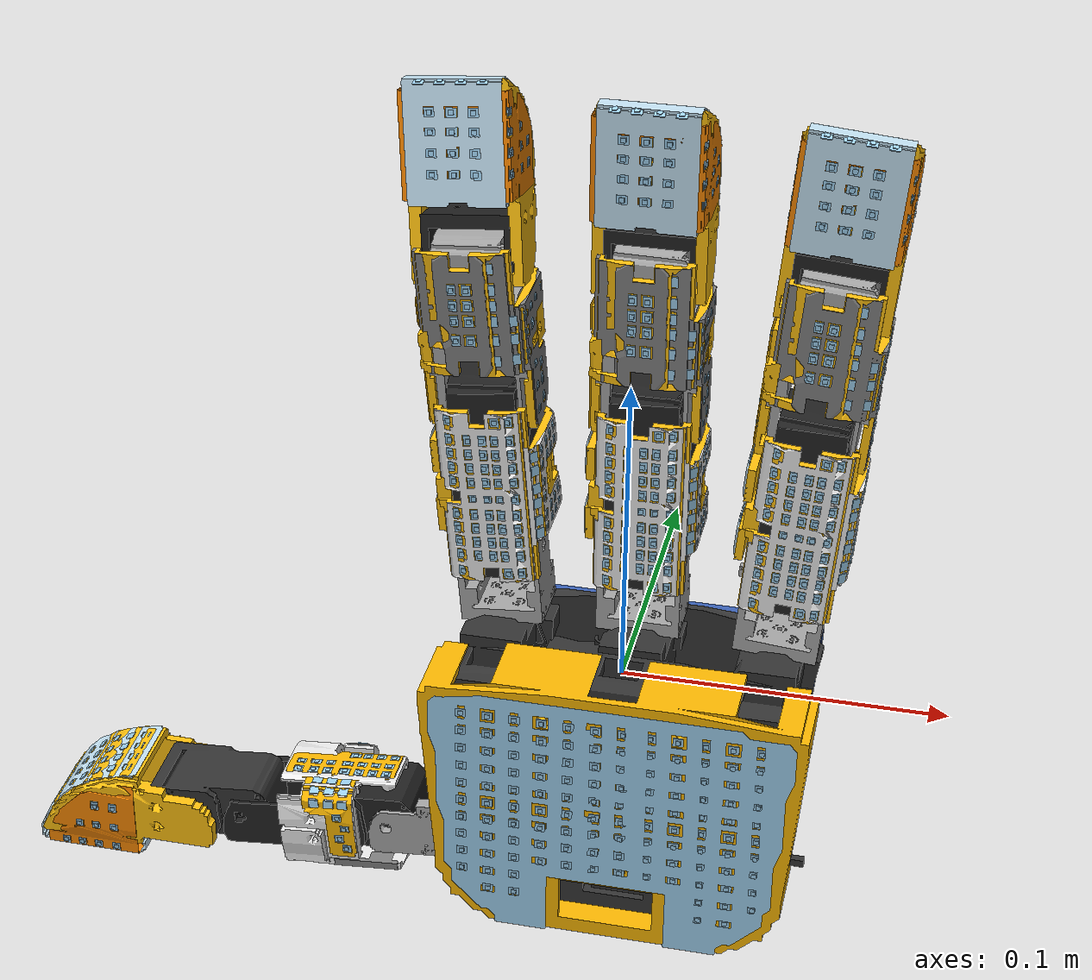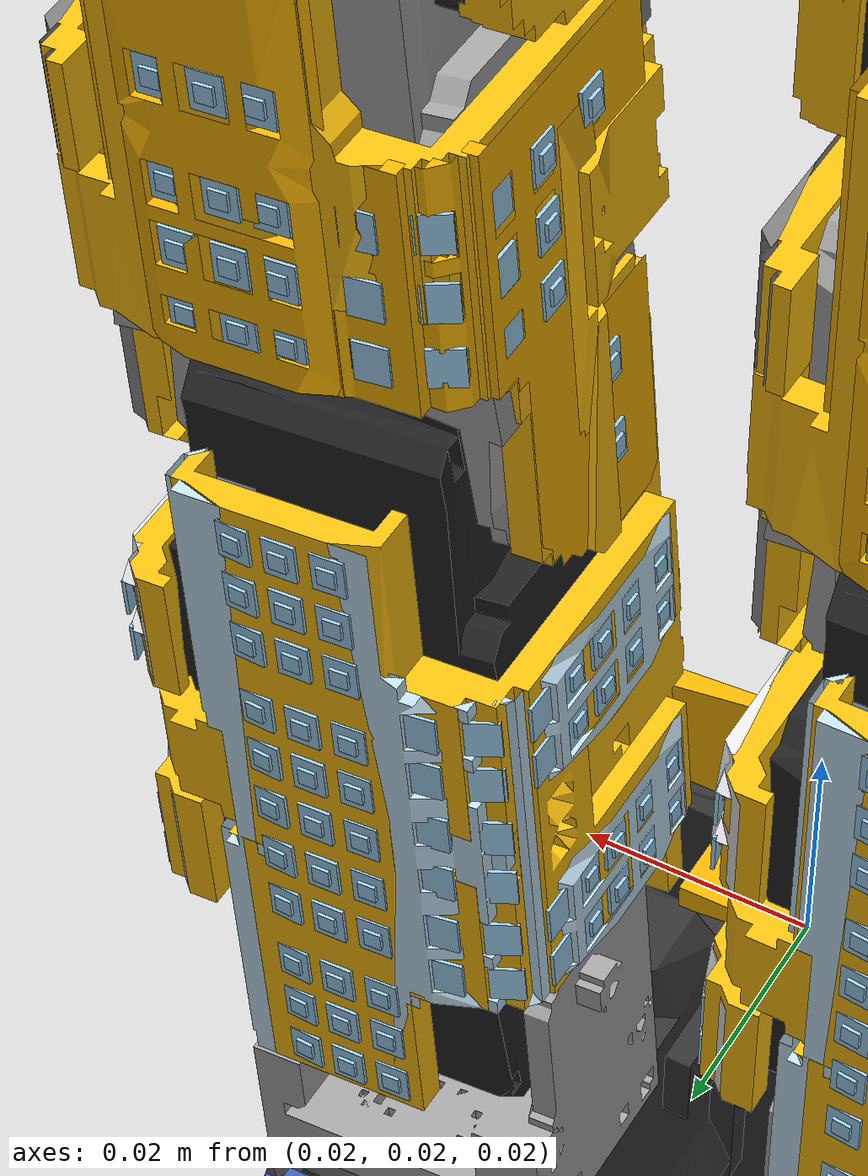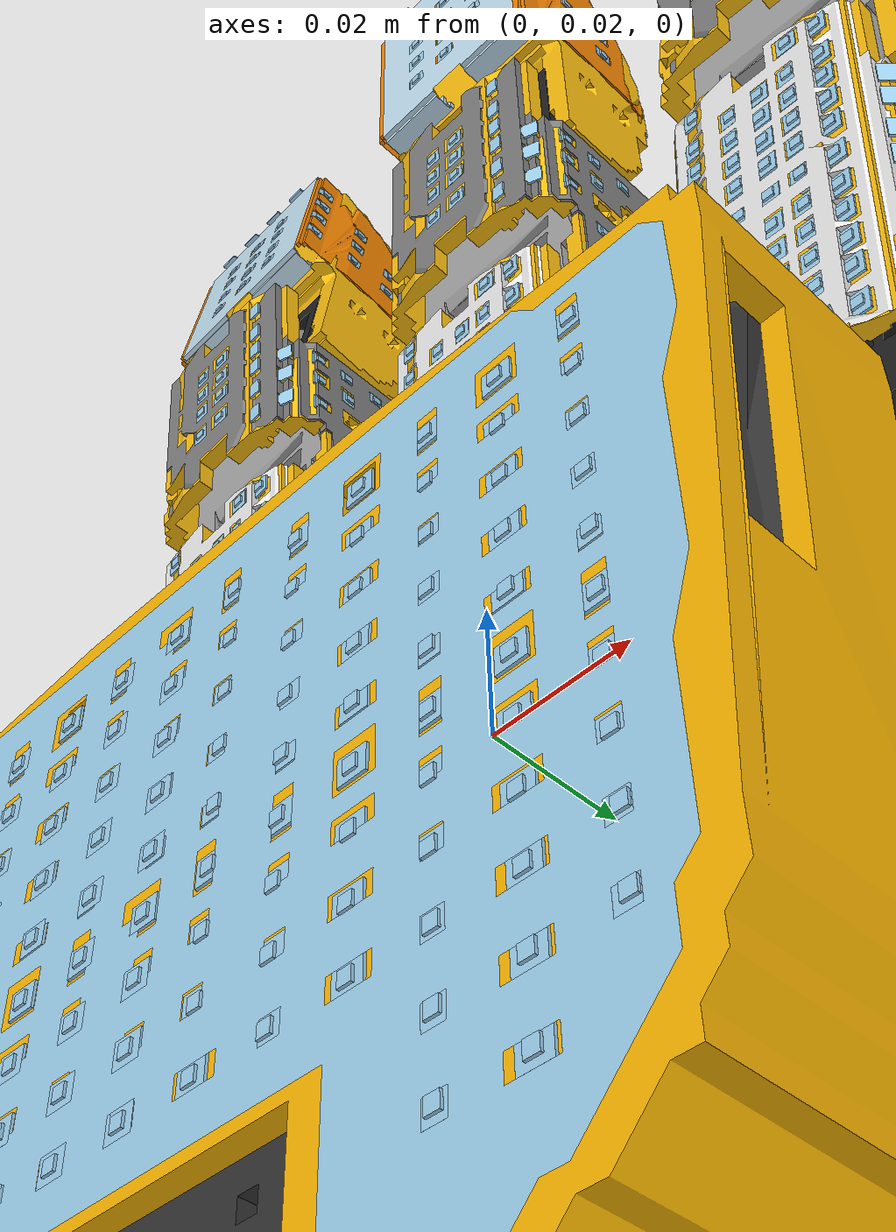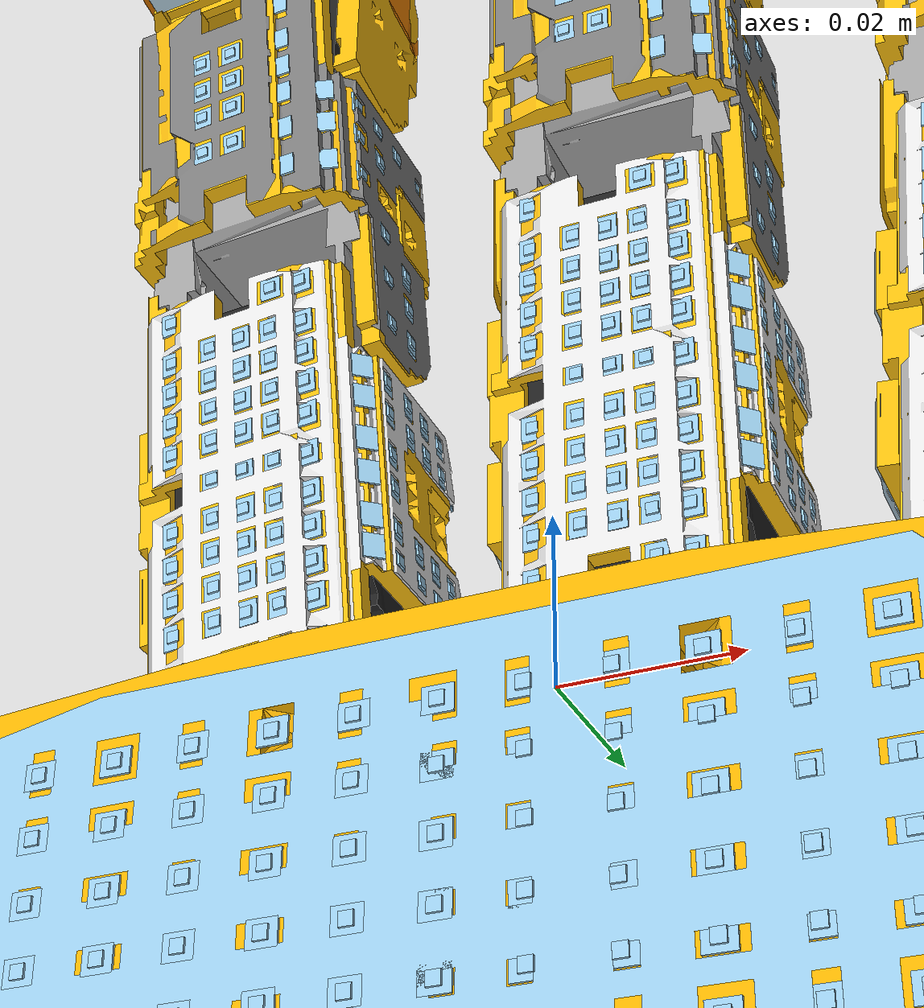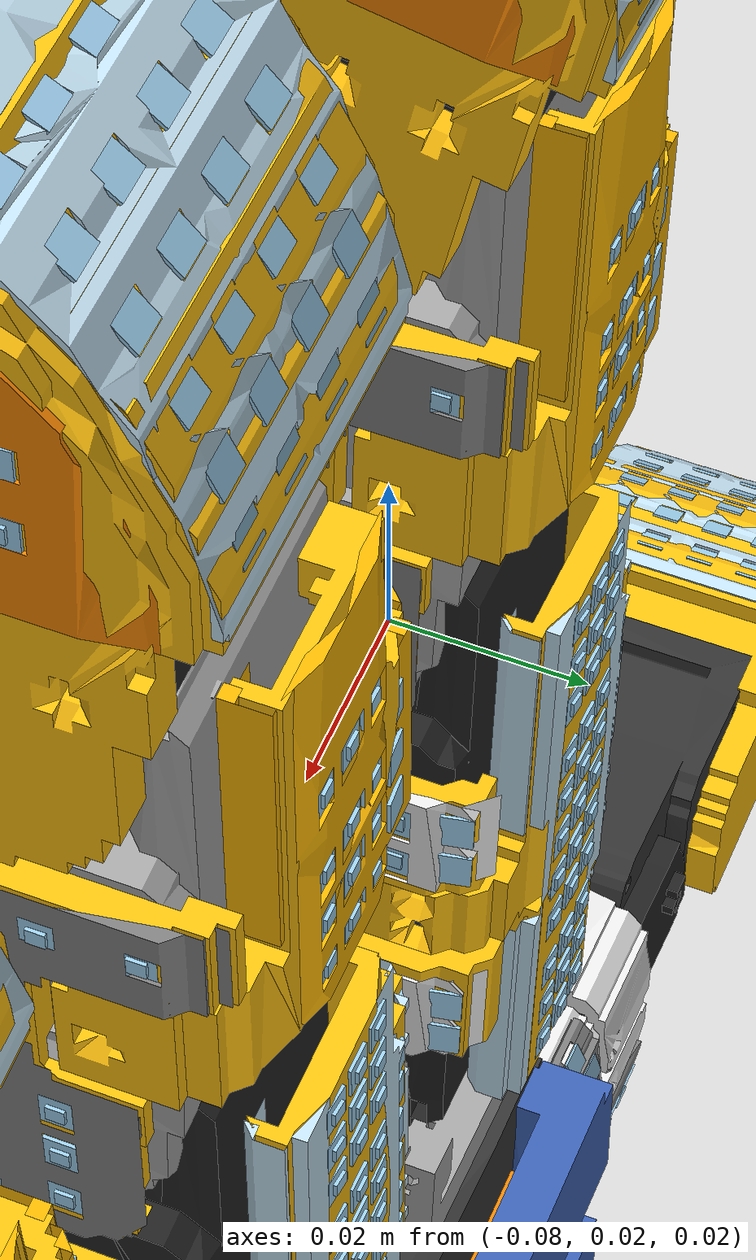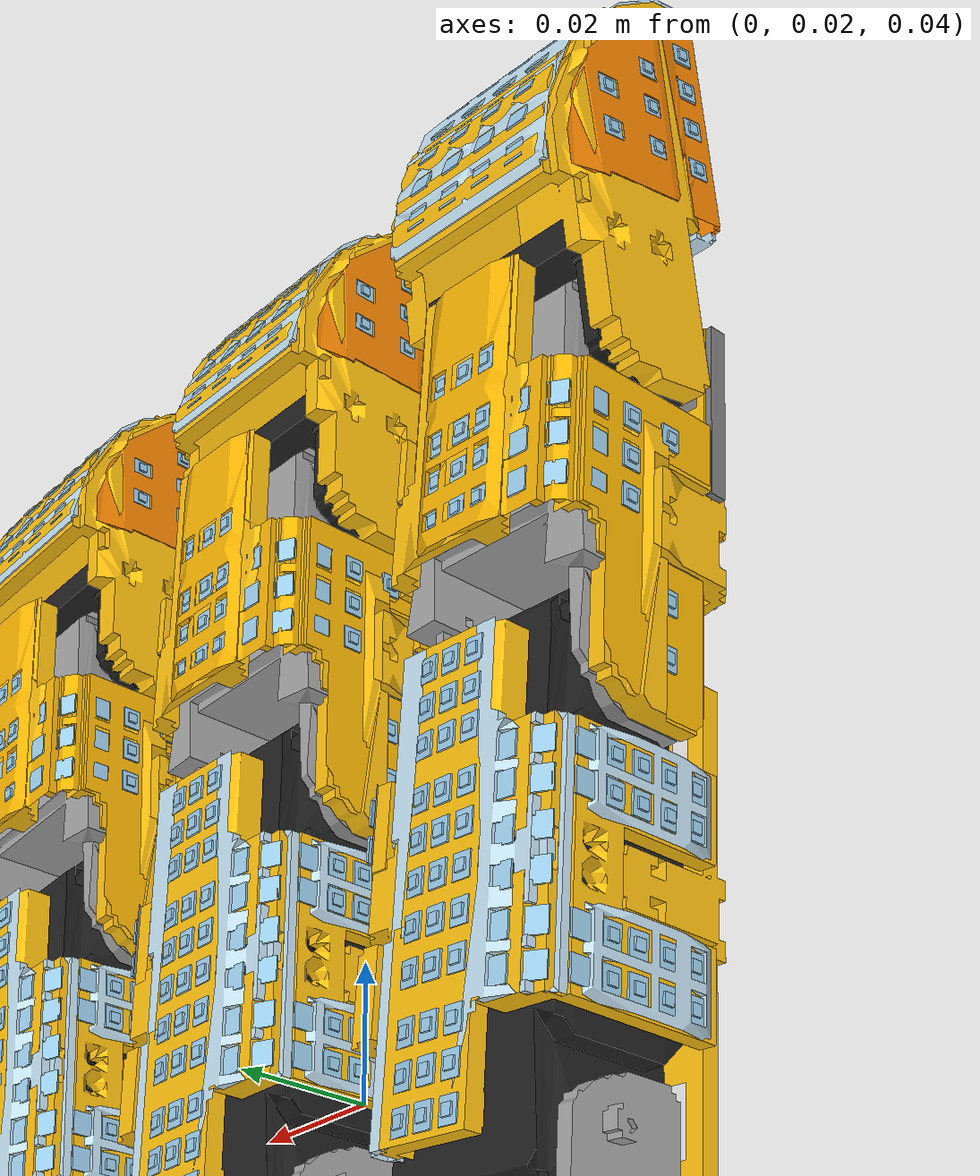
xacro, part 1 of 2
<?xml version="1.0"?>
<robot xmlns:xacro="http://www.ros.org/wiki/xacro" name="allegro_hand_right">
<link name="palm_link">
<visual>
<origin xyz="0 0.034 -0.002" rpy="3.14159 -0 0" />
<geometry>
<mesh filename="package://allegro_hand_description/meshes/g_r2.stl"/>
</geometry>
<material name="g_r2_material">
<color rgba="0.2 0.2 0.2 1.0"/>
</material>
</visual>
<collision>
<origin xyz="0 0.034 -0.002" rpy="3.14159 -0 0" />
<geometry>
<mesh filename="package://allegro_hand_description/meshes/g_r2.stl"/>
</geometry>
<material name="g_r2_material">
<color rgba="0.2 0.2 0.2 1.0"/>
</material>
</collision>
<inertial>
<origin xyz="-0.00043535 0.0160404 -0.0404815" rpy="0 0 0"/>
<mass value="0.404445" />
<inertia ixx="0.000491371" ixy="-9.01723e-06"  ixz="1.17974e-05" iyy="0.000773265" iyz="-5.50867e-06" izz="0.000547843" />
</inertial>
</link>

<link name="link_0">
<visual>
<origin xyz="0 6.93889e-18 -0.0152" rpy="1.5708 6.16298e-33 -5.3926e-33" />
<geometry>
<mesh filename="package://allegro_hand_description/meshes/extended_finger_base.stl"/>
</geometry>
<material name="extended_finger_base_material">
<color rgba="0.647059 0.647059 0.647059 1.0"/>
</material>
</visual>
<collision>
<origin xyz="0 6.93889e-18 -0.0152" rpy="1.5708 6.16298e-33 -5.3926e-33" />
<geometry>
<mesh filename="package://allegro_hand_description/meshes/extended_finger_base.stl"/>
</geometry>
<material name="extended_finger_base_material">
<color rgba="0.647059 0.647059 0.647059 1.0"/>
</material>
</collision>
<inertial>
<origin xyz="-0.00041342 0.000666149 0.00960564" rpy="0 0 0"/>
<mass value="0.0136672" />
<inertia ixx="2.13441e-06" ixy="5.86704e-10"  ixz="-7.9563e-08" iyy="1.24411e-06" iyz="-6.13056e-08" izz="1.671e-06" />
</inertial>
</link>

<link name="link_1">
<visual>
<origin xyz="-0.0182688 0 -0.0317805" rpy="4.1618e-29 1.48353 -3.14159" />
<geometry>
<mesh filename="package://allegro_hand_description/meshes/p2_r6.stl"/>
</geometry>
<material name="p2_r6_material">
<color rgba="0.129412 0.129412 0.129412 1.0"/>
</material>
</visual>
<collision>
<origin xyz="-0.0182688 0 -0.0317805" rpy="4.1618e-29 1.48353 -3.14159" />
<geometry>
<mesh filename="package://allegro_hand_description/meshes/p2_r6.stl"/>
</geometry>
<material name="p2_r6_material">
<color rgba="0.129412 0.129412 0.129412 1.0"/>
</material>
</collision>
<inertial>
<origin xyz="0.027 9.54536e-05 0.0124409" rpy="0 0 0"/>
<mass value="0.0418346" />
<inertia ixx="4.00114e-06" ixy="-1.81985e-08"  ixz="-4.42841e-15" iyy="1.97927e-05" iyz="1.59578e-08" izz="1.88563e-05" />
</inertial>
</link>

<link name="link_2">
<visual>
<origin xyz="0.0722688 -3.46945e-17 -0.0317805" rpy="-4.37532e-31 1.48353 -2.11032e-30" />
<geometry>
<mesh filename="package://allegro_hand_description/meshes/extended_fingertop.stl"/>
</geometry>
<material name="extended_fingertop_material">
<color rgba="0.647059 0.647059 0.647059 1.0"/>
</material>
</visual>
<collision>
<origin xyz="0.0722688 -3.46945e-17 -0.0317805" rpy="-4.37532e-31 1.48353 -2.11032e-30" />
<geometry>
<mesh filename="package://allegro_hand_description/meshes/extended_fingertop.stl"/>
</geometry>
<material name="extended_fingertop_material">
<color rgba="0.647059 0.647059 0.647059 1.0"/>
</material>
</collision>
<inertial>
<origin xyz="-0.0294592 -0.000104104 0.0123435" rpy="0 0 0"/>
<mass value="0.0318021" />
<inertia ixx="3.48619e-06" ixy="1.20808e-07"  ixz="6.2918e-07" iyy="8.82437e-06" iyz="5.78644e-09" izz="7.34771e-06" />
</inertial>
</link>

<link name="link_3">
<visual>
<origin xyz="0.1253 -6.245e-17 0.0118" rpy="3.14159 1.59675e-18 -1.5708" />
<geometry>
<mesh filename="package://allegro_hand_description/meshes/p4_r.stl"/>
</geometry>
<material name="p4_r_material">
<color rgba="0.129412 0.129412 0.129412 1.0"/>
</material>
</visual>
<collision>
<origin xyz="0.1253 -6.245e-17 0.0118" rpy="3.14159 1.59675e-18 -1.5708" />
<geometry>
<mesh filename="package://allegro_hand_description/meshes/p4_r.stl"/>
</geometry>
<material name="p4_r_material">
<color rgba="0.129412 0.129412 0.129412 1.0"/>
</material>
</collision>
<inertial>
<origin xyz="-0.0100051 0.000639363 0.0123057" rpy="0 0 0"/>
<mass value="0.0088374" />
<inertia ixx="1.08072e-06" ixy="-4.65695e-08"  ixz="-3.42321e-08" iyy="1.11236e-06" iyz="-8.85024e-10" izz="5.61586e-07" />
</inertial>
</link>

<link name="index_fingertip_bracket">
<visual>
<origin xyz="-0.1139 -0.004 0.0135" rpy="-3.14159 -5.38107e-18 -1.26296e-17" />
<geometry>
<mesh filename="package://allegro_hand_description/meshes/distal_pcbbase.stl"/>
</geometry>
<material name="distal_pcbbase_material">
<color rgba="1 0.756863 0.054902 1.0"/>
</material>
</visual>
<collision>
<origin xyz="-0.1139 -0.004 0.0135" rpy="-3.14159 -5.38107e-18 -1.26296e-17" />
<geometry>
<mesh filename="package://allegro_hand_description/meshes/distal_pcbbase.stl"/>
</geometry>
<material name="distal_pcbbase_material">
<color rgba="1 0.756863 0.054902 1.0"/>
</material>
</collision>
<inertial>
<origin xyz="0.0170719 -0.00112911 0.0135244" rpy="0 0 0"/>
<mass value="0.0155109" />
<inertia ixx="3.339e-06" ixy="-4.60426e-07"  ixz="1.73449e-08" iyy="6.13257e-06" iyz="-6.39964e-10" izz="4.49513e-06" />
</inertial>
</link>

<link name="index_fingertip_main_fpcb">
<visual>
<origin xyz="-0.12166 0.01366 0" rpy="-3.14159 -2.0805e-17 4.08843e-17" />
<geometry>
<mesh filename="package://allegro_hand_description/meshes/distal_fpcb_1.stl"/>
</geometry>
<material name="distal_fpcb_1_material">
<color rgba="0.768627 0.886275 0.952941 1.0"/>
</material>
</visual>
<collision>
<origin xyz="-0.12166 0.01366 0" rpy="-3.14159 -2.0805e-17 4.08843e-17" />
<geometry>
<mesh filename="package://allegro_hand_description/meshes/distal_fpcb_1.stl"/>
</geometry>
<material name="distal_fpcb_1_material">
<color rgba="0.768627 0.886275 0.952941 1.0"/>
</material>
</collision>
<inertial>
<origin xyz="0.0183062 0.0208616 2.89858e-05" rpy="0 0 0"/>
<mass value="0.00142203" />
<inertia ixx="3.14637e-07" ixy="-2.70173e-08"  ixz="2.90739e-11" iyy="3.18951e-07" iyz="-3.25215e-10" izz="4.09623e-07" />
</inertial>
</link>

<link name="ift_taxel_3">
<visual>
<origin xyz="-0.0016 -0.0003 -0.0014" rpy="-1.5708 4.52202e-17 -6.06248e-19" />
<geometry>
<mesh filename="package://allegro_hand_description/meshes/taxel_abnormal_3.stl"/>
</geometry>
<material name="taxel_abnormal_3_material">
<color rgba="0.615686 0.811765 0.929412 1.0"/>
</material>
</visual>
<collision>
<origin xyz="-0.0016 -0.0003 -0.0014" rpy="-1.5708 4.52202e-17 -6.06248e-19" />
<geometry>
<mesh filename="package://allegro_hand_description/meshes/taxel_abnormal_3.stl"/>
</geometry>
<material name="taxel_abnormal_3_material">
<color rgba="0.615686 0.811765 0.929412 1.0"/>
</material>
</collision>
<inertial>
<origin xyz="-0.0016 -0.00015 -0.0014" rpy="0 0 0"/>
<mass value="5.376e-06" />
<inertia ixx="3.55264e-12" ixy="-1.07919e-29"  ixz="-4.27783e-30" iyy="8.09984e-12" iyz="-5.52763e-29" izz="4.62784e-12" />
</inertial>
</link>

<link name="ift_sub_taxel_3">
<visual>
<origin xyz="2.77556e-17 1.38778e-17 -0.0003" rpy="-2.70413e-18 -2.89465e-18 -2.95249e-18" />
<geometry>
<mesh filename="package://allegro_hand_description/meshes/sub_taxel.stl"/>
</geometry>
<material name="sub_taxel_material">
<color rgba="0.615686 0.811765 0.929412 1.0"/>
</material>
</visual>
<collision>
<origin xyz="2.77556e-17 1.38778e-17 -0.0003" rpy="-2.70413e-18 -2.89465e-18 -2.95249e-18" />
<geometry>
<mesh filename="package://allegro_hand_description/meshes/sub_taxel.stl"/>
</geometry>
<material name="sub_taxel_material">
<color rgba="0.615686 0.811765 0.929412 1.0"/>
</material>
</collision>
<inertial>
<origin xyz="2.75883e-17 1.40239e-17 -0.00015" rpy="0 0 0"/>
<mass value="1.35e-06" />
<inertia ixx="2.6325e-13" ixy="-5.26171e-31"  ixz="1.12775e-30" iyy="2.6325e-13" iyz="-9.32897e-31" izz="5.0625e-13" />
</inertial>
</link>

<joint name="joint_ift_sub_taxel_3" type="fixed">
<origin xyz="-0.0016 -8.67362e-19 -0.0014" rpy="1.5708 1.5708 0" />
<parent link="ift_taxel_3" />
<child link="ift_sub_taxel_3" />
<axis xyz="0 0 1"/>
<limit effort="1" velocity="20" />
<joint_properties friction="0.0"/>
</joint>

<joint name="joint_ift_taxel_3" type="fixed">
<origin xyz="0.00647505 0.03156 -0.0054727" rpy="2.56587e-15 -1.5708 0" />
<parent link="index_fingertip_main_fpcb" />
<child link="ift_taxel_3" />
<axis xyz="0 0 1"/>
<limit effort="1" velocity="20" />
<joint_properties friction="0.0"/>
</joint>

<link name="ift_taxel_4">
<visual>
<origin xyz="-0.0016 -0.0003 -0.0014" rpy="-1.5708 4.52202e-17 -6.06248e-19" />
<geometry>
<mesh filename="package://allegro_hand_description/meshes/taxel_abnormal_3.stl"/>
</geometry>
<material name="taxel_abnormal_3_material">
<color rgba="0.615686 0.811765 0.929412 1.0"/>
</material>
</visual>
<collision>
<origin xyz="-0.0016 -0.0003 -0.0014" rpy="-1.5708 4.52202e-17 -6.06248e-19" />
<geometry>
<mesh filename="package://allegro_hand_description/meshes/taxel_abnormal_3.stl"/>
</geometry>
<material name="taxel_abnormal_3_material">
<color rgba="0.615686 0.811765 0.929412 1.0"/>
</material>
</collision>
<inertial>
<origin xyz="-0.0016 -0.00015 -0.0014" rpy="0 0 0"/>
<mass value="5.376e-06" />
<inertia ixx="3.55264e-12" ixy="-1.07919e-29"  ixz="-4.27783e-30" iyy="8.09984e-12" iyz="-5.52763e-29" izz="4.62784e-12" />
</inertial>
</link>

<link name="ift_sub_taxel_4">
<visual>
<origin xyz="0 0 -0.0003" rpy="-2.70413e-18 -2.89465e-18 -2.95249e-18" />
<geometry>
<mesh filename="package://allegro_hand_description/meshes/sub_taxel.stl"/>
</geometry>
<material name="sub_taxel_material">
<color rgba="0.615686 0.811765 0.929412 1.0"/>
</material>
</visual>
<collision>
<origin xyz="0 0 -0.0003" rpy="-2.70413e-18 -2.89465e-18 -2.95249e-18" />
<geometry>
<mesh filename="package://allegro_hand_description/meshes/sub_taxel.stl"/>
</geometry>
<material name="sub_taxel_material">
<color rgba="0.615686 0.811765 0.929412 1.0"/>
</material>
</collision>
<inertial>
<origin xyz="-1.6728e-19 1.46067e-19 -0.00015" rpy="0 0 0"/>
<mass value="1.35e-06" />
<inertia ixx="2.6325e-13" ixy="-5.26171e-31"  ixz="1.12775e-30" iyy="2.6325e-13" iyz="-9.32897e-31" izz="5.0625e-13" />
</inertial>
</link>

<joint name="joint_ift_sub_taxel_4" type="fixed">
<origin xyz="-0.0016 9.54098e-18 -0.0014" rpy="1.5708 1.5708 0" />
<parent link="ift_taxel_4" />
<child link="ift_sub_taxel_4" />
<axis xyz="0 0 1"/>
<limit effort="1" velocity="20" />
<joint_properties friction="0.0"/>
</joint>

<joint name="joint_ift_taxel_4" type="fixed">
<origin xyz="0.00647505 0.03156 0.0011313" rpy="2.56587e-15 -1.5708 0" />
<parent link="index_fingertip_main_fpcb" />
<child link="ift_taxel_4" />
<axis xyz="0 0 1"/>
<limit effort="1" velocity="20" />
<joint_properties friction="0.0"/>
</joint>

<link name="ift_taxel_5">
<visual>
<origin xyz="-0.0016 -0.0003 -0.0014" rpy="-1.5708 4.52202e-17 -6.06248e-19" />
<geometry>
<mesh filename="package://allegro_hand_description/meshes/taxel_abnormal_3.stl"/>
</geometry>
<material name="taxel_abnormal_3_material">
<color rgba="0.615686 0.811765 0.929412 1.0"/>
</material>
</visual>
<collision>
<origin xyz="-0.0016 -0.0003 -0.0014" rpy="-1.5708 4.52202e-17 -6.06248e-19" />
<geometry>
<mesh filename="package://allegro_hand_description/meshes/taxel_abnormal_3.stl"/>
</geometry>
<material name="taxel_abnormal_3_material">
<color rgba="0.615686 0.811765 0.929412 1.0"/>
</material>
</collision>
<inertial>
<origin xyz="-0.0016 -0.00015 -0.0014" rpy="0 0 0"/>
<mass value="5.376e-06" />
<inertia ixx="3.55264e-12" ixy="-1.07919e-29"  ixz="-4.27783e-30" iyy="8.09984e-12" iyz="-5.52763e-29" izz="4.62784e-12" />
</inertial>
</link>

<link name="ift_sub_taxel_5">
<visual>
<origin xyz="0 0 -0.0003" rpy="-2.70413e-18 -2.89465e-18 -2.95249e-18" />
<geometry>
<mesh filename="package://allegro_hand_description/meshes/sub_taxel.stl"/>
</geometry>
<material name="sub_taxel_material">
<color rgba="0.615686 0.811765 0.929412 1.0"/>
</material>
</visual>
<collision>
<origin xyz="0 0 -0.0003" rpy="-2.70413e-18 -2.89465e-18 -2.95249e-18" />
<geometry>
<mesh filename="package://allegro_hand_description/meshes/sub_taxel.stl"/>
</geometry>
<material name="sub_taxel_material">
<color rgba="0.615686 0.811765 0.929412 1.0"/>
</material>
</collision>
<inertial>
<origin xyz="-1.6728e-19 1.46067e-19 -0.00015" rpy="0 0 0"/>
<mass value="1.35e-06" />
<inertia ixx="2.6325e-13" ixy="-5.26171e-31"  ixz="1.12775e-30" iyy="2.6325e-13" iyz="-9.32897e-31" izz="5.0625e-13" />
</inertial>
</link>

<joint name="joint_ift_sub_taxel_5" type="fixed">
<origin xyz="-0.0016 -8.67362e-19 -0.0014" rpy="1.5708 1.5708 0" />
<parent link="ift_taxel_5" />
<child link="ift_sub_taxel_5" />
<axis xyz="0 0 1"/>
<limit effort="1" velocity="20" />
<joint_properties friction="0.0"/>
</joint>

<joint name="joint_ift_taxel_5" type="fixed">
<origin xyz="0.00647505 0.03156 0.0077353" rpy="2.56587e-15 -1.5708 0" />
<parent link="index_fingertip_main_fpcb" />
<child link="ift_taxel_5" />
<axis xyz="0 0 1"/>
<limit effort="1" velocity="20" />
<joint_properties friction="0.0"/>
</joint>

<link name="ift_taxel_12">
<visual>
<origin xyz="-0.0016 -0.0003 -0.0014" rpy="-1.5708 4.52202e-17 -6.06248e-19" />
<geometry>
<mesh filename="package://allegro_hand_description/meshes/taxel_abnormal_3.stl"/>
</geometry>
<material name="taxel_abnormal_3_material">
<color rgba="0.615686 0.811765 0.929412 1.0"/>
</material>
</visual>
<collision>
<origin xyz="-0.0016 -0.0003 -0.0014" rpy="-1.5708 4.52202e-17 -6.06248e-19" />
<geometry>
<mesh filename="package://allegro_hand_description/meshes/taxel_abnormal_3.stl"/>
</geometry>
<material name="taxel_abnormal_3_material">
<color rgba="0.615686 0.811765 0.929412 1.0"/>
</material>
</collision>
<inertial>
<origin xyz="-0.0016 -0.00015 -0.0014" rpy="0 0 0"/>
<mass value="5.376e-06" />
<inertia ixx="3.55264e-12" ixy="-1.07919e-29"  ixz="-4.27783e-30" iyy="8.09984e-12" iyz="-5.52763e-29" izz="4.62784e-12" />
</inertial>
</link>

<link name="ift_sub_taxel_12">
<visual>
<origin xyz="1.38778e-17 0 -0.0003" rpy="-4.31395e-17 6.03206e-19 1.05863e-17" />
<geometry>
<mesh filename="package://allegro_hand_description/meshes/sub_taxel.stl"/>
</geometry>
<material name="sub_taxel_material">
<color rgba="0.615686 0.811765 0.929412 1.0"/>
</material>
</visual>
<collision>
<origin xyz="1.38778e-17 0 -0.0003" rpy="-4.31395e-17 6.03206e-19 1.05863e-17" />
<geometry>
<mesh filename="package://allegro_hand_description/meshes/sub_taxel.stl"/>
</geometry>
<material name="sub_taxel_material">
<color rgba="0.615686 0.811765 0.929412 1.0"/>
</material>
</collision>
<inertial>
<origin xyz="1.37105e-17 1.46214e-19 -0.00015" rpy="0 0 0"/>
<mass value="1.35e-06" />
<inertia ixx="2.6325e-13" ixy="5.62071e-30"  ixz="-6.151e-31" iyy="2.6325e-13" iyz="-2.11443e-29" izz="5.0625e-13" />
</inertial>
</link>

<joint name="joint_ift_sub_taxel_12" type="fixed">
<origin xyz="-0.0016 1.12757e-17 -0.0014" rpy="1.5708 4.49249e-17 -1.49757e-18" />
<parent link="ift_taxel_12" />
<child link="ift_sub_taxel_12" />
<axis xyz="0 0 1"/>
<limit effort="1" velocity="20" />
<joint_properties friction="0.0"/>
</joint>

<joint name="joint_ift_taxel_12" type="fixed">
<origin xyz="0.0128113 0.03156 -0.0054727" rpy="2.56587e-15 -1.5708 0" />
<parent link="index_fingertip_main_fpcb" />
<child link="ift_taxel_12" />
<axis xyz="0 0 1"/>
<limit effort="1" velocity="20" />
<joint_properties friction="0.0"/>
</joint>

<link name="ift_taxel_13">
<visual>
<origin xyz="-0.0016 -0.0003 -0.0014" rpy="-1.5708 4.52202e-17 -6.06248e-19" />
<geometry>
<mesh filename="package://allegro_hand_description/meshes/taxel_abnormal_3.stl"/>
</geometry>
<material name="taxel_abnormal_3_material">
<color rgba="0.615686 0.811765 0.929412 1.0"/>
</material>
</visual>
<collision>
<origin xyz="-0.0016 -0.0003 -0.0014" rpy="-1.5708 4.52202e-17 -6.06248e-19" />
<geometry>
<mesh filename="package://allegro_hand_description/meshes/taxel_abnormal_3.stl"/>
</geometry>
<material name="taxel_abnormal_3_material">
<color rgba="0.615686 0.811765 0.929412 1.0"/>
</material>
</collision>
<inertial>
<origin xyz="-0.0016 -0.00015 -0.0014" rpy="0 0 0"/>
<mass value="5.376e-06" />
<inertia ixx="3.55264e-12" ixy="-1.07919e-29"  ixz="-4.27783e-30" iyy="8.09984e-12" iyz="-5.52763e-29" izz="4.62784e-12" />
</inertial>
</link>

<link name="ift_sub_taxel_13">
<visual>
<origin xyz="0 -2.77556e-17 -0.0003" rpy="-4.31395e-17 6.03206e-19 1.05863e-17" />
<geometry>
<mesh filename="package://allegro_hand_description/meshes/sub_taxel.stl"/>
</geometry>
<material name="sub_taxel_material">
<color rgba="0.615686 0.811765 0.929412 1.0"/>
</material>
</visual>
<collision>
<origin xyz="0 -2.77556e-17 -0.0003" rpy="-4.31395e-17 6.03206e-19 1.05863e-17" />
<geometry>
<mesh filename="package://allegro_hand_description/meshes/sub_taxel.stl"/>
</geometry>
<material name="sub_taxel_material">
<color rgba="0.615686 0.811765 0.929412 1.0"/>
</material>
</collision>
<inertial>
<origin xyz="-1.67264e-19 -2.76094e-17 -0.00015" rpy="0 0 0"/>
<mass value="1.35e-06" />
<inertia ixx="2.6325e-13" ixy="5.62071e-30"  ixz="-6.151e-31" iyy="2.6325e-13" iyz="-2.11443e-29" izz="5.0625e-13" />
</inertial>
</link>

<joint name="joint_ift_sub_taxel_13" type="fixed">
<origin xyz="-0.0016 -7.80626e-18 -0.0014" rpy="1.5708 4.49249e-17 -1.49757e-18" />
<parent link="ift_taxel_13" />
<child link="ift_sub_taxel_13" />
<axis xyz="0 0 1"/>
<limit effort="1" velocity="20" />
<joint_properties friction="0.0"/>
</joint>

<joint name="joint_ift_taxel_13" type="fixed">
<origin xyz="0.0128113 0.03156 0.0011313" rpy="2.56587e-15 -1.5708 0" />
<parent link="index_fingertip_main_fpcb" />
<child link="ift_taxel_13" />
<axis xyz="0 0 1"/>
<limit effort="1" velocity="20" />
<joint_properties friction="0.0"/>
</joint>

<link name="ift_taxel_14">
<visual>
<origin xyz="-0.0016 -0.0003 -0.0014" rpy="-1.5708 4.52202e-17 -6.06248e-19" />
<geometry>
<mesh filename="package://allegro_hand_description/meshes/taxel_abnormal_3.stl"/>
</geometry>
<material name="taxel_abnormal_3_material">
<color rgba="0.615686 0.811765 0.929412 1.0"/>
</material>
</visual>
<collision>
<origin xyz="-0.0016 -0.0003 -0.0014" rpy="-1.5708 4.52202e-17 -6.06248e-19" />
<geometry>
<mesh filename="package://allegro_hand_description/meshes/taxel_abnormal_3.stl"/>
</geometry>
<material name="taxel_abnormal_3_material">
<color rgba="0.615686 0.811765 0.929412 1.0"/>
</material>
</collision>
<inertial>
<origin xyz="-0.0016 -0.00015 -0.0014" rpy="0 0 0"/>
<mass value="5.376e-06" />
<inertia ixx="3.55264e-12" ixy="-1.07919e-29"  ixz="-4.27783e-30" iyy="8.09984e-12" iyz="-5.52763e-29" izz="4.62784e-12" />
</inertial>
</link>

<link name="ift_sub_taxel_14">
<visual>
<origin xyz="6.93889e-18 0 -0.0003" rpy="-4.31395e-17 6.03206e-19 1.05863e-17" />
<geometry>
<mesh filename="package://allegro_hand_description/meshes/sub_taxel.stl"/>
</geometry>
<material name="sub_taxel_material">
<color rgba="0.615686 0.811765 0.929412 1.0"/>
</material>
</visual>
<collision>
<origin xyz="6.93889e-18 0 -0.0003" rpy="-4.31395e-17 6.03206e-19 1.05863e-17" />
<geometry>
<mesh filename="package://allegro_hand_description/meshes/sub_taxel.stl"/>
</geometry>
<material name="sub_taxel_material">
<color rgba="0.615686 0.811765 0.929412 1.0"/>
</material>
</collision>
<inertial>
<origin xyz="6.77163e-18 1.46214e-19 -0.00015" rpy="0 0 0"/>
<mass value="1.35e-06" />
<inertia ixx="2.6325e-13" ixy="5.62071e-30"  ixz="-6.151e-31" iyy="2.6325e-13" iyz="-2.11443e-29" izz="5.0625e-13" />
</inertial>
</link>

<joint name="joint_ift_sub_taxel_14" type="fixed">
<origin xyz="-0.0016 -1.21431e-17 -0.0014" rpy="1.5708 4.49249e-17 -1.49757e-18" />
<parent link="ift_taxel_14" />
<child link="ift_sub_taxel_14" />
<axis xyz="0 0 1"/>
<limit effort="1" velocity="20" />
<joint_properties friction="0.0"/>
</joint>

<joint name="joint_ift_taxel_14" type="fixed">
<origin xyz="0.0128113 0.03156 0.0077353" rpy="2.56587e-15 -1.5708 0" />
<parent link="index_fingertip_main_fpcb" />
<child link="ift_taxel_14" />
<axis xyz="0 0 1"/>
<limit effort="1" velocity="20" />
<joint_properties friction="0.0"/>
</joint>

<link name="ift_taxel_20">
<visual>
<origin xyz="-0.0016 -0.0003 -0.0014" rpy="-1.5708 4.52202e-17 -6.06248e-19" />
<geometry>
<mesh filename="package://allegro_hand_description/meshes/taxel_abnormal_3.stl"/>
</geometry>
<material name="taxel_abnormal_3_material">
<color rgba="0.615686 0.811765 0.929412 1.0"/>
</material>
</visual>
<collision>
<origin xyz="-0.0016 -0.0003 -0.0014" rpy="-1.5708 4.52202e-17 -6.06248e-19" />
<geometry>
<mesh filename="package://allegro_hand_description/meshes/taxel_abnormal_3.stl"/>
</geometry>
<material name="taxel_abnormal_3_material">
<color rgba="0.615686 0.811765 0.929412 1.0"/>
</material>
</collision>
<inertial>
<origin xyz="-0.0016 -0.00015 -0.0014" rpy="0 0 0"/>
<mass value="5.376e-06" />
<inertia ixx="3.55264e-12" ixy="-1.07919e-29"  ixz="-4.27783e-30" iyy="8.09984e-12" iyz="-5.52763e-29" izz="4.62784e-12" />
</inertial>
</link>

<link name="ift_sub_taxel_20">
<visual>
<origin xyz="1.38778e-17 0 -0.0003" rpy="-4.31395e-17 6.03206e-19 1.05863e-17" />
<geometry>
<mesh filename="package://allegro_hand_description/meshes/sub_taxel.stl"/>
</geometry>
<material name="sub_taxel_material">
<color rgba="0.615686 0.811765 0.929412 1.0"/>
</material>
</visual>
<collision>
<origin xyz="1.38778e-17 0 -0.0003" rpy="-4.31395e-17 6.03206e-19 1.05863e-17" />
<geometry>
<mesh filename="package://allegro_hand_description/meshes/sub_taxel.stl"/>
</geometry>
<material name="sub_taxel_material">
<color rgba="0.615686 0.811765 0.929412 1.0"/>
</material>
</collision>
<inertial>
<origin xyz="1.37105e-17 1.46214e-19 -0.00015" rpy="0 0 0"/>
<mass value="1.35e-06" />
<inertia ixx="2.6325e-13" ixy="5.62071e-30"  ixz="-6.151e-31" iyy="2.6325e-13" iyz="-2.11443e-29" izz="5.0625e-13" />
</inertial>
</link>

<joint name="joint_ift_sub_taxel_20" type="fixed">
<origin xyz="-0.0016 -5.20417e-18 -0.0014" rpy="1.5708 4.49249e-17 -1.49757e-18" />
<parent link="ift_taxel_20" />
<child link="ift_sub_taxel_20" />
<axis xyz="0 0 1"/>
<limit effort="1" velocity="20" />
<joint_properties friction="0.0"/>
</joint>

<joint name="joint_ift_taxel_20" type="fixed">
<origin xyz="0.0190081 0.03156 -0.0054727" rpy="2.56587e-15 -1.5708 0" />
<parent link="index_fingertip_main_fpcb" />
<child link="ift_taxel_20" />
<axis xyz="0 0 1"/>
<limit effort="1" velocity="20" />
<joint_properties friction="0.0"/>
</joint>

<link name="ift_taxel_21">
<visual>
<origin xyz="-0.0016 -0.0003 -0.0014" rpy="-1.5708 4.52202e-17 -6.06248e-19" />
<geometry>
<mesh filename="package://allegro_hand_description/meshes/taxel_abnormal_3.stl"/>
</geometry>
<material name="taxel_abnormal_3_material">
<color rgba="0.615686 0.811765 0.929412 1.0"/>
</material>
</visual>
<collision>
<origin xyz="-0.0016 -0.0003 -0.0014" rpy="-1.5708 4.52202e-17 -6.06248e-19" />
<geometry>
<mesh filename="package://allegro_hand_description/meshes/taxel_abnormal_3.stl"/>
</geometry>
<material name="taxel_abnormal_3_material">
<color rgba="0.615686 0.811765 0.929412 1.0"/>
</material>
</collision>
<inertial>
<origin xyz="-0.0016 -0.00015 -0.0014" rpy="0 0 0"/>
<mass value="5.376e-06" />
<inertia ixx="3.55264e-12" ixy="-1.07919e-29"  ixz="-4.27783e-30" iyy="8.09984e-12" iyz="-5.52763e-29" izz="4.62784e-12" />
</inertial>
</link>

<link name="ift_sub_taxel_21">
<visual>
<origin xyz="0 0 -0.0003" rpy="-4.31395e-17 6.03206e-19 1.05863e-17" />
<geometry>
<mesh filename="package://allegro_hand_description/meshes/sub_taxel.stl"/>
</geometry>
<material name="sub_taxel_material">
<color rgba="0.615686 0.811765 0.929412 1.0"/>
</material>
</visual>
<collision>
<origin xyz="0 0 -0.0003" rpy="-4.31395e-17 6.03206e-19 1.05863e-17" />
<geometry>
<mesh filename="package://allegro_hand_description/meshes/sub_taxel.stl"/>
</geometry>
<material name="sub_taxel_material">
<color rgba="0.615686 0.811765 0.929412 1.0"/>
</material>
</collision>
<inertial>
<origin xyz="-1.67264e-19 1.46214e-19 -0.00015" rpy="0 0 0"/>
<mass value="1.35e-06" />
<inertia ixx="2.6325e-13" ixy="5.62071e-30"  ixz="-6.151e-31" iyy="2.6325e-13" iyz="-2.11443e-29" izz="5.0625e-13" />
</inertial>
</link>

<joint name="joint_ift_sub_taxel_21" type="fixed">
<origin xyz="-0.0016 1.04083e-17 -0.0014" rpy="1.5708 4.49249e-17 -1.49757e-18" />
<parent link="ift_taxel_21" />
<child link="ift_sub_taxel_21" />
<axis xyz="0 0 1"/>
<limit effort="1" velocity="20" />
<joint_properties friction="0.0"/>
</joint>

<joint name="joint_ift_taxel_21" type="fixed">
<origin xyz="0.0190081 0.03156 0.0011313" rpy="2.56587e-15 -1.5708 0" />
<parent link="index_fingertip_main_fpcb" />
<child link="ift_taxel_21" />
<axis xyz="0 0 1"/>
<limit effort="1" velocity="20" />
<joint_properties friction="0.0"/>
</joint>

<link name="ift_taxel_22">
<visual>
<origin xyz="-0.0016 -0.0003 -0.0014" rpy="-1.5708 4.52202e-17 -6.06248e-19" />
<geometry>
<mesh filename="package://allegro_hand_description/meshes/taxel_abnormal_3.stl"/>
</geometry>
<material name="taxel_abnormal_3_material">
<color rgba="0.615686 0.811765 0.929412 1.0"/>
</material>
</visual>
<collision>
<origin xyz="-0.0016 -0.0003 -0.0014" rpy="-1.5708 4.52202e-17 -6.06248e-19" />
<geometry>
<mesh filename="package://allegro_hand_description/meshes/taxel_abnormal_3.stl"/>
</geometry>
<material name="taxel_abnormal_3_material">
<color rgba="0.615686 0.811765 0.929412 1.0"/>
</material>
</collision>
<inertial>
<origin xyz="-0.0016 -0.00015 -0.0014" rpy="0 0 0"/>
<mass value="5.376e-06" />
<inertia ixx="3.55264e-12" ixy="-1.07919e-29"  ixz="-4.27783e-30" iyy="8.09984e-12" iyz="-5.52763e-29" izz="4.62784e-12" />
</inertial>
</link>

<link name="ift_sub_taxel_22">
<visual>
<origin xyz="0 0 -0.0003" rpy="-4.31395e-17 6.03206e-19 1.05863e-17" />
<geometry>
<mesh filename="package://allegro_hand_description/meshes/sub_taxel.stl"/>
</geometry>
<material name="sub_taxel_material">
<color rgba="0.615686 0.811765 0.929412 1.0"/>
</material>
</visual>
<collision>
<origin xyz="0 0 -0.0003" rpy="-4.31395e-17 6.03206e-19 1.05863e-17" />
<geometry>
<mesh filename="package://allegro_hand_description/meshes/sub_taxel.stl"/>
</geometry>
<material name="sub_taxel_material">
<color rgba="0.615686 0.811765 0.929412 1.0"/>
</material>
</collision>
<inertial>
<origin xyz="-1.67264e-19 1.46214e-19 -0.00015" rpy="0 0 0"/>
<mass value="1.35e-06" />
<inertia ixx="2.6325e-13" ixy="5.62071e-30"  ixz="-6.151e-31" iyy="2.6325e-13" iyz="-2.11443e-29" izz="5.0625e-13" />
</inertial>
</link>

<joint name="joint_ift_sub_taxel_22" type="fixed">
<origin xyz="-0.0016 -1.38778e-17 -0.0014" rpy="1.5708 4.49249e-17 -1.49757e-18" />
<parent link="ift_taxel_22" />
<child link="ift_sub_taxel_22" />
<axis xyz="0 0 1"/>
<limit effort="1" velocity="20" />
<joint_properties friction="0.0"/>
</joint>

<joint name="joint_ift_taxel_22" type="fixed">
<origin xyz="0.0190081 0.03156 0.0077353" rpy="2.56587e-15 -1.5708 0" />
<parent link="index_fingertip_main_fpcb" />
<child link="ift_taxel_22" />
<axis xyz="0 0 1"/>
<limit effort="1" velocity="20" />
<joint_properties friction="0.0"/>
</joint>

<link name="ift_taxel_26">
<visual>
<origin xyz="-0.0016 -0.0003 -0.0014" rpy="-1.5708 6.27089e-17 -2.19846e-18" />
<geometry>
<mesh filename="package://allegro_hand_description/meshes/taxel_abnormal_3.stl"/>
</geometry>
<material name="taxel_abnormal_3_material">
<color rgba="0.615686 0.811765 0.929412 1.0"/>
</material>
</visual>
<collision>
<origin xyz="-0.0016 -0.0003 -0.0014" rpy="-1.5708 6.27089e-17 -2.19846e-18" />
<geometry>
<mesh filename="package://allegro_hand_description/meshes/taxel_abnormal_3.stl"/>
</geometry>
<material name="taxel_abnormal_3_material">
<color rgba="0.615686 0.811765 0.929412 1.0"/>
</material>
</collision>
<inertial>
<origin xyz="-0.0016 -0.00015 -0.0014" rpy="0 0 0"/>
<mass value="5.376e-06" />
<inertia ixx="3.55264e-12" ixy="1.97103e-28"  ixz="-1.65132e-29" iyy="8.09984e-12" iyz="-1.03075e-29" izz="4.62784e-12" />
</inertial>
</link>

<link name="ift_sub_taxel_26">
<visual>
<origin xyz="6.93889e-18 -2.77556e-17 -0.0003" rpy="-3.95241e-18 1.74818e-18 3.36444e-18" />
<geometry>
<mesh filename="package://allegro_hand_description/meshes/sub_taxel.stl"/>
</geometry>
<material name="sub_taxel_material">
<color rgba="0.615686 0.811765 0.929412 1.0"/>
</material>
</visual>
<collision>
<origin xyz="6.93889e-18 -2.77556e-17 -0.0003" rpy="-3.95241e-18 1.74818e-18 3.36444e-18" />
<geometry>
<mesh filename="package://allegro_hand_description/meshes/sub_taxel.stl"/>
</geometry>
<material name="sub_taxel_material">
<color rgba="0.615686 0.811765 0.929412 1.0"/>
</material>
</collision>
<inertial>
<origin xyz="6.77173e-18 -2.76067e-17 -0.00015" rpy="0 0 0"/>
<mass value="1.35e-06" />
<inertia ixx="2.6325e-13" ixy="2.30906e-30"  ixz="-1.02687e-30" iyy="2.6325e-13" iyz="3.37872e-30" izz="5.0625e-13" />
</inertial>
</link>

<joint name="joint_ift_sub_taxel_26" type="fixed">
<origin xyz="-0.0016 -6.93889e-18 -0.0014" rpy="1.5708 6.18229e-17 -1.40299e-18" />
<parent link="ift_taxel_26" />
<child link="ift_sub_taxel_26" />
<axis xyz="0 0 1"/>
<limit effort="1" velocity="20" />
<joint_properties friction="0.0"/>
</joint>

<joint name="joint_ift_taxel_26" type="fixed">
<origin xyz="0.0247413 0.03156 -0.0054727" rpy="1.03526e-16 -1.5708 0" />
<parent link="index_fingertip_main_fpcb" />
<child link="ift_taxel_26" />
<axis xyz="0 0 1"/>
<limit effort="1" velocity="20" />
<joint_properties friction="0.0"/>
</joint>

<link name="ift_taxel_27">
<visual>
<origin xyz="-0.0016 -0.0003 -0.0014" rpy="-1.5708 4.52202e-17 -6.06248e-19" />
<geometry>
<mesh filename="package://allegro_hand_description/meshes/taxel_abnormal_3.stl"/>
</geometry>
<material name="taxel_abnormal_3_material">
<color rgba="0.615686 0.811765 0.929412 1.0"/>
</material>
</visual>
<collision>
<origin xyz="-0.0016 -0.0003 -0.0014" rpy="-1.5708 4.52202e-17 -6.06248e-19" />
<geometry>
<mesh filename="package://allegro_hand_description/meshes/taxel_abnormal_3.stl"/>
</geometry>
<material name="taxel_abnormal_3_material">
<color rgba="0.615686 0.811765 0.929412 1.0"/>
</material>
</collision>
<inertial>
<origin xyz="-0.0016 -0.00015 -0.0014" rpy="0 0 0"/>
<mass value="5.376e-06" />
<inertia ixx="3.55264e-12" ixy="-1.07919e-29"  ixz="-4.27783e-30" iyy="8.09984e-12" iyz="-5.52763e-29" izz="4.62784e-12" />
</inertial>
</link>

<link name="ift_sub_taxel_27">
<visual>
<origin xyz="0 0 -0.0003" rpy="-4.31395e-17 6.03206e-19 1.05863e-17" />
<geometry>
<mesh filename="package://allegro_hand_description/meshes/sub_taxel.stl"/>
</geometry>
<material name="sub_taxel_material">
<color rgba="0.615686 0.811765 0.929412 1.0"/>
</material>
</visual>
<collision>
<origin xyz="0 0 -0.0003" rpy="-4.31395e-17 6.03206e-19 1.05863e-17" />
<geometry>
<mesh filename="package://allegro_hand_description/meshes/sub_taxel.stl"/>
</geometry>
<material name="sub_taxel_material">
<color rgba="0.615686 0.811765 0.929412 1.0"/>
</material>
</collision>
<inertial>
<origin xyz="-1.67264e-19 1.46214e-19 -0.00015" rpy="0 0 0"/>
<mass value="1.35e-06" />
<inertia ixx="2.6325e-13" ixy="5.62071e-30"  ixz="-6.151e-31" iyy="2.6325e-13" iyz="-2.11443e-29" izz="5.0625e-13" />
</inertial>
</link>

<joint name="joint_ift_sub_taxel_27" type="fixed">
<origin xyz="-0.0016 -6.93889e-18 -0.0014" rpy="1.5708 4.49249e-17 -1.49757e-18" />
<parent link="ift_taxel_27" />
<child link="ift_sub_taxel_27" />
<axis xyz="0 0 1"/>
<limit effort="1" velocity="20" />
<joint_properties friction="0.0"/>
</joint>

<joint name="joint_ift_taxel_27" type="fixed">
<origin xyz="0.0247413 0.03156 0.0011313" rpy="2.56587e-15 -1.5708 0" />
<parent link="index_fingertip_main_fpcb" />
<child link="ift_taxel_27" />
<axis xyz="0 0 1"/>
<limit effort="1" velocity="20" />
<joint_properties friction="0.0"/>
</joint>

<link name="ift_taxel_28">
<visual>
<origin xyz="-0.0016 -0.0003 -0.0014" rpy="-1.5708 4.52202e-17 -6.06248e-19" />
<geometry>
<mesh filename="package://allegro_hand_description/meshes/taxel_abnormal_3.stl"/>
</geometry>
<material name="taxel_abnormal_3_material">
<color rgba="0.615686 0.811765 0.929412 1.0"/>
</material>
</visual>
<collision>
<origin xyz="-0.0016 -0.0003 -0.0014" rpy="-1.5708 4.52202e-17 -6.06248e-19" />
<geometry>
<mesh filename="package://allegro_hand_description/meshes/taxel_abnormal_3.stl"/>
</geometry>
<material name="taxel_abnormal_3_material">
<color rgba="0.615686 0.811765 0.929412 1.0"/>
</material>
</collision>
<inertial>
<origin xyz="-0.0016 -0.00015 -0.0014" rpy="0 0 0"/>
<mass value="5.376e-06" />
<inertia ixx="3.55264e-12" ixy="-1.07919e-29"  ixz="-4.27783e-30" iyy="8.09984e-12" iyz="-5.52763e-29" izz="4.62784e-12" />
</inertial>
</link>

<link name="ift_sub_taxel_28">
<visual>
<origin xyz="-6.93889e-18 2.77556e-17 -0.0003" rpy="-4.31395e-17 6.03206e-19 1.05863e-17" />
<geometry>
<mesh filename="package://allegro_hand_description/meshes/sub_taxel.stl"/>
</geometry>
<material name="sub_taxel_material">
<color rgba="0.615686 0.811765 0.929412 1.0"/>
</material>
</visual>
<collision>
<origin xyz="-6.93889e-18 2.77556e-17 -0.0003" rpy="-4.31395e-17 6.03206e-19 1.05863e-17" />
<geometry>
<mesh filename="package://allegro_hand_description/meshes/sub_taxel.stl"/>
</geometry>
<material name="sub_taxel_material">
<color rgba="0.615686 0.811765 0.929412 1.0"/>
</material>
</collision>
<inertial>
<origin xyz="-7.10616e-18 2.79018e-17 -0.00015" rpy="0 0 0"/>
<mass value="1.35e-06" />
<inertia ixx="2.6325e-13" ixy="5.62071e-30"  ixz="-6.151e-31" iyy="2.6325e-13" iyz="-2.11443e-29" izz="5.0625e-13" />
</inertial>
</link>

<joint name="joint_ift_sub_taxel_28" type="fixed">
<origin xyz="-0.0016 2.60209e-18 -0.0014" rpy="1.5708 4.49249e-17 -1.49757e-18" />
<parent link="ift_taxel_28" />
<child link="ift_sub_taxel_28" />
<axis xyz="0 0 1"/>
<limit effort="1" velocity="20" />
<joint_properties friction="0.0"/>
</joint>

<joint name="joint_ift_taxel_28" type="fixed">
<origin xyz="0.0247413 0.03156 0.0077353" rpy="2.56587e-15 -1.5708 0" />
<parent link="index_fingertip_main_fpcb" />
<child link="ift_taxel_28" />
<axis xyz="0 0 1"/>
<limit effort="1" velocity="20" />
<joint_properties friction="0.0"/>
</joint>

<link name="ift_taxel_30">
<visual>
<origin xyz="-0.0016 -0.0003 -0.0014" rpy="-1.5708 7.42102e-17 1.64231e-17" />
<geometry>
<mesh filename="package://allegro_hand_description/meshes/taxel_abnormal_3.stl"/>
</geometry>
<material name="taxel_abnormal_3_material">
<color rgba="0.615686 0.811765 0.929412 1.0"/>
</material>
</visual>
<collision>
<origin xyz="-0.0016 -0.0003 -0.0014" rpy="-1.5708 7.42102e-17 1.64231e-17" />
<geometry>
<mesh filename="package://allegro_hand_description/meshes/taxel_abnormal_3.stl"/>
</geometry>
<material name="taxel_abnormal_3_material">
<color rgba="0.615686 0.811765 0.929412 1.0"/>
</material>
</collision>
<inertial>
<origin xyz="-0.0016 -0.00015 -0.0014" rpy="0 0 0"/>
<mass value="5.376e-06" />
<inertia ixx="3.55264e-12" ixy="3.33698e-28"  ixz="1.14044e-28" iyy="8.09984e-12" iyz="1.75492e-28" izz="4.62784e-12" />
</inertial>
</link>

<link name="ift_sub_taxel_30">
<visual>
<origin xyz="6.93889e-18 0 -0.0003" rpy="-7.76564e-19 1.5955e-17 -5.12146e-18" />
<geometry>
<mesh filename="package://allegro_hand_description/meshes/sub_taxel.stl"/>
</geometry>
<material name="sub_taxel_material">
<color rgba="0.615686 0.811765 0.929412 1.0"/>
</material>
</visual>
<collision>
<origin xyz="6.93889e-18 0 -0.0003" rpy="-7.76564e-19 1.5955e-17 -5.12146e-18" />
<geometry>
<mesh filename="package://allegro_hand_description/meshes/sub_taxel.stl"/>
</geometry>
<material name="sub_taxel_material">
<color rgba="0.615686 0.811765 0.929412 1.0"/>
</material>
</collision>
<inertial>
<origin xyz="6.77202e-18 1.4248e-19 -0.00015" rpy="0 0 0"/>
<mass value="1.35e-06" />
<inertia ixx="2.6325e-13" ixy="-3.37537e-30"  ixz="-7.69488e-30" iyy="2.6325e-13" iyz="-6.25092e-30" izz="5.0625e-13" />
</inertial>
</link>

<joint name="joint_ift_sub_taxel_30" type="fixed">
<origin xyz="-0.0016 5.55112e-17 -0.0014" rpy="-1.5708 -7.45104e-17 -3.14159" />
<parent link="ift_taxel_30" />
<child link="ift_sub_taxel_30" />
<axis xyz="0 0 1"/>
<limit effort="1" velocity="20" />
<joint_properties friction="0.0"/>
</joint>

<joint name="joint_ift_taxel_30" type="fixed">
<origin xyz="0.0357295 0.029823 -0.0114036" rpy="1.15192 1.5708 0" />
<parent link="index_fingertip_main_fpcb" />
<child link="ift_taxel_30" />
<axis xyz="0 0 1"/>
<limit effort="1" velocity="20" />
<joint_properties friction="0.0"/>
</joint>

<link name="ift_taxel_31">
<visual>
<origin xyz="-0.0016 -0.0003 -0.0014" rpy="-1.5708 7.46733e-17 -1.52055e-17" />
<geometry>
<mesh filename="package://allegro_hand_description/meshes/taxel_abnormal_3.stl"/>
</geometry>
<material name="taxel_abnormal_3_material">
<color rgba="0.615686 0.811765 0.929412 1.0"/>
</material>
</visual>
<collision>
<origin xyz="-0.0016 -0.0003 -0.0014" rpy="-1.5708 7.46733e-17 -1.52055e-17" />
<geometry>
<mesh filename="package://allegro_hand_description/meshes/taxel_abnormal_3.stl"/>
</geometry>
<material name="taxel_abnormal_3_material">
<color rgba="0.615686 0.811765 0.929412 1.0"/>
</material>
</collision>
<inertial>
<origin xyz="-0.0016 -0.00015 -0.0014" rpy="0 0 0"/>
<mass value="5.376e-06" />
<inertia ixx="3.55264e-12" ixy="3.26078e-28"  ixz="-6.78715e-29" iyy="8.09984e-12" iyz="3.66078e-28" izz="4.62784e-12" />
</inertial>
</link>

<link name="ift_sub_taxel_31">
<visual>
<origin xyz="6.93889e-18 1.38778e-17 -0.0003" rpy="8.87004e-18 -1.19306e-17 2.54606e-18" />
<geometry>
<mesh filename="package://allegro_hand_description/meshes/sub_taxel.stl"/>
</geometry>
<material name="sub_taxel_material">
<color rgba="0.615686 0.811765 0.929412 1.0"/>
</material>
</visual>
<collision>
<origin xyz="6.93889e-18 1.38778e-17 -0.0003" rpy="8.87004e-18 -1.19306e-17 2.54606e-18" />
<geometry>
<mesh filename="package://allegro_hand_description/meshes/sub_taxel.stl"/>
</geometry>
<material name="sub_taxel_material">
<color rgba="0.615686 0.811765 0.929412 1.0"/>
</material>
</collision>
<inertial>
<origin xyz="6.77276e-18 1.4024e-17 -0.00015" rpy="0 0 0"/>
<mass value="1.35e-06" />
<inertia ixx="2.6325e-13" ixy="1.34337e-31"  ixz="7.71567e-30" iyy="2.6325e-13" iyz="5.20572e-30" izz="5.0625e-13" />
</inertial>
</link>

<joint name="joint_ift_sub_taxel_31" type="fixed">
<origin xyz="-0.0016 0 -0.0014" rpy="-1.5708 -7.25719e-17 -3.14159" />
<parent link="ift_taxel_31" />
<child link="ift_sub_taxel_31" />
<axis xyz="0 0 1"/>
<limit effort="1" velocity="20" />
<joint_properties friction="0.0"/>
</joint>

<joint name="joint_ift_taxel_31" type="fixed">
<origin xyz="0.0357295 0.029823 -0.00505365" rpy="1.15192 1.5708 0" />
<parent link="index_fingertip_main_fpcb" />
<child link="ift_taxel_31" />
<axis xyz="0 0 1"/>
<limit effort="1" velocity="20" />
<joint_properties friction="0.0"/>
</joint>

<link name="ift_taxel_32">
<visual>
<origin xyz="-0.0016 -0.0003 -0.0014" rpy="-1.5708 7.78068e-17 1.04397e-17" />
<geometry>
<mesh filename="package://allegro_hand_description/meshes/taxel_abnormal_3.stl"/>
</geometry>
<material name="taxel_abnormal_3_material">
<color rgba="0.615686 0.811765 0.929412 1.0"/>
</material>
</visual>
<collision>
<origin xyz="-0.0016 -0.0003 -0.0014" rpy="-1.5708 7.78068e-17 1.04397e-17" />
<geometry>
<mesh filename="package://allegro_hand_description/meshes/taxel_abnormal_3.stl"/>
</geometry>
<material name="taxel_abnormal_3_material">
<color rgba="0.615686 0.811765 0.929412 1.0"/>
</material>
</collision>
<inertial>
<origin xyz="-0.0016 -0.00015 -0.0014" rpy="0 0 0"/>
<mass value="5.376e-06" />
<inertia ixx="3.55264e-12" ixy="3.53069e-28"  ixz="6.1219e-29" iyy="8.09984e-12" iyz="2.50355e-28" izz="4.62784e-12" />
</inertial>
</link>

<link name="ift_sub_taxel_32">
<visual>
<origin xyz="-6.93889e-18 0 -0.0003" rpy="-2.55395e-17 -1.38608e-17 -2.80434e-18" />
<geometry>
<mesh filename="package://allegro_hand_description/meshes/sub_taxel.stl"/>
</geometry>
<material name="sub_taxel_material">
<color rgba="0.615686 0.811765 0.929412 1.0"/>
</material>
</visual>
<collision>
<origin xyz="-6.93889e-18 0 -0.0003" rpy="-2.55395e-17 -1.38608e-17 -2.80434e-18" />
<geometry>
<mesh filename="package://allegro_hand_description/meshes/sub_taxel.stl"/>
</geometry>
<material name="sub_taxel_material">
<color rgba="0.615686 0.811765 0.929412 1.0"/>
</material>
</collision>
<inertial>
<origin xyz="-7.10519e-18 1.50143e-19 -0.00015" rpy="0 0 0"/>
<mass value="1.35e-06" />
<inertia ixx="2.6325e-13" ixy="6.56541e-31"  ixz="8.40043e-30" iyy="2.6325e-13" iyz="-5.33951e-30" izz="5.0625e-13" />
</inertial>
</link>

<joint name="joint_ift_sub_taxel_32" type="fixed">
<origin xyz="-0.0016 2.77556e-17 -0.0014" rpy="-1.5708 -7.60746e-17 -3.14159" />
<parent link="ift_taxel_32" />
<child link="ift_sub_taxel_32" />
<axis xyz="0 0 1"/>
<limit effort="1" velocity="20" />
<joint_properties friction="0.0"/>
</joint>

<joint name="joint_ift_taxel_32" type="fixed">
<origin xyz="0.0357295 0.029823 0.00129635" rpy="1.15192 1.5708 0" />
<parent link="index_fingertip_main_fpcb" />
<child link="ift_taxel_32" />
<axis xyz="0 0 1"/>
<limit effort="1" velocity="20" />
<joint_properties friction="0.0"/>
</joint>

<link name="ift_taxel_33">
<visual>
<origin xyz="-0.0016 -0.0003 -0.0014" rpy="-1.5708 7.13349e-17 1.00841e-17" />
<geometry>
<mesh filename="package://allegro_hand_description/meshes/taxel_abnormal_3.stl"/>
</geometry>
<material name="taxel_abnormal_3_material">
<color rgba="0.615686 0.811765 0.929412 1.0"/>
</material>
</visual>
<collision>
<origin xyz="-0.0016 -0.0003 -0.0014" rpy="-1.5708 7.13349e-17 1.00841e-17" />
<geometry>
<mesh filename="package://allegro_hand_description/meshes/taxel_abnormal_3.stl"/>
</geometry>
<material name="taxel_abnormal_3_material">
<color rgba="0.615686 0.811765 0.929412 1.0"/>
</material>
</collision>
<inertial>
<origin xyz="-0.0016 -0.00015 -0.0014" rpy="0 0 0"/>
<mass value="5.376e-06" />
<inertia ixx="3.55264e-12" ixy="3.18489e-28"  ixz="3.37638e-29" iyy="8.09984e-12" iyz="1.06844e-28" izz="4.62784e-12" />
</inertial>
</link>

<link name="ift_sub_taxel_33">
<visual>
<origin xyz="-6.93889e-18 0 -0.0003" rpy="-9.73435e-18 -1.46311e-17 1.71346e-18" />
<geometry>
<mesh filename="package://allegro_hand_description/meshes/sub_taxel.stl"/>
</geometry>
<material name="sub_taxel_material">
<color rgba="0.615686 0.811765 0.929412 1.0"/>
</material>
</visual>
<collision>
<origin xyz="-6.93889e-18 0 -0.0003" rpy="-9.73435e-18 -1.46311e-17 1.71346e-18" />
<geometry>
<mesh filename="package://allegro_hand_description/meshes/sub_taxel.stl"/>
</geometry>
<material name="sub_taxel_material">
<color rgba="0.615686 0.811765 0.929412 1.0"/>
</material>
</collision>
<inertial>
<origin xyz="-7.10467e-18 1.47964e-19 -0.00015" rpy="0 0 0"/>
<mass value="1.35e-06" />
<inertia ixx="2.6325e-13" ixy="2.09153e-30"  ixz="9.70228e-30" iyy="2.6325e-13" iyz="-1.16126e-30" izz="5.0625e-13" />
</inertial>
</link>

<joint name="joint_ift_sub_taxel_33" type="fixed">
<origin xyz="-0.0016 2.77556e-17 -0.0014" rpy="-1.5708 -7.20681e-17 -3.14159" />
<parent link="ift_taxel_33" />
<child link="ift_sub_taxel_33" />
<axis xyz="0 0 1"/>
<limit effort="1" velocity="20" />
<joint_properties friction="0.0"/>
</joint>

<joint name="joint_ift_taxel_33" type="fixed">
<origin xyz="0.0357295 0.029823 0.00764635" rpy="1.15192 1.5708 0" />
<parent link="index_fingertip_main_fpcb" />
<child link="ift_taxel_33" />
<axis xyz="0 0 1"/>
<limit effort="1" velocity="20" />
<joint_properties friction="0.0"/>
</joint>

<link name="ift_taxel_34">
<visual>
<origin xyz="-0.0014 -0.0003 0.0016" rpy="-1.5708 1.5708 0" />
<geometry>
<mesh filename="package://allegro_hand_description/meshes/taxel_abnormal_3.stl"/>
</geometry>
<material name="taxel_abnormal_3_material">
<color rgba="0.615686 0.811765 0.929412 1.0"/>
</material>
</visual>
<collision>
<origin xyz="-0.0014 -0.0003 0.0016" rpy="-1.5708 1.5708 0" />
<geometry>
<mesh filename="package://allegro_hand_description/meshes/taxel_abnormal_3.stl"/>
</geometry>
<material name="taxel_abnormal_3_material">
<color rgba="0.615686 0.811765 0.929412 1.0"/>
</material>
</collision>
<inertial>
<origin xyz="-0.0014 -0.00015 0.0016" rpy="0 0 0"/>
<mass value="5.376e-06" />
<inertia ixx="8.09984e-12" ixy="-9.24047e-29"  ixz="2.77016e-29" iyy="3.55264e-12" iyz="-5.7253e-28" izz="4.62784e-12" />
</inertial>
</link>

<link name="ift_sub_taxel_34">
<visual>
<origin xyz="-6.93889e-18 0 -0.0003" rpy="-5.16592e-17 -2.95986e-18 -5.21273e-18" />
<geometry>
<mesh filename="package://allegro_hand_description/meshes/sub_taxel.stl"/>
</geometry>
<material name="sub_taxel_material">
<color rgba="0.615686 0.811765 0.929412 1.0"/>
</material>
</visual>
<collision>
<origin xyz="-6.93889e-18 0 -0.0003" rpy="-5.16592e-17 -2.95986e-18 -5.21273e-18" />
<geometry>
<mesh filename="package://allegro_hand_description/meshes/sub_taxel.stl"/>
</geometry>
<material name="sub_taxel_material">
<color rgba="0.615686 0.811765 0.929412 1.0"/>
</material>
</collision>
<inertial>
<origin xyz="-7.10567e-18 1.52073e-19 -0.00015" rpy="0 0 0"/>
<mass value="1.35e-06" />
<inertia ixx="2.6325e-13" ixy="-2.91524e-30"  ixz="2.04691e-30" iyy="2.6325e-13" iyz="-1.51753e-29" izz="5.0625e-13" />
</inertial>
</link>

<joint name="joint_ift_sub_taxel_34" type="fixed">
<origin xyz="-0.0014 0 0.0016" rpy="1.5708 -1.5708 0" />
<parent link="ift_taxel_34" />
<child link="ift_sub_taxel_34" />
<axis xyz="0 0 1"/>
<limit effort="1" velocity="20" />
<joint_properties friction="0.0"/>
</joint>

<joint name="joint_ift_taxel_34" type="fixed">
<origin xyz="0.0344359 0.0236364 -0.0114036" rpy="1.72835e-17 1.94233e-17 -1.95477" />
<parent link="index_fingertip_main_fpcb" />
<child link="ift_taxel_34" />
<axis xyz="0 0 1"/>
<limit effort="1" velocity="20" />
<joint_properties friction="0.0"/>
</joint>

<link name="ift_taxel_35">
<visual>
<origin xyz="-0.0014 -0.0003 0.0016" rpy="-1.5708 1.5708 0" />
<geometry>
<mesh filename="package://allegro_hand_description/meshes/taxel_abnormal_3.stl"/>
</geometry>
<material name="taxel_abnormal_3_material">
<color rgba="0.615686 0.811765 0.929412 1.0"/>
</material>
</visual>
<collision>
<origin xyz="-0.0014 -0.0003 0.0016" rpy="-1.5708 1.5708 0" />
<geometry>
<mesh filename="package://allegro_hand_description/meshes/taxel_abnormal_3.stl"/>
</geometry>
<material name="taxel_abnormal_3_material">
<color rgba="0.615686 0.811765 0.929412 1.0"/>
</material>
</collision>
<inertial>
<origin xyz="-0.0014 -0.00015 0.0016" rpy="0 0 0"/>
<mass value="5.376e-06" />
<inertia ixx="8.09984e-12" ixy="-1.13158e-28"  ixz="-9.12359e-29" iyy="3.55264e-12" iyz="-2.39829e-28" izz="4.62784e-12" />
</inertial>
</link>

<link name="ift_sub_taxel_35">
<visual>
<origin xyz="0 0 -0.0003" rpy="-8.05361e-17 -6.18441e-18 -1.55075e-18" />
<geometry>
<mesh filename="package://allegro_hand_description/meshes/sub_taxel.stl"/>
</geometry>
<material name="sub_taxel_material">
<color rgba="0.615686 0.811765 0.929412 1.0"/>
</material>
</visual>
<collision>
<origin xyz="0 0 -0.0003" rpy="-8.05361e-17 -6.18441e-18 -1.55075e-18" />
<geometry>
<mesh filename="package://allegro_hand_description/meshes/sub_taxel.stl"/>
</geometry>
<material name="sub_taxel_material">
<color rgba="0.615686 0.811765 0.929412 1.0"/>
</material>
</collision>
<inertial>
<origin xyz="-1.67066e-19 1.38456e-19 -0.00015" rpy="0 0 0"/>
<mass value="1.35e-06" />
<inertia ixx="2.6325e-13" ixy="-2.26476e-30"  ixz="3.16946e-30" iyy="2.6325e-13" iyz="-5.36917e-29" izz="5.0625e-13" />
</inertial>
</link>

<joint name="joint_ift_sub_taxel_35" type="fixed">
<origin xyz="-0.0014 0 0.0016" rpy="1.5708 -1.5708 0" />
<parent link="ift_taxel_35" />
<child link="ift_sub_taxel_35" />
<axis xyz="0 0 1"/>
<limit effort="1" velocity="20" />
<joint_properties friction="0.0"/>
</joint>

<joint name="joint_ift_taxel_35" type="fixed">
<origin xyz="0.0344359 0.0236364 -0.00505365" rpy="2.44135e-17 1.39486e-17 -1.95477" />
<parent link="index_fingertip_main_fpcb" />
<child link="ift_taxel_35" />
<axis xyz="0 0 1"/>
<limit effort="1" velocity="20" />
<joint_properties friction="0.0"/>
</joint>

<link name="ift_taxel_36">
<visual>
<origin xyz="-0.0014 -0.0003 0.0016" rpy="-1.5708 1.5708 0" />
<geometry>
<mesh filename="package://allegro_hand_description/meshes/taxel_abnormal_3.stl"/>
</geometry>
<material name="taxel_abnormal_3_material">
<color rgba="0.615686 0.811765 0.929412 1.0"/>
</material>
</visual>
<collision>
<origin xyz="-0.0014 -0.0003 0.0016" rpy="-1.5708 1.5708 0" />
<geometry>
<mesh filename="package://allegro_hand_description/meshes/taxel_abnormal_3.stl"/>
</geometry>
<material name="taxel_abnormal_3_material">
<color rgba="0.615686 0.811765 0.929412 1.0"/>
</material>
</collision>
<inertial>
<origin xyz="-0.0014 -0.00015 0.0016" rpy="0 0 0"/>
<mass value="5.376e-06" />
<inertia ixx="8.09984e-12" ixy="-1.13158e-28"  ixz="-9.12359e-29" iyy="3.55264e-12" iyz="-2.39829e-28" izz="4.62784e-12" />
</inertial>
</link>

<link name="ift_sub_taxel_36">
<visual>
<origin xyz="-6.93889e-18 0 -0.0003" rpy="-4.31944e-17 -1.00325e-18 6.15826e-18" />
<geometry>
<mesh filename="package://allegro_hand_description/meshes/sub_taxel.stl"/>
</geometry>
<material name="sub_taxel_material">
<color rgba="0.615686 0.811765 0.929412 1.0"/>
</material>
</visual>
<collision>
<origin xyz="-6.93889e-18 0 -0.0003" rpy="-4.31944e-17 -1.00325e-18 6.15826e-18" />
<geometry>
<mesh filename="package://allegro_hand_description/meshes/sub_taxel.stl"/>
</geometry>
<material name="sub_taxel_material">
<color rgba="0.615686 0.811765 0.929412 1.0"/>
</material>
</collision>
<inertial>
<origin xyz="-7.10345e-18 1.55782e-19 -0.00015" rpy="0 0 0"/>
<mass value="1.35e-06" />
<inertia ixx="2.6325e-13" ixy="2.11096e-30"  ixz="4.95711e-30" iyy="2.6325e-13" iyz="-4.38012e-30" izz="5.0625e-13" />
</inertial>
</link>

<joint name="joint_ift_sub_taxel_36" type="fixed">
<origin xyz="-0.0014 2.77556e-17 0.0016" rpy="1.5708 -1.5708 0" />
<parent link="ift_taxel_36" />
<child link="ift_sub_taxel_36" />
<axis xyz="0 0 1"/>
<limit effort="1" velocity="20" />
<joint_properties friction="0.0"/>
</joint>

<joint name="joint_ift_taxel_36" type="fixed">
<origin xyz="0.0344359 0.0236364 0.00129635" rpy="2.44135e-17 1.39486e-17 -1.95477" />
<parent link="index_fingertip_main_fpcb" />
<child link="ift_taxel_36" />
<axis xyz="0 0 1"/>
<limit effort="1" velocity="20" />
<joint_properties friction="0.0"/>
</joint>

<link name="ift_taxel_37">
<visual>
<origin xyz="-0.0014 -0.0003 0.0016" rpy="-1.5708 1.5708 0" />
<geometry>
<mesh filename="package://allegro_hand_description/meshes/taxel_abnormal_3.stl"/>
</geometry>
<material name="taxel_abnormal_3_material">
<color rgba="0.615686 0.811765 0.929412 1.0"/>
</material>
</visual>
<collision>
<origin xyz="-0.0014 -0.0003 0.0016" rpy="-1.5708 1.5708 0" />
<geometry>
<mesh filename="package://allegro_hand_description/meshes/taxel_abnormal_3.stl"/>
</geometry>
<material name="taxel_abnormal_3_material">
<color rgba="0.615686 0.811765 0.929412 1.0"/>
</material>
</collision>
<inertial>
<origin xyz="-0.0014 -0.00015 0.0016" rpy="0 0 0"/>
<mass value="5.376e-06" />
<inertia ixx="8.09984e-12" ixy="-1.13158e-28"  ixz="-9.12359e-29" iyy="3.55264e-12" iyz="-2.39829e-28" izz="4.62784e-12" />
</inertial>
</link>

<link name="ift_sub_taxel_37">
<visual>
<origin xyz="-6.93889e-18 1.38778e-17 -0.0003" rpy="6.46825e-17 1.22849e-17 2.17308e-17" />
<geometry>
<mesh filename="package://allegro_hand_description/meshes/sub_taxel.stl"/>
</geometry>
<material name="sub_taxel_material">
<color rgba="0.615686 0.811765 0.929412 1.0"/>
</material>
</visual>
<collision>
<origin xyz="-6.93889e-18 1.38778e-17 -0.0003" rpy="6.46825e-17 1.22849e-17 2.17308e-17" />
<geometry>
<mesh filename="package://allegro_hand_description/meshes/sub_taxel.stl"/>
</geometry>
<material name="sub_taxel_material">
<color rgba="0.615686 0.811765 0.929412 1.0"/>
</material>
</collision>
<inertial>
<origin xyz="-7.10311e-18 1.403e-17 -0.00015" rpy="0 0 0"/>
<mass value="1.35e-06" />
<inertia ixx="2.6325e-13" ixy="4.56045e-30"  ixz="-1.18297e-30" iyy="2.6325e-13" iyz="4.40491e-29" izz="5.0625e-13" />
</inertial>
</link>

<joint name="joint_ift_sub_taxel_37" type="fixed">
<origin xyz="-0.0014 0 0.0016" rpy="1.5708 -1.5708 0" />
<parent link="ift_taxel_37" />
<child link="ift_sub_taxel_37" />
<axis xyz="0 0 1"/>
<limit effort="1" velocity="20" />
<joint_properties friction="0.0"/>
</joint>

<joint name="joint_ift_taxel_37" type="fixed">
<origin xyz="0.0344359 0.0236364 0.00764635" rpy="2.44135e-17 1.39486e-17 -1.95477" />
<parent link="index_fingertip_main_fpcb" />
<child link="ift_taxel_37" />
<axis xyz="0 0 1"/>
<limit effort="1" velocity="20" />
<joint_properties friction="0.0"/>
</joint>

<link name="ift_taxel_38">
<visual>
<origin xyz="-0.0014 -0.0003 0.0016" rpy="-1.5708 1.5708 0" />
<geometry>
<mesh filename="package://allegro_hand_description/meshes/taxel_abnormal_3.stl"/>
</geometry>
<material name="taxel_abnormal_3_material">
<color rgba="0.615686 0.811765 0.929412 1.0"/>
</material>
</visual>
<collision>
<origin xyz="-0.0014 -0.0003 0.0016" rpy="-1.5708 1.5708 0" />
<geometry>
<mesh filename="package://allegro_hand_description/meshes/taxel_abnormal_3.stl"/>
</geometry>
<material name="taxel_abnormal_3_material">
<color rgba="0.615686 0.811765 0.929412 1.0"/>
</material>
</collision>
<inertial>
<origin xyz="-0.0014 -0.00015 0.0016" rpy="0 0 0"/>
<mass value="5.376e-06" />
<inertia ixx="8.09984e-12" ixy="-7.96126e-29"  ixz="-2.93526e-29" iyy="3.55264e-12" iyz="-6.4451e-29" izz="4.62784e-12" />
</inertial>
</link>

<link name="ift_sub_taxel_38">
<visual>
<origin xyz="6.93889e-18 -1.38778e-17 -0.0001" rpy="6.46092e-17 -5.80999e-18 1.62381e-17" />
<geometry>
<mesh filename="package://allegro_hand_description/meshes/thin_sub_taxel.stl"/>
</geometry>
<material name="thin_sub_taxel_material">
<color rgba="0.615686 0.811765 0.929412 1.0"/>
</material>
</visual>
<collision>
<origin xyz="6.93889e-18 -1.38778e-17 -0.0001" rpy="6.46092e-17 -5.80999e-18 1.62381e-17" />
<geometry>
<mesh filename="package://allegro_hand_description/meshes/thin_sub_taxel.stl"/>
</geometry>
<material name="thin_sub_taxel_material">
<color rgba="0.615686 0.811765 0.929412 1.0"/>
</material>
</collision>
<inertial>
<origin xyz="6.88192e-18 -1.39785e-17 -5e-05" rpy="0 0 0"/>
<mass value="5e-08" />
<inertia ixx="1.08333e-15" ixy="1.626e-32"  ixz="9.87865e-33" iyy="1.08333e-15" iyz="8.71817e-32" izz="2.08333e-15" />
</inertial>
</link>

<joint name="joint_ift_sub_taxel_38" type="fixed">
<origin xyz="-0.0014 -0.0003 0.0016" rpy="-1.5708 -1.5708 0" />
<parent link="ift_taxel_38" />
<child link="ift_sub_taxel_38" />
<axis xyz="0 0 1"/>
<limit effort="1" velocity="20" />
<joint_properties friction="0.0"/>
</joint>

<joint name="joint_ift_taxel_38" type="fixed">
<origin xyz="0.0332052 0.0209774 -0.00790265" rpy="3.14159 -2.21606e-17 1.18682" />
<parent link="index_fingertip_main_fpcb" />
<child link="ift_taxel_38" />
<axis xyz="0 0 1"/>
<limit effort="1" velocity="20" />
<joint_properties friction="0.0"/>
</joint>

<link name="ift_taxel_39">
<visual>
<origin xyz="-0.0014 -0.0003 0.0016" rpy="-1.5708 1.5708 0" />
<geometry>
<mesh filename="package://allegro_hand_description/meshes/taxel_abnormal_3.stl"/>
</geometry>
<material name="taxel_abnormal_3_material">
<color rgba="0.615686 0.811765 0.929412 1.0"/>
</material>
</visual>
<collision>
<origin xyz="-0.0014 -0.0003 0.0016" rpy="-1.5708 1.5708 0" />
<geometry>
<mesh filename="package://allegro_hand_description/meshes/taxel_abnormal_3.stl"/>
</geometry>
<material name="taxel_abnormal_3_material">
<color rgba="0.615686 0.811765 0.929412 1.0"/>
</material>
</collision>
<inertial>
<origin xyz="-0.0014 -0.00015 0.0016" rpy="0 0 0"/>
<mass value="5.376e-06" />
<inertia ixx="8.09984e-12" ixy="-7.00023e-29"  ixz="-2.0332e-29" iyy="3.55264e-12" iyz="8.36488e-30" izz="4.62784e-12" />
</inertial>
</link>

<link name="ift_sub_taxel_39">
<visual>
<origin xyz="0 0 -0.0001" rpy="4.77437e-17 3.34983e-18 -1.09916e-17" />
<geometry>
<mesh filename="package://allegro_hand_description/meshes/thin_sub_taxel.stl"/>
</geometry>
<material name="thin_sub_taxel_material">
<color rgba="0.615686 0.811765 0.929412 1.0"/>
</material>
</visual>
<collision>
<origin xyz="0 0 -0.0001" rpy="4.77437e-17 3.34983e-18 -1.09916e-17" />
<geometry>
<mesh filename="package://allegro_hand_description/meshes/thin_sub_taxel.stl"/>
</geometry>
<material name="thin_sub_taxel_material">
<color rgba="0.615686 0.811765 0.929412 1.0"/>
</material>
</collision>
<inertial>
<origin xyz="-5.72374e-20 -9.9097e-20 -5e-05" rpy="0 0 0"/>
<mass value="5e-08" />
<inertia ixx="1.08333e-15" ixy="-1.28888e-32"  ixz="-1.48087e-32" iyy="1.08333e-15" iyz="8.67747e-32" izz="2.08333e-15" />
</inertial>
</link>

<joint name="joint_ift_sub_taxel_39" type="fixed">
<origin xyz="-0.0014 -0.0003 0.0016" rpy="-1.5708 -1.5708 0" />
<parent link="ift_taxel_39" />
<child link="ift_sub_taxel_39" />
<axis xyz="0 0 1"/>
<limit effort="1" velocity="20" />
<joint_properties friction="0.0"/>
</joint>

<joint name="joint_ift_taxel_39" type="fixed">
<origin xyz="0.0332052 0.0209774 -0.00155265" rpy="3.14159 -1.82121e-17 1.18682" />
<parent link="index_fingertip_main_fpcb" />
<child link="ift_taxel_39" />
<axis xyz="0 0 1"/>
<limit effort="1" velocity="20" />
<joint_properties friction="0.0"/>
</joint>

<link name="ift_taxel_40">
<visual>
<origin xyz="-0.0014 -0.0003 0.0016" rpy="-1.5708 1.5708 0" />
<geometry>
<mesh filename="package://allegro_hand_description/meshes/taxel_abnormal_3.stl"/>
</geometry>
<material name="taxel_abnormal_3_material">
<color rgba="0.615686 0.811765 0.929412 1.0"/>
</material>
</visual>
<collision>
<origin xyz="-0.0014 -0.0003 0.0016" rpy="-1.5708 1.5708 0" />
<geometry>
<mesh filename="package://allegro_hand_description/meshes/taxel_abnormal_3.stl"/>
</geometry>
<material name="taxel_abnormal_3_material">
<color rgba="0.615686 0.811765 0.929412 1.0"/>
</material>
</collision>
<inertial>
<origin xyz="-0.0014 -0.00015 0.0016" rpy="0 0 0"/>
<mass value="5.376e-06" />
<inertia ixx="8.09984e-12" ixy="-9.44625e-29"  ixz="-6.46117e-29" iyy="3.55264e-12" iyz="3.20556e-28" izz="4.62784e-12" />
</inertial>
</link>

<link name="ift_sub_taxel_40">
<visual>
<origin xyz="1.38778e-17 -2.77556e-17 -0.0001" rpy="-8.01833e-17 -6.00788e-18 6.65271e-18" />
<geometry>
<mesh filename="package://allegro_hand_description/meshes/thin_sub_taxel.stl"/>
</geometry>
<material name="thin_sub_taxel_material">
<color rgba="0.615686 0.811765 0.929412 1.0"/>
</material>
</visual>
<collision>
<origin xyz="1.38778e-17 -2.77556e-17 -0.0001" rpy="-8.01833e-17 -6.00788e-18 6.65271e-18" />
<geometry>
<mesh filename="package://allegro_hand_description/meshes/thin_sub_taxel.stl"/>
</geometry>
<material name="thin_sub_taxel_material">
<color rgba="0.615686 0.811765 0.929412 1.0"/>
</material>
</collision>
<inertial>
<origin xyz="1.38212e-17 -2.786e-17 -5e-05" rpy="0 0 0"/>
<mass value="5e-08" />
<inertia ixx="1.08333e-15" ixy="1.38861e-32"  ixz="1.90821e-32" iyy="1.08333e-15" iyz="-2.95116e-31" izz="2.08333e-15" />
</inertial>
</link>

<joint name="joint_ift_sub_taxel_40" type="fixed">
<origin xyz="-0.0014 -0.0003 0.0016" rpy="-1.5708 -1.5708 0" />
<parent link="ift_taxel_40" />
<child link="ift_sub_taxel_40" />
<axis xyz="0 0 1"/>
<limit effort="1" velocity="20" />
<joint_properties friction="0.0"/>
</joint>

<joint name="joint_ift_taxel_40" type="fixed">
<origin xyz="0.0332052 0.0209774 0.00479735" rpy="3.14159 -2.36249e-17 1.18682" />
<parent link="index_fingertip_main_fpcb" />
<child link="ift_taxel_40" />
<axis xyz="0 0 1"/>
<limit effort="1" velocity="20" />
<joint_properties friction="0.0"/>
</joint>

<link name="ift_taxel_41">
<visual>
<origin xyz="-0.0014 -0.0003 0.0016" rpy="-1.5708 1.5708 0" />
<geometry>
<mesh filename="package://allegro_hand_description/meshes/taxel_abnormal_3.stl"/>
</geometry>
<material name="taxel_abnormal_3_material">
<color rgba="0.615686 0.811765 0.929412 1.0"/>
</material>
</visual>
<collision>
<origin xyz="-0.0014 -0.0003 0.0016" rpy="-1.5708 1.5708 0" />
<geometry>
<mesh filename="package://allegro_hand_description/meshes/taxel_abnormal_3.stl"/>
</geometry>
<material name="taxel_abnormal_3_material">
<color rgba="0.615686 0.811765 0.929412 1.0"/>
</material>
</collision>
<inertial>
<origin xyz="-0.0014 -0.00015 0.0016" rpy="0 0 0"/>
<mass value="5.376e-06" />
<inertia ixx="8.09984e-12" ixy="-1.35721e-28"  ixz="-5.66348e-30" iyy="3.55264e-12" iyz="3.02555e-28" izz="4.62784e-12" />
</inertial>
</link>

<link name="ift_sub_taxel_41">
<visual>
<origin xyz="6.93889e-18 -1.38778e-17 -0.0001" rpy="9.09802e-18 -3.55986e-18 4.3641e-18" />
<geometry>
<mesh filename="package://allegro_hand_description/meshes/thin_sub_taxel.stl"/>
</geometry>
<material name="thin_sub_taxel_material">
<color rgba="0.615686 0.811765 0.929412 1.0"/>
</material>
</visual>
<collision>
<origin xyz="6.93889e-18 -1.38778e-17 -0.0001" rpy="9.09802e-18 -3.55986e-18 4.3641e-18" />
<geometry>
<mesh filename="package://allegro_hand_description/meshes/thin_sub_taxel.stl"/>
</geometry>
<material name="thin_sub_taxel_material">
<color rgba="0.615686 0.811765 0.929412 1.0"/>
</material>
</collision>
<inertial>
<origin xyz="6.88253e-18 -1.39807e-17 -5e-05" rpy="0 0 0"/>
<mass value="5e-08" />
<inertia ixx="1.08333e-15" ixy="1.64285e-33"  ixz="1.84347e-32" iyy="1.08333e-15" iyz="-7.68215e-32" izz="2.08333e-15" />
</inertial>
</link>

<joint name="joint_ift_sub_taxel_41" type="fixed">
<origin xyz="-0.0014 -0.0003 0.0016" rpy="-1.5708 -1.5708 0" />
<parent link="ift_taxel_41" />
<child link="ift_sub_taxel_41" />
<axis xyz="0 0 1"/>
<limit effort="1" velocity="20" />
<joint_properties friction="0.0"/>
</joint>

<joint name="joint_ift_taxel_41" type="fixed">
<origin xyz="0.0332052 0.0209774 0.0111474" rpy="3.14159 -2.36249e-17 1.18682" />
<parent link="index_fingertip_main_fpcb" />
<child link="ift_taxel_41" />
<axis xyz="0 0 1"/>
<limit effort="1" velocity="20" />
<joint_properties friction="0.0"/>
</joint>

<link name="ift_taxel_42">
<visual>
<origin xyz="-0.0014 -0.0003 0.0016" rpy="-1.5708 1.5708 0" />
<geometry>
<mesh filename="package://allegro_hand_description/meshes/taxel_abnormal_3.stl"/>
</geometry>
<material name="taxel_abnormal_3_material">
<color rgba="0.615686 0.811765 0.929412 1.0"/>
</material>
</visual>
<collision>
<origin xyz="-0.0014 -0.0003 0.0016" rpy="-1.5708 1.5708 0" />
<geometry>
<mesh filename="package://allegro_hand_description/meshes/taxel_abnormal_3.stl"/>
</geometry>
<material name="taxel_abnormal_3_material">
<color rgba="0.615686 0.811765 0.929412 1.0"/>
</material>
</collision>
<inertial>
<origin xyz="-0.0014 -0.00015 0.0016" rpy="0 0 0"/>
<mass value="5.376e-06" />
<inertia ixx="8.09984e-12" ixy="-6.50544e-29"  ixz="-6.86886e-29" iyy="3.55264e-12" iyz="4.88877e-28" izz="4.62784e-12" />
</inertial>
</link>

<link name="ift_sub_taxel_42">
<visual>
<origin xyz="6.93889e-18 0 -0.0001" rpy="3.59557e-17 4.01015e-18 4.65311e-18" />
<geometry>
<mesh filename="package://allegro_hand_description/meshes/thin_sub_taxel.stl"/>
</geometry>
<material name="thin_sub_taxel_material">
<color rgba="0.615686 0.811765 0.929412 1.0"/>
</material>
</visual>
<collision>
<origin xyz="6.93889e-18 0 -0.0001" rpy="3.59557e-17 4.01015e-18 4.65311e-18" />
<geometry>
<mesh filename="package://allegro_hand_description/meshes/thin_sub_taxel.stl"/>
</geometry>
<material name="thin_sub_taxel_material">
<color rgba="0.615686 0.811765 0.929412 1.0"/>
</material>
</collision>
<inertial>
<origin xyz="6.88293e-18 -1.01558e-19 -5e-05" rpy="0 0 0"/>
<mass value="5e-08" />
<inertia ixx="1.08333e-15" ixy="-1.27543e-32"  ixz="1.14828e-32" iyy="1.08333e-15" iyz="8.90451e-33" izz="2.08333e-15" />
</inertial>
</link>

<joint name="joint_ift_sub_taxel_42" type="fixed">
<origin xyz="-0.0014 -0.0003 0.0016" rpy="-1.5708 -1.5708 0" />
<parent link="ift_taxel_42" />
<child link="ift_sub_taxel_42" />
<axis xyz="0 0 1"/>
<limit effort="1" velocity="20" />
<joint_properties friction="0.0"/>
</joint>

<joint name="joint_ift_taxel_42" type="fixed">
<origin xyz="0.0301182 0.0159102 -0.00790265" rpy="-3.14159 -1.80824e-17 1.02974" />
<parent link="index_fingertip_main_fpcb" />
<child link="ift_taxel_42" />
<axis xyz="0 0 1"/>
<limit effort="1" velocity="20" />
<joint_properties friction="0.0"/>
</joint>

<link name="ift_taxel_43">
<visual>
<origin xyz="-0.0014 -0.0003 0.0016" rpy="-1.5708 1.5708 0" />
<geometry>
<mesh filename="package://allegro_hand_description/meshes/taxel_abnormal_3.stl"/>
</geometry>
<material name="taxel_abnormal_3_material">
<color rgba="0.615686 0.811765 0.929412 1.0"/>
</material>
</visual>
<collision>
<origin xyz="-0.0014 -0.0003 0.0016" rpy="-1.5708 1.5708 0" />
<geometry>
<mesh filename="package://allegro_hand_description/meshes/taxel_abnormal_3.stl"/>
</geometry>
<material name="taxel_abnormal_3_material">
<color rgba="0.615686 0.811765 0.929412 1.0"/>
</material>
</collision>
<inertial>
<origin xyz="-0.0014 -0.00015 0.0016" rpy="0 0 0"/>
<mass value="5.376e-06" />
<inertia ixx="8.09984e-12" ixy="-2.79974e-29"  ixz="8.5329e-29" iyy="3.55264e-12" iyz="-8.35005e-29" izz="4.62784e-12" />
</inertial>
</link>

<link name="ift_sub_taxel_43">
<visual>
<origin xyz="0 0 -0.0001" rpy="2.96091e-17 -4.17371e-18 1.36328e-17" />
<geometry>
<mesh filename="package://allegro_hand_description/meshes/thin_sub_taxel.stl"/>
</geometry>
<material name="thin_sub_taxel_material">
<color rgba="0.615686 0.811765 0.929412 1.0"/>
</material>
</visual>
<collision>
<origin xyz="0 0 -0.0001" rpy="2.96091e-17 -4.17371e-18 1.36328e-17" />
<geometry>
<mesh filename="package://allegro_hand_description/meshes/thin_sub_taxel.stl"/>
</geometry>
<material name="thin_sub_taxel_material">
<color rgba="0.615686 0.811765 0.929412 1.0"/>
</material>
</collision>
<inertial>
<origin xyz="-5.50568e-20 -1.02516e-19 -5e-05" rpy="0 0 0"/>
<mass value="5e-08" />
<inertia ixx="1.08333e-15" ixy="2.79105e-32"  ixz="4.81106e-32" iyy="1.08333e-15" iyz="-2.50737e-32" izz="2.08333e-15" />
</inertial>
</link>

<joint name="joint_ift_sub_taxel_43" type="fixed">
<origin xyz="-0.0014 -0.0003 0.0016" rpy="-1.5708 -1.5708 0" />
<parent link="ift_taxel_43" />
<child link="ift_sub_taxel_43" />
<axis xyz="0 0 1"/>
<limit effort="1" velocity="20" />
<joint_properties friction="0.0"/>
</joint>

<joint name="joint_ift_taxel_43" type="fixed">
<origin xyz="0.0301182 0.0159102 -0.00155265" rpy="-3.14159 -2.06287e-17 1.02974" />
<parent link="index_fingertip_main_fpcb" />
<child link="ift_taxel_43" />
<axis xyz="0 0 1"/>
<limit effort="1" velocity="20" />
<joint_properties friction="0.0"/>
</joint>

<link name="ift_taxel_44">
<visual>
<origin xyz="-0.0014 -0.0003 0.0016" rpy="-1.5708 1.5708 0" />
<geometry>
<mesh filename="package://allegro_hand_description/meshes/taxel_abnormal_3.stl"/>
</geometry>
<material name="taxel_abnormal_3_material">
<color rgba="0.615686 0.811765 0.929412 1.0"/>
</material>
</visual>
<collision>
<origin xyz="-0.0014 -0.0003 0.0016" rpy="-1.5708 1.5708 0" />
<geometry>
<mesh filename="package://allegro_hand_description/meshes/taxel_abnormal_3.stl"/>
</geometry>
<material name="taxel_abnormal_3_material">
<color rgba="0.615686 0.811765 0.929412 1.0"/>
</material>
</collision>
<inertial>
<origin xyz="-0.0014 -0.00015 0.0016" rpy="0 0 0"/>
<mass value="5.376e-06" />
<inertia ixx="8.09984e-12" ixy="1.63547e-29"  ixz="1.93535e-28" iyy="3.55264e-12" iyz="-9.74087e-29" izz="4.62784e-12" />
</inertial>
</link>

<link name="ift_sub_taxel_44">
<visual>
<origin xyz="-6.93889e-18 -1.38778e-17 -0.0001" rpy="-8.29113e-18 6.40352e-19 -2.42148e-18" />
<geometry>
<mesh filename="package://allegro_hand_description/meshes/thin_sub_taxel.stl"/>
</geometry>
<material name="thin_sub_taxel_material">
<color rgba="0.615686 0.811765 0.929412 1.0"/>
</material>
</visual>
<collision>
<origin xyz="-6.93889e-18 -1.38778e-17 -0.0001" rpy="-8.29113e-18 6.40352e-19 -2.42148e-18" />
<geometry>
<mesh filename="package://allegro_hand_description/meshes/thin_sub_taxel.stl"/>
</geometry>
<material name="thin_sub_taxel_material">
<color rgba="0.615686 0.811765 0.929412 1.0"/>
</material>
</collision>
<inertial>
<origin xyz="-6.99596e-18 -1.39742e-17 -5e-05" rpy="0 0 0"/>
<mass value="5e-08" />
<inertia ixx="1.08333e-15" ixy="-8.29109e-33"  ixz="-5.46154e-33" iyy="1.08333e-15" iyz="2.87637e-32" izz="2.08333e-15" />
</inertial>
</link>

<joint name="joint_ift_sub_taxel_44" type="fixed">
<origin xyz="-0.0014 -0.0003 0.0016" rpy="-1.5708 -1.5708 0" />
<parent link="ift_taxel_44" />
<child link="ift_sub_taxel_44" />
<axis xyz="0 0 1"/>
<limit effort="1" velocity="20" />
<joint_properties friction="0.0"/>
</joint>

<joint name="joint_ift_taxel_44" type="fixed">
<origin xyz="0.0301182 0.0159102 0.00479735" rpy="-3.14159 -2.20902e-17 1.02974" />
<parent link="index_fingertip_main_fpcb" />
<child link="ift_taxel_44" />
<axis xyz="0 0 1"/>
<limit effort="1" velocity="20" />
<joint_properties friction="0.0"/>
</joint>

<link name="ift_taxel_45">
<visual>
<origin xyz="-0.0014 -0.0003 0.0016" rpy="-1.5708 1.5708 0" />
<geometry>
<mesh filename="package://allegro_hand_description/meshes/taxel_abnormal_3.stl"/>
</geometry>
<material name="taxel_abnormal_3_material">
<color rgba="0.615686 0.811765 0.929412 1.0"/>
</material>
</visual>
<collision>
<origin xyz="-0.0014 -0.0003 0.0016" rpy="-1.5708 1.5708 0" />
<geometry>
<mesh filename="package://allegro_hand_description/meshes/taxel_abnormal_3.stl"/>
</geometry>
<material name="taxel_abnormal_3_material">
<color rgba="0.615686 0.811765 0.929412 1.0"/>
</material>
</collision>
<inertial>
<origin xyz="-0.0014 -0.00015 0.0016" rpy="0 0 0"/>
<mass value="5.376e-06" />
<inertia ixx="8.09984e-12" ixy="4.80116e-29"  ixz="9.01731e-29" iyy="3.55264e-12" iyz="-3.59895e-28" izz="4.62784e-12" />
</inertial>
</link>

<link name="ift_sub_taxel_45">
<visual>
<origin xyz="0 1.38778e-17 -0.0001" rpy="6.92609e-17 1.87369e-18 -3.74594e-18" />
<geometry>
<mesh filename="package://allegro_hand_description/meshes/thin_sub_taxel.stl"/>
</geometry>
<material name="thin_sub_taxel_material">
<color rgba="0.615686 0.811765 0.929412 1.0"/>
</material>
</visual>
<collision>
<origin xyz="0 1.38778e-17 -0.0001" rpy="6.92609e-17 1.87369e-18 -3.74594e-18" />
<geometry>
<mesh filename="package://allegro_hand_description/meshes/thin_sub_taxel.stl"/>
</geometry>
<material name="thin_sub_taxel_material">
<color rgba="0.615686 0.811765 0.929412 1.0"/>
</material>
</collision>
<inertial>
<origin xyz="-5.69357e-20 1.37755e-17 -5e-05" rpy="0 0 0"/>
<mass value="5e-08" />
<inertia ixx="1.08333e-15" ixy="-2.03825e-32"  ixz="-5.19745e-33" iyy="1.08333e-15" iyz="6.20158e-32" izz="2.08333e-15" />
</inertial>
</link>

<joint name="joint_ift_sub_taxel_45" type="fixed">
<origin xyz="-0.0014 -0.0003 0.0016" rpy="-1.5708 -1.5708 0" />
<parent link="ift_taxel_45" />
<child link="ift_sub_taxel_45" />
<axis xyz="0 0 1"/>
<limit effort="1" velocity="20" />
<joint_properties friction="0.0"/>
</joint>

<joint name="joint_ift_taxel_45" type="fixed">
<origin xyz="0.0301182 0.0159102 0.0111474" rpy="3.14159 -2.64855e-17 1.02974" />
<parent link="index_fingertip_main_fpcb" />
<child link="ift_taxel_45" />
<axis xyz="0 0 1"/>
<limit effort="1" velocity="20" />
<joint_properties friction="0.0"/>
</joint>

<link name="ift_taxel_46">
<visual>
<origin xyz="-0.0014 -0.0003 0.0016" rpy="-1.5708 1.5708 0" />
<geometry>
<mesh filename="package://allegro_hand_description/meshes/taxel_abnormal_3.stl"/>
</geometry>
<material name="taxel_abnormal_3_material">
<color rgba="0.615686 0.811765 0.929412 1.0"/>
</material>
</visual>
<collision>
<origin xyz="-0.0014 -0.0003 0.0016" rpy="-1.5708 1.5708 0" />
<geometry>
<mesh filename="package://allegro_hand_description/meshes/taxel_abnormal_3.stl"/>
</geometry>
<material name="taxel_abnormal_3_material">
<color rgba="0.615686 0.811765 0.929412 1.0"/>
</material>
</collision>
<inertial>
<origin xyz="-0.0014 -0.00015 0.0016" rpy="0 0 0"/>
<mass value="5.376e-06" />
<inertia ixx="8.09984e-12" ixy="-8.90708e-29"  ixz="1.35116e-28" iyy="3.55264e-12" iyz="-1.08756e-27" izz="4.62784e-12" />
</inertial>
</link>

<link name="ift_sub_taxel_46">
<visual>
<origin xyz="0 1.38778e-17 -0.0001" rpy="-8.34934e-17 2.02668e-18 -1.06389e-18" />
<geometry>
<mesh filename="package://allegro_hand_description/meshes/thin_sub_taxel.stl"/>
</geometry>
<material name="thin_sub_taxel_material">
<color rgba="0.615686 0.811765 0.929412 1.0"/>
</material>
</visual>
<collision>
<origin xyz="0 1.38778e-17 -0.0001" rpy="-8.34934e-17 2.02668e-18 -1.06389e-18" />
<geometry>
<mesh filename="package://allegro_hand_description/meshes/thin_sub_taxel.stl"/>
</geometry>
<material name="thin_sub_taxel_material">
<color rgba="0.615686 0.811765 0.929412 1.0"/>
</material>
</collision>
<inertial>
<origin xyz="-5.69621e-20 1.3782e-17 -5e-05" rpy="0 0 0"/>
<mass value="5e-08" />
<inertia ixx="1.08333e-15" ixy="5.72055e-33"  ixz="-6.08814e-33" iyy="1.08333e-15" iyz="-1.14302e-31" izz="2.08333e-15" />
</inertial>
</link>

<joint name="joint_ift_sub_taxel_46" type="fixed">
<origin xyz="-0.0014 -0.0003 0.0016" rpy="-1.5708 -1.5708 0" />
<parent link="ift_taxel_46" />
<child link="ift_sub_taxel_46" />
<axis xyz="0 0 1"/>
<limit effort="1" velocity="20" />
<joint_properties friction="0.0"/>
</joint>

<joint name="joint_ift_taxel_46" type="fixed">
<origin xyz="0.0262985 0.0113697 -0.00790265" rpy="3.14159 -1.53796e-18 0.890118" />
<parent link="index_fingertip_main_fpcb" />
<child link="ift_taxel_46" />
<axis xyz="0 0 1"/>
<limit effort="1" velocity="20" />
<joint_properties friction="0.0"/>
</joint>

<link name="ift_taxel_47">
<visual>
<origin xyz="-0.0014 -0.0003 0.0016" rpy="-1.5708 1.5708 0" />
<geometry>
<mesh filename="package://allegro_hand_description/meshes/taxel_abnormal_3.stl"/>
</geometry>
<material name="taxel_abnormal_3_material">
<color rgba="0.615686 0.811765 0.929412 1.0"/>
</material>
</visual>
<collision>
<origin xyz="-0.0014 -0.0003 0.0016" rpy="-1.5708 1.5708 0" />
<geometry>
<mesh filename="package://allegro_hand_description/meshes/taxel_abnormal_3.stl"/>
</geometry>
<material name="taxel_abnormal_3_material">
<color rgba="0.615686 0.811765 0.929412 1.0"/>
</material>
</collision>
<inertial>
<origin xyz="-0.0014 -0.00015 0.0016" rpy="0 0 0"/>
<mass value="5.376e-06" />
<inertia ixx="8.09984e-12" ixy="-1.45093e-28"  ixz="2.12252e-29" iyy="3.55264e-12" iyz="-2.17298e-28" izz="4.62784e-12" />
</inertial>
</link>

<link name="ift_sub_taxel_47">
<visual>
<origin xyz="6.93889e-18 2.77556e-17 -0.0001" rpy="1.5977e-18 1.57218e-18 -7.72429e-19" />
<geometry>
<mesh filename="package://allegro_hand_description/meshes/thin_sub_taxel.stl"/>
</geometry>
<material name="thin_sub_taxel_material">
<color rgba="0.615686 0.811765 0.929412 1.0"/>
</material>
</visual>
<collision>
<origin xyz="6.93889e-18 2.77556e-17 -0.0001" rpy="1.5977e-18 1.57218e-18 -7.72429e-19" />
<geometry>
<mesh filename="package://allegro_hand_description/meshes/thin_sub_taxel.stl"/>
</geometry>
<material name="thin_sub_taxel_material">
<color rgba="0.615686 0.811765 0.929412 1.0"/>
</material>
</collision>
<inertial>
<origin xyz="6.88171e-18 2.76543e-17 -5e-05" rpy="0 0 0"/>
<mass value="5e-08" />
<inertia ixx="1.08333e-15" ixy="-4.00486e-33"  ixz="-1.00301e-32" iyy="1.08333e-15" iyz="-5.64326e-32" izz="2.08333e-15" />
</inertial>
</link>

<joint name="joint_ift_sub_taxel_47" type="fixed">
<origin xyz="-0.0014 -0.0003 0.0016" rpy="-1.5708 -1.5708 0" />
<parent link="ift_taxel_47" />
<child link="ift_sub_taxel_47" />
<axis xyz="0 0 1"/>
<limit effort="1" velocity="20" />
<joint_properties friction="0.0"/>
</joint>

<joint name="joint_ift_taxel_47" type="fixed">
<origin xyz="0.0262985 0.0113697 -0.00155265" rpy="3.14159 1.39048e-18 0.890118" />
<parent link="index_fingertip_main_fpcb" />
<child link="ift_taxel_47" />
<axis xyz="0 0 1"/>
<limit effort="1" velocity="20" />
<joint_properties friction="0.0"/>
</joint>

<link name="ift_taxel_48">
<visual>
<origin xyz="-0.0014 -0.0003 0.0016" rpy="-1.5708 1.5708 0" />
<geometry>
<mesh filename="package://allegro_hand_description/meshes/taxel_abnormal_3.stl"/>
</geometry>
<material name="taxel_abnormal_3_material">
<color rgba="0.615686 0.811765 0.929412 1.0"/>
</material>
</visual>
<collision>
<origin xyz="-0.0014 -0.0003 0.0016" rpy="-1.5708 1.5708 0" />
<geometry>
<mesh filename="package://allegro_hand_description/meshes/taxel_abnormal_3.stl"/>
</geometry>
<material name="taxel_abnormal_3_material">
<color rgba="0.615686 0.811765 0.929412 1.0"/>
</material>
</collision>
<inertial>
<origin xyz="-0.0014 -0.00015 0.0016" rpy="0 0 0"/>
<mass value="5.376e-06" />
<inertia ixx="8.09984e-12" ixy="-1.37475e-28"  ixz="9.73196e-29" iyy="3.55264e-12" iyz="-1.15245e-28" izz="4.62784e-12" />
</inertial>
</link>

<link name="ift_sub_taxel_48">
<visual>
<origin xyz="0 0 -0.0001" rpy="6.74882e-17 7.2874e-18 2.45517e-18" />
<geometry>
<mesh filename="package://allegro_hand_description/meshes/thin_sub_taxel.stl"/>
</geometry>
<material name="thin_sub_taxel_material">
<color rgba="0.615686 0.811765 0.929412 1.0"/>
</material>
</visual>
<collision>
<origin xyz="0 0 -0.0001" rpy="6.74882e-17 7.2874e-18 2.45517e-18" />
<geometry>
<mesh filename="package://allegro_hand_description/meshes/thin_sub_taxel.stl"/>
</geometry>
<material name="thin_sub_taxel_material">
<color rgba="0.615686 0.811765 0.929412 1.0"/>
</material>
</collision>
<inertial>
<origin xyz="-5.64545e-20 -9.36102e-20 -5e-05" rpy="0 0 0"/>
<mass value="5e-08" />
<inertia ixx="1.08333e-15" ixy="-6.06301e-33"  ixz="-6.04854e-33" iyy="1.08333e-15" iyz="2.46791e-31" izz="2.08333e-15" />
</inertial>
</link>

<joint name="joint_ift_sub_taxel_48" type="fixed">
<origin xyz="-0.0014 -0.0003 0.0016" rpy="-1.5708 -1.5708 0" />
<parent link="ift_taxel_48" />
<child link="ift_sub_taxel_48" />
<axis xyz="0 0 1"/>
<limit effort="1" velocity="20" />
<joint_properties friction="0.0"/>
</joint>

<joint name="joint_ift_taxel_48" type="fixed">
<origin xyz="0.0262985 0.0113697 0.00479735" rpy="3.14159 2.66359e-18 0.890118" />
<parent link="index_fingertip_main_fpcb" />
<child link="ift_taxel_48" />
<axis xyz="0 0 1"/>
<limit effort="1" velocity="20" />
<joint_properties friction="0.0"/>
</joint>

<link name="ift_taxel_49">
<visual>
<origin xyz="-0.0014 -0.0003 0.0016" rpy="-1.5708 1.5708 0" />
<geometry>
<mesh filename="package://allegro_hand_description/meshes/taxel_abnormal_3.stl"/>
</geometry>
<material name="taxel_abnormal_3_material">
<color rgba="0.615686 0.811765 0.929412 1.0"/>
</material>
</visual>
<collision>
<origin xyz="-0.0014 -0.0003 0.0016" rpy="-1.5708 1.5708 0" />
<geometry>
<mesh filename="package://allegro_hand_description/meshes/taxel_abnormal_3.stl"/>
</geometry>
<material name="taxel_abnormal_3_material">
<color rgba="0.615686 0.811765 0.929412 1.0"/>
</material>
</collision>
<inertial>
<origin xyz="-0.0014 -0.00015 0.0016" rpy="0 0 0"/>
<mass value="5.376e-06" />
<inertia ixx="8.09984e-12" ixy="-1.37475e-28"  ixz="9.73196e-29" iyy="3.55264e-12" iyz="-1.15245e-28" izz="4.62784e-12" />
</inertial>
</link>

<link name="ift_sub_taxel_49">
<visual>
<origin xyz="0 0 -0.0001" rpy="8.04338e-17 -9.83564e-18 -1.72005e-17" />
<geometry>
<mesh filename="package://allegro_hand_description/meshes/thin_sub_taxel.stl"/>
</geometry>
<material name="thin_sub_taxel_material">
<color rgba="0.615686 0.811765 0.929412 1.0"/>
</material>
</visual>
<collision>
<origin xyz="0 0 -0.0001" rpy="8.04338e-17 -9.83564e-18 -1.72005e-17" />
<geometry>
<mesh filename="package://allegro_hand_description/meshes/thin_sub_taxel.stl"/>
</geometry>
<material name="thin_sub_taxel_material">
<color rgba="0.615686 0.811765 0.929412 1.0"/>
</material>
</collision>
<inertial>
<origin xyz="-5.65104e-20 -9.55881e-20 -5e-05" rpy="0 0 0"/>
<mass value="5e-08" />
<inertia ixx="1.08333e-15" ixy="-3.73705e-32"  ixz="2.84117e-32" iyy="1.08333e-15" iyz="2.30907e-31" izz="2.08333e-15" />
</inertial>
</link>

<joint name="joint_ift_sub_taxel_49" type="fixed">
<origin xyz="-0.0014 -0.0003 0.0016" rpy="-1.5708 -1.5708 0" />
<parent link="ift_taxel_49" />
<child link="ift_sub_taxel_49" />
<axis xyz="0 0 1"/>
<limit effort="1" velocity="20" />
<joint_properties friction="0.0"/>
</joint>

<joint name="joint_ift_taxel_49" type="fixed">
<origin xyz="0.0262985 0.0113697 0.0111474" rpy="3.14159 2.66359e-18 0.890118" />
<parent link="index_fingertip_main_fpcb" />
<child link="ift_taxel_49" />
<axis xyz="0 0 1"/>
<limit effort="1" velocity="20" />
<joint_properties friction="0.0"/>
</joint>

<link name="ift_taxel_50">
<visual>
<origin xyz="-0.0014 -0.0003 0.0016" rpy="-1.5708 1.5708 0" />
<geometry>
<mesh filename="package://allegro_hand_description/meshes/taxel_abnormal_3.stl"/>
</geometry>
<material name="taxel_abnormal_3_material">
<color rgba="0.615686 0.811765 0.929412 1.0"/>
</material>
</visual>
<collision>
<origin xyz="-0.0014 -0.0003 0.0016" rpy="-1.5708 1.5708 0" />
<geometry>
<mesh filename="package://allegro_hand_description/meshes/taxel_abnormal_3.stl"/>
</geometry>
<material name="taxel_abnormal_3_material">
<color rgba="0.615686 0.811765 0.929412 1.0"/>
</material>
</collision>
<inertial>
<origin xyz="-0.0014 -0.00015 0.0016" rpy="0 0 0"/>
<mass value="5.376e-06" />
<inertia ixx="8.09984e-12" ixy="1.13755e-30"  ixz="6.58874e-29" iyy="3.55264e-12" iyz="1.91271e-28" izz="4.62784e-12" />
</inertial>
</link>

<link name="ift_sub_taxel_50">
<visual>
<origin xyz="-1.38778e-17 0 -0.0001" rpy="-1.31691e-16 -1.12669e-17 7.41172e-19" />
<geometry>
<mesh filename="package://allegro_hand_description/meshes/thin_sub_taxel.stl"/>
</geometry>
<material name="thin_sub_taxel_material">
<color rgba="0.615686 0.811765 0.929412 1.0"/>
</material>
</visual>
<collision>
<origin xyz="-1.38778e-17 0 -0.0001" rpy="-1.31691e-16 -1.12669e-17 7.41172e-19" />
<geometry>
<mesh filename="package://allegro_hand_description/meshes/thin_sub_taxel.stl"/>
</geometry>
<material name="thin_sub_taxel_material">
<color rgba="0.615686 0.811765 0.929412 1.0"/>
</material>
</collision>
<inertial>
<origin xyz="-1.39349e-17 -9.80041e-20 -5e-05" rpy="0 0 0"/>
<mass value="5e-08" />
<inertia ixx="1.08333e-15" ixy="-6.21625e-33"  ixz="1.90376e-32" iyy="1.08333e-15" iyz="-2.63369e-31" izz="2.08333e-15" />
</inertial>
</link>

<joint name="joint_ift_sub_taxel_50" type="fixed">
<origin xyz="-0.0014 -0.0003 0.0016" rpy="-1.5708 -1.5708 0" />
<parent link="ift_taxel_50" />
<child link="ift_sub_taxel_50" />
<axis xyz="0 0 1"/>
<limit effort="1" velocity="20" />
<joint_properties friction="0.0"/>
</joint>

<joint name="joint_ift_taxel_50" type="fixed">
<origin xyz="0.0218344 0.00746101 -0.00790265" rpy="-3.14159 -1.79635e-17 0.733038" />
<parent link="index_fingertip_main_fpcb" />
<child link="ift_taxel_50" />
<axis xyz="0 0 1"/>
<limit effort="1" velocity="20" />
<joint_properties friction="0.0"/>
</joint>

<link name="ift_taxel_51">
<visual>
<origin xyz="-0.0014 -0.0003 0.0016" rpy="-1.5708 1.5708 0" />
<geometry>
<mesh filename="package://allegro_hand_description/meshes/taxel_abnormal_3.stl"/>
</geometry>
<material name="taxel_abnormal_3_material">
<color rgba="0.615686 0.811765 0.929412 1.0"/>
</material>
</visual>
<collision>
<origin xyz="-0.0014 -0.0003 0.0016" rpy="-1.5708 1.5708 0" />
<geometry>
<mesh filename="package://allegro_hand_description/meshes/taxel_abnormal_3.stl"/>
</geometry>
<material name="taxel_abnormal_3_material">
<color rgba="0.615686 0.811765 0.929412 1.0"/>
</material>
</collision>
<inertial>
<origin xyz="-0.0014 -0.00015 0.0016" rpy="0 0 0"/>
<mass value="5.376e-06" />
<inertia ixx="8.09984e-12" ixy="-5.69348e-30"  ixz="2.31806e-29" iyy="3.55264e-12" iyz="3.49789e-28" izz="4.62784e-12" />
</inertial>
</link>

<link name="ift_sub_taxel_51">
<visual>
<origin xyz="1.38778e-17 -2.77556e-17 -0.0001" rpy="4.31056e-19 4.73346e-18 7.40531e-18" />
<geometry>
<mesh filename="package://allegro_hand_description/meshes/thin_sub_taxel.stl"/>
</geometry>
<material name="thin_sub_taxel_material">
<color rgba="0.615686 0.811765 0.929412 1.0"/>
</material>
</visual>
<collision>
<origin xyz="1.38778e-17 -2.77556e-17 -0.0001" rpy="4.31056e-19 4.73346e-18 7.40531e-18" />
<geometry>
<mesh filename="package://allegro_hand_description/meshes/thin_sub_taxel.stl"/>
</geometry>
<material name="thin_sub_taxel_material">
<color rgba="0.615686 0.811765 0.929412 1.0"/>
</material>
</collision>
<inertial>
<origin xyz="1.38218e-17 -2.78511e-17 -5e-05" rpy="0 0 0"/>
<mass value="5e-08" />
<inertia ixx="1.08333e-15" ixy="3.69279e-32"  ixz="9.15362e-33" iyy="1.08333e-15" iyz="6.64793e-32" izz="2.08333e-15" />
</inertial>
</link>

<joint name="joint_ift_sub_taxel_51" type="fixed">
<origin xyz="-0.0014 -0.0003 0.0016" rpy="-1.5708 -1.5708 0" />
<parent link="ift_taxel_51" />
<child link="ift_sub_taxel_51" />
<axis xyz="0 0 1"/>
<limit effort="1" velocity="20" />
<joint_properties friction="0.0"/>
</joint>

<joint name="joint_ift_taxel_51" type="fixed">
<origin xyz="0.0218344 0.00746101 -0.00155265" rpy="3.14159 -4.06266e-17 0.733038" />
<parent link="index_fingertip_main_fpcb" />
<child link="ift_taxel_51" />
<axis xyz="0 0 1"/>
<limit effort="1" velocity="20" />
<joint_properties friction="0.0"/>
</joint>

<link name="ift_taxel_52">
<visual>
<origin xyz="-0.0014 -0.0003 0.0016" rpy="-1.5708 1.5708 0" />
<geometry>
<mesh filename="package://allegro_hand_description/meshes/taxel_abnormal_3.stl"/>
</geometry>
<material name="taxel_abnormal_3_material">
<color rgba="0.615686 0.811765 0.929412 1.0"/>
</material>
</visual>
<collision>
<origin xyz="-0.0014 -0.0003 0.0016" rpy="-1.5708 1.5708 0" />
<geometry>
<mesh filename="package://allegro_hand_description/meshes/taxel_abnormal_3.stl"/>
</geometry>
<material name="taxel_abnormal_3_material">
<color rgba="0.615686 0.811765 0.929412 1.0"/>
</material>
</collision>
<inertial>
<origin xyz="-0.0014 -0.00015 0.0016" rpy="0 0 0"/>
<mass value="5.376e-06" />
<inertia ixx="8.09984e-12" ixy="-5.69348e-30"  ixz="2.31806e-29" iyy="3.55264e-12" iyz="3.49789e-28" izz="4.62784e-12" />
</inertial>
</link>

<link name="ift_sub_taxel_52">
<visual>
<origin xyz="-6.93889e-18 0 -0.0001" rpy="-1.85383e-17 -5.91227e-18 1.36841e-17" />
<geometry>
<mesh filename="package://allegro_hand_description/meshes/thin_sub_taxel.stl"/>
</geometry>
<material name="thin_sub_taxel_material">
<color rgba="0.615686 0.811765 0.929412 1.0"/>
</material>
</visual>
<collision>
<origin xyz="-6.93889e-18 0 -0.0001" rpy="-1.85383e-17 -5.91227e-18 1.36841e-17" />
<geometry>
<mesh filename="package://allegro_hand_description/meshes/thin_sub_taxel.stl"/>
</geometry>
<material name="thin_sub_taxel_material">
<color rgba="0.615686 0.811765 0.929412 1.0"/>
</material>
</collision>
<inertial>
<origin xyz="-6.99631e-18 -9.89343e-20 -5e-05" rpy="0 0 0"/>
<mass value="5e-08" />
<inertia ixx="1.08333e-15" ixy="2.28678e-32"  ixz="5.93593e-34" iyy="1.08333e-15" iyz="-4.77856e-32" izz="2.08333e-15" />
</inertial>
</link>

<joint name="joint_ift_sub_taxel_52" type="fixed">
<origin xyz="-0.0014 -0.0003 0.0016" rpy="-1.5708 -1.5708 0" />
<parent link="ift_taxel_52" />
<child link="ift_sub_taxel_52" />
<axis xyz="0 0 1"/>
<limit effort="1" velocity="20" />
<joint_properties friction="0.0"/>
</joint>

<joint name="joint_ift_taxel_52" type="fixed">
<origin xyz="0.0218344 0.00746101 0.00479735" rpy="3.14159 -4.06266e-17 0.733038" />
<parent link="index_fingertip_main_fpcb" />
<child link="ift_taxel_52" />
<axis xyz="0 0 1"/>
<limit effort="1" velocity="20" />
<joint_properties friction="0.0"/>
</joint>

<link name="ift_taxel_53">
<visual>
<origin xyz="-0.0014 -0.0003 0.0016" rpy="-1.5708 1.5708 0" />
<geometry>
<mesh filename="package://allegro_hand_description/meshes/taxel_abnormal_3.stl"/>
</geometry>
<material name="taxel_abnormal_3_material">
<color rgba="0.615686 0.811765 0.929412 1.0"/>
</material>
</visual>
<collision>
<origin xyz="-0.0014 -0.0003 0.0016" rpy="-1.5708 1.5708 0" />
<geometry>
<mesh filename="package://allegro_hand_description/meshes/taxel_abnormal_3.stl"/>
</geometry>
<material name="taxel_abnormal_3_material">
<color rgba="0.615686 0.811765 0.929412 1.0"/>
</material>
</collision>
<inertial>
<origin xyz="-0.0014 -0.00015 0.0016" rpy="0 0 0"/>
<mass value="5.376e-06" />
<inertia ixx="8.09984e-12" ixy="-5.69348e-30"  ixz="2.31806e-29" iyy="3.55264e-12" iyz="3.49789e-28" izz="4.62784e-12" />
</inertial>
</link>

<link name="ift_sub_taxel_53">
<visual>
<origin xyz="6.93889e-18 1.38778e-17 -0.0001" rpy="-1.7386e-17 -7.67562e-19 -5.74846e-18" />
<geometry>
<mesh filename="package://allegro_hand_description/meshes/thin_sub_taxel.stl"/>
</geometry>
<material name="thin_sub_taxel_material">
<color rgba="0.615686 0.811765 0.929412 1.0"/>
</material>
</visual>
<collision>
<origin xyz="6.93889e-18 1.38778e-17 -0.0001" rpy="-1.7386e-17 -7.67562e-19 -5.74846e-18" />
<geometry>
<mesh filename="package://allegro_hand_description/meshes/thin_sub_taxel.stl"/>
</geometry>
<material name="thin_sub_taxel_material">
<color rgba="0.615686 0.811765 0.929412 1.0"/>
</material>
</collision>
<inertial>
<origin xyz="6.88241e-18 1.37832e-17 -5e-05" rpy="0 0 0"/>
<mass value="5e-08" />
<inertia ixx="1.08333e-15" ixy="1.02385e-32"  ixz="1.00108e-32" iyy="1.08333e-15" iyz="4.91922e-32" izz="2.08333e-15" />
</inertial>
</link>

<joint name="joint_ift_sub_taxel_53" type="fixed">
<origin xyz="-0.0014 -0.0003 0.0016" rpy="-1.5708 -1.5708 0" />
<parent link="ift_taxel_53" />
<child link="ift_sub_taxel_53" />
<axis xyz="0 0 1"/>
<limit effort="1" velocity="20" />
<joint_properties friction="0.0"/>
</joint>

<joint name="joint_ift_taxel_53" type="fixed">
<origin xyz="0.0218344 0.00746101 0.0111474" rpy="3.14159 -4.06266e-17 0.733038" />
<parent link="index_fingertip_main_fpcb" />
<child link="ift_taxel_53" />
<axis xyz="0 0 1"/>
<limit effort="1" velocity="20" />
<joint_properties friction="0.0"/>
</joint>

<link name="ift_taxel_54">
<visual>
<origin xyz="-0.0014 -0.0003 0.0016" rpy="-1.5708 1.5708 0" />
<geometry>
<mesh filename="package://allegro_hand_description/meshes/taxel_abnormal_3.stl"/>
</geometry>
<material name="taxel_abnormal_3_material">
<color rgba="0.615686 0.811765 0.929412 1.0"/>
</material>
</visual>
<collision>
<origin xyz="-0.0014 -0.0003 0.0016" rpy="-1.5708 1.5708 0" />
<geometry>
<mesh filename="package://allegro_hand_description/meshes/taxel_abnormal_3.stl"/>
</geometry>
<material name="taxel_abnormal_3_material">
<color rgba="0.615686 0.811765 0.929412 1.0"/>
</material>
</collision>
<inertial>
<origin xyz="-0.0014 -0.00015 0.0016" rpy="0 0 0"/>
<mass value="5.376e-06" />
<inertia ixx="8.09984e-12" ixy="-4.62524e-29"  ixz="8.89893e-31" iyy="3.55264e-12" iyz="9.02453e-29" izz="4.62784e-12" />
</inertial>
</link>

<link name="ift_sub_taxel_54">
<visual>
<origin xyz="6.93889e-18 0 -0.0001" rpy="-9.88934e-18 1.2907e-18 -1.82637e-17" />
<geometry>
<mesh filename="package://allegro_hand_description/meshes/thin_sub_taxel.stl"/>
</geometry>
<material name="thin_sub_taxel_material">
<color rgba="0.615686 0.811765 0.929412 1.0"/>
</material>
</visual>
<collision>
<origin xyz="6.93889e-18 0 -0.0001" rpy="-9.88934e-18 1.2907e-18 -1.82637e-17" />
<geometry>
<mesh filename="package://allegro_hand_description/meshes/thin_sub_taxel.stl"/>
</geometry>
<material name="thin_sub_taxel_material">
<color rgba="0.615686 0.811765 0.929412 1.0"/>
</material>
</collision>
<inertial>
<origin xyz="6.88206e-18 -9.76735e-20 -5e-05" rpy="0 0 0"/>
<mass value="5e-08" />
<inertia ixx="1.08333e-15" ixy="-3.30513e-32"  ixz="-1.71849e-33" iyy="1.08333e-15" iyz="-2.45056e-33" izz="2.08333e-15" />
</inertial>
</link>

<joint name="joint_ift_sub_taxel_54" type="fixed">
<origin xyz="-0.0014 -0.0003 0.0016" rpy="-1.5708 -1.5708 0" />
<parent link="ift_taxel_54" />
<child link="ift_sub_taxel_54" />
<axis xyz="0 0 1"/>
<limit effort="1" velocity="20" />
<joint_properties friction="0.0"/>
</joint>

<joint name="joint_ift_taxel_54" type="fixed">
<origin xyz="0.0168292 0.00427442 -0.00790265" rpy="3.14159 -2.57527e-17 0.593412" />
<parent link="index_fingertip_main_fpcb" />
<child link="ift_taxel_54" />
<axis xyz="0 0 1"/>
<limit effort="1" velocity="20" />
<joint_properties friction="0.0"/>
</joint>

<link name="ift_taxel_55">
<visual>
<origin xyz="-0.0014 -0.0003 0.0016" rpy="-1.5708 1.5708 0" />
<geometry>
<mesh filename="package://allegro_hand_description/meshes/taxel_abnormal_3.stl"/>
</geometry>
<material name="taxel_abnormal_3_material">
<color rgba="0.615686 0.811765 0.929412 1.0"/>
</material>
</visual>
<collision>
<origin xyz="-0.0014 -0.0003 0.0016" rpy="-1.5708 1.5708 0" />
<geometry>
<mesh filename="package://allegro_hand_description/meshes/taxel_abnormal_3.stl"/>
</geometry>
<material name="taxel_abnormal_3_material">
<color rgba="0.615686 0.811765 0.929412 1.0"/>
</material>
</collision>
<inertial>
<origin xyz="-0.0014 -0.00015 0.0016" rpy="0 0 0"/>
<mass value="5.376e-06" />
<inertia ixx="8.09984e-12" ixy="-2.94573e-29"  ixz="6.89161e-29" iyy="3.55264e-12" iyz="-3.06895e-28" izz="4.62784e-12" />
</inertial>
</link>

<link name="ift_sub_taxel_55">
<visual>
<origin xyz="-6.93889e-18 0 -0.0001" rpy="4.97752e-17 -2.58784e-18 2.01187e-17" />
<geometry>
<mesh filename="package://allegro_hand_description/meshes/thin_sub_taxel.stl"/>
</geometry>
<material name="thin_sub_taxel_material">
<color rgba="0.615686 0.811765 0.929412 1.0"/>
</material>
</visual>
<collision>
<origin xyz="-6.93889e-18 0 -0.0001" rpy="4.97752e-17 -2.58784e-18 2.01187e-17" />
<geometry>
<mesh filename="package://allegro_hand_description/meshes/thin_sub_taxel.stl"/>
</geometry>
<material name="thin_sub_taxel_material">
<color rgba="0.615686 0.811765 0.929412 1.0"/>
</material>
</collision>
<inertial>
<origin xyz="-6.99571e-18 -9.6226e-20 -5e-05" rpy="0 0 0"/>
<mass value="5e-08" />
<inertia ixx="1.08333e-15" ixy="1.76675e-32"  ixz="6.76118e-33" iyy="1.08333e-15" iyz="1.53212e-31" izz="2.08333e-15" />
</inertial>
</link>

<joint name="joint_ift_sub_taxel_55" type="fixed">
<origin xyz="-0.0014 -0.0003 0.0016" rpy="-1.5708 -1.5708 0" />
<parent link="ift_taxel_55" />
<child link="ift_sub_taxel_55" />
<axis xyz="0 0 1"/>
<limit effort="1" velocity="20" />
<joint_properties friction="0.0"/>
</joint>

<joint name="joint_ift_taxel_55" type="fixed">
<origin xyz="0.0168292 0.00427442 -0.00155265" rpy="3.14159 -2.06603e-17 0.593412" />
<parent link="index_fingertip_main_fpcb" />
<child link="ift_taxel_55" />
<axis xyz="0 0 1"/>
<limit effort="1" velocity="20" />
<joint_properties friction="0.0"/>
</joint>

<link name="ift_taxel_56">
<visual>
<origin xyz="-0.0014 -0.0003 0.0016" rpy="-1.5708 1.5708 0" />
<geometry>
<mesh filename="package://allegro_hand_description/meshes/taxel_abnormal_3.stl"/>
</geometry>
<material name="taxel_abnormal_3_material">
<color rgba="0.615686 0.811765 0.929412 1.0"/>
</material>
</visual>
<collision>
<origin xyz="-0.0014 -0.0003 0.0016" rpy="-1.5708 1.5708 0" />
<geometry>
<mesh filename="package://allegro_hand_description/meshes/taxel_abnormal_3.stl"/>
</geometry>
<material name="taxel_abnormal_3_material">
<color rgba="0.615686 0.811765 0.929412 1.0"/>
</material>
</collision>
<inertial>
<origin xyz="-0.0014 -0.00015 0.0016" rpy="0 0 0"/>
<mass value="5.376e-06" />
<inertia ixx="8.09984e-12" ixy="-1.86288e-28"  ixz="1.7516e-29" iyy="3.55264e-12" iyz="1.19057e-28" izz="4.62784e-12" />
</inertial>
</link>

<link name="ift_sub_taxel_56">
<visual>
<origin xyz="-6.93889e-18 2.77556e-17 -0.0001" rpy="1.49662e-17 6.68199e-18 -2.05762e-18" />
<geometry>
<mesh filename="package://allegro_hand_description/meshes/thin_sub_taxel.stl"/>
</geometry>
<material name="thin_sub_taxel_material">
<color rgba="0.615686 0.811765 0.929412 1.0"/>
</material>
</visual>
<collision>
<origin xyz="-6.93889e-18 2.77556e-17 -0.0001" rpy="1.49662e-17 6.68199e-18 -2.05762e-18" />
<geometry>
<mesh filename="package://allegro_hand_description/meshes/thin_sub_taxel.stl"/>
</geometry>
<material name="thin_sub_taxel_material">
<color rgba="0.615686 0.811765 0.929412 1.0"/>
</material>
</collision>
<inertial>
<origin xyz="-6.99541e-18 2.76595e-17 -5e-05" rpy="0 0 0"/>
<mass value="5e-08" />
<inertia ixx="1.08333e-15" ixy="3.81252e-34"  ixz="-6.061e-33" iyy="1.08333e-15" iyz="8.39894e-32" izz="2.08333e-15" />
</inertial>
</link>

<joint name="joint_ift_sub_taxel_56" type="fixed">
<origin xyz="-0.0014 -0.0003 0.0016" rpy="-1.5708 -1.5708 0" />
<parent link="ift_taxel_56" />
<child link="ift_sub_taxel_56" />
<axis xyz="0 0 1"/>
<limit effort="1" velocity="20" />
<joint_properties friction="0.0"/>
</joint>

<joint name="joint_ift_taxel_56" type="fixed">
<origin xyz="0.0168292 0.00427442 0.00479735" rpy="3.14159 -2.61349e-17 0.593412" />
<parent link="index_fingertip_main_fpcb" />
<child link="ift_taxel_56" />
<axis xyz="0 0 1"/>
<limit effort="1" velocity="20" />
<joint_properties friction="0.0"/>
</joint>

<link name="ift_taxel_57">
<visual>
<origin xyz="-0.0014 -0.0003 0.0016" rpy="-1.5708 1.5708 0" />
<geometry>
<mesh filename="package://allegro_hand_description/meshes/taxel_abnormal_3.stl"/>
</geometry>
<material name="taxel_abnormal_3_material">
<color rgba="0.615686 0.811765 0.929412 1.0"/>
</material>
</visual>
<collision>
<origin xyz="-0.0014 -0.0003 0.0016" rpy="-1.5708 1.5708 0" />
<geometry>
<mesh filename="package://allegro_hand_description/meshes/taxel_abnormal_3.stl"/>
</geometry>
<material name="taxel_abnormal_3_material">
<color rgba="0.615686 0.811765 0.929412 1.0"/>
</material>
</collision>
<inertial>
<origin xyz="-0.0014 -0.00015 0.0016" rpy="0 0 0"/>
<mass value="5.376e-06" />
<inertia ixx="8.09984e-12" ixy="-1.27402e-28"  ixz="-2.78266e-30" iyy="3.55264e-12" iyz="1.42248e-28" izz="4.62784e-12" />
</inertial>
</link>

<link name="ift_sub_taxel_57">
<visual>
<origin xyz="0 2.77556e-17 -0.0001" rpy="-3.09408e-17 -6.1997e-18 1.60442e-17" />
<geometry>
<mesh filename="package://allegro_hand_description/meshes/thin_sub_taxel.stl"/>
</geometry>
<material name="thin_sub_taxel_material">
<color rgba="0.615686 0.811765 0.929412 1.0"/>
</material>
</visual>
<collision>
<origin xyz="0 2.77556e-17 -0.0001" rpy="-3.09408e-17 -6.1997e-18 1.60442e-17" />
<geometry>
<mesh filename="package://allegro_hand_description/meshes/thin_sub_taxel.stl"/>
</geometry>
<material name="thin_sub_taxel_material">
<color rgba="0.615686 0.811765 0.929412 1.0"/>
</material>
</collision>
<inertial>
<origin xyz="-5.65186e-20 2.76567e-17 -5e-05" rpy="0 0 0"/>
<mass value="5e-08" />
<inertia ixx="1.08333e-15" ixy="4.43273e-33"  ixz="2.06601e-32" iyy="1.08333e-15" iyz="-7.21988e-32" izz="2.08333e-15" />
</inertial>
</link>

<joint name="joint_ift_sub_taxel_57" type="fixed">
<origin xyz="-0.0014 -0.0003 0.0016" rpy="-1.5708 -1.5708 0" />
<parent link="ift_taxel_57" />
<child link="ift_sub_taxel_57" />
<axis xyz="0 0 1"/>
<limit effort="1" velocity="20" />
<joint_properties friction="0.0"/>
</joint>

<joint name="joint_ift_taxel_57" type="fixed">
<origin xyz="0.0168292 0.00427442 0.0111474" rpy="3.14159 -2.44796e-17 0.593412" />
<parent link="index_fingertip_main_fpcb" />
<child link="ift_taxel_57" />
<axis xyz="0 0 1"/>
<limit effort="1" velocity="20" />
<joint_properties friction="0.0"/>
</joint>

<link name="ift_taxel_58">
<visual>
<origin xyz="-0.0014 -0.0003 0.0016" rpy="-1.5708 1.5708 0" />
<geometry>
<mesh filename="package://allegro_hand_description/meshes/taxel_abnormal_3.stl"/>
</geometry>
<material name="taxel_abnormal_3_material">
<color rgba="0.615686 0.811765 0.929412 1.0"/>
</material>
</visual>
<collision>
<origin xyz="-0.0014 -0.0003 0.0016" rpy="-1.5708 1.5708 0" />
<geometry>
<mesh filename="package://allegro_hand_description/meshes/taxel_abnormal_3.stl"/>
</geometry>
<material name="taxel_abnormal_3_material">
<color rgba="0.615686 0.811765 0.929412 1.0"/>
</material>
</collision>
<inertial>
<origin xyz="-0.0014 -0.00015 0.0016" rpy="0 0 0"/>
<mass value="5.376e-06" />
<inertia ixx="8.09984e-12" ixy="-7.00182e-29"  ixz="-1.69754e-29" iyy="3.55264e-12" iyz="-2.34266e-28" izz="4.62784e-12" />
</inertial>
</link>

<link name="ift_sub_taxel_58">
<visual>
<origin xyz="0 -2.77556e-17 -0.0001" rpy="1.65191e-17 -2.99631e-18 4.70525e-18" />
<geometry>
<mesh filename="package://allegro_hand_description/meshes/thin_sub_taxel.stl"/>
</geometry>
<material name="thin_sub_taxel_material">
<color rgba="0.615686 0.811765 0.929412 1.0"/>
</material>
</visual>
<collision>
<origin xyz="0 -2.77556e-17 -0.0001" rpy="1.65191e-17 -2.99631e-18 4.70525e-18" />
<geometry>
<mesh filename="package://allegro_hand_description/meshes/thin_sub_taxel.stl"/>
</geometry>
<material name="thin_sub_taxel_material">
<color rgba="0.615686 0.811765 0.929412 1.0"/>
</material>
</collision>
<inertial>
<origin xyz="-5.67401e-20 -2.78539e-17 -5e-05" rpy="0 0 0"/>
<mass value="5e-08" />
<inertia ixx="1.08333e-15" ixy="1.24917e-32"  ixz="9.18756e-33" iyy="1.08333e-15" iyz="3.92175e-32" izz="2.08333e-15" />
</inertial>
</link>

<joint name="joint_ift_sub_taxel_58" type="fixed">
<origin xyz="-0.0014 -0.0003 0.0016" rpy="-1.5708 -1.5708 0" />
<parent link="ift_taxel_58" />
<child link="ift_sub_taxel_58" />
<axis xyz="0 0 1"/>
<limit effort="1" velocity="20" />
<joint_properties friction="0.0"/>
</joint>

<joint name="joint_ift_taxel_58" type="fixed">
<origin xyz="0.0113987 0.00188369 -0.00790265" rpy="3.14159 -5.27739e-17 0.436332" />
<parent link="index_fingertip_main_fpcb" />
<child link="ift_taxel_58" />
<axis xyz="0 0 1"/>
<limit effort="1" velocity="20" />
<joint_properties friction="0.0"/>
</joint>

<link name="ift_taxel_59">
<visual>
<origin xyz="-0.0014 -0.0003 0.0016" rpy="-1.5708 1.5708 0" />
<geometry>
<mesh filename="package://allegro_hand_description/meshes/taxel_abnormal_3.stl"/>
</geometry>
<material name="taxel_abnormal_3_material">
<color rgba="0.615686 0.811765 0.929412 1.0"/>
</material>
</visual>
<collision>
<origin xyz="-0.0014 -0.0003 0.0016" rpy="-1.5708 1.5708 0" />
<geometry>
<mesh filename="package://allegro_hand_description/meshes/taxel_abnormal_3.stl"/>
</geometry>
<material name="taxel_abnormal_3_material">
<color rgba="0.615686 0.811765 0.929412 1.0"/>
</material>
</collision>
<inertial>
<origin xyz="-0.0014 -0.00015 0.0016" rpy="0 0 0"/>
<mass value="5.376e-06" />
<inertia ixx="8.09984e-12" ixy="-7.50261e-29"  ixz="-1.19643e-29" iyy="3.55264e-12" iyz="-3.49359e-28" izz="4.62784e-12" />
</inertial>
</link>

<link name="ift_sub_taxel_59">
<visual>
<origin xyz="-6.93889e-18 0 -0.0001" rpy="2.24151e-17 1.11478e-18 4.4227e-18" />
<geometry>
<mesh filename="package://allegro_hand_description/meshes/thin_sub_taxel.stl"/>
</geometry>
<material name="thin_sub_taxel_material">
<color rgba="0.615686 0.811765 0.929412 1.0"/>
</material>
</visual>
<collision>
<origin xyz="-6.93889e-18 0 -0.0001" rpy="2.24151e-17 1.11478e-18 4.4227e-18" />
<geometry>
<mesh filename="package://allegro_hand_description/meshes/thin_sub_taxel.stl"/>
</geometry>
<material name="thin_sub_taxel_material">
<color rgba="0.615686 0.811765 0.929412 1.0"/>
</material>
</collision>
<inertial>
<origin xyz="-6.99599e-18 -9.71595e-20 -5e-05" rpy="0 0 0"/>
<mass value="5e-08" />
<inertia ixx="1.08333e-15" ixy="-1.70496e-32"  ixz="-7.06398e-33" iyy="1.08333e-15" iyz="7.59881e-32" izz="2.08333e-15" />
</inertial>
</link>

<joint name="joint_ift_sub_taxel_59" type="fixed">
<origin xyz="-0.0014 -0.0003 0.0016" rpy="-1.5708 -1.5708 0" />
<parent link="ift_taxel_59" />
<child link="ift_sub_taxel_59" />
<axis xyz="0 0 1"/>
<limit effort="1" velocity="20" />
<joint_properties friction="0.0"/>
</joint>

<joint name="joint_ift_taxel_59" type="fixed">
<origin xyz="0.0113987 0.00188369 -0.00155265" rpy="3.14159 -4.48795e-17 0.436332" />
<parent link="index_fingertip_main_fpcb" />
<child link="ift_taxel_59" />
<axis xyz="0 0 1"/>
<limit effort="1" velocity="20" />
<joint_properties friction="0.0"/>
</joint>

<link name="ift_taxel_60">
<visual>
<origin xyz="-0.0014 -0.0003 0.0016" rpy="-1.5708 1.5708 0" />
<geometry>
<mesh filename="package://allegro_hand_description/meshes/taxel_abnormal_3.stl"/>
</geometry>
<material name="taxel_abnormal_3_material">
<color rgba="0.615686 0.811765 0.929412 1.0"/>
</material>
</visual>
<collision>
<origin xyz="-0.0014 -0.0003 0.0016" rpy="-1.5708 1.5708 0" />
<geometry>
<mesh filename="package://allegro_hand_description/meshes/taxel_abnormal_3.stl"/>
</geometry>
<material name="taxel_abnormal_3_material">
<color rgba="0.615686 0.811765 0.929412 1.0"/>
</material>
</collision>
<inertial>
<origin xyz="-0.0014 -0.00015 0.0016" rpy="0 0 0"/>
<mass value="5.376e-06" />
<inertia ixx="8.09984e-12" ixy="-2.86624e-29"  ixz="2.04187e-29" iyy="3.55264e-12" iyz="-1.09636e-28" izz="4.62784e-12" />
</inertial>
</link>

<link name="ift_sub_taxel_60">
<visual>
<origin xyz="1.38778e-17 -2.77556e-17 -0.0001" rpy="1.57759e-17 -1.15138e-18 -3.81826e-18" />
<geometry>
<mesh filename="package://allegro_hand_description/meshes/thin_sub_taxel.stl"/>
</geometry>
<material name="thin_sub_taxel_material">
<color rgba="0.615686 0.811765 0.929412 1.0"/>
</material>
</visual>
<collision>
<origin xyz="1.38778e-17 -2.77556e-17 -0.0001" rpy="1.57759e-17 -1.15138e-18 -3.81826e-18" />
<geometry>
<mesh filename="package://allegro_hand_description/meshes/thin_sub_taxel.stl"/>
</geometry>
<material name="thin_sub_taxel_material">
<color rgba="0.615686 0.811765 0.929412 1.0"/>
</material>
</collision>
<inertial>
<origin xyz="1.38209e-17 -2.78557e-17 -5e-05" rpy="0 0 0"/>
<mass value="5e-08" />
<inertia ixx="1.08333e-15" ixy="-1.98894e-32"  ixz="2.84693e-33" iyy="1.08333e-15" iyz="-1.83228e-33" izz="2.08333e-15" />
</inertial>
</link>

<joint name="joint_ift_sub_taxel_60" type="fixed">
<origin xyz="-0.0014 -0.0003 0.0016" rpy="-1.5708 -1.5708 0" />
<parent link="ift_taxel_60" />
<child link="ift_sub_taxel_60" />
<axis xyz="0 0 1"/>
<limit effort="1" velocity="20" />
<joint_properties friction="0.0"/>
</joint>

<joint name="joint_ift_taxel_60" type="fixed">
<origin xyz="0.0113987 0.00188369 0.00479735" rpy="3.14159 -3.43097e-17 0.436332" />
<parent link="index_fingertip_main_fpcb" />
<child link="ift_taxel_60" />
<axis xyz="0 0 1"/>
<limit effort="1" velocity="20" />
<joint_properties friction="0.0"/>
</joint>

<link name="ift_taxel_61">
<visual>
<origin xyz="-0.0014 -0.0003 0.0016" rpy="-1.5708 1.5708 0" />
<geometry>
<mesh filename="package://allegro_hand_description/meshes/taxel_abnormal_3.stl"/>
</geometry>
<material name="taxel_abnormal_3_material">
<color rgba="0.615686 0.811765 0.929412 1.0"/>
</material>
</visual>
<collision>
<origin xyz="-0.0014 -0.0003 0.0016" rpy="-1.5708 1.5708 0" />
<geometry>
<mesh filename="package://allegro_hand_description/meshes/taxel_abnormal_3.stl"/>
</geometry>
<material name="taxel_abnormal_3_material">
<color rgba="0.615686 0.811765 0.929412 1.0"/>
</material>
</collision>
<inertial>
<origin xyz="-0.0014 -0.00015 0.0016" rpy="0 0 0"/>
<mass value="5.376e-06" />
<inertia ixx="8.09984e-12" ixy="-1.27007e-28"  ixz="3.36667e-29" iyy="3.55264e-12" iyz="-1.59426e-28" izz="4.62784e-12" />
</inertial>
</link>

<link name="ift_sub_taxel_61">
<visual>
<origin xyz="6.93889e-18 -2.77556e-17 -0.0001" rpy="6.5428e-18 -2.22067e-18 1.39373e-17" />
<geometry>
<mesh filename="package://allegro_hand_description/meshes/thin_sub_taxel.stl"/>
</geometry>
<material name="thin_sub_taxel_material">
<color rgba="0.615686 0.811765 0.929412 1.0"/>
</material>
</visual>
<collision>
<origin xyz="6.93889e-18 -2.77556e-17 -0.0001" rpy="6.5428e-18 -2.22067e-18 1.39373e-17" />
<geometry>
<mesh filename="package://allegro_hand_description/meshes/thin_sub_taxel.stl"/>
</geometry>
<material name="thin_sub_taxel_material">
<color rgba="0.615686 0.811765 0.929412 1.0"/>
</material>
</collision>
<inertial>
<origin xyz="6.88221e-18 -2.78532e-17 -5e-05" rpy="0 0 0"/>
<mass value="5e-08" />
<inertia ixx="1.08333e-15" ixy="3.16691e-32"  ixz="8.85064e-33" iyy="1.08333e-15" iyz="3.36304e-32" izz="2.08333e-15" />
</inertial>
</link>

<joint name="joint_ift_sub_taxel_61" type="fixed">
<origin xyz="-0.0014 -0.0003 0.0016" rpy="-1.5708 -1.5708 0" />
<parent link="ift_taxel_61" />
<child link="ift_sub_taxel_61" />
<axis xyz="0 0 1"/>
<limit effort="1" velocity="20" />
<joint_properties friction="0.0"/>
</joint>

<joint name="joint_ift_taxel_61" type="fixed">
<origin xyz="0.0113987 0.00188369 0.0111474" rpy="3.14159 -5.02276e-17 0.436332" />
<parent link="index_fingertip_main_fpcb" />
<child link="ift_taxel_61" />
<axis xyz="0 0 1"/>
<limit effort="1" velocity="20" />
<joint_properties friction="0.0"/>
</joint>

<link name="ift_taxel_62">
<visual>
<origin xyz="-0.0014 -0.0003 0.0016" rpy="-1.5708 1.5708 0" />
<geometry>
<mesh filename="package://allegro_hand_description/meshes/taxel_abnormal_3.stl"/>
</geometry>
<material name="taxel_abnormal_3_material">
<color rgba="0.615686 0.811765 0.929412 1.0"/>
</material>
</visual>
<collision>
<origin xyz="-0.0014 -0.0003 0.0016" rpy="-1.5708 1.5708 0" />
<geometry>
<mesh filename="package://allegro_hand_description/meshes/taxel_abnormal_3.stl"/>
</geometry>
<material name="taxel_abnormal_3_material">
<color rgba="0.615686 0.811765 0.929412 1.0"/>
</material>
</collision>
<inertial>
<origin xyz="-0.0014 -0.00015 0.0016" rpy="0 0 0"/>
<mass value="5.376e-06" />
<inertia ixx="8.09984e-12" ixy="-2.01149e-28"  ixz="2.42407e-30" iyy="3.55264e-12" iyz="-3.94114e-29" izz="4.62784e-12" />
</inertial>
</link>

<link name="ift_sub_taxel_62">
<visual>
<origin xyz="0 2.77556e-17 -0.0001" rpy="-6.52546e-18 -2.96097e-19 -4.91006e-18" />
<geometry>
<mesh filename="package://allegro_hand_description/meshes/thin_sub_taxel.stl"/>
</geometry>
<material name="thin_sub_taxel_material">
<color rgba="0.615686 0.811765 0.929412 1.0"/>
</material>
</visual>
<collision>
<origin xyz="0 2.77556e-17 -0.0001" rpy="-6.52546e-18 -2.96097e-19 -4.91006e-18" />
<geometry>
<mesh filename="package://allegro_hand_description/meshes/thin_sub_taxel.stl"/>
</geometry>
<material name="thin_sub_taxel_material">
<color rgba="0.615686 0.811765 0.929412 1.0"/>
</material>
</collision>
<inertial>
<origin xyz="-5.68743e-20 2.76578e-17 -5e-05" rpy="0 0 0"/>
<mass value="5e-08" />
<inertia ixx="1.08333e-15" ixy="-8.72659e-34"  ixz="6.54737e-34" iyy="1.08333e-15" iyz="3.2377e-33" izz="2.08333e-15" />
</inertial>
</link>

<joint name="joint_ift_sub_taxel_62" type="fixed">
<origin xyz="-0.0014 -0.0003 0.0016" rpy="-1.5708 -1.5708 0" />
<parent link="ift_taxel_62" />
<child link="ift_sub_taxel_62" />
<axis xyz="0 0 1"/>
<limit effort="1" velocity="20" />
<joint_properties friction="0.0"/>
</joint>

<joint name="joint_ift_taxel_62" type="fixed">
<origin xyz="0.00566844 0.000344096 -0.00790265" rpy="3.14159 -9.37851e-18 0.279253" />
<parent link="index_fingertip_main_fpcb" />
<child link="ift_taxel_62" />
<axis xyz="0 0 1"/>
<limit effort="1" velocity="20" />
<joint_properties friction="0.0"/>
</joint>

<link name="ift_taxel_63">
<visual>
<origin xyz="-0.0014 -0.0003 0.0016" rpy="-1.5708 1.5708 0" />
<geometry>
<mesh filename="package://allegro_hand_description/meshes/taxel_abnormal_3.stl"/>
</geometry>
<material name="taxel_abnormal_3_material">
<color rgba="0.615686 0.811765 0.929412 1.0"/>
</material>
</visual>
<collision>
<origin xyz="-0.0014 -0.0003 0.0016" rpy="-1.5708 1.5708 0" />
<geometry>
<mesh filename="package://allegro_hand_description/meshes/taxel_abnormal_3.stl"/>
</geometry>
<material name="taxel_abnormal_3_material">
<color rgba="0.615686 0.811765 0.929412 1.0"/>
</material>
</collision>
<inertial>
<origin xyz="-0.0014 -0.00015 0.0016" rpy="0 0 0"/>
<mass value="5.376e-06" />
<inertia ixx="8.09984e-12" ixy="-9.38366e-29"  ixz="4.23116e-30" iyy="3.55264e-12" iyz="1.08969e-28" izz="4.62784e-12" />
</inertial>
</link>

<link name="ift_sub_taxel_63">
<visual>
<origin xyz="0 0 -0.0001" rpy="7.55948e-18 -1.44891e-18 -5.9198e-18" />
<geometry>
<mesh filename="package://allegro_hand_description/meshes/thin_sub_taxel.stl"/>
</geometry>
<material name="thin_sub_taxel_material">
<color rgba="0.615686 0.811765 0.929412 1.0"/>
</material>
</visual>
<collision>
<origin xyz="0 0 -0.0001" rpy="7.55948e-18 -1.44891e-18 -5.9198e-18" />
<geometry>
<mesh filename="package://allegro_hand_description/meshes/thin_sub_taxel.stl"/>
</geometry>
<material name="thin_sub_taxel_material">
<color rgba="0.615686 0.811765 0.929412 1.0"/>
</material>
</collision>
<inertial>
<origin xyz="-5.68459e-20 -9.87127e-20 -5e-05" rpy="0 0 0"/>
<mass value="5e-08" />
<inertia ixx="1.08333e-15" ixy="-5.47834e-35"  ixz="3.6715e-33" iyy="1.08333e-15" iyz="1.13857e-32" izz="2.08333e-15" />
</inertial>
</link>

<joint name="joint_ift_sub_taxel_63" type="fixed">
<origin xyz="-0.0014 -0.0003 0.0016" rpy="-1.5708 -1.5708 0" />
<parent link="ift_taxel_63" />
<child link="ift_sub_taxel_63" />
<axis xyz="0 0 1"/>
<limit effort="1" velocity="20" />
<joint_properties friction="0.0"/>
</joint>

<joint name="joint_ift_taxel_63" type="fixed">
<origin xyz="0.00566844 0.000344096 -0.00155265" rpy="3.14159 -1.86725e-17 0.279253" />
<parent link="index_fingertip_main_fpcb" />
<child link="ift_taxel_63" />
<axis xyz="0 0 1"/>
<limit effort="1" velocity="20" />
<joint_properties friction="0.0"/>
</joint>

<link name="ift_taxel_64">
<visual>
<origin xyz="-0.0014 -0.0003 0.0016" rpy="-1.5708 1.5708 0" />
<geometry>
<mesh filename="package://allegro_hand_description/meshes/taxel_abnormal_3.stl"/>
</geometry>
<material name="taxel_abnormal_3_material">
<color rgba="0.615686 0.811765 0.929412 1.0"/>
</material>
</visual>
<collision>
<origin xyz="-0.0014 -0.0003 0.0016" rpy="-1.5708 1.5708 0" />
<geometry>
<mesh filename="package://allegro_hand_description/meshes/taxel_abnormal_3.stl"/>
</geometry>
<material name="taxel_abnormal_3_material">
<color rgba="0.615686 0.811765 0.929412 1.0"/>
</material>
</collision>
<inertial>
<origin xyz="-0.0014 -0.00015 0.0016" rpy="0 0 0"/>
<mass value="5.376e-06" />
<inertia ixx="8.09984e-12" ixy="-1.12876e-29"  ixz="4.82945e-31" iyy="3.55264e-12" iyz="-3.48174e-30" izz="4.62784e-12" />
</inertial>
</link>

<link name="ift_sub_taxel_64">
<visual>
<origin xyz="-1.38778e-17 2.77556e-17 -0.0001" rpy="-4.88544e-18 4.96991e-19 -1.30106e-17" />
<geometry>
<mesh filename="package://allegro_hand_description/meshes/thin_sub_taxel.stl"/>
</geometry>
<material name="thin_sub_taxel_material">
<color rgba="0.615686 0.811765 0.929412 1.0"/>
</material>
</visual>
<collision>
<origin xyz="-1.38778e-17 2.77556e-17 -0.0001" rpy="-4.88544e-18 4.96991e-19 -1.30106e-17" />
<geometry>
<mesh filename="package://allegro_hand_description/meshes/thin_sub_taxel.stl"/>
</geometry>
<material name="thin_sub_taxel_material">
<color rgba="0.615686 0.811765 0.929412 1.0"/>
</material>
</collision>
<inertial>
<origin xyz="-1.39347e-17 2.7657e-17 -5e-05" rpy="0 0 0"/>
<mass value="5e-08" />
<inertia ixx="1.08333e-15" ixy="-2.33977e-32"  ixz="-1.86766e-33" iyy="1.08333e-15" iyz="-1.15248e-32" izz="2.08333e-15" />
</inertial>
</link>

<joint name="joint_ift_sub_taxel_64" type="fixed">
<origin xyz="-0.0014 -0.0003 0.0016" rpy="-1.5708 -1.5708 0" />
<parent link="ift_taxel_64" />
<child link="ift_sub_taxel_64" />
<axis xyz="0 0 1"/>
<limit effort="1" velocity="20" />
<joint_properties friction="0.0"/>
</joint>

<joint name="joint_ift_taxel_64" type="fixed">
<origin xyz="0.00566844 0.000344096 0.00479735" rpy="3.14159 6.7925e-18 0.279253" />
<parent link="index_fingertip_main_fpcb" />
<child link="ift_taxel_64" />
<axis xyz="0 0 1"/>
<limit effort="1" velocity="20" />
<joint_properties friction="0.0"/>
</joint>

<link name="ift_taxel_65">
<visual>
<origin xyz="-0.0014 -0.0003 0.0016" rpy="-1.5708 1.5708 0" />
<geometry>
<mesh filename="package://allegro_hand_description/meshes/taxel_abnormal_3.stl"/>
</geometry>
<material name="taxel_abnormal_3_material">
<color rgba="0.615686 0.811765 0.929412 1.0"/>
</material>
</visual>
<collision>
<origin xyz="-0.0014 -0.0003 0.0016" rpy="-1.5708 1.5708 0" />
<geometry>
<mesh filename="package://allegro_hand_description/meshes/taxel_abnormal_3.stl"/>
</geometry>
<material name="taxel_abnormal_3_material">
<color rgba="0.615686 0.811765 0.929412 1.0"/>
</material>
</collision>
<inertial>
<origin xyz="-0.0014 -0.00015 0.0016" rpy="0 0 0"/>
<mass value="5.376e-06" />
<inertia ixx="8.09984e-12" ixy="-1.72327e-28"  ixz="5.60093e-31" iyy="3.55264e-12" iyz="-1.91898e-29" izz="4.62784e-12" />
</inertial>
</link>

<link name="ift_sub_taxel_65">
<visual>
<origin xyz="0 0 -0.0001" rpy="-2.50348e-18 -2.09093e-18 8.48668e-18" />
<geometry>
<mesh filename="package://allegro_hand_description/meshes/thin_sub_taxel.stl"/>
</geometry>
<material name="thin_sub_taxel_material">
<color rgba="0.615686 0.811765 0.929412 1.0"/>
</material>
</visual>
<collision>
<origin xyz="0 0 -0.0001" rpy="-2.50348e-18 -2.09093e-18 8.48668e-18" />
<geometry>
<mesh filename="package://allegro_hand_description/meshes/thin_sub_taxel.stl"/>
</geometry>
<material name="thin_sub_taxel_material">
<color rgba="0.615686 0.811765 0.929412 1.0"/>
</material>
</collision>
<inertial>
<origin xyz="-5.68724e-20 -9.83657e-20 -5e-05" rpy="0 0 0"/>
<mass value="5e-08" />
<inertia ixx="1.08333e-15" ixy="7.18465e-33"  ixz="4.43389e-33" iyy="1.08333e-15" iyz="-2.06036e-33" izz="2.08333e-15" />
</inertial>
</link>

<joint name="joint_ift_sub_taxel_65" type="fixed">
<origin xyz="-0.0014 -0.0003 0.0016" rpy="-1.5708 -1.5708 0" />
<parent link="ift_taxel_65" />
<child link="ift_sub_taxel_65" />
<axis xyz="0 0 1"/>
<limit effort="1" velocity="20" />
<joint_properties friction="0.0"/>
</joint>

<joint name="joint_ift_taxel_65" type="fixed">
<origin xyz="0.00566845 0.000344098 0.0111474" rpy="-3.14159 -1.35759e-18 0.279253" />
<parent link="index_fingertip_main_fpcb" />
<child link="ift_taxel_65" />
<axis xyz="0 0 1"/>
<limit effort="1" velocity="20" />
<joint_properties friction="0.0"/>
</joint>

<joint name="joint_index_fingertip_main_fpcb" type="fixed">
<origin xyz="0.00776046 -0.01766 0.0135" rpy="1.05811e-15 -1.40386e-15 1.31336e-17" />
<parent link="index_fingertip_bracket" />
<child link="index_fingertip_main_fpcb" />
<axis xyz="0 0 1"/>
<limit effort="1" velocity="20" />
<joint_properties friction="0.0"/>
</joint>

<link name="index_fingertip_side_fpcb">
<visual>
<origin xyz="-0.153816 0.0136001 -0.0162593" rpy="6.90164e-19 8.57021e-19 9.56351e-19" />
<geometry>
<mesh filename="package://allegro_hand_description/meshes/distal_fpcb_2.stl"/>
</geometry>
<material name="distal_fpcb_2_material">
<color rgba="0.972549 0.529412 0.00392157 1.0"/>
</material>
</visual>
<collision>
<origin xyz="-0.153816 0.0136001 -0.0162593" rpy="6.90164e-19 8.57021e-19 9.56351e-19" />
<geometry>
<mesh filename="package://allegro_hand_description/meshes/distal_fpcb_2.stl"/>
</geometry>
<material name="distal_fpcb_2_material">
<color rgba="0.972549 0.529412 0.00392157 1.0"/>
</material>
</collision>
<inertial>
<origin xyz="-0.0175916 0.00317983 -0.0164175" rpy="0 0 0"/>
<mass value="0.00128609" />
<inertia ixx="3.5341e-07" ixy="2.54188e-08"  ixz="-2.1826e-09" iyy="3.67946e-07" iyz="1.2158e-09" izz="1.99436e-07" />
</inertial>
</link>

<link name="ift_taxel_0">
<visual>
<origin xyz="0.0016 -0.0003 -0.0014" rpy="-1.5708 6.54483e-17 -1.09233e-18" />
<geometry>
<mesh filename="package://allegro_hand_description/meshes/taxel_abnormal_3.stl"/>
</geometry>
<material name="taxel_abnormal_3_material">
<color rgba="0.615686 0.811765 0.929412 1.0"/>
</material>
</visual>
<collision>
<origin xyz="0.0016 -0.0003 -0.0014" rpy="-1.5708 6.54483e-17 -1.09233e-18" />
<geometry>
<mesh filename="package://allegro_hand_description/meshes/taxel_abnormal_3.stl"/>
</geometry>
<material name="taxel_abnormal_3_material">
<color rgba="0.615686 0.811765 0.929412 1.0"/>
</material>
</collision>
<inertial>
<origin xyz="0.0016 -0.00015 -0.0014" rpy="0 0 0"/>
<mass value="5.376e-06" />
<inertia ixx="3.55264e-12" ixy="2.07672e-28"  ixz="-9.07946e-31" iyy="8.09984e-12" iyz="-3.63366e-29" izz="4.62784e-12" />
</inertial>
</link>

<link name="ift_sub_taxel_0">
<visual>
<origin xyz="2.77556e-17 0 -0.0003" rpy="1.00844e-18 -1.47348e-17 2.50273e-17" />
<geometry>
<mesh filename="package://allegro_hand_description/meshes/sub_taxel.stl"/>
</geometry>
<material name="sub_taxel_material">
<color rgba="0.615686 0.811765 0.929412 1.0"/>
</material>
</visual>
<collision>
<origin xyz="2.77556e-17 0 -0.0003" rpy="1.00844e-18 -1.47348e-17 2.50273e-17" />
<geometry>
<mesh filename="package://allegro_hand_description/meshes/sub_taxel.stl"/>
</geometry>
<material name="sub_taxel_material">
<color rgba="0.615686 0.811765 0.929412 1.0"/>
</material>
</collision>
<inertial>
<origin xyz="2.75889e-17 1.45883e-19 -0.00015" rpy="0 0 0"/>
<mass value="1.35e-06" />
<inertia ixx="2.6325e-13" ixy="1.30677e-29"  ixz="8.22279e-30" iyy="2.6325e-13" iyz="6.25104e-31" izz="5.0625e-13" />
</inertial>
</link>

<joint name="joint_ift_sub_taxel_0" type="fixed">
<origin xyz="0.0016 -4.85723e-17 -0.0014" rpy="1.5708 -1.5708 0" />
<parent link="ift_taxel_0" />
<child link="ift_sub_taxel_0" />
<axis xyz="0 0 1"/>
<limit effort="1" velocity="20" />
<joint_properties friction="0.0"/>
</joint>

<joint name="joint_ift_taxel_0" type="fixed">
<origin xyz="-0.0227906 0.0147544 0.00101548" rpy="1.5708 1.41061e-18 1.5708" />
<parent link="index_fingertip_side_fpcb" />
<child link="ift_taxel_0" />
<axis xyz="0 0 1"/>
<limit effort="1" velocity="20" />
<joint_properties friction="0.0"/>
</joint>

<link name="ift_taxel_1">
<visual>
<origin xyz="0.0016 -0.0003 -0.0014" rpy="-1.5708 9.32038e-17 9.96485e-19" />
<geometry>
<mesh filename="package://allegro_hand_description/meshes/taxel_abnormal_3.stl"/>
</geometry>
<material name="taxel_abnormal_3_material">
<color rgba="0.615686 0.811765 0.929412 1.0"/>
</material>
</visual>
<collision>
<origin xyz="0.0016 -0.0003 -0.0014" rpy="-1.5708 9.32038e-17 9.96485e-19" />
<geometry>
<mesh filename="package://allegro_hand_description/meshes/taxel_abnormal_3.stl"/>
</geometry>
<material name="taxel_abnormal_3_material">
<color rgba="0.615686 0.811765 0.929412 1.0"/>
</material>
</collision>
<inertial>
<origin xyz="0.0016 -0.00015 -0.0014" rpy="0 0 0"/>
<mass value="5.376e-06" />
<inertia ixx="3.55264e-12" ixy="4.34586e-28"  ixz="9.05841e-30" iyy="8.09984e-12" iyz="9.50939e-29" izz="4.62784e-12" />
</inertial>
</link>

<link name="ift_sub_taxel_1">
<visual>
<origin xyz="-2.77556e-17 8.67362e-19 -0.0003" rpy="-3.09741e-18 -1.11239e-17 1.78967e-17" />
<geometry>
<mesh filename="package://allegro_hand_description/meshes/sub_taxel.stl"/>
</geometry>
<material name="sub_taxel_material">
<color rgba="0.615686 0.811765 0.929412 1.0"/>
</material>
</visual>
<collision>
<origin xyz="-2.77556e-17 8.67362e-19 -0.0003" rpy="-3.09741e-18 -1.11239e-17 1.78967e-17" />
<geometry>
<mesh filename="package://allegro_hand_description/meshes/sub_taxel.stl"/>
</geometry>
<material name="sub_taxel_material">
<color rgba="0.615686 0.811765 0.929412 1.0"/>
</material>
</collision>
<inertial>
<origin xyz="-2.7921e-17 1.01325e-18 -0.00015" rpy="0 0 0"/>
<mass value="1.35e-06" />
<inertia ixx="2.6325e-13" ixy="7.79371e-30"  ixz="8.60688e-30" iyy="2.6325e-13" iyz="-1.45349e-30" izz="5.0625e-13" />
</inertial>
</link>

<joint name="joint_ift_sub_taxel_1" type="fixed">
<origin xyz="0.0016 2.08167e-17 -0.0014" rpy="1.5708 1.5708 0" />
<parent link="ift_taxel_1" />
<child link="ift_sub_taxel_1" />
<axis xyz="0 0 1"/>
<limit effort="1" velocity="20" />
<joint_properties friction="0.0"/>
</joint>

<joint name="joint_ift_taxel_1" type="fixed">
<origin xyz="-0.0256906 0.00953199 0.00100024" rpy="1.5708 2.98144e-17 -1.5708" />
<parent link="index_fingertip_side_fpcb" />
<child link="ift_taxel_1" />
<axis xyz="0 0 1"/>
<limit effort="1" velocity="20" />
<joint_properties friction="0.0"/>
</joint>

<link name="ift_taxel_2">
<visual>
<origin xyz="0.0016 -0.0003 -0.0014" rpy="-1.5708 9.32038e-17 9.96485e-19" />
<geometry>
<mesh filename="package://allegro_hand_description/meshes/taxel_abnormal_3.stl"/>
</geometry>
<material name="taxel_abnormal_3_material">
<color rgba="0.615686 0.811765 0.929412 1.0"/>
</material>
</visual>
<collision>
<origin xyz="0.0016 -0.0003 -0.0014" rpy="-1.5708 9.32038e-17 9.96485e-19" />
<geometry>
<mesh filename="package://allegro_hand_description/meshes/taxel_abnormal_3.stl"/>
</geometry>
<material name="taxel_abnormal_3_material">
<color rgba="0.615686 0.811765 0.929412 1.0"/>
</material>
</collision>
<inertial>
<origin xyz="0.0016 -0.00015 -0.0014" rpy="0 0 0"/>
<mass value="5.376e-06" />
<inertia ixx="3.55264e-12" ixy="4.34586e-28"  ixz="9.05841e-30" iyy="8.09984e-12" iyz="9.50939e-29" izz="4.62784e-12" />
</inertial>
</link>

<link name="ift_sub_taxel_2">
<visual>
<origin xyz="0 2.1684e-18 -0.0003" rpy="-3.09741e-18 -1.11239e-17 1.78967e-17" />
<geometry>
<mesh filename="package://allegro_hand_description/meshes/sub_taxel.stl"/>
</geometry>
<material name="sub_taxel_material">
<color rgba="0.615686 0.811765 0.929412 1.0"/>
</material>
</visual>
<collision>
<origin xyz="0 2.1684e-18 -0.0003" rpy="-3.09741e-18 -1.11239e-17 1.78967e-17" />
<geometry>
<mesh filename="package://allegro_hand_description/meshes/sub_taxel.stl"/>
</geometry>
<material name="sub_taxel_material">
<color rgba="0.615686 0.811765 0.929412 1.0"/>
</material>
</collision>
<inertial>
<origin xyz="-1.65392e-19 2.31429e-18 -0.00015" rpy="0 0 0"/>
<mass value="1.35e-06" />
<inertia ixx="2.6325e-13" ixy="7.79371e-30"  ixz="8.60688e-30" iyy="2.6325e-13" iyz="-1.45349e-30" izz="5.0625e-13" />
</inertial>
</link>

<joint name="joint_ift_sub_taxel_2" type="fixed">
<origin xyz="0.0016 -3.46945e-17 -0.0014" rpy="1.5708 1.5708 0" />
<parent link="ift_taxel_2" />
<child link="ift_sub_taxel_2" />
<axis xyz="0 0 1"/>
<limit effort="1" velocity="20" />
<joint_properties friction="0.0"/>
</joint>

<joint name="joint_ift_taxel_2" type="fixed">
<origin xyz="-0.0256906 0.00102456 0.000418437" rpy="1.5708 2.98144e-17 -1.5708" />
<parent link="index_fingertip_side_fpcb" />
<child link="ift_taxel_2" />
<axis xyz="0 0 1"/>
<limit effort="1" velocity="20" />
<joint_properties friction="0.0"/>
</joint>

<link name="ift_taxel_6">
<visual>
<origin xyz="-0.0016 -0.0003 0.0014" rpy="-1.5708 1.03842e-16 3.4565e-18" />
<geometry>
<mesh filename="package://allegro_hand_description/meshes/taxel_abnormal_3.stl"/>
</geometry>
<material name="taxel_abnormal_3_material">
<color rgba="0.615686 0.811765 0.929412 1.0"/>
</material>
</visual>
<collision>
<origin xyz="-0.0016 -0.0003 0.0014" rpy="-1.5708 1.03842e-16 3.4565e-18" />
<geometry>
<mesh filename="package://allegro_hand_description/meshes/taxel_abnormal_3.stl"/>
</geometry>
<material name="taxel_abnormal_3_material">
<color rgba="0.615686 0.811765 0.929412 1.0"/>
</material>
</collision>
<inertial>
<origin xyz="-0.0016 -0.00015 0.0014" rpy="0 0 0"/>
<mass value="5.376e-06" />
<inertia ixx="3.55264e-12" ixy="5.76226e-28"  ixz="5.15652e-29" iyy="8.09984e-12" iyz="-6.78335e-29" izz="4.62784e-12" />
</inertial>
</link>

<link name="ift_sub_taxel_6">
<visual>
<origin xyz="-2.77556e-17 5.20417e-18 -0.0003" rpy="-7.1619e-18 -1.54115e-17 3.41011e-17" />
<geometry>
<mesh filename="package://allegro_hand_description/meshes/sub_taxel.stl"/>
</geometry>
<material name="sub_taxel_material">
<color rgba="0.615686 0.811765 0.929412 1.0"/>
</material>
</visual>
<collision>
<origin xyz="-2.77556e-17 5.20417e-18 -0.0003" rpy="-7.1619e-18 -1.54115e-17 3.41011e-17" />
<geometry>
<mesh filename="package://allegro_hand_description/meshes/sub_taxel.stl"/>
</geometry>
<material name="sub_taxel_material">
<color rgba="0.615686 0.811765 0.929412 1.0"/>
</material>
</collision>
<inertial>
<origin xyz="-2.79223e-17 5.34944e-18 -0.00015" rpy="0 0 0"/>
<mass value="1.35e-06" />
<inertia ixx="2.6325e-13" ixy="8.89579e-30"  ixz="8.47563e-30" iyy="2.6325e-13" iyz="-4.5871e-30" izz="5.0625e-13" />
</inertial>
</link>

<joint name="joint_ift_sub_taxel_6" type="fixed">
<origin xyz="-0.0016 8.32667e-17 0.0014" rpy="1.5708 1.5708 0" />
<parent link="ift_taxel_6" />
<child link="ift_sub_taxel_6" />
<axis xyz="0 0 1"/>
<limit effort="1" velocity="20" />
<joint_properties friction="0.0"/>
</joint>

<joint name="joint_ift_taxel_6" type="fixed">
<origin xyz="-0.0227906 -0.000541199 -0.0328179" rpy="-1.5708 0.0872665 1.5708" />
<parent link="index_fingertip_side_fpcb" />
<child link="ift_taxel_6" />
<axis xyz="0 0 1"/>
<limit effort="1" velocity="20" />
<joint_properties friction="0.0"/>
</joint>

<link name="ift_taxel_7">
<visual>
<origin xyz="-0.0016 -0.0003 0.0014" rpy="-1.5708 7.86455e-17 -2.02855e-18" />
<geometry>
<mesh filename="package://allegro_hand_description/meshes/taxel_abnormal_3.stl"/>
</geometry>
<material name="taxel_abnormal_3_material">
<color rgba="0.615686 0.811765 0.929412 1.0"/>
</material>
</visual>
<collision>
<origin xyz="-0.0016 -0.0003 0.0014" rpy="-1.5708 7.86455e-17 -2.02855e-18" />
<geometry>
<mesh filename="package://allegro_hand_description/meshes/taxel_abnormal_3.stl"/>
</geometry>
<material name="taxel_abnormal_3_material">
<color rgba="0.615686 0.811765 0.929412 1.0"/>
</material>
</collision>
<inertial>
<origin xyz="-0.0016 -0.00015 0.0014" rpy="0 0 0"/>
<mass value="5.376e-06" />
<inertia ixx="3.55264e-12" ixy="4.32862e-28"  ixz="-4.25834e-30" iyy="8.09984e-12" iyz="-1.73673e-28" izz="4.62784e-12" />
</inertial>
</link>

<link name="ift_sub_taxel_7">
<visual>
<origin xyz="0 -4.33681e-18 -0.0003" rpy="-4.8355e-19 -3.34209e-18 -2.02642e-17" />
<geometry>
<mesh filename="package://allegro_hand_description/meshes/sub_taxel.stl"/>
</geometry>
<material name="sub_taxel_material">
<color rgba="0.615686 0.811765 0.929412 1.0"/>
</material>
</visual>
<collision>
<origin xyz="0 -4.33681e-18 -0.0003" rpy="-4.8355e-19 -3.34209e-18 -2.02642e-17" />
<geometry>
<mesh filename="package://allegro_hand_description/meshes/sub_taxel.stl"/>
</geometry>
<material name="sub_taxel_material">
<color rgba="0.615686 0.811765 0.929412 1.0"/>
</material>
</collision>
<inertial>
<origin xyz="-1.68551e-19 -4.19109e-18 -0.00015" rpy="0 0 0"/>
<mass value="1.35e-06" />
<inertia ixx="2.6325e-13" ixy="-4.75783e-31"  ixz="-8.76471e-31" iyy="2.6325e-13" iyz="-4.2431e-31" izz="5.0625e-13" />
</inertial>
</link>

<joint name="joint_ift_sub_taxel_7" type="fixed">
<origin xyz="-0.0016 -4.51028e-17 0.0014" rpy="1.5708 1.5708 0" />
<parent link="ift_taxel_7" />
<child link="ift_sub_taxel_7" />
<axis xyz="0 0 1"/>
<limit effort="1" velocity="20" />
<joint_properties friction="0.0"/>
</joint>

<joint name="joint_ift_taxel_7" type="fixed">
<origin xyz="-0.0227906 0.00805951 -0.0334676" rpy="-1.5708 -3.14058e-17 1.5708" />
<parent link="index_fingertip_side_fpcb" />
<child link="ift_taxel_7" />
<axis xyz="0 0 1"/>
<limit effort="1" velocity="20" />
<joint_properties friction="0.0"/>
</joint>

<link name="ift_taxel_8">
<visual>
<origin xyz="-0.0016 -0.0003 0.0014" rpy="-1.5708 7.15822e-17 -2.31677e-20" />
<geometry>
<mesh filename="package://allegro_hand_description/meshes/taxel_abnormal_3.stl"/>
</geometry>
<material name="taxel_abnormal_3_material">
<color rgba="0.615686 0.811765 0.929412 1.0"/>
</material>
</visual>
<collision>
<origin xyz="-0.0016 -0.0003 0.0014" rpy="-1.5708 7.15822e-17 -2.31677e-20" />
<geometry>
<mesh filename="package://allegro_hand_description/meshes/taxel_abnormal_3.stl"/>
</geometry>
<material name="taxel_abnormal_3_material">
<color rgba="0.615686 0.811765 0.929412 1.0"/>
</material>
</collision>
<inertial>
<origin xyz="-0.0016 -0.00015 0.0014" rpy="0 0 0"/>
<mass value="5.376e-06" />
<inertia ixx="3.55264e-12" ixy="3.04237e-28"  ixz="1.14671e-30" iyy="8.09984e-12" iyz="-8.96999e-29" izz="4.62784e-12" />
</inertial>
</link>

<link name="ift_sub_taxel_8">
<visual>
<origin xyz="0 3.46945e-18 -0.0003" rpy="-2.94962e-19 1.69683e-18 -9.56648e-18" />
<geometry>
<mesh filename="package://allegro_hand_description/meshes/sub_taxel.stl"/>
</geometry>
<material name="sub_taxel_material">
<color rgba="0.615686 0.811765 0.929412 1.0"/>
</material>
</visual>
<collision>
<origin xyz="0 3.46945e-18 -0.0003" rpy="-2.94962e-19 1.69683e-18 -9.56648e-18" />
<geometry>
<mesh filename="package://allegro_hand_description/meshes/sub_taxel.stl"/>
</geometry>
<material name="sub_taxel_material">
<color rgba="0.615686 0.811765 0.929412 1.0"/>
</material>
</collision>
<inertial>
<origin xyz="-1.66491e-19 3.61527e-18 -0.00015" rpy="0 0 0"/>
<mass value="1.35e-06" />
<inertia ixx="2.6325e-13" ixy="-7.78244e-30"  ixz="1.87851e-31" iyy="2.6325e-13" iyz="-1.33221e-31" izz="5.0625e-13" />
</inertial>
</link>

<joint name="joint_ift_sub_taxel_8" type="fixed">
<origin xyz="-0.0016 -6.59195e-17 0.0014" rpy="1.5708 1.5708 0" />
<parent link="ift_taxel_8" />
<child link="ift_sub_taxel_8" />
<axis xyz="0 0 1"/>
<limit effort="1" velocity="20" />
<joint_properties friction="0.0"/>
</joint>

<joint name="joint_ift_taxel_8" type="fixed">
<origin xyz="-0.0256906 0.0130689 -0.0335575" rpy="-1.5708 1.8664e-18 -1.5708" />
<parent link="index_fingertip_side_fpcb" />
<child link="ift_taxel_8" />
<axis xyz="0 0 1"/>
<limit effort="1" velocity="20" />
<joint_properties friction="0.0"/>
</joint>

<link name="ift_taxel_9">
<visual>
<origin xyz="0.0016 -0.0003 -0.0014" rpy="-1.5708 6.54483e-17 -1.09233e-18" />
<geometry>
<mesh filename="package://allegro_hand_description/meshes/taxel_abnormal_3.stl"/>
</geometry>
<material name="taxel_abnormal_3_material">
<color rgba="0.615686 0.811765 0.929412 1.0"/>
</material>
</visual>
<collision>
<origin xyz="0.0016 -0.0003 -0.0014" rpy="-1.5708 6.54483e-17 -1.09233e-18" />
<geometry>
<mesh filename="package://allegro_hand_description/meshes/taxel_abnormal_3.stl"/>
</geometry>
<material name="taxel_abnormal_3_material">
<color rgba="0.615686 0.811765 0.929412 1.0"/>
</material>
</collision>
<inertial>
<origin xyz="0.0016 -0.00015 -0.0014" rpy="0 0 0"/>
<mass value="5.376e-06" />
<inertia ixx="3.55264e-12" ixy="2.07672e-28"  ixz="-9.07946e-31" iyy="8.09984e-12" iyz="-3.63366e-29" izz="4.62784e-12" />
</inertial>
</link>

<link name="ift_sub_taxel_9">
<visual>
<origin xyz="0 3.46945e-18 -0.0003" rpy="1.00844e-18 -1.47348e-17 2.50273e-17" />
<geometry>
<mesh filename="package://allegro_hand_description/meshes/sub_taxel.stl"/>
</geometry>
<material name="sub_taxel_material">
<color rgba="0.615686 0.811765 0.929412 1.0"/>
</material>
</visual>
<collision>
<origin xyz="0 3.46945e-18 -0.0003" rpy="1.00844e-18 -1.47348e-17 2.50273e-17" />
<geometry>
<mesh filename="package://allegro_hand_description/meshes/sub_taxel.stl"/>
</geometry>
<material name="sub_taxel_material">
<color rgba="0.615686 0.811765 0.929412 1.0"/>
</material>
</collision>
<inertial>
<origin xyz="-1.66653e-19 3.61533e-18 -0.00015" rpy="0 0 0"/>
<mass value="1.35e-06" />
<inertia ixx="2.6325e-13" ixy="1.30677e-29"  ixz="8.22279e-30" iyy="2.6325e-13" iyz="6.25104e-31" izz="5.0625e-13" />
</inertial>
</link>

<joint name="joint_ift_sub_taxel_9" type="fixed">
<origin xyz="0.0016 6.93889e-18 -0.0014" rpy="1.5708 -1.5708 0" />
<parent link="ift_taxel_9" />
<child link="ift_sub_taxel_9" />
<axis xyz="0 0 1"/>
<limit effort="1" velocity="20" />
<joint_properties friction="0.0"/>
</joint>

<joint name="joint_ift_taxel_9" type="fixed">
<origin xyz="-0.0164543 0.0147544 0.00101548" rpy="1.5708 1.41061e-18 1.5708" />
<parent link="index_fingertip_side_fpcb" />
<child link="ift_taxel_9" />
<axis xyz="0 0 1"/>
<limit effort="1" velocity="20" />
<joint_properties friction="0.0"/>
</joint>

<link name="ift_taxel_10">
<visual>
<origin xyz="0.0016 -0.0003 -0.0014" rpy="-1.5708 9.32038e-17 9.96485e-19" />
<geometry>
<mesh filename="package://allegro_hand_description/meshes/taxel_abnormal_3.stl"/>
</geometry>
<material name="taxel_abnormal_3_material">
<color rgba="0.615686 0.811765 0.929412 1.0"/>
</material>
</visual>
<collision>
<origin xyz="0.0016 -0.0003 -0.0014" rpy="-1.5708 9.32038e-17 9.96485e-19" />
<geometry>
<mesh filename="package://allegro_hand_description/meshes/taxel_abnormal_3.stl"/>
</geometry>
<material name="taxel_abnormal_3_material">
<color rgba="0.615686 0.811765 0.929412 1.0"/>
</material>
</collision>
<inertial>
<origin xyz="0.0016 -0.00015 -0.0014" rpy="0 0 0"/>
<mass value="5.376e-06" />
<inertia ixx="3.55264e-12" ixy="4.34586e-28"  ixz="9.05841e-30" iyy="8.09984e-12" iyz="9.50939e-29" izz="4.62784e-12" />
</inertial>
</link>

<link name="ift_sub_taxel_10">
<visual>
<origin xyz="-2.77556e-17 -3.46945e-18 -0.0003" rpy="-3.09741e-18 -1.11239e-17 1.78967e-17" />
<geometry>
<mesh filename="package://allegro_hand_description/meshes/sub_taxel.stl"/>
</geometry>
<material name="sub_taxel_material">
<color rgba="0.615686 0.811765 0.929412 1.0"/>
</material>
</visual>
<collision>
<origin xyz="-2.77556e-17 -3.46945e-18 -0.0003" rpy="-3.09741e-18 -1.11239e-17 1.78967e-17" />
<geometry>
<mesh filename="package://allegro_hand_description/meshes/sub_taxel.stl"/>
</geometry>
<material name="sub_taxel_material">
<color rgba="0.615686 0.811765 0.929412 1.0"/>
</material>
</collision>
<inertial>
<origin xyz="-2.7921e-17 -3.32356e-18 -0.00015" rpy="0 0 0"/>
<mass value="1.35e-06" />
<inertia ixx="2.6325e-13" ixy="7.79371e-30"  ixz="8.60688e-30" iyy="2.6325e-13" iyz="-1.45349e-30" izz="5.0625e-13" />
</inertial>
</link>

<joint name="joint_ift_sub_taxel_10" type="fixed">
<origin xyz="0.0016 -2.77556e-17 -0.0014" rpy="1.5708 1.5708 0" />
<parent link="ift_taxel_10" />
<child link="ift_sub_taxel_10" />
<axis xyz="0 0 1"/>
<limit effort="1" velocity="20" />
<joint_properties friction="0.0"/>
</joint>

<joint name="joint_ift_taxel_10" type="fixed">
<origin xyz="-0.0193543 0.00953199 0.00100024" rpy="1.5708 2.98144e-17 -1.5708" />
<parent link="index_fingertip_side_fpcb" />
<child link="ift_taxel_10" />
<axis xyz="0 0 1"/>
<limit effort="1" velocity="20" />
<joint_properties friction="0.0"/>
</joint>

<link name="ift_taxel_11">
<visual>
<origin xyz="0.0016 -0.0003 -0.0014" rpy="-1.5708 9.32038e-17 9.96485e-19" />
<geometry>
<mesh filename="package://allegro_hand_description/meshes/taxel_abnormal_3.stl"/>
</geometry>
<material name="taxel_abnormal_3_material">
<color rgba="0.615686 0.811765 0.929412 1.0"/>
</material>
</visual>
<collision>
<origin xyz="0.0016 -0.0003 -0.0014" rpy="-1.5708 9.32038e-17 9.96485e-19" />
<geometry>
<mesh filename="package://allegro_hand_description/meshes/taxel_abnormal_3.stl"/>
</geometry>
<material name="taxel_abnormal_3_material">
<color rgba="0.615686 0.811765 0.929412 1.0"/>
</material>
</collision>
<inertial>
<origin xyz="0.0016 -0.00015 -0.0014" rpy="0 0 0"/>
<mass value="5.376e-06" />
<inertia ixx="3.55264e-12" ixy="4.34586e-28"  ixz="9.05841e-30" iyy="8.09984e-12" iyz="9.50939e-29" izz="4.62784e-12" />
</inertial>
</link>

<link name="ift_sub_taxel_11">
<visual>
<origin xyz="0 -2.1684e-18 -0.0003" rpy="-3.09741e-18 -1.11239e-17 1.78967e-17" />
<geometry>
<mesh filename="package://allegro_hand_description/meshes/sub_taxel.stl"/>
</geometry>
<material name="sub_taxel_material">
<color rgba="0.615686 0.811765 0.929412 1.0"/>
</material>
</visual>
<collision>
<origin xyz="0 -2.1684e-18 -0.0003" rpy="-3.09741e-18 -1.11239e-17 1.78967e-17" />
<geometry>
<mesh filename="package://allegro_hand_description/meshes/sub_taxel.stl"/>
</geometry>
<material name="sub_taxel_material">
<color rgba="0.615686 0.811765 0.929412 1.0"/>
</material>
</collision>
<inertial>
<origin xyz="-1.65392e-19 -2.02252e-18 -0.00015" rpy="0 0 0"/>
<mass value="1.35e-06" />
<inertia ixx="2.6325e-13" ixy="7.79371e-30"  ixz="8.60688e-30" iyy="2.6325e-13" iyz="-1.45349e-30" izz="5.0625e-13" />
</inertial>
</link>

<joint name="joint_ift_sub_taxel_11" type="fixed">
<origin xyz="0.0016 -2.77556e-17 -0.0014" rpy="1.5708 1.5708 0" />
<parent link="ift_taxel_11" />
<child link="ift_sub_taxel_11" />
<axis xyz="0 0 1"/>
<limit effort="1" velocity="20" />
<joint_properties friction="0.0"/>
</joint>

<joint name="joint_ift_taxel_11" type="fixed">
<origin xyz="-0.0193543 0.00102456 0.000418437" rpy="1.5708 2.98144e-17 -1.5708" />
<parent link="index_fingertip_side_fpcb" />
<child link="ift_taxel_11" />
<axis xyz="0 0 1"/>
<limit effort="1" velocity="20" />
<joint_properties friction="0.0"/>
</joint>

<link name="ift_taxel_15">
<visual>
<origin xyz="-0.0016 -0.0003 0.0014" rpy="-1.5708 1.16837e-16 4.58829e-18" />
<geometry>
<mesh filename="package://allegro_hand_description/meshes/taxel_abnormal_3.stl"/>
</geometry>
<material name="taxel_abnormal_3_material">
<color rgba="0.615686 0.811765 0.929412 1.0"/>
</material>
</visual>
<collision>
<origin xyz="-0.0016 -0.0003 0.0014" rpy="-1.5708 1.16837e-16 4.58829e-18" />
<geometry>
<mesh filename="package://allegro_hand_description/meshes/taxel_abnormal_3.stl"/>
</geometry>
<material name="taxel_abnormal_3_material">
<color rgba="0.615686 0.811765 0.929412 1.0"/>
</material>
</collision>
<inertial>
<origin xyz="-0.0016 -0.00015 0.0014" rpy="0 0 0"/>
<mass value="5.376e-06" />
<inertia ixx="3.55264e-12" ixy="7.38116e-28"  ixz="-2.91621e-29" iyy="8.09984e-12" iyz="-9.4493e-29" izz="4.62784e-12" />
</inertial>
</link>

<link name="ift_sub_taxel_15">
<visual>
<origin xyz="0 -2.60209e-18 -0.0003" rpy="9.11996e-18 1.21294e-17 -2.11983e-17" />
<geometry>
<mesh filename="package://allegro_hand_description/meshes/sub_taxel.stl"/>
</geometry>
<material name="sub_taxel_material">
<color rgba="0.615686 0.811765 0.929412 1.0"/>
</material>
</visual>
<collision>
<origin xyz="0 -2.60209e-18 -0.0003" rpy="9.11996e-18 1.21294e-17 -2.11983e-17" />
<geometry>
<mesh filename="package://allegro_hand_description/meshes/sub_taxel.stl"/>
</geometry>
<material name="sub_taxel_material">
<color rgba="0.615686 0.811765 0.929412 1.0"/>
</material>
</collision>
<inertial>
<origin xyz="-1.68729e-19 -2.45463e-18 -0.00015" rpy="0 0 0"/>
<mass value="1.35e-06" />
<inertia ixx="2.6325e-13" ixy="-1.25577e-29"  ixz="-9.02131e-30" iyy="2.6325e-13" iyz="7.49086e-30" izz="5.0625e-13" />
</inertial>
</link>

<joint name="joint_ift_sub_taxel_15" type="fixed">
<origin xyz="-0.0016 2.42861e-17 0.0014" rpy="1.5708 1.5708 0" />
<parent link="ift_taxel_15" />
<child link="ift_sub_taxel_15" />
<axis xyz="0 0 1"/>
<limit effort="1" velocity="20" />
<joint_properties friction="0.0"/>
</joint>

<joint name="joint_ift_taxel_15" type="fixed">
<origin xyz="-0.0164543 -0.000541199 -0.0328179" rpy="-1.5708 0.0872665 1.5708" />
<parent link="index_fingertip_side_fpcb" />
<child link="ift_taxel_15" />
<axis xyz="0 0 1"/>
<limit effort="1" velocity="20" />
<joint_properties friction="0.0"/>
</joint>

<link name="ift_taxel_16">
<visual>
<origin xyz="-0.0016 -0.0003 0.0014" rpy="-1.5708 8.75052e-17 1.24874e-18" />
<geometry>
<mesh filename="package://allegro_hand_description/meshes/taxel_abnormal_3.stl"/>
</geometry>
<material name="taxel_abnormal_3_material">
<color rgba="0.615686 0.811765 0.929412 1.0"/>
</material>
</visual>
<collision>
<origin xyz="-0.0016 -0.0003 0.0014" rpy="-1.5708 8.75052e-17 1.24874e-18" />
<geometry>
<mesh filename="package://allegro_hand_description/meshes/taxel_abnormal_3.stl"/>
</geometry>
<material name="taxel_abnormal_3_material">
<color rgba="0.615686 0.811765 0.929412 1.0"/>
</material>
</collision>
<inertial>
<origin xyz="-0.0016 -0.00015 0.0014" rpy="0 0 0"/>
<mass value="5.376e-06" />
<inertia ixx="3.55264e-12" ixy="4.73149e-28"  ixz="2.39168e-29" iyy="8.09984e-12" iyz="-7.56205e-29" izz="4.62784e-12" />
</inertial>
</link>

<link name="ift_sub_taxel_16">
<visual>
<origin xyz="0 -6.07153e-18 -0.0003" rpy="-1.94186e-18 3.45282e-18 -9.05166e-18" />
<geometry>
<mesh filename="package://allegro_hand_description/meshes/sub_taxel.stl"/>
</geometry>
<material name="sub_taxel_material">
<color rgba="0.615686 0.811765 0.929412 1.0"/>
</material>
</visual>
<collision>
<origin xyz="0 -6.07153e-18 -0.0003" rpy="-1.94186e-18 3.45282e-18 -9.05166e-18" />
<geometry>
<mesh filename="package://allegro_hand_description/meshes/sub_taxel.stl"/>
</geometry>
<material name="sub_taxel_material">
<color rgba="0.615686 0.811765 0.929412 1.0"/>
</material>
</collision>
<inertial>
<origin xyz="-1.69613e-19 -5.9244e-18 -0.00015" rpy="0 0 0"/>
<mass value="1.35e-06" />
<inertia ixx="2.6325e-13" ixy="-6.31271e-31"  ixz="-6.18096e-30" iyy="2.6325e-13" iyz="1.3245e-30" izz="5.0625e-13" />
</inertial>
</link>

<joint name="joint_ift_sub_taxel_16" type="fixed">
<origin xyz="-0.0016 -4.16334e-17 0.0014" rpy="1.5708 1.5708 0" />
<parent link="ift_taxel_16" />
<child link="ift_sub_taxel_16" />
<axis xyz="0 0 1"/>
<limit effort="1" velocity="20" />
<joint_properties friction="0.0"/>
</joint>

<joint name="joint_ift_taxel_16" type="fixed">
<origin xyz="-0.0164543 0.00805951 -0.0334676" rpy="-1.5708 -3.29972e-17 1.5708" />
<parent link="index_fingertip_side_fpcb" />
<child link="ift_taxel_16" />
<axis xyz="0 0 1"/>
<limit effort="1" velocity="20" />
<joint_properties friction="0.0"/>
</joint>

<link name="ift_taxel_17">
<visual>
<origin xyz="-0.0016 -0.0003 0.0014" rpy="-1.5708 5.57007e-17 1.00829e-18" />
<geometry>
<mesh filename="package://allegro_hand_description/meshes/taxel_abnormal_3.stl"/>
</geometry>
<material name="taxel_abnormal_3_material">
<color rgba="0.615686 0.811765 0.929412 1.0"/>
</material>
</visual>
<collision>
<origin xyz="-0.0016 -0.0003 0.0014" rpy="-1.5708 5.57007e-17 1.00829e-18" />
<geometry>
<mesh filename="package://allegro_hand_description/meshes/taxel_abnormal_3.stl"/>
</geometry>
<material name="taxel_abnormal_3_material">
<color rgba="0.615686 0.811765 0.929412 1.0"/>
</material>
</collision>
<inertial>
<origin xyz="-0.0016 -0.00015 0.0014" rpy="0 0 0"/>
<mass value="5.376e-06" />
<inertia ixx="3.55264e-12" ixy="6.01421e-29"  ixz="5.08177e-30" iyy="8.09984e-12" iyz="-2.47181e-29" izz="4.62784e-12" />
</inertial>
</link>

<link name="ift_sub_taxel_17">
<visual>
<origin xyz="0 -5.20417e-18 -0.0003" rpy="2.87308e-18 1.06125e-17 -3.03676e-17" />
<geometry>
<mesh filename="package://allegro_hand_description/meshes/sub_taxel.stl"/>
</geometry>
<material name="sub_taxel_material">
<color rgba="0.615686 0.811765 0.929412 1.0"/>
</material>
</visual>
<collision>
<origin xyz="0 -5.20417e-18 -0.0003" rpy="2.87308e-18 1.06125e-17 -3.03676e-17" />
<geometry>
<mesh filename="package://allegro_hand_description/meshes/sub_taxel.stl"/>
</geometry>
<material name="sub_taxel_material">
<color rgba="0.615686 0.811765 0.929412 1.0"/>
</material>
</collision>
<inertial>
<origin xyz="-1.65252e-19 -5.05877e-18 -0.00015" rpy="0 0 0"/>
<mass value="1.35e-06" />
<inertia ixx="2.6325e-13" ixy="-1.30565e-29"  ixz="-2.15071e-30" iyy="2.6325e-13" iyz="7.17831e-31" izz="5.0625e-13" />
</inertial>
</link>

<joint name="joint_ift_sub_taxel_17" type="fixed">
<origin xyz="-0.0016 6.93889e-18 0.0014" rpy="1.5708 -1.5708 0" />
<parent link="ift_taxel_17" />
<child link="ift_sub_taxel_17" />
<axis xyz="0 0 1"/>
<limit effort="1" velocity="20" />
<joint_properties friction="0.0"/>
</joint>

<joint name="joint_ift_taxel_17" type="fixed">
<origin xyz="-0.0193543 0.0130689 -0.0335575" rpy="-1.5708 3.10922e-18 -1.5708" />
<parent link="index_fingertip_side_fpcb" />
<child link="ift_taxel_17" />
<axis xyz="0 0 1"/>
<limit effort="1" velocity="20" />
<joint_properties friction="0.0"/>
</joint>

<link name="ift_taxel_18">
<visual>
<origin xyz="0.0016 -0.0003 -0.0014" rpy="-1.5708 9.32038e-17 9.96485e-19" />
<geometry>
<mesh filename="package://allegro_hand_description/meshes/taxel_abnormal_3.stl"/>
</geometry>
<material name="taxel_abnormal_3_material">
<color rgba="0.615686 0.811765 0.929412 1.0"/>
</material>
</visual>
<collision>
<origin xyz="0.0016 -0.0003 -0.0014" rpy="-1.5708 9.32038e-17 9.96485e-19" />
<geometry>
<mesh filename="package://allegro_hand_description/meshes/taxel_abnormal_3.stl"/>
</geometry>
<material name="taxel_abnormal_3_material">
<color rgba="0.615686 0.811765 0.929412 1.0"/>
</material>
</collision>
<inertial>
<origin xyz="0.0016 -0.00015 -0.0014" rpy="0 0 0"/>
<mass value="5.376e-06" />
<inertia ixx="3.55264e-12" ixy="4.34586e-28"  ixz="9.05841e-30" iyy="8.09984e-12" iyz="9.50939e-29" izz="4.62784e-12" />
</inertial>
</link>

<link name="ift_sub_taxel_18">
<visual>
<origin xyz="-2.77556e-17 1.73472e-18 -0.0003" rpy="-3.09741e-18 -1.11239e-17 1.78967e-17" />
<geometry>
<mesh filename="package://allegro_hand_description/meshes/sub_taxel.stl"/>
</geometry>
<material name="sub_taxel_material">
<color rgba="0.615686 0.811765 0.929412 1.0"/>
</material>
</visual>
<collision>
<origin xyz="-2.77556e-17 1.73472e-18 -0.0003" rpy="-3.09741e-18 -1.11239e-17 1.78967e-17" />
<geometry>
<mesh filename="package://allegro_hand_description/meshes/sub_taxel.stl"/>
</geometry>
<material name="sub_taxel_material">
<color rgba="0.615686 0.811765 0.929412 1.0"/>
</material>
</collision>
<inertial>
<origin xyz="-2.7921e-17 1.88061e-18 -0.00015" rpy="0 0 0"/>
<mass value="1.35e-06" />
<inertia ixx="2.6325e-13" ixy="7.79371e-30"  ixz="8.60688e-30" iyy="2.6325e-13" iyz="-1.45349e-30" izz="5.0625e-13" />
</inertial>
</link>

<joint name="joint_ift_sub_taxel_18" type="fixed">
<origin xyz="0.0016 -2.77556e-17 -0.0014" rpy="1.5708 1.5708 0" />
<parent link="ift_taxel_18" />
<child link="ift_sub_taxel_18" />
<axis xyz="0 0 1"/>
<limit effort="1" velocity="20" />
<joint_properties friction="0.0"/>
</joint>

<joint name="joint_ift_taxel_18" type="fixed">
<origin xyz="-0.0131576 0.00953199 0.00100024" rpy="1.5708 2.98144e-17 -1.5708" />
<parent link="index_fingertip_side_fpcb" />
<child link="ift_taxel_18" />
<axis xyz="0 0 1"/>
<limit effort="1" velocity="20" />
<joint_properties friction="0.0"/>
</joint>

<link name="ift_taxel_19">
<visual>
<origin xyz="0.0016 -0.0003 -0.0014" rpy="-1.5708 9.32038e-17 9.96485e-19" />
<geometry>
<mesh filename="package://allegro_hand_description/meshes/taxel_abnormal_3.stl"/>
</geometry>
<material name="taxel_abnormal_3_material">
<color rgba="0.615686 0.811765 0.929412 1.0"/>
</material>
</visual>
<collision>
<origin xyz="0.0016 -0.0003 -0.0014" rpy="-1.5708 9.32038e-17 9.96485e-19" />
<geometry>
<mesh filename="package://allegro_hand_description/meshes/taxel_abnormal_3.stl"/>
</geometry>
<material name="taxel_abnormal_3_material">
<color rgba="0.615686 0.811765 0.929412 1.0"/>
</material>
</collision>
<inertial>
<origin xyz="0.0016 -0.00015 -0.0014" rpy="0 0 0"/>
<mass value="5.376e-06" />
<inertia ixx="3.55264e-12" ixy="4.34586e-28"  ixz="9.05841e-30" iyy="8.09984e-12" iyz="9.50939e-29" izz="4.62784e-12" />
</inertial>
</link>

<link name="ift_sub_taxel_19">
<visual>
<origin xyz="0 4.33681e-19 -0.0003" rpy="-3.09741e-18 -1.11239e-17 1.78967e-17" />
<geometry>
<mesh filename="package://allegro_hand_description/meshes/sub_taxel.stl"/>
</geometry>
<material name="sub_taxel_material">
<color rgba="0.615686 0.811765 0.929412 1.0"/>
</material>
</visual>
<collision>
<origin xyz="0 4.33681e-19 -0.0003" rpy="-3.09741e-18 -1.11239e-17 1.78967e-17" />
<geometry>
<mesh filename="package://allegro_hand_description/meshes/sub_taxel.stl"/>
</geometry>
<material name="sub_taxel_material">
<color rgba="0.615686 0.811765 0.929412 1.0"/>
</material>
</collision>
<inertial>
<origin xyz="-1.65392e-19 5.79564e-19 -0.00015" rpy="0 0 0"/>
<mass value="1.35e-06" />
<inertia ixx="2.6325e-13" ixy="7.79371e-30"  ixz="8.60688e-30" iyy="2.6325e-13" iyz="-1.45349e-30" izz="5.0625e-13" />
</inertial>
</link>

<joint name="joint_ift_sub_taxel_19" type="fixed">
<origin xyz="0.0016 -3.46945e-17 -0.0014" rpy="1.5708 1.5708 0" />
<parent link="ift_taxel_19" />
<child link="ift_sub_taxel_19" />
<axis xyz="0 0 1"/>
<limit effort="1" velocity="20" />
<joint_properties friction="0.0"/>
</joint>

<joint name="joint_ift_taxel_19" type="fixed">
<origin xyz="-0.0131576 0.00102456 0.000418437" rpy="1.5708 2.98144e-17 -1.5708" />
<parent link="index_fingertip_side_fpcb" />
<child link="ift_taxel_19" />
<axis xyz="0 0 1"/>
<limit effort="1" velocity="20" />
<joint_properties friction="0.0"/>
</joint>

<link name="ift_taxel_23">
<visual>
<origin xyz="-0.0016 -0.0003 0.0014" rpy="-1.5708 6.84327e-17 1.00624e-17" />
<geometry>
<mesh filename="package://allegro_hand_description/meshes/taxel_abnormal_3.stl"/>
</geometry>
<material name="taxel_abnormal_3_material">
<color rgba="0.615686 0.811765 0.929412 1.0"/>
</material>
</visual>
<collision>
<origin xyz="-0.0016 -0.0003 0.0014" rpy="-1.5708 6.84327e-17 1.00624e-17" />
<geometry>
<mesh filename="package://allegro_hand_description/meshes/taxel_abnormal_3.stl"/>
</geometry>
<material name="taxel_abnormal_3_material">
<color rgba="0.615686 0.811765 0.929412 1.0"/>
</material>
</collision>
<inertial>
<origin xyz="-0.0016 -0.00015 0.0014" rpy="0 0 0"/>
<mass value="5.376e-06" />
<inertia ixx="3.55264e-12" ixy="3.18704e-28"  ixz="6.12158e-29" iyy="8.09984e-12" iyz="-6.10456e-29" izz="4.62784e-12" />
</inertial>
</link>

<link name="ift_sub_taxel_23">
<visual>
<origin xyz="3.46945e-18 0 -0.0003" rpy="1.33812e-17 3.91624e-18 1.60153e-17" />
<geometry>
<mesh filename="package://allegro_hand_description/meshes/sub_taxel.stl"/>
</geometry>
<material name="sub_taxel_material">
<color rgba="0.615686 0.811765 0.929412 1.0"/>
</material>
</visual>
<collision>
<origin xyz="3.46945e-18 0 -0.0003" rpy="1.33812e-17 3.91624e-18 1.60153e-17" />
<geometry>
<mesh filename="package://allegro_hand_description/meshes/sub_taxel.stl"/>
</geometry>
<material name="sub_taxel_material">
<color rgba="0.615686 0.811765 0.929412 1.0"/>
</material>
</collision>
<inertial>
<origin xyz="3.30395e-18 1.46596e-19 -0.00015" rpy="0 0 0"/>
<mass value="1.35e-06" />
<inertia ixx="2.6325e-13" ixy="1.05934e-29"  ixz="8.02211e-31" iyy="2.6325e-13" iyz="8.13875e-30" izz="5.0625e-13" />
</inertial>
</link>

<joint name="joint_ift_sub_taxel_23" type="fixed">
<origin xyz="-0.0016 -3.46945e-18 0.0014" rpy="1.5708 1.22763e-16 -5.03576e-18" />
<parent link="ift_taxel_23" />
<child link="ift_sub_taxel_23" />
<axis xyz="0 0 1"/>
<limit effort="1" velocity="20" />
<joint_properties friction="0.0"/>
</joint>

<joint name="joint_ift_taxel_23" type="fixed">
<origin xyz="-0.0102576 -0.000541199 -0.0328179" rpy="-1.5708 0.0872665 1.5708" />
<parent link="index_fingertip_side_fpcb" />
<child link="ift_taxel_23" />
<axis xyz="0 0 1"/>
<limit effort="1" velocity="20" />
<joint_properties friction="0.0"/>
</joint>

<link name="ift_taxel_24">
<visual>
<origin xyz="-0.0016 -0.0003 0.0014" rpy="-1.5708 9.69507e-17 6.72607e-18" />
<geometry>
<mesh filename="package://allegro_hand_description/meshes/taxel_abnormal_3.stl"/>
</geometry>
<material name="taxel_abnormal_3_material">
<color rgba="0.615686 0.811765 0.929412 1.0"/>
</material>
</visual>
<collision>
<origin xyz="-0.0016 -0.0003 0.0014" rpy="-1.5708 9.69507e-17 6.72607e-18" />
<geometry>
<mesh filename="package://allegro_hand_description/meshes/taxel_abnormal_3.stl"/>
</geometry>
<material name="taxel_abnormal_3_material">
<color rgba="0.615686 0.811765 0.929412 1.0"/>
</material>
</collision>
<inertial>
<origin xyz="-0.0016 -0.00015 0.0014" rpy="0 0 0"/>
<mass value="5.376e-06" />
<inertia ixx="3.55264e-12" ixy="5.14001e-28"  ixz="3.2748e-29" iyy="8.09984e-12" iyz="-1.0637e-28" izz="4.62784e-12" />
</inertial>
</link>

<link name="ift_sub_taxel_24">
<visual>
<origin xyz="-7.37257e-18 0 -0.0003" rpy="-7.84142e-18 2.62022e-18 -3.48996e-17" />
<geometry>
<mesh filename="package://allegro_hand_description/meshes/sub_taxel.stl"/>
</geometry>
<material name="sub_taxel_material">
<color rgba="0.615686 0.811765 0.929412 1.0"/>
</material>
</visual>
<collision>
<origin xyz="-7.37257e-18 0 -0.0003" rpy="-7.84142e-18 2.62022e-18 -3.48996e-17" />
<geometry>
<mesh filename="package://allegro_hand_description/meshes/sub_taxel.stl"/>
</geometry>
<material name="sub_taxel_material">
<color rgba="0.615686 0.811765 0.929412 1.0"/>
</material>
</collision>
<inertial>
<origin xyz="-7.54032e-18 1.4181e-19 -0.00015" rpy="0 0 0"/>
<mass value="1.35e-06" />
<inertia ixx="2.6325e-13" ixy="-5.26472e-30"  ixz="-2.48558e-30" iyy="2.6325e-13" iyz="-1.10037e-29" izz="5.0625e-13" />
</inertial>
</link>

<joint name="joint_ift_sub_taxel_24" type="fixed">
<origin xyz="-0.0016 -4.51028e-17 0.0014" rpy="1.5708 9.75413e-17 7.77646e-18" />
<parent link="ift_taxel_24" />
<child link="ift_sub_taxel_24" />
<axis xyz="0 0 1"/>
<limit effort="1" velocity="20" />
<joint_properties friction="0.0"/>
</joint>

<joint name="joint_ift_taxel_24" type="fixed">
<origin xyz="-0.0102576 0.00805951 -0.0334676" rpy="-1.5708 1.07686e-17 1.5708" />
<parent link="index_fingertip_side_fpcb" />
<child link="ift_taxel_24" />
<axis xyz="0 0 1"/>
<limit effort="1" velocity="20" />
<joint_properties friction="0.0"/>
</joint>

<link name="ift_taxel_25">
<visual>
<origin xyz="0.0016 -0.0003 -0.0014" rpy="-1.5708 9.32038e-17 9.96485e-19" />
<geometry>
<mesh filename="package://allegro_hand_description/meshes/taxel_abnormal_3.stl"/>
</geometry>
<material name="taxel_abnormal_3_material">
<color rgba="0.615686 0.811765 0.929412 1.0"/>
</material>
</visual>
<collision>
<origin xyz="0.0016 -0.0003 -0.0014" rpy="-1.5708 9.32038e-17 9.96485e-19" />
<geometry>
<mesh filename="package://allegro_hand_description/meshes/taxel_abnormal_3.stl"/>
</geometry>
<material name="taxel_abnormal_3_material">
<color rgba="0.615686 0.811765 0.929412 1.0"/>
</material>
</collision>
<inertial>
<origin xyz="0.0016 -0.00015 -0.0014" rpy="0 0 0"/>
<mass value="5.376e-06" />
<inertia ixx="3.55264e-12" ixy="4.34586e-28"  ixz="9.05841e-30" iyy="8.09984e-12" iyz="9.50939e-29" izz="4.62784e-12" />
</inertial>
</link>

<link name="ift_sub_taxel_25">
<visual>
<origin xyz="0 -2.60209e-18 -0.0003" rpy="-3.09741e-18 -1.11239e-17 1.78967e-17" />
<geometry>
<mesh filename="package://allegro_hand_description/meshes/sub_taxel.stl"/>
</geometry>
<material name="sub_taxel_material">
<color rgba="0.615686 0.811765 0.929412 1.0"/>
</material>
</visual>
<collision>
<origin xyz="0 -2.60209e-18 -0.0003" rpy="-3.09741e-18 -1.11239e-17 1.78967e-17" />
<geometry>
<mesh filename="package://allegro_hand_description/meshes/sub_taxel.stl"/>
</geometry>
<material name="sub_taxel_material">
<color rgba="0.615686 0.811765 0.929412 1.0"/>
</material>
</collision>
<inertial>
<origin xyz="-1.65392e-19 -2.4562e-18 -0.00015" rpy="0 0 0"/>
<mass value="1.35e-06" />
<inertia ixx="2.6325e-13" ixy="7.79371e-30"  ixz="8.60688e-30" iyy="2.6325e-13" iyz="-1.45349e-30" izz="5.0625e-13" />
</inertial>
</link>

<joint name="joint_ift_sub_taxel_25" type="fixed">
<origin xyz="0.0016 2.08167e-17 -0.0014" rpy="1.5708 1.5708 0" />
<parent link="ift_taxel_25" />
<child link="ift_sub_taxel_25" />
<axis xyz="0 0 1"/>
<limit effort="1" velocity="20" />
<joint_properties friction="0.0"/>
</joint>

<joint name="joint_ift_taxel_25" type="fixed">
<origin xyz="-0.00742432 0.00102456 0.000418437" rpy="1.5708 2.98144e-17 -1.5708" />
<parent link="index_fingertip_side_fpcb" />
<child link="ift_taxel_25" />
<axis xyz="0 0 1"/>
<limit effort="1" velocity="20" />
<joint_properties friction="0.0"/>
</joint>

<link name="ift_taxel_29">
<visual>
<origin xyz="-0.0016 -0.0003 0.0014" rpy="-1.5708 9.97077e-17 3.76809e-18" />
<geometry>
<mesh filename="package://allegro_hand_description/meshes/taxel_abnormal_3.stl"/>
</geometry>
<material name="taxel_abnormal_3_material">
<color rgba="0.615686 0.811765 0.929412 1.0"/>
</material>
</visual>
<collision>
<origin xyz="-0.0016 -0.0003 0.0014" rpy="-1.5708 9.97077e-17 3.76809e-18" />
<geometry>
<mesh filename="package://allegro_hand_description/meshes/taxel_abnormal_3.stl"/>
</geometry>
<material name="taxel_abnormal_3_material">
<color rgba="0.615686 0.811765 0.929412 1.0"/>
</material>
</collision>
<inertial>
<origin xyz="-0.0016 -0.00015 0.0014" rpy="0 0 0"/>
<mass value="5.376e-06" />
<inertia ixx="3.55264e-12" ixy="6.58129e-28"  ixz="2.06669e-29" iyy="8.09984e-12" iyz="-6.20226e-29" izz="4.62784e-12" />
</inertial>
</link>

<link name="ift_sub_taxel_29">
<visual>
<origin xyz="-1.73472e-18 0 -0.0003" rpy="7.61889e-18 -1.03991e-17 2.23747e-17" />
<geometry>
<mesh filename="package://allegro_hand_description/meshes/sub_taxel.stl"/>
</geometry>
<material name="sub_taxel_material">
<color rgba="0.615686 0.811765 0.929412 1.0"/>
</material>
</visual>
<collision>
<origin xyz="-1.73472e-18 0 -0.0003" rpy="7.61889e-18 -1.03991e-17 2.23747e-17" />
<geometry>
<mesh filename="package://allegro_hand_description/meshes/sub_taxel.stl"/>
</geometry>
<material name="sub_taxel_material">
<color rgba="0.615686 0.811765 0.929412 1.0"/>
</material>
</collision>
<inertial>
<origin xyz="-1.90259e-18 1.45423e-19 -0.00015" rpy="0 0 0"/>
<mass value="1.35e-06" />
<inertia ixx="2.6325e-13" ixy="1.72781e-29"  ixz="3.90327e-30" iyy="2.6325e-13" iyz="3.16292e-30" izz="5.0625e-13" />
</inertial>
</link>

<joint name="joint_ift_sub_taxel_29" type="fixed">
<origin xyz="-0.0016 -1.73472e-17 0.0014" rpy="1.5708 1.00298e-16 -2.33773e-17" />
<parent link="ift_taxel_29" />
<child link="ift_sub_taxel_29" />
<axis xyz="0 0 1"/>
<limit effort="1" velocity="20" />
<joint_properties friction="0.0"/>
</joint>

<joint name="joint_ift_taxel_29" type="fixed">
<origin xyz="-0.00452432 -0.000541199 -0.0328179" rpy="-1.5708 0.0872665 1.5708" />
<parent link="index_fingertip_side_fpcb" />
<child link="ift_taxel_29" />
<axis xyz="0 0 1"/>
<limit effort="1" velocity="20" />
<joint_properties friction="0.0"/>
</joint>

<joint name="joint_index_fingertip_side_fpcb" type="fixed">
<origin xyz="0.0399163 0.0096 -0.00275858" rpy="-3.14159 3.27507e-18 -3.60804e-19" />
<parent link="index_fingertip_bracket" />
<child link="index_fingertip_side_fpcb" />
<axis xyz="0 0 1"/>
<limit effort="1" velocity="20" />
<joint_properties friction="0.0"/>
</joint>

<joint name="joint_index_fingertip_bracket" type="fixed">
<origin xyz="-0.0135 0.004 0.0254" rpy="3.14159 -8.49135e-16 -3.14159" />
<parent link="link_3" />
<child link="index_fingertip_bracket" />
<axis xyz="0 0 1"/>
<limit effort="1" velocity="20" />
<joint_properties friction="0.0"/>
</joint>

<joint name="joint_3_0" type="revolute">
<origin xyz="-0.04615 2.77556e-17 0.0001" rpy="-1.2038e-16 1.34417e-15 0.187581" />
<parent link="link_2" />
<child link="link_3" />
<axis xyz="0 0 1"/>
<limit effort="1" velocity="20" />
<joint_properties friction="0.0"/>
</joint>

<link name="index_medial_front_bracket">
<visual>
<origin xyz="-0.0755 -0.004 0.014" rpy="1.02267e-31 1.4662e-17 -1.62518e-30" />
<geometry>
<mesh filename="package://allegro_hand_description/meshes/medial_front.stl"/>
</geometry>
<material name="medial_front_material">
<color rgba="1 0.756863 0.054902 1.0"/>
</material>
</visual>
<collision>
<origin xyz="-0.0755 -0.004 0.014" rpy="1.02267e-31 1.4662e-17 -1.62518e-30" />
<geometry>
<mesh filename="package://allegro_hand_description/meshes/medial_front.stl"/>
</geometry>
<material name="medial_front_material">
<color rgba="1 0.756863 0.054902 1.0"/>
</material>
</collision>
<inertial>
<origin xyz="0.00469281 0.00336791 0.0198072" rpy="0 0 0"/>
<mass value="0.00473232" />
<inertia ixx="8.28869e-07" ixy="-2.96994e-07"  ixz="2.53991e-07" iyy="1.55762e-06" iyz="2.23567e-07" izz="1.28629e-06" />
</inertial>
</link>

<link name="index_medial_front_fpcb">
<visual>
<origin xyz="-0.0129 0.0096 -0.1092" rpy="-1.5708 -1.5708 0" />
<geometry>
<mesh filename="package://allegro_hand_description/meshes/medial_front_fpcb.stl"/>
</geometry>
<material name="medial_front_fpcb_material">
<color rgba="0.980392 0.713725 0.00392157 1.0"/>
</material>
</visual>
<collision>
<origin xyz="-0.0129 0.0096 -0.1092" rpy="-1.5708 -1.5708 0" />
<geometry>
<mesh filename="package://allegro_hand_description/meshes/medial_front_fpcb.stl"/>
</geometry>
<material name="medial_front_fpcb_material">
<color rgba="0.980392 0.713725 0.00392157 1.0"/>
</material>
</collision>
<inertial>
<origin xyz="-0.00409182 0.0164946 -0.0268705" rpy="0 0 0"/>
<mass value="0.00086951" />
<inertia ixx="2.73483e-07" ixy="9.10299e-08"  ixz="5.0825e-08" iyy="1.4757e-07" iyz="-6.87648e-08" izz="3.07195e-07" />
</inertial>
</link>

<link name="imf_taxel_0">
<visual>
<origin xyz="0.001651 0 -0.0014" rpy="1.5708 -8.57426e-19 -1.4125e-31" />
<geometry>
<mesh filename="package://allegro_hand_description/meshes/taxel_abnormal_2.stl"/>
</geometry>
<material name="taxel_abnormal_2_material">
<color rgba="0.615686 0.811765 0.929412 1.0"/>
</material>
</visual>
<collision>
<origin xyz="0.001651 0 -0.0014" rpy="1.5708 -8.57426e-19 -1.4125e-31" />
<geometry>
<mesh filename="package://allegro_hand_description/meshes/taxel_abnormal_2.stl"/>
</geometry>
<material name="taxel_abnormal_2_material">
<color rgba="0.615686 0.811765 0.929412 1.0"/>
</material>
</collision>
<inertial>
<origin xyz="0.001651 -0.00015 -0.0014" rpy="0 0 0"/>
<mass value="5.54736e-06" />
<inertia ixx="3.66588e-12" ixy="4.60444e-29"  ixz="1.2331e-42" iyy="8.66461e-12" iyz="-1.03001e-42" izz="5.08194e-12" />
</inertial>
</link>

<link name="imf_sub_taxel_0">
<visual>
<origin xyz="-1.38778e-17 0 -0.0003" rpy="2.50042e-32 -5.48617e-32 8.57426e-19" />
<geometry>
<mesh filename="package://allegro_hand_description/meshes/sub_taxel.stl"/>
</geometry>
<material name="sub_taxel_material">
<color rgba="0.615686 0.811765 0.929412 1.0"/>
</material>
</visual>
<collision>
<origin xyz="-1.38778e-17 0 -0.0003" rpy="2.50042e-32 -5.48617e-32 8.57426e-19" />
<geometry>
<mesh filename="package://allegro_hand_description/meshes/sub_taxel.stl"/>
</geometry>
<material name="sub_taxel_material">
<color rgba="0.615686 0.811765 0.929412 1.0"/>
</material>
</collision>
<inertial>
<origin xyz="-1.40449e-17 1.45818e-19 -0.00015" rpy="0 0 0"/>
<mass value="1.35e-06" />
<inertia ixx="2.6325e-13" ixy="2.9987e-30"  ixz="4.20248e-44" iyy="2.6325e-13" iyz="1.1413e-45" izz="5.0625e-13" />
</inertial>
</link>

<joint name="joint_imf_sub_taxel_0" type="fixed">
<origin xyz="0.001651 -6.93889e-18 -0.0014" rpy="1.5708 -8.57426e-19 -1.4125e-31" />
<parent link="imf_taxel_0" />
<child link="imf_sub_taxel_0" />
<axis xyz="0 0 1"/>
<limit effort="1" velocity="20" />
<joint_properties friction="0.0"/>
</joint>

<joint name="joint_imf_taxel_0" type="fixed">
<origin xyz="0.00311973 0.00669106 -0.0164171" rpy="-1.5708 -1.5708 0" />
<parent link="index_medial_front_fpcb" />
<child link="imf_taxel_0" />
<axis xyz="0 0 1"/>
<limit effort="1" velocity="20" />
<joint_properties friction="0.0"/>
</joint>

<link name="imf_taxel_1">
<visual>
<origin xyz="0.001651 0 -0.0014" rpy="1.5708 -8.57426e-19 -1.4125e-31" />
<geometry>
<mesh filename="package://allegro_hand_description/meshes/taxel_abnormal_2.stl"/>
</geometry>
<material name="taxel_abnormal_2_material">
<color rgba="0.615686 0.811765 0.929412 1.0"/>
</material>
</visual>
<collision>
<origin xyz="0.001651 0 -0.0014" rpy="1.5708 -8.57426e-19 -1.4125e-31" />
<geometry>
<mesh filename="package://allegro_hand_description/meshes/taxel_abnormal_2.stl"/>
</geometry>
<material name="taxel_abnormal_2_material">
<color rgba="0.615686 0.811765 0.929412 1.0"/>
</material>
</collision>
<inertial>
<origin xyz="0.001651 -0.00015 -0.0014" rpy="0 0 0"/>
<mass value="5.54736e-06" />
<inertia ixx="3.66588e-12" ixy="4.60444e-29"  ixz="1.2331e-42" iyy="8.66461e-12" iyz="-1.03001e-42" izz="5.08194e-12" />
</inertial>
</link>

<link name="imf_sub_taxel_1">
<visual>
<origin xyz="-1.38778e-17 0 -0.0003" rpy="2.50042e-32 -5.48617e-32 8.57426e-19" />
<geometry>
<mesh filename="package://allegro_hand_description/meshes/sub_taxel.stl"/>
</geometry>
<material name="sub_taxel_material">
<color rgba="0.615686 0.811765 0.929412 1.0"/>
</material>
</visual>
<collision>
<origin xyz="-1.38778e-17 0 -0.0003" rpy="2.50042e-32 -5.48617e-32 8.57426e-19" />
<geometry>
<mesh filename="package://allegro_hand_description/meshes/sub_taxel.stl"/>
</geometry>
<material name="sub_taxel_material">
<color rgba="0.615686 0.811765 0.929412 1.0"/>
</material>
</collision>
<inertial>
<origin xyz="-1.40449e-17 1.45818e-19 -0.00015" rpy="0 0 0"/>
<mass value="1.35e-06" />
<inertia ixx="2.6325e-13" ixy="2.9987e-30"  ixz="4.20248e-44" iyy="2.6325e-13" iyz="1.1413e-45" izz="5.0625e-13" />
</inertial>
</link>

<joint name="joint_imf_sub_taxel_1" type="fixed">
<origin xyz="0.001651 -6.93889e-18 -0.0014" rpy="1.5708 -8.57426e-19 -1.4125e-31" />
<parent link="imf_taxel_1" />
<child link="imf_sub_taxel_1" />
<axis xyz="0 0 1"/>
<limit effort="1" velocity="20" />
<joint_properties friction="0.0"/>
</joint>

<joint name="joint_imf_taxel_1" type="fixed">
<origin xyz="0.00311837 0.00666654 -0.0250271" rpy="-1.5708 -1.5708 0" />
<parent link="index_medial_front_fpcb" />
<child link="imf_taxel_1" />
<axis xyz="0 0 1"/>
<limit effort="1" velocity="20" />
<joint_properties friction="0.0"/>
</joint>

<link name="imf_taxel_2">
<visual>
<origin xyz="0.001651 0 -0.0014" rpy="1.5708 -8.57426e-19 -1.4125e-31" />
<geometry>
<mesh filename="package://allegro_hand_description/meshes/taxel_abnormal_2.stl"/>
</geometry>
<material name="taxel_abnormal_2_material">
<color rgba="0.615686 0.811765 0.929412 1.0"/>
</material>
</visual>
<collision>
<origin xyz="0.001651 0 -0.0014" rpy="1.5708 -8.57426e-19 -1.4125e-31" />
<geometry>
<mesh filename="package://allegro_hand_description/meshes/taxel_abnormal_2.stl"/>
</geometry>
<material name="taxel_abnormal_2_material">
<color rgba="0.615686 0.811765 0.929412 1.0"/>
</material>
</collision>
<inertial>
<origin xyz="0.001651 -0.00015 -0.0014" rpy="0 0 0"/>
<mass value="5.54736e-06" />
<inertia ixx="3.66588e-12" ixy="4.60444e-29"  ixz="1.2331e-42" iyy="8.66461e-12" iyz="-1.03001e-42" izz="5.08194e-12" />
</inertial>
</link>

<link name="imf_sub_taxel_2">
<visual>
<origin xyz="-1.38778e-17 -6.93889e-18 -0.0003" rpy="2.50042e-32 -5.48617e-32 8.57426e-19" />
<geometry>
<mesh filename="package://allegro_hand_description/meshes/sub_taxel.stl"/>
</geometry>
<material name="sub_taxel_material">
<color rgba="0.615686 0.811765 0.929412 1.0"/>
</material>
</visual>
<collision>
<origin xyz="-1.38778e-17 -6.93889e-18 -0.0003" rpy="2.50042e-32 -5.48617e-32 8.57426e-19" />
<geometry>
<mesh filename="package://allegro_hand_description/meshes/sub_taxel.stl"/>
</geometry>
<material name="sub_taxel_material">
<color rgba="0.615686 0.811765 0.929412 1.0"/>
</material>
</collision>
<inertial>
<origin xyz="-1.40449e-17 -6.79308e-18 -0.00015" rpy="0 0 0"/>
<mass value="1.35e-06" />
<inertia ixx="2.6325e-13" ixy="2.9987e-30"  ixz="4.20248e-44" iyy="2.6325e-13" iyz="1.1413e-45" izz="5.0625e-13" />
</inertial>
</link>

<joint name="joint_imf_sub_taxel_2" type="fixed">
<origin xyz="0.001651 -6.93889e-18 -0.0014" rpy="1.5708 -8.57426e-19 -1.4125e-31" />
<parent link="imf_taxel_2" />
<child link="imf_sub_taxel_2" />
<axis xyz="0 0 1"/>
<limit effort="1" velocity="20" />
<joint_properties friction="0.0"/>
</joint>

<joint name="joint_imf_taxel_2" type="fixed">
<origin xyz="0.00311839 0.0066668 -0.0308056" rpy="-1.5708 -1.5708 0" />
<parent link="index_medial_front_fpcb" />
<child link="imf_taxel_2" />
<axis xyz="0 0 1"/>
<limit effort="1" velocity="20" />
<joint_properties friction="0.0"/>
</joint>

<link name="imf_taxel_3">
<visual>
<origin xyz="0.001651 6.93889e-18 -0.0014" rpy="1.5708 -8.57426e-19 -1.4125e-31" />
<geometry>
<mesh filename="package://allegro_hand_description/meshes/taxel_abnormal_2.stl"/>
</geometry>
<material name="taxel_abnormal_2_material">
<color rgba="0.615686 0.811765 0.929412 1.0"/>
</material>
</visual>
<collision>
<origin xyz="0.001651 6.93889e-18 -0.0014" rpy="1.5708 -8.57426e-19 -1.4125e-31" />
<geometry>
<mesh filename="package://allegro_hand_description/meshes/taxel_abnormal_2.stl"/>
</geometry>
<material name="taxel_abnormal_2_material">
<color rgba="0.615686 0.811765 0.929412 1.0"/>
</material>
</collision>
<inertial>
<origin xyz="0.001651 -0.00015 -0.0014" rpy="0 0 0"/>
<mass value="5.54736e-06" />
<inertia ixx="3.66588e-12" ixy="4.60444e-29"  ixz="1.2331e-42" iyy="8.66461e-12" iyz="-1.03001e-42" izz="5.08194e-12" />
</inertial>
</link>

<link name="imf_sub_taxel_3">
<visual>
<origin xyz="0 0 -0.0003" rpy="2.50042e-32 -5.48617e-32 8.57426e-19" />
<geometry>
<mesh filename="package://allegro_hand_description/meshes/sub_taxel.stl"/>
</geometry>
<material name="sub_taxel_material">
<color rgba="0.615686 0.811765 0.929412 1.0"/>
</material>
</visual>
<collision>
<origin xyz="0 0 -0.0003" rpy="2.50042e-32 -5.48617e-32 8.57426e-19" />
<geometry>
<mesh filename="package://allegro_hand_description/meshes/sub_taxel.stl"/>
</geometry>
<material name="sub_taxel_material">
<color rgba="0.615686 0.811765 0.929412 1.0"/>
</material>
</collision>
<inertial>
<origin xyz="-1.67088e-19 1.45818e-19 -0.00015" rpy="0 0 0"/>
<mass value="1.35e-06" />
<inertia ixx="2.6325e-13" ixy="2.9987e-30"  ixz="4.20248e-44" iyy="2.6325e-13" iyz="1.1413e-45" izz="5.0625e-13" />
</inertial>
</link>

<joint name="joint_imf_sub_taxel_3" type="fixed">
<origin xyz="0.001651 0 -0.0014" rpy="1.5708 -8.57426e-19 -1.4125e-31" />
<parent link="imf_taxel_3" />
<child link="imf_sub_taxel_3" />
<axis xyz="0 0 1"/>
<limit effort="1" velocity="20" />
<joint_properties friction="0.0"/>
</joint>

<joint name="joint_imf_taxel_3" type="fixed">
<origin xyz="0.0031184 0.00666705 -0.0363471" rpy="-1.5708 -1.5708 0" />
<parent link="index_medial_front_fpcb" />
<child link="imf_taxel_3" />
<axis xyz="0 0 1"/>
<limit effort="1" velocity="20" />
<joint_properties friction="0.0"/>
</joint>

<link name="imf_taxel_4">
<visual>
<origin xyz="0.001651 6.93889e-18 -0.0014" rpy="1.5708 -8.57426e-19 -1.4125e-31" />
<geometry>
<mesh filename="package://allegro_hand_description/meshes/taxel_abnormal_2.stl"/>
</geometry>
<material name="taxel_abnormal_2_material">
<color rgba="0.615686 0.811765 0.929412 1.0"/>
</material>
</visual>
<collision>
<origin xyz="0.001651 6.93889e-18 -0.0014" rpy="1.5708 -8.57426e-19 -1.4125e-31" />
<geometry>
<mesh filename="package://allegro_hand_description/meshes/taxel_abnormal_2.stl"/>
</geometry>
<material name="taxel_abnormal_2_material">
<color rgba="0.615686 0.811765 0.929412 1.0"/>
</material>
</collision>
<inertial>
<origin xyz="0.001651 -0.00015 -0.0014" rpy="0 0 0"/>
<mass value="5.54736e-06" />
<inertia ixx="3.66588e-12" ixy="4.60444e-29"  ixz="1.2331e-42" iyy="8.66461e-12" iyz="-1.03001e-42" izz="5.08194e-12" />
</inertial>
</link>

<link name="imf_sub_taxel_4">
<visual>
<origin xyz="0 0 -0.0003" rpy="2.50042e-32 -5.48617e-32 8.57426e-19" />
<geometry>
<mesh filename="package://allegro_hand_description/meshes/sub_taxel.stl"/>
</geometry>
<material name="sub_taxel_material">
<color rgba="0.615686 0.811765 0.929412 1.0"/>
</material>
</visual>
<collision>
<origin xyz="0 0 -0.0003" rpy="2.50042e-32 -5.48617e-32 8.57426e-19" />
<geometry>
<mesh filename="package://allegro_hand_description/meshes/sub_taxel.stl"/>
</geometry>
<material name="sub_taxel_material">
<color rgba="0.615686 0.811765 0.929412 1.0"/>
</material>
</collision>
<inertial>
<origin xyz="-1.67088e-19 1.45818e-19 -0.00015" rpy="0 0 0"/>
<mass value="1.35e-06" />
<inertia ixx="2.6325e-13" ixy="2.9987e-30"  ixz="4.20248e-44" iyy="2.6325e-13" iyz="1.1413e-45" izz="5.0625e-13" />
</inertial>
</link>

<joint name="joint_imf_sub_taxel_4" type="fixed">
<origin xyz="0.001651 0 -0.0014" rpy="1.5708 -8.57426e-19 -1.4125e-31" />
<parent link="imf_taxel_4" />
<child link="imf_sub_taxel_4" />
<axis xyz="0 0 1"/>
<limit effort="1" velocity="20" />
<joint_properties friction="0.0"/>
</joint>

<joint name="joint_imf_taxel_4" type="fixed">
<origin xyz="0.00318417 0.0108924 -0.0164169" rpy="-1.5708 -1.5708 0" />
<parent link="index_medial_front_fpcb" />
<child link="imf_taxel_4" />
<axis xyz="0 0 1"/>
<limit effort="1" velocity="20" />
<joint_properties friction="0.0"/>
</joint>

<link name="imf_taxel_5">
<visual>
<origin xyz="0.001651 0 -0.0014" rpy="1.5708 -8.57426e-19 -1.4125e-31" />
<geometry>
<mesh filename="package://allegro_hand_description/meshes/taxel_abnormal_2.stl"/>
</geometry>
<material name="taxel_abnormal_2_material">
<color rgba="0.615686 0.811765 0.929412 1.0"/>
</material>
</visual>
<collision>
<origin xyz="0.001651 0 -0.0014" rpy="1.5708 -8.57426e-19 -1.4125e-31" />
<geometry>
<mesh filename="package://allegro_hand_description/meshes/taxel_abnormal_2.stl"/>
</geometry>
<material name="taxel_abnormal_2_material">
<color rgba="0.615686 0.811765 0.929412 1.0"/>
</material>
</collision>
<inertial>
<origin xyz="0.001651 -0.00015 -0.0014" rpy="0 0 0"/>
<mass value="5.54736e-06" />
<inertia ixx="3.66588e-12" ixy="4.60444e-29"  ixz="1.2331e-42" iyy="8.66461e-12" iyz="-1.03001e-42" izz="5.08194e-12" />
</inertial>
</link>

<link name="imf_sub_taxel_5">
<visual>
<origin xyz="-1.38778e-17 -6.93889e-18 -0.0003" rpy="2.50042e-32 -5.48617e-32 8.57426e-19" />
<geometry>
<mesh filename="package://allegro_hand_description/meshes/sub_taxel.stl"/>
</geometry>
<material name="sub_taxel_material">
<color rgba="0.615686 0.811765 0.929412 1.0"/>
</material>
</visual>
<collision>
<origin xyz="-1.38778e-17 -6.93889e-18 -0.0003" rpy="2.50042e-32 -5.48617e-32 8.57426e-19" />
<geometry>
<mesh filename="package://allegro_hand_description/meshes/sub_taxel.stl"/>
</geometry>
<material name="sub_taxel_material">
<color rgba="0.615686 0.811765 0.929412 1.0"/>
</material>
</collision>
<inertial>
<origin xyz="-1.40449e-17 -6.79308e-18 -0.00015" rpy="0 0 0"/>
<mass value="1.35e-06" />
<inertia ixx="2.6325e-13" ixy="2.9987e-30"  ixz="4.20248e-44" iyy="2.6325e-13" iyz="1.1413e-45" izz="5.0625e-13" />
</inertial>
</link>

<joint name="joint_imf_sub_taxel_5" type="fixed">
<origin xyz="0.001651 -6.93889e-18 -0.0014" rpy="1.5708 -8.57426e-19 -1.4125e-31" />
<parent link="imf_taxel_5" />
<child link="imf_sub_taxel_5" />
<axis xyz="0 0 1"/>
<limit effort="1" velocity="20" />
<joint_properties friction="0.0"/>
</joint>

<joint name="joint_imf_taxel_5" type="fixed">
<origin xyz="0.00318476 0.0108679 -0.0250269" rpy="-1.5708 -1.5708 0" />
<parent link="index_medial_front_fpcb" />
<child link="imf_taxel_5" />
<axis xyz="0 0 1"/>
<limit effort="1" velocity="20" />
<joint_properties friction="0.0"/>
</joint>

<link name="imf_taxel_6">
<visual>
<origin xyz="0.001651 0 -0.0014" rpy="1.5708 -8.57426e-19 -1.4125e-31" />
<geometry>
<mesh filename="package://allegro_hand_description/meshes/taxel_abnormal_2.stl"/>
</geometry>
<material name="taxel_abnormal_2_material">
<color rgba="0.615686 0.811765 0.929412 1.0"/>
</material>
</visual>
<collision>
<origin xyz="0.001651 0 -0.0014" rpy="1.5708 -8.57426e-19 -1.4125e-31" />
<geometry>
<mesh filename="package://allegro_hand_description/meshes/taxel_abnormal_2.stl"/>
</geometry>
<material name="taxel_abnormal_2_material">
<color rgba="0.615686 0.811765 0.929412 1.0"/>
</material>
</collision>
<inertial>
<origin xyz="0.001651 -0.00015 -0.0014" rpy="0 0 0"/>
<mass value="5.54736e-06" />
<inertia ixx="3.66588e-12" ixy="4.60444e-29"  ixz="1.2331e-42" iyy="8.66461e-12" iyz="-1.03001e-42" izz="5.08194e-12" />
</inertial>
</link>

<link name="imf_sub_taxel_6">
<visual>
<origin xyz="-1.38778e-17 6.93889e-18 -0.0003" rpy="2.50042e-32 -5.48617e-32 8.57426e-19" />
<geometry>
<mesh filename="package://allegro_hand_description/meshes/sub_taxel.stl"/>
</geometry>
<material name="sub_taxel_material">
<color rgba="0.615686 0.811765 0.929412 1.0"/>
</material>
</visual>
<collision>
<origin xyz="-1.38778e-17 6.93889e-18 -0.0003" rpy="2.50042e-32 -5.48617e-32 8.57426e-19" />
<geometry>
<mesh filename="package://allegro_hand_description/meshes/sub_taxel.stl"/>
</geometry>
<material name="sub_taxel_material">
<color rgba="0.615686 0.811765 0.929412 1.0"/>
</material>
</collision>
<inertial>
<origin xyz="-1.40449e-17 7.08471e-18 -0.00015" rpy="0 0 0"/>
<mass value="1.35e-06" />
<inertia ixx="2.6325e-13" ixy="2.9987e-30"  ixz="4.20248e-44" iyy="2.6325e-13" iyz="1.1413e-45" izz="5.0625e-13" />
</inertial>
</link>

<joint name="joint_imf_sub_taxel_6" type="fixed">
<origin xyz="0.001651 -6.93889e-18 -0.0014" rpy="1.5708 -8.57426e-19 -1.4125e-31" />
<parent link="imf_taxel_6" />
<child link="imf_sub_taxel_6" />
<axis xyz="0 0 1"/>
<limit effort="1" velocity="20" />
<joint_properties friction="0.0"/>
</joint>

<joint name="joint_imf_taxel_6" type="fixed">
<origin xyz="0.00318475 0.0108681 -0.0308054" rpy="-1.5708 -1.5708 0" />
<parent link="index_medial_front_fpcb" />
<child link="imf_taxel_6" />
<axis xyz="0 0 1"/>
<limit effort="1" velocity="20" />
<joint_properties friction="0.0"/>
</joint>

<link name="imf_taxel_7">
<visual>
<origin xyz="0.001651 0 -0.0014" rpy="1.5708 -8.57426e-19 -1.4125e-31" />
<geometry>
<mesh filename="package://allegro_hand_description/meshes/taxel_abnormal_2.stl"/>
</geometry>
<material name="taxel_abnormal_2_material">
<color rgba="0.615686 0.811765 0.929412 1.0"/>
</material>
</visual>
<collision>
<origin xyz="0.001651 0 -0.0014" rpy="1.5708 -8.57426e-19 -1.4125e-31" />
<geometry>
<mesh filename="package://allegro_hand_description/meshes/taxel_abnormal_2.stl"/>
</geometry>
<material name="taxel_abnormal_2_material">
<color rgba="0.615686 0.811765 0.929412 1.0"/>
</material>
</collision>
<inertial>
<origin xyz="0.001651 -0.00015 -0.0014" rpy="0 0 0"/>
<mass value="5.54736e-06" />
<inertia ixx="3.66588e-12" ixy="4.60444e-29"  ixz="1.2331e-42" iyy="8.66461e-12" iyz="-1.03001e-42" izz="5.08194e-12" />
</inertial>
</link>

<link name="imf_sub_taxel_7">
<visual>
<origin xyz="-1.38778e-17 0 -0.0003" rpy="2.50042e-32 -5.48617e-32 8.57426e-19" />
<geometry>
<mesh filename="package://allegro_hand_description/meshes/sub_taxel.stl"/>
</geometry>
<material name="sub_taxel_material">
<color rgba="0.615686 0.811765 0.929412 1.0"/>
</material>
</visual>
<collision>
<origin xyz="-1.38778e-17 0 -0.0003" rpy="2.50042e-32 -5.48617e-32 8.57426e-19" />
<geometry>
<mesh filename="package://allegro_hand_description/meshes/sub_taxel.stl"/>
</geometry>
<material name="sub_taxel_material">
<color rgba="0.615686 0.811765 0.929412 1.0"/>
</material>
</collision>
<inertial>
<origin xyz="-1.40449e-17 1.45818e-19 -0.00015" rpy="0 0 0"/>
<mass value="1.35e-06" />
<inertia ixx="2.6325e-13" ixy="2.9987e-30"  ixz="4.20248e-44" iyy="2.6325e-13" iyz="1.1413e-45" izz="5.0625e-13" />
</inertial>
</link>

<joint name="joint_imf_sub_taxel_7" type="fixed">
<origin xyz="0.001651 6.93889e-18 -0.0014" rpy="1.5708 -8.57426e-19 -1.4125e-31" />
<parent link="imf_taxel_7" />
<child link="imf_sub_taxel_7" />
<axis xyz="0 0 1"/>
<limit effort="1" velocity="20" />
<joint_properties friction="0.0"/>
</joint>

<joint name="joint_imf_taxel_7" type="fixed">
<origin xyz="0.00318475 0.0108684 -0.0363469" rpy="-1.5708 -1.5708 0" />
<parent link="index_medial_front_fpcb" />
<child link="imf_taxel_7" />
<axis xyz="0 0 1"/>
<limit effort="1" velocity="20" />
<joint_properties friction="0.0"/>
</joint>

<link name="imf_taxel_8">
<visual>
<origin xyz="0.001651 0 -0.0014" rpy="1.5708 -8.57426e-19 1.35246e-31" />
<geometry>
<mesh filename="package://allegro_hand_description/meshes/taxel_abnormal_2.stl"/>
</geometry>
<material name="taxel_abnormal_2_material">
<color rgba="0.615686 0.811765 0.929412 1.0"/>
</material>
</visual>
<collision>
<origin xyz="0.001651 0 -0.0014" rpy="1.5708 -8.57426e-19 1.35246e-31" />
<geometry>
<mesh filename="package://allegro_hand_description/meshes/taxel_abnormal_2.stl"/>
</geometry>
<material name="taxel_abnormal_2_material">
<color rgba="0.615686 0.811765 0.929412 1.0"/>
</material>
</collision>
<inertial>
<origin xyz="0.001651 -0.00015 -0.0014" rpy="0 0 0"/>
<mass value="5.54736e-06" />
<inertia ixx="3.66588e-12" ixy="4.60444e-29"  ixz="-4.34429e-42" iyy="8.66461e-12" iyz="-3.86486e-43" izz="5.08194e-12" />
</inertial>
</link>

<link name="imf_sub_taxel_8">
<visual>
<origin xyz="0 0 -0.0003" rpy="-1.38957e-32 -4.8858e-32 8.57426e-19" />
<geometry>
<mesh filename="package://allegro_hand_description/meshes/sub_taxel.stl"/>
</geometry>
<material name="sub_taxel_material">
<color rgba="0.615686 0.811765 0.929412 1.0"/>
</material>
</visual>
<collision>
<origin xyz="0 0 -0.0003" rpy="-1.38957e-32 -4.8858e-32 8.57426e-19" />
<geometry>
<mesh filename="package://allegro_hand_description/meshes/sub_taxel.stl"/>
</geometry>
<material name="sub_taxel_material">
<color rgba="0.615686 0.811765 0.929412 1.0"/>
</material>
</collision>
<inertial>
<origin xyz="-1.67088e-19 1.45818e-19 -0.00015" rpy="0 0 0"/>
<mass value="1.35e-06" />
<inertia ixx="2.6325e-13" ixy="2.9987e-30"  ixz="3.74049e-44" iyy="2.6325e-13" iyz="-2.83372e-45" izz="5.0625e-13" />
</inertial>
</link>

<joint name="joint_imf_sub_taxel_8" type="fixed">
<origin xyz="0.001651 -6.93889e-18 -0.0014" rpy="-1.5708 8.57426e-19 -3.14159" />
<parent link="imf_taxel_8" />
<child link="imf_sub_taxel_8" />
<axis xyz="0 0 1"/>
<limit effort="1" velocity="20" />
<joint_properties friction="0.0"/>
</joint>

<joint name="joint_imf_taxel_8" type="fixed">
<origin xyz="0.00314844 0.0119317 -0.0130337" rpy="1.5708 1.5708 0" />
<parent link="index_medial_front_fpcb" />
<child link="imf_taxel_8" />
<axis xyz="0 0 1"/>
<limit effort="1" velocity="20" />
<joint_properties friction="0.0"/>
</joint>

<link name="imf_taxel_9">
<visual>
<origin xyz="0.001651 0 -0.0014" rpy="1.5708 -8.57426e-19 1.35246e-31" />
<geometry>
<mesh filename="package://allegro_hand_description/meshes/taxel_abnormal_2.stl"/>
</geometry>
<material name="taxel_abnormal_2_material">
<color rgba="0.615686 0.811765 0.929412 1.0"/>
</material>
</visual>
<collision>
<origin xyz="0.001651 0 -0.0014" rpy="1.5708 -8.57426e-19 1.35246e-31" />
<geometry>
<mesh filename="package://allegro_hand_description/meshes/taxel_abnormal_2.stl"/>
</geometry>
<material name="taxel_abnormal_2_material">
<color rgba="0.615686 0.811765 0.929412 1.0"/>
</material>
</collision>
<inertial>
<origin xyz="0.001651 -0.00015 -0.0014" rpy="0 0 0"/>
<mass value="5.54736e-06" />
<inertia ixx="3.66588e-12" ixy="4.60444e-29"  ixz="-4.08345e-42" iyy="8.66461e-12" iyz="-3.86486e-43" izz="5.08194e-12" />
</inertial>
</link>

<link name="imf_sub_taxel_9">
<visual>
<origin xyz="-1.38778e-17 0 -0.0003" rpy="-1.38957e-32 -4.8858e-32 8.57426e-19" />
<geometry>
<mesh filename="package://allegro_hand_description/meshes/sub_taxel.stl"/>
</geometry>
<material name="sub_taxel_material">
<color rgba="0.615686 0.811765 0.929412 1.0"/>
</material>
</visual>
<collision>
<origin xyz="-1.38778e-17 0 -0.0003" rpy="-1.38957e-32 -4.8858e-32 8.57426e-19" />
<geometry>
<mesh filename="package://allegro_hand_description/meshes/sub_taxel.stl"/>
</geometry>
<material name="sub_taxel_material">
<color rgba="0.615686 0.811765 0.929412 1.0"/>
</material>
</collision>
<inertial>
<origin xyz="-1.40449e-17 1.45818e-19 -0.00015" rpy="0 0 0"/>
<mass value="1.35e-06" />
<inertia ixx="2.6325e-13" ixy="2.9987e-30"  ixz="3.74049e-44" iyy="2.6325e-13" iyz="-2.83372e-45" izz="5.0625e-13" />
</inertial>
</link>

<joint name="joint_imf_sub_taxel_9" type="fixed">
<origin xyz="0.001651 -6.93889e-18 -0.0014" rpy="-1.5708 8.57426e-19 -3.14159" />
<parent link="imf_taxel_9" />
<child link="imf_sub_taxel_9" />
<axis xyz="0 0 1"/>
<limit effort="1" velocity="20" />
<joint_properties friction="0.0"/>
</joint>

<joint name="joint_imf_taxel_9" type="fixed">
<origin xyz="0.00314951 0.0119073 -0.0217246" rpy="1.5708 1.5708 0" />
<parent link="index_medial_front_fpcb" />
<child link="imf_taxel_9" />
<axis xyz="0 0 1"/>
<limit effort="1" velocity="20" />
<joint_properties friction="0.0"/>
</joint>

<link name="imf_taxel_10">
<visual>
<origin xyz="0.001651 0 -0.0014" rpy="1.5708 -8.57426e-19 1.35246e-31" />
<geometry>
<mesh filename="package://allegro_hand_description/meshes/taxel_abnormal_2.stl"/>
</geometry>
<material name="taxel_abnormal_2_material">
<color rgba="0.615686 0.811765 0.929412 1.0"/>
</material>
</visual>
<collision>
<origin xyz="0.001651 0 -0.0014" rpy="1.5708 -8.57426e-19 1.35246e-31" />
<geometry>
<mesh filename="package://allegro_hand_description/meshes/taxel_abnormal_2.stl"/>
</geometry>
<material name="taxel_abnormal_2_material">
<color rgba="0.615686 0.811765 0.929412 1.0"/>
</material>
</collision>
<inertial>
<origin xyz="0.001651 -0.00015 -0.0014" rpy="0 0 0"/>
<mass value="5.54736e-06" />
<inertia ixx="3.66588e-12" ixy="4.60444e-29"  ixz="-4.08345e-42" iyy="8.66461e-12" iyz="-3.86486e-43" izz="5.08194e-12" />
</inertial>
</link>

<link name="imf_sub_taxel_10">
<visual>
<origin xyz="-1.38778e-17 0 -0.0003" rpy="-1.38957e-32 -4.8858e-32 8.57426e-19" />
<geometry>
<mesh filename="package://allegro_hand_description/meshes/sub_taxel.stl"/>
</geometry>
<material name="sub_taxel_material">
<color rgba="0.615686 0.811765 0.929412 1.0"/>
</material>
</visual>
<collision>
<origin xyz="-1.38778e-17 0 -0.0003" rpy="-1.38957e-32 -4.8858e-32 8.57426e-19" />
<geometry>
<mesh filename="package://allegro_hand_description/meshes/sub_taxel.stl"/>
</geometry>
<material name="sub_taxel_material">
<color rgba="0.615686 0.811765 0.929412 1.0"/>
</material>
</collision>
<inertial>
<origin xyz="-1.40449e-17 1.45818e-19 -0.00015" rpy="0 0 0"/>
<mass value="1.35e-06" />
<inertia ixx="2.6325e-13" ixy="2.9987e-30"  ixz="3.74049e-44" iyy="2.6325e-13" iyz="-2.83372e-45" izz="5.0625e-13" />
</inertial>
</link>

<joint name="joint_imf_sub_taxel_10" type="fixed">
<origin xyz="0.001651 -6.93889e-18 -0.0014" rpy="-1.5708 8.57426e-19 -3.14159" />
<parent link="imf_taxel_10" />
<child link="imf_sub_taxel_10" />
<axis xyz="0 0 1"/>
<limit effort="1" velocity="20" />
<joint_properties friction="0.0"/>
</joint>

<joint name="joint_imf_taxel_10" type="fixed">
<origin xyz="0.0031495 0.0119076 -0.0275031" rpy="1.5708 1.5708 0" />
<parent link="index_medial_front_fpcb" />
<child link="imf_taxel_10" />
<axis xyz="0 0 1"/>
<limit effort="1" velocity="20" />
<joint_properties friction="0.0"/>
</joint>

<link name="imf_taxel_11">
<visual>
<origin xyz="0.001651 0 -0.0014" rpy="1.5708 -8.57426e-19 1.35246e-31" />
<geometry>
<mesh filename="package://allegro_hand_description/meshes/taxel_abnormal_2.stl"/>
</geometry>
<material name="taxel_abnormal_2_material">
<color rgba="0.615686 0.811765 0.929412 1.0"/>
</material>
</visual>
<collision>
<origin xyz="0.001651 0 -0.0014" rpy="1.5708 -8.57426e-19 1.35246e-31" />
<geometry>
<mesh filename="package://allegro_hand_description/meshes/taxel_abnormal_2.stl"/>
</geometry>
<material name="taxel_abnormal_2_material">
<color rgba="0.615686 0.811765 0.929412 1.0"/>
</material>
</collision>
<inertial>
<origin xyz="0.001651 -0.00015 -0.0014" rpy="0 0 0"/>
<mass value="5.54736e-06" />
<inertia ixx="3.66588e-12" ixy="4.60444e-29"  ixz="-4.08345e-42" iyy="8.66461e-12" iyz="-3.86486e-43" izz="5.08194e-12" />
</inertial>
</link>

<link name="imf_sub_taxel_11">
<visual>
<origin xyz="0 0 -0.0003" rpy="-1.38957e-32 -4.8858e-32 8.57426e-19" />
<geometry>
<mesh filename="package://allegro_hand_description/meshes/sub_taxel.stl"/>
</geometry>
<material name="sub_taxel_material">
<color rgba="0.615686 0.811765 0.929412 1.0"/>
</material>
</visual>
<collision>
<origin xyz="0 0 -0.0003" rpy="-1.38957e-32 -4.8858e-32 8.57426e-19" />
<geometry>
<mesh filename="package://allegro_hand_description/meshes/sub_taxel.stl"/>
</geometry>
<material name="sub_taxel_material">
<color rgba="0.615686 0.811765 0.929412 1.0"/>
</material>
</collision>
<inertial>
<origin xyz="-1.67088e-19 1.45818e-19 -0.00015" rpy="0 0 0"/>
<mass value="1.35e-06" />
<inertia ixx="2.6325e-13" ixy="2.9987e-30"  ixz="3.74049e-44" iyy="2.6325e-13" iyz="-2.83372e-45" izz="5.0625e-13" />
</inertial>
</link>

<joint name="joint_imf_sub_taxel_11" type="fixed">
<origin xyz="0.001651 -6.93889e-18 -0.0014" rpy="-1.5708 8.57426e-19 -3.14159" />
<parent link="imf_taxel_11" />
<child link="imf_sub_taxel_11" />
<axis xyz="0 0 1"/>
<limit effort="1" velocity="20" />
<joint_properties friction="0.0"/>
</joint>

<joint name="joint_imf_taxel_11" type="fixed">
<origin xyz="0.00314949 0.0119079 -0.0330446" rpy="1.5708 1.5708 0" />
<parent link="index_medial_front_fpcb" />
<child link="imf_taxel_11" />
<axis xyz="0 0 1"/>
<limit effort="1" velocity="20" />
<joint_properties friction="0.0"/>
</joint>

<link name="imf_taxel_12">
<visual>
<origin xyz="0.001651 0 -0.0014" rpy="1.5708 5.09992e-18 3.87716e-19" />
<geometry>
<mesh filename="package://allegro_hand_description/meshes/taxel_abnormal_2.stl"/>
</geometry>
<material name="taxel_abnormal_2_material">
<color rgba="0.615686 0.811765 0.929412 1.0"/>
</material>
</visual>
<collision>
<origin xyz="0.001651 0 -0.0014" rpy="1.5708 5.09992e-18 3.87716e-19" />
<geometry>
<mesh filename="package://allegro_hand_description/meshes/taxel_abnormal_2.stl"/>
</geometry>
<material name="taxel_abnormal_2_material">
<color rgba="0.615686 0.811765 0.929412 1.0"/>
</material>
</collision>
<inertial>
<origin xyz="0.001651 -0.00015 -0.0014" rpy="0 0 0"/>
<mass value="5.54736e-06" />
<inertia ixx="3.66588e-12" ixy="-8.4272e-29"  ixz="5.17369e-31" iyy="8.66461e-12" iyz="5.59477e-29" izz="5.08194e-12" />
</inertial>
</link>

<link name="imf_sub_taxel_12">
<visual>
<origin xyz="1.38778e-17 -6.93889e-18 -0.0001" rpy="-2.58404e-18 -1.44484e-18 -5.75515e-18" />
<geometry>
<mesh filename="package://allegro_hand_description/meshes/thin_sub_taxel.stl"/>
</geometry>
<material name="thin_sub_taxel_material">
<color rgba="0.615686 0.811765 0.929412 1.0"/>
</material>
</visual>
<collision>
<origin xyz="1.38778e-17 -6.93889e-18 -0.0001" rpy="-2.58404e-18 -1.44484e-18 -5.75515e-18" />
<geometry>
<mesh filename="package://allegro_hand_description/meshes/thin_sub_taxel.stl"/>
</geometry>
<material name="thin_sub_taxel_material">
<color rgba="0.615686 0.811765 0.929412 1.0"/>
</material>
</collision>
<inertial>
<origin xyz="1.38209e-17 -7.03815e-18 -5e-05" rpy="0 0 0"/>
<mass value="5e-08" />
<inertia ixx="1.08333e-15" ixy="2.39316e-33"  ixz="1.76713e-33" iyy="1.08333e-15" iyz="-2.14261e-32" izz="2.08333e-15" />
</inertial>
</link>

<joint name="joint_imf_sub_taxel_12" type="fixed">
<origin xyz="0.001651 -0.0003 -0.0014" rpy="1.5708 5.75515e-18 -3.14159" />
<parent link="imf_taxel_12" />
<child link="imf_sub_taxel_12" />
<axis xyz="0 0 1"/>
<limit effort="1" velocity="20" />
<joint_properties friction="0.0"/>
</joint>

<joint name="joint_imf_taxel_12" type="fixed">
<origin xyz="0.00252572 0.0180073 -0.0217245" rpy="1.50098 1.5708 0" />
<parent link="index_medial_front_fpcb" />
<child link="imf_taxel_12" />
<axis xyz="0 0 1"/>
<limit effort="1" velocity="20" />
<joint_properties friction="0.0"/>
</joint>

<link name="imf_taxel_13">
<visual>
<origin xyz="0.001651 0 -0.0014" rpy="1.5708 1.30379e-17 -2.77377e-19" />
<geometry>
<mesh filename="package://allegro_hand_description/meshes/taxel_abnormal_2.stl"/>
</geometry>
<material name="taxel_abnormal_2_material">
<color rgba="0.615686 0.811765 0.929412 1.0"/>
</material>
</visual>
<collision>
<origin xyz="0.001651 0 -0.0014" rpy="1.5708 1.30379e-17 -2.77377e-19" />
<geometry>
<mesh filename="package://allegro_hand_description/meshes/taxel_abnormal_2.stl"/>
</geometry>
<material name="taxel_abnormal_2_material">
<color rgba="0.615686 0.811765 0.929412 1.0"/>
</material>
</collision>
<inertial>
<origin xyz="0.001651 -0.00015 -0.0014" rpy="0 0 0"/>
<mass value="5.54736e-06" />
<inertia ixx="3.66588e-12" ixy="-1.7502e-28"  ixz="1.44708e-30" iyy="8.66461e-12" iyz="-7.65463e-29" izz="5.08194e-12" />
</inertial>
</link>

<link name="imf_sub_taxel_13">
<visual>
<origin xyz="1.38778e-17 0 -0.0001" rpy="6.19516e-18 1.10688e-19 -6.16182e-18" />
<geometry>
<mesh filename="package://allegro_hand_description/meshes/thin_sub_taxel.stl"/>
</geometry>
<material name="thin_sub_taxel_material">
<color rgba="0.615686 0.811765 0.929412 1.0"/>
</material>
</visual>
<collision>
<origin xyz="1.38778e-17 0 -0.0001" rpy="6.19516e-18 1.10688e-19 -6.16182e-18" />
<geometry>
<mesh filename="package://allegro_hand_description/meshes/thin_sub_taxel.stl"/>
</geometry>
<material name="thin_sub_taxel_material">
<color rgba="0.615686 0.811765 0.929412 1.0"/>
</material>
</collision>
<inertial>
<origin xyz="1.38209e-17 -9.90081e-20 -5e-05" rpy="0 0 0"/>
<mass value="5e-08" />
<inertia ixx="1.08333e-15" ixy="2.39316e-33"  ixz="-7.17312e-34" iyy="1.08333e-15" iyz="2.14226e-33" izz="2.08333e-15" />
</inertial>
</link>

<joint name="joint_imf_sub_taxel_13" type="fixed">
<origin xyz="0.001651 -0.0003 -0.0014" rpy="1.5708 -7.61035e-18 3.14159" />
<parent link="imf_taxel_13" />
<child link="imf_sub_taxel_13" />
<axis xyz="0 0 1"/>
<limit effort="1" velocity="20" />
<joint_properties friction="0.0"/>
</joint>

<joint name="joint_imf_taxel_13" type="fixed">
<origin xyz="0.00252568 0.0180075 -0.0275028" rpy="1.50098 1.5708 0" />
<parent link="index_medial_front_fpcb" />
<child link="imf_taxel_13" />
<axis xyz="0 0 1"/>
<limit effort="1" velocity="20" />
<joint_properties friction="0.0"/>
</joint>

<link name="imf_taxel_14">
<visual>
<origin xyz="0.001651 6.93889e-18 -0.0014" rpy="1.5708 3.3148e-18 5.51502e-19" />
<geometry>
<mesh filename="package://allegro_hand_description/meshes/taxel_abnormal_2.stl"/>
</geometry>
<material name="taxel_abnormal_2_material">
<color rgba="0.615686 0.811765 0.929412 1.0"/>
</material>
</visual>
<collision>
<origin xyz="0.001651 6.93889e-18 -0.0014" rpy="1.5708 3.3148e-18 5.51502e-19" />
<geometry>
<mesh filename="package://allegro_hand_description/meshes/taxel_abnormal_2.stl"/>
</geometry>
<material name="taxel_abnormal_2_material">
<color rgba="0.615686 0.811765 0.929412 1.0"/>
</material>
</collision>
<inertial>
<origin xyz="0.001651 -0.00015 -0.0014" rpy="0 0 0"/>
<mass value="5.54736e-06" />
<inertia ixx="3.66588e-12" ixy="-2.42808e-29"  ixz="-2.89421e-30" iyy="8.66461e-12" iyz="4.79982e-29" izz="5.08194e-12" />
</inertial>
</link>

<link name="imf_sub_taxel_14">
<visual>
<origin xyz="1.38778e-17 0 -0.0001" rpy="4.80866e-18 -2.76282e-19 -2.76766e-18" />
<geometry>
<mesh filename="package://allegro_hand_description/meshes/thin_sub_taxel.stl"/>
</geometry>
<material name="thin_sub_taxel_material">
<color rgba="0.615686 0.811765 0.929412 1.0"/>
</material>
</visual>
<collision>
<origin xyz="1.38778e-17 0 -0.0001" rpy="4.80866e-18 -2.76282e-19 -2.76766e-18" />
<geometry>
<mesh filename="package://allegro_hand_description/meshes/thin_sub_taxel.stl"/>
</geometry>
<material name="thin_sub_taxel_material">
<color rgba="0.615686 0.811765 0.929412 1.0"/>
</material>
</collision>
<inertial>
<origin xyz="1.38209e-17 -9.85421e-20 -5e-05" rpy="0 0 0"/>
<mass value="5e-08" />
<inertia ixx="1.08333e-15" ixy="2.45037e-33"  ixz="6.02149e-34" iyy="1.08333e-15" iyz="9.34988e-33" izz="2.08333e-15" />
</inertial>
</link>

<joint name="joint_imf_sub_taxel_14" type="fixed">
<origin xyz="0.001651 -0.0003 -0.0014" rpy="1.5708 3.34856e-18 3.14159" />
<parent link="imf_taxel_14" />
<child link="imf_sub_taxel_14" />
<axis xyz="0 0 1"/>
<limit effort="1" velocity="20" />
<joint_properties friction="0.0"/>
</joint>

<joint name="joint_imf_taxel_14" type="fixed">
<origin xyz="0.00252564 0.0180078 -0.0330443" rpy="1.50098 1.5708 0" />
<parent link="index_medial_front_fpcb" />
<child link="imf_taxel_14" />
<axis xyz="0 0 1"/>
<limit effort="1" velocity="20" />
<joint_properties friction="0.0"/>
</joint>

<link name="imf_taxel_15">
<visual>
<origin xyz="0.001651 0 -0.0014" rpy="1.5708 -3.48994e-18 8.63807e-18" />
<geometry>
<mesh filename="package://allegro_hand_description/meshes/taxel_abnormal_2.stl"/>
</geometry>
<material name="taxel_abnormal_2_material">
<color rgba="0.615686 0.811765 0.929412 1.0"/>
</material>
</visual>
<collision>
<origin xyz="0.001651 0 -0.0014" rpy="1.5708 -3.48994e-18 8.63807e-18" />
<geometry>
<mesh filename="package://allegro_hand_description/meshes/taxel_abnormal_2.stl"/>
</geometry>
<material name="taxel_abnormal_2_material">
<color rgba="0.615686 0.811765 0.929412 1.0"/>
</material>
</collision>
<inertial>
<origin xyz="0.001651 -0.00015 -0.0014" rpy="0 0 0"/>
<mass value="5.54736e-06" />
<inertia ixx="3.66588e-12" ixy="-3.27094e-29"  ixz="-6.56043e-29" iyy="8.66461e-12" iyz="1.83049e-28" izz="5.08194e-12" />
</inertial>
</link>

<link name="imf_sub_taxel_15">
<visual>
<origin xyz="1.38778e-17 0 -0.0001" rpy="5.91495e-17 8.27512e-18 2.79156e-18" />
<geometry>
<mesh filename="package://allegro_hand_description/meshes/thin_sub_taxel.stl"/>
</geometry>
<material name="thin_sub_taxel_material">
<color rgba="0.615686 0.811765 0.929412 1.0"/>
</material>
</visual>
<collision>
<origin xyz="1.38778e-17 0 -0.0001" rpy="5.91495e-17 8.27512e-18 2.79156e-18" />
<geometry>
<mesh filename="package://allegro_hand_description/meshes/thin_sub_taxel.stl"/>
</geometry>
<material name="thin_sub_taxel_material">
<color rgba="0.615686 0.811765 0.929412 1.0"/>
</material>
</collision>
<inertial>
<origin xyz="1.38207e-17 -9.77362e-20 -5e-05" rpy="0 0 0"/>
<mass value="5e-08" />
<inertia ixx="1.08333e-15" ixy="9.29902e-33"  ixz="-2.08032e-32" iyy="1.08333e-15" iyz="1.40022e-31" izz="2.08333e-15" />
</inertial>
</link>

<joint name="joint_imf_sub_taxel_15" type="fixed">
<origin xyz="0.001651 -0.0003 -0.0014" rpy="1.5708 -1.42401e-17 -3.14159" />
<parent link="imf_taxel_15" />
<child link="imf_sub_taxel_15" />
<axis xyz="0 0 1"/>
<limit effort="1" velocity="20" />
<joint_properties friction="0.0"/>
</joint>

<joint name="joint_imf_taxel_15" type="fixed">
<origin xyz="0.00131118 0.0229701 -0.0217242" rpy="1.09956 1.5708 0" />
<parent link="index_medial_front_fpcb" />
<child link="imf_taxel_15" />
<axis xyz="0 0 1"/>
<limit effort="1" velocity="20" />
<joint_properties friction="0.0"/>
</joint>

<link name="imf_taxel_16">
<visual>
<origin xyz="0.001651 0 -0.0014" rpy="1.5708 -1.41608e-17 -3.20795e-18" />
<geometry>
<mesh filename="package://allegro_hand_description/meshes/taxel_abnormal_2.stl"/>
</geometry>
<material name="taxel_abnormal_2_material">
<color rgba="0.615686 0.811765 0.929412 1.0"/>
</material>
</visual>
<collision>
<origin xyz="0.001651 0 -0.0014" rpy="1.5708 -1.41608e-17 -3.20795e-18" />
<geometry>
<mesh filename="package://allegro_hand_description/meshes/taxel_abnormal_2.stl"/>
</geometry>
<material name="taxel_abnormal_2_material">
<color rgba="0.615686 0.811765 0.929412 1.0"/>
</material>
</collision>
<inertial>
<origin xyz="0.001651 -0.00015 -0.0014" rpy="0 0 0"/>
<mass value="5.54736e-06" />
<inertia ixx="3.66588e-12" ixy="7.30542e-29"  ixz="1.08698e-31" iyy="8.66461e-12" iyz="-3.18497e-28" izz="5.08194e-12" />
</inertial>
</link>

<link name="imf_sub_taxel_16">
<visual>
<origin xyz="1.38778e-17 0 -0.0001" rpy="-2.56939e-18 8.61121e-18 1.05414e-17" />
<geometry>
<mesh filename="package://allegro_hand_description/meshes/thin_sub_taxel.stl"/>
</geometry>
<material name="thin_sub_taxel_material">
<color rgba="0.615686 0.811765 0.929412 1.0"/>
</material>
</visual>
<collision>
<origin xyz="1.38778e-17 0 -0.0001" rpy="-2.56939e-18 8.61121e-18 1.05414e-17" />
<geometry>
<mesh filename="package://allegro_hand_description/meshes/thin_sub_taxel.stl"/>
</geometry>
<material name="thin_sub_taxel_material">
<color rgba="0.615686 0.811765 0.929412 1.0"/>
</material>
</collision>
<inertial>
<origin xyz="1.38207e-17 -9.72889e-20 -5e-05" rpy="0 0 0"/>
<mass value="5e-08" />
<inertia ixx="1.08333e-15" ixy="2.399e-32"  ixz="-2.14825e-32" iyy="1.08333e-15" iyz="2.11318e-32" izz="2.08333e-15" />
</inertial>
</link>

<joint name="joint_imf_sub_taxel_16" type="fixed">
<origin xyz="0.001651 -0.0003 -0.0014" rpy="1.5708 7.93077e-18 3.14159" />
<parent link="imf_taxel_16" />
<child link="imf_sub_taxel_16" />
<axis xyz="0 0 1"/>
<limit effort="1" velocity="20" />
<joint_properties friction="0.0"/>
</joint>

<joint name="joint_imf_taxel_16" type="fixed">
<origin xyz="0.00131106 0.0229703 -0.0275026" rpy="1.09956 1.5708 0" />
<parent link="index_medial_front_fpcb" />
<child link="imf_taxel_16" />
<axis xyz="0 0 1"/>
<limit effort="1" velocity="20" />
<joint_properties friction="0.0"/>
</joint>

<link name="imf_taxel_17">
<visual>
<origin xyz="0.001651 0 -0.0014" rpy="1.5708 -1.23355e-18 -3.68323e-18" />
<geometry>
<mesh filename="package://allegro_hand_description/meshes/taxel_abnormal_2.stl"/>
</geometry>
<material name="taxel_abnormal_2_material">
<color rgba="0.615686 0.811765 0.929412 1.0"/>
</material>
</visual>
<collision>
<origin xyz="0.001651 0 -0.0014" rpy="1.5708 -1.23355e-18 -3.68323e-18" />
<geometry>
<mesh filename="package://allegro_hand_description/meshes/taxel_abnormal_2.stl"/>
</geometry>
<material name="taxel_abnormal_2_material">
<color rgba="0.615686 0.811765 0.929412 1.0"/>
</material>
</collision>
<inertial>
<origin xyz="0.001651 -0.00015 -0.0014" rpy="0 0 0"/>
<mass value="5.54736e-06" />
<inertia ixx="3.66588e-12" ixy="-4.24398e-29"  ixz="2.62189e-29" iyy="8.66461e-12" iyz="-5.61779e-28" izz="5.08194e-12" />
</inertial>
</link>

<link name="imf_sub_taxel_17">
<visual>
<origin xyz="0 -3.46945e-18 -0.0001" rpy="1.43494e-17 -3.15514e-18 -1.40023e-17" />
<geometry>
<mesh filename="package://allegro_hand_description/meshes/thin_sub_taxel.stl"/>
</geometry>
<material name="thin_sub_taxel_material">
<color rgba="0.615686 0.811765 0.929412 1.0"/>
</material>
</visual>
<collision>
<origin xyz="0 -3.46945e-18 -0.0001" rpy="1.43494e-17 -3.15514e-18 -1.40023e-17" />
<geometry>
<mesh filename="package://allegro_hand_description/meshes/thin_sub_taxel.stl"/>
</geometry>
<material name="thin_sub_taxel_material">
<color rgba="0.615686 0.811765 0.929412 1.0"/>
</material>
</collision>
<inertial>
<origin xyz="-5.74108e-20 -3.56531e-18 -5e-05" rpy="0 0 0"/>
<mass value="5e-08" />
<inertia ixx="1.08333e-15" ixy="-3.03956e-32"  ixz="-5.01439e-33" iyy="1.08333e-15" iyz="8.72649e-32" izz="2.08333e-15" />
</inertial>
</link>

<joint name="joint_imf_sub_taxel_17" type="fixed">
<origin xyz="0.001651 -0.0003 -0.0014" rpy="1.5708 1.23355e-18 3.14159" />
<parent link="imf_taxel_17" />
<child link="imf_sub_taxel_17" />
<axis xyz="0 0 1"/>
<limit effort="1" velocity="20" />
<joint_properties friction="0.0"/>
</joint>

<joint name="joint_imf_taxel_17" type="fixed">
<origin xyz="0.00131094 0.0229706 -0.033044" rpy="1.09956 1.5708 0" />
<parent link="index_medial_front_fpcb" />
<child link="imf_taxel_17" />
<axis xyz="0 0 1"/>
<limit effort="1" velocity="20" />
<joint_properties friction="0.0"/>
</joint>

<link name="imf_taxel_18">
<visual>
<origin xyz="0.001651 -1.38778e-17 -0.0014" rpy="1.5708 3.82142e-31 8.57426e-19" />
<geometry>
<mesh filename="package://allegro_hand_description/meshes/taxel_abnormal_2.stl"/>
</geometry>
<material name="taxel_abnormal_2_material">
<color rgba="0.615686 0.811765 0.929412 1.0"/>
</material>
</visual>
<collision>
<origin xyz="0.001651 -1.38778e-17 -0.0014" rpy="1.5708 3.82142e-31 8.57426e-19" />
<geometry>
<mesh filename="package://allegro_hand_description/meshes/taxel_abnormal_2.stl"/>
</geometry>
<material name="taxel_abnormal_2_material">
<color rgba="0.615686 0.811765 0.929412 1.0"/>
</material>
</collision>
<inertial>
<origin xyz="0.001651 -0.00015 -0.0014" rpy="0 0 0"/>
<mass value="5.54736e-06" />
<inertia ixx="3.66588e-12" ixy="-7.64212e-42"  ixz="-4.29725e-29" iyy="8.66461e-12" iyz="1.63005e-42" izz="5.08194e-12" />
</inertial>
</link>

<link name="imf_sub_taxel_18">
<visual>
<origin xyz="0 0 -0.0001" rpy="1.43098e-31 -8.57426e-19 3.82142e-31" />
<geometry>
<mesh filename="package://allegro_hand_description/meshes/thin_sub_taxel.stl"/>
</geometry>
<material name="thin_sub_taxel_material">
<color rgba="0.615686 0.811765 0.929412 1.0"/>
</material>
</visual>
<collision>
<origin xyz="0 0 -0.0001" rpy="1.43098e-31 -8.57426e-19 3.82142e-31" />
<geometry>
<mesh filename="package://allegro_hand_description/meshes/thin_sub_taxel.stl"/>
</geometry>
<material name="thin_sub_taxel_material">
<color rgba="0.615686 0.811765 0.929412 1.0"/>
</material>
</collision>
<inertial>
<origin xyz="-5.63493e-20 -9.85113e-20 -5e-05" rpy="0 0 0"/>
<mass value="5e-08" />
<inertia ixx="1.08333e-15" ixy="1.69388e-45"  ixz="1.31978e-32" iyy="1.08333e-15" iyz="4.11002e-46" izz="2.08333e-15" />
</inertial>
</link>

<joint name="joint_imf_sub_taxel_18" type="fixed">
<origin xyz="0.001651 -0.0003 -0.0014" rpy="-1.5708 3.82142e-31 8.57426e-19" />
<parent link="imf_taxel_18" />
<child link="imf_sub_taxel_18" />
<axis xyz="0 0 1"/>
<limit effort="1" velocity="20" />
<joint_properties friction="0.0"/>
</joint>

<joint name="joint_imf_taxel_18" type="fixed">
<origin xyz="-0.00547509 0.0265499 -0.025026" rpy="-3.22993e-18 -1.5708 0" />
<parent link="index_medial_front_fpcb" />
<child link="imf_taxel_18" />
<axis xyz="0 0 1"/>
<limit effort="1" velocity="20" />
<joint_properties friction="0.0"/>
</joint>

<link name="imf_taxel_19">
<visual>
<origin xyz="0.001651 -6.93889e-18 -0.0014" rpy="1.5708 -3.61571e-31 8.57426e-19" />
<geometry>
<mesh filename="package://allegro_hand_description/meshes/taxel_abnormal_2.stl"/>
</geometry>
<material name="taxel_abnormal_2_material">
<color rgba="0.615686 0.811765 0.929412 1.0"/>
</material>
</visual>
<collision>
<origin xyz="0.001651 -6.93889e-18 -0.0014" rpy="1.5708 -3.61571e-31 8.57426e-19" />
<geometry>
<mesh filename="package://allegro_hand_description/meshes/taxel_abnormal_2.stl"/>
</geometry>
<material name="taxel_abnormal_2_material">
<color rgba="0.615686 0.811765 0.929412 1.0"/>
</material>
</collision>
<inertial>
<origin xyz="0.001651 -0.00015 -0.0014" rpy="0 0 0"/>
<mass value="5.54736e-06" />
<inertia ixx="3.66588e-12" ixy="4.48075e-42"  ixz="-4.29725e-29" iyy="8.66461e-12" iyz="-5.14687e-43" izz="5.08194e-12" />
</inertial>
</link>

<link name="imf_sub_taxel_19">
<visual>
<origin xyz="0 0 -0.0001" rpy="3.81948e-32 -8.57426e-19 4.2729e-31" />
<geometry>
<mesh filename="package://allegro_hand_description/meshes/thin_sub_taxel.stl"/>
</geometry>
<material name="thin_sub_taxel_material">
<color rgba="0.615686 0.811765 0.929412 1.0"/>
</material>
</visual>
<collision>
<origin xyz="0 0 -0.0001" rpy="3.81948e-32 -8.57426e-19 4.2729e-31" />
<geometry>
<mesh filename="package://allegro_hand_description/meshes/thin_sub_taxel.stl"/>
</geometry>
<material name="thin_sub_taxel_material">
<color rgba="0.615686 0.811765 0.929412 1.0"/>
</material>
</collision>
<inertial>
<origin xyz="-5.63493e-20 -9.85113e-20 -5e-05" rpy="0 0 0"/>
<mass value="5e-08" />
<inertia ixx="1.08333e-15" ixy="6.78261e-47"  ixz="1.31978e-32" iyy="1.08333e-15" iyz="-2.80162e-47" izz="2.08333e-15" />
</inertial>
</link>

<joint name="joint_imf_sub_taxel_19" type="fixed">
<origin xyz="0.001651 -0.0003 -0.0014" rpy="-1.5708 -3.61571e-31 8.57426e-19" />
<parent link="imf_taxel_19" />
<child link="imf_sub_taxel_19" />
<axis xyz="0 0 1"/>
<limit effort="1" velocity="20" />
<joint_properties friction="0.0"/>
</joint>

<joint name="joint_imf_taxel_19" type="fixed">
<origin xyz="-0.0054752 0.02655 -0.0308045" rpy="-3.22993e-18 -1.5708 0" />
<parent link="index_medial_front_fpcb" />
<child link="imf_taxel_19" />
<axis xyz="0 0 1"/>
<limit effort="1" velocity="20" />
<joint_properties friction="0.0"/>
</joint>

<link name="imf_taxel_20">
<visual>
<origin xyz="0.001651 -6.93889e-18 -0.0014" rpy="1.5708 -3.61571e-31 8.57426e-19" />
<geometry>
<mesh filename="package://allegro_hand_description/meshes/taxel_abnormal_2.stl"/>
</geometry>
<material name="taxel_abnormal_2_material">
<color rgba="0.615686 0.811765 0.929412 1.0"/>
</material>
</visual>
<collision>
<origin xyz="0.001651 -6.93889e-18 -0.0014" rpy="1.5708 -3.61571e-31 8.57426e-19" />
<geometry>
<mesh filename="package://allegro_hand_description/meshes/taxel_abnormal_2.stl"/>
</geometry>
<material name="taxel_abnormal_2_material">
<color rgba="0.615686 0.811765 0.929412 1.0"/>
</material>
</collision>
<inertial>
<origin xyz="0.001651 -0.00015 -0.0014" rpy="0 0 0"/>
<mass value="5.54736e-06" />
<inertia ixx="3.66588e-12" ixy="4.48075e-42"  ixz="-4.29725e-29" iyy="8.66461e-12" iyz="-5.14687e-43" izz="5.08194e-12" />
</inertial>
</link>

<link name="imf_sub_taxel_20">
<visual>
<origin xyz="0 0 -0.0001" rpy="3.81948e-32 -8.57426e-19 4.2729e-31" />
<geometry>
<mesh filename="package://allegro_hand_description/meshes/thin_sub_taxel.stl"/>
</geometry>
<material name="thin_sub_taxel_material">
<color rgba="0.615686 0.811765 0.929412 1.0"/>
</material>
</visual>
<collision>
<origin xyz="0 0 -0.0001" rpy="3.81948e-32 -8.57426e-19 4.2729e-31" />
<geometry>
<mesh filename="package://allegro_hand_description/meshes/thin_sub_taxel.stl"/>
</geometry>
<material name="thin_sub_taxel_material">
<color rgba="0.615686 0.811765 0.929412 1.0"/>
</material>
</collision>
<inertial>
<origin xyz="-5.63493e-20 -9.85113e-20 -5e-05" rpy="0 0 0"/>
<mass value="5e-08" />
<inertia ixx="1.08333e-15" ixy="6.78261e-47"  ixz="1.31978e-32" iyy="1.08333e-15" iyz="-2.80162e-47" izz="2.08333e-15" />
</inertial>
</link>

<joint name="joint_imf_sub_taxel_20" type="fixed">
<origin xyz="0.001651 -0.0003 -0.0014" rpy="-1.5708 -3.61571e-31 8.57426e-19" />
<parent link="imf_taxel_20" />
<child link="imf_sub_taxel_20" />
<axis xyz="0 0 1"/>
<limit effort="1" velocity="20" />
<joint_properties friction="0.0"/>
</joint>

<joint name="joint_imf_taxel_20" type="fixed">
<origin xyz="-0.00547545 0.02655 -0.036346" rpy="-3.22993e-18 -1.5708 0" />
<parent link="index_medial_front_fpcb" />
<child link="imf_taxel_20" />
<axis xyz="0 0 1"/>
<limit effort="1" velocity="20" />
<joint_properties friction="0.0"/>
</joint>

<link name="imf_taxel_21">
<visual>
<origin xyz="0.001651 6.93889e-18 -0.0014" rpy="1.5708 3.82142e-31 8.57426e-19" />
<geometry>
<mesh filename="package://allegro_hand_description/meshes/taxel_abnormal_2.stl"/>
</geometry>
<material name="taxel_abnormal_2_material">
<color rgba="0.615686 0.811765 0.929412 1.0"/>
</material>
</visual>
<collision>
<origin xyz="0.001651 6.93889e-18 -0.0014" rpy="1.5708 3.82142e-31 8.57426e-19" />
<geometry>
<mesh filename="package://allegro_hand_description/meshes/taxel_abnormal_2.stl"/>
</geometry>
<material name="taxel_abnormal_2_material">
<color rgba="0.615686 0.811765 0.929412 1.0"/>
</material>
</collision>
<inertial>
<origin xyz="0.001651 -0.00015 -0.0014" rpy="0 0 0"/>
<mass value="5.54736e-06" />
<inertia ixx="3.66588e-12" ixy="-7.64212e-42"  ixz="-4.29725e-29" iyy="8.66461e-12" iyz="1.63005e-42" izz="5.08194e-12" />
</inertial>
</link>

<link name="imf_sub_taxel_21">
<visual>
<origin xyz="0 0 -0.0003" rpy="1.43098e-31 8.57426e-19 -3.82142e-31" />
<geometry>
<mesh filename="package://allegro_hand_description/meshes/sub_taxel.stl"/>
</geometry>
<material name="sub_taxel_material">
<color rgba="0.615686 0.811765 0.929412 1.0"/>
</material>
</visual>
<collision>
<origin xyz="0 0 -0.0003" rpy="1.43098e-31 8.57426e-19 -3.82142e-31" />
<geometry>
<mesh filename="package://allegro_hand_description/meshes/sub_taxel.stl"/>
</geometry>
<material name="sub_taxel_material">
<color rgba="0.615686 0.811765 0.929412 1.0"/>
</material>
</collision>
<inertial>
<origin xyz="-1.68668e-19 1.45818e-19 -0.00015" rpy="0 0 0"/>
<mass value="1.35e-06" />
<inertia ixx="2.6325e-13" ixy="-4.11612e-43"  ixz="-3.20706e-30" iyy="2.6325e-13" iyz="9.98735e-44" izz="5.0625e-13" />
</inertial>
</link>

<joint name="joint_imf_sub_taxel_21" type="fixed">
<origin xyz="0.001651 -6.245e-17 -0.0014" rpy="1.5708 3.82142e-31 8.57426e-19" />
<parent link="imf_taxel_21" />
<child link="imf_sub_taxel_21" />
<axis xyz="0 0 1"/>
<limit effort="1" velocity="20" />
<joint_properties friction="0.0"/>
</joint>

<joint name="joint_imf_taxel_21" type="fixed">
<origin xyz="-0.0108287 0.0268507 -0.0250258" rpy="-3.22993e-18 -1.5708 0" />
<parent link="index_medial_front_fpcb" />
<child link="imf_taxel_21" />
<axis xyz="0 0 1"/>
<limit effort="1" velocity="20" />
<joint_properties friction="0.0"/>
</joint>

<link name="imf_taxel_22">
<visual>
<origin xyz="0.001651 -6.93889e-18 -0.0014" rpy="1.5708 -3.61571e-31 8.57426e-19" />
<geometry>
<mesh filename="package://allegro_hand_description/meshes/taxel_abnormal_2.stl"/>
</geometry>
<material name="taxel_abnormal_2_material">
<color rgba="0.615686 0.811765 0.929412 1.0"/>
</material>
</visual>
<collision>
<origin xyz="0.001651 -6.93889e-18 -0.0014" rpy="1.5708 -3.61571e-31 8.57426e-19" />
<geometry>
<mesh filename="package://allegro_hand_description/meshes/taxel_abnormal_2.stl"/>
</geometry>
<material name="taxel_abnormal_2_material">
<color rgba="0.615686 0.811765 0.929412 1.0"/>
</material>
</collision>
<inertial>
<origin xyz="0.001651 -0.00015 -0.0014" rpy="0 0 0"/>
<mass value="5.54736e-06" />
<inertia ixx="3.66588e-12" ixy="4.48075e-42"  ixz="-4.29725e-29" iyy="8.66461e-12" iyz="-5.14687e-43" izz="5.08194e-12" />
</inertial>
</link>

<link name="imf_sub_taxel_22">
<visual>
<origin xyz="-1.38778e-17 0 -0.0003" rpy="6.80487e-32 8.57426e-19 -4.2729e-31" />
<geometry>
<mesh filename="package://allegro_hand_description/meshes/sub_taxel.stl"/>
</geometry>
<material name="sub_taxel_material">
<color rgba="0.615686 0.811765 0.929412 1.0"/>
</material>
</visual>
<collision>
<origin xyz="-1.38778e-17 0 -0.0003" rpy="6.80487e-32 8.57426e-19 -4.2729e-31" />
<geometry>
<mesh filename="package://allegro_hand_description/meshes/sub_taxel.stl"/>
</geometry>
<material name="sub_taxel_material">
<color rgba="0.615686 0.811765 0.929412 1.0"/>
</material>
</collision>
<inertial>
<origin xyz="-1.40465e-17 1.45818e-19 -0.00015" rpy="0 0 0"/>
<mass value="1.35e-06" />
<inertia ixx="2.6325e-13" ixy="-1.56915e-44"  ixz="-3.20706e-30" iyy="2.6325e-13" iyz="8.30557e-45" izz="5.0625e-13" />
</inertial>
</link>

<joint name="joint_imf_sub_taxel_22" type="fixed">
<origin xyz="0.001651 -2.08167e-17 -0.0014" rpy="1.5708 -3.61571e-31 8.57426e-19" />
<parent link="imf_taxel_22" />
<child link="imf_sub_taxel_22" />
<axis xyz="0 0 1"/>
<limit effort="1" velocity="20" />
<joint_properties friction="0.0"/>
</joint>

<joint name="joint_imf_taxel_22" type="fixed">
<origin xyz="-0.0108288 0.0268507 -0.0308043" rpy="-3.22993e-18 -1.5708 0" />
<parent link="index_medial_front_fpcb" />
<child link="imf_taxel_22" />
<axis xyz="0 0 1"/>
<limit effort="1" velocity="20" />
<joint_properties friction="0.0"/>
</joint>

<link name="imf_taxel_23">
<visual>
<origin xyz="0.001651 -6.93889e-18 -0.0014" rpy="1.5708 -3.61571e-31 8.57426e-19" />
<geometry>
<mesh filename="package://allegro_hand_description/meshes/taxel_abnormal_2.stl"/>
</geometry>
<material name="taxel_abnormal_2_material">
<color rgba="0.615686 0.811765 0.929412 1.0"/>
</material>
</visual>
<collision>
<origin xyz="0.001651 -6.93889e-18 -0.0014" rpy="1.5708 -3.61571e-31 8.57426e-19" />
<geometry>
<mesh filename="package://allegro_hand_description/meshes/taxel_abnormal_2.stl"/>
</geometry>
<material name="taxel_abnormal_2_material">
<color rgba="0.615686 0.811765 0.929412 1.0"/>
</material>
</collision>
<inertial>
<origin xyz="0.001651 -0.00015 -0.0014" rpy="0 0 0"/>
<mass value="5.54736e-06" />
<inertia ixx="3.66588e-12" ixy="4.48075e-42"  ixz="-4.29725e-29" iyy="8.66461e-12" iyz="-5.14687e-43" izz="5.08194e-12" />
</inertial>
</link>

<link name="imf_sub_taxel_23">
<visual>
<origin xyz="-1.38778e-17 0 -0.0003" rpy="6.80487e-32 8.57426e-19 -4.2729e-31" />
<geometry>
<mesh filename="package://allegro_hand_description/meshes/sub_taxel.stl"/>
</geometry>
<material name="sub_taxel_material">
<color rgba="0.615686 0.811765 0.929412 1.0"/>
</material>
</visual>
<collision>
<origin xyz="-1.38778e-17 0 -0.0003" rpy="6.80487e-32 8.57426e-19 -4.2729e-31" />
<geometry>
<mesh filename="package://allegro_hand_description/meshes/sub_taxel.stl"/>
</geometry>
<material name="sub_taxel_material">
<color rgba="0.615686 0.811765 0.929412 1.0"/>
</material>
</collision>
<inertial>
<origin xyz="-1.40465e-17 1.45818e-19 -0.00015" rpy="0 0 0"/>
<mass value="1.35e-06" />
<inertia ixx="2.6325e-13" ixy="-1.56915e-44"  ixz="-3.20706e-30" iyy="2.6325e-13" iyz="8.30557e-45" izz="5.0625e-13" />
</inertial>
</link>

<joint name="joint_imf_sub_taxel_23" type="fixed">
<origin xyz="0.001651 -2.08167e-17 -0.0014" rpy="1.5708 -3.61571e-31 8.57426e-19" />
<parent link="imf_taxel_23" />
<child link="imf_sub_taxel_23" />
<axis xyz="0 0 1"/>
<limit effort="1" velocity="20" />
<joint_properties friction="0.0"/>
</joint>

<joint name="joint_imf_taxel_23" type="fixed">
<origin xyz="-0.0108291 0.0268507 -0.0363457" rpy="-3.22993e-18 -1.5708 0" />
<parent link="index_medial_front_fpcb" />
<child link="imf_taxel_23" />
<axis xyz="0 0 1"/>
<limit effort="1" velocity="20" />
<joint_properties friction="0.0"/>
</joint>

<link name="imf_taxel_24">
<visual>
<origin xyz="0.001651 2.08167e-17 -0.0014" rpy="1.5708 -1.5782e-31 -9.10235e-19" />
<geometry>
<mesh filename="package://allegro_hand_description/meshes/taxel_abnormal_2.stl"/>
</geometry>
<material name="taxel_abnormal_2_material">
<color rgba="0.615686 0.811765 0.929412 1.0"/>
</material>
</visual>
<collision>
<origin xyz="0.001651 2.08167e-17 -0.0014" rpy="1.5708 -1.5782e-31 -9.10235e-19" />
<geometry>
<mesh filename="package://allegro_hand_description/meshes/taxel_abnormal_2.stl"/>
</geometry>
<material name="taxel_abnormal_2_material">
<color rgba="0.615686 0.811765 0.929412 1.0"/>
</material>
</collision>
<inertial>
<origin xyz="0.001651 -0.00015 -0.0014" rpy="0 0 0"/>
<mass value="5.54736e-06" />
<inertia ixx="3.66588e-12" ixy="-9.62225e-43"  ixz="4.34345e-29" iyy="8.66461e-12" iyz="1.10708e-44" izz="5.08194e-12" />
</inertial>
</link>

<link name="imf_sub_taxel_24">
<visual>
<origin xyz="0 0 -0.0003" rpy="6.3794e-32 9.10235e-19 1.5782e-31" />
<geometry>
<mesh filename="package://allegro_hand_description/meshes/sub_taxel.stl"/>
</geometry>
<material name="sub_taxel_material">
<color rgba="0.615686 0.811765 0.929412 1.0"/>
</material>
</visual>
<collision>
<origin xyz="0 0 -0.0003" rpy="6.3794e-32 9.10235e-19 1.5782e-31" />
<geometry>
<mesh filename="package://allegro_hand_description/meshes/sub_taxel.stl"/>
</geometry>
<material name="sub_taxel_material">
<color rgba="0.615686 0.811765 0.929412 1.0"/>
</material>
</collision>
<inertial>
<origin xyz="-1.68675e-19 1.45818e-19 -0.00015" rpy="0 0 0"/>
<mass value="1.35e-06" />
<inertia ixx="2.6325e-13" ixy="-1.2733e-43"  ixz="-3.24769e-30" iyy="2.6325e-13" iyz="1.28906e-44" izz="5.0625e-13" />
</inertial>
</link>

<joint name="joint_imf_sub_taxel_24" type="fixed">
<origin xyz="0.001651 6.93889e-18 -0.0014" rpy="-1.5708 1.5782e-31 3.14159" />
<parent link="imf_taxel_24" />
<child link="imf_sub_taxel_24" />
<axis xyz="0 0 1"/>
<limit effort="1" velocity="20" />
<joint_properties friction="0.0"/>
</joint>

<joint name="joint_imf_taxel_24" type="fixed">
<origin xyz="-0.0146429 0.0268983 -0.0217404" rpy="-2.21552e-31 1.5708 0" />
<parent link="index_medial_front_fpcb" />
<child link="imf_taxel_24" />
<axis xyz="0 0 1"/>
<limit effort="1" velocity="20" />
<joint_properties friction="0.0"/>
</joint>

<link name="imf_taxel_25">
<visual>
<origin xyz="0.001651 6.93889e-18 -0.0014" rpy="1.5708 -2.48662e-31 -5.00617e-18" />
<geometry>
<mesh filename="package://allegro_hand_description/meshes/taxel_abnormal_2.stl"/>
</geometry>
<material name="taxel_abnormal_2_material">
<color rgba="0.615686 0.811765 0.929412 1.0"/>
</material>
</visual>
<collision>
<origin xyz="0.001651 6.93889e-18 -0.0014" rpy="1.5708 -2.48662e-31 -5.00617e-18" />
<geometry>
<mesh filename="package://allegro_hand_description/meshes/taxel_abnormal_2.stl"/>
</geometry>
<material name="taxel_abnormal_2_material">
<color rgba="0.615686 0.811765 0.929412 1.0"/>
</material>
</collision>
<inertial>
<origin xyz="0.001651 -0.00015 -0.0014" rpy="0 0 0"/>
<mass value="5.54736e-06" />
<inertia ixx="3.66588e-12" ixy="5.97928e-42"  ixz="6.42498e-29" iyy="8.66461e-12" iyz="5.88775e-43" izz="5.08194e-12" />
</inertial>
</link>

<link name="imf_sub_taxel_25">
<visual>
<origin xyz="-1.38778e-17 0 -0.0003" rpy="4.92712e-32 8.57426e-19 2.57569e-31" />
<geometry>
<mesh filename="package://allegro_hand_description/meshes/sub_taxel.stl"/>
</geometry>
<material name="sub_taxel_material">
<color rgba="0.615686 0.811765 0.929412 1.0"/>
</material>
</visual>
<collision>
<origin xyz="-1.38778e-17 0 -0.0003" rpy="4.92712e-32 8.57426e-19 2.57569e-31" />
<geometry>
<mesh filename="package://allegro_hand_description/meshes/sub_taxel.stl"/>
</geometry>
<material name="sub_taxel_material">
<color rgba="0.615686 0.811765 0.929412 1.0"/>
</material>
</collision>
<inertial>
<origin xyz="-1.40465e-17 1.45818e-19 -0.00015" rpy="0 0 0"/>
<mass value="1.35e-06" />
<inertia ixx="2.6325e-13" ixy="1.35584e-43"  ixz="-3.20706e-30" iyy="2.6325e-13" iyz="-3.21021e-44" izz="5.0625e-13" />
</inertial>
</link>

<joint name="joint_imf_sub_taxel_25" type="fixed">
<origin xyz="0.001651 2.08167e-17 -0.0014" rpy="-1.5708 1.04043e-30 3.14159" />
<parent link="imf_taxel_25" />
<child link="imf_sub_taxel_25" />
<axis xyz="0 0 1"/>
<limit effort="1" velocity="20" />
<joint_properties friction="0.0"/>
</joint>

<joint name="joint_imf_taxel_25" type="fixed">
<origin xyz="-0.0146439 0.0268983 -0.0447103" rpy="6.12323e-17 1.5708 0" />
<parent link="index_medial_front_fpcb" />
<child link="imf_taxel_25" />
<axis xyz="0 0 1"/>
<limit effort="1" velocity="20" />
<joint_properties friction="0.0"/>
</joint>

<link name="imf_taxel_26">
<visual>
<origin xyz="0.001651 2.08167e-17 -0.0014" rpy="1.5708 -2.48662e-31 -5.00617e-18" />
<geometry>
<mesh filename="package://allegro_hand_description/meshes/taxel_abnormal_2.stl"/>
</geometry>
<material name="taxel_abnormal_2_material">
<color rgba="0.615686 0.811765 0.929412 1.0"/>
</material>
</visual>
<collision>
<origin xyz="0.001651 2.08167e-17 -0.0014" rpy="1.5708 -2.48662e-31 -5.00617e-18" />
<geometry>
<mesh filename="package://allegro_hand_description/meshes/taxel_abnormal_2.stl"/>
</geometry>
<material name="taxel_abnormal_2_material">
<color rgba="0.615686 0.811765 0.929412 1.0"/>
</material>
</collision>
<inertial>
<origin xyz="0.001651 -0.00015 -0.0014" rpy="0 0 0"/>
<mass value="5.54736e-06" />
<inertia ixx="3.66588e-12" ixy="5.97928e-42"  ixz="6.42498e-29" iyy="8.66461e-12" iyz="5.88775e-43" izz="5.08194e-12" />
</inertial>
</link>

<link name="imf_sub_taxel_26">
<visual>
<origin xyz="-1.38778e-17 -3.46945e-18 -0.0003" rpy="4.92712e-32 8.57426e-19 2.57569e-31" />
<geometry>
<mesh filename="package://allegro_hand_description/meshes/sub_taxel.stl"/>
</geometry>
<material name="sub_taxel_material">
<color rgba="0.615686 0.811765 0.929412 1.0"/>
</material>
</visual>
<collision>
<origin xyz="-1.38778e-17 -3.46945e-18 -0.0003" rpy="4.92712e-32 8.57426e-19 2.57569e-31" />
<geometry>
<mesh filename="package://allegro_hand_description/meshes/sub_taxel.stl"/>
</geometry>
<material name="sub_taxel_material">
<color rgba="0.615686 0.811765 0.929412 1.0"/>
</material>
</collision>
<inertial>
<origin xyz="-1.40465e-17 -3.32363e-18 -0.00015" rpy="0 0 0"/>
<mass value="1.35e-06" />
<inertia ixx="2.6325e-13" ixy="1.35584e-43"  ixz="-3.20706e-30" iyy="2.6325e-13" iyz="-3.21021e-44" izz="5.0625e-13" />
</inertial>
</link>

<joint name="joint_imf_sub_taxel_26" type="fixed">
<origin xyz="0.001651 3.46945e-17 -0.0014" rpy="-1.5708 1.04043e-30 3.14159" />
<parent link="imf_taxel_26" />
<child link="imf_sub_taxel_26" />
<axis xyz="0 0 1"/>
<limit effort="1" velocity="20" />
<joint_properties friction="0.0"/>
</joint>

<joint name="joint_imf_taxel_26" type="fixed">
<origin xyz="-0.0146443 0.0268983 -0.0522033" rpy="6.12323e-17 1.5708 0" />
<parent link="index_medial_front_fpcb" />
<child link="imf_taxel_26" />
<axis xyz="0 0 1"/>
<limit effort="1" velocity="20" />
<joint_properties friction="0.0"/>
</joint>

<joint name="joint_index_medial_front_fpcb" type="fixed">
<origin xyz="0.0337 0.0089 0.0044" rpy="1.5708 -4.84955e-31 1.5708" />
<parent link="index_medial_front_bracket" />
<child link="index_medial_front_fpcb" />
<axis xyz="0 0 1"/>
<limit effort="1" velocity="20" />
<joint_properties friction="0.0"/>
</joint>

<joint name="joint_index_medial_front_bracket" type="fixed">
<origin xyz="-0.0215 -0.004 -0.0021" rpy="6.04764e-19 8.37023e-19 3.14159" />
<parent link="link_2" />
<child link="index_medial_front_bracket" />
<axis xyz="0 0 1"/>
<limit effort="1" velocity="20" />
<joint_properties friction="0.0"/>
</joint>

<link name="index_medial_back_bracket">
<visual>
<origin xyz="-0.0755 -0.004 0.014" rpy="-3.14159 1.05207e-17 -8.74306e-31" />
<geometry>
<mesh filename="package://allegro_hand_description/meshes/medial_back.stl"/>
</geometry>
<material name="medial_back_material">
<color rgba="1 0.756863 0.054902 1.0"/>
</material>
</visual>
<collision>
<origin xyz="-0.0755 -0.004 0.014" rpy="-3.14159 1.05207e-17 -8.74306e-31" />
<geometry>
<mesh filename="package://allegro_hand_description/meshes/medial_back.stl"/>
</geometry>
<material name="medial_back_material">
<color rgba="1 0.756863 0.054902 1.0"/>
</material>
</collision>
<inertial>
<origin xyz="0.0050369 0.00536951 0.0198823" rpy="0 0 0"/>
<mass value="0.00531302" />
<inertia ixx="1.01036e-06" ixy="-2.70353e-07"  ixz="2.64599e-07" iyy="1.7622e-06" iyz="2.24575e-07" izz="1.4134e-06" />
</inertial>
</link>

<link name="index_medial_back_fpcb">
<visual>
<origin xyz="0.0145 -0.014 -0.1092" rpy="-1.5708 -1.5708 0" />
<geometry>
<mesh filename="package://allegro_hand_description/meshes/medial_back_fpcb.stl"/>
</geometry>
<material name="medial_back_fpcb_material">
<color rgba="0.498039 0.498039 0.498039 1.0"/>
</material>
</visual>
<collision>
<origin xyz="0.0145 -0.014 -0.1092" rpy="-1.5708 -1.5708 0" />
<geometry>
<mesh filename="package://allegro_hand_description/meshes/medial_back_fpcb.stl"/>
</geometry>
<material name="medial_back_fpcb_material">
<color rgba="0.498039 0.498039 0.498039 1.0"/>
</material>
</collision>
<inertial>
<origin xyz="0.0031423 -0.0198367 -0.0257098" rpy="0 0 0"/>
<mass value="0.000991462" />
<inertia ixx="2.93113e-07" ixy="-9.38799e-08"  ixz="5.77704e-08" iyy="1.96504e-07" iyz="6.0309e-08" izz="3.52075e-07" />
</inertial>
</link>

<link name="imb_taxel_0">
<visual>
<origin xyz="0.001651 -0.0003 -0.0014" rpy="-1.5708 8.5286e-17 7.82518e-31" />
<geometry>
<mesh filename="package://allegro_hand_description/meshes/taxel_abnormal_2.stl"/>
</geometry>
<material name="taxel_abnormal_2_material">
<color rgba="0.615686 0.811765 0.929412 1.0"/>
</material>
</visual>
<collision>
<origin xyz="0.001651 -0.0003 -0.0014" rpy="-1.5708 8.5286e-17 7.82518e-31" />
<geometry>
<mesh filename="package://allegro_hand_description/meshes/taxel_abnormal_2.stl"/>
</geometry>
<material name="taxel_abnormal_2_material">
<color rgba="0.615686 0.811765 0.929412 1.0"/>
</material>
</collision>
<inertial>
<origin xyz="0.001651 -0.00015 -0.0014" rpy="0 0 0"/>
<mass value="5.54736e-06" />
<inertia ixx="3.66588e-12" ixy="3.76398e-28"  ixz="1.19403e-42" iyy="8.66461e-12" iyz="-1.55587e-42" izz="5.08194e-12" />
</inertial>
</link>

<link name="imb_sub_taxel_0">
<visual>
<origin xyz="0 0 -0.0003" rpy="1.07952e-31 9.04331e-31 1.75986e-18" />
<geometry>
<mesh filename="package://allegro_hand_description/meshes/sub_taxel.stl"/>
</geometry>
<material name="sub_taxel_material">
<color rgba="0.615686 0.811765 0.929412 1.0"/>
</material>
</visual>
<collision>
<origin xyz="0 0 -0.0003" rpy="1.07952e-31 9.04331e-31 1.75986e-18" />
<geometry>
<mesh filename="package://allegro_hand_description/meshes/sub_taxel.stl"/>
</geometry>
<material name="sub_taxel_material">
<color rgba="0.615686 0.811765 0.929412 1.0"/>
</material>
</collision>
<inertial>
<origin xyz="-1.67088e-19 1.45818e-19 -0.00015" rpy="0 0 0"/>
<mass value="1.35e-06" />
<inertia ixx="2.6325e-13" ixy="2.38167e-30"  ixz="-6.80809e-43" iyy="2.6325e-13" iyz="8.6541e-44" izz="5.0625e-13" />
</inertial>
</link>

<joint name="joint_imb_sub_taxel_0" type="fixed">
<origin xyz="0.001651 -1.04083e-17 -0.0014" rpy="1.5708 8.10844e-17 8.15644e-31" />
<parent link="imb_taxel_0" />
<child link="imb_sub_taxel_0" />
<axis xyz="0 0 1"/>
<limit effort="1" velocity="20" />
<joint_properties friction="0.0"/>
</joint>

<joint name="joint_imb_taxel_0" type="fixed">
<origin xyz="-0.00386629 -0.0121144 -0.0127959" rpy="1.5708 -1.5708 0" />
<parent link="index_medial_back_fpcb" />
<child link="imb_taxel_0" />
<axis xyz="0 0 1"/>
<limit effort="1" velocity="20" />
<joint_properties friction="0.0"/>
</joint>

<link name="imb_taxel_1">
<visual>
<origin xyz="0.001651 -0.0003 -0.0014" rpy="-1.5708 8.5286e-17 7.82518e-31" />
<geometry>
<mesh filename="package://allegro_hand_description/meshes/taxel_abnormal_2.stl"/>
</geometry>
<material name="taxel_abnormal_2_material">
<color rgba="0.615686 0.811765 0.929412 1.0"/>
</material>
</visual>
<collision>
<origin xyz="0.001651 -0.0003 -0.0014" rpy="-1.5708 8.5286e-17 7.82518e-31" />
<geometry>
<mesh filename="package://allegro_hand_description/meshes/taxel_abnormal_2.stl"/>
</geometry>
<material name="taxel_abnormal_2_material">
<color rgba="0.615686 0.811765 0.929412 1.0"/>
</material>
</collision>
<inertial>
<origin xyz="0.001651 -0.00015 -0.0014" rpy="0 0 0"/>
<mass value="5.54736e-06" />
<inertia ixx="3.66588e-12" ixy="3.76398e-28"  ixz="1.19403e-42" iyy="8.66461e-12" iyz="-1.55587e-42" izz="5.08194e-12" />
</inertial>
</link>

<link name="imb_sub_taxel_1">
<visual>
<origin xyz="0 0 -0.0003" rpy="1.07952e-31 9.04331e-31 1.75986e-18" />
<geometry>
<mesh filename="package://allegro_hand_description/meshes/sub_taxel.stl"/>
</geometry>
<material name="sub_taxel_material">
<color rgba="0.615686 0.811765 0.929412 1.0"/>
</material>
</visual>
<collision>
<origin xyz="0 0 -0.0003" rpy="1.07952e-31 9.04331e-31 1.75986e-18" />
<geometry>
<mesh filename="package://allegro_hand_description/meshes/sub_taxel.stl"/>
</geometry>
<material name="sub_taxel_material">
<color rgba="0.615686 0.811765 0.929412 1.0"/>
</material>
</collision>
<inertial>
<origin xyz="-1.67088e-19 1.45818e-19 -0.00015" rpy="0 0 0"/>
<mass value="1.35e-06" />
<inertia ixx="2.6325e-13" ixy="2.38167e-30"  ixz="-6.80809e-43" iyy="2.6325e-13" iyz="8.6541e-44" izz="5.0625e-13" />
</inertial>
</link>

<joint name="joint_imb_sub_taxel_1" type="fixed">
<origin xyz="0.001651 -1.04083e-17 -0.0014" rpy="1.5708 8.10844e-17 8.15644e-31" />
<parent link="imb_taxel_1" />
<child link="imb_sub_taxel_1" />
<axis xyz="0 0 1"/>
<limit effort="1" velocity="20" />
<joint_properties friction="0.0"/>
</joint>

<joint name="joint_imb_taxel_1" type="fixed">
<origin xyz="-0.00386629 -0.0121144 -0.0179744" rpy="1.5708 -1.5708 0" />
<parent link="index_medial_back_fpcb" />
<child link="imb_taxel_1" />
<axis xyz="0 0 1"/>
<limit effort="1" velocity="20" />
<joint_properties friction="0.0"/>
</joint>

<link name="imb_taxel_2">
<visual>
<origin xyz="0.001651 -0.0003 -0.0014" rpy="-1.5708 8.5286e-17 7.82518e-31" />
<geometry>
<mesh filename="package://allegro_hand_description/meshes/taxel_abnormal_2.stl"/>
</geometry>
<material name="taxel_abnormal_2_material">
<color rgba="0.615686 0.811765 0.929412 1.0"/>
</material>
</visual>
<collision>
<origin xyz="0.001651 -0.0003 -0.0014" rpy="-1.5708 8.5286e-17 7.82518e-31" />
<geometry>
<mesh filename="package://allegro_hand_description/meshes/taxel_abnormal_2.stl"/>
</geometry>
<material name="taxel_abnormal_2_material">
<color rgba="0.615686 0.811765 0.929412 1.0"/>
</material>
</collision>
<inertial>
<origin xyz="0.001651 -0.00015 -0.0014" rpy="0 0 0"/>
<mass value="5.54736e-06" />
<inertia ixx="3.66588e-12" ixy="3.76398e-28"  ixz="1.19403e-42" iyy="8.66461e-12" iyz="-1.55587e-42" izz="5.08194e-12" />
</inertial>
</link>

<link name="imb_sub_taxel_2">
<visual>
<origin xyz="-1.38778e-17 -6.93889e-18 -0.0003" rpy="1.07952e-31 9.04331e-31 1.75986e-18" />
<geometry>
<mesh filename="package://allegro_hand_description/meshes/sub_taxel.stl"/>
</geometry>
<material name="sub_taxel_material">
<color rgba="0.615686 0.811765 0.929412 1.0"/>
</material>
</visual>
<collision>
<origin xyz="-1.38778e-17 -6.93889e-18 -0.0003" rpy="1.07952e-31 9.04331e-31 1.75986e-18" />
<geometry>
<mesh filename="package://allegro_hand_description/meshes/sub_taxel.stl"/>
</geometry>
<material name="sub_taxel_material">
<color rgba="0.615686 0.811765 0.929412 1.0"/>
</material>
</collision>
<inertial>
<origin xyz="-1.40449e-17 -6.79308e-18 -0.00015" rpy="0 0 0"/>
<mass value="1.35e-06" />
<inertia ixx="2.6325e-13" ixy="2.38167e-30"  ixz="-6.80809e-43" iyy="2.6325e-13" iyz="8.6541e-44" izz="5.0625e-13" />
</inertial>
</link>

<joint name="joint_imb_sub_taxel_2" type="fixed">
<origin xyz="0.001651 -1.04083e-17 -0.0014" rpy="1.5708 8.10844e-17 8.15644e-31" />
<parent link="imb_taxel_2" />
<child link="imb_sub_taxel_2" />
<axis xyz="0 0 1"/>
<limit effort="1" velocity="20" />
<joint_properties friction="0.0"/>
</joint>

<joint name="joint_imb_taxel_2" type="fixed">
<origin xyz="-0.00386629 -0.0121144 -0.0229909" rpy="1.5708 -1.5708 0" />
<parent link="index_medial_back_fpcb" />
<child link="imb_taxel_2" />
<axis xyz="0 0 1"/>
<limit effort="1" velocity="20" />
<joint_properties friction="0.0"/>
</joint>

<link name="imb_taxel_3">
<visual>
<origin xyz="0.001651 -0.0003 -0.0014" rpy="-1.5708 8.5286e-17 7.82518e-31" />
<geometry>
<mesh filename="package://allegro_hand_description/meshes/taxel_abnormal_2.stl"/>
</geometry>
<material name="taxel_abnormal_2_material">
<color rgba="0.615686 0.811765 0.929412 1.0"/>
</material>
</visual>
<collision>
<origin xyz="0.001651 -0.0003 -0.0014" rpy="-1.5708 8.5286e-17 7.82518e-31" />
<geometry>
<mesh filename="package://allegro_hand_description/meshes/taxel_abnormal_2.stl"/>
</geometry>
<material name="taxel_abnormal_2_material">
<color rgba="0.615686 0.811765 0.929412 1.0"/>
</material>
</collision>
<inertial>
<origin xyz="0.001651 -0.00015 -0.0014" rpy="0 0 0"/>
<mass value="5.54736e-06" />
<inertia ixx="3.66588e-12" ixy="3.76398e-28"  ixz="1.19403e-42" iyy="8.66461e-12" iyz="-1.55587e-42" izz="5.08194e-12" />
</inertial>
</link>

<link name="imb_sub_taxel_3">
<visual>
<origin xyz="-1.38778e-17 0 -0.0003" rpy="1.07952e-31 9.04331e-31 1.75986e-18" />
<geometry>
<mesh filename="package://allegro_hand_description/meshes/sub_taxel.stl"/>
</geometry>
<material name="sub_taxel_material">
<color rgba="0.615686 0.811765 0.929412 1.0"/>
</material>
</visual>
<collision>
<origin xyz="-1.38778e-17 0 -0.0003" rpy="1.07952e-31 9.04331e-31 1.75986e-18" />
<geometry>
<mesh filename="package://allegro_hand_description/meshes/sub_taxel.stl"/>
</geometry>
<material name="sub_taxel_material">
<color rgba="0.615686 0.811765 0.929412 1.0"/>
</material>
</collision>
<inertial>
<origin xyz="-1.40449e-17 1.45818e-19 -0.00015" rpy="0 0 0"/>
<mass value="1.35e-06" />
<inertia ixx="2.6325e-13" ixy="2.38167e-30"  ixz="-6.80809e-43" iyy="2.6325e-13" iyz="8.6541e-44" izz="5.0625e-13" />
</inertial>
</link>

<joint name="joint_imb_sub_taxel_3" type="fixed">
<origin xyz="0.001651 -1.04083e-17 -0.0014" rpy="1.5708 8.10844e-17 8.15644e-31" />
<parent link="imb_taxel_3" />
<child link="imb_sub_taxel_3" />
<axis xyz="0 0 1"/>
<limit effort="1" velocity="20" />
<joint_properties friction="0.0"/>
</joint>

<joint name="joint_imb_taxel_3" type="fixed">
<origin xyz="-0.00386629 -0.0121144 -0.0294679" rpy="1.5708 -1.5708 0" />
<parent link="index_medial_back_fpcb" />
<child link="imb_taxel_3" />
<axis xyz="0 0 1"/>
<limit effort="1" velocity="20" />
<joint_properties friction="0.0"/>
</joint>

<link name="imb_taxel_4">
<visual>
<origin xyz="0.001651 -0.0003 -0.0014" rpy="-1.5708 8.5286e-17 1.23467e-32" />
<geometry>
<mesh filename="package://allegro_hand_description/meshes/taxel_abnormal_2.stl"/>
</geometry>
<material name="taxel_abnormal_2_material">
<color rgba="0.615686 0.811765 0.929412 1.0"/>
</material>
</visual>
<collision>
<origin xyz="0.001651 -0.0003 -0.0014" rpy="-1.5708 8.5286e-17 1.23467e-32" />
<geometry>
<mesh filename="package://allegro_hand_description/meshes/taxel_abnormal_2.stl"/>
</geometry>
<material name="taxel_abnormal_2_material">
<color rgba="0.615686 0.811765 0.929412 1.0"/>
</material>
</collision>
<inertial>
<origin xyz="0.001651 -0.00015 -0.0014" rpy="0 0 0"/>
<mass value="5.54736e-06" />
<inertia ixx="3.66588e-12" ixy="3.76398e-28"  ixz="2.87844e-42" iyy="8.66461e-12" iyz="1.33082e-42" izz="5.08194e-12" />
</inertial>
</link>

<link name="imb_sub_taxel_4">
<visual>
<origin xyz="0 -6.93889e-18 -0.0003" rpy="-2.95551e-32 8.98327e-31 1.75986e-18" />
<geometry>
<mesh filename="package://allegro_hand_description/meshes/sub_taxel.stl"/>
</geometry>
<material name="sub_taxel_material">
<color rgba="0.615686 0.811765 0.929412 1.0"/>
</material>
</visual>
<collision>
<origin xyz="0 -6.93889e-18 -0.0003" rpy="-2.95551e-32 8.98327e-31 1.75986e-18" />
<geometry>
<mesh filename="package://allegro_hand_description/meshes/sub_taxel.stl"/>
</geometry>
<material name="sub_taxel_material">
<color rgba="0.615686 0.811765 0.929412 1.0"/>
</material>
</collision>
<inertial>
<origin xyz="-1.67088e-19 -6.79308e-18 -0.00015" rpy="0 0 0"/>
<mass value="1.35e-06" />
<inertia ixx="2.6325e-13" ixy="2.38167e-30"  ixz="-6.76189e-43" iyy="2.6325e-13" iyz="3.26459e-44" izz="5.0625e-13" />
</inertial>
</link>

<joint name="joint_imb_sub_taxel_4" type="fixed">
<origin xyz="0.001651 -1.04083e-17 -0.0014" rpy="-1.5708 -8.10844e-17 3.14159" />
<parent link="imb_taxel_4" />
<child link="imb_sub_taxel_4" />
<axis xyz="0 0 1"/>
<limit effort="1" velocity="20" />
<joint_properties friction="0.0"/>
</joint>

<joint name="joint_imb_taxel_4" type="fixed">
<origin xyz="-0.00389993 -0.0139131 -0.00949385" rpy="-1.5708 1.5708 0" />
<parent link="index_medial_back_fpcb" />
<child link="imb_taxel_4" />
<axis xyz="0 0 1"/>
<limit effort="1" velocity="20" />
<joint_properties friction="0.0"/>
</joint>

<link name="imb_taxel_5">
<visual>
<origin xyz="0.001651 -0.0003 -0.0014" rpy="-1.5708 8.5286e-17 1.23467e-32" />
<geometry>
<mesh filename="package://allegro_hand_description/meshes/taxel_abnormal_2.stl"/>
</geometry>
<material name="taxel_abnormal_2_material">
<color rgba="0.615686 0.811765 0.929412 1.0"/>
</material>
</visual>
<collision>
<origin xyz="0.001651 -0.0003 -0.0014" rpy="-1.5708 8.5286e-17 1.23467e-32" />
<geometry>
<mesh filename="package://allegro_hand_description/meshes/taxel_abnormal_2.stl"/>
</geometry>
<material name="taxel_abnormal_2_material">
<color rgba="0.615686 0.811765 0.929412 1.0"/>
</material>
</collision>
<inertial>
<origin xyz="0.001651 -0.00015 -0.0014" rpy="0 0 0"/>
<mass value="5.54736e-06" />
<inertia ixx="3.66588e-12" ixy="3.76398e-28"  ixz="2.87844e-42" iyy="8.66461e-12" iyz="1.33082e-42" izz="5.08194e-12" />
</inertial>
</link>

<link name="imb_sub_taxel_5">
<visual>
<origin xyz="0 0 -0.0003" rpy="-2.95551e-32 8.98327e-31 1.75986e-18" />
<geometry>
<mesh filename="package://allegro_hand_description/meshes/sub_taxel.stl"/>
</geometry>
<material name="sub_taxel_material">
<color rgba="0.615686 0.811765 0.929412 1.0"/>
</material>
</visual>
<collision>
<origin xyz="0 0 -0.0003" rpy="-2.95551e-32 8.98327e-31 1.75986e-18" />
<geometry>
<mesh filename="package://allegro_hand_description/meshes/sub_taxel.stl"/>
</geometry>
<material name="sub_taxel_material">
<color rgba="0.615686 0.811765 0.929412 1.0"/>
</material>
</collision>
<inertial>
<origin xyz="-1.67088e-19 1.45818e-19 -0.00015" rpy="0 0 0"/>
<mass value="1.35e-06" />
<inertia ixx="2.6325e-13" ixy="2.38167e-30"  ixz="-6.76189e-43" iyy="2.6325e-13" iyz="3.26459e-44" izz="5.0625e-13" />
</inertial>
</link>

<joint name="joint_imb_sub_taxel_5" type="fixed">
<origin xyz="0.001651 -1.04083e-17 -0.0014" rpy="-1.5708 -8.10844e-17 3.14159" />
<parent link="imb_taxel_5" />
<child link="imb_sub_taxel_5" />
<axis xyz="0 0 1"/>
<limit effort="1" velocity="20" />
<joint_properties friction="0.0"/>
</joint>

<joint name="joint_imb_taxel_5" type="fixed">
<origin xyz="-0.00389993 -0.0139131 -0.0146724" rpy="-1.5708 1.5708 0" />
<parent link="index_medial_back_fpcb" />
<child link="imb_taxel_5" />
<axis xyz="0 0 1"/>
<limit effort="1" velocity="20" />
<joint_properties friction="0.0"/>
</joint>

<link name="imb_taxel_6">
<visual>
<origin xyz="0.001651 -0.0003 -0.0014" rpy="-1.5708 8.5286e-17 1.23467e-32" />
<geometry>
<mesh filename="package://allegro_hand_description/meshes/taxel_abnormal_2.stl"/>
</geometry>
<material name="taxel_abnormal_2_material">
<color rgba="0.615686 0.811765 0.929412 1.0"/>
</material>
</visual>
<collision>
<origin xyz="0.001651 -0.0003 -0.0014" rpy="-1.5708 8.5286e-17 1.23467e-32" />
<geometry>
<mesh filename="package://allegro_hand_description/meshes/taxel_abnormal_2.stl"/>
</geometry>
<material name="taxel_abnormal_2_material">
<color rgba="0.615686 0.811765 0.929412 1.0"/>
</material>
</collision>
<inertial>
<origin xyz="0.001651 -0.00015 -0.0014" rpy="0 0 0"/>
<mass value="5.54736e-06" />
<inertia ixx="3.66588e-12" ixy="3.76398e-28"  ixz="2.87844e-42" iyy="8.66461e-12" iyz="1.33082e-42" izz="5.08194e-12" />
</inertial>
</link>

<link name="imb_sub_taxel_6">
<visual>
<origin xyz="-1.38778e-17 -6.93889e-18 -0.0003" rpy="-2.95551e-32 8.98327e-31 1.75986e-18" />
<geometry>
<mesh filename="package://allegro_hand_description/meshes/sub_taxel.stl"/>
</geometry>
<material name="sub_taxel_material">
<color rgba="0.615686 0.811765 0.929412 1.0"/>
</material>
</visual>
<collision>
<origin xyz="-1.38778e-17 -6.93889e-18 -0.0003" rpy="-2.95551e-32 8.98327e-31 1.75986e-18" />
<geometry>
<mesh filename="package://allegro_hand_description/meshes/sub_taxel.stl"/>
</geometry>
<material name="sub_taxel_material">
<color rgba="0.615686 0.811765 0.929412 1.0"/>
</material>
</collision>
<inertial>
<origin xyz="-1.40449e-17 -6.79308e-18 -0.00015" rpy="0 0 0"/>
<mass value="1.35e-06" />
<inertia ixx="2.6325e-13" ixy="2.38167e-30"  ixz="-6.76189e-43" iyy="2.6325e-13" iyz="3.26459e-44" izz="5.0625e-13" />
</inertial>
</link>

<joint name="joint_imb_sub_taxel_6" type="fixed">
<origin xyz="0.001651 -1.04083e-17 -0.0014" rpy="-1.5708 -8.10844e-17 3.14159" />
<parent link="imb_taxel_6" />
<child link="imb_sub_taxel_6" />
<axis xyz="0 0 1"/>
<limit effort="1" velocity="20" />
<joint_properties friction="0.0"/>
</joint>

<joint name="joint_imb_taxel_6" type="fixed">
<origin xyz="-0.00389993 -0.0139131 -0.0196889" rpy="-1.5708 1.5708 0" />
<parent link="index_medial_back_fpcb" />
<child link="imb_taxel_6" />
<axis xyz="0 0 1"/>
<limit effort="1" velocity="20" />
<joint_properties friction="0.0"/>
</joint>

<link name="imb_taxel_7">
<visual>
<origin xyz="0.001651 -0.0003 -0.0014" rpy="-1.5708 8.5286e-17 1.23467e-32" />
<geometry>
<mesh filename="package://allegro_hand_description/meshes/taxel_abnormal_2.stl"/>
</geometry>
<material name="taxel_abnormal_2_material">
<color rgba="0.615686 0.811765 0.929412 1.0"/>
</material>
</visual>
<collision>
<origin xyz="0.001651 -0.0003 -0.0014" rpy="-1.5708 8.5286e-17 1.23467e-32" />
<geometry>
<mesh filename="package://allegro_hand_description/meshes/taxel_abnormal_2.stl"/>
</geometry>
<material name="taxel_abnormal_2_material">
<color rgba="0.615686 0.811765 0.929412 1.0"/>
</material>
</collision>
<inertial>
<origin xyz="0.001651 -0.00015 -0.0014" rpy="0 0 0"/>
<mass value="5.54736e-06" />
<inertia ixx="3.66588e-12" ixy="3.76398e-28"  ixz="2.87844e-42" iyy="8.66461e-12" iyz="1.33082e-42" izz="5.08194e-12" />
</inertial>
</link>

<link name="imb_sub_taxel_7">
<visual>
<origin xyz="0 0 -0.0003" rpy="-2.95551e-32 8.98327e-31 1.75986e-18" />
<geometry>
<mesh filename="package://allegro_hand_description/meshes/sub_taxel.stl"/>
</geometry>
<material name="sub_taxel_material">
<color rgba="0.615686 0.811765 0.929412 1.0"/>
</material>
</visual>
<collision>
<origin xyz="0 0 -0.0003" rpy="-2.95551e-32 8.98327e-31 1.75986e-18" />
<geometry>
<mesh filename="package://allegro_hand_description/meshes/sub_taxel.stl"/>
</geometry>
<material name="sub_taxel_material">
<color rgba="0.615686 0.811765 0.929412 1.0"/>
</material>
</collision>
<inertial>
<origin xyz="-1.67088e-19 1.45818e-19 -0.00015" rpy="0 0 0"/>
<mass value="1.35e-06" />
<inertia ixx="2.6325e-13" ixy="2.38167e-30"  ixz="-6.76189e-43" iyy="2.6325e-13" iyz="3.26459e-44" izz="5.0625e-13" />
</inertial>
</link>

<joint name="joint_imb_sub_taxel_7" type="fixed">
<origin xyz="0.001651 -1.21431e-17 -0.0014" rpy="-1.5708 -8.10844e-17 3.14159" />
<parent link="imb_taxel_7" />
<child link="imb_sub_taxel_7" />
<axis xyz="0 0 1"/>
<limit effort="1" velocity="20" />
<joint_properties friction="0.0"/>
</joint>

<joint name="joint_imb_taxel_7" type="fixed">
<origin xyz="-0.00389993 -0.0139131 -0.0261659" rpy="-1.5708 1.5708 0" />
<parent link="index_medial_back_fpcb" />
<child link="imb_taxel_7" />
<axis xyz="0 0 1"/>
<limit effort="1" velocity="20" />
<joint_properties friction="0.0"/>
</joint>

<link name="imb_taxel_8">
<visual>
<origin xyz="0.001651 -0.0003 -0.0014" rpy="-1.5708 7.03801e-17 -2.736e-19" />
<geometry>
<mesh filename="package://allegro_hand_description/meshes/taxel_abnormal_2.stl"/>
</geometry>
<material name="taxel_abnormal_2_material">
<color rgba="0.615686 0.811765 0.929412 1.0"/>
</material>
</visual>
<collision>
<origin xyz="0.001651 -0.0003 -0.0014" rpy="-1.5708 7.03801e-17 -2.736e-19" />
<geometry>
<mesh filename="package://allegro_hand_description/meshes/taxel_abnormal_2.stl"/>
</geometry>
<material name="taxel_abnormal_2_material">
<color rgba="0.615686 0.811765 0.929412 1.0"/>
</material>
</collision>
<inertial>
<origin xyz="0.001651 -0.00015 -0.0014" rpy="0 0 0"/>
<mass value="5.54736e-06" />
<inertia ixx="3.66588e-12" ixy="2.78711e-28"  ixz="-1.31373e-30" iyy="8.66461e-12" iyz="5.29675e-30" izz="5.08194e-12" />
</inertial>
</link>

<link name="imb_sub_taxel_8">
<visual>
<origin xyz="0 0 0" rpy="-3.14159 4.99427e-19 1.08728e-17" />
<geometry>
<mesh filename="package://allegro_hand_description/meshes/thin_sub_taxel.stl"/>
</geometry>
<material name="thin_sub_taxel_material">
<color rgba="0.615686 0.811765 0.929412 1.0"/>
</material>
</visual>
<collision>
<origin xyz="0 0 0" rpy="-3.14159 4.99427e-19 1.08728e-17" />
<geometry>
<mesh filename="package://allegro_hand_description/meshes/thin_sub_taxel.stl"/>
</geometry>
<material name="thin_sub_taxel_material">
<color rgba="0.615686 0.811765 0.929412 1.0"/>
</material>
</collision>
<inertial>
<origin xyz="-5.68773e-20 9.84179e-20 -5e-05" rpy="0 0 0"/>
<mass value="5e-08" />
<inertia ixx="1.08333e-15" ixy="-4.07977e-33"  ixz="1.01308e-33" iyy="1.08333e-15" iyz="7.66785e-33" izz="2.08333e-15" />
</inertial>
</link>

<joint name="joint_imb_sub_taxel_8" type="fixed">
<origin xyz="0.001651 -0.0003 -0.0014" rpy="1.5708 -6.61727e-17 3.14159" />
<parent link="imb_taxel_8" />
<child link="imb_sub_taxel_8" />
<axis xyz="0 0 1"/>
<limit effort="1" velocity="20" />
<joint_properties friction="0.0"/>
</joint>

<joint name="joint_imb_taxel_8" type="fixed">
<origin xyz="-0.00341536 -0.021134 -0.00258985" rpy="-1.6057 1.5708 0" />
<parent link="index_medial_back_fpcb" />
<child link="imb_taxel_8" />
<axis xyz="0 0 1"/>
<limit effort="1" velocity="20" />
<joint_properties friction="0.0"/>
</joint>

<link name="imb_taxel_9">
<visual>
<origin xyz="0.001651 -0.0003 -0.0014" rpy="-1.5708 7.03801e-17 -2.736e-19" />
<geometry>
<mesh filename="package://allegro_hand_description/meshes/taxel_abnormal_2.stl"/>
</geometry>
<material name="taxel_abnormal_2_material">
<color rgba="0.615686 0.811765 0.929412 1.0"/>
</material>
</visual>
<collision>
<origin xyz="0.001651 -0.0003 -0.0014" rpy="-1.5708 7.03801e-17 -2.736e-19" />
<geometry>
<mesh filename="package://allegro_hand_description/meshes/taxel_abnormal_2.stl"/>
</geometry>
<material name="taxel_abnormal_2_material">
<color rgba="0.615686 0.811765 0.929412 1.0"/>
</material>
</collision>
<inertial>
<origin xyz="0.001651 -0.00015 -0.0014" rpy="0 0 0"/>
<mass value="5.54736e-06" />
<inertia ixx="3.66588e-12" ixy="2.78711e-28"  ixz="-1.31373e-30" iyy="8.66461e-12" iyz="5.29675e-30" izz="5.08194e-12" />
</inertial>
</link>

<link name="imb_sub_taxel_9">
<visual>
<origin xyz="0 -6.93889e-18 0" rpy="-3.14159 6.40957e-20 1.08728e-17" />
<geometry>
<mesh filename="package://allegro_hand_description/meshes/thin_sub_taxel.stl"/>
</geometry>
<material name="thin_sub_taxel_material">
<color rgba="0.615686 0.811765 0.929412 1.0"/>
</material>
</visual>
<collision>
<origin xyz="0 -6.93889e-18 0" rpy="-3.14159 6.40957e-20 1.08728e-17" />
<geometry>
<mesh filename="package://allegro_hand_description/meshes/thin_sub_taxel.stl"/>
</geometry>
<material name="thin_sub_taxel_material">
<color rgba="0.615686 0.811765 0.929412 1.0"/>
</material>
</collision>
<inertial>
<origin xyz="-5.68773e-20 -6.84048e-18 -5e-05" rpy="0 0 0"/>
<mass value="5e-08" />
<inertia ixx="1.08333e-15" ixy="-4.07977e-33"  ixz="1.04349e-34" iyy="1.08333e-15" iyz="7.78747e-33" izz="2.08333e-15" />
</inertial>
</link>

<joint name="joint_imb_sub_taxel_9" type="fixed">
<origin xyz="0.001651 -0.0003 -0.0014" rpy="1.5708 -6.61727e-17 3.14159" />
<parent link="imb_taxel_9" />
<child link="imb_sub_taxel_9" />
<axis xyz="0 0 1"/>
<limit effort="1" velocity="20" />
<joint_properties friction="0.0"/>
</joint>

<joint name="joint_imb_taxel_9" type="fixed">
<origin xyz="-0.00341536 -0.021134 -0.00949385" rpy="-1.6057 1.5708 0" />
<parent link="index_medial_back_fpcb" />
<child link="imb_taxel_9" />
<axis xyz="0 0 1"/>
<limit effort="1" velocity="20" />
<joint_properties friction="0.0"/>
</joint>

<link name="imb_taxel_10">
<visual>
<origin xyz="0.001651 -0.0003 -0.0014" rpy="-1.5708 7.03801e-17 -2.736e-19" />
<geometry>
<mesh filename="package://allegro_hand_description/meshes/taxel_abnormal_2.stl"/>
</geometry>
<material name="taxel_abnormal_2_material">
<color rgba="0.615686 0.811765 0.929412 1.0"/>
</material>
</visual>
<collision>
<origin xyz="0.001651 -0.0003 -0.0014" rpy="-1.5708 7.03801e-17 -2.736e-19" />
<geometry>
<mesh filename="package://allegro_hand_description/meshes/taxel_abnormal_2.stl"/>
</geometry>
<material name="taxel_abnormal_2_material">
<color rgba="0.615686 0.811765 0.929412 1.0"/>
</material>
</collision>
<inertial>
<origin xyz="0.001651 -0.00015 -0.0014" rpy="0 0 0"/>
<mass value="5.54736e-06" />
<inertia ixx="3.66588e-12" ixy="2.78711e-28"  ixz="-1.31373e-30" iyy="8.66461e-12" iyz="5.29675e-30" izz="5.08194e-12" />
</inertial>
</link>

<link name="imb_sub_taxel_10">
<visual>
<origin xyz="1.38778e-17 0 0" rpy="-3.14159 6.40957e-20 1.08728e-17" />
<geometry>
<mesh filename="package://allegro_hand_description/meshes/thin_sub_taxel.stl"/>
</geometry>
<material name="thin_sub_taxel_material">
<color rgba="0.615686 0.811765 0.929412 1.0"/>
</material>
</visual>
<collision>
<origin xyz="1.38778e-17 0 0" rpy="-3.14159 6.40957e-20 1.08728e-17" />
<geometry>
<mesh filename="package://allegro_hand_description/meshes/thin_sub_taxel.stl"/>
</geometry>
<material name="thin_sub_taxel_material">
<color rgba="0.615686 0.811765 0.929412 1.0"/>
</material>
</collision>
<inertial>
<origin xyz="1.38209e-17 9.8416e-20 -5e-05" rpy="0 0 0"/>
<mass value="5e-08" />
<inertia ixx="1.08333e-15" ixy="-4.07977e-33"  ixz="1.04349e-34" iyy="1.08333e-15" iyz="7.78747e-33" izz="2.08333e-15" />
</inertial>
</link>

<joint name="joint_imb_sub_taxel_10" type="fixed">
<origin xyz="0.001651 -0.0003 -0.0014" rpy="1.5708 -6.61727e-17 3.14159" />
<parent link="imb_taxel_10" />
<child link="imb_sub_taxel_10" />
<axis xyz="0 0 1"/>
<limit effort="1" velocity="20" />
<joint_properties friction="0.0"/>
</joint>

<joint name="joint_imb_taxel_10" type="fixed">
<origin xyz="-0.00341536 -0.021134 -0.0146724" rpy="-1.6057 1.5708 0" />
<parent link="index_medial_back_fpcb" />
<child link="imb_taxel_10" />
<axis xyz="0 0 1"/>
<limit effort="1" velocity="20" />
<joint_properties friction="0.0"/>
</joint>

<link name="imb_taxel_11">
<visual>
<origin xyz="0.001651 -0.0003 -0.0014" rpy="-1.5708 7.03801e-17 -2.736e-19" />
<geometry>
<mesh filename="package://allegro_hand_description/meshes/taxel_abnormal_2.stl"/>
</geometry>
<material name="taxel_abnormal_2_material">
<color rgba="0.615686 0.811765 0.929412 1.0"/>
</material>
</visual>
<collision>
<origin xyz="0.001651 -0.0003 -0.0014" rpy="-1.5708 7.03801e-17 -2.736e-19" />
<geometry>
<mesh filename="package://allegro_hand_description/meshes/taxel_abnormal_2.stl"/>
</geometry>
<material name="taxel_abnormal_2_material">
<color rgba="0.615686 0.811765 0.929412 1.0"/>
</material>
</collision>
<inertial>
<origin xyz="0.001651 -0.00015 -0.0014" rpy="0 0 0"/>
<mass value="5.54736e-06" />
<inertia ixx="3.66588e-12" ixy="2.78711e-28"  ixz="-1.31373e-30" iyy="8.66461e-12" iyz="5.29675e-30" izz="5.08194e-12" />
</inertial>
</link>

<link name="imb_sub_taxel_11">
<visual>
<origin xyz="0 -6.93889e-18 0" rpy="-3.14159 6.40957e-20 1.08728e-17" />
<geometry>
<mesh filename="package://allegro_hand_description/meshes/thin_sub_taxel.stl"/>
</geometry>
<material name="thin_sub_taxel_material">
<color rgba="0.615686 0.811765 0.929412 1.0"/>
</material>
</visual>
<collision>
<origin xyz="0 -6.93889e-18 0" rpy="-3.14159 6.40957e-20 1.08728e-17" />
<geometry>
<mesh filename="package://allegro_hand_description/meshes/thin_sub_taxel.stl"/>
</geometry>
<material name="thin_sub_taxel_material">
<color rgba="0.615686 0.811765 0.929412 1.0"/>
</material>
</collision>
<inertial>
<origin xyz="-5.68773e-20 -6.84048e-18 -5e-05" rpy="0 0 0"/>
<mass value="5e-08" />
<inertia ixx="1.08333e-15" ixy="-4.07977e-33"  ixz="1.04349e-34" iyy="1.08333e-15" iyz="7.78747e-33" izz="2.08333e-15" />
</inertial>
</link>

<joint name="joint_imb_sub_taxel_11" type="fixed">
<origin xyz="0.001651 -0.0003 -0.0014" rpy="1.5708 -6.61727e-17 3.14159" />
<parent link="imb_taxel_11" />
<child link="imb_sub_taxel_11" />
<axis xyz="0 0 1"/>
<limit effort="1" velocity="20" />
<joint_properties friction="0.0"/>
</joint>

<joint name="joint_imb_taxel_11" type="fixed">
<origin xyz="-0.00341536 -0.021134 -0.0196889" rpy="-1.6057 1.5708 0" />
<parent link="index_medial_back_fpcb" />
<child link="imb_taxel_11" />
<axis xyz="0 0 1"/>
<limit effort="1" velocity="20" />
<joint_properties friction="0.0"/>
</joint>

<link name="imb_taxel_12">
<visual>
<origin xyz="0.001651 -0.0003 -0.0014" rpy="-1.5708 7.03801e-17 -2.736e-19" />
<geometry>
<mesh filename="package://allegro_hand_description/meshes/taxel_abnormal_2.stl"/>
</geometry>
<material name="taxel_abnormal_2_material">
<color rgba="0.615686 0.811765 0.929412 1.0"/>
</material>
</visual>
<collision>
<origin xyz="0.001651 -0.0003 -0.0014" rpy="-1.5708 7.03801e-17 -2.736e-19" />
<geometry>
<mesh filename="package://allegro_hand_description/meshes/taxel_abnormal_2.stl"/>
</geometry>
<material name="taxel_abnormal_2_material">
<color rgba="0.615686 0.811765 0.929412 1.0"/>
</material>
</collision>
<inertial>
<origin xyz="0.001651 -0.00015 -0.0014" rpy="0 0 0"/>
<mass value="5.54736e-06" />
<inertia ixx="3.66588e-12" ixy="2.78711e-28"  ixz="-1.31373e-30" iyy="8.66461e-12" iyz="5.29675e-30" izz="5.08194e-12" />
</inertial>
</link>

<link name="imb_sub_taxel_12">
<visual>
<origin xyz="0 6.93889e-18 0" rpy="-3.14159 6.40957e-20 1.08728e-17" />
<geometry>
<mesh filename="package://allegro_hand_description/meshes/thin_sub_taxel.stl"/>
</geometry>
<material name="thin_sub_taxel_material">
<color rgba="0.615686 0.811765 0.929412 1.0"/>
</material>
</visual>
<collision>
<origin xyz="0 6.93889e-18 0" rpy="-3.14159 6.40957e-20 1.08728e-17" />
<geometry>
<mesh filename="package://allegro_hand_description/meshes/thin_sub_taxel.stl"/>
</geometry>
<material name="thin_sub_taxel_material">
<color rgba="0.615686 0.811765 0.929412 1.0"/>
</material>
</collision>
<inertial>
<origin xyz="-5.68773e-20 7.03731e-18 -5e-05" rpy="0 0 0"/>
<mass value="5e-08" />
<inertia ixx="1.08333e-15" ixy="-4.07977e-33"  ixz="1.04349e-34" iyy="1.08333e-15" iyz="7.78747e-33" izz="2.08333e-15" />
</inertial>
</link>

<joint name="joint_imb_sub_taxel_12" type="fixed">
<origin xyz="0.001651 -0.0003 -0.0014" rpy="1.5708 -6.61727e-17 3.14159" />
<parent link="imb_taxel_12" />
<child link="imb_sub_taxel_12" />
<axis xyz="0 0 1"/>
<limit effort="1" velocity="20" />
<joint_properties friction="0.0"/>
</joint>

<joint name="joint_imb_taxel_12" type="fixed">
<origin xyz="-0.00341536 -0.021134 -0.0261659" rpy="-1.6057 1.5708 0" />
<parent link="index_medial_back_fpcb" />
<child link="imb_taxel_12" />
<axis xyz="0 0 1"/>
<limit effort="1" velocity="20" />
<joint_properties friction="0.0"/>
</joint>

<link name="imb_taxel_13">
<visual>
<origin xyz="0.001651 -0.0003 -0.0014" rpy="-1.5708 7.03801e-17 -2.736e-19" />
<geometry>
<mesh filename="package://allegro_hand_description/meshes/taxel_abnormal_2.stl"/>
</geometry>
<material name="taxel_abnormal_2_material">
<color rgba="0.615686 0.811765 0.929412 1.0"/>
</material>
</visual>
<collision>
<origin xyz="0.001651 -0.0003 -0.0014" rpy="-1.5708 7.03801e-17 -2.736e-19" />
<geometry>
<mesh filename="package://allegro_hand_description/meshes/taxel_abnormal_2.stl"/>
</geometry>
<material name="taxel_abnormal_2_material">
<color rgba="0.615686 0.811765 0.929412 1.0"/>
</material>
</collision>
<inertial>
<origin xyz="0.001651 -0.00015 -0.0014" rpy="0 0 0"/>
<mass value="5.54736e-06" />
<inertia ixx="3.66588e-12" ixy="2.78711e-28"  ixz="-1.31373e-30" iyy="8.66461e-12" iyz="5.29675e-30" izz="5.08194e-12" />
</inertial>
</link>

<link name="imb_sub_taxel_13">
<visual>
<origin xyz="0 0 0" rpy="-3.14159 6.40957e-20 1.08728e-17" />
<geometry>
<mesh filename="package://allegro_hand_description/meshes/thin_sub_taxel.stl"/>
</geometry>
<material name="thin_sub_taxel_material">
<color rgba="0.615686 0.811765 0.929412 1.0"/>
</material>
</visual>
<collision>
<origin xyz="0 0 0" rpy="-3.14159 6.40957e-20 1.08728e-17" />
<geometry>
<mesh filename="package://allegro_hand_description/meshes/thin_sub_taxel.stl"/>
</geometry>
<material name="thin_sub_taxel_material">
<color rgba="0.615686 0.811765 0.929412 1.0"/>
</material>
</collision>
<inertial>
<origin xyz="-5.68773e-20 9.8416e-20 -5e-05" rpy="0 0 0"/>
<mass value="5e-08" />
<inertia ixx="1.08333e-15" ixy="-4.07977e-33"  ixz="1.04349e-34" iyy="1.08333e-15" iyz="7.78747e-33" izz="2.08333e-15" />
</inertial>
</link>

<joint name="joint_imb_sub_taxel_13" type="fixed">
<origin xyz="0.001651 -0.0003 -0.0014" rpy="1.5708 -6.61727e-17 3.14159" />
<parent link="imb_taxel_13" />
<child link="imb_sub_taxel_13" />
<axis xyz="0 0 1"/>
<limit effort="1" velocity="20" />
<joint_properties friction="0.0"/>
</joint>

<joint name="joint_imb_taxel_13" type="fixed">
<origin xyz="-0.00341536 -0.021134 -0.0329138" rpy="-1.6057 1.5708 0" />
<parent link="index_medial_back_fpcb" />
<child link="imb_taxel_13" />
<axis xyz="0 0 1"/>
<limit effort="1" velocity="20" />
<joint_properties friction="0.0"/>
</joint>

<link name="imb_taxel_14">
<visual>
<origin xyz="0.001651 -0.0003 -0.0014" rpy="-1.5708 9.18161e-17 4.37023e-19" />
<geometry>
<mesh filename="package://allegro_hand_description/meshes/taxel_abnormal_2.stl"/>
</geometry>
<material name="taxel_abnormal_2_material">
<color rgba="0.615686 0.811765 0.929412 1.0"/>
</material>
</visual>
<collision>
<origin xyz="0.001651 -0.0003 -0.0014" rpy="-1.5708 9.18161e-17 4.37023e-19" />
<geometry>
<mesh filename="package://allegro_hand_description/meshes/taxel_abnormal_2.stl"/>
</geometry>
<material name="taxel_abnormal_2_material">
<color rgba="0.615686 0.811765 0.929412 1.0"/>
</material>
</collision>
<inertial>
<origin xyz="0.001651 -0.00015 -0.0014" rpy="0 0 0"/>
<mass value="5.54736e-06" />
<inertia ixx="3.66588e-12" ixy="4.55724e-28"  ixz="-9.96692e-30" iyy="8.66461e-12" iyz="-3.11383e-28" izz="5.08194e-12" />
</inertial>
</link>

<link name="imb_sub_taxel_14">
<visual>
<origin xyz="1.38778e-17 3.46945e-18 3.46945e-18" rpy="-3.14159 -6.47726e-18 -9.69733e-18" />
<geometry>
<mesh filename="package://allegro_hand_description/meshes/thin_sub_taxel.stl"/>
</geometry>
<material name="thin_sub_taxel_material">
<color rgba="0.615686 0.811765 0.929412 1.0"/>
</material>
</visual>
<collision>
<origin xyz="1.38778e-17 3.46945e-18 3.46945e-18" rpy="-3.14159 -6.47726e-18 -9.69733e-18" />
<geometry>
<mesh filename="package://allegro_hand_description/meshes/thin_sub_taxel.stl"/>
</geometry>
<material name="thin_sub_taxel_material">
<color rgba="0.615686 0.811765 0.929412 1.0"/>
</material>
</collision>
<inertial>
<origin xyz="1.38206e-17 3.57075e-18 -5e-05" rpy="0 0 0"/>
<mass value="5e-08" />
<inertia ixx="1.08333e-15" ixy="1.02862e-32"  ixz="-2.04216e-32" iyy="1.08333e-15" iyz="-5.10726e-32" izz="2.08333e-15" />
</inertial>
</link>

<joint name="joint_imb_sub_taxel_14" type="fixed">
<origin xyz="0.001651 -0.0003 -0.0014" rpy="1.5708 -8.69719e-17 -3.14159" />
<parent link="imb_taxel_14" />
<child link="imb_sub_taxel_14" />
<axis xyz="0 0 1"/>
<limit effort="1" velocity="20" />
<joint_properties friction="0.0"/>
</joint>

<joint name="joint_imb_taxel_14" type="fixed">
<origin xyz="-0.00223138 -0.0268868 -0.0202689" rpy="-1.93732 1.5708 0" />
<parent link="index_medial_back_fpcb" />
<child link="imb_taxel_14" />
<axis xyz="0 0 1"/>
<limit effort="1" velocity="20" />
<joint_properties friction="0.0"/>
</joint>

<link name="imb_taxel_15">
<visual>
<origin xyz="0.001651 -0.0003 -0.0014" rpy="-1.5708 7.74103e-17 2.12584e-19" />
<geometry>
<mesh filename="package://allegro_hand_description/meshes/taxel_abnormal_2.stl"/>
</geometry>
<material name="taxel_abnormal_2_material">
<color rgba="0.615686 0.811765 0.929412 1.0"/>
</material>
</visual>
<collision>
<origin xyz="0.001651 -0.0003 -0.0014" rpy="-1.5708 7.74103e-17 2.12584e-19" />
<geometry>
<mesh filename="package://allegro_hand_description/meshes/taxel_abnormal_2.stl"/>
</geometry>
<material name="taxel_abnormal_2_material">
<color rgba="0.615686 0.811765 0.929412 1.0"/>
</material>
</collision>
<inertial>
<origin xyz="0.001651 -0.00015 -0.0014" rpy="0 0 0"/>
<mass value="5.54736e-06" />
<inertia ixx="3.66588e-12" ixy="4.34781e-28"  ixz="-1.01879e-29" iyy="8.66461e-12" iyz="-1.6256e-28" izz="5.08194e-12" />
</inertial>
</link>

<link name="imb_sub_taxel_15">
<visual>
<origin xyz="0 0 0" rpy="3.14159 6.55626e-20 -1.06479e-17" />
<geometry>
<mesh filename="package://allegro_hand_description/meshes/thin_sub_taxel.stl"/>
</geometry>
<material name="thin_sub_taxel_material">
<color rgba="0.615686 0.811765 0.929412 1.0"/>
</material>
</visual>
<collision>
<origin xyz="0 0 0" rpy="3.14159 6.55626e-20 -1.06479e-17" />
<geometry>
<mesh filename="package://allegro_hand_description/meshes/thin_sub_taxel.stl"/>
</geometry>
<material name="thin_sub_taxel_material">
<color rgba="0.615686 0.811765 0.929412 1.0"/>
</material>
</collision>
<inertial>
<origin xyz="-5.68343e-20 1.01914e-19 -5e-05" rpy="0 0 0"/>
<mass value="5e-08" />
<inertia ixx="1.08333e-15" ixy="1.0515e-32"  ixz="1.04105e-33" iyy="1.08333e-15" iyz="-1.30758e-31" izz="2.08333e-15" />
</inertial>
</link>

<joint name="joint_imb_sub_taxel_15" type="fixed">
<origin xyz="0.001651 -0.0003 -0.0014" rpy="1.5708 -7.2566e-17 -3.14159" />
<parent link="imb_taxel_15" />
<child link="imb_sub_taxel_15" />
<axis xyz="0 0 1"/>
<limit effort="1" velocity="20" />
<joint_properties friction="0.0"/>
</joint>

<joint name="joint_imb_taxel_15" type="fixed">
<origin xyz="-0.00223253 -0.0268839 -0.0261659" rpy="-1.93732 1.5708 0" />
<parent link="index_medial_back_fpcb" />
<child link="imb_taxel_15" />
<axis xyz="0 0 1"/>
<limit effort="1" velocity="20" />
<joint_properties friction="0.0"/>
</joint>

<link name="imb_taxel_16">
<visual>
<origin xyz="0.001651 -0.0003 -0.0014" rpy="-1.5708 8.92813e-17 -5.53149e-19" />
<geometry>
<mesh filename="package://allegro_hand_description/meshes/taxel_abnormal_2.stl"/>
</geometry>
<material name="taxel_abnormal_2_material">
<color rgba="0.615686 0.811765 0.929412 1.0"/>
</material>
</visual>
<collision>
<origin xyz="0.001651 -0.0003 -0.0014" rpy="-1.5708 8.92813e-17 -5.53149e-19" />
<geometry>
<mesh filename="package://allegro_hand_description/meshes/taxel_abnormal_2.stl"/>
</geometry>
<material name="taxel_abnormal_2_material">
<color rgba="0.615686 0.811765 0.929412 1.0"/>
</material>
</collision>
<inertial>
<origin xyz="0.001651 -0.00015 -0.0014" rpy="0 0 0"/>
<mass value="5.54736e-06" />
<inertia ixx="3.66588e-12" ixy="3.91985e-28"  ixz="1.30112e-30" iyy="8.66461e-12" iyz="-3.0402e-28" izz="5.08194e-12" />
</inertial>
</link>

<link name="imb_sub_taxel_16">
<visual>
<origin xyz="0 -3.46945e-18 0" rpy="-3.14159 -1.30748e-18 -4.13944e-19" />
<geometry>
<mesh filename="package://allegro_hand_description/meshes/thin_sub_taxel.stl"/>
</geometry>
<material name="thin_sub_taxel_material">
<color rgba="0.615686 0.811765 0.929412 1.0"/>
</material>
</visual>
<collision>
<origin xyz="0 -3.46945e-18 0" rpy="-3.14159 -1.30748e-18 -4.13944e-19" />
<geometry>
<mesh filename="package://allegro_hand_description/meshes/thin_sub_taxel.stl"/>
</geometry>
<material name="thin_sub_taxel_material">
<color rgba="0.615686 0.811765 0.929412 1.0"/>
</material>
</collision>
<inertial>
<origin xyz="-5.71125e-20 -3.37136e-18 -5e-05" rpy="0 0 0"/>
<mass value="5e-08" />
<inertia ixx="1.08333e-15" ixy="1.05722e-32"  ixz="-7.84912e-33" iyy="1.08333e-15" iyz="9.63828e-33" izz="2.08333e-15" />
</inertial>
</link>

<joint name="joint_imb_sub_taxel_16" type="fixed">
<origin xyz="0.001651 -0.0003 -0.0014" rpy="1.5708 -8.44371e-17 3.14159" />
<parent link="imb_taxel_16" />
<child link="imb_sub_taxel_16" />
<axis xyz="0 0 1"/>
<limit effort="1" velocity="20" />
<joint_properties friction="0.0"/>
</joint>

<joint name="joint_imb_taxel_16" type="fixed">
<origin xyz="-0.00223253 -0.0268839 -0.0329138" rpy="-1.93732 1.5708 0" />
<parent link="index_medial_back_fpcb" />
<child link="imb_taxel_16" />
<axis xyz="0 0 1"/>
<limit effort="1" velocity="20" />
<joint_properties friction="0.0"/>
</joint>

<link name="imb_taxel_17">
<visual>
<origin xyz="-0.0014 0.0003 0.001651" rpy="1.5708 1.5708 0" />
<geometry>
<mesh filename="package://allegro_hand_description/meshes/taxel_abnormal_2.stl"/>
</geometry>
<material name="taxel_abnormal_2_material">
<color rgba="0.615686 0.811765 0.929412 1.0"/>
</material>
</visual>
<collision>
<origin xyz="-0.0014 0.0003 0.001651" rpy="1.5708 1.5708 0" />
<geometry>
<mesh filename="package://allegro_hand_description/meshes/taxel_abnormal_2.stl"/>
</geometry>
<material name="taxel_abnormal_2_material">
<color rgba="0.615686 0.811765 0.929412 1.0"/>
</material>
</collision>
<inertial>
<origin xyz="-0.0014 0.00015 0.001651" rpy="0 0 0"/>
<mass value="5.54736e-06" />
<inertia ixx="8.66461e-12" ixy="-4.10929e-42"  ixz="2.63889e-29" iyy="3.66588e-12" iyz="5.90472e-43" izz="5.08194e-12" />
</inertial>
</link>

<link name="imb_sub_taxel_17">
<visual>
<origin xyz="0 0 -0.0003" rpy="7.93537e-32 -2.01923e-18 -8.53396e-32" />
<geometry>
<mesh filename="package://allegro_hand_description/meshes/sub_taxel.stl"/>
</geometry>
<material name="sub_taxel_material">
<color rgba="0.615686 0.811765 0.929412 1.0"/>
</material>
</visual>
<collision>
<origin xyz="0 0 -0.0003" rpy="7.93537e-32 -2.01923e-18 -8.53396e-32" />
<geometry>
<mesh filename="package://allegro_hand_description/meshes/sub_taxel.stl"/>
</geometry>
<material name="sub_taxel_material">
<color rgba="0.615686 0.811765 0.929412 1.0"/>
</material>
</collision>
<inertial>
<origin xyz="-1.69481e-19 1.45818e-19 -0.00015" rpy="0 0 0"/>
<mass value="1.35e-06" />
<inertia ixx="2.6325e-13" ixy="-5.44436e-44"  ixz="-3.17779e-30" iyy="2.6325e-13" iyz="7.69816e-44" izz="5.0625e-13" />
</inertial>
</link>

<joint name="joint_imb_sub_taxel_17" type="fixed">
<origin xyz="-0.0014 -1.38778e-17 0.001651" rpy="-1.5708 -1.5708 0" />
<parent link="imb_taxel_17" />
<child link="imb_sub_taxel_17" />
<axis xyz="0 0 1"/>
<limit effort="1" velocity="20" />
<joint_properties friction="0.0"/>
</joint>

<joint name="joint_imb_taxel_17" type="fixed">
<origin xyz="0.0049339 -0.0309628 -0.0235709" rpy="-8.02787e-16 8.83414e-32 -6.48167e-19" />
<parent link="index_medial_back_fpcb" />
<child link="imb_taxel_17" />
<axis xyz="0 0 1"/>
<limit effort="1" velocity="20" />
<joint_properties friction="0.0"/>
</joint>

<link name="imb_taxel_18">
<visual>
<origin xyz="-0.0014 0.0003 0.001651" rpy="1.5708 1.5708 0" />
<geometry>
<mesh filename="package://allegro_hand_description/meshes/taxel_abnormal_2.stl"/>
</geometry>
<material name="taxel_abnormal_2_material">
<color rgba="0.615686 0.811765 0.929412 1.0"/>
</material>
</visual>
<collision>
<origin xyz="-0.0014 0.0003 0.001651" rpy="1.5708 1.5708 0" />
<geometry>
<mesh filename="package://allegro_hand_description/meshes/taxel_abnormal_2.stl"/>
</geometry>
<material name="taxel_abnormal_2_material">
<color rgba="0.615686 0.811765 0.929412 1.0"/>
</material>
</collision>
<inertial>
<origin xyz="-0.0014 0.00015 0.001651" rpy="0 0 0"/>
<mass value="5.54736e-06" />
<inertia ixx="8.66461e-12" ixy="-4.10929e-42"  ixz="2.63889e-29" iyy="3.66588e-12" iyz="5.90472e-43" izz="5.08194e-12" />
</inertial>
</link>

<link name="imb_sub_taxel_18">
<visual>
<origin xyz="0 0 -0.0003" rpy="7.93537e-32 -2.01923e-18 -8.53396e-32" />
<geometry>
<mesh filename="package://allegro_hand_description/meshes/sub_taxel.stl"/>
</geometry>
<material name="sub_taxel_material">
<color rgba="0.615686 0.811765 0.929412 1.0"/>
</material>
</visual>
<collision>
<origin xyz="0 0 -0.0003" rpy="7.93537e-32 -2.01923e-18 -8.53396e-32" />
<geometry>
<mesh filename="package://allegro_hand_description/meshes/sub_taxel.stl"/>
</geometry>
<material name="sub_taxel_material">
<color rgba="0.615686 0.811765 0.929412 1.0"/>
</material>
</collision>
<inertial>
<origin xyz="-1.69481e-19 1.45818e-19 -0.00015" rpy="0 0 0"/>
<mass value="1.35e-06" />
<inertia ixx="2.6325e-13" ixy="-5.44436e-44"  ixz="-3.17779e-30" iyy="2.6325e-13" iyz="7.69816e-44" izz="5.0625e-13" />
</inertial>
</link>

<joint name="joint_imb_sub_taxel_18" type="fixed">
<origin xyz="-0.0014 -1.38778e-17 0.001651" rpy="-1.5708 -1.5708 0" />
<parent link="imb_taxel_18" />
<child link="imb_sub_taxel_18" />
<axis xyz="0 0 1"/>
<limit effort="1" velocity="20" />
<joint_properties friction="0.0"/>
</joint>

<joint name="joint_imb_taxel_18" type="fixed">
<origin xyz="0.0049309 -0.0309626 -0.0294679" rpy="-8.02787e-16 8.83414e-32 -6.48167e-19" />
<parent link="index_medial_back_fpcb" />
<child link="imb_taxel_18" />
<axis xyz="0 0 1"/>
<limit effort="1" velocity="20" />
<joint_properties friction="0.0"/>
</joint>

<link name="imb_taxel_19">
<visual>
<origin xyz="-0.0014 0.0003 0.001651" rpy="1.5708 1.5708 0" />
<geometry>
<mesh filename="package://allegro_hand_description/meshes/taxel_abnormal_2.stl"/>
</geometry>
<material name="taxel_abnormal_2_material">
<color rgba="0.615686 0.811765 0.929412 1.0"/>
</material>
</visual>
<collision>
<origin xyz="-0.0014 0.0003 0.001651" rpy="1.5708 1.5708 0" />
<geometry>
<mesh filename="package://allegro_hand_description/meshes/taxel_abnormal_2.stl"/>
</geometry>
<material name="taxel_abnormal_2_material">
<color rgba="0.615686 0.811765 0.929412 1.0"/>
</material>
</collision>
<inertial>
<origin xyz="-0.0014 0.00015 0.001651" rpy="0 0 0"/>
<mass value="5.54736e-06" />
<inertia ixx="8.66461e-12" ixy="-4.10929e-42"  ixz="2.63889e-29" iyy="3.66588e-12" iyz="5.90472e-43" izz="5.08194e-12" />
</inertial>
</link>

<link name="imb_sub_taxel_19">
<visual>
<origin xyz="1.38778e-17 -3.46945e-18 -0.0003" rpy="7.93537e-32 -2.01923e-18 -8.53396e-32" />
<geometry>
<mesh filename="package://allegro_hand_description/meshes/sub_taxel.stl"/>
</geometry>
<material name="sub_taxel_material">
<color rgba="0.615686 0.811765 0.929412 1.0"/>
</material>
</visual>
<collision>
<origin xyz="1.38778e-17 -3.46945e-18 -0.0003" rpy="7.93537e-32 -2.01923e-18 -8.53396e-32" />
<geometry>
<mesh filename="package://allegro_hand_description/meshes/sub_taxel.stl"/>
</geometry>
<material name="sub_taxel_material">
<color rgba="0.615686 0.811765 0.929412 1.0"/>
</material>
</collision>
<inertial>
<origin xyz="1.37083e-17 -3.32363e-18 -0.00015" rpy="0 0 0"/>
<mass value="1.35e-06" />
<inertia ixx="2.6325e-13" ixy="-5.44436e-44"  ixz="-3.17779e-30" iyy="2.6325e-13" iyz="7.69816e-44" izz="5.0625e-13" />
</inertial>
</link>

<joint name="joint_imb_sub_taxel_19" type="fixed">
<origin xyz="-0.0014 -1.04083e-17 0.001651" rpy="-1.5708 -1.5708 0" />
<parent link="imb_taxel_19" />
<child link="imb_sub_taxel_19" />
<axis xyz="0 0 1"/>
<limit effort="1" velocity="20" />
<joint_properties friction="0.0"/>
</joint>

<joint name="joint_imb_taxel_19" type="fixed">
<origin xyz="0.0049309 -0.0309626 -0.0362158" rpy="-8.02787e-16 8.83414e-32 -6.48167e-19" />
<parent link="index_medial_back_fpcb" />
<child link="imb_taxel_19" />
<axis xyz="0 0 1"/>
<limit effort="1" velocity="20" />
<joint_properties friction="0.0"/>
</joint>

<link name="imb_taxel_20">
<visual>
<origin xyz="-0.0014 0.0003 0.001651" rpy="1.5708 1.5708 0" />
<geometry>
<mesh filename="package://allegro_hand_description/meshes/taxel_abnormal_2.stl"/>
</geometry>
<material name="taxel_abnormal_2_material">
<color rgba="0.615686 0.811765 0.929412 1.0"/>
</material>
</visual>
<collision>
<origin xyz="-0.0014 0.0003 0.001651" rpy="1.5708 1.5708 0" />
<geometry>
<mesh filename="package://allegro_hand_description/meshes/taxel_abnormal_2.stl"/>
</geometry>
<material name="taxel_abnormal_2_material">
<color rgba="0.615686 0.811765 0.929412 1.0"/>
</material>
</collision>
<inertial>
<origin xyz="-0.0014 0.00015 0.001651" rpy="0 0 0"/>
<mass value="5.54736e-06" />
<inertia ixx="8.66461e-12" ixy="-4.10929e-42"  ixz="2.63889e-29" iyy="3.66588e-12" iyz="5.90472e-43" izz="5.08194e-12" />
</inertial>
</link>

<link name="imb_sub_taxel_20">
<visual>
<origin xyz="0 0 -0.0003" rpy="7.93537e-32 -2.01923e-18 -8.53396e-32" />
<geometry>
<mesh filename="package://allegro_hand_description/meshes/sub_taxel.stl"/>
</geometry>
<material name="sub_taxel_material">
<color rgba="0.615686 0.811765 0.929412 1.0"/>
</material>
</visual>
<collision>
<origin xyz="0 0 -0.0003" rpy="7.93537e-32 -2.01923e-18 -8.53396e-32" />
<geometry>
<mesh filename="package://allegro_hand_description/meshes/sub_taxel.stl"/>
</geometry>
<material name="sub_taxel_material">
<color rgba="0.615686 0.811765 0.929412 1.0"/>
</material>
</collision>
<inertial>
<origin xyz="-1.69481e-19 1.45818e-19 -0.00015" rpy="0 0 0"/>
<mass value="1.35e-06" />
<inertia ixx="2.6325e-13" ixy="-5.44436e-44"  ixz="-3.17779e-30" iyy="2.6325e-13" iyz="7.69816e-44" izz="5.0625e-13" />
</inertial>
</link>

<joint name="joint_imb_sub_taxel_20" type="fixed">
<origin xyz="-0.0014 -1.73472e-17 0.001651" rpy="-1.5708 -1.5708 0" />
<parent link="imb_taxel_20" />
<child link="imb_sub_taxel_20" />
<axis xyz="0 0 1"/>
<limit effort="1" velocity="20" />
<joint_properties friction="0.0"/>
</joint>

<joint name="joint_imb_taxel_20" type="fixed">
<origin xyz="0.0106484 -0.0312653 -0.0235709" rpy="-8.02787e-16 8.83414e-32 -6.48167e-19" />
<parent link="index_medial_back_fpcb" />
<child link="imb_taxel_20" />
<axis xyz="0 0 1"/>
<limit effort="1" velocity="20" />
<joint_properties friction="0.0"/>
</joint>

<link name="imb_taxel_21">
<visual>
<origin xyz="-0.0014 0.0003 0.001651" rpy="1.5708 1.5708 0" />
<geometry>
<mesh filename="package://allegro_hand_description/meshes/taxel_abnormal_2.stl"/>
</geometry>
<material name="taxel_abnormal_2_material">
<color rgba="0.615686 0.811765 0.929412 1.0"/>
</material>
</visual>
<collision>
<origin xyz="-0.0014 0.0003 0.001651" rpy="1.5708 1.5708 0" />
<geometry>
<mesh filename="package://allegro_hand_description/meshes/taxel_abnormal_2.stl"/>
</geometry>
<material name="taxel_abnormal_2_material">
<color rgba="0.615686 0.811765 0.929412 1.0"/>
</material>
</collision>
<inertial>
<origin xyz="-0.0014 0.00015 0.001651" rpy="0 0 0"/>
<mass value="5.54736e-06" />
<inertia ixx="8.66461e-12" ixy="-4.10929e-42"  ixz="2.63889e-29" iyy="3.66588e-12" iyz="5.90472e-43" izz="5.08194e-12" />
</inertial>
</link>

<link name="imb_sub_taxel_21">
<visual>
<origin xyz="0 0 -0.0003" rpy="7.93537e-32 -2.01923e-18 -8.53396e-32" />
<geometry>
<mesh filename="package://allegro_hand_description/meshes/sub_taxel.stl"/>
</geometry>
<material name="sub_taxel_material">
<color rgba="0.615686 0.811765 0.929412 1.0"/>
</material>
</visual>
<collision>
<origin xyz="0 0 -0.0003" rpy="7.93537e-32 -2.01923e-18 -8.53396e-32" />
<geometry>
<mesh filename="package://allegro_hand_description/meshes/sub_taxel.stl"/>
</geometry>
<material name="sub_taxel_material">
<color rgba="0.615686 0.811765 0.929412 1.0"/>
</material>
</collision>
<inertial>
<origin xyz="-1.69481e-19 1.45818e-19 -0.00015" rpy="0 0 0"/>
<mass value="1.35e-06" />
<inertia ixx="2.6325e-13" ixy="-5.44436e-44"  ixz="-3.17779e-30" iyy="2.6325e-13" iyz="7.69816e-44" izz="5.0625e-13" />
</inertial>
</link>

<joint name="joint_imb_sub_taxel_21" type="fixed">
<origin xyz="-0.0014 -2.08167e-17 0.001651" rpy="-1.5708 -1.5708 0" />
<parent link="imb_taxel_21" />
<child link="imb_sub_taxel_21" />
<axis xyz="0 0 1"/>
<limit effort="1" velocity="20" />
<joint_properties friction="0.0"/>
</joint>

<joint name="joint_imb_taxel_21" type="fixed">
<origin xyz="0.0106453 -0.0312652 -0.0294679" rpy="-8.02787e-16 8.83414e-32 -6.48167e-19" />
<parent link="index_medial_back_fpcb" />
<child link="imb_taxel_21" />
<axis xyz="0 0 1"/>
<limit effort="1" velocity="20" />
<joint_properties friction="0.0"/>
</joint>

<link name="imb_taxel_22">
<visual>
<origin xyz="-0.0014 0.0003 0.001651" rpy="1.5708 1.5708 0" />
<geometry>
<mesh filename="package://allegro_hand_description/meshes/taxel_abnormal_2.stl"/>
</geometry>
<material name="taxel_abnormal_2_material">
<color rgba="0.615686 0.811765 0.929412 1.0"/>
</material>
</visual>
<collision>
<origin xyz="-0.0014 0.0003 0.001651" rpy="1.5708 1.5708 0" />
<geometry>
<mesh filename="package://allegro_hand_description/meshes/taxel_abnormal_2.stl"/>
</geometry>
<material name="taxel_abnormal_2_material">
<color rgba="0.615686 0.811765 0.929412 1.0"/>
</material>
</collision>
<inertial>
<origin xyz="-0.0014 0.00015 0.001651" rpy="0 0 0"/>
<mass value="5.54736e-06" />
<inertia ixx="8.66461e-12" ixy="-4.10929e-42"  ixz="2.63889e-29" iyy="3.66588e-12" iyz="5.90472e-43" izz="5.08194e-12" />
</inertial>
</link>

<link name="imb_sub_taxel_22">
<visual>
<origin xyz="1.38778e-17 -3.46945e-18 -0.0003" rpy="7.93537e-32 -2.01923e-18 -8.53396e-32" />
<geometry>
<mesh filename="package://allegro_hand_description/meshes/sub_taxel.stl"/>
</geometry>
<material name="sub_taxel_material">
<color rgba="0.615686 0.811765 0.929412 1.0"/>
</material>
</visual>
<collision>
<origin xyz="1.38778e-17 -3.46945e-18 -0.0003" rpy="7.93537e-32 -2.01923e-18 -8.53396e-32" />
<geometry>
<mesh filename="package://allegro_hand_description/meshes/sub_taxel.stl"/>
</geometry>
<material name="sub_taxel_material">
<color rgba="0.615686 0.811765 0.929412 1.0"/>
</material>
</collision>
<inertial>
<origin xyz="1.37083e-17 -3.32363e-18 -0.00015" rpy="0 0 0"/>
<mass value="1.35e-06" />
<inertia ixx="2.6325e-13" ixy="-5.44436e-44"  ixz="-3.17779e-30" iyy="2.6325e-13" iyz="7.69816e-44" izz="5.0625e-13" />
</inertial>
</link>

<joint name="joint_imb_sub_taxel_22" type="fixed">
<origin xyz="-0.0014 -2.08167e-17 0.001651" rpy="-1.5708 -1.5708 0" />
<parent link="imb_taxel_22" />
<child link="imb_sub_taxel_22" />
<axis xyz="0 0 1"/>
<limit effort="1" velocity="20" />
<joint_properties friction="0.0"/>
</joint>

<joint name="joint_imb_taxel_22" type="fixed">
<origin xyz="0.0106453 -0.0312652 -0.0428198" rpy="-8.02787e-16 8.83414e-32 -6.48167e-19" />
<parent link="index_medial_back_fpcb" />
<child link="imb_taxel_22" />
<axis xyz="0 0 1"/>
<limit effort="1" velocity="20" />
<joint_properties friction="0.0"/>
</joint>

<link name="imb_taxel_23">
<visual>
<origin xyz="-0.0014 0.0003 0.001651" rpy="1.5708 1.5708 0" />
<geometry>
<mesh filename="package://allegro_hand_description/meshes/taxel_abnormal_2.stl"/>
</geometry>
<material name="taxel_abnormal_2_material">
<color rgba="0.615686 0.811765 0.929412 1.0"/>
</material>
</visual>
<collision>
<origin xyz="-0.0014 0.0003 0.001651" rpy="1.5708 1.5708 0" />
<geometry>
<mesh filename="package://allegro_hand_description/meshes/taxel_abnormal_2.stl"/>
</geometry>
<material name="taxel_abnormal_2_material">
<color rgba="0.615686 0.811765 0.929412 1.0"/>
</material>
</collision>
<inertial>
<origin xyz="-0.0014 0.00015 0.001651" rpy="0 0 0"/>
<mass value="5.54736e-06" />
<inertia ixx="8.66461e-12" ixy="-4.10929e-42"  ixz="2.63889e-29" iyy="3.66588e-12" iyz="5.90472e-43" izz="5.08194e-12" />
</inertial>
</link>

<link name="imb_sub_taxel_23">
<visual>
<origin xyz="0 0 -0.0003" rpy="7.93537e-32 -2.01923e-18 -8.53396e-32" />
<geometry>
<mesh filename="package://allegro_hand_description/meshes/sub_taxel.stl"/>
</geometry>
<material name="sub_taxel_material">
<color rgba="0.615686 0.811765 0.929412 1.0"/>
</material>
</visual>
<collision>
<origin xyz="0 0 -0.0003" rpy="7.93537e-32 -2.01923e-18 -8.53396e-32" />
<geometry>
<mesh filename="package://allegro_hand_description/meshes/sub_taxel.stl"/>
</geometry>
<material name="sub_taxel_material">
<color rgba="0.615686 0.811765 0.929412 1.0"/>
</material>
</collision>
<inertial>
<origin xyz="-1.69481e-19 1.45818e-19 -0.00015" rpy="0 0 0"/>
<mass value="1.35e-06" />
<inertia ixx="2.6325e-13" ixy="-5.44436e-44"  ixz="-3.17779e-30" iyy="2.6325e-13" iyz="7.69816e-44" izz="5.0625e-13" />
</inertial>
</link>

<joint name="joint_imb_sub_taxel_23" type="fixed">
<origin xyz="-0.0014 -1.73472e-17 0.001651" rpy="-1.5708 -1.5708 0" />
<parent link="imb_taxel_23" />
<child link="imb_sub_taxel_23" />
<axis xyz="0 0 1"/>
<limit effort="1" velocity="20" />
<joint_properties friction="0.0"/>
</joint>

<joint name="joint_imb_taxel_23" type="fixed">
<origin xyz="0.0106453 -0.0312652 -0.0504229" rpy="-8.02787e-16 8.83414e-32 -6.48167e-19" />
<parent link="index_medial_back_fpcb" />
<child link="imb_taxel_23" />
<axis xyz="0 0 1"/>
<limit effort="1" velocity="20" />
<joint_properties friction="0.0"/>
</joint>

<link name="imb_taxel_24">
<visual>
<origin xyz="-0.0014 0.0003 0.001651" rpy="1.5708 1.5708 0" />
<geometry>
<mesh filename="package://allegro_hand_description/meshes/taxel_abnormal_2.stl"/>
</geometry>
<material name="taxel_abnormal_2_material">
<color rgba="0.615686 0.811765 0.929412 1.0"/>
</material>
</visual>
<collision>
<origin xyz="-0.0014 0.0003 0.001651" rpy="1.5708 1.5708 0" />
<geometry>
<mesh filename="package://allegro_hand_description/meshes/taxel_abnormal_2.stl"/>
</geometry>
<material name="taxel_abnormal_2_material">
<color rgba="0.615686 0.811765 0.929412 1.0"/>
</material>
</collision>
<inertial>
<origin xyz="-0.0014 0.00015 0.001651" rpy="0 0 0"/>
<mass value="5.54736e-06" />
<inertia ixx="8.66461e-12" ixy="-4.10929e-42"  ixz="2.63889e-29" iyy="3.66588e-12" iyz="5.90472e-43" izz="5.08194e-12" />
</inertial>
</link>

<link name="imb_sub_taxel_24">
<visual>
<origin xyz="0 0 -0.0003" rpy="7.93537e-32 -2.01923e-18 -8.53396e-32" />
<geometry>
<mesh filename="package://allegro_hand_description/meshes/sub_taxel.stl"/>
</geometry>
<material name="sub_taxel_material">
<color rgba="0.615686 0.811765 0.929412 1.0"/>
</material>
</visual>
<collision>
<origin xyz="0 0 -0.0003" rpy="7.93537e-32 -2.01923e-18 -8.53396e-32" />
<geometry>
<mesh filename="package://allegro_hand_description/meshes/sub_taxel.stl"/>
</geometry>
<material name="sub_taxel_material">
<color rgba="0.615686 0.811765 0.929412 1.0"/>
</material>
</collision>
<inertial>
<origin xyz="-1.69481e-19 1.45818e-19 -0.00015" rpy="0 0 0"/>
<mass value="1.35e-06" />
<inertia ixx="2.6325e-13" ixy="-5.44436e-44"  ixz="-3.17779e-30" iyy="2.6325e-13" iyz="7.69816e-44" izz="5.0625e-13" />
</inertial>
</link>

<joint name="joint_imb_sub_taxel_24" type="fixed">
<origin xyz="-0.0014 -1.73472e-17 0.001651" rpy="-1.5708 -1.5708 0" />
<parent link="imb_taxel_24" />
<child link="imb_sub_taxel_24" />
<axis xyz="0 0 1"/>
<limit effort="1" velocity="20" />
<joint_properties friction="0.0"/>
</joint>

<joint name="joint_imb_taxel_24" type="fixed">
<origin xyz="0.0106453 -0.0312652 -0.0578609" rpy="-8.02787e-16 8.83414e-32 -6.48167e-19" />
<parent link="index_medial_back_fpcb" />
<child link="imb_taxel_24" />
<axis xyz="0 0 1"/>
<limit effort="1" velocity="20" />
<joint_properties friction="0.0"/>
</joint>

<link name="imb_taxel_25">
<visual>
<origin xyz="-0.0014 0.0003 0.001651" rpy="1.5708 1.5708 0" />
<geometry>
<mesh filename="package://allegro_hand_description/meshes/taxel_abnormal_2.stl"/>
</geometry>
<material name="taxel_abnormal_2_material">
<color rgba="0.615686 0.811765 0.929412 1.0"/>
</material>
</visual>
<collision>
<origin xyz="-0.0014 0.0003 0.001651" rpy="1.5708 1.5708 0" />
<geometry>
<mesh filename="package://allegro_hand_description/meshes/taxel_abnormal_2.stl"/>
</geometry>
<material name="taxel_abnormal_2_material">
<color rgba="0.615686 0.811765 0.929412 1.0"/>
</material>
</collision>
<inertial>
<origin xyz="-0.0014 0.00015 0.001651" rpy="0 0 0"/>
<mass value="5.54736e-06" />
<inertia ixx="8.66461e-12" ixy="-2.33701e-42"  ixz="-2.63889e-29" iyy="3.66588e-12" iyz="-9.80694e-43" izz="5.08194e-12" />
</inertial>
</link>

<link name="imb_sub_taxel_25">
<visual>
<origin xyz="1.38778e-17 0 -0.0003" rpy="1.23265e-31 -2.01923e-18 3.34117e-33" />
<geometry>
<mesh filename="package://allegro_hand_description/meshes/sub_taxel.stl"/>
</geometry>
<material name="sub_taxel_material">
<color rgba="0.615686 0.811765 0.929412 1.0"/>
</material>
</visual>
<collision>
<origin xyz="1.38778e-17 0 -0.0003" rpy="1.23265e-31 -2.01923e-18 3.34117e-33" />
<geometry>
<mesh filename="package://allegro_hand_description/meshes/sub_taxel.stl"/>
</geometry>
<material name="sub_taxel_material">
<color rgba="0.615686 0.811765 0.929412 1.0"/>
</material>
</collision>
<inertial>
<origin xyz="1.37083e-17 1.45818e-19 -0.00015" rpy="0 0 0"/>
<mass value="1.35e-06" />
<inertia ixx="2.6325e-13" ixy="-8.54177e-45"  ixz="-3.17779e-30" iyy="2.6325e-13" iyz="7.69542e-44" izz="5.0625e-13" />
</inertial>
</link>

<joint name="joint_imb_sub_taxel_25" type="fixed">
<origin xyz="-0.0014 -1.73472e-17 0.001651" rpy="-1.5708 1.5708 0" />
<parent link="imb_taxel_25" />
<child link="imb_sub_taxel_25" />
<axis xyz="0 0 1"/>
<limit effort="1" velocity="20" />
<joint_properties friction="0.0"/>
</joint>

<joint name="joint_imb_taxel_25" type="fixed">
<origin xyz="0.0139758 -0.0312981 -0.0203959" rpy="-3.14159 3.34117e-33 3.14159" />
<parent link="index_medial_back_fpcb" />
<child link="imb_taxel_25" />
<axis xyz="0 0 1"/>
<limit effort="1" velocity="20" />
<joint_properties friction="0.0"/>
</joint>

<link name="imb_taxel_26">
<visual>
<origin xyz="-0.0014 0.0003 0.001651" rpy="1.5708 1.5708 0" />
<geometry>
<mesh filename="package://allegro_hand_description/meshes/taxel_abnormal_2.stl"/>
</geometry>
<material name="taxel_abnormal_2_material">
<color rgba="0.615686 0.811765 0.929412 1.0"/>
</material>
</visual>
<collision>
<origin xyz="-0.0014 0.0003 0.001651" rpy="1.5708 1.5708 0" />
<geometry>
<mesh filename="package://allegro_hand_description/meshes/taxel_abnormal_2.stl"/>
</geometry>
<material name="taxel_abnormal_2_material">
<color rgba="0.615686 0.811765 0.929412 1.0"/>
</material>
</collision>
<inertial>
<origin xyz="-0.0014 0.00015 0.001651" rpy="0 0 0"/>
<mass value="5.54736e-06" />
<inertia ixx="8.66461e-12" ixy="-2.33701e-42"  ixz="-2.63889e-29" iyy="3.66588e-12" iyz="-9.80694e-43" izz="5.08194e-12" />
</inertial>
</link>

<link name="imb_sub_taxel_26">
<visual>
<origin xyz="0 0 -0.0003" rpy="1.23265e-31 -2.01923e-18 3.34117e-33" />
<geometry>
<mesh filename="package://allegro_hand_description/meshes/sub_taxel.stl"/>
</geometry>
<material name="sub_taxel_material">
<color rgba="0.615686 0.811765 0.929412 1.0"/>
</material>
</visual>
<collision>
<origin xyz="0 0 -0.0003" rpy="1.23265e-31 -2.01923e-18 3.34117e-33" />
<geometry>
<mesh filename="package://allegro_hand_description/meshes/sub_taxel.stl"/>
</geometry>
<material name="sub_taxel_material">
<color rgba="0.615686 0.811765 0.929412 1.0"/>
</material>
</collision>
<inertial>
<origin xyz="-1.69481e-19 1.45818e-19 -0.00015" rpy="0 0 0"/>
<mass value="1.35e-06" />
<inertia ixx="2.6325e-13" ixy="-8.54177e-45"  ixz="-3.17779e-30" iyy="2.6325e-13" iyz="7.69542e-44" izz="5.0625e-13" />
</inertial>
</link>

<joint name="joint_imb_sub_taxel_26" type="fixed">
<origin xyz="-0.0014 -1.73472e-17 0.001651" rpy="-1.5708 1.5708 0" />
<parent link="imb_taxel_26" />
<child link="imb_sub_taxel_26" />
<axis xyz="0 0 1"/>
<limit effort="1" velocity="20" />
<joint_properties friction="0.0"/>
</joint>

<joint name="joint_imb_taxel_26" type="fixed">
<origin xyz="0.0139728 -0.0312982 -0.0422949" rpy="-3.14159 3.34117e-33 3.14159" />
<parent link="index_medial_back_fpcb" />
<child link="imb_taxel_26" />
<axis xyz="0 0 1"/>
<limit effort="1" velocity="20" />
<joint_properties friction="0.0"/>
</joint>

<link name="imb_taxel_27">
<visual>
<origin xyz="-0.0014 0.0003 0.001651" rpy="1.5708 1.5708 0" />
<geometry>
<mesh filename="package://allegro_hand_description/meshes/taxel_abnormal_2.stl"/>
</geometry>
<material name="taxel_abnormal_2_material">
<color rgba="0.615686 0.811765 0.929412 1.0"/>
</material>
</visual>
<collision>
<origin xyz="-0.0014 0.0003 0.001651" rpy="1.5708 1.5708 0" />
<geometry>
<mesh filename="package://allegro_hand_description/meshes/taxel_abnormal_2.stl"/>
</geometry>
<material name="taxel_abnormal_2_material">
<color rgba="0.615686 0.811765 0.929412 1.0"/>
</material>
</collision>
<inertial>
<origin xyz="-0.0014 0.00015 0.001651" rpy="0 0 0"/>
<mass value="5.54736e-06" />
<inertia ixx="8.66461e-12" ixy="-2.33701e-42"  ixz="-2.63889e-29" iyy="3.66588e-12" iyz="-9.80694e-43" izz="5.08194e-12" />
</inertial>
</link>

<link name="imb_sub_taxel_27">
<visual>
<origin xyz="0 0 -0.0003" rpy="1.23265e-31 -2.01923e-18 3.34117e-33" />
<geometry>
<mesh filename="package://allegro_hand_description/meshes/sub_taxel.stl"/>
</geometry>
<material name="sub_taxel_material">
<color rgba="0.615686 0.811765 0.929412 1.0"/>
</material>
</visual>
<collision>
<origin xyz="0 0 -0.0003" rpy="1.23265e-31 -2.01923e-18 3.34117e-33" />
<geometry>
<mesh filename="package://allegro_hand_description/meshes/sub_taxel.stl"/>
</geometry>
<material name="sub_taxel_material">
<color rgba="0.615686 0.811765 0.929412 1.0"/>
</material>
</collision>
<inertial>
<origin xyz="-1.69481e-19 1.45818e-19 -0.00015" rpy="0 0 0"/>
<mass value="1.35e-06" />
<inertia ixx="2.6325e-13" ixy="-8.54177e-45"  ixz="-3.17779e-30" iyy="2.6325e-13" iyz="7.69542e-44" izz="5.0625e-13" />
</inertial>
</link>

<joint name="joint_imb_sub_taxel_27" type="fixed">
<origin xyz="-0.0014 -1.73472e-17 0.001651" rpy="-1.5708 1.5708 0" />
<parent link="imb_taxel_27" />
<child link="imb_sub_taxel_27" />
<axis xyz="0 0 1"/>
<limit effort="1" velocity="20" />
<joint_properties friction="0.0"/>
</joint>

<joint name="joint_imb_taxel_27" type="fixed">
<origin xyz="0.0139728 -0.0312982 -0.0480099" rpy="-3.14159 3.34117e-33 3.14159" />
<parent link="index_medial_back_fpcb" />
<child link="imb_taxel_27" />
<axis xyz="0 0 1"/>
<limit effort="1" velocity="20" />
<joint_properties friction="0.0"/>
</joint>

<link name="imb_taxel_28">
<visual>
<origin xyz="-0.0014 0.0003 0.001651" rpy="1.5708 1.5708 0" />
<geometry>
<mesh filename="package://allegro_hand_description/meshes/taxel_abnormal_2.stl"/>
</geometry>
<material name="taxel_abnormal_2_material">
<color rgba="0.615686 0.811765 0.929412 1.0"/>
</material>
</visual>
<collision>
<origin xyz="-0.0014 0.0003 0.001651" rpy="1.5708 1.5708 0" />
<geometry>
<mesh filename="package://allegro_hand_description/meshes/taxel_abnormal_2.stl"/>
</geometry>
<material name="taxel_abnormal_2_material">
<color rgba="0.615686 0.811765 0.929412 1.0"/>
</material>
</collision>
<inertial>
<origin xyz="-0.0014 0.00015 0.001651" rpy="0 0 0"/>
<mass value="5.54736e-06" />
<inertia ixx="8.66461e-12" ixy="-2.33701e-42"  ixz="-2.63889e-29" iyy="3.66588e-12" iyz="-9.80694e-43" izz="5.08194e-12" />
</inertial>
</link>

<link name="imb_sub_taxel_28">
<visual>
<origin xyz="1.38778e-17 0 -0.0003" rpy="1.23265e-31 -2.01923e-18 3.34117e-33" />
<geometry>
<mesh filename="package://allegro_hand_description/meshes/sub_taxel.stl"/>
</geometry>
<material name="sub_taxel_material">
<color rgba="0.615686 0.811765 0.929412 1.0"/>
</material>
</visual>
<collision>
<origin xyz="1.38778e-17 0 -0.0003" rpy="1.23265e-31 -2.01923e-18 3.34117e-33" />
<geometry>
<mesh filename="package://allegro_hand_description/meshes/sub_taxel.stl"/>
</geometry>
<material name="sub_taxel_material">
<color rgba="0.615686 0.811765 0.929412 1.0"/>
</material>
</collision>
<inertial>
<origin xyz="1.37083e-17 1.45818e-19 -0.00015" rpy="0 0 0"/>
<mass value="1.35e-06" />
<inertia ixx="2.6325e-13" ixy="-8.54177e-45"  ixz="-3.17779e-30" iyy="2.6325e-13" iyz="7.69542e-44" izz="5.0625e-13" />
</inertial>
</link>

<joint name="joint_imb_sub_taxel_28" type="fixed">
<origin xyz="-0.0014 -1.38778e-17 0.001651" rpy="-1.5708 1.5708 0" />
<parent link="imb_taxel_28" />
<child link="imb_sub_taxel_28" />
<axis xyz="0 0 1"/>
<limit effort="1" velocity="20" />
<joint_properties friction="0.0"/>
</joint>

<joint name="joint_imb_taxel_28" type="fixed">
<origin xyz="0.0139518 -0.0312983 -0.0537249" rpy="-3.14159 3.34117e-33 3.14159" />
<parent link="index_medial_back_fpcb" />
<child link="imb_taxel_28" />
<axis xyz="0 0 1"/>
<limit effort="1" velocity="20" />
<joint_properties friction="0.0"/>
</joint>

<link name="imb_taxel_29">
<visual>
<origin xyz="-0.0014 0.0003 0.001651" rpy="1.5708 1.5708 0" />
<geometry>
<mesh filename="package://allegro_hand_description/meshes/taxel_abnormal_2.stl"/>
</geometry>
<material name="taxel_abnormal_2_material">
<color rgba="0.615686 0.811765 0.929412 1.0"/>
</material>
</visual>
<collision>
<origin xyz="-0.0014 0.0003 0.001651" rpy="1.5708 1.5708 0" />
<geometry>
<mesh filename="package://allegro_hand_description/meshes/taxel_abnormal_2.stl"/>
</geometry>
<material name="taxel_abnormal_2_material">
<color rgba="0.615686 0.811765 0.929412 1.0"/>
</material>
</collision>
<inertial>
<origin xyz="-0.0014 0.00015 0.001651" rpy="0 0 0"/>
<mass value="5.54736e-06" />
<inertia ixx="8.66461e-12" ixy="-2.33701e-42"  ixz="-2.63889e-29" iyy="3.66588e-12" iyz="-9.80694e-43" izz="5.08194e-12" />
</inertial>
</link>

<link name="imb_sub_taxel_29">
<visual>
<origin xyz="0 0 -0.0003" rpy="1.23265e-31 -2.01923e-18 3.34117e-33" />
<geometry>
<mesh filename="package://allegro_hand_description/meshes/sub_taxel.stl"/>
</geometry>
<material name="sub_taxel_material">
<color rgba="0.615686 0.811765 0.929412 1.0"/>
</material>
</visual>
<collision>
<origin xyz="0 0 -0.0003" rpy="1.23265e-31 -2.01923e-18 3.34117e-33" />
<geometry>
<mesh filename="package://allegro_hand_description/meshes/sub_taxel.stl"/>
</geometry>
<material name="sub_taxel_material">
<color rgba="0.615686 0.811765 0.929412 1.0"/>
</material>
</collision>
<inertial>
<origin xyz="-1.69481e-19 1.45818e-19 -0.00015" rpy="0 0 0"/>
<mass value="1.35e-06" />
<inertia ixx="2.6325e-13" ixy="-8.54177e-45"  ixz="-3.17779e-30" iyy="2.6325e-13" iyz="7.69542e-44" izz="5.0625e-13" />
</inertial>
</link>

<joint name="joint_imb_sub_taxel_29" type="fixed">
<origin xyz="-0.0014 -1.38778e-17 0.001651" rpy="-1.5708 1.5708 0" />
<parent link="imb_taxel_29" />
<child link="imb_sub_taxel_29" />
<axis xyz="0 0 1"/>
<limit effort="1" velocity="20" />
<joint_properties friction="0.0"/>
</joint>

<joint name="joint_imb_taxel_29" type="fixed">
<origin xyz="0.021091 -0.0310148 -0.0202689" rpy="-3.14159 3.34117e-33 3.14159" />
<parent link="index_medial_back_fpcb" />
<child link="imb_taxel_29" />
<axis xyz="0 0 1"/>
<limit effort="1" velocity="20" />
<joint_properties friction="0.0"/>
</joint>

<joint name="joint_index_medial_back_fpcb" type="fixed">
<origin xyz="0.0337 0.0105 -1.73472e-16" rpy="-1.5708 4.62281e-16 -1.5708" />
<parent link="index_medial_back_bracket" />
<child link="index_medial_back_fpcb" />
<axis xyz="0 0 1"/>
<limit effort="1" velocity="20" />
<joint_properties friction="0.0"/>
</joint>

<joint name="joint_index_medial_back_bracket" type="fixed">
<origin xyz="-0.0215 0.004 0.0259" rpy="3.14159 4.76628e-16 -3.14159" />
<parent link="link_2" />
<child link="index_medial_back_bracket" />
<axis xyz="0 0 1"/>
<limit effort="1" velocity="20" />
<joint_properties friction="0.0"/>
</joint>

<joint name="joint_2_0" type="revolute">
<origin xyz="0.054 2.28983e-16 7.63278e-17" rpy="-1.93545e-14 4.22599e-15 -3.14159" />
<parent link="link_1" />
<child link="link_2" />
<axis xyz="0 0 1"/>
<limit effort="1" velocity="20" />
<joint_properties friction="0.0"/>
</joint>

<link name="index_proximal_back_bracket">
<visual>
<origin xyz="-0.0249 -0.0037 0.014" rpy="-3.14159 -1.02743e-17 -5.1406e-31" />
<geometry>
<mesh filename="package://allegro_hand_description/meshes/proximal_back.stl"/>
</geometry>
<material name="proximal_back_material">
<color rgba="1 0.756863 0.054902 1.0"/>
</material>
</visual>
<collision>
<origin xyz="-0.0249 -0.0037 0.014" rpy="-3.14159 -1.02743e-17 -5.1406e-31" />
<geometry>
<mesh filename="package://allegro_hand_description/meshes/proximal_back.stl"/>
</geometry>
<material name="proximal_back_material">
<color rgba="1 0.756863 0.054902 1.0"/>
</material>
</collision>
<inertial>
<origin xyz="0.00190421 0.00603324 0.0192417" rpy="0 0 0"/>
<mass value="0.00681742" />
<inertia ixx="1.33469e-06" ixy="-1.25087e-08"  ixz="-1.65721e-09" iyy="2.12223e-06" iyz="3.02232e-07" izz="1.86525e-06" />
</inertial>
</link>

<link name="index_proximal_back_fpcb">
<visual>
<origin xyz="0.0028 -0.0131 -0.0136" rpy="-1.5708 4.10881e-31 -1.43049e-17" />
<geometry>
<mesh filename="package://allegro_hand_description/meshes/proximal_back_fpcb.stl"/>
</geometry>
<material name="proximal_back_fpcb_material">
<color rgba="0.917647 0.917647 0.917647 1.0"/>
</material>
</visual>
<collision>
<origin xyz="0.0028 -0.0131 -0.0136" rpy="-1.5708 4.10881e-31 -1.43049e-17" />
<geometry>
<mesh filename="package://allegro_hand_description/meshes/proximal_back_fpcb.stl"/>
</geometry>
<material name="proximal_back_fpcb_material">
<color rgba="0.917647 0.917647 0.917647 1.0"/>
</material>
</collision>
<inertial>
<origin xyz="0.0298338 -0.0157289 -0.000514151" rpy="0 0 0"/>
<mass value="0.00110296" />
<inertia ixx="2.17583e-07" ixy="-7.11341e-10"  ixz="-5.50926e-10" iyy="3.62763e-07" iyz="-5.1761e-08" izz="4.40838e-07" />
</inertial>
</link>

<link name="ipb_taxel_0">
<visual>
<origin xyz="0.0014 0.0003 -0.0017" rpy="1.5708 1.5708 0" />
<geometry>
<mesh filename="package://allegro_hand_description/meshes/taxel_abnormal_1.stl"/>
</geometry>
<material name="taxel_abnormal_1_material">
<color rgba="0.615686 0.811765 0.929412 1.0"/>
</material>
</visual>
<collision>
<origin xyz="0.0014 0.0003 -0.0017" rpy="1.5708 1.5708 0" />
<geometry>
<mesh filename="package://allegro_hand_description/meshes/taxel_abnormal_1.stl"/>
</geometry>
<material name="taxel_abnormal_1_material">
<color rgba="0.615686 0.811765 0.929412 1.0"/>
</material>
</collision>
<inertial>
<origin xyz="0.0014 0.00015 -0.0017" rpy="0 0 0"/>
<mass value="5.712e-06" />
<inertia ixx="9.2344e-12" ixy="-3.7457e-28"  ixz="-1.16562e-41" iyy="3.77468e-12" iyz="4.53619e-43" izz="5.5454e-12" />
</inertial>
</link>

<link name="ipb_sub_taxel_0">
<visual>
<origin xyz="0 0 -0.0003" rpy="9.50078e-31 -1.14946e-32 -1.00756e-17" />
<geometry>
<mesh filename="package://allegro_hand_description/meshes/sub_taxel.stl"/>
</geometry>
<material name="sub_taxel_material">
<color rgba="0.615686 0.811765 0.929412 1.0"/>
</material>
</visual>
<collision>
<origin xyz="0 0 -0.0003" rpy="9.50078e-31 -1.14946e-32 -1.00756e-17" />
<geometry>
<mesh filename="package://allegro_hand_description/meshes/sub_taxel.stl"/>
</geometry>
<material name="sub_taxel_material">
<color rgba="0.615686 0.811765 0.929412 1.0"/>
</material>
</collision>
<inertial>
<origin xyz="-1.67088e-19 1.45818e-19 -0.00015" rpy="0 0 0"/>
<mass value="1.35e-06" />
<inertia ixx="2.6325e-13" ixy="6.82799e-32"  ixz="-2.52976e-44" iyy="2.6325e-13" iyz="3.25292e-43" izz="5.0625e-13" />
</inertial>
</link>

<joint name="joint_ipb_sub_taxel_0" type="fixed">
<origin xyz="0.0014 0 -0.0017" rpy="1.5708 8.49392e-17 -3.14159" />
<parent link="ipb_taxel_0" />
<child link="ipb_sub_taxel_0" />
<axis xyz="0 0 1"/>
<limit effort="1" velocity="20" />
<joint_properties friction="0.0"/>
</joint>

<joint name="joint_ipb_taxel_0" type="fixed">
<origin xyz="0.0015419 -0.00531717 0.00422269" rpy="-1.5708 -3.47859e-29 1.5708" />
<parent link="index_proximal_back_fpcb" />
<child link="ipb_taxel_0" />
<axis xyz="0 0 1"/>
<limit effort="1" velocity="20" />
<joint_properties friction="0.0"/>
</joint>

<link name="ipb_taxel_1">
<visual>
<origin xyz="0.0014 0.0003 -0.0017" rpy="1.5708 1.5708 0" />
<geometry>
<mesh filename="package://allegro_hand_description/meshes/taxel_abnormal_1.stl"/>
</geometry>
<material name="taxel_abnormal_1_material">
<color rgba="0.615686 0.811765 0.929412 1.0"/>
</material>
</visual>
<collision>
<origin xyz="0.0014 0.0003 -0.0017" rpy="1.5708 1.5708 0" />
<geometry>
<mesh filename="package://allegro_hand_description/meshes/taxel_abnormal_1.stl"/>
</geometry>
<material name="taxel_abnormal_1_material">
<color rgba="0.615686 0.811765 0.929412 1.0"/>
</material>
</collision>
<inertial>
<origin xyz="0.0014 0.00015 -0.0017" rpy="0 0 0"/>
<mass value="5.712e-06" />
<inertia ixx="9.2344e-12" ixy="-3.98292e-28"  ixz="-2.12886e-42" iyy="3.77468e-12" iyz="-1.53019e-44" izz="5.5454e-12" />
</inertial>
</link>

<link name="ipb_sub_taxel_1">
<visual>
<origin xyz="6.93889e-18 0 -0.0003" rpy="1.91316e-30 -5.59839e-31 6.20216e-18" />
<geometry>
<mesh filename="package://allegro_hand_description/meshes/sub_taxel.stl"/>
</geometry>
<material name="sub_taxel_material">
<color rgba="0.615686 0.811765 0.929412 1.0"/>
</material>
</visual>
<collision>
<origin xyz="6.93889e-18 0 -0.0003" rpy="1.91316e-30 -5.59839e-31 6.20216e-18" />
<geometry>
<mesh filename="package://allegro_hand_description/meshes/sub_taxel.stl"/>
</geometry>
<material name="sub_taxel_material">
<color rgba="0.615686 0.811765 0.929412 1.0"/>
</material>
</collision>
<inertial>
<origin xyz="6.77181e-18 1.45818e-19 -0.00015" rpy="0 0 0"/>
<mass value="1.35e-06" />
<inertia ixx="2.6325e-13" ixy="3.49496e-30"  ixz="1.34883e-43" iyy="2.6325e-13" iyz="9.64714e-43" izz="5.0625e-13" />
</inertial>
</link>

<joint name="joint_ipb_sub_taxel_1" type="fixed">
<origin xyz="0.0014 0 -0.0017" rpy="1.5708 6.98054e-17 -3.14159" />
<parent link="ipb_taxel_1" />
<child link="ipb_sub_taxel_1" />
<axis xyz="0 0 1"/>
<limit effort="1" velocity="20" />
<joint_properties friction="0.0"/>
</joint>

<joint name="joint_ipb_taxel_1" type="fixed">
<origin xyz="0.0075399 -0.00531717 0.00422269" rpy="-1.5708 8.07765e-29 1.5708" />
<parent link="index_proximal_back_fpcb" />
<child link="ipb_taxel_1" />
<axis xyz="0 0 1"/>
<limit effort="1" velocity="20" />
<joint_properties friction="0.0"/>
</joint>

<link name="ipb_taxel_2">
<visual>
<origin xyz="0.0014 0.0003 -0.0017" rpy="1.5708 1.5708 0" />
<geometry>
<mesh filename="package://allegro_hand_description/meshes/taxel_abnormal_1.stl"/>
</geometry>
<material name="taxel_abnormal_1_material">
<color rgba="0.615686 0.811765 0.929412 1.0"/>
</material>
</visual>
<collision>
<origin xyz="0.0014 0.0003 -0.0017" rpy="1.5708 1.5708 0" />
<geometry>
<mesh filename="package://allegro_hand_description/meshes/taxel_abnormal_1.stl"/>
</geometry>
<material name="taxel_abnormal_1_material">
<color rgba="0.615686 0.811765 0.929412 1.0"/>
</material>
</collision>
<inertial>
<origin xyz="0.0014 0.00015 -0.0017" rpy="0 0 0"/>
<mass value="5.712e-06" />
<inertia ixx="9.2344e-12" ixy="-5.74428e-28"  ixz="4.20781e-42" iyy="3.77468e-12" iyz="-1.07393e-42" izz="5.5454e-12" />
</inertial>
</link>

<link name="ipb_sub_taxel_2">
<visual>
<origin xyz="0 0 -0.0003" rpy="4.55652e-32 -2.79417e-32 4.52214e-18" />
<geometry>
<mesh filename="package://allegro_hand_description/meshes/sub_taxel.stl"/>
</geometry>
<material name="sub_taxel_material">
<color rgba="0.615686 0.811765 0.929412 1.0"/>
</material>
</visual>
<collision>
<origin xyz="0 0 -0.0003" rpy="4.55652e-32 -2.79417e-32 4.52214e-18" />
<geometry>
<mesh filename="package://allegro_hand_description/meshes/sub_taxel.stl"/>
</geometry>
<material name="sub_taxel_material">
<color rgba="0.615686 0.811765 0.929412 1.0"/>
</material>
</collision>
<inertial>
<origin xyz="-1.67088e-19 1.45818e-19 -0.00015" rpy="0 0 0"/>
<mass value="1.35e-06" />
<inertia ixx="2.6325e-13" ixy="-1.63128e-30"  ixz="1.47538e-43" iyy="2.6325e-13" iyz="7.3191e-44" izz="5.0625e-13" />
</inertial>
</link>

<joint name="joint_ipb_sub_taxel_2" type="fixed">
<origin xyz="0.0014 6.93889e-18 -0.0017" rpy="1.5708 9.7085e-17 3.14159" />
<parent link="ipb_taxel_2" />
<child link="ipb_sub_taxel_2" />
<axis xyz="0 0 1"/>
<limit effort="1" velocity="20" />
<joint_properties friction="0.0"/>
</joint>

<joint name="joint_ipb_taxel_2" type="fixed">
<origin xyz="0.0123919 -0.00528147 0.00421736" rpy="-1.5708 5.30949e-30 1.5708" />
<parent link="index_proximal_back_fpcb" />
<child link="ipb_taxel_2" />
<axis xyz="0 0 1"/>
<limit effort="1" velocity="20" />
<joint_properties friction="0.0"/>
</joint>

<link name="ipb_taxel_3">
<visual>
<origin xyz="0.0014 0.0003 -0.0017" rpy="1.5708 1.5708 0" />
<geometry>
<mesh filename="package://allegro_hand_description/meshes/taxel_abnormal_1.stl"/>
</geometry>
<material name="taxel_abnormal_1_material">
<color rgba="0.615686 0.811765 0.929412 1.0"/>
</material>
</visual>
<collision>
<origin xyz="0.0014 0.0003 -0.0017" rpy="1.5708 1.5708 0" />
<geometry>
<mesh filename="package://allegro_hand_description/meshes/taxel_abnormal_1.stl"/>
</geometry>
<material name="taxel_abnormal_1_material">
<color rgba="0.615686 0.811765 0.929412 1.0"/>
</material>
</collision>
<inertial>
<origin xyz="0.0014 0.00015 -0.0017" rpy="0 0 0"/>
<mass value="5.712e-06" />
<inertia ixx="9.2344e-12" ixy="-4.33414e-28"  ixz="-7.67751e-42" iyy="3.77468e-12" iyz="3.28207e-42" izz="5.5454e-12" />
</inertial>
</link>

<link name="ipb_sub_taxel_3">
<visual>
<origin xyz="0 0 -0.0003" rpy="4.96579e-31 4.96716e-34 4.06092e-18" />
<geometry>
<mesh filename="package://allegro_hand_description/meshes/sub_taxel.stl"/>
</geometry>
<material name="sub_taxel_material">
<color rgba="0.615686 0.811765 0.929412 1.0"/>
</material>
</visual>
<collision>
<origin xyz="0 0 -0.0003" rpy="4.96579e-31 4.96716e-34 4.06092e-18" />
<geometry>
<mesh filename="package://allegro_hand_description/meshes/sub_taxel.stl"/>
</geometry>
<material name="sub_taxel_material">
<color rgba="0.615686 0.811765 0.929412 1.0"/>
</material>
</collision>
<inertial>
<origin xyz="-1.67088e-19 1.45818e-19 -0.00015" rpy="0 0 0"/>
<mass value="1.35e-06" />
<inertia ixx="2.6325e-13" ixy="-3.71897e-30"  ixz="2.61757e-43" iyy="2.6325e-13" iyz="2.05799e-43" izz="5.0625e-13" />
</inertial>
</link>

<joint name="joint_ipb_sub_taxel_3" type="fixed">
<origin xyz="0.0014 -3.46945e-18 -0.0017" rpy="1.5708 8.83733e-17 -3.14159" />
<parent link="ipb_taxel_3" />
<child link="ipb_sub_taxel_3" />
<axis xyz="0 0 1"/>
<limit effort="1" velocity="20" />
<joint_properties friction="0.0"/>
</joint>

<joint name="joint_ipb_taxel_3" type="fixed">
<origin xyz="0.0173449 -0.00528147 0.00421736" rpy="-1.5708 -1.55538e-29 1.5708" />
<parent link="index_proximal_back_fpcb" />
<child link="ipb_taxel_3" />
<axis xyz="0 0 1"/>
<limit effort="1" velocity="20" />
<joint_properties friction="0.0"/>
</joint>

<link name="ipb_taxel_4">
<visual>
<origin xyz="0.0014 0.0003 -0.0017" rpy="1.5708 1.5708 0" />
<geometry>
<mesh filename="package://allegro_hand_description/meshes/taxel_abnormal_1.stl"/>
</geometry>
<material name="taxel_abnormal_1_material">
<color rgba="0.615686 0.811765 0.929412 1.0"/>
</material>
</visual>
<collision>
<origin xyz="0.0014 0.0003 -0.0017" rpy="1.5708 1.5708 0" />
<geometry>
<mesh filename="package://allegro_hand_description/meshes/taxel_abnormal_1.stl"/>
</geometry>
<material name="taxel_abnormal_1_material">
<color rgba="0.615686 0.811765 0.929412 1.0"/>
</material>
</collision>
<inertial>
<origin xyz="0.0014 0.00015 -0.0017" rpy="0 0 0"/>
<mass value="5.712e-06" />
<inertia ixx="9.2344e-12" ixy="-4.09996e-28"  ixz="-1.8329e-42" iyy="3.77468e-12" iyz="-7.517e-44" izz="5.5454e-12" />
</inertial>
</link>

<link name="ipb_sub_taxel_4">
<visual>
<origin xyz="-6.93889e-18 0 -0.0003" rpy="9.67074e-31 1.33191e-31 1.10963e-17" />
<geometry>
<mesh filename="package://allegro_hand_description/meshes/sub_taxel.stl"/>
</geometry>
<material name="sub_taxel_material">
<color rgba="0.615686 0.811765 0.929412 1.0"/>
</material>
</visual>
<collision>
<origin xyz="-6.93889e-18 0 -0.0003" rpy="9.67074e-31 1.33191e-31 1.10963e-17" />
<geometry>
<mesh filename="package://allegro_hand_description/meshes/sub_taxel.stl"/>
</geometry>
<material name="sub_taxel_material">
<color rgba="0.615686 0.811765 0.929412 1.0"/>
</material>
</collision>
<inertial>
<origin xyz="-7.10598e-18 1.45818e-19 -0.00015" rpy="0 0 0"/>
<mass value="1.35e-06" />
<inertia ixx="2.6325e-13" ixy="6.15766e-30"  ixz="-8.18355e-44" iyy="2.6325e-13" iyz="5.57886e-43" izz="5.0625e-13" />
</inertial>
</link>

<joint name="joint_ipb_sub_taxel_4" type="fixed">
<origin xyz="0.0014 6.93889e-18 -0.0017" rpy="1.5708 9.69975e-17 -3.14159" />
<parent link="ipb_taxel_4" />
<child link="ipb_sub_taxel_4" />
<axis xyz="0 0 1"/>
<limit effort="1" velocity="20" />
<joint_properties friction="0.0"/>
</joint>

<joint name="joint_ipb_taxel_4" type="fixed">
<origin xyz="0.0222719 -0.00531717 0.00422269" rpy="-1.5708 -9.26624e-29 1.5708" />
<parent link="index_proximal_back_fpcb" />
<child link="ipb_taxel_4" />
<axis xyz="0 0 1"/>
<limit effort="1" velocity="20" />
<joint_properties friction="0.0"/>
</joint>

<link name="ipb_taxel_5">
<visual>
<origin xyz="0.0014 0.0003 -0.0017" rpy="1.5708 1.5708 0" />
<geometry>
<mesh filename="package://allegro_hand_description/meshes/taxel_abnormal_1.stl"/>
</geometry>
<material name="taxel_abnormal_1_material">
<color rgba="0.615686 0.811765 0.929412 1.0"/>
</material>
</visual>
<collision>
<origin xyz="0.0014 0.0003 -0.0017" rpy="1.5708 1.5708 0" />
<geometry>
<mesh filename="package://allegro_hand_description/meshes/taxel_abnormal_1.stl"/>
</geometry>
<material name="taxel_abnormal_1_material">
<color rgba="0.615686 0.811765 0.929412 1.0"/>
</material>
</collision>
<inertial>
<origin xyz="0.0014 0.00015 -0.0017" rpy="0 0 0"/>
<mass value="5.712e-06" />
<inertia ixx="9.2344e-12" ixy="-3.57866e-28"  ixz="-1.25815e-42" iyy="3.77468e-12" iyz="7.72244e-43" izz="5.5454e-12" />
</inertial>
</link>

<link name="ipb_sub_taxel_5">
<visual>
<origin xyz="-6.93889e-18 -6.93889e-18 -0.0003" rpy="-5.3388e-31 1.04948e-31 6.054e-18" />
<geometry>
<mesh filename="package://allegro_hand_description/meshes/sub_taxel.stl"/>
</geometry>
<material name="sub_taxel_material">
<color rgba="0.615686 0.811765 0.929412 1.0"/>
</material>
</visual>
<collision>
<origin xyz="-6.93889e-18 -6.93889e-18 -0.0003" rpy="-5.3388e-31 1.04948e-31 6.054e-18" />
<geometry>
<mesh filename="package://allegro_hand_description/meshes/sub_taxel.stl"/>
</geometry>
<material name="sub_taxel_material">
<color rgba="0.615686 0.811765 0.929412 1.0"/>
</material>
</collision>
<inertial>
<origin xyz="-7.10598e-18 -6.79308e-18 -0.00015" rpy="0 0 0"/>
<mass value="1.35e-06" />
<inertia ixx="2.6325e-13" ixy="2.43552e-30"  ixz="-1.63048e-43" iyy="2.6325e-13" iyz="-1.25829e-43" izz="5.0625e-13" />
</inertial>
</link>

<joint name="joint_ipb_sub_taxel_5" type="fixed">
<origin xyz="0.0014 0 -0.0017" rpy="1.5708 7.64483e-17 3.14159" />
<parent link="ipb_taxel_5" />
<child link="ipb_sub_taxel_5" />
<axis xyz="0 0 1"/>
<limit effort="1" velocity="20" />
<joint_properties friction="0.0"/>
</joint>

<joint name="joint_ipb_taxel_5" type="fixed">
<origin xyz="0.0340539 -0.00531717 0.00422269" rpy="-1.5708 -7.13236e-28 1.5708" />
<parent link="index_proximal_back_fpcb" />
<child link="ipb_taxel_5" />
<axis xyz="0 0 1"/>
<limit effort="1" velocity="20" />
<joint_properties friction="0.0"/>
</joint>

<link name="ipb_taxel_6">
<visual>
<origin xyz="0.0014 0.0003 -0.0017" rpy="1.5708 1.5708 0" />
<geometry>
<mesh filename="package://allegro_hand_description/meshes/taxel_abnormal_1.stl"/>
</geometry>
<material name="taxel_abnormal_1_material">
<color rgba="0.615686 0.811765 0.929412 1.0"/>
</material>
</visual>
<collision>
<origin xyz="0.0014 0.0003 -0.0017" rpy="1.5708 1.5708 0" />
<geometry>
<mesh filename="package://allegro_hand_description/meshes/taxel_abnormal_1.stl"/>
</geometry>
<material name="taxel_abnormal_1_material">
<color rgba="0.615686 0.811765 0.929412 1.0"/>
</material>
</collision>
<inertial>
<origin xyz="0.0014 0.00015 -0.0017" rpy="0 0 0"/>
<mass value="5.712e-06" />
<inertia ixx="9.2344e-12" ixy="-5.01857e-28"  ixz="-2.48932e-42" iyy="3.77468e-12" iyz="-8.82569e-44" izz="5.5454e-12" />
</inertial>
</link>

<link name="ipb_sub_taxel_6">
<visual>
<origin xyz="-6.93889e-18 0 -0.0003" rpy="-4.8781e-31 2.47437e-32 1.36158e-18" />
<geometry>
<mesh filename="package://allegro_hand_description/meshes/sub_taxel.stl"/>
</geometry>
<material name="sub_taxel_material">
<color rgba="0.615686 0.811765 0.929412 1.0"/>
</material>
</visual>
<collision>
<origin xyz="-6.93889e-18 0 -0.0003" rpy="-4.8781e-31 2.47437e-32 1.36158e-18" />
<geometry>
<mesh filename="package://allegro_hand_description/meshes/sub_taxel.stl"/>
</geometry>
<material name="sub_taxel_material">
<color rgba="0.615686 0.811765 0.929412 1.0"/>
</material>
</collision>
<inertial>
<origin xyz="-7.10598e-18 1.45818e-19 -0.00015" rpy="0 0 0"/>
<mass value="1.35e-06" />
<inertia ixx="2.6325e-13" ixy="3.4632e-31"  ixz="-1.0248e-44" iyy="2.6325e-13" iyz="-1.34371e-43" izz="5.0625e-13" />
</inertial>
</link>

<joint name="joint_ipb_sub_taxel_6" type="fixed">
<origin xyz="0.0014 0 -0.0017" rpy="1.5708 8.44514e-17 -3.14159" />
<parent link="ipb_taxel_6" />
<child link="ipb_sub_taxel_6" />
<axis xyz="0 0 1"/>
<limit effort="1" velocity="20" />
<joint_properties friction="0.0"/>
</joint>

<joint name="joint_ipb_taxel_6" type="fixed">
<origin xyz="0.0390069 -0.00531717 0.00422269" rpy="-1.5708 -3.18809e-29 1.5708" />
<parent link="index_proximal_back_fpcb" />
<child link="ipb_taxel_6" />
<axis xyz="0 0 1"/>
<limit effort="1" velocity="20" />
<joint_properties friction="0.0"/>
</joint>

<link name="ipb_taxel_7">
<visual>
<origin xyz="0.0014 0.0003 -0.0017" rpy="1.5708 1.5708 0" />
<geometry>
<mesh filename="package://allegro_hand_description/meshes/taxel_abnormal_1.stl"/>
</geometry>
<material name="taxel_abnormal_1_material">
<color rgba="0.615686 0.811765 0.929412 1.0"/>
</material>
</visual>
<collision>
<origin xyz="0.0014 0.0003 -0.0017" rpy="1.5708 1.5708 0" />
<geometry>
<mesh filename="package://allegro_hand_description/meshes/taxel_abnormal_1.stl"/>
</geometry>
<material name="taxel_abnormal_1_material">
<color rgba="0.615686 0.811765 0.929412 1.0"/>
</material>
</collision>
<inertial>
<origin xyz="0.0014 0.00015 -0.0017" rpy="0 0 0"/>
<mass value="5.712e-06" />
<inertia ixx="9.2344e-12" ixy="-3.97527e-28"  ixz="-1.60267e-41" iyy="3.77468e-12" iyz="6.88345e-43" izz="5.5454e-12" />
</inertial>
</link>

<link name="ipb_sub_taxel_7">
<visual>
<origin xyz="-6.93889e-18 0 -0.0003" rpy="1.8995e-30 -5.04064e-32 1.41414e-17" />
<geometry>
<mesh filename="package://allegro_hand_description/meshes/sub_taxel.stl"/>
</geometry>
<material name="sub_taxel_material">
<color rgba="0.615686 0.811765 0.929412 1.0"/>
</material>
</visual>
<collision>
<origin xyz="-6.93889e-18 0 -0.0003" rpy="1.8995e-30 -5.04064e-32 1.41414e-17" />
<geometry>
<mesh filename="package://allegro_hand_description/meshes/sub_taxel.stl"/>
</geometry>
<material name="sub_taxel_material">
<color rgba="0.615686 0.811765 0.929412 1.0"/>
</material>
</collision>
<inertial>
<origin xyz="-7.10598e-18 1.45818e-19 -0.00015" rpy="0 0 0"/>
<mass value="1.35e-06" />
<inertia ixx="2.6325e-13" ixy="1.42558e-30"  ixz="5.40807e-44" iyy="2.6325e-13" iyz="9.26759e-43" izz="5.0625e-13" />
</inertial>
</link>

<joint name="joint_ipb_sub_taxel_7" type="fixed">
<origin xyz="0.0014 -1.04083e-17 -0.0017" rpy="1.5708 8.07126e-17 -3.14159" />
<parent link="ipb_taxel_7" />
<child link="ipb_sub_taxel_7" />
<axis xyz="0 0 1"/>
<limit effort="1" velocity="20" />
<joint_properties friction="0.0"/>
</joint>

<joint name="joint_ipb_taxel_7" type="fixed">
<origin xyz="0.0438269 -0.00528742 0.00421825" rpy="-1.5708 -2.56456e-30 1.5708" />
<parent link="index_proximal_back_fpcb" />
<child link="ipb_taxel_7" />
<axis xyz="0 0 1"/>
<limit effort="1" velocity="20" />
<joint_properties friction="0.0"/>
</joint>

<link name="ipb_taxel_8">
<visual>
<origin xyz="0.0014 0.0003 -0.0017" rpy="1.5708 1.5708 0" />
<geometry>
<mesh filename="package://allegro_hand_description/meshes/taxel_abnormal_1.stl"/>
</geometry>
<material name="taxel_abnormal_1_material">
<color rgba="0.615686 0.811765 0.929412 1.0"/>
</material>
</visual>
<collision>
<origin xyz="0.0014 0.0003 -0.0017" rpy="1.5708 1.5708 0" />
<geometry>
<mesh filename="package://allegro_hand_description/meshes/taxel_abnormal_1.stl"/>
</geometry>
<material name="taxel_abnormal_1_material">
<color rgba="0.615686 0.811765 0.929412 1.0"/>
</material>
</collision>
<inertial>
<origin xyz="0.0014 0.00015 -0.0017" rpy="0 0 0"/>
<mass value="5.712e-06" />
<inertia ixx="9.2344e-12" ixy="-5.31267e-28"  ixz="-4.41116e-42" iyy="3.77468e-12" iyz="2.85023e-42" izz="5.5454e-12" />
</inertial>
</link>

<link name="ipb_sub_taxel_8">
<visual>
<origin xyz="-6.93889e-18 0 -0.0003" rpy="4.38478e-31 6.40636e-33 -9.48518e-18" />
<geometry>
<mesh filename="package://allegro_hand_description/meshes/sub_taxel.stl"/>
</geometry>
<material name="sub_taxel_material">
<color rgba="0.615686 0.811765 0.929412 1.0"/>
</material>
</visual>
<collision>
<origin xyz="-6.93889e-18 0 -0.0003" rpy="4.38478e-31 6.40636e-33 -9.48518e-18" />
<geometry>
<mesh filename="package://allegro_hand_description/meshes/sub_taxel.stl"/>
</geometry>
<material name="sub_taxel_material">
<color rgba="0.615686 0.811765 0.929412 1.0"/>
</material>
</collision>
<inertial>
<origin xyz="-7.10598e-18 1.45818e-19 -0.00015" rpy="0 0 0"/>
<mass value="1.35e-06" />
<inertia ixx="2.6325e-13" ixy="-3.70406e-30"  ixz="1.94871e-43" iyy="2.6325e-13" iyz="4.20928e-43" izz="5.0625e-13" />
</inertial>
</link>

<joint name="joint_ipb_sub_taxel_8" type="fixed">
<origin xyz="0.0014 0 -0.0017" rpy="1.5708 9.9505e-17 -3.14159" />
<parent link="ipb_taxel_8" />
<child link="ipb_sub_taxel_8" />
<axis xyz="0 0 1"/>
<limit effort="1" velocity="20" />
<joint_properties friction="0.0"/>
</joint>

<joint name="joint_ipb_taxel_8" type="fixed">
<origin xyz="0.0485609 -0.00531717 0.00422269" rpy="-1.5708 -1.11099e-29 1.5708" />
<parent link="index_proximal_back_fpcb" />
<child link="ipb_taxel_8" />
<axis xyz="0 0 1"/>
<limit effort="1" velocity="20" />
<joint_properties friction="0.0"/>
</joint>

<link name="ipb_taxel_9">
<visual>
<origin xyz="0.0014 0.0003 -0.0017" rpy="1.5708 1.5708 0" />
<geometry>
<mesh filename="package://allegro_hand_description/meshes/taxel_abnormal_1.stl"/>
</geometry>
<material name="taxel_abnormal_1_material">
<color rgba="0.615686 0.811765 0.929412 1.0"/>
</material>
</visual>
<collision>
<origin xyz="0.0014 0.0003 -0.0017" rpy="1.5708 1.5708 0" />
<geometry>
<mesh filename="package://allegro_hand_description/meshes/taxel_abnormal_1.stl"/>
</geometry>
<material name="taxel_abnormal_1_material">
<color rgba="0.615686 0.811765 0.929412 1.0"/>
</material>
</collision>
<inertial>
<origin xyz="0.0014 0.00015 -0.0017" rpy="0 0 0"/>
<mass value="5.712e-06" />
<inertia ixx="9.2344e-12" ixy="-4.72654e-28"  ixz="-3.71609e-42" iyy="3.77468e-12" iyz="-2.45301e-43" izz="5.5454e-12" />
</inertial>
</link>

<link name="ipb_sub_taxel_9">
<visual>
<origin xyz="-1.38778e-17 1.38778e-17 -0.0003" rpy="2.68078e-31 2.74666e-32 3.92036e-18" />
<geometry>
<mesh filename="package://allegro_hand_description/meshes/sub_taxel.stl"/>
</geometry>
<material name="sub_taxel_material">
<color rgba="0.615686 0.811765 0.929412 1.0"/>
</material>
</visual>
<collision>
<origin xyz="-1.38778e-17 1.38778e-17 -0.0003" rpy="2.68078e-31 2.74666e-32 3.92036e-18" />
<geometry>
<mesh filename="package://allegro_hand_description/meshes/sub_taxel.stl"/>
</geometry>
<material name="sub_taxel_material">
<color rgba="0.615686 0.811765 0.929412 1.0"/>
</material>
</collision>
<inertial>
<origin xyz="-1.40449e-17 1.40236e-17 -0.00015" rpy="0 0 0"/>
<mass value="1.35e-06" />
<inertia ixx="2.6325e-13" ixy="-1.20247e-31"  ixz="-1.71295e-44" iyy="2.6325e-13" iyz="3.72299e-43" izz="5.0625e-13" />
</inertial>
</link>

<joint name="joint_ipb_sub_taxel_9" type="fixed">
<origin xyz="0.0014 -6.93889e-18 -0.0017" rpy="1.5708 7.93464e-17 3.14159" />
<parent link="ipb_taxel_9" />
<child link="ipb_sub_taxel_9" />
<axis xyz="0 0 1"/>
<limit effort="1" velocity="20" />
<joint_properties friction="0.0"/>
</joint>

<joint name="joint_ipb_taxel_9" type="fixed">
<origin xyz="0.0551359 -0.00531717 0.00422269" rpy="-1.5708 -2.86113e-28 1.5708" />
<parent link="index_proximal_back_fpcb" />
<child link="ipb_taxel_9" />
<axis xyz="0 0 1"/>
<limit effort="1" velocity="20" />
<joint_properties friction="0.0"/>
</joint>

<link name="ipb_taxel_10">
<visual>
<origin xyz="0.0014 0.0003 -0.0017" rpy="1.5708 1.5708 0" />
<geometry>
<mesh filename="package://allegro_hand_description/meshes/taxel_abnormal_1.stl"/>
</geometry>
<material name="taxel_abnormal_1_material">
<color rgba="0.615686 0.811765 0.929412 1.0"/>
</material>
</visual>
<collision>
<origin xyz="0.0014 0.0003 -0.0017" rpy="1.5708 1.5708 0" />
<geometry>
<mesh filename="package://allegro_hand_description/meshes/taxel_abnormal_1.stl"/>
</geometry>
<material name="taxel_abnormal_1_material">
<color rgba="0.615686 0.811765 0.929412 1.0"/>
</material>
</collision>
<inertial>
<origin xyz="0.0014 0.00015 -0.0017" rpy="0 0 0"/>
<mass value="5.712e-06" />
<inertia ixx="9.2344e-12" ixy="-4.66802e-28"  ixz="-1.70987e-43" iyy="3.77468e-12" iyz="-2.0061e-43" izz="5.5454e-12" />
</inertial>
</link>

<link name="ipb_sub_taxel_10">
<visual>
<origin xyz="0 0 -0.0003" rpy="2.8571e-30 -4.1695e-31 6.54942e-18" />
<geometry>
<mesh filename="package://allegro_hand_description/meshes/sub_taxel.stl"/>
</geometry>
<material name="sub_taxel_material">
<color rgba="0.615686 0.811765 0.929412 1.0"/>
</material>
</visual>
<collision>
<origin xyz="0 0 -0.0003" rpy="2.8571e-30 -4.1695e-31 6.54942e-18" />
<geometry>
<mesh filename="package://allegro_hand_description/meshes/sub_taxel.stl"/>
</geometry>
<material name="sub_taxel_material">
<color rgba="0.615686 0.811765 0.929412 1.0"/>
</material>
</collision>
<inertial>
<origin xyz="-1.67088e-19 1.45818e-19 -0.00015" rpy="0 0 0"/>
<mass value="1.35e-06" />
<inertia ixx="2.6325e-13" ixy="3.75111e-30"  ixz="3.15917e-43" iyy="2.6325e-13" iyz="1.42222e-42" izz="5.0625e-13" />
</inertial>
</link>

<joint name="joint_ipb_sub_taxel_10" type="fixed">
<origin xyz="0.0014 0 -0.0017" rpy="1.5708 6.02933e-17 3.14159" />
<parent link="ipb_taxel_10" />
<child link="ipb_sub_taxel_10" />
<axis xyz="0 0 1"/>
<limit effort="1" velocity="20" />
<joint_properties friction="0.0"/>
</joint>

<joint name="joint_ipb_taxel_10" type="fixed">
<origin xyz="0.0075399 -0.0111478 0.00476386" rpy="-1.5708 1.6281e-29 1.5708" />
<parent link="index_proximal_back_fpcb" />
<child link="ipb_taxel_10" />
<axis xyz="0 0 1"/>
<limit effort="1" velocity="20" />
<joint_properties friction="0.0"/>
</joint>

<link name="ipb_taxel_11">
<visual>
<origin xyz="0.0014 0.0003 -0.0017" rpy="1.5708 1.5708 0" />
<geometry>
<mesh filename="package://allegro_hand_description/meshes/taxel_abnormal_1.stl"/>
</geometry>
<material name="taxel_abnormal_1_material">
<color rgba="0.615686 0.811765 0.929412 1.0"/>
</material>
</visual>
<collision>
<origin xyz="0.0014 0.0003 -0.0017" rpy="1.5708 1.5708 0" />
<geometry>
<mesh filename="package://allegro_hand_description/meshes/taxel_abnormal_1.stl"/>
</geometry>
<material name="taxel_abnormal_1_material">
<color rgba="0.615686 0.811765 0.929412 1.0"/>
</material>
</collision>
<inertial>
<origin xyz="0.0014 0.00015 -0.0017" rpy="0 0 0"/>
<mass value="5.712e-06" />
<inertia ixx="9.2344e-12" ixy="-5.70821e-28"  ixz="9.31267e-42" iyy="3.77468e-12" iyz="2.21927e-43" izz="5.5454e-12" />
</inertial>
</link>

<link name="ipb_sub_taxel_11">
<visual>
<origin xyz="-6.93889e-18 -6.93889e-18 -0.0003" rpy="1.84237e-31 1.46819e-31 3.28665e-18" />
<geometry>
<mesh filename="package://allegro_hand_description/meshes/sub_taxel.stl"/>
</geometry>
<material name="sub_taxel_material">
<color rgba="0.615686 0.811765 0.929412 1.0"/>
</material>
</visual>
<collision>
<origin xyz="-6.93889e-18 -6.93889e-18 -0.0003" rpy="1.84237e-31 1.46819e-31 3.28665e-18" />
<geometry>
<mesh filename="package://allegro_hand_description/meshes/sub_taxel.stl"/>
</geometry>
<material name="sub_taxel_material">
<color rgba="0.615686 0.811765 0.929412 1.0"/>
</material>
</collision>
<inertial>
<origin xyz="-7.10598e-18 -6.79308e-18 -0.00015" rpy="0 0 0"/>
<mass value="1.35e-06" />
<inertia ixx="2.6325e-13" ixy="-3.00116e-30"  ixz="-5.34332e-44" iyy="2.6325e-13" iyz="3.22707e-44" izz="5.0625e-13" />
</inertial>
</link>

<joint name="joint_ipb_sub_taxel_11" type="fixed">
<origin xyz="0.0014 -3.46945e-18 -0.0017" rpy="1.5708 9.38579e-17 -3.14159" />
<parent link="ipb_taxel_11" />
<child link="ipb_sub_taxel_11" />
<axis xyz="0 0 1"/>
<limit effort="1" velocity="20" />
<joint_properties friction="0.0"/>
</joint>

<joint name="joint_ipb_taxel_11" type="fixed">
<origin xyz="0.0123919 -0.0111117 0.00476251" rpy="-1.5708 -9.01016e-28 1.5708" />
<parent link="index_proximal_back_fpcb" />
<child link="ipb_taxel_11" />
<axis xyz="0 0 1"/>
<limit effort="1" velocity="20" />
<joint_properties friction="0.0"/>
</joint>

<link name="ipb_taxel_12">
<visual>
<origin xyz="0.0014 0.0003 -0.0017" rpy="1.5708 1.5708 0" />
<geometry>
<mesh filename="package://allegro_hand_description/meshes/taxel_abnormal_1.stl"/>
</geometry>
<material name="taxel_abnormal_1_material">
<color rgba="0.615686 0.811765 0.929412 1.0"/>
</material>
</visual>
<collision>
<origin xyz="0.0014 0.0003 -0.0017" rpy="1.5708 1.5708 0" />
<geometry>
<mesh filename="package://allegro_hand_description/meshes/taxel_abnormal_1.stl"/>
</geometry>
<material name="taxel_abnormal_1_material">
<color rgba="0.615686 0.811765 0.929412 1.0"/>
</material>
</collision>
<inertial>
<origin xyz="0.0014 0.00015 -0.0017" rpy="0 0 0"/>
<mass value="5.712e-06" />
<inertia ixx="9.2344e-12" ixy="-5.04783e-28"  ixz="-1.02355e-42" iyy="3.77468e-12" iyz="-4.63455e-43" izz="5.5454e-12" />
</inertial>
</link>

<link name="ipb_sub_taxel_12">
<visual>
<origin xyz="-6.93889e-18 0 -0.0003" rpy="1.22819e-31 6.87356e-32 1.19941e-17" />
<geometry>
<mesh filename="package://allegro_hand_description/meshes/sub_taxel.stl"/>
</geometry>
<material name="sub_taxel_material">
<color rgba="0.615686 0.811765 0.929412 1.0"/>
</material>
</visual>
<collision>
<origin xyz="-6.93889e-18 0 -0.0003" rpy="1.22819e-31 6.87356e-32 1.19941e-17" />
<geometry>
<mesh filename="package://allegro_hand_description/meshes/sub_taxel.stl"/>
</geometry>
<material name="sub_taxel_material">
<color rgba="0.615686 0.811765 0.929412 1.0"/>
</material>
</collision>
<inertial>
<origin xyz="-7.10598e-18 1.45818e-19 -0.00015" rpy="0 0 0"/>
<mass value="1.35e-06" />
<inertia ixx="2.6325e-13" ixy="6.29668e-30"  ixz="-2.87085e-44" iyy="2.6325e-13" iyz="1.06891e-43" izz="5.0625e-13" />
</inertial>
</link>

<joint name="joint_ipb_sub_taxel_12" type="fixed">
<origin xyz="0.0014 3.46945e-18 -0.0017" rpy="1.5708 8.47682e-17 -3.14159" />
<parent link="ipb_taxel_12" />
<child link="ipb_sub_taxel_12" />
<axis xyz="0 0 1"/>
<limit effort="1" velocity="20" />
<joint_properties friction="0.0"/>
</joint>

<joint name="joint_ipb_taxel_12" type="fixed">
<origin xyz="0.0173449 -0.0111117 0.00476251" rpy="-1.5708 -3.10249e-29 1.5708" />
<parent link="index_proximal_back_fpcb" />
<child link="ipb_taxel_12" />
<axis xyz="0 0 1"/>
<limit effort="1" velocity="20" />
<joint_properties friction="0.0"/>
</joint>

<link name="ipb_taxel_13">
<visual>
<origin xyz="0.0014 0.0003 -0.0017" rpy="1.5708 1.5708 0" />
<geometry>
<mesh filename="package://allegro_hand_description/meshes/taxel_abnormal_1.stl"/>
</geometry>
<material name="taxel_abnormal_1_material">
<color rgba="0.615686 0.811765 0.929412 1.0"/>
</material>
</visual>
<collision>
<origin xyz="0.0014 0.0003 -0.0017" rpy="1.5708 1.5708 0" />
<geometry>
<mesh filename="package://allegro_hand_description/meshes/taxel_abnormal_1.stl"/>
</geometry>
<material name="taxel_abnormal_1_material">
<color rgba="0.615686 0.811765 0.929412 1.0"/>
</material>
</collision>
<inertial>
<origin xyz="0.0014 0.00015 -0.0017" rpy="0 0 0"/>
<mass value="5.712e-06" />
<inertia ixx="9.2344e-12" ixy="-4.91852e-28"  ixz="2.90761e-41" iyy="3.77468e-12" iyz="1.53012e-42" izz="5.5454e-12" />
</inertial>
</link>

<link name="ipb_sub_taxel_13">
<visual>
<origin xyz="0 -6.93889e-18 -0.0003" rpy="-2.2805e-30 -2.44883e-33 -1.37158e-18" />
<geometry>
<mesh filename="package://allegro_hand_description/meshes/sub_taxel.stl"/>
</geometry>
<material name="sub_taxel_material">
<color rgba="0.615686 0.811765 0.929412 1.0"/>
</material>
</visual>
<collision>
<origin xyz="0 -6.93889e-18 -0.0003" rpy="-2.2805e-30 -2.44883e-33 -1.37158e-18" />
<geometry>
<mesh filename="package://allegro_hand_description/meshes/sub_taxel.stl"/>
</geometry>
<material name="sub_taxel_material">
<color rgba="0.615686 0.811765 0.929412 1.0"/>
</material>
</collision>
<inertial>
<origin xyz="-1.67088e-19 -6.79308e-18 -0.00015" rpy="0 0 0"/>
<mass value="1.35e-06" />
<inertia ixx="2.6325e-13" ixy="1.30775e-30"  ixz="-4.67491e-44" iyy="2.6325e-13" iyz="-6.69807e-43" izz="5.0625e-13" />
</inertial>
</link>

<joint name="joint_ipb_sub_taxel_13" type="fixed">
<origin xyz="0.0014 6.93889e-18 -0.0017" rpy="1.5708 6.92317e-17 3.14159" />
<parent link="ipb_taxel_13" />
<child link="ipb_sub_taxel_13" />
<axis xyz="0 0 1"/>
<limit effort="1" velocity="20" />
<joint_properties friction="0.0"/>
</joint>

<joint name="joint_ipb_taxel_13" type="fixed">
<origin xyz="0.0222719 -0.0111478 0.00476386" rpy="-1.5708 -3.27524e-30 1.5708" />
<parent link="index_proximal_back_fpcb" />
<child link="ipb_taxel_13" />
<axis xyz="0 0 1"/>
<limit effort="1" velocity="20" />
<joint_properties friction="0.0"/>
</joint>

<link name="ipb_taxel_14">
<visual>
<origin xyz="0.0014 0.0003 -0.0017" rpy="1.5708 1.5708 0" />
<geometry>
<mesh filename="package://allegro_hand_description/meshes/taxel_abnormal_1.stl"/>
</geometry>
<material name="taxel_abnormal_1_material">
<color rgba="0.615686 0.811765 0.929412 1.0"/>
</material>
</visual>
<collision>
<origin xyz="0.0014 0.0003 -0.0017" rpy="1.5708 1.5708 0" />
<geometry>
<mesh filename="package://allegro_hand_description/meshes/taxel_abnormal_1.stl"/>
</geometry>
<material name="taxel_abnormal_1_material">
<color rgba="0.615686 0.811765 0.929412 1.0"/>
</material>
</collision>
<inertial>
<origin xyz="0.0014 0.00015 -0.0017" rpy="0 0 0"/>
<mass value="5.712e-06" />
<inertia ixx="9.2344e-12" ixy="-3.53965e-28"  ixz="-4.40731e-42" iyy="3.77468e-12" iyz="-3.44993e-43" izz="5.5454e-12" />
</inertial>
</link>

<link name="ipb_sub_taxel_14">
<visual>
<origin xyz="-6.93889e-18 0 -0.0003" rpy="7.252e-31 -1.29519e-32 9.9192e-19" />
<geometry>
<mesh filename="package://allegro_hand_description/meshes/sub_taxel.stl"/>
</geometry>
<material name="sub_taxel_material">
<color rgba="0.615686 0.811765 0.929412 1.0"/>
</material>
</visual>
<collision>
<origin xyz="-6.93889e-18 0 -0.0003" rpy="7.252e-31 -1.29519e-32 9.9192e-19" />
<geometry>
<mesh filename="package://allegro_hand_description/meshes/sub_taxel.stl"/>
</geometry>
<material name="sub_taxel_material">
<color rgba="0.615686 0.811765 0.929412 1.0"/>
</material>
</collision>
<inertial>
<origin xyz="-7.10598e-18 1.45818e-19 -0.00015" rpy="0 0 0"/>
<mass value="1.35e-06" />
<inertia ixx="2.6325e-13" ixy="-1.61953e-31"  ixz="3.41558e-44" iyy="2.6325e-13" iyz="2.75258e-43" izz="5.0625e-13" />
</inertial>
</link>

<joint name="joint_ipb_sub_taxel_14" type="fixed">
<origin xyz="0.0014 -3.46945e-18 -0.0017" rpy="1.5708 7.38717e-17 3.14159" />
<parent link="ipb_taxel_14" />
<child link="ipb_sub_taxel_14" />
<axis xyz="0 0 1"/>
<limit effort="1" velocity="20" />
<joint_properties friction="0.0"/>
</joint>

<joint name="joint_ipb_taxel_14" type="fixed">
<origin xyz="0.0281139 -0.0111478 0.00476386" rpy="-1.5708 -3.50088e-28 1.5708" />
<parent link="index_proximal_back_fpcb" />
<child link="ipb_taxel_14" />
<axis xyz="0 0 1"/>
<limit effort="1" velocity="20" />
<joint_properties friction="0.0"/>
</joint>

<link name="ipb_taxel_15">
<visual>
<origin xyz="0.0014 0.0003 -0.0017" rpy="1.5708 1.5708 0" />
<geometry>
<mesh filename="package://allegro_hand_description/meshes/taxel_abnormal_1.stl"/>
</geometry>
<material name="taxel_abnormal_1_material">
<color rgba="0.615686 0.811765 0.929412 1.0"/>
</material>
</visual>
<collision>
<origin xyz="0.0014 0.0003 -0.0017" rpy="1.5708 1.5708 0" />
<geometry>
<mesh filename="package://allegro_hand_description/meshes/taxel_abnormal_1.stl"/>
</geometry>
<material name="taxel_abnormal_1_material">
<color rgba="0.615686 0.811765 0.929412 1.0"/>
</material>
</collision>
<inertial>
<origin xyz="0.0014 0.00015 -0.0017" rpy="0 0 0"/>
<mass value="5.712e-06" />
<inertia ixx="9.2344e-12" ixy="-4.81731e-28"  ixz="1.51186e-41" iyy="3.77468e-12" iyz="-1.96897e-42" izz="5.5454e-12" />
</inertial>
</link>

<link name="ipb_sub_taxel_15">
<visual>
<origin xyz="0 0 -0.0003" rpy="-7.14306e-30 -1.15019e-30 1.96493e-18" />
<geometry>
<mesh filename="package://allegro_hand_description/meshes/sub_taxel.stl"/>
</geometry>
<material name="sub_taxel_material">
<color rgba="0.615686 0.811765 0.929412 1.0"/>
</material>
</visual>
<collision>
<origin xyz="0 0 -0.0003" rpy="-7.14306e-30 -1.15019e-30 1.96493e-18" />
<geometry>
<mesh filename="package://allegro_hand_description/meshes/sub_taxel.stl"/>
</geometry>
<material name="sub_taxel_material">
<color rgba="0.615686 0.811765 0.929412 1.0"/>
</material>
</collision>
<inertial>
<origin xyz="-1.67088e-19 1.45818e-19 -0.00015" rpy="0 0 0"/>
<mass value="1.35e-06" />
<inertia ixx="2.6325e-13" ixy="4.72066e-31"  ixz="8.834e-43" iyy="2.6325e-13" iyz="-2.84208e-42" izz="5.0625e-13" />
</inertial>
</link>

<joint name="joint_ipb_sub_taxel_15" type="fixed">
<origin xyz="0.0014 3.46945e-18 -0.0017" rpy="1.5708 1.06506e-16 3.14159" />
<parent link="ipb_taxel_15" />
<child link="ipb_sub_taxel_15" />
<axis xyz="0 0 1"/>
<limit effort="1" velocity="20" />
<joint_properties friction="0.0"/>
</joint>

<joint name="joint_ipb_taxel_15" type="fixed">
<origin xyz="0.0340539 -0.0111478 0.00476386" rpy="-1.5708 -2.02721e-28 1.5708" />
<parent link="index_proximal_back_fpcb" />
<child link="ipb_taxel_15" />
<axis xyz="0 0 1"/>
<limit effort="1" velocity="20" />
<joint_properties friction="0.0"/>
</joint>

<link name="ipb_taxel_16">
<visual>
<origin xyz="0.0014 0.0003 -0.0017" rpy="1.5708 1.5708 0" />
<geometry>
<mesh filename="package://allegro_hand_description/meshes/taxel_abnormal_1.stl"/>
</geometry>
<material name="taxel_abnormal_1_material">
<color rgba="0.615686 0.811765 0.929412 1.0"/>
</material>
</visual>
<collision>
<origin xyz="0.0014 0.0003 -0.0017" rpy="1.5708 1.5708 0" />
<geometry>
<mesh filename="package://allegro_hand_description/meshes/taxel_abnormal_1.stl"/>
</geometry>
<material name="taxel_abnormal_1_material">
<color rgba="0.615686 0.811765 0.929412 1.0"/>
</material>
</collision>
<inertial>
<origin xyz="0.0014 0.00015 -0.0017" rpy="0 0 0"/>
<mass value="5.712e-06" />
<inertia ixx="9.2344e-12" ixy="-4.6602e-28"  ixz="9.64041e-42" iyy="3.77468e-12" iyz="-6.21047e-42" izz="5.5454e-12" />
</inertial>
</link>

<link name="ipb_sub_taxel_16">
<visual>
<origin xyz="-6.93889e-18 0 -0.0003" rpy="-2.68117e-30 -5.52836e-31 -1.10444e-17" />
<geometry>
<mesh filename="package://allegro_hand_description/meshes/sub_taxel.stl"/>
</geometry>
<material name="sub_taxel_material">
<color rgba="0.615686 0.811765 0.929412 1.0"/>
</material>
</visual>
<collision>
<origin xyz="-6.93889e-18 0 -0.0003" rpy="-2.68117e-30 -5.52836e-31 -1.10444e-17" />
<geometry>
<mesh filename="package://allegro_hand_description/meshes/sub_taxel.stl"/>
</geometry>
<material name="sub_taxel_material">
<color rgba="0.615686 0.811765 0.929412 1.0"/>
</material>
</collision>
<inertial>
<origin xyz="-7.10598e-18 1.45818e-19 -0.00015" rpy="0 0 0"/>
<mass value="1.35e-06" />
<inertia ixx="2.6325e-13" ixy="-6.06262e-30"  ixz="-6.26967e-43" iyy="2.6325e-13" iyz="-1.79674e-42" izz="5.0625e-13" />
</inertial>
</link>

<joint name="joint_ipb_sub_taxel_16" type="fixed">
<origin xyz="0.0014 1.04083e-17 -0.0017" rpy="1.5708 1.04496e-16 -3.14159" />
<parent link="ipb_taxel_16" />
<child link="ipb_sub_taxel_16" />
<axis xyz="0 0 1"/>
<limit effort="1" velocity="20" />
<joint_properties friction="0.0"/>
</joint>

<joint name="joint_ipb_taxel_16" type="fixed">
<origin xyz="0.0390069 -0.0111478 0.00476386" rpy="-1.5708 -5.8635e-31 1.5708" />
<parent link="index_proximal_back_fpcb" />
<child link="ipb_taxel_16" />
<axis xyz="0 0 1"/>
<limit effort="1" velocity="20" />
<joint_properties friction="0.0"/>
</joint>

<link name="ipb_taxel_17">
<visual>
<origin xyz="0.0014 0.0003 -0.0017" rpy="1.5708 1.5708 0" />
<geometry>
<mesh filename="package://allegro_hand_description/meshes/taxel_abnormal_1.stl"/>
</geometry>
<material name="taxel_abnormal_1_material">
<color rgba="0.615686 0.811765 0.929412 1.0"/>
</material>
</visual>
<collision>
<origin xyz="0.0014 0.0003 -0.0017" rpy="1.5708 1.5708 0" />
<geometry>
<mesh filename="package://allegro_hand_description/meshes/taxel_abnormal_1.stl"/>
</geometry>
<material name="taxel_abnormal_1_material">
<color rgba="0.615686 0.811765 0.929412 1.0"/>
</material>
</collision>
<inertial>
<origin xyz="0.0014 0.00015 -0.0017" rpy="0 0 0"/>
<mass value="5.712e-06" />
<inertia ixx="9.2344e-12" ixy="-3.9049e-28"  ixz="-2.49993e-42" iyy="3.77468e-12" iyz="-2.63506e-43" izz="5.5454e-12" />
</inertial>
</link>

<link name="ipb_sub_taxel_17">
<visual>
<origin xyz="0 0 -0.0003" rpy="-4.87453e-31 2.01942e-32 3.97317e-18" />
<geometry>
<mesh filename="package://allegro_hand_description/meshes/sub_taxel.stl"/>
</geometry>
<material name="sub_taxel_material">
<color rgba="0.615686 0.811765 0.929412 1.0"/>
</material>
</visual>
<collision>
<origin xyz="0 0 -0.0003" rpy="-4.87453e-31 2.01942e-32 3.97317e-18" />
<geometry>
<mesh filename="package://allegro_hand_description/meshes/sub_taxel.stl"/>
</geometry>
<material name="sub_taxel_material">
<color rgba="0.615686 0.811765 0.929412 1.0"/>
</material>
</collision>
<inertial>
<origin xyz="-1.67088e-19 1.45818e-19 -0.00015" rpy="0 0 0"/>
<mass value="1.35e-06" />
<inertia ixx="2.6325e-13" ixy="-2.63971e-30"  ixz="2.40045e-44" iyy="2.6325e-13" iyz="-2.04107e-43" izz="5.0625e-13" />
</inertial>
</link>

<joint name="joint_ipb_sub_taxel_17" type="fixed">
<origin xyz="0.0014 -6.93889e-18 -0.0017" rpy="1.5708 8.76967e-17 3.14159" />
<parent link="ipb_taxel_17" />
<child link="ipb_sub_taxel_17" />
<axis xyz="0 0 1"/>
<limit effort="1" velocity="20" />
<joint_properties friction="0.0"/>
</joint>

<joint name="joint_ipb_taxel_17" type="fixed">
<origin xyz="0.0438269 -0.0111177 0.00476274" rpy="-1.5708 8.99369e-28 1.5708" />
<parent link="index_proximal_back_fpcb" />
<child link="ipb_taxel_17" />
<axis xyz="0 0 1"/>
<limit effort="1" velocity="20" />
<joint_properties friction="0.0"/>
</joint>

<link name="ipb_taxel_18">
<visual>
<origin xyz="0.0014 0.0003 -0.0017" rpy="1.5708 1.5708 0" />
<geometry>
<mesh filename="package://allegro_hand_description/meshes/taxel_abnormal_1.stl"/>
</geometry>
<material name="taxel_abnormal_1_material">
<color rgba="0.615686 0.811765 0.929412 1.0"/>
</material>
</visual>
<collision>
<origin xyz="0.0014 0.0003 -0.0017" rpy="1.5708 1.5708 0" />
<geometry>
<mesh filename="package://allegro_hand_description/meshes/taxel_abnormal_1.stl"/>
</geometry>
<material name="taxel_abnormal_1_material">
<color rgba="0.615686 0.811765 0.929412 1.0"/>
</material>
</collision>
<inertial>
<origin xyz="0.0014 0.00015 -0.0017" rpy="0 0 0"/>
<mass value="5.712e-06" />
<inertia ixx="9.2344e-12" ixy="-4.9718e-28"  ixz="3.84194e-42" iyy="3.77468e-12" iyz="-8.13531e-43" izz="5.5454e-12" />
</inertial>
</link>

<link name="ipb_sub_taxel_18">
<visual>
<origin xyz="-6.93889e-18 0 -0.0003" rpy="2.69962e-31 1.2082e-31 1.62563e-18" />
<geometry>
<mesh filename="package://allegro_hand_description/meshes/sub_taxel.stl"/>
</geometry>
<material name="sub_taxel_material">
<color rgba="0.615686 0.811765 0.929412 1.0"/>
</material>
</visual>
<collision>
<origin xyz="-6.93889e-18 0 -0.0003" rpy="2.69962e-31 1.2082e-31 1.62563e-18" />
<geometry>
<mesh filename="package://allegro_hand_description/meshes/sub_taxel.stl"/>
</geometry>
<material name="sub_taxel_material">
<color rgba="0.615686 0.811765 0.929412 1.0"/>
</material>
</collision>
<inertial>
<origin xyz="-7.10598e-18 1.45818e-19 -0.00015" rpy="0 0 0"/>
<mass value="1.35e-06" />
<inertia ixx="2.6325e-13" ixy="1.71695e-31"  ixz="-3.36406e-44" iyy="2.6325e-13" iyz="-1.78654e-43" izz="5.0625e-13" />
</inertial>
</link>

<joint name="joint_ipb_sub_taxel_18" type="fixed">
<origin xyz="0.0014 0 -0.0017" rpy="1.5708 8.41873e-17 -3.14159" />
<parent link="ipb_taxel_18" />
<child link="ipb_sub_taxel_18" />
<axis xyz="0 0 1"/>
<limit effort="1" velocity="20" />
<joint_properties friction="0.0"/>
</joint>

<joint name="joint_ipb_taxel_18" type="fixed">
<origin xyz="0.0485609 -0.0111478 0.00476386" rpy="-1.5708 -1.45556e-28 1.5708" />
<parent link="index_proximal_back_fpcb" />
<child link="ipb_taxel_18" />
<axis xyz="0 0 1"/>
<limit effort="1" velocity="20" />
<joint_properties friction="0.0"/>
</joint>

<link name="ipb_taxel_19">
<visual>
<origin xyz="-0.0014 -0.0003 -0.0017" rpy="-1.5708 -1.5708 0" />
<geometry>
<mesh filename="package://allegro_hand_description/meshes/taxel_abnormal_1.stl"/>
</geometry>
<material name="taxel_abnormal_1_material">
<color rgba="0.615686 0.811765 0.929412 1.0"/>
</material>
</visual>
<collision>
<origin xyz="-0.0014 -0.0003 -0.0017" rpy="-1.5708 -1.5708 0" />
<geometry>
<mesh filename="package://allegro_hand_description/meshes/taxel_abnormal_1.stl"/>
</geometry>
<material name="taxel_abnormal_1_material">
<color rgba="0.615686 0.811765 0.929412 1.0"/>
</material>
</collision>
<inertial>
<origin xyz="-0.0014 -0.00015 -0.0017" rpy="0 0 0"/>
<mass value="5.712e-06" />
<inertia ixx="9.2344e-12" ixy="-3.57468e-28"  ixz="-4.55026e-42" iyy="3.77468e-12" iyz="-2.28004e-45" izz="5.5454e-12" />
</inertial>
</link>

<link name="ipb_sub_taxel_19">
<visual>
<origin xyz="0 -3.46945e-18 -0.0003" rpy="4.01388e-31 4.27083e-33 1.45931e-17" />
<geometry>
<mesh filename="package://allegro_hand_description/meshes/sub_taxel.stl"/>
</geometry>
<material name="sub_taxel_material">
<color rgba="0.615686 0.811765 0.929412 1.0"/>
</material>
</visual>
<collision>
<origin xyz="0 -3.46945e-18 -0.0003" rpy="4.01388e-31 4.27083e-33 1.45931e-17" />
<geometry>
<mesh filename="package://allegro_hand_description/meshes/sub_taxel.stl"/>
</geometry>
<material name="sub_taxel_material">
<color rgba="0.615686 0.811765 0.929412 1.0"/>
</material>
</collision>
<inertial>
<origin xyz="-1.67088e-19 -3.32363e-18 -0.00015" rpy="0 0 0"/>
<mass value="1.35e-06" />
<inertia ixx="2.6325e-13" ixy="1.0208e-29"  ixz="3.59549e-44" iyy="2.6325e-13" iyz="3.43782e-43" izz="5.0625e-13" />
</inertial>
</link>

<joint name="joint_ipb_sub_taxel_19" type="fixed">
<origin xyz="-0.0014 0 -0.0017" rpy="-1.5708 -5.98883e-17 -3.14159" />
<parent link="ipb_taxel_19" />
<child link="ipb_sub_taxel_19" />
<axis xyz="0 0 1"/>
<limit effort="1" velocity="20" />
<joint_properties friction="0.0"/>
</joint>

<joint name="joint_ipb_taxel_19" type="fixed">
<origin xyz="0.0109399 -0.0125623 0.00479726" rpy="1.5708 -8.78662e-29 1.5708" />
<parent link="index_proximal_back_fpcb" />
<child link="ipb_taxel_19" />
<axis xyz="0 0 1"/>
<limit effort="1" velocity="20" />
<joint_properties friction="0.0"/>
</joint>

<link name="ipb_taxel_20">
<visual>
<origin xyz="-0.0014 -0.0003 -0.0017" rpy="-1.5708 -1.5708 0" />
<geometry>
<mesh filename="package://allegro_hand_description/meshes/taxel_abnormal_1.stl"/>
</geometry>
<material name="taxel_abnormal_1_material">
<color rgba="0.615686 0.811765 0.929412 1.0"/>
</material>
</visual>
<collision>
<origin xyz="-0.0014 -0.0003 -0.0017" rpy="-1.5708 -1.5708 0" />
<geometry>
<mesh filename="package://allegro_hand_description/meshes/taxel_abnormal_1.stl"/>
</geometry>
<material name="taxel_abnormal_1_material">
<color rgba="0.615686 0.811765 0.929412 1.0"/>
</material>
</collision>
<inertial>
<origin xyz="-0.0014 -0.00015 -0.0017" rpy="0 0 0"/>
<mass value="5.712e-06" />
<inertia ixx="9.2344e-12" ixy="-4.81342e-28"  ixz="4.42274e-42" iyy="3.77468e-12" iyz="6.73136e-44" izz="5.5454e-12" />
</inertial>
</link>

<link name="ipb_sub_taxel_20">
<visual>
<origin xyz="0 6.93889e-18 -0.0003" rpy="-6.0076e-31 6.46723e-33 -1.51405e-18" />
<geometry>
<mesh filename="package://allegro_hand_description/meshes/sub_taxel.stl"/>
</geometry>
<material name="sub_taxel_material">
<color rgba="0.615686 0.811765 0.929412 1.0"/>
</material>
</visual>
<collision>
<origin xyz="0 6.93889e-18 -0.0003" rpy="-6.0076e-31 6.46723e-33 -1.51405e-18" />
<geometry>
<mesh filename="package://allegro_hand_description/meshes/sub_taxel.stl"/>
</geometry>
<material name="sub_taxel_material">
<color rgba="0.615686 0.811765 0.929412 1.0"/>
</material>
</collision>
<inertial>
<origin xyz="-1.67088e-19 7.08471e-18 -0.00015" rpy="0 0 0"/>
<mass value="1.35e-06" />
<inertia ixx="2.6325e-13" ixy="-2.59267e-31"  ixz="-8.8523e-45" iyy="2.6325e-13" iyz="-3.11606e-43" izz="5.0625e-13" />
</inertial>
</link>

<joint name="joint_ipb_sub_taxel_20" type="fixed">
<origin xyz="-0.0014 3.46945e-18 -0.0017" rpy="-1.5708 -1.01205e-16 3.14159" />
<parent link="ipb_taxel_20" />
<child link="ipb_sub_taxel_20" />
<axis xyz="0 0 1"/>
<limit effort="1" velocity="20" />
<joint_properties friction="0.0"/>
</joint>

<joint name="joint_ipb_taxel_20" type="fixed">
<origin xyz="0.0157919 -0.0125262 0.00479688" rpy="1.5708 -3.05556e-29 1.5708" />
<parent link="index_proximal_back_fpcb" />
<child link="ipb_taxel_20" />
<axis xyz="0 0 1"/>
<limit effort="1" velocity="20" />
<joint_properties friction="0.0"/>
</joint>

<link name="ipb_taxel_21">
<visual>
<origin xyz="-0.0014 -0.0003 -0.0017" rpy="-1.5708 -1.5708 0" />
<geometry>
<mesh filename="package://allegro_hand_description/meshes/taxel_abnormal_1.stl"/>
</geometry>
<material name="taxel_abnormal_1_material">
<color rgba="0.615686 0.811765 0.929412 1.0"/>
</material>
</visual>
<collision>
<origin xyz="-0.0014 -0.0003 -0.0017" rpy="-1.5708 -1.5708 0" />
<geometry>
<mesh filename="package://allegro_hand_description/meshes/taxel_abnormal_1.stl"/>
</geometry>
<material name="taxel_abnormal_1_material">
<color rgba="0.615686 0.811765 0.929412 1.0"/>
</material>
</collision>
<inertial>
<origin xyz="-0.0014 -0.00015 -0.0017" rpy="0 0 0"/>
<mass value="5.712e-06" />
<inertia ixx="9.2344e-12" ixy="-4.59667e-28"  ixz="-2.5972e-42" iyy="3.77468e-12" iyz="3.06149e-42" izz="5.5454e-12" />
</inertial>
</link>

<link name="ipb_sub_taxel_21">
<visual>
<origin xyz="-1.38778e-17 0 -0.0003" rpy="-6.63796e-31 3.32431e-31 9.5599e-18" />
<geometry>
<mesh filename="package://allegro_hand_description/meshes/sub_taxel.stl"/>
</geometry>
<material name="sub_taxel_material">
<color rgba="0.615686 0.811765 0.929412 1.0"/>
</material>
</visual>
<collision>
<origin xyz="-1.38778e-17 0 -0.0003" rpy="-6.63796e-31 3.32431e-31 9.5599e-18" />
<geometry>
<mesh filename="package://allegro_hand_description/meshes/sub_taxel.stl"/>
</geometry>
<material name="sub_taxel_material">
<color rgba="0.615686 0.811765 0.929412 1.0"/>
</material>
</collision>
<inertial>
<origin xyz="-1.40449e-17 1.45818e-19 -0.00015" rpy="0 0 0"/>
<mass value="1.35e-06" />
<inertia ixx="2.6325e-13" ixy="1.00412e-30"  ixz="6.11545e-43" iyy="2.6325e-13" iyz="-1.56519e-43" izz="5.0625e-13" />
</inertial>
</link>

<joint name="joint_ipb_sub_taxel_21" type="fixed">
<origin xyz="-0.0014 -6.93889e-18 -0.0017" rpy="-1.5708 -6.74677e-17 3.14159" />
<parent link="ipb_taxel_21" />
<child link="ipb_sub_taxel_21" />
<axis xyz="0 0 1"/>
<limit effort="1" velocity="20" />
<joint_properties friction="0.0"/>
</joint>

<joint name="joint_ipb_taxel_21" type="fixed">
<origin xyz="0.0207449 -0.0125262 0.00479688" rpy="1.5708 2.58209e-29 1.5708" />
<parent link="index_proximal_back_fpcb" />
<child link="ipb_taxel_21" />
<axis xyz="0 0 1"/>
<limit effort="1" velocity="20" />
<joint_properties friction="0.0"/>
</joint>

<link name="ipb_taxel_22">
<visual>
<origin xyz="-0.0014 -0.0003 -0.0017" rpy="-1.5708 -1.5708 0" />
<geometry>
<mesh filename="package://allegro_hand_description/meshes/taxel_abnormal_1.stl"/>
</geometry>
<material name="taxel_abnormal_1_material">
<color rgba="0.615686 0.811765 0.929412 1.0"/>
</material>
</visual>
<collision>
<origin xyz="-0.0014 -0.0003 -0.0017" rpy="-1.5708 -1.5708 0" />
<geometry>
<mesh filename="package://allegro_hand_description/meshes/taxel_abnormal_1.stl"/>
</geometry>
<material name="taxel_abnormal_1_material">
<color rgba="0.615686 0.811765 0.929412 1.0"/>
</material>
</collision>
<inertial>
<origin xyz="-0.0014 -0.00015 -0.0017" rpy="0 0 0"/>
<mass value="5.712e-06" />
<inertia ixx="9.2344e-12" ixy="-4.72654e-28"  ixz="-6.66766e-43" iyy="3.77468e-12" iyz="2.51603e-43" izz="5.5454e-12" />
</inertial>
</link>

<link name="ipb_sub_taxel_22">
<visual>
<origin xyz="0 -6.93889e-18 -0.0003" rpy="-1.0018e-30 4.24466e-32 3.92036e-18" />
<geometry>
<mesh filename="package://allegro_hand_description/meshes/sub_taxel.stl"/>
</geometry>
<material name="sub_taxel_material">
<color rgba="0.615686 0.811765 0.929412 1.0"/>
</material>
</visual>
<collision>
<origin xyz="0 -6.93889e-18 -0.0003" rpy="-1.0018e-30 4.24466e-32 3.92036e-18" />
<geometry>
<mesh filename="package://allegro_hand_description/meshes/sub_taxel.stl"/>
</geometry>
<material name="sub_taxel_material">
<color rgba="0.615686 0.811765 0.929412 1.0"/>
</material>
</collision>
<inertial>
<origin xyz="-1.67088e-19 -6.79308e-18 -0.00015" rpy="0 0 0"/>
<mass value="1.35e-06" />
<inertia ixx="2.6325e-13" ixy="-2.66751e-30"  ixz="-1.06082e-44" iyy="2.6325e-13" iyz="-4.22608e-43" izz="5.0625e-13" />
</inertial>
</link>

<joint name="joint_ipb_sub_taxel_22" type="fixed">
<origin xyz="-0.0014 1.73472e-18 -0.0017" rpy="-1.5708 -7.93464e-17 -3.14159" />
<parent link="ipb_taxel_22" />
<child link="ipb_sub_taxel_22" />
<axis xyz="0 0 1"/>
<limit effort="1" velocity="20" />
<joint_properties friction="0.0"/>
</joint>

<joint name="joint_ipb_taxel_22" type="fixed">
<origin xyz="0.0256719 -0.0125623 0.00479726" rpy="1.5708 5.79563e-28 1.5708" />
<parent link="index_proximal_back_fpcb" />
<child link="ipb_taxel_22" />
<axis xyz="0 0 1"/>
<limit effort="1" velocity="20" />
<joint_properties friction="0.0"/>
</joint>

<link name="ipb_taxel_23">
<visual>
<origin xyz="-0.0014 -0.0003 -0.0017" rpy="-1.5708 -1.5708 0" />
<geometry>
<mesh filename="package://allegro_hand_description/meshes/taxel_abnormal_1.stl"/>
</geometry>
<material name="taxel_abnormal_1_material">
<color rgba="0.615686 0.811765 0.929412 1.0"/>
</material>
</visual>
<collision>
<origin xyz="-0.0014 -0.0003 -0.0017" rpy="-1.5708 -1.5708 0" />
<geometry>
<mesh filename="package://allegro_hand_description/meshes/taxel_abnormal_1.stl"/>
</geometry>
<material name="taxel_abnormal_1_material">
<color rgba="0.615686 0.811765 0.929412 1.0"/>
</material>
</collision>
<inertial>
<origin xyz="-0.0014 -0.00015 -0.0017" rpy="0 0 0"/>
<mass value="5.712e-06" />
<inertia ixx="9.2344e-12" ixy="-3.87971e-28"  ixz="1.48224e-41" iyy="3.77468e-12" iyz="1.54097e-41" izz="5.5454e-12" />
</inertial>
</link>

<link name="ipb_sub_taxel_23">
<visual>
<origin xyz="0 6.93889e-18 -0.0003" rpy="-4.55689e-30 -4.64094e-31 2.95161e-18" />
<geometry>
<mesh filename="package://allegro_hand_description/meshes/sub_taxel.stl"/>
</geometry>
<material name="sub_taxel_material">
<color rgba="0.615686 0.811765 0.929412 1.0"/>
</material>
</visual>
<collision>
<origin xyz="0 6.93889e-18 -0.0003" rpy="-4.55689e-30 -4.64094e-31 2.95161e-18" />
<geometry>
<mesh filename="package://allegro_hand_description/meshes/sub_taxel.stl"/>
</geometry>
<material name="sub_taxel_material">
<color rgba="0.615686 0.811765 0.929412 1.0"/>
</material>
</collision>
<inertial>
<origin xyz="-1.67088e-19 7.08471e-18 -0.00015" rpy="0 0 0"/>
<mass value="1.35e-06" />
<inertia ixx="2.6325e-13" ixy="2.3087e-30"  ixz="-5.16985e-43" iyy="2.6325e-13" iyz="-1.54621e-42" izz="5.0625e-13" />
</inertial>
</link>

<joint name="joint_ipb_sub_taxel_23" type="fixed">
<origin xyz="-0.0014 0 -0.0017" rpy="-1.5708 -7.05204e-17 3.14159" />
<parent link="ipb_taxel_23" />
<child link="ipb_sub_taxel_23" />
<axis xyz="0 0 1"/>
<limit effort="1" velocity="20" />
<joint_properties friction="0.0"/>
</joint>

<joint name="joint_ipb_taxel_23" type="fixed">
<origin xyz="0.0315139 -0.0125623 0.00479726" rpy="1.5708 -2.01052e-28 1.5708" />
<parent link="index_proximal_back_fpcb" />
<child link="ipb_taxel_23" />
<axis xyz="0 0 1"/>
<limit effort="1" velocity="20" />
<joint_properties friction="0.0"/>
</joint>

<link name="ipb_taxel_24">
<visual>
<origin xyz="-0.0014 -0.0003 -0.0017" rpy="-1.5708 -1.5708 0" />
<geometry>
<mesh filename="package://allegro_hand_description/meshes/taxel_abnormal_1.stl"/>
</geometry>
<material name="taxel_abnormal_1_material">
<color rgba="0.615686 0.811765 0.929412 1.0"/>
</material>
</visual>
<collision>
<origin xyz="-0.0014 -0.0003 -0.0017" rpy="-1.5708 -1.5708 0" />
<geometry>
<mesh filename="package://allegro_hand_description/meshes/taxel_abnormal_1.stl"/>
</geometry>
<material name="taxel_abnormal_1_material">
<color rgba="0.615686 0.811765 0.929412 1.0"/>
</material>
</collision>
<inertial>
<origin xyz="-0.0014 -0.00015 -0.0017" rpy="0 0 0"/>
<mass value="5.712e-06" />
<inertia ixx="9.2344e-12" ixy="-3.48212e-28"  ixz="-1.16374e-41" iyy="3.77468e-12" iyz="9.2918e-42" izz="5.5454e-12" />
</inertial>
</link>

<link name="ipb_sub_taxel_24">
<visual>
<origin xyz="-6.93889e-18 0 -0.0003" rpy="-8.88668e-32 6.69704e-32 -4.7814e-18" />
<geometry>
<mesh filename="package://allegro_hand_description/meshes/sub_taxel.stl"/>
</geometry>
<material name="sub_taxel_material">
<color rgba="0.615686 0.811765 0.929412 1.0"/>
</material>
</visual>
<collision>
<origin xyz="-6.93889e-18 0 -0.0003" rpy="-8.88668e-32 6.69704e-32 -4.7814e-18" />
<geometry>
<mesh filename="package://allegro_hand_description/meshes/sub_taxel.stl"/>
</geometry>
<material name="sub_taxel_material">
<color rgba="0.615686 0.811765 0.929412 1.0"/>
</material>
</collision>
<inertial>
<origin xyz="-7.10598e-18 1.45818e-19 -0.00015" rpy="0 0 0"/>
<mass value="1.35e-06" />
<inertia ixx="2.6325e-13" ixy="3.46816e-30"  ixz="2.82613e-43" iyy="2.6325e-13" iyz="-1.01683e-43" izz="5.0625e-13" />
</inertial>
</link>

<joint name="joint_ipb_sub_taxel_24" type="fixed">
<origin xyz="-0.0014 -1.73472e-18 -0.0017" rpy="-1.5708 -9.08474e-17 -3.14159" />
<parent link="ipb_taxel_24" />
<child link="ipb_sub_taxel_24" />
<axis xyz="0 0 1"/>
<limit effort="1" velocity="20" />
<joint_properties friction="0.0"/>
</joint>

<joint name="joint_ipb_taxel_24" type="fixed">
<origin xyz="0.0374539 -0.0125623 0.00479726" rpy="1.5708 2.33386e-29 1.5708" />
<parent link="index_proximal_back_fpcb" />
<child link="ipb_taxel_24" />
<axis xyz="0 0 1"/>
<limit effort="1" velocity="20" />
<joint_properties friction="0.0"/>
</joint>

<link name="ipb_taxel_25">
<visual>
<origin xyz="-0.0014 -0.0003 -0.0017" rpy="-1.5708 -1.5708 0" />
<geometry>
<mesh filename="package://allegro_hand_description/meshes/taxel_abnormal_1.stl"/>
</geometry>
<material name="taxel_abnormal_1_material">
<color rgba="0.615686 0.811765 0.929412 1.0"/>
</material>
</visual>
<collision>
<origin xyz="-0.0014 -0.0003 -0.0017" rpy="-1.5708 -1.5708 0" />
<geometry>
<mesh filename="package://allegro_hand_description/meshes/taxel_abnormal_1.stl"/>
</geometry>
<material name="taxel_abnormal_1_material">
<color rgba="0.615686 0.811765 0.929412 1.0"/>
</material>
</collision>
<inertial>
<origin xyz="-0.0014 -0.00015 -0.0017" rpy="0 0 0"/>
<mass value="5.712e-06" />
<inertia ixx="9.2344e-12" ixy="-5.6692e-28"  ixz="6.92843e-42" iyy="3.77468e-12" iyz="7.7111e-43" izz="5.5454e-12" />
</inertial>
</link>

<link name="ipb_sub_taxel_25">
<visual>
<origin xyz="0 0 -0.0003" rpy="1.07829e-30 1.32808e-32 7.80683e-19" />
<geometry>
<mesh filename="package://allegro_hand_description/meshes/sub_taxel.stl"/>
</geometry>
<material name="sub_taxel_material">
<color rgba="0.615686 0.811765 0.929412 1.0"/>
</material>
</visual>
<collision>
<origin xyz="0 0 -0.0003" rpy="1.07829e-30 1.32808e-32 7.80683e-19" />
<geometry>
<mesh filename="package://allegro_hand_description/meshes/sub_taxel.stl"/>
</geometry>
<material name="sub_taxel_material">
<color rgba="0.615686 0.811765 0.929412 1.0"/>
</material>
</collision>
<inertial>
<origin xyz="-1.67088e-19 1.45818e-19 -0.00015" rpy="0 0 0"/>
<mass value="1.35e-06" />
<inertia ixx="2.6325e-13" ixy="-2.73169e-31"  ixz="2.37208e-44" iyy="2.6325e-13" iyz="3.57923e-43" izz="5.0625e-13" />
</inertial>
</link>

<joint name="joint_ipb_sub_taxel_25" type="fixed">
<origin xyz="-0.0014 3.46945e-18 -0.0017" rpy="-1.5708 -9.34354e-17 3.14159" />
<parent link="ipb_taxel_25" />
<child link="ipb_sub_taxel_25" />
<axis xyz="0 0 1"/>
<limit effort="1" velocity="20" />
<joint_properties friction="0.0"/>
</joint>

<joint name="joint_ipb_taxel_25" type="fixed">
<origin xyz="0.0424069 -0.0125623 0.00479726" rpy="1.5708 1.2417e-27 1.5708" />
<parent link="index_proximal_back_fpcb" />
<child link="ipb_taxel_25" />
<axis xyz="0 0 1"/>
<limit effort="1" velocity="20" />
<joint_properties friction="0.0"/>
</joint>

<link name="ipb_taxel_26">
<visual>
<origin xyz="-0.0014 -0.0003 -0.0017" rpy="-1.5708 -1.5708 0" />
<geometry>
<mesh filename="package://allegro_hand_description/meshes/taxel_abnormal_1.stl"/>
</geometry>
<material name="taxel_abnormal_1_material">
<color rgba="0.615686 0.811765 0.929412 1.0"/>
</material>
</visual>
<collision>
<origin xyz="-0.0014 -0.0003 -0.0017" rpy="-1.5708 -1.5708 0" />
<geometry>
<mesh filename="package://allegro_hand_description/meshes/taxel_abnormal_1.stl"/>
</geometry>
<material name="taxel_abnormal_1_material">
<color rgba="0.615686 0.811765 0.929412 1.0"/>
</material>
</collision>
<inertial>
<origin xyz="-0.0014 -0.00015 -0.0017" rpy="0 0 0"/>
<mass value="5.712e-06" />
<inertia ixx="9.2344e-12" ixy="-4.13897e-28"  ixz="-3.12762e-42" iyy="3.77468e-12" iyz="3.33949e-43" izz="5.5454e-12" />
</inertial>
</link>

<link name="ipb_sub_taxel_26">
<visual>
<origin xyz="-6.93889e-18 1.38778e-17 -0.0003" rpy="4.95538e-31 -1.6405e-33 -3.20394e-18" />
<geometry>
<mesh filename="package://allegro_hand_description/meshes/sub_taxel.stl"/>
</geometry>
<material name="sub_taxel_material">
<color rgba="0.615686 0.811765 0.929412 1.0"/>
</material>
</visual>
<collision>
<origin xyz="-6.93889e-18 1.38778e-17 -0.0003" rpy="4.95538e-31 -1.6405e-33 -3.20394e-18" />
<geometry>
<mesh filename="package://allegro_hand_description/meshes/sub_taxel.stl"/>
</geometry>
<material name="sub_taxel_material">
<color rgba="0.615686 0.811765 0.929412 1.0"/>
</material>
</collision>
<inertial>
<origin xyz="-7.10598e-18 1.40236e-17 -0.00015" rpy="0 0 0"/>
<mass value="1.35e-06" />
<inertia ixx="2.6325e-13" ixy="-4.87801e-31"  ixz="-2.45304e-44" iyy="2.6325e-13" iyz="2.11527e-43" izz="5.0625e-13" />
</inertial>
</link>

<joint name="joint_ipb_sub_taxel_26" type="fixed">
<origin xyz="-0.0014 -1.73472e-18 -0.0017" rpy="-1.5708 -8.35422e-17 -3.14159" />
<parent link="ipb_taxel_26" />
<child link="ipb_sub_taxel_26" />
<axis xyz="0 0 1"/>
<limit effort="1" velocity="20" />
<joint_properties friction="0.0"/>
</joint>

<joint name="joint_ipb_taxel_26" type="fixed">
<origin xyz="0.0472269 -0.0125323 0.00479694" rpy="1.5708 -1.23601e-28 1.5708" />
<parent link="index_proximal_back_fpcb" />
<child link="ipb_taxel_26" />
<axis xyz="0 0 1"/>
<limit effort="1" velocity="20" />
<joint_properties friction="0.0"/>
</joint>

<link name="ipb_taxel_27">
<visual>
<origin xyz="-0.0014 -0.0003 -0.0017" rpy="-1.5708 -1.5708 0" />
<geometry>
<mesh filename="package://allegro_hand_description/meshes/taxel_abnormal_1.stl"/>
</geometry>
<material name="taxel_abnormal_1_material">
<color rgba="0.615686 0.811765 0.929412 1.0"/>
</material>
</visual>
<collision>
<origin xyz="-0.0014 -0.0003 -0.0017" rpy="-1.5708 -1.5708 0" />
<geometry>
<mesh filename="package://allegro_hand_description/meshes/taxel_abnormal_1.stl"/>
</geometry>
<material name="taxel_abnormal_1_material">
<color rgba="0.615686 0.811765 0.929412 1.0"/>
</material>
</collision>
<inertial>
<origin xyz="-0.0014 -0.00015 -0.0017" rpy="0 0 0"/>
<mass value="5.712e-06" />
<inertia ixx="9.2344e-12" ixy="-4.68238e-28"  ixz="-1.78977e-42" iyy="3.77468e-12" iyz="1.03046e-42" izz="5.5454e-12" />
</inertial>
</link>

<link name="ipb_sub_taxel_27">
<visual>
<origin xyz="6.93889e-18 0 -0.0003" rpy="5.67163e-31 7.43385e-32 9.23661e-18" />
<geometry>
<mesh filename="package://allegro_hand_description/meshes/sub_taxel.stl"/>
</geometry>
<material name="sub_taxel_material">
<color rgba="0.615686 0.811765 0.929412 1.0"/>
</material>
</visual>
<collision>
<origin xyz="6.93889e-18 0 -0.0003" rpy="5.67163e-31 7.43385e-32 9.23661e-18" />
<geometry>
<mesh filename="package://allegro_hand_description/meshes/sub_taxel.stl"/>
</geometry>
<material name="sub_taxel_material">
<color rgba="0.615686 0.811765 0.929412 1.0"/>
</material>
</collision>
<inertial>
<origin xyz="6.77181e-18 1.45818e-19 -0.00015" rpy="0 0 0"/>
<mass value="1.35e-06" />
<inertia ixx="2.6325e-13" ixy="3.44967e-30"  ixz="-5.30447e-44" iyy="2.6325e-13" iyz="3.21219e-43" izz="5.0625e-13" />
</inertial>
</link>

<joint name="joint_ipb_sub_taxel_27" type="fixed">
<origin xyz="-0.0014 -1.73472e-18 -0.0017" rpy="-1.5708 -7.14839e-17 3.14159" />
<parent link="ipb_taxel_27" />
<child link="ipb_sub_taxel_27" />
<axis xyz="0 0 1"/>
<limit effort="1" velocity="20" />
<joint_properties friction="0.0"/>
</joint>

<joint name="joint_ipb_taxel_27" type="fixed">
<origin xyz="0.0519609 -0.0125623 0.00479726" rpy="1.5708 -3.26263e-29 1.5708" />
<parent link="index_proximal_back_fpcb" />
<child link="ipb_taxel_27" />
<axis xyz="0 0 1"/>
<limit effort="1" velocity="20" />
<joint_properties friction="0.0"/>
</joint>

<link name="ipb_taxel_28">
<visual>
<origin xyz="-0.0014 -0.0003 -0.0017" rpy="-1.5708 -1.5708 0" />
<geometry>
<mesh filename="package://allegro_hand_description/meshes/taxel_abnormal_1.stl"/>
</geometry>
<material name="taxel_abnormal_1_material">
<color rgba="0.615686 0.811765 0.929412 1.0"/>
</material>
</visual>
<collision>
<origin xyz="-0.0014 -0.0003 -0.0017" rpy="-1.5708 -1.5708 0" />
<geometry>
<mesh filename="package://allegro_hand_description/meshes/taxel_abnormal_1.stl"/>
</geometry>
<material name="taxel_abnormal_1_material">
<color rgba="0.615686 0.811765 0.929412 1.0"/>
</material>
</collision>
<inertial>
<origin xyz="-0.0014 -0.00015 -0.0017" rpy="0 0 0"/>
<mass value="5.712e-06" />
<inertia ixx="9.2344e-12" ixy="-2.98345e-28"  ixz="-2.41948e-41" iyy="3.77468e-12" iyz="-3.70887e-43" izz="5.5454e-12" />
</inertial>
</link>

<link name="ipb_sub_taxel_28">
<visual>
<origin xyz="0 -3.46945e-18 -0.0003" rpy="3.07755e-30 -4.93808e-32 9.73698e-19" />
<geometry>
<mesh filename="package://allegro_hand_description/meshes/sub_taxel.stl"/>
</geometry>
<material name="sub_taxel_material">
<color rgba="0.615686 0.811765 0.929412 1.0"/>
</material>
</visual>
<collision>
<origin xyz="0 -3.46945e-18 -0.0003" rpy="3.07755e-30 -4.93808e-32 9.73698e-19" />
<geometry>
<mesh filename="package://allegro_hand_description/meshes/sub_taxel.stl"/>
</geometry>
<material name="sub_taxel_material">
<color rgba="0.615686 0.811765 0.929412 1.0"/>
</material>
</collision>
<inertial>
<origin xyz="-1.67088e-19 -3.32363e-18 -0.00015" rpy="0 0 0"/>
<mass value="1.35e-06" />
<inertia ixx="2.6325e-13" ixy="-1.00947e-30"  ixz="3.13074e-43" iyy="2.6325e-13" iyz="3.12512e-42" izz="5.0625e-13" />
</inertial>
</link>

<joint name="joint_ipb_sub_taxel_28" type="fixed">
<origin xyz="-0.0014 0 -0.0017" rpy="-1.5708 -7.75881e-17 -3.14159" />
<parent link="ipb_taxel_28" />
<child link="ipb_sub_taxel_28" />
<axis xyz="0 0 1"/>
<limit effort="1" velocity="20" />
<joint_properties friction="0.0"/>
</joint>

<joint name="joint_ipb_taxel_28" type="fixed">
<origin xyz="0.0048149 -0.0171504 0.00464427" rpy="1.5708 3.51867e-29 1.5708" />
<parent link="index_proximal_back_fpcb" />
<child link="ipb_taxel_28" />
<axis xyz="0 0 1"/>
<limit effort="1" velocity="20" />
<joint_properties friction="0.0"/>
</joint>

<link name="ipb_taxel_29">
<visual>
<origin xyz="-0.0014 -0.0003 -0.0017" rpy="-1.5708 -1.5708 0" />
<geometry>
<mesh filename="package://allegro_hand_description/meshes/taxel_abnormal_1.stl"/>
</geometry>
<material name="taxel_abnormal_1_material">
<color rgba="0.615686 0.811765 0.929412 1.0"/>
</material>
</visual>
<collision>
<origin xyz="-0.0014 -0.0003 -0.0017" rpy="-1.5708 -1.5708 0" />
<geometry>
<mesh filename="package://allegro_hand_description/meshes/taxel_abnormal_1.stl"/>
</geometry>
<material name="taxel_abnormal_1_material">
<color rgba="0.615686 0.811765 0.929412 1.0"/>
</material>
</collision>
<inertial>
<origin xyz="-0.0014 -0.00015 -0.0017" rpy="0 0 0"/>
<mass value="5.712e-06" />
<inertia ixx="9.2344e-12" ixy="-4.48175e-28"  ixz="1.30797e-42" iyy="3.77468e-12" iyz="6.03041e-44" izz="5.5454e-12" />
</inertial>
</link>

<link name="ipb_sub_taxel_29">
<visual>
<origin xyz="6.93889e-18 -3.46945e-18 -0.0003" rpy="8.79383e-31 -2.03757e-33 -5.62479e-18" />
<geometry>
<mesh filename="package://allegro_hand_description/meshes/sub_taxel.stl"/>
</geometry>
<material name="sub_taxel_material">
<color rgba="0.615686 0.811765 0.929412 1.0"/>
</material>
</visual>
<collision>
<origin xyz="6.93889e-18 -3.46945e-18 -0.0003" rpy="8.79383e-31 -2.03757e-33 -5.62479e-18" />
<geometry>
<mesh filename="package://allegro_hand_description/meshes/sub_taxel.stl"/>
</geometry>
<material name="sub_taxel_material">
<color rgba="0.615686 0.811765 0.929412 1.0"/>
</material>
</collision>
<inertial>
<origin xyz="6.77181e-18 -3.32363e-18 -0.00015" rpy="0 0 0"/>
<mass value="1.35e-06" />
<inertia ixx="2.6325e-13" ixy="-1.66437e-30"  ixz="-1.31304e-43" iyy="2.6325e-13" iyz="5.06471e-43" izz="5.0625e-13" />
</inertial>
</link>

<joint name="joint_ipb_sub_taxel_29" type="fixed">
<origin xyz="-0.0014 -1.04083e-17 -0.0017" rpy="-1.5708 -1.03916e-16 -3.14159" />
<parent link="ipb_taxel_29" />
<child link="ipb_sub_taxel_29" />
<axis xyz="0 0 1"/>
<limit effort="1" velocity="20" />
<joint_properties friction="0.0"/>
</joint>

<joint name="joint_ipb_taxel_29" type="fixed">
<origin xyz="0.0109399 -0.0168824 0.00466422" rpy="1.5708 -1.21918e-28 1.5708" />
<parent link="index_proximal_back_fpcb" />
<child link="ipb_taxel_29" />
<axis xyz="0 0 1"/>
<limit effort="1" velocity="20" />
<joint_properties friction="0.0"/>
</joint>

<link name="ipb_taxel_30">
<visual>
<origin xyz="-0.0014 -0.0003 -0.0017" rpy="-1.5708 -1.5708 0" />
<geometry>
<mesh filename="package://allegro_hand_description/meshes/taxel_abnormal_1.stl"/>
</geometry>
<material name="taxel_abnormal_1_material">
<color rgba="0.615686 0.811765 0.929412 1.0"/>
</material>
</visual>
<collision>
<origin xyz="-0.0014 -0.0003 -0.0017" rpy="-1.5708 -1.5708 0" />
<geometry>
<mesh filename="package://allegro_hand_description/meshes/taxel_abnormal_1.stl"/>
</geometry>
<material name="taxel_abnormal_1_material">
<color rgba="0.615686 0.811765 0.929412 1.0"/>
</material>
</collision>
<inertial>
<origin xyz="-0.0014 -0.00015 -0.0017" rpy="0 0 0"/>
<mass value="5.712e-06" />
<inertia ixx="9.2344e-12" ixy="-3.55916e-28"  ixz="2.52111e-42" iyy="3.77468e-12" iyz="1.08743e-43" izz="5.5454e-12" />
</inertial>
</link>

<link name="ipb_sub_taxel_30">
<visual>
<origin xyz="-6.93889e-18 -6.93889e-18 -0.0003" rpy="-4.57944e-31 -2.73301e-32 -6.28892e-18" />
<geometry>
<mesh filename="package://allegro_hand_description/meshes/sub_taxel.stl"/>
</geometry>
<material name="sub_taxel_material">
<color rgba="0.615686 0.811765 0.929412 1.0"/>
</material>
</visual>
<collision>
<origin xyz="-6.93889e-18 -6.93889e-18 -0.0003" rpy="-4.57944e-31 -2.73301e-32 -6.28892e-18" />
<geometry>
<mesh filename="package://allegro_hand_description/meshes/sub_taxel.stl"/>
</geometry>
<material name="sub_taxel_material">
<color rgba="0.615686 0.811765 0.929412 1.0"/>
</material>
</collision>
<inertial>
<origin xyz="-7.10598e-18 -6.79308e-18 -0.00015" rpy="0 0 0"/>
<mass value="1.35e-06" />
<inertia ixx="2.6325e-13" ixy="-8.27043e-31"  ixz="4.16287e-44" iyy="2.6325e-13" iyz="-2.13562e-43" izz="5.0625e-13" />
</inertial>
</link>

<joint name="joint_ipb_sub_taxel_30" type="fixed">
<origin xyz="-0.0014 3.46945e-18 -0.0017" rpy="-1.5708 -7.89832e-17 3.14159" />
<parent link="ipb_taxel_30" />
<child link="ipb_sub_taxel_30" />
<axis xyz="0 0 1"/>
<limit effort="1" velocity="20" />
<joint_properties friction="0.0"/>
</joint>

<joint name="joint_ipb_taxel_30" type="fixed">
<origin xyz="0.0157919 -0.0168464 0.0046668" rpy="1.5708 -1.03855e-27 1.5708" />
<parent link="index_proximal_back_fpcb" />
<child link="ipb_taxel_30" />
<axis xyz="0 0 1"/>
<limit effort="1" velocity="20" />
<joint_properties friction="0.0"/>
</joint>

<link name="ipb_taxel_31">
<visual>
<origin xyz="-0.0014 -0.0003 -0.0017" rpy="-1.5708 -1.5708 0" />
<geometry>
<mesh filename="package://allegro_hand_description/meshes/taxel_abnormal_1.stl"/>
</geometry>
<material name="taxel_abnormal_1_material">
<color rgba="0.615686 0.811765 0.929412 1.0"/>
</material>
</visual>
<collision>
<origin xyz="-0.0014 -0.0003 -0.0017" rpy="-1.5708 -1.5708 0" />
<geometry>
<mesh filename="package://allegro_hand_description/meshes/taxel_abnormal_1.stl"/>
</geometry>
<material name="taxel_abnormal_1_material">
<color rgba="0.615686 0.811765 0.929412 1.0"/>
</material>
</collision>
<inertial>
<origin xyz="-0.0014 -0.00015 -0.0017" rpy="0 0 0"/>
<mass value="5.712e-06" />
<inertia ixx="9.2344e-12" ixy="-3.3139e-28"  ixz="1.87758e-43" iyy="3.77468e-12" iyz="-2.93712e-43" izz="5.5454e-12" />
</inertial>
</link>

<link name="ipb_sub_taxel_31">
<visual>
<origin xyz="0 0 -0.0003" rpy="-6.13784e-31 6.64074e-32 5.69446e-19" />
<geometry>
<mesh filename="package://allegro_hand_description/meshes/sub_taxel.stl"/>
</geometry>
<material name="sub_taxel_material">
<color rgba="0.615686 0.811765 0.929412 1.0"/>
</material>
</visual>
<collision>
<origin xyz="0 0 -0.0003" rpy="-6.13784e-31 6.64074e-32 5.69446e-19" />
<geometry>
<mesh filename="package://allegro_hand_description/meshes/sub_taxel.stl"/>
</geometry>
<material name="sub_taxel_material">
<color rgba="0.615686 0.811765 0.929412 1.0"/>
</material>
</collision>
<inertial>
<origin xyz="-1.67088e-19 1.45818e-19 -0.00015" rpy="0 0 0"/>
<mass value="1.35e-06" />
<inertia ixx="2.6325e-13" ixy="3.6799e-30"  ixz="-7.08291e-44" iyy="2.6325e-13" iyz="-2.90683e-43" izz="5.0625e-13" />
</inertial>
</link>

<joint name="joint_ipb_sub_taxel_31" type="fixed">
<origin xyz="-0.0014 3.46945e-18 -0.0017" rpy="-1.5708 -8.26973e-17 3.14159" />
<parent link="ipb_taxel_31" />
<child link="ipb_sub_taxel_31" />
<axis xyz="0 0 1"/>
<limit effort="1" velocity="20" />
<joint_properties friction="0.0"/>
</joint>

<joint name="joint_ipb_taxel_31" type="fixed">
<origin xyz="0.0207449 -0.0168464 0.0046668" rpy="1.5708 -4.39404e-29 1.5708" />
<parent link="index_proximal_back_fpcb" />
<child link="ipb_taxel_31" />
<axis xyz="0 0 1"/>
<limit effort="1" velocity="20" />
<joint_properties friction="0.0"/>
</joint>

<link name="ipb_taxel_32">
<visual>
<origin xyz="-0.0014 -0.0003 -0.0017" rpy="-1.5708 -1.5708 0" />
<geometry>
<mesh filename="package://allegro_hand_description/meshes/taxel_abnormal_1.stl"/>
</geometry>
<material name="taxel_abnormal_1_material">
<color rgba="0.615686 0.811765 0.929412 1.0"/>
</material>
</visual>
<collision>
<origin xyz="-0.0014 -0.0003 -0.0017" rpy="-1.5708 -1.5708 0" />
<geometry>
<mesh filename="package://allegro_hand_description/meshes/taxel_abnormal_1.stl"/>
</geometry>
<material name="taxel_abnormal_1_material">
<color rgba="0.615686 0.811765 0.929412 1.0"/>
</material>
</collision>
<inertial>
<origin xyz="-0.0014 -0.00015 -0.0017" rpy="0 0 0"/>
<mass value="5.712e-06" />
<inertia ixx="9.2344e-12" ixy="-4.55841e-28"  ixz="-1.07676e-42" iyy="3.77468e-12" iyz="2.31633e-43" izz="5.5454e-12" />
</inertial>
</link>

<link name="ipb_sub_taxel_32">
<visual>
<origin xyz="0 -6.93889e-18 -0.0003" rpy="-7.98474e-31 6.56626e-33 3.49788e-18" />
<geometry>
<mesh filename="package://allegro_hand_description/meshes/sub_taxel.stl"/>
</geometry>
<material name="sub_taxel_material">
<color rgba="0.615686 0.811765 0.929412 1.0"/>
</material>
</visual>
<collision>
<origin xyz="0 -6.93889e-18 -0.0003" rpy="-7.98474e-31 6.56626e-33 3.49788e-18" />
<geometry>
<mesh filename="package://allegro_hand_description/meshes/sub_taxel.stl"/>
</geometry>
<material name="sub_taxel_material">
<color rgba="0.615686 0.811765 0.929412 1.0"/>
</material>
</collision>
<inertial>
<origin xyz="-1.67088e-19 -6.79308e-18 -0.00015" rpy="0 0 0"/>
<mass value="1.35e-06" />
<inertia ixx="2.6325e-13" ixy="-2.88995e-30"  ixz="6.44958e-45" iyy="2.6325e-13" iyz="-1.81549e-43" izz="5.0625e-13" />
</inertial>
</link>

<joint name="joint_ipb_sub_taxel_32" type="fixed">
<origin xyz="-0.0014 3.46945e-18 -0.0017" rpy="-1.5708 -8.26973e-17 3.14159" />
<parent link="ipb_taxel_32" />
<child link="ipb_sub_taxel_32" />
<axis xyz="0 0 1"/>
<limit effort="1" velocity="20" />
<joint_properties friction="0.0"/>
</joint>

<joint name="joint_ipb_taxel_32" type="fixed">
<origin xyz="0.0256719 -0.0168824 0.00466422" rpy="1.5708 1.86383e-28 1.5708" />
<parent link="index_proximal_back_fpcb" />
<child link="ipb_taxel_32" />
<axis xyz="0 0 1"/>
<limit effort="1" velocity="20" />
<joint_properties friction="0.0"/>
</joint>

<link name="ipb_taxel_33">
<visual>
<origin xyz="-0.0014 -0.0003 -0.0017" rpy="-1.5708 -1.5708 0" />
<geometry>
<mesh filename="package://allegro_hand_description/meshes/taxel_abnormal_1.stl"/>
</geometry>
<material name="taxel_abnormal_1_material">
<color rgba="0.615686 0.811765 0.929412 1.0"/>
</material>
</visual>
<collision>
<origin xyz="-0.0014 -0.0003 -0.0017" rpy="-1.5708 -1.5708 0" />
<geometry>
<mesh filename="package://allegro_hand_description/meshes/taxel_abnormal_1.stl"/>
</geometry>
<material name="taxel_abnormal_1_material">
<color rgba="0.615686 0.811765 0.929412 1.0"/>
</material>
</collision>
<inertial>
<origin xyz="-0.0014 -0.00015 -0.0017" rpy="0 0 0"/>
<mass value="5.712e-06" />
<inertia ixx="9.2344e-12" ixy="-4.52428e-28"  ixz="-2.79883e-42" iyy="3.77468e-12" iyz="-4.02173e-43" izz="5.5454e-12" />
</inertial>
</link>

<link name="ipb_sub_taxel_33">
<visual>
<origin xyz="0 -6.93889e-18 -0.0003" rpy="1.60307e-30 1.19427e-31 -7.30558e-18" />
<geometry>
<mesh filename="package://allegro_hand_description/meshes/sub_taxel.stl"/>
</geometry>
<material name="sub_taxel_material">
<color rgba="0.615686 0.811765 0.929412 1.0"/>
</material>
</visual>
<collision>
<origin xyz="0 -6.93889e-18 -0.0003" rpy="1.60307e-30 1.19427e-31 -7.30558e-18" />
<geometry>
<mesh filename="package://allegro_hand_description/meshes/sub_taxel.stl"/>
</geometry>
<material name="sub_taxel_material">
<color rgba="0.615686 0.811765 0.929412 1.0"/>
</material>
</collision>
<inertial>
<origin xyz="-1.67088e-19 -6.79308e-18 -0.00015" rpy="0 0 0"/>
<mass value="1.35e-06" />
<inertia ixx="2.6325e-13" ixy="2.073e-31"  ixz="-7.51731e-44" iyy="2.6325e-13" iyz="8.42996e-43" izz="5.0625e-13" />
</inertial>
</link>

<joint name="joint_ipb_sub_taxel_33" type="fixed">
<origin xyz="-0.0014 3.46945e-18 -0.0017" rpy="-1.5708 -9.64292e-17 3.14159" />
<parent link="ipb_taxel_33" />
<child link="ipb_sub_taxel_33" />
<axis xyz="0 0 1"/>
<limit effort="1" velocity="20" />
<joint_properties friction="0.0"/>
</joint>

<joint name="joint_ipb_taxel_33" type="fixed">
<origin xyz="0.0315139 -0.0168824 0.00466422" rpy="1.5708 -3.60028e-29 1.5708" />
<parent link="index_proximal_back_fpcb" />
<child link="ipb_taxel_33" />
<axis xyz="0 0 1"/>
<limit effort="1" velocity="20" />
<joint_properties friction="0.0"/>
</joint>

<link name="ipb_taxel_34">
<visual>
<origin xyz="-0.0014 -0.0003 -0.0017" rpy="-1.5708 -1.5708 0" />
<geometry>
<mesh filename="package://allegro_hand_description/meshes/taxel_abnormal_1.stl"/>
</geometry>
<material name="taxel_abnormal_1_material">
<color rgba="0.615686 0.811765 0.929412 1.0"/>
</material>
</visual>
<collision>
<origin xyz="-0.0014 -0.0003 -0.0017" rpy="-1.5708 -1.5708 0" />
<geometry>
<mesh filename="package://allegro_hand_description/meshes/taxel_abnormal_1.stl"/>
</geometry>
<material name="taxel_abnormal_1_material">
<color rgba="0.615686 0.811765 0.929412 1.0"/>
</material>
</collision>
<inertial>
<origin xyz="-0.0014 -0.00015 -0.0017" rpy="0 0 0"/>
<mass value="5.712e-06" />
<inertia ixx="9.2344e-12" ixy="-4.80855e-28"  ixz="8.98134e-42" iyy="3.77468e-12" iyz="-5.95544e-43" izz="5.5454e-12" />
</inertial>
</link>

<link name="ipb_sub_taxel_34">
<visual>
<origin xyz="0 0 -0.0003" rpy="-5.98384e-31 -1.27584e-31 -1.26746e-17" />
<geometry>
<mesh filename="package://allegro_hand_description/meshes/sub_taxel.stl"/>
</geometry>
<material name="sub_taxel_material">
<color rgba="0.615686 0.811765 0.929412 1.0"/>
</material>
</visual>
<collision>
<origin xyz="0 0 -0.0003" rpy="-5.98384e-31 -1.27584e-31 -1.26746e-17" />
<geometry>
<mesh filename="package://allegro_hand_description/meshes/sub_taxel.stl"/>
</geometry>
<material name="sub_taxel_material">
<color rgba="0.615686 0.811765 0.929412 1.0"/>
</material>
</collision>
<inertial>
<origin xyz="-1.67088e-19 1.45818e-19 -0.00015" rpy="0 0 0"/>
<mass value="1.35e-06" />
<inertia ixx="2.6325e-13" ixy="-6.47376e-30"  ixz="7.53678e-44" iyy="2.6325e-13" iyz="-3.30459e-43" izz="5.0625e-13" />
</inertial>
</link>

<joint name="joint_ipb_sub_taxel_34" type="fixed">
<origin xyz="-0.0014 3.46945e-18 -0.0017" rpy="-1.5708 -8.75382e-17 -3.14159" />
<parent link="ipb_taxel_34" />
<child link="ipb_sub_taxel_34" />
<axis xyz="0 0 1"/>
<limit effort="1" velocity="20" />
<joint_properties friction="0.0"/>
</joint>

<joint name="joint_ipb_taxel_34" type="fixed">
<origin xyz="0.0374539 -0.0168824 0.00466422" rpy="1.5708 -3.39852e-29 1.5708" />
<parent link="index_proximal_back_fpcb" />
<child link="ipb_taxel_34" />
<axis xyz="0 0 1"/>
<limit effort="1" velocity="20" />
<joint_properties friction="0.0"/>
</joint>

<link name="ipb_taxel_35">
<visual>
<origin xyz="-0.0014 -0.0003 -0.0017" rpy="-1.5708 -1.5708 0" />
<geometry>
<mesh filename="package://allegro_hand_description/meshes/taxel_abnormal_1.stl"/>
</geometry>
<material name="taxel_abnormal_1_material">
<color rgba="0.615686 0.811765 0.929412 1.0"/>
</material>
</visual>
<collision>
<origin xyz="-0.0014 -0.0003 -0.0017" rpy="-1.5708 -1.5708 0" />
<geometry>
<mesh filename="package://allegro_hand_description/meshes/taxel_abnormal_1.stl"/>
</geometry>
<material name="taxel_abnormal_1_material">
<color rgba="0.615686 0.811765 0.929412 1.0"/>
</material>
</collision>
<inertial>
<origin xyz="-0.0014 -0.00015 -0.0017" rpy="0 0 0"/>
<mass value="5.712e-06" />
<inertia ixx="9.2344e-12" ixy="-3.94391e-28"  ixz="-3.50015e-42" iyy="3.77468e-12" iyz="2.11005e-43" izz="5.5454e-12" />
</inertial>
</link>

<link name="ipb_sub_taxel_35">
<visual>
<origin xyz="-6.93889e-18 0 -0.0003" rpy="-3.82645e-31 -1.28872e-31 -3.09869e-18" />
<geometry>
<mesh filename="package://allegro_hand_description/meshes/sub_taxel.stl"/>
</geometry>
<material name="sub_taxel_material">
<color rgba="0.615686 0.811765 0.929412 1.0"/>
</material>
</visual>
<collision>
<origin xyz="-6.93889e-18 0 -0.0003" rpy="-3.82645e-31 -1.28872e-31 -3.09869e-18" />
<geometry>
<mesh filename="package://allegro_hand_description/meshes/sub_taxel.stl"/>
</geometry>
<material name="sub_taxel_material">
<color rgba="0.615686 0.811765 0.929412 1.0"/>
</material>
</collision>
<inertial>
<origin xyz="-7.10598e-18 1.45818e-19 -0.00015" rpy="0 0 0"/>
<mass value="1.35e-06" />
<inertia ixx="2.6325e-13" ixy="1.80515e-30"  ixz="1.0677e-42" iyy="2.6325e-13" iyz="-3.14719e-44" izz="5.0625e-13" />
</inertial>
</link>

<joint name="joint_ipb_sub_taxel_35" type="fixed">
<origin xyz="-0.0014 0 -0.0017" rpy="-1.5708 -7.22346e-17 -3.14159" />
<parent link="ipb_taxel_35" />
<child link="ipb_sub_taxel_35" />
<axis xyz="0 0 1"/>
<limit effort="1" velocity="20" />
<joint_properties friction="0.0"/>
</joint>

<joint name="joint_ipb_taxel_35" type="fixed">
<origin xyz="0.0424069 -0.0168824 0.00466422" rpy="1.5708 -8.36261e-29 1.5708" />
<parent link="index_proximal_back_fpcb" />
<child link="ipb_taxel_35" />
<axis xyz="0 0 1"/>
<limit effort="1" velocity="20" />
<joint_properties friction="0.0"/>
</joint>

<link name="ipb_taxel_36">
<visual>
<origin xyz="-0.0014 -0.0003 -0.0017" rpy="-1.5708 -1.5708 0" />
<geometry>
<mesh filename="package://allegro_hand_description/meshes/taxel_abnormal_1.stl"/>
</geometry>
<material name="taxel_abnormal_1_material">
<color rgba="0.615686 0.811765 0.929412 1.0"/>
</material>
</visual>
<collision>
<origin xyz="-0.0014 -0.0003 -0.0017" rpy="-1.5708 -1.5708 0" />
<geometry>
<mesh filename="package://allegro_hand_description/meshes/taxel_abnormal_1.stl"/>
</geometry>
<material name="taxel_abnormal_1_material">
<color rgba="0.615686 0.811765 0.929412 1.0"/>
</material>
</collision>
<inertial>
<origin xyz="-0.0014 -0.00015 -0.0017" rpy="0 0 0"/>
<mass value="5.712e-06" />
<inertia ixx="9.2344e-12" ixy="-4.54693e-28"  ixz="7.18535e-42" iyy="3.77468e-12" iyz="2.81595e-43" izz="5.5454e-12" />
</inertial>
</link>

<link name="ipb_sub_taxel_36">
<visual>
<origin xyz="6.93889e-18 0 -0.0003" rpy="2.89959e-30 2.61493e-31 -9.45821e-18" />
<geometry>
<mesh filename="package://allegro_hand_description/meshes/sub_taxel.stl"/>
</geometry>
<material name="sub_taxel_material">
<color rgba="0.615686 0.811765 0.929412 1.0"/>
</material>
</visual>
<collision>
<origin xyz="6.93889e-18 0 -0.0003" rpy="2.89959e-30 2.61493e-31 -9.45821e-18" />
<geometry>
<mesh filename="package://allegro_hand_description/meshes/sub_taxel.stl"/>
</geometry>
<material name="sub_taxel_material">
<color rgba="0.615686 0.811765 0.929412 1.0"/>
</material>
</collision>
<inertial>
<origin xyz="6.77181e-18 1.45818e-19 -0.00015" rpy="0 0 0"/>
<mass value="1.35e-06" />
<inertia ixx="2.6325e-13" ixy="-6.56498e-30"  ixz="-1.32677e-43" iyy="2.6325e-13" iyz="1.8594e-42" izz="5.0625e-13" />
</inertial>
</link>

<joint name="joint_ipb_sub_taxel_36" type="fixed">
<origin xyz="-0.0014 0 -0.0017" rpy="-1.5708 -8.4704e-17 -3.14159" />
<parent link="ipb_taxel_36" />
<child link="ipb_sub_taxel_36" />
<axis xyz="0 0 1"/>
<limit effort="1" velocity="20" />
<joint_properties friction="0.0"/>
</joint>

<joint name="joint_ipb_taxel_36" type="fixed">
<origin xyz="0.0472269 -0.0168524 0.00466637" rpy="1.5708 -2.77766e-30 1.5708" />
<parent link="index_proximal_back_fpcb" />
<child link="ipb_taxel_36" />
<axis xyz="0 0 1"/>
<limit effort="1" velocity="20" />
<joint_properties friction="0.0"/>
</joint>

<link name="ipb_taxel_37">
<visual>
<origin xyz="-0.0014 -0.0003 -0.0017" rpy="-1.5708 -1.5708 0" />
<geometry>
<mesh filename="package://allegro_hand_description/meshes/taxel_abnormal_1.stl"/>
</geometry>
<material name="taxel_abnormal_1_material">
<color rgba="0.615686 0.811765 0.929412 1.0"/>
</material>
</visual>
<collision>
<origin xyz="-0.0014 -0.0003 -0.0017" rpy="-1.5708 -1.5708 0" />
<geometry>
<mesh filename="package://allegro_hand_description/meshes/taxel_abnormal_1.stl"/>
</geometry>
<material name="taxel_abnormal_1_material">
<color rgba="0.615686 0.811765 0.929412 1.0"/>
</material>
</collision>
<inertial>
<origin xyz="-0.0014 -0.00015 -0.0017" rpy="0 0 0"/>
<mass value="5.712e-06" />
<inertia ixx="9.2344e-12" ixy="-4.34866e-28"  ixz="-2.85162e-42" iyy="3.77468e-12" iyz="9.60926e-43" izz="5.5454e-12" />
</inertial>
</link>

<link name="ipb_sub_taxel_37">
<visual>
<origin xyz="6.93889e-18 0 -0.0003" rpy="7.97186e-31 -1.37784e-31 -9.90895e-19" />
<geometry>
<mesh filename="package://allegro_hand_description/meshes/sub_taxel.stl"/>
</geometry>
<material name="sub_taxel_material">
<color rgba="0.615686 0.811765 0.929412 1.0"/>
</material>
</visual>
<collision>
<origin xyz="6.93889e-18 0 -0.0003" rpy="7.97186e-31 -1.37784e-31 -9.90895e-19" />
<geometry>
<mesh filename="package://allegro_hand_description/meshes/sub_taxel.stl"/>
</geometry>
<material name="sub_taxel_material">
<color rgba="0.615686 0.811765 0.929412 1.0"/>
</material>
</collision>
<inertial>
<origin xyz="6.77181e-18 1.45818e-19 -0.00015" rpy="0 0 0"/>
<mass value="1.35e-06" />
<inertia ixx="2.6325e-13" ixy="-5.07804e-31"  ixz="1.07454e-43" iyy="2.6325e-13" iyz="3.21179e-43" izz="5.0625e-13" />
</inertial>
</link>

<joint name="joint_ipb_sub_taxel_37" type="fixed">
<origin xyz="-0.0014 3.46945e-18 -0.0017" rpy="-1.5708 1.26189e-15 -3.14159" />
<parent link="ipb_taxel_37" />
<child link="ipb_sub_taxel_37" />
<axis xyz="0 0 1"/>
<limit effort="1" velocity="20" />
<joint_properties friction="0.0"/>
</joint>

<joint name="joint_ipb_taxel_37" type="fixed">
<origin xyz="0.0519609 -0.0168824 0.00466422" rpy="1.5708 -9.68018e-28 1.5708" />
<parent link="index_proximal_back_fpcb" />
<child link="ipb_taxel_37" />
<axis xyz="0 0 1"/>
<limit effort="1" velocity="20" />
<joint_properties friction="0.0"/>
</joint>

<link name="ipb_taxel_38">
<visual>
<origin xyz="-0.0014 -0.0003 -0.0017" rpy="-1.5708 -1.5708 0" />
<geometry>
<mesh filename="package://allegro_hand_description/meshes/taxel_abnormal_1.stl"/>
</geometry>
<material name="taxel_abnormal_1_material">
<color rgba="0.615686 0.811765 0.929412 1.0"/>
</material>
</visual>
<collision>
<origin xyz="-0.0014 -0.0003 -0.0017" rpy="-1.5708 -1.5708 0" />
<geometry>
<mesh filename="package://allegro_hand_description/meshes/taxel_abnormal_1.stl"/>
</geometry>
<material name="taxel_abnormal_1_material">
<color rgba="0.615686 0.811765 0.929412 1.0"/>
</material>
</collision>
<inertial>
<origin xyz="-0.0014 -0.00015 -0.0017" rpy="0 0 0"/>
<mass value="5.712e-06" />
<inertia ixx="9.2344e-12" ixy="-3.55916e-28"  ixz="-2.67967e-43" iyy="3.77468e-12" iyz="-3.64851e-43" izz="5.5454e-12" />
</inertial>
</link>

<link name="ipb_sub_taxel_38">
<visual>
<origin xyz="0 0 -0.0003" rpy="1.63481e-30 4.09877e-32 -4.79961e-18" />
<geometry>
<mesh filename="package://allegro_hand_description/meshes/sub_taxel.stl"/>
</geometry>
<material name="sub_taxel_material">
<color rgba="0.615686 0.811765 0.929412 1.0"/>
</material>
</visual>
<collision>
<origin xyz="0 0 -0.0003" rpy="1.63481e-30 4.09877e-32 -4.79961e-18" />
<geometry>
<mesh filename="package://allegro_hand_description/meshes/sub_taxel.stl"/>
</geometry>
<material name="sub_taxel_material">
<color rgba="0.615686 0.811765 0.929412 1.0"/>
</material>
</collision>
<inertial>
<origin xyz="-1.67088e-19 1.45818e-19 -0.00015" rpy="0 0 0"/>
<mass value="1.35e-06" />
<inertia ixx="2.6325e-13" ixy="2.69116e-30"  ixz="-1.89436e-44" iyy="2.6325e-13" iyz="7.99121e-43" izz="5.0625e-13" />
</inertial>
</link>

<joint name="joint_ipb_sub_taxel_38" type="fixed">
<origin xyz="-0.0014 0 -0.0017" rpy="-1.5708 -6.03108e-17 -3.14159" />
<parent link="ipb_taxel_38" />
<child link="ipb_sub_taxel_38" />
<axis xyz="0 0 1"/>
<limit effort="1" velocity="20" />
<joint_properties friction="0.0"/>
</joint>

<joint name="joint_ipb_taxel_38" type="fixed">
<origin xyz="0.0585359 -0.0171504 0.00464427" rpy="1.5708 5.89774e-30 1.5708" />
<parent link="index_proximal_back_fpcb" />
<child link="ipb_taxel_38" />
<axis xyz="0 0 1"/>
<limit effort="1" velocity="20" />
<joint_properties friction="0.0"/>
</joint>

<link name="ipb_taxel_39">
<visual>
<origin xyz="-0.0014 -0.0003 -0.0017" rpy="-1.5708 -1.5708 0" />
<geometry>
<mesh filename="package://allegro_hand_description/meshes/taxel_abnormal_1.stl"/>
</geometry>
<material name="taxel_abnormal_1_material">
<color rgba="0.615686 0.811765 0.929412 1.0"/>
</material>
</visual>
<collision>
<origin xyz="-0.0014 -0.0003 -0.0017" rpy="-1.5708 -1.5708 0" />
<geometry>
<mesh filename="package://allegro_hand_description/meshes/taxel_abnormal_1.stl"/>
</geometry>
<material name="taxel_abnormal_1_material">
<color rgba="0.615686 0.811765 0.929412 1.0"/>
</material>
</collision>
<inertial>
<origin xyz="-0.0014 -0.00015 -0.0017" rpy="0 0 0"/>
<mass value="5.712e-06" />
<inertia ixx="9.2344e-12" ixy="-3.96342e-28"  ixz="-3.70856e-42" iyy="3.77468e-12" iyz="-3.05754e-43" izz="5.5454e-12" />
</inertial>
</link>

<link name="ipb_sub_taxel_39">
<visual>
<origin xyz="-6.93889e-18 -3.46945e-18 -0.0003" rpy="1.68516e-31 -3.5281e-33 3.28665e-18" />
<geometry>
<mesh filename="package://allegro_hand_description/meshes/sub_taxel.stl"/>
</geometry>
<material name="sub_taxel_material">
<color rgba="0.615686 0.811765 0.929412 1.0"/>
</material>
</visual>
<collision>
<origin xyz="-6.93889e-18 -3.46945e-18 -0.0003" rpy="1.68516e-31 -3.5281e-33 3.28665e-18" />
<geometry>
<mesh filename="package://allegro_hand_description/meshes/sub_taxel.stl"/>
</geometry>
<material name="sub_taxel_material">
<color rgba="0.615686 0.811765 0.929412 1.0"/>
</material>
</collision>
<inertial>
<origin xyz="-7.10598e-18 -3.32363e-18 -0.00015" rpy="0 0 0"/>
<mass value="1.35e-06" />
<inertia ixx="2.6325e-13" ixy="-4.53895e-31"  ixz="2.84896e-45" iyy="2.6325e-13" iyz="2.87141e-43" izz="5.0625e-13" />
</inertial>
</link>

<joint name="joint_ipb_sub_taxel_39" type="fixed">
<origin xyz="-0.0014 0 -0.0017" rpy="-1.5708 -7.45054e-17 3.14159" />
<parent link="ipb_taxel_39" />
<child link="ipb_sub_taxel_39" />
<axis xyz="0 0 1"/>
<limit effort="1" velocity="20" />
<joint_properties friction="0.0"/>
</joint>

<joint name="joint_ipb_taxel_39" type="fixed">
<origin xyz="0.0048375 -0.021177 0.00417796" rpy="1.5708 -2.39833e-27 1.5708" />
<parent link="index_proximal_back_fpcb" />
<child link="ipb_taxel_39" />
<axis xyz="0 0 1"/>
<limit effort="1" velocity="20" />
<joint_properties friction="0.0"/>
</joint>

<link name="ipb_taxel_40">
<visual>
<origin xyz="-0.0014 -0.0003 -0.0017" rpy="-1.5708 -1.5708 0" />
<geometry>
<mesh filename="package://allegro_hand_description/meshes/taxel_abnormal_1.stl"/>
</geometry>
<material name="taxel_abnormal_1_material">
<color rgba="0.615686 0.811765 0.929412 1.0"/>
</material>
</visual>
<collision>
<origin xyz="-0.0014 -0.0003 -0.0017" rpy="-1.5708 -1.5708 0" />
<geometry>
<mesh filename="package://allegro_hand_description/meshes/taxel_abnormal_1.stl"/>
</geometry>
<material name="taxel_abnormal_1_material">
<color rgba="0.615686 0.811765 0.929412 1.0"/>
</material>
</collision>
<inertial>
<origin xyz="-0.0014 -0.00015 -0.0017" rpy="0 0 0"/>
<mass value="5.712e-06" />
<inertia ixx="9.2344e-12" ixy="-4.82496e-28"  ixz="1.3757e-41" iyy="3.77468e-12" iyz="-3.82526e-43" izz="5.5454e-12" />
</inertial>
</link>

<link name="ipb_sub_taxel_40">
<visual>
<origin xyz="0 3.46945e-18 -0.0003" rpy="-5.25121e-31 6.8434e-33 8.73763e-19" />
<geometry>
<mesh filename="package://allegro_hand_description/meshes/sub_taxel.stl"/>
</geometry>
<material name="sub_taxel_material">
<color rgba="0.615686 0.811765 0.929412 1.0"/>
</material>
</visual>
<collision>
<origin xyz="0 3.46945e-18 -0.0003" rpy="-5.25121e-31 6.8434e-33 8.73763e-19" />
<geometry>
<mesh filename="package://allegro_hand_description/meshes/sub_taxel.stl"/>
</geometry>
<material name="sub_taxel_material">
<color rgba="0.615686 0.811765 0.929412 1.0"/>
</material>
</collision>
<inertial>
<origin xyz="-1.67088e-19 3.61527e-18 -0.00015" rpy="0 0 0"/>
<mass value="1.35e-06" />
<inertia ixx="2.6325e-13" ixy="2.90139e-30"  ixz="-2.36073e-44" iyy="2.6325e-13" iyz="-1.87074e-43" izz="5.0625e-13" />
</inertial>
</link>

<joint name="joint_ipb_sub_taxel_40" type="fixed">
<origin xyz="-0.0014 3.46945e-18 -0.0017" rpy="-1.5708 -8.78676e-17 3.14159" />
<parent link="ipb_taxel_40" />
<child link="ipb_sub_taxel_40" />
<axis xyz="0 0 1"/>
<limit effort="1" velocity="20" />
<joint_properties friction="0.0"/>
</joint>

<joint name="joint_ipb_taxel_40" type="fixed">
<origin xyz="0.0109399 -0.021177 0.00417796" rpy="1.5708 -3.39754e-29 1.5708" />
<parent link="index_proximal_back_fpcb" />
<child link="ipb_taxel_40" />
<axis xyz="0 0 1"/>
<limit effort="1" velocity="20" />
<joint_properties friction="0.0"/>
</joint>

<link name="ipb_taxel_41">
<visual>
<origin xyz="-0.0014 -0.0003 -0.0017" rpy="-1.5708 -1.5708 0" />
<geometry>
<mesh filename="package://allegro_hand_description/meshes/taxel_abnormal_1.stl"/>
</geometry>
<material name="taxel_abnormal_1_material">
<color rgba="0.615686 0.811765 0.929412 1.0"/>
</material>
</visual>
<collision>
<origin xyz="-0.0014 -0.0003 -0.0017" rpy="-1.5708 -1.5708 0" />
<geometry>
<mesh filename="package://allegro_hand_description/meshes/taxel_abnormal_1.stl"/>
</geometry>
<material name="taxel_abnormal_1_material">
<color rgba="0.615686 0.811765 0.929412 1.0"/>
</material>
</collision>
<inertial>
<origin xyz="-0.0014 -0.00015 -0.0017" rpy="0 0 0"/>
<mass value="5.712e-06" />
<inertia ixx="9.2344e-12" ixy="-5.137e-28"  ixz="2.41616e-41" iyy="3.77468e-12" iyz="1.31031e-43" izz="5.5454e-12" />
</inertial>
</link>

<link name="ipb_sub_taxel_41">
<visual>
<origin xyz="6.93889e-18 0 -0.0003" rpy="-3.40775e-31 2.43406e-32 8.7237e-18" />
<geometry>
<mesh filename="package://allegro_hand_description/meshes/sub_taxel.stl"/>
</geometry>
<material name="sub_taxel_material">
<color rgba="0.615686 0.811765 0.929412 1.0"/>
</material>
</visual>
<collision>
<origin xyz="6.93889e-18 0 -0.0003" rpy="-3.40775e-31 2.43406e-32 8.7237e-18" />
<geometry>
<mesh filename="package://allegro_hand_description/meshes/sub_taxel.stl"/>
</geometry>
<material name="sub_taxel_material">
<color rgba="0.615686 0.811765 0.929412 1.0"/>
</material>
</collision>
<inertial>
<origin xyz="6.77181e-18 1.45818e-19 -0.00015" rpy="0 0 0"/>
<mass value="1.35e-06" />
<inertia ixx="2.6325e-13" ixy="7.68159e-31"  ixz="-1.02395e-43" iyy="2.6325e-13" iyz="-3.27618e-43" izz="5.0625e-13" />
</inertial>
</link>

<joint name="joint_ipb_sub_taxel_41" type="fixed">
<origin xyz="-0.0014 3.46945e-18 -0.0017" rpy="-1.5708 -1.08158e-16 -3.14159" />
<parent link="ipb_taxel_41" />
<child link="ipb_sub_taxel_41" />
<axis xyz="0 0 1"/>
<limit effort="1" velocity="20" />
<joint_properties friction="0.0"/>
</joint>

<joint name="joint_ipb_taxel_41" type="fixed">
<origin xyz="0.0157919 -0.0211413 0.00418348" rpy="1.5708 -1.52778e-29 1.5708" />
<parent link="index_proximal_back_fpcb" />
<child link="ipb_taxel_41" />
<axis xyz="0 0 1"/>
<limit effort="1" velocity="20" />
<joint_properties friction="0.0"/>
</joint>

<link name="ipb_taxel_42">
<visual>
<origin xyz="-0.0014 -0.0003 -0.0017" rpy="-1.5708 -1.5708 0" />
<geometry>
<mesh filename="package://allegro_hand_description/meshes/taxel_abnormal_1.stl"/>
</geometry>
<material name="taxel_abnormal_1_material">
<color rgba="0.615686 0.811765 0.929412 1.0"/>
</material>
</visual>
<collision>
<origin xyz="-0.0014 -0.0003 -0.0017" rpy="-1.5708 -1.5708 0" />
<geometry>
<mesh filename="package://allegro_hand_description/meshes/taxel_abnormal_1.stl"/>
</geometry>
<material name="taxel_abnormal_1_material">
<color rgba="0.615686 0.811765 0.929412 1.0"/>
</material>
</collision>
<inertial>
<origin xyz="-0.0014 -0.00015 -0.0017" rpy="0 0 0"/>
<mass value="5.712e-06" />
<inertia ixx="9.2344e-12" ixy="-4.76555e-28"  ixz="-3.15432e-42" iyy="3.77468e-12" iyz="5.77114e-43" izz="5.5454e-12" />
</inertial>
</link>

<link name="ipb_sub_taxel_42">
<visual>
<origin xyz="6.93889e-18 6.93889e-18 -0.0003" rpy="1.42834e-31 6.74431e-32 6.07185e-18" />
<geometry>
<mesh filename="package://allegro_hand_description/meshes/sub_taxel.stl"/>
</geometry>
<material name="sub_taxel_material">
<color rgba="0.615686 0.811765 0.929412 1.0"/>
</material>
</visual>
<collision>
<origin xyz="6.93889e-18 6.93889e-18 -0.0003" rpy="1.42834e-31 6.74431e-32 6.07185e-18" />
<geometry>
<mesh filename="package://allegro_hand_description/meshes/sub_taxel.stl"/>
</geometry>
<material name="sub_taxel_material">
<color rgba="0.615686 0.811765 0.929412 1.0"/>
</material>
</collision>
<inertial>
<origin xyz="6.77181e-18 7.08471e-18 -0.00015" rpy="0 0 0"/>
<mass value="1.35e-06" />
<inertia ixx="2.6325e-13" ixy="4.02405e-30"  ixz="2.23626e-43" iyy="2.6325e-13" iyz="8.19184e-44" izz="5.0625e-13" />
</inertial>
</link>

<joint name="joint_ipb_sub_taxel_42" type="fixed">
<origin xyz="-0.0014 0 -0.0017" rpy="-1.5708 -7.89767e-17 -3.14159" />
<parent link="ipb_taxel_42" />
<child link="ipb_sub_taxel_42" />
<axis xyz="0 0 1"/>
<limit effort="1" velocity="20" />
<joint_properties friction="0.0"/>
</joint>

<joint name="joint_ipb_taxel_42" type="fixed">
<origin xyz="0.0207449 -0.0211413 0.00418348" rpy="1.5708 -6.04888e-28 1.5708" />
<parent link="index_proximal_back_fpcb" />
<child link="ipb_taxel_42" />
<axis xyz="0 0 1"/>
<limit effort="1" velocity="20" />
<joint_properties friction="0.0"/>
</joint>

<link name="ipb_taxel_43">
<visual>
<origin xyz="-0.0014 -0.0003 -0.0017" rpy="-1.5708 -1.5708 0" />
<geometry>
<mesh filename="package://allegro_hand_description/meshes/taxel_abnormal_1.stl"/>
</geometry>
<material name="taxel_abnormal_1_material">
<color rgba="0.615686 0.811765 0.929412 1.0"/>
</material>
</visual>
<collision>
<origin xyz="-0.0014 -0.0003 -0.0017" rpy="-1.5708 -1.5708 0" />
<geometry>
<mesh filename="package://allegro_hand_description/meshes/taxel_abnormal_1.stl"/>
</geometry>
<material name="taxel_abnormal_1_material">
<color rgba="0.615686 0.811765 0.929412 1.0"/>
</material>
</collision>
<inertial>
<origin xyz="-0.0014 -0.00015 -0.0017" rpy="0 0 0"/>
<mass value="5.712e-06" />
<inertia ixx="9.2344e-12" ixy="-3.42523e-28"  ixz="1.10862e-42" iyy="3.77468e-12" iyz="7.18616e-42" izz="5.5454e-12" />
</inertial>
</link>

<link name="ipb_sub_taxel_43">
<visual>
<origin xyz="6.93889e-18 0 -0.0003" rpy="-9.76576e-31 -9.98358e-33 -6.04312e-18" />
<geometry>
<mesh filename="package://allegro_hand_description/meshes/sub_taxel.stl"/>
</geometry>
<material name="sub_taxel_material">
<color rgba="0.615686 0.811765 0.929412 1.0"/>
</material>
</visual>
<collision>
<origin xyz="6.93889e-18 0 -0.0003" rpy="-9.76576e-31 -9.98358e-33 -6.04312e-18" />
<geometry>
<mesh filename="package://allegro_hand_description/meshes/sub_taxel.stl"/>
</geometry>
<material name="sub_taxel_material">
<color rgba="0.615686 0.811765 0.929412 1.0"/>
</material>
</collision>
<inertial>
<origin xyz="6.77181e-18 1.45818e-19 -0.00015" rpy="0 0 0"/>
<mass value="1.35e-06" />
<inertia ixx="2.6325e-13" ixy="1.42847e-30"  ixz="-8.44256e-43" iyy="2.6325e-13" iyz="-6.86895e-43" izz="5.0625e-13" />
</inertial>
</link>

<joint name="joint_ipb_sub_taxel_43" type="fixed">
<origin xyz="-0.0014 -6.93889e-18 -0.0017" rpy="-1.5708 -8.76492e-17 3.14159" />
<parent link="ipb_taxel_43" />
<child link="ipb_sub_taxel_43" />
<axis xyz="0 0 1"/>
<limit effort="1" velocity="20" />
<joint_properties friction="0.0"/>
</joint>

<joint name="joint_ipb_taxel_43" type="fixed">
<origin xyz="0.0256719 -0.021177 0.00417796" rpy="1.5708 -7.27739e-30 1.5708" />
<parent link="index_proximal_back_fpcb" />
<child link="ipb_taxel_43" />
<axis xyz="0 0 1"/>
<limit effort="1" velocity="20" />
<joint_properties friction="0.0"/>
</joint>

<link name="ipb_taxel_44">
<visual>
<origin xyz="-0.0014 -0.0003 -0.0017" rpy="-1.5708 -1.5708 0" />
<geometry>
<mesh filename="package://allegro_hand_description/meshes/taxel_abnormal_1.stl"/>
</geometry>
<material name="taxel_abnormal_1_material">
<color rgba="0.615686 0.811765 0.929412 1.0"/>
</material>
</visual>
<collision>
<origin xyz="-0.0014 -0.0003 -0.0017" rpy="-1.5708 -1.5708 0" />
<geometry>
<mesh filename="package://allegro_hand_description/meshes/taxel_abnormal_1.stl"/>
</geometry>
<material name="taxel_abnormal_1_material">
<color rgba="0.615686 0.811765 0.929412 1.0"/>
</material>
</collision>
<inertial>
<origin xyz="-0.0014 -0.00015 -0.0017" rpy="0 0 0"/>
<mass value="5.712e-06" />
<inertia ixx="9.2344e-12" ixy="-4.26864e-28"  ixz="-1.48465e-42" iyy="3.77468e-12" iyz="-1.08135e-43" izz="5.5454e-12" />
</inertial>
</link>

<link name="ipb_sub_taxel_44">
<visual>
<origin xyz="-6.93889e-18 0 -0.0003" rpy="8.1453e-31 4.36041e-32 5.02935e-18" />
<geometry>
<mesh filename="package://allegro_hand_description/meshes/sub_taxel.stl"/>
</geometry>
<material name="sub_taxel_material">
<color rgba="0.615686 0.811765 0.929412 1.0"/>
</material>
</visual>
<collision>
<origin xyz="-6.93889e-18 0 -0.0003" rpy="8.1453e-31 4.36041e-32 5.02935e-18" />
<geometry>
<mesh filename="package://allegro_hand_description/meshes/sub_taxel.stl"/>
</geometry>
<material name="sub_taxel_material">
<color rgba="0.615686 0.811765 0.929412 1.0"/>
</material>
</collision>
<inertial>
<origin xyz="-7.10598e-18 1.45818e-19 -0.00015" rpy="0 0 0"/>
<mass value="1.35e-06" />
<inertia ixx="2.6325e-13" ixy="2.997e-30"  ixz="-4.31952e-46" iyy="2.6325e-13" iyz="2.83925e-43" izz="5.0625e-13" />
</inertial>
</link>

<joint name="joint_ipb_sub_taxel_44" type="fixed">
<origin xyz="-0.0014 -3.46945e-18 -0.0017" rpy="-1.5708 -9.21152e-17 3.14159" />
<parent link="ipb_taxel_44" />
<child link="ipb_sub_taxel_44" />
<axis xyz="0 0 1"/>
<limit effort="1" velocity="20" />
<joint_properties friction="0.0"/>
</joint>

<joint name="joint_ipb_taxel_44" type="fixed">
<origin xyz="0.0315139 -0.021177 0.00417796" rpy="1.5708 -3.04535e-28 1.5708" />
<parent link="index_proximal_back_fpcb" />
<child link="ipb_taxel_44" />
<axis xyz="0 0 1"/>
<limit effort="1" velocity="20" />
<joint_properties friction="0.0"/>
</joint>

<link name="ipb_taxel_45">
<visual>
<origin xyz="-0.0014 -0.0003 -0.0017" rpy="-1.5708 -1.5708 0" />
<geometry>
<mesh filename="package://allegro_hand_description/meshes/taxel_abnormal_1.stl"/>
</geometry>
<material name="taxel_abnormal_1_material">
<color rgba="0.615686 0.811765 0.929412 1.0"/>
</material>
</visual>
<collision>
<origin xyz="-0.0014 -0.0003 -0.0017" rpy="-1.5708 -1.5708 0" />
<geometry>
<mesh filename="package://allegro_hand_description/meshes/taxel_abnormal_1.stl"/>
</geometry>
<material name="taxel_abnormal_1_material">
<color rgba="0.615686 0.811765 0.929412 1.0"/>
</material>
</collision>
<inertial>
<origin xyz="-0.0014 -0.00015 -0.0017" rpy="0 0 0"/>
<mass value="5.712e-06" />
<inertia ixx="9.2344e-12" ixy="-3.61768e-28"  ixz="3.94555e-42" iyy="3.77468e-12" iyz="-7.98076e-44" izz="5.5454e-12" />
</inertial>
</link>

<link name="ipb_sub_taxel_45">
<visual>
<origin xyz="-6.93889e-18 6.93889e-18 -0.0003" rpy="6.01961e-31 7.85137e-32 3.12822e-18" />
<geometry>
<mesh filename="package://allegro_hand_description/meshes/sub_taxel.stl"/>
</geometry>
<material name="sub_taxel_material">
<color rgba="0.615686 0.811765 0.929412 1.0"/>
</material>
</visual>
<collision>
<origin xyz="-6.93889e-18 6.93889e-18 -0.0003" rpy="6.01961e-31 7.85137e-32 3.12822e-18" />
<geometry>
<mesh filename="package://allegro_hand_description/meshes/sub_taxel.stl"/>
</geometry>
<material name="sub_taxel_material">
<color rgba="0.615686 0.811765 0.929412 1.0"/>
</material>
</collision>
<inertial>
<origin xyz="-7.10598e-18 7.08471e-18 -0.00015" rpy="0 0 0"/>
<mass value="1.35e-06" />
<inertia ixx="2.6325e-13" ixy="-4.53895e-31"  ixz="-3.43568e-44" iyy="2.6325e-13" iyz="5.40602e-43" izz="5.0625e-13" />
</inertial>
</link>

<joint name="joint_ipb_sub_taxel_45" type="fixed">
<origin xyz="-0.0014 -3.46945e-18 -0.0017" rpy="-1.5708 -7.46638e-17 -3.14159" />
<parent link="ipb_taxel_45" />
<child link="ipb_sub_taxel_45" />
<axis xyz="0 0 1"/>
<limit effort="1" velocity="20" />
<joint_properties friction="0.0"/>
</joint>

<joint name="joint_ipb_taxel_45" type="fixed">
<origin xyz="0.0374539 -0.021177 0.00417796" rpy="1.5708 -1.72749e-27 1.5708" />
<parent link="index_proximal_back_fpcb" />
<child link="ipb_taxel_45" />
<axis xyz="0 0 1"/>
<limit effort="1" velocity="20" />
<joint_properties friction="0.0"/>
</joint>

<link name="ipb_taxel_46">
<visual>
<origin xyz="-0.0014 -0.0003 -0.0017" rpy="-1.5708 -1.5708 0" />
<geometry>
<mesh filename="package://allegro_hand_description/meshes/taxel_abnormal_1.stl"/>
</geometry>
<material name="taxel_abnormal_1_material">
<color rgba="0.615686 0.811765 0.929412 1.0"/>
</material>
</visual>
<collision>
<origin xyz="-0.0014 -0.0003 -0.0017" rpy="-1.5708 -1.5708 0" />
<geometry>
<mesh filename="package://allegro_hand_description/meshes/taxel_abnormal_1.stl"/>
</geometry>
<material name="taxel_abnormal_1_material">
<color rgba="0.615686 0.811765 0.929412 1.0"/>
</material>
</collision>
<inertial>
<origin xyz="-0.0014 -0.00015 -0.0017" rpy="0 0 0"/>
<mass value="5.712e-06" />
<inertia ixx="9.2344e-12" ixy="-2.85771e-28"  ixz="-1.66146e-43" iyy="3.77468e-12" iyz="-6.82079e-43" izz="5.5454e-12" />
</inertial>
</link>

<link name="ipb_sub_taxel_46">
<visual>
<origin xyz="6.93889e-18 -6.93889e-18 -0.0003" rpy="-2.49223e-30 -7.30345e-32 -7.41119e-18" />
<geometry>
<mesh filename="package://allegro_hand_description/meshes/sub_taxel.stl"/>
</geometry>
<material name="sub_taxel_material">
<color rgba="0.615686 0.811765 0.929412 1.0"/>
</material>
</visual>
<collision>
<origin xyz="6.93889e-18 -6.93889e-18 -0.0003" rpy="-2.49223e-30 -7.30345e-32 -7.41119e-18" />
<geometry>
<mesh filename="package://allegro_hand_description/meshes/sub_taxel.stl"/>
</geometry>
<material name="sub_taxel_material">
<color rgba="0.615686 0.811765 0.929412 1.0"/>
</material>
</collision>
<inertial>
<origin xyz="6.77181e-18 -6.79308e-18 -0.00015" rpy="0 0 0"/>
<mass value="1.35e-06" />
<inertia ixx="2.6325e-13" ixy="-6.65449e-30"  ixz="3.75714e-44" iyy="2.6325e-13" iyz="-1.27366e-42" izz="5.0625e-13" />
</inertial>
</link>

<joint name="joint_ipb_sub_taxel_46" type="fixed">
<origin xyz="-0.0014 6.93889e-18 -0.0017" rpy="-1.5708 -7.13255e-17 3.14159" />
<parent link="ipb_taxel_46" />
<child link="ipb_sub_taxel_46" />
<axis xyz="0 0 1"/>
<limit effort="1" velocity="20" />
<joint_properties friction="0.0"/>
</joint>

<joint name="joint_ipb_taxel_46" type="fixed">
<origin xyz="0.0424069 -0.021177 0.00417796" rpy="1.5708 -3.22004e-29 1.5708" />
<parent link="index_proximal_back_fpcb" />
<child link="ipb_taxel_46" />
<axis xyz="0 0 1"/>
<limit effort="1" velocity="20" />
<joint_properties friction="0.0"/>
</joint>

<link name="ipb_taxel_47">
<visual>
<origin xyz="-0.0014 -0.0003 -0.0017" rpy="-1.5708 -1.5708 0" />
<geometry>
<mesh filename="package://allegro_hand_description/meshes/taxel_abnormal_1.stl"/>
</geometry>
<material name="taxel_abnormal_1_material">
<color rgba="0.615686 0.811765 0.929412 1.0"/>
</material>
</visual>
<collision>
<origin xyz="-0.0014 -0.0003 -0.0017" rpy="-1.5708 -1.5708 0" />
<geometry>
<mesh filename="package://allegro_hand_description/meshes/taxel_abnormal_1.stl"/>
</geometry>
<material name="taxel_abnormal_1_material">
<color rgba="0.615686 0.811765 0.929412 1.0"/>
</material>
</collision>
<inertial>
<origin xyz="-0.0014 -0.00015 -0.0017" rpy="0 0 0"/>
<mass value="5.712e-06" />
<inertia ixx="9.2344e-12" ixy="-3.61768e-28"  ixz="2.31826e-42" iyy="3.77468e-12" iyz="2.82068e-43" izz="5.5454e-12" />
</inertial>
</link>

<link name="ipb_sub_taxel_47">
<visual>
<origin xyz="0 0 -0.0003" rpy="7.23758e-31 2.9727e-32 6.00385e-18" />
<geometry>
<mesh filename="package://allegro_hand_description/meshes/sub_taxel.stl"/>
</geometry>
<material name="sub_taxel_material">
<color rgba="0.615686 0.811765 0.929412 1.0"/>
</material>
</visual>
<collision>
<origin xyz="0 0 -0.0003" rpy="7.23758e-31 2.9727e-32 6.00385e-18" />
<geometry>
<mesh filename="package://allegro_hand_description/meshes/sub_taxel.stl"/>
</geometry>
<material name="sub_taxel_material">
<color rgba="0.615686 0.811765 0.929412 1.0"/>
</material>
</collision>
<inertial>
<origin xyz="-1.67088e-19 1.45818e-19 -0.00015" rpy="0 0 0"/>
<mass value="1.35e-06" />
<inertia ixx="2.6325e-13" ixy="3.86673e-30"  ixz="6.10693e-45" iyy="2.6325e-13" iyz="3.42595e-43" izz="5.0625e-13" />
</inertial>
</link>

<joint name="joint_ipb_sub_taxel_47" type="fixed">
<origin xyz="-0.0014 0 -0.0017" rpy="-1.5708 -7.47166e-17 -3.14159" />
<parent link="ipb_taxel_47" />
<child link="ipb_sub_taxel_47" />
<axis xyz="0 0 1"/>
<limit effort="1" velocity="20" />
<joint_properties friction="0.0"/>
</joint>

<joint name="joint_ipb_taxel_47" type="fixed">
<origin xyz="0.0472269 -0.0211473 0.00418256" rpy="1.5708 -6.00405e-28 1.5708" />
<parent link="index_proximal_back_fpcb" />
<child link="ipb_taxel_47" />
<axis xyz="0 0 1"/>
<limit effort="1" velocity="20" />
<joint_properties friction="0.0"/>
</joint>

<link name="ipb_taxel_48">
<visual>
<origin xyz="-0.0014 -0.0003 -0.0017" rpy="-1.5708 -1.5708 0" />
<geometry>
<mesh filename="package://allegro_hand_description/meshes/taxel_abnormal_1.stl"/>
</geometry>
<material name="taxel_abnormal_1_material">
<color rgba="0.615686 0.811765 0.929412 1.0"/>
</material>
</visual>
<collision>
<origin xyz="-0.0014 -0.0003 -0.0017" rpy="-1.5708 -1.5708 0" />
<geometry>
<mesh filename="package://allegro_hand_description/meshes/taxel_abnormal_1.stl"/>
</geometry>
<material name="taxel_abnormal_1_material">
<color rgba="0.615686 0.811765 0.929412 1.0"/>
</material>
</collision>
<inertial>
<origin xyz="-0.0014 -0.00015 -0.0017" rpy="0 0 0"/>
<mass value="5.712e-06" />
<inertia ixx="9.2344e-12" ixy="-4.69859e-28"  ixz="-1.09127e-42" iyy="3.77468e-12" iyz="-3.16149e-43" izz="5.5454e-12" />
</inertial>
</link>

<link name="ipb_sub_taxel_48">
<visual>
<origin xyz="-6.93889e-18 0 -0.0003" rpy="-1.34675e-30 -1.75743e-32 4.80595e-18" />
<geometry>
<mesh filename="package://allegro_hand_description/meshes/sub_taxel.stl"/>
</geometry>
<material name="sub_taxel_material">
<color rgba="0.615686 0.811765 0.929412 1.0"/>
</material>
</visual>
<collision>
<origin xyz="-6.93889e-18 0 -0.0003" rpy="-1.34675e-30 -1.75743e-32 4.80595e-18" />
<geometry>
<mesh filename="package://allegro_hand_description/meshes/sub_taxel.stl"/>
</geometry>
<material name="sub_taxel_material">
<color rgba="0.615686 0.811765 0.929412 1.0"/>
</material>
</collision>
<inertial>
<origin xyz="-7.10598e-18 1.45818e-19 -0.00015" rpy="0 0 0"/>
<mass value="1.35e-06" />
<inertia ixx="2.6325e-13" ixy="-4.71505e-32"  ixz="9.20269e-44" iyy="2.6325e-13" iyz="-9.53637e-43" izz="5.0625e-13" />
</inertial>
</link>

<joint name="joint_ipb_sub_taxel_48" type="fixed">
<origin xyz="-0.0014 -3.46945e-18 -0.0017" rpy="-1.5708 -9.81981e-17 -3.14159" />
<parent link="ipb_taxel_48" />
<child link="ipb_sub_taxel_48" />
<axis xyz="0 0 1"/>
<limit effort="1" velocity="20" />
<joint_properties friction="0.0"/>
</joint>

<joint name="joint_ipb_taxel_48" type="fixed">
<origin xyz="0.0519609 -0.021177 0.00417796" rpy="1.5708 -8.8908e-30 1.5708" />
<parent link="index_proximal_back_fpcb" />
<child link="ipb_taxel_48" />
<axis xyz="0 0 1"/>
<limit effort="1" velocity="20" />
<joint_properties friction="0.0"/>
</joint>

<link name="ipb_taxel_49">
<visual>
<origin xyz="-0.0014 -0.0003 -0.0017" rpy="-1.5708 -1.5708 0" />
<geometry>
<mesh filename="package://allegro_hand_description/meshes/taxel_abnormal_1.stl"/>
</geometry>
<material name="taxel_abnormal_1_material">
<color rgba="0.615686 0.811765 0.929412 1.0"/>
</material>
</visual>
<collision>
<origin xyz="-0.0014 -0.0003 -0.0017" rpy="-1.5708 -1.5708 0" />
<geometry>
<mesh filename="package://allegro_hand_description/meshes/taxel_abnormal_1.stl"/>
</geometry>
<material name="taxel_abnormal_1_material">
<color rgba="0.615686 0.811765 0.929412 1.0"/>
</material>
</collision>
<inertial>
<origin xyz="-0.0014 -0.00015 -0.0017" rpy="0 0 0"/>
<mass value="5.712e-06" />
<inertia ixx="9.2344e-12" ixy="-4.71369e-28"  ixz="2.38999e-42" iyy="3.77468e-12" iyz="2.63392e-42" izz="5.5454e-12" />
</inertial>
</link>

<link name="ipb_sub_taxel_49">
<visual>
<origin xyz="0 0 -0.0003" rpy="1.52743e-31 6.87387e-31 -2.76209e-18" />
<geometry>
<mesh filename="package://allegro_hand_description/meshes/sub_taxel.stl"/>
</geometry>
<material name="sub_taxel_material">
<color rgba="0.615686 0.811765 0.929412 1.0"/>
</material>
</visual>
<collision>
<origin xyz="0 0 -0.0003" rpy="1.52743e-31 6.87387e-31 -2.76209e-18" />
<geometry>
<mesh filename="package://allegro_hand_description/meshes/sub_taxel.stl"/>
</geometry>
<material name="sub_taxel_material">
<color rgba="0.615686 0.811765 0.929412 1.0"/>
</material>
</collision>
<inertial>
<origin xyz="-1.67088e-19 1.45818e-19 -0.00015" rpy="0 0 0"/>
<mass value="1.35e-06" />
<inertia ixx="2.6325e-13" ixy="1.62461e-30"  ixz="2.69154e-43" iyy="2.6325e-13" iyz="4.73261e-43" izz="5.0625e-13" />
</inertial>
</link>

<joint name="joint_ipb_sub_taxel_49" type="fixed">
<origin xyz="-0.0014 0 -0.0017" rpy="-1.5708 -8.64137e-17 -3.14159" />
<parent link="ipb_taxel_49" />
<child link="ipb_sub_taxel_49" />
<axis xyz="0 0 1"/>
<limit effort="1" velocity="20" />
<joint_properties friction="0.0"/>
</joint>

<joint name="joint_ipb_taxel_49" type="fixed">
<origin xyz="0.0585359 -0.021177 0.00417796" rpy="1.5708 -8.31182e-30 1.5708" />
<parent link="index_proximal_back_fpcb" />
<child link="ipb_taxel_49" />
<axis xyz="0 0 1"/>
<limit effort="1" velocity="20" />
<joint_properties friction="0.0"/>
</joint>

<link name="ipb_taxel_50">
<visual>
<origin xyz="0.0003 -0.0014 -0.0017" rpy="-3.92267e-18 -1.5708 0" />
<geometry>
<mesh filename="package://allegro_hand_description/meshes/taxel_abnormal_1.stl"/>
</geometry>
<material name="taxel_abnormal_1_material">
<color rgba="0.615686 0.811765 0.929412 1.0"/>
</material>
</visual>
<collision>
<origin xyz="0.0003 -0.0014 -0.0017" rpy="-3.92267e-18 -1.5708 0" />
<geometry>
<mesh filename="package://allegro_hand_description/meshes/taxel_abnormal_1.stl"/>
</geometry>
<material name="taxel_abnormal_1_material">
<color rgba="0.615686 0.811765 0.929412 1.0"/>
</material>
</collision>
<inertial>
<origin xyz="0.00015 -0.0014 -0.0017" rpy="0 0 0"/>
<mass value="5.712e-06" />
<inertia ixx="9.2344e-12" ixy="-2.30427e-28"  ixz="7.58226e-29" iyy="5.5454e-12" iyz="-2.14462e-29" izz="3.77468e-12" />
</inertial>
</link>

<link name="ipb_sub_taxel_50">
<visual>
<origin xyz="0 0 -0.0001" rpy="2.33987e-18 -2.91389e-17 -1.11648e-17" />
<geometry>
<mesh filename="package://allegro_hand_description/meshes/thin_sub_taxel.stl"/>
</geometry>
<material name="thin_sub_taxel_material">
<color rgba="0.615686 0.811765 0.929412 1.0"/>
</material>
</visual>
<collision>
<origin xyz="0 0 -0.0001" rpy="2.33987e-18 -2.91389e-17 -1.11648e-17" />
<geometry>
<mesh filename="package://allegro_hand_description/meshes/thin_sub_taxel.stl"/>
</geometry>
<material name="thin_sub_taxel_material">
<color rgba="0.615686 0.811765 0.929412 1.0"/>
</material>
</collision>
<inertial>
<origin xyz="-5.95256e-20 -9.87305e-20 -5e-05" rpy="0 0 0"/>
<mass value="5e-08" />
<inertia ixx="1.08333e-15" ixy="-6.07183e-33"  ixz="3.29735e-33" iyy="1.08333e-15" iyz="1.26245e-34" izz="2.08333e-15" />
</inertial>
</link>

<joint name="joint_ipb_sub_taxel_50" type="fixed">
<origin xyz="0.0003 -0.0014 -0.0017" rpy="1.5708 -5.7837e-17 -1.5708" />
<parent link="ipb_taxel_50" />
<child link="ipb_sub_taxel_50" />
<axis xyz="0 0 1"/>
<limit effort="1" velocity="20" />
<joint_properties friction="0.0"/>
</joint>

<joint name="joint_ipb_taxel_50" type="fixed">
<origin xyz="0.0178209 -0.0280809 0.00174083" rpy="1.5708 0.785398 1.5708" />
<parent link="index_proximal_back_fpcb" />
<child link="ipb_taxel_50" />
<axis xyz="0 0 1"/>
<limit effort="1" velocity="20" />
<joint_properties friction="0.0"/>
</joint>

<link name="ipb_taxel_51">
<visual>
<origin xyz="0.0003 -0.0014 -0.0017" rpy="-7.65124e-17 -1.5708 0" />
<geometry>
<mesh filename="package://allegro_hand_description/meshes/taxel_abnormal_1.stl"/>
</geometry>
<material name="taxel_abnormal_1_material">
<color rgba="0.615686 0.811765 0.929412 1.0"/>
</material>
</visual>
<collision>
<origin xyz="0.0003 -0.0014 -0.0017" rpy="-7.65124e-17 -1.5708 0" />
<geometry>
<mesh filename="package://allegro_hand_description/meshes/taxel_abnormal_1.stl"/>
</geometry>
<material name="taxel_abnormal_1_material">
<color rgba="0.615686 0.811765 0.929412 1.0"/>
</material>
</collision>
<inertial>
<origin xyz="0.00015 -0.0014 -0.0017" rpy="0 0 0"/>
<mass value="5.712e-06" />
<inertia ixx="9.2344e-12" ixy="-3.05901e-28"  ixz="-1.36308e-29" iyy="5.5454e-12" iyz="7.49824e-28" izz="3.77468e-12" />
</inertial>
</link>

<link name="ipb_sub_taxel_51">
<visual>
<origin xyz="-6.07153e-18 0 -0.0001" rpy="5.57847e-18 1.45868e-17 1.03388e-17" />
<geometry>
<mesh filename="package://allegro_hand_description/meshes/thin_sub_taxel.stl"/>
</geometry>
<material name="thin_sub_taxel_material">
<color rgba="0.615686 0.811765 0.929412 1.0"/>
</material>
</visual>
<collision>
<origin xyz="-6.07153e-18 0 -0.0001" rpy="5.57847e-18 1.45868e-17 1.03388e-17" />
<geometry>
<mesh filename="package://allegro_hand_description/meshes/thin_sub_taxel.stl"/>
</geometry>
<material name="thin_sub_taxel_material">
<color rgba="0.615686 0.811765 0.929412 1.0"/>
</material>
</collision>
<inertial>
<origin xyz="-6.12636e-18 -9.78652e-20 -5e-05" rpy="0 0 0"/>
<mass value="5e-08" />
<inertia ixx="1.08333e-15" ixy="2.19623e-32"  ixz="1.39456e-32" iyy="1.08333e-15" iyz="2.56208e-32" izz="2.08333e-15" />
</inertial>
</link>

<joint name="joint_ipb_sub_taxel_51" type="fixed">
<origin xyz="0.0003 -0.0014 -0.0017" rpy="1.5708 -5.90079e-17 -1.5708" />
<parent link="ipb_taxel_51" />
<child link="ipb_sub_taxel_51" />
<axis xyz="0 0 1"/>
<limit effort="1" velocity="20" />
<joint_properties friction="0.0"/>
</joint>

<joint name="joint_ipb_taxel_51" type="fixed">
<origin xyz="0.0222659 -0.0280809 0.00174083" rpy="1.5708 0.785398 1.5708" />
<parent link="index_proximal_back_fpcb" />
<child link="ipb_taxel_51" />
<axis xyz="0 0 1"/>
<limit effort="1" velocity="20" />
<joint_properties friction="0.0"/>
</joint>

<link name="ipb_taxel_52">
<visual>
<origin xyz="0.0003 -0.0014 -0.0017" rpy="1.78866e-17 -1.5708 0" />
<geometry>
<mesh filename="package://allegro_hand_description/meshes/taxel_abnormal_1.stl"/>
</geometry>
<material name="taxel_abnormal_1_material">
<color rgba="0.615686 0.811765 0.929412 1.0"/>
</material>
</visual>
<collision>
<origin xyz="0.0003 -0.0014 -0.0017" rpy="1.78866e-17 -1.5708 0" />
<geometry>
<mesh filename="package://allegro_hand_description/meshes/taxel_abnormal_1.stl"/>
</geometry>
<material name="taxel_abnormal_1_material">
<color rgba="0.615686 0.811765 0.929412 1.0"/>
</material>
</collision>
<inertial>
<origin xyz="0.00015 -0.0014 -0.0017" rpy="0 0 0"/>
<mass value="5.712e-06" />
<inertia ixx="9.2344e-12" ixy="-2.52726e-28"  ixz="-1.29555e-28" iyy="5.5454e-12" iyz="5.26219e-29" izz="3.77468e-12" />
</inertial>
</link>

<link name="ipb_sub_taxel_52">
<visual>
<origin xyz="-6.07153e-18 6.93889e-18 -0.0001" rpy="3.56822e-18 -1.25935e-17 -1.90801e-17" />
<geometry>
<mesh filename="package://allegro_hand_description/meshes/thin_sub_taxel.stl"/>
</geometry>
<material name="thin_sub_taxel_material">
<color rgba="0.615686 0.811765 0.929412 1.0"/>
</material>
</visual>
<collision>
<origin xyz="-6.07153e-18 6.93889e-18 -0.0001" rpy="3.56822e-18 -1.25935e-17 -1.90801e-17" />
<geometry>
<mesh filename="package://allegro_hand_description/meshes/thin_sub_taxel.stl"/>
</geometry>
<material name="thin_sub_taxel_material">
<color rgba="0.615686 0.811765 0.929412 1.0"/>
</material>
</collision>
<inertial>
<origin xyz="-6.12294e-18 6.84004e-18 -5e-05" rpy="0 0 0"/>
<mass value="5e-08" />
<inertia ixx="1.08333e-15" ixy="-1.71204e-32"  ixz="1.44634e-31" iyy="1.08333e-15" iyz="-2.87367e-36" izz="2.08333e-15" />
</inertial>
</link>

<joint name="joint_ipb_sub_taxel_52" type="fixed">
<origin xyz="0.0003 -0.0014 -0.0017" rpy="1.5708 -7.8645e-17 -1.5708" />
<parent link="ipb_taxel_52" />
<child link="ipb_sub_taxel_52" />
<axis xyz="0 0 1"/>
<limit effort="1" velocity="20" />
<joint_properties friction="0.0"/>
</joint>

<joint name="joint_ipb_taxel_52" type="fixed">
<origin xyz="0.028547 -0.0280809 0.00174083" rpy="1.5708 0.785398 1.5708" />
<parent link="index_proximal_back_fpcb" />
<child link="ipb_taxel_52" />
<axis xyz="0 0 1"/>
<limit effort="1" velocity="20" />
<joint_properties friction="0.0"/>
</joint>

<link name="ipb_taxel_53">
<visual>
<origin xyz="0.0003 -0.0014 -0.0017" rpy="-7.85175e-18 -1.5708 0" />
<geometry>
<mesh filename="package://allegro_hand_description/meshes/taxel_abnormal_1.stl"/>
</geometry>
<material name="taxel_abnormal_1_material">
<color rgba="0.615686 0.811765 0.929412 1.0"/>
</material>
</visual>
<collision>
<origin xyz="0.0003 -0.0014 -0.0017" rpy="-7.85175e-18 -1.5708 0" />
<geometry>
<mesh filename="package://allegro_hand_description/meshes/taxel_abnormal_1.stl"/>
</geometry>
<material name="taxel_abnormal_1_material">
<color rgba="0.615686 0.811765 0.929412 1.0"/>
</material>
</collision>
<inertial>
<origin xyz="0.00015 -0.0014 -0.0017" rpy="0 0 0"/>
<mass value="5.712e-06" />
<inertia ixx="9.2344e-12" ixy="-2.43238e-28"  ixz="8.24346e-29" iyy="5.5454e-12" iyz="3.7553e-28" izz="3.77468e-12" />
</inertial>
</link>

<link name="ipb_sub_taxel_53">
<visual>
<origin xyz="-2.60209e-18 6.93889e-18 -0.0001" rpy="-9.69868e-18 5.1626e-17 3.45603e-18" />
<geometry>
<mesh filename="package://allegro_hand_description/meshes/thin_sub_taxel.stl"/>
</geometry>
<material name="thin_sub_taxel_material">
<color rgba="0.615686 0.811765 0.929412 1.0"/>
</material>
</visual>
<collision>
<origin xyz="-2.60209e-18 6.93889e-18 -0.0001" rpy="-9.69868e-18 5.1626e-17 3.45603e-18" />
<geometry>
<mesh filename="package://allegro_hand_description/meshes/thin_sub_taxel.stl"/>
</geometry>
<material name="thin_sub_taxel_material">
<color rgba="0.615686 0.811765 0.929412 1.0"/>
</material>
</collision>
<inertial>
<origin xyz="-2.66011e-18 6.84068e-18 -5e-05" rpy="0 0 0"/>
<mass value="5e-08" />
<inertia ixx="1.08333e-15" ixy="-8.19467e-33"  ixz="-1.32489e-31" iyy="1.08333e-15" iyz="-1.38167e-32" izz="2.08333e-15" />
</inertial>
</link>

<joint name="joint_ipb_sub_taxel_53" type="fixed">
<origin xyz="0.0003 -0.0014 -0.0017" rpy="1.5708 -5.5649e-17 -1.5708" />
<parent link="ipb_taxel_53" />
<child link="ipb_sub_taxel_53" />
<axis xyz="0 0 1"/>
<limit effort="1" velocity="20" />
<joint_properties friction="0.0"/>
</joint>

<joint name="joint_ipb_taxel_53" type="fixed">
<origin xyz="0.033627 -0.0280809 0.00174083" rpy="1.5708 0.785398 1.5708" />
<parent link="index_proximal_back_fpcb" />
<child link="ipb_taxel_53" />
<axis xyz="0 0 1"/>
<limit effort="1" velocity="20" />
<joint_properties friction="0.0"/>
</joint>

<link name="ipb_taxel_54">
<visual>
<origin xyz="0.0003 -0.0014 -0.0017" rpy="-2.346e-17 -1.5708 0" />
<geometry>
<mesh filename="package://allegro_hand_description/meshes/taxel_abnormal_1.stl"/>
</geometry>
<material name="taxel_abnormal_1_material">
<color rgba="0.615686 0.811765 0.929412 1.0"/>
</material>
</visual>
<collision>
<origin xyz="0.0003 -0.0014 -0.0017" rpy="-2.346e-17 -1.5708 0" />
<geometry>
<mesh filename="package://allegro_hand_description/meshes/taxel_abnormal_1.stl"/>
</geometry>
<material name="taxel_abnormal_1_material">
<color rgba="0.615686 0.811765 0.929412 1.0"/>
</material>
</collision>
<inertial>
<origin xyz="0.00015 -0.0014 -0.0017" rpy="0 0 0"/>
<mass value="5.712e-06" />
<inertia ixx="9.2344e-12" ixy="-4.29779e-28"  ixz="7.65503e-31" iyy="5.5454e-12" iyz="4.67404e-29" izz="3.77468e-12" />
</inertial>
</link>

<link name="ipb_sub_taxel_54">
<visual>
<origin xyz="8.67362e-19 0 -0.0001" rpy="-2.49582e-18 4.40123e-17 9.96032e-18" />
<geometry>
<mesh filename="package://allegro_hand_description/meshes/thin_sub_taxel.stl"/>
</geometry>
<material name="thin_sub_taxel_material">
<color rgba="0.615686 0.811765 0.929412 1.0"/>
</material>
</visual>
<collision>
<origin xyz="8.67362e-19 0 -0.0001" rpy="-2.49582e-18 4.40123e-17 9.96032e-18" />
<geometry>
<mesh filename="package://allegro_hand_description/meshes/thin_sub_taxel.stl"/>
</geometry>
<material name="thin_sub_taxel_material">
<color rgba="0.615686 0.811765 0.929412 1.0"/>
</material>
</collision>
<inertial>
<origin xyz="8.15612e-19 -9.93023e-20 -5e-05" rpy="0 0 0"/>
<mass value="5e-08" />
<inertia ixx="1.08333e-15" ixy="5.74565e-33"  ixz="1.93813e-32" iyy="1.08333e-15" iyz="-2.23372e-32" izz="2.08333e-15" />
</inertial>
</link>

<joint name="joint_ipb_sub_taxel_54" type="fixed">
<origin xyz="0.0003 -0.0014 -0.0017" rpy="1.5708 -9.30335e-17 -1.5708" />
<parent link="ipb_taxel_54" />
<child link="ipb_sub_taxel_54" />
<axis xyz="0 0 1"/>
<limit effort="1" velocity="20" />
<joint_properties friction="0.0"/>
</joint>

<joint name="joint_ipb_taxel_54" type="fixed">
<origin xyz="0.0400229 -0.0280809 0.00174083" rpy="1.5708 0.785398 1.5708" />
<parent link="index_proximal_back_fpcb" />
<child link="ipb_taxel_54" />
<axis xyz="0 0 1"/>
<limit effort="1" velocity="20" />
<joint_properties friction="0.0"/>
</joint>

<link name="ipb_taxel_55">
<visual>
<origin xyz="0.0003 -0.0014 -0.0017" rpy="-7.64061e-17 -1.5708 0" />
<geometry>
<mesh filename="package://allegro_hand_description/meshes/taxel_abnormal_1.stl"/>
</geometry>
<material name="taxel_abnormal_1_material">
<color rgba="0.615686 0.811765 0.929412 1.0"/>
</material>
</visual>
<collision>
<origin xyz="0.0003 -0.0014 -0.0017" rpy="-7.64061e-17 -1.5708 0" />
<geometry>
<mesh filename="package://allegro_hand_description/meshes/taxel_abnormal_1.stl"/>
</geometry>
<material name="taxel_abnormal_1_material">
<color rgba="0.615686 0.811765 0.929412 1.0"/>
</material>
</collision>
<inertial>
<origin xyz="0.00015 -0.0014 -0.0017" rpy="0 0 0"/>
<mass value="5.712e-06" />
<inertia ixx="9.2344e-12" ixy="-3.05684e-28"  ixz="-6.44955e-29" iyy="5.5454e-12" iyz="6.30493e-28" izz="3.77468e-12" />
</inertial>
</link>

<link name="ipb_sub_taxel_55">
<visual>
<origin xyz="-3.46945e-18 0 -0.0001" rpy="-3.23849e-18 5.09356e-17 7.61916e-18" />
<geometry>
<mesh filename="package://allegro_hand_description/meshes/thin_sub_taxel.stl"/>
</geometry>
<material name="thin_sub_taxel_material">
<color rgba="0.615686 0.811765 0.929412 1.0"/>
</material>
</visual>
<collision>
<origin xyz="-3.46945e-18 0 -0.0001" rpy="-3.23849e-18 5.09356e-17 7.61916e-18" />
<geometry>
<mesh filename="package://allegro_hand_description/meshes/thin_sub_taxel.stl"/>
</geometry>
<material name="thin_sub_taxel_material">
<color rgba="0.615686 0.811765 0.929412 1.0"/>
</material>
</collision>
<inertial>
<origin xyz="-3.52547e-18 -9.83412e-20 -5e-05" rpy="0 0 0"/>
<mass value="5e-08" />
<inertia ixx="1.08333e-15" ixy="9.68615e-34"  ixz="-8.77242e-32" iyy="1.08333e-15" iyz="-3.06234e-33" izz="2.08333e-15" />
</inertial>
</link>

<joint name="joint_ipb_sub_taxel_55" type="fixed">
<origin xyz="0.0003 -0.0014 -0.0017" rpy="1.5708 -7.03595e-17 -1.5708" />
<parent link="ipb_taxel_55" />
<child link="ipb_sub_taxel_55" />
<axis xyz="0 0 1"/>
<limit effort="1" velocity="20" />
<joint_properties friction="0.0"/>
</joint>

<joint name="joint_ipb_taxel_55" type="fixed">
<origin xyz="0.0447449 -0.0280809 0.00174083" rpy="1.5708 0.785398 1.5708" />
<parent link="index_proximal_back_fpcb" />
<child link="ipb_taxel_55" />
<axis xyz="0 0 1"/>
<limit effort="1" velocity="20" />
<joint_properties friction="0.0"/>
</joint>

<link name="ipb_taxel_56">
<visual>
<origin xyz="-0.0014 -0.0003 -0.0017" rpy="-1.5708 -1.5708 0" />
<geometry>
<mesh filename="package://allegro_hand_description/meshes/taxel_abnormal_1.stl"/>
</geometry>
<material name="taxel_abnormal_1_material">
<color rgba="0.615686 0.811765 0.929412 1.0"/>
</material>
</visual>
<collision>
<origin xyz="-0.0014 -0.0003 -0.0017" rpy="-1.5708 -1.5708 0" />
<geometry>
<mesh filename="package://allegro_hand_description/meshes/taxel_abnormal_1.stl"/>
</geometry>
<material name="taxel_abnormal_1_material">
<color rgba="0.615686 0.811765 0.929412 1.0"/>
</material>
</collision>
<inertial>
<origin xyz="-0.0014 -0.00015 -0.0017" rpy="0 0 0"/>
<mass value="5.712e-06" />
<inertia ixx="9.2344e-12" ixy="-4.22817e-28"  ixz="5.03506e-29" iyy="3.77468e-12" iyz="6.35176e-44" izz="5.5454e-12" />
</inertial>
</link>

<link name="ipb_sub_taxel_56">
<visual>
<origin xyz="3.46945e-18 0 -0.0003" rpy="-1.16483e-17 -3.96593e-32 1.1336e-30" />
<geometry>
<mesh filename="package://allegro_hand_description/meshes/sub_taxel.stl"/>
</geometry>
<material name="sub_taxel_material">
<color rgba="0.615686 0.811765 0.929412 1.0"/>
</material>
</visual>
<collision>
<origin xyz="3.46945e-18 0 -0.0003" rpy="-1.16483e-17 -3.96593e-32 1.1336e-30" />
<geometry>
<mesh filename="package://allegro_hand_description/meshes/sub_taxel.stl"/>
</geometry>
<material name="sub_taxel_material">
<color rgba="0.615686 0.811765 0.929412 1.0"/>
</material>
</collision>
<inertial>
<origin xyz="3.30236e-18 1.44635e-19 -0.00015" rpy="0 0 0"/>
<mass value="1.35e-06" />
<inertia ixx="2.6325e-13" ixy="2.30098e-44"  ixz="3.12147e-44" iyy="2.6325e-13" iyz="-7.97406e-30" izz="5.0625e-13" />
</inertial>
</link>

<joint name="joint_ipb_sub_taxel_56" type="fixed">
<origin xyz="-0.0014 0 -0.0017" rpy="1.5708 7.7443e-17 -3.3475e-30" />
<parent link="ipb_taxel_56" />
<child link="ipb_sub_taxel_56" />
<axis xyz="0 0 1"/>
<limit effort="1" velocity="20" />
<joint_properties friction="0.0"/>
</joint>

<joint name="joint_ipb_taxel_56" type="fixed">
<origin xyz="0.0144209 -0.0301763 -0.00559249" rpy="-3.14159 1.5708 0" />
<parent link="index_proximal_back_fpcb" />
<child link="ipb_taxel_56" />
<axis xyz="0 0 1"/>
<limit effort="1" velocity="20" />
<joint_properties friction="0.0"/>
</joint>

<link name="ipb_taxel_57">
<visual>
<origin xyz="-0.0014 -0.0003 -0.0017" rpy="-1.5708 -1.5708 0" />
<geometry>
<mesh filename="package://allegro_hand_description/meshes/taxel_abnormal_1.stl"/>
</geometry>
<material name="taxel_abnormal_1_material">
<color rgba="0.615686 0.811765 0.929412 1.0"/>
</material>
</visual>
<collision>
<origin xyz="-0.0014 -0.0003 -0.0017" rpy="-1.5708 -1.5708 0" />
<geometry>
<mesh filename="package://allegro_hand_description/meshes/taxel_abnormal_1.stl"/>
</geometry>
<material name="taxel_abnormal_1_material">
<color rgba="0.615686 0.811765 0.929412 1.0"/>
</material>
</collision>
<inertial>
<origin xyz="-0.0014 -0.00015 -0.0017" rpy="0 0 0"/>
<mass value="5.712e-06" />
<inertia ixx="9.2344e-12" ixy="-4.22817e-28"  ixz="5.03506e-29" iyy="3.77468e-12" iyz="-4.72923e-43" izz="5.5454e-12" />
</inertial>
</link>

<link name="ipb_sub_taxel_57">
<visual>
<origin xyz="6.93889e-18 0 -0.0003" rpy="3.08578e-18 1.17083e-32 -9.34657e-32" />
<geometry>
<mesh filename="package://allegro_hand_description/meshes/sub_taxel.stl"/>
</geometry>
<material name="sub_taxel_material">
<color rgba="0.615686 0.811765 0.929412 1.0"/>
</material>
</visual>
<collision>
<origin xyz="6.93889e-18 0 -0.0003" rpy="3.08578e-18 1.17083e-32 -9.34657e-32" />
<geometry>
<mesh filename="package://allegro_hand_description/meshes/sub_taxel.stl"/>
</geometry>
<material name="sub_taxel_material">
<color rgba="0.615686 0.811765 0.929412 1.0"/>
</material>
</collision>
<inertial>
<origin xyz="6.77181e-18 1.4716e-19 -0.00015" rpy="0 0 0"/>
<mass value="1.35e-06" />
<inertia ixx="2.6325e-13" ixy="-3.46719e-44"  ixz="-3.30565e-45" iyy="2.6325e-13" iyz="3.91783e-30" izz="5.0625e-13" />
</inertial>
</link>

<joint name="joint_ipb_sub_taxel_57" type="fixed">
<origin xyz="-0.0014 0 -0.0017" rpy="1.5708 7.7443e-17 -1.57869e-31" />
<parent link="ipb_taxel_57" />
<child link="ipb_sub_taxel_57" />
<axis xyz="0 0 1"/>
<limit effort="1" velocity="20" />
<joint_properties friction="0.0"/>
</joint>

<joint name="joint_ipb_taxel_57" type="fixed">
<origin xyz="0.0188659 -0.0301763 -0.00559249" rpy="-3.14159 1.5708 0" />
<parent link="index_proximal_back_fpcb" />
<child link="ipb_taxel_57" />
<axis xyz="0 0 1"/>
<limit effort="1" velocity="20" />
<joint_properties friction="0.0"/>
</joint>

<link name="ipb_taxel_58">
<visual>
<origin xyz="-0.0014 -0.0003 -0.0017" rpy="-1.5708 -1.5708 0" />
<geometry>
<mesh filename="package://allegro_hand_description/meshes/taxel_abnormal_1.stl"/>
</geometry>
<material name="taxel_abnormal_1_material">
<color rgba="0.615686 0.811765 0.929412 1.0"/>
</material>
</visual>
<collision>
<origin xyz="-0.0014 -0.0003 -0.0017" rpy="-1.5708 -1.5708 0" />
<geometry>
<mesh filename="package://allegro_hand_description/meshes/taxel_abnormal_1.stl"/>
</geometry>
<material name="taxel_abnormal_1_material">
<color rgba="0.615686 0.811765 0.929412 1.0"/>
</material>
</collision>
<inertial>
<origin xyz="-0.0014 -0.00015 -0.0017" rpy="0 0 0"/>
<mass value="5.712e-06" />
<inertia ixx="9.2344e-12" ixy="-4.22817e-28"  ixz="9.39585e-29" iyy="3.77468e-12" iyz="3.5568e-42" izz="5.5454e-12" />
</inertial>
</link>

<link name="ipb_sub_taxel_58">
<visual>
<origin xyz="3.46945e-18 -6.93889e-18 -0.0003" rpy="-9.24992e-18 -5.34088e-33 3.31129e-30" />
<geometry>
<mesh filename="package://allegro_hand_description/meshes/sub_taxel.stl"/>
</geometry>
<material name="sub_taxel_material">
<color rgba="0.615686 0.811765 0.929412 1.0"/>
</material>
</visual>
<collision>
<origin xyz="3.46945e-18 -6.93889e-18 -0.0003" rpy="-9.24992e-18 -5.34088e-33 3.31129e-30" />
<geometry>
<mesh filename="package://allegro_hand_description/meshes/sub_taxel.stl"/>
</geometry>
<material name="sub_taxel_material">
<color rgba="0.615686 0.811765 0.929412 1.0"/>
</material>
</collision>
<inertial>
<origin xyz="3.30236e-18 -6.79382e-18 -0.00015" rpy="0 0 0"/>
<mass value="1.35e-06" />
<inertia ixx="2.6325e-13" ixy="9.17729e-43"  ixz="-7.47715e-44" iyy="2.6325e-13" iyz="-5.99035e-30" izz="5.0625e-13" />
</inertial>
</link>

<joint name="joint_ipb_sub_taxel_58" type="fixed">
<origin xyz="-0.0014 0 -0.0017" rpy="1.5708 7.7443e-17 -1.05618e-30" />
<parent link="ipb_taxel_58" />
<child link="ipb_sub_taxel_58" />
<axis xyz="0 0 1"/>
<limit effort="1" velocity="20" />
<joint_properties friction="0.0"/>
</joint>

<joint name="joint_ipb_taxel_58" type="fixed">
<origin xyz="0.025147 -0.0301763 -0.00559249" rpy="-3.14159 1.5708 0" />
<parent link="index_proximal_back_fpcb" />
<child link="ipb_taxel_58" />
<axis xyz="0 0 1"/>
<limit effort="1" velocity="20" />
<joint_properties friction="0.0"/>
</joint>

<link name="ipb_taxel_59">
<visual>
<origin xyz="-0.0014 -0.0003 -0.0017" rpy="-1.5708 -1.5708 0" />
<geometry>
<mesh filename="package://allegro_hand_description/meshes/taxel_abnormal_1.stl"/>
</geometry>
<material name="taxel_abnormal_1_material">
<color rgba="0.615686 0.811765 0.929412 1.0"/>
</material>
</visual>
<collision>
<origin xyz="-0.0014 -0.0003 -0.0017" rpy="-1.5708 -1.5708 0" />
<geometry>
<mesh filename="package://allegro_hand_description/meshes/taxel_abnormal_1.stl"/>
</geometry>
<material name="taxel_abnormal_1_material">
<color rgba="0.615686 0.811765 0.929412 1.0"/>
</material>
</collision>
<inertial>
<origin xyz="-0.0014 -0.00015 -0.0017" rpy="0 0 0"/>
<mass value="5.712e-06" />
<inertia ixx="9.2344e-12" ixy="-4.22817e-28"  ixz="1.04009e-28" iyy="3.77468e-12" iyz="-4.87278e-43" izz="5.5454e-12" />
</inertial>
</link>

<link name="ipb_sub_taxel_59">
<visual>
<origin xyz="3.46945e-18 0 -0.0003" rpy="4.24037e-18 -9.668e-33 1.22627e-30" />
<geometry>
<mesh filename="package://allegro_hand_description/meshes/sub_taxel.stl"/>
</geometry>
<material name="sub_taxel_material">
<color rgba="0.615686 0.811765 0.929412 1.0"/>
</material>
</visual>
<collision>
<origin xyz="3.46945e-18 0 -0.0003" rpy="4.24037e-18 -9.668e-33 1.22627e-30" />
<geometry>
<mesh filename="package://allegro_hand_description/meshes/sub_taxel.stl"/>
</geometry>
<material name="sub_taxel_material">
<color rgba="0.615686 0.811765 0.929412 1.0"/>
</material>
</collision>
<inertial>
<origin xyz="3.30236e-18 1.45098e-19 -0.00015" rpy="0 0 0"/>
<mass value="1.35e-06" />
<inertia ixx="2.6325e-13" ixy="8.59234e-43"  ixz="1.34761e-43" iyy="2.6325e-13" iyz="8.83121e-31" izz="5.0625e-13" />
</inertial>
</link>

<joint name="joint_ipb_sub_taxel_59" type="fixed">
<origin xyz="-0.0014 0 -0.0017" rpy="1.5708 7.7443e-17 6.29843e-31" />
<parent link="ipb_taxel_59" />
<child link="ipb_sub_taxel_59" />
<axis xyz="0 0 1"/>
<limit effort="1" velocity="20" />
<joint_properties friction="0.0"/>
</joint>

<joint name="joint_ipb_taxel_59" type="fixed">
<origin xyz="0.030227 -0.0301763 -0.00559249" rpy="-3.14159 1.5708 0" />
<parent link="index_proximal_back_fpcb" />
<child link="ipb_taxel_59" />
<axis xyz="0 0 1"/>
<limit effort="1" velocity="20" />
<joint_properties friction="0.0"/>
</joint>

<link name="ipb_taxel_60">
<visual>
<origin xyz="-0.0014 -0.0003 -0.0017" rpy="-1.5708 -1.5708 0" />
<geometry>
<mesh filename="package://allegro_hand_description/meshes/taxel_abnormal_1.stl"/>
</geometry>
<material name="taxel_abnormal_1_material">
<color rgba="0.615686 0.811765 0.929412 1.0"/>
</material>
</visual>
<collision>
<origin xyz="-0.0014 -0.0003 -0.0017" rpy="-1.5708 -1.5708 0" />
<geometry>
<mesh filename="package://allegro_hand_description/meshes/taxel_abnormal_1.stl"/>
</geometry>
<material name="taxel_abnormal_1_material">
<color rgba="0.615686 0.811765 0.929412 1.0"/>
</material>
</collision>
<inertial>
<origin xyz="-0.0014 -0.00015 -0.0017" rpy="0 0 0"/>
<mass value="5.712e-06" />
<inertia ixx="9.2344e-12" ixy="-4.22817e-28"  ixz="8.1703e-29" iyy="3.77468e-12" iyz="5.54217e-43" izz="5.5454e-12" />
</inertial>
</link>

<link name="ipb_sub_taxel_60">
<visual>
<origin xyz="0 0 -0.0003" rpy="4.85736e-18 4.65684e-32 4.83891e-31" />
<geometry>
<mesh filename="package://allegro_hand_description/meshes/sub_taxel.stl"/>
</geometry>
<material name="sub_taxel_material">
<color rgba="0.615686 0.811765 0.929412 1.0"/>
</material>
</visual>
<collision>
<origin xyz="0 0 -0.0003" rpy="4.85736e-18 4.65684e-32 4.83891e-31" />
<geometry>
<mesh filename="package://allegro_hand_description/meshes/sub_taxel.stl"/>
</geometry>
<material name="sub_taxel_material">
<color rgba="0.615686 0.811765 0.929412 1.0"/>
</material>
</collision>
<inertial>
<origin xyz="-1.67088e-19 1.45403e-19 -0.00015" rpy="0 0 0"/>
<mass value="1.35e-06" />
<inertia ixx="2.6325e-13" ixy="2.13403e-43"  ixz="-2.50188e-44" iyy="2.6325e-13" iyz="1.72985e-30" izz="5.0625e-13" />
</inertial>
</link>

<joint name="joint_ipb_sub_taxel_60" type="fixed">
<origin xyz="-0.0014 0 -0.0017" rpy="1.5708 7.7443e-17 1.02559e-30" />
<parent link="ipb_taxel_60" />
<child link="ipb_sub_taxel_60" />
<axis xyz="0 0 1"/>
<limit effort="1" velocity="20" />
<joint_properties friction="0.0"/>
</joint>

<joint name="joint_ipb_taxel_60" type="fixed">
<origin xyz="0.0366229 -0.0301763 -0.00559249" rpy="-3.14159 1.5708 0" />
<parent link="index_proximal_back_fpcb" />
<child link="ipb_taxel_60" />
<axis xyz="0 0 1"/>
<limit effort="1" velocity="20" />
<joint_properties friction="0.0"/>
</joint>

<link name="ipb_taxel_61">
<visual>
<origin xyz="-0.0014 -0.0003 -0.0017" rpy="-1.5708 -1.5708 0" />
<geometry>
<mesh filename="package://allegro_hand_description/meshes/taxel_abnormal_1.stl"/>
</geometry>
<material name="taxel_abnormal_1_material">
<color rgba="0.615686 0.811765 0.929412 1.0"/>
</material>
</visual>
<collision>
<origin xyz="-0.0014 -0.0003 -0.0017" rpy="-1.5708 -1.5708 0" />
<geometry>
<mesh filename="package://allegro_hand_description/meshes/taxel_abnormal_1.stl"/>
</geometry>
<material name="taxel_abnormal_1_material">
<color rgba="0.615686 0.811765 0.929412 1.0"/>
</material>
</collision>
<inertial>
<origin xyz="-0.0014 -0.00015 -0.0017" rpy="0 0 0"/>
<mass value="5.712e-06" />
<inertia ixx="9.2344e-12" ixy="-4.22817e-28"  ixz="8.02401e-29" iyy="3.77468e-12" iyz="2.1297e-43" izz="5.5454e-12" />
</inertial>
</link>

<link name="ipb_sub_taxel_61">
<visual>
<origin xyz="-3.46945e-18 1.38778e-17 -0.0003" rpy="-3.18673e-18 4.26097e-32 7.26817e-31" />
<geometry>
<mesh filename="package://allegro_hand_description/meshes/sub_taxel.stl"/>
</geometry>
<material name="sub_taxel_material">
<color rgba="0.615686 0.811765 0.929412 1.0"/>
</material>
</visual>
<collision>
<origin xyz="-3.46945e-18 1.38778e-17 -0.0003" rpy="-3.18673e-18 4.26097e-32 7.26817e-31" />
<geometry>
<mesh filename="package://allegro_hand_description/meshes/sub_taxel.stl"/>
</geometry>
<material name="sub_taxel_material">
<color rgba="0.615686 0.811765 0.929412 1.0"/>
</material>
</collision>
<inertial>
<origin xyz="-3.63653e-18 1.40217e-17 -0.00015" rpy="0 0 0"/>
<mass value="1.35e-06" />
<inertia ixx="2.6325e-13" ixy="8.35316e-44"  ixz="-1.80997e-44" iyy="2.6325e-13" iyz="-4.87914e-30" izz="5.0625e-13" />
</inertial>
</link>

<joint name="joint_ipb_sub_taxel_61" type="fixed">
<origin xyz="-0.0014 6.93889e-18 -0.0017" rpy="1.5708 7.7443e-17 3.43138e-30" />
<parent link="ipb_taxel_61" />
<child link="ipb_sub_taxel_61" />
<axis xyz="0 0 1"/>
<limit effort="1" velocity="20" />
<joint_properties friction="0.0"/>
</joint>

<joint name="joint_ipb_taxel_61" type="fixed">
<origin xyz="0.0413449 -0.0301763 -0.00559249" rpy="-3.14159 1.5708 0" />
<parent link="index_proximal_back_fpcb" />
<child link="ipb_taxel_61" />
<axis xyz="0 0 1"/>
<limit effort="1" velocity="20" />
<joint_properties friction="0.0"/>
</joint>

<link name="ipb_taxel_62">
<visual>
<origin xyz="-0.0014 -0.0003 -0.0017" rpy="-1.5708 -1.5708 0" />
<geometry>
<mesh filename="package://allegro_hand_description/meshes/taxel_abnormal_1.stl"/>
</geometry>
<material name="taxel_abnormal_1_material">
<color rgba="0.615686 0.811765 0.929412 1.0"/>
</material>
</visual>
<collision>
<origin xyz="-0.0014 -0.0003 -0.0017" rpy="-1.5708 -1.5708 0" />
<geometry>
<mesh filename="package://allegro_hand_description/meshes/taxel_abnormal_1.stl"/>
</geometry>
<material name="taxel_abnormal_1_material">
<color rgba="0.615686 0.811765 0.929412 1.0"/>
</material>
</collision>
<inertial>
<origin xyz="-0.0014 -0.00015 -0.0017" rpy="0 0 0"/>
<mass value="5.712e-06" />
<inertia ixx="9.2344e-12" ixy="-4.22817e-28"  ixz="9.39585e-29" iyy="3.77468e-12" iyz="3.5568e-42" izz="5.5454e-12" />
</inertial>
</link>

<link name="ipb_sub_taxel_62">
<visual>
<origin xyz="0 -6.93889e-18 -0.0003" rpy="1.19957e-17 -1.07441e-31 2.02544e-30" />
<geometry>
<mesh filename="package://allegro_hand_description/meshes/sub_taxel.stl"/>
</geometry>
<material name="sub_taxel_material">
<color rgba="0.615686 0.811765 0.929412 1.0"/>
</material>
</visual>
<collision>
<origin xyz="0 -6.93889e-18 -0.0003" rpy="1.19957e-17 -1.07441e-31 2.02544e-30" />
<geometry>
<mesh filename="package://allegro_hand_description/meshes/sub_taxel.stl"/>
</geometry>
<material name="sub_taxel_material">
<color rgba="0.615686 0.811765 0.929412 1.0"/>
</material>
</collision>
<inertial>
<origin xyz="-1.67088e-19 -6.79244e-18 -0.00015" rpy="0 0 0"/>
<mass value="1.35e-06" />
<inertia ixx="2.6325e-13" ixy="1.3211e-42"  ixz="6.14178e-44" iyy="2.6325e-13" iyz="7.19019e-30" izz="5.0625e-13" />
</inertial>
</link>

<joint name="joint_ipb_sub_taxel_62" type="fixed">
<origin xyz="-0.0014 0 -0.0017" rpy="1.5708 7.7443e-17 9.39462e-31" />
<parent link="ipb_taxel_62" />
<child link="ipb_sub_taxel_62" />
<axis xyz="0 0 1"/>
<limit effort="1" velocity="20" />
<joint_properties friction="0.0"/>
</joint>

<joint name="joint_ipb_taxel_62" type="fixed">
<origin xyz="0.0144209 -0.0303938 -0.0113108" rpy="-3.14159 1.5708 0" />
<parent link="index_proximal_back_fpcb" />
<child link="ipb_taxel_62" />
<axis xyz="0 0 1"/>
<limit effort="1" velocity="20" />
<joint_properties friction="0.0"/>
</joint>

<link name="ipb_taxel_63">
<visual>
<origin xyz="-0.0014 -0.0003 -0.0017" rpy="-1.5708 -1.5708 0" />
<geometry>
<mesh filename="package://allegro_hand_description/meshes/taxel_abnormal_1.stl"/>
</geometry>
<material name="taxel_abnormal_1_material">
<color rgba="0.615686 0.811765 0.929412 1.0"/>
</material>
</visual>
<collision>
<origin xyz="-0.0014 -0.0003 -0.0017" rpy="-1.5708 -1.5708 0" />
<geometry>
<mesh filename="package://allegro_hand_description/meshes/taxel_abnormal_1.stl"/>
</geometry>
<material name="taxel_abnormal_1_material">
<color rgba="0.615686 0.811765 0.929412 1.0"/>
</material>
</collision>
<inertial>
<origin xyz="-0.0014 -0.00015 -0.0017" rpy="0 0 0"/>
<mass value="5.712e-06" />
<inertia ixx="9.2344e-12" ixy="-4.22817e-28"  ixz="4.95701e-29" iyy="3.77468e-12" iyz="-3.19056e-43" izz="5.5454e-12" />
</inertial>
</link>

<link name="ipb_sub_taxel_63">
<visual>
<origin xyz="0 6.93889e-18 -0.0003" rpy="1.09608e-17 1.27676e-32 -1.48303e-31" />
<geometry>
<mesh filename="package://allegro_hand_description/meshes/sub_taxel.stl"/>
</geometry>
<material name="sub_taxel_material">
<color rgba="0.615686 0.811765 0.929412 1.0"/>
</material>
</visual>
<collision>
<origin xyz="0 6.93889e-18 -0.0003" rpy="1.09608e-17 1.27676e-32 -1.48303e-31" />
<geometry>
<mesh filename="package://allegro_hand_description/meshes/sub_taxel.stl"/>
</geometry>
<material name="sub_taxel_material">
<color rgba="0.615686 0.811765 0.929412 1.0"/>
</material>
</collision>
<inertial>
<origin xyz="-1.67088e-19 7.08543e-18 -0.00015" rpy="0 0 0"/>
<mass value="1.35e-06" />
<inertia ixx="2.6325e-13" ixy="1.28131e-43"  ixz="-1.67822e-44" iyy="2.6325e-13" iyz="6.8124e-30" izz="5.0625e-13" />
</inertial>
</link>

<joint name="joint_ipb_sub_taxel_63" type="fixed">
<origin xyz="-0.0014 0 -0.0017" rpy="1.5708 7.7443e-17 -6.72801e-30" />
<parent link="ipb_taxel_63" />
<child link="ipb_sub_taxel_63" />
<axis xyz="0 0 1"/>
<limit effort="1" velocity="20" />
<joint_properties friction="0.0"/>
</joint>

<joint name="joint_ipb_taxel_63" type="fixed">
<origin xyz="0.0188659 -0.0303938 -0.0113108" rpy="-3.14159 1.5708 0" />
<parent link="index_proximal_back_fpcb" />
<child link="ipb_taxel_63" />
<axis xyz="0 0 1"/>
<limit effort="1" velocity="20" />
<joint_properties friction="0.0"/>
</joint>

<link name="ipb_taxel_64">
<visual>
<origin xyz="-0.0014 -0.0003 -0.0017" rpy="-1.5708 -1.5708 0" />
<geometry>
<mesh filename="package://allegro_hand_description/meshes/taxel_abnormal_1.stl"/>
</geometry>
<material name="taxel_abnormal_1_material">
<color rgba="0.615686 0.811765 0.929412 1.0"/>
</material>
</visual>
<collision>
<origin xyz="-0.0014 -0.0003 -0.0017" rpy="-1.5708 -1.5708 0" />
<geometry>
<mesh filename="package://allegro_hand_description/meshes/taxel_abnormal_1.stl"/>
</geometry>
<material name="taxel_abnormal_1_material">
<color rgba="0.615686 0.811765 0.929412 1.0"/>
</material>
</collision>
<inertial>
<origin xyz="-0.0014 -0.00015 -0.0017" rpy="0 0 0"/>
<mass value="5.712e-06" />
<inertia ixx="9.2344e-12" ixy="-4.22817e-28"  ixz="-3.75295e-30" iyy="3.77468e-12" iyz="8.54879e-43" izz="5.5454e-12" />
</inertial>
</link>

<link name="ipb_sub_taxel_64">
<visual>
<origin xyz="3.46945e-18 6.93889e-18 -0.0003" rpy="-5.50539e-18 2.16122e-32 1.22126e-31" />
<geometry>
<mesh filename="package://allegro_hand_description/meshes/sub_taxel.stl"/>
</geometry>
<material name="sub_taxel_material">
<color rgba="0.615686 0.811765 0.929412 1.0"/>
</material>
</visual>
<collision>
<origin xyz="3.46945e-18 6.93889e-18 -0.0003" rpy="-5.50539e-18 2.16122e-32 1.22126e-31" />
<geometry>
<mesh filename="package://allegro_hand_description/meshes/sub_taxel.stl"/>
</geometry>
<material name="sub_taxel_material">
<color rgba="0.615686 0.811765 0.929412 1.0"/>
</material>
</collision>
<inertial>
<origin xyz="3.30236e-18 7.08519e-18 -0.00015" rpy="0 0 0"/>
<mass value="1.35e-06" />
<inertia ixx="2.6325e-13" ixy="4.90719e-44"  ixz="-4.44195e-44" iyy="2.6325e-13" iyz="-1.95607e-30" izz="5.0625e-13" />
</inertial>
</link>

<joint name="joint_ipb_sub_taxel_64" type="fixed">
<origin xyz="-0.0014 3.46945e-18 -0.0017" rpy="1.5708 7.7443e-17 -1.83352e-30" />
<parent link="ipb_taxel_64" />
<child link="ipb_sub_taxel_64" />
<axis xyz="0 0 1"/>
<limit effort="1" velocity="20" />
<joint_properties friction="0.0"/>
</joint>

<joint name="joint_ipb_taxel_64" type="fixed">
<origin xyz="0.0366229 -0.0303938 -0.0113108" rpy="-3.14159 1.5708 0" />
<parent link="index_proximal_back_fpcb" />
<child link="ipb_taxel_64" />
<axis xyz="0 0 1"/>
<limit effort="1" velocity="20" />
<joint_properties friction="0.0"/>
</joint>

<link name="ipb_taxel_65">
<visual>
<origin xyz="-0.0014 -0.0003 -0.0017" rpy="-1.5708 -1.5708 0" />
<geometry>
<mesh filename="package://allegro_hand_description/meshes/taxel_abnormal_1.stl"/>
</geometry>
<material name="taxel_abnormal_1_material">
<color rgba="0.615686 0.811765 0.929412 1.0"/>
</material>
</visual>
<collision>
<origin xyz="-0.0014 -0.0003 -0.0017" rpy="-1.5708 -1.5708 0" />
<geometry>
<mesh filename="package://allegro_hand_description/meshes/taxel_abnormal_1.stl"/>
</geometry>
<material name="taxel_abnormal_1_material">
<color rgba="0.615686 0.811765 0.929412 1.0"/>
</material>
</collision>
<inertial>
<origin xyz="-0.0014 -0.00015 -0.0017" rpy="0 0 0"/>
<mass value="5.712e-06" />
<inertia ixx="9.2344e-12" ixy="-4.22817e-28"  ixz="-2.93819e-29" iyy="3.77468e-12" iyz="-2.69796e-43" izz="5.5454e-12" />
</inertial>
</link>

<link name="ipb_sub_taxel_65">
<visual>
<origin xyz="0 1.38778e-17 -0.0003" rpy="2.57264e-19 6.7242e-32 6.29499e-31" />
<geometry>
<mesh filename="package://allegro_hand_description/meshes/sub_taxel.stl"/>
</geometry>
<material name="sub_taxel_material">
<color rgba="0.615686 0.811765 0.929412 1.0"/>
</material>
</visual>
<collision>
<origin xyz="0 1.38778e-17 -0.0003" rpy="2.57264e-19 6.7242e-32 6.29499e-31" />
<geometry>
<mesh filename="package://allegro_hand_description/meshes/sub_taxel.stl"/>
</geometry>
<material name="sub_taxel_material">
<color rgba="0.615686 0.811765 0.929412 1.0"/>
</material>
</collision>
<inertial>
<origin xyz="-1.67088e-19 1.40231e-17 -0.00015" rpy="0 0 0"/>
<mass value="1.35e-06" />
<inertia ixx="2.6325e-13" ixy="2.06489e-44"  ixz="-4.2409e-44" iyy="2.6325e-13" iyz="-7.08666e-31" izz="5.0625e-13" />
</inertial>
</link>

<joint name="joint_ipb_sub_taxel_65" type="fixed">
<origin xyz="-0.0014 6.93889e-18 -0.0017" rpy="1.5708 7.7443e-17 3.56476e-31" />
<parent link="ipb_taxel_65" />
<child link="ipb_sub_taxel_65" />
<axis xyz="0 0 1"/>
<limit effort="1" velocity="20" />
<joint_properties friction="0.0"/>
</joint>

<joint name="joint_ipb_taxel_65" type="fixed">
<origin xyz="0.0413449 -0.0303938 -0.0113108" rpy="-3.14159 1.5708 0" />
<parent link="index_proximal_back_fpcb" />
<child link="ipb_taxel_65" />
<axis xyz="0 0 1"/>
<limit effort="1" velocity="20" />
<joint_properties friction="0.0"/>
</joint>

<link name="ipb_taxel_66">
<visual>
<origin xyz="0.0014 0.0003 -0.0017" rpy="1.5708 1.5708 0" />
<geometry>
<mesh filename="package://allegro_hand_description/meshes/taxel_abnormal_1.stl"/>
</geometry>
<material name="taxel_abnormal_1_material">
<color rgba="0.615686 0.811765 0.929412 1.0"/>
</material>
</visual>
<collision>
<origin xyz="0.0014 0.0003 -0.0017" rpy="1.5708 1.5708 0" />
<geometry>
<mesh filename="package://allegro_hand_description/meshes/taxel_abnormal_1.stl"/>
</geometry>
<material name="taxel_abnormal_1_material">
<color rgba="0.615686 0.811765 0.929412 1.0"/>
</material>
</collision>
<inertial>
<origin xyz="0.0014 0.00015 -0.0017" rpy="0 0 0"/>
<mass value="5.712e-06" />
<inertia ixx="9.2344e-12" ixy="3.48202e-28"  ixz="4.95701e-29" iyy="3.77468e-12" iyz="-8.85719e-43" izz="5.5454e-12" />
</inertial>
</link>

<link name="ipb_sub_taxel_66">
<visual>
<origin xyz="6.93889e-18 0 -0.0003" rpy="-1.18432e-17 2.6746e-32 -6.10074e-31" />
<geometry>
<mesh filename="package://allegro_hand_description/meshes/sub_taxel.stl"/>
</geometry>
<material name="sub_taxel_material">
<color rgba="0.615686 0.811765 0.929412 1.0"/>
</material>
</visual>
<collision>
<origin xyz="6.93889e-18 0 -0.0003" rpy="-1.18432e-17 2.6746e-32 -6.10074e-31" />
<geometry>
<mesh filename="package://allegro_hand_description/meshes/sub_taxel.stl"/>
</geometry>
<material name="sub_taxel_material">
<color rgba="0.615686 0.811765 0.929412 1.0"/>
</material>
</collision>
<inertial>
<origin xyz="6.77181e-18 1.47377e-19 -0.00015" rpy="0 0 0"/>
<mass value="1.35e-06" />
<inertia ixx="2.6325e-13" ixy="-2.19452e-43"  ixz="-5.33884e-44" iyy="2.6325e-13" iyz="-3.25983e-30" izz="5.0625e-13" />
</inertial>
</link>

<joint name="joint_ipb_sub_taxel_66" type="fixed">
<origin xyz="0.0014 -3.46945e-18 -0.0017" rpy="-1.5708 6.37766e-17 3.46832e-30" />
<parent link="ipb_taxel_66" />
<child link="ipb_sub_taxel_66" />
<axis xyz="0 0 1"/>
<limit effort="1" velocity="20" />
<joint_properties friction="0.0"/>
</joint>

<joint name="joint_ipb_taxel_66" type="fixed">
<origin xyz="0.0178209 -0.0303948 -0.0134939" rpy="3.40395e-17 1.5708 0" />
<parent link="index_proximal_back_fpcb" />
<child link="ipb_taxel_66" />
<axis xyz="0 0 1"/>
<limit effort="1" velocity="20" />
<joint_properties friction="0.0"/>
</joint>

<link name="ipb_taxel_67">
<visual>
<origin xyz="0.0014 0.0003 -0.0017" rpy="1.5708 1.5708 0" />
<geometry>
<mesh filename="package://allegro_hand_description/meshes/taxel_abnormal_1.stl"/>
</geometry>
<material name="taxel_abnormal_1_material">
<color rgba="0.615686 0.811765 0.929412 1.0"/>
</material>
</visual>
<collision>
<origin xyz="0.0014 0.0003 -0.0017" rpy="1.5708 1.5708 0" />
<geometry>
<mesh filename="package://allegro_hand_description/meshes/taxel_abnormal_1.stl"/>
</geometry>
<material name="taxel_abnormal_1_material">
<color rgba="0.615686 0.811765 0.929412 1.0"/>
</material>
</collision>
<inertial>
<origin xyz="0.0014 0.00015 -0.0017" rpy="0 0 0"/>
<mass value="5.712e-06" />
<inertia ixx="9.2344e-12" ixy="3.48202e-28"  ixz="-4.7193e-29" iyy="3.77468e-12" iyz="6.59989e-43" izz="5.5454e-12" />
</inertial>
</link>

<link name="ipb_sub_taxel_67">
<visual>
<origin xyz="0 0 -0.0003" rpy="-8.91291e-18 -3.79177e-32 -3.67645e-31" />
<geometry>
<mesh filename="package://allegro_hand_description/meshes/sub_taxel.stl"/>
</geometry>
<material name="sub_taxel_material">
<color rgba="0.615686 0.811765 0.929412 1.0"/>
</material>
</visual>
<collision>
<origin xyz="0 0 -0.0003" rpy="-8.91291e-18 -3.79177e-32 -3.67645e-31" />
<geometry>
<mesh filename="package://allegro_hand_description/meshes/sub_taxel.stl"/>
</geometry>
<material name="sub_taxel_material">
<color rgba="0.615686 0.811765 0.929412 1.0"/>
</material>
</collision>
<inertial>
<origin xyz="-1.67088e-19 1.46709e-19 -0.00015" rpy="0 0 0"/>
<mass value="1.35e-06" />
<inertia ixx="2.6325e-13" ixy="9.98266e-44"  ixz="1.01486e-43" iyy="2.6325e-13" iyz="-2.94853e-30" izz="5.0625e-13" />
</inertial>
</link>

<joint name="joint_ipb_sub_taxel_67" type="fixed">
<origin xyz="0.0014 0 -0.0017" rpy="-1.5708 6.37766e-17 -2.49898e-30" />
<parent link="ipb_taxel_67" />
<child link="ipb_sub_taxel_67" />
<axis xyz="0 0 1"/>
<limit effort="1" velocity="20" />
<joint_properties friction="0.0"/>
</joint>

<joint name="joint_ipb_taxel_67" type="fixed">
<origin xyz="0.0222659 -0.0303948 -0.0134939" rpy="2.85649e-17 1.5708 0" />
<parent link="index_proximal_back_fpcb" />
<child link="ipb_taxel_67" />
<axis xyz="0 0 1"/>
<limit effort="1" velocity="20" />
<joint_properties friction="0.0"/>
</joint>

<link name="ipb_taxel_68">
<visual>
<origin xyz="0.0014 0.0003 -0.0017" rpy="1.5708 1.5708 0" />
<geometry>
<mesh filename="package://allegro_hand_description/meshes/taxel_abnormal_1.stl"/>
</geometry>
<material name="taxel_abnormal_1_material">
<color rgba="0.615686 0.811765 0.929412 1.0"/>
</material>
</visual>
<collision>
<origin xyz="0.0014 0.0003 -0.0017" rpy="1.5708 1.5708 0" />
<geometry>
<mesh filename="package://allegro_hand_description/meshes/taxel_abnormal_1.stl"/>
</geometry>
<material name="taxel_abnormal_1_material">
<color rgba="0.615686 0.811765 0.929412 1.0"/>
</material>
</collision>
<inertial>
<origin xyz="0.0014 0.00015 -0.0017" rpy="0 0 0"/>
<mass value="5.712e-06" />
<inertia ixx="9.2344e-12" ixy="3.48202e-28"  ixz="-1.20907e-28" iyy="3.77468e-12" iyz="4.40061e-43" izz="5.5454e-12" />
</inertial>
</link>

<link name="ipb_sub_taxel_68">
<visual>
<origin xyz="6.93889e-18 -6.93889e-18 -0.0003" rpy="-1.60264e-19 -1.85689e-32 -4.43613e-31" />
<geometry>
<mesh filename="package://allegro_hand_description/meshes/sub_taxel.stl"/>
</geometry>
<material name="sub_taxel_material">
<color rgba="0.615686 0.811765 0.929412 1.0"/>
</material>
</visual>
<collision>
<origin xyz="6.93889e-18 -6.93889e-18 -0.0003" rpy="-1.60264e-19 -1.85689e-32 -4.43613e-31" />
<geometry>
<mesh filename="package://allegro_hand_description/meshes/sub_taxel.stl"/>
</geometry>
<material name="sub_taxel_material">
<color rgba="0.615686 0.811765 0.929412 1.0"/>
</material>
</collision>
<inertial>
<origin xyz="6.77181e-18 -6.79235e-18 -0.00015" rpy="0 0 0"/>
<mass value="1.35e-06" />
<inertia ixx="2.6325e-13" ixy="-2.37368e-43"  ixz="1.44974e-43" iyy="2.6325e-13" iyz="1.19547e-30" izz="5.0625e-13" />
</inertial>
</link>

<joint name="joint_ipb_sub_taxel_68" type="fixed">
<origin xyz="0.0014 -6.93889e-18 -0.0017" rpy="-1.5708 6.37766e-17 8.684e-33" />
<parent link="ipb_taxel_68" />
<child link="ipb_sub_taxel_68" />
<axis xyz="0 0 1"/>
<limit effort="1" velocity="20" />
<joint_properties friction="0.0"/>
</joint>

<joint name="joint_ipb_taxel_68" type="fixed">
<origin xyz="0.0400229 -0.0303948 -0.0134939" rpy="5.01085e-18 1.5708 0" />
<parent link="index_proximal_back_fpcb" />
<child link="ipb_taxel_68" />
<axis xyz="0 0 1"/>
<limit effort="1" velocity="20" />
<joint_properties friction="0.0"/>
</joint>

<link name="ipb_taxel_69">
<visual>
<origin xyz="0.0014 0.0003 -0.0017" rpy="1.5708 1.5708 0" />
<geometry>
<mesh filename="package://allegro_hand_description/meshes/taxel_abnormal_1.stl"/>
</geometry>
<material name="taxel_abnormal_1_material">
<color rgba="0.615686 0.811765 0.929412 1.0"/>
</material>
</visual>
<collision>
<origin xyz="0.0014 0.0003 -0.0017" rpy="1.5708 1.5708 0" />
<geometry>
<mesh filename="package://allegro_hand_description/meshes/taxel_abnormal_1.stl"/>
</geometry>
<material name="taxel_abnormal_1_material">
<color rgba="0.615686 0.811765 0.929412 1.0"/>
</material>
</collision>
<inertial>
<origin xyz="0.0014 0.00015 -0.0017" rpy="0 0 0"/>
<mass value="5.712e-06" />
<inertia ixx="9.2344e-12" ixy="3.48202e-28"  ixz="1.50116e-28" iyy="3.77468e-12" iyz="2.22731e-42" izz="5.5454e-12" />
</inertial>
</link>

<link name="ipb_sub_taxel_69">
<visual>
<origin xyz="0 0 -0.0003" rpy="1.84396e-17 2.66907e-32 -3.06476e-31" />
<geometry>
<mesh filename="package://allegro_hand_description/meshes/sub_taxel.stl"/>
</geometry>
<material name="sub_taxel_material">
<color rgba="0.615686 0.811765 0.929412 1.0"/>
</material>
</visual>
<collision>
<origin xyz="0 0 -0.0003" rpy="1.84396e-17 2.66907e-32 -3.06476e-31" />
<geometry>
<mesh filename="package://allegro_hand_description/meshes/sub_taxel.stl"/>
</geometry>
<material name="sub_taxel_material">
<color rgba="0.615686 0.811765 0.929412 1.0"/>
</material>
</collision>
<inertial>
<origin xyz="-1.67088e-19 1.46061e-19 -0.00015" rpy="0 0 0"/>
<mass value="1.35e-06" />
<inertia ixx="2.6325e-13" ixy="-3.62434e-43"  ixz="-5.02433e-44" iyy="2.6325e-13" iyz="9.76222e-30" izz="5.0625e-13" />
</inertial>
</link>

<joint name="joint_ipb_sub_taxel_69" type="fixed">
<origin xyz="0.0014 -3.46945e-18 -0.0017" rpy="-1.5708 6.37766e-17 -1.95315e-30" />
<parent link="ipb_taxel_69" />
<child link="ipb_sub_taxel_69" />
<axis xyz="0 0 1"/>
<limit effort="1" velocity="20" />
<joint_properties friction="0.0"/>
</joint>

<joint name="joint_ipb_taxel_69" type="fixed">
<origin xyz="0.0447449 -0.0303948 -0.0134939" rpy="1.87621e-17 1.5708 0" />
<parent link="index_proximal_back_fpcb" />
<child link="ipb_taxel_69" />
<axis xyz="0 0 1"/>
<limit effort="1" velocity="20" />
<joint_properties friction="0.0"/>
</joint>

<link name="ipb_taxel_70">
<visual>
<origin xyz="0.0014 0.0003 -0.0017" rpy="1.5708 1.5708 0" />
<geometry>
<mesh filename="package://allegro_hand_description/meshes/taxel_abnormal_1.stl"/>
</geometry>
<material name="taxel_abnormal_1_material">
<color rgba="0.615686 0.811765 0.929412 1.0"/>
</material>
</visual>
<collision>
<origin xyz="0.0014 0.0003 -0.0017" rpy="1.5708 1.5708 0" />
<geometry>
<mesh filename="package://allegro_hand_description/meshes/taxel_abnormal_1.stl"/>
</geometry>
<material name="taxel_abnormal_1_material">
<color rgba="0.615686 0.811765 0.929412 1.0"/>
</material>
</collision>
<inertial>
<origin xyz="0.0014 0.00015 -0.0017" rpy="0 0 0"/>
<mass value="5.712e-06" />
<inertia ixx="9.2344e-12" ixy="3.48202e-28"  ixz="1.04009e-28" iyy="3.77468e-12" iyz="-2.5309e-43" izz="5.5454e-12" />
</inertial>
</link>

<link name="ipb_sub_taxel_70">
<visual>
<origin xyz="0 0 -0.0003" rpy="1.29204e-17 -6.95326e-33 3.09573e-31" />
<geometry>
<mesh filename="package://allegro_hand_description/meshes/sub_taxel.stl"/>
</geometry>
<material name="sub_taxel_material">
<color rgba="0.615686 0.811765 0.929412 1.0"/>
</material>
</visual>
<collision>
<origin xyz="0 0 -0.0003" rpy="1.29204e-17 -6.95326e-33 3.09573e-31" />
<geometry>
<mesh filename="package://allegro_hand_description/meshes/sub_taxel.stl"/>
</geometry>
<material name="sub_taxel_material">
<color rgba="0.615686 0.811765 0.929412 1.0"/>
</material>
</collision>
<inertial>
<origin xyz="-1.67088e-19 1.4716e-19 -0.00015" rpy="0 0 0"/>
<mass value="1.35e-06" />
<inertia ixx="2.6325e-13" ixy="-3.75055e-43"  ixz="-1.43604e-44" iyy="2.6325e-13" iyz="8.89663e-30" izz="5.0625e-13" />
</inertial>
</link>

<joint name="joint_ipb_sub_taxel_70" type="fixed">
<origin xyz="0.0014 3.46945e-18 -0.0017" rpy="-1.5708 6.37766e-17 1.71683e-30" />
<parent link="ipb_taxel_70" />
<child link="ipb_sub_taxel_70" />
<axis xyz="0 0 1"/>
<limit effort="1" velocity="20" />
<joint_properties friction="0.0"/>
</joint>

<joint name="joint_ipb_taxel_70" type="fixed">
<origin xyz="0.0178209 -0.0302214 -0.0185777" rpy="1.04855e-17 1.5708 0" />
<parent link="index_proximal_back_fpcb" />
<child link="ipb_taxel_70" />
<axis xyz="0 0 1"/>
<limit effort="1" velocity="20" />
<joint_properties friction="0.0"/>
</joint>

<link name="ipb_taxel_71">
<visual>
<origin xyz="0.0014 0.0003 -0.0017" rpy="1.5708 1.5708 0" />
<geometry>
<mesh filename="package://allegro_hand_description/meshes/taxel_abnormal_1.stl"/>
</geometry>
<material name="taxel_abnormal_1_material">
<color rgba="0.615686 0.811765 0.929412 1.0"/>
</material>
</visual>
<collision>
<origin xyz="0.0014 0.0003 -0.0017" rpy="1.5708 1.5708 0" />
<geometry>
<mesh filename="package://allegro_hand_description/meshes/taxel_abnormal_1.stl"/>
</geometry>
<material name="taxel_abnormal_1_material">
<color rgba="0.615686 0.811765 0.929412 1.0"/>
</material>
</collision>
<inertial>
<origin xyz="0.0014 0.00015 -0.0017" rpy="0 0 0"/>
<mass value="5.712e-06" />
<inertia ixx="9.2344e-12" ixy="3.48202e-28"  ixz="1.46919e-28" iyy="3.77468e-12" iyz="-4.23068e-43" izz="5.5454e-12" />
</inertial>
</link>

<link name="ipb_sub_taxel_71">
<visual>
<origin xyz="0 0 -0.0003" rpy="-5.21247e-18 -1.12143e-31 4.46689e-31" />
<geometry>
<mesh filename="package://allegro_hand_description/meshes/sub_taxel.stl"/>
</geometry>
<material name="sub_taxel_material">
<color rgba="0.615686 0.811765 0.929412 1.0"/>
</material>
</visual>
<collision>
<origin xyz="0 0 -0.0003" rpy="-5.21247e-18 -1.12143e-31 4.46689e-31" />
<geometry>
<mesh filename="package://allegro_hand_description/meshes/sub_taxel.stl"/>
</geometry>
<material name="sub_taxel_material">
<color rgba="0.615686 0.811765 0.929412 1.0"/>
</material>
</collision>
<inertial>
<origin xyz="-1.67088e-19 1.48198e-19 -0.00015" rpy="0 0 0"/>
<mass value="1.35e-06" />
<inertia ixx="2.6325e-13" ixy="-1.1961e-43"  ixz="5.36787e-44" iyy="2.6325e-13" iyz="1.53821e-30" izz="5.0625e-13" />
</inertial>
</link>

<joint name="joint_ipb_sub_taxel_71" type="fixed">
<origin xyz="0.0014 0 -0.0017" rpy="-1.5708 6.37766e-17 -9.47244e-31" />
<parent link="ipb_taxel_71" />
<child link="ipb_sub_taxel_71" />
<axis xyz="0 0 1"/>
<limit effort="1" velocity="20" />
<joint_properties friction="0.0"/>
</joint>

<joint name="joint_ipb_taxel_71" type="fixed">
<origin xyz="0.0222659 -0.0302214 -0.0185777" rpy="1.17586e-17 1.5708 0" />
<parent link="index_proximal_back_fpcb" />
<child link="ipb_taxel_71" />
<axis xyz="0 0 1"/>
<limit effort="1" velocity="20" />
<joint_properties friction="0.0"/>
</joint>

<link name="ipb_taxel_72">
<visual>
<origin xyz="0.0014 0.0003 -0.0017" rpy="1.5708 1.5708 0" />
<geometry>
<mesh filename="package://allegro_hand_description/meshes/taxel_abnormal_1.stl"/>
</geometry>
<material name="taxel_abnormal_1_material">
<color rgba="0.615686 0.811765 0.929412 1.0"/>
</material>
</visual>
<collision>
<origin xyz="0.0014 0.0003 -0.0017" rpy="1.5708 1.5708 0" />
<geometry>
<mesh filename="package://allegro_hand_description/meshes/taxel_abnormal_1.stl"/>
</geometry>
<material name="taxel_abnormal_1_material">
<color rgba="0.615686 0.811765 0.929412 1.0"/>
</material>
</collision>
<inertial>
<origin xyz="0.0014 0.00015 -0.0017" rpy="0 0 0"/>
<mass value="5.712e-06" />
<inertia ixx="9.2344e-12" ixy="3.48202e-28"  ixz="1.05737e-29" iyy="3.77468e-12" iyz="-3.55258e-43" izz="5.5454e-12" />
</inertial>
</link>

<link name="ipb_sub_taxel_72">
<visual>
<origin xyz="-6.93889e-18 0 -0.0003" rpy="6.02486e-18 -1.14924e-34 -3.60183e-31" />
<geometry>
<mesh filename="package://allegro_hand_description/meshes/sub_taxel.stl"/>
</geometry>
<material name="sub_taxel_material">
<color rgba="0.615686 0.811765 0.929412 1.0"/>
</material>
</visual>
<collision>
<origin xyz="-6.93889e-18 0 -0.0003" rpy="6.02486e-18 -1.14924e-34 -3.60183e-31" />
<geometry>
<mesh filename="package://allegro_hand_description/meshes/sub_taxel.stl"/>
</geometry>
<material name="sub_taxel_material">
<color rgba="0.615686 0.811765 0.929412 1.0"/>
</material>
</collision>
<inertial>
<origin xyz="-7.10598e-18 1.46259e-19 -0.00015" rpy="0 0 0"/>
<mass value="1.35e-06" />
<inertia ixx="2.6325e-13" ixy="-4.05282e-43"  ixz="-3.42432e-45" iyy="2.6325e-13" iyz="3.82401e-30" izz="5.0625e-13" />
</inertial>
</link>

<joint name="joint_ipb_sub_taxel_72" type="fixed">
<origin xyz="0.0014 3.46945e-18 -0.0017" rpy="-1.5708 6.37766e-17 -6.97698e-31" />
<parent link="ipb_taxel_72" />
<child link="ipb_sub_taxel_72" />
<axis xyz="0 0 1"/>
<limit effort="1" velocity="20" />
<joint_properties friction="0.0"/>
</joint>

<joint name="joint_ipb_taxel_72" type="fixed">
<origin xyz="0.0400229 -0.0302214 -0.0185777" rpy="1.17586e-17 1.5708 0" />
<parent link="index_proximal_back_fpcb" />
<child link="ipb_taxel_72" />
<axis xyz="0 0 1"/>
<limit effort="1" velocity="20" />
<joint_properties friction="0.0"/>
</joint>

<link name="ipb_taxel_73">
<visual>
<origin xyz="0.0014 0.0003 -0.0017" rpy="1.5708 1.5708 0" />
<geometry>
<mesh filename="package://allegro_hand_description/meshes/taxel_abnormal_1.stl"/>
</geometry>
<material name="taxel_abnormal_1_material">
<color rgba="0.615686 0.811765 0.929412 1.0"/>
</material>
</visual>
<collision>
<origin xyz="0.0014 0.0003 -0.0017" rpy="1.5708 1.5708 0" />
<geometry>
<mesh filename="package://allegro_hand_description/meshes/taxel_abnormal_1.stl"/>
</geometry>
<material name="taxel_abnormal_1_material">
<color rgba="0.615686 0.811765 0.929412 1.0"/>
</material>
</collision>
<inertial>
<origin xyz="0.0014 0.00015 -0.0017" rpy="0 0 0"/>
<mass value="5.712e-06" />
<inertia ixx="9.2344e-12" ixy="3.48202e-28"  ixz="2.69678e-29" iyy="3.77468e-12" iyz="-5.20742e-42" izz="5.5454e-12" />
</inertial>
</link>

<link name="ipb_sub_taxel_73">
<visual>
<origin xyz="-6.93889e-18 0 -0.0003" rpy="-1.18909e-18 2.65874e-32 -1.8005e-31" />
<geometry>
<mesh filename="package://allegro_hand_description/meshes/sub_taxel.stl"/>
</geometry>
<material name="sub_taxel_material">
<color rgba="0.615686 0.811765 0.929412 1.0"/>
</material>
</visual>
<collision>
<origin xyz="-6.93889e-18 0 -0.0003" rpy="-1.18909e-18 2.65874e-32 -1.8005e-31" />
<geometry>
<mesh filename="package://allegro_hand_description/meshes/sub_taxel.stl"/>
</geometry>
<material name="sub_taxel_material">
<color rgba="0.615686 0.811765 0.929412 1.0"/>
</material>
</collision>
<inertial>
<origin xyz="-7.10598e-18 1.48078e-19 -0.00015" rpy="0 0 0"/>
<mass value="1.35e-06" />
<inertia ixx="2.6325e-13" ixy="-1.61154e-43"  ixz="1.77021e-43" iyy="2.6325e-13" iyz="3.36391e-30" izz="5.0625e-13" />
</inertial>
</link>

<joint name="joint_ipb_sub_taxel_73" type="fixed">
<origin xyz="0.0014 0 -0.0017" rpy="-1.5708 6.37766e-17 -5.31938e-30" />
<parent link="ipb_taxel_73" />
<child link="ipb_sub_taxel_73" />
<axis xyz="0 0 1"/>
<limit effort="1" velocity="20" />
<joint_properties friction="0.0"/>
</joint>

<joint name="joint_ipb_taxel_73" type="fixed">
<origin xyz="0.0447449 -0.0302214 -0.0185777" rpy="3.1749e-17 1.5708 0" />
<parent link="index_proximal_back_fpcb" />
<child link="ipb_taxel_73" />
<axis xyz="0 0 1"/>
<limit effort="1" velocity="20" />
<joint_properties friction="0.0"/>
</joint>

<link name="ipb_taxel_74">
<visual>
<origin xyz="0.0014 0.0003 -0.0017" rpy="1.5708 1.5708 0" />
<geometry>
<mesh filename="package://allegro_hand_description/meshes/taxel_abnormal_1.stl"/>
</geometry>
<material name="taxel_abnormal_1_material">
<color rgba="0.615686 0.811765 0.929412 1.0"/>
</material>
</visual>
<collision>
<origin xyz="0.0014 0.0003 -0.0017" rpy="1.5708 1.5708 0" />
<geometry>
<mesh filename="package://allegro_hand_description/meshes/taxel_abnormal_1.stl"/>
</geometry>
<material name="taxel_abnormal_1_material">
<color rgba="0.615686 0.811765 0.929412 1.0"/>
</material>
</collision>
<inertial>
<origin xyz="0.0014 0.00015 -0.0017" rpy="0 0 0"/>
<mass value="5.712e-06" />
<inertia ixx="9.2344e-12" ixy="3.80182e-28"  ixz="-2.41727e-28" iyy="3.77468e-12" iyz="4.46321e-28" izz="5.5454e-12" />
</inertial>
</link>

<link name="ipb_sub_taxel_74">
<visual>
<origin xyz="0 6.93889e-18 -0.0001" rpy="-8.9882e-18 -1.22496e-17 -4.40683e-18" />
<geometry>
<mesh filename="package://allegro_hand_description/meshes/thin_sub_taxel.stl"/>
</geometry>
<material name="thin_sub_taxel_material">
<color rgba="0.615686 0.811765 0.929412 1.0"/>
</material>
</visual>
<collision>
<origin xyz="0 6.93889e-18 -0.0001" rpy="-8.9882e-18 -1.22496e-17 -4.40683e-18" />
<geometry>
<mesh filename="package://allegro_hand_description/meshes/thin_sub_taxel.stl"/>
</geometry>
<material name="thin_sub_taxel_material">
<color rgba="0.615686 0.811765 0.929412 1.0"/>
</material>
</collision>
<inertial>
<origin xyz="-5.82763e-20 6.8401e-18 -5e-05" rpy="0 0 0"/>
<mass value="5e-08" />
<inertia ixx="1.08333e-15" ixy="1.55983e-33"  ixz="-4.81988e-33" iyy="1.08333e-15" iyz="-2.47861e-32" izz="2.08333e-15" />
</inertial>
</link>

<joint name="joint_ipb_sub_taxel_74" type="fixed">
<origin xyz="0.0014 0.0003 -0.0017" rpy="1.5708 7.46527e-17 -6.04469e-14" />
<parent link="ipb_taxel_74" />
<child link="ipb_sub_taxel_74" />
<axis xyz="0 0 1"/>
<limit effort="1" velocity="20" />
<joint_properties friction="0.0"/>
</joint>

<joint name="joint_ipb_taxel_74" type="fixed">
<origin xyz="0.0178209 -0.0297753 -0.0235307" rpy="1.5708 1.36136 1.5708" />
<parent link="index_proximal_back_fpcb" />
<child link="ipb_taxel_74" />
<axis xyz="0 0 1"/>
<limit effort="1" velocity="20" />
<joint_properties friction="0.0"/>
</joint>

<link name="ipb_taxel_75">
<visual>
<origin xyz="0.0014 0.0003 -0.0017" rpy="1.5708 1.5708 0" />
<geometry>
<mesh filename="package://allegro_hand_description/meshes/taxel_abnormal_1.stl"/>
</geometry>
<material name="taxel_abnormal_1_material">
<color rgba="0.615686 0.811765 0.929412 1.0"/>
</material>
</visual>
<collision>
<origin xyz="0.0014 0.0003 -0.0017" rpy="1.5708 1.5708 0" />
<geometry>
<mesh filename="package://allegro_hand_description/meshes/taxel_abnormal_1.stl"/>
</geometry>
<material name="taxel_abnormal_1_material">
<color rgba="0.615686 0.811765 0.929412 1.0"/>
</material>
</collision>
<inertial>
<origin xyz="0.0014 0.00015 -0.0017" rpy="0 0 0"/>
<mass value="5.712e-06" />
<inertia ixx="9.2344e-12" ixy="3.17734e-28"  ixz="-9.59131e-29" iyy="3.77468e-12" iyz="4.64738e-28" izz="5.5454e-12" />
</inertial>
</link>

<link name="ipb_sub_taxel_75">
<visual>
<origin xyz="1.38778e-17 0 -0.0001" rpy="-3.89501e-18 -7.05181e-18 -3.18296e-18" />
<geometry>
<mesh filename="package://allegro_hand_description/meshes/thin_sub_taxel.stl"/>
</geometry>
<material name="thin_sub_taxel_material">
<color rgba="0.615686 0.811765 0.929412 1.0"/>
</material>
</visual>
<collision>
<origin xyz="1.38778e-17 0 -0.0001" rpy="-3.89501e-18 -7.05181e-18 -3.18296e-18" />
<geometry>
<mesh filename="package://allegro_hand_description/meshes/thin_sub_taxel.stl"/>
</geometry>
<material name="thin_sub_taxel_material">
<color rgba="0.615686 0.811765 0.929412 1.0"/>
</material>
</collision>
<inertial>
<origin xyz="1.38199e-17 -9.91901e-20 -5e-05" rpy="0 0 0"/>
<mass value="5e-08" />
<inertia ixx="1.08333e-15" ixy="-1.33799e-33"  ixz="-8.30845e-33" iyy="1.08333e-15" iyz="-2.2822e-32" izz="2.08333e-15" />
</inertial>
</link>

<joint name="joint_ipb_sub_taxel_75" type="fixed">
<origin xyz="0.0014 0.0003 -0.0017" rpy="1.5708 6.41754e-17 1.80056e-16" />
<parent link="ipb_taxel_75" />
<child link="ipb_sub_taxel_75" />
<axis xyz="0 0 1"/>
<limit effort="1" velocity="20" />
<joint_properties friction="0.0"/>
</joint>

<joint name="joint_ipb_taxel_75" type="fixed">
<origin xyz="0.0222659 -0.0297753 -0.0235307" rpy="1.5708 1.36136 1.5708" />
<parent link="index_proximal_back_fpcb" />
<child link="ipb_taxel_75" />
<axis xyz="0 0 1"/>
<limit effort="1" velocity="20" />
<joint_properties friction="0.0"/>
</joint>

<link name="ipb_taxel_76">
<visual>
<origin xyz="0.0014 0.0003 -0.0017" rpy="1.5708 1.5708 0" />
<geometry>
<mesh filename="package://allegro_hand_description/meshes/taxel_abnormal_1.stl"/>
</geometry>
<material name="taxel_abnormal_1_material">
<color rgba="0.615686 0.811765 0.929412 1.0"/>
</material>
</visual>
<collision>
<origin xyz="0.0014 0.0003 -0.0017" rpy="1.5708 1.5708 0" />
<geometry>
<mesh filename="package://allegro_hand_description/meshes/taxel_abnormal_1.stl"/>
</geometry>
<material name="taxel_abnormal_1_material">
<color rgba="0.615686 0.811765 0.929412 1.0"/>
</material>
</collision>
<inertial>
<origin xyz="0.0014 0.00015 -0.0017" rpy="0 0 0"/>
<mass value="5.712e-06" />
<inertia ixx="9.2344e-12" ixy="2.91601e-28"  ixz="-2.67696e-29" iyy="3.77468e-12" iyz="3.47454e-28" izz="5.5454e-12" />
</inertial>
</link>

<link name="ipb_sub_taxel_76">
<visual>
<origin xyz="-6.93889e-18 -6.93889e-18 -0.0001" rpy="-3.4256e-18 -3.10799e-17 -2.76936e-18" />
<geometry>
<mesh filename="package://allegro_hand_description/meshes/thin_sub_taxel.stl"/>
</geometry>
<material name="thin_sub_taxel_material">
<color rgba="0.615686 0.811765 0.929412 1.0"/>
</material>
</visual>
<collision>
<origin xyz="-6.93889e-18 -6.93889e-18 -0.0001" rpy="-3.4256e-18 -3.10799e-17 -2.76936e-18" />
<geometry>
<mesh filename="package://allegro_hand_description/meshes/thin_sub_taxel.stl"/>
</geometry>
<material name="thin_sub_taxel_material">
<color rgba="0.615686 0.811765 0.929412 1.0"/>
</material>
</collision>
<inertial>
<origin xyz="-6.99486e-18 -7.03759e-18 -5e-05" rpy="0 0 0"/>
<mass value="5e-08" />
<inertia ixx="1.08333e-15" ixy="-5.77143e-33"  ixz="8.44137e-32" iyy="1.08333e-15" iyz="-1.11338e-32" izz="2.08333e-15" />
</inertial>
</link>

<joint name="joint_ipb_sub_taxel_76" type="fixed">
<origin xyz="0.0014 0.0003 -0.0017" rpy="1.5708 5.38096e-17 3.17562e-14" />
<parent link="ipb_taxel_76" />
<child link="ipb_sub_taxel_76" />
<axis xyz="0 0 1"/>
<limit effort="1" velocity="20" />
<joint_properties friction="0.0"/>
</joint>

<joint name="joint_ipb_taxel_76" type="fixed">
<origin xyz="0.0400229 -0.0297753 -0.0235307" rpy="1.5708 1.36136 1.5708" />
<parent link="index_proximal_back_fpcb" />
<child link="ipb_taxel_76" />
<axis xyz="0 0 1"/>
<limit effort="1" velocity="20" />
<joint_properties friction="0.0"/>
</joint>

<link name="ipb_taxel_77">
<visual>
<origin xyz="0.0014 0.0003 -0.0017" rpy="1.5708 1.5708 0" />
<geometry>
<mesh filename="package://allegro_hand_description/meshes/taxel_abnormal_1.stl"/>
</geometry>
<material name="taxel_abnormal_1_material">
<color rgba="0.615686 0.811765 0.929412 1.0"/>
</material>
</visual>
<collision>
<origin xyz="0.0014 0.0003 -0.0017" rpy="1.5708 1.5708 0" />
<geometry>
<mesh filename="package://allegro_hand_description/meshes/taxel_abnormal_1.stl"/>
</geometry>
<material name="taxel_abnormal_1_material">
<color rgba="0.615686 0.811765 0.929412 1.0"/>
</material>
</collision>
<inertial>
<origin xyz="0.0014 0.00015 -0.0017" rpy="0 0 0"/>
<mass value="5.712e-06" />
<inertia ixx="9.2344e-12" ixy="3.64342e-28"  ixz="-2.38158e-29" iyy="3.77468e-12" iyz="3.34722e-28" izz="5.5454e-12" />
</inertial>
</link>

<link name="ipb_sub_taxel_77">
<visual>
<origin xyz="-6.93889e-18 0 -0.0001" rpy="-5.85939e-19 -1.59625e-17 -2.64201e-18" />
<geometry>
<mesh filename="package://allegro_hand_description/meshes/thin_sub_taxel.stl"/>
</geometry>
<material name="thin_sub_taxel_material">
<color rgba="0.615686 0.811765 0.929412 1.0"/>
</material>
</visual>
<collision>
<origin xyz="-6.93889e-18 0 -0.0001" rpy="-5.85939e-19 -1.59625e-17 -2.64201e-18" />
<geometry>
<mesh filename="package://allegro_hand_description/meshes/thin_sub_taxel.stl"/>
</geometry>
<material name="thin_sub_taxel_material">
<color rgba="0.615686 0.811765 0.929412 1.0"/>
</material>
</collision>
<inertial>
<origin xyz="-6.99684e-18 -9.80576e-20 -5e-05" rpy="0 0 0"/>
<mass value="5e-08" />
<inertia ixx="1.08333e-15" ixy="-1.50883e-34"  ixz="1.00822e-32" iyy="1.08333e-15" iyz="8.61043e-33" izz="2.08333e-15" />
</inertial>
</link>

<joint name="joint_ipb_sub_taxel_77" type="fixed">
<origin xyz="0.0014 0.0003 -0.0017" rpy="1.5708 7.05733e-17 -4.89843e-16" />
<parent link="ipb_taxel_77" />
<child link="ipb_sub_taxel_77" />
<axis xyz="0 0 1"/>
<limit effort="1" velocity="20" />
<joint_properties friction="0.0"/>
</joint>

<joint name="joint_ipb_taxel_77" type="fixed">
<origin xyz="0.0447449 -0.0297753 -0.0235307" rpy="1.5708 1.36136 1.5708" />
<parent link="index_proximal_back_fpcb" />
<child link="ipb_taxel_77" />
<axis xyz="0 0 1"/>
<limit effort="1" velocity="20" />
<joint_properties friction="0.0"/>
</joint>

<joint name="joint_index_proximal_back_fpcb" type="fixed">
<origin xyz="-0.0277 0.0099 0.0009" rpy="-1.5708 -1.40936e-17 -4.33377e-16" />
<parent link="index_proximal_back_bracket" />
<child link="index_proximal_back_fpcb" />
<axis xyz="0 0 1"/>
<limit effort="1" velocity="20" />
<joint_properties friction="0.0"/>
</joint>

<joint name="joint_index_proximal_back_bracket" type="fixed">
<origin xyz="0.0249 -0.0037 0.0253" rpy="-3.14159 -4.95527e-15 -2.49458e-28" />
<parent link="link_1" />
<child link="index_proximal_back_bracket" />
<axis xyz="0 0 1"/>
<limit effort="1" velocity="20" />
<joint_properties friction="0.0"/>
</joint>

<link name="index_proximal_front_bracket">
<visual>
<origin xyz="-0.0249 -0.0077 0.014" rpy="3.99065e-30 -1.09742e-19 -6.90794e-32" />
<geometry>
<mesh filename="package://allegro_hand_description/meshes/proximal_front.stl"/>
</geometry>
<material name="proximal_front_material">
<color rgba="1 0.756863 0.054902 1.0"/>
</material>
</visual>
<collision>
<origin xyz="-0.0249 -0.0077 0.014" rpy="3.99065e-30 -1.09742e-19 -6.90794e-32" />
<geometry>
<mesh filename="package://allegro_hand_description/meshes/proximal_front.stl"/>
</geometry>
<material name="proximal_front_material">
<color rgba="1 0.756863 0.054902 1.0"/>
</material>
</collision>
<inertial>
<origin xyz="0.00266438 0.00143857 0.0191449" rpy="0 0 0"/>
<mass value="0.00549452" />
<inertia ixx="8.30997e-07" ixy="-1.44805e-08"  ixz="8.87855e-09" iyy="1.59352e-06" iyz="2.4142e-07" izz="1.37197e-06" />
</inertial>
</link>

<link name="index_proximal_front_fpcb">
<visual>
<origin xyz="-0.0568 -0.013652 0.0096" rpy="-3.57712e-32 1.64408e-17 1.1487e-31" />
<geometry>
<mesh filename="package://allegro_hand_description/meshes/proximal_frontfpcb.stl"/>
</geometry>
<material name="proximal_frontfpcb_material">
<color rgba="0.768627 0.886275 0.952941 1.0"/>
</material>
</visual>
<collision>
<origin xyz="-0.0568 -0.013652 0.0096" rpy="-3.57712e-32 1.64408e-17 1.1487e-31" />
<geometry>
<mesh filename="package://allegro_hand_description/meshes/proximal_frontfpcb.stl"/>
</geometry>
<material name="proximal_frontfpcb_material">
<color rgba="0.768627 0.886275 0.952941 1.0"/>
</material>
</collision>
<inertial>
<origin xyz="-0.0293893 -0.00228345 0.0126321" rpy="0 0 0"/>
<mass value="0.000871809" />
<inertia ixx="1.32851e-07" ixy="-1.29621e-09"  ixz="-1.28414e-09" iyy="3.08668e-07" iyz="3.73193e-08" izz="2.63246e-07" />
</inertial>
</link>

<link name="ipf_taxel_0">
<visual>
<origin xyz="0.001651 0 0.0014" rpy="-1.5708 8.5288e-17 8.35471e-19" />
<geometry>
<mesh filename="package://allegro_hand_description/meshes/taxel_abnormal_2.stl"/>
</geometry>
<material name="taxel_abnormal_2_material">
<color rgba="0.615686 0.811765 0.929412 1.0"/>
</material>
</visual>
<collision>
<origin xyz="0.001651 0 0.0014" rpy="-1.5708 8.5288e-17 8.35471e-19" />
<geometry>
<mesh filename="package://allegro_hand_description/meshes/taxel_abnormal_2.stl"/>
</geometry>
<material name="taxel_abnormal_2_material">
<color rgba="0.615686 0.811765 0.929412 1.0"/>
</material>
</collision>
<inertial>
<origin xyz="0.001651 0.00015 0.0014" rpy="0 0 0"/>
<mass value="5.54736e-06" />
<inertia ixx="3.66588e-12" ixy="4.21112e-28"  ixz="6.83458e-31" iyy="8.66461e-12" iyz="4.45841e-29" izz="5.08194e-12" />
</inertial>
</link>

<link name="ipf_sub_taxel_0">
<visual>
<origin xyz="0 -6.93889e-18 0" rpy="3.14159 -8.5989e-19 2.37992e-18" />
<geometry>
<mesh filename="package://allegro_hand_description/meshes/sub_taxel.stl"/>
</geometry>
<material name="sub_taxel_material">
<color rgba="0.615686 0.811765 0.929412 1.0"/>
</material>
</visual>
<collision>
<origin xyz="0 -6.93889e-18 0" rpy="3.14159 -8.5989e-19 2.37992e-18" />
<geometry>
<mesh filename="package://allegro_hand_description/meshes/sub_taxel.stl"/>
</geometry>
<material name="sub_taxel_material">
<color rgba="0.615686 0.811765 0.929412 1.0"/>
</material>
</collision>
<inertial>
<origin xyz="-1.66997e-19 -7.08085e-18 -0.00015" rpy="0 0 0"/>
<mass value="1.35e-06" />
<inertia ixx="2.6325e-13" ixy="-6.61986e-30"  ixz="-2.76399e-31" iyy="2.6325e-13" iyz="-1.28989e-29" izz="5.0625e-13" />
</inertial>
</link>

<joint name="joint_ipf_sub_taxel_0" type="fixed">
<origin xyz="0.001651 -6.93889e-18 0.0014" rpy="-1.5708 8.58579e-17 4.5722e-19" />
<parent link="ipf_taxel_0" />
<child link="ipf_sub_taxel_0" />
<axis xyz="0 0 1"/>
<limit effort="1" velocity="20" />
<joint_properties friction="0.0"/>
</joint>

<joint name="joint_ipf_taxel_0" type="fixed">
<origin xyz="-0.0555105 0.00219388 0.00442854" rpy="0.0981949 -2.02602e-17 -3.14159" />
<parent link="index_proximal_front_fpcb" />
<child link="ipf_taxel_0" />
<axis xyz="0 0 1"/>
<limit effort="1" velocity="20" />
<joint_properties friction="0.0"/>
</joint>

<link name="ipf_taxel_1">
<visual>
<origin xyz="0.001651 0 0.0014" rpy="-1.5708 8.51296e-17 -2.58777e-18" />
<geometry>
<mesh filename="package://allegro_hand_description/meshes/taxel_abnormal_2.stl"/>
</geometry>
<material name="taxel_abnormal_2_material">
<color rgba="0.615686 0.811765 0.929412 1.0"/>
</material>
</visual>
<collision>
<origin xyz="0.001651 0 0.0014" rpy="-1.5708 8.51296e-17 -2.58777e-18" />
<geometry>
<mesh filename="package://allegro_hand_description/meshes/taxel_abnormal_2.stl"/>
</geometry>
<material name="taxel_abnormal_2_material">
<color rgba="0.615686 0.811765 0.929412 1.0"/>
</material>
</collision>
<inertial>
<origin xyz="0.001651 0.00015 0.0014" rpy="0 0 0"/>
<mass value="5.54736e-06" />
<inertia ixx="3.66588e-12" ixy="4.2516e-28"  ixz="-1.0113e-29" iyy="8.66461e-12" iyz="-4.33177e-29" izz="5.08194e-12" />
</inertial>
</link>

<link name="ipf_sub_taxel_1">
<visual>
<origin xyz="0 0 0" rpy="-3.14159 -8.55275e-19 -1.17509e-17" />
<geometry>
<mesh filename="package://allegro_hand_description/meshes/sub_taxel.stl"/>
</geometry>
<material name="sub_taxel_material">
<color rgba="0.615686 0.811765 0.929412 1.0"/>
</material>
</visual>
<collision>
<origin xyz="0 0 0" rpy="-3.14159 -8.55275e-19 -1.17509e-17" />
<geometry>
<mesh filename="package://allegro_hand_description/meshes/sub_taxel.stl"/>
</geometry>
<material name="sub_taxel_material">
<color rgba="0.615686 0.811765 0.929412 1.0"/>
</material>
</collision>
<inertial>
<origin xyz="-1.67229e-19 -1.4337e-19 -0.00015" rpy="0 0 0"/>
<mass value="1.35e-06" />
<inertia ixx="2.6325e-13" ixy="7.38949e-30"  ixz="-6.81039e-31" iyy="2.6325e-13" iyz="6.41747e-31" izz="5.0625e-13" />
</inertial>
</link>

<joint name="joint_ipf_sub_taxel_1" type="fixed">
<origin xyz="0.001651 -1.38778e-17 0.0014" rpy="-1.5708 8.51296e-17 -2.58777e-18" />
<parent link="ipf_taxel_1" />
<child link="ipf_sub_taxel_1" />
<axis xyz="0 0 1"/>
<limit effort="1" velocity="20" />
<joint_properties friction="0.0"/>
</joint>

<joint name="joint_ipf_taxel_1" type="fixed">
<origin xyz="-0.0505575 0.00219388 0.00442854" rpy="0.0981949 -2.02602e-17 -3.14159" />
<parent link="index_proximal_front_fpcb" />
<child link="ipf_taxel_1" />
<axis xyz="0 0 1"/>
<limit effort="1" velocity="20" />
<joint_properties friction="0.0"/>
</joint>

<link name="ipf_taxel_2">
<visual>
<origin xyz="0.001651 6.93889e-18 0.0014" rpy="-1.5708 8.10926e-17 -8.01529e-20" />
<geometry>
<mesh filename="package://allegro_hand_description/meshes/taxel_abnormal_2.stl"/>
</geometry>
<material name="taxel_abnormal_2_material">
<color rgba="0.615686 0.811765 0.929412 1.0"/>
</material>
</visual>
<collision>
<origin xyz="0.001651 6.93889e-18 0.0014" rpy="-1.5708 8.10926e-17 -8.01529e-20" />
<geometry>
<mesh filename="package://allegro_hand_description/meshes/taxel_abnormal_2.stl"/>
</geometry>
<material name="taxel_abnormal_2_material">
<color rgba="0.615686 0.811765 0.929412 1.0"/>
</material>
</collision>
<inertial>
<origin xyz="0.001651 0.00015 0.0014" rpy="0 0 0"/>
<mass value="5.54736e-06" />
<inertia ixx="3.66588e-12" ixy="4.07304e-28"  ixz="-4.7703e-30" iyy="8.66461e-12" iyz="-1.98915e-28" izz="5.08194e-12" />
</inertial>
</link>

<link name="ipf_sub_taxel_2">
<visual>
<origin xyz="0 0 -6.93889e-18" rpy="3.14159 6.22004e-19 -1.16981e-17" />
<geometry>
<mesh filename="package://allegro_hand_description/meshes/sub_taxel.stl"/>
</geometry>
<material name="sub_taxel_material">
<color rgba="0.615686 0.811765 0.929412 1.0"/>
</material>
</visual>
<collision>
<origin xyz="0 0 -6.93889e-18" rpy="3.14159 6.22004e-19 -1.16981e-17" />
<geometry>
<mesh filename="package://allegro_hand_description/meshes/sub_taxel.stl"/>
</geometry>
<material name="sub_taxel_material">
<color rgba="0.615686 0.811765 0.929412 1.0"/>
</material>
</collision>
<inertial>
<origin xyz="-1.67135e-19 -1.47304e-19 -0.00015" rpy="0 0 0"/>
<mass value="1.35e-06" />
<inertia ixx="2.6325e-13" ixy="4.67377e-30"  ixz="2.30685e-31" iyy="2.6325e-13" iyz="-1.29169e-30" izz="5.0625e-13" />
</inertial>
</link>

<joint name="joint_ipf_sub_taxel_2" type="fixed">
<origin xyz="0.001651 0 0.0014" rpy="-1.5708 7.1463e-17 8.68477e-19" />
<parent link="ipf_taxel_2" />
<child link="ipf_sub_taxel_2" />
<axis xyz="0 0 1"/>
<limit effort="1" velocity="20" />
<joint_properties friction="0.0"/>
</joint>

<joint name="joint_ipf_taxel_2" type="fixed">
<origin xyz="-0.0456505 0.00219388 0.00442854" rpy="0.0981949 -1.05839e-17 3.14159" />
<parent link="index_proximal_front_fpcb" />
<child link="ipf_taxel_2" />
<axis xyz="0 0 1"/>
<limit effort="1" velocity="20" />
<joint_properties friction="0.0"/>
</joint>

<link name="ipf_taxel_4">
<visual>
<origin xyz="0.001651 0 0.0014" rpy="-1.5708 8.74535e-17 -5.24061e-19" />
<geometry>
<mesh filename="package://allegro_hand_description/meshes/taxel_abnormal_2.stl"/>
</geometry>
<material name="taxel_abnormal_2_material">
<color rgba="0.615686 0.811765 0.929412 1.0"/>
</material>
</visual>
<collision>
<origin xyz="0.001651 0 0.0014" rpy="-1.5708 8.74535e-17 -5.24061e-19" />
<geometry>
<mesh filename="package://allegro_hand_description/meshes/taxel_abnormal_2.stl"/>
</geometry>
<material name="taxel_abnormal_2_material">
<color rgba="0.615686 0.811765 0.929412 1.0"/>
</material>
</collision>
<inertial>
<origin xyz="0.001651 0.00015 0.0014" rpy="0 0 0"/>
<mass value="5.54736e-06" />
<inertia ixx="3.66588e-12" ixy="4.43472e-28"  ixz="-5.05792e-30" iyy="8.66461e-12" iyz="3.86529e-29" izz="5.08194e-12" />
</inertial>
</link>

<link name="ipf_sub_taxel_4">
<visual>
<origin xyz="0 6.93889e-18 0" rpy="-3.14159 1.97153e-18 1.50008e-17" />
<geometry>
<mesh filename="package://allegro_hand_description/meshes/sub_taxel.stl"/>
</geometry>
<material name="sub_taxel_material">
<color rgba="0.615686 0.811765 0.929412 1.0"/>
</material>
</visual>
<collision>
<origin xyz="0 6.93889e-18 0" rpy="-3.14159 1.97153e-18 1.50008e-17" />
<geometry>
<mesh filename="package://allegro_hand_description/meshes/sub_taxel.stl"/>
</geometry>
<material name="sub_taxel_material">
<color rgba="0.615686 0.811765 0.929412 1.0"/>
</material>
</collision>
<inertial>
<origin xyz="-1.6685e-19 6.79423e-18 -0.00015" rpy="0 0 0"/>
<mass value="1.35e-06" />
<inertia ixx="2.6325e-13" ixy="2.07708e-31"  ixz="1.4149e-30" iyy="2.6325e-13" iyz="8.99811e-30" izz="5.0625e-13" />
</inertial>
</link>

<joint name="joint_ipf_sub_taxel_4" type="fixed">
<origin xyz="0.001651 -6.93889e-18 0.0014" rpy="-1.5708 8.50234e-17 -3.8863e-19" />
<parent link="ipf_taxel_4" />
<child link="ipf_sub_taxel_4" />
<axis xyz="0 0 1"/>
<limit effort="1" velocity="20" />
<joint_properties friction="0.0"/>
</joint>

<joint name="joint_ipf_taxel_4" type="fixed">
<origin xyz="-0.0335745 0.00219867 0.00447745" rpy="0.10472 -1.05839e-17 3.14159" />
<parent link="index_proximal_front_fpcb" />
<child link="ipf_taxel_4" />
<axis xyz="0 0 1"/>
<limit effort="1" velocity="20" />
<joint_properties friction="0.0"/>
</joint>

<link name="ipf_taxel_5">
<visual>
<origin xyz="0.001651 0 0.0014" rpy="-1.5708 8.4726e-17 -2.05325e-18" />
<geometry>
<mesh filename="package://allegro_hand_description/meshes/taxel_abnormal_2.stl"/>
</geometry>
<material name="taxel_abnormal_2_material">
<color rgba="0.615686 0.811765 0.929412 1.0"/>
</material>
</visual>
<collision>
<origin xyz="0.001651 0 0.0014" rpy="-1.5708 8.4726e-17 -2.05325e-18" />
<geometry>
<mesh filename="package://allegro_hand_description/meshes/taxel_abnormal_2.stl"/>
</geometry>
<material name="taxel_abnormal_2_material">
<color rgba="0.615686 0.811765 0.929412 1.0"/>
</material>
</collision>
<inertial>
<origin xyz="0.001651 0.00015 0.0014" rpy="0 0 0"/>
<mass value="5.54736e-06" />
<inertia ixx="3.66588e-12" ixy="4.17533e-28"  ixz="-5.75045e-31" iyy="8.66461e-12" iyz="-2.14942e-28" izz="5.08194e-12" />
</inertial>
</link>

<link name="ipf_sub_taxel_5">
<visual>
<origin xyz="0 0 0" rpy="3.14159 1.35142e-18 -3.98223e-18" />
<geometry>
<mesh filename="package://allegro_hand_description/meshes/sub_taxel.stl"/>
</geometry>
<material name="sub_taxel_material">
<color rgba="0.615686 0.811765 0.929412 1.0"/>
</material>
</visual>
<collision>
<origin xyz="0 0 0" rpy="3.14159 1.35142e-18 -3.98223e-18" />
<geometry>
<mesh filename="package://allegro_hand_description/meshes/sub_taxel.stl"/>
</geometry>
<material name="sub_taxel_material">
<color rgba="0.615686 0.811765 0.929412 1.0"/>
</material>
</collision>
<inertial>
<origin xyz="-1.66825e-19 -1.46086e-19 -0.00015" rpy="0 0 0"/>
<mass value="1.35e-06" />
<inertia ixx="2.6325e-13" ixy="-5.84707e-31"  ixz="1.1446e-30" iyy="2.6325e-13" iyz="-2.21017e-30" izz="5.0625e-13" />
</inertial>
</link>

<joint name="joint_ipf_sub_taxel_5" type="fixed">
<origin xyz="0.001651 -6.93889e-18 0.0014" rpy="-1.5708 7.9971e-17 2.11672e-19" />
<parent link="ipf_taxel_5" />
<child link="ipf_sub_taxel_5" />
<axis xyz="0 0 1"/>
<limit effort="1" velocity="20" />
<joint_properties friction="0.0"/>
</joint>

<joint name="joint_ipf_taxel_5" type="fixed">
<origin xyz="-0.0282515 0.00219388 0.00442854" rpy="0.10472 -1.26215e-17 -3.14159" />
<parent link="index_proximal_front_fpcb" />
<child link="ipf_taxel_5" />
<axis xyz="0 0 1"/>
<limit effort="1" velocity="20" />
<joint_properties friction="0.0"/>
</joint>

<link name="ipf_taxel_6">
<visual>
<origin xyz="0.001651 -6.93889e-18 0.0014" rpy="-1.5708 9.16552e-17 -1.25394e-18" />
<geometry>
<mesh filename="package://allegro_hand_description/meshes/taxel_abnormal_2.stl"/>
</geometry>
<material name="taxel_abnormal_2_material">
<color rgba="0.615686 0.811765 0.929412 1.0"/>
</material>
</visual>
<collision>
<origin xyz="0.001651 -6.93889e-18 0.0014" rpy="-1.5708 9.16552e-17 -1.25394e-18" />
<geometry>
<mesh filename="package://allegro_hand_description/meshes/taxel_abnormal_2.stl"/>
</geometry>
<material name="taxel_abnormal_2_material">
<color rgba="0.615686 0.811765 0.929412 1.0"/>
</material>
</collision>
<inertial>
<origin xyz="0.001651 0.00015 0.0014" rpy="0 0 0"/>
<mass value="5.54736e-06" />
<inertia ixx="3.66588e-12" ixy="4.46168e-28"  ixz="8.64434e-30" iyy="8.66461e-12" iyz="-6.54821e-29" izz="5.08194e-12" />
</inertial>
</link>

<link name="ipf_sub_taxel_6">
<visual>
<origin xyz="6.93889e-18 -6.93889e-18 0" rpy="3.14159 3.46496e-19 1.9974e-17" />
<geometry>
<mesh filename="package://allegro_hand_description/meshes/sub_taxel.stl"/>
</geometry>
<material name="sub_taxel_material">
<color rgba="0.615686 0.811765 0.929412 1.0"/>
</material>
</visual>
<collision>
<origin xyz="6.93889e-18 -6.93889e-18 0" rpy="3.14159 3.46496e-19 1.9974e-17" />
<geometry>
<mesh filename="package://allegro_hand_description/meshes/sub_taxel.stl"/>
</geometry>
<material name="sub_taxel_material">
<color rgba="0.615686 0.811765 0.929412 1.0"/>
</material>
</collision>
<inertial>
<origin xyz="6.77209e-18 -7.08255e-18 -0.00015" rpy="0 0 0"/>
<mass value="1.35e-06" />
<inertia ixx="2.6325e-13" ixy="-7.61937e-30"  ixz="6.65391e-31" iyy="2.6325e-13" iyz="-4.24663e-30" izz="5.0625e-13" />
</inertial>
</link>

<joint name="joint_ipf_sub_taxel_6" type="fixed">
<origin xyz="0.001651 -6.93889e-18 0.0014" rpy="-1.5708 8.99438e-17 -2.35187e-18" />
<parent link="ipf_taxel_6" />
<child link="ipf_sub_taxel_6" />
<axis xyz="0 0 1"/>
<limit effort="1" velocity="20" />
<joint_properties friction="0.0"/>
</joint>

<joint name="joint_ipf_taxel_6" type="fixed">
<origin xyz="-0.0230995 0.00219437 0.00443353" rpy="0.10472 -2.02602e-17 -3.14159" />
<parent link="index_proximal_front_fpcb" />
<child link="ipf_taxel_6" />
<axis xyz="0 0 1"/>
<limit effort="1" velocity="20" />
<joint_properties friction="0.0"/>
</joint>

<link name="ipf_taxel_7">
<visual>
<origin xyz="0.001651 0 0.0014" rpy="-1.5708 9.16552e-17 5.00582e-19" />
<geometry>
<mesh filename="package://allegro_hand_description/meshes/taxel_abnormal_2.stl"/>
</geometry>
<material name="taxel_abnormal_2_material">
<color rgba="0.615686 0.811765 0.929412 1.0"/>
</material>
</visual>
<collision>
<origin xyz="0.001651 0 0.0014" rpy="-1.5708 9.16552e-17 5.00582e-19" />
<geometry>
<mesh filename="package://allegro_hand_description/meshes/taxel_abnormal_2.stl"/>
</geometry>
<material name="taxel_abnormal_2_material">
<color rgba="0.615686 0.811765 0.929412 1.0"/>
</material>
</collision>
<inertial>
<origin xyz="0.001651 0.00015 0.0014" rpy="0 0 0"/>
<mass value="5.54736e-06" />
<inertia ixx="3.66588e-12" ixy="4.45587e-28"  ixz="6.2699e-30" iyy="8.66461e-12" iyz="-5.18032e-30" izz="5.08194e-12" />
</inertial>
</link>

<link name="ipf_sub_taxel_7">
<visual>
<origin xyz="0 0 0" rpy="-3.14159 2.72685e-18 1.84919e-18" />
<geometry>
<mesh filename="package://allegro_hand_description/meshes/sub_taxel.stl"/>
</geometry>
<material name="sub_taxel_material">
<color rgba="0.615686 0.811765 0.929412 1.0"/>
</material>
</visual>
<collision>
<origin xyz="0 0 0" rpy="-3.14159 2.72685e-18 1.84919e-18" />
<geometry>
<mesh filename="package://allegro_hand_description/meshes/sub_taxel.stl"/>
</geometry>
<material name="sub_taxel_material">
<color rgba="0.615686 0.811765 0.929412 1.0"/>
</material>
</collision>
<inertial>
<origin xyz="-1.67048e-19 -1.47181e-19 -0.00015" rpy="0 0 0"/>
<mass value="1.35e-06" />
<inertia ixx="2.6325e-13" ixy="2.30581e-30"  ixz="1.45033e-30" iyy="2.6325e-13" iyz="1.58591e-29" izz="5.0625e-13" />
</inertial>
</link>

<joint name="joint_ipf_sub_taxel_7" type="fixed">
<origin xyz="0.001651 -1.38778e-17 0.0014" rpy="-1.5708 9.96802e-17 1.74894e-19" />
<parent link="ipf_taxel_7" />
<child link="ipf_sub_taxel_7" />
<axis xyz="0 0 1"/>
<limit effort="1" velocity="20" />
<joint_properties friction="0.0"/>
</joint>

<joint name="joint_ipf_taxel_7" type="fixed">
<origin xyz="-0.0180915 0.00219388 0.00442854" rpy="0.10472 -2.02602e-17 -3.14159" />
<parent link="index_proximal_front_fpcb" />
<child link="ipf_taxel_7" />
<axis xyz="0 0 1"/>
<limit effort="1" velocity="20" />
<joint_properties friction="0.0"/>
</joint>

<link name="ipf_taxel_8">
<visual>
<origin xyz="0.001651 -6.93889e-18 0.0014" rpy="-1.5708 9.23562e-17 2.06657e-19" />
<geometry>
<mesh filename="package://allegro_hand_description/meshes/taxel_abnormal_2.stl"/>
</geometry>
<material name="taxel_abnormal_2_material">
<color rgba="0.615686 0.811765 0.929412 1.0"/>
</material>
</visual>
<collision>
<origin xyz="0.001651 -6.93889e-18 0.0014" rpy="-1.5708 9.23562e-17 2.06657e-19" />
<geometry>
<mesh filename="package://allegro_hand_description/meshes/taxel_abnormal_2.stl"/>
</geometry>
<material name="taxel_abnormal_2_material">
<color rgba="0.615686 0.811765 0.929412 1.0"/>
</material>
</collision>
<inertial>
<origin xyz="0.001651 0.00015 0.0014" rpy="0 0 0"/>
<mass value="5.54736e-06" />
<inertia ixx="3.66588e-12" ixy="5.62456e-28"  ixz="4.35946e-30" iyy="8.66461e-12" iyz="6.12637e-29" izz="5.08194e-12" />
</inertial>
</link>

<link name="ipf_sub_taxel_8">
<visual>
<origin xyz="0 0 0" rpy="-3.14159 -1.68506e-19 4.82554e-18" />
<geometry>
<mesh filename="package://allegro_hand_description/meshes/sub_taxel.stl"/>
</geometry>
<material name="sub_taxel_material">
<color rgba="0.615686 0.811765 0.929412 1.0"/>
</material>
</visual>
<collision>
<origin xyz="0 0 0" rpy="-3.14159 -1.68506e-19 4.82554e-18" />
<geometry>
<mesh filename="package://allegro_hand_description/meshes/sub_taxel.stl"/>
</geometry>
<material name="sub_taxel_material">
<color rgba="0.615686 0.811765 0.929412 1.0"/>
</material>
</collision>
<inertial>
<origin xyz="-1.67047e-19 -1.43479e-19 -0.00015" rpy="0 0 0"/>
<mass value="1.35e-06" />
<inertia ixx="2.6325e-13" ixy="-3.00075e-30"  ixz="-1.34527e-32" iyy="2.6325e-13" iyz="-3.50692e-30" izz="5.0625e-13" />
</inertial>
</link>

<joint name="joint_ipf_sub_taxel_8" type="fixed">
<origin xyz="0.001651 -1.38778e-17 0.0014" rpy="-1.5708 8.83035e-17 -7.57369e-20" />
<parent link="ipf_taxel_8" />
<child link="ipf_sub_taxel_8" />
<axis xyz="0 0 1"/>
<limit effort="1" velocity="20" />
<joint_properties friction="0.0"/>
</joint>

<joint name="joint_ipf_taxel_8" type="fixed">
<origin xyz="-0.0113145 0.00219601 0.00445024" rpy="0.10472 -1.9878e-17 -3.14159" />
<parent link="index_proximal_front_fpcb" />
<child link="ipf_taxel_8" />
<axis xyz="0 0 1"/>
<limit effort="1" velocity="20" />
<joint_properties friction="0.0"/>
</joint>

<link name="ipf_taxel_9">
<visual>
<origin xyz="0.001651 6.93889e-18 0.0014" rpy="-1.5708 8.74535e-17 -5.37264e-19" />
<geometry>
<mesh filename="package://allegro_hand_description/meshes/taxel_abnormal_2.stl"/>
</geometry>
<material name="taxel_abnormal_2_material">
<color rgba="0.615686 0.811765 0.929412 1.0"/>
</material>
</visual>
<collision>
<origin xyz="0.001651 6.93889e-18 0.0014" rpy="-1.5708 8.74535e-17 -5.37264e-19" />
<geometry>
<mesh filename="package://allegro_hand_description/meshes/taxel_abnormal_2.stl"/>
</geometry>
<material name="taxel_abnormal_2_material">
<color rgba="0.615686 0.811765 0.929412 1.0"/>
</material>
</collision>
<inertial>
<origin xyz="0.001651 0.00015 0.0014" rpy="0 0 0"/>
<mass value="5.54736e-06" />
<inertia ixx="3.66588e-12" ixy="4.97637e-28"  ixz="-5.29441e-30" iyy="8.66461e-12" iyz="1.59801e-29" izz="5.08194e-12" />
</inertial>
</link>

<link name="ipf_sub_taxel_9">
<visual>
<origin xyz="0 0 -6.93889e-18" rpy="-3.14159 2.58252e-18 7.4762e-18" />
<geometry>
<mesh filename="package://allegro_hand_description/meshes/sub_taxel.stl"/>
</geometry>
<material name="sub_taxel_material">
<color rgba="0.615686 0.811765 0.929412 1.0"/>
</material>
</visual>
<collision>
<origin xyz="0 0 -6.93889e-18" rpy="-3.14159 2.58252e-18 7.4762e-18" />
<geometry>
<mesh filename="package://allegro_hand_description/meshes/sub_taxel.stl"/>
</geometry>
<material name="sub_taxel_material">
<color rgba="0.615686 0.811765 0.929412 1.0"/>
</material>
</collision>
<inertial>
<origin xyz="-1.67387e-19 -1.45471e-19 -0.00015" rpy="0 0 0"/>
<mass value="1.35e-06" />
<inertia ixx="2.6325e-13" ixy="8.61103e-31"  ixz="7.81254e-31" iyy="2.6325e-13" iyz="3.55258e-30" izz="5.0625e-13" />
</inertial>
</link>

<joint name="joint_ipf_sub_taxel_9" type="fixed">
<origin xyz="0.001651 6.93889e-18 0.0014" rpy="-1.5708 9.07957e-17 -9.66621e-19" />
<parent link="ipf_taxel_9" />
<child link="ipf_sub_taxel_9" />
<axis xyz="0 0 1"/>
<limit effort="1" velocity="20" />
<joint_properties friction="0.0"/>
</joint>

<joint name="joint_ipf_taxel_9" type="fixed">
<origin xyz="-0.00639652 0.00219287 0.0044183" rpy="0.10472 -1.05839e-17 -3.14159" />
<parent link="index_proximal_front_fpcb" />
<child link="ipf_taxel_9" />
<axis xyz="0 0 1"/>
<limit effort="1" velocity="20" />
<joint_properties friction="0.0"/>
</joint>

<link name="ipf_taxel_10">
<visual>
<origin xyz="0.001651 6.93889e-18 0.0014" rpy="-1.5708 9.16552e-17 -1.22094e-18" />
<geometry>
<mesh filename="package://allegro_hand_description/meshes/taxel_abnormal_2.stl"/>
</geometry>
<material name="taxel_abnormal_2_material">
<color rgba="0.615686 0.811765 0.929412 1.0"/>
</material>
</visual>
<collision>
<origin xyz="0.001651 6.93889e-18 0.0014" rpy="-1.5708 9.16552e-17 -1.22094e-18" />
<geometry>
<mesh filename="package://allegro_hand_description/meshes/taxel_abnormal_2.stl"/>
</geometry>
<material name="taxel_abnormal_2_material">
<color rgba="0.615686 0.811765 0.929412 1.0"/>
</material>
</collision>
<inertial>
<origin xyz="0.001651 0.00015 0.0014" rpy="0 0 0"/>
<mass value="5.54736e-06" />
<inertia ixx="3.66588e-12" ixy="4.4733e-28"  ixz="3.04121e-31" iyy="8.66461e-12" iyz="-8.82314e-29" izz="5.08194e-12" />
</inertial>
</link>

<link name="ipf_sub_taxel_10">
<visual>
<origin xyz="-1.38778e-17 6.93889e-18 0" rpy="-3.14159 1.24505e-18 1.31234e-17" />
<geometry>
<mesh filename="package://allegro_hand_description/meshes/sub_taxel.stl"/>
</geometry>
<material name="sub_taxel_material">
<color rgba="0.615686 0.811765 0.929412 1.0"/>
</material>
</visual>
<collision>
<origin xyz="-1.38778e-17 6.93889e-18 0" rpy="-3.14159 1.24505e-18 1.31234e-17" />
<geometry>
<mesh filename="package://allegro_hand_description/meshes/sub_taxel.stl"/>
</geometry>
<material name="sub_taxel_material">
<color rgba="0.615686 0.811765 0.929412 1.0"/>
</material>
</collision>
<inertial>
<origin xyz="-1.40449e-17 6.79249e-18 -0.00015" rpy="0 0 0"/>
<mass value="1.35e-06" />
<inertia ixx="2.6325e-13" ixy="8.05495e-31"  ixz="5.26045e-31" iyy="2.6325e-13" iyz="9.58772e-30" izz="5.0625e-13" />
</inertial>
</link>

<joint name="joint_ipf_sub_taxel_10" type="fixed">
<origin xyz="0.001651 1.38778e-17 0.0014" rpy="-1.5708 9.70239e-17 -1.5091e-18" />
<parent link="ipf_taxel_10" />
<child link="ipf_sub_taxel_10" />
<axis xyz="0 0 1"/>
<limit effort="1" velocity="20" />
<joint_properties friction="0.0"/>
</joint>

<joint name="joint_ipf_taxel_10" type="fixed">
<origin xyz="-0.00143752 0.00219388 0.00442854" rpy="0.10472 -2.02602e-17 3.14159" />
<parent link="index_proximal_front_fpcb" />
<child link="ipf_taxel_10" />
<axis xyz="0 0 1"/>
<limit effort="1" velocity="20" />
<joint_properties friction="0.0"/>
</joint>

<link name="ipf_taxel_11">
<visual>
<origin xyz="0.001651 -6.93889e-18 0.0014" rpy="-1.5708 8.77857e-17 1.92878e-19" />
<geometry>
<mesh filename="package://allegro_hand_description/meshes/taxel_abnormal_2.stl"/>
</geometry>
<material name="taxel_abnormal_2_material">
<color rgba="0.615686 0.811765 0.929412 1.0"/>
</material>
</visual>
<collision>
<origin xyz="0.001651 -6.93889e-18 0.0014" rpy="-1.5708 8.77857e-17 1.92878e-19" />
<geometry>
<mesh filename="package://allegro_hand_description/meshes/taxel_abnormal_2.stl"/>
</geometry>
<material name="taxel_abnormal_2_material">
<color rgba="0.615686 0.811765 0.929412 1.0"/>
</material>
</collision>
<inertial>
<origin xyz="0.001651 0.00015 0.0014" rpy="0 0 0"/>
<mass value="5.54736e-06" />
<inertia ixx="3.66588e-12" ixy="3.55033e-28"  ixz="2.42398e-30" iyy="8.66461e-12" iyz="1.3339e-29" izz="5.08194e-12" />
</inertial>
</link>

<link name="ipf_sub_taxel_11">
<visual>
<origin xyz="-3.46945e-18 0 0" rpy="3.14159 1.50363e-19 1.26633e-17" />
<geometry>
<mesh filename="package://allegro_hand_description/meshes/sub_taxel.stl"/>
</geometry>
<material name="sub_taxel_material">
<color rgba="0.615686 0.811765 0.929412 1.0"/>
</material>
</visual>
<collision>
<origin xyz="-3.46945e-18 0 0" rpy="3.14159 1.50363e-19 1.26633e-17" />
<geometry>
<mesh filename="package://allegro_hand_description/meshes/sub_taxel.stl"/>
</geometry>
<material name="sub_taxel_material">
<color rgba="0.615686 0.811765 0.929412 1.0"/>
</material>
</collision>
<inertial>
<origin xyz="-3.63656e-18 -1.45663e-19 -0.00015" rpy="0 0 0"/>
<mass value="1.35e-06" />
<inertia ixx="2.6325e-13" ixy="-1.35957e-30"  ixz="3.69396e-32" iyy="2.6325e-13" iyz="-2.7105e-30" izz="5.0625e-13" />
</inertial>
</link>

<joint name="joint_ipf_sub_taxel_11" type="fixed">
<origin xyz="0.001651 0 0.0014" rpy="-1.5708 9.61941e-17 -2.22976e-19" />
<parent link="ipf_taxel_11" />
<child link="ipf_sub_taxel_11" />
<axis xyz="0 0 1"/>
<limit effort="1" velocity="20" />
<joint_properties friction="0.0"/>
</joint>

<joint name="joint_ipf_taxel_11" type="fixed">
<origin xyz="-0.0555105 0.00243363 0.0083693" rpy="0.0233329 -2.02602e-17 3.14159" />
<parent link="index_proximal_front_fpcb" />
<child link="ipf_taxel_11" />
<axis xyz="0 0 1"/>
<limit effort="1" velocity="20" />
<joint_properties friction="0.0"/>
</joint>

<link name="ipf_taxel_12">
<visual>
<origin xyz="0.001651 0 0.0014" rpy="-1.5708 7.09591e-17 7.41331e-19" />
<geometry>
<mesh filename="package://allegro_hand_description/meshes/taxel_abnormal_2.stl"/>
</geometry>
<material name="taxel_abnormal_2_material">
<color rgba="0.615686 0.811765 0.929412 1.0"/>
</material>
</visual>
<collision>
<origin xyz="0.001651 0 0.0014" rpy="-1.5708 7.09591e-17 7.41331e-19" />
<geometry>
<mesh filename="package://allegro_hand_description/meshes/taxel_abnormal_2.stl"/>
</geometry>
<material name="taxel_abnormal_2_material">
<color rgba="0.615686 0.811765 0.929412 1.0"/>
</material>
</collision>
<inertial>
<origin xyz="0.001651 0.00015 0.0014" rpy="0 0 0"/>
<mass value="5.54736e-06" />
<inertia ixx="3.66588e-12" ixy="3.51604e-28"  ixz="2.71753e-30" iyy="8.66461e-12" iyz="1.21248e-29" izz="5.08194e-12" />
</inertial>
</link>

<link name="ipf_sub_taxel_12">
<visual>
<origin xyz="3.46945e-18 0 0" rpy="-3.14159 -3.43957e-19 1.5174e-18" />
<geometry>
<mesh filename="package://allegro_hand_description/meshes/sub_taxel.stl"/>
</geometry>
<material name="sub_taxel_material">
<color rgba="0.615686 0.811765 0.929412 1.0"/>
</material>
</visual>
<collision>
<origin xyz="3.46945e-18 0 0" rpy="-3.14159 -3.43957e-19 1.5174e-18" />
<geometry>
<mesh filename="package://allegro_hand_description/meshes/sub_taxel.stl"/>
</geometry>
<material name="sub_taxel_material">
<color rgba="0.615686 0.811765 0.929412 1.0"/>
</material>
</collision>
<inertial>
<origin xyz="3.30232e-18 -1.44856e-19 -0.00015" rpy="0 0 0"/>
<mass value="1.35e-06" />
<inertia ixx="2.6325e-13" ixy="3.80655e-30"  ixz="-2.38644e-31" iyy="2.6325e-13" iyz="-5.29369e-31" izz="5.0625e-13" />
</inertial>
</link>

<joint name="joint_ipf_sub_taxel_12" type="fixed">
<origin xyz="0.001651 -6.93889e-18 0.0014" rpy="-1.5708 7.09591e-17 7.41331e-19" />
<parent link="ipf_taxel_12" />
<child link="ipf_sub_taxel_12" />
<axis xyz="0 0 1"/>
<limit effort="1" velocity="20" />
<joint_properties friction="0.0"/>
</joint>

<joint name="joint_ipf_taxel_12" type="fixed">
<origin xyz="-0.0505575 0.00243363 0.0083693" rpy="0.0261799 -2.02602e-17 -3.14159" />
<parent link="index_proximal_front_fpcb" />
<child link="ipf_taxel_12" />
<axis xyz="0 0 1"/>
<limit effort="1" velocity="20" />
<joint_properties friction="0.0"/>
</joint>

<link name="ipf_taxel_13">
<visual>
<origin xyz="0.001651 0 0.0014" rpy="-1.5708 8.23634e-17 9.92933e-20" />
<geometry>
<mesh filename="package://allegro_hand_description/meshes/taxel_abnormal_2.stl"/>
</geometry>
<material name="taxel_abnormal_2_material">
<color rgba="0.615686 0.811765 0.929412 1.0"/>
</material>
</visual>
<collision>
<origin xyz="0.001651 0 0.0014" rpy="-1.5708 8.23634e-17 9.92933e-20" />
<geometry>
<mesh filename="package://allegro_hand_description/meshes/taxel_abnormal_2.stl"/>
</geometry>
<material name="taxel_abnormal_2_material">
<color rgba="0.615686 0.811765 0.929412 1.0"/>
</material>
</collision>
<inertial>
<origin xyz="0.001651 0.00015 0.0014" rpy="0 0 0"/>
<mass value="5.54736e-06" />
<inertia ixx="3.66588e-12" ixy="4.60646e-28"  ixz="2.47989e-30" iyy="8.66461e-12" iyz="-8.70029e-32" izz="5.08194e-12" />
</inertial>
</link>

<link name="ipf_sub_taxel_13">
<visual>
<origin xyz="0 -6.93889e-18 0" rpy="3.14159 -1.89806e-19 -9.52144e-18" />
<geometry>
<mesh filename="package://allegro_hand_description/meshes/sub_taxel.stl"/>
</geometry>
<material name="sub_taxel_material">
<color rgba="0.615686 0.811765 0.929412 1.0"/>
</material>
</visual>
<collision>
<origin xyz="0 -6.93889e-18 0" rpy="3.14159 -1.89806e-19 -9.52144e-18" />
<geometry>
<mesh filename="package://allegro_hand_description/meshes/sub_taxel.stl"/>
</geometry>
<material name="sub_taxel_material">
<color rgba="0.615686 0.811765 0.929412 1.0"/>
</material>
</collision>
<inertial>
<origin xyz="-1.67057e-19 -7.08375e-18 -0.00015" rpy="0 0 0"/>
<mass value="1.35e-06" />
<inertia ixx="2.6325e-13" ixy="5.9915e-30"  ixz="-4.29597e-32" iyy="2.6325e-13" iyz="-1.76433e-30" izz="5.0625e-13" />
</inertial>
</link>

<joint name="joint_ipf_sub_taxel_13" type="fixed">
<origin xyz="0.001651 6.93889e-18 0.0014" rpy="-1.5708 8.86793e-17 -2.30673e-19" />
<parent link="ipf_taxel_13" />
<child link="ipf_sub_taxel_13" />
<axis xyz="0 0 1"/>
<limit effort="1" velocity="20" />
<joint_properties friction="0.0"/>
</joint>

<joint name="joint_ipf_taxel_13" type="fixed">
<origin xyz="-0.0456505 0.00243363 0.0083693" rpy="0.0261799 -2.28064e-17 -3.14159" />
<parent link="index_proximal_front_fpcb" />
<child link="ipf_taxel_13" />
<axis xyz="0 0 1"/>
<limit effort="1" velocity="20" />
<joint_properties friction="0.0"/>
</joint>

<link name="ipf_taxel_14">
<visual>
<origin xyz="0.001651 0 0.0014" rpy="-1.5708 7.34855e-17 8.56272e-20" />
<geometry>
<mesh filename="package://allegro_hand_description/meshes/taxel_abnormal_2.stl"/>
</geometry>
<material name="taxel_abnormal_2_material">
<color rgba="0.615686 0.811765 0.929412 1.0"/>
</material>
</visual>
<collision>
<origin xyz="0.001651 0 0.0014" rpy="-1.5708 7.34855e-17 8.56272e-20" />
<geometry>
<mesh filename="package://allegro_hand_description/meshes/taxel_abnormal_2.stl"/>
</geometry>
<material name="taxel_abnormal_2_material">
<color rgba="0.615686 0.811765 0.929412 1.0"/>
</material>
</collision>
<inertial>
<origin xyz="0.001651 0.00015 0.0014" rpy="0 0 0"/>
<mass value="5.54736e-06" />
<inertia ixx="3.66588e-12" ixy="4.14719e-28"  ixz="-2.9502e-30" iyy="8.66461e-12" iyz="-3.27765e-29" izz="5.08194e-12" />
</inertial>
</link>

<link name="ipf_sub_taxel_14">
<visual>
<origin xyz="6.93889e-18 -6.93889e-18 0" rpy="3.14159 -2.05038e-19 7.46073e-18" />
<geometry>
<mesh filename="package://allegro_hand_description/meshes/sub_taxel.stl"/>
</geometry>
<material name="sub_taxel_material">
<color rgba="0.615686 0.811765 0.929412 1.0"/>
</material>
</visual>
<collision>
<origin xyz="6.93889e-18 -6.93889e-18 0" rpy="3.14159 -2.05038e-19 7.46073e-18" />
<geometry>
<mesh filename="package://allegro_hand_description/meshes/sub_taxel.stl"/>
</geometry>
<material name="sub_taxel_material">
<color rgba="0.615686 0.811765 0.929412 1.0"/>
</material>
</collision>
<inertial>
<origin xyz="6.77181e-18 -7.08414e-18 -0.00015" rpy="0 0 0"/>
<mass value="1.35e-06" />
<inertia ixx="2.6325e-13" ixy="-3.4723e-30"  ixz="-9.10979e-32" iyy="2.6325e-13" iyz="-2.77652e-30" izz="5.0625e-13" />
</inertial>
</link>

<joint name="joint_ipf_sub_taxel_14" type="fixed">
<origin xyz="0.001651 6.93889e-18 0.0014" rpy="-1.5708 7.64272e-17 2.31442e-19" />
<parent link="ipf_taxel_14" />
<child link="ipf_sub_taxel_14" />
<axis xyz="0 0 1"/>
<limit effort="1" velocity="20" />
<joint_properties friction="0.0"/>
</joint>

<joint name="joint_ipf_taxel_14" type="fixed">
<origin xyz="-0.0389025 0.00243363 0.0083693" rpy="0.0261799 -1.77139e-17 -3.14159" />
<parent link="index_proximal_front_fpcb" />
<child link="ipf_taxel_14" />
<axis xyz="0 0 1"/>
<limit effort="1" velocity="20" />
<joint_properties friction="0.0"/>
</joint>

<link name="ipf_taxel_15">
<visual>
<origin xyz="0.001651 6.93889e-18 0.0014" rpy="-1.5708 6.84328e-17 5.32974e-19" />
<geometry>
<mesh filename="package://allegro_hand_description/meshes/taxel_abnormal_2.stl"/>
</geometry>
<material name="taxel_abnormal_2_material">
<color rgba="0.615686 0.811765 0.929412 1.0"/>
</material>
</visual>
<collision>
<origin xyz="0.001651 6.93889e-18 0.0014" rpy="-1.5708 6.84328e-17 5.32974e-19" />
<geometry>
<mesh filename="package://allegro_hand_description/meshes/taxel_abnormal_2.stl"/>
</geometry>
<material name="taxel_abnormal_2_material">
<color rgba="0.615686 0.811765 0.929412 1.0"/>
</material>
</collision>
<inertial>
<origin xyz="0.001651 0.00015 0.0014" rpy="0 0 0"/>
<mass value="5.54736e-06" />
<inertia ixx="3.66588e-12" ixy="2.89263e-28"  ixz="3.10611e-30" iyy="8.66461e-12" iyz="1.83127e-29" izz="5.08194e-12" />
</inertial>
</link>

<link name="ipf_sub_taxel_15">
<visual>
<origin xyz="-6.93889e-18 -6.93889e-18 -6.93889e-18" rpy="3.14159 -1.98521e-19 -1.45741e-17" />
<geometry>
<mesh filename="package://allegro_hand_description/meshes/sub_taxel.stl"/>
</geometry>
<material name="sub_taxel_material">
<color rgba="0.615686 0.811765 0.929412 1.0"/>
</material>
</visual>
<collision>
<origin xyz="-6.93889e-18 -6.93889e-18 -6.93889e-18" rpy="3.14159 -1.98521e-19 -1.45741e-17" />
<geometry>
<mesh filename="package://allegro_hand_description/meshes/sub_taxel.stl"/>
</geometry>
<material name="sub_taxel_material">
<color rgba="0.615686 0.811765 0.929412 1.0"/>
</material>
</collision>
<inertial>
<origin xyz="-7.10601e-18 -7.08428e-18 -0.00015" rpy="0 0 0"/>
<mass value="1.35e-06" />
<inertia ixx="2.6325e-13" ixy="2.29646e-30"  ixz="-1.54284e-31" iyy="2.6325e-13" iyz="-2.71885e-30" izz="5.0625e-13" />
</inertial>
</link>

<joint name="joint_ipf_sub_taxel_15" type="fixed">
<origin xyz="0.001651 1.38778e-17 0.0014" rpy="-1.5708 8.35738e-17 2.06772e-19" />
<parent link="ipf_taxel_15" />
<child link="ipf_sub_taxel_15" />
<axis xyz="0 0 1"/>
<limit effort="1" velocity="20" />
<joint_properties friction="0.0"/>
</joint>

<joint name="joint_ipf_taxel_15" type="fixed">
<origin xyz="-0.0335745 0.00243475 0.00841843" rpy="0.0261799 -2.28064e-17 -3.14159" />
<parent link="index_proximal_front_fpcb" />
<child link="ipf_taxel_15" />
<axis xyz="0 0 1"/>
<limit effort="1" velocity="20" />
<joint_properties friction="0.0"/>
</joint>

<link name="ipf_taxel_16">
<visual>
<origin xyz="0.001651 0 0.0014" rpy="-1.5708 8.23634e-17 9.92933e-20" />
<geometry>
<mesh filename="package://allegro_hand_description/meshes/taxel_abnormal_2.stl"/>
</geometry>
<material name="taxel_abnormal_2_material">
<color rgba="0.615686 0.811765 0.929412 1.0"/>
</material>
</visual>
<collision>
<origin xyz="0.001651 0 0.0014" rpy="-1.5708 8.23634e-17 9.92933e-20" />
<geometry>
<mesh filename="package://allegro_hand_description/meshes/taxel_abnormal_2.stl"/>
</geometry>
<material name="taxel_abnormal_2_material">
<color rgba="0.615686 0.811765 0.929412 1.0"/>
</material>
</collision>
<inertial>
<origin xyz="0.001651 0.00015 0.0014" rpy="0 0 0"/>
<mass value="5.54736e-06" />
<inertia ixx="3.66588e-12" ixy="4.6084e-28"  ixz="9.2637e-31" iyy="8.66461e-12" iyz="1.95129e-30" izz="5.08194e-12" />
</inertial>
</link>

<link name="ipf_sub_taxel_16">
<visual>
<origin xyz="0 0 0" rpy="3.14159 -4.54736e-19 -1.05691e-17" />
<geometry>
<mesh filename="package://allegro_hand_description/meshes/sub_taxel.stl"/>
</geometry>
<material name="sub_taxel_material">
<color rgba="0.615686 0.811765 0.929412 1.0"/>
</material>
</visual>
<collision>
<origin xyz="0 0 0" rpy="3.14159 -4.54736e-19 -1.05691e-17" />
<geometry>
<mesh filename="package://allegro_hand_description/meshes/sub_taxel.stl"/>
</geometry>
<material name="sub_taxel_material">
<color rgba="0.615686 0.811765 0.929412 1.0"/>
</material>
</collision>
<inertial>
<origin xyz="-1.67153e-19 -1.45189e-19 -0.00015" rpy="0 0 0"/>
<mass value="1.35e-06" />
<inertia ixx="2.6325e-13" ixy="2.69962e-30"  ixz="-3.45764e-31" iyy="2.6325e-13" iyz="-2.0517e-30" izz="5.0625e-13" />
</inertial>
</link>

<joint name="joint_ipf_sub_taxel_16" type="fixed">
<origin xyz="0.001651 -6.93889e-18 0.0014" rpy="-1.5708 8.61529e-17 -1.19502e-20" />
<parent link="ipf_taxel_16" />
<child link="ipf_sub_taxel_16" />
<axis xyz="0 0 1"/>
<limit effort="1" velocity="20" />
<joint_properties friction="0.0"/>
</joint>

<joint name="joint_ipf_taxel_16" type="fixed">
<origin xyz="-0.0282515 0.00243363 0.0083693" rpy="0.0261799 -2.28064e-17 -3.14159" />
<parent link="index_proximal_front_fpcb" />
<child link="ipf_taxel_16" />
<axis xyz="0 0 1"/>
<limit effort="1" velocity="20" />
<joint_properties friction="0.0"/>
</joint>

<link name="ipf_taxel_17">
<visual>
<origin xyz="0.001651 6.93889e-18 0.0014" rpy="-1.5708 8.23634e-17 9.92933e-20" />
<geometry>
<mesh filename="package://allegro_hand_description/meshes/taxel_abnormal_2.stl"/>
</geometry>
<material name="taxel_abnormal_2_material">
<color rgba="0.615686 0.811765 0.929412 1.0"/>
</material>
</visual>
<collision>
<origin xyz="0.001651 6.93889e-18 0.0014" rpy="-1.5708 8.23634e-17 9.92933e-20" />
<geometry>
<mesh filename="package://allegro_hand_description/meshes/taxel_abnormal_2.stl"/>
</geometry>
<material name="taxel_abnormal_2_material">
<color rgba="0.615686 0.811765 0.929412 1.0"/>
</material>
</collision>
<inertial>
<origin xyz="0.001651 0.00015 0.0014" rpy="0 0 0"/>
<mass value="5.54736e-06" />
<inertia ixx="3.66588e-12" ixy="4.60646e-28"  ixz="2.47989e-30" iyy="8.66461e-12" iyz="-8.70029e-32" izz="5.08194e-12" />
</inertial>
</link>

<link name="ipf_sub_taxel_17">
<visual>
<origin xyz="0 -6.93889e-18 6.93889e-18" rpy="-3.14159 -3.96513e-19 -5.72768e-18" />
<geometry>
<mesh filename="package://allegro_hand_description/meshes/sub_taxel.stl"/>
</geometry>
<material name="sub_taxel_material">
<color rgba="0.615686 0.811765 0.929412 1.0"/>
</material>
</visual>
<collision>
<origin xyz="0 -6.93889e-18 6.93889e-18" rpy="-3.14159 -3.96513e-19 -5.72768e-18" />
<geometry>
<mesh filename="package://allegro_hand_description/meshes/sub_taxel.stl"/>
</geometry>
<material name="sub_taxel_material">
<color rgba="0.615686 0.811765 0.929412 1.0"/>
</material>
</collision>
<inertial>
<origin xyz="-1.67037e-19 -7.08459e-18 -0.00015" rpy="0 0 0"/>
<mass value="1.35e-06" />
<inertia ixx="2.6325e-13" ixy="-1.07882e-30"  ixz="-1.11374e-31" iyy="2.6325e-13" iyz="3.78548e-31" izz="5.0625e-13" />
</inertial>
</link>

<joint name="joint_ipf_sub_taxel_17" type="fixed">
<origin xyz="0.001651 1.38778e-17 0.0014" rpy="-1.5708 9.12056e-17 -1.57146e-20" />
<parent link="ipf_taxel_17" />
<child link="ipf_sub_taxel_17" />
<axis xyz="0 0 1"/>
<limit effort="1" velocity="20" />
<joint_properties friction="0.0"/>
</joint>

<joint name="joint_ipf_taxel_17" type="fixed">
<origin xyz="-0.0230995 0.00243375 0.00837432" rpy="0.0261799 -2.28064e-17 -3.14159" />
<parent link="index_proximal_front_fpcb" />
<child link="ipf_taxel_17" />
<axis xyz="0 0 1"/>
<limit effort="1" velocity="20" />
<joint_properties friction="0.0"/>
</joint>

<link name="ipf_taxel_18">
<visual>
<origin xyz="0.001651 0 0.0014" rpy="-1.5708 8.36794e-17 2.01822e-19" />
<geometry>
<mesh filename="package://allegro_hand_description/meshes/taxel_abnormal_2.stl"/>
</geometry>
<material name="taxel_abnormal_2_material">
<color rgba="0.615686 0.811765 0.929412 1.0"/>
</material>
</visual>
<collision>
<origin xyz="0.001651 0 0.0014" rpy="-1.5708 8.36794e-17 2.01822e-19" />
<geometry>
<mesh filename="package://allegro_hand_description/meshes/taxel_abnormal_2.stl"/>
</geometry>
<material name="taxel_abnormal_2_material">
<color rgba="0.615686 0.811765 0.929412 1.0"/>
</material>
</collision>
<inertial>
<origin xyz="0.001651 0.00015 0.0014" rpy="0 0 0"/>
<mass value="5.54736e-06" />
<inertia ixx="3.66588e-12" ixy="4.83026e-28"  ixz="1.55242e-30" iyy="8.66461e-12" iyz="-1.33682e-29" izz="5.08194e-12" />
</inertial>
</link>

<link name="ipf_sub_taxel_18">
<visual>
<origin xyz="0 -6.93889e-18 0" rpy="3.14159 -3.26919e-20 9.50467e-18" />
<geometry>
<mesh filename="package://allegro_hand_description/meshes/sub_taxel.stl"/>
</geometry>
<material name="sub_taxel_material">
<color rgba="0.615686 0.811765 0.929412 1.0"/>
</material>
</visual>
<collision>
<origin xyz="0 -6.93889e-18 0" rpy="3.14159 -3.26919e-20 9.50467e-18" />
<geometry>
<mesh filename="package://allegro_hand_description/meshes/sub_taxel.stl"/>
</geometry>
<material name="sub_taxel_material">
<color rgba="0.615686 0.811765 0.929412 1.0"/>
</material>
</collision>
<inertial>
<origin xyz="-1.67143e-19 -7.0847e-18 -0.00015" rpy="0 0 0"/>
<mass value="1.35e-06" />
<inertia ixx="2.6325e-13" ixy="6.9814e-32"  ixz="-1.14732e-31" iyy="2.6325e-13" iyz="-1.44276e-30" izz="5.0625e-13" />
</inertial>
</link>

<joint name="joint_ipf_sub_taxel_18" type="fixed">
<origin xyz="0.001651 1.38778e-17 0.0014" rpy="-1.5708 7.94745e-17 3.82208e-19" />
<parent link="ipf_taxel_18" />
<child link="ipf_sub_taxel_18" />
<axis xyz="0 0 1"/>
<limit effort="1" velocity="20" />
<joint_properties friction="0.0"/>
</joint>

<joint name="joint_ipf_taxel_18" type="fixed">
<origin xyz="-0.0180915 0.00243363 0.0083693" rpy="0.0261799 -7.65549e-18 -3.14159" />
<parent link="index_proximal_front_fpcb" />
<child link="ipf_taxel_18" />
<axis xyz="0 0 1"/>
<limit effort="1" velocity="20" />
<joint_properties friction="0.0"/>
</joint>

<link name="ipf_taxel_19">
<visual>
<origin xyz="0.001651 0 0.0014" rpy="-1.5708 8.23634e-17 9.92933e-20" />
<geometry>
<mesh filename="package://allegro_hand_description/meshes/taxel_abnormal_2.stl"/>
</geometry>
<material name="taxel_abnormal_2_material">
<color rgba="0.615686 0.811765 0.929412 1.0"/>
</material>
</visual>
<collision>
<origin xyz="0.001651 0 0.0014" rpy="-1.5708 8.23634e-17 9.92933e-20" />
<geometry>
<mesh filename="package://allegro_hand_description/meshes/taxel_abnormal_2.stl"/>
</geometry>
<material name="taxel_abnormal_2_material">
<color rgba="0.615686 0.811765 0.929412 1.0"/>
</material>
</collision>
<inertial>
<origin xyz="0.001651 0.00015 0.0014" rpy="0 0 0"/>
<mass value="5.54736e-06" />
<inertia ixx="3.66588e-12" ixy="4.6084e-28"  ixz="9.2637e-31" iyy="8.66461e-12" iyz="1.95129e-30" izz="5.08194e-12" />
</inertial>
</link>

<link name="ipf_sub_taxel_19">
<visual>
<origin xyz="0 -6.93889e-18 -6.93889e-18" rpy="-3.14159 -2.48752e-19 -3.25415e-18" />
<geometry>
<mesh filename="package://allegro_hand_description/meshes/sub_taxel.stl"/>
</geometry>
<material name="sub_taxel_material">
<color rgba="0.615686 0.811765 0.929412 1.0"/>
</material>
</visual>
<collision>
<origin xyz="0 -6.93889e-18 -6.93889e-18" rpy="-3.14159 -2.48752e-19 -3.25415e-18" />
<geometry>
<mesh filename="package://allegro_hand_description/meshes/sub_taxel.stl"/>
</geometry>
<material name="sub_taxel_material">
<color rgba="0.615686 0.811765 0.929412 1.0"/>
</material>
</collision>
<inertial>
<origin xyz="-1.67028e-19 -7.08406e-18 -0.00015" rpy="0 0 0"/>
<mass value="1.35e-06" />
<inertia ixx="2.6325e-13" ixy="2.51889e-30"  ixz="-2.15266e-32" iyy="2.6325e-13" iyz="-3.72456e-31" izz="5.0625e-13" />
</inertial>
</link>

<joint name="joint_ipf_sub_taxel_19" type="fixed">
<origin xyz="0.001651 0 0.0014" rpy="-1.5708 9.37319e-17 -2.34437e-19" />
<parent link="ipf_taxel_19" />
<child link="ipf_sub_taxel_19" />
<axis xyz="0 0 1"/>
<limit effort="1" velocity="20" />
<joint_properties friction="0.0"/>
</joint>

<joint name="joint_ipf_taxel_19" type="fixed">
<origin xyz="-0.0113145 0.00243412 0.00839036" rpy="0.0261799 -2.28064e-17 -3.14159" />
<parent link="index_proximal_front_fpcb" />
<child link="ipf_taxel_19" />
<axis xyz="0 0 1"/>
<limit effort="1" velocity="20" />
<joint_properties friction="0.0"/>
</joint>

<link name="ipf_taxel_20">
<visual>
<origin xyz="0.001651 -6.93889e-18 0.0014" rpy="-1.5708 8.23634e-17 9.92933e-20" />
<geometry>
<mesh filename="package://allegro_hand_description/meshes/taxel_abnormal_2.stl"/>
</geometry>
<material name="taxel_abnormal_2_material">
<color rgba="0.615686 0.811765 0.929412 1.0"/>
</material>
</visual>
<collision>
<origin xyz="0.001651 -6.93889e-18 0.0014" rpy="-1.5708 8.23634e-17 9.92933e-20" />
<geometry>
<mesh filename="package://allegro_hand_description/meshes/taxel_abnormal_2.stl"/>
</geometry>
<material name="taxel_abnormal_2_material">
<color rgba="0.615686 0.811765 0.929412 1.0"/>
</material>
</collision>
<inertial>
<origin xyz="0.001651 0.00015 0.0014" rpy="0 0 0"/>
<mass value="5.54736e-06" />
<inertia ixx="3.66588e-12" ixy="4.60646e-28"  ixz="2.47989e-30" iyy="8.66461e-12" iyz="-8.70029e-32" izz="5.08194e-12" />
</inertial>
</link>

<link name="ipf_sub_taxel_20">
<visual>
<origin xyz="0 0 0" rpy="3.14159 -5.79182e-19 -1.47811e-17" />
<geometry>
<mesh filename="package://allegro_hand_description/meshes/sub_taxel.stl"/>
</geometry>
<material name="sub_taxel_material">
<color rgba="0.615686 0.811765 0.929412 1.0"/>
</material>
</visual>
<collision>
<origin xyz="0 0 0" rpy="3.14159 -5.79182e-19 -1.47811e-17" />
<geometry>
<mesh filename="package://allegro_hand_description/meshes/sub_taxel.stl"/>
</geometry>
<material name="sub_taxel_material">
<color rgba="0.615686 0.811765 0.929412 1.0"/>
</material>
</collision>
<inertial>
<origin xyz="-1.67015e-19 -1.44915e-19 -0.00015" rpy="0 0 0"/>
<mass value="1.35e-06" />
<inertia ixx="2.6325e-13" ixy="3.73704e-30"  ixz="-1.6627e-31" iyy="2.6325e-13" iyz="-2.06716e-30" izz="5.0625e-13" />
</inertial>
</link>

<joint name="joint_ipf_sub_taxel_20" type="fixed">
<origin xyz="0.001651 -2.08167e-17 0.0014" rpy="-1.5708 8.23634e-17 9.92933e-20" />
<parent link="ipf_taxel_20" />
<child link="ipf_sub_taxel_20" />
<axis xyz="0 0 1"/>
<limit effort="1" velocity="20" />
<joint_properties friction="0.0"/>
</joint>

<joint name="joint_ipf_taxel_20" type="fixed">
<origin xyz="-0.00636152 0.00243412 0.00839036" rpy="0.0261799 -2.28064e-17 -3.14159" />
<parent link="index_proximal_front_fpcb" />
<child link="ipf_taxel_20" />
<axis xyz="0 0 1"/>
<limit effort="1" velocity="20" />
<joint_properties friction="0.0"/>
</joint>

<link name="ipf_taxel_21">
<visual>
<origin xyz="0.001651 0 0.0014" rpy="-1.5708 6.84328e-17 9.92933e-20" />
<geometry>
<mesh filename="package://allegro_hand_description/meshes/taxel_abnormal_2.stl"/>
</geometry>
<material name="taxel_abnormal_2_material">
<color rgba="0.615686 0.811765 0.929412 1.0"/>
</material>
</visual>
<collision>
<origin xyz="0.001651 0 0.0014" rpy="-1.5708 6.84328e-17 9.92933e-20" />
<geometry>
<mesh filename="package://allegro_hand_description/meshes/taxel_abnormal_2.stl"/>
</geometry>
<material name="taxel_abnormal_2_material">
<color rgba="0.615686 0.811765 0.929412 1.0"/>
</material>
</collision>
<inertial>
<origin xyz="0.001651 0.00015 0.0014" rpy="0 0 0"/>
<mass value="5.54736e-06" />
<inertia ixx="3.66588e-12" ixy="3.3975e-28"  ixz="8.84021e-31" iyy="8.66461e-12" iyz="1.76524e-29" izz="5.08194e-12" />
</inertial>
</link>

<link name="ipf_sub_taxel_21">
<visual>
<origin xyz="0 -6.93889e-18 0" rpy="3.14159 -2.31822e-19 -1.93028e-17" />
<geometry>
<mesh filename="package://allegro_hand_description/meshes/sub_taxel.stl"/>
</geometry>
<material name="sub_taxel_material">
<color rgba="0.615686 0.811765 0.929412 1.0"/>
</material>
</visual>
<collision>
<origin xyz="0 -6.93889e-18 0" rpy="3.14159 -2.31822e-19 -1.93028e-17" />
<geometry>
<mesh filename="package://allegro_hand_description/meshes/sub_taxel.stl"/>
</geometry>
<material name="sub_taxel_material">
<color rgba="0.615686 0.811765 0.929412 1.0"/>
</material>
</collision>
<inertial>
<origin xyz="-1.67083e-19 -7.08476e-18 -0.00015" rpy="0 0 0"/>
<mass value="1.35e-06" />
<inertia ixx="2.6325e-13" ixy="-1.20394e-30"  ixz="-1.08611e-31" iyy="2.6325e-13" iyz="-1.32803e-30" izz="5.0625e-13" />
</inertial>
</link>

<joint name="joint_ipf_sub_taxel_21" type="fixed">
<origin xyz="0.001651 0 0.0014" rpy="-1.5708 7.81057e-17 -1.54001e-19" />
<parent link="ipf_taxel_21" />
<child link="ipf_sub_taxel_21" />
<axis xyz="0 0 1"/>
<limit effort="1" velocity="20" />
<joint_properties friction="0.0"/>
</joint>

<joint name="joint_ipf_taxel_21" type="fixed">
<origin xyz="-0.00143752 0.00243363 0.0083693" rpy="0.0261799 -2.28064e-17 -3.14159" />
<parent link="index_proximal_front_fpcb" />
<child link="ipf_taxel_21" />
<axis xyz="0 0 1"/>
<limit effort="1" velocity="20" />
<joint_properties friction="0.0"/>
</joint>

<link name="ipf_taxel_22">
<visual>
<origin xyz="0.001651 0 0.0014" rpy="-1.5708 8.42533e-17 1.05477e-30" />
<geometry>
<mesh filename="package://allegro_hand_description/meshes/taxel_abnormal_2.stl"/>
</geometry>
<material name="taxel_abnormal_2_material">
<color rgba="0.615686 0.811765 0.929412 1.0"/>
</material>
</visual>
<collision>
<origin xyz="0.001651 0 0.0014" rpy="-1.5708 8.42533e-17 1.05477e-30" />
<geometry>
<mesh filename="package://allegro_hand_description/meshes/taxel_abnormal_2.stl"/>
</geometry>
<material name="taxel_abnormal_2_material">
<color rgba="0.615686 0.811765 0.929412 1.0"/>
</material>
</collision>
<inertial>
<origin xyz="0.001651 0.00015 0.0014" rpy="0 0 0"/>
<mass value="5.54736e-06" />
<inertia ixx="3.66588e-12" ixy="4.74907e-28"  ixz="5.1664e-42" iyy="8.66461e-12" iyz="-9.09343e-43" izz="5.08194e-12" />
</inertial>
</link>

<link name="ipf_sub_taxel_22">
<visual>
<origin xyz="0 -6.93889e-18 0" rpy="3.14159 -7.96139e-31 -3.0856e-19" />
<geometry>
<mesh filename="package://allegro_hand_description/meshes/sub_taxel.stl"/>
</geometry>
<material name="sub_taxel_material">
<color rgba="0.615686 0.811765 0.929412 1.0"/>
</material>
</visual>
<collision>
<origin xyz="0 -6.93889e-18 0" rpy="3.14159 -7.96139e-31 -3.0856e-19" />
<geometry>
<mesh filename="package://allegro_hand_description/meshes/sub_taxel.stl"/>
</geometry>
<material name="sub_taxel_material">
<color rgba="0.615686 0.811765 0.929412 1.0"/>
</material>
</collision>
<inertial>
<origin xyz="-1.67088e-19 -7.08471e-18 -0.00015" rpy="0 0 0"/>
<mass value="1.35e-06" />
<inertia ixx="2.6325e-13" ixy="-3.7312e-31"  ixz="-4.05156e-43" iyy="2.6325e-13" iyz="-5.00242e-45" izz="5.0625e-13" />
</inertial>
</link>

<joint name="joint_ipf_sub_taxel_22" type="fixed">
<origin xyz="0.001651 0 0.0014" rpy="-1.5708 8.50177e-17 1.25011e-30" />
<parent link="ipf_taxel_22" />
<child link="ipf_sub_taxel_22" />
<axis xyz="0 0 1"/>
<limit effort="1" velocity="20" />
<joint_properties friction="0.0"/>
</joint>

<joint name="joint_ipf_taxel_22" type="fixed">
<origin xyz="-0.0555105 0.00237692 0.0123372" rpy="-4.48387e-16 -1.38946e-17 -3.14159" />
<parent link="index_proximal_front_fpcb" />
<child link="ipf_taxel_22" />
<axis xyz="0 0 1"/>
<limit effort="1" velocity="20" />
<joint_properties friction="0.0"/>
</joint>

<link name="ipf_taxel_23">
<visual>
<origin xyz="0.001651 -6.93889e-18 0.0014" rpy="-1.5708 7.52944e-17 5.77639e-31" />
<geometry>
<mesh filename="package://allegro_hand_description/meshes/taxel_abnormal_2.stl"/>
</geometry>
<material name="taxel_abnormal_2_material">
<color rgba="0.615686 0.811765 0.929412 1.0"/>
</material>
</visual>
<collision>
<origin xyz="0.001651 -6.93889e-18 0.0014" rpy="-1.5708 7.52944e-17 5.77639e-31" />
<geometry>
<mesh filename="package://allegro_hand_description/meshes/taxel_abnormal_2.stl"/>
</geometry>
<material name="taxel_abnormal_2_material">
<color rgba="0.615686 0.811765 0.929412 1.0"/>
</material>
</collision>
<inertial>
<origin xyz="0.001651 0.00015 0.0014" rpy="0 0 0"/>
<mass value="5.54736e-06" />
<inertia ixx="3.66588e-12" ixy="3.28568e-28"  ixz="5.99146e-42" iyy="8.66461e-12" iyz="9.05375e-44" izz="5.08194e-12" />
</inertial>
</link>

<link name="ipf_sub_taxel_23">
<visual>
<origin xyz="0 0 0" rpy="3.14159 2.7391e-31 1.02001e-17" />
<geometry>
<mesh filename="package://allegro_hand_description/meshes/sub_taxel.stl"/>
</geometry>
<material name="sub_taxel_material">
<color rgba="0.615686 0.811765 0.929412 1.0"/>
</material>
</visual>
<collision>
<origin xyz="0 0 0" rpy="3.14159 2.7391e-31 1.02001e-17" />
<geometry>
<mesh filename="package://allegro_hand_description/meshes/sub_taxel.stl"/>
</geometry>
<material name="sub_taxel_material">
<color rgba="0.615686 0.811765 0.929412 1.0"/>
</material>
</collision>
<inertial>
<origin xyz="-1.67088e-19 -1.45818e-19 -0.00015" rpy="0 0 0"/>
<mass value="1.35e-06" />
<inertia ixx="2.6325e-13" ixy="-6.42079e-30"  ixz="1.01645e-43" iyy="2.6325e-13" iyz="1.61394e-45" izz="5.0625e-13" />
</inertial>
</link>

<joint name="joint_ipf_sub_taxel_23" type="fixed">
<origin xyz="0.001651 -6.93889e-18 0.0014" rpy="-1.5708 6.52359e-17 8.44722e-31" />
<parent link="ipf_taxel_23" />
<child link="ipf_sub_taxel_23" />
<axis xyz="0 0 1"/>
<limit effort="1" velocity="20" />
<joint_properties friction="0.0"/>
</joint>

<joint name="joint_ipf_taxel_23" type="fixed">
<origin xyz="-0.0505575 0.00237692 0.0123372" rpy="-6.26096e-16 -7.65549e-18 -3.14159" />
<parent link="index_proximal_front_fpcb" />
<child link="ipf_taxel_23" />
<axis xyz="0 0 1"/>
<limit effort="1" velocity="20" />
<joint_properties friction="0.0"/>
</joint>

<link name="ipf_taxel_24">
<visual>
<origin xyz="0.001651 -6.93889e-18 0.0014" rpy="-1.5708 7.36459e-17 1.16743e-30" />
<geometry>
<mesh filename="package://allegro_hand_description/meshes/taxel_abnormal_2.stl"/>
</geometry>
<material name="taxel_abnormal_2_material">
<color rgba="0.615686 0.811765 0.929412 1.0"/>
</material>
</visual>
<collision>
<origin xyz="0.001651 -6.93889e-18 0.0014" rpy="-1.5708 7.36459e-17 1.16743e-30" />
<geometry>
<mesh filename="package://allegro_hand_description/meshes/taxel_abnormal_2.stl"/>
</geometry>
<material name="taxel_abnormal_2_material">
<color rgba="0.615686 0.811765 0.929412 1.0"/>
</material>
</collision>
<inertial>
<origin xyz="0.001651 0.00015 0.0014" rpy="0 0 0"/>
<mass value="5.54736e-06" />
<inertia ixx="3.66588e-12" ixy="3.19941e-28"  ixz="6.35875e-42" iyy="8.66461e-12" iyz="-2.42707e-43" izz="5.08194e-12" />
</inertial>
</link>

<link name="ipf_sub_taxel_24">
<visual>
<origin xyz="-6.93889e-18 -6.93889e-18 6.93889e-18" rpy="3.14159 -7.33944e-31 6.26257e-18" />
<geometry>
<mesh filename="package://allegro_hand_description/meshes/sub_taxel.stl"/>
</geometry>
<material name="sub_taxel_material">
<color rgba="0.615686 0.811765 0.929412 1.0"/>
</material>
</visual>
<collision>
<origin xyz="-6.93889e-18 -6.93889e-18 6.93889e-18" rpy="3.14159 -7.33944e-31 6.26257e-18" />
<geometry>
<mesh filename="package://allegro_hand_description/meshes/sub_taxel.stl"/>
</geometry>
<material name="sub_taxel_material">
<color rgba="0.615686 0.811765 0.929412 1.0"/>
</material>
</collision>
<inertial>
<origin xyz="-7.10598e-18 -7.08471e-18 -0.00015" rpy="0 0 0"/>
<mass value="1.35e-06" />
<inertia ixx="2.6325e-13" ixy="-2.48002e-31"  ixz="-9.76334e-44" iyy="2.6325e-13" iyz="-4.04309e-44" izz="5.0625e-13" />
</inertial>
</link>

<joint name="joint_ipf_sub_taxel_24" type="fixed">
<origin xyz="0.001651 -6.93889e-18 0.0014" rpy="-1.5708 7.58099e-17 8.53385e-31" />
<parent link="ipf_taxel_24" />
<child link="ipf_sub_taxel_24" />
<axis xyz="0 0 1"/>
<limit effort="1" velocity="20" />
<joint_properties friction="0.0"/>
</joint>

<joint name="joint_ipf_taxel_24" type="fixed">
<origin xyz="-0.0456505 0.00237692 0.0123372" rpy="-7.08052e-16 -1.02017e-17 -3.14159" />
<parent link="index_proximal_front_fpcb" />
<child link="ipf_taxel_24" />
<axis xyz="0 0 1"/>
<limit effort="1" velocity="20" />
<joint_properties friction="0.0"/>
</joint>

<link name="ipf_taxel_25">
<visual>
<origin xyz="0.001651 -6.93889e-18 0.0014" rpy="-1.5708 7.39685e-17 -2.88242e-31" />
<geometry>
<mesh filename="package://allegro_hand_description/meshes/taxel_abnormal_2.stl"/>
</geometry>
<material name="taxel_abnormal_2_material">
<color rgba="0.615686 0.811765 0.929412 1.0"/>
</material>
</visual>
<collision>
<origin xyz="0.001651 -6.93889e-18 0.0014" rpy="-1.5708 7.39685e-17 -2.88242e-31" />
<geometry>
<mesh filename="package://allegro_hand_description/meshes/taxel_abnormal_2.stl"/>
</geometry>
<material name="taxel_abnormal_2_material">
<color rgba="0.615686 0.811765 0.929412 1.0"/>
</material>
</collision>
<inertial>
<origin xyz="0.001651 0.00015 0.0014" rpy="0 0 0"/>
<mass value="5.54736e-06" />
<inertia ixx="3.66588e-12" ixy="3.06344e-28"  ixz="-1.45229e-42" iyy="8.66461e-12" iyz="-3.867e-43" izz="5.08194e-12" />
</inertial>
</link>

<link name="ipf_sub_taxel_25">
<visual>
<origin xyz="0 0 -6.93889e-18" rpy="-3.14159 5.85267e-32 5.71624e-18" />
<geometry>
<mesh filename="package://allegro_hand_description/meshes/sub_taxel.stl"/>
</geometry>
<material name="sub_taxel_material">
<color rgba="0.615686 0.811765 0.929412 1.0"/>
</material>
</visual>
<collision>
<origin xyz="0 0 -6.93889e-18" rpy="-3.14159 5.85267e-32 5.71624e-18" />
<geometry>
<mesh filename="package://allegro_hand_description/meshes/sub_taxel.stl"/>
</geometry>
<material name="sub_taxel_material">
<color rgba="0.615686 0.811765 0.929412 1.0"/>
</material>
</collision>
<inertial>
<origin xyz="-1.67088e-19 -1.45818e-19 -0.00015" rpy="0 0 0"/>
<mass value="1.35e-06" />
<inertia ixx="2.6325e-13" ixy="9.97078e-31"  ixz="1.31842e-43" iyy="2.6325e-13" iyz="2.24634e-44" izz="5.0625e-13" />
</inertial>
</link>

<joint name="joint_ipf_sub_taxel_25" type="fixed">
<origin xyz="0.001651 -6.93889e-18 0.0014" rpy="-1.5708 8.70818e-17 -1.27245e-30" />
<parent link="ipf_taxel_25" />
<child link="ipf_sub_taxel_25" />
<axis xyz="0 0 1"/>
<limit effort="1" velocity="20" />
<joint_properties friction="0.0"/>
</joint>

<joint name="joint_ipf_taxel_25" type="fixed">
<origin xyz="-0.0389025 0.00237692 0.0123372" rpy="-6.97071e-16 -2.28064e-17 -3.14159" />
<parent link="index_proximal_front_fpcb" />
<child link="ipf_taxel_25" />
<axis xyz="0 0 1"/>
<limit effort="1" velocity="20" />
<joint_properties friction="0.0"/>
</joint>

<link name="ipf_taxel_26">
<visual>
<origin xyz="0.001651 0 0.0014" rpy="-1.5708 6.50718e-17 7.19672e-31" />
<geometry>
<mesh filename="package://allegro_hand_description/meshes/taxel_abnormal_2.stl"/>
</geometry>
<material name="taxel_abnormal_2_material">
<color rgba="0.615686 0.811765 0.929412 1.0"/>
</material>
</visual>
<collision>
<origin xyz="0.001651 0 0.0014" rpy="-1.5708 6.50718e-17 7.19672e-31" />
<geometry>
<mesh filename="package://allegro_hand_description/meshes/taxel_abnormal_2.stl"/>
</geometry>
<material name="taxel_abnormal_2_material">
<color rgba="0.615686 0.811765 0.929412 1.0"/>
</material>
</collision>
<inertial>
<origin xyz="0.001651 0.00015 0.0014" rpy="0 0 0"/>
<mass value="5.54736e-06" />
<inertia ixx="3.66588e-12" ixy="2.75145e-28"  ixz="3.92068e-42" iyy="8.66461e-12" iyz="-2.9604e-43" izz="5.08194e-12" />
</inertial>
</link>

<link name="ipf_sub_taxel_26">
<visual>
<origin xyz="0 -6.93889e-18 0" rpy="-3.14159 6.08582e-32 -4.9816e-18" />
<geometry>
<mesh filename="package://allegro_hand_description/meshes/sub_taxel.stl"/>
</geometry>
<material name="sub_taxel_material">
<color rgba="0.615686 0.811765 0.929412 1.0"/>
</material>
</visual>
<collision>
<origin xyz="0 -6.93889e-18 0" rpy="-3.14159 6.08582e-32 -4.9816e-18" />
<geometry>
<mesh filename="package://allegro_hand_description/meshes/sub_taxel.stl"/>
</geometry>
<material name="sub_taxel_material">
<color rgba="0.615686 0.811765 0.929412 1.0"/>
</material>
</collision>
<inertial>
<origin xyz="-1.67088e-19 -7.08471e-18 -0.00015" rpy="0 0 0"/>
<mass value="1.35e-06" />
<inertia ixx="2.6325e-13" ixy="4.73382e-30"  ixz="2.97287e-43" iyy="2.6325e-13" iyz="-1.19935e-44" izz="5.0625e-13" />
</inertial>
</link>

<joint name="joint_ipf_sub_taxel_26" type="fixed">
<origin xyz="0.001651 -6.93889e-18 0.0014" rpy="-1.5708 7.69121e-17 4.35301e-31" />
<parent link="ipf_taxel_26" />
<child link="ipf_sub_taxel_26" />
<axis xyz="0 0 1"/>
<limit effort="1" velocity="20" />
<joint_properties friction="0.0"/>
</joint>

<joint name="joint_ipf_taxel_26" type="fixed">
<origin xyz="-0.0335745 0.00237435 0.0123863" rpy="-6.79202e-16 -1.8987e-17 3.14159" />
<parent link="index_proximal_front_fpcb" />
<child link="ipf_taxel_26" />
<axis xyz="0 0 1"/>
<limit effort="1" velocity="20" />
<joint_properties friction="0.0"/>
</joint>

<link name="ipf_taxel_27">
<visual>
<origin xyz="0.001651 -6.93889e-18 0.0014" rpy="-1.5708 7.52944e-17 5.80641e-31" />
<geometry>
<mesh filename="package://allegro_hand_description/meshes/taxel_abnormal_2.stl"/>
</geometry>
<material name="taxel_abnormal_2_material">
<color rgba="0.615686 0.811765 0.929412 1.0"/>
</material>
</visual>
<collision>
<origin xyz="0.001651 -6.93889e-18 0.0014" rpy="-1.5708 7.52944e-17 5.80641e-31" />
<geometry>
<mesh filename="package://allegro_hand_description/meshes/taxel_abnormal_2.stl"/>
</geometry>
<material name="taxel_abnormal_2_material">
<color rgba="0.615686 0.811765 0.929412 1.0"/>
</material>
</collision>
<inertial>
<origin xyz="0.001651 0.00015 0.0014" rpy="0 0 0"/>
<mass value="5.54736e-06" />
<inertia ixx="3.66588e-12" ixy="3.28375e-28"  ixz="4.4976e-42" iyy="8.66461e-12" iyz="1.12812e-43" izz="5.08194e-12" />
</inertial>
</link>

<link name="ipf_sub_taxel_27">
<visual>
<origin xyz="0 0 -6.93889e-18" rpy="3.14159 -3.33809e-31 -6.64642e-18" />
<geometry>
<mesh filename="package://allegro_hand_description/meshes/sub_taxel.stl"/>
</geometry>
<material name="sub_taxel_material">
<color rgba="0.615686 0.811765 0.929412 1.0"/>
</material>
</visual>
<collision>
<origin xyz="0 0 -6.93889e-18" rpy="3.14159 -3.33809e-31 -6.64642e-18" />
<geometry>
<mesh filename="package://allegro_hand_description/meshes/sub_taxel.stl"/>
</geometry>
<material name="sub_taxel_material">
<color rgba="0.615686 0.811765 0.929412 1.0"/>
</material>
</collision>
<inertial>
<origin xyz="-1.67088e-19 -1.45818e-19 -0.00015" rpy="0 0 0"/>
<mass value="1.35e-06" />
<inertia ixx="2.6325e-13" ixy="4.51139e-30"  ixz="-2.84863e-43" iyy="2.6325e-13" iyz="9.49821e-45" izz="5.0625e-13" />
</inertial>
</link>

<joint name="joint_ipf_sub_taxel_27" type="fixed">
<origin xyz="0.001651 -6.93889e-18 0.0014" rpy="-1.5708 6.26897e-17 6.69669e-31" />
<parent link="ipf_taxel_27" />
<child link="ipf_sub_taxel_27" />
<axis xyz="0 0 1"/>
<limit effort="1" velocity="20" />
<joint_properties friction="0.0"/>
</joint>

<joint name="joint_ipf_taxel_27" type="fixed">
<origin xyz="-0.0282515 0.00237692 0.0123372" rpy="-7.09818e-16 -7.65549e-18 -3.14159" />
<parent link="index_proximal_front_fpcb" />
<child link="ipf_taxel_27" />
<axis xyz="0 0 1"/>
<limit effort="1" velocity="20" />
<joint_properties friction="0.0"/>
</joint>

<link name="ipf_taxel_28">
<visual>
<origin xyz="0.001651 -6.93889e-18 0.0014" rpy="-1.5708 8.38628e-17 1.53514e-31" />
<geometry>
<mesh filename="package://allegro_hand_description/meshes/taxel_abnormal_2.stl"/>
</geometry>
<material name="taxel_abnormal_2_material">
<color rgba="0.615686 0.811765 0.929412 1.0"/>
</material>
</visual>
<collision>
<origin xyz="0.001651 -6.93889e-18 0.0014" rpy="-1.5708 8.38628e-17 1.53514e-31" />
<geometry>
<mesh filename="package://allegro_hand_description/meshes/taxel_abnormal_2.stl"/>
</geometry>
<material name="taxel_abnormal_2_material">
<color rgba="0.615686 0.811765 0.929412 1.0"/>
</material>
</collision>
<inertial>
<origin xyz="0.001651 0.00015 0.0014" rpy="0 0 0"/>
<mass value="5.54736e-06" />
<inertia ixx="3.66588e-12" ixy="4.56197e-28"  ixz="-1.66668e-42" iyy="8.66461e-12" iyz="1.73877e-43" izz="5.08194e-12" />
</inertial>
</link>

<link name="ipf_sub_taxel_28">
<visual>
<origin xyz="6.93889e-18 0 6.93889e-18" rpy="3.14159 -9.92937e-31 -1.64283e-17" />
<geometry>
<mesh filename="package://allegro_hand_description/meshes/sub_taxel.stl"/>
</geometry>
<material name="sub_taxel_material">
<color rgba="0.615686 0.811765 0.929412 1.0"/>
</material>
</visual>
<collision>
<origin xyz="6.93889e-18 0 6.93889e-18" rpy="3.14159 -9.92937e-31 -1.64283e-17" />
<geometry>
<mesh filename="package://allegro_hand_description/meshes/sub_taxel.stl"/>
</geometry>
<material name="sub_taxel_material">
<color rgba="0.615686 0.811765 0.929412 1.0"/>
</material>
</collision>
<inertial>
<origin xyz="6.77181e-18 -1.45818e-19 -0.00015" rpy="0 0 0"/>
<mass value="1.35e-06" />
<inertia ixx="2.6325e-13" ixy="1.06425e-29"  ixz="-6.26844e-43" iyy="2.6325e-13" iyz="-4.04814e-44" izz="5.0625e-13" />
</inertial>
</link>

<joint name="joint_ipf_sub_taxel_28" type="fixed">
<origin xyz="0.001651 -6.93889e-18 0.0014" rpy="-1.5708 8.18252e-17 1.44686e-30" />
<parent link="ipf_taxel_28" />
<child link="ipf_sub_taxel_28" />
<axis xyz="0 0 1"/>
<limit effort="1" velocity="20" />
<joint_properties friction="0.0"/>
</joint>

<joint name="joint_ipf_taxel_28" type="fixed">
<origin xyz="-0.0230995 0.00237666 0.0123423" rpy="-8.14071e-16 -1.40211e-17 -3.14159" />
<parent link="index_proximal_front_fpcb" />
<child link="ipf_taxel_28" />
<axis xyz="0 0 1"/>
<limit effort="1" velocity="20" />
<joint_properties friction="0.0"/>
</joint>

<link name="ipf_taxel_29">
<visual>
<origin xyz="0.001651 0 0.0014" rpy="-1.5708 7.52944e-17 5.77639e-31" />
<geometry>
<mesh filename="package://allegro_hand_description/meshes/taxel_abnormal_2.stl"/>
</geometry>
<material name="taxel_abnormal_2_material">
<color rgba="0.615686 0.811765 0.929412 1.0"/>
</material>
</visual>
<collision>
<origin xyz="0.001651 0 0.0014" rpy="-1.5708 7.52944e-17 5.77639e-31" />
<geometry>
<mesh filename="package://allegro_hand_description/meshes/taxel_abnormal_2.stl"/>
</geometry>
<material name="taxel_abnormal_2_material">
<color rgba="0.615686 0.811765 0.929412 1.0"/>
</material>
</collision>
<inertial>
<origin xyz="0.001651 0.00015 0.0014" rpy="0 0 0"/>
<mass value="5.54736e-06" />
<inertia ixx="3.66588e-12" ixy="3.28955e-28"  ixz="6.82349e-42" iyy="8.66461e-12" iyz="3.32668e-43" izz="5.08194e-12" />
</inertial>
</link>

<link name="ipf_sub_taxel_29">
<visual>
<origin xyz="0 -6.93889e-18 6.93889e-18" rpy="3.14159 -2.72554e-31 9.33784e-19" />
<geometry>
<mesh filename="package://allegro_hand_description/meshes/sub_taxel.stl"/>
</geometry>
<material name="sub_taxel_material">
<color rgba="0.615686 0.811765 0.929412 1.0"/>
</material>
</visual>
<collision>
<origin xyz="0 -6.93889e-18 6.93889e-18" rpy="3.14159 -2.72554e-31 9.33784e-19" />
<geometry>
<mesh filename="package://allegro_hand_description/meshes/sub_taxel.stl"/>
</geometry>
<material name="sub_taxel_material">
<color rgba="0.615686 0.811765 0.929412 1.0"/>
</material>
</collision>
<inertial>
<origin xyz="-1.67088e-19 -7.08471e-18 -0.00015" rpy="0 0 0"/>
<mass value="1.35e-06" />
<inertia ixx="2.6325e-13" ixy="-2.89708e-31"  ixz="-1.00774e-43" iyy="2.6325e-13" iyz="-3.62457e-44" izz="5.0625e-13" />
</inertial>
</link>

<joint name="joint_ipf_sub_taxel_29" type="fixed">
<origin xyz="0.001651 -6.93889e-18 0.0014" rpy="-1.5708 8.29331e-17 3.22944e-31" />
<parent link="ipf_taxel_29" />
<child link="ipf_sub_taxel_29" />
<axis xyz="0 0 1"/>
<limit effort="1" velocity="20" />
<joint_properties friction="0.0"/>
</joint>

<joint name="joint_ipf_taxel_29" type="fixed">
<origin xyz="-0.0180915 0.00237692 0.0123372" rpy="-6.697e-16 -7.65549e-18 -3.14159" />
<parent link="index_proximal_front_fpcb" />
<child link="ipf_taxel_29" />
<axis xyz="0 0 1"/>
<limit effort="1" velocity="20" />
<joint_properties friction="0.0"/>
</joint>

<link name="ipf_taxel_30">
<visual>
<origin xyz="0.001651 0 0.0014" rpy="-1.5708 7.01115e-17 1.04877e-30" />
<geometry>
<mesh filename="package://allegro_hand_description/meshes/taxel_abnormal_2.stl"/>
</geometry>
<material name="taxel_abnormal_2_material">
<color rgba="0.615686 0.811765 0.929412 1.0"/>
</material>
</visual>
<collision>
<origin xyz="0.001651 0 0.0014" rpy="-1.5708 7.01115e-17 1.04877e-30" />
<geometry>
<mesh filename="package://allegro_hand_description/meshes/taxel_abnormal_2.stl"/>
</geometry>
<material name="taxel_abnormal_2_material">
<color rgba="0.615686 0.811765 0.929412 1.0"/>
</material>
</collision>
<inertial>
<origin xyz="0.001651 0.00015 0.0014" rpy="0 0 0"/>
<mass value="5.54736e-06" />
<inertia ixx="3.66588e-12" ixy="2.99756e-28"  ixz="6.53918e-42" iyy="8.66461e-12" iyz="-1.07004e-42" izz="5.08194e-12" />
</inertial>
</link>

<link name="ipf_sub_taxel_30">
<visual>
<origin xyz="0 0 0" rpy="3.14159 -4.44951e-31 -1.08328e-17" />
<geometry>
<mesh filename="package://allegro_hand_description/meshes/sub_taxel.stl"/>
</geometry>
<material name="sub_taxel_material">
<color rgba="0.615686 0.811765 0.929412 1.0"/>
</material>
</visual>
<collision>
<origin xyz="0 0 0" rpy="3.14159 -4.44951e-31 -1.08328e-17" />
<geometry>
<mesh filename="package://allegro_hand_description/meshes/sub_taxel.stl"/>
</geometry>
<material name="sub_taxel_material">
<color rgba="0.615686 0.811765 0.929412 1.0"/>
</material>
</collision>
<inertial>
<origin xyz="-1.67088e-19 -1.45818e-19 -0.00015" rpy="0 0 0"/>
<mass value="1.35e-06" />
<inertia ixx="2.6325e-13" ixy="3.36362e-30"  ixz="-2.41012e-43" iyy="2.6325e-13" iyz="-1.80459e-44" izz="5.0625e-13" />
</inertial>
</link>

<joint name="joint_ipf_sub_taxel_30" type="fixed">
<origin xyz="0.001651 0 0.0014" rpy="-1.5708 7.22755e-17 1.52358e-30" />
<parent link="ipf_taxel_30" />
<child link="ipf_sub_taxel_30" />
<axis xyz="0 0 1"/>
<limit effort="1" velocity="20" />
<joint_properties friction="0.0"/>
</joint>

<joint name="joint_ipf_taxel_30" type="fixed">
<origin xyz="-0.0113145 0.00237692 0.0123372" rpy="-7.03783e-16 -1.38946e-17 -3.14159" />
<parent link="index_proximal_front_fpcb" />
<child link="ipf_taxel_30" />
<axis xyz="0 0 1"/>
<limit effort="1" velocity="20" />
<joint_properties friction="0.0"/>
</joint>

<link name="ipf_taxel_31">
<visual>
<origin xyz="0.001651 0 0.0014" rpy="-1.5708 7.65147e-17 -1.312e-31" />
<geometry>
<mesh filename="package://allegro_hand_description/meshes/taxel_abnormal_2.stl"/>
</geometry>
<material name="taxel_abnormal_2_material">
<color rgba="0.615686 0.811765 0.929412 1.0"/>
</material>
</visual>
<collision>
<origin xyz="0.001651 0 0.0014" rpy="-1.5708 7.65147e-17 -1.312e-31" />
<geometry>
<mesh filename="package://allegro_hand_description/meshes/taxel_abnormal_2.stl"/>
</geometry>
<material name="taxel_abnormal_2_material">
<color rgba="0.615686 0.811765 0.929412 1.0"/>
</material>
</collision>
<inertial>
<origin xyz="0.001651 0.00015 0.0014" rpy="0 0 0"/>
<mass value="5.54736e-06" />
<inertia ixx="3.66588e-12" ixy="3.18491e-28"  ixz="2.42234e-42" iyy="8.66461e-12" iyz="4.806e-43" izz="5.08194e-12" />
</inertial>
</link>

<link name="ipf_sub_taxel_31">
<visual>
<origin xyz="0 0 0" rpy="-3.14159 -1.89434e-31 -6.43518e-18" />
<geometry>
<mesh filename="package://allegro_hand_description/meshes/sub_taxel.stl"/>
</geometry>
<material name="sub_taxel_material">
<color rgba="0.615686 0.811765 0.929412 1.0"/>
</material>
</visual>
<collision>
<origin xyz="0 0 0" rpy="-3.14159 -1.89434e-31 -6.43518e-18" />
<geometry>
<mesh filename="package://allegro_hand_description/meshes/sub_taxel.stl"/>
</geometry>
<material name="sub_taxel_material">
<color rgba="0.615686 0.811765 0.929412 1.0"/>
</material>
</collision>
<inertial>
<origin xyz="-1.67088e-19 -1.45818e-19 -0.00015" rpy="0 0 0"/>
<mass value="1.35e-06" />
<inertia ixx="2.6325e-13" ixy="4.51139e-30"  ixz="-2.96295e-43" iyy="2.6325e-13" iyz="2.27494e-44" izz="5.0625e-13" />
</inertial>
</link>

<joint name="joint_ipf_sub_taxel_31" type="fixed">
<origin xyz="0.001651 0 0.0014" rpy="-1.5708 7.65147e-17 6.57661e-31" />
<parent link="ipf_taxel_31" />
<child link="ipf_sub_taxel_31" />
<axis xyz="0 0 1"/>
<limit effort="1" velocity="20" />
<joint_properties friction="0.0"/>
</joint>

<joint name="joint_ipf_taxel_31" type="fixed">
<origin xyz="-0.00639652 0.00237858 0.0123052" rpy="-6.55385e-16 -2.02602e-17 -3.14159" />
<parent link="index_proximal_front_fpcb" />
<child link="ipf_taxel_31" />
<axis xyz="0 0 1"/>
<limit effort="1" velocity="20" />
<joint_properties friction="0.0"/>
</joint>

<link name="ipf_taxel_32">
<visual>
<origin xyz="0.001651 -6.93889e-18 0.0014" rpy="-1.5708 8.38628e-17 1.53514e-31" />
<geometry>
<mesh filename="package://allegro_hand_description/meshes/taxel_abnormal_2.stl"/>
</geometry>
<material name="taxel_abnormal_2_material">
<color rgba="0.615686 0.811765 0.929412 1.0"/>
</material>
</visual>
<collision>
<origin xyz="0.001651 -6.93889e-18 0.0014" rpy="-1.5708 8.38628e-17 1.53514e-31" />
<geometry>
<mesh filename="package://allegro_hand_description/meshes/taxel_abnormal_2.stl"/>
</geometry>
<material name="taxel_abnormal_2_material">
<color rgba="0.615686 0.811765 0.929412 1.0"/>
</material>
</collision>
<inertial>
<origin xyz="0.001651 0.00015 0.0014" rpy="0 0 0"/>
<mass value="5.54736e-06" />
<inertia ixx="3.66588e-12" ixy="4.05516e-28"  ixz="1.42246e-42" iyy="8.66461e-12" iyz="-7.13165e-43" izz="5.08194e-12" />
</inertial>
</link>

<link name="ipf_sub_taxel_32">
<visual>
<origin xyz="0 0 0" rpy="3.14159 4.08259e-31 4.72541e-18" />
<geometry>
<mesh filename="package://allegro_hand_description/meshes/sub_taxel.stl"/>
</geometry>
<material name="sub_taxel_material">
<color rgba="0.615686 0.811765 0.929412 1.0"/>
</material>
</visual>
<collision>
<origin xyz="0 0 0" rpy="3.14159 4.08259e-31 4.72541e-18" />
<geometry>
<mesh filename="package://allegro_hand_description/meshes/sub_taxel.stl"/>
</geometry>
<material name="sub_taxel_material">
<color rgba="0.615686 0.811765 0.929412 1.0"/>
</material>
</collision>
<inertial>
<origin xyz="-1.67088e-19 -1.45818e-19 -0.00015" rpy="0 0 0"/>
<mass value="1.35e-06" />
<inertia ixx="2.6325e-13" ixy="-2.83698e-30"  ixz="3.65311e-43" iyy="2.6325e-13" iyz="-3.82547e-44" izz="5.0625e-13" />
</inertial>
</link>

<joint name="joint_ipf_sub_taxel_32" type="fixed">
<origin xyz="0.001651 -6.93889e-18 0.0014" rpy="-1.5708 7.46952e-17 1.59524e-30" />
<parent link="ipf_taxel_32" />
<child link="ipf_sub_taxel_32" />
<axis xyz="0 0 1"/>
<limit effort="1" velocity="20" />
<joint_properties friction="0.0"/>
</joint>

<joint name="joint_ipf_taxel_32" type="fixed">
<origin xyz="-0.00143752 0.00237692 0.0123372" rpy="-9.40515e-16 -1.40211e-17 -3.14159" />
<parent link="index_proximal_front_fpcb" />
<child link="ipf_taxel_32" />
<axis xyz="0 0 1"/>
<limit effort="1" velocity="20" />
<joint_properties friction="0.0"/>
</joint>

<link name="ipf_taxel_33">
<visual>
<origin xyz="0.001651 0 0.0014" rpy="-1.5708 8.80479e-17 -6.39552e-19" />
<geometry>
<mesh filename="package://allegro_hand_description/meshes/taxel_abnormal_2.stl"/>
</geometry>
<material name="taxel_abnormal_2_material">
<color rgba="0.615686 0.811765 0.929412 1.0"/>
</material>
</visual>
<collision>
<origin xyz="0.001651 0 0.0014" rpy="-1.5708 8.80479e-17 -6.39552e-19" />
<geometry>
<mesh filename="package://allegro_hand_description/meshes/taxel_abnormal_2.stl"/>
</geometry>
<material name="taxel_abnormal_2_material">
<color rgba="0.615686 0.811765 0.929412 1.0"/>
</material>
</collision>
<inertial>
<origin xyz="0.001651 0.00015 0.0014" rpy="0 0 0"/>
<mass value="5.54736e-06" />
<inertia ixx="3.66588e-12" ixy="4.32739e-28"  ixz="4.40078e-30" iyy="8.66461e-12" iyz="-1.56632e-28" izz="5.08194e-12" />
</inertial>
</link>

<link name="ipf_sub_taxel_33">
<visual>
<origin xyz="0 -6.93889e-18 0" rpy="3.14159 -6.86596e-19 -5.36039e-19" />
<geometry>
<mesh filename="package://allegro_hand_description/meshes/thin_sub_taxel.stl"/>
</geometry>
<material name="thin_sub_taxel_material">
<color rgba="0.615686 0.811765 0.929412 1.0"/>
</material>
</visual>
<collision>
<origin xyz="0 -6.93889e-18 0" rpy="3.14159 -6.86596e-19 -5.36039e-19" />
<geometry>
<mesh filename="package://allegro_hand_description/meshes/thin_sub_taxel.stl"/>
</geometry>
<material name="thin_sub_taxel_material">
<color rgba="0.615686 0.811765 0.929412 1.0"/>
</material>
</collision>
<inertial>
<origin xyz="-5.68439e-20 -6.84145e-18 -5e-05" rpy="0 0 0"/>
<mass value="5e-08" />
<inertia ixx="1.08333e-15" ixy="-1.70462e-32"  ixz="-7.34634e-34" iyy="1.08333e-15" iyz="1.97802e-32" izz="2.08333e-15" />
</inertial>
</link>

<joint name="joint_ipf_sub_taxel_33" type="fixed">
<origin xyz="0.001651 0.0003 0.0014" rpy="1.5708 8.35915e-17 -6.33787e-19" />
<parent link="ipf_taxel_33" />
<child link="ipf_sub_taxel_33" />
<axis xyz="0 0 1"/>
<limit effort="1" velocity="20" />
<joint_properties friction="0.0"/>
</joint>

<joint name="joint_ipf_taxel_33" type="fixed">
<origin xyz="-0.0414135 0.00176947 0.0180334" rpy="-0.10472 -1.38946e-17 -3.14159" />
<parent link="index_proximal_front_fpcb" />
<child link="ipf_taxel_33" />
<axis xyz="0 0 1"/>
<limit effort="1" velocity="20" />
<joint_properties friction="0.0"/>
</joint>

<link name="ipf_taxel_34">
<visual>
<origin xyz="0.001651 0 0.0014" rpy="-1.5708 8.80479e-17 -2.32807e-18" />
<geometry>
<mesh filename="package://allegro_hand_description/meshes/taxel_abnormal_2.stl"/>
</geometry>
<material name="taxel_abnormal_2_material">
<color rgba="0.615686 0.811765 0.929412 1.0"/>
</material>
</visual>
<collision>
<origin xyz="0.001651 0 0.0014" rpy="-1.5708 8.80479e-17 -2.32807e-18" />
<geometry>
<mesh filename="package://allegro_hand_description/meshes/taxel_abnormal_2.stl"/>
</geometry>
<material name="taxel_abnormal_2_material">
<color rgba="0.615686 0.811765 0.929412 1.0"/>
</material>
</collision>
<inertial>
<origin xyz="0.001651 0.00015 0.0014" rpy="0 0 0"/>
<mass value="5.54736e-06" />
<inertia ixx="3.66588e-12" ixy="4.80709e-28"  ixz="-1.1701e-29" iyy="8.66461e-12" iyz="-1.08396e-28" izz="5.08194e-12" />
</inertial>
</link>

<link name="ipf_sub_taxel_34">
<visual>
<origin xyz="-6.93889e-18 0 6.93889e-18" rpy="3.14159 -6.99799e-19 1.31833e-17" />
<geometry>
<mesh filename="package://allegro_hand_description/meshes/thin_sub_taxel.stl"/>
</geometry>
<material name="thin_sub_taxel_material">
<color rgba="0.615686 0.811765 0.929412 1.0"/>
</material>
</visual>
<collision>
<origin xyz="-6.93889e-18 0 6.93889e-18" rpy="3.14159 -6.99799e-19 1.31833e-17" />
<geometry>
<mesh filename="package://allegro_hand_description/meshes/thin_sub_taxel.stl"/>
</geometry>
<material name="thin_sub_taxel_material">
<color rgba="0.615686 0.811765 0.929412 1.0"/>
</material>
</collision>
<inertial>
<origin xyz="-6.9957e-18 9.85768e-20 -5e-05" rpy="0 0 0"/>
<mass value="5e-08" />
<inertia ixx="1.08333e-15" ixy="-2.01192e-33"  ixz="5.161e-35" iyy="1.08333e-15" iyz="-6.98745e-33" izz="2.08333e-15" />
</inertial>
</link>

<joint name="joint_ipf_sub_taxel_34" type="fixed">
<origin xyz="0.001651 0.0003 0.0014" rpy="1.5708 8.35915e-17 -2.3223e-18" />
<parent link="ipf_taxel_34" />
<child link="ipf_sub_taxel_34" />
<axis xyz="0 0 1"/>
<limit effort="1" velocity="20" />
<joint_properties friction="0.0"/>
</joint>

<joint name="joint_ipf_taxel_34" type="fixed">
<origin xyz="-0.0364345 0.001773 0.0180117" rpy="-0.10472 -1.38946e-17 -3.14159" />
<parent link="index_proximal_front_fpcb" />
<child link="ipf_taxel_34" />
<axis xyz="0 0 1"/>
<limit effort="1" velocity="20" />
<joint_properties friction="0.0"/>
</joint>

<link name="ipf_taxel_35">
<visual>
<origin xyz="0.001651 6.93889e-18 0.0014" rpy="-1.5708 8.80479e-17 -2.38088e-18" />
<geometry>
<mesh filename="package://allegro_hand_description/meshes/taxel_abnormal_2.stl"/>
</geometry>
<material name="taxel_abnormal_2_material">
<color rgba="0.615686 0.811765 0.929412 1.0"/>
</material>
</visual>
<collision>
<origin xyz="0.001651 6.93889e-18 0.0014" rpy="-1.5708 8.80479e-17 -2.38088e-18" />
<geometry>
<mesh filename="package://allegro_hand_description/meshes/taxel_abnormal_2.stl"/>
</geometry>
<material name="taxel_abnormal_2_material">
<color rgba="0.615686 0.811765 0.929412 1.0"/>
</material>
</collision>
<inertial>
<origin xyz="0.001651 0.00015 0.0014" rpy="0 0 0"/>
<mass value="5.54736e-06" />
<inertia ixx="3.66588e-12" ixy="3.74895e-28"  ixz="-1.11708e-29" iyy="8.66461e-12" iyz="-9.50609e-29" izz="5.08194e-12" />
</inertial>
</link>

<link name="ipf_sub_taxel_35">
<visual>
<origin xyz="-6.93889e-18 0 0" rpy="-3.14159 2.1749e-19 1.1536e-17" />
<geometry>
<mesh filename="package://allegro_hand_description/meshes/thin_sub_taxel.stl"/>
</geometry>
<material name="thin_sub_taxel_material">
<color rgba="0.615686 0.811765 0.929412 1.0"/>
</material>
</visual>
<collision>
<origin xyz="-6.93889e-18 0 0" rpy="-3.14159 2.1749e-19 1.1536e-17" />
<geometry>
<mesh filename="package://allegro_hand_description/meshes/thin_sub_taxel.stl"/>
</geometry>
<material name="thin_sub_taxel_material">
<color rgba="0.615686 0.811765 0.929412 1.0"/>
</material>
</collision>
<inertial>
<origin xyz="-6.99579e-18 9.75557e-20 -5e-05" rpy="0 0 0"/>
<mass value="5e-08" />
<inertia ixx="1.08333e-15" ixy="-3.18516e-32"  ixz="1.18214e-34" iyy="1.08333e-15" iyz="3.15327e-32" izz="2.08333e-15" />
</inertial>
</link>

<joint name="joint_ipf_sub_taxel_35" type="fixed">
<origin xyz="0.001651 0.0003 0.0014" rpy="1.5708 8.58197e-17 -3.24536e-18" />
<parent link="ipf_taxel_35" />
<child link="ipf_sub_taxel_35" />
<axis xyz="0 0 1"/>
<limit effort="1" velocity="20" />
<joint_properties friction="0.0"/>
</joint>

<joint name="joint_ipf_taxel_35" type="fixed">
<origin xyz="-0.0307195 0.00175562 0.0181186" rpy="-0.10472 -1.38946e-17 -3.14159" />
<parent link="index_proximal_front_fpcb" />
<child link="ipf_taxel_35" />
<axis xyz="0 0 1"/>
<limit effort="1" velocity="20" />
<joint_properties friction="0.0"/>
</joint>

<link name="ipf_taxel_36">
<visual>
<origin xyz="0.001651 0 0.0014" rpy="-1.5708 8.80479e-17 -2.32807e-18" />
<geometry>
<mesh filename="package://allegro_hand_description/meshes/taxel_abnormal_2.stl"/>
</geometry>
<material name="taxel_abnormal_2_material">
<color rgba="0.615686 0.811765 0.929412 1.0"/>
</material>
</visual>
<collision>
<origin xyz="0.001651 0 0.0014" rpy="-1.5708 8.80479e-17 -2.32807e-18" />
<geometry>
<mesh filename="package://allegro_hand_description/meshes/taxel_abnormal_2.stl"/>
</geometry>
<material name="taxel_abnormal_2_material">
<color rgba="0.615686 0.811765 0.929412 1.0"/>
</material>
</collision>
<inertial>
<origin xyz="0.001651 0.00015 0.0014" rpy="0 0 0"/>
<mass value="5.54736e-06" />
<inertia ixx="3.66588e-12" ixy="4.80709e-28"  ixz="-1.1701e-29" iyy="8.66461e-12" iyz="-1.08396e-28" izz="5.08194e-12" />
</inertial>
</link>

<link name="ipf_sub_taxel_36">
<visual>
<origin xyz="0 -6.93889e-18 0" rpy="3.14159 -1.57664e-18 1.20641e-17" />
<geometry>
<mesh filename="package://allegro_hand_description/meshes/thin_sub_taxel.stl"/>
</geometry>
<material name="thin_sub_taxel_material">
<color rgba="0.615686 0.811765 0.929412 1.0"/>
</material>
</visual>
<collision>
<origin xyz="0 -6.93889e-18 0" rpy="3.14159 -1.57664e-18 1.20641e-17" />
<geometry>
<mesh filename="package://allegro_hand_description/meshes/thin_sub_taxel.stl"/>
</geometry>
<material name="thin_sub_taxel_material">
<color rgba="0.615686 0.811765 0.929412 1.0"/>
</material>
</collision>
<inertial>
<origin xyz="-5.68618e-20 -6.84051e-18 -5e-05" rpy="0 0 0"/>
<mass value="5e-08" />
<inertia ixx="1.08333e-15" ixy="-1.95634e-32"  ixz="-2.97627e-33" iyy="1.08333e-15" iyz="-5.61061e-33" izz="2.08333e-15" />
</inertial>
</link>

<joint name="joint_ipf_sub_taxel_36" type="fixed">
<origin xyz="0.001651 0.0003 0.0014" rpy="1.5708 8.58197e-17 -1.45782e-18" />
<parent link="ipf_taxel_36" />
<child link="ipf_sub_taxel_36" />
<axis xyz="0 0 1"/>
<limit effort="1" velocity="20" />
<joint_properties friction="0.0"/>
</joint>

<joint name="joint_ipf_taxel_36" type="fixed">
<origin xyz="-0.0255125 0.00175562 0.0181186" rpy="-0.10472 -1.38946e-17 -3.14159" />
<parent link="index_proximal_front_fpcb" />
<child link="ipf_taxel_36" />
<axis xyz="0 0 1"/>
<limit effort="1" velocity="20" />
<joint_properties friction="0.0"/>
</joint>

<link name="ipf_taxel_37">
<visual>
<origin xyz="0.001651 6.93889e-18 0.0014" rpy="-1.5708 9.1655e-17 3.18087e-19" />
<geometry>
<mesh filename="package://allegro_hand_description/meshes/taxel_abnormal_2.stl"/>
</geometry>
<material name="taxel_abnormal_2_material">
<color rgba="0.615686 0.811765 0.929412 1.0"/>
</material>
</visual>
<collision>
<origin xyz="0.001651 6.93889e-18 0.0014" rpy="-1.5708 9.1655e-17 3.18087e-19" />
<geometry>
<mesh filename="package://allegro_hand_description/meshes/taxel_abnormal_2.stl"/>
</geometry>
<material name="taxel_abnormal_2_material">
<color rgba="0.615686 0.811765 0.929412 1.0"/>
</material>
</collision>
<inertial>
<origin xyz="0.001651 0.00015 0.0014" rpy="0 0 0"/>
<mass value="5.54736e-06" />
<inertia ixx="3.66588e-12" ixy="4.92848e-28"  ixz="-4.33734e-30" iyy="8.66461e-12" iyz="1.06409e-29" izz="5.08194e-12" />
</inertial>
</link>

<link name="ipf_sub_taxel_37">
<visual>
<origin xyz="-6.93889e-18 -6.93889e-18 0" rpy="-3.14159 -4.2359e-19 1.7645e-18" />
<geometry>
<mesh filename="package://allegro_hand_description/meshes/thin_sub_taxel.stl"/>
</geometry>
<material name="thin_sub_taxel_material">
<color rgba="0.615686 0.811765 0.929412 1.0"/>
</material>
</visual>
<collision>
<origin xyz="-6.93889e-18 -6.93889e-18 0" rpy="-3.14159 -4.2359e-19 1.7645e-18" />
<geometry>
<mesh filename="package://allegro_hand_description/meshes/thin_sub_taxel.stl"/>
</geometry>
<material name="thin_sub_taxel_material">
<color rgba="0.615686 0.811765 0.929412 1.0"/>
</material>
</collision>
<inertial>
<origin xyz="-6.99577e-18 -6.83975e-18 -5e-05" rpy="0 0 0"/>
<mass value="5e-08" />
<inertia ixx="1.08333e-15" ixy="5.88536e-33"  ixz="-9.74272e-34" iyy="1.08333e-15" iyz="6.78945e-33" izz="2.08333e-15" />
</inertial>
</link>

<joint name="joint_ipf_sub_taxel_37" type="fixed">
<origin xyz="0.001651 0.0003 0.0014" rpy="1.5708 8.12382e-17 -2.19792e-18" />
<parent link="ipf_taxel_37" />
<child link="ipf_sub_taxel_37" />
<axis xyz="0 0 1"/>
<limit effort="1" velocity="20" />
<joint_properties friction="0.0"/>
</joint>

<joint name="joint_ipf_taxel_37" type="fixed">
<origin xyz="-0.0199505 0.00176947 0.0180334" rpy="-0.0907513 -1.02017e-17 -3.14159" />
<parent link="index_proximal_front_fpcb" />
<child link="ipf_taxel_37" />
<axis xyz="0 0 1"/>
<limit effort="1" velocity="20" />
<joint_properties friction="0.0"/>
</joint>

<link name="ipf_taxel_38">
<visual>
<origin xyz="0.001651 0 0.0014" rpy="-1.5708 7.04815e-17 -6.56758e-19" />
<geometry>
<mesh filename="package://allegro_hand_description/meshes/taxel_abnormal_2.stl"/>
</geometry>
<material name="taxel_abnormal_2_material">
<color rgba="0.615686 0.811765 0.929412 1.0"/>
</material>
</visual>
<collision>
<origin xyz="0.001651 0 0.0014" rpy="-1.5708 7.04815e-17 -6.56758e-19" />
<geometry>
<mesh filename="package://allegro_hand_description/meshes/taxel_abnormal_2.stl"/>
</geometry>
<material name="taxel_abnormal_2_material">
<color rgba="0.615686 0.811765 0.929412 1.0"/>
</material>
</collision>
<inertial>
<origin xyz="0.001651 0.00015 0.0014" rpy="0 0 0"/>
<mass value="5.54736e-06" />
<inertia ixx="3.66588e-12" ixy="3.17553e-28"  ixz="-2.1448e-30" iyy="8.66461e-12" iyz="-6.04931e-29" izz="5.08194e-12" />
</inertial>
</link>

<link name="ipf_sub_taxel_38">
<visual>
<origin xyz="-1.38778e-17 -1.38778e-17 6.93889e-18" rpy="3.14159 1.2814e-18 1.16199e-17" />
<geometry>
<mesh filename="package://allegro_hand_description/meshes/thin_sub_taxel.stl"/>
</geometry>
<material name="thin_sub_taxel_material">
<color rgba="0.615686 0.811765 0.929412 1.0"/>
</material>
</visual>
<collision>
<origin xyz="-1.38778e-17 -1.38778e-17 6.93889e-18" rpy="3.14159 1.2814e-18 1.16199e-17" />
<geometry>
<mesh filename="package://allegro_hand_description/meshes/thin_sub_taxel.stl"/>
</geometry>
<material name="thin_sub_taxel_material">
<color rgba="0.615686 0.811765 0.929412 1.0"/>
</material>
</collision>
<inertial>
<origin xyz="-1.39347e-17 -1.378e-17 -5e-05" rpy="0 0 0"/>
<mass value="5e-08" />
<inertia ixx="1.08333e-15" ixy="-4.46905e-32"  ixz="2.0246e-33" iyy="1.08333e-15" iyz="-8.26919e-34" izz="2.08333e-15" />
</inertial>
</link>

<joint name="joint_ipf_sub_taxel_38" type="fixed">
<origin xyz="0.001651 0.0003 0.0014" rpy="1.5708 7.1066e-17 -5.55638e-19" />
<parent link="ipf_taxel_38" />
<child link="ipf_sub_taxel_38" />
<axis xyz="0 0 1"/>
<limit effort="1" velocity="20" />
<joint_properties friction="0.0"/>
</joint>

<joint name="joint_ipf_taxel_38" type="fixed">
<origin xyz="-0.0152515 0.00176947 0.0180334" rpy="-0.0698132 -7.65549e-18 -3.14159" />
<parent link="index_proximal_front_fpcb" />
<child link="ipf_taxel_38" />
<axis xyz="0 0 1"/>
<limit effort="1" velocity="20" />
<joint_properties friction="0.0"/>
</joint>

<link name="ipf_taxel_39">
<visual>
<origin xyz="0.001651 0 0.0014" rpy="-1.5708 7.92878e-17 -6.11124e-18" />
<geometry>
<mesh filename="package://allegro_hand_description/meshes/taxel_abnormal_2.stl"/>
</geometry>
<material name="taxel_abnormal_2_material">
<color rgba="0.615686 0.811765 0.929412 1.0"/>
</material>
</visual>
<collision>
<origin xyz="0.001651 0 0.0014" rpy="-1.5708 7.92878e-17 -6.11124e-18" />
<geometry>
<mesh filename="package://allegro_hand_description/meshes/taxel_abnormal_2.stl"/>
</geometry>
<material name="taxel_abnormal_2_material">
<color rgba="0.615686 0.811765 0.929412 1.0"/>
</material>
</collision>
<inertial>
<origin xyz="0.001651 0.00015 0.0014" rpy="0 0 0"/>
<mass value="5.54736e-06" />
<inertia ixx="3.66588e-12" ixy="4.38004e-28"  ixz="-1.81881e-29" iyy="8.66461e-12" iyz="-4.18254e-28" izz="5.08194e-12" />
</inertial>
</link>

<link name="ipf_sub_taxel_39">
<visual>
<origin xyz="-6.93889e-18 0 0" rpy="3.14159 -1.6214e-18 1.58933e-17" />
<geometry>
<mesh filename="package://allegro_hand_description/meshes/thin_sub_taxel.stl"/>
</geometry>
<material name="thin_sub_taxel_material">
<color rgba="0.615686 0.811765 0.929412 1.0"/>
</material>
</visual>
<collision>
<origin xyz="-6.93889e-18 0 0" rpy="3.14159 -1.6214e-18 1.58933e-17" />
<geometry>
<mesh filename="package://allegro_hand_description/meshes/thin_sub_taxel.stl"/>
</geometry>
<material name="thin_sub_taxel_material">
<color rgba="0.615686 0.811765 0.929412 1.0"/>
</material>
</collision>
<inertial>
<origin xyz="-6.99611e-18 1.01719e-19 -5e-05" rpy="0 0 0"/>
<mass value="5e-08" />
<inertia ixx="1.08333e-15" ixy="-4.42197e-32"  ixz="-1.0738e-32" iyy="1.08333e-15" iyz="-1.16931e-31" izz="2.08333e-15" />
</inertial>
</link>

<joint name="joint_ipf_sub_taxel_39" type="fixed">
<origin xyz="0.001651 0.0003 0.0014" rpy="1.5708 6.7479e-17 -1.0405e-18" />
<parent link="ipf_taxel_39" />
<child link="ipf_sub_taxel_39" />
<axis xyz="0 0 1"/>
<limit effort="1" velocity="20" />
<joint_properties friction="0.0"/>
</joint>

<joint name="joint_ipf_taxel_39" type="fixed">
<origin xyz="-0.0414135 0.000722706 0.0226219" rpy="-0.401426 -1.77139e-17 -3.14159" />
<parent link="index_proximal_front_fpcb" />
<child link="ipf_taxel_39" />
<axis xyz="0 0 1"/>
<limit effort="1" velocity="20" />
<joint_properties friction="0.0"/>
</joint>

<link name="ipf_taxel_40">
<visual>
<origin xyz="0.001651 0 0.0014" rpy="-1.5708 5.17123e-17 -1.60211e-18" />
<geometry>
<mesh filename="package://allegro_hand_description/meshes/taxel_abnormal_2.stl"/>
</geometry>
<material name="taxel_abnormal_2_material">
<color rgba="0.615686 0.811765 0.929412 1.0"/>
</material>
</visual>
<collision>
<origin xyz="0.001651 0 0.0014" rpy="-1.5708 5.17123e-17 -1.60211e-18" />
<geometry>
<mesh filename="package://allegro_hand_description/meshes/taxel_abnormal_2.stl"/>
</geometry>
<material name="taxel_abnormal_2_material">
<color rgba="0.615686 0.811765 0.929412 1.0"/>
</material>
</collision>
<inertial>
<origin xyz="0.001651 0.00015 0.0014" rpy="0 0 0"/>
<mass value="5.54736e-06" />
<inertia ixx="3.66588e-12" ixy="1.18372e-28"  ixz="-3.48383e-29" iyy="8.66461e-12" iyz="-1.05326e-28" izz="5.08194e-12" />
</inertial>
</link>

<link name="ipf_sub_taxel_40">
<visual>
<origin xyz="0 6.93889e-18 0" rpy="3.14159 -3.30181e-18 3.13687e-18" />
<geometry>
<mesh filename="package://allegro_hand_description/meshes/thin_sub_taxel.stl"/>
</geometry>
<material name="thin_sub_taxel_material">
<color rgba="0.615686 0.811765 0.929412 1.0"/>
</material>
</visual>
<collision>
<origin xyz="0 6.93889e-18 0" rpy="3.14159 -3.30181e-18 3.13687e-18" />
<geometry>
<mesh filename="package://allegro_hand_description/meshes/thin_sub_taxel.stl"/>
</geometry>
<material name="thin_sub_taxel_material">
<color rgba="0.615686 0.811765 0.929412 1.0"/>
</material>
</collision>
<inertial>
<origin xyz="-5.65418e-20 7.03356e-18 -5e-05" rpy="0 0 0"/>
<mass value="5e-08" />
<inertia ixx="1.08333e-15" ixy="-2.0189e-32"  ixz="3.62023e-34" iyy="1.08333e-15" iyz="-1.3801e-33" izz="2.08333e-15" />
</inertial>
</link>

<joint name="joint_ipf_sub_taxel_40" type="fixed">
<origin xyz="0.001651 0.0003 0.0014" rpy="1.5708 6.72554e-17 -1.69113e-18" />
<parent link="ipf_taxel_40" />
<child link="ipf_sub_taxel_40" />
<axis xyz="0 0 1"/>
<limit effort="1" velocity="20" />
<joint_properties friction="0.0"/>
</joint>

<joint name="joint_ipf_taxel_40" type="fixed">
<origin xyz="-0.0364345 0.000731623 0.0226012" rpy="-0.401426 -1.64408e-17 -3.14159" />
<parent link="index_proximal_front_fpcb" />
<child link="ipf_taxel_40" />
<axis xyz="0 0 1"/>
<limit effort="1" velocity="20" />
<joint_properties friction="0.0"/>
</joint>

<link name="ipf_taxel_41">
<visual>
<origin xyz="0.001651 0 0.0014" rpy="-1.5708 6.90945e-17 1.46847e-18" />
<geometry>
<mesh filename="package://allegro_hand_description/meshes/taxel_abnormal_2.stl"/>
</geometry>
<material name="taxel_abnormal_2_material">
<color rgba="0.615686 0.811765 0.929412 1.0"/>
</material>
</visual>
<collision>
<origin xyz="0.001651 0 0.0014" rpy="-1.5708 6.90945e-17 1.46847e-18" />
<geometry>
<mesh filename="package://allegro_hand_description/meshes/taxel_abnormal_2.stl"/>
</geometry>
<material name="taxel_abnormal_2_material">
<color rgba="0.615686 0.811765 0.929412 1.0"/>
</material>
</collision>
<inertial>
<origin xyz="0.001651 0.00015 0.0014" rpy="0 0 0"/>
<mass value="5.54736e-06" />
<inertia ixx="3.66588e-12" ixy="2.97717e-28"  ixz="1.14197e-30" iyy="8.66461e-12" iyz="3.86418e-28" izz="5.08194e-12" />
</inertial>
</link>

<link name="ipf_sub_taxel_41">
<visual>
<origin xyz="-6.93889e-18 1.38778e-17 -1.38778e-17" rpy="-3.14159 -6.38898e-18 -5.14871e-18" />
<geometry>
<mesh filename="package://allegro_hand_description/meshes/thin_sub_taxel.stl"/>
</geometry>
<material name="thin_sub_taxel_material">
<color rgba="0.615686 0.811765 0.929412 1.0"/>
</material>
</visual>
<collision>
<origin xyz="-6.93889e-18 1.38778e-17 -1.38778e-17" rpy="-3.14159 -6.38898e-18 -5.14871e-18" />
<geometry>
<mesh filename="package://allegro_hand_description/meshes/thin_sub_taxel.stl"/>
</geometry>
<material name="thin_sub_taxel_material">
<color rgba="0.615686 0.811765 0.929412 1.0"/>
</material>
</collision>
<inertial>
<origin xyz="-6.99607e-18 1.39712e-17 -5e-05" rpy="0 0 0"/>
<mass value="5e-08" />
<inertia ixx="1.08333e-15" ixy="8.59022e-33"  ixz="-1.98822e-32" iyy="1.08333e-15" iyz="1.56991e-31" izz="2.08333e-15" />
</inertial>
</link>

<joint name="joint_ipf_sub_taxel_41" type="fixed">
<origin xyz="0.001651 0.0003 0.0014" rpy="1.5708 6.08183e-17 -4.93673e-18" />
<parent link="ipf_taxel_41" />
<child link="ipf_sub_taxel_41" />
<axis xyz="0 0 1"/>
<limit effort="1" velocity="20" />
<joint_properties friction="0.0"/>
</joint>

<joint name="joint_ipf_taxel_41" type="fixed">
<origin xyz="-0.0307195 0.00068714 0.0227025" rpy="-0.401426 -7.65549e-18 -3.14159" />
<parent link="index_proximal_front_fpcb" />
<child link="ipf_taxel_41" />
<axis xyz="0 0 1"/>
<limit effort="1" velocity="20" />
<joint_properties friction="0.0"/>
</joint>

<link name="ipf_taxel_42">
<visual>
<origin xyz="0.001651 -1.38778e-17 0.0014" rpy="-1.5708 7.0244e-17 8.57409e-18" />
<geometry>
<mesh filename="package://allegro_hand_description/meshes/taxel_abnormal_2.stl"/>
</geometry>
<material name="taxel_abnormal_2_material">
<color rgba="0.615686 0.811765 0.929412 1.0"/>
</material>
</visual>
<collision>
<origin xyz="0.001651 -1.38778e-17 0.0014" rpy="-1.5708 7.0244e-17 8.57409e-18" />
<geometry>
<mesh filename="package://allegro_hand_description/meshes/taxel_abnormal_2.stl"/>
</geometry>
<material name="taxel_abnormal_2_material">
<color rgba="0.615686 0.811765 0.929412 1.0"/>
</material>
</collision>
<inertial>
<origin xyz="0.001651 0.00015 0.0014" rpy="0 0 0"/>
<mass value="5.54736e-06" />
<inertia ixx="3.66588e-12" ixy="2.95089e-28"  ixz="3.18578e-29" iyy="8.66461e-12" iyz="8.79484e-28" izz="5.08194e-12" />
</inertial>
</link>

<link name="ipf_sub_taxel_42">
<visual>
<origin xyz="-6.93889e-18 0 0" rpy="3.14159 -5.74137e-18 6.57704e-19" />
<geometry>
<mesh filename="package://allegro_hand_description/meshes/thin_sub_taxel.stl"/>
</geometry>
<material name="thin_sub_taxel_material">
<color rgba="0.615686 0.811765 0.929412 1.0"/>
</material>
</visual>
<collision>
<origin xyz="-6.93889e-18 0 0" rpy="3.14159 -5.74137e-18 6.57704e-19" />
<geometry>
<mesh filename="package://allegro_hand_description/meshes/thin_sub_taxel.stl"/>
</geometry>
<material name="thin_sub_taxel_material">
<color rgba="0.615686 0.811765 0.929412 1.0"/>
</material>
</collision>
<inertial>
<origin xyz="-6.99507e-18 9.55666e-20 -5e-05" rpy="0 0 0"/>
<mass value="5e-08" />
<inertia ixx="1.08333e-15" ixy="-4.00749e-33"  ixz="3.29823e-33" iyy="1.08333e-15" iyz="-8.27148e-32" izz="2.08333e-15" />
</inertial>
</link>

<joint name="joint_ipf_sub_taxel_42" type="fixed">
<origin xyz="0.001651 0.0003 0.0014" rpy="1.5708 6.75694e-17 9.64148e-18" />
<parent link="ipf_taxel_42" />
<child link="ipf_sub_taxel_42" />
<axis xyz="0 0 1"/>
<limit effort="1" velocity="20" />
<joint_properties friction="0.0"/>
</joint>

<joint name="joint_ipf_taxel_42" type="fixed">
<origin xyz="-0.0255125 0.00068714 0.0227025" rpy="-0.401426 -1.22392e-17 -3.14159" />
<parent link="index_proximal_front_fpcb" />
<child link="ipf_taxel_42" />
<axis xyz="0 0 1"/>
<limit effort="1" velocity="20" />
<joint_properties friction="0.0"/>
</joint>

<link name="ipf_taxel_43">
<visual>
<origin xyz="0.001651 0 0.0014" rpy="-1.5708 7.41692e-17 8.61104e-18" />
<geometry>
<mesh filename="package://allegro_hand_description/meshes/taxel_abnormal_2.stl"/>
</geometry>
<material name="taxel_abnormal_2_material">
<color rgba="0.615686 0.811765 0.929412 1.0"/>
</material>
</visual>
<collision>
<origin xyz="0.001651 0 0.0014" rpy="-1.5708 7.41692e-17 8.61104e-18" />
<geometry>
<mesh filename="package://allegro_hand_description/meshes/taxel_abnormal_2.stl"/>
</geometry>
<material name="taxel_abnormal_2_material">
<color rgba="0.615686 0.811765 0.929412 1.0"/>
</material>
</collision>
<inertial>
<origin xyz="0.001651 0.00015 0.0014" rpy="0 0 0"/>
<mass value="5.54736e-06" />
<inertia ixx="3.66588e-12" ixy="3.02645e-28"  ixz="3.35363e-29" iyy="8.66461e-12" iyz="-3.10867e-28" izz="5.08194e-12" />
</inertial>
</link>

<link name="ipf_sub_taxel_43">
<visual>
<origin xyz="0 6.93889e-18 0" rpy="-3.14159 -6.40504e-18 1.9935e-17" />
<geometry>
<mesh filename="package://allegro_hand_description/meshes/thin_sub_taxel.stl"/>
</geometry>
<material name="thin_sub_taxel_material">
<color rgba="0.615686 0.811765 0.929412 1.0"/>
</material>
</visual>
<collision>
<origin xyz="0 6.93889e-18 0" rpy="-3.14159 -6.40504e-18 1.9935e-17" />
<geometry>
<mesh filename="package://allegro_hand_description/meshes/thin_sub_taxel.stl"/>
</geometry>
<material name="thin_sub_taxel_material">
<color rgba="0.615686 0.811765 0.929412 1.0"/>
</material>
</collision>
<inertial>
<origin xyz="-5.65103e-20 7.03393e-18 -5e-05" rpy="0 0 0"/>
<mass value="5e-08" />
<inertia ixx="1.08333e-15" ixy="2.48237e-33"  ixz="-5.41997e-33" iyy="1.08333e-15" iyz="7.88986e-32" izz="2.08333e-15" />
</inertial>
</link>

<joint name="joint_ipf_sub_taxel_43" type="fixed">
<origin xyz="0.001651 0.0003 0.0014" rpy="1.5708 7.67342e-17 7.47275e-18" />
<parent link="ipf_taxel_43" />
<child link="ipf_sub_taxel_43" />
<axis xyz="0 0 1"/>
<limit effort="1" velocity="20" />
<joint_properties friction="0.0"/>
</joint>

<joint name="joint_ipf_taxel_43" type="fixed">
<origin xyz="-0.0199505 0.000722706 0.0226219" rpy="-0.418879 -2.02602e-17 -3.14159" />
<parent link="index_proximal_front_fpcb" />
<child link="ipf_taxel_43" />
<axis xyz="0 0 1"/>
<limit effort="1" velocity="20" />
<joint_properties friction="0.0"/>
</joint>

<link name="ipf_taxel_44">
<visual>
<origin xyz="0.001651 0 0.0014" rpy="-1.5708 6.55156e-17 8.54054e-19" />
<geometry>
<mesh filename="package://allegro_hand_description/meshes/taxel_abnormal_2.stl"/>
</geometry>
<material name="taxel_abnormal_2_material">
<color rgba="0.615686 0.811765 0.929412 1.0"/>
</material>
</visual>
<collision>
<origin xyz="0.001651 0 0.0014" rpy="-1.5708 6.55156e-17 8.54054e-19" />
<geometry>
<mesh filename="package://allegro_hand_description/meshes/taxel_abnormal_2.stl"/>
</geometry>
<material name="taxel_abnormal_2_material">
<color rgba="0.615686 0.811765 0.929412 1.0"/>
</material>
</collision>
<inertial>
<origin xyz="0.001651 0.00015 0.0014" rpy="0 0 0"/>
<mass value="5.54736e-06" />
<inertia ixx="3.66588e-12" ixy="3.18287e-28"  ixz="-2.7567e-29" iyy="8.66461e-12" iyz="5.90127e-28" izz="5.08194e-12" />
</inertial>
</link>

<link name="ipf_sub_taxel_44">
<visual>
<origin xyz="0 0 -1.38778e-17" rpy="3.14159 -6.11124e-18 -1.01629e-17" />
<geometry>
<mesh filename="package://allegro_hand_description/meshes/thin_sub_taxel.stl"/>
</geometry>
<material name="thin_sub_taxel_material">
<color rgba="0.615686 0.811765 0.929412 1.0"/>
</material>
</visual>
<collision>
<origin xyz="0 0 -1.38778e-17" rpy="3.14159 -6.11124e-18 -1.01629e-17" />
<geometry>
<mesh filename="package://allegro_hand_description/meshes/thin_sub_taxel.stl"/>
</geometry>
<material name="thin_sub_taxel_material">
<color rgba="0.615686 0.811765 0.929412 1.0"/>
</material>
</collision>
<inertial>
<origin xyz="-5.70091e-20 9.79112e-20 -5e-05" rpy="0 0 0"/>
<mass value="5e-08" />
<inertia ixx="1.08333e-15" ixy="1.29424e-32"  ixz="-1.56164e-32" iyy="1.08333e-15" iyz="-6.70013e-32" izz="2.08333e-15" />
</inertial>
</link>

<joint name="joint_ipf_sub_taxel_44" type="fixed">
<origin xyz="0.001651 0.0003 0.0014" rpy="1.5708 6.55156e-17 8.54054e-19" />
<parent link="ipf_taxel_44" />
<child link="ipf_sub_taxel_44" />
<axis xyz="0 0 1"/>
<limit effort="1" velocity="20" />
<joint_properties friction="0.0"/>
</joint>

<joint name="joint_ipf_taxel_44" type="fixed">
<origin xyz="-0.0152515 0.000722706 0.0226219" rpy="-0.401426 -1.77139e-17 -3.14159" />
<parent link="index_proximal_front_fpcb" />
<child link="ipf_taxel_44" />
<axis xyz="0 0 1"/>
<limit effort="1" velocity="20" />
<joint_properties friction="0.0"/>
</joint>

<link name="ipf_taxel_45">
<visual>
<origin xyz="0.001651 0 0.0014" rpy="-1.5708 7.7443e-17 -9.7248e-18" />
<geometry>
<mesh filename="package://allegro_hand_description/meshes/taxel_abnormal_2.stl"/>
</geometry>
<material name="taxel_abnormal_2_material">
<color rgba="0.615686 0.811765 0.929412 1.0"/>
</material>
</visual>
<collision>
<origin xyz="0.001651 0 0.0014" rpy="-1.5708 7.7443e-17 -9.7248e-18" />
<geometry>
<mesh filename="package://allegro_hand_description/meshes/taxel_abnormal_2.stl"/>
</geometry>
<material name="taxel_abnormal_2_material">
<color rgba="0.615686 0.811765 0.929412 1.0"/>
</material>
</collision>
<inertial>
<origin xyz="0.001651 0.00015 0.0014" rpy="0 0 0"/>
<mass value="5.54736e-06" />
<inertia ixx="3.66588e-12" ixy="3.87117e-28"  ixz="-4.90181e-29" iyy="8.66461e-12" iyz="1.02784e-42" izz="5.08194e-12" />
</inertial>
</link>

<link name="ipf_sub_taxel_45">
<visual>
<origin xyz="0 6.93889e-18 0" rpy="3.14159 2.90596e-18 8.32748e-32" />
<geometry>
<mesh filename="package://allegro_hand_description/meshes/thin_sub_taxel.stl"/>
</geometry>
<material name="thin_sub_taxel_material">
<color rgba="0.615686 0.811765 0.929412 1.0"/>
</material>
</visual>
<collision>
<origin xyz="0 6.93889e-18 0" rpy="3.14159 2.90596e-18 8.32748e-32" />
<geometry>
<mesh filename="package://allegro_hand_description/meshes/thin_sub_taxel.stl"/>
</geometry>
<material name="thin_sub_taxel_material">
<color rgba="0.615686 0.811765 0.929412 1.0"/>
</material>
</collision>
<inertial>
<origin xyz="-5.72042e-20 7.03741e-18 -5e-05" rpy="0 0 0"/>
<mass value="5e-08" />
<inertia ixx="1.08333e-15" ixy="2.21321e-46"  ixz="-1.05771e-33" iyy="1.08333e-15" iyz="-3.7932e-46" izz="2.08333e-15" />
</inertial>
</link>

<joint name="joint_ipf_sub_taxel_45" type="fixed">
<origin xyz="0.001651 0.0003 0.0014" rpy="-1.5708 -7.7443e-17 3.14159" />
<parent link="ipf_taxel_45" />
<child link="ipf_sub_taxel_45" />
<axis xyz="0 0 1"/>
<limit effort="1" velocity="20" />
<joint_properties friction="0.0"/>
</joint>

<joint name="joint_ipf_taxel_45" type="fixed">
<origin xyz="-0.0447155 -0.00536647 0.026476" rpy="-1.5708 1.77139e-17 5.31483e-16" />
<parent link="index_proximal_front_fpcb" />
<child link="ipf_taxel_45" />
<axis xyz="0 0 1"/>
<limit effort="1" velocity="20" />
<joint_properties friction="0.0"/>
</joint>

<link name="ipf_taxel_46">
<visual>
<origin xyz="0.001651 6.93889e-18 0.0014" rpy="-1.5708 7.7443e-17 -2.0082e-18" />
<geometry>
<mesh filename="package://allegro_hand_description/meshes/taxel_abnormal_2.stl"/>
</geometry>
<material name="taxel_abnormal_2_material">
<color rgba="0.615686 0.811765 0.929412 1.0"/>
</material>
</visual>
<collision>
<origin xyz="0.001651 6.93889e-18 0.0014" rpy="-1.5708 7.7443e-17 -2.0082e-18" />
<geometry>
<mesh filename="package://allegro_hand_description/meshes/taxel_abnormal_2.stl"/>
</geometry>
<material name="taxel_abnormal_2_material">
<color rgba="0.615686 0.811765 0.929412 1.0"/>
</material>
</collision>
<inertial>
<origin xyz="0.001651 0.00015 0.0014" rpy="0 0 0"/>
<mass value="5.54736e-06" />
<inertia ixx="3.66588e-12" ixy="3.87117e-28"  ixz="7.27783e-30" iyy="8.66461e-12" iyz="-1.72878e-42" izz="5.08194e-12" />
</inertial>
</link>

<link name="ipf_sub_taxel_46">
<visual>
<origin xyz="-6.93889e-18 0 6.93889e-18" rpy="-3.14159 9.89272e-18 7.25934e-31" />
<geometry>
<mesh filename="package://allegro_hand_description/meshes/thin_sub_taxel.stl"/>
</geometry>
<material name="thin_sub_taxel_material">
<color rgba="0.615686 0.811765 0.929412 1.0"/>
</material>
</visual>
<collision>
<origin xyz="-6.93889e-18 0 6.93889e-18" rpy="-3.14159 9.89272e-18 7.25934e-31" />
<geometry>
<mesh filename="package://allegro_hand_description/meshes/thin_sub_taxel.stl"/>
</geometry>
<material name="thin_sub_taxel_material">
<color rgba="0.615686 0.811765 0.929412 1.0"/>
</material>
</collision>
<inertial>
<origin xyz="-6.99545e-18 9.85113e-20 -5e-05" rpy="0 0 0"/>
<mass value="5e-08" />
<inertia ixx="1.08333e-15" ixy="-8.58552e-46"  ixz="2.74532e-32" iyy="1.08333e-15" iyz="-1.23966e-47" izz="2.08333e-15" />
</inertial>
</link>

<joint name="joint_ipf_sub_taxel_46" type="fixed">
<origin xyz="0.001651 0.0003 0.0014" rpy="-1.5708 -7.7443e-17 3.14159" />
<parent link="ipf_taxel_46" />
<child link="ipf_sub_taxel_46" />
<axis xyz="0 0 1"/>
<limit effort="1" velocity="20" />
<joint_properties friction="0.0"/>
</joint>

<joint name="joint_ipf_taxel_46" type="fixed">
<origin xyz="-0.0397365 -0.00534453 0.026474" rpy="-1.5708 1.22392e-17 -3.10317e-15" />
<parent link="index_proximal_front_fpcb" />
<child link="ipf_taxel_46" />
<axis xyz="0 0 1"/>
<limit effort="1" velocity="20" />
<joint_properties friction="0.0"/>
</joint>

<link name="ipf_taxel_47">
<visual>
<origin xyz="0.001651 0 0.0014" rpy="-1.5708 7.7443e-17 8.02515e-18" />
<geometry>
<mesh filename="package://allegro_hand_description/meshes/taxel_abnormal_2.stl"/>
</geometry>
<material name="taxel_abnormal_2_material">
<color rgba="0.615686 0.811765 0.929412 1.0"/>
</material>
</visual>
<collision>
<origin xyz="0.001651 0 0.0014" rpy="-1.5708 7.7443e-17 8.02515e-18" />
<geometry>
<mesh filename="package://allegro_hand_description/meshes/taxel_abnormal_2.stl"/>
</geometry>
<material name="taxel_abnormal_2_material">
<color rgba="0.615686 0.811765 0.929412 1.0"/>
</material>
</collision>
<inertial>
<origin xyz="0.001651 0.00015 0.0014" rpy="0 0 0"/>
<mass value="5.54736e-06" />
<inertia ixx="3.66588e-12" ixy="3.87117e-28"  ixz="1.70094e-29" iyy="8.66461e-12" iyz="3.43832e-43" izz="5.08194e-12" />
</inertial>
</link>

<link name="ipf_sub_taxel_47">
<visual>
<origin xyz="0 -6.93889e-18 0" rpy="3.14159 -5.58454e-18 5.1579e-31" />
<geometry>
<mesh filename="package://allegro_hand_description/meshes/thin_sub_taxel.stl"/>
</geometry>
<material name="thin_sub_taxel_material">
<color rgba="0.615686 0.811765 0.929412 1.0"/>
</material>
</visual>
<collision>
<origin xyz="0 -6.93889e-18 0" rpy="3.14159 -5.58454e-18 5.1579e-31" />
<geometry>
<mesh filename="package://allegro_hand_description/meshes/thin_sub_taxel.stl"/>
</geometry>
<material name="thin_sub_taxel_material">
<color rgba="0.615686 0.811765 0.929412 1.0"/>
</material>
</collision>
<inertial>
<origin xyz="-5.73069e-20 -6.84038e-18 -5e-05" rpy="0 0 0"/>
<mass value="5e-08" />
<inertia ixx="1.08333e-15" ixy="1.96165e-46"  ixz="-2.09713e-32" iyy="1.08333e-15" iyz="-1.8609e-46" izz="2.08333e-15" />
</inertial>
</link>

<joint name="joint_ipf_sub_taxel_47" type="fixed">
<origin xyz="0.001651 0.0003 0.0014" rpy="-1.5708 -7.7443e-17 -3.14159" />
<parent link="ipf_taxel_47" />
<child link="ipf_sub_taxel_47" />
<axis xyz="0 0 1"/>
<limit effort="1" velocity="20" />
<joint_properties friction="0.0"/>
</joint>

<joint name="joint_ipf_taxel_47" type="fixed">
<origin xyz="-0.0232525 -0.00536647 0.026476" rpy="-1.5708 7.65549e-18 7.29347e-16" />
<parent link="index_proximal_front_fpcb" />
<child link="ipf_taxel_47" />
<axis xyz="0 0 1"/>
<limit effort="1" velocity="20" />
<joint_properties friction="0.0"/>
</joint>

<link name="ipf_taxel_48">
<visual>
<origin xyz="0.001651 0 0.0014" rpy="-1.5708 7.7443e-17 -3.02981e-18" />
<geometry>
<mesh filename="package://allegro_hand_description/meshes/taxel_abnormal_2.stl"/>
</geometry>
<material name="taxel_abnormal_2_material">
<color rgba="0.615686 0.811765 0.929412 1.0"/>
</material>
</visual>
<collision>
<origin xyz="0.001651 0 0.0014" rpy="-1.5708 7.7443e-17 -3.02981e-18" />
<geometry>
<mesh filename="package://allegro_hand_description/meshes/taxel_abnormal_2.stl"/>
</geometry>
<material name="taxel_abnormal_2_material">
<color rgba="0.615686 0.811765 0.929412 1.0"/>
</material>
</collision>
<inertial>
<origin xyz="0.001651 0.00015 0.0014" rpy="0 0 0"/>
<mass value="5.54736e-06" />
<inertia ixx="3.66588e-12" ixy="3.87117e-28"  ixz="-9.98208e-30" iyy="8.66461e-12" iyz="-6.33381e-43" izz="5.08194e-12" />
</inertial>
</link>

<link name="ipf_sub_taxel_48">
<visual>
<origin xyz="0 0 0" rpy="-3.14159 -8.02515e-18 1.09048e-30" />
<geometry>
<mesh filename="package://allegro_hand_description/meshes/thin_sub_taxel.stl"/>
</geometry>
<material name="thin_sub_taxel_material">
<color rgba="0.615686 0.811765 0.929412 1.0"/>
</material>
</visual>
<collision>
<origin xyz="0 0 0" rpy="-3.14159 -8.02515e-18 1.09048e-30" />
<geometry>
<mesh filename="package://allegro_hand_description/meshes/thin_sub_taxel.stl"/>
</geometry>
<material name="thin_sub_taxel_material">
<color rgba="0.615686 0.811765 0.929412 1.0"/>
</material>
</collision>
<inertial>
<origin xyz="-5.65148e-20 9.85113e-20 -5e-05" rpy="0 0 0"/>
<mass value="5e-08" />
<inertia ixx="1.08333e-15" ixy="-6.22364e-46"  ixz="-8.8925e-33" iyy="1.08333e-15" iyz="7.04249e-47" izz="2.08333e-15" />
</inertial>
</link>

<joint name="joint_ipf_sub_taxel_48" type="fixed">
<origin xyz="0.001651 0.0003 0.0014" rpy="-1.5708 -7.7443e-17 3.14159" />
<parent link="ipf_taxel_48" />
<child link="ipf_sub_taxel_48" />
<axis xyz="0 0 1"/>
<limit effort="1" velocity="20" />
<joint_properties friction="0.0"/>
</joint>

<joint name="joint_ipf_taxel_48" type="fixed">
<origin xyz="-0.0185535 -0.00536647 0.026476" rpy="-1.5708 1.05839e-17 -1.85868e-15" />
<parent link="index_proximal_front_fpcb" />
<child link="ipf_taxel_48" />
<axis xyz="0 0 1"/>
<limit effort="1" velocity="20" />
<joint_properties friction="0.0"/>
</joint>

<link name="ipf_taxel_49">
<visual>
<origin xyz="0.001651 6.93889e-18 0.0014" rpy="-1.5708 7.7443e-17 1.93567e-17" />
<geometry>
<mesh filename="package://allegro_hand_description/meshes/taxel_abnormal_2.stl"/>
</geometry>
<material name="taxel_abnormal_2_material">
<color rgba="0.615686 0.811765 0.929412 1.0"/>
</material>
</visual>
<collision>
<origin xyz="0.001651 6.93889e-18 0.0014" rpy="-1.5708 7.7443e-17 1.93567e-17" />
<geometry>
<mesh filename="package://allegro_hand_description/meshes/taxel_abnormal_2.stl"/>
</geometry>
<material name="taxel_abnormal_2_material">
<color rgba="0.615686 0.811765 0.929412 1.0"/>
</material>
</collision>
<inertial>
<origin xyz="0.001651 0.00015 0.0014" rpy="0 0 0"/>
<mass value="5.54736e-06" />
<inertia ixx="3.66588e-12" ixy="3.87117e-28"  ixz="8.27683e-29" iyy="8.66461e-12" iyz="-3.33338e-43" izz="5.08194e-12" />
</inertial>
</link>

<link name="ipf_sub_taxel_49">
<visual>
<origin xyz="0 0 0" rpy="3.14159 -5.56541e-18 -4.03081e-31" />
<geometry>
<mesh filename="package://allegro_hand_description/meshes/sub_taxel.stl"/>
</geometry>
<material name="sub_taxel_material">
<color rgba="0.615686 0.811765 0.929412 1.0"/>
</material>
</visual>
<collision>
<origin xyz="0 0 0" rpy="3.14159 -5.56541e-18 -4.03081e-31" />
<geometry>
<mesh filename="package://allegro_hand_description/meshes/sub_taxel.stl"/>
</geometry>
<material name="sub_taxel_material">
<color rgba="0.615686 0.811765 0.929412 1.0"/>
</material>
</collision>
<inertial>
<origin xyz="-1.67509e-19 -1.45818e-19 -0.00015" rpy="0 0 0"/>
<mass value="1.35e-06" />
<inertia ixx="2.6325e-13" ixy="1.5286e-43"  ixz="-3.55768e-30" iyy="2.6325e-13" iyz="1.52452e-45" izz="5.0625e-13" />
</inertial>
</link>

<joint name="joint_ipf_sub_taxel_49" type="fixed">
<origin xyz="0.001651 2.08167e-17 0.0014" rpy="1.5708 -7.7443e-17 -3.14159" />
<parent link="ipf_taxel_49" />
<child link="ipf_sub_taxel_49" />
<axis xyz="0 0 1"/>
<limit effort="1" velocity="20" />
<joint_properties friction="0.0"/>
</joint>

<joint name="joint_ipf_taxel_49" type="fixed">
<origin xyz="-0.0447155 -0.00967996 0.0267752" rpy="-1.5708 3.28648e-17 1.0696e-15" />
<parent link="index_proximal_front_fpcb" />
<child link="ipf_taxel_49" />
<axis xyz="0 0 1"/>
<limit effort="1" velocity="20" />
<joint_properties friction="0.0"/>
</joint>

<link name="ipf_taxel_50">
<visual>
<origin xyz="0.001651 0 0.0014" rpy="-1.5708 7.7443e-17 2.4574e-18" />
<geometry>
<mesh filename="package://allegro_hand_description/meshes/taxel_abnormal_2.stl"/>
</geometry>
<material name="taxel_abnormal_2_material">
<color rgba="0.615686 0.811765 0.929412 1.0"/>
</material>
</visual>
<collision>
<origin xyz="0.001651 0 0.0014" rpy="-1.5708 7.7443e-17 2.4574e-18" />
<geometry>
<mesh filename="package://allegro_hand_description/meshes/taxel_abnormal_2.stl"/>
</geometry>
<material name="taxel_abnormal_2_material">
<color rgba="0.615686 0.811765 0.929412 1.0"/>
</material>
</collision>
<inertial>
<origin xyz="0.001651 0.00015 0.0014" rpy="0 0 0"/>
<mass value="5.54736e-06" />
<inertia ixx="3.66588e-12" ixy="3.87117e-28"  ixz="8.54432e-30" iyy="8.66461e-12" iyz="1.1725e-42" izz="5.08194e-12" />
</inertial>
</link>

<link name="ipf_sub_taxel_50">
<visual>
<origin xyz="0 0 1.38778e-17" rpy="-3.14159 -9.03828e-18 1.03735e-30" />
<geometry>
<mesh filename="package://allegro_hand_description/meshes/sub_taxel.stl"/>
</geometry>
<material name="sub_taxel_material">
<color rgba="0.615686 0.811765 0.929412 1.0"/>
</material>
</visual>
<collision>
<origin xyz="0 0 1.38778e-17" rpy="-3.14159 -9.03828e-18 1.03735e-30" />
<geometry>
<mesh filename="package://allegro_hand_description/meshes/sub_taxel.stl"/>
</geometry>
<material name="sub_taxel_material">
<color rgba="0.615686 0.811765 0.929412 1.0"/>
</material>
</collision>
<inertial>
<origin xyz="-1.66881e-19 -1.45818e-19 -0.00015" rpy="0 0 0"/>
<mass value="1.35e-06" />
<inertia ixx="2.6325e-13" ixy="-4.68363e-43"  ixz="-4.21306e-30" iyy="2.6325e-13" iyz="1.23983e-45" izz="5.0625e-13" />
</inertial>
</link>

<joint name="joint_ipf_sub_taxel_50" type="fixed">
<origin xyz="0.001651 0 0.0014" rpy="1.5708 -7.7443e-17 -3.14159" />
<parent link="ipf_taxel_50" />
<child link="ipf_sub_taxel_50" />
<axis xyz="0 0 1"/>
<limit effort="1" velocity="20" />
<joint_properties friction="0.0"/>
</joint>

<joint name="joint_ipf_taxel_50" type="fixed">
<origin xyz="-0.0397365 -0.00965796 0.0267742" rpy="-1.5708 1.64408e-17 -1.16604e-15" />
<parent link="index_proximal_front_fpcb" />
<child link="ipf_taxel_50" />
<axis xyz="0 0 1"/>
<limit effort="1" velocity="20" />
<joint_properties friction="0.0"/>
</joint>

<link name="ipf_taxel_51">
<visual>
<origin xyz="0.001651 -6.93889e-18 0.0014" rpy="-1.5708 7.7443e-17 -9.83042e-18" />
<geometry>
<mesh filename="package://allegro_hand_description/meshes/taxel_abnormal_2.stl"/>
</geometry>
<material name="taxel_abnormal_2_material">
<color rgba="0.615686 0.811765 0.929412 1.0"/>
</material>
</visual>
<collision>
<origin xyz="0.001651 -6.93889e-18 0.0014" rpy="-1.5708 7.7443e-17 -9.83042e-18" />
<geometry>
<mesh filename="package://allegro_hand_description/meshes/taxel_abnormal_2.stl"/>
</geometry>
<material name="taxel_abnormal_2_material">
<color rgba="0.615686 0.811765 0.929412 1.0"/>
</material>
</collision>
<inertial>
<origin xyz="0.001651 0.00015 0.0014" rpy="0 0 0"/>
<mass value="5.54736e-06" />
<inertia ixx="3.66588e-12" ixy="3.87117e-28"  ixz="-5.49754e-29" iyy="8.66461e-12" iyz="-6.71503e-43" izz="5.08194e-12" />
</inertial>
</link>

<link name="ipf_sub_taxel_51">
<visual>
<origin xyz="0 0 -6.93889e-18" rpy="3.14159 -5.48867e-18 7.89832e-31" />
<geometry>
<mesh filename="package://allegro_hand_description/meshes/sub_taxel.stl"/>
</geometry>
<material name="sub_taxel_material">
<color rgba="0.615686 0.811765 0.929412 1.0"/>
</material>
</visual>
<collision>
<origin xyz="0 0 -6.93889e-18" rpy="3.14159 -5.48867e-18 7.89832e-31" />
<geometry>
<mesh filename="package://allegro_hand_description/meshes/sub_taxel.stl"/>
</geometry>
<material name="sub_taxel_material">
<color rgba="0.615686 0.811765 0.929412 1.0"/>
</material>
</collision>
<inertial>
<origin xyz="-1.69749e-19 -1.45818e-19 -0.00015" rpy="0 0 0"/>
<mass value="1.35e-06" />
<inertia ixx="2.6325e-13" ixy="-3.21358e-43"  ixz="-7.4487e-30" iyy="2.6325e-13" iyz="-1.45545e-43" izz="5.0625e-13" />
</inertial>
</link>

<joint name="joint_ipf_sub_taxel_51" type="fixed">
<origin xyz="0.001651 -6.93889e-18 0.0014" rpy="1.5708 -7.7443e-17 -3.14159" />
<parent link="ipf_taxel_51" />
<child link="ipf_sub_taxel_51" />
<axis xyz="0 0 1"/>
<limit effort="1" velocity="20" />
<joint_properties friction="0.0"/>
</joint>

<joint name="joint_ipf_taxel_51" type="fixed">
<origin xyz="-0.0232525 -0.00967996 0.0267752" rpy="-1.5708 3.15917e-17 6.09851e-16" />
<parent link="index_proximal_front_fpcb" />
<child link="ipf_taxel_51" />
<axis xyz="0 0 1"/>
<limit effort="1" velocity="20" />
<joint_properties friction="0.0"/>
</joint>

<link name="ipf_taxel_52">
<visual>
<origin xyz="0.001651 -6.93889e-18 0.0014" rpy="-1.5708 7.7443e-17 8.98142e-18" />
<geometry>
<mesh filename="package://allegro_hand_description/meshes/taxel_abnormal_2.stl"/>
</geometry>
<material name="taxel_abnormal_2_material">
<color rgba="0.615686 0.811765 0.929412 1.0"/>
</material>
</visual>
<collision>
<origin xyz="0.001651 -6.93889e-18 0.0014" rpy="-1.5708 7.7443e-17 8.98142e-18" />
<geometry>
<mesh filename="package://allegro_hand_description/meshes/taxel_abnormal_2.stl"/>
</geometry>
<material name="taxel_abnormal_2_material">
<color rgba="0.615686 0.811765 0.929412 1.0"/>
</material>
</collision>
<inertial>
<origin xyz="0.001651 0.00015 0.0014" rpy="0 0 0"/>
<mass value="5.54736e-06" />
<inertia ixx="3.66588e-12" ixy="3.87117e-28"  ixz="7.62071e-29" iyy="8.66461e-12" iyz="-1.2655e-42" izz="5.08194e-12" />
</inertial>
</link>

<link name="ipf_sub_taxel_52">
<visual>
<origin xyz="0 0 0" rpy="-3.14159 -5.34468e-18 1.53968e-30" />
<geometry>
<mesh filename="package://allegro_hand_description/meshes/sub_taxel.stl"/>
</geometry>
<material name="sub_taxel_material">
<color rgba="0.615686 0.811765 0.929412 1.0"/>
</material>
</visual>
<collision>
<origin xyz="0 0 0" rpy="-3.14159 -5.34468e-18 1.53968e-30" />
<geometry>
<mesh filename="package://allegro_hand_description/meshes/sub_taxel.stl"/>
</geometry>
<material name="sub_taxel_material">
<color rgba="0.615686 0.811765 0.929412 1.0"/>
</material>
</collision>
<inertial>
<origin xyz="-1.66893e-19 -1.45818e-19 -0.00015" rpy="0 0 0"/>
<mass value="1.35e-06" />
<inertia ixx="2.6325e-13" ixy="-3.32147e-43"  ixz="-2.36408e-30" iyy="2.6325e-13" iyz="2.51405e-43" izz="5.0625e-13" />
</inertial>
</link>

<joint name="joint_ipf_sub_taxel_52" type="fixed">
<origin xyz="0.001651 -2.08167e-17 0.0014" rpy="1.5708 -7.7443e-17 -3.14159" />
<parent link="ipf_taxel_52" />
<child link="ipf_sub_taxel_52" />
<axis xyz="0 0 1"/>
<limit effort="1" velocity="20" />
<joint_properties friction="0.0"/>
</joint>

<joint name="joint_ipf_taxel_52" type="fixed">
<origin xyz="-0.0185535 -0.00967996 0.0267752" rpy="-1.5708 2.28064e-17 -1.44694e-15" />
<parent link="index_proximal_front_fpcb" />
<child link="ipf_taxel_52" />
<axis xyz="0 0 1"/>
<limit effort="1" velocity="20" />
<joint_properties friction="0.0"/>
</joint>

<link name="ipf_taxel_53">
<visual>
<origin xyz="0.001651 0 0.0014" rpy="-1.5708 7.76206e-17 -1.22261e-17" />
<geometry>
<mesh filename="package://allegro_hand_description/meshes/taxel_abnormal_2.stl"/>
</geometry>
<material name="taxel_abnormal_2_material">
<color rgba="0.615686 0.811765 0.929412 1.0"/>
</material>
</visual>
<collision>
<origin xyz="0.001651 0 0.0014" rpy="-1.5708 7.76206e-17 -1.22261e-17" />
<geometry>
<mesh filename="package://allegro_hand_description/meshes/taxel_abnormal_2.stl"/>
</geometry>
<material name="taxel_abnormal_2_material">
<color rgba="0.615686 0.811765 0.929412 1.0"/>
</material>
</collision>
<inertial>
<origin xyz="0.001651 0.00015 0.0014" rpy="0 0 0"/>
<mass value="5.54736e-06" />
<inertia ixx="3.66588e-12" ixy="3.87035e-28"  ixz="-4.00748e-29" iyy="8.66461e-12" iyz="4.03807e-29" izz="5.08194e-12" />
</inertial>
</link>

<link name="ipf_sub_taxel_53">
<visual>
<origin xyz="0 6.93889e-18 0" rpy="3.14159 -4.76048e-18 3.60616e-19" />
<geometry>
<mesh filename="package://allegro_hand_description/meshes/sub_taxel.stl"/>
</geometry>
<material name="sub_taxel_material">
<color rgba="0.615686 0.811765 0.929412 1.0"/>
</material>
</visual>
<collision>
<origin xyz="0 6.93889e-18 0" rpy="3.14159 -4.76048e-18 3.60616e-19" />
<geometry>
<mesh filename="package://allegro_hand_description/meshes/sub_taxel.stl"/>
</geometry>
<material name="sub_taxel_material">
<color rgba="0.615686 0.811765 0.929412 1.0"/>
</material>
</collision>
<inertial>
<origin xyz="-1.68916e-19 6.79326e-18 -0.00015" rpy="0 0 0"/>
<mass value="1.35e-06" />
<inertia ixx="2.6325e-13" ixy="-2.08507e-31"  ixz="-5.61943e-30" iyy="2.6325e-13" iyz="-1.69192e-30" izz="5.0625e-13" />
</inertial>
</link>

<joint name="joint_ipf_sub_taxel_53" type="fixed">
<origin xyz="0.001651 1.38778e-17 0.0014" rpy="-1.5708 7.39098e-17 -1.18197e-15" />
<parent link="ipf_taxel_53" />
<child link="ipf_sub_taxel_53" />
<axis xyz="0 0 1"/>
<limit effort="1" velocity="20" />
<joint_properties friction="0.0"/>
</joint>

<joint name="joint_ipf_taxel_53" type="fixed">
<origin xyz="-0.0414135 -0.0108445 0.0268255" rpy="-1.53317 -8.03769e-18 3.14159" />
<parent link="index_proximal_front_fpcb" />
<child link="ipf_taxel_53" />
<axis xyz="0 0 1"/>
<limit effort="1" velocity="20" />
<joint_properties friction="0.0"/>
</joint>

<link name="ipf_taxel_54">
<visual>
<origin xyz="0.001651 -1.38778e-17 0.0014" rpy="-1.5708 7.68304e-17 -1.99235e-17" />
<geometry>
<mesh filename="package://allegro_hand_description/meshes/taxel_abnormal_2.stl"/>
</geometry>
<material name="taxel_abnormal_2_material">
<color rgba="0.615686 0.811765 0.929412 1.0"/>
</material>
</visual>
<collision>
<origin xyz="0.001651 -1.38778e-17 0.0014" rpy="-1.5708 7.68304e-17 -1.99235e-17" />
<geometry>
<mesh filename="package://allegro_hand_description/meshes/taxel_abnormal_2.stl"/>
</geometry>
<material name="taxel_abnormal_2_material">
<color rgba="0.615686 0.811765 0.929412 1.0"/>
</material>
</collision>
<inertial>
<origin xyz="0.001651 0.00015 0.0014" rpy="0 0 0"/>
<mass value="5.54736e-06" />
<inertia ixx="3.66588e-12" ixy="3.82173e-28"  ixz="-1.13296e-28" iyy="8.66461e-12" iyz="5.9773e-29" izz="5.08194e-12" />
</inertial>
</link>

<link name="ipf_sub_taxel_54">
<visual>
<origin xyz="-6.93889e-18 0 0" rpy="3.14159 1.39973e-18 -2.35765e-19" />
<geometry>
<mesh filename="package://allegro_hand_description/meshes/sub_taxel.stl"/>
</geometry>
<material name="sub_taxel_material">
<color rgba="0.615686 0.811765 0.929412 1.0"/>
</material>
</visual>
<collision>
<origin xyz="-6.93889e-18 0 0" rpy="3.14159 1.39973e-18 -2.35765e-19" />
<geometry>
<mesh filename="package://allegro_hand_description/meshes/sub_taxel.stl"/>
</geometry>
<material name="sub_taxel_material">
<color rgba="0.615686 0.811765 0.929412 1.0"/>
</material>
</collision>
<inertial>
<origin xyz="-7.10921e-18 -1.46004e-19 -0.00015" rpy="0 0 0"/>
<mass value="1.35e-06" />
<inertia ixx="2.6325e-13" ixy="4.49559e-33"  ixz="-4.95486e-30" iyy="2.6325e-13" iyz="-9.87108e-31" izz="5.0625e-13" />
</inertial>
</link>

<joint name="joint_ipf_sub_taxel_54" type="fixed">
<origin xyz="0.001651 -2.77556e-17 0.0014" rpy="-1.5708 7.7101e-17 4.27122e-16" />
<parent link="ipf_taxel_54" />
<child link="ipf_sub_taxel_54" />
<axis xyz="0 0 1"/>
<limit effort="1" velocity="20" />
<joint_properties friction="0.0"/>
</joint>

<joint name="joint_ipf_taxel_54" type="fixed">
<origin xyz="-0.0364345 -0.0108225 0.0268247" rpy="-1.53296 -1.64408e-17 -3.14159" />
<parent link="index_proximal_front_fpcb" />
<child link="ipf_taxel_54" />
<axis xyz="0 0 1"/>
<limit effort="1" velocity="20" />
<joint_properties friction="0.0"/>
</joint>

<link name="ipf_taxel_55">
<visual>
<origin xyz="0.001651 6.93889e-18 0.0014" rpy="-1.5708 7.7443e-17 -9.67199e-18" />
<geometry>
<mesh filename="package://allegro_hand_description/meshes/taxel_abnormal_2.stl"/>
</geometry>
<material name="taxel_abnormal_2_material">
<color rgba="0.615686 0.811765 0.929412 1.0"/>
</material>
</visual>
<collision>
<origin xyz="0.001651 6.93889e-18 0.0014" rpy="-1.5708 7.7443e-17 -9.67199e-18" />
<geometry>
<mesh filename="package://allegro_hand_description/meshes/taxel_abnormal_2.stl"/>
</geometry>
<material name="taxel_abnormal_2_material">
<color rgba="0.615686 0.811765 0.929412 1.0"/>
</material>
</collision>
<inertial>
<origin xyz="0.001651 0.00015 0.0014" rpy="0 0 0"/>
<mass value="5.54736e-06" />
<inertia ixx="3.66588e-12" ixy="3.87117e-28"  ixz="-4.77817e-29" iyy="8.66461e-12" iyz="1.73267e-42" izz="5.08194e-12" />
</inertial>
</link>

<link name="ipf_sub_taxel_55">
<visual>
<origin xyz="0 0 -6.93889e-18" rpy="-3.14159 -3.88691e-18 6.01313e-32" />
<geometry>
<mesh filename="package://allegro_hand_description/meshes/sub_taxel.stl"/>
</geometry>
<material name="sub_taxel_material">
<color rgba="0.615686 0.811765 0.929412 1.0"/>
</material>
</visual>
<collision>
<origin xyz="0 0 -6.93889e-18" rpy="-3.14159 -3.88691e-18 6.01313e-32" />
<geometry>
<mesh filename="package://allegro_hand_description/meshes/sub_taxel.stl"/>
</geometry>
<material name="sub_taxel_material">
<color rgba="0.615686 0.811765 0.929412 1.0"/>
</material>
</collision>
<inertial>
<origin xyz="-1.69855e-19 -1.45818e-19 -0.00015" rpy="0 0 0"/>
<mass value="1.35e-06" />
<inertia ixx="2.6325e-13" ixy="-4.19435e-44"  ixz="-6.82483e-30" iyy="2.6325e-13" iyz="2.56709e-44" izz="5.0625e-13" />
</inertial>
</link>

<joint name="joint_ipf_sub_taxel_55" type="fixed">
<origin xyz="0.001651 -6.93889e-18 0.0014" rpy="1.5708 -7.7443e-17 -3.14159" />
<parent link="ipf_taxel_55" />
<child link="ipf_sub_taxel_55" />
<axis xyz="0 0 1"/>
<limit effort="1" velocity="20" />
<joint_properties friction="0.0"/>
</joint>

<joint name="joint_ipf_taxel_55" type="fixed">
<origin xyz="-0.0232525 -0.0137478 0.0268947" rpy="-1.5708 3.15917e-17 3.3902e-16" />
<parent link="index_proximal_front_fpcb" />
<child link="ipf_taxel_55" />
<axis xyz="0 0 1"/>
<limit effort="1" velocity="20" />
<joint_properties friction="0.0"/>
</joint>

<link name="ipf_taxel_56">
<visual>
<origin xyz="0.001651 1.38778e-17 0.0014" rpy="-1.5708 7.7443e-17 2.72144e-18" />
<geometry>
<mesh filename="package://allegro_hand_description/meshes/taxel_abnormal_2.stl"/>
</geometry>
<material name="taxel_abnormal_2_material">
<color rgba="0.615686 0.811765 0.929412 1.0"/>
</material>
</visual>
<collision>
<origin xyz="0.001651 1.38778e-17 0.0014" rpy="-1.5708 7.7443e-17 2.72144e-18" />
<geometry>
<mesh filename="package://allegro_hand_description/meshes/taxel_abnormal_2.stl"/>
</geometry>
<material name="taxel_abnormal_2_material">
<color rgba="0.615686 0.811765 0.929412 1.0"/>
</material>
</collision>
<inertial>
<origin xyz="0.001651 0.00015 0.0014" rpy="0 0 0"/>
<mass value="5.54736e-06" />
<inertia ixx="3.66588e-12" ixy="3.87117e-28"  ixz="4.89514e-29" iyy="8.66461e-12" iyz="-6.29098e-43" izz="5.08194e-12" />
</inertial>
</link>

<link name="ipf_sub_taxel_56">
<visual>
<origin xyz="-1.38778e-17 0 6.93889e-18" rpy="-3.14159 6.69353e-18 -1.10653e-30" />
<geometry>
<mesh filename="package://allegro_hand_description/meshes/sub_taxel.stl"/>
</geometry>
<material name="sub_taxel_material">
<color rgba="0.615686 0.811765 0.929412 1.0"/>
</material>
</visual>
<collision>
<origin xyz="-1.38778e-17 0 6.93889e-18" rpy="-3.14159 6.69353e-18 -1.10653e-30" />
<geometry>
<mesh filename="package://allegro_hand_description/meshes/sub_taxel.stl"/>
</geometry>
<material name="sub_taxel_material">
<color rgba="0.615686 0.811765 0.929412 1.0"/>
</material>
</collision>
<inertial>
<origin xyz="-1.40439e-17 -1.45818e-19 -0.00015" rpy="0 0 0"/>
<mass value="1.35e-06" />
<inertia ixx="2.6325e-13" ixy="3.49864e-43"  ixz="5.18477e-30" iyy="2.6325e-13" iyz="4.90595e-44" izz="5.0625e-13" />
</inertial>
</link>

<joint name="joint_ipf_sub_taxel_56" type="fixed">
<origin xyz="0.001651 0 0.0014" rpy="1.5708 -7.7443e-17 -3.14159" />
<parent link="ipf_taxel_56" />
<child link="ipf_sub_taxel_56" />
<axis xyz="0 0 1"/>
<limit effort="1" velocity="20" />
<joint_properties friction="0.0"/>
</joint>

<joint name="joint_ipf_taxel_56" type="fixed">
<origin xyz="-0.0185535 -0.0137478 0.0268947" rpy="-1.5708 3.03186e-17 4.13217e-16" />
<parent link="index_proximal_front_fpcb" />
<child link="ipf_taxel_56" />
<axis xyz="0 0 1"/>
<limit effort="1" velocity="20" />
<joint_properties friction="0.0"/>
</joint>

<link name="ipf_taxel_57">
<visual>
<origin xyz="0.001651 0 0.0014" rpy="-1.5708 7.7443e-17 1.24295e-17" />
<geometry>
<mesh filename="package://allegro_hand_description/meshes/taxel_abnormal_2.stl"/>
</geometry>
<material name="taxel_abnormal_2_material">
<color rgba="0.615686 0.811765 0.929412 1.0"/>
</material>
</visual>
<collision>
<origin xyz="0.001651 0 0.0014" rpy="-1.5708 7.7443e-17 1.24295e-17" />
<geometry>
<mesh filename="package://allegro_hand_description/meshes/taxel_abnormal_2.stl"/>
</geometry>
<material name="taxel_abnormal_2_material">
<color rgba="0.615686 0.811765 0.929412 1.0"/>
</material>
</collision>
<inertial>
<origin xyz="0.001651 0.00015 0.0014" rpy="0 0 0"/>
<mass value="5.54736e-06" />
<inertia ixx="3.66588e-12" ixy="3.87117e-28"  ixz="5.82686e-29" iyy="8.66461e-12" iyz="-4.54806e-43" izz="5.08194e-12" />
</inertial>
</link>

<link name="ipf_sub_taxel_57">
<visual>
<origin xyz="0 0 0" rpy="-3.14159 1.72971e-17 -1.00174e-30" />
<geometry>
<mesh filename="package://allegro_hand_description/meshes/sub_taxel.stl"/>
</geometry>
<material name="sub_taxel_material">
<color rgba="0.615686 0.811765 0.929412 1.0"/>
</material>
</visual>
<collision>
<origin xyz="0 0 0" rpy="-3.14159 1.72971e-17 -1.00174e-30" />
<geometry>
<mesh filename="package://allegro_hand_description/meshes/sub_taxel.stl"/>
</geometry>
<material name="sub_taxel_material">
<color rgba="0.615686 0.811765 0.929412 1.0"/>
</material>
</collision>
<inertial>
<origin xyz="-1.67357e-19 -1.45818e-19 -0.00015" rpy="0 0 0"/>
<mass value="1.35e-06" />
<inertia ixx="2.6325e-13" ixy="1.97299e-44"  ixz="8.28363e-30" iyy="2.6325e-13" iyz="1.86706e-44" izz="5.0625e-13" />
</inertial>
</link>

<joint name="joint_ipf_sub_taxel_57" type="fixed">
<origin xyz="0.001651 -1.38778e-17 0.0014" rpy="-1.5708 7.7443e-17 3.00044e-16" />
<parent link="ipf_taxel_57" />
<child link="ipf_sub_taxel_57" />
<axis xyz="0 0 1"/>
<limit effort="1" velocity="20" />
<joint_properties friction="0.0"/>
</joint>

<joint name="joint_ipf_taxel_57" type="fixed">
<origin xyz="-0.0414135 -0.0152949 0.0268988" rpy="-1.5708 -1.51677e-17 -3.14159" />
<parent link="index_proximal_front_fpcb" />
<child link="ipf_taxel_57" />
<axis xyz="0 0 1"/>
<limit effort="1" velocity="20" />
<joint_properties friction="0.0"/>
</joint>

<link name="ipf_taxel_58">
<visual>
<origin xyz="0.001651 1.38778e-17 0.0014" rpy="-1.5708 7.7443e-17 -1.86174e-17" />
<geometry>
<mesh filename="package://allegro_hand_description/meshes/taxel_abnormal_2.stl"/>
</geometry>
<material name="taxel_abnormal_2_material">
<color rgba="0.615686 0.811765 0.929412 1.0"/>
</material>
</visual>
<collision>
<origin xyz="0.001651 1.38778e-17 0.0014" rpy="-1.5708 7.7443e-17 -1.86174e-17" />
<geometry>
<mesh filename="package://allegro_hand_description/meshes/taxel_abnormal_2.stl"/>
</geometry>
<material name="taxel_abnormal_2_material">
<color rgba="0.615686 0.811765 0.929412 1.0"/>
</material>
</collision>
<inertial>
<origin xyz="0.001651 0.00015 0.0014" rpy="0 0 0"/>
<mass value="5.54736e-06" />
<inertia ixx="3.66588e-12" ixy="3.87117e-28"  ixz="-1.33951e-28" iyy="8.66461e-12" iyz="-3.02298e-44" izz="5.08194e-12" />
</inertial>
</link>

<link name="ipf_sub_taxel_58">
<visual>
<origin xyz="0 -3.46945e-18 6.93889e-18" rpy="-3.14159 -1.0781e-17 7.09727e-32" />
<geometry>
<mesh filename="package://allegro_hand_description/meshes/sub_taxel.stl"/>
</geometry>
<material name="sub_taxel_material">
<color rgba="0.615686 0.811765 0.929412 1.0"/>
</material>
</visual>
<collision>
<origin xyz="0 -3.46945e-18 6.93889e-18" rpy="-3.14159 -1.0781e-17 7.09727e-32" />
<geometry>
<mesh filename="package://allegro_hand_description/meshes/sub_taxel.stl"/>
</geometry>
<material name="sub_taxel_material">
<color rgba="0.615686 0.811765 0.929412 1.0"/>
</material>
</collision>
<inertial>
<origin xyz="-1.6677e-19 -3.61527e-18 -0.00015" rpy="0 0 0"/>
<mass value="1.35e-06" />
<inertia ixx="2.6325e-13" ixy="9.97459e-45"  ixz="-4.90067e-30" iyy="2.6325e-13" iyz="1.26049e-43" izz="5.0625e-13" />
</inertial>
</link>

<joint name="joint_ipf_sub_taxel_58" type="fixed">
<origin xyz="0.001651 1.38778e-17 0.0014" rpy="-1.5708 7.7443e-17 1.63067e-16" />
<parent link="ipf_taxel_58" />
<child link="ipf_sub_taxel_58" />
<axis xyz="0 0 1"/>
<limit effort="1" velocity="20" />
<joint_properties friction="0.0"/>
</joint>

<joint name="joint_ipf_taxel_58" type="fixed">
<origin xyz="-0.0364345 -0.0152729 0.0268989" rpy="-1.5708 -1.8987e-17 -3.14159" />
<parent link="index_proximal_front_fpcb" />
<child link="ipf_taxel_58" />
<axis xyz="0 0 1"/>
<limit effort="1" velocity="20" />
<joint_properties friction="0.0"/>
</joint>

<link name="ipf_taxel_59">
<visual>
<origin xyz="0.001651 0 0.0014" rpy="-1.5708 7.7443e-17 -6.96327e-18" />
<geometry>
<mesh filename="package://allegro_hand_description/meshes/taxel_abnormal_2.stl"/>
</geometry>
<material name="taxel_abnormal_2_material">
<color rgba="0.615686 0.811765 0.929412 1.0"/>
</material>
</visual>
<collision>
<origin xyz="0.001651 0 0.0014" rpy="-1.5708 7.7443e-17 -6.96327e-18" />
<geometry>
<mesh filename="package://allegro_hand_description/meshes/taxel_abnormal_2.stl"/>
</geometry>
<material name="taxel_abnormal_2_material">
<color rgba="0.615686 0.811765 0.929412 1.0"/>
</material>
</collision>
<inertial>
<origin xyz="0.001651 0.00015 0.0014" rpy="0 0 0"/>
<mass value="5.54736e-06" />
<inertia ixx="3.66588e-12" ixy="3.87117e-28"  ixz="-8.42991e-29" iyy="8.66461e-12" iyz="-1.18915e-42" izz="5.08194e-12" />
</inertial>
</link>

<link name="ipf_sub_taxel_59">
<visual>
<origin xyz="-6.93889e-18 0 0" rpy="-3.14159 -5.41268e-18 -1.31222e-31" />
<geometry>
<mesh filename="package://allegro_hand_description/meshes/sub_taxel.stl"/>
</geometry>
<material name="sub_taxel_material">
<color rgba="0.615686 0.811765 0.929412 1.0"/>
</material>
</visual>
<collision>
<origin xyz="-6.93889e-18 0 0" rpy="-3.14159 -5.41268e-18 -1.31222e-31" />
<geometry>
<mesh filename="package://allegro_hand_description/meshes/sub_taxel.stl"/>
</geometry>
<material name="sub_taxel_material">
<color rgba="0.615686 0.811765 0.929412 1.0"/>
</material>
</collision>
<inertial>
<origin xyz="-7.10523e-18 -1.45818e-19 -0.00015" rpy="0 0 0"/>
<mass value="1.35e-06" />
<inertia ixx="2.6325e-13" ixy="-5.74988e-44"  ixz="-1.42596e-30" iyy="2.6325e-13" iyz="1.38345e-43" izz="5.0625e-13" />
</inertial>
</link>

<joint name="joint_ipf_sub_taxel_59" type="fixed">
<origin xyz="0.001651 -1.38778e-17 0.0014" rpy="-1.5708 7.7443e-17 -1.52932e-15" />
<parent link="ipf_taxel_59" />
<child link="ipf_sub_taxel_59" />
<axis xyz="0 0 1"/>
<limit effort="1" velocity="20" />
<joint_properties friction="0.0"/>
</joint>

<joint name="joint_ipf_taxel_59" type="fixed">
<origin xyz="-0.0199505 -0.0152949 0.0268988" rpy="-1.5708 -2.02602e-17 -3.14159" />
<parent link="index_proximal_front_fpcb" />
<child link="ipf_taxel_59" />
<axis xyz="0 0 1"/>
<limit effort="1" velocity="20" />
<joint_properties friction="0.0"/>
</joint>

<link name="ipf_taxel_60">
<visual>
<origin xyz="0.001651 6.93889e-18 0.0014" rpy="-1.5708 7.7443e-17 -3.51928e-18" />
<geometry>
<mesh filename="package://allegro_hand_description/meshes/taxel_abnormal_2.stl"/>
</geometry>
<material name="taxel_abnormal_2_material">
<color rgba="0.615686 0.811765 0.929412 1.0"/>
</material>
</visual>
<collision>
<origin xyz="0.001651 6.93889e-18 0.0014" rpy="-1.5708 7.7443e-17 -3.51928e-18" />
<geometry>
<mesh filename="package://allegro_hand_description/meshes/taxel_abnormal_2.stl"/>
</geometry>
<material name="taxel_abnormal_2_material">
<color rgba="0.615686 0.811765 0.929412 1.0"/>
</material>
</collision>
<inertial>
<origin xyz="0.001651 0.00015 0.0014" rpy="0 0 0"/>
<mass value="5.54736e-06" />
<inertia ixx="3.66588e-12" ixy="3.87117e-28"  ixz="-1.69324e-29" iyy="8.66461e-12" iyz="-1.79576e-43" izz="5.08194e-12" />
</inertial>
</link>

<link name="ipf_sub_taxel_60">
<visual>
<origin xyz="0 0 6.93889e-18" rpy="3.14159 -6.17519e-18 3.90259e-31" />
<geometry>
<mesh filename="package://allegro_hand_description/meshes/sub_taxel.stl"/>
</geometry>
<material name="sub_taxel_material">
<color rgba="0.615686 0.811765 0.929412 1.0"/>
</material>
</visual>
<collision>
<origin xyz="0 0 6.93889e-18" rpy="3.14159 -6.17519e-18 3.90259e-31" />
<geometry>
<mesh filename="package://allegro_hand_description/meshes/sub_taxel.stl"/>
</geometry>
<material name="sub_taxel_material">
<color rgba="0.615686 0.811765 0.929412 1.0"/>
</material>
</collision>
<inertial>
<origin xyz="-1.65546e-19 -1.45818e-19 -0.00015" rpy="0 0 0"/>
<mass value="1.35e-06" />
<inertia ixx="2.6325e-13" ixy="-2.72423e-43"  ixz="-4.20081e-31" iyy="2.6325e-13" iyz="-9.61893e-44" izz="5.0625e-13" />
</inertial>
</link>

<joint name="joint_ipf_sub_taxel_60" type="fixed">
<origin xyz="0.001651 -6.93889e-18 0.0014" rpy="-1.5708 7.7443e-17 -2.14232e-16" />
<parent link="ipf_taxel_60" />
<child link="ipf_sub_taxel_60" />
<axis xyz="0 0 1"/>
<limit effort="1" velocity="20" />
<joint_properties friction="0.0"/>
</joint>

<joint name="joint_ipf_taxel_60" type="fixed">
<origin xyz="-0.0152515 -0.0152949 0.0268988" rpy="-1.5708 -1.77139e-17 -3.14159" />
<parent link="index_proximal_front_fpcb" />
<child link="ipf_taxel_60" />
<axis xyz="0 0 1"/>
<limit effort="1" velocity="20" />
<joint_properties friction="0.0"/>
</joint>

<link name="ipf_taxel_61">
<visual>
<origin xyz="0.001651 -6.93889e-18 0.0014" rpy="-1.5708 7.7443e-17 -2.66864e-18" />
<geometry>
<mesh filename="package://allegro_hand_description/meshes/taxel_abnormal_2.stl"/>
</geometry>
<material name="taxel_abnormal_2_material">
<color rgba="0.615686 0.811765 0.929412 1.0"/>
</material>
</visual>
<collision>
<origin xyz="0.001651 -6.93889e-18 0.0014" rpy="-1.5708 7.7443e-17 -2.66864e-18" />
<geometry>
<mesh filename="package://allegro_hand_description/meshes/taxel_abnormal_2.stl"/>
</geometry>
<material name="taxel_abnormal_2_material">
<color rgba="0.615686 0.811765 0.929412 1.0"/>
</material>
</collision>
<inertial>
<origin xyz="0.001651 0.00015 0.0014" rpy="0 0 0"/>
<mass value="5.54736e-06" />
<inertia ixx="3.66588e-12" ixy="3.87117e-28"  ixz="4.32082e-30" iyy="8.66461e-12" iyz="9.97432e-44" izz="5.08194e-12" />
</inertial>
</link>

<link name="ipf_sub_taxel_61">
<visual>
<origin xyz="0 3.46945e-18 6.93889e-18" rpy="3.14159 -2.65864e-18 -4.17166e-31" />
<geometry>
<mesh filename="package://allegro_hand_description/meshes/sub_taxel.stl"/>
</geometry>
<material name="sub_taxel_material">
<color rgba="0.615686 0.811765 0.929412 1.0"/>
</material>
</visual>
<collision>
<origin xyz="0 3.46945e-18 6.93889e-18" rpy="3.14159 -2.65864e-18 -4.17166e-31" />
<geometry>
<mesh filename="package://allegro_hand_description/meshes/sub_taxel.stl"/>
</geometry>
<material name="sub_taxel_material">
<color rgba="0.615686 0.811765 0.929412 1.0"/>
</material>
</collision>
<inertial>
<origin xyz="-1.67038e-19 3.32363e-18 -0.00015" rpy="0 0 0"/>
<mass value="1.35e-06" />
<inertia ixx="2.6325e-13" ixy="9.66338e-44"  ixz="-1.25991e-30" iyy="2.6325e-13" iyz="6.55195e-45" izz="5.0625e-13" />
</inertial>
</link>

<joint name="joint_ipf_sub_taxel_61" type="fixed">
<origin xyz="0.001651 6.93889e-18 0.0014" rpy="-1.5708 7.7443e-17 3.36123e-15" />
<parent link="ipf_taxel_61" />
<child link="ipf_sub_taxel_61" />
<axis xyz="0 0 1"/>
<limit effort="1" velocity="20" />
<joint_properties friction="0.0"/>
</joint>

<joint name="joint_ipf_taxel_61" type="fixed">
<origin xyz="-0.0414135 -0.0197437 0.0267839" rpy="-1.5708 -1.64408e-17 -3.14159" />
<parent link="index_proximal_front_fpcb" />
<child link="ipf_taxel_61" />
<axis xyz="0 0 1"/>
<limit effort="1" velocity="20" />
<joint_properties friction="0.0"/>
</joint>

<link name="ipf_taxel_62">
<visual>
<origin xyz="0.001651 0 0.0014" rpy="-1.5708 7.7443e-17 -1.64408e-17" />
<geometry>
<mesh filename="package://allegro_hand_description/meshes/taxel_abnormal_2.stl"/>
</geometry>
<material name="taxel_abnormal_2_material">
<color rgba="0.615686 0.811765 0.929412 1.0"/>
</material>
</visual>
<collision>
<origin xyz="0.001651 0 0.0014" rpy="-1.5708 7.7443e-17 -1.64408e-17" />
<geometry>
<mesh filename="package://allegro_hand_description/meshes/taxel_abnormal_2.stl"/>
</geometry>
<material name="taxel_abnormal_2_material">
<color rgba="0.615686 0.811765 0.929412 1.0"/>
</material>
</collision>
<inertial>
<origin xyz="0.001651 0.00015 0.0014" rpy="0 0 0"/>
<mass value="5.54736e-06" />
<inertia ixx="3.66588e-12" ixy="3.87117e-28"  ixz="-1.16543e-28" iyy="8.66461e-12" iyz="3.69289e-43" izz="5.08194e-12" />
</inertial>
</link>

<link name="ipf_sub_taxel_62">
<visual>
<origin xyz="0 0 6.93889e-18" rpy="3.14159 1.86941e-17 -1.36967e-30" />
<geometry>
<mesh filename="package://allegro_hand_description/meshes/sub_taxel.stl"/>
</geometry>
<material name="sub_taxel_material">
<color rgba="0.615686 0.811765 0.929412 1.0"/>
</material>
</visual>
<collision>
<origin xyz="0 0 6.93889e-18" rpy="3.14159 1.86941e-17 -1.36967e-30" />
<geometry>
<mesh filename="package://allegro_hand_description/meshes/sub_taxel.stl"/>
</geometry>
<material name="sub_taxel_material">
<color rgba="0.615686 0.811765 0.929412 1.0"/>
</material>
</collision>
<inertial>
<origin xyz="-1.68026e-19 -1.45818e-19 -0.00015" rpy="0 0 0"/>
<mass value="1.35e-06" />
<inertia ixx="2.6325e-13" ixy="3.91069e-43"  ixz="7.81678e-30" iyy="2.6325e-13" iyz="-6.90631e-44" izz="5.0625e-13" />
</inertial>
</link>

<joint name="joint_ipf_sub_taxel_62" type="fixed">
<origin xyz="0.001651 1.38778e-17 0.0014" rpy="-1.5708 7.7443e-17 8.52385e-16" />
<parent link="ipf_taxel_62" />
<child link="ipf_sub_taxel_62" />
<axis xyz="0 0 1"/>
<limit effort="1" velocity="20" />
<joint_properties friction="0.0"/>
</joint>

<joint name="joint_ipf_taxel_62" type="fixed">
<origin xyz="-0.0364345 -0.0197217 0.0267849" rpy="-1.5708 -1.64408e-17 -3.14159" />
<parent link="index_proximal_front_fpcb" />
<child link="ipf_taxel_62" />
<axis xyz="0 0 1"/>
<limit effort="1" velocity="20" />
<joint_properties friction="0.0"/>
</joint>

<link name="ipf_taxel_63">
<visual>
<origin xyz="0.001651 -6.93889e-18 0.0014" rpy="-1.5708 7.7443e-17 -4.63397e-18" />
<geometry>
<mesh filename="package://allegro_hand_description/meshes/taxel_abnormal_2.stl"/>
</geometry>
<material name="taxel_abnormal_2_material">
<color rgba="0.615686 0.811765 0.929412 1.0"/>
</material>
</visual>
<collision>
<origin xyz="0.001651 -6.93889e-18 0.0014" rpy="-1.5708 7.7443e-17 -4.63397e-18" />
<geometry>
<mesh filename="package://allegro_hand_description/meshes/taxel_abnormal_2.stl"/>
</geometry>
<material name="taxel_abnormal_2_material">
<color rgba="0.615686 0.811765 0.929412 1.0"/>
</material>
</collision>
<inertial>
<origin xyz="0.001651 0.00015 0.0014" rpy="0 0 0"/>
<mass value="5.54736e-06" />
<inertia ixx="3.66588e-12" ixy="3.87117e-28"  ixz="-8.42037e-30" iyy="8.66461e-12" iyz="-1.00586e-42" izz="5.08194e-12" />
</inertial>
</link>

<link name="ipf_sub_taxel_63">
<visual>
<origin xyz="0 -3.46945e-18 6.93889e-18" rpy="3.14159 3.96493e-18 -6.14691e-31" />
<geometry>
<mesh filename="package://allegro_hand_description/meshes/sub_taxel.stl"/>
</geometry>
<material name="sub_taxel_material">
<color rgba="0.615686 0.811765 0.929412 1.0"/>
</material>
</visual>
<collision>
<origin xyz="0 -3.46945e-18 6.93889e-18" rpy="3.14159 3.96493e-18 -6.14691e-31" />
<geometry>
<mesh filename="package://allegro_hand_description/meshes/sub_taxel.stl"/>
</geometry>
<material name="sub_taxel_material">
<color rgba="0.615686 0.811765 0.929412 1.0"/>
</material>
</collision>
<inertial>
<origin xyz="-1.67626e-19 -3.61527e-18 -0.00015" rpy="0 0 0"/>
<mass value="1.35e-06" />
<inertia ixx="2.6325e-13" ixy="1.35906e-43"  ixz="1.06133e-30" iyy="2.6325e-13" iyz="-7.66341e-44" izz="5.0625e-13" />
</inertial>
</link>

<joint name="joint_ipf_sub_taxel_63" type="fixed">
<origin xyz="0.001651 -6.93889e-18 0.0014" rpy="-1.5708 7.7443e-17 -1.0955e-15" />
<parent link="ipf_taxel_63" />
<child link="ipf_sub_taxel_63" />
<axis xyz="0 0 1"/>
<limit effort="1" velocity="20" />
<joint_properties friction="0.0"/>
</joint>

<joint name="joint_ipf_taxel_63" type="fixed">
<origin xyz="-0.0199505 -0.0197437 0.0267839" rpy="-1.5708 -1.8987e-17 -3.14159" />
<parent link="index_proximal_front_fpcb" />
<child link="ipf_taxel_63" />
<axis xyz="0 0 1"/>
<limit effort="1" velocity="20" />
<joint_properties friction="0.0"/>
</joint>

<link name="ipf_taxel_64">
<visual>
<origin xyz="0.001651 0 0.0014" rpy="-1.5708 7.7443e-17 9.67199e-18" />
<geometry>
<mesh filename="package://allegro_hand_description/meshes/taxel_abnormal_2.stl"/>
</geometry>
<material name="taxel_abnormal_2_material">
<color rgba="0.615686 0.811765 0.929412 1.0"/>
</material>
</visual>
<collision>
<origin xyz="0.001651 0 0.0014" rpy="-1.5708 7.7443e-17 9.67199e-18" />
<geometry>
<mesh filename="package://allegro_hand_description/meshes/taxel_abnormal_2.stl"/>
</geometry>
<material name="taxel_abnormal_2_material">
<color rgba="0.615686 0.811765 0.929412 1.0"/>
</material>
</collision>
<inertial>
<origin xyz="0.001651 0.00015 0.0014" rpy="0 0 0"/>
<mass value="5.54736e-06" />
<inertia ixx="3.66588e-12" ixy="3.87117e-28"  ixz="5.2428e-29" iyy="8.66461e-12" iyz="-9.22808e-45" izz="5.08194e-12" />
</inertial>
</link>

<link name="ipf_sub_taxel_64">
<visual>
<origin xyz="0 0 -6.93889e-18" rpy="3.14159 2.08128e-18 -9.54495e-31" />
<geometry>
<mesh filename="package://allegro_hand_description/meshes/sub_taxel.stl"/>
</geometry>
<material name="sub_taxel_material">
<color rgba="0.615686 0.811765 0.929412 1.0"/>
</material>
</visual>
<collision>
<origin xyz="0 0 -6.93889e-18" rpy="3.14159 2.08128e-18 -9.54495e-31" />
<geometry>
<mesh filename="package://allegro_hand_description/meshes/sub_taxel.stl"/>
</geometry>
<material name="sub_taxel_material">
<color rgba="0.615686 0.811765 0.929412 1.0"/>
</material>
</collision>
<inertial>
<origin xyz="-1.69025e-19 -1.45818e-19 -0.00015" rpy="0 0 0"/>
<mass value="1.35e-06" />
<inertia ixx="2.6325e-13" ixy="2.10101e-43"  ixz="-2.34683e-30" iyy="2.6325e-13" iyz="-1.02462e-44" izz="5.0625e-13" />
</inertial>
</link>

<joint name="joint_ipf_sub_taxel_64" type="fixed">
<origin xyz="0.001651 1.38778e-17 0.0014" rpy="-1.5708 7.7443e-17 -2.15946e-15" />
<parent link="ipf_taxel_64" />
<child link="ipf_sub_taxel_64" />
<axis xyz="0 0 1"/>
<limit effort="1" velocity="20" />
<joint_properties friction="0.0"/>
</joint>

<joint name="joint_ipf_taxel_64" type="fixed">
<origin xyz="-0.0152515 -0.0197437 0.0267839" rpy="-1.5708 -1.77139e-17 -3.14159" />
<parent link="index_proximal_front_fpcb" />
<child link="ipf_taxel_64" />
<axis xyz="0 0 1"/>
<limit effort="1" velocity="20" />
<joint_properties friction="0.0"/>
</joint>

<link name="ipf_taxel_3">
<visual>
<origin xyz="0.001651 6.93889e-18 0.0014" rpy="-1.5708 8.7713e-17 -1.38686e-18" />
<geometry>
<mesh filename="package://allegro_hand_description/meshes/taxel_abnormal_2.stl"/>
</geometry>
<material name="taxel_abnormal_2_material">
<color rgba="0.615686 0.811765 0.929412 1.0"/>
</material>
</visual>
<collision>
<origin xyz="0.001651 6.93889e-18 0.0014" rpy="-1.5708 8.7713e-17 -1.38686e-18" />
<geometry>
<mesh filename="package://allegro_hand_description/meshes/taxel_abnormal_2.stl"/>
</geometry>
<material name="taxel_abnormal_2_material">
<color rgba="0.615686 0.811765 0.929412 1.0"/>
</material>
</collision>
<inertial>
<origin xyz="0.001651 0.00015 0.0014" rpy="0 0 0"/>
<mass value="5.54736e-06" />
<inertia ixx="3.66588e-12" ixy="5.36338e-28"  ixz="-7.88008e-30" iyy="8.66461e-12" iyz="-1.21844e-28" izz="5.08194e-12" />
</inertial>
</link>

<link name="ipf_sub_taxel_3">
<visual>
<origin xyz="0 0 0" rpy="-3.14159 -1.30882e-18 -2.13277e-17" />
<geometry>
<mesh filename="package://allegro_hand_description/meshes/sub_taxel.stl"/>
</geometry>
<material name="sub_taxel_material">
<color rgba="0.615686 0.811765 0.929412 1.0"/>
</material>
</visual>
<collision>
<origin xyz="0 0 0" rpy="-3.14159 -1.30882e-18 -2.13277e-17" />
<geometry>
<mesh filename="package://allegro_hand_description/meshes/sub_taxel.stl"/>
</geometry>
<material name="sub_taxel_material">
<color rgba="0.615686 0.811765 0.929412 1.0"/>
</material>
</collision>
<inertial>
<origin xyz="-1.6706e-19 -1.4325e-19 -0.00015" rpy="0 0 0"/>
<mass value="1.35e-06" />
<inertia ixx="2.6325e-13" ixy="1.00496e-29"  ixz="-6.1349e-31" iyy="2.6325e-13" iyz="3.55103e-30" izz="5.0625e-13" />
</inertial>
</link>

<joint name="joint_ipf_sub_taxel_3" type="fixed">
<origin xyz="0.001651 6.93889e-18 0.0014" rpy="-1.5708 4.80612e-17 -1.30055e-16" />
<parent link="ipf_taxel_3" />
<child link="ipf_sub_taxel_3" />
<axis xyz="0 0 1"/>
<limit effort="1" velocity="20" />
<joint_properties friction="0.0"/>
</joint>

<joint name="joint_ipf_taxel_3" type="fixed">
<origin xyz="-0.0389025 0.00219388 0.00442854" rpy="0.0981949 -1.77139e-17 -3.14159" />
<parent link="index_proximal_front_fpcb" />
<child link="ipf_taxel_3" />
<axis xyz="0 0 1"/>
<limit effort="1" velocity="20" />
<joint_properties friction="0.0"/>
</joint>

<joint name="joint_index_proximal_front_fpcb" type="fixed">
<origin xyz="0.0319 0.00595201 0.0044" rpy="1.69568e-14 4.09448e-18 3.98238e-32" />
<parent link="index_proximal_front_bracket" />
<child link="index_proximal_front_fpcb" />
<axis xyz="0 0 1"/>
<limit effort="1" velocity="20" />
<joint_properties friction="0.0"/>
</joint>

<joint name="joint_index_proximal_front_bracket" type="fixed">
<origin xyz="0.0249 0.0077 -0.0017" rpy="1.74055e-15 -7.22547e-16 -8.65583e-16" />
<parent link="link_1" />
<child link="index_proximal_front_bracket" />
<axis xyz="0 0 1"/>
<limit effort="1" velocity="20" />
<joint_properties friction="0.0"/>
</joint>

<joint name="joint_1_0" type="revolute">
<origin xyz="6.93889e-18 -0.0119 0.02545" rpy="-1.5708 -1.5708 0" />
<parent link="link_0" />
<child link="link_1" />
<axis xyz="0 0 1"/>
<limit effort="1" velocity="20" />
<joint_properties friction="0.0"/>
</joint>

<joint name="joint_0_0" type="revolute">
<origin xyz="-0.0435377 0.034 -0.00553922" rpy="-0.0872665 -1.66533e-16 1.5708" />
<parent link="palm_link" />
<child link="link_0" />
<axis xyz="0 0 1"/>
<limit effort="1" velocity="20" />
<joint_properties friction="0.0"/>
</joint>

<link name="link_4">
<visual>
<origin xyz="0 -2.52778e-34 -0.0152" rpy="1.5708 -0 1.53951e-48" />
<geometry>
<mesh filename="package://allegro_hand_description/meshes/extended_finger_base.stl"/>
</geometry>
<material name="extended_finger_base_material">
<color rgba="0.647059 0.647059 0.647059 1.0"/>
</material>
</visual>
<collision>
<origin xyz="0 -2.52778e-34 -0.0152" rpy="1.5708 -0 1.53951e-48" />
<geometry>
<mesh filename="package://allegro_hand_description/meshes/extended_finger_base.stl"/>
</geometry>
<material name="extended_finger_base_material">
<color rgba="0.647059 0.647059 0.647059 1.0"/>
</material>
</collision>
<inertial>
<origin xyz="-0.00041342 0.000666149 0.00960564" rpy="0 0 0"/>
<mass value="0.0136672" />
<inertia ixx="2.13441e-06" ixy="5.86704e-10"  ixz="-7.9563e-08" iyy="1.24411e-06" iyz="-6.13056e-08" izz="1.671e-06" />
</inertial>
</link>

<link name="link_5">
<visual>
<origin xyz="0.0182688 0 -0.0317805" rpy="5.013e-31 1.48353 -2.03181e-30" />
<geometry>
<mesh filename="package://allegro_hand_description/meshes/p2_r6.stl"/>
</geometry>
<material name="p2_r6_material">
<color rgba="0.129412 0.129412 0.129412 1.0"/>
</material>
</visual>
<collision>
<origin xyz="0.0182688 0 -0.0317805" rpy="5.013e-31 1.48353 -2.03181e-30" />
<geometry>
<mesh filename="package://allegro_hand_description/meshes/p2_r6.stl"/>
</geometry>
<material name="p2_r6_material">
<color rgba="0.129412 0.129412 0.129412 1.0"/>
</material>
</collision>
<inertial>
<origin xyz="-0.027 -9.54536e-05 0.0124409" rpy="0 0 0"/>
<mass value="0.0418346" />
<inertia ixx="4.44908e-06" ixy="2.0693e-08"  ixz="2.54038e-06" iyy="1.97927e-05" iyz="1.25552e-08" izz="1.84084e-05" />
</inertial>
</link>

<link name="link_6">
<visual>
<origin xyz="0.0722688 -3.46945e-17 -0.0317805" rpy="-4.01371e-31 1.48353 4.99346e-31" />
<geometry>
<mesh filename="package://allegro_hand_description/meshes/extended_fingertop.stl"/>
</geometry>
<material name="extended_fingertop_material">
<color rgba="0.647059 0.647059 0.647059 1.0"/>
</material>
</visual>
<collision>
<origin xyz="0.0722688 -3.46945e-17 -0.0317805" rpy="-4.01371e-31 1.48353 4.99346e-31" />
<geometry>
<mesh filename="package://allegro_hand_description/meshes/extended_fingertop.stl"/>
</geometry>
<material name="extended_fingertop_material">
<color rgba="0.647059 0.647059 0.647059 1.0"/>
</material>
</collision>
<inertial>
<origin xyz="-0.0294592 -0.000104104 0.0123435" rpy="0 0 0"/>
<mass value="0.0318021" />
<inertia ixx="3.48619e-06" ixy="1.20808e-07"  ixz="6.2918e-07" iyy="8.82437e-06" iyz="5.78644e-09" izz="7.34771e-06" />
</inertial>
</link>

<link name="link_7">
<visual>
<origin xyz="0.1253 -6.245e-17 0.0118" rpy="3.14159 1.26544e-33 -1.5708" />
<geometry>
<mesh filename="package://allegro_hand_description/meshes/p4_r.stl"/>
</geometry>
<material name="p4_r_material">
<color rgba="0.129412 0.129412 0.129412 1.0"/>
</material>
</visual>
<collision>
<origin xyz="0.1253 -6.245e-17 0.0118" rpy="3.14159 1.26544e-33 -1.5708" />
<geometry>
<mesh filename="package://allegro_hand_description/meshes/p4_r.stl"/>
</geometry>
<material name="p4_r_material">
<color rgba="0.129412 0.129412 0.129412 1.0"/>
</material>
</collision>
<inertial>
<origin xyz="-0.0100051 0.000639363 0.0123057" rpy="0 0 0"/>
<mass value="0.0088374" />
<inertia ixx="1.08072e-06" ixy="-4.65695e-08"  ixz="-3.42321e-08" iyy="1.11236e-06" iyz="-8.85024e-10" izz="5.61586e-07" />
</inertial>
</link>

<link name="middle_fingertip_bracket">
<visual>
<origin xyz="-0.1139 -0.004 0.0135" rpy="-3.14159 -1.35585e-31 -9.86076e-32" />
<geometry>
<mesh filename="package://allegro_hand_description/meshes/distal_pcbbase.stl"/>
</geometry>
<material name="distal_pcbbase_material">
<color rgba="1 0.756863 0.054902 1.0"/>
</material>
</visual>
<collision>
<origin xyz="-0.1139 -0.004 0.0135" rpy="-3.14159 -1.35585e-31 -9.86076e-32" />
<geometry>
<mesh filename="package://allegro_hand_description/meshes/distal_pcbbase.stl"/>
</geometry>
<material name="distal_pcbbase_material">
<color rgba="1 0.756863 0.054902 1.0"/>
</material>
</collision>
<inertial>
<origin xyz="0.0170719 -0.00112911 0.0135244" rpy="0 0 0"/>
<mass value="0.0155109" />
<inertia ixx="3.339e-06" ixy="-4.60426e-07"  ixz="1.73449e-08" iyy="6.13257e-06" iyz="-6.39964e-10" izz="4.49513e-06" />
</inertial>
</link>

<link name="middle_fingertip_main_fpcb">
<visual>
<origin xyz="-0.12166 0.01366 8.66006e-18" rpy="3.14159 -1.84889e-32 2.52682e-31" />
<geometry>
<mesh filename="package://allegro_hand_description/meshes/distal_fpcb_1.stl"/>
</geometry>
<material name="distal_fpcb_1_material">
<color rgba="0.768627 0.886275 0.952941 1.0"/>
</material>
</visual>
<collision>
<origin xyz="-0.12166 0.01366 8.66006e-18" rpy="3.14159 -1.84889e-32 2.52682e-31" />
<geometry>
<mesh filename="package://allegro_hand_description/meshes/distal_fpcb_1.stl"/>
</geometry>
<material name="distal_fpcb_1_material">
<color rgba="0.768627 0.886275 0.952941 1.0"/>
</material>
</collision>
<inertial>
<origin xyz="0.0183062 0.0208616 2.89858e-05" rpy="0 0 0"/>
<mass value="0.00142203" />
<inertia ixx="3.14637e-07" ixy="-2.70173e-08"  ixz="2.90739e-11" iyy="3.18951e-07" iyz="-3.25215e-10" izz="4.09623e-07" />
</inertial>
</link>

<link name="mft_taxel_3">
<visual>
<origin xyz="-0.0016 -0.0003 -0.0014" rpy="-1.5708 7.7443e-17 7.70372e-32" />
<geometry>
<mesh filename="package://allegro_hand_description/meshes/taxel_abnormal_3.stl"/>
</geometry>
<material name="taxel_abnormal_3_material">
<color rgba="0.615686 0.811765 0.929412 1.0"/>
</material>
</visual>
<collision>
<origin xyz="-0.0016 -0.0003 -0.0014" rpy="-1.5708 7.7443e-17 7.70372e-32" />
<geometry>
<mesh filename="package://allegro_hand_description/meshes/taxel_abnormal_3.stl"/>
</geometry>
<material name="taxel_abnormal_3_material">
<color rgba="0.615686 0.811765 0.929412 1.0"/>
</material>
</collision>
<inertial>
<origin xyz="-0.0016 -0.00015 -0.0014" rpy="0 0 0"/>
<mass value="5.376e-06" />
<inertia ixx="3.55264e-12" ixy="3.52149e-28"  ixz="4.76375e-43" iyy="8.09984e-12" iyz="-9.41395e-43" izz="4.62784e-12" />
</inertial>
</link>

<link name="mft_sub_taxel_3">
<visual>
<origin xyz="0 0 -0.0003" rpy="1.11704e-31 7.39557e-32 2.15704e-32" />
<geometry>
<mesh filename="package://allegro_hand_description/meshes/sub_taxel.stl"/>
</geometry>
<material name="sub_taxel_material">
<color rgba="0.615686 0.811765 0.929412 1.0"/>
</material>
</visual>
<collision>
<origin xyz="0 0 -0.0003" rpy="1.11704e-31 7.39557e-32 2.15704e-32" />
<geometry>
<mesh filename="package://allegro_hand_description/meshes/sub_taxel.stl"/>
</geometry>
<material name="sub_taxel_material">
<color rgba="0.615686 0.811765 0.929412 1.0"/>
</material>
</collision>
<inertial>
<origin xyz="-1.67088e-19 1.45818e-19 -0.00015" rpy="0 0 0"/>
<mass value="1.35e-06" />
<inertia ixx="2.6325e-13" ixy="8.11202e-46"  ixz="-1.47264e-44" iyy="2.6325e-13" iyz="2.97805e-44" izz="5.0625e-13" />
</inertial>
</link>

<joint name="joint_mft_sub_taxel_3" type="fixed">
<origin xyz="-0.0016 1.73472e-17 -0.0014" rpy="1.5708 1.5708 0" />
<parent link="mft_taxel_3" />
<child link="mft_sub_taxel_3" />
<axis xyz="0 0 1"/>
<limit effort="1" velocity="20" />
<joint_properties friction="0.0"/>
</joint>

<joint name="joint_mft_taxel_3" type="fixed">
<origin xyz="0.00647505 0.03156 -0.0054727" rpy="2.52576e-15 -1.5708 0" />
<parent link="middle_fingertip_main_fpcb" />
<child link="mft_taxel_3" />
<axis xyz="0 0 1"/>
<limit effort="1" velocity="20" />
<joint_properties friction="0.0"/>
</joint>

<link name="mft_taxel_4">
<visual>
<origin xyz="-0.0016 -0.0003 -0.0014" rpy="-1.5708 7.7443e-17 7.70372e-32" />
<geometry>
<mesh filename="package://allegro_hand_description/meshes/taxel_abnormal_3.stl"/>
</geometry>
<material name="taxel_abnormal_3_material">
<color rgba="0.615686 0.811765 0.929412 1.0"/>
</material>
</visual>
<collision>
<origin xyz="-0.0016 -0.0003 -0.0014" rpy="-1.5708 7.7443e-17 7.70372e-32" />
<geometry>
<mesh filename="package://allegro_hand_description/meshes/taxel_abnormal_3.stl"/>
</geometry>
<material name="taxel_abnormal_3_material">
<color rgba="0.615686 0.811765 0.929412 1.0"/>
</material>
</collision>
<inertial>
<origin xyz="-0.0016 -0.00015 -0.0014" rpy="0 0 0"/>
<mass value="5.376e-06" />
<inertia ixx="3.55264e-12" ixy="3.52149e-28"  ixz="4.76375e-43" iyy="8.09984e-12" iyz="-9.41395e-43" izz="4.62784e-12" />
</inertial>
</link>

<link name="mft_sub_taxel_4">
<visual>
<origin xyz="0 -1.0842e-19 -0.0003" rpy="1.11704e-31 7.39557e-32 2.15704e-32" />
<geometry>
<mesh filename="package://allegro_hand_description/meshes/sub_taxel.stl"/>
</geometry>
<material name="sub_taxel_material">
<color rgba="0.615686 0.811765 0.929412 1.0"/>
</material>
</visual>
<collision>
<origin xyz="0 -1.0842e-19 -0.0003" rpy="1.11704e-31 7.39557e-32 2.15704e-32" />
<geometry>
<mesh filename="package://allegro_hand_description/meshes/sub_taxel.stl"/>
</geometry>
<material name="sub_taxel_material">
<color rgba="0.615686 0.811765 0.929412 1.0"/>
</material>
</collision>
<inertial>
<origin xyz="-1.67088e-19 3.73979e-20 -0.00015" rpy="0 0 0"/>
<mass value="1.35e-06" />
<inertia ixx="2.6325e-13" ixy="8.11202e-46"  ixz="-1.47264e-44" iyy="2.6325e-13" iyz="2.97805e-44" izz="5.0625e-13" />
</inertial>
</link>

<joint name="joint_mft_sub_taxel_4" type="fixed">
<origin xyz="-0.0016 -1.04083e-17 -0.0014" rpy="1.5708 1.5708 0" />
<parent link="mft_taxel_4" />
<child link="mft_sub_taxel_4" />
<axis xyz="0 0 1"/>
<limit effort="1" velocity="20" />
<joint_properties friction="0.0"/>
</joint>

<joint name="joint_mft_taxel_4" type="fixed">
<origin xyz="0.00647505 0.03156 0.0011313" rpy="2.52576e-15 -1.5708 0" />
<parent link="middle_fingertip_main_fpcb" />
<child link="mft_taxel_4" />
<axis xyz="0 0 1"/>
<limit effort="1" velocity="20" />
<joint_properties friction="0.0"/>
</joint>

<link name="mft_taxel_5">
<visual>
<origin xyz="-0.0016 -0.0003 -0.0014" rpy="-1.5708 7.7443e-17 7.70372e-32" />
<geometry>
<mesh filename="package://allegro_hand_description/meshes/taxel_abnormal_3.stl"/>
</geometry>
<material name="taxel_abnormal_3_material">
<color rgba="0.615686 0.811765 0.929412 1.0"/>
</material>
</visual>
<collision>
<origin xyz="-0.0016 -0.0003 -0.0014" rpy="-1.5708 7.7443e-17 7.70372e-32" />
<geometry>
<mesh filename="package://allegro_hand_description/meshes/taxel_abnormal_3.stl"/>
</geometry>
<material name="taxel_abnormal_3_material">
<color rgba="0.615686 0.811765 0.929412 1.0"/>
</material>
</collision>
<inertial>
<origin xyz="-0.0016 -0.00015 -0.0014" rpy="0 0 0"/>
<mass value="5.376e-06" />
<inertia ixx="3.55264e-12" ixy="3.52149e-28"  ixz="4.76375e-43" iyy="8.09984e-12" iyz="-9.41395e-43" izz="4.62784e-12" />
</inertial>
</link>

<link name="mft_sub_taxel_5">
<visual>
<origin xyz="0 0 -0.0003" rpy="1.11704e-31 7.39557e-32 2.15704e-32" />
<geometry>
<mesh filename="package://allegro_hand_description/meshes/sub_taxel.stl"/>
</geometry>
<material name="sub_taxel_material">
<color rgba="0.615686 0.811765 0.929412 1.0"/>
</material>
</visual>
<collision>
<origin xyz="0 0 -0.0003" rpy="1.11704e-31 7.39557e-32 2.15704e-32" />
<geometry>
<mesh filename="package://allegro_hand_description/meshes/sub_taxel.stl"/>
</geometry>
<material name="sub_taxel_material">
<color rgba="0.615686 0.811765 0.929412 1.0"/>
</material>
</collision>
<inertial>
<origin xyz="-1.67088e-19 1.45818e-19 -0.00015" rpy="0 0 0"/>
<mass value="1.35e-06" />
<inertia ixx="2.6325e-13" ixy="8.11202e-46"  ixz="-1.47264e-44" iyy="2.6325e-13" iyz="2.97805e-44" izz="5.0625e-13" />
</inertial>
</link>

<joint name="joint_mft_sub_taxel_5" type="fixed">
<origin xyz="-0.0016 3.46945e-18 -0.0014" rpy="1.5708 1.5708 0" />
<parent link="mft_taxel_5" />
<child link="mft_sub_taxel_5" />
<axis xyz="0 0 1"/>
<limit effort="1" velocity="20" />
<joint_properties friction="0.0"/>
</joint>

<joint name="joint_mft_taxel_5" type="fixed">
<origin xyz="0.00647505 0.03156 0.0077353" rpy="2.52576e-15 -1.5708 0" />
<parent link="middle_fingertip_main_fpcb" />
<child link="mft_taxel_5" />
<axis xyz="0 0 1"/>
<limit effort="1" velocity="20" />
<joint_properties friction="0.0"/>
</joint>

<link name="mft_taxel_12">
<visual>
<origin xyz="-0.0016 -0.0003 -0.0014" rpy="-1.5708 7.7443e-17 7.70372e-32" />
<geometry>
<mesh filename="package://allegro_hand_description/meshes/taxel_abnormal_3.stl"/>
</geometry>
<material name="taxel_abnormal_3_material">
<color rgba="0.615686 0.811765 0.929412 1.0"/>
</material>
</visual>
<collision>
<origin xyz="-0.0016 -0.0003 -0.0014" rpy="-1.5708 7.7443e-17 7.70372e-32" />
<geometry>
<mesh filename="package://allegro_hand_description/meshes/taxel_abnormal_3.stl"/>
</geometry>
<material name="taxel_abnormal_3_material">
<color rgba="0.615686 0.811765 0.929412 1.0"/>
</material>
</collision>
<inertial>
<origin xyz="-0.0016 -0.00015 -0.0014" rpy="0 0 0"/>
<mass value="5.376e-06" />
<inertia ixx="3.55264e-12" ixy="3.52149e-28"  ixz="4.76375e-43" iyy="8.09984e-12" iyz="-9.41395e-43" izz="4.62784e-12" />
</inertial>
</link>

<link name="mft_sub_taxel_12">
<visual>
<origin xyz="8.67362e-19 0 -0.0003" rpy="1.35585e-31 -6.93335e-33 6.16298e-32" />
<geometry>
<mesh filename="package://allegro_hand_description/meshes/sub_taxel.stl"/>
</geometry>
<material name="sub_taxel_material">
<color rgba="0.615686 0.811765 0.929412 1.0"/>
</material>
</visual>
<collision>
<origin xyz="8.67362e-19 0 -0.0003" rpy="1.35585e-31 -6.93335e-33 6.16298e-32" />
<geometry>
<mesh filename="package://allegro_hand_description/meshes/sub_taxel.stl"/>
</geometry>
<material name="sub_taxel_material">
<color rgba="0.615686 0.811765 0.929412 1.0"/>
</material>
</collision>
<inertial>
<origin xyz="7.00274e-19 1.45818e-19 -0.00015" rpy="0 0 0"/>
<mass value="1.35e-06" />
<inertia ixx="2.6325e-13" ixy="1.6224e-45"  ixz="6.24001e-47" iyy="2.6325e-13" iyz="1.02336e-44" izz="5.0625e-13" />
</inertial>
</link>

<joint name="joint_mft_sub_taxel_12" type="fixed">
<origin xyz="-0.0016 -1.04083e-17 -0.0014" rpy="1.5708 9.13208e-17 3.46945e-18" />
<parent link="mft_taxel_12" />
<child link="mft_sub_taxel_12" />
<axis xyz="0 0 1"/>
<limit effort="1" velocity="20" />
<joint_properties friction="0.0"/>
</joint>

<joint name="joint_mft_taxel_12" type="fixed">
<origin xyz="0.0128113 0.03156 -0.0054727" rpy="2.52576e-15 -1.5708 0" />
<parent link="middle_fingertip_main_fpcb" />
<child link="mft_taxel_12" />
<axis xyz="0 0 1"/>
<limit effort="1" velocity="20" />
<joint_properties friction="0.0"/>
</joint>

<link name="mft_taxel_13">
<visual>
<origin xyz="-0.0016 -0.0003 -0.0014" rpy="-1.5708 7.7443e-17 7.70372e-32" />
<geometry>
<mesh filename="package://allegro_hand_description/meshes/taxel_abnormal_3.stl"/>
</geometry>
<material name="taxel_abnormal_3_material">
<color rgba="0.615686 0.811765 0.929412 1.0"/>
</material>
</visual>
<collision>
<origin xyz="-0.0016 -0.0003 -0.0014" rpy="-1.5708 7.7443e-17 7.70372e-32" />
<geometry>
<mesh filename="package://allegro_hand_description/meshes/taxel_abnormal_3.stl"/>
</geometry>
<material name="taxel_abnormal_3_material">
<color rgba="0.615686 0.811765 0.929412 1.0"/>
</material>
</collision>
<inertial>
<origin xyz="-0.0016 -0.00015 -0.0014" rpy="0 0 0"/>
<mass value="5.376e-06" />
<inertia ixx="3.55264e-12" ixy="3.52149e-28"  ixz="4.76375e-43" iyy="8.09984e-12" iyz="-9.41395e-43" izz="4.62784e-12" />
</inertial>
</link>

<link name="mft_sub_taxel_13">
<visual>
<origin xyz="0 -2.77556e-17 -0.0003" rpy="1.35585e-31 -6.93335e-33 6.16298e-32" />
<geometry>
<mesh filename="package://allegro_hand_description/meshes/sub_taxel.stl"/>
</geometry>
<material name="sub_taxel_material">
<color rgba="0.615686 0.811765 0.929412 1.0"/>
</material>
</visual>
<collision>
<origin xyz="0 -2.77556e-17 -0.0003" rpy="1.35585e-31 -6.93335e-33 6.16298e-32" />
<geometry>
<mesh filename="package://allegro_hand_description/meshes/sub_taxel.stl"/>
</geometry>
<material name="sub_taxel_material">
<color rgba="0.615686 0.811765 0.929412 1.0"/>
</material>
</collision>
<inertial>
<origin xyz="-1.67088e-19 -2.76098e-17 -0.00015" rpy="0 0 0"/>
<mass value="1.35e-06" />
<inertia ixx="2.6325e-13" ixy="1.6224e-45"  ixz="6.24001e-47" iyy="2.6325e-13" iyz="1.02336e-44" izz="5.0625e-13" />
</inertial>
</link>

<joint name="joint_mft_sub_taxel_13" type="fixed">
<origin xyz="-0.0016 1.73472e-17 -0.0014" rpy="1.5708 9.13208e-17 3.46945e-18" />
<parent link="mft_taxel_13" />
<child link="mft_sub_taxel_13" />
<axis xyz="0 0 1"/>
<limit effort="1" velocity="20" />
<joint_properties friction="0.0"/>
</joint>

<joint name="joint_mft_taxel_13" type="fixed">
<origin xyz="0.0128113 0.03156 0.0011313" rpy="2.52576e-15 -1.5708 0" />
<parent link="middle_fingertip_main_fpcb" />
<child link="mft_taxel_13" />
<axis xyz="0 0 1"/>
<limit effort="1" velocity="20" />
<joint_properties friction="0.0"/>
</joint>

<link name="mft_taxel_14">
<visual>
<origin xyz="-0.0016 -0.0003 -0.0014" rpy="-1.5708 7.7443e-17 7.70372e-32" />
<geometry>
<mesh filename="package://allegro_hand_description/meshes/taxel_abnormal_3.stl"/>
</geometry>
<material name="taxel_abnormal_3_material">
<color rgba="0.615686 0.811765 0.929412 1.0"/>
</material>
</visual>
<collision>
<origin xyz="-0.0016 -0.0003 -0.0014" rpy="-1.5708 7.7443e-17 7.70372e-32" />
<geometry>
<mesh filename="package://allegro_hand_description/meshes/taxel_abnormal_3.stl"/>
</geometry>
<material name="taxel_abnormal_3_material">
<color rgba="0.615686 0.811765 0.929412 1.0"/>
</material>
</collision>
<inertial>
<origin xyz="-0.0016 -0.00015 -0.0014" rpy="0 0 0"/>
<mass value="5.376e-06" />
<inertia ixx="3.55264e-12" ixy="3.52149e-28"  ixz="4.76375e-43" iyy="8.09984e-12" iyz="-9.41395e-43" izz="4.62784e-12" />
</inertial>
</link>

<link name="mft_sub_taxel_14">
<visual>
<origin xyz="8.67362e-19 -2.77556e-17 -0.0003" rpy="1.35585e-31 -6.93335e-33 6.16298e-32" />
<geometry>
<mesh filename="package://allegro_hand_description/meshes/sub_taxel.stl"/>
</geometry>
<material name="sub_taxel_material">
<color rgba="0.615686 0.811765 0.929412 1.0"/>
</material>
</visual>
<collision>
<origin xyz="8.67362e-19 -2.77556e-17 -0.0003" rpy="1.35585e-31 -6.93335e-33 6.16298e-32" />
<geometry>
<mesh filename="package://allegro_hand_description/meshes/sub_taxel.stl"/>
</geometry>
<material name="sub_taxel_material">
<color rgba="0.615686 0.811765 0.929412 1.0"/>
</material>
</collision>
<inertial>
<origin xyz="7.00274e-19 -2.76098e-17 -0.00015" rpy="0 0 0"/>
<mass value="1.35e-06" />
<inertia ixx="2.6325e-13" ixy="1.6224e-45"  ixz="6.24001e-47" iyy="2.6325e-13" iyz="1.02336e-44" izz="5.0625e-13" />
</inertial>
</link>

<joint name="joint_mft_sub_taxel_14" type="fixed">
<origin xyz="-0.0016 3.46945e-18 -0.0014" rpy="1.5708 9.13208e-17 3.46945e-18" />
<parent link="mft_taxel_14" />
<child link="mft_sub_taxel_14" />
<axis xyz="0 0 1"/>
<limit effort="1" velocity="20" />
<joint_properties friction="0.0"/>
</joint>

<joint name="joint_mft_taxel_14" type="fixed">
<origin xyz="0.0128113 0.03156 0.0077353" rpy="2.52576e-15 -1.5708 0" />
<parent link="middle_fingertip_main_fpcb" />
<child link="mft_taxel_14" />
<axis xyz="0 0 1"/>
<limit effort="1" velocity="20" />
<joint_properties friction="0.0"/>
</joint>

<link name="mft_taxel_20">
<visual>
<origin xyz="-0.0016 -0.0003 -0.0014" rpy="-1.5708 7.7443e-17 7.70372e-32" />
<geometry>
<mesh filename="package://allegro_hand_description/meshes/taxel_abnormal_3.stl"/>
</geometry>
<material name="taxel_abnormal_3_material">
<color rgba="0.615686 0.811765 0.929412 1.0"/>
</material>
</visual>
<collision>
<origin xyz="-0.0016 -0.0003 -0.0014" rpy="-1.5708 7.7443e-17 7.70372e-32" />
<geometry>
<mesh filename="package://allegro_hand_description/meshes/taxel_abnormal_3.stl"/>
</geometry>
<material name="taxel_abnormal_3_material">
<color rgba="0.615686 0.811765 0.929412 1.0"/>
</material>
</collision>
<inertial>
<origin xyz="-0.0016 -0.00015 -0.0014" rpy="0 0 0"/>
<mass value="5.376e-06" />
<inertia ixx="3.55264e-12" ixy="3.52149e-28"  ixz="4.76375e-43" iyy="8.09984e-12" iyz="-9.41395e-43" izz="4.62784e-12" />
</inertial>
</link>

<link name="mft_sub_taxel_20">
<visual>
<origin xyz="8.67362e-19 0 -0.0003" rpy="1.35585e-31 -6.93335e-33 6.16298e-32" />
<geometry>
<mesh filename="package://allegro_hand_description/meshes/sub_taxel.stl"/>
</geometry>
<material name="sub_taxel_material">
<color rgba="0.615686 0.811765 0.929412 1.0"/>
</material>
</visual>
<collision>
<origin xyz="8.67362e-19 0 -0.0003" rpy="1.35585e-31 -6.93335e-33 6.16298e-32" />
<geometry>
<mesh filename="package://allegro_hand_description/meshes/sub_taxel.stl"/>
</geometry>
<material name="sub_taxel_material">
<color rgba="0.615686 0.811765 0.929412 1.0"/>
</material>
</collision>
<inertial>
<origin xyz="7.00274e-19 1.45818e-19 -0.00015" rpy="0 0 0"/>
<mass value="1.35e-06" />
<inertia ixx="2.6325e-13" ixy="1.6224e-45"  ixz="6.24001e-47" iyy="2.6325e-13" iyz="1.02336e-44" izz="5.0625e-13" />
</inertial>
</link>

<joint name="joint_mft_sub_taxel_20" type="fixed">
<origin xyz="-0.0016 0 -0.0014" rpy="1.5708 9.13208e-17 3.46945e-18" />
<parent link="mft_taxel_20" />
<child link="mft_sub_taxel_20" />
<axis xyz="0 0 1"/>
<limit effort="1" velocity="20" />
<joint_properties friction="0.0"/>
</joint>

<joint name="joint_mft_taxel_20" type="fixed">
<origin xyz="0.0190081 0.03156 -0.0054727" rpy="2.52576e-15 -1.5708 0" />
<parent link="middle_fingertip_main_fpcb" />
<child link="mft_taxel_20" />
<axis xyz="0 0 1"/>
<limit effort="1" velocity="20" />
<joint_properties friction="0.0"/>
</joint>

<link name="mft_taxel_21">
<visual>
<origin xyz="-0.0016 -0.0003 -0.0014" rpy="-1.5708 7.7443e-17 7.70372e-32" />
<geometry>
<mesh filename="package://allegro_hand_description/meshes/taxel_abnormal_3.stl"/>
</geometry>
<material name="taxel_abnormal_3_material">
<color rgba="0.615686 0.811765 0.929412 1.0"/>
</material>
</visual>
<collision>
<origin xyz="-0.0016 -0.0003 -0.0014" rpy="-1.5708 7.7443e-17 7.70372e-32" />
<geometry>
<mesh filename="package://allegro_hand_description/meshes/taxel_abnormal_3.stl"/>
</geometry>
<material name="taxel_abnormal_3_material">
<color rgba="0.615686 0.811765 0.929412 1.0"/>
</material>
</collision>
<inertial>
<origin xyz="-0.0016 -0.00015 -0.0014" rpy="0 0 0"/>
<mass value="5.376e-06" />
<inertia ixx="3.55264e-12" ixy="3.52149e-28"  ixz="4.76375e-43" iyy="8.09984e-12" iyz="-9.41395e-43" izz="4.62784e-12" />
</inertial>
</link>

<link name="mft_sub_taxel_21">
<visual>
<origin xyz="0 -2.77556e-17 -0.0003" rpy="1.35585e-31 -6.93335e-33 6.16298e-32" />
<geometry>
<mesh filename="package://allegro_hand_description/meshes/sub_taxel.stl"/>
</geometry>
<material name="sub_taxel_material">
<color rgba="0.615686 0.811765 0.929412 1.0"/>
</material>
</visual>
<collision>
<origin xyz="0 -2.77556e-17 -0.0003" rpy="1.35585e-31 -6.93335e-33 6.16298e-32" />
<geometry>
<mesh filename="package://allegro_hand_description/meshes/sub_taxel.stl"/>
</geometry>
<material name="sub_taxel_material">
<color rgba="0.615686 0.811765 0.929412 1.0"/>
</material>
</collision>
<inertial>
<origin xyz="-1.67088e-19 -2.76098e-17 -0.00015" rpy="0 0 0"/>
<mass value="1.35e-06" />
<inertia ixx="2.6325e-13" ixy="1.6224e-45"  ixz="6.24001e-47" iyy="2.6325e-13" iyz="1.02336e-44" izz="5.0625e-13" />
</inertial>
</link>

<joint name="joint_mft_sub_taxel_21" type="fixed">
<origin xyz="-0.0016 1.38778e-17 -0.0014" rpy="1.5708 9.13208e-17 3.46945e-18" />
<parent link="mft_taxel_21" />
<child link="mft_sub_taxel_21" />
<axis xyz="0 0 1"/>
<limit effort="1" velocity="20" />
<joint_properties friction="0.0"/>
</joint>

<joint name="joint_mft_taxel_21" type="fixed">
<origin xyz="0.0190081 0.03156 0.0011313" rpy="2.52576e-15 -1.5708 0" />
<parent link="middle_fingertip_main_fpcb" />
<child link="mft_taxel_21" />
<axis xyz="0 0 1"/>
<limit effort="1" velocity="20" />
<joint_properties friction="0.0"/>
</joint>

<link name="mft_taxel_22">
<visual>
<origin xyz="-0.0016 -0.0003 -0.0014" rpy="-1.5708 7.7443e-17 7.70372e-32" />
<geometry>
<mesh filename="package://allegro_hand_description/meshes/taxel_abnormal_3.stl"/>
</geometry>
<material name="taxel_abnormal_3_material">
<color rgba="0.615686 0.811765 0.929412 1.0"/>
</material>
</visual>
<collision>
<origin xyz="-0.0016 -0.0003 -0.0014" rpy="-1.5708 7.7443e-17 7.70372e-32" />
<geometry>
<mesh filename="package://allegro_hand_description/meshes/taxel_abnormal_3.stl"/>
</geometry>
<material name="taxel_abnormal_3_material">
<color rgba="0.615686 0.811765 0.929412 1.0"/>
</material>
</collision>
<inertial>
<origin xyz="-0.0016 -0.00015 -0.0014" rpy="0 0 0"/>
<mass value="5.376e-06" />
<inertia ixx="3.55264e-12" ixy="3.52149e-28"  ixz="4.76375e-43" iyy="8.09984e-12" iyz="-9.41395e-43" izz="4.62784e-12" />
</inertial>
</link>

<link name="mft_sub_taxel_22">
<visual>
<origin xyz="8.67362e-19 -2.77556e-17 -0.0003" rpy="1.35585e-31 -6.93335e-33 6.16298e-32" />
<geometry>
<mesh filename="package://allegro_hand_description/meshes/sub_taxel.stl"/>
</geometry>
<material name="sub_taxel_material">
<color rgba="0.615686 0.811765 0.929412 1.0"/>
</material>
</visual>
<collision>
<origin xyz="8.67362e-19 -2.77556e-17 -0.0003" rpy="1.35585e-31 -6.93335e-33 6.16298e-32" />
<geometry>
<mesh filename="package://allegro_hand_description/meshes/sub_taxel.stl"/>
</geometry>
<material name="sub_taxel_material">
<color rgba="0.615686 0.811765 0.929412 1.0"/>
</material>
</collision>
<inertial>
<origin xyz="7.00274e-19 -2.76098e-17 -0.00015" rpy="0 0 0"/>
<mass value="1.35e-06" />
<inertia ixx="2.6325e-13" ixy="1.6224e-45"  ixz="6.24001e-47" iyy="2.6325e-13" iyz="1.02336e-44" izz="5.0625e-13" />
</inertial>
</link>

<joint name="joint_mft_sub_taxel_22" type="fixed">
<origin xyz="-0.0016 -1.38778e-17 -0.0014" rpy="1.5708 9.13208e-17 3.46945e-18" />
<parent link="mft_taxel_22" />
<child link="mft_sub_taxel_22" />
<axis xyz="0 0 1"/>
<limit effort="1" velocity="20" />
<joint_properties friction="0.0"/>
</joint>

<joint name="joint_mft_taxel_22" type="fixed">
<origin xyz="0.0190081 0.03156 0.0077353" rpy="2.52576e-15 -1.5708 0" />
<parent link="middle_fingertip_main_fpcb" />
<child link="mft_taxel_22" />
<axis xyz="0 0 1"/>
<limit effort="1" velocity="20" />
<joint_properties friction="0.0"/>
</joint>

<link name="mft_taxel_26">
<visual>
<origin xyz="-0.0016 -0.0003 -0.0014" rpy="-1.5708 7.7443e-17 9.12891e-32" />
<geometry>
<mesh filename="package://allegro_hand_description/meshes/taxel_abnormal_3.stl"/>
</geometry>
<material name="taxel_abnormal_3_material">
<color rgba="0.615686 0.811765 0.929412 1.0"/>
</material>
</visual>
<collision>
<origin xyz="-0.0016 -0.0003 -0.0014" rpy="-1.5708 7.7443e-17 9.12891e-32" />
<geometry>
<mesh filename="package://allegro_hand_description/meshes/taxel_abnormal_3.stl"/>
</geometry>
<material name="taxel_abnormal_3_material">
<color rgba="0.615686 0.811765 0.929412 1.0"/>
</material>
</collision>
<inertial>
<origin xyz="-0.0016 -0.00015 -0.0014" rpy="0 0 0"/>
<mass value="5.376e-06" />
<inertia ixx="3.55264e-12" ixy="3.52149e-28"  ixz="5.25018e-43" iyy="8.09984e-12" iyz="7.27637e-43" izz="4.62784e-12" />
</inertial>
</link>

<link name="mft_sub_taxel_26">
<visual>
<origin xyz="0 0 -0.0003" rpy="-3.32801e-31 -3.77482e-32 8.62817e-32" />
<geometry>
<mesh filename="package://allegro_hand_description/meshes/sub_taxel.stl"/>
</geometry>
<material name="sub_taxel_material">
<color rgba="0.615686 0.811765 0.929412 1.0"/>
</material>
</visual>
<collision>
<origin xyz="0 0 -0.0003" rpy="-3.32801e-31 -3.77482e-32 8.62817e-32" />
<geometry>
<mesh filename="package://allegro_hand_description/meshes/sub_taxel.stl"/>
</geometry>
<material name="sub_taxel_material">
<color rgba="0.615686 0.811765 0.929412 1.0"/>
</material>
</collision>
<inertial>
<origin xyz="-1.67088e-19 1.45818e-19 -0.00015" rpy="0 0 0"/>
<mass value="1.35e-06" />
<inertia ixx="2.6325e-13" ixy="-9.21006e-58"  ixz="1.58652e-44" iyy="2.6325e-13" iyz="-9.70946e-44" izz="5.0625e-13" />
</inertial>
</link>

<joint name="joint_mft_sub_taxel_26" type="fixed">
<origin xyz="-0.0016 2.77556e-17 -0.0014" rpy="1.5708 9.13208e-17 3.46945e-18" />
<parent link="mft_taxel_26" />
<child link="mft_sub_taxel_26" />
<axis xyz="0 0 1"/>
<limit effort="1" velocity="20" />
<joint_properties friction="0.0"/>
</joint>

<joint name="joint_mft_taxel_26" type="fixed">
<origin xyz="0.0247413 0.03156 -0.0054727" rpy="5.55112e-17 -1.5708 0" />
<parent link="middle_fingertip_main_fpcb" />
<child link="mft_taxel_26" />
<axis xyz="0 0 1"/>
<limit effort="1" velocity="20" />
<joint_properties friction="0.0"/>
</joint>

<link name="mft_taxel_27">
<visual>
<origin xyz="-0.0016 -0.0003 -0.0014" rpy="-1.5708 7.7443e-17 7.70372e-32" />
<geometry>
<mesh filename="package://allegro_hand_description/meshes/taxel_abnormal_3.stl"/>
</geometry>
<material name="taxel_abnormal_3_material">
<color rgba="0.615686 0.811765 0.929412 1.0"/>
</material>
</visual>
<collision>
<origin xyz="-0.0016 -0.0003 -0.0014" rpy="-1.5708 7.7443e-17 7.70372e-32" />
<geometry>
<mesh filename="package://allegro_hand_description/meshes/taxel_abnormal_3.stl"/>
</geometry>
<material name="taxel_abnormal_3_material">
<color rgba="0.615686 0.811765 0.929412 1.0"/>
</material>
</collision>
<inertial>
<origin xyz="-0.0016 -0.00015 -0.0014" rpy="0 0 0"/>
<mass value="5.376e-06" />
<inertia ixx="3.55264e-12" ixy="3.52149e-28"  ixz="4.76375e-43" iyy="8.09984e-12" iyz="-9.41395e-43" izz="4.62784e-12" />
</inertial>
</link>

<link name="mft_sub_taxel_27">
<visual>
<origin xyz="0 -2.77556e-17 -0.0003" rpy="1.35585e-31 -6.93335e-33 6.16298e-32" />
<geometry>
<mesh filename="package://allegro_hand_description/meshes/sub_taxel.stl"/>
</geometry>
<material name="sub_taxel_material">
<color rgba="0.615686 0.811765 0.929412 1.0"/>
</material>
</visual>
<collision>
<origin xyz="0 -2.77556e-17 -0.0003" rpy="1.35585e-31 -6.93335e-33 6.16298e-32" />
<geometry>
<mesh filename="package://allegro_hand_description/meshes/sub_taxel.stl"/>
</geometry>
<material name="sub_taxel_material">
<color rgba="0.615686 0.811765 0.929412 1.0"/>
</material>
</collision>
<inertial>
<origin xyz="-1.67088e-19 -2.76098e-17 -0.00015" rpy="0 0 0"/>
<mass value="1.35e-06" />
<inertia ixx="2.6325e-13" ixy="1.6224e-45"  ixz="6.24001e-47" iyy="2.6325e-13" iyz="1.02336e-44" izz="5.0625e-13" />
</inertial>
</link>

<joint name="joint_mft_sub_taxel_27" type="fixed">
<origin xyz="-0.0016 -1.04083e-17 -0.0014" rpy="1.5708 9.13208e-17 3.46945e-18" />
<parent link="mft_taxel_27" />
<child link="mft_sub_taxel_27" />
<axis xyz="0 0 1"/>
<limit effort="1" velocity="20" />
<joint_properties friction="0.0"/>
</joint>

<joint name="joint_mft_taxel_27" type="fixed">
<origin xyz="0.0247413 0.03156 0.0011313" rpy="2.52576e-15 -1.5708 0" />
<parent link="middle_fingertip_main_fpcb" />
<child link="mft_taxel_27" />
<axis xyz="0 0 1"/>
<limit effort="1" velocity="20" />
<joint_properties friction="0.0"/>
</joint>

<link name="mft_taxel_28">
<visual>
<origin xyz="-0.0016 -0.0003 -0.0014" rpy="-1.5708 7.7443e-17 7.70372e-32" />
<geometry>
<mesh filename="package://allegro_hand_description/meshes/taxel_abnormal_3.stl"/>
</geometry>
<material name="taxel_abnormal_3_material">
<color rgba="0.615686 0.811765 0.929412 1.0"/>
</material>
</visual>
<collision>
<origin xyz="-0.0016 -0.0003 -0.0014" rpy="-1.5708 7.7443e-17 7.70372e-32" />
<geometry>
<mesh filename="package://allegro_hand_description/meshes/taxel_abnormal_3.stl"/>
</geometry>
<material name="taxel_abnormal_3_material">
<color rgba="0.615686 0.811765 0.929412 1.0"/>
</material>
</collision>
<inertial>
<origin xyz="-0.0016 -0.00015 -0.0014" rpy="0 0 0"/>
<mass value="5.376e-06" />
<inertia ixx="3.55264e-12" ixy="3.52149e-28"  ixz="4.76375e-43" iyy="8.09984e-12" iyz="-9.41395e-43" izz="4.62784e-12" />
</inertial>
</link>

<link name="mft_sub_taxel_28">
<visual>
<origin xyz="8.67362e-19 -2.77556e-17 -0.0003" rpy="1.35585e-31 -6.93335e-33 6.16298e-32" />
<geometry>
<mesh filename="package://allegro_hand_description/meshes/sub_taxel.stl"/>
</geometry>
<material name="sub_taxel_material">
<color rgba="0.615686 0.811765 0.929412 1.0"/>
</material>
</visual>
<collision>
<origin xyz="8.67362e-19 -2.77556e-17 -0.0003" rpy="1.35585e-31 -6.93335e-33 6.16298e-32" />
<geometry>
<mesh filename="package://allegro_hand_description/meshes/sub_taxel.stl"/>
</geometry>
<material name="sub_taxel_material">
<color rgba="0.615686 0.811765 0.929412 1.0"/>
</material>
</collision>
<inertial>
<origin xyz="7.00274e-19 -2.76098e-17 -0.00015" rpy="0 0 0"/>
<mass value="1.35e-06" />
<inertia ixx="2.6325e-13" ixy="1.6224e-45"  ixz="6.24001e-47" iyy="2.6325e-13" iyz="1.02336e-44" izz="5.0625e-13" />
</inertial>
</link>

<joint name="joint_mft_sub_taxel_28" type="fixed">
<origin xyz="-0.0016 1.73472e-17 -0.0014" rpy="1.5708 9.13208e-17 3.46945e-18" />
<parent link="mft_taxel_28" />
<child link="mft_sub_taxel_28" />
<axis xyz="0 0 1"/>
<limit effort="1" velocity="20" />
<joint_properties friction="0.0"/>
</joint>

<joint name="joint_mft_taxel_28" type="fixed">
<origin xyz="0.0247413 0.03156 0.0077353" rpy="2.52576e-15 -1.5708 0" />
<parent link="middle_fingertip_main_fpcb" />
<child link="mft_taxel_28" />
<axis xyz="0 0 1"/>
<limit effort="1" velocity="20" />
<joint_properties friction="0.0"/>
</joint>

<link name="mft_taxel_30">
<visual>
<origin xyz="-0.0016 -0.0003 -0.0014" rpy="-1.5708 7.7443e-17 7.70372e-32" />
<geometry>
<mesh filename="package://allegro_hand_description/meshes/taxel_abnormal_3.stl"/>
</geometry>
<material name="taxel_abnormal_3_material">
<color rgba="0.615686 0.811765 0.929412 1.0"/>
</material>
</visual>
<collision>
<origin xyz="-0.0016 -0.0003 -0.0014" rpy="-1.5708 7.7443e-17 7.70372e-32" />
<geometry>
<mesh filename="package://allegro_hand_description/meshes/taxel_abnormal_3.stl"/>
</geometry>
<material name="taxel_abnormal_3_material">
<color rgba="0.615686 0.811765 0.929412 1.0"/>
</material>
</collision>
<inertial>
<origin xyz="-0.0016 -0.00015 -0.0014" rpy="0 0 0"/>
<mass value="5.376e-06" />
<inertia ixx="3.55264e-12" ixy="3.52149e-28"  ixz="-8.11284e-44" iyy="8.09984e-12" iyz="7.17087e-28" izz="4.62784e-12" />
</inertial>
</link>

<link name="mft_sub_taxel_30">
<visual>
<origin xyz="0 0 -0.0003" rpy="2.80046e-18 -8.62817e-32 -6.0089e-32" />
<geometry>
<mesh filename="package://allegro_hand_description/meshes/sub_taxel.stl"/>
</geometry>
<material name="sub_taxel_material">
<color rgba="0.615686 0.811765 0.929412 1.0"/>
</material>
</visual>
<collision>
<origin xyz="0 0 -0.0003" rpy="2.80046e-18 -8.62817e-32 -6.0089e-32" />
<geometry>
<mesh filename="package://allegro_hand_description/meshes/sub_taxel.stl"/>
</geometry>
<material name="sub_taxel_material">
<color rgba="0.615686 0.811765 0.929412 1.0"/>
</material>
</collision>
<inertial>
<origin xyz="-1.67088e-19 1.44717e-19 -0.00015" rpy="0 0 0"/>
<mass value="1.35e-06" />
<inertia ixx="2.6325e-13" ixy="-3.36807e-44"  ixz="-8.2647e-45" iyy="2.6325e-13" iyz="-5.15045e-31" izz="5.0625e-13" />
</inertial>
</link>

<joint name="joint_mft_sub_taxel_30" type="fixed">
<origin xyz="-0.0016 0 -0.0014" rpy="-1.5708 -7.42735e-17 3.14159" />
<parent link="mft_taxel_30" />
<child link="mft_sub_taxel_30" />
<axis xyz="0 0 1"/>
<limit effort="1" velocity="20" />
<joint_properties friction="0.0"/>
</joint>

<joint name="joint_mft_taxel_30" type="fixed">
<origin xyz="0.0357295 0.029823 -0.0114036" rpy="1.15192 1.5708 0" />
<parent link="middle_fingertip_main_fpcb" />
<child link="mft_taxel_30" />
<axis xyz="0 0 1"/>
<limit effort="1" velocity="20" />
<joint_properties friction="0.0"/>
</joint>

<link name="mft_taxel_31">
<visual>
<origin xyz="-0.0016 -0.0003 -0.0014" rpy="-1.5708 7.7443e-17 -2.88119e-31" />
<geometry>
<mesh filename="package://allegro_hand_description/meshes/taxel_abnormal_3.stl"/>
</geometry>
<material name="taxel_abnormal_3_material">
<color rgba="0.615686 0.811765 0.929412 1.0"/>
</material>
</visual>
<collision>
<origin xyz="-0.0016 -0.0003 -0.0014" rpy="-1.5708 7.7443e-17 -2.88119e-31" />
<geometry>
<mesh filename="package://allegro_hand_description/meshes/taxel_abnormal_3.stl"/>
</geometry>
<material name="taxel_abnormal_3_material">
<color rgba="0.615686 0.811765 0.929412 1.0"/>
</material>
</collision>
<inertial>
<origin xyz="-0.0016 -0.00015 -0.0014" rpy="0 0 0"/>
<mass value="5.376e-06" />
<inertia ixx="3.55264e-12" ixy="3.52149e-28"  ixz="-1.27483e-42" iyy="8.09984e-12" iyz="-2.98237e-28" izz="4.62784e-12" />
</inertial>
</link>

<link name="mft_sub_taxel_31">
<visual>
<origin xyz="4.33681e-19 1.38778e-17 -0.0003" rpy="-3.0914e-17 -8.93631e-32 -1.67941e-31" />
<geometry>
<mesh filename="package://allegro_hand_description/meshes/sub_taxel.stl"/>
</geometry>
<material name="sub_taxel_material">
<color rgba="0.615686 0.811765 0.929412 1.0"/>
</material>
</visual>
<collision>
<origin xyz="4.33681e-19 1.38778e-17 -0.0003" rpy="-3.0914e-17 -8.93631e-32 -1.67941e-31" />
<geometry>
<mesh filename="package://allegro_hand_description/meshes/sub_taxel.stl"/>
</geometry>
<material name="sub_taxel_material">
<color rgba="0.615686 0.811765 0.929412 1.0"/>
</material>
</collision>
<inertial>
<origin xyz="2.66593e-19 1.40265e-17 -0.00015" rpy="0 0 0"/>
<mass value="1.35e-06" />
<inertia ixx="2.6325e-13" ixy="-6.18459e-44"  ixz="9.40149e-44" iyy="2.6325e-13" iyz="-1.0568e-29" izz="5.0625e-13" />
</inertial>
</link>

<joint name="joint_mft_sub_taxel_31" type="fixed">
<origin xyz="-0.0016 2.77556e-17 -0.0014" rpy="-1.5708 -8.55627e-17 3.14159" />
<parent link="mft_taxel_31" />
<child link="mft_sub_taxel_31" />
<axis xyz="0 0 1"/>
<limit effort="1" velocity="20" />
<joint_properties friction="0.0"/>
</joint>

<joint name="joint_mft_taxel_31" type="fixed">
<origin xyz="0.0357295 0.029823 -0.00505365" rpy="1.15192 1.5708 0" />
<parent link="middle_fingertip_main_fpcb" />
<child link="mft_taxel_31" />
<axis xyz="0 0 1"/>
<limit effort="1" velocity="20" />
<joint_properties friction="0.0"/>
</joint>

<link name="mft_taxel_32">
<visual>
<origin xyz="-0.0016 -0.0003 -0.0014" rpy="-1.5708 7.7443e-17 1.2326e-31" />
<geometry>
<mesh filename="package://allegro_hand_description/meshes/taxel_abnormal_3.stl"/>
</geometry>
<material name="taxel_abnormal_3_material">
<color rgba="0.615686 0.811765 0.929412 1.0"/>
</material>
</visual>
<collision>
<origin xyz="-0.0016 -0.0003 -0.0014" rpy="-1.5708 7.7443e-17 1.2326e-31" />
<geometry>
<mesh filename="package://allegro_hand_description/meshes/taxel_abnormal_3.stl"/>
</geometry>
<material name="taxel_abnormal_3_material">
<color rgba="0.615686 0.811765 0.929412 1.0"/>
</material>
</collision>
<inertial>
<origin xyz="-0.0016 -0.00015 -0.0014" rpy="0 0 0"/>
<mass value="5.376e-06" />
<inertia ixx="3.55264e-12" ixy="3.52149e-28"  ixz="1.37643e-42" iyy="8.09984e-12" iyz="-2.64754e-28" izz="4.62784e-12" />
</inertial>
</link>

<link name="mft_sub_taxel_32">
<visual>
<origin xyz="0 0 -0.0003" rpy="-5.18861e-17 3.38964e-32 -1.89512e-31" />
<geometry>
<mesh filename="package://allegro_hand_description/meshes/sub_taxel.stl"/>
</geometry>
<material name="sub_taxel_material">
<color rgba="0.615686 0.811765 0.929412 1.0"/>
</material>
</visual>
<collision>
<origin xyz="0 0 -0.0003" rpy="-5.18861e-17 3.38964e-32 -1.89512e-31" />
<geometry>
<mesh filename="package://allegro_hand_description/meshes/sub_taxel.stl"/>
</geometry>
<material name="sub_taxel_material">
<color rgba="0.615686 0.811765 0.929412 1.0"/>
</material>
</collision>
<inertial>
<origin xyz="-1.67088e-19 1.50647e-19 -0.00015" rpy="0 0 0"/>
<mass value="1.35e-06" />
<inertia ixx="2.6325e-13" ixy="-9.22622e-44"  ixz="5.23362e-44" iyy="2.6325e-13" iyz="-1.7793e-29" izz="5.0625e-13" />
</inertial>
</link>

<joint name="joint_mft_sub_taxel_32" type="fixed">
<origin xyz="-0.0016 8.32667e-17 -0.0014" rpy="-1.5708 -8.30876e-17 3.14159" />
<parent link="mft_taxel_32" />
<child link="mft_sub_taxel_32" />
<axis xyz="0 0 1"/>
<limit effort="1" velocity="20" />
<joint_properties friction="0.0"/>
</joint>

<joint name="joint_mft_taxel_32" type="fixed">
<origin xyz="0.0357295 0.029823 0.00129635" rpy="1.15192 1.5708 0" />
<parent link="middle_fingertip_main_fpcb" />
<child link="mft_taxel_32" />
<axis xyz="0 0 1"/>
<limit effort="1" velocity="20" />
<joint_properties friction="0.0"/>
</joint>

<link name="mft_taxel_33">
<visual>
<origin xyz="-0.0016 -0.0003 -0.0014" rpy="-1.5708 7.7443e-17 2.09541e-31" />
<geometry>
<mesh filename="package://allegro_hand_description/meshes/taxel_abnormal_3.stl"/>
</geometry>
<material name="taxel_abnormal_3_material">
<color rgba="0.615686 0.811765 0.929412 1.0"/>
</material>
</visual>
<collision>
<origin xyz="-0.0016 -0.0003 -0.0014" rpy="-1.5708 7.7443e-17 2.09541e-31" />
<geometry>
<mesh filename="package://allegro_hand_description/meshes/taxel_abnormal_3.stl"/>
</geometry>
<material name="taxel_abnormal_3_material">
<color rgba="0.615686 0.811765 0.929412 1.0"/>
</material>
</collision>
<inertial>
<origin xyz="-0.0016 -0.00015 -0.0014" rpy="0 0 0"/>
<mass value="5.376e-06" />
<inertia ixx="3.55264e-12" ixy="3.52149e-28"  ixz="1.66286e-42" iyy="8.09984e-12" iyz="-2.53618e-28" izz="4.62784e-12" />
</inertial>
</link>

<link name="mft_sub_taxel_33">
<visual>
<origin xyz="-1.73472e-18 -1.38778e-17 -0.0003" rpy="-3.82447e-17 7.85779e-32 4.54519e-32" />
<geometry>
<mesh filename="package://allegro_hand_description/meshes/sub_taxel.stl"/>
</geometry>
<material name="sub_taxel_material">
<color rgba="0.615686 0.811765 0.929412 1.0"/>
</material>
</visual>
<collision>
<origin xyz="-1.73472e-18 -1.38778e-17 -0.0003" rpy="-3.82447e-17 7.85779e-32 4.54519e-32" />
<geometry>
<mesh filename="package://allegro_hand_description/meshes/sub_taxel.stl"/>
</geometry>
<material name="sub_taxel_material">
<color rgba="0.615686 0.811765 0.929412 1.0"/>
</material>
</collision>
<inertial>
<origin xyz="-1.90181e-18 -1.3729e-17 -0.00015" rpy="0 0 0"/>
<mass value="1.35e-06" />
<inertia ixx="2.6325e-13" ixy="-1.97994e-45"  ixz="3.77782e-44" iyy="2.6325e-13" iyz="-1.42295e-29" izz="5.0625e-13" />
</inertial>
</link>

<joint name="joint_mft_sub_taxel_33" type="fixed">
<origin xyz="-0.0016 8.32667e-17 -0.0014" rpy="-1.5708 -7.42735e-17 3.14159" />
<parent link="mft_taxel_33" />
<child link="mft_sub_taxel_33" />
<axis xyz="0 0 1"/>
<limit effort="1" velocity="20" />
<joint_properties friction="0.0"/>
</joint>

<joint name="joint_mft_taxel_33" type="fixed">
<origin xyz="0.0357295 0.029823 0.00764635" rpy="1.15192 1.5708 0" />
<parent link="middle_fingertip_main_fpcb" />
<child link="mft_taxel_33" />
<axis xyz="0 0 1"/>
<limit effort="1" velocity="20" />
<joint_properties friction="0.0"/>
</joint>

<link name="mft_taxel_34">
<visual>
<origin xyz="-0.0014 -0.0003 0.0016" rpy="-1.5708 1.5708 0" />
<geometry>
<mesh filename="package://allegro_hand_description/meshes/taxel_abnormal_3.stl"/>
</geometry>
<material name="taxel_abnormal_3_material">
<color rgba="0.615686 0.811765 0.929412 1.0"/>
</material>
</visual>
<collision>
<origin xyz="-0.0014 -0.0003 0.0016" rpy="-1.5708 1.5708 0" />
<geometry>
<mesh filename="package://allegro_hand_description/meshes/taxel_abnormal_3.stl"/>
</geometry>
<material name="taxel_abnormal_3_material">
<color rgba="0.615686 0.811765 0.929412 1.0"/>
</material>
</collision>
<inertial>
<origin xyz="-0.0014 -0.00015 0.0016" rpy="0 0 0"/>
<mass value="5.376e-06" />
<inertia ixx="8.09984e-12" ixy="-7.37132e-29"  ixz="9.20497e-43" iyy="3.55264e-12" iyz="-3.28284e-28" izz="4.62784e-12" />
</inertial>
</link>

<link name="mft_sub_taxel_34">
<visual>
<origin xyz="0 -1.38778e-17 -0.0003" rpy="1.30154e-18 1.2326e-31 1.248e-31" />
<geometry>
<mesh filename="package://allegro_hand_description/meshes/sub_taxel.stl"/>
</geometry>
<material name="sub_taxel_material">
<color rgba="0.615686 0.811765 0.929412 1.0"/>
</material>
</visual>
<collision>
<origin xyz="0 -1.38778e-17 -0.0003" rpy="1.30154e-18 1.2326e-31 1.248e-31" />
<geometry>
<mesh filename="package://allegro_hand_description/meshes/sub_taxel.stl"/>
</geometry>
<material name="sub_taxel_material">
<color rgba="0.615686 0.811765 0.929412 1.0"/>
</material>
</collision>
<inertial>
<origin xyz="-1.67088e-19 -1.37242e-17 -0.00015" rpy="0 0 0"/>
<mass value="1.35e-06" />
<inertia ixx="2.6325e-13" ixy="1.18574e-44"  ixz="-1.30297e-43" iyy="2.6325e-13" iyz="1.43779e-29" izz="5.0625e-13" />
</inertial>
</link>

<joint name="joint_mft_sub_taxel_34" type="fixed">
<origin xyz="-0.0014 0 0.0016" rpy="1.5708 -1.5708 0" />
<parent link="mft_taxel_34" />
<child link="mft_sub_taxel_34" />
<axis xyz="0 0 1"/>
<limit effort="1" velocity="20" />
<joint_properties friction="0.0"/>
</joint>

<joint name="joint_mft_taxel_34" type="fixed">
<origin xyz="0.0344359 0.0236364 -0.0114036" rpy="1.97152e-17 1.2148e-17 -1.95477" />
<parent link="middle_fingertip_main_fpcb" />
<child link="mft_taxel_34" />
<axis xyz="0 0 1"/>
<limit effort="1" velocity="20" />
<joint_properties friction="0.0"/>
</joint>

<link name="mft_taxel_35">
<visual>
<origin xyz="-0.0014 -0.0003 0.0016" rpy="-1.5708 1.5708 0" />
<geometry>
<mesh filename="package://allegro_hand_description/meshes/taxel_abnormal_3.stl"/>
</geometry>
<material name="taxel_abnormal_3_material">
<color rgba="0.615686 0.811765 0.929412 1.0"/>
</material>
</visual>
<collision>
<origin xyz="-0.0014 -0.0003 0.0016" rpy="-1.5708 1.5708 0" />
<geometry>
<mesh filename="package://allegro_hand_description/meshes/taxel_abnormal_3.stl"/>
</geometry>
<material name="taxel_abnormal_3_material">
<color rgba="0.615686 0.811765 0.929412 1.0"/>
</material>
</collision>
<inertial>
<origin xyz="-0.0014 -0.00015 0.0016" rpy="0 0 0"/>
<mass value="5.376e-06" />
<inertia ixx="8.09984e-12" ixy="-7.37132e-29"  ixz="-1.62083e-42" iyy="3.55264e-12" iyz="-4.27534e-29" izz="4.62784e-12" />
</inertial>
</link>

<link name="mft_sub_taxel_35">
<visual>
<origin xyz="-4.33681e-19 -6.93889e-18 -0.0003" rpy="-7.80104e-17 -9.24446e-32 -7.70372e-32" />
<geometry>
<mesh filename="package://allegro_hand_description/meshes/sub_taxel.stl"/>
</geometry>
<material name="sub_taxel_material">
<color rgba="0.615686 0.811765 0.929412 1.0"/>
</material>
</visual>
<collision>
<origin xyz="-4.33681e-19 -6.93889e-18 -0.0003" rpy="-7.80104e-17 -9.24446e-32 -7.70372e-32" />
<geometry>
<mesh filename="package://allegro_hand_description/meshes/sub_taxel.stl"/>
</geometry>
<material name="sub_taxel_material">
<color rgba="0.615686 0.811765 0.929412 1.0"/>
</material>
</collision>
<inertial>
<origin xyz="-6.00768e-19 -6.78793e-18 -0.00015" rpy="0 0 0"/>
<mass value="1.35e-06" />
<inertia ixx="2.6325e-13" ixy="-3.30521e-44"  ixz="2.6919e-44" iyy="2.6325e-13" iyz="-3.04567e-29" izz="5.0625e-13" />
</inertial>
</link>

<joint name="joint_mft_sub_taxel_35" type="fixed">
<origin xyz="-0.0014 -2.77556e-17 0.0016" rpy="1.5708 -1.5708 0" />
<parent link="mft_taxel_35" />
<child link="mft_sub_taxel_35" />
<axis xyz="0 0 1"/>
<limit effort="1" velocity="20" />
<joint_properties friction="0.0"/>
</joint>

<joint name="joint_mft_taxel_35" type="fixed">
<origin xyz="0.0344359 0.0236364 -0.00505365" rpy="3.3593e-17 5.20913e-18 -1.95477" />
<parent link="middle_fingertip_main_fpcb" />
<child link="mft_taxel_35" />
<axis xyz="0 0 1"/>
<limit effort="1" velocity="20" />
<joint_properties friction="0.0"/>
</joint>

<link name="mft_taxel_36">
<visual>
<origin xyz="-0.0014 -0.0003 0.0016" rpy="-1.5708 1.5708 0" />
<geometry>
<mesh filename="package://allegro_hand_description/meshes/taxel_abnormal_3.stl"/>
</geometry>
<material name="taxel_abnormal_3_material">
<color rgba="0.615686 0.811765 0.929412 1.0"/>
</material>
</visual>
<collision>
<origin xyz="-0.0014 -0.0003 0.0016" rpy="-1.5708 1.5708 0" />
<geometry>
<mesh filename="package://allegro_hand_description/meshes/taxel_abnormal_3.stl"/>
</geometry>
<material name="taxel_abnormal_3_material">
<color rgba="0.615686 0.811765 0.929412 1.0"/>
</material>
</collision>
<inertial>
<origin xyz="-0.0014 -0.00015 0.0016" rpy="0 0 0"/>
<mass value="5.376e-06" />
<inertia ixx="8.09984e-12" ixy="-7.37132e-29"  ixz="-1.62083e-42" iyy="3.55264e-12" iyz="-4.27534e-29" izz="4.62784e-12" />
</inertial>
</link>

<link name="mft_sub_taxel_36">
<visual>
<origin xyz="4.33681e-19 -2.08167e-17 -0.0003" rpy="-3.45232e-17 1.41748e-31 2.36504e-31" />
<geometry>
<mesh filename="package://allegro_hand_description/meshes/sub_taxel.stl"/>
</geometry>
<material name="sub_taxel_material">
<color rgba="0.615686 0.811765 0.929412 1.0"/>
</material>
</visual>
<collision>
<origin xyz="4.33681e-19 -2.08167e-17 -0.0003" rpy="-3.45232e-17 1.41748e-31 2.36504e-31" />
<geometry>
<mesh filename="package://allegro_hand_description/meshes/sub_taxel.stl"/>
</geometry>
<material name="sub_taxel_material">
<color rgba="0.615686 0.811765 0.929412 1.0"/>
</material>
</collision>
<inertial>
<origin xyz="2.66593e-19 -2.06571e-17 -0.00015" rpy="0 0 0"/>
<mass value="1.35e-06" />
<inertia ixx="2.6325e-13" ixy="3.15543e-44"  ixz="-6.94613e-44" iyy="2.6325e-13" iyz="6.73657e-30" izz="5.0625e-13" />
</inertial>
</link>

<joint name="joint_mft_sub_taxel_36" type="fixed">
<origin xyz="-0.0014 2.77556e-17 0.0016" rpy="1.5708 -1.5708 0" />
<parent link="mft_taxel_36" />
<child link="mft_sub_taxel_36" />
<axis xyz="0 0 1"/>
<limit effort="1" velocity="20" />
<joint_properties friction="0.0"/>
</joint>

<joint name="joint_mft_taxel_36" type="fixed">
<origin xyz="0.0344359 0.0236364 0.00129635" rpy="3.3593e-17 5.20913e-18 -1.95477" />
<parent link="middle_fingertip_main_fpcb" />
<child link="mft_taxel_36" />
<axis xyz="0 0 1"/>
<limit effort="1" velocity="20" />
<joint_properties friction="0.0"/>
</joint>

<link name="mft_taxel_37">
<visual>
<origin xyz="-0.0014 -0.0003 0.0016" rpy="-1.5708 1.5708 0" />
<geometry>
<mesh filename="package://allegro_hand_description/meshes/taxel_abnormal_3.stl"/>
</geometry>
<material name="taxel_abnormal_3_material">
<color rgba="0.615686 0.811765 0.929412 1.0"/>
</material>
</visual>
<collision>
<origin xyz="-0.0014 -0.0003 0.0016" rpy="-1.5708 1.5708 0" />
<geometry>
<mesh filename="package://allegro_hand_description/meshes/taxel_abnormal_3.stl"/>
</geometry>
<material name="taxel_abnormal_3_material">
<color rgba="0.615686 0.811765 0.929412 1.0"/>
</material>
</collision>
<inertial>
<origin xyz="-0.0014 -0.00015 0.0016" rpy="0 0 0"/>
<mass value="5.376e-06" />
<inertia ixx="8.09984e-12" ixy="-7.37132e-29"  ixz="-1.62083e-42" iyy="3.55264e-12" iyz="-4.27534e-29" izz="4.62784e-12" />
</inertial>
</link>

<link name="mft_sub_taxel_37">
<visual>
<origin xyz="0 6.93889e-18 -0.0003" rpy="3.06203e-17 1.07852e-32 -8.62817e-32" />
<geometry>
<mesh filename="package://allegro_hand_description/meshes/sub_taxel.stl"/>
</geometry>
<material name="sub_taxel_material">
<color rgba="0.615686 0.811765 0.929412 1.0"/>
</material>
</visual>
<collision>
<origin xyz="0 6.93889e-18 -0.0003" rpy="3.06203e-17 1.07852e-32 -8.62817e-32" />
<geometry>
<mesh filename="package://allegro_hand_description/meshes/sub_taxel.stl"/>
</geometry>
<material name="sub_taxel_material">
<color rgba="0.615686 0.811765 0.929412 1.0"/>
</material>
</collision>
<inertial>
<origin xyz="-1.67088e-19 7.07357e-18 -0.00015" rpy="0 0 0"/>
<mass value="1.35e-06" />
<inertia ixx="2.6325e-13" ixy="-2.2421e-44"  ixz="1.07702e-43" iyy="2.6325e-13" iyz="-4.05944e-30" izz="5.0625e-13" />
</inertial>
</link>

<joint name="joint_mft_sub_taxel_37" type="fixed">
<origin xyz="-0.0014 -2.77556e-17 0.0016" rpy="1.5708 -1.5708 0" />
<parent link="mft_taxel_37" />
<child link="mft_sub_taxel_37" />
<axis xyz="0 0 1"/>
<limit effort="1" velocity="20" />
<joint_properties friction="0.0"/>
</joint>

<joint name="joint_mft_taxel_37" type="fixed">
<origin xyz="0.0344359 0.0236364 0.00764635" rpy="3.3593e-17 5.20913e-18 -1.95477" />
<parent link="middle_fingertip_main_fpcb" />
<child link="mft_taxel_37" />
<axis xyz="0 0 1"/>
<limit effort="1" velocity="20" />
<joint_properties friction="0.0"/>
</joint>

<link name="mft_taxel_38">
<visual>
<origin xyz="-0.0014 -0.0003 0.0016" rpy="-1.5708 1.5708 0" />
<geometry>
<mesh filename="package://allegro_hand_description/meshes/taxel_abnormal_3.stl"/>
</geometry>
<material name="taxel_abnormal_3_material">
<color rgba="0.615686 0.811765 0.929412 1.0"/>
</material>
</visual>
<collision>
<origin xyz="-0.0014 -0.0003 0.0016" rpy="-1.5708 1.5708 0" />
<geometry>
<mesh filename="package://allegro_hand_description/meshes/taxel_abnormal_3.stl"/>
</geometry>
<material name="taxel_abnormal_3_material">
<color rgba="0.615686 0.811765 0.929412 1.0"/>
</material>
</collision>
<inertial>
<origin xyz="-0.0014 -0.00015 0.0016" rpy="0 0 0"/>
<mass value="5.376e-06" />
<inertia ixx="8.09984e-12" ixy="-7.37132e-29"  ixz="-9.4779e-43" iyy="3.55264e-12" iyz="1.49359e-28" izz="4.62784e-12" />
</inertial>
</link>

<link name="mft_sub_taxel_38">
<visual>
<origin xyz="0 -6.93889e-18 -0.0001" rpy="-5.29453e-17 2.40356e-31 -2.98904e-31" />
<geometry>
<mesh filename="package://allegro_hand_description/meshes/thin_sub_taxel.stl"/>
</geometry>
<material name="thin_sub_taxel_material">
<color rgba="0.615686 0.811765 0.929412 1.0"/>
</material>
</visual>
<collision>
<origin xyz="0 -6.93889e-18 -0.0001" rpy="-5.29453e-17 2.40356e-31 -2.98904e-31" />
<geometry>
<mesh filename="package://allegro_hand_description/meshes/thin_sub_taxel.stl"/>
</geometry>
<material name="thin_sub_taxel_material">
<color rgba="0.615686 0.811765 0.929412 1.0"/>
</material>
</collision>
<inertial>
<origin xyz="-5.6876e-20 -7.04113e-18 -5e-05" rpy="0 0 0"/>
<mass value="5e-08" />
<inertia ixx="1.08333e-15" ixy="-1.69782e-46"  ixz="-3.26516e-46" iyy="1.08333e-15" iyz="-1.90899e-31" izz="2.08333e-15" />
</inertial>
</link>

<joint name="joint_mft_sub_taxel_38" type="fixed">
<origin xyz="-0.0014 -0.0003 0.0016" rpy="-1.5708 -1.5708 0" />
<parent link="mft_taxel_38" />
<child link="mft_sub_taxel_38" />
<axis xyz="0 0 1"/>
<limit effort="1" velocity="20" />
<joint_properties friction="0.0"/>
</joint>

<joint name="joint_mft_taxel_38" type="fixed">
<origin xyz="0.0332052 0.0209774 -0.00790265" rpy="3.14159 -1.2148e-17 1.18682" />
<parent link="middle_fingertip_main_fpcb" />
<child link="mft_taxel_38" />
<axis xyz="0 0 1"/>
<limit effort="1" velocity="20" />
<joint_properties friction="0.0"/>
</joint>

<link name="mft_taxel_39">
<visual>
<origin xyz="-0.0014 -0.0003 0.0016" rpy="-1.5708 1.5708 0" />
<geometry>
<mesh filename="package://allegro_hand_description/meshes/taxel_abnormal_3.stl"/>
</geometry>
<material name="taxel_abnormal_3_material">
<color rgba="0.615686 0.811765 0.929412 1.0"/>
</material>
</visual>
<collision>
<origin xyz="-0.0014 -0.0003 0.0016" rpy="-1.5708 1.5708 0" />
<geometry>
<mesh filename="package://allegro_hand_description/meshes/taxel_abnormal_3.stl"/>
</geometry>
<material name="taxel_abnormal_3_material">
<color rgba="0.615686 0.811765 0.929412 1.0"/>
</material>
</collision>
<inertial>
<origin xyz="-0.0014 -0.00015 0.0016" rpy="0 0 0"/>
<mass value="5.376e-06" />
<inertia ixx="8.09984e-12" ixy="-7.37132e-29"  ixz="-3.32091e-42" iyy="3.55264e-12" iyz="-9.36347e-29" izz="4.62784e-12" />
</inertial>
</link>

<link name="mft_sub_taxel_39">
<visual>
<origin xyz="-4.33681e-19 -6.93889e-18 -0.0001" rpy="-7.3668e-17 8.32002e-32 1.54074e-33" />
<geometry>
<mesh filename="package://allegro_hand_description/meshes/thin_sub_taxel.stl"/>
</geometry>
<material name="thin_sub_taxel_material">
<color rgba="0.615686 0.811765 0.929412 1.0"/>
</material>
</visual>
<collision>
<origin xyz="-4.33681e-19 -6.93889e-18 -0.0001" rpy="-7.3668e-17 8.32002e-32 1.54074e-33" />
<geometry>
<mesh filename="package://allegro_hand_description/meshes/thin_sub_taxel.stl"/>
</geometry>
<material name="thin_sub_taxel_material">
<color rgba="0.615686 0.811765 0.929412 1.0"/>
</material>
</collision>
<inertial>
<origin xyz="-4.90557e-19 -7.03577e-18 -5e-05" rpy="0 0 0"/>
<mass value="5e-08" />
<inertia ixx="1.08333e-15" ixy="-1.7741e-46"  ixz="-3.21378e-46" iyy="1.08333e-15" iyz="-1.18111e-31" izz="2.08333e-15" />
</inertial>
</link>

<joint name="joint_mft_sub_taxel_39" type="fixed">
<origin xyz="-0.0014 -0.0003 0.0016" rpy="-1.5708 -1.5708 0" />
<parent link="mft_taxel_39" />
<child link="mft_sub_taxel_39" />
<axis xyz="0 0 1"/>
<limit effort="1" velocity="20" />
<joint_properties friction="0.0"/>
</joint>

<joint name="joint_mft_taxel_39" type="fixed">
<origin xyz="0.0332052 0.0209774 -0.00155265" rpy="3.14159 -1.2148e-17 1.18682" />
<parent link="middle_fingertip_main_fpcb" />
<child link="mft_taxel_39" />
<axis xyz="0 0 1"/>
<limit effort="1" velocity="20" />
<joint_properties friction="0.0"/>
</joint>

<link name="mft_taxel_40">
<visual>
<origin xyz="-0.0014 -0.0003 0.0016" rpy="-1.5708 1.5708 0" />
<geometry>
<mesh filename="package://allegro_hand_description/meshes/taxel_abnormal_3.stl"/>
</geometry>
<material name="taxel_abnormal_3_material">
<color rgba="0.615686 0.811765 0.929412 1.0"/>
</material>
</visual>
<collision>
<origin xyz="-0.0014 -0.0003 0.0016" rpy="-1.5708 1.5708 0" />
<geometry>
<mesh filename="package://allegro_hand_description/meshes/taxel_abnormal_3.stl"/>
</geometry>
<material name="taxel_abnormal_3_material">
<color rgba="0.615686 0.811765 0.929412 1.0"/>
</material>
</collision>
<inertial>
<origin xyz="-0.0014 -0.00015 0.0016" rpy="0 0 0"/>
<mass value="5.376e-06" />
<inertia ixx="8.09984e-12" ixy="-7.37132e-29"  ixz="2.71466e-42" iyy="3.55264e-12" iyz="4.895e-28" izz="4.62784e-12" />
</inertial>
</link>

<link name="mft_sub_taxel_40">
<visual>
<origin xyz="0 6.93889e-18 -0.0001" rpy="5.57817e-17 3.54371e-32 4.23705e-32" />
<geometry>
<mesh filename="package://allegro_hand_description/meshes/thin_sub_taxel.stl"/>
</geometry>
<material name="thin_sub_taxel_material">
<color rgba="0.615686 0.811765 0.929412 1.0"/>
</material>
</visual>
<collision>
<origin xyz="0 6.93889e-18 -0.0001" rpy="5.57817e-17 3.54371e-32 4.23705e-32" />
<geometry>
<mesh filename="package://allegro_hand_description/meshes/thin_sub_taxel.stl"/>
</geometry>
<material name="thin_sub_taxel_material">
<color rgba="0.615686 0.811765 0.929412 1.0"/>
</material>
</collision>
<inertial>
<origin xyz="-5.6876e-20 6.83944e-18 -5e-05" rpy="0 0 0"/>
<mass value="5e-08" />
<inertia ixx="1.08333e-15" ixy="1.17074e-46"  ixz="-2.99883e-46" iyy="1.08333e-15" iyz="9.58048e-32" izz="2.08333e-15" />
</inertial>
</link>

<joint name="joint_mft_sub_taxel_40" type="fixed">
<origin xyz="-0.0014 -0.0003 0.0016" rpy="-1.5708 -1.5708 0" />
<parent link="mft_taxel_40" />
<child link="mft_sub_taxel_40" />
<axis xyz="0 0 1"/>
<limit effort="1" velocity="20" />
<joint_properties friction="0.0"/>
</joint>

<joint name="joint_mft_taxel_40" type="fixed">
<origin xyz="0.0332052 0.0209774 0.00479735" rpy="3.14159 -5.20913e-18 1.18682" />
<parent link="middle_fingertip_main_fpcb" />
<child link="mft_taxel_40" />
<axis xyz="0 0 1"/>
<limit effort="1" velocity="20" />
<joint_properties friction="0.0"/>
</joint>

<link name="mft_taxel_41">
<visual>
<origin xyz="-0.0014 -0.0003 0.0016" rpy="-1.5708 1.5708 0" />
<geometry>
<mesh filename="package://allegro_hand_description/meshes/taxel_abnormal_3.stl"/>
</geometry>
<material name="taxel_abnormal_3_material">
<color rgba="0.615686 0.811765 0.929412 1.0"/>
</material>
</visual>
<collision>
<origin xyz="-0.0014 -0.0003 0.0016" rpy="-1.5708 1.5708 0" />
<geometry>
<mesh filename="package://allegro_hand_description/meshes/taxel_abnormal_3.stl"/>
</geometry>
<material name="taxel_abnormal_3_material">
<color rgba="0.615686 0.811765 0.929412 1.0"/>
</material>
</collision>
<inertial>
<origin xyz="-0.0014 -0.00015 0.0016" rpy="0 0 0"/>
<mass value="5.376e-06" />
<inertia ixx="8.09984e-12" ixy="-7.37132e-29"  ixz="1.02808e-42" iyy="3.55264e-12" iyz="-1.46669e-29" izz="4.62784e-12" />
</inertial>
</link>

<link name="mft_sub_taxel_41">
<visual>
<origin xyz="0 0 -0.0001" rpy="1.99029e-17 -4.12919e-31 1.69482e-31" />
<geometry>
<mesh filename="package://allegro_hand_description/meshes/thin_sub_taxel.stl"/>
</geometry>
<material name="thin_sub_taxel_material">
<color rgba="0.615686 0.811765 0.929412 1.0"/>
</material>
</visual>
<collision>
<origin xyz="0 0 -0.0001" rpy="1.99029e-17 -4.12919e-31 1.69482e-31" />
<geometry>
<mesh filename="package://allegro_hand_description/meshes/thin_sub_taxel.stl"/>
</geometry>
<material name="thin_sub_taxel_material">
<color rgba="0.615686 0.811765 0.929412 1.0"/>
</material>
</collision>
<inertial>
<origin xyz="-5.6876e-20 -9.83779e-20 -5e-05" rpy="0 0 0"/>
<mass value="5e-08" />
<inertia ixx="1.08333e-15" ixy="3.53421e-46"  ixz="9.0198e-46" iyy="1.08333e-15" iyz="4.4355e-32" izz="2.08333e-15" />
</inertial>
</link>

<joint name="joint_mft_sub_taxel_41" type="fixed">
<origin xyz="-0.0014 -0.0003 0.0016" rpy="-1.5708 -1.5708 0" />
<parent link="mft_taxel_41" />
<child link="mft_sub_taxel_41" />
<axis xyz="0 0 1"/>
<limit effort="1" velocity="20" />
<joint_properties friction="0.0"/>
</joint>

<joint name="joint_mft_taxel_41" type="fixed">
<origin xyz="0.0332052 0.0209774 0.0111474" rpy="3.14159 -1.90869e-17 1.18682" />
<parent link="middle_fingertip_main_fpcb" />
<child link="mft_taxel_41" />
<axis xyz="0 0 1"/>
<limit effort="1" velocity="20" />
<joint_properties friction="0.0"/>
</joint>

<link name="mft_taxel_42">
<visual>
<origin xyz="-0.0014 -0.0003 0.0016" rpy="-1.5708 1.5708 0" />
<geometry>
<mesh filename="package://allegro_hand_description/meshes/taxel_abnormal_3.stl"/>
</geometry>
<material name="taxel_abnormal_3_material">
<color rgba="0.615686 0.811765 0.929412 1.0"/>
</material>
</visual>
<collision>
<origin xyz="-0.0014 -0.0003 0.0016" rpy="-1.5708 1.5708 0" />
<geometry>
<mesh filename="package://allegro_hand_description/meshes/taxel_abnormal_3.stl"/>
</geometry>
<material name="taxel_abnormal_3_material">
<color rgba="0.615686 0.811765 0.929412 1.0"/>
</material>
</collision>
<inertial>
<origin xyz="-0.0014 -0.00015 0.0016" rpy="0 0 0"/>
<mass value="5.376e-06" />
<inertia ixx="8.09984e-12" ixy="-7.37132e-29"  ixz="-6.62827e-43" iyy="3.55264e-12" iyz="1.19742e-28" izz="4.62784e-12" />
</inertial>
</link>

<link name="mft_sub_taxel_42">
<visual>
<origin xyz="0 6.93889e-18 -0.0001" rpy="6.20677e-17 -1.38667e-31 1.54074e-32" />
<geometry>
<mesh filename="package://allegro_hand_description/meshes/thin_sub_taxel.stl"/>
</geometry>
<material name="thin_sub_taxel_material">
<color rgba="0.615686 0.811765 0.929412 1.0"/>
</material>
</visual>
<collision>
<origin xyz="0 6.93889e-18 -0.0001" rpy="6.20677e-17 -1.38667e-31 1.54074e-32" />
<geometry>
<mesh filename="package://allegro_hand_description/meshes/thin_sub_taxel.stl"/>
</geometry>
<material name="thin_sub_taxel_material">
<color rgba="0.615686 0.811765 0.929412 1.0"/>
</material>
</collision>
<inertial>
<origin xyz="-5.6876e-20 6.83931e-18 -5e-05" rpy="0 0 0"/>
<mass value="5e-08" />
<inertia ixx="1.08333e-15" ixy="2.46928e-47"  ixz="3.72865e-47" iyy="1.08333e-15" iyz="1.06093e-31" izz="2.08333e-15" />
</inertial>
</link>

<joint name="joint_mft_sub_taxel_42" type="fixed">
<origin xyz="-0.0014 -0.0003 0.0016" rpy="-1.5708 -1.5708 0" />
<parent link="mft_taxel_42" />
<child link="mft_sub_taxel_42" />
<axis xyz="0 0 1"/>
<limit effort="1" velocity="20" />
<joint_properties friction="0.0"/>
</joint>

<joint name="joint_mft_taxel_42" type="fixed">
<origin xyz="0.0301182 0.0159102 -0.00790265" rpy="-3.14159 -1.89758e-17 1.02974" />
<parent link="middle_fingertip_main_fpcb" />
<child link="mft_taxel_42" />
<axis xyz="0 0 1"/>
<limit effort="1" velocity="20" />
<joint_properties friction="0.0"/>
</joint>

<link name="mft_taxel_43">
<visual>
<origin xyz="-0.0014 -0.0003 0.0016" rpy="-1.5708 1.5708 0" />
<geometry>
<mesh filename="package://allegro_hand_description/meshes/taxel_abnormal_3.stl"/>
</geometry>
<material name="taxel_abnormal_3_material">
<color rgba="0.615686 0.811765 0.929412 1.0"/>
</material>
</visual>
<collision>
<origin xyz="-0.0014 -0.0003 0.0016" rpy="-1.5708 1.5708 0" />
<geometry>
<mesh filename="package://allegro_hand_description/meshes/taxel_abnormal_3.stl"/>
</geometry>
<material name="taxel_abnormal_3_material">
<color rgba="0.615686 0.811765 0.929412 1.0"/>
</material>
</collision>
<inertial>
<origin xyz="-0.0014 -0.00015 0.0016" rpy="0 0 0"/>
<mass value="5.376e-06" />
<inertia ixx="8.09984e-12" ixy="-7.37132e-29"  ixz="1.11889e-42" iyy="3.55264e-12" iyz="-4.74204e-28" izz="4.62784e-12" />
</inertial>
</link>

<link name="mft_sub_taxel_43">
<visual>
<origin xyz="0 0 -0.0001" rpy="-3.2259e-17 4.62223e-32 -8.93631e-32" />
<geometry>
<mesh filename="package://allegro_hand_description/meshes/thin_sub_taxel.stl"/>
</geometry>
<material name="thin_sub_taxel_material">
<color rgba="0.615686 0.811765 0.929412 1.0"/>
</material>
</visual>
<collision>
<origin xyz="0 0 -0.0001" rpy="-3.2259e-17 4.62223e-32 -8.93631e-32" />
<geometry>
<mesh filename="package://allegro_hand_description/meshes/thin_sub_taxel.stl"/>
</geometry>
<material name="thin_sub_taxel_material">
<color rgba="0.615686 0.811765 0.929412 1.0"/>
</material>
</collision>
<inertial>
<origin xyz="-5.6876e-20 -9.70791e-20 -5e-05" rpy="0 0 0"/>
<mass value="5e-08" />
<inertia ixx="1.08333e-15" ixy="-2.25996e-46"  ixz="1.42692e-46" iyy="1.08333e-15" iyz="-3.61744e-32" izz="2.08333e-15" />
</inertial>
</link>

<joint name="joint_mft_sub_taxel_43" type="fixed">
<origin xyz="-0.0014 -0.0003 0.0016" rpy="-1.5708 -1.5708 0" />
<parent link="mft_taxel_43" />
<child link="mft_sub_taxel_43" />
<axis xyz="0 0 1"/>
<limit effort="1" velocity="20" />
<joint_properties friction="0.0"/>
</joint>

<joint name="joint_mft_taxel_43" type="fixed">
<origin xyz="0.0301182 0.0159102 -0.00155265" rpy="-3.14159 -1.89758e-17 1.02974" />
<parent link="middle_fingertip_main_fpcb" />
<child link="mft_taxel_43" />
<axis xyz="0 0 1"/>
<limit effort="1" velocity="20" />
<joint_properties friction="0.0"/>
</joint>

<link name="mft_taxel_44">
<visual>
<origin xyz="-0.0014 -0.0003 0.0016" rpy="-1.5708 1.5708 0" />
<geometry>
<mesh filename="package://allegro_hand_description/meshes/taxel_abnormal_3.stl"/>
</geometry>
<material name="taxel_abnormal_3_material">
<color rgba="0.615686 0.811765 0.929412 1.0"/>
</material>
</visual>
<collision>
<origin xyz="-0.0014 -0.0003 0.0016" rpy="-1.5708 1.5708 0" />
<geometry>
<mesh filename="package://allegro_hand_description/meshes/taxel_abnormal_3.stl"/>
</geometry>
<material name="taxel_abnormal_3_material">
<color rgba="0.615686 0.811765 0.929412 1.0"/>
</material>
</collision>
<inertial>
<origin xyz="-0.0014 -0.00015 0.0016" rpy="0 0 0"/>
<mass value="5.376e-06" />
<inertia ixx="8.09984e-12" ixy="-7.37132e-29"  ixz="2.26769e-43" iyy="3.55264e-12" iyz="2.59683e-28" izz="4.62784e-12" />
</inertial>
</link>

<link name="mft_sub_taxel_44">
<visual>
<origin xyz="0 6.93889e-18 -0.0001" rpy="2.47408e-17 -1.18637e-31 -5.23853e-31" />
<geometry>
<mesh filename="package://allegro_hand_description/meshes/thin_sub_taxel.stl"/>
</geometry>
<material name="thin_sub_taxel_material">
<color rgba="0.615686 0.811765 0.929412 1.0"/>
</material>
</visual>
<collision>
<origin xyz="0 6.93889e-18 -0.0001" rpy="2.47408e-17 -1.18637e-31 -5.23853e-31" />
<geometry>
<mesh filename="package://allegro_hand_description/meshes/thin_sub_taxel.stl"/>
</geometry>
<material name="thin_sub_taxel_material">
<color rgba="0.615686 0.811765 0.929412 1.0"/>
</material>
</collision>
<inertial>
<origin xyz="-5.6876e-20 6.84134e-18 -5e-05" rpy="0 0 0"/>
<mass value="5e-08" />
<inertia ixx="1.08333e-15" ixy="-6.80714e-46"  ixz="4.89239e-46" iyy="1.08333e-15" iyz="7.22274e-32" izz="2.08333e-15" />
</inertial>
</link>

<joint name="joint_mft_sub_taxel_44" type="fixed">
<origin xyz="-0.0014 -0.0003 0.0016" rpy="-1.5708 -1.5708 0" />
<parent link="mft_taxel_44" />
<child link="mft_sub_taxel_44" />
<axis xyz="0 0 1"/>
<limit effort="1" velocity="20" />
<joint_properties friction="0.0"/>
</joint>

<joint name="joint_mft_taxel_44" type="fixed">
<origin xyz="0.0301182 0.0159102 0.00479735" rpy="-3.14159 -3.97925e-17 1.02974" />
<parent link="middle_fingertip_main_fpcb" />
<child link="mft_taxel_44" />
<axis xyz="0 0 1"/>
<limit effort="1" velocity="20" />
<joint_properties friction="0.0"/>
</joint>

<link name="mft_taxel_45">
<visual>
<origin xyz="-0.0014 -0.0003 0.0016" rpy="-1.5708 1.5708 0" />
<geometry>
<mesh filename="package://allegro_hand_description/meshes/taxel_abnormal_3.stl"/>
</geometry>
<material name="taxel_abnormal_3_material">
<color rgba="0.615686 0.811765 0.929412 1.0"/>
</material>
</visual>
<collision>
<origin xyz="-0.0014 -0.0003 0.0016" rpy="-1.5708 1.5708 0" />
<geometry>
<mesh filename="package://allegro_hand_description/meshes/taxel_abnormal_3.stl"/>
</geometry>
<material name="taxel_abnormal_3_material">
<color rgba="0.615686 0.811765 0.929412 1.0"/>
</material>
</collision>
<inertial>
<origin xyz="-0.0014 -0.00015 0.0016" rpy="0 0 0"/>
<mass value="5.376e-06" />
<inertia ixx="8.09984e-12" ixy="-7.37132e-29"  ixz="-4.79123e-42" iyy="3.55264e-12" iyz="-2.67424e-28" izz="4.62784e-12" />
</inertial>
</link>

<link name="mft_sub_taxel_45">
<visual>
<origin xyz="0 -6.93889e-18 -0.0001" rpy="4.01757e-17 1.10934e-31 1.47911e-31" />
<geometry>
<mesh filename="package://allegro_hand_description/meshes/thin_sub_taxel.stl"/>
</geometry>
<material name="thin_sub_taxel_material">
<color rgba="0.615686 0.811765 0.929412 1.0"/>
</material>
</visual>
<collision>
<origin xyz="0 -6.93889e-18 -0.0001" rpy="4.01757e-17 1.10934e-31 1.47911e-31" />
<geometry>
<mesh filename="package://allegro_hand_description/meshes/thin_sub_taxel.stl"/>
</geometry>
<material name="thin_sub_taxel_material">
<color rgba="0.615686 0.811765 0.929412 1.0"/>
</material>
</collision>
<inertial>
<origin xyz="-5.6876e-20 -7.04262e-18 -5e-05" rpy="0 0 0"/>
<mass value="5e-08" />
<inertia ixx="1.08333e-15" ixy="-6.1403e-45"  ixz="6.29991e-45" iyy="1.08333e-15" iyz="-2.92582e-32" izz="2.08333e-15" />
</inertial>
</link>

<joint name="joint_mft_sub_taxel_45" type="fixed">
<origin xyz="-0.0014 -0.0003 0.0016" rpy="-1.5708 -1.5708 0" />
<parent link="mft_taxel_45" />
<child link="mft_sub_taxel_45" />
<axis xyz="0 0 1"/>
<limit effort="1" velocity="20" />
<joint_properties friction="0.0"/>
</joint>

<joint name="joint_mft_taxel_45" type="fixed">
<origin xyz="0.0301182 0.0159102 0.0111474" rpy="3.14159 -1.20369e-17 1.02974" />
<parent link="middle_fingertip_main_fpcb" />
<child link="mft_taxel_45" />
<axis xyz="0 0 1"/>
<limit effort="1" velocity="20" />
<joint_properties friction="0.0"/>
</joint>

<link name="mft_taxel_46">
<visual>
<origin xyz="-0.0014 -0.0003 0.0016" rpy="-1.5708 1.5708 0" />
<geometry>
<mesh filename="package://allegro_hand_description/meshes/taxel_abnormal_3.stl"/>
</geometry>
<material name="taxel_abnormal_3_material">
<color rgba="0.615686 0.811765 0.929412 1.0"/>
</material>
</visual>
<collision>
<origin xyz="-0.0014 -0.0003 0.0016" rpy="-1.5708 1.5708 0" />
<geometry>
<mesh filename="package://allegro_hand_description/meshes/taxel_abnormal_3.stl"/>
</geometry>
<material name="taxel_abnormal_3_material">
<color rgba="0.615686 0.811765 0.929412 1.0"/>
</material>
</collision>
<inertial>
<origin xyz="-0.0014 -0.00015 0.0016" rpy="0 0 0"/>
<mass value="5.376e-06" />
<inertia ixx="8.09984e-12" ixy="-7.37132e-29"  ixz="-3.04579e-42" iyy="3.55264e-12" iyz="-3.30974e-28" izz="4.62784e-12" />
</inertial>
</link>

<link name="mft_sub_taxel_46">
<visual>
<origin xyz="0 0 -0.0001" rpy="-1.36217e-17 -2.65008e-31 6.0089e-31" />
<geometry>
<mesh filename="package://allegro_hand_description/meshes/thin_sub_taxel.stl"/>
</geometry>
<material name="thin_sub_taxel_material">
<color rgba="0.615686 0.811765 0.929412 1.0"/>
</material>
</visual>
<collision>
<origin xyz="0 0 -0.0001" rpy="-1.36217e-17 -2.65008e-31 6.0089e-31" />
<geometry>
<mesh filename="package://allegro_hand_description/meshes/thin_sub_taxel.stl"/>
</geometry>
<material name="thin_sub_taxel_material">
<color rgba="0.615686 0.811765 0.929412 1.0"/>
</material>
</collision>
<inertial>
<origin xyz="-5.6876e-20 -8.98217e-20 -5e-05" rpy="0 0 0"/>
<mass value="5e-08" />
<inertia ixx="1.08333e-15" ixy="6.44071e-46"  ixz="1.11263e-45" iyy="1.08333e-15" iyz="1.59896e-31" izz="2.08333e-15" />
</inertial>
</link>

<joint name="joint_mft_sub_taxel_46" type="fixed">
<origin xyz="-0.0014 -0.0003 0.0016" rpy="-1.5708 -1.5708 0" />
<parent link="mft_taxel_46" />
<child link="mft_sub_taxel_46" />
<axis xyz="0 0 1"/>
<limit effort="1" velocity="20" />
<joint_properties friction="0.0"/>
</joint>

<joint name="joint_mft_taxel_46" type="fixed">
<origin xyz="0.0262985 0.0113697 -0.00790265" rpy="3.14159 2.82231e-17 0.890118" />
<parent link="middle_fingertip_main_fpcb" />
<child link="mft_taxel_46" />
<axis xyz="0 0 1"/>
<limit effort="1" velocity="20" />
<joint_properties friction="0.0"/>
</joint>

<link name="mft_taxel_47">
<visual>
<origin xyz="-0.0014 -0.0003 0.0016" rpy="-1.5708 1.5708 0" />
<geometry>
<mesh filename="package://allegro_hand_description/meshes/taxel_abnormal_3.stl"/>
</geometry>
<material name="taxel_abnormal_3_material">
<color rgba="0.615686 0.811765 0.929412 1.0"/>
</material>
</visual>
<collision>
<origin xyz="-0.0014 -0.0003 0.0016" rpy="-1.5708 1.5708 0" />
<geometry>
<mesh filename="package://allegro_hand_description/meshes/taxel_abnormal_3.stl"/>
</geometry>
<material name="taxel_abnormal_3_material">
<color rgba="0.615686 0.811765 0.929412 1.0"/>
</material>
</collision>
<inertial>
<origin xyz="-0.0014 -0.00015 0.0016" rpy="0 0 0"/>
<mass value="5.376e-06" />
<inertia ixx="8.09984e-12" ixy="-7.37132e-29"  ixz="-1.06575e-41" iyy="3.55264e-12" iyz="4.44463e-28" izz="4.62784e-12" />
</inertial>
</link>

<link name="mft_sub_taxel_47">
<visual>
<origin xyz="0 1.38778e-17 -0.0001" rpy="-6.00454e-17 2.8966e-31 -1.78726e-31" />
<geometry>
<mesh filename="package://allegro_hand_description/meshes/thin_sub_taxel.stl"/>
</geometry>
<material name="thin_sub_taxel_material">
<color rgba="0.615686 0.811765 0.929412 1.0"/>
</material>
</visual>
<collision>
<origin xyz="0 1.38778e-17 -0.0001" rpy="-6.00454e-17 2.8966e-31 -1.78726e-31" />
<geometry>
<mesh filename="package://allegro_hand_description/meshes/thin_sub_taxel.stl"/>
</geometry>
<material name="thin_sub_taxel_material">
<color rgba="0.615686 0.811765 0.929412 1.0"/>
</material>
</collision>
<inertial>
<origin xyz="-5.6876e-20 1.37779e-17 -5e-05" rpy="0 0 0"/>
<mass value="5e-08" />
<inertia ixx="1.08333e-15" ixy="-6.13468e-46"  ixz="3.56836e-46" iyy="1.08333e-15" iyz="-1.53837e-31" izz="2.08333e-15" />
</inertial>
</link>

<joint name="joint_mft_sub_taxel_47" type="fixed">
<origin xyz="-0.0014 -0.0003 0.0016" rpy="-1.5708 -1.5708 0" />
<parent link="mft_taxel_47" />
<child link="mft_sub_taxel_47" />
<axis xyz="0 0 1"/>
<limit effort="1" velocity="20" />
<joint_properties friction="0.0"/>
</joint>

<joint name="joint_mft_taxel_47" type="fixed">
<origin xyz="0.0262985 0.0113697 -0.00155265" rpy="3.14159 4.67494e-19 0.890118" />
<parent link="middle_fingertip_main_fpcb" />
<child link="mft_taxel_47" />
<axis xyz="0 0 1"/>
<limit effort="1" velocity="20" />
<joint_properties friction="0.0"/>
</joint>

<link name="mft_taxel_48">
<visual>
<origin xyz="-0.0014 -0.0003 0.0016" rpy="-1.5708 1.5708 0" />
<geometry>
<mesh filename="package://allegro_hand_description/meshes/taxel_abnormal_3.stl"/>
</geometry>
<material name="taxel_abnormal_3_material">
<color rgba="0.615686 0.811765 0.929412 1.0"/>
</material>
</visual>
<collision>
<origin xyz="-0.0014 -0.0003 0.0016" rpy="-1.5708 1.5708 0" />
<geometry>
<mesh filename="package://allegro_hand_description/meshes/taxel_abnormal_3.stl"/>
</geometry>
<material name="taxel_abnormal_3_material">
<color rgba="0.615686 0.811765 0.929412 1.0"/>
</material>
</collision>
<inertial>
<origin xyz="-0.0014 -0.00015 0.0016" rpy="0 0 0"/>
<mass value="5.376e-06" />
<inertia ixx="8.09984e-12" ixy="-7.37132e-29"  ixz="-1.01856e-42" iyy="3.55264e-12" iyz="-1.15785e-28" izz="4.62784e-12" />
</inertial>
</link>

<link name="mft_sub_taxel_48">
<visual>
<origin xyz="0 1.38778e-17 -0.0001" rpy="-2.48611e-17 -1.07852e-32 1.248e-31" />
<geometry>
<mesh filename="package://allegro_hand_description/meshes/thin_sub_taxel.stl"/>
</geometry>
<material name="thin_sub_taxel_material">
<color rgba="0.615686 0.811765 0.929412 1.0"/>
</material>
</visual>
<collision>
<origin xyz="0 1.38778e-17 -0.0001" rpy="-2.48611e-17 -1.07852e-32 1.248e-31" />
<geometry>
<mesh filename="package://allegro_hand_description/meshes/thin_sub_taxel.stl"/>
</geometry>
<material name="thin_sub_taxel_material">
<color rgba="0.615686 0.811765 0.929412 1.0"/>
</material>
</collision>
<inertial>
<origin xyz="-5.6876e-20 1.37867e-17 -5e-05" rpy="0 0 0"/>
<mass value="5e-08" />
<inertia ixx="1.08333e-15" ixy="1.52122e-47"  ixz="2.3591e-46" iyy="1.08333e-15" iyz="1.08751e-31" izz="2.08333e-15" />
</inertial>
</link>

<joint name="joint_mft_sub_taxel_48" type="fixed">
<origin xyz="-0.0014 -0.0003 0.0016" rpy="-1.5708 -1.5708 0" />
<parent link="mft_taxel_48" />
<child link="mft_sub_taxel_48" />
<axis xyz="0 0 1"/>
<limit effort="1" velocity="20" />
<joint_properties friction="0.0"/>
</joint>

<joint name="joint_mft_taxel_48" type="fixed">
<origin xyz="0.0262985 0.0113697 0.00479735" rpy="3.14159 1.43453e-17 0.890118" />
<parent link="middle_fingertip_main_fpcb" />
<child link="mft_taxel_48" />
<axis xyz="0 0 1"/>
<limit effort="1" velocity="20" />
<joint_properties friction="0.0"/>
</joint>

<link name="mft_taxel_49">
<visual>
<origin xyz="-0.0014 -0.0003 0.0016" rpy="-1.5708 1.5708 0" />
<geometry>
<mesh filename="package://allegro_hand_description/meshes/taxel_abnormal_3.stl"/>
</geometry>
<material name="taxel_abnormal_3_material">
<color rgba="0.615686 0.811765 0.929412 1.0"/>
</material>
</visual>
<collision>
<origin xyz="-0.0014 -0.0003 0.0016" rpy="-1.5708 1.5708 0" />
<geometry>
<mesh filename="package://allegro_hand_description/meshes/taxel_abnormal_3.stl"/>
</geometry>
<material name="taxel_abnormal_3_material">
<color rgba="0.615686 0.811765 0.929412 1.0"/>
</material>
</collision>
<inertial>
<origin xyz="-0.0014 -0.00015 0.0016" rpy="0 0 0"/>
<mass value="5.376e-06" />
<inertia ixx="8.09984e-12" ixy="-7.37132e-29"  ixz="-1.01856e-42" iyy="3.55264e-12" iyz="-1.15785e-28" izz="4.62784e-12" />
</inertial>
</link>

<link name="mft_sub_taxel_49">
<visual>
<origin xyz="0 1.38778e-17 -0.0001" rpy="-2.48611e-17 -2.14163e-31 3.65156e-31" />
<geometry>
<mesh filename="package://allegro_hand_description/meshes/thin_sub_taxel.stl"/>
</geometry>
<material name="thin_sub_taxel_material">
<color rgba="0.615686 0.811765 0.929412 1.0"/>
</material>
</visual>
<collision>
<origin xyz="0 1.38778e-17 -0.0001" rpy="-2.48611e-17 -2.14163e-31 3.65156e-31" />
<geometry>
<mesh filename="package://allegro_hand_description/meshes/thin_sub_taxel.stl"/>
</geometry>
<material name="thin_sub_taxel_material">
<color rgba="0.615686 0.811765 0.929412 1.0"/>
</material>
</collision>
<inertial>
<origin xyz="-5.6876e-20 1.37867e-17 -5e-05" rpy="0 0 0"/>
<mass value="5e-08" />
<inertia ixx="1.08333e-15" ixy="3.08165e-46"  ixz="7.11903e-46" iyy="1.08333e-15" iyz="1.08751e-31" izz="2.08333e-15" />
</inertial>
</link>

<joint name="joint_mft_sub_taxel_49" type="fixed">
<origin xyz="-0.0014 -0.0003 0.0016" rpy="-1.5708 -1.5708 0" />
<parent link="mft_taxel_49" />
<child link="mft_sub_taxel_49" />
<axis xyz="0 0 1"/>
<limit effort="1" velocity="20" />
<joint_properties friction="0.0"/>
</joint>

<joint name="joint_mft_taxel_49" type="fixed">
<origin xyz="0.0262985 0.0113697 0.0111474" rpy="3.14159 1.43453e-17 0.890118" />
<parent link="middle_fingertip_main_fpcb" />
<child link="mft_taxel_49" />
<axis xyz="0 0 1"/>
<limit effort="1" velocity="20" />
<joint_properties friction="0.0"/>
</joint>

<link name="mft_taxel_50">
<visual>
<origin xyz="-0.0014 -0.0003 0.0016" rpy="-1.5708 1.5708 0" />
<geometry>
<mesh filename="package://allegro_hand_description/meshes/taxel_abnormal_3.stl"/>
</geometry>
<material name="taxel_abnormal_3_material">
<color rgba="0.615686 0.811765 0.929412 1.0"/>
</material>
</visual>
<collision>
<origin xyz="-0.0014 -0.0003 0.0016" rpy="-1.5708 1.5708 0" />
<geometry>
<mesh filename="package://allegro_hand_description/meshes/taxel_abnormal_3.stl"/>
</geometry>
<material name="taxel_abnormal_3_material">
<color rgba="0.615686 0.811765 0.929412 1.0"/>
</material>
</collision>
<inertial>
<origin xyz="-0.0014 -0.00015 0.0016" rpy="0 0 0"/>
<mass value="5.376e-06" />
<inertia ixx="8.09984e-12" ixy="-7.37132e-29"  ixz="-1.84902e-43" iyy="3.55264e-12" iyz="-6.28917e-28" izz="4.62784e-12" />
</inertial>
</link>

<link name="mft_sub_taxel_50">
<visual>
<origin xyz="1.73472e-18 1.38778e-17 -0.0001" rpy="3.32006e-17 9.55261e-32 -2.12623e-31" />
<geometry>
<mesh filename="package://allegro_hand_description/meshes/thin_sub_taxel.stl"/>
</geometry>
<material name="thin_sub_taxel_material">
<color rgba="0.615686 0.811765 0.929412 1.0"/>
</material>
</visual>
<collision>
<origin xyz="1.73472e-18 1.38778e-17 -0.0001" rpy="3.32006e-17 9.55261e-32 -2.12623e-31" />
<geometry>
<mesh filename="package://allegro_hand_description/meshes/thin_sub_taxel.stl"/>
</geometry>
<material name="thin_sub_taxel_material">
<color rgba="0.615686 0.811765 0.929412 1.0"/>
</material>
</collision>
<inertial>
<origin xyz="1.67785e-18 1.37751e-17 -5e-05" rpy="0 0 0"/>
<mass value="5e-08" />
<inertia ixx="1.08333e-15" ixy="1.39035e-46"  ixz="1.92676e-46" iyy="1.08333e-15" iyz="-2.23542e-32" izz="2.08333e-15" />
</inertial>
</link>

<joint name="joint_mft_sub_taxel_50" type="fixed">
<origin xyz="-0.0014 -0.0003 0.0016" rpy="-1.5708 -1.5708 0" />
<parent link="mft_taxel_50" />
<child link="mft_sub_taxel_50" />
<axis xyz="0 0 1"/>
<limit effort="1" velocity="20" />
<joint_properties friction="0.0"/>
</joint>

<joint name="joint_mft_taxel_50" type="fixed">
<origin xyz="0.0218344 0.00746101 -0.00790265" rpy="3.14159 -1.66309e-17 0.733038" />
<parent link="middle_fingertip_main_fpcb" />
<child link="mft_taxel_50" />
<axis xyz="0 0 1"/>
<limit effort="1" velocity="20" />
<joint_properties friction="0.0"/>
</joint>

<link name="mft_taxel_51">
<visual>
<origin xyz="-0.0014 -0.0003 0.0016" rpy="-1.5708 1.5708 0" />
<geometry>
<mesh filename="package://allegro_hand_description/meshes/taxel_abnormal_3.stl"/>
</geometry>
<material name="taxel_abnormal_3_material">
<color rgba="0.615686 0.811765 0.929412 1.0"/>
</material>
</visual>
<collision>
<origin xyz="-0.0014 -0.0003 0.0016" rpy="-1.5708 1.5708 0" />
<geometry>
<mesh filename="package://allegro_hand_description/meshes/taxel_abnormal_3.stl"/>
</geometry>
<material name="taxel_abnormal_3_material">
<color rgba="0.615686 0.811765 0.929412 1.0"/>
</material>
</collision>
<inertial>
<origin xyz="-0.0014 -0.00015 0.0016" rpy="0 0 0"/>
<mass value="5.376e-06" />
<inertia ixx="8.09984e-12" ixy="-7.37132e-29"  ixz="1.53882e-42" iyy="3.55264e-12" iyz="-9.56103e-28" izz="4.62784e-12" />
</inertial>
</link>

<link name="mft_sub_taxel_51">
<visual>
<origin xyz="0 -1.38778e-17 -0.0001" rpy="-3.25372e-17 -9.70669e-32 -5.57749e-31" />
<geometry>
<mesh filename="package://allegro_hand_description/meshes/thin_sub_taxel.stl"/>
</geometry>
<material name="thin_sub_taxel_material">
<color rgba="0.615686 0.811765 0.929412 1.0"/>
</material>
</visual>
<collision>
<origin xyz="0 -1.38778e-17 -0.0001" rpy="-3.25372e-17 -9.70669e-32 -5.57749e-31" />
<geometry>
<mesh filename="package://allegro_hand_description/meshes/thin_sub_taxel.stl"/>
</geometry>
<material name="thin_sub_taxel_material">
<color rgba="0.615686 0.811765 0.929412 1.0"/>
</material>
</collision>
<inertial>
<origin xyz="-5.6876e-20 -1.39762e-17 -5e-05" rpy="0 0 0"/>
<mass value="5e-08" />
<inertia ixx="1.08333e-15" ixy="-9.20012e-46"  ixz="1.8352e-46" iyy="1.08333e-15" iyz="-6.6101e-32" izz="2.08333e-15" />
</inertial>
</link>

<joint name="joint_mft_sub_taxel_51" type="fixed">
<origin xyz="-0.0014 -0.0003 0.0016" rpy="-1.5708 -1.5708 0" />
<parent link="mft_taxel_51" />
<child link="mft_sub_taxel_51" />
<axis xyz="0 0 1"/>
<limit effort="1" velocity="20" />
<joint_properties friction="0.0"/>
</joint>

<joint name="joint_mft_taxel_51" type="fixed">
<origin xyz="0.0218344 0.00746101 -0.00155265" rpy="3.14159 -3.05086e-17 0.733038" />
<parent link="middle_fingertip_main_fpcb" />
<child link="mft_taxel_51" />
<axis xyz="0 0 1"/>
<limit effort="1" velocity="20" />
<joint_properties friction="0.0"/>
</joint>

<link name="mft_taxel_52">
<visual>
<origin xyz="-0.0014 -0.0003 0.0016" rpy="-1.5708 1.5708 0" />
<geometry>
<mesh filename="package://allegro_hand_description/meshes/taxel_abnormal_3.stl"/>
</geometry>
<material name="taxel_abnormal_3_material">
<color rgba="0.615686 0.811765 0.929412 1.0"/>
</material>
</visual>
<collision>
<origin xyz="-0.0014 -0.0003 0.0016" rpy="-1.5708 1.5708 0" />
<geometry>
<mesh filename="package://allegro_hand_description/meshes/taxel_abnormal_3.stl"/>
</geometry>
<material name="taxel_abnormal_3_material">
<color rgba="0.615686 0.811765 0.929412 1.0"/>
</material>
</collision>
<inertial>
<origin xyz="-0.0014 -0.00015 0.0016" rpy="0 0 0"/>
<mass value="5.376e-06" />
<inertia ixx="8.09984e-12" ixy="-7.37132e-29"  ixz="1.53882e-42" iyy="3.55264e-12" iyz="-9.56103e-28" izz="4.62784e-12" />
</inertial>
</link>

<link name="mft_sub_taxel_52">
<visual>
<origin xyz="0 2.77556e-17 -0.0001" rpy="-6.22427e-17 5.08446e-32 7.2415e-32" />
<geometry>
<mesh filename="package://allegro_hand_description/meshes/thin_sub_taxel.stl"/>
</geometry>
<material name="thin_sub_taxel_material">
<color rgba="0.615686 0.811765 0.929412 1.0"/>
</material>
</visual>
<collision>
<origin xyz="0 2.77556e-17 -0.0001" rpy="-6.22427e-17 5.08446e-32 7.2415e-32" />
<geometry>
<mesh filename="package://allegro_hand_description/meshes/thin_sub_taxel.stl"/>
</geometry>
<material name="thin_sub_taxel_material">
<color rgba="0.615686 0.811765 0.929412 1.0"/>
</material>
</collision>
<inertial>
<origin xyz="-5.6876e-20 2.76557e-17 -5e-05" rpy="0 0 0"/>
<mass value="5e-08" />
<inertia ixx="1.08333e-15" ixy="1.25983e-46"  ixz="-3.55111e-47" iyy="1.08333e-15" iyz="-1.60131e-31" izz="2.08333e-15" />
</inertial>
</link>

<joint name="joint_mft_sub_taxel_52" type="fixed">
<origin xyz="-0.0014 -0.0003 0.0016" rpy="-1.5708 -1.5708 0" />
<parent link="mft_taxel_52" />
<child link="mft_sub_taxel_52" />
<axis xyz="0 0 1"/>
<limit effort="1" velocity="20" />
<joint_properties friction="0.0"/>
</joint>

<joint name="joint_mft_taxel_52" type="fixed">
<origin xyz="0.0218344 0.00746101 0.00479735" rpy="3.14159 -3.05086e-17 0.733038" />
<parent link="middle_fingertip_main_fpcb" />
<child link="mft_taxel_52" />
<axis xyz="0 0 1"/>
<limit effort="1" velocity="20" />
<joint_properties friction="0.0"/>
</joint>

<link name="mft_taxel_53">
<visual>
<origin xyz="-0.0014 -0.0003 0.0016" rpy="-1.5708 1.5708 0" />
<geometry>
<mesh filename="package://allegro_hand_description/meshes/taxel_abnormal_3.stl"/>
</geometry>
<material name="taxel_abnormal_3_material">
<color rgba="0.615686 0.811765 0.929412 1.0"/>
</material>
</visual>
<collision>
<origin xyz="-0.0014 -0.0003 0.0016" rpy="-1.5708 1.5708 0" />
<geometry>
<mesh filename="package://allegro_hand_description/meshes/taxel_abnormal_3.stl"/>
</geometry>
<material name="taxel_abnormal_3_material">
<color rgba="0.615686 0.811765 0.929412 1.0"/>
</material>
</collision>
<inertial>
<origin xyz="-0.0014 -0.00015 0.0016" rpy="0 0 0"/>
<mass value="5.376e-06" />
<inertia ixx="8.09984e-12" ixy="-7.37132e-29"  ixz="1.53882e-42" iyy="3.55264e-12" iyz="-9.56103e-28" izz="4.62784e-12" />
</inertial>
</link>

<link name="mft_sub_taxel_53">
<visual>
<origin xyz="0 1.38778e-17 -0.0001" rpy="6.13656e-18 1.81808e-31 1.52534e-31" />
<geometry>
<mesh filename="package://allegro_hand_description/meshes/thin_sub_taxel.stl"/>
</geometry>
<material name="thin_sub_taxel_material">
<color rgba="0.615686 0.811765 0.929412 1.0"/>
</material>
</visual>
<collision>
<origin xyz="0 1.38778e-17 -0.0001" rpy="6.13656e-18 1.81808e-31 1.52534e-31" />
<geometry>
<mesh filename="package://allegro_hand_description/meshes/thin_sub_taxel.stl"/>
</geometry>
<material name="thin_sub_taxel_material">
<color rgba="0.615686 0.811765 0.929412 1.0"/>
</material>
</collision>
<inertial>
<origin xyz="-5.6876e-20 1.37731e-17 -5e-05" rpy="0 0 0"/>
<mass value="5e-08" />
<inertia ixx="1.08333e-15" ixy="-1.86334e-46"  ixz="-3.60475e-46" iyy="1.08333e-15" iyz="-1.20995e-31" izz="2.08333e-15" />
</inertial>
</link>

<joint name="joint_mft_sub_taxel_53" type="fixed">
<origin xyz="-0.0014 -0.0003 0.0016" rpy="-1.5708 -1.5708 0" />
<parent link="mft_taxel_53" />
<child link="mft_sub_taxel_53" />
<axis xyz="0 0 1"/>
<limit effort="1" velocity="20" />
<joint_properties friction="0.0"/>
</joint>

<joint name="joint_mft_taxel_53" type="fixed">
<origin xyz="0.0218344 0.00746101 0.0111474" rpy="3.14159 -3.05086e-17 0.733038" />
<parent link="middle_fingertip_main_fpcb" />
<child link="mft_taxel_53" />
<axis xyz="0 0 1"/>
<limit effort="1" velocity="20" />
<joint_properties friction="0.0"/>
</joint>

<link name="mft_taxel_54">
<visual>
<origin xyz="-0.0014 -0.0003 0.0016" rpy="-1.5708 1.5708 0" />
<geometry>
<mesh filename="package://allegro_hand_description/meshes/taxel_abnormal_3.stl"/>
</geometry>
<material name="taxel_abnormal_3_material">
<color rgba="0.615686 0.811765 0.929412 1.0"/>
</material>
</visual>
<collision>
<origin xyz="-0.0014 -0.0003 0.0016" rpy="-1.5708 1.5708 0" />
<geometry>
<mesh filename="package://allegro_hand_description/meshes/taxel_abnormal_3.stl"/>
</geometry>
<material name="taxel_abnormal_3_material">
<color rgba="0.615686 0.811765 0.929412 1.0"/>
</material>
</collision>
<inertial>
<origin xyz="-0.0014 -0.00015 0.0016" rpy="0 0 0"/>
<mass value="5.376e-06" />
<inertia ixx="8.09984e-12" ixy="-7.37132e-29"  ixz="1.25121e-42" iyy="3.55264e-12" iyz="-3.92069e-28" izz="4.62784e-12" />
</inertial>
</link>

<link name="mft_sub_taxel_54">
<visual>
<origin xyz="0 -2.77556e-17 -0.0001" rpy="-5.28016e-17 3.35882e-31 8.6898e-31" />
<geometry>
<mesh filename="package://allegro_hand_description/meshes/thin_sub_taxel.stl"/>
</geometry>
<material name="thin_sub_taxel_material">
<color rgba="0.615686 0.811765 0.929412 1.0"/>
</material>
</visual>
<collision>
<origin xyz="0 -2.77556e-17 -0.0001" rpy="-5.28016e-17 3.35882e-31 8.6898e-31" />
<geometry>
<mesh filename="package://allegro_hand_description/meshes/thin_sub_taxel.stl"/>
</geometry>
<material name="thin_sub_taxel_material">
<color rgba="0.615686 0.811765 0.929412 1.0"/>
</material>
</collision>
<inertial>
<origin xyz="-5.6876e-20 -2.78559e-17 -5e-05" rpy="0 0 0"/>
<mass value="5e-08" />
<inertia ixx="1.08333e-15" ixy="8.13691e-46"  ixz="-1.25435e-45" iyy="1.08333e-15" iyz="-1.50122e-31" izz="2.08333e-15" />
</inertial>
</link>

<joint name="joint_mft_sub_taxel_54" type="fixed">
<origin xyz="-0.0014 -0.0003 0.0016" rpy="-1.5708 -1.5708 0" />
<parent link="mft_taxel_54" />
<child link="mft_sub_taxel_54" />
<axis xyz="0 0 1"/>
<limit effort="1" velocity="20" />
<joint_properties friction="0.0"/>
</joint>

<joint name="joint_mft_taxel_54" type="fixed">
<origin xyz="0.0168292 0.00427442 -0.00790265" rpy="3.14159 -3.91031e-17 0.593412" />
<parent link="middle_fingertip_main_fpcb" />
<child link="mft_taxel_54" />
<axis xyz="0 0 1"/>
<limit effort="1" velocity="20" />
<joint_properties friction="0.0"/>
</joint>

<link name="mft_taxel_55">
<visual>
<origin xyz="-0.0014 -0.0003 0.0016" rpy="-1.5708 1.5708 0" />
<geometry>
<mesh filename="package://allegro_hand_description/meshes/taxel_abnormal_3.stl"/>
</geometry>
<material name="taxel_abnormal_3_material">
<color rgba="0.615686 0.811765 0.929412 1.0"/>
</material>
</visual>
<collision>
<origin xyz="-0.0014 -0.0003 0.0016" rpy="-1.5708 1.5708 0" />
<geometry>
<mesh filename="package://allegro_hand_description/meshes/taxel_abnormal_3.stl"/>
</geometry>
<material name="taxel_abnormal_3_material">
<color rgba="0.615686 0.811765 0.929412 1.0"/>
</material>
</collision>
<inertial>
<origin xyz="-0.0014 -0.00015 0.0016" rpy="0 0 0"/>
<mass value="5.376e-06" />
<inertia ixx="8.09984e-12" ixy="-7.37132e-29"  ixz="-1.80359e-44" iyy="3.55264e-12" iyz="-2.66196e-28" izz="4.62784e-12" />
</inertial>
</link>

<link name="mft_sub_taxel_55">
<visual>
<origin xyz="-4.33681e-19 1.38778e-17 -0.0001" rpy="2.94435e-17 -4.02134e-31 2.2803e-31" />
<geometry>
<mesh filename="package://allegro_hand_description/meshes/thin_sub_taxel.stl"/>
</geometry>
<material name="thin_sub_taxel_material">
<color rgba="0.615686 0.811765 0.929412 1.0"/>
</material>
</visual>
<collision>
<origin xyz="-4.33681e-19 1.38778e-17 -0.0001" rpy="2.94435e-17 -4.02134e-31 2.2803e-31" />
<geometry>
<mesh filename="package://allegro_hand_description/meshes/thin_sub_taxel.stl"/>
</geometry>
<material name="thin_sub_taxel_material">
<color rgba="0.615686 0.811765 0.929412 1.0"/>
</material>
</collision>
<inertial>
<origin xyz="-4.90557e-19 1.37742e-17 -5e-05" rpy="0 0 0"/>
<mass value="5e-08" />
<inertia ixx="1.08333e-15" ixy="3.73319e-46"  ixz="1.45599e-45" iyy="1.08333e-15" iyz="-4.88648e-32" izz="2.08333e-15" />
</inertial>
</link>

<joint name="joint_mft_sub_taxel_55" type="fixed">
<origin xyz="-0.0014 -0.0003 0.0016" rpy="-1.5708 -1.5708 0" />
<parent link="mft_taxel_55" />
<child link="mft_sub_taxel_55" />
<axis xyz="0 0 1"/>
<limit effort="1" velocity="20" />
<joint_properties friction="0.0"/>
</joint>

<joint name="joint_mft_taxel_55" type="fixed">
<origin xyz="0.0168292 0.00427442 -0.00155265" rpy="3.14159 -2.52253e-17 0.593412" />
<parent link="middle_fingertip_main_fpcb" />
<child link="mft_taxel_55" />
<axis xyz="0 0 1"/>
<limit effort="1" velocity="20" />
<joint_properties friction="0.0"/>
</joint>

<link name="mft_taxel_56">
<visual>
<origin xyz="-0.0014 -0.0003 0.0016" rpy="-1.5708 1.5708 0" />
<geometry>
<mesh filename="package://allegro_hand_description/meshes/taxel_abnormal_3.stl"/>
</geometry>
<material name="taxel_abnormal_3_material">
<color rgba="0.615686 0.811765 0.929412 1.0"/>
</material>
</visual>
<collision>
<origin xyz="-0.0014 -0.0003 0.0016" rpy="-1.5708 1.5708 0" />
<geometry>
<mesh filename="package://allegro_hand_description/meshes/taxel_abnormal_3.stl"/>
</geometry>
<material name="taxel_abnormal_3_material">
<color rgba="0.615686 0.811765 0.929412 1.0"/>
</material>
</collision>
<inertial>
<origin xyz="-0.0014 -0.00015 0.0016" rpy="0 0 0"/>
<mass value="5.376e-06" />
<inertia ixx="8.09984e-12" ixy="-7.37132e-29"  ixz="1.59912e-42" iyy="3.55264e-12" iyz="3.31867e-28" izz="4.62784e-12" />
</inertial>
</link>

<link name="mft_sub_taxel_56">
<visual>
<origin xyz="0 2.77556e-17 -0.0001" rpy="-1.46669e-17 1.84889e-31 2.46519e-32" />
<geometry>
<mesh filename="package://allegro_hand_description/meshes/thin_sub_taxel.stl"/>
</geometry>
<material name="thin_sub_taxel_material">
<color rgba="0.615686 0.811765 0.929412 1.0"/>
</material>
</visual>
<collision>
<origin xyz="0 2.77556e-17 -0.0001" rpy="-1.46669e-17 1.84889e-31 2.46519e-32" />
<geometry>
<mesh filename="package://allegro_hand_description/meshes/thin_sub_taxel.stl"/>
</geometry>
<material name="thin_sub_taxel_material">
<color rgba="0.615686 0.811765 0.929412 1.0"/>
</material>
</collision>
<inertial>
<origin xyz="-5.6876e-20 2.76562e-17 -5e-05" rpy="0 0 0"/>
<mass value="5e-08" />
<inertia ixx="1.08333e-15" ixy="1.90735e-46"  ixz="-5.78952e-46" iyy="1.08333e-15" iyz="-4.95048e-32" izz="2.08333e-15" />
</inertial>
</link>

<joint name="joint_mft_sub_taxel_56" type="fixed">
<origin xyz="-0.0014 -0.0003 0.0016" rpy="-1.5708 -1.5708 0" />
<parent link="mft_taxel_56" />
<child link="mft_sub_taxel_56" />
<axis xyz="0 0 1"/>
<limit effort="1" velocity="20" />
<joint_properties friction="0.0"/>
</joint>

<joint name="joint_mft_taxel_56" type="fixed">
<origin xyz="0.0168292 0.00427442 0.00479735" rpy="3.14159 -1.13475e-17 0.593412" />
<parent link="middle_fingertip_main_fpcb" />
<child link="mft_taxel_56" />
<axis xyz="0 0 1"/>
<limit effort="1" velocity="20" />
<joint_properties friction="0.0"/>
</joint>

<link name="mft_taxel_57">
<visual>
<origin xyz="-0.0014 -0.0003 0.0016" rpy="-1.5708 1.5708 0" />
<geometry>
<mesh filename="package://allegro_hand_description/meshes/taxel_abnormal_3.stl"/>
</geometry>
<material name="taxel_abnormal_3_material">
<color rgba="0.615686 0.811765 0.929412 1.0"/>
</material>
</visual>
<collision>
<origin xyz="-0.0014 -0.0003 0.0016" rpy="-1.5708 1.5708 0" />
<geometry>
<mesh filename="package://allegro_hand_description/meshes/taxel_abnormal_3.stl"/>
</geometry>
<material name="taxel_abnormal_3_material">
<color rgba="0.615686 0.811765 0.929412 1.0"/>
</material>
</collision>
<inertial>
<origin xyz="-0.0014 -0.00015 0.0016" rpy="0 0 0"/>
<mass value="5.376e-06" />
<inertia ixx="8.09984e-12" ixy="-7.37132e-29"  ixz="-4.10685e-43" iyy="3.55264e-12" iyz="-2.88061e-28" izz="4.62784e-12" />
</inertial>
</link>

<link name="mft_sub_taxel_57">
<visual>
<origin xyz="0 0 -0.0001" rpy="-3.17104e-17 -2.71171e-31 -5.54668e-32" />
<geometry>
<mesh filename="package://allegro_hand_description/meshes/thin_sub_taxel.stl"/>
</geometry>
<material name="thin_sub_taxel_material">
<color rgba="0.615686 0.811765 0.929412 1.0"/>
</material>
</visual>
<collision>
<origin xyz="0 0 -0.0001" rpy="-3.17104e-17 -2.71171e-31 -5.54668e-32" />
<geometry>
<mesh filename="package://allegro_hand_description/meshes/thin_sub_taxel.stl"/>
</geometry>
<material name="thin_sub_taxel_material">
<color rgba="0.615686 0.811765 0.929412 1.0"/>
</material>
</collision>
<inertial>
<origin xyz="-5.6876e-20 -9.37518e-20 -5e-05" rpy="0 0 0"/>
<mass value="5e-08" />
<inertia ixx="1.08333e-15" ixy="-2.42069e-46"  ixz="7.43299e-46" iyy="1.08333e-15" iyz="3.70593e-32" izz="2.08333e-15" />
</inertial>
</link>

<joint name="joint_mft_sub_taxel_57" type="fixed">
<origin xyz="-0.0014 -0.0003 0.0016" rpy="-1.5708 -1.5708 0" />
<parent link="mft_taxel_57" />
<child link="mft_sub_taxel_57" />
<axis xyz="0 0 1"/>
<limit effort="1" velocity="20" />
<joint_properties friction="0.0"/>
</joint>

<joint name="joint_mft_taxel_57" type="fixed">
<origin xyz="0.0168292 0.00427442 0.0111474" rpy="3.14159 -1.13475e-17 0.593412" />
<parent link="middle_fingertip_main_fpcb" />
<child link="mft_taxel_57" />
<axis xyz="0 0 1"/>
<limit effort="1" velocity="20" />
<joint_properties friction="0.0"/>
</joint>

<link name="mft_taxel_58">
<visual>
<origin xyz="-0.0014 -0.0003 0.0016" rpy="-1.5708 1.5708 0" />
<geometry>
<mesh filename="package://allegro_hand_description/meshes/taxel_abnormal_3.stl"/>
</geometry>
<material name="taxel_abnormal_3_material">
<color rgba="0.615686 0.811765 0.929412 1.0"/>
</material>
</visual>
<collision>
<origin xyz="-0.0014 -0.0003 0.0016" rpy="-1.5708 1.5708 0" />
<geometry>
<mesh filename="package://allegro_hand_description/meshes/taxel_abnormal_3.stl"/>
</geometry>
<material name="taxel_abnormal_3_material">
<color rgba="0.615686 0.811765 0.929412 1.0"/>
</material>
</collision>
<inertial>
<origin xyz="-0.0014 -0.00015 0.0016" rpy="0 0 0"/>
<mass value="5.376e-06" />
<inertia ixx="8.09984e-12" ixy="-7.37132e-29"  ixz="-5.07812e-43" iyy="3.55264e-12" iyz="-1.14519e-28" izz="4.62784e-12" />
</inertial>
</link>

<link name="mft_sub_taxel_58">
<visual>
<origin xyz="0 0 -0.0001" rpy="4.1016e-17 1.07852e-31 5.54668e-32" />
<geometry>
<mesh filename="package://allegro_hand_description/meshes/thin_sub_taxel.stl"/>
</geometry>
<material name="thin_sub_taxel_material">
<color rgba="0.615686 0.811765 0.929412 1.0"/>
</material>
</visual>
<collision>
<origin xyz="0 0 -0.0001" rpy="4.1016e-17 1.07852e-31 5.54668e-32" />
<geometry>
<mesh filename="package://allegro_hand_description/meshes/thin_sub_taxel.stl"/>
</geometry>
<material name="thin_sub_taxel_material">
<color rgba="0.615686 0.811765 0.929412 1.0"/>
</material>
</collision>
<inertial>
<origin xyz="-5.6876e-20 -1.00593e-19 -5e-05" rpy="0 0 0"/>
<mass value="5e-08" />
<inertia ixx="1.08333e-15" ixy="4.14867e-48"  ixz="-1.21395e-46" iyy="1.08333e-15" iyz="4.03427e-32" izz="2.08333e-15" />
</inertial>
</link>

<joint name="joint_mft_sub_taxel_58" type="fixed">
<origin xyz="-0.0014 -0.0003 0.0016" rpy="-1.5708 -1.5708 0" />
<parent link="mft_taxel_58" />
<child link="mft_sub_taxel_58" />
<axis xyz="0 0 1"/>
<limit effort="1" velocity="20" />
<joint_properties friction="0.0"/>
</joint>

<joint name="joint_mft_taxel_58" type="fixed">
<origin xyz="0.0113987 0.00188369 -0.00790265" rpy="3.14159 4.27266e-18 0.436332" />
<parent link="middle_fingertip_main_fpcb" />
<child link="mft_taxel_58" />
<axis xyz="0 0 1"/>
<limit effort="1" velocity="20" />
<joint_properties friction="0.0"/>
</joint>

<link name="mft_taxel_59">
<visual>
<origin xyz="-0.0014 -0.0003 0.0016" rpy="-1.5708 1.5708 0" />
<geometry>
<mesh filename="package://allegro_hand_description/meshes/taxel_abnormal_3.stl"/>
</geometry>
<material name="taxel_abnormal_3_material">
<color rgba="0.615686 0.811765 0.929412 1.0"/>
</material>
</visual>
<collision>
<origin xyz="-0.0014 -0.0003 0.0016" rpy="-1.5708 1.5708 0" />
<geometry>
<mesh filename="package://allegro_hand_description/meshes/taxel_abnormal_3.stl"/>
</geometry>
<material name="taxel_abnormal_3_material">
<color rgba="0.615686 0.811765 0.929412 1.0"/>
</material>
</collision>
<inertial>
<origin xyz="-0.0014 -0.00015 0.0016" rpy="0 0 0"/>
<mass value="5.376e-06" />
<inertia ixx="8.09984e-12" ixy="-7.37132e-29"  ixz="2.98667e-42" iyy="3.55264e-12" iyz="-2.82465e-28" izz="4.62784e-12" />
</inertial>
</link>

<link name="mft_sub_taxel_59">
<visual>
<origin xyz="-4.33681e-19 1.38778e-17 -0.0001" rpy="1.8947e-17 1.54074e-31 1.72563e-31" />
<geometry>
<mesh filename="package://allegro_hand_description/meshes/thin_sub_taxel.stl"/>
</geometry>
<material name="thin_sub_taxel_material">
<color rgba="0.615686 0.811765 0.929412 1.0"/>
</material>
</visual>
<collision>
<origin xyz="-4.33681e-19 1.38778e-17 -0.0001" rpy="1.8947e-17 1.54074e-31 1.72563e-31" />
<geometry>
<mesh filename="package://allegro_hand_description/meshes/thin_sub_taxel.stl"/>
</geometry>
<material name="thin_sub_taxel_material">
<color rgba="0.615686 0.811765 0.929412 1.0"/>
</material>
</collision>
<inertial>
<origin xyz="-4.90557e-19 1.37824e-17 -5e-05" rpy="0 0 0"/>
<mass value="5e-08" />
<inertia ixx="1.08333e-15" ixy="1.79935e-48"  ixz="-6.52705e-46" iyy="1.08333e-15" iyz="1.06072e-31" izz="2.08333e-15" />
</inertial>
</link>

<joint name="joint_mft_sub_taxel_59" type="fixed">
<origin xyz="-0.0014 -0.0003 0.0016" rpy="-1.5708 -1.5708 0" />
<parent link="mft_taxel_59" />
<child link="mft_sub_taxel_59" />
<axis xyz="0 0 1"/>
<limit effort="1" velocity="20" />
<joint_properties friction="0.0"/>
</joint>

<joint name="joint_mft_taxel_59" type="fixed">
<origin xyz="0.0113987 0.00188369 -0.00155265" rpy="3.14159 4.27266e-18 0.436332" />
<parent link="middle_fingertip_main_fpcb" />
<child link="mft_taxel_59" />
<axis xyz="0 0 1"/>
<limit effort="1" velocity="20" />
<joint_properties friction="0.0"/>
</joint>

<link name="mft_taxel_60">
<visual>
<origin xyz="-0.0014 -0.0003 0.0016" rpy="-1.5708 1.5708 0" />
<geometry>
<mesh filename="package://allegro_hand_description/meshes/taxel_abnormal_3.stl"/>
</geometry>
<material name="taxel_abnormal_3_material">
<color rgba="0.615686 0.811765 0.929412 1.0"/>
</material>
</visual>
<collision>
<origin xyz="-0.0014 -0.0003 0.0016" rpy="-1.5708 1.5708 0" />
<geometry>
<mesh filename="package://allegro_hand_description/meshes/taxel_abnormal_3.stl"/>
</geometry>
<material name="taxel_abnormal_3_material">
<color rgba="0.615686 0.811765 0.929412 1.0"/>
</material>
</collision>
<inertial>
<origin xyz="-0.0014 -0.00015 0.0016" rpy="0 0 0"/>
<mass value="5.376e-06" />
<inertia ixx="8.09984e-12" ixy="-7.37132e-29"  ixz="2.87866e-43" iyy="3.55264e-12" iyz="-2.71869e-29" izz="4.62784e-12" />
</inertial>
</link>

<link name="mft_sub_taxel_60">
<visual>
<origin xyz="-4.33681e-19 2.77556e-17 -0.0001" rpy="1.32704e-17 -9.86076e-32 0" />
<geometry>
<mesh filename="package://allegro_hand_description/meshes/thin_sub_taxel.stl"/>
</geometry>
<material name="thin_sub_taxel_material">
<color rgba="0.615686 0.811765 0.929412 1.0"/>
</material>
</visual>
<collision>
<origin xyz="-4.33681e-19 2.77556e-17 -0.0001" rpy="1.32704e-17 -9.86076e-32 0" />
<geometry>
<mesh filename="package://allegro_hand_description/meshes/thin_sub_taxel.stl"/>
</geometry>
<material name="thin_sub_taxel_material">
<color rgba="0.615686 0.811765 0.929412 1.0"/>
</material>
</collision>
<inertial>
<origin xyz="-4.90557e-19 2.76555e-17 -5e-05" rpy="0 0 0"/>
<mass value="5e-08" />
<inertia ixx="1.08333e-15" ixy="6.83073e-46"  ixz="4.59544e-46" iyy="1.08333e-15" iyz="-5.75663e-33" izz="2.08333e-15" />
</inertial>
</link>

<joint name="joint_mft_sub_taxel_60" type="fixed">
<origin xyz="-0.0014 -0.0003 0.0016" rpy="-1.5708 -1.5708 0" />
<parent link="mft_taxel_60" />
<child link="mft_sub_taxel_60" />
<axis xyz="0 0 1"/>
<limit effort="1" velocity="20" />
<joint_properties friction="0.0"/>
</joint>

<joint name="joint_mft_taxel_60" type="fixed">
<origin xyz="0.0113987 0.00188369 0.00479735" rpy="3.14159 -2.34829e-17 0.436332" />
<parent link="middle_fingertip_main_fpcb" />
<child link="mft_taxel_60" />
<axis xyz="0 0 1"/>
<limit effort="1" velocity="20" />
<joint_properties friction="0.0"/>
</joint>

<link name="mft_taxel_61">
<visual>
<origin xyz="-0.0014 -0.0003 0.0016" rpy="-1.5708 1.5708 0" />
<geometry>
<mesh filename="package://allegro_hand_description/meshes/taxel_abnormal_3.stl"/>
</geometry>
<material name="taxel_abnormal_3_material">
<color rgba="0.615686 0.811765 0.929412 1.0"/>
</material>
</visual>
<collision>
<origin xyz="-0.0014 -0.0003 0.0016" rpy="-1.5708 1.5708 0" />
<geometry>
<mesh filename="package://allegro_hand_description/meshes/taxel_abnormal_3.stl"/>
</geometry>
<material name="taxel_abnormal_3_material">
<color rgba="0.615686 0.811765 0.929412 1.0"/>
</material>
</collision>
<inertial>
<origin xyz="-0.0014 -0.00015 0.0016" rpy="0 0 0"/>
<mass value="5.376e-06" />
<inertia ixx="8.09984e-12" ixy="-7.37132e-29"  ixz="6.86968e-43" iyy="3.55264e-12" iyz="3.842e-28" izz="4.62784e-12" />
</inertial>
</link>

<link name="mft_sub_taxel_61">
<visual>
<origin xyz="0 -1.38778e-17 -0.0001" rpy="1.54242e-17 1.55615e-31 2.52682e-31" />
<geometry>
<mesh filename="package://allegro_hand_description/meshes/thin_sub_taxel.stl"/>
</geometry>
<material name="thin_sub_taxel_material">
<color rgba="0.615686 0.811765 0.929412 1.0"/>
</material>
</visual>
<collision>
<origin xyz="0 -1.38778e-17 -0.0001" rpy="1.54242e-17 1.55615e-31 2.52682e-31" />
<geometry>
<mesh filename="package://allegro_hand_description/meshes/thin_sub_taxel.stl"/>
</geometry>
<material name="thin_sub_taxel_material">
<color rgba="0.615686 0.811765 0.929412 1.0"/>
</material>
</collision>
<inertial>
<origin xyz="-5.6876e-20 -1.39759e-17 -5e-05" rpy="0 0 0"/>
<mass value="5e-08" />
<inertia ixx="1.08333e-15" ixy="3.88656e-46"  ixz="-7.90025e-46" iyy="1.08333e-15" iyz="4.1342e-32" izz="2.08333e-15" />
</inertial>
</link>

<joint name="joint_mft_sub_taxel_61" type="fixed">
<origin xyz="-0.0014 -0.0003 0.0016" rpy="-1.5708 -1.5708 0" />
<parent link="mft_taxel_61" />
<child link="mft_sub_taxel_61" />
<axis xyz="0 0 1"/>
<limit effort="1" velocity="20" />
<joint_properties friction="0.0"/>
</joint>

<joint name="joint_mft_taxel_61" type="fixed">
<origin xyz="0.0113987 0.00188369 0.0111474" rpy="3.14159 -9.60513e-18 0.436332" />
<parent link="middle_fingertip_main_fpcb" />
<child link="mft_taxel_61" />
<axis xyz="0 0 1"/>
<limit effort="1" velocity="20" />
<joint_properties friction="0.0"/>
</joint>

<link name="mft_taxel_62">
<visual>
<origin xyz="-0.0014 -0.0003 0.0016" rpy="-1.5708 1.5708 0" />
<geometry>
<mesh filename="package://allegro_hand_description/meshes/taxel_abnormal_3.stl"/>
</geometry>
<material name="taxel_abnormal_3_material">
<color rgba="0.615686 0.811765 0.929412 1.0"/>
</material>
</visual>
<collision>
<origin xyz="-0.0014 -0.0003 0.0016" rpy="-1.5708 1.5708 0" />
<geometry>
<mesh filename="package://allegro_hand_description/meshes/taxel_abnormal_3.stl"/>
</geometry>
<material name="taxel_abnormal_3_material">
<color rgba="0.615686 0.811765 0.929412 1.0"/>
</material>
</collision>
<inertial>
<origin xyz="-0.0014 -0.00015 0.0016" rpy="0 0 0"/>
<mass value="5.376e-06" />
<inertia ixx="8.09984e-12" ixy="-7.37132e-29"  ixz="-2.00987e-42" iyy="3.55264e-12" iyz="3.04697e-28" izz="4.62784e-12" />
</inertial>
</link>

<link name="mft_sub_taxel_62">
<visual>
<origin xyz="1.73472e-18 0 -0.0001" rpy="1.17101e-17 -1.97215e-31 4.93038e-31" />
<geometry>
<mesh filename="package://allegro_hand_description/meshes/thin_sub_taxel.stl"/>
</geometry>
<material name="thin_sub_taxel_material">
<color rgba="0.615686 0.811765 0.929412 1.0"/>
</material>
</visual>
<collision>
<origin xyz="1.73472e-18 0 -0.0001" rpy="1.17101e-17 -1.97215e-31 4.93038e-31" />
<geometry>
<mesh filename="package://allegro_hand_description/meshes/thin_sub_taxel.stl"/>
</geometry>
<material name="thin_sub_taxel_material">
<color rgba="0.615686 0.811765 0.929412 1.0"/>
</material>
</collision>
<inertial>
<origin xyz="1.67785e-18 -1.00525e-19 -5e-05" rpy="0 0 0"/>
<mass value="5e-08" />
<inertia ixx="1.08333e-15" ixy="-4.95707e-46"  ixz="3.85166e-46" iyy="1.08333e-15" iyz="-1.92338e-32" izz="2.08333e-15" />
</inertial>
</link>

<joint name="joint_mft_sub_taxel_62" type="fixed">
<origin xyz="-0.0014 -0.0003 0.0016" rpy="-1.5708 -1.5708 0" />
<parent link="mft_taxel_62" />
<child link="mft_sub_taxel_62" />
<axis xyz="0 0 1"/>
<limit effort="1" velocity="20" />
<joint_properties friction="0.0"/>
</joint>

<joint name="joint_mft_taxel_62" type="fixed">
<origin xyz="0.00566844 0.000344096 -0.00790265" rpy="3.14159 -9.20087e-18 0.279253" />
<parent link="middle_fingertip_main_fpcb" />
<child link="mft_taxel_62" />
<axis xyz="0 0 1"/>
<limit effort="1" velocity="20" />
<joint_properties friction="0.0"/>
</joint>

<link name="mft_taxel_63">
<visual>
<origin xyz="-0.0014 -0.0003 0.0016" rpy="-1.5708 1.5708 0" />
<geometry>
<mesh filename="package://allegro_hand_description/meshes/taxel_abnormal_3.stl"/>
</geometry>
<material name="taxel_abnormal_3_material">
<color rgba="0.615686 0.811765 0.929412 1.0"/>
</material>
</visual>
<collision>
<origin xyz="-0.0014 -0.0003 0.0016" rpy="-1.5708 1.5708 0" />
<geometry>
<mesh filename="package://allegro_hand_description/meshes/taxel_abnormal_3.stl"/>
</geometry>
<material name="taxel_abnormal_3_material">
<color rgba="0.615686 0.811765 0.929412 1.0"/>
</material>
</collision>
<inertial>
<origin xyz="-0.0014 -0.00015 0.0016" rpy="0 0 0"/>
<mass value="5.376e-06" />
<inertia ixx="8.09984e-12" ixy="-7.37132e-29"  ixz="-2.12624e-42" iyy="3.55264e-12" iyz="4.0242e-28" izz="4.62784e-12" />
</inertial>
</link>

<link name="mft_sub_taxel_63">
<visual>
<origin xyz="-4.33681e-19 0 -0.0001" rpy="1.2834e-17 3.18934e-31 -5.76238e-31" />
<geometry>
<mesh filename="package://allegro_hand_description/meshes/thin_sub_taxel.stl"/>
</geometry>
<material name="thin_sub_taxel_material">
<color rgba="0.615686 0.811765 0.929412 1.0"/>
</material>
</visual>
<collision>
<origin xyz="-4.33681e-19 0 -0.0001" rpy="1.2834e-17 3.18934e-31 -5.76238e-31" />
<geometry>
<mesh filename="package://allegro_hand_description/meshes/thin_sub_taxel.stl"/>
</geometry>
<material name="thin_sub_taxel_material">
<color rgba="0.615686 0.811765 0.929412 1.0"/>
</material>
</collision>
<inertial>
<origin xyz="-4.90557e-19 -9.79935e-20 -5e-05" rpy="0 0 0"/>
<mass value="5e-08" />
<inertia ixx="1.08333e-15" ixy="-5.18365e-45"  ixz="-1.7006e-45" iyy="1.08333e-15" iyz="3.79571e-32" izz="2.08333e-15" />
</inertial>
</link>

<joint name="joint_mft_sub_taxel_63" type="fixed">
<origin xyz="-0.0014 -0.0003 0.0016" rpy="-1.5708 -1.5708 0" />
<parent link="mft_taxel_63" />
<child link="mft_sub_taxel_63" />
<axis xyz="0 0 1"/>
<limit effort="1" velocity="20" />
<joint_properties friction="0.0"/>
</joint>

<joint name="joint_mft_taxel_63" type="fixed">
<origin xyz="0.00566844 0.000344096 -0.00155265" rpy="3.14159 -9.20087e-18 0.279253" />
<parent link="middle_fingertip_main_fpcb" />
<child link="mft_taxel_63" />
<axis xyz="0 0 1"/>
<limit effort="1" velocity="20" />
<joint_properties friction="0.0"/>
</joint>

<link name="mft_taxel_64">
<visual>
<origin xyz="-0.0014 -0.0003 0.0016" rpy="-1.5708 1.5708 0" />
<geometry>
<mesh filename="package://allegro_hand_description/meshes/taxel_abnormal_3.stl"/>
</geometry>
<material name="taxel_abnormal_3_material">
<color rgba="0.615686 0.811765 0.929412 1.0"/>
</material>
</visual>
<collision>
<origin xyz="-0.0014 -0.0003 0.0016" rpy="-1.5708 1.5708 0" />
<geometry>
<mesh filename="package://allegro_hand_description/meshes/taxel_abnormal_3.stl"/>
</geometry>
<material name="taxel_abnormal_3_material">
<color rgba="0.615686 0.811765 0.929412 1.0"/>
</material>
</collision>
<inertial>
<origin xyz="-0.0014 -0.00015 0.0016" rpy="0 0 0"/>
<mass value="5.376e-06" />
<inertia ixx="8.09984e-12" ixy="-7.37132e-29"  ixz="-6.55322e-42" iyy="3.55264e-12" iyz="5.58859e-29" izz="4.62784e-12" />
</inertial>
</link>

<link name="mft_sub_taxel_64">
<visual>
<origin xyz="0 0 -0.0001" rpy="-4.85449e-18 -1.25108e-30 -1.18945e-30" />
<geometry>
<mesh filename="package://allegro_hand_description/meshes/thin_sub_taxel.stl"/>
</geometry>
<material name="thin_sub_taxel_material">
<color rgba="0.615686 0.811765 0.929412 1.0"/>
</material>
</visual>
<collision>
<origin xyz="0 0 -0.0001" rpy="-4.85449e-18 -1.25108e-30 -1.18945e-30" />
<geometry>
<mesh filename="package://allegro_hand_description/meshes/thin_sub_taxel.stl"/>
</geometry>
<material name="thin_sub_taxel_material">
<color rgba="0.615686 0.811765 0.929412 1.0"/>
</material>
</collision>
<inertial>
<origin xyz="-5.6876e-20 -9.95383e-20 -5e-05" rpy="0 0 0"/>
<mass value="5e-08" />
<inertia ixx="1.08333e-15" ixy="-2.00071e-45"  ixz="2.39896e-45" iyy="1.08333e-15" iyz="-3.23658e-32" izz="2.08333e-15" />
</inertial>
</link>

<joint name="joint_mft_sub_taxel_64" type="fixed">
<origin xyz="-0.0014 -0.0003 0.0016" rpy="-1.5708 -1.5708 0" />
<parent link="mft_taxel_64" />
<child link="mft_sub_taxel_64" />
<axis xyz="0 0 1"/>
<limit effort="1" velocity="20" />
<joint_properties friction="0.0"/>
</joint>

<joint name="joint_mft_taxel_64" type="fixed">
<origin xyz="0.00566844 0.000344096 0.00479735" rpy="3.14159 -9.20087e-18 0.279253" />
<parent link="middle_fingertip_main_fpcb" />
<child link="mft_taxel_64" />
<axis xyz="0 0 1"/>
<limit effort="1" velocity="20" />
<joint_properties friction="0.0"/>
</joint>

<link name="mft_taxel_65">
<visual>
<origin xyz="-0.0014 -0.0003 0.0016" rpy="-1.5708 1.5708 0" />
<geometry>
<mesh filename="package://allegro_hand_description/meshes/taxel_abnormal_3.stl"/>
</geometry>
<material name="taxel_abnormal_3_material">
<color rgba="0.615686 0.811765 0.929412 1.0"/>
</material>
</visual>
<collision>
<origin xyz="-0.0014 -0.0003 0.0016" rpy="-1.5708 1.5708 0" />
<geometry>
<mesh filename="package://allegro_hand_description/meshes/taxel_abnormal_3.stl"/>
</geometry>
<material name="taxel_abnormal_3_material">
<color rgba="0.615686 0.811765 0.929412 1.0"/>
</material>
</collision>
<inertial>
<origin xyz="-0.0014 -0.00015 0.0016" rpy="0 0 0"/>
<mass value="5.376e-06" />
<inertia ixx="8.09984e-12" ixy="-7.37132e-29"  ixz="6.02401e-43" iyy="3.55264e-12" iyz="-1.21584e-28" izz="4.62784e-12" />
</inertial>
</link>

<link name="mft_sub_taxel_65">
<visual>
<origin xyz="0 0 -0.0001" rpy="1.19876e-19 1.91052e-31 -1.07852e-32" />
<geometry>
<mesh filename="package://allegro_hand_description/meshes/thin_sub_taxel.stl"/>
</geometry>
<material name="thin_sub_taxel_material">
<color rgba="0.615686 0.811765 0.929412 1.0"/>
</material>
</visual>
<collision>
<origin xyz="0 0 -0.0001" rpy="1.19876e-19 1.91052e-31 -1.07852e-32" />
<geometry>
<mesh filename="package://allegro_hand_description/meshes/thin_sub_taxel.stl"/>
</geometry>
<material name="thin_sub_taxel_material">
<color rgba="0.615686 0.811765 0.929412 1.0"/>
</material>
</collision>
<inertial>
<origin xyz="-5.6876e-20 -1.01135e-19 -5e-05" rpy="0 0 0"/>
<mass value="5e-08" />
<inertia ixx="1.08333e-15" ixy="5.7397e-47"  ixz="-3.95154e-46" iyy="1.08333e-15" iyz="-5.66061e-32" izz="2.08333e-15" />
</inertial>
</link>

<joint name="joint_mft_sub_taxel_65" type="fixed">
<origin xyz="-0.0014 -0.0003 0.0016" rpy="-1.5708 -1.5708 0" />
<parent link="mft_taxel_65" />
<child link="mft_sub_taxel_65" />
<axis xyz="0 0 1"/>
<limit effort="1" velocity="20" />
<joint_properties friction="0.0"/>
</joint>

<joint name="joint_mft_taxel_65" type="fixed">
<origin xyz="0.00566845 0.000344098 0.0111474" rpy="-3.14159 -2.30787e-17 0.279253" />
<parent link="middle_fingertip_main_fpcb" />
<child link="mft_taxel_65" />
<axis xyz="0 0 1"/>
<limit effort="1" velocity="20" />
<joint_properties friction="0.0"/>
</joint>

<joint name="joint_middle_fingertip_main_fpcb" type="fixed">
<origin xyz="0.00776046 -0.01766 0.0135" rpy="-4.82947e-15 -7.14706e-15 2.77556e-17" />
<parent link="middle_fingertip_bracket" />
<child link="middle_fingertip_main_fpcb" />
<axis xyz="0 0 1"/>
<limit effort="1" velocity="20" />
<joint_properties friction="0.0"/>
</joint>

<link name="middle_fingertip_side_fpcb">
<visual>
<origin xyz="-0.153816 0.0136001 -0.0162593" rpy="3.23556e-32 -3.82105e-31 -6.22461e-31" />
<geometry>
<mesh filename="package://allegro_hand_description/meshes/distal_fpcb_2.stl"/>
</geometry>
<material name="distal_fpcb_2_material">
<color rgba="0.972549 0.529412 0.00392157 1.0"/>
</material>
</visual>
<collision>
<origin xyz="-0.153816 0.0136001 -0.0162593" rpy="3.23556e-32 -3.82105e-31 -6.22461e-31" />
<geometry>
<mesh filename="package://allegro_hand_description/meshes/distal_fpcb_2.stl"/>
</geometry>
<material name="distal_fpcb_2_material">
<color rgba="0.972549 0.529412 0.00392157 1.0"/>
</material>
</collision>
<inertial>
<origin xyz="-0.0175916 0.00317983 -0.0164175" rpy="0 0 0"/>
<mass value="0.00128609" />
<inertia ixx="3.5341e-07" ixy="2.54188e-08"  ixz="-2.1826e-09" iyy="3.67946e-07" iyz="1.2158e-09" izz="1.99436e-07" />
</inertial>
</link>

<link name="mft_taxel_0">
<visual>
<origin xyz="0.0016 -0.0003 -0.0014" rpy="-1.5708 7.7443e-17 -1.57926e-32" />
<geometry>
<mesh filename="package://allegro_hand_description/meshes/taxel_abnormal_3.stl"/>
</geometry>
<material name="taxel_abnormal_3_material">
<color rgba="0.615686 0.811765 0.929412 1.0"/>
</material>
</visual>
<collision>
<origin xyz="0.0016 -0.0003 -0.0014" rpy="-1.5708 7.7443e-17 -1.57926e-32" />
<geometry>
<mesh filename="package://allegro_hand_description/meshes/taxel_abnormal_3.stl"/>
</geometry>
<material name="taxel_abnormal_3_material">
<color rgba="0.615686 0.811765 0.929412 1.0"/>
</material>
</collision>
<inertial>
<origin xyz="0.0016 -0.00015 -0.0014" rpy="0 0 0"/>
<mass value="5.376e-06" />
<inertia ixx="3.55264e-12" ixy="3.52149e-28"  ixz="3.28552e-43" iyy="8.09984e-12" iyz="1.41581e-42" izz="4.62784e-12" />
</inertial>
</link>

<link name="mft_sub_taxel_0">
<visual>
<origin xyz="0 0 -0.0003" rpy="5.00742e-33 3.79023e-31 -1.54074e-31" />
<geometry>
<mesh filename="package://allegro_hand_description/meshes/sub_taxel.stl"/>
</geometry>
<material name="sub_taxel_material">
<color rgba="0.615686 0.811765 0.929412 1.0"/>
</material>
</visual>
<collision>
<origin xyz="0 0 -0.0003" rpy="5.00742e-33 3.79023e-31 -1.54074e-31" />
<geometry>
<mesh filename="package://allegro_hand_description/meshes/sub_taxel.stl"/>
</geometry>
<material name="sub_taxel_material">
<color rgba="0.615686 0.811765 0.929412 1.0"/>
</material>
</collision>
<inertial>
<origin xyz="-1.67088e-19 1.45818e-19 -0.00015" rpy="0 0 0"/>
<mass value="1.35e-06" />
<inertia ixx="2.6325e-13" ixy="-3.24481e-45"  ixz="-8.88578e-44" iyy="2.6325e-13" iyz="1.29792e-44" izz="5.0625e-13" />
</inertial>
</link>

<joint name="joint_mft_sub_taxel_0" type="fixed">
<origin xyz="0.0016 4.16334e-17 -0.0014" rpy="1.5708 -1.5708 0" />
<parent link="mft_taxel_0" />
<child link="mft_sub_taxel_0" />
<axis xyz="0 0 1"/>
<limit effort="1" velocity="20" />
<joint_properties friction="0.0"/>
</joint>

<joint name="joint_mft_taxel_0" type="fixed">
<origin xyz="-0.0227906 0.0147544 0.00101548" rpy="1.5708 3.46945e-18 1.5708" />
<parent link="middle_fingertip_side_fpcb" />
<child link="mft_taxel_0" />
<axis xyz="0 0 1"/>
<limit effort="1" velocity="20" />
<joint_properties friction="0.0"/>
</joint>

<link name="mft_taxel_1">
<visual>
<origin xyz="0.0016 -0.0003 -0.0014" rpy="-1.5708 7.7443e-17 -2.73482e-32" />
<geometry>
<mesh filename="package://allegro_hand_description/meshes/taxel_abnormal_3.stl"/>
</geometry>
<material name="taxel_abnormal_3_material">
<color rgba="0.615686 0.811765 0.929412 1.0"/>
</material>
</visual>
<collision>
<origin xyz="0.0016 -0.0003 -0.0014" rpy="-1.5708 7.7443e-17 -2.73482e-32" />
<geometry>
<mesh filename="package://allegro_hand_description/meshes/taxel_abnormal_3.stl"/>
</geometry>
<material name="taxel_abnormal_3_material">
<color rgba="0.615686 0.811765 0.929412 1.0"/>
</material>
</collision>
<inertial>
<origin xyz="0.0016 -0.00015 -0.0014" rpy="0 0 0"/>
<mass value="5.376e-06" />
<inertia ixx="3.55264e-12" ixy="3.52149e-28"  ixz="4.83207e-44" iyy="8.09984e-12" iyz="-1.33737e-42" izz="4.62784e-12" />
</inertial>
</link>

<link name="mft_sub_taxel_1">
<visual>
<origin xyz="0 0 -0.0003" rpy="7.54965e-32 -3.69779e-32 -2.83497e-31" />
<geometry>
<mesh filename="package://allegro_hand_description/meshes/sub_taxel.stl"/>
</geometry>
<material name="sub_taxel_material">
<color rgba="0.615686 0.811765 0.929412 1.0"/>
</material>
</visual>
<collision>
<origin xyz="0 0 -0.0003" rpy="7.54965e-32 -3.69779e-32 -2.83497e-31" />
<geometry>
<mesh filename="package://allegro_hand_description/meshes/sub_taxel.stl"/>
</geometry>
<material name="sub_taxel_material">
<color rgba="0.615686 0.811765 0.929412 1.0"/>
</material>
</collision>
<inertial>
<origin xyz="-1.67088e-19 1.45818e-19 -0.00015" rpy="0 0 0"/>
<mass value="1.35e-06" />
<inertia ixx="2.6325e-13" ixy="-2.17402e-43"  ixz="1.22304e-44" iyy="2.6325e-13" iyz="3.37585e-44" izz="5.0625e-13" />
</inertial>
</link>

<joint name="joint_mft_sub_taxel_1" type="fixed">
<origin xyz="0.0016 4.16334e-17 -0.0014" rpy="1.5708 1.5708 0" />
<parent link="mft_taxel_1" />
<child link="mft_sub_taxel_1" />
<axis xyz="0 0 1"/>
<limit effort="1" velocity="20" />
<joint_properties friction="0.0"/>
</joint>

<joint name="joint_mft_taxel_1" type="fixed">
<origin xyz="-0.0256906 0.00953199 0.00100024" rpy="1.5708 2.42861e-17 -1.5708" />
<parent link="middle_fingertip_side_fpcb" />
<child link="mft_taxel_1" />
<axis xyz="0 0 1"/>
<limit effort="1" velocity="20" />
<joint_properties friction="0.0"/>
</joint>

<link name="mft_taxel_2">
<visual>
<origin xyz="0.0016 -0.0003 -0.0014" rpy="-1.5708 7.7443e-17 -2.73482e-32" />
<geometry>
<mesh filename="package://allegro_hand_description/meshes/taxel_abnormal_3.stl"/>
</geometry>
<material name="taxel_abnormal_3_material">
<color rgba="0.615686 0.811765 0.929412 1.0"/>
</material>
</visual>
<collision>
<origin xyz="0.0016 -0.0003 -0.0014" rpy="-1.5708 7.7443e-17 -2.73482e-32" />
<geometry>
<mesh filename="package://allegro_hand_description/meshes/taxel_abnormal_3.stl"/>
</geometry>
<material name="taxel_abnormal_3_material">
<color rgba="0.615686 0.811765 0.929412 1.0"/>
</material>
</collision>
<inertial>
<origin xyz="0.0016 -0.00015 -0.0014" rpy="0 0 0"/>
<mass value="5.376e-06" />
<inertia ixx="3.55264e-12" ixy="3.52149e-28"  ixz="4.83207e-44" iyy="8.09984e-12" iyz="-1.33737e-42" izz="4.62784e-12" />
</inertial>
</link>

<link name="mft_sub_taxel_2">
<visual>
<origin xyz="0 -3.46945e-18 -0.0003" rpy="7.54965e-32 -3.69779e-32 -2.83497e-31" />
<geometry>
<mesh filename="package://allegro_hand_description/meshes/sub_taxel.stl"/>
</geometry>
<material name="sub_taxel_material">
<color rgba="0.615686 0.811765 0.929412 1.0"/>
</material>
</visual>
<collision>
<origin xyz="0 -3.46945e-18 -0.0003" rpy="7.54965e-32 -3.69779e-32 -2.83497e-31" />
<geometry>
<mesh filename="package://allegro_hand_description/meshes/sub_taxel.stl"/>
</geometry>
<material name="sub_taxel_material">
<color rgba="0.615686 0.811765 0.929412 1.0"/>
</material>
</collision>
<inertial>
<origin xyz="-1.67088e-19 -3.32363e-18 -0.00015" rpy="0 0 0"/>
<mass value="1.35e-06" />
<inertia ixx="2.6325e-13" ixy="-2.17402e-43"  ixz="1.22304e-44" iyy="2.6325e-13" iyz="3.37585e-44" izz="5.0625e-13" />
</inertial>
</link>

<joint name="joint_mft_sub_taxel_2" type="fixed">
<origin xyz="0.0016 -6.93889e-17 -0.0014" rpy="1.5708 1.5708 0" />
<parent link="mft_taxel_2" />
<child link="mft_sub_taxel_2" />
<axis xyz="0 0 1"/>
<limit effort="1" velocity="20" />
<joint_properties friction="0.0"/>
</joint>

<joint name="joint_mft_taxel_2" type="fixed">
<origin xyz="-0.0256906 0.00102456 0.000418437" rpy="1.5708 2.42861e-17 -1.5708" />
<parent link="middle_fingertip_side_fpcb" />
<child link="mft_taxel_2" />
<axis xyz="0 0 1"/>
<limit effort="1" velocity="20" />
<joint_properties friction="0.0"/>
</joint>

<link name="mft_taxel_6">
<visual>
<origin xyz="-0.0016 -0.0003 0.0014" rpy="-1.5708 7.7443e-17 -7.52024e-18" />
<geometry>
<mesh filename="package://allegro_hand_description/meshes/taxel_abnormal_3.stl"/>
</geometry>
<material name="taxel_abnormal_3_material">
<color rgba="0.615686 0.811765 0.929412 1.0"/>
</material>
</visual>
<collision>
<origin xyz="-0.0016 -0.0003 0.0014" rpy="-1.5708 7.7443e-17 -7.52024e-18" />
<geometry>
<mesh filename="package://allegro_hand_description/meshes/taxel_abnormal_3.stl"/>
</geometry>
<material name="taxel_abnormal_3_material">
<color rgba="0.615686 0.811765 0.929412 1.0"/>
</material>
</collision>
<inertial>
<origin xyz="-0.0016 -0.00015 0.0014" rpy="0 0 0"/>
<mass value="5.376e-06" />
<inertia ixx="3.55264e-12" ixy="3.52149e-28"  ixz="-8.08702e-29" iyy="8.09984e-12" iyz="-9.18203e-43" izz="4.62784e-12" />
</inertial>
</link>

<link name="mft_sub_taxel_6">
<visual>
<origin xyz="-2.77556e-17 0 -0.0003" rpy="-1.42326e-17 -0 0" />
<geometry>
<mesh filename="package://allegro_hand_description/meshes/sub_taxel.stl"/>
</geometry>
<material name="sub_taxel_material">
<color rgba="0.615686 0.811765 0.929412 1.0"/>
</material>
</visual>
<collision>
<origin xyz="-2.77556e-17 0 -0.0003" rpy="-1.42326e-17 -0 0" />
<geometry>
<mesh filename="package://allegro_hand_description/meshes/sub_taxel.stl"/>
</geometry>
<material name="sub_taxel_material">
<color rgba="0.615686 0.811765 0.929412 1.0"/>
</material>
</collision>
<inertial>
<origin xyz="-2.79227e-17 1.44829e-19 -0.00015" rpy="0 0 0"/>
<mass value="1.35e-06" />
<inertia ixx="2.6325e-13" ixy="-2.07668e-43"  ixz="0" iyy="2.6325e-13" iyz="-8.94177e-30" izz="5.0625e-13" />
</inertial>
</link>

<joint name="joint_mft_sub_taxel_6" type="fixed">
<origin xyz="-0.0016 2.91434e-16 0.0014" rpy="1.5708 1.5708 0" />
<parent link="mft_taxel_6" />
<child link="mft_sub_taxel_6" />
<axis xyz="0 0 1"/>
<limit effort="1" velocity="20" />
<joint_properties friction="0.0"/>
</joint>

<joint name="joint_mft_taxel_6" type="fixed">
<origin xyz="-0.0227906 -0.000541199 -0.0328179" rpy="-1.5708 0.0872665 1.5708" />
<parent link="middle_fingertip_side_fpcb" />
<child link="mft_taxel_6" />
<axis xyz="0 0 1"/>
<limit effort="1" velocity="20" />
<joint_properties friction="0.0"/>
</joint>

<link name="mft_taxel_7">
<visual>
<origin xyz="-0.0016 -0.0003 0.0014" rpy="-1.5708 7.7443e-17 -3.89038e-32" />
<geometry>
<mesh filename="package://allegro_hand_description/meshes/taxel_abnormal_3.stl"/>
</geometry>
<material name="taxel_abnormal_3_material">
<color rgba="0.615686 0.811765 0.929412 1.0"/>
</material>
</visual>
<collision>
<origin xyz="-0.0016 -0.0003 0.0014" rpy="-1.5708 7.7443e-17 -3.89038e-32" />
<geometry>
<mesh filename="package://allegro_hand_description/meshes/taxel_abnormal_3.stl"/>
</geometry>
<material name="taxel_abnormal_3_material">
<color rgba="0.615686 0.811765 0.929412 1.0"/>
</material>
</collision>
<inertial>
<origin xyz="-0.0016 -0.00015 0.0014" rpy="0 0 0"/>
<mass value="5.376e-06" />
<inertia ixx="3.55264e-12" ixy="3.52149e-28"  ixz="-2.93058e-43" iyy="8.09984e-12" iyz="1.31241e-42" izz="4.62784e-12" />
</inertial>
</link>

<link name="mft_sub_taxel_7">
<visual>
<origin xyz="0 0 -0.0003" rpy="2.61926e-32 -3.88267e-31 -6.16298e-31" />
<geometry>
<mesh filename="package://allegro_hand_description/meshes/sub_taxel.stl"/>
</geometry>
<material name="sub_taxel_material">
<color rgba="0.615686 0.811765 0.929412 1.0"/>
</material>
</visual>
<collision>
<origin xyz="0 0 -0.0003" rpy="2.61926e-32 -3.88267e-31 -6.16298e-31" />
<geometry>
<mesh filename="package://allegro_hand_description/meshes/sub_taxel.stl"/>
</geometry>
<material name="sub_taxel_material">
<color rgba="0.615686 0.811765 0.929412 1.0"/>
</material>
</collision>
<inertial>
<origin xyz="-1.67088e-19 1.45818e-19 -0.00015" rpy="0 0 0"/>
<mass value="1.35e-06" />
<inertia ixx="2.6325e-13" ixy="-2.04423e-43"  ixz="3.00394e-43" iyy="2.6325e-13" iyz="1.08264e-44" izz="5.0625e-13" />
</inertial>
</link>

<joint name="joint_mft_sub_taxel_7" type="fixed">
<origin xyz="-0.0016 1.52656e-16 0.0014" rpy="1.5708 1.5708 0" />
<parent link="mft_taxel_7" />
<child link="mft_sub_taxel_7" />
<axis xyz="0 0 1"/>
<limit effort="1" velocity="20" />
<joint_properties friction="0.0"/>
</joint>

<joint name="joint_mft_taxel_7" type="fixed">
<origin xyz="-0.0227906 0.00805951 -0.0334676" rpy="-1.5708 -2.77556e-17 1.5708" />
<parent link="middle_fingertip_side_fpcb" />
<child link="mft_taxel_7" />
<axis xyz="0 0 1"/>
<limit effort="1" velocity="20" />
<joint_properties friction="0.0"/>
</joint>

<link name="mft_taxel_8">
<visual>
<origin xyz="-0.0016 -0.0003 0.0014" rpy="-1.5708 7.7443e-17 -2.92741e-32" />
<geometry>
<mesh filename="package://allegro_hand_description/meshes/taxel_abnormal_3.stl"/>
</geometry>
<material name="taxel_abnormal_3_material">
<color rgba="0.615686 0.811765 0.929412 1.0"/>
</material>
</visual>
<collision>
<origin xyz="-0.0016 -0.0003 0.0014" rpy="-1.5708 7.7443e-17 -2.92741e-32" />
<geometry>
<mesh filename="package://allegro_hand_description/meshes/taxel_abnormal_3.stl"/>
</geometry>
<material name="taxel_abnormal_3_material">
<color rgba="0.615686 0.811765 0.929412 1.0"/>
</material>
</collision>
<inertial>
<origin xyz="-0.0016 -0.00015 0.0014" rpy="0 0 0"/>
<mass value="5.376e-06" />
<inertia ixx="3.55264e-12" ixy="3.52149e-28"  ixz="-2.84335e-43" iyy="8.09984e-12" iyz="-1.41581e-42" izz="4.62784e-12" />
</inertial>
</link>

<link name="mft_sub_taxel_8">
<visual>
<origin xyz="2.77556e-17 -6.93889e-18 -0.0003" rpy="-2.00297e-32 -3.08149e-32 3.69779e-31" />
<geometry>
<mesh filename="package://allegro_hand_description/meshes/sub_taxel.stl"/>
</geometry>
<material name="sub_taxel_material">
<color rgba="0.615686 0.811765 0.929412 1.0"/>
</material>
</visual>
<collision>
<origin xyz="2.77556e-17 -6.93889e-18 -0.0003" rpy="-2.00297e-32 -3.08149e-32 3.69779e-31" />
<geometry>
<mesh filename="package://allegro_hand_description/meshes/sub_taxel.stl"/>
</geometry>
<material name="sub_taxel_material">
<color rgba="0.615686 0.811765 0.929412 1.0"/>
</material>
</collision>
<inertial>
<origin xyz="2.75885e-17 -6.79308e-18 -0.00015" rpy="0 0 0"/>
<mass value="1.35e-06" />
<inertia ixx="2.6325e-13" ixy="6.48961e-45"  ixz="9.11042e-45" iyy="2.6325e-13" iyz="-4.46161e-45" izz="5.0625e-13" />
</inertial>
</link>

<joint name="joint_mft_sub_taxel_8" type="fixed">
<origin xyz="-0.0016 2.77556e-17 0.0014" rpy="1.5708 1.5708 0" />
<parent link="mft_taxel_8" />
<child link="mft_sub_taxel_8" />
<axis xyz="0 0 1"/>
<limit effort="1" velocity="20" />
<joint_properties friction="0.0"/>
</joint>

<joint name="joint_mft_taxel_8" type="fixed">
<origin xyz="-0.0256906 0.0130689 -0.0335575" rpy="-1.5708 -3.46945e-18 -1.5708" />
<parent link="middle_fingertip_side_fpcb" />
<child link="mft_taxel_8" />
<axis xyz="0 0 1"/>
<limit effort="1" velocity="20" />
<joint_properties friction="0.0"/>
</joint>

<link name="mft_taxel_9">
<visual>
<origin xyz="0.0016 -0.0003 -0.0014" rpy="-1.5708 7.7443e-17 -1.57926e-32" />
<geometry>
<mesh filename="package://allegro_hand_description/meshes/taxel_abnormal_3.stl"/>
</geometry>
<material name="taxel_abnormal_3_material">
<color rgba="0.615686 0.811765 0.929412 1.0"/>
</material>
</visual>
<collision>
<origin xyz="0.0016 -0.0003 -0.0014" rpy="-1.5708 7.7443e-17 -1.57926e-32" />
<geometry>
<mesh filename="package://allegro_hand_description/meshes/taxel_abnormal_3.stl"/>
</geometry>
<material name="taxel_abnormal_3_material">
<color rgba="0.615686 0.811765 0.929412 1.0"/>
</material>
</collision>
<inertial>
<origin xyz="0.0016 -0.00015 -0.0014" rpy="0 0 0"/>
<mass value="5.376e-06" />
<inertia ixx="3.55264e-12" ixy="3.52149e-28"  ixz="7.57735e-44" iyy="8.09984e-12" iyz="1.41581e-42" izz="4.62784e-12" />
</inertial>
</link>

<link name="mft_sub_taxel_9">
<visual>
<origin xyz="0 0 -0.0003" rpy="5.00742e-33 3.79023e-31 -1.54074e-31" />
<geometry>
<mesh filename="package://allegro_hand_description/meshes/sub_taxel.stl"/>
</geometry>
<material name="sub_taxel_material">
<color rgba="0.615686 0.811765 0.929412 1.0"/>
</material>
</visual>
<collision>
<origin xyz="0 0 -0.0003" rpy="5.00742e-33 3.79023e-31 -1.54074e-31" />
<geometry>
<mesh filename="package://allegro_hand_description/meshes/sub_taxel.stl"/>
</geometry>
<material name="sub_taxel_material">
<color rgba="0.615686 0.811765 0.929412 1.0"/>
</material>
</collision>
<inertial>
<origin xyz="-1.67088e-19 1.45818e-19 -0.00015" rpy="0 0 0"/>
<mass value="1.35e-06" />
<inertia ixx="2.6325e-13" ixy="-3.24481e-45"  ixz="-8.88578e-44" iyy="2.6325e-13" iyz="1.29792e-44" izz="5.0625e-13" />
</inertial>
</link>

<joint name="joint_mft_sub_taxel_9" type="fixed">
<origin xyz="0.0016 1.52656e-16 -0.0014" rpy="1.5708 -1.5708 0" />
<parent link="mft_taxel_9" />
<child link="mft_sub_taxel_9" />
<axis xyz="0 0 1"/>
<limit effort="1" velocity="20" />
<joint_properties friction="0.0"/>
</joint>

<joint name="joint_mft_taxel_9" type="fixed">
<origin xyz="-0.0164543 0.0147544 0.00101548" rpy="1.5708 3.46945e-18 1.5708" />
<parent link="middle_fingertip_side_fpcb" />
<child link="mft_taxel_9" />
<axis xyz="0 0 1"/>
<limit effort="1" velocity="20" />
<joint_properties friction="0.0"/>
</joint>

<link name="mft_taxel_10">
<visual>
<origin xyz="0.0016 -0.0003 -0.0014" rpy="-1.5708 7.7443e-17 -2.73482e-32" />
<geometry>
<mesh filename="package://allegro_hand_description/meshes/taxel_abnormal_3.stl"/>
</geometry>
<material name="taxel_abnormal_3_material">
<color rgba="0.615686 0.811765 0.929412 1.0"/>
</material>
</visual>
<collision>
<origin xyz="0.0016 -0.0003 -0.0014" rpy="-1.5708 7.7443e-17 -2.73482e-32" />
<geometry>
<mesh filename="package://allegro_hand_description/meshes/taxel_abnormal_3.stl"/>
</geometry>
<material name="taxel_abnormal_3_material">
<color rgba="0.615686 0.811765 0.929412 1.0"/>
</material>
</collision>
<inertial>
<origin xyz="0.0016 -0.00015 -0.0014" rpy="0 0 0"/>
<mass value="5.376e-06" />
<inertia ixx="3.55264e-12" ixy="3.52149e-28"  ixz="4.83207e-44" iyy="8.09984e-12" iyz="-1.33737e-42" izz="4.62784e-12" />
</inertial>
</link>

<link name="mft_sub_taxel_10">
<visual>
<origin xyz="2.77556e-17 0 -0.0003" rpy="7.54965e-32 -3.69779e-32 -2.83497e-31" />
<geometry>
<mesh filename="package://allegro_hand_description/meshes/sub_taxel.stl"/>
</geometry>
<material name="sub_taxel_material">
<color rgba="0.615686 0.811765 0.929412 1.0"/>
</material>
</visual>
<collision>
<origin xyz="2.77556e-17 0 -0.0003" rpy="7.54965e-32 -3.69779e-32 -2.83497e-31" />
<geometry>
<mesh filename="package://allegro_hand_description/meshes/sub_taxel.stl"/>
</geometry>
<material name="sub_taxel_material">
<color rgba="0.615686 0.811765 0.929412 1.0"/>
</material>
</collision>
<inertial>
<origin xyz="2.75885e-17 1.45818e-19 -0.00015" rpy="0 0 0"/>
<mass value="1.35e-06" />
<inertia ixx="2.6325e-13" ixy="-2.17402e-43"  ixz="1.22304e-44" iyy="2.6325e-13" iyz="3.37585e-44" izz="5.0625e-13" />
</inertial>
</link>

<joint name="joint_mft_sub_taxel_10" type="fixed">
<origin xyz="0.0016 4.16334e-17 -0.0014" rpy="1.5708 1.5708 0" />
<parent link="mft_taxel_10" />
<child link="mft_sub_taxel_10" />
<axis xyz="0 0 1"/>
<limit effort="1" velocity="20" />
<joint_properties friction="0.0"/>
</joint>

<joint name="joint_mft_taxel_10" type="fixed">
<origin xyz="-0.0193543 0.00953199 0.00100024" rpy="1.5708 2.42861e-17 -1.5708" />
<parent link="middle_fingertip_side_fpcb" />
<child link="mft_taxel_10" />
<axis xyz="0 0 1"/>
<limit effort="1" velocity="20" />
<joint_properties friction="0.0"/>
</joint>

<link name="mft_taxel_11">
<visual>
<origin xyz="0.0016 -0.0003 -0.0014" rpy="-1.5708 7.7443e-17 -2.73482e-32" />
<geometry>
<mesh filename="package://allegro_hand_description/meshes/taxel_abnormal_3.stl"/>
</geometry>
<material name="taxel_abnormal_3_material">
<color rgba="0.615686 0.811765 0.929412 1.0"/>
</material>
</visual>
<collision>
<origin xyz="0.0016 -0.0003 -0.0014" rpy="-1.5708 7.7443e-17 -2.73482e-32" />
<geometry>
<mesh filename="package://allegro_hand_description/meshes/taxel_abnormal_3.stl"/>
</geometry>
<material name="taxel_abnormal_3_material">
<color rgba="0.615686 0.811765 0.929412 1.0"/>
</material>
</collision>
<inertial>
<origin xyz="0.0016 -0.00015 -0.0014" rpy="0 0 0"/>
<mass value="5.376e-06" />
<inertia ixx="3.55264e-12" ixy="3.52149e-28"  ixz="4.83207e-44" iyy="8.09984e-12" iyz="-1.33737e-42" izz="4.62784e-12" />
</inertial>
</link>

<link name="mft_sub_taxel_11">
<visual>
<origin xyz="0 -3.46945e-18 -0.0003" rpy="7.54965e-32 -3.69779e-32 -2.83497e-31" />
<geometry>
<mesh filename="package://allegro_hand_description/meshes/sub_taxel.stl"/>
</geometry>
<material name="sub_taxel_material">
<color rgba="0.615686 0.811765 0.929412 1.0"/>
</material>
</visual>
<collision>
<origin xyz="0 -3.46945e-18 -0.0003" rpy="7.54965e-32 -3.69779e-32 -2.83497e-31" />
<geometry>
<mesh filename="package://allegro_hand_description/meshes/sub_taxel.stl"/>
</geometry>
<material name="sub_taxel_material">
<color rgba="0.615686 0.811765 0.929412 1.0"/>
</material>
</collision>
<inertial>
<origin xyz="-1.67088e-19 -3.32363e-18 -0.00015" rpy="0 0 0"/>
<mass value="1.35e-06" />
<inertia ixx="2.6325e-13" ixy="-2.17402e-43"  ixz="1.22304e-44" iyy="2.6325e-13" iyz="3.37585e-44" izz="5.0625e-13" />
</inertial>
</link>

<joint name="joint_mft_sub_taxel_11" type="fixed">
<origin xyz="0.0016 -6.93889e-17 -0.0014" rpy="1.5708 1.5708 0" />
<parent link="mft_taxel_11" />
<child link="mft_sub_taxel_11" />
<axis xyz="0 0 1"/>
<limit effort="1" velocity="20" />
<joint_properties friction="0.0"/>
</joint>

<joint name="joint_mft_taxel_11" type="fixed">
<origin xyz="-0.0193543 0.00102456 0.000418437" rpy="1.5708 2.42861e-17 -1.5708" />
<parent link="middle_fingertip_side_fpcb" />
<child link="mft_taxel_11" />
<axis xyz="0 0 1"/>
<limit effort="1" velocity="20" />
<joint_properties friction="0.0"/>
</joint>

<link name="mft_taxel_15">
<visual>
<origin xyz="-0.0016 -0.0003 0.0014" rpy="-1.5708 7.7443e-17 2.1408e-18" />
<geometry>
<mesh filename="package://allegro_hand_description/meshes/taxel_abnormal_3.stl"/>
</geometry>
<material name="taxel_abnormal_3_material">
<color rgba="0.615686 0.811765 0.929412 1.0"/>
</material>
</visual>
<collision>
<origin xyz="-0.0016 -0.0003 0.0014" rpy="-1.5708 7.7443e-17 2.1408e-18" />
<geometry>
<mesh filename="package://allegro_hand_description/meshes/taxel_abnormal_3.stl"/>
</geometry>
<material name="taxel_abnormal_3_material">
<color rgba="0.615686 0.811765 0.929412 1.0"/>
</material>
</collision>
<inertial>
<origin xyz="-0.0016 -0.00015 0.0014" rpy="0 0 0"/>
<mass value="5.376e-06" />
<inertia ixx="3.55264e-12" ixy="3.52149e-28"  ixz="1.28211e-29" iyy="8.09984e-12" iyz="-2.25655e-46" izz="4.62784e-12" />
</inertial>
</link>

<link name="mft_sub_taxel_15">
<visual>
<origin xyz="-2.77556e-17 3.46945e-18 -0.0003" rpy="7.45755e-18 -1.57772e-30 -7.88861e-31" />
<geometry>
<mesh filename="package://allegro_hand_description/meshes/sub_taxel.stl"/>
</geometry>
<material name="sub_taxel_material">
<color rgba="0.615686 0.811765 0.929412 1.0"/>
</material>
</visual>
<collision>
<origin xyz="-2.77556e-17 3.46945e-18 -0.0003" rpy="7.45755e-18 -1.57772e-30 -7.88861e-31" />
<geometry>
<mesh filename="package://allegro_hand_description/meshes/sub_taxel.stl"/>
</geometry>
<material name="sub_taxel_material">
<color rgba="0.615686 0.811765 0.929412 1.0"/>
</material>
</collision>
<inertial>
<origin xyz="-2.79227e-17 3.61507e-18 -0.00015" rpy="0 0 0"/>
<mass value="1.35e-06" />
<inertia ixx="2.6325e-13" ixy="-4.15335e-43"  ixz="7.98722e-43" iyy="2.6325e-13" iyz="3.42705e-30" izz="5.0625e-13" />
</inertial>
</link>

<joint name="joint_mft_sub_taxel_15" type="fixed">
<origin xyz="-0.0016 2.91434e-16 0.0014" rpy="1.5708 1.5708 0" />
<parent link="mft_taxel_15" />
<child link="mft_sub_taxel_15" />
<axis xyz="0 0 1"/>
<limit effort="1" velocity="20" />
<joint_properties friction="0.0"/>
</joint>

<joint name="joint_mft_taxel_15" type="fixed">
<origin xyz="-0.0164543 -0.000541199 -0.0328179" rpy="-1.5708 0.0872665 1.5708" />
<parent link="middle_fingertip_side_fpcb" />
<child link="mft_taxel_15" />
<axis xyz="0 0 1"/>
<limit effort="1" velocity="20" />
<joint_properties friction="0.0"/>
</joint>

<link name="mft_taxel_16">
<visual>
<origin xyz="-0.0016 -0.0003 0.0014" rpy="-1.5708 7.7443e-17 -1.15556e-33" />
<geometry>
<mesh filename="package://allegro_hand_description/meshes/taxel_abnormal_3.stl"/>
</geometry>
<material name="taxel_abnormal_3_material">
<color rgba="0.615686 0.811765 0.929412 1.0"/>
</material>
</visual>
<collision>
<origin xyz="-0.0016 -0.0003 0.0014" rpy="-1.5708 7.7443e-17 -1.15556e-33" />
<geometry>
<mesh filename="package://allegro_hand_description/meshes/taxel_abnormal_3.stl"/>
</geometry>
<material name="taxel_abnormal_3_material">
<color rgba="0.615686 0.811765 0.929412 1.0"/>
</material>
</collision>
<inertial>
<origin xyz="-0.0016 -0.00015 0.0014" rpy="0 0 0"/>
<mass value="5.376e-06" />
<inertia ixx="3.55264e-12" ixy="3.52149e-28"  ixz="1.88863e-43" iyy="8.09984e-12" iyz="1.33737e-42" izz="4.62784e-12" />
</inertial>
</link>

<link name="mft_sub_taxel_16">
<visual>
<origin xyz="0 0 -0.0003" rpy="-4.77631e-32 -3.85186e-31 1.72563e-31" />
<geometry>
<mesh filename="package://allegro_hand_description/meshes/sub_taxel.stl"/>
</geometry>
<material name="sub_taxel_material">
<color rgba="0.615686 0.811765 0.929412 1.0"/>
</material>
</visual>
<collision>
<origin xyz="0 0 -0.0003" rpy="-4.77631e-32 -3.85186e-31 1.72563e-31" />
<geometry>
<mesh filename="package://allegro_hand_description/meshes/sub_taxel.stl"/>
</geometry>
<material name="sub_taxel_material">
<color rgba="0.615686 0.811765 0.929412 1.0"/>
</material>
</collision>
<inertial>
<origin xyz="-1.67088e-19 1.45818e-19 -0.00015" rpy="0 0 0"/>
<mass value="1.35e-06" />
<inertia ixx="2.6325e-13" ixy="3.24481e-45"  ixz="9.19778e-44" iyy="2.6325e-13" iyz="-1.74876e-44" izz="5.0625e-13" />
</inertial>
</link>

<joint name="joint_mft_sub_taxel_16" type="fixed">
<origin xyz="-0.0016 3.67761e-16 0.0014" rpy="1.5708 1.5708 0" />
<parent link="mft_taxel_16" />
<child link="mft_sub_taxel_16" />
<axis xyz="0 0 1"/>
<limit effort="1" velocity="20" />
<joint_properties friction="0.0"/>
</joint>

<joint name="joint_mft_taxel_16" type="fixed">
<origin xyz="-0.0164543 0.00805951 -0.0334676" rpy="-1.5708 -2.42861e-17 1.5708" />
<parent link="middle_fingertip_side_fpcb" />
<child link="mft_taxel_16" />
<axis xyz="0 0 1"/>
<limit effort="1" velocity="20" />
<joint_properties friction="0.0"/>
</joint>

<link name="mft_taxel_17">
<visual>
<origin xyz="-0.0016 -0.0003 0.0014" rpy="-1.5708 7.7443e-17 -6.54816e-33" />
<geometry>
<mesh filename="package://allegro_hand_description/meshes/taxel_abnormal_3.stl"/>
</geometry>
<material name="taxel_abnormal_3_material">
<color rgba="0.615686 0.811765 0.929412 1.0"/>
</material>
</visual>
<collision>
<origin xyz="-0.0016 -0.0003 0.0014" rpy="-1.5708 7.7443e-17 -6.54816e-33" />
<geometry>
<mesh filename="package://allegro_hand_description/meshes/taxel_abnormal_3.stl"/>
</geometry>
<material name="taxel_abnormal_3_material">
<color rgba="0.615686 0.811765 0.929412 1.0"/>
</material>
</collision>
<inertial>
<origin xyz="-0.0016 -0.00015 0.0014" rpy="0 0 0"/>
<mass value="5.376e-06" />
<inertia ixx="3.55264e-12" ixy="3.52149e-28"  ixz="9.39481e-44" iyy="8.09984e-12" iyz="-1.36589e-42" izz="4.62784e-12" />
</inertial>
</link>

<link name="mft_sub_taxel_17">
<visual>
<origin xyz="-2.77556e-17 6.93889e-18 -0.0003" rpy="3.77482e-32 -3.75942e-31 -6.03972e-31" />
<geometry>
<mesh filename="package://allegro_hand_description/meshes/sub_taxel.stl"/>
</geometry>
<material name="sub_taxel_material">
<color rgba="0.615686 0.811765 0.929412 1.0"/>
</material>
</visual>
<collision>
<origin xyz="-2.77556e-17 6.93889e-18 -0.0003" rpy="3.77482e-32 -3.75942e-31 -6.03972e-31" />
<geometry>
<mesh filename="package://allegro_hand_description/meshes/sub_taxel.stl"/>
</geometry>
<material name="sub_taxel_material">
<color rgba="0.615686 0.811765 0.929412 1.0"/>
</material>
</collision>
<inertial>
<origin xyz="-2.79227e-17 7.08471e-18 -0.00015" rpy="0 0 0"/>
<mass value="1.35e-06" />
<inertia ixx="2.6325e-13" ixy="-4.1209e-43"  ixz="8.89202e-44" iyy="2.6325e-13" iyz="3.35089e-44" izz="5.0625e-13" />
</inertial>
</link>

<joint name="joint_mft_sub_taxel_17" type="fixed">
<origin xyz="-0.0016 1.45717e-16 0.0014" rpy="1.5708 -1.5708 0" />
<parent link="mft_taxel_17" />
<child link="mft_sub_taxel_17" />
<axis xyz="0 0 1"/>
<limit effort="1" velocity="20" />
<joint_properties friction="0.0"/>
</joint>

<joint name="joint_mft_taxel_17" type="fixed">
<origin xyz="-0.0193543 0.0130689 -0.0335575" rpy="-1.5708 -3.6724e-31 -1.5708" />
<parent link="middle_fingertip_side_fpcb" />
<child link="mft_taxel_17" />
<axis xyz="0 0 1"/>
<limit effort="1" velocity="20" />
<joint_properties friction="0.0"/>
</joint>

<link name="mft_taxel_18">
<visual>
<origin xyz="0.0016 -0.0003 -0.0014" rpy="-1.5708 7.7443e-17 -2.73482e-32" />
<geometry>
<mesh filename="package://allegro_hand_description/meshes/taxel_abnormal_3.stl"/>
</geometry>
<material name="taxel_abnormal_3_material">
<color rgba="0.615686 0.811765 0.929412 1.0"/>
</material>
</visual>
<collision>
<origin xyz="0.0016 -0.0003 -0.0014" rpy="-1.5708 7.7443e-17 -2.73482e-32" />
<geometry>
<mesh filename="package://allegro_hand_description/meshes/taxel_abnormal_3.stl"/>
</geometry>
<material name="taxel_abnormal_3_material">
<color rgba="0.615686 0.811765 0.929412 1.0"/>
</material>
</collision>
<inertial>
<origin xyz="0.0016 -0.00015 -0.0014" rpy="0 0 0"/>
<mass value="5.376e-06" />
<inertia ixx="3.55264e-12" ixy="3.52149e-28"  ixz="4.83207e-44" iyy="8.09984e-12" iyz="-1.33737e-42" izz="4.62784e-12" />
</inertial>
</link>

<link name="mft_sub_taxel_18">
<visual>
<origin xyz="0 0 -0.0003" rpy="7.54965e-32 -3.69779e-32 -2.83497e-31" />
<geometry>
<mesh filename="package://allegro_hand_description/meshes/sub_taxel.stl"/>
</geometry>
<material name="sub_taxel_material">
<color rgba="0.615686 0.811765 0.929412 1.0"/>
</material>
</visual>
<collision>
<origin xyz="0 0 -0.0003" rpy="7.54965e-32 -3.69779e-32 -2.83497e-31" />
<geometry>
<mesh filename="package://allegro_hand_description/meshes/sub_taxel.stl"/>
</geometry>
<material name="sub_taxel_material">
<color rgba="0.615686 0.811765 0.929412 1.0"/>
</material>
</collision>
<inertial>
<origin xyz="-1.67088e-19 1.45818e-19 -0.00015" rpy="0 0 0"/>
<mass value="1.35e-06" />
<inertia ixx="2.6325e-13" ixy="-2.17402e-43"  ixz="1.22304e-44" iyy="2.6325e-13" iyz="3.37585e-44" izz="5.0625e-13" />
</inertial>
</link>

<joint name="joint_mft_sub_taxel_18" type="fixed">
<origin xyz="0.0016 -6.93889e-17 -0.0014" rpy="1.5708 1.5708 0" />
<parent link="mft_taxel_18" />
<child link="mft_sub_taxel_18" />
<axis xyz="0 0 1"/>
<limit effort="1" velocity="20" />
<joint_properties friction="0.0"/>
</joint>

<joint name="joint_mft_taxel_18" type="fixed">
<origin xyz="-0.0131576 0.00953199 0.00100024" rpy="1.5708 2.42861e-17 -1.5708" />
<parent link="middle_fingertip_side_fpcb" />
<child link="mft_taxel_18" />
<axis xyz="0 0 1"/>
<limit effort="1" velocity="20" />
<joint_properties friction="0.0"/>
</joint>

<link name="mft_taxel_19">
<visual>
<origin xyz="0.0016 -0.0003 -0.0014" rpy="-1.5708 7.7443e-17 -2.73482e-32" />
<geometry>
<mesh filename="package://allegro_hand_description/meshes/taxel_abnormal_3.stl"/>
</geometry>
<material name="taxel_abnormal_3_material">
<color rgba="0.615686 0.811765 0.929412 1.0"/>
</material>
</visual>
<collision>
<origin xyz="0.0016 -0.0003 -0.0014" rpy="-1.5708 7.7443e-17 -2.73482e-32" />
<geometry>
<mesh filename="package://allegro_hand_description/meshes/taxel_abnormal_3.stl"/>
</geometry>
<material name="taxel_abnormal_3_material">
<color rgba="0.615686 0.811765 0.929412 1.0"/>
</material>
</collision>
<inertial>
<origin xyz="0.0016 -0.00015 -0.0014" rpy="0 0 0"/>
<mass value="5.376e-06" />
<inertia ixx="3.55264e-12" ixy="3.52149e-28"  ixz="4.83207e-44" iyy="8.09984e-12" iyz="-1.33737e-42" izz="4.62784e-12" />
</inertial>
</link>

<link name="mft_sub_taxel_19">
<visual>
<origin xyz="0 -3.46945e-18 -0.0003" rpy="7.54965e-32 -3.69779e-32 -2.83497e-31" />
<geometry>
<mesh filename="package://allegro_hand_description/meshes/sub_taxel.stl"/>
</geometry>
<material name="sub_taxel_material">
<color rgba="0.615686 0.811765 0.929412 1.0"/>
</material>
</visual>
<collision>
<origin xyz="0 -3.46945e-18 -0.0003" rpy="7.54965e-32 -3.69779e-32 -2.83497e-31" />
<geometry>
<mesh filename="package://allegro_hand_description/meshes/sub_taxel.stl"/>
</geometry>
<material name="sub_taxel_material">
<color rgba="0.615686 0.811765 0.929412 1.0"/>
</material>
</collision>
<inertial>
<origin xyz="-1.67088e-19 -3.32363e-18 -0.00015" rpy="0 0 0"/>
<mass value="1.35e-06" />
<inertia ixx="2.6325e-13" ixy="-2.17402e-43"  ixz="1.22304e-44" iyy="2.6325e-13" iyz="3.37585e-44" izz="5.0625e-13" />
</inertial>
</link>

<joint name="joint_mft_sub_taxel_19" type="fixed">
<origin xyz="0.0016 -6.93889e-17 -0.0014" rpy="1.5708 1.5708 0" />
<parent link="mft_taxel_19" />
<child link="mft_sub_taxel_19" />
<axis xyz="0 0 1"/>
<limit effort="1" velocity="20" />
<joint_properties friction="0.0"/>
</joint>

<joint name="joint_mft_taxel_19" type="fixed">
<origin xyz="-0.0131576 0.00102456 0.000418437" rpy="1.5708 2.42861e-17 -1.5708" />
<parent link="middle_fingertip_side_fpcb" />
<child link="mft_taxel_19" />
<axis xyz="0 0 1"/>
<limit effort="1" velocity="20" />
<joint_properties friction="0.0"/>
</joint>

<link name="mft_taxel_23">
<visual>
<origin xyz="-0.0016 -0.0003 0.0014" rpy="-1.5708 7.7443e-17 1.27156e-18" />
<geometry>
<mesh filename="package://allegro_hand_description/meshes/taxel_abnormal_3.stl"/>
</geometry>
<material name="taxel_abnormal_3_material">
<color rgba="0.615686 0.811765 0.929412 1.0"/>
</material>
</visual>
<collision>
<origin xyz="-0.0016 -0.0003 0.0014" rpy="-1.5708 7.7443e-17 1.27156e-18" />
<geometry>
<mesh filename="package://allegro_hand_description/meshes/taxel_abnormal_3.stl"/>
</geometry>
<material name="taxel_abnormal_3_material">
<color rgba="0.615686 0.811765 0.929412 1.0"/>
</material>
</collision>
<inertial>
<origin xyz="-0.0016 -0.00015 0.0014" rpy="0 0 0"/>
<mass value="5.376e-06" />
<inertia ixx="3.55264e-12" ixy="3.52149e-28"  ixz="2.77512e-29" iyy="8.09984e-12" iyz="-1.15982e-42" izz="4.62784e-12" />
</inertial>
</link>

<link name="mft_sub_taxel_23">
<visual>
<origin xyz="-3.46945e-18 0 -0.0003" rpy="5.70296e-31 1.09478e-17 1.47911e-30" />
<geometry>
<mesh filename="package://allegro_hand_description/meshes/sub_taxel.stl"/>
</geometry>
<material name="sub_taxel_material">
<color rgba="0.615686 0.811765 0.929412 1.0"/>
</material>
</visual>
<collision>
<origin xyz="-3.46945e-18 0 -0.0003" rpy="5.70296e-31 1.09478e-17 1.47911e-30" />
<geometry>
<mesh filename="package://allegro_hand_description/meshes/sub_taxel.stl"/>
</geometry>
<material name="sub_taxel_material">
<color rgba="0.615686 0.811765 0.929412 1.0"/>
</material>
</collision>
<inertial>
<origin xyz="-3.63745e-18 1.45818e-19 -0.00015" rpy="0 0 0"/>
<mass value="1.35e-06" />
<inertia ixx="2.6325e-13" ixy="6.11331e-43"  ixz="-7.14873e-30" iyy="2.6325e-13" iyz="1.28094e-43" izz="5.0625e-13" />
</inertial>
</link>

<joint name="joint_mft_sub_taxel_23" type="fixed">
<origin xyz="-0.0016 1.61329e-16 0.0014" rpy="1.5708 7.7443e-17 1.09478e-17" />
<parent link="mft_taxel_23" />
<child link="mft_sub_taxel_23" />
<axis xyz="0 0 1"/>
<limit effort="1" velocity="20" />
<joint_properties friction="0.0"/>
</joint>

<joint name="joint_mft_taxel_23" type="fixed">
<origin xyz="-0.0102576 -0.000541199 -0.0328179" rpy="-1.5708 0.0872665 1.5708" />
<parent link="middle_fingertip_side_fpcb" />
<child link="mft_taxel_23" />
<axis xyz="0 0 1"/>
<limit effort="1" velocity="20" />
<joint_properties friction="0.0"/>
</joint>

<link name="mft_taxel_24">
<visual>
<origin xyz="-0.0016 -0.0003 0.0014" rpy="-1.5708 7.7443e-17 8.47409e-32" />
<geometry>
<mesh filename="package://allegro_hand_description/meshes/taxel_abnormal_3.stl"/>
</geometry>
<material name="taxel_abnormal_3_material">
<color rgba="0.615686 0.811765 0.929412 1.0"/>
</material>
</visual>
<collision>
<origin xyz="-0.0016 -0.0003 0.0014" rpy="-1.5708 7.7443e-17 8.47409e-32" />
<geometry>
<mesh filename="package://allegro_hand_description/meshes/taxel_abnormal_3.stl"/>
</geometry>
<material name="taxel_abnormal_3_material">
<color rgba="0.615686 0.811765 0.929412 1.0"/>
</material>
</collision>
<inertial>
<origin xyz="-0.0016 -0.00015 0.0014" rpy="0 0 0"/>
<mass value="5.376e-06" />
<inertia ixx="3.55264e-12" ixy="3.52149e-28"  ixz="7.56925e-43" iyy="8.09984e-12" iyz="3.46529e-42" izz="4.62784e-12" />
</inertial>
</link>

<link name="mft_sub_taxel_24">
<visual>
<origin xyz="0 0 -0.0003" rpy="2.46519e-32 8.55113e-32 3.20475e-31" />
<geometry>
<mesh filename="package://allegro_hand_description/meshes/sub_taxel.stl"/>
</geometry>
<material name="sub_taxel_material">
<color rgba="0.615686 0.811765 0.929412 1.0"/>
</material>
</visual>
<collision>
<origin xyz="0 0 -0.0003" rpy="2.46519e-32 8.55113e-32 3.20475e-31" />
<geometry>
<mesh filename="package://allegro_hand_description/meshes/sub_taxel.stl"/>
</geometry>
<material name="sub_taxel_material">
<color rgba="0.615686 0.811765 0.929412 1.0"/>
</material>
</collision>
<inertial>
<origin xyz="-1.67088e-19 1.45818e-19 -0.00015" rpy="0 0 0"/>
<mass value="1.35e-06" />
<inertia ixx="2.6325e-13" ixy="-1.29792e-44"  ixz="-2.26044e-44" iyy="2.6325e-13" iyz="4.36801e-45" izz="5.0625e-13" />
</inertial>
</link>

<joint name="joint_mft_sub_taxel_24" type="fixed">
<origin xyz="-0.0016 4.51028e-17 0.0014" rpy="1.5708 7.7443e-17 -3.46945e-18" />
<parent link="mft_taxel_24" />
<child link="mft_sub_taxel_24" />
<axis xyz="0 0 1"/>
<limit effort="1" velocity="20" />
<joint_properties friction="0.0"/>
</joint>

<joint name="joint_mft_taxel_24" type="fixed">
<origin xyz="-0.0102576 0.00805951 -0.0334676" rpy="-1.5708 -1.04083e-16 1.5708" />
<parent link="middle_fingertip_side_fpcb" />
<child link="mft_taxel_24" />
<axis xyz="0 0 1"/>
<limit effort="1" velocity="20" />
<joint_properties friction="0.0"/>
</joint>

<link name="mft_taxel_25">
<visual>
<origin xyz="0.0016 -0.0003 -0.0014" rpy="-1.5708 7.7443e-17 -2.73482e-32" />
<geometry>
<mesh filename="package://allegro_hand_description/meshes/taxel_abnormal_3.stl"/>
</geometry>
<material name="taxel_abnormal_3_material">
<color rgba="0.615686 0.811765 0.929412 1.0"/>
</material>
</visual>
<collision>
<origin xyz="0.0016 -0.0003 -0.0014" rpy="-1.5708 7.7443e-17 -2.73482e-32" />
<geometry>
<mesh filename="package://allegro_hand_description/meshes/taxel_abnormal_3.stl"/>
</geometry>
<material name="taxel_abnormal_3_material">
<color rgba="0.615686 0.811765 0.929412 1.0"/>
</material>
</collision>
<inertial>
<origin xyz="0.0016 -0.00015 -0.0014" rpy="0 0 0"/>
<mass value="5.376e-06" />
<inertia ixx="3.55264e-12" ixy="3.52149e-28"  ixz="4.83207e-44" iyy="8.09984e-12" iyz="-1.33737e-42" izz="4.62784e-12" />
</inertial>
</link>

<link name="mft_sub_taxel_25">
<visual>
<origin xyz="0 -3.46945e-18 -0.0003" rpy="7.54965e-32 -3.69779e-32 -2.83497e-31" />
<geometry>
<mesh filename="package://allegro_hand_description/meshes/sub_taxel.stl"/>
</geometry>
<material name="sub_taxel_material">
<color rgba="0.615686 0.811765 0.929412 1.0"/>
</material>
</visual>
<collision>
<origin xyz="0 -3.46945e-18 -0.0003" rpy="7.54965e-32 -3.69779e-32 -2.83497e-31" />
<geometry>
<mesh filename="package://allegro_hand_description/meshes/sub_taxel.stl"/>
</geometry>
<material name="sub_taxel_material">
<color rgba="0.615686 0.811765 0.929412 1.0"/>
</material>
</collision>
<inertial>
<origin xyz="-1.67088e-19 -3.32363e-18 -0.00015" rpy="0 0 0"/>
<mass value="1.35e-06" />
<inertia ixx="2.6325e-13" ixy="-2.17402e-43"  ixz="1.22304e-44" iyy="2.6325e-13" iyz="3.37585e-44" izz="5.0625e-13" />
</inertial>
</link>

<joint name="joint_mft_sub_taxel_25" type="fixed">
<origin xyz="0.0016 -6.93889e-17 -0.0014" rpy="1.5708 1.5708 0" />
<parent link="mft_taxel_25" />
<child link="mft_sub_taxel_25" />
<axis xyz="0 0 1"/>
<limit effort="1" velocity="20" />
<joint_properties friction="0.0"/>
</joint>

<joint name="joint_mft_taxel_25" type="fixed">
<origin xyz="-0.00742432 0.00102456 0.000418437" rpy="1.5708 2.42861e-17 -1.5708" />
<parent link="middle_fingertip_side_fpcb" />
<child link="mft_taxel_25" />
<axis xyz="0 0 1"/>
<limit effort="1" velocity="20" />
<joint_properties friction="0.0"/>
</joint>

<link name="mft_taxel_29">
<visual>
<origin xyz="-0.0016 -0.0003 0.0014" rpy="-1.5708 7.7443e-17 6.39782e-18" />
<geometry>
<mesh filename="package://allegro_hand_description/meshes/taxel_abnormal_3.stl"/>
</geometry>
<material name="taxel_abnormal_3_material">
<color rgba="0.615686 0.811765 0.929412 1.0"/>
</material>
</visual>
<collision>
<origin xyz="-0.0016 -0.0003 0.0014" rpy="-1.5708 7.7443e-17 6.39782e-18" />
<geometry>
<mesh filename="package://allegro_hand_description/meshes/taxel_abnormal_3.stl"/>
</geometry>
<material name="taxel_abnormal_3_material">
<color rgba="0.615686 0.811765 0.929412 1.0"/>
</material>
</collision>
<inertial>
<origin xyz="-0.0016 -0.00015 0.0014" rpy="0 0 0"/>
<mass value="5.376e-06" />
<inertia ixx="3.55264e-12" ixy="3.52149e-28"  ixz="8.21905e-29" iyy="8.09984e-12" iyz="1.91299e-41" izz="4.62784e-12" />
</inertial>
</link>

<link name="mft_sub_taxel_29">
<visual>
<origin xyz="-3.46945e-18 2.77556e-17 -0.0003" rpy="2.91287e-31 6.34501e-18 3.45127e-31" />
<geometry>
<mesh filename="package://allegro_hand_description/meshes/sub_taxel.stl"/>
</geometry>
<material name="sub_taxel_material">
<color rgba="0.615686 0.811765 0.929412 1.0"/>
</material>
</visual>
<collision>
<origin xyz="-3.46945e-18 2.77556e-17 -0.0003" rpy="2.91287e-31 6.34501e-18 3.45127e-31" />
<geometry>
<mesh filename="package://allegro_hand_description/meshes/sub_taxel.stl"/>
</geometry>
<material name="sub_taxel_material">
<color rgba="0.615686 0.811765 0.929412 1.0"/>
</material>
</collision>
<inertial>
<origin xyz="-3.63877e-18 2.79014e-17 -0.00015" rpy="0 0 0"/>
<mass value="1.35e-06" />
<inertia ixx="2.6325e-13" ixy="2.0169e-43"  ixz="-7.13631e-30" iyy="2.6325e-13" iyz="4.88169e-43" izz="5.0625e-13" />
</inertial>
</link>

<joint name="joint_mft_sub_taxel_29" type="fixed">
<origin xyz="-0.0016 1.80411e-16 0.0014" rpy="1.5708 1.05199e-16 -7.47997e-18" />
<parent link="mft_taxel_29" />
<child link="mft_sub_taxel_29" />
<axis xyz="0 0 1"/>
<limit effort="1" velocity="20" />
<joint_properties friction="0.0"/>
</joint>

<joint name="joint_mft_taxel_29" type="fixed">
<origin xyz="-0.00452432 -0.000541199 -0.0328179" rpy="-1.5708 0.0872665 1.5708" />
<parent link="middle_fingertip_side_fpcb" />
<child link="mft_taxel_29" />
<axis xyz="0 0 1"/>
<limit effort="1" velocity="20" />
<joint_properties friction="0.0"/>
</joint>

<joint name="joint_middle_fingertip_side_fpcb" type="fixed">
<origin xyz="0.0399163 0.0096 -0.00275858" rpy="3.14159 -1.38778e-17 -2.77556e-17" />
<parent link="middle_fingertip_bracket" />
<child link="middle_fingertip_side_fpcb" />
<axis xyz="0 0 1"/>
<limit effort="1" velocity="20" />
<joint_properties friction="0.0"/>
</joint>

<joint name="joint_middle_fingertip_bracket" type="fixed">
<origin xyz="-0.0135 0.004 0.0254" rpy="3.14159 -8.32667e-16 -3.14159" />
<parent link="link_7" />
<child link="middle_fingertip_bracket" />
<axis xyz="0 0 1"/>
<limit effort="1" velocity="20" />
<joint_properties friction="0.0"/>
</joint>

<joint name="joint_7_0" type="revolute">
<origin xyz="-0.04615 2.77556e-17 0.0001" rpy="-6.02043e-15 5.70882e-15 9.18658e-14" />
<parent link="link_6" />
<child link="link_7" />
<axis xyz="0 0 1"/>
<limit effort="1" velocity="20" />
<joint_properties friction="0.0"/>
</joint>

<link name="middle_medial_front_bracket">
<visual>
<origin xyz="-0.0755 -0.004 0.014" rpy="7.74847e-32 -5.579e-32 3.0743e-30" />
<geometry>
<mesh filename="package://allegro_hand_description/meshes/medial_front.stl"/>
</geometry>
<material name="medial_front_material">
<color rgba="1 0.756863 0.054902 1.0"/>
</material>
</visual>
<collision>
<origin xyz="-0.0755 -0.004 0.014" rpy="7.74847e-32 -5.579e-32 3.0743e-30" />
<geometry>
<mesh filename="package://allegro_hand_description/meshes/medial_front.stl"/>
</geometry>
<material name="medial_front_material">
<color rgba="1 0.756863 0.054902 1.0"/>
</material>
</collision>
<inertial>
<origin xyz="0.00469281 0.00336791 0.0198072" rpy="0 0 0"/>
<mass value="0.00473232" />
<inertia ixx="8.28869e-07" ixy="-2.96994e-07"  ixz="2.53991e-07" iyy="1.55762e-06" iyz="2.23567e-07" izz="1.28629e-06" />
</inertial>
</link>

<link name="middle_medial_front_fpcb">
<visual>
<origin xyz="-0.0129 0.0096 -0.1092" rpy="-1.5708 -1.5708 0" />
<geometry>
<mesh filename="package://allegro_hand_description/meshes/medial_front_fpcb.stl"/>
</geometry>
<material name="medial_front_fpcb_material">
<color rgba="0.980392 0.713725 0.00392157 1.0"/>
</material>
</visual>
<collision>
<origin xyz="-0.0129 0.0096 -0.1092" rpy="-1.5708 -1.5708 0" />
<geometry>
<mesh filename="package://allegro_hand_description/meshes/medial_front_fpcb.stl"/>
</geometry>
<material name="medial_front_fpcb_material">
<color rgba="0.980392 0.713725 0.00392157 1.0"/>
</material>
</collision>
<inertial>
<origin xyz="-0.00409182 0.0164946 -0.0268705" rpy="0 0 0"/>
<mass value="0.00086951" />
<inertia ixx="2.73483e-07" ixy="9.10299e-08"  ixz="5.0825e-08" iyy="1.4757e-07" iyz="-6.87648e-08" izz="3.07195e-07" />
</inertial>
</link>

<link name="mmf_taxel_0">
<visual>
<origin xyz="0.001651 0 -0.0014" rpy="1.5708 -0 0" />
<geometry>
<mesh filename="package://allegro_hand_description/meshes/taxel_abnormal_2.stl"/>
</geometry>
<material name="taxel_abnormal_2_material">
<color rgba="0.615686 0.811765 0.929412 1.0"/>
</material>
</visual>
<collision>
<origin xyz="0.001651 0 -0.0014" rpy="1.5708 -0 0" />
<geometry>
<mesh filename="package://allegro_hand_description/meshes/taxel_abnormal_2.stl"/>
</geometry>
<material name="taxel_abnormal_2_material">
<color rgba="0.615686 0.811765 0.929412 1.0"/>
</material>
</collision>
<inertial>
<origin xyz="0.001651 -0.00015 -0.0014" rpy="0 0 0"/>
<mass value="5.54736e-06" />
<inertia ixx="3.66588e-12" ixy="0"  ixz="0" iyy="8.66461e-12" iyz="-2.46832e-42" izz="5.08194e-12" />
</inertial>
</link>

<link name="mmf_sub_taxel_0">
<visual>
<origin xyz="0 -8.67362e-19 -0.0003" rpy="-1.79559e-31 -0 0" />
<geometry>
<mesh filename="package://allegro_hand_description/meshes/sub_taxel.stl"/>
</geometry>
<material name="sub_taxel_material">
<color rgba="0.615686 0.811765 0.929412 1.0"/>
</material>
</visual>
<collision>
<origin xyz="0 -8.67362e-19 -0.0003" rpy="-1.79559e-31 -0 0" />
<geometry>
<mesh filename="package://allegro_hand_description/meshes/sub_taxel.stl"/>
</geometry>
<material name="sub_taxel_material">
<color rgba="0.615686 0.811765 0.929412 1.0"/>
</material>
</collision>
<inertial>
<origin xyz="-1.67088e-19 -7.21544e-19 -0.00015" rpy="0 0 0"/>
<mass value="1.35e-06" />
<inertia ixx="2.6325e-13" ixy="0"  ixz="0" iyy="2.6325e-13" iyz="-1.38171e-43" izz="5.0625e-13" />
</inertial>
</link>

<joint name="joint_mmf_sub_taxel_0" type="fixed">
<origin xyz="0.001651 -6.93889e-18 -0.0014" rpy="1.5708 -0 0" />
<parent link="mmf_taxel_0" />
<child link="mmf_sub_taxel_0" />
<axis xyz="0 0 1"/>
<limit effort="1" velocity="20" />
<joint_properties friction="0.0"/>
</joint>

<joint name="joint_mmf_taxel_0" type="fixed">
<origin xyz="0.00311973 0.00669106 -0.0164171" rpy="-1.5708 -1.5708 0" />
<parent link="middle_medial_front_fpcb" />
<child link="mmf_taxel_0" />
<axis xyz="0 0 1"/>
<limit effort="1" velocity="20" />
<joint_properties friction="0.0"/>
</joint>

<link name="mmf_taxel_1">
<visual>
<origin xyz="0.001651 -6.93889e-18 -0.0014" rpy="1.5708 -0 0" />
<geometry>
<mesh filename="package://allegro_hand_description/meshes/taxel_abnormal_2.stl"/>
</geometry>
<material name="taxel_abnormal_2_material">
<color rgba="0.615686 0.811765 0.929412 1.0"/>
</material>
</visual>
<collision>
<origin xyz="0.001651 -6.93889e-18 -0.0014" rpy="1.5708 -0 0" />
<geometry>
<mesh filename="package://allegro_hand_description/meshes/taxel_abnormal_2.stl"/>
</geometry>
<material name="taxel_abnormal_2_material">
<color rgba="0.615686 0.811765 0.929412 1.0"/>
</material>
</collision>
<inertial>
<origin xyz="0.001651 -0.00015 -0.0014" rpy="0 0 0"/>
<mass value="5.54736e-06" />
<inertia ixx="3.66588e-12" ixy="0"  ixz="0" iyy="8.66461e-12" iyz="-2.46832e-42" izz="5.08194e-12" />
</inertial>
</link>

<link name="mmf_sub_taxel_1">
<visual>
<origin xyz="0 -8.67362e-19 -0.0003" rpy="-1.79559e-31 -0 0" />
<geometry>
<mesh filename="package://allegro_hand_description/meshes/sub_taxel.stl"/>
</geometry>
<material name="sub_taxel_material">
<color rgba="0.615686 0.811765 0.929412 1.0"/>
</material>
</visual>
<collision>
<origin xyz="0 -8.67362e-19 -0.0003" rpy="-1.79559e-31 -0 0" />
<geometry>
<mesh filename="package://allegro_hand_description/meshes/sub_taxel.stl"/>
</geometry>
<material name="sub_taxel_material">
<color rgba="0.615686 0.811765 0.929412 1.0"/>
</material>
</collision>
<inertial>
<origin xyz="-1.67088e-19 -7.21544e-19 -0.00015" rpy="0 0 0"/>
<mass value="1.35e-06" />
<inertia ixx="2.6325e-13" ixy="0"  ixz="0" iyy="2.6325e-13" iyz="-1.38171e-43" izz="5.0625e-13" />
</inertial>
</link>

<joint name="joint_mmf_sub_taxel_1" type="fixed">
<origin xyz="0.001651 -2.08167e-17 -0.0014" rpy="1.5708 -0 0" />
<parent link="mmf_taxel_1" />
<child link="mmf_sub_taxel_1" />
<axis xyz="0 0 1"/>
<limit effort="1" velocity="20" />
<joint_properties friction="0.0"/>
</joint>

<joint name="joint_mmf_taxel_1" type="fixed">
<origin xyz="0.00311837 0.00666654 -0.0250271" rpy="-1.5708 -1.5708 0" />
<parent link="middle_medial_front_fpcb" />
<child link="mmf_taxel_1" />
<axis xyz="0 0 1"/>
<limit effort="1" velocity="20" />
<joint_properties friction="0.0"/>
</joint>

<link name="mmf_taxel_2">
<visual>
<origin xyz="0.001651 0 -0.0014" rpy="1.5708 -0 0" />
<geometry>
<mesh filename="package://allegro_hand_description/meshes/taxel_abnormal_2.stl"/>
</geometry>
<material name="taxel_abnormal_2_material">
<color rgba="0.615686 0.811765 0.929412 1.0"/>
</material>
</visual>
<collision>
<origin xyz="0.001651 0 -0.0014" rpy="1.5708 -0 0" />
<geometry>
<mesh filename="package://allegro_hand_description/meshes/taxel_abnormal_2.stl"/>
</geometry>
<material name="taxel_abnormal_2_material">
<color rgba="0.615686 0.811765 0.929412 1.0"/>
</material>
</collision>
<inertial>
<origin xyz="0.001651 -0.00015 -0.0014" rpy="0 0 0"/>
<mass value="5.54736e-06" />
<inertia ixx="3.66588e-12" ixy="0"  ixz="0" iyy="8.66461e-12" iyz="-2.46832e-42" izz="5.08194e-12" />
</inertial>
</link>

<link name="mmf_sub_taxel_2">
<visual>
<origin xyz="0 -8.67362e-19 -0.0003" rpy="-1.79559e-31 -0 0" />
<geometry>
<mesh filename="package://allegro_hand_description/meshes/sub_taxel.stl"/>
</geometry>
<material name="sub_taxel_material">
<color rgba="0.615686 0.811765 0.929412 1.0"/>
</material>
</visual>
<collision>
<origin xyz="0 -8.67362e-19 -0.0003" rpy="-1.79559e-31 -0 0" />
<geometry>
<mesh filename="package://allegro_hand_description/meshes/sub_taxel.stl"/>
</geometry>
<material name="sub_taxel_material">
<color rgba="0.615686 0.811765 0.929412 1.0"/>
</material>
</collision>
<inertial>
<origin xyz="-1.67088e-19 -7.21544e-19 -0.00015" rpy="0 0 0"/>
<mass value="1.35e-06" />
<inertia ixx="2.6325e-13" ixy="0"  ixz="0" iyy="2.6325e-13" iyz="-1.38171e-43" izz="5.0625e-13" />
</inertial>
</link>

<joint name="joint_mmf_sub_taxel_2" type="fixed">
<origin xyz="0.001651 -6.93889e-18 -0.0014" rpy="1.5708 -0 0" />
<parent link="mmf_taxel_2" />
<child link="mmf_sub_taxel_2" />
<axis xyz="0 0 1"/>
<limit effort="1" velocity="20" />
<joint_properties friction="0.0"/>
</joint>

<joint name="joint_mmf_taxel_2" type="fixed">
<origin xyz="0.00311839 0.0066668 -0.0308056" rpy="-1.5708 -1.5708 0" />
<parent link="middle_medial_front_fpcb" />
<child link="mmf_taxel_2" />
<axis xyz="0 0 1"/>
<limit effort="1" velocity="20" />
<joint_properties friction="0.0"/>
</joint>

<link name="mmf_taxel_3">
<visual>
<origin xyz="0.001651 -6.93889e-18 -0.0014" rpy="1.5708 -0 0" />
<geometry>
<mesh filename="package://allegro_hand_description/meshes/taxel_abnormal_2.stl"/>
</geometry>
<material name="taxel_abnormal_2_material">
<color rgba="0.615686 0.811765 0.929412 1.0"/>
</material>
</visual>
<collision>
<origin xyz="0.001651 -6.93889e-18 -0.0014" rpy="1.5708 -0 0" />
<geometry>
<mesh filename="package://allegro_hand_description/meshes/taxel_abnormal_2.stl"/>
</geometry>
<material name="taxel_abnormal_2_material">
<color rgba="0.615686 0.811765 0.929412 1.0"/>
</material>
</collision>
<inertial>
<origin xyz="0.001651 -0.00015 -0.0014" rpy="0 0 0"/>
<mass value="5.54736e-06" />
<inertia ixx="3.66588e-12" ixy="0"  ixz="0" iyy="8.66461e-12" iyz="-2.46832e-42" izz="5.08194e-12" />
</inertial>
</link>

<link name="mmf_sub_taxel_3">
<visual>
<origin xyz="0 -8.67362e-19 -0.0003" rpy="-1.79559e-31 -0 0" />
<geometry>
<mesh filename="package://allegro_hand_description/meshes/sub_taxel.stl"/>
</geometry>
<material name="sub_taxel_material">
<color rgba="0.615686 0.811765 0.929412 1.0"/>
</material>
</visual>
<collision>
<origin xyz="0 -8.67362e-19 -0.0003" rpy="-1.79559e-31 -0 0" />
<geometry>
<mesh filename="package://allegro_hand_description/meshes/sub_taxel.stl"/>
</geometry>
<material name="sub_taxel_material">
<color rgba="0.615686 0.811765 0.929412 1.0"/>
</material>
</collision>
<inertial>
<origin xyz="-1.67088e-19 -7.21544e-19 -0.00015" rpy="0 0 0"/>
<mass value="1.35e-06" />
<inertia ixx="2.6325e-13" ixy="0"  ixz="0" iyy="2.6325e-13" iyz="-1.38171e-43" izz="5.0625e-13" />
</inertial>
</link>

<joint name="joint_mmf_sub_taxel_3" type="fixed">
<origin xyz="0.001651 -2.77556e-17 -0.0014" rpy="1.5708 -0 0" />
<parent link="mmf_taxel_3" />
<child link="mmf_sub_taxel_3" />
<axis xyz="0 0 1"/>
<limit effort="1" velocity="20" />
<joint_properties friction="0.0"/>
</joint>

<joint name="joint_mmf_taxel_3" type="fixed">
<origin xyz="0.0031184 0.00666705 -0.0363471" rpy="-1.5708 -1.5708 0" />
<parent link="middle_medial_front_fpcb" />
<child link="mmf_taxel_3" />
<axis xyz="0 0 1"/>
<limit effort="1" velocity="20" />
<joint_properties friction="0.0"/>
</joint>

<link name="mmf_taxel_4">
<visual>
<origin xyz="0.001651 0 -0.0014" rpy="1.5708 -0 0" />
<geometry>
<mesh filename="package://allegro_hand_description/meshes/taxel_abnormal_2.stl"/>
</geometry>
<material name="taxel_abnormal_2_material">
<color rgba="0.615686 0.811765 0.929412 1.0"/>
</material>
</visual>
<collision>
<origin xyz="0.001651 0 -0.0014" rpy="1.5708 -0 0" />
<geometry>
<mesh filename="package://allegro_hand_description/meshes/taxel_abnormal_2.stl"/>
</geometry>
<material name="taxel_abnormal_2_material">
<color rgba="0.615686 0.811765 0.929412 1.0"/>
</material>
</collision>
<inertial>
<origin xyz="0.001651 -0.00015 -0.0014" rpy="0 0 0"/>
<mass value="5.54736e-06" />
<inertia ixx="3.66588e-12" ixy="0"  ixz="0" iyy="8.66461e-12" iyz="-2.46832e-42" izz="5.08194e-12" />
</inertial>
</link>

<link name="mmf_sub_taxel_4">
<visual>
<origin xyz="0 -1.49078e-19 -0.0003" rpy="-1.79559e-31 -0 0" />
<geometry>
<mesh filename="package://allegro_hand_description/meshes/sub_taxel.stl"/>
</geometry>
<material name="sub_taxel_material">
<color rgba="0.615686 0.811765 0.929412 1.0"/>
</material>
</visual>
<collision>
<origin xyz="0 -1.49078e-19 -0.0003" rpy="-1.79559e-31 -0 0" />
<geometry>
<mesh filename="package://allegro_hand_description/meshes/sub_taxel.stl"/>
</geometry>
<material name="sub_taxel_material">
<color rgba="0.615686 0.811765 0.929412 1.0"/>
</material>
</collision>
<inertial>
<origin xyz="-1.67088e-19 -3.25973e-21 -0.00015" rpy="0 0 0"/>
<mass value="1.35e-06" />
<inertia ixx="2.6325e-13" ixy="0"  ixz="0" iyy="2.6325e-13" iyz="-1.38171e-43" izz="5.0625e-13" />
</inertial>
</link>

<joint name="joint_mmf_sub_taxel_4" type="fixed">
<origin xyz="0.001651 0 -0.0014" rpy="1.5708 -0 0" />
<parent link="mmf_taxel_4" />
<child link="mmf_sub_taxel_4" />
<axis xyz="0 0 1"/>
<limit effort="1" velocity="20" />
<joint_properties friction="0.0"/>
</joint>

<joint name="joint_mmf_taxel_4" type="fixed">
<origin xyz="0.00318417 0.0108924 -0.0164169" rpy="-1.5708 -1.5708 0" />
<parent link="middle_medial_front_fpcb" />
<child link="mmf_taxel_4" />
<axis xyz="0 0 1"/>
<limit effort="1" velocity="20" />
<joint_properties friction="0.0"/>
</joint>

<link name="mmf_taxel_5">
<visual>
<origin xyz="0.001651 -6.93889e-18 -0.0014" rpy="1.5708 -0 0" />
<geometry>
<mesh filename="package://allegro_hand_description/meshes/taxel_abnormal_2.stl"/>
</geometry>
<material name="taxel_abnormal_2_material">
<color rgba="0.615686 0.811765 0.929412 1.0"/>
</material>
</visual>
<collision>
<origin xyz="0.001651 -6.93889e-18 -0.0014" rpy="1.5708 -0 0" />
<geometry>
<mesh filename="package://allegro_hand_description/meshes/taxel_abnormal_2.stl"/>
</geometry>
<material name="taxel_abnormal_2_material">
<color rgba="0.615686 0.811765 0.929412 1.0"/>
</material>
</collision>
<inertial>
<origin xyz="0.001651 -0.00015 -0.0014" rpy="0 0 0"/>
<mass value="5.54736e-06" />
<inertia ixx="3.66588e-12" ixy="0"  ixz="0" iyy="8.66461e-12" iyz="-2.46832e-42" izz="5.08194e-12" />
</inertial>
</link>

<link name="mmf_sub_taxel_5">
<visual>
<origin xyz="0 -1.6263e-19 -0.0003" rpy="-1.79559e-31 -0 0" />
<geometry>
<mesh filename="package://allegro_hand_description/meshes/sub_taxel.stl"/>
</geometry>
<material name="sub_taxel_material">
<color rgba="0.615686 0.811765 0.929412 1.0"/>
</material>
</visual>
<collision>
<origin xyz="0 -1.6263e-19 -0.0003" rpy="-1.79559e-31 -0 0" />
<geometry>
<mesh filename="package://allegro_hand_description/meshes/sub_taxel.stl"/>
</geometry>
<material name="sub_taxel_material">
<color rgba="0.615686 0.811765 0.929412 1.0"/>
</material>
</collision>
<inertial>
<origin xyz="-1.67088e-19 -1.68123e-20 -0.00015" rpy="0 0 0"/>
<mass value="1.35e-06" />
<inertia ixx="2.6325e-13" ixy="0"  ixz="0" iyy="2.6325e-13" iyz="-1.38171e-43" izz="5.0625e-13" />
</inertial>
</link>

<joint name="joint_mmf_sub_taxel_5" type="fixed">
<origin xyz="0.001651 -1.38778e-17 -0.0014" rpy="1.5708 -0 0" />
<parent link="mmf_taxel_5" />
<child link="mmf_sub_taxel_5" />
<axis xyz="0 0 1"/>
<limit effort="1" velocity="20" />
<joint_properties friction="0.0"/>
</joint>

<joint name="joint_mmf_taxel_5" type="fixed">
<origin xyz="0.00318476 0.0108679 -0.0250269" rpy="-1.5708 -1.5708 0" />
<parent link="middle_medial_front_fpcb" />
<child link="mmf_taxel_5" />
<axis xyz="0 0 1"/>
<limit effort="1" velocity="20" />
<joint_properties friction="0.0"/>
</joint>

<link name="mmf_taxel_6">
<visual>
<origin xyz="0.001651 0 -0.0014" rpy="1.5708 -0 0" />
<geometry>
<mesh filename="package://allegro_hand_description/meshes/taxel_abnormal_2.stl"/>
</geometry>
<material name="taxel_abnormal_2_material">
<color rgba="0.615686 0.811765 0.929412 1.0"/>
</material>
</visual>
<collision>
<origin xyz="0.001651 0 -0.0014" rpy="1.5708 -0 0" />
<geometry>
<mesh filename="package://allegro_hand_description/meshes/taxel_abnormal_2.stl"/>
</geometry>
<material name="taxel_abnormal_2_material">
<color rgba="0.615686 0.811765 0.929412 1.0"/>
</material>
</collision>
<inertial>
<origin xyz="0.001651 -0.00015 -0.0014" rpy="0 0 0"/>
<mass value="5.54736e-06" />
<inertia ixx="3.66588e-12" ixy="0"  ixz="0" iyy="8.66461e-12" iyz="-2.46832e-42" izz="5.08194e-12" />
</inertial>
</link>

<link name="mmf_sub_taxel_6">
<visual>
<origin xyz="0 -1.6263e-19 -0.0003" rpy="-1.79559e-31 -0 0" />
<geometry>
<mesh filename="package://allegro_hand_description/meshes/sub_taxel.stl"/>
</geometry>
<material name="sub_taxel_material">
<color rgba="0.615686 0.811765 0.929412 1.0"/>
</material>
</visual>
<collision>
<origin xyz="0 -1.6263e-19 -0.0003" rpy="-1.79559e-31 -0 0" />
<geometry>
<mesh filename="package://allegro_hand_description/meshes/sub_taxel.stl"/>
</geometry>
<material name="sub_taxel_material">
<color rgba="0.615686 0.811765 0.929412 1.0"/>
</material>
</collision>
<inertial>
<origin xyz="-1.67088e-19 -1.68123e-20 -0.00015" rpy="0 0 0"/>
<mass value="1.35e-06" />
<inertia ixx="2.6325e-13" ixy="0"  ixz="0" iyy="2.6325e-13" iyz="-1.38171e-43" izz="5.0625e-13" />
</inertial>
</link>

<joint name="joint_mmf_sub_taxel_6" type="fixed">
<origin xyz="0.001651 -6.93889e-18 -0.0014" rpy="1.5708 -0 0" />
<parent link="mmf_taxel_6" />
<child link="mmf_sub_taxel_6" />
<axis xyz="0 0 1"/>
<limit effort="1" velocity="20" />
<joint_properties friction="0.0"/>
</joint>

<joint name="joint_mmf_taxel_6" type="fixed">
<origin xyz="0.00318475 0.0108681 -0.0308054" rpy="-1.5708 -1.5708 0" />
<parent link="middle_medial_front_fpcb" />
<child link="mmf_taxel_6" />
<axis xyz="0 0 1"/>
<limit effort="1" velocity="20" />
<joint_properties friction="0.0"/>
</joint>

<link name="mmf_taxel_7">
<visual>
<origin xyz="0.001651 -6.93889e-18 -0.0014" rpy="1.5708 -0 0" />
<geometry>
<mesh filename="package://allegro_hand_description/meshes/taxel_abnormal_2.stl"/>
</geometry>
<material name="taxel_abnormal_2_material">
<color rgba="0.615686 0.811765 0.929412 1.0"/>
</material>
</visual>
<collision>
<origin xyz="0.001651 -6.93889e-18 -0.0014" rpy="1.5708 -0 0" />
<geometry>
<mesh filename="package://allegro_hand_description/meshes/taxel_abnormal_2.stl"/>
</geometry>
<material name="taxel_abnormal_2_material">
<color rgba="0.615686 0.811765 0.929412 1.0"/>
</material>
</collision>
<inertial>
<origin xyz="0.001651 -0.00015 -0.0014" rpy="0 0 0"/>
<mass value="5.54736e-06" />
<inertia ixx="3.66588e-12" ixy="0"  ixz="0" iyy="8.66461e-12" iyz="-2.46832e-42" izz="5.08194e-12" />
</inertial>
</link>

<link name="mmf_sub_taxel_7">
<visual>
<origin xyz="0 -1.6263e-19 -0.0003" rpy="-1.79559e-31 -0 0" />
<geometry>
<mesh filename="package://allegro_hand_description/meshes/sub_taxel.stl"/>
</geometry>
<material name="sub_taxel_material">
<color rgba="0.615686 0.811765 0.929412 1.0"/>
</material>
</visual>
<collision>
<origin xyz="0 -1.6263e-19 -0.0003" rpy="-1.79559e-31 -0 0" />
<geometry>
<mesh filename="package://allegro_hand_description/meshes/sub_taxel.stl"/>
</geometry>
<material name="sub_taxel_material">
<color rgba="0.615686 0.811765 0.929412 1.0"/>
</material>
</collision>
<inertial>
<origin xyz="-1.67088e-19 -1.68123e-20 -0.00015" rpy="0 0 0"/>
<mass value="1.35e-06" />
<inertia ixx="2.6325e-13" ixy="0"  ixz="0" iyy="2.6325e-13" iyz="-1.38171e-43" izz="5.0625e-13" />
</inertial>
</link>

<joint name="joint_mmf_sub_taxel_7" type="fixed">
<origin xyz="0.001651 -2.08167e-17 -0.0014" rpy="1.5708 -0 0" />
<parent link="mmf_taxel_7" />
<child link="mmf_sub_taxel_7" />
<axis xyz="0 0 1"/>
<limit effort="1" velocity="20" />
<joint_properties friction="0.0"/>
</joint>

<joint name="joint_mmf_taxel_7" type="fixed">
<origin xyz="0.00318475 0.0108684 -0.0363469" rpy="-1.5708 -1.5708 0" />
<parent link="middle_medial_front_fpcb" />
<child link="mmf_taxel_7" />
<axis xyz="0 0 1"/>
<limit effort="1" velocity="20" />
<joint_properties friction="0.0"/>
</joint>

<link name="mmf_taxel_8">
<visual>
<origin xyz="0.001651 6.93889e-18 -0.0014" rpy="1.5708 -0 0" />
<geometry>
<mesh filename="package://allegro_hand_description/meshes/taxel_abnormal_2.stl"/>
</geometry>
<material name="taxel_abnormal_2_material">
<color rgba="0.615686 0.811765 0.929412 1.0"/>
</material>
</visual>
<collision>
<origin xyz="0.001651 6.93889e-18 -0.0014" rpy="1.5708 -0 0" />
<geometry>
<mesh filename="package://allegro_hand_description/meshes/taxel_abnormal_2.stl"/>
</geometry>
<material name="taxel_abnormal_2_material">
<color rgba="0.615686 0.811765 0.929412 1.0"/>
</material>
</collision>
<inertial>
<origin xyz="0.001651 -0.00015 -0.0014" rpy="0 0 0"/>
<mass value="5.54736e-06" />
<inertia ixx="3.66588e-12" ixy="0"  ixz="0" iyy="8.66461e-12" iyz="2.46832e-42" izz="5.08194e-12" />
</inertial>
</link>

<link name="mmf_sub_taxel_8">
<visual>
<origin xyz="-1.38778e-17 -4.33681e-19 -0.0003" rpy="-1.79559e-31 -0 0" />
<geometry>
<mesh filename="package://allegro_hand_description/meshes/sub_taxel.stl"/>
</geometry>
<material name="sub_taxel_material">
<color rgba="0.615686 0.811765 0.929412 1.0"/>
</material>
</visual>
<collision>
<origin xyz="-1.38778e-17 -4.33681e-19 -0.0003" rpy="-1.79559e-31 -0 0" />
<geometry>
<mesh filename="package://allegro_hand_description/meshes/sub_taxel.stl"/>
</geometry>
<material name="sub_taxel_material">
<color rgba="0.615686 0.811765 0.929412 1.0"/>
</material>
</collision>
<inertial>
<origin xyz="-1.40449e-17 -2.87863e-19 -0.00015" rpy="0 0 0"/>
<mass value="1.35e-06" />
<inertia ixx="2.6325e-13" ixy="0"  ixz="0" iyy="2.6325e-13" iyz="-1.38171e-43" izz="5.0625e-13" />
</inertial>
</link>

<joint name="joint_mmf_sub_taxel_8" type="fixed">
<origin xyz="0.001651 -1.38778e-17 -0.0014" rpy="-1.5708 -0 3.14159" />
<parent link="mmf_taxel_8" />
<child link="mmf_sub_taxel_8" />
<axis xyz="0 0 1"/>
<limit effort="1" velocity="20" />
<joint_properties friction="0.0"/>
</joint>

<joint name="joint_mmf_taxel_8" type="fixed">
<origin xyz="0.00314844 0.0119317 -0.0130337" rpy="1.5708 1.5708 0" />
<parent link="middle_medial_front_fpcb" />
<child link="mmf_taxel_8" />
<axis xyz="0 0 1"/>
<limit effort="1" velocity="20" />
<joint_properties friction="0.0"/>
</joint>

<link name="mmf_taxel_9">
<visual>
<origin xyz="0.001651 0 -0.0014" rpy="1.5708 -0 0" />
<geometry>
<mesh filename="package://allegro_hand_description/meshes/taxel_abnormal_2.stl"/>
</geometry>
<material name="taxel_abnormal_2_material">
<color rgba="0.615686 0.811765 0.929412 1.0"/>
</material>
</visual>
<collision>
<origin xyz="0.001651 0 -0.0014" rpy="1.5708 -0 0" />
<geometry>
<mesh filename="package://allegro_hand_description/meshes/taxel_abnormal_2.stl"/>
</geometry>
<material name="taxel_abnormal_2_material">
<color rgba="0.615686 0.811765 0.929412 1.0"/>
</material>
</collision>
<inertial>
<origin xyz="0.001651 -0.00015 -0.0014" rpy="0 0 0"/>
<mass value="5.54736e-06" />
<inertia ixx="3.66588e-12" ixy="0"  ixz="0" iyy="8.66461e-12" iyz="2.46832e-42" izz="5.08194e-12" />
</inertial>
</link>

<link name="mmf_sub_taxel_9">
<visual>
<origin xyz="-1.38778e-17 -4.33681e-19 -0.0003" rpy="-1.79559e-31 -0 0" />
<geometry>
<mesh filename="package://allegro_hand_description/meshes/sub_taxel.stl"/>
</geometry>
<material name="sub_taxel_material">
<color rgba="0.615686 0.811765 0.929412 1.0"/>
</material>
</visual>
<collision>
<origin xyz="-1.38778e-17 -4.33681e-19 -0.0003" rpy="-1.79559e-31 -0 0" />
<geometry>
<mesh filename="package://allegro_hand_description/meshes/sub_taxel.stl"/>
</geometry>
<material name="sub_taxel_material">
<color rgba="0.615686 0.811765 0.929412 1.0"/>
</material>
</collision>
<inertial>
<origin xyz="-1.40449e-17 -2.87863e-19 -0.00015" rpy="0 0 0"/>
<mass value="1.35e-06" />
<inertia ixx="2.6325e-13" ixy="0"  ixz="0" iyy="2.6325e-13" iyz="-1.38171e-43" izz="5.0625e-13" />
</inertial>
</link>

<joint name="joint_mmf_sub_taxel_9" type="fixed">
<origin xyz="0.001651 0 -0.0014" rpy="-1.5708 -0 3.14159" />
<parent link="mmf_taxel_9" />
<child link="mmf_sub_taxel_9" />
<axis xyz="0 0 1"/>
<limit effort="1" velocity="20" />
<joint_properties friction="0.0"/>
</joint>

<joint name="joint_mmf_taxel_9" type="fixed">
<origin xyz="0.00314951 0.0119073 -0.0217246" rpy="1.5708 1.5708 0" />
<parent link="middle_medial_front_fpcb" />
<child link="mmf_taxel_9" />
<axis xyz="0 0 1"/>
<limit effort="1" velocity="20" />
<joint_properties friction="0.0"/>
</joint>

<link name="mmf_taxel_10">
<visual>
<origin xyz="0.001651 6.93889e-18 -0.0014" rpy="1.5708 -0 0" />
<geometry>
<mesh filename="package://allegro_hand_description/meshes/taxel_abnormal_2.stl"/>
</geometry>
<material name="taxel_abnormal_2_material">
<color rgba="0.615686 0.811765 0.929412 1.0"/>
</material>
</visual>
<collision>
<origin xyz="0.001651 6.93889e-18 -0.0014" rpy="1.5708 -0 0" />
<geometry>
<mesh filename="package://allegro_hand_description/meshes/taxel_abnormal_2.stl"/>
</geometry>
<material name="taxel_abnormal_2_material">
<color rgba="0.615686 0.811765 0.929412 1.0"/>
</material>
</collision>
<inertial>
<origin xyz="0.001651 -0.00015 -0.0014" rpy="0 0 0"/>
<mass value="5.54736e-06" />
<inertia ixx="3.66588e-12" ixy="0"  ixz="0" iyy="8.66461e-12" iyz="2.46832e-42" izz="5.08194e-12" />
</inertial>
</link>

<link name="mmf_sub_taxel_10">
<visual>
<origin xyz="-1.38778e-17 -4.33681e-19 -0.0003" rpy="-1.79559e-31 -0 0" />
<geometry>
<mesh filename="package://allegro_hand_description/meshes/sub_taxel.stl"/>
</geometry>
<material name="sub_taxel_material">
<color rgba="0.615686 0.811765 0.929412 1.0"/>
</material>
</visual>
<collision>
<origin xyz="-1.38778e-17 -4.33681e-19 -0.0003" rpy="-1.79559e-31 -0 0" />
<geometry>
<mesh filename="package://allegro_hand_description/meshes/sub_taxel.stl"/>
</geometry>
<material name="sub_taxel_material">
<color rgba="0.615686 0.811765 0.929412 1.0"/>
</material>
</collision>
<inertial>
<origin xyz="-1.40449e-17 -2.87863e-19 -0.00015" rpy="0 0 0"/>
<mass value="1.35e-06" />
<inertia ixx="2.6325e-13" ixy="0"  ixz="0" iyy="2.6325e-13" iyz="-1.38171e-43" izz="5.0625e-13" />
</inertial>
</link>

<joint name="joint_mmf_sub_taxel_10" type="fixed">
<origin xyz="0.001651 6.93889e-18 -0.0014" rpy="-1.5708 -0 3.14159" />
<parent link="mmf_taxel_10" />
<child link="mmf_sub_taxel_10" />
<axis xyz="0 0 1"/>
<limit effort="1" velocity="20" />
<joint_properties friction="0.0"/>
</joint>

<joint name="joint_mmf_taxel_10" type="fixed">
<origin xyz="0.0031495 0.0119076 -0.0275031" rpy="1.5708 1.5708 0" />
<parent link="middle_medial_front_fpcb" />
<child link="mmf_taxel_10" />
<axis xyz="0 0 1"/>
<limit effort="1" velocity="20" />
<joint_properties friction="0.0"/>
</joint>

<link name="mmf_taxel_11">
<visual>
<origin xyz="0.001651 0 -0.0014" rpy="1.5708 -0 0" />
<geometry>
<mesh filename="package://allegro_hand_description/meshes/taxel_abnormal_2.stl"/>
</geometry>
<material name="taxel_abnormal_2_material">
<color rgba="0.615686 0.811765 0.929412 1.0"/>
</material>
</visual>
<collision>
<origin xyz="0.001651 0 -0.0014" rpy="1.5708 -0 0" />
<geometry>
<mesh filename="package://allegro_hand_description/meshes/taxel_abnormal_2.stl"/>
</geometry>
<material name="taxel_abnormal_2_material">
<color rgba="0.615686 0.811765 0.929412 1.0"/>
</material>
</collision>
<inertial>
<origin xyz="0.001651 -0.00015 -0.0014" rpy="0 0 0"/>
<mass value="5.54736e-06" />
<inertia ixx="3.66588e-12" ixy="0"  ixz="0" iyy="8.66461e-12" iyz="2.46832e-42" izz="5.08194e-12" />
</inertial>
</link>

<link name="mmf_sub_taxel_11">
<visual>
<origin xyz="-1.38778e-17 -4.33681e-19 -0.0003" rpy="-1.79559e-31 -0 0" />
<geometry>
<mesh filename="package://allegro_hand_description/meshes/sub_taxel.stl"/>
</geometry>
<material name="sub_taxel_material">
<color rgba="0.615686 0.811765 0.929412 1.0"/>
</material>
</visual>
<collision>
<origin xyz="-1.38778e-17 -4.33681e-19 -0.0003" rpy="-1.79559e-31 -0 0" />
<geometry>
<mesh filename="package://allegro_hand_description/meshes/sub_taxel.stl"/>
</geometry>
<material name="sub_taxel_material">
<color rgba="0.615686 0.811765 0.929412 1.0"/>
</material>
</collision>
<inertial>
<origin xyz="-1.40449e-17 -2.87863e-19 -0.00015" rpy="0 0 0"/>
<mass value="1.35e-06" />
<inertia ixx="2.6325e-13" ixy="0"  ixz="0" iyy="2.6325e-13" iyz="-1.38171e-43" izz="5.0625e-13" />
</inertial>
</link>

<joint name="joint_mmf_sub_taxel_11" type="fixed">
<origin xyz="0.001651 -6.93889e-18 -0.0014" rpy="-1.5708 -0 3.14159" />
<parent link="mmf_taxel_11" />
<child link="mmf_sub_taxel_11" />
<axis xyz="0 0 1"/>
<limit effort="1" velocity="20" />
<joint_properties friction="0.0"/>
</joint>

<joint name="joint_mmf_taxel_11" type="fixed">
<origin xyz="0.00314949 0.0119079 -0.0330446" rpy="1.5708 1.5708 0" />
<parent link="middle_medial_front_fpcb" />
<child link="mmf_taxel_11" />
<axis xyz="0 0 1"/>
<limit effort="1" velocity="20" />
<joint_properties friction="0.0"/>
</joint>

<link name="mmf_taxel_12">
<visual>
<origin xyz="0.001651 -6.93889e-18 -0.0014" rpy="1.5708 -2.24464e-31 -1.89793e-31" />
<geometry>
<mesh filename="package://allegro_hand_description/meshes/taxel_abnormal_2.stl"/>
</geometry>
<material name="taxel_abnormal_2_material">
<color rgba="0.615686 0.811765 0.929412 1.0"/>
</material>
</visual>
<collision>
<origin xyz="0.001651 -6.93889e-18 -0.0014" rpy="1.5708 -2.24464e-31 -1.89793e-31" />
<geometry>
<mesh filename="package://allegro_hand_description/meshes/taxel_abnormal_2.stl"/>
</geometry>
<material name="taxel_abnormal_2_material">
<color rgba="0.615686 0.811765 0.929412 1.0"/>
</material>
</collision>
<inertial>
<origin xyz="0.001651 -0.00015 -0.0014" rpy="0 0 0"/>
<mass value="5.54736e-06" />
<inertia ixx="3.66588e-12" ixy="4.00478e-42"  ixz="-4.59112e-41" iyy="8.66461e-12" iyz="-3.57091e-29" izz="5.08194e-12" />
</inertial>
</link>

<link name="mmf_sub_taxel_12">
<visual>
<origin xyz="0 8.67362e-19 -0.0001" rpy="-1.43104e-17 1.26218e-29 -7.88861e-31" />
<geometry>
<mesh filename="package://allegro_hand_description/meshes/thin_sub_taxel.stl"/>
</geometry>
<material name="thin_sub_taxel_material">
<color rgba="0.615686 0.811765 0.929412 1.0"/>
</material>
</visual>
<collision>
<origin xyz="0 8.67362e-19 -0.0001" rpy="-1.43104e-17 1.26218e-29 -7.88861e-31" />
<geometry>
<mesh filename="package://allegro_hand_description/meshes/thin_sub_taxel.stl"/>
</geometry>
<material name="thin_sub_taxel_material">
<color rgba="0.615686 0.811765 0.929412 1.0"/>
</material>
</collision>
<inertial>
<origin xyz="-5.6876e-20 7.68522e-19 -5e-05" rpy="0 0 0"/>
<mass value="5e-08" />
<inertia ixx="1.08333e-15" ixy="9.98599e-61"  ixz="-1.26218e-44" iyy="1.08333e-15" iyz="-3.69264e-32" izz="2.08333e-15" />
</inertial>
</link>

<joint name="joint_mmf_sub_taxel_12" type="fixed">
<origin xyz="0.001651 -0.0003 -0.0014" rpy="1.5708 -7.88861e-31 3.14159" />
<parent link="mmf_taxel_12" />
<child link="mmf_sub_taxel_12" />
<axis xyz="0 0 1"/>
<limit effort="1" velocity="20" />
<joint_properties friction="0.0"/>
</joint>

<joint name="joint_mmf_taxel_12" type="fixed">
<origin xyz="0.00252572 0.0180073 -0.0217245" rpy="1.50098 1.5708 0" />
<parent link="middle_medial_front_fpcb" />
<child link="mmf_taxel_12" />
<axis xyz="0 0 1"/>
<limit effort="1" velocity="20" />
<joint_properties friction="0.0"/>
</joint>

<link name="mmf_taxel_13">
<visual>
<origin xyz="0.001651 0 -0.0014" rpy="1.5708 9.03782e-31 -4.9528e-31" />
<geometry>
<mesh filename="package://allegro_hand_description/meshes/taxel_abnormal_2.stl"/>
</geometry>
<material name="taxel_abnormal_2_material">
<color rgba="0.615686 0.811765 0.929412 1.0"/>
</material>
</visual>
<collision>
<origin xyz="0.001651 0 -0.0014" rpy="1.5708 9.03782e-31 -4.9528e-31" />
<geometry>
<mesh filename="package://allegro_hand_description/meshes/taxel_abnormal_2.stl"/>
</geometry>
<material name="taxel_abnormal_2_material">
<color rgba="0.615686 0.811765 0.929412 1.0"/>
</material>
</collision>
<inertial>
<origin xyz="0.001651 -0.00015 -0.0014" rpy="0 0 0"/>
<mass value="5.54736e-06" />
<inertia ixx="3.66588e-12" ixy="-7.42653e-42"  ixz="7.00163e-43" iyy="8.66461e-12" iyz="1.46536e-30" izz="5.08194e-12" />
</inertial>
</link>

<link name="mmf_sub_taxel_13">
<visual>
<origin xyz="0 -2.60209e-18 -0.0001" rpy="-5.30022e-18 5.89815e-30 -1.67186e-31" />
<geometry>
<mesh filename="package://allegro_hand_description/meshes/thin_sub_taxel.stl"/>
</geometry>
<material name="thin_sub_taxel_material">
<color rgba="0.615686 0.811765 0.929412 1.0"/>
</material>
</visual>
<collision>
<origin xyz="0 -2.60209e-18 -0.0001" rpy="-5.30022e-18 5.89815e-30 -1.67186e-31" />
<geometry>
<mesh filename="package://allegro_hand_description/meshes/thin_sub_taxel.stl"/>
</geometry>
<material name="thin_sub_taxel_material">
<color rgba="0.615686 0.811765 0.929412 1.0"/>
</material>
</collision>
<inertial>
<origin xyz="-5.6876e-20 -2.70067e-18 -5e-05" rpy="0 0 0"/>
<mass value="5e-08" />
<inertia ixx="1.08333e-15" ixy="-8.37484e-60"  ixz="-5.89815e-45" iyy="1.08333e-15" iyz="-1.26989e-32" izz="2.08333e-15" />
</inertial>
</link>

<joint name="joint_mmf_sub_taxel_13" type="fixed">
<origin xyz="0.001651 -0.0003 -0.0014" rpy="1.5708 -1.41054e-30 3.14159" />
<parent link="mmf_taxel_13" />
<child link="mmf_sub_taxel_13" />
<axis xyz="0 0 1"/>
<limit effort="1" velocity="20" />
<joint_properties friction="0.0"/>
</joint>

<joint name="joint_mmf_taxel_13" type="fixed">
<origin xyz="0.00252568 0.0180075 -0.0275028" rpy="1.50098 1.5708 0" />
<parent link="middle_medial_front_fpcb" />
<child link="mmf_taxel_13" />
<axis xyz="0 0 1"/>
<limit effort="1" velocity="20" />
<joint_properties friction="0.0"/>
</joint>

<link name="mmf_taxel_14">
<visual>
<origin xyz="0.001651 0 -0.0014" rpy="1.5708 -1.0252e-31 -2.08772e-30" />
<geometry>
<mesh filename="package://allegro_hand_description/meshes/taxel_abnormal_2.stl"/>
</geometry>
<material name="taxel_abnormal_2_material">
<color rgba="0.615686 0.811765 0.929412 1.0"/>
</material>
</visual>
<collision>
<origin xyz="0.001651 0 -0.0014" rpy="1.5708 -1.0252e-31 -2.08772e-30" />
<geometry>
<mesh filename="package://allegro_hand_description/meshes/taxel_abnormal_2.stl"/>
</geometry>
<material name="taxel_abnormal_2_material">
<color rgba="0.615686 0.811765 0.929412 1.0"/>
</material>
</collision>
<inertial>
<origin xyz="0.001651 -0.00015 -0.0014" rpy="0 0 0"/>
<mass value="5.54736e-06" />
<inertia ixx="3.66588e-12" ixy="3.30401e-42"  ixz="-8.8594e-41" iyy="8.66461e-12" iyz="-4.5048e-29" izz="5.08194e-12" />
</inertial>
</link>

<link name="mmf_sub_taxel_14">
<visual>
<origin xyz="0 8.67362e-19 -0.0001" rpy="-6.84406e-18 1.59909e-29 -2.2959e-30" />
<geometry>
<mesh filename="package://allegro_hand_description/meshes/thin_sub_taxel.stl"/>
</geometry>
<material name="thin_sub_taxel_material">
<color rgba="0.615686 0.811765 0.929412 1.0"/>
</material>
</visual>
<collision>
<origin xyz="0 8.67362e-19 -0.0001" rpy="-6.84406e-18 1.59909e-29 -2.2959e-30" />
<geometry>
<mesh filename="package://allegro_hand_description/meshes/thin_sub_taxel.stl"/>
</geometry>
<material name="thin_sub_taxel_material">
<color rgba="0.615686 0.811765 0.929412 1.0"/>
</material>
</collision>
<inertial>
<origin xyz="-5.6876e-20 7.69228e-19 -5e-05" rpy="0 0 0"/>
<mass value="5e-08" />
<inertia ixx="1.08333e-15" ixy="-2.5638e-45"  ixz="-2.96645e-44" iyy="1.08333e-15" iyz="-6.07253e-33" izz="2.08333e-15" />
</inertial>
</link>

<joint name="joint_mmf_sub_taxel_14" type="fixed">
<origin xyz="0.001651 -0.0003 -0.0014" rpy="1.5708 -8.59545e-31 3.14159" />
<parent link="mmf_taxel_14" />
<child link="mmf_sub_taxel_14" />
<axis xyz="0 0 1"/>
<limit effort="1" velocity="20" />
<joint_properties friction="0.0"/>
</joint>

<joint name="joint_mmf_taxel_14" type="fixed">
<origin xyz="0.00252564 0.0180078 -0.0330443" rpy="1.50098 1.5708 0" />
<parent link="middle_medial_front_fpcb" />
<child link="mmf_taxel_14" />
<axis xyz="0 0 1"/>
<limit effort="1" velocity="20" />
<joint_properties friction="0.0"/>
</joint>

<link name="mmf_taxel_15">
<visual>
<origin xyz="0.001651 0 -0.0014" rpy="1.5708 -6.31089e-30 0" />
<geometry>
<mesh filename="package://allegro_hand_description/meshes/taxel_abnormal_2.stl"/>
</geometry>
<material name="taxel_abnormal_2_material">
<color rgba="0.615686 0.811765 0.929412 1.0"/>
</material>
</visual>
<collision>
<origin xyz="0.001651 0 -0.0014" rpy="1.5708 -6.31089e-30 0" />
<geometry>
<mesh filename="package://allegro_hand_description/meshes/taxel_abnormal_2.stl"/>
</geometry>
<material name="taxel_abnormal_2_material">
<color rgba="0.615686 0.811765 0.929412 1.0"/>
</material>
</collision>
<inertial>
<origin xyz="0.001651 -0.00015 -0.0014" rpy="0 0 0"/>
<mass value="5.54736e-06" />
<inertia ixx="3.66588e-12" ixy="5.46814e-41"  ixz="4.62699e-41" iyy="8.66461e-12" iyz="4.24508e-28" izz="5.08194e-12" />
</inertial>
</link>

<link name="mmf_sub_taxel_15">
<visual>
<origin xyz="-1.38778e-17 1.73472e-18 -0.0001" rpy="3.93087e-17 -1.46044e-30 -1.71504e-30" />
<geometry>
<mesh filename="package://allegro_hand_description/meshes/thin_sub_taxel.stl"/>
</geometry>
<material name="thin_sub_taxel_material">
<color rgba="0.615686 0.811765 0.929412 1.0"/>
</material>
</visual>
<collision>
<origin xyz="-1.38778e-17 1.73472e-18 -0.0001" rpy="3.93087e-17 -1.46044e-30 -1.71504e-30" />
<geometry>
<mesh filename="package://allegro_hand_description/meshes/thin_sub_taxel.stl"/>
</geometry>
<material name="thin_sub_taxel_material">
<color rgba="0.615686 0.811765 0.929412 1.0"/>
</material>
</collision>
<inertial>
<origin xyz="-1.39347e-17 1.63362e-18 -5e-05" rpy="0 0 0"/>
<mass value="5e-08" />
<inertia ixx="1.08333e-15" ixy="-6.83679e-45"  ixz="1.5134e-44" iyy="1.08333e-15" iyz="2.56586e-32" izz="2.08333e-15" />
</inertial>
</link>

<joint name="joint_mmf_sub_taxel_15" type="fixed">
<origin xyz="0.001651 -0.0003 -0.0014" rpy="1.5708 8.02593e-30 3.14159" />
<parent link="mmf_taxel_15" />
<child link="mmf_sub_taxel_15" />
<axis xyz="0 0 1"/>
<limit effort="1" velocity="20" />
<joint_properties friction="0.0"/>
</joint>

<joint name="joint_mmf_taxel_15" type="fixed">
<origin xyz="0.00131118 0.0229701 -0.0217242" rpy="1.09956 1.5708 0" />
<parent link="middle_medial_front_fpcb" />
<child link="mmf_taxel_15" />
<axis xyz="0 0 1"/>
<limit effort="1" velocity="20" />
<joint_properties friction="0.0"/>
</joint>

<link name="mmf_taxel_16">
<visual>
<origin xyz="0.001651 0 -0.0014" rpy="1.5708 -0 1.26218e-29" />
<geometry>
<mesh filename="package://allegro_hand_description/meshes/taxel_abnormal_2.stl"/>
</geometry>
<material name="taxel_abnormal_2_material">
<color rgba="0.615686 0.811765 0.929412 1.0"/>
</material>
</visual>
<collision>
<origin xyz="0.001651 0 -0.0014" rpy="1.5708 -0 1.26218e-29" />
<geometry>
<mesh filename="package://allegro_hand_description/meshes/taxel_abnormal_2.stl"/>
</geometry>
<material name="taxel_abnormal_2_material">
<color rgba="0.615686 0.811765 0.929412 1.0"/>
</material>
</collision>
<inertial>
<origin xyz="0.001651 -0.00015 -0.0014" rpy="0 0 0"/>
<mass value="5.54736e-06" />
<inertia ixx="3.66588e-12" ixy="2.25745e-58"  ixz="-6.41431e-41" iyy="8.66461e-12" iyz="5.42178e-28" izz="5.08194e-12" />
</inertial>
</link>

<link name="mmf_sub_taxel_16">
<visual>
<origin xyz="0 1.73472e-18 -0.0001" rpy="3.31754e-17 -3.61477e-30 7.82986e-30" />
<geometry>
<mesh filename="package://allegro_hand_description/meshes/thin_sub_taxel.stl"/>
</geometry>
<material name="thin_sub_taxel_material">
<color rgba="0.615686 0.811765 0.929412 1.0"/>
</material>
</visual>
<collision>
<origin xyz="0 1.73472e-18 -0.0001" rpy="3.31754e-17 -3.61477e-30 7.82986e-30" />
<geometry>
<mesh filename="package://allegro_hand_description/meshes/thin_sub_taxel.stl"/>
</geometry>
<material name="thin_sub_taxel_material">
<color rgba="0.615686 0.811765 0.929412 1.0"/>
</material>
</collision>
<inertial>
<origin xyz="-5.6876e-20 1.63392e-18 -5e-05" rpy="0 0 0"/>
<mass value="5e-08" />
<inertia ixx="1.08333e-15" ixy="-3.42643e-56"  ixz="1.72884e-44" iyy="1.08333e-15" iyz="1.95253e-32" izz="2.08333e-15" />
</inertial>
</link>

<joint name="joint_mmf_sub_taxel_16" type="fixed">
<origin xyz="0.001651 -0.0003 -0.0014" rpy="1.5708 -7.82986e-30 -3.14159" />
<parent link="mmf_taxel_16" />
<child link="mmf_sub_taxel_16" />
<axis xyz="0 0 1"/>
<limit effort="1" velocity="20" />
<joint_properties friction="0.0"/>
</joint>

<joint name="joint_mmf_taxel_16" type="fixed">
<origin xyz="0.00131106 0.0229703 -0.0275026" rpy="1.09956 1.5708 0" />
<parent link="middle_medial_front_fpcb" />
<child link="mmf_taxel_16" />
<axis xyz="0 0 1"/>
<limit effort="1" velocity="20" />
<joint_properties friction="0.0"/>
</joint>

<link name="mmf_taxel_17">
<visual>
<origin xyz="0.001651 0 -0.0014" rpy="1.5708 -0 -1.26218e-29" />
<geometry>
<mesh filename="package://allegro_hand_description/meshes/taxel_abnormal_2.stl"/>
</geometry>
<material name="taxel_abnormal_2_material">
<color rgba="0.615686 0.811765 0.929412 1.0"/>
</material>
</visual>
<collision>
<origin xyz="0.001651 0 -0.0014" rpy="1.5708 -0 -1.26218e-29" />
<geometry>
<mesh filename="package://allegro_hand_description/meshes/taxel_abnormal_2.stl"/>
</geometry>
<material name="taxel_abnormal_2_material">
<color rgba="0.615686 0.811765 0.929412 1.0"/>
</material>
</collision>
<inertial>
<origin xyz="0.001651 -0.00015 -0.0014" rpy="0 0 0"/>
<mass value="5.54736e-06" />
<inertia ixx="3.66588e-12" ixy="-2.3135e-41"  ixz="1.10674e-40" iyy="8.66461e-12" iyz="2.89783e-29" izz="5.08194e-12" />
</inertial>
</link>

<link name="mmf_sub_taxel_17">
<visual>
<origin xyz="-1.38778e-17 0 -0.0001" rpy="-5.67031e-17 -0 0" />
<geometry>
<mesh filename="package://allegro_hand_description/meshes/thin_sub_taxel.stl"/>
</geometry>
<material name="thin_sub_taxel_material">
<color rgba="0.615686 0.811765 0.929412 1.0"/>
</material>
</visual>
<collision>
<origin xyz="-1.38778e-17 0 -0.0001" rpy="-5.67031e-17 -0 0" />
<geometry>
<mesh filename="package://allegro_hand_description/meshes/thin_sub_taxel.stl"/>
</geometry>
<material name="thin_sub_taxel_material">
<color rgba="0.615686 0.811765 0.929412 1.0"/>
</material>
</collision>
<inertial>
<origin xyz="-1.39347e-17 -1.01252e-19 -5e-05" rpy="0 0 0"/>
<mass value="5e-08" />
<inertia ixx="1.08333e-15" ixy="0"  ixz="0" iyy="1.08333e-15" iyz="-1.77518e-31" izz="2.08333e-15" />
</inertial>
</link>

<joint name="joint_mmf_sub_taxel_17" type="fixed">
<origin xyz="0.001651 -0.0003 -0.0014" rpy="1.5708 -0 3.14159" />
<parent link="mmf_taxel_17" />
<child link="mmf_sub_taxel_17" />
<axis xyz="0 0 1"/>
<limit effort="1" velocity="20" />
<joint_properties friction="0.0"/>
</joint>

<joint name="joint_mmf_taxel_17" type="fixed">
<origin xyz="0.00131094 0.0229706 -0.033044" rpy="1.09956 1.5708 0" />
<parent link="middle_medial_front_fpcb" />
<child link="mmf_taxel_17" />
<axis xyz="0 0 1"/>
<limit effort="1" velocity="20" />
<joint_properties friction="0.0"/>
</joint>

<link name="mmf_taxel_18">
<visual>
<origin xyz="0.001651 0 -0.0014" rpy="1.5708 -0 0" />
<geometry>
<mesh filename="package://allegro_hand_description/meshes/taxel_abnormal_2.stl"/>
</geometry>
<material name="taxel_abnormal_2_material">
<color rgba="0.615686 0.811765 0.929412 1.0"/>
</material>
</visual>
<collision>
<origin xyz="0.001651 0 -0.0014" rpy="1.5708 -0 0" />
<geometry>
<mesh filename="package://allegro_hand_description/meshes/taxel_abnormal_2.stl"/>
</geometry>
<material name="taxel_abnormal_2_material">
<color rgba="0.615686 0.811765 0.929412 1.0"/>
</material>
</collision>
<inertial>
<origin xyz="0.001651 -0.00015 -0.0014" rpy="0 0 0"/>
<mass value="5.54736e-06" />
<inertia ixx="3.66588e-12" ixy="0"  ixz="0" iyy="8.66461e-12" iyz="1.48775e-42" izz="5.08194e-12" />
</inertial>
</link>

<link name="mmf_sub_taxel_18">
<visual>
<origin xyz="0 0 -0.0001" rpy="1.08227e-31 -0 0" />
<geometry>
<mesh filename="package://allegro_hand_description/meshes/thin_sub_taxel.stl"/>
</geometry>
<material name="thin_sub_taxel_material">
<color rgba="0.615686 0.811765 0.929412 1.0"/>
</material>
</visual>
<collision>
<origin xyz="0 0 -0.0001" rpy="1.08227e-31 -0 0" />
<geometry>
<mesh filename="package://allegro_hand_description/meshes/thin_sub_taxel.stl"/>
</geometry>
<material name="thin_sub_taxel_material">
<color rgba="0.615686 0.811765 0.929412 1.0"/>
</material>
</collision>
<inertial>
<origin xyz="-5.6876e-20 -9.85113e-20 -5e-05" rpy="0 0 0"/>
<mass value="5e-08" />
<inertia ixx="1.08333e-15" ixy="0"  ixz="0" iyy="1.08333e-15" iyz="3.42719e-46" izz="2.08333e-15" />
</inertial>
</link>

<joint name="joint_mmf_sub_taxel_18" type="fixed">
<origin xyz="0.001651 -0.0003 -0.0014" rpy="-1.5708 -0 0" />
<parent link="mmf_taxel_18" />
<child link="mmf_sub_taxel_18" />
<axis xyz="0 0 1"/>
<limit effort="1" velocity="20" />
<joint_properties friction="0.0"/>
</joint>

<joint name="joint_mmf_taxel_18" type="fixed">
<origin xyz="-0.00547509 0.0265499 -0.025026" rpy="1.08227e-31 -1.5708 0" />
<parent link="middle_medial_front_fpcb" />
<child link="mmf_taxel_18" />
<axis xyz="0 0 1"/>
<limit effort="1" velocity="20" />
<joint_properties friction="0.0"/>
</joint>

<link name="mmf_taxel_19">
<visual>
<origin xyz="0.001651 0 -0.0014" rpy="1.5708 -0 0" />
<geometry>
<mesh filename="package://allegro_hand_description/meshes/taxel_abnormal_2.stl"/>
</geometry>
<material name="taxel_abnormal_2_material">
<color rgba="0.615686 0.811765 0.929412 1.0"/>
</material>
</visual>
<collision>
<origin xyz="0.001651 0 -0.0014" rpy="1.5708 -0 0" />
<geometry>
<mesh filename="package://allegro_hand_description/meshes/taxel_abnormal_2.stl"/>
</geometry>
<material name="taxel_abnormal_2_material">
<color rgba="0.615686 0.811765 0.929412 1.0"/>
</material>
</collision>
<inertial>
<origin xyz="0.001651 -0.00015 -0.0014" rpy="0 0 0"/>
<mass value="5.54736e-06" />
<inertia ixx="3.66588e-12" ixy="0"  ixz="0" iyy="8.66461e-12" iyz="-1.97317e-42" izz="5.08194e-12" />
</inertial>
</link>

<link name="mmf_sub_taxel_19">
<visual>
<origin xyz="0 0 -0.0001" rpy="-1.4354e-31 -0 0" />
<geometry>
<mesh filename="package://allegro_hand_description/meshes/thin_sub_taxel.stl"/>
</geometry>
<material name="thin_sub_taxel_material">
<color rgba="0.615686 0.811765 0.929412 1.0"/>
</material>
</visual>
<collision>
<origin xyz="0 0 -0.0001" rpy="-1.4354e-31 -0 0" />
<geometry>
<mesh filename="package://allegro_hand_description/meshes/thin_sub_taxel.stl"/>
</geometry>
<material name="thin_sub_taxel_material">
<color rgba="0.615686 0.811765 0.929412 1.0"/>
</material>
</collision>
<inertial>
<origin xyz="-5.6876e-20 -9.85113e-20 -5e-05" rpy="0 0 0"/>
<mass value="5e-08" />
<inertia ixx="1.08333e-15" ixy="0"  ixz="0" iyy="1.08333e-15" iyz="-4.54542e-46" izz="2.08333e-15" />
</inertial>
</link>

<joint name="joint_mmf_sub_taxel_19" type="fixed">
<origin xyz="0.001651 -0.0003 -0.0014" rpy="-1.5708 -0 1.97215e-31" />
<parent link="mmf_taxel_19" />
<child link="mmf_sub_taxel_19" />
<axis xyz="0 0 1"/>
<limit effort="1" velocity="20" />
<joint_properties friction="0.0"/>
</joint>

<joint name="joint_mmf_taxel_19" type="fixed">
<origin xyz="-0.0054752 0.02655 -0.0308045" rpy="2.50891e-31 -1.5708 0" />
<parent link="middle_medial_front_fpcb" />
<child link="mmf_taxel_19" />
<axis xyz="0 0 1"/>
<limit effort="1" velocity="20" />
<joint_properties friction="0.0"/>
</joint>

<link name="mmf_taxel_20">
<visual>
<origin xyz="0.001651 0 -0.0014" rpy="1.5708 -0 0" />
<geometry>
<mesh filename="package://allegro_hand_description/meshes/taxel_abnormal_2.stl"/>
</geometry>
<material name="taxel_abnormal_2_material">
<color rgba="0.615686 0.811765 0.929412 1.0"/>
</material>
</visual>
<collision>
<origin xyz="0.001651 0 -0.0014" rpy="1.5708 -0 0" />
<geometry>
<mesh filename="package://allegro_hand_description/meshes/taxel_abnormal_2.stl"/>
</geometry>
<material name="taxel_abnormal_2_material">
<color rgba="0.615686 0.811765 0.929412 1.0"/>
</material>
</collision>
<inertial>
<origin xyz="0.001651 -0.00015 -0.0014" rpy="0 0 0"/>
<mass value="5.54736e-06" />
<inertia ixx="3.66588e-12" ixy="0"  ixz="0" iyy="8.66461e-12" iyz="-1.97317e-42" izz="5.08194e-12" />
</inertial>
</link>

<link name="mmf_sub_taxel_20">
<visual>
<origin xyz="0 0 -0.0001" rpy="-1.4354e-31 -0 0" />
<geometry>
<mesh filename="package://allegro_hand_description/meshes/thin_sub_taxel.stl"/>
</geometry>
<material name="thin_sub_taxel_material">
<color rgba="0.615686 0.811765 0.929412 1.0"/>
</material>
</visual>
<collision>
<origin xyz="0 0 -0.0001" rpy="-1.4354e-31 -0 0" />
<geometry>
<mesh filename="package://allegro_hand_description/meshes/thin_sub_taxel.stl"/>
</geometry>
<material name="thin_sub_taxel_material">
<color rgba="0.615686 0.811765 0.929412 1.0"/>
</material>
</collision>
<inertial>
<origin xyz="-5.6876e-20 -9.85113e-20 -5e-05" rpy="0 0 0"/>
<mass value="5e-08" />
<inertia ixx="1.08333e-15" ixy="0"  ixz="0" iyy="1.08333e-15" iyz="-4.54542e-46" izz="2.08333e-15" />
</inertial>
</link>

<joint name="joint_mmf_sub_taxel_20" type="fixed">
<origin xyz="0.001651 -0.0003 -0.0014" rpy="-1.5708 -0 1.97215e-31" />
<parent link="mmf_taxel_20" />
<child link="mmf_sub_taxel_20" />
<axis xyz="0 0 1"/>
<limit effort="1" velocity="20" />
<joint_properties friction="0.0"/>
</joint>

<joint name="joint_mmf_taxel_20" type="fixed">
<origin xyz="-0.00547545 0.02655 -0.036346" rpy="2.50891e-31 -1.5708 0" />
<parent link="middle_medial_front_fpcb" />
<child link="mmf_taxel_20" />
<axis xyz="0 0 1"/>
<limit effort="1" velocity="20" />
<joint_properties friction="0.0"/>
</joint>

<link name="mmf_taxel_21">
<visual>
<origin xyz="0.001651 0 -0.0014" rpy="1.5708 -0 0" />
<geometry>
<mesh filename="package://allegro_hand_description/meshes/taxel_abnormal_2.stl"/>
</geometry>
<material name="taxel_abnormal_2_material">
<color rgba="0.615686 0.811765 0.929412 1.0"/>
</material>
</visual>
<collision>
<origin xyz="0.001651 0 -0.0014" rpy="1.5708 -0 0" />
<geometry>
<mesh filename="package://allegro_hand_description/meshes/taxel_abnormal_2.stl"/>
</geometry>
<material name="taxel_abnormal_2_material">
<color rgba="0.615686 0.811765 0.929412 1.0"/>
</material>
</collision>
<inertial>
<origin xyz="0.001651 -0.00015 -0.0014" rpy="0 0 0"/>
<mass value="5.54736e-06" />
<inertia ixx="3.66588e-12" ixy="0"  ixz="0" iyy="8.66461e-12" iyz="1.48775e-42" izz="5.08194e-12" />
</inertial>
</link>

<link name="mmf_sub_taxel_21">
<visual>
<origin xyz="0 0 -0.0003" rpy="1.08227e-31 -0 0" />
<geometry>
<mesh filename="package://allegro_hand_description/meshes/sub_taxel.stl"/>
</geometry>
<material name="sub_taxel_material">
<color rgba="0.615686 0.811765 0.929412 1.0"/>
</material>
</visual>
<collision>
<origin xyz="0 0 -0.0003" rpy="1.08227e-31 -0 0" />
<geometry>
<mesh filename="package://allegro_hand_description/meshes/sub_taxel.stl"/>
</geometry>
<material name="sub_taxel_material">
<color rgba="0.615686 0.811765 0.929412 1.0"/>
</material>
</collision>
<inertial>
<origin xyz="-1.67088e-19 1.45818e-19 -0.00015" rpy="0 0 0"/>
<mass value="1.35e-06" />
<inertia ixx="2.6325e-13" ixy="0"  ixz="0" iyy="2.6325e-13" iyz="8.32808e-44" izz="5.0625e-13" />
</inertial>
</link>

<joint name="joint_mmf_sub_taxel_21" type="fixed">
<origin xyz="0.001651 2.08167e-17 -0.0014" rpy="1.5708 -0 0" />
<parent link="mmf_taxel_21" />
<child link="mmf_sub_taxel_21" />
<axis xyz="0 0 1"/>
<limit effort="1" velocity="20" />
<joint_properties friction="0.0"/>
</joint>

<joint name="joint_mmf_taxel_21" type="fixed">
<origin xyz="-0.0108287 0.0268507 -0.0250258" rpy="1.08227e-31 -1.5708 0" />
<parent link="middle_medial_front_fpcb" />
<child link="mmf_taxel_21" />
<axis xyz="0 0 1"/>
<limit effort="1" velocity="20" />
<joint_properties friction="0.0"/>
</joint>

<link name="mmf_taxel_22">
<visual>
<origin xyz="0.001651 0 -0.0014" rpy="1.5708 -0 0" />
<geometry>
<mesh filename="package://allegro_hand_description/meshes/taxel_abnormal_2.stl"/>
</geometry>
<material name="taxel_abnormal_2_material">
<color rgba="0.615686 0.811765 0.929412 1.0"/>
</material>
</visual>
<collision>
<origin xyz="0.001651 0 -0.0014" rpy="1.5708 -0 0" />
<geometry>
<mesh filename="package://allegro_hand_description/meshes/taxel_abnormal_2.stl"/>
</geometry>
<material name="taxel_abnormal_2_material">
<color rgba="0.615686 0.811765 0.929412 1.0"/>
</material>
</collision>
<inertial>
<origin xyz="0.001651 -0.00015 -0.0014" rpy="0 0 0"/>
<mass value="5.54736e-06" />
<inertia ixx="3.66588e-12" ixy="0"  ixz="0" iyy="8.66461e-12" iyz="-1.97317e-42" izz="5.08194e-12" />
</inertial>
</link>

<link name="mmf_sub_taxel_22">
<visual>
<origin xyz="0 0 -0.0003" rpy="-1.4354e-31 -0 0" />
<geometry>
<mesh filename="package://allegro_hand_description/meshes/sub_taxel.stl"/>
</geometry>
<material name="sub_taxel_material">
<color rgba="0.615686 0.811765 0.929412 1.0"/>
</material>
</visual>
<collision>
<origin xyz="0 0 -0.0003" rpy="-1.4354e-31 -0 0" />
<geometry>
<mesh filename="package://allegro_hand_description/meshes/sub_taxel.stl"/>
</geometry>
<material name="sub_taxel_material">
<color rgba="0.615686 0.811765 0.929412 1.0"/>
</material>
</collision>
<inertial>
<origin xyz="-1.67088e-19 1.45818e-19 -0.00015" rpy="0 0 0"/>
<mass value="1.35e-06" />
<inertia ixx="2.6325e-13" ixy="0"  ixz="0" iyy="2.6325e-13" iyz="-1.10454e-43" izz="5.0625e-13" />
</inertial>
</link>

<joint name="joint_mmf_sub_taxel_22" type="fixed">
<origin xyz="0.001651 -6.93889e-18 -0.0014" rpy="1.5708 -0 1.97215e-31" />
<parent link="mmf_taxel_22" />
<child link="mmf_sub_taxel_22" />
<axis xyz="0 0 1"/>
<limit effort="1" velocity="20" />
<joint_properties friction="0.0"/>
</joint>

<joint name="joint_mmf_taxel_22" type="fixed">
<origin xyz="-0.0108288 0.0268507 -0.0308043" rpy="2.50891e-31 -1.5708 0" />
<parent link="middle_medial_front_fpcb" />
<child link="mmf_taxel_22" />
<axis xyz="0 0 1"/>
<limit effort="1" velocity="20" />
<joint_properties friction="0.0"/>
</joint>

<link name="mmf_taxel_23">
<visual>
<origin xyz="0.001651 0 -0.0014" rpy="1.5708 -0 0" />
<geometry>
<mesh filename="package://allegro_hand_description/meshes/taxel_abnormal_2.stl"/>
</geometry>
<material name="taxel_abnormal_2_material">
<color rgba="0.615686 0.811765 0.929412 1.0"/>
</material>
</visual>
<collision>
<origin xyz="0.001651 0 -0.0014" rpy="1.5708 -0 0" />
<geometry>
<mesh filename="package://allegro_hand_description/meshes/taxel_abnormal_2.stl"/>
</geometry>
<material name="taxel_abnormal_2_material">
<color rgba="0.615686 0.811765 0.929412 1.0"/>
</material>
</collision>
<inertial>
<origin xyz="0.001651 -0.00015 -0.0014" rpy="0 0 0"/>
<mass value="5.54736e-06" />
<inertia ixx="3.66588e-12" ixy="0"  ixz="0" iyy="8.66461e-12" iyz="-1.97317e-42" izz="5.08194e-12" />
</inertial>
</link>

<link name="mmf_sub_taxel_23">
<visual>
<origin xyz="0 0 -0.0003" rpy="-1.4354e-31 -0 0" />
<geometry>
<mesh filename="package://allegro_hand_description/meshes/sub_taxel.stl"/>
</geometry>
<material name="sub_taxel_material">
<color rgba="0.615686 0.811765 0.929412 1.0"/>
</material>
</visual>
<collision>
<origin xyz="0 0 -0.0003" rpy="-1.4354e-31 -0 0" />
<geometry>
<mesh filename="package://allegro_hand_description/meshes/sub_taxel.stl"/>
</geometry>
<material name="sub_taxel_material">
<color rgba="0.615686 0.811765 0.929412 1.0"/>
</material>
</collision>
<inertial>
<origin xyz="-1.67088e-19 1.45818e-19 -0.00015" rpy="0 0 0"/>
<mass value="1.35e-06" />
<inertia ixx="2.6325e-13" ixy="0"  ixz="0" iyy="2.6325e-13" iyz="-1.10454e-43" izz="5.0625e-13" />
</inertial>
</link>

<joint name="joint_mmf_sub_taxel_23" type="fixed">
<origin xyz="0.001651 6.93889e-18 -0.0014" rpy="1.5708 -0 1.97215e-31" />
<parent link="mmf_taxel_23" />
<child link="mmf_sub_taxel_23" />
<axis xyz="0 0 1"/>
<limit effort="1" velocity="20" />
<joint_properties friction="0.0"/>
</joint>

<joint name="joint_mmf_taxel_23" type="fixed">
<origin xyz="-0.0108291 0.0268507 -0.0363457" rpy="2.50891e-31 -1.5708 0" />
<parent link="middle_medial_front_fpcb" />
<child link="mmf_taxel_23" />
<axis xyz="0 0 1"/>
<limit effort="1" velocity="20" />
<joint_properties friction="0.0"/>
</joint>

<link name="mmf_taxel_24">
<visual>
<origin xyz="0.001651 -3.46945e-18 -0.0014" rpy="1.5708 -0 0" />
<geometry>
<mesh filename="package://allegro_hand_description/meshes/taxel_abnormal_2.stl"/>
</geometry>
<material name="taxel_abnormal_2_material">
<color rgba="0.615686 0.811765 0.929412 1.0"/>
</material>
</visual>
<collision>
<origin xyz="0.001651 -3.46945e-18 -0.0014" rpy="1.5708 -0 0" />
<geometry>
<mesh filename="package://allegro_hand_description/meshes/taxel_abnormal_2.stl"/>
</geometry>
<material name="taxel_abnormal_2_material">
<color rgba="0.615686 0.811765 0.929412 1.0"/>
</material>
</collision>
<inertial>
<origin xyz="0.001651 -0.00015 -0.0014" rpy="0 0 0"/>
<mass value="5.54736e-06" />
<inertia ixx="3.66588e-12" ixy="0"  ixz="0" iyy="8.66461e-12" iyz="-1.48775e-42" izz="5.08194e-12" />
</inertial>
</link>

<link name="mmf_sub_taxel_24">
<visual>
<origin xyz="0 0 -0.0003" rpy="1.08227e-31 -0 0" />
<geometry>
<mesh filename="package://allegro_hand_description/meshes/sub_taxel.stl"/>
</geometry>
<material name="sub_taxel_material">
<color rgba="0.615686 0.811765 0.929412 1.0"/>
</material>
</visual>
<collision>
<origin xyz="0 0 -0.0003" rpy="1.08227e-31 -0 0" />
<geometry>
<mesh filename="package://allegro_hand_description/meshes/sub_taxel.stl"/>
</geometry>
<material name="sub_taxel_material">
<color rgba="0.615686 0.811765 0.929412 1.0"/>
</material>
</collision>
<inertial>
<origin xyz="-1.67088e-19 1.45818e-19 -0.00015" rpy="0 0 0"/>
<mass value="1.35e-06" />
<inertia ixx="2.6325e-13" ixy="0"  ixz="0" iyy="2.6325e-13" iyz="8.32808e-44" izz="5.0625e-13" />
</inertial>
</link>

<joint name="joint_mmf_sub_taxel_24" type="fixed">
<origin xyz="0.001651 1.73472e-17 -0.0014" rpy="-1.5708 -0 3.14159" />
<parent link="mmf_taxel_24" />
<child link="mmf_sub_taxel_24" />
<axis xyz="0 0 1"/>
<limit effort="1" velocity="20" />
<joint_properties friction="0.0"/>
</joint>

<joint name="joint_mmf_taxel_24" type="fixed">
<origin xyz="-0.0146429 0.0268983 -0.0217404" rpy="-1.08227e-31 1.5708 0" />
<parent link="middle_medial_front_fpcb" />
<child link="mmf_taxel_24" />
<axis xyz="0 0 1"/>
<limit effort="1" velocity="20" />
<joint_properties friction="0.0"/>
</joint>

<link name="mmf_taxel_25">
<visual>
<origin xyz="0.001651 0 -0.0014" rpy="1.5708 -0 0" />
<geometry>
<mesh filename="package://allegro_hand_description/meshes/taxel_abnormal_2.stl"/>
</geometry>
<material name="taxel_abnormal_2_material">
<color rgba="0.615686 0.811765 0.929412 1.0"/>
</material>
</visual>
<collision>
<origin xyz="0.001651 0 -0.0014" rpy="1.5708 -0 0" />
<geometry>
<mesh filename="package://allegro_hand_description/meshes/taxel_abnormal_2.stl"/>
</geometry>
<material name="taxel_abnormal_2_material">
<color rgba="0.615686 0.811765 0.929412 1.0"/>
</material>
</collision>
<inertial>
<origin xyz="0.001651 -0.00015 -0.0014" rpy="0 0 0"/>
<mass value="5.54736e-06" />
<inertia ixx="3.66588e-12" ixy="0"  ixz="0" iyy="8.66461e-12" iyz="-2.46832e-42" izz="5.08194e-12" />
</inertial>
</link>

<link name="mmf_sub_taxel_25">
<visual>
<origin xyz="0 3.46945e-18 -0.0003" rpy="1.79559e-31 -0 0" />
<geometry>
<mesh filename="package://allegro_hand_description/meshes/sub_taxel.stl"/>
</geometry>
<material name="sub_taxel_material">
<color rgba="0.615686 0.811765 0.929412 1.0"/>
</material>
</visual>
<collision>
<origin xyz="0 3.46945e-18 -0.0003" rpy="1.79559e-31 -0 0" />
<geometry>
<mesh filename="package://allegro_hand_description/meshes/sub_taxel.stl"/>
</geometry>
<material name="sub_taxel_material">
<color rgba="0.615686 0.811765 0.929412 1.0"/>
</material>
</collision>
<inertial>
<origin xyz="-1.67088e-19 3.61527e-18 -0.00015" rpy="0 0 0"/>
<mass value="1.35e-06" />
<inertia ixx="2.6325e-13" ixy="0"  ixz="0" iyy="2.6325e-13" iyz="1.38171e-43" izz="5.0625e-13" />
</inertial>
</link>

<joint name="joint_mmf_sub_taxel_25" type="fixed">
<origin xyz="0.001651 -6.93889e-18 -0.0014" rpy="-1.5708 -0 3.14159" />
<parent link="mmf_taxel_25" />
<child link="mmf_sub_taxel_25" />
<axis xyz="0 0 1"/>
<limit effort="1" velocity="20" />
<joint_properties friction="0.0"/>
</joint>

<joint name="joint_mmf_taxel_25" type="fixed">
<origin xyz="-0.0146439 0.0268983 -0.0447103" rpy="6.12323e-17 1.5708 0" />
<parent link="middle_medial_front_fpcb" />
<child link="mmf_taxel_25" />
<axis xyz="0 0 1"/>
<limit effort="1" velocity="20" />
<joint_properties friction="0.0"/>
</joint>

<link name="mmf_taxel_26">
<visual>
<origin xyz="0.001651 -3.46945e-18 -0.0014" rpy="1.5708 -0 0" />
<geometry>
<mesh filename="package://allegro_hand_description/meshes/taxel_abnormal_2.stl"/>
</geometry>
<material name="taxel_abnormal_2_material">
<color rgba="0.615686 0.811765 0.929412 1.0"/>
</material>
</visual>
<collision>
<origin xyz="0.001651 -3.46945e-18 -0.0014" rpy="1.5708 -0 0" />
<geometry>
<mesh filename="package://allegro_hand_description/meshes/taxel_abnormal_2.stl"/>
</geometry>
<material name="taxel_abnormal_2_material">
<color rgba="0.615686 0.811765 0.929412 1.0"/>
</material>
</collision>
<inertial>
<origin xyz="0.001651 -0.00015 -0.0014" rpy="0 0 0"/>
<mass value="5.54736e-06" />
<inertia ixx="3.66588e-12" ixy="0"  ixz="-2.60836e-43" iyy="8.66461e-12" iyz="-2.46832e-42" izz="5.08194e-12" />
</inertial>
</link>

<link name="mmf_sub_taxel_26">
<visual>
<origin xyz="0 3.46945e-18 -0.0003" rpy="1.79559e-31 -0 0" />
<geometry>
<mesh filename="package://allegro_hand_description/meshes/sub_taxel.stl"/>
</geometry>
<material name="sub_taxel_material">
<color rgba="0.615686 0.811765 0.929412 1.0"/>
</material>
</visual>
<collision>
<origin xyz="0 3.46945e-18 -0.0003" rpy="1.79559e-31 -0 0" />
<geometry>
<mesh filename="package://allegro_hand_description/meshes/sub_taxel.stl"/>
</geometry>
<material name="sub_taxel_material">
<color rgba="0.615686 0.811765 0.929412 1.0"/>
</material>
</collision>
<inertial>
<origin xyz="-1.67088e-19 3.61527e-18 -0.00015" rpy="0 0 0"/>
<mass value="1.35e-06" />
<inertia ixx="2.6325e-13" ixy="0"  ixz="0" iyy="2.6325e-13" iyz="1.38171e-43" izz="5.0625e-13" />
</inertial>
</link>

<joint name="joint_mmf_sub_taxel_26" type="fixed">
<origin xyz="0.001651 -1.04083e-17 -0.0014" rpy="-1.5708 -0 3.14159" />
<parent link="mmf_taxel_26" />
<child link="mmf_sub_taxel_26" />
<axis xyz="0 0 1"/>
<limit effort="1" velocity="20" />
<joint_properties friction="0.0"/>
</joint>

<joint name="joint_mmf_taxel_26" type="fixed">
<origin xyz="-0.0146443 0.0268983 -0.0522033" rpy="6.12323e-17 1.5708 0" />
<parent link="middle_medial_front_fpcb" />
<child link="mmf_taxel_26" />
<axis xyz="0 0 1"/>
<limit effort="1" velocity="20" />
<joint_properties friction="0.0"/>
</joint>

<joint name="joint_middle_medial_front_fpcb" type="fixed">
<origin xyz="0.0337 0.0089 0.0044" rpy="1.5708 1.79259e-30 1.5708" />
<parent link="middle_medial_front_bracket" />
<child link="middle_medial_front_fpcb" />
<axis xyz="0 0 1"/>
<limit effort="1" velocity="20" />
<joint_properties friction="0.0"/>
</joint>

<joint name="joint_middle_medial_front_bracket" type="fixed">
<origin xyz="-0.0215 -0.004 -0.0021" rpy="-2.91434e-16 2.19124e-17 3.14159" />
<parent link="link_6" />
<child link="middle_medial_front_bracket" />
<axis xyz="0 0 1"/>
<limit effort="1" velocity="20" />
<joint_properties friction="0.0"/>
</joint>

<link name="middle_medial_back_bracket">
<visual>
<origin xyz="-0.0755 -0.004 0.014" rpy="3.14159 6.80319e-32 5.68486e-30" />
<geometry>
<mesh filename="package://allegro_hand_description/meshes/medial_back.stl"/>
</geometry>
<material name="medial_back_material">
<color rgba="1 0.756863 0.054902 1.0"/>
</material>
</visual>
<collision>
<origin xyz="-0.0755 -0.004 0.014" rpy="3.14159 6.80319e-32 5.68486e-30" />
<geometry>
<mesh filename="package://allegro_hand_description/meshes/medial_back.stl"/>
</geometry>
<material name="medial_back_material">
<color rgba="1 0.756863 0.054902 1.0"/>
</material>
</collision>
<inertial>
<origin xyz="0.0050369 0.00536951 0.0198823" rpy="0 0 0"/>
<mass value="0.00531302" />
<inertia ixx="1.01036e-06" ixy="-2.70353e-07"  ixz="2.64599e-07" iyy="1.7622e-06" iyz="2.24575e-07" izz="1.4134e-06" />
</inertial>
</link>

<link name="middle_medial_back_fpcb">
<visual>
<origin xyz="0.0145 -0.014 -0.1092" rpy="-1.5708 -1.5708 0" />
<geometry>
<mesh filename="package://allegro_hand_description/meshes/medial_back_fpcb.stl"/>
</geometry>
<material name="medial_back_fpcb_material">
<color rgba="0.498039 0.498039 0.498039 1.0"/>
</material>
</visual>
<collision>
<origin xyz="0.0145 -0.014 -0.1092" rpy="-1.5708 -1.5708 0" />
<geometry>
<mesh filename="package://allegro_hand_description/meshes/medial_back_fpcb.stl"/>
</geometry>
<material name="medial_back_fpcb_material">
<color rgba="0.498039 0.498039 0.498039 1.0"/>
</material>
</collision>
<inertial>
<origin xyz="0.0031423 -0.0198367 -0.0257098" rpy="0 0 0"/>
<mass value="0.000991462" />
<inertia ixx="2.93113e-07" ixy="-9.38799e-08"  ixz="5.77704e-08" iyy="1.96504e-07" iyz="6.0309e-08" izz="3.52075e-07" />
</inertial>
</link>

<link name="mmb_taxel_0">
<visual>
<origin xyz="0.001651 -0.0003 -0.0014" rpy="-1.5708 7.7443e-17 0" />
<geometry>
<mesh filename="package://allegro_hand_description/meshes/taxel_abnormal_2.stl"/>
</geometry>
<material name="taxel_abnormal_2_material">
<color rgba="0.615686 0.811765 0.929412 1.0"/>
</material>
</visual>
<collision>
<origin xyz="0.001651 -0.0003 -0.0014" rpy="-1.5708 7.7443e-17 0" />
<geometry>
<mesh filename="package://allegro_hand_description/meshes/taxel_abnormal_2.stl"/>
</geometry>
<material name="taxel_abnormal_2_material">
<color rgba="0.615686 0.811765 0.929412 1.0"/>
</material>
</collision>
<inertial>
<origin xyz="0.001651 -0.00015 -0.0014" rpy="0 0 0"/>
<mass value="5.54736e-06" />
<inertia ixx="3.66588e-12" ixy="3.87117e-28"  ixz="-4.62699e-41" iyy="8.66461e-12" iyz="1.37919e-42" izz="5.08194e-12" />
</inertial>
</link>

<link name="mmb_sub_taxel_0">
<visual>
<origin xyz="-1.38778e-17 4.33681e-19 -0.0003" rpy="-7.99794e-32 -0 0" />
<geometry>
<mesh filename="package://allegro_hand_description/meshes/sub_taxel.stl"/>
</geometry>
<material name="sub_taxel_material">
<color rgba="0.615686 0.811765 0.929412 1.0"/>
</material>
</visual>
<collision>
<origin xyz="-1.38778e-17 4.33681e-19 -0.0003" rpy="-7.99794e-32 -0 0" />
<geometry>
<mesh filename="package://allegro_hand_description/meshes/sub_taxel.stl"/>
</geometry>
<material name="sub_taxel_material">
<color rgba="0.615686 0.811765 0.929412 1.0"/>
</material>
</collision>
<inertial>
<origin xyz="-1.40449e-17 5.79499e-19 -0.00015" rpy="0 0 0"/>
<mass value="1.35e-06" />
<inertia ixx="2.6325e-13" ixy="0"  ixz="0" iyy="2.6325e-13" iyz="-4.81842e-44" izz="5.0625e-13" />
</inertial>
</link>

<joint name="joint_mmb_sub_taxel_0" type="fixed">
<origin xyz="0.001651 -1.38778e-17 -0.0014" rpy="1.5708 7.61019e-17 -4.55185e-17" />
<parent link="mmb_taxel_0" />
<child link="mmb_sub_taxel_0" />
<axis xyz="0 0 1"/>
<limit effort="1" velocity="20" />
<joint_properties friction="0.0"/>
</joint>

<joint name="joint_mmb_taxel_0" type="fixed">
<origin xyz="-0.00386629 -0.0121144 -0.0127959" rpy="1.5708 -1.5708 0" />
<parent link="middle_medial_back_fpcb" />
<child link="mmb_taxel_0" />
<axis xyz="0 0 1"/>
<limit effort="1" velocity="20" />
<joint_properties friction="0.0"/>
</joint>

<link name="mmb_taxel_1">
<visual>
<origin xyz="0.001651 -0.0003 -0.0014" rpy="-1.5708 7.7443e-17 0" />
<geometry>
<mesh filename="package://allegro_hand_description/meshes/taxel_abnormal_2.stl"/>
</geometry>
<material name="taxel_abnormal_2_material">
<color rgba="0.615686 0.811765 0.929412 1.0"/>
</material>
</visual>
<collision>
<origin xyz="0.001651 -0.0003 -0.0014" rpy="-1.5708 7.7443e-17 0" />
<geometry>
<mesh filename="package://allegro_hand_description/meshes/taxel_abnormal_2.stl"/>
</geometry>
<material name="taxel_abnormal_2_material">
<color rgba="0.615686 0.811765 0.929412 1.0"/>
</material>
</collision>
<inertial>
<origin xyz="0.001651 -0.00015 -0.0014" rpy="0 0 0"/>
<mass value="5.54736e-06" />
<inertia ixx="3.66588e-12" ixy="3.87117e-28"  ixz="-4.62699e-41" iyy="8.66461e-12" iyz="1.37919e-42" izz="5.08194e-12" />
</inertial>
</link>

<link name="mmb_sub_taxel_1">
<visual>
<origin xyz="-1.38778e-17 4.33681e-19 -0.0003" rpy="-7.99794e-32 -0 0" />
<geometry>
<mesh filename="package://allegro_hand_description/meshes/sub_taxel.stl"/>
</geometry>
<material name="sub_taxel_material">
<color rgba="0.615686 0.811765 0.929412 1.0"/>
</material>
</visual>
<collision>
<origin xyz="-1.38778e-17 4.33681e-19 -0.0003" rpy="-7.99794e-32 -0 0" />
<geometry>
<mesh filename="package://allegro_hand_description/meshes/sub_taxel.stl"/>
</geometry>
<material name="sub_taxel_material">
<color rgba="0.615686 0.811765 0.929412 1.0"/>
</material>
</collision>
<inertial>
<origin xyz="-1.40449e-17 5.79499e-19 -0.00015" rpy="0 0 0"/>
<mass value="1.35e-06" />
<inertia ixx="2.6325e-13" ixy="0"  ixz="0" iyy="2.6325e-13" iyz="-4.81842e-44" izz="5.0625e-13" />
</inertial>
</link>

<joint name="joint_mmb_sub_taxel_1" type="fixed">
<origin xyz="0.001651 -1.38778e-17 -0.0014" rpy="1.5708 7.61019e-17 -4.55185e-17" />
<parent link="mmb_taxel_1" />
<child link="mmb_sub_taxel_1" />
<axis xyz="0 0 1"/>
<limit effort="1" velocity="20" />
<joint_properties friction="0.0"/>
</joint>

<joint name="joint_mmb_taxel_1" type="fixed">
<origin xyz="-0.00386629 -0.0121144 -0.0179744" rpy="1.5708 -1.5708 0" />
<parent link="middle_medial_back_fpcb" />
<child link="mmb_taxel_1" />
<axis xyz="0 0 1"/>
<limit effort="1" velocity="20" />
<joint_properties friction="0.0"/>
</joint>

<link name="mmb_taxel_2">
<visual>
<origin xyz="0.001651 -0.0003 -0.0014" rpy="-1.5708 7.7443e-17 0" />
<geometry>
<mesh filename="package://allegro_hand_description/meshes/taxel_abnormal_2.stl"/>
</geometry>
<material name="taxel_abnormal_2_material">
<color rgba="0.615686 0.811765 0.929412 1.0"/>
</material>
</visual>
<collision>
<origin xyz="0.001651 -0.0003 -0.0014" rpy="-1.5708 7.7443e-17 0" />
<geometry>
<mesh filename="package://allegro_hand_description/meshes/taxel_abnormal_2.stl"/>
</geometry>
<material name="taxel_abnormal_2_material">
<color rgba="0.615686 0.811765 0.929412 1.0"/>
</material>
</collision>
<inertial>
<origin xyz="0.001651 -0.00015 -0.0014" rpy="0 0 0"/>
<mass value="5.54736e-06" />
<inertia ixx="3.66588e-12" ixy="3.87117e-28"  ixz="-4.62699e-41" iyy="8.66461e-12" iyz="1.37919e-42" izz="5.08194e-12" />
</inertial>
</link>

<link name="mmb_sub_taxel_2">
<visual>
<origin xyz="-1.38778e-17 4.33681e-19 -0.0003" rpy="-7.99794e-32 -0 0" />
<geometry>
<mesh filename="package://allegro_hand_description/meshes/sub_taxel.stl"/>
</geometry>
<material name="sub_taxel_material">
<color rgba="0.615686 0.811765 0.929412 1.0"/>
</material>
</visual>
<collision>
<origin xyz="-1.38778e-17 4.33681e-19 -0.0003" rpy="-7.99794e-32 -0 0" />
<geometry>
<mesh filename="package://allegro_hand_description/meshes/sub_taxel.stl"/>
</geometry>
<material name="sub_taxel_material">
<color rgba="0.615686 0.811765 0.929412 1.0"/>
</material>
</collision>
<inertial>
<origin xyz="-1.40449e-17 5.79499e-19 -0.00015" rpy="0 0 0"/>
<mass value="1.35e-06" />
<inertia ixx="2.6325e-13" ixy="0"  ixz="0" iyy="2.6325e-13" iyz="-4.81842e-44" izz="5.0625e-13" />
</inertial>
</link>

<joint name="joint_mmb_sub_taxel_2" type="fixed">
<origin xyz="0.001651 -1.73472e-17 -0.0014" rpy="1.5708 7.61019e-17 -4.55185e-17" />
<parent link="mmb_taxel_2" />
<child link="mmb_sub_taxel_2" />
<axis xyz="0 0 1"/>
<limit effort="1" velocity="20" />
<joint_properties friction="0.0"/>
</joint>

<joint name="joint_mmb_taxel_2" type="fixed">
<origin xyz="-0.00386629 -0.0121144 -0.0229909" rpy="1.5708 -1.5708 0" />
<parent link="middle_medial_back_fpcb" />
<child link="mmb_taxel_2" />
<axis xyz="0 0 1"/>
<limit effort="1" velocity="20" />
<joint_properties friction="0.0"/>
</joint>

<link name="mmb_taxel_3">
<visual>
<origin xyz="0.001651 -0.0003 -0.0014" rpy="-1.5708 7.7443e-17 0" />
<geometry>
<mesh filename="package://allegro_hand_description/meshes/taxel_abnormal_2.stl"/>
</geometry>
<material name="taxel_abnormal_2_material">
<color rgba="0.615686 0.811765 0.929412 1.0"/>
</material>
</visual>
<collision>
<origin xyz="0.001651 -0.0003 -0.0014" rpy="-1.5708 7.7443e-17 0" />
<geometry>
<mesh filename="package://allegro_hand_description/meshes/taxel_abnormal_2.stl"/>
</geometry>
<material name="taxel_abnormal_2_material">
<color rgba="0.615686 0.811765 0.929412 1.0"/>
</material>
</collision>
<inertial>
<origin xyz="0.001651 -0.00015 -0.0014" rpy="0 0 0"/>
<mass value="5.54736e-06" />
<inertia ixx="3.66588e-12" ixy="3.87117e-28"  ixz="-4.62699e-41" iyy="8.66461e-12" iyz="1.37919e-42" izz="5.08194e-12" />
</inertial>
</link>

<link name="mmb_sub_taxel_3">
<visual>
<origin xyz="-1.38778e-17 4.33681e-19 -0.0003" rpy="-7.99794e-32 -0 0" />
<geometry>
<mesh filename="package://allegro_hand_description/meshes/sub_taxel.stl"/>
</geometry>
<material name="sub_taxel_material">
<color rgba="0.615686 0.811765 0.929412 1.0"/>
</material>
</visual>
<collision>
<origin xyz="-1.38778e-17 4.33681e-19 -0.0003" rpy="-7.99794e-32 -0 0" />
<geometry>
<mesh filename="package://allegro_hand_description/meshes/sub_taxel.stl"/>
</geometry>
<material name="sub_taxel_material">
<color rgba="0.615686 0.811765 0.929412 1.0"/>
</material>
</collision>
<inertial>
<origin xyz="-1.40449e-17 5.79499e-19 -0.00015" rpy="0 0 0"/>
<mass value="1.35e-06" />
<inertia ixx="2.6325e-13" ixy="0"  ixz="0" iyy="2.6325e-13" iyz="-4.81842e-44" izz="5.0625e-13" />
</inertial>
</link>

<joint name="joint_mmb_sub_taxel_3" type="fixed">
<origin xyz="0.001651 -1.38778e-17 -0.0014" rpy="1.5708 7.61019e-17 -4.55185e-17" />
<parent link="mmb_taxel_3" />
<child link="mmb_sub_taxel_3" />
<axis xyz="0 0 1"/>
<limit effort="1" velocity="20" />
<joint_properties friction="0.0"/>
</joint>

<joint name="joint_mmb_taxel_3" type="fixed">
<origin xyz="-0.00386629 -0.0121144 -0.0294679" rpy="1.5708 -1.5708 0" />
<parent link="middle_medial_back_fpcb" />
<child link="mmb_taxel_3" />
<axis xyz="0 0 1"/>
<limit effort="1" velocity="20" />
<joint_properties friction="0.0"/>
</joint>

<link name="mmb_taxel_4">
<visual>
<origin xyz="0.001651 -0.0003 -0.0014" rpy="-1.5708 7.7443e-17 0" />
<geometry>
<mesh filename="package://allegro_hand_description/meshes/taxel_abnormal_2.stl"/>
</geometry>
<material name="taxel_abnormal_2_material">
<color rgba="0.615686 0.811765 0.929412 1.0"/>
</material>
</visual>
<collision>
<origin xyz="0.001651 -0.0003 -0.0014" rpy="-1.5708 7.7443e-17 0" />
<geometry>
<mesh filename="package://allegro_hand_description/meshes/taxel_abnormal_2.stl"/>
</geometry>
<material name="taxel_abnormal_2_material">
<color rgba="0.615686 0.811765 0.929412 1.0"/>
</material>
</collision>
<inertial>
<origin xyz="0.001651 -0.00015 -0.0014" rpy="0 0 0"/>
<mass value="5.54736e-06" />
<inertia ixx="3.66588e-12" ixy="3.87117e-28"  ixz="1.69759e-59" iyy="8.66461e-12" iyz="2.13285e-43" izz="5.08194e-12" />
</inertial>
</link>

<link name="mmb_sub_taxel_4">
<visual>
<origin xyz="0 -2.1684e-19 -0.0003" rpy="1.16525e-33 -0 0" />
<geometry>
<mesh filename="package://allegro_hand_description/meshes/sub_taxel.stl"/>
</geometry>
<material name="sub_taxel_material">
<color rgba="0.615686 0.811765 0.929412 1.0"/>
</material>
</visual>
<collision>
<origin xyz="0 -2.1684e-19 -0.0003" rpy="1.16525e-33 -0 0" />
<geometry>
<mesh filename="package://allegro_hand_description/meshes/sub_taxel.stl"/>
</geometry>
<material name="sub_taxel_material">
<color rgba="0.615686 0.811765 0.929412 1.0"/>
</material>
</collision>
<inertial>
<origin xyz="-1.67088e-19 -7.10224e-20 -0.00015" rpy="0 0 0"/>
<mass value="1.35e-06" />
<inertia ixx="2.6325e-13" ixy="0"  ixz="0" iyy="2.6325e-13" iyz="1.42611e-44" izz="5.0625e-13" />
</inertial>
</link>

<joint name="joint_mmb_sub_taxel_4" type="fixed">
<origin xyz="0.001651 -1.04083e-17 -0.0014" rpy="-1.5708 -7.61019e-17 3.14159" />
<parent link="mmb_taxel_4" />
<child link="mmb_sub_taxel_4" />
<axis xyz="0 0 1"/>
<limit effort="1" velocity="20" />
<joint_properties friction="0.0"/>
</joint>

<joint name="joint_mmb_taxel_4" type="fixed">
<origin xyz="-0.00389993 -0.0139131 -0.00949385" rpy="-1.5708 1.5708 0" />
<parent link="middle_medial_back_fpcb" />
<child link="mmb_taxel_4" />
<axis xyz="0 0 1"/>
<limit effort="1" velocity="20" />
<joint_properties friction="0.0"/>
</joint>

<link name="mmb_taxel_5">
<visual>
<origin xyz="0.001651 -0.0003 -0.0014" rpy="-1.5708 7.7443e-17 0" />
<geometry>
<mesh filename="package://allegro_hand_description/meshes/taxel_abnormal_2.stl"/>
</geometry>
<material name="taxel_abnormal_2_material">
<color rgba="0.615686 0.811765 0.929412 1.0"/>
</material>
</visual>
<collision>
<origin xyz="0.001651 -0.0003 -0.0014" rpy="-1.5708 7.7443e-17 0" />
<geometry>
<mesh filename="package://allegro_hand_description/meshes/taxel_abnormal_2.stl"/>
</geometry>
<material name="taxel_abnormal_2_material">
<color rgba="0.615686 0.811765 0.929412 1.0"/>
</material>
</collision>
<inertial>
<origin xyz="0.001651 -0.00015 -0.0014" rpy="0 0 0"/>
<mass value="5.54736e-06" />
<inertia ixx="3.66588e-12" ixy="3.87117e-28"  ixz="1.69759e-59" iyy="8.66461e-12" iyz="2.13285e-43" izz="5.08194e-12" />
</inertial>
</link>

<link name="mmb_sub_taxel_5">
<visual>
<origin xyz="0 -2.1684e-19 -0.0003" rpy="1.16525e-33 -0 0" />
<geometry>
<mesh filename="package://allegro_hand_description/meshes/sub_taxel.stl"/>
</geometry>
<material name="sub_taxel_material">
<color rgba="0.615686 0.811765 0.929412 1.0"/>
</material>
</visual>
<collision>
<origin xyz="0 -2.1684e-19 -0.0003" rpy="1.16525e-33 -0 0" />
<geometry>
<mesh filename="package://allegro_hand_description/meshes/sub_taxel.stl"/>
</geometry>
<material name="sub_taxel_material">
<color rgba="0.615686 0.811765 0.929412 1.0"/>
</material>
</collision>
<inertial>
<origin xyz="-1.67088e-19 -7.10224e-20 -0.00015" rpy="0 0 0"/>
<mass value="1.35e-06" />
<inertia ixx="2.6325e-13" ixy="0"  ixz="0" iyy="2.6325e-13" iyz="1.42611e-44" izz="5.0625e-13" />
</inertial>
</link>

<joint name="joint_mmb_sub_taxel_5" type="fixed">
<origin xyz="0.001651 -1.04083e-17 -0.0014" rpy="-1.5708 -7.61019e-17 3.14159" />
<parent link="mmb_taxel_5" />
<child link="mmb_sub_taxel_5" />
<axis xyz="0 0 1"/>
<limit effort="1" velocity="20" />
<joint_properties friction="0.0"/>
</joint>

<joint name="joint_mmb_taxel_5" type="fixed">
<origin xyz="-0.00389993 -0.0139131 -0.0146724" rpy="-1.5708 1.5708 0" />
<parent link="middle_medial_back_fpcb" />
<child link="mmb_taxel_5" />
<axis xyz="0 0 1"/>
<limit effort="1" velocity="20" />
<joint_properties friction="0.0"/>
</joint>

<link name="mmb_taxel_6">
<visual>
<origin xyz="0.001651 -0.0003 -0.0014" rpy="-1.5708 7.7443e-17 0" />
<geometry>
<mesh filename="package://allegro_hand_description/meshes/taxel_abnormal_2.stl"/>
</geometry>
<material name="taxel_abnormal_2_material">
<color rgba="0.615686 0.811765 0.929412 1.0"/>
</material>
</visual>
<collision>
<origin xyz="0.001651 -0.0003 -0.0014" rpy="-1.5708 7.7443e-17 0" />
<geometry>
<mesh filename="package://allegro_hand_description/meshes/taxel_abnormal_2.stl"/>
</geometry>
<material name="taxel_abnormal_2_material">
<color rgba="0.615686 0.811765 0.929412 1.0"/>
</material>
</collision>
<inertial>
<origin xyz="0.001651 -0.00015 -0.0014" rpy="0 0 0"/>
<mass value="5.54736e-06" />
<inertia ixx="3.66588e-12" ixy="3.87117e-28"  ixz="1.69759e-59" iyy="8.66461e-12" iyz="2.13285e-43" izz="5.08194e-12" />
</inertial>
</link>

<link name="mmb_sub_taxel_6">
<visual>
<origin xyz="0 -2.1684e-19 -0.0003" rpy="1.16525e-33 -0 0" />
<geometry>
<mesh filename="package://allegro_hand_description/meshes/sub_taxel.stl"/>
</geometry>
<material name="sub_taxel_material">
<color rgba="0.615686 0.811765 0.929412 1.0"/>
</material>
</visual>
<collision>
<origin xyz="0 -2.1684e-19 -0.0003" rpy="1.16525e-33 -0 0" />
<geometry>
<mesh filename="package://allegro_hand_description/meshes/sub_taxel.stl"/>
</geometry>
<material name="sub_taxel_material">
<color rgba="0.615686 0.811765 0.929412 1.0"/>
</material>
</collision>
<inertial>
<origin xyz="-1.67088e-19 -7.10224e-20 -0.00015" rpy="0 0 0"/>
<mass value="1.35e-06" />
<inertia ixx="2.6325e-13" ixy="0"  ixz="0" iyy="2.6325e-13" iyz="1.42611e-44" izz="5.0625e-13" />
</inertial>
</link>

<joint name="joint_mmb_sub_taxel_6" type="fixed">
<origin xyz="0.001651 -8.67362e-18 -0.0014" rpy="-1.5708 -7.61019e-17 3.14159" />
<parent link="mmb_taxel_6" />
<child link="mmb_sub_taxel_6" />
<axis xyz="0 0 1"/>
<limit effort="1" velocity="20" />
<joint_properties friction="0.0"/>
</joint>

<joint name="joint_mmb_taxel_6" type="fixed">
<origin xyz="-0.00389993 -0.0139131 -0.0196889" rpy="-1.5708 1.5708 0" />
<parent link="middle_medial_back_fpcb" />
<child link="mmb_taxel_6" />
<axis xyz="0 0 1"/>
<limit effort="1" velocity="20" />
<joint_properties friction="0.0"/>
</joint>

<link name="mmb_taxel_7">
<visual>
<origin xyz="0.001651 -0.0003 -0.0014" rpy="-1.5708 7.7443e-17 0" />
<geometry>
<mesh filename="package://allegro_hand_description/meshes/taxel_abnormal_2.stl"/>
</geometry>
<material name="taxel_abnormal_2_material">
<color rgba="0.615686 0.811765 0.929412 1.0"/>
</material>
</visual>
<collision>
<origin xyz="0.001651 -0.0003 -0.0014" rpy="-1.5708 7.7443e-17 0" />
<geometry>
<mesh filename="package://allegro_hand_description/meshes/taxel_abnormal_2.stl"/>
</geometry>
<material name="taxel_abnormal_2_material">
<color rgba="0.615686 0.811765 0.929412 1.0"/>
</material>
</collision>
<inertial>
<origin xyz="0.001651 -0.00015 -0.0014" rpy="0 0 0"/>
<mass value="5.54736e-06" />
<inertia ixx="3.66588e-12" ixy="3.87117e-28"  ixz="1.69759e-59" iyy="8.66461e-12" iyz="2.13285e-43" izz="5.08194e-12" />
</inertial>
</link>

<link name="mmb_sub_taxel_7">
<visual>
<origin xyz="0 -2.1684e-19 -0.0003" rpy="1.16525e-33 -0 0" />
<geometry>
<mesh filename="package://allegro_hand_description/meshes/sub_taxel.stl"/>
</geometry>
<material name="sub_taxel_material">
<color rgba="0.615686 0.811765 0.929412 1.0"/>
</material>
</visual>
<collision>
<origin xyz="0 -2.1684e-19 -0.0003" rpy="1.16525e-33 -0 0" />
<geometry>
<mesh filename="package://allegro_hand_description/meshes/sub_taxel.stl"/>
</geometry>
<material name="sub_taxel_material">
<color rgba="0.615686 0.811765 0.929412 1.0"/>
</material>
</collision>
<inertial>
<origin xyz="-1.67088e-19 -7.10224e-20 -0.00015" rpy="0 0 0"/>
<mass value="1.35e-06" />
<inertia ixx="2.6325e-13" ixy="0"  ixz="0" iyy="2.6325e-13" iyz="1.42611e-44" izz="5.0625e-13" />
</inertial>
</link>

<joint name="joint_mmb_sub_taxel_7" type="fixed">
<origin xyz="0.001651 -8.67362e-18 -0.0014" rpy="-1.5708 -7.61019e-17 3.14159" />
<parent link="mmb_taxel_7" />
<child link="mmb_sub_taxel_7" />
<axis xyz="0 0 1"/>
<limit effort="1" velocity="20" />
<joint_properties friction="0.0"/>
</joint>

<joint name="joint_mmb_taxel_7" type="fixed">
<origin xyz="-0.00389993 -0.0139131 -0.0261659" rpy="-1.5708 1.5708 0" />
<parent link="middle_medial_back_fpcb" />
<child link="mmb_taxel_7" />
<axis xyz="0 0 1"/>
<limit effort="1" velocity="20" />
<joint_properties friction="0.0"/>
</joint>

<link name="mmb_taxel_8">
<visual>
<origin xyz="0.001651 -0.0003 -0.0014" rpy="-1.5708 7.7443e-17 0" />
<geometry>
<mesh filename="package://allegro_hand_description/meshes/taxel_abnormal_2.stl"/>
</geometry>
<material name="taxel_abnormal_2_material">
<color rgba="0.615686 0.811765 0.929412 1.0"/>
</material>
</visual>
<collision>
<origin xyz="0.001651 -0.0003 -0.0014" rpy="-1.5708 7.7443e-17 0" />
<geometry>
<mesh filename="package://allegro_hand_description/meshes/taxel_abnormal_2.stl"/>
</geometry>
<material name="taxel_abnormal_2_material">
<color rgba="0.615686 0.811765 0.929412 1.0"/>
</material>
</collision>
<inertial>
<origin xyz="0.001651 -0.00015 -0.0014" rpy="0 0 0"/>
<mass value="5.54736e-06" />
<inertia ixx="3.66588e-12" ixy="3.87117e-28"  ixz="-2.71295e-46" iyy="8.66461e-12" iyz="-3.98777e-29" izz="5.08194e-12" />
</inertial>
</link>

<link name="mmb_sub_taxel_8">
<visual>
<origin xyz="0 -1.73472e-18 -3.46945e-18" rpy="-3.14159 -0 0" />
<geometry>
<mesh filename="package://allegro_hand_description/meshes/thin_sub_taxel.stl"/>
</geometry>
<material name="thin_sub_taxel_material">
<color rgba="0.615686 0.811765 0.929412 1.0"/>
</material>
</visual>
<collision>
<origin xyz="0 -1.73472e-18 -3.46945e-18" rpy="-3.14159 -0 0" />
<geometry>
<mesh filename="package://allegro_hand_description/meshes/thin_sub_taxel.stl"/>
</geometry>
<material name="thin_sub_taxel_material">
<color rgba="0.615686 0.811765 0.929412 1.0"/>
</material>
</collision>
<inertial>
<origin xyz="-5.6876e-20 -1.63654e-18 -5e-05" rpy="0 0 0"/>
<mass value="5e-08" />
<inertia ixx="1.08333e-15" ixy="4.273e-46"  ixz="0" iyy="1.08333e-15" iyz="1.09312e-32" izz="2.08333e-15" />
</inertial>
</link>

<joint name="joint_mmb_sub_taxel_8" type="fixed">
<origin xyz="0.001651 -0.0003 -0.0014" rpy="1.5708 -9.41056e-17 -3.14159" />
<parent link="mmb_taxel_8" />
<child link="mmb_sub_taxel_8" />
<axis xyz="0 0 1"/>
<limit effort="1" velocity="20" />
<joint_properties friction="0.0"/>
</joint>

<joint name="joint_mmb_taxel_8" type="fixed">
<origin xyz="-0.00341536 -0.021134 -0.00258985" rpy="-1.6057 1.5708 0" />
<parent link="middle_medial_back_fpcb" />
<child link="mmb_taxel_8" />
<axis xyz="0 0 1"/>
<limit effort="1" velocity="20" />
<joint_properties friction="0.0"/>
</joint>

<link name="mmb_taxel_9">
<visual>
<origin xyz="0.001651 -0.0003 -0.0014" rpy="-1.5708 7.7443e-17 0" />
<geometry>
<mesh filename="package://allegro_hand_description/meshes/taxel_abnormal_2.stl"/>
</geometry>
<material name="taxel_abnormal_2_material">
<color rgba="0.615686 0.811765 0.929412 1.0"/>
</material>
</visual>
<collision>
<origin xyz="0.001651 -0.0003 -0.0014" rpy="-1.5708 7.7443e-17 0" />
<geometry>
<mesh filename="package://allegro_hand_description/meshes/taxel_abnormal_2.stl"/>
</geometry>
<material name="taxel_abnormal_2_material">
<color rgba="0.615686 0.811765 0.929412 1.0"/>
</material>
</collision>
<inertial>
<origin xyz="0.001651 -0.00015 -0.0014" rpy="0 0 0"/>
<mass value="5.54736e-06" />
<inertia ixx="3.66588e-12" ixy="3.87117e-28"  ixz="-2.71295e-46" iyy="8.66461e-12" iyz="-3.98777e-29" izz="5.08194e-12" />
</inertial>
</link>

<link name="mmb_sub_taxel_9">
<visual>
<origin xyz="0 -3.46945e-18 -3.46945e-18" rpy="-3.14159 -0 0" />
<geometry>
<mesh filename="package://allegro_hand_description/meshes/thin_sub_taxel.stl"/>
</geometry>
<material name="thin_sub_taxel_material">
<color rgba="0.615686 0.811765 0.929412 1.0"/>
</material>
</visual>
<collision>
<origin xyz="0 -3.46945e-18 -3.46945e-18" rpy="-3.14159 -0 0" />
<geometry>
<mesh filename="package://allegro_hand_description/meshes/thin_sub_taxel.stl"/>
</geometry>
<material name="thin_sub_taxel_material">
<color rgba="0.615686 0.811765 0.929412 1.0"/>
</material>
</collision>
<inertial>
<origin xyz="-5.6876e-20 -3.37126e-18 -5e-05" rpy="0 0 0"/>
<mass value="5e-08" />
<inertia ixx="1.08333e-15" ixy="4.273e-46"  ixz="0" iyy="1.08333e-15" iyz="1.09312e-32" izz="2.08333e-15" />
</inertial>
</link>

<joint name="joint_mmb_sub_taxel_9" type="fixed">
<origin xyz="0.001651 -0.0003 -0.0014" rpy="1.5708 -9.41056e-17 -3.14159" />
<parent link="mmb_taxel_9" />
<child link="mmb_sub_taxel_9" />
<axis xyz="0 0 1"/>
<limit effort="1" velocity="20" />
<joint_properties friction="0.0"/>
</joint>

<joint name="joint_mmb_taxel_9" type="fixed">
<origin xyz="-0.00341536 -0.021134 -0.00949385" rpy="-1.6057 1.5708 0" />
<parent link="middle_medial_back_fpcb" />
<child link="mmb_taxel_9" />
<axis xyz="0 0 1"/>
<limit effort="1" velocity="20" />
<joint_properties friction="0.0"/>
</joint>

<link name="mmb_taxel_10">
<visual>
<origin xyz="0.001651 -0.0003 -0.0014" rpy="-1.5708 7.7443e-17 0" />
<geometry>
<mesh filename="package://allegro_hand_description/meshes/taxel_abnormal_2.stl"/>
</geometry>
<material name="taxel_abnormal_2_material">
<color rgba="0.615686 0.811765 0.929412 1.0"/>
</material>
</visual>
<collision>
<origin xyz="0.001651 -0.0003 -0.0014" rpy="-1.5708 7.7443e-17 0" />
<geometry>
<mesh filename="package://allegro_hand_description/meshes/taxel_abnormal_2.stl"/>
</geometry>
<material name="taxel_abnormal_2_material">
<color rgba="0.615686 0.811765 0.929412 1.0"/>
</material>
</collision>
<inertial>
<origin xyz="0.001651 -0.00015 -0.0014" rpy="0 0 0"/>
<mass value="5.54736e-06" />
<inertia ixx="3.66588e-12" ixy="3.87117e-28"  ixz="-2.71295e-46" iyy="8.66461e-12" iyz="-3.98777e-29" izz="5.08194e-12" />
</inertial>
</link>

<link name="mmb_sub_taxel_10">
<visual>
<origin xyz="0 -3.46945e-18 0" rpy="-3.14159 -0 0" />
<geometry>
<mesh filename="package://allegro_hand_description/meshes/thin_sub_taxel.stl"/>
</geometry>
<material name="thin_sub_taxel_material">
<color rgba="0.615686 0.811765 0.929412 1.0"/>
</material>
</visual>
<collision>
<origin xyz="0 -3.46945e-18 0" rpy="-3.14159 -0 0" />
<geometry>
<mesh filename="package://allegro_hand_description/meshes/thin_sub_taxel.stl"/>
</geometry>
<material name="thin_sub_taxel_material">
<color rgba="0.615686 0.811765 0.929412 1.0"/>
</material>
</collision>
<inertial>
<origin xyz="-5.6876e-20 -3.37126e-18 -5e-05" rpy="0 0 0"/>
<mass value="5e-08" />
<inertia ixx="1.08333e-15" ixy="4.273e-46"  ixz="0" iyy="1.08333e-15" iyz="1.09312e-32" izz="2.08333e-15" />
</inertial>
</link>

<joint name="joint_mmb_sub_taxel_10" type="fixed">
<origin xyz="0.001651 -0.0003 -0.0014" rpy="1.5708 -9.41056e-17 -3.14159" />
<parent link="mmb_taxel_10" />
<child link="mmb_sub_taxel_10" />
<axis xyz="0 0 1"/>
<limit effort="1" velocity="20" />
<joint_properties friction="0.0"/>
</joint>

<joint name="joint_mmb_taxel_10" type="fixed">
<origin xyz="-0.00341536 -0.021134 -0.0146724" rpy="-1.6057 1.5708 0" />
<parent link="middle_medial_back_fpcb" />
<child link="mmb_taxel_10" />
<axis xyz="0 0 1"/>
<limit effort="1" velocity="20" />
<joint_properties friction="0.0"/>
</joint>

<link name="mmb_taxel_11">
<visual>
<origin xyz="0.001651 -0.0003 -0.0014" rpy="-1.5708 7.7443e-17 0" />
<geometry>
<mesh filename="package://allegro_hand_description/meshes/taxel_abnormal_2.stl"/>
</geometry>
<material name="taxel_abnormal_2_material">
<color rgba="0.615686 0.811765 0.929412 1.0"/>
</material>
</visual>
<collision>
<origin xyz="0.001651 -0.0003 -0.0014" rpy="-1.5708 7.7443e-17 0" />
<geometry>
<mesh filename="package://allegro_hand_description/meshes/taxel_abnormal_2.stl"/>
</geometry>
<material name="taxel_abnormal_2_material">
<color rgba="0.615686 0.811765 0.929412 1.0"/>
</material>
</collision>
<inertial>
<origin xyz="0.001651 -0.00015 -0.0014" rpy="0 0 0"/>
<mass value="5.54736e-06" />
<inertia ixx="3.66588e-12" ixy="3.87117e-28"  ixz="-2.71295e-46" iyy="8.66461e-12" iyz="-3.98777e-29" izz="5.08194e-12" />
</inertial>
</link>

<link name="mmb_sub_taxel_11">
<visual>
<origin xyz="0 -1.73472e-18 0" rpy="-3.14159 -0 0" />
<geometry>
<mesh filename="package://allegro_hand_description/meshes/thin_sub_taxel.stl"/>
</geometry>
<material name="thin_sub_taxel_material">
<color rgba="0.615686 0.811765 0.929412 1.0"/>
</material>
</visual>
<collision>
<origin xyz="0 -1.73472e-18 0" rpy="-3.14159 -0 0" />
<geometry>
<mesh filename="package://allegro_hand_description/meshes/thin_sub_taxel.stl"/>
</geometry>
<material name="thin_sub_taxel_material">
<color rgba="0.615686 0.811765 0.929412 1.0"/>
</material>
</collision>
<inertial>
<origin xyz="-5.6876e-20 -1.63654e-18 -5e-05" rpy="0 0 0"/>
<mass value="5e-08" />
<inertia ixx="1.08333e-15" ixy="4.273e-46"  ixz="0" iyy="1.08333e-15" iyz="1.09312e-32" izz="2.08333e-15" />
</inertial>
</link>

<joint name="joint_mmb_sub_taxel_11" type="fixed">
<origin xyz="0.001651 -0.0003 -0.0014" rpy="1.5708 -9.41056e-17 -3.14159" />
<parent link="mmb_taxel_11" />
<child link="mmb_sub_taxel_11" />
<axis xyz="0 0 1"/>
<limit effort="1" velocity="20" />
<joint_properties friction="0.0"/>
</joint>

<joint name="joint_mmb_taxel_11" type="fixed">
<origin xyz="-0.00341536 -0.021134 -0.0196889" rpy="-1.6057 1.5708 0" />
<parent link="middle_medial_back_fpcb" />
<child link="mmb_taxel_11" />
<axis xyz="0 0 1"/>
<limit effort="1" velocity="20" />
<joint_properties friction="0.0"/>
</joint>

<link name="mmb_taxel_12">
<visual>
<origin xyz="0.001651 -0.0003 -0.0014" rpy="-1.5708 7.7443e-17 0" />
<geometry>
<mesh filename="package://allegro_hand_description/meshes/taxel_abnormal_2.stl"/>
</geometry>
<material name="taxel_abnormal_2_material">
<color rgba="0.615686 0.811765 0.929412 1.0"/>
</material>
</visual>
<collision>
<origin xyz="0.001651 -0.0003 -0.0014" rpy="-1.5708 7.7443e-17 0" />
<geometry>
<mesh filename="package://allegro_hand_description/meshes/taxel_abnormal_2.stl"/>
</geometry>
<material name="taxel_abnormal_2_material">
<color rgba="0.615686 0.811765 0.929412 1.0"/>
</material>
</collision>
<inertial>
<origin xyz="0.001651 -0.00015 -0.0014" rpy="0 0 0"/>
<mass value="5.54736e-06" />
<inertia ixx="3.66588e-12" ixy="3.87117e-28"  ixz="-2.71295e-46" iyy="8.66461e-12" iyz="-3.98777e-29" izz="5.08194e-12" />
</inertial>
</link>

<link name="mmb_sub_taxel_12">
<visual>
<origin xyz="0 -1.73472e-18 -3.46945e-18" rpy="-3.14159 -0 0" />
<geometry>
<mesh filename="package://allegro_hand_description/meshes/thin_sub_taxel.stl"/>
</geometry>
<material name="thin_sub_taxel_material">
<color rgba="0.615686 0.811765 0.929412 1.0"/>
</material>
</visual>
<collision>
<origin xyz="0 -1.73472e-18 -3.46945e-18" rpy="-3.14159 -0 0" />
<geometry>
<mesh filename="package://allegro_hand_description/meshes/thin_sub_taxel.stl"/>
</geometry>
<material name="thin_sub_taxel_material">
<color rgba="0.615686 0.811765 0.929412 1.0"/>
</material>
</collision>
<inertial>
<origin xyz="-5.6876e-20 -1.63654e-18 -5e-05" rpy="0 0 0"/>
<mass value="5e-08" />
<inertia ixx="1.08333e-15" ixy="4.273e-46"  ixz="0" iyy="1.08333e-15" iyz="1.09312e-32" izz="2.08333e-15" />
</inertial>
</link>

<joint name="joint_mmb_sub_taxel_12" type="fixed">
<origin xyz="0.001651 -0.0003 -0.0014" rpy="1.5708 -9.41056e-17 -3.14159" />
<parent link="mmb_taxel_12" />
<child link="mmb_sub_taxel_12" />
<axis xyz="0 0 1"/>
<limit effort="1" velocity="20" />
<joint_properties friction="0.0"/>
</joint>

<joint name="joint_mmb_taxel_12" type="fixed">
<origin xyz="-0.00341536 -0.021134 -0.0261659" rpy="-1.6057 1.5708 0" />
<parent link="middle_medial_back_fpcb" />
<child link="mmb_taxel_12" />
<axis xyz="0 0 1"/>
<limit effort="1" velocity="20" />
<joint_properties friction="0.0"/>
</joint>

<link name="mmb_taxel_13">
<visual>
<origin xyz="0.001651 -0.0003 -0.0014" rpy="-1.5708 7.7443e-17 0" />
<geometry>
<mesh filename="package://allegro_hand_description/meshes/taxel_abnormal_2.stl"/>
</geometry>
<material name="taxel_abnormal_2_material">
<color rgba="0.615686 0.811765 0.929412 1.0"/>
</material>
</visual>
<collision>
<origin xyz="0.001651 -0.0003 -0.0014" rpy="-1.5708 7.7443e-17 0" />
<geometry>
<mesh filename="package://allegro_hand_description/meshes/taxel_abnormal_2.stl"/>
</geometry>
<material name="taxel_abnormal_2_material">
<color rgba="0.615686 0.811765 0.929412 1.0"/>
</material>
</collision>
<inertial>
<origin xyz="0.001651 -0.00015 -0.0014" rpy="0 0 0"/>
<mass value="5.54736e-06" />
<inertia ixx="3.66588e-12" ixy="3.87117e-28"  ixz="-2.71295e-46" iyy="8.66461e-12" iyz="-3.98777e-29" izz="5.08194e-12" />
</inertial>
</link>

<link name="mmb_sub_taxel_13">
<visual>
<origin xyz="0 -1.73472e-18 -3.46945e-18" rpy="-3.14159 -0 0" />
<geometry>
<mesh filename="package://allegro_hand_description/meshes/thin_sub_taxel.stl"/>
</geometry>
<material name="thin_sub_taxel_material">
<color rgba="0.615686 0.811765 0.929412 1.0"/>
</material>
</visual>
<collision>
<origin xyz="0 -1.73472e-18 -3.46945e-18" rpy="-3.14159 -0 0" />
<geometry>
<mesh filename="package://allegro_hand_description/meshes/thin_sub_taxel.stl"/>
</geometry>
<material name="thin_sub_taxel_material">
<color rgba="0.615686 0.811765 0.929412 1.0"/>
</material>
</collision>
<inertial>
<origin xyz="-5.6876e-20 -1.63654e-18 -5e-05" rpy="0 0 0"/>
<mass value="5e-08" />
<inertia ixx="1.08333e-15" ixy="4.273e-46"  ixz="0" iyy="1.08333e-15" iyz="1.09312e-32" izz="2.08333e-15" />
</inertial>
</link>

<joint name="joint_mmb_sub_taxel_13" type="fixed">
<origin xyz="0.001651 -0.0003 -0.0014" rpy="1.5708 -9.41056e-17 -3.14159" />
<parent link="mmb_taxel_13" />
<child link="mmb_sub_taxel_13" />
<axis xyz="0 0 1"/>
<limit effort="1" velocity="20" />
<joint_properties friction="0.0"/>
</joint>

<joint name="joint_mmb_taxel_13" type="fixed">
<origin xyz="-0.00341536 -0.021134 -0.0329138" rpy="-1.6057 1.5708 0" />
<parent link="middle_medial_back_fpcb" />
<child link="mmb_taxel_13" />
<axis xyz="0 0 1"/>
<limit effort="1" velocity="20" />
<joint_properties friction="0.0"/>
</joint>

<link name="mmb_taxel_14">
<visual>
<origin xyz="0.001651 -0.0003 -0.0014" rpy="-1.5708 7.7443e-17 0" />
<geometry>
<mesh filename="package://allegro_hand_description/meshes/taxel_abnormal_2.stl"/>
</geometry>
<material name="taxel_abnormal_2_material">
<color rgba="0.615686 0.811765 0.929412 1.0"/>
</material>
</visual>
<collision>
<origin xyz="0.001651 -0.0003 -0.0014" rpy="-1.5708 7.7443e-17 0" />
<geometry>
<mesh filename="package://allegro_hand_description/meshes/taxel_abnormal_2.stl"/>
</geometry>
<material name="taxel_abnormal_2_material">
<color rgba="0.615686 0.811765 0.929412 1.0"/>
</material>
</collision>
<inertial>
<origin xyz="0.001651 -0.00015 -0.0014" rpy="0 0 0"/>
<mass value="5.54736e-06" />
<inertia ixx="3.66588e-12" ixy="3.87117e-28"  ixz="-2.05315e-45" iyy="8.66461e-12" iyz="-2.39662e-28" izz="5.08194e-12" />
</inertial>
</link>

<link name="mmb_sub_taxel_14">
<visual>
<origin xyz="-1.38778e-17 -3.46945e-18 0" rpy="3.14159 -0 0" />
<geometry>
<mesh filename="package://allegro_hand_description/meshes/thin_sub_taxel.stl"/>
</geometry>
<material name="thin_sub_taxel_material">
<color rgba="0.615686 0.811765 0.929412 1.0"/>
</material>
</visual>
<collision>
<origin xyz="-1.38778e-17 -3.46945e-18 0" rpy="3.14159 -0 0" />
<geometry>
<mesh filename="package://allegro_hand_description/meshes/thin_sub_taxel.stl"/>
</geometry>
<material name="thin_sub_taxel_material">
<color rgba="0.615686 0.811765 0.929412 1.0"/>
</material>
</collision>
<inertial>
<origin xyz="-1.39347e-17 -3.37507e-18 -5e-05" rpy="0 0 0"/>
<mass value="5e-08" />
<inertia ixx="1.08333e-15" ixy="0"  ixz="-1.36736e-44" iyy="1.08333e-15" iyz="8.63177e-32" izz="2.08333e-15" />
</inertial>
</link>

<joint name="joint_mmb_sub_taxel_14" type="fixed">
<origin xyz="0.001651 -0.0003 -0.0014" rpy="1.5708 -1.04548e-16 3.14159" />
<parent link="mmb_taxel_14" />
<child link="mmb_sub_taxel_14" />
<axis xyz="0 0 1"/>
<limit effort="1" velocity="20" />
<joint_properties friction="0.0"/>
</joint>

<joint name="joint_mmb_taxel_14" type="fixed">
<origin xyz="-0.00223138 -0.0268868 -0.0202689" rpy="-1.93732 1.5708 0" />
<parent link="middle_medial_back_fpcb" />
<child link="mmb_taxel_14" />
<axis xyz="0 0 1"/>
<limit effort="1" velocity="20" />
<joint_properties friction="0.0"/>
</joint>

<link name="mmb_taxel_15">
<visual>
<origin xyz="0.001651 -0.0003 -0.0014" rpy="-1.5708 7.7443e-17 -1.26218e-29" />
<geometry>
<mesh filename="package://allegro_hand_description/meshes/taxel_abnormal_2.stl"/>
</geometry>
<material name="taxel_abnormal_2_material">
<color rgba="0.615686 0.811765 0.929412 1.0"/>
</material>
</visual>
<collision>
<origin xyz="0.001651 -0.0003 -0.0014" rpy="-1.5708 7.7443e-17 -1.26218e-29" />
<geometry>
<mesh filename="package://allegro_hand_description/meshes/taxel_abnormal_2.stl"/>
</geometry>
<material name="taxel_abnormal_2_material">
<color rgba="0.615686 0.811765 0.929412 1.0"/>
</material>
</collision>
<inertial>
<origin xyz="0.001651 -0.00015 -0.0014" rpy="0 0 0"/>
<mass value="5.54736e-06" />
<inertia ixx="3.66588e-12" ixy="3.87117e-28"  ixz="-1.10417e-40" iyy="8.66461e-12" iyz="-4.88913e-28" izz="5.08194e-12" />
</inertial>
</link>

<link name="mmb_sub_taxel_15">
<visual>
<origin xyz="0 0 0" rpy="3.14159 -7.15555e-30 -3.83149e-31" />
<geometry>
<mesh filename="package://allegro_hand_description/meshes/thin_sub_taxel.stl"/>
</geometry>
<material name="thin_sub_taxel_material">
<color rgba="0.615686 0.811765 0.929412 1.0"/>
</material>
</visual>
<collision>
<origin xyz="0 0 0" rpy="3.14159 -7.15555e-30 -3.83149e-31" />
<geometry>
<mesh filename="package://allegro_hand_description/meshes/thin_sub_taxel.stl"/>
</geometry>
<material name="thin_sub_taxel_material">
<color rgba="0.615686 0.811765 0.929412 1.0"/>
</material>
</collision>
<inertial>
<origin xyz="-5.6876e-20 1.03224e-19 -5e-05" rpy="0 0 0"/>
<mass value="5e-08" />
<inertia ixx="1.08333e-15" ixy="2.51143e-47"  ixz="6.51998e-45" iyy="1.08333e-15" iyz="-1.10817e-31" izz="2.08333e-15" />
</inertial>
</link>

<joint name="joint_mmb_sub_taxel_15" type="fixed">
<origin xyz="0.001651 -0.0003 -0.0014" rpy="1.5708 -1.85447e-16 3.14159" />
<parent link="mmb_taxel_15" />
<child link="mmb_sub_taxel_15" />
<axis xyz="0 0 1"/>
<limit effort="1" velocity="20" />
<joint_properties friction="0.0"/>
</joint>

<joint name="joint_mmb_taxel_15" type="fixed">
<origin xyz="-0.00223253 -0.0268839 -0.0261659" rpy="-1.93732 1.5708 0" />
<parent link="middle_medial_back_fpcb" />
<child link="mmb_taxel_15" />
<axis xyz="0 0 1"/>
<limit effort="1" velocity="20" />
<joint_properties friction="0.0"/>
</joint>

<link name="mmb_taxel_16">
<visual>
<origin xyz="0.001651 -0.0003 -0.0014" rpy="-1.5708 7.7443e-17 -1.26218e-29" />
<geometry>
<mesh filename="package://allegro_hand_description/meshes/taxel_abnormal_2.stl"/>
</geometry>
<material name="taxel_abnormal_2_material">
<color rgba="0.615686 0.811765 0.929412 1.0"/>
</material>
</visual>
<collision>
<origin xyz="0.001651 -0.0003 -0.0014" rpy="-1.5708 7.7443e-17 -1.26218e-29" />
<geometry>
<mesh filename="package://allegro_hand_description/meshes/taxel_abnormal_2.stl"/>
</geometry>
<material name="taxel_abnormal_2_material">
<color rgba="0.615686 0.811765 0.929412 1.0"/>
</material>
</collision>
<inertial>
<origin xyz="0.001651 -0.00015 -0.0014" rpy="0 0 0"/>
<mass value="5.54736e-06" />
<inertia ixx="3.66588e-12" ixy="3.87117e-28"  ixz="-1.10412e-40" iyy="8.66461e-12" iyz="4.18399e-29" izz="5.08194e-12" />
</inertial>
</link>

<link name="mmb_sub_taxel_16">
<visual>
<origin xyz="-1.38778e-17 3.46945e-18 1.73472e-18" rpy="3.14159 -0 0" />
<geometry>
<mesh filename="package://allegro_hand_description/meshes/thin_sub_taxel.stl"/>
</geometry>
<material name="thin_sub_taxel_material">
<color rgba="0.615686 0.811765 0.929412 1.0"/>
</material>
</visual>
<collision>
<origin xyz="-1.38778e-17 3.46945e-18 1.73472e-18" rpy="3.14159 -0 0" />
<geometry>
<mesh filename="package://allegro_hand_description/meshes/thin_sub_taxel.stl"/>
</geometry>
<material name="thin_sub_taxel_material">
<color rgba="0.615686 0.811765 0.929412 1.0"/>
</material>
</collision>
<inertial>
<origin xyz="-1.39347e-17 3.56789e-18 -5e-05" rpy="0 0 0"/>
<mass value="5e-08" />
<inertia ixx="1.08333e-15" ixy="0"  ixz="0" iyy="1.08333e-15" iyz="-1.55339e-32" izz="2.08333e-15" />
</inertial>
</link>

<joint name="joint_mmb_sub_taxel_16" type="fixed">
<origin xyz="0.001651 -0.0003 -0.0014" rpy="1.5708 -9.25164e-17 3.14159" />
<parent link="mmb_taxel_16" />
<child link="mmb_sub_taxel_16" />
<axis xyz="0 0 1"/>
<limit effort="1" velocity="20" />
<joint_properties friction="0.0"/>
</joint>

<joint name="joint_mmb_taxel_16" type="fixed">
<origin xyz="-0.00223253 -0.0268839 -0.0329138" rpy="-1.93732 1.5708 0" />
<parent link="middle_medial_back_fpcb" />
<child link="mmb_taxel_16" />
<axis xyz="0 0 1"/>
<limit effort="1" velocity="20" />
<joint_properties friction="0.0"/>
</joint>

<link name="mmb_taxel_17">
<visual>
<origin xyz="-0.0014 0.0003 0.001651" rpy="1.5708 1.5708 0" />
<geometry>
<mesh filename="package://allegro_hand_description/meshes/taxel_abnormal_2.stl"/>
</geometry>
<material name="taxel_abnormal_2_material">
<color rgba="0.615686 0.811765 0.929412 1.0"/>
</material>
</visual>
<collision>
<origin xyz="-0.0014 0.0003 0.001651" rpy="1.5708 1.5708 0" />
<geometry>
<mesh filename="package://allegro_hand_description/meshes/taxel_abnormal_2.stl"/>
</geometry>
<material name="taxel_abnormal_2_material">
<color rgba="0.615686 0.811765 0.929412 1.0"/>
</material>
</collision>
<inertial>
<origin xyz="-0.0014 0.00015 0.001651" rpy="0 0 0"/>
<mass value="5.54736e-06" />
<inertia ixx="8.66461e-12" ixy="0"  ixz="0" iyy="3.66588e-12" iyz="2.98938e-43" izz="5.08194e-12" />
</inertial>
</link>

<link name="mmb_sub_taxel_17">
<visual>
<origin xyz="1.38778e-17 0 -0.0003" rpy="-5.58633e-32 -0 0" />
<geometry>
<mesh filename="package://allegro_hand_description/meshes/sub_taxel.stl"/>
</geometry>
<material name="sub_taxel_material">
<color rgba="0.615686 0.811765 0.929412 1.0"/>
</material>
</visual>
<collision>
<origin xyz="1.38778e-17 0 -0.0003" rpy="-5.58633e-32 -0 0" />
<geometry>
<mesh filename="package://allegro_hand_description/meshes/sub_taxel.stl"/>
</geometry>
<material name="sub_taxel_material">
<color rgba="0.615686 0.811765 0.929412 1.0"/>
</material>
</collision>
<inertial>
<origin xyz="1.37107e-17 1.45818e-19 -0.00015" rpy="0 0 0"/>
<mass value="1.35e-06" />
<inertia ixx="2.6325e-13" ixy="0"  ixz="0" iyy="2.6325e-13" iyz="-5.07225e-44" izz="5.0625e-13" />
</inertial>
</link>

<joint name="joint_mmb_sub_taxel_17" type="fixed">
<origin xyz="-0.0014 0 0.001651" rpy="-1.5708 -1.5708 0" />
<parent link="mmb_taxel_17" />
<child link="mmb_sub_taxel_17" />
<axis xyz="0 0 1"/>
<limit effort="1" velocity="20" />
<joint_properties friction="0.0"/>
</joint>

<joint name="joint_mmb_taxel_17" type="fixed">
<origin xyz="0.0049339 -0.0309628 -0.0235709" rpy="1.34114e-18 -0 2.5765e-26" />
<parent link="middle_medial_back_fpcb" />
<child link="mmb_taxel_17" />
<axis xyz="0 0 1"/>
<limit effort="1" velocity="20" />
<joint_properties friction="0.0"/>
</joint>

<link name="mmb_taxel_18">
<visual>
<origin xyz="-0.0014 0.0003 0.001651" rpy="1.5708 1.5708 0" />
<geometry>
<mesh filename="package://allegro_hand_description/meshes/taxel_abnormal_2.stl"/>
</geometry>
<material name="taxel_abnormal_2_material">
<color rgba="0.615686 0.811765 0.929412 1.0"/>
</material>
</visual>
<collision>
<origin xyz="-0.0014 0.0003 0.001651" rpy="1.5708 1.5708 0" />
<geometry>
<mesh filename="package://allegro_hand_description/meshes/taxel_abnormal_2.stl"/>
</geometry>
<material name="taxel_abnormal_2_material">
<color rgba="0.615686 0.811765 0.929412 1.0"/>
</material>
</collision>
<inertial>
<origin xyz="-0.0014 0.00015 0.001651" rpy="0 0 0"/>
<mass value="5.54736e-06" />
<inertia ixx="8.66461e-12" ixy="0"  ixz="0" iyy="3.66588e-12" iyz="2.98938e-43" izz="5.08194e-12" />
</inertial>
</link>

<link name="mmb_sub_taxel_18">
<visual>
<origin xyz="1.38778e-17 0 -0.0003" rpy="-5.58633e-32 -0 0" />
<geometry>
<mesh filename="package://allegro_hand_description/meshes/sub_taxel.stl"/>
</geometry>
<material name="sub_taxel_material">
<color rgba="0.615686 0.811765 0.929412 1.0"/>
</material>
</visual>
<collision>
<origin xyz="1.38778e-17 0 -0.0003" rpy="-5.58633e-32 -0 0" />
<geometry>
<mesh filename="package://allegro_hand_description/meshes/sub_taxel.stl"/>
</geometry>
<material name="sub_taxel_material">
<color rgba="0.615686 0.811765 0.929412 1.0"/>
</material>
</collision>
<inertial>
<origin xyz="1.37107e-17 1.45818e-19 -0.00015" rpy="0 0 0"/>
<mass value="1.35e-06" />
<inertia ixx="2.6325e-13" ixy="0"  ixz="0" iyy="2.6325e-13" iyz="-5.07225e-44" izz="5.0625e-13" />
</inertial>
</link>

<joint name="joint_mmb_sub_taxel_18" type="fixed">
<origin xyz="-0.0014 0 0.001651" rpy="-1.5708 -1.5708 0" />
<parent link="mmb_taxel_18" />
<child link="mmb_sub_taxel_18" />
<axis xyz="0 0 1"/>
<limit effort="1" velocity="20" />
<joint_properties friction="0.0"/>
</joint>

<joint name="joint_mmb_taxel_18" type="fixed">
<origin xyz="0.0049309 -0.0309626 -0.0294679" rpy="1.34114e-18 -0 2.5765e-26" />
<parent link="middle_medial_back_fpcb" />
<child link="mmb_taxel_18" />
<axis xyz="0 0 1"/>
<limit effort="1" velocity="20" />
<joint_properties friction="0.0"/>
</joint>

<link name="mmb_taxel_19">
<visual>
<origin xyz="-0.0014 0.0003 0.001651" rpy="1.5708 1.5708 0" />
<geometry>
<mesh filename="package://allegro_hand_description/meshes/taxel_abnormal_2.stl"/>
</geometry>
<material name="taxel_abnormal_2_material">
<color rgba="0.615686 0.811765 0.929412 1.0"/>
</material>
</visual>
<collision>
<origin xyz="-0.0014 0.0003 0.001651" rpy="1.5708 1.5708 0" />
<geometry>
<mesh filename="package://allegro_hand_description/meshes/taxel_abnormal_2.stl"/>
</geometry>
<material name="taxel_abnormal_2_material">
<color rgba="0.615686 0.811765 0.929412 1.0"/>
</material>
</collision>
<inertial>
<origin xyz="-0.0014 0.00015 0.001651" rpy="0 0 0"/>
<mass value="5.54736e-06" />
<inertia ixx="8.66461e-12" ixy="0"  ixz="0" iyy="3.66588e-12" iyz="2.98938e-43" izz="5.08194e-12" />
</inertial>
</link>

<link name="mmb_sub_taxel_19">
<visual>
<origin xyz="1.38778e-17 0 -0.0003" rpy="-5.58633e-32 -0 0" />
<geometry>
<mesh filename="package://allegro_hand_description/meshes/sub_taxel.stl"/>
</geometry>
<material name="sub_taxel_material">
<color rgba="0.615686 0.811765 0.929412 1.0"/>
</material>
</visual>
<collision>
<origin xyz="1.38778e-17 0 -0.0003" rpy="-5.58633e-32 -0 0" />
<geometry>
<mesh filename="package://allegro_hand_description/meshes/sub_taxel.stl"/>
</geometry>
<material name="sub_taxel_material">
<color rgba="0.615686 0.811765 0.929412 1.0"/>
</material>
</collision>
<inertial>
<origin xyz="1.37107e-17 1.45818e-19 -0.00015" rpy="0 0 0"/>
<mass value="1.35e-06" />
<inertia ixx="2.6325e-13" ixy="0"  ixz="0" iyy="2.6325e-13" iyz="-5.07225e-44" izz="5.0625e-13" />
</inertial>
</link>

<joint name="joint_mmb_sub_taxel_19" type="fixed">
<origin xyz="-0.0014 6.93889e-18 0.001651" rpy="-1.5708 -1.5708 0" />
<parent link="mmb_taxel_19" />
<child link="mmb_sub_taxel_19" />
<axis xyz="0 0 1"/>
<limit effort="1" velocity="20" />
<joint_properties friction="0.0"/>
</joint>

<joint name="joint_mmb_taxel_19" type="fixed">
<origin xyz="0.0049309 -0.0309626 -0.0362158" rpy="1.34114e-18 -0 2.5765e-26" />
<parent link="middle_medial_back_fpcb" />
<child link="mmb_taxel_19" />
<axis xyz="0 0 1"/>
<limit effort="1" velocity="20" />
<joint_properties friction="0.0"/>
</joint>

<link name="mmb_taxel_20">
<visual>
<origin xyz="-0.0014 0.0003 0.001651" rpy="1.5708 1.5708 0" />
<geometry>
<mesh filename="package://allegro_hand_description/meshes/taxel_abnormal_2.stl"/>
</geometry>
<material name="taxel_abnormal_2_material">
<color rgba="0.615686 0.811765 0.929412 1.0"/>
</material>
</visual>
<collision>
<origin xyz="-0.0014 0.0003 0.001651" rpy="1.5708 1.5708 0" />
<geometry>
<mesh filename="package://allegro_hand_description/meshes/taxel_abnormal_2.stl"/>
</geometry>
<material name="taxel_abnormal_2_material">
<color rgba="0.615686 0.811765 0.929412 1.0"/>
</material>
</collision>
<inertial>
<origin xyz="-0.0014 0.00015 0.001651" rpy="0 0 0"/>
<mass value="5.54736e-06" />
<inertia ixx="8.66461e-12" ixy="0"  ixz="0" iyy="3.66588e-12" iyz="2.98938e-43" izz="5.08194e-12" />
</inertial>
</link>

<link name="mmb_sub_taxel_20">
<visual>
<origin xyz="0 0 -0.0003" rpy="-5.58633e-32 -0 0" />
<geometry>
<mesh filename="package://allegro_hand_description/meshes/sub_taxel.stl"/>
</geometry>
<material name="sub_taxel_material">
<color rgba="0.615686 0.811765 0.929412 1.0"/>
</material>
</visual>
<collision>
<origin xyz="0 0 -0.0003" rpy="-5.58633e-32 -0 0" />
<geometry>
<mesh filename="package://allegro_hand_description/meshes/sub_taxel.stl"/>
</geometry>
<material name="sub_taxel_material">
<color rgba="0.615686 0.811765 0.929412 1.0"/>
</material>
</collision>
<inertial>
<origin xyz="-1.67088e-19 1.45818e-19 -0.00015" rpy="0 0 0"/>
<mass value="1.35e-06" />
<inertia ixx="2.6325e-13" ixy="0"  ixz="0" iyy="2.6325e-13" iyz="-5.07225e-44" izz="5.0625e-13" />
</inertial>
</link>

<joint name="joint_mmb_sub_taxel_20" type="fixed">
<origin xyz="-0.0014 6.93889e-18 0.001651" rpy="-1.5708 -1.5708 0" />
<parent link="mmb_taxel_20" />
<child link="mmb_sub_taxel_20" />
<axis xyz="0 0 1"/>
<limit effort="1" velocity="20" />
<joint_properties friction="0.0"/>
</joint>

<joint name="joint_mmb_taxel_20" type="fixed">
<origin xyz="0.0106484 -0.0312653 -0.0235709" rpy="1.34114e-18 -0 2.5765e-26" />
<parent link="middle_medial_back_fpcb" />
<child link="mmb_taxel_20" />
<axis xyz="0 0 1"/>
<limit effort="1" velocity="20" />
<joint_properties friction="0.0"/>
</joint>

<link name="mmb_taxel_21">
<visual>
<origin xyz="-0.0014 0.0003 0.001651" rpy="1.5708 1.5708 0" />
<geometry>
<mesh filename="package://allegro_hand_description/meshes/taxel_abnormal_2.stl"/>
</geometry>
<material name="taxel_abnormal_2_material">
<color rgba="0.615686 0.811765 0.929412 1.0"/>
</material>
</visual>
<collision>
<origin xyz="-0.0014 0.0003 0.001651" rpy="1.5708 1.5708 0" />
<geometry>
<mesh filename="package://allegro_hand_description/meshes/taxel_abnormal_2.stl"/>
</geometry>
<material name="taxel_abnormal_2_material">
<color rgba="0.615686 0.811765 0.929412 1.0"/>
</material>
</collision>
<inertial>
<origin xyz="-0.0014 0.00015 0.001651" rpy="0 0 0"/>
<mass value="5.54736e-06" />
<inertia ixx="8.66461e-12" ixy="0"  ixz="0" iyy="3.66588e-12" iyz="2.98938e-43" izz="5.08194e-12" />
</inertial>
</link>

<link name="mmb_sub_taxel_21">
<visual>
<origin xyz="0 0 -0.0003" rpy="-5.58633e-32 -0 0" />
<geometry>
<mesh filename="package://allegro_hand_description/meshes/sub_taxel.stl"/>
</geometry>
<material name="sub_taxel_material">
<color rgba="0.615686 0.811765 0.929412 1.0"/>
</material>
</visual>
<collision>
<origin xyz="0 0 -0.0003" rpy="-5.58633e-32 -0 0" />
<geometry>
<mesh filename="package://allegro_hand_description/meshes/sub_taxel.stl"/>
</geometry>
<material name="sub_taxel_material">
<color rgba="0.615686 0.811765 0.929412 1.0"/>
</material>
</collision>
<inertial>
<origin xyz="-1.67088e-19 1.45818e-19 -0.00015" rpy="0 0 0"/>
<mass value="1.35e-06" />
<inertia ixx="2.6325e-13" ixy="0"  ixz="0" iyy="2.6325e-13" iyz="-5.07225e-44" izz="5.0625e-13" />
</inertial>
</link>

<joint name="joint_mmb_sub_taxel_21" type="fixed">
<origin xyz="-0.0014 6.93889e-18 0.001651" rpy="-1.5708 -1.5708 0" />
<parent link="mmb_taxel_21" />
<child link="mmb_sub_taxel_21" />
<axis xyz="0 0 1"/>
<limit effort="1" velocity="20" />
<joint_properties friction="0.0"/>
</joint>

<joint name="joint_mmb_taxel_21" type="fixed">
<origin xyz="0.0106453 -0.0312652 -0.0294679" rpy="1.34114e-18 -0 2.5765e-26" />
<parent link="middle_medial_back_fpcb" />
<child link="mmb_taxel_21" />
<axis xyz="0 0 1"/>
<limit effort="1" velocity="20" />
<joint_properties friction="0.0"/>
</joint>

<link name="mmb_taxel_22">
<visual>
<origin xyz="-0.0014 0.0003 0.001651" rpy="1.5708 1.5708 0" />
<geometry>
<mesh filename="package://allegro_hand_description/meshes/taxel_abnormal_2.stl"/>
</geometry>
<material name="taxel_abnormal_2_material">
<color rgba="0.615686 0.811765 0.929412 1.0"/>
</material>
</visual>
<collision>
<origin xyz="-0.0014 0.0003 0.001651" rpy="1.5708 1.5708 0" />
<geometry>
<mesh filename="package://allegro_hand_description/meshes/taxel_abnormal_2.stl"/>
</geometry>
<material name="taxel_abnormal_2_material">
<color rgba="0.615686 0.811765 0.929412 1.0"/>
</material>
</collision>
<inertial>
<origin xyz="-0.0014 0.00015 0.001651" rpy="0 0 0"/>
<mass value="5.54736e-06" />
<inertia ixx="8.66461e-12" ixy="0"  ixz="0" iyy="3.66588e-12" iyz="2.98938e-43" izz="5.08194e-12" />
</inertial>
</link>

<link name="mmb_sub_taxel_22">
<visual>
<origin xyz="0 0 -0.0003" rpy="-5.58633e-32 -0 0" />
<geometry>
<mesh filename="package://allegro_hand_description/meshes/sub_taxel.stl"/>
</geometry>
<material name="sub_taxel_material">
<color rgba="0.615686 0.811765 0.929412 1.0"/>
</material>
</visual>
<collision>
<origin xyz="0 0 -0.0003" rpy="-5.58633e-32 -0 0" />
<geometry>
<mesh filename="package://allegro_hand_description/meshes/sub_taxel.stl"/>
</geometry>
<material name="sub_taxel_material">
<color rgba="0.615686 0.811765 0.929412 1.0"/>
</material>
</collision>
<inertial>
<origin xyz="-1.67088e-19 1.45818e-19 -0.00015" rpy="0 0 0"/>
<mass value="1.35e-06" />
<inertia ixx="2.6325e-13" ixy="0"  ixz="0" iyy="2.6325e-13" iyz="-5.07225e-44" izz="5.0625e-13" />
</inertial>
</link>

<joint name="joint_mmb_sub_taxel_22" type="fixed">
<origin xyz="-0.0014 3.46945e-18 0.001651" rpy="-1.5708 -1.5708 0" />
<parent link="mmb_taxel_22" />
<child link="mmb_sub_taxel_22" />
<axis xyz="0 0 1"/>
<limit effort="1" velocity="20" />
<joint_properties friction="0.0"/>
</joint>

<joint name="joint_mmb_taxel_22" type="fixed">
<origin xyz="0.0106453 -0.0312652 -0.0428198" rpy="1.34114e-18 -0 2.5765e-26" />
<parent link="middle_medial_back_fpcb" />
<child link="mmb_taxel_22" />
<axis xyz="0 0 1"/>
<limit effort="1" velocity="20" />
<joint_properties friction="0.0"/>
</joint>

<link name="mmb_taxel_23">
<visual>
<origin xyz="-0.0014 0.0003 0.001651" rpy="1.5708 1.5708 0" />
<geometry>
<mesh filename="package://allegro_hand_description/meshes/taxel_abnormal_2.stl"/>
</geometry>
<material name="taxel_abnormal_2_material">
<color rgba="0.615686 0.811765 0.929412 1.0"/>
</material>
</visual>
<collision>
<origin xyz="-0.0014 0.0003 0.001651" rpy="1.5708 1.5708 0" />
<geometry>
<mesh filename="package://allegro_hand_description/meshes/taxel_abnormal_2.stl"/>
</geometry>
<material name="taxel_abnormal_2_material">
<color rgba="0.615686 0.811765 0.929412 1.0"/>
</material>
</collision>
<inertial>
<origin xyz="-0.0014 0.00015 0.001651" rpy="0 0 0"/>
<mass value="5.54736e-06" />
<inertia ixx="8.66461e-12" ixy="0"  ixz="0" iyy="3.66588e-12" iyz="2.98938e-43" izz="5.08194e-12" />
</inertial>
</link>

<link name="mmb_sub_taxel_23">
<visual>
<origin xyz="0 0 -0.0003" rpy="-5.58633e-32 -0 0" />
<geometry>
<mesh filename="package://allegro_hand_description/meshes/sub_taxel.stl"/>
</geometry>
<material name="sub_taxel_material">
<color rgba="0.615686 0.811765 0.929412 1.0"/>
</material>
</visual>
<collision>
<origin xyz="0 0 -0.0003" rpy="-5.58633e-32 -0 0" />
<geometry>
<mesh filename="package://allegro_hand_description/meshes/sub_taxel.stl"/>
</geometry>
<material name="sub_taxel_material">
<color rgba="0.615686 0.811765 0.929412 1.0"/>
</material>
</collision>
<inertial>
<origin xyz="-1.67088e-19 1.45818e-19 -0.00015" rpy="0 0 0"/>
<mass value="1.35e-06" />
<inertia ixx="2.6325e-13" ixy="0"  ixz="0" iyy="2.6325e-13" iyz="-5.07225e-44" izz="5.0625e-13" />
</inertial>
</link>

<joint name="joint_mmb_sub_taxel_23" type="fixed">
<origin xyz="-0.0014 3.46945e-18 0.001651" rpy="-1.5708 -1.5708 0" />
<parent link="mmb_taxel_23" />
<child link="mmb_sub_taxel_23" />
<axis xyz="0 0 1"/>
<limit effort="1" velocity="20" />
<joint_properties friction="0.0"/>
</joint>

<joint name="joint_mmb_taxel_23" type="fixed">
<origin xyz="0.0106453 -0.0312652 -0.0504229" rpy="1.34114e-18 -0 2.5765e-26" />
<parent link="middle_medial_back_fpcb" />
<child link="mmb_taxel_23" />
<axis xyz="0 0 1"/>
<limit effort="1" velocity="20" />
<joint_properties friction="0.0"/>
</joint>

<link name="mmb_taxel_24">
<visual>
<origin xyz="-0.0014 0.0003 0.001651" rpy="1.5708 1.5708 0" />
<geometry>
<mesh filename="package://allegro_hand_description/meshes/taxel_abnormal_2.stl"/>
</geometry>
<material name="taxel_abnormal_2_material">
<color rgba="0.615686 0.811765 0.929412 1.0"/>
</material>
</visual>
<collision>
<origin xyz="-0.0014 0.0003 0.001651" rpy="1.5708 1.5708 0" />
<geometry>
<mesh filename="package://allegro_hand_description/meshes/taxel_abnormal_2.stl"/>
</geometry>
<material name="taxel_abnormal_2_material">
<color rgba="0.615686 0.811765 0.929412 1.0"/>
</material>
</collision>
<inertial>
<origin xyz="-0.0014 0.00015 0.001651" rpy="0 0 0"/>
<mass value="5.54736e-06" />
<inertia ixx="8.66461e-12" ixy="0"  ixz="0" iyy="3.66588e-12" iyz="2.98938e-43" izz="5.08194e-12" />
</inertial>
</link>

<link name="mmb_sub_taxel_24">
<visual>
<origin xyz="0 0 -0.0003" rpy="-5.58633e-32 -0 0" />
<geometry>
<mesh filename="package://allegro_hand_description/meshes/sub_taxel.stl"/>
</geometry>
<material name="sub_taxel_material">
<color rgba="0.615686 0.811765 0.929412 1.0"/>
</material>
</visual>
<collision>
<origin xyz="0 0 -0.0003" rpy="-5.58633e-32 -0 0" />
<geometry>
<mesh filename="package://allegro_hand_description/meshes/sub_taxel.stl"/>
</geometry>
<material name="sub_taxel_material">
<color rgba="0.615686 0.811765 0.929412 1.0"/>
</material>
</collision>
<inertial>
<origin xyz="-1.67088e-19 1.45818e-19 -0.00015" rpy="0 0 0"/>
<mass value="1.35e-06" />
<inertia ixx="2.6325e-13" ixy="0"  ixz="0" iyy="2.6325e-13" iyz="-5.07225e-44" izz="5.0625e-13" />
</inertial>
</link>

<joint name="joint_mmb_sub_taxel_24" type="fixed">
<origin xyz="-0.0014 6.93889e-18 0.001651" rpy="-1.5708 -1.5708 0" />
<parent link="mmb_taxel_24" />
<child link="mmb_sub_taxel_24" />
<axis xyz="0 0 1"/>
<limit effort="1" velocity="20" />
<joint_properties friction="0.0"/>
</joint>

<joint name="joint_mmb_taxel_24" type="fixed">
<origin xyz="0.0106453 -0.0312652 -0.0578609" rpy="1.34114e-18 -0 2.5765e-26" />
<parent link="middle_medial_back_fpcb" />
<child link="mmb_taxel_24" />
<axis xyz="0 0 1"/>
<limit effort="1" velocity="20" />
<joint_properties friction="0.0"/>
</joint>

<link name="mmb_taxel_25">
<visual>
<origin xyz="-0.0014 0.0003 0.001651" rpy="1.5708 1.5708 0" />
<geometry>
<mesh filename="package://allegro_hand_description/meshes/taxel_abnormal_2.stl"/>
</geometry>
<material name="taxel_abnormal_2_material">
<color rgba="0.615686 0.811765 0.929412 1.0"/>
</material>
</visual>
<collision>
<origin xyz="-0.0014 0.0003 0.001651" rpy="1.5708 1.5708 0" />
<geometry>
<mesh filename="package://allegro_hand_description/meshes/taxel_abnormal_2.stl"/>
</geometry>
<material name="taxel_abnormal_2_material">
<color rgba="0.615686 0.811765 0.929412 1.0"/>
</material>
</collision>
<inertial>
<origin xyz="-0.0014 0.00015 0.001651" rpy="0 0 0"/>
<mass value="5.54736e-06" />
<inertia ixx="8.66461e-12" ixy="0"  ixz="0" iyy="3.66588e-12" iyz="1.13523e-43" izz="5.08194e-12" />
</inertial>
</link>

<link name="mmb_sub_taxel_25">
<visual>
<origin xyz="0 0 -0.0003" rpy="2.52988e-32 -0 0" />
<geometry>
<mesh filename="package://allegro_hand_description/meshes/sub_taxel.stl"/>
</geometry>
<material name="sub_taxel_material">
<color rgba="0.615686 0.811765 0.929412 1.0"/>
</material>
</visual>
<collision>
<origin xyz="0 0 -0.0003" rpy="2.52988e-32 -0 0" />
<geometry>
<mesh filename="package://allegro_hand_description/meshes/sub_taxel.stl"/>
</geometry>
<material name="sub_taxel_material">
<color rgba="0.615686 0.811765 0.929412 1.0"/>
</material>
</collision>
<inertial>
<origin xyz="-1.67088e-19 1.45818e-19 -0.00015" rpy="0 0 0"/>
<mass value="1.35e-06" />
<inertia ixx="2.6325e-13" ixy="0"  ixz="0" iyy="2.6325e-13" iyz="1.17272e-44" izz="5.0625e-13" />
</inertial>
</link>

<joint name="joint_mmb_sub_taxel_25" type="fixed">
<origin xyz="-0.0014 3.46945e-18 0.001651" rpy="-1.5708 1.5708 0" />
<parent link="mmb_taxel_25" />
<child link="mmb_sub_taxel_25" />
<axis xyz="0 0 1"/>
<limit effort="1" velocity="20" />
<joint_properties friction="0.0"/>
</joint>

<joint name="joint_mmb_taxel_25" type="fixed">
<origin xyz="0.0139758 -0.0312981 -0.0203959" rpy="3.14159 -0 3.14159" />
<parent link="middle_medial_back_fpcb" />
<child link="mmb_taxel_25" />
<axis xyz="0 0 1"/>
<limit effort="1" velocity="20" />
<joint_properties friction="0.0"/>
</joint>

<link name="mmb_taxel_26">
<visual>
<origin xyz="-0.0014 0.0003 0.001651" rpy="1.5708 1.5708 0" />
<geometry>
<mesh filename="package://allegro_hand_description/meshes/taxel_abnormal_2.stl"/>
</geometry>
<material name="taxel_abnormal_2_material">
<color rgba="0.615686 0.811765 0.929412 1.0"/>
</material>
</visual>
<collision>
<origin xyz="-0.0014 0.0003 0.001651" rpy="1.5708 1.5708 0" />
<geometry>
<mesh filename="package://allegro_hand_description/meshes/taxel_abnormal_2.stl"/>
</geometry>
<material name="taxel_abnormal_2_material">
<color rgba="0.615686 0.811765 0.929412 1.0"/>
</material>
</collision>
<inertial>
<origin xyz="-0.0014 0.00015 0.001651" rpy="0 0 0"/>
<mass value="5.54736e-06" />
<inertia ixx="8.66461e-12" ixy="0"  ixz="0" iyy="3.66588e-12" iyz="1.13523e-43" izz="5.08194e-12" />
</inertial>
</link>

<link name="mmb_sub_taxel_26">
<visual>
<origin xyz="0 0 -0.0003" rpy="2.52988e-32 -0 0" />
<geometry>
<mesh filename="package://allegro_hand_description/meshes/sub_taxel.stl"/>
</geometry>
<material name="sub_taxel_material">
<color rgba="0.615686 0.811765 0.929412 1.0"/>
</material>
</visual>
<collision>
<origin xyz="0 0 -0.0003" rpy="2.52988e-32 -0 0" />
<geometry>
<mesh filename="package://allegro_hand_description/meshes/sub_taxel.stl"/>
</geometry>
<material name="sub_taxel_material">
<color rgba="0.615686 0.811765 0.929412 1.0"/>
</material>
</collision>
<inertial>
<origin xyz="-1.67088e-19 1.45818e-19 -0.00015" rpy="0 0 0"/>
<mass value="1.35e-06" />
<inertia ixx="2.6325e-13" ixy="0"  ixz="0" iyy="2.6325e-13" iyz="1.17272e-44" izz="5.0625e-13" />
</inertial>
</link>

<joint name="joint_mmb_sub_taxel_26" type="fixed">
<origin xyz="-0.0014 -3.46945e-18 0.001651" rpy="-1.5708 1.5708 0" />
<parent link="mmb_taxel_26" />
<child link="mmb_sub_taxel_26" />
<axis xyz="0 0 1"/>
<limit effort="1" velocity="20" />
<joint_properties friction="0.0"/>
</joint>

<joint name="joint_mmb_taxel_26" type="fixed">
<origin xyz="0.0139728 -0.0312982 -0.0422949" rpy="3.14159 -0 3.14159" />
<parent link="middle_medial_back_fpcb" />
<child link="mmb_taxel_26" />
<axis xyz="0 0 1"/>
<limit effort="1" velocity="20" />
<joint_properties friction="0.0"/>
</joint>

<link name="mmb_taxel_27">
<visual>
<origin xyz="-0.0014 0.0003 0.001651" rpy="1.5708 1.5708 0" />
<geometry>
<mesh filename="package://allegro_hand_description/meshes/taxel_abnormal_2.stl"/>
</geometry>
<material name="taxel_abnormal_2_material">
<color rgba="0.615686 0.811765 0.929412 1.0"/>
</material>
</visual>
<collision>
<origin xyz="-0.0014 0.0003 0.001651" rpy="1.5708 1.5708 0" />
<geometry>
<mesh filename="package://allegro_hand_description/meshes/taxel_abnormal_2.stl"/>
</geometry>
<material name="taxel_abnormal_2_material">
<color rgba="0.615686 0.811765 0.929412 1.0"/>
</material>
</collision>
<inertial>
<origin xyz="-0.0014 0.00015 0.001651" rpy="0 0 0"/>
<mass value="5.54736e-06" />
<inertia ixx="8.66461e-12" ixy="0"  ixz="0" iyy="3.66588e-12" iyz="1.13523e-43" izz="5.08194e-12" />
</inertial>
</link>

<link name="mmb_sub_taxel_27">
<visual>
<origin xyz="0 0 -0.0003" rpy="2.52988e-32 -0 0" />
<geometry>
<mesh filename="package://allegro_hand_description/meshes/sub_taxel.stl"/>
</geometry>
<material name="sub_taxel_material">
<color rgba="0.615686 0.811765 0.929412 1.0"/>
</material>
</visual>
<collision>
<origin xyz="0 0 -0.0003" rpy="2.52988e-32 -0 0" />
<geometry>
<mesh filename="package://allegro_hand_description/meshes/sub_taxel.stl"/>
</geometry>
<material name="sub_taxel_material">
<color rgba="0.615686 0.811765 0.929412 1.0"/>
</material>
</collision>
<inertial>
<origin xyz="-1.67088e-19 1.45818e-19 -0.00015" rpy="0 0 0"/>
<mass value="1.35e-06" />
<inertia ixx="2.6325e-13" ixy="0"  ixz="0" iyy="2.6325e-13" iyz="1.17272e-44" izz="5.0625e-13" />
</inertial>
</link>

<joint name="joint_mmb_sub_taxel_27" type="fixed">
<origin xyz="-0.0014 0 0.001651" rpy="-1.5708 1.5708 0" />
<parent link="mmb_taxel_27" />
<child link="mmb_sub_taxel_27" />
<axis xyz="0 0 1"/>
<limit effort="1" velocity="20" />
<joint_properties friction="0.0"/>
</joint>

<joint name="joint_mmb_taxel_27" type="fixed">
<origin xyz="0.0139728 -0.0312982 -0.0480099" rpy="3.14159 -0 3.14159" />
<parent link="middle_medial_back_fpcb" />
<child link="mmb_taxel_27" />
<axis xyz="0 0 1"/>
<limit effort="1" velocity="20" />
<joint_properties friction="0.0"/>
</joint>

<link name="mmb_taxel_28">
<visual>
<origin xyz="-0.0014 0.0003 0.001651" rpy="1.5708 1.5708 0" />
<geometry>
<mesh filename="package://allegro_hand_description/meshes/taxel_abnormal_2.stl"/>
</geometry>
<material name="taxel_abnormal_2_material">
<color rgba="0.615686 0.811765 0.929412 1.0"/>
</material>
</visual>
<collision>
<origin xyz="-0.0014 0.0003 0.001651" rpy="1.5708 1.5708 0" />
<geometry>
<mesh filename="package://allegro_hand_description/meshes/taxel_abnormal_2.stl"/>
</geometry>
<material name="taxel_abnormal_2_material">
<color rgba="0.615686 0.811765 0.929412 1.0"/>
</material>
</collision>
<inertial>
<origin xyz="-0.0014 0.00015 0.001651" rpy="0 0 0"/>
<mass value="5.54736e-06" />
<inertia ixx="8.66461e-12" ixy="0"  ixz="0" iyy="3.66588e-12" iyz="1.13523e-43" izz="5.08194e-12" />
</inertial>
</link>

<link name="mmb_sub_taxel_28">
<visual>
<origin xyz="0 0 -0.0003" rpy="2.52988e-32 -0 0" />
<geometry>
<mesh filename="package://allegro_hand_description/meshes/sub_taxel.stl"/>
</geometry>
<material name="sub_taxel_material">
<color rgba="0.615686 0.811765 0.929412 1.0"/>
</material>
</visual>
<collision>
<origin xyz="0 0 -0.0003" rpy="2.52988e-32 -0 0" />
<geometry>
<mesh filename="package://allegro_hand_description/meshes/sub_taxel.stl"/>
</geometry>
<material name="sub_taxel_material">
<color rgba="0.615686 0.811765 0.929412 1.0"/>
</material>
</collision>
<inertial>
<origin xyz="-1.67088e-19 1.45818e-19 -0.00015" rpy="0 0 0"/>
<mass value="1.35e-06" />
<inertia ixx="2.6325e-13" ixy="0"  ixz="0" iyy="2.6325e-13" iyz="1.17272e-44" izz="5.0625e-13" />
</inertial>
</link>

<joint name="joint_mmb_sub_taxel_28" type="fixed">
<origin xyz="-0.0014 -3.46945e-18 0.001651" rpy="-1.5708 1.5708 0" />
<parent link="mmb_taxel_28" />
<child link="mmb_sub_taxel_28" />
<axis xyz="0 0 1"/>
<limit effort="1" velocity="20" />
<joint_properties friction="0.0"/>
</joint>

<joint name="joint_mmb_taxel_28" type="fixed">
<origin xyz="0.0139518 -0.0312983 -0.0537249" rpy="3.14159 -0 3.14159" />
<parent link="middle_medial_back_fpcb" />
<child link="mmb_taxel_28" />
<axis xyz="0 0 1"/>
<limit effort="1" velocity="20" />
<joint_properties friction="0.0"/>
</joint>

<link name="mmb_taxel_29">
<visual>
<origin xyz="-0.0014 0.0003 0.001651" rpy="1.5708 1.5708 0" />
<geometry>
<mesh filename="package://allegro_hand_description/meshes/taxel_abnormal_2.stl"/>
</geometry>
<material name="taxel_abnormal_2_material">
<color rgba="0.615686 0.811765 0.929412 1.0"/>
</material>
</visual>
<collision>
<origin xyz="-0.0014 0.0003 0.001651" rpy="1.5708 1.5708 0" />
<geometry>
<mesh filename="package://allegro_hand_description/meshes/taxel_abnormal_2.stl"/>
</geometry>
<material name="taxel_abnormal_2_material">
<color rgba="0.615686 0.811765 0.929412 1.0"/>
</material>
</collision>
<inertial>
<origin xyz="-0.0014 0.00015 0.001651" rpy="0 0 0"/>
<mass value="5.54736e-06" />
<inertia ixx="8.66461e-12" ixy="0"  ixz="0" iyy="3.66588e-12" iyz="1.13523e-43" izz="5.08194e-12" />
</inertial>
</link>

<link name="mmb_sub_taxel_29">
<visual>
<origin xyz="1.38778e-17 0 -0.0003" rpy="2.52988e-32 -0 0" />
<geometry>
<mesh filename="package://allegro_hand_description/meshes/sub_taxel.stl"/>
</geometry>
<material name="sub_taxel_material">
<color rgba="0.615686 0.811765 0.929412 1.0"/>
</material>
</visual>
<collision>
<origin xyz="1.38778e-17 0 -0.0003" rpy="2.52988e-32 -0 0" />
<geometry>
<mesh filename="package://allegro_hand_description/meshes/sub_taxel.stl"/>
</geometry>
<material name="sub_taxel_material">
<color rgba="0.615686 0.811765 0.929412 1.0"/>
</material>
</collision>
<inertial>
<origin xyz="1.37107e-17 1.45818e-19 -0.00015" rpy="0 0 0"/>
<mass value="1.35e-06" />
<inertia ixx="2.6325e-13" ixy="0"  ixz="0" iyy="2.6325e-13" iyz="1.17272e-44" izz="5.0625e-13" />
</inertial>
</link>

<joint name="joint_mmb_sub_taxel_29" type="fixed">
<origin xyz="-0.0014 0 0.001651" rpy="-1.5708 1.5708 0" />
<parent link="mmb_taxel_29" />
<child link="mmb_sub_taxel_29" />
<axis xyz="0 0 1"/>
<limit effort="1" velocity="20" />
<joint_properties friction="0.0"/>
</joint>

<joint name="joint_mmb_taxel_29" type="fixed">
<origin xyz="0.021091 -0.0310148 -0.0202689" rpy="3.14159 -0 3.14159" />
<parent link="middle_medial_back_fpcb" />
<child link="mmb_taxel_29" />
<axis xyz="0 0 1"/>
<limit effort="1" velocity="20" />
<joint_properties friction="0.0"/>
</joint>

<joint name="joint_middle_medial_back_fpcb" type="fixed">
<origin xyz="0.0337 0.0105 1.38778e-17" rpy="-1.5708 2.57582e-26 -1.5708" />
<parent link="middle_medial_back_bracket" />
<child link="middle_medial_back_fpcb" />
<axis xyz="0 0 1"/>
<limit effort="1" velocity="20" />
<joint_properties friction="0.0"/>
</joint>

<joint name="joint_middle_medial_back_bracket" type="fixed">
<origin xyz="-0.0215 0.004 0.0259" rpy="-3.14159 -1.5933e-17 3.14159" />
<parent link="link_6" />
<child link="middle_medial_back_bracket" />
<axis xyz="0 0 1"/>
<limit effort="1" velocity="20" />
<joint_properties friction="0.0"/>
</joint>

<joint name="joint_6_0" type="revolute">
<origin xyz="-0.054 -1.66533e-16 -7.30319e-16" rpy="2.4529e-15 -5.42863e-15 3.19463e-15" />
<parent link="link_5" />
<child link="link_6" />
<axis xyz="0 0 1"/>
<limit effort="1" velocity="20" />
<joint_properties friction="0.0"/>
</joint>

<link name="middle_proximal_back_bracket">
<visual>
<origin xyz="-0.0249 -0.0037 0.014" rpy="3.14159 -4.6691e-34 5.87245e-30" />
<geometry>
<mesh filename="package://allegro_hand_description/meshes/proximal_back.stl"/>
</geometry>
<material name="proximal_back_material">
<color rgba="1 0.756863 0.054902 1.0"/>
</material>
</visual>
<collision>
<origin xyz="-0.0249 -0.0037 0.014" rpy="3.14159 -4.6691e-34 5.87245e-30" />
<geometry>
<mesh filename="package://allegro_hand_description/meshes/proximal_back.stl"/>
</geometry>
<material name="proximal_back_material">
<color rgba="1 0.756863 0.054902 1.0"/>
</material>
</collision>
<inertial>
<origin xyz="0.00190421 0.00603324 0.0192417" rpy="0 0 0"/>
<mass value="0.00681742" />
<inertia ixx="1.33469e-06" ixy="-1.25087e-08"  ixz="-1.65721e-09" iyy="2.12223e-06" iyz="3.02232e-07" izz="1.86525e-06" />
</inertial>
</link>

<link name="middle_proximal_back_fpcb">
<visual>
<origin xyz="0.0028 -0.0131 -0.0136" rpy="-1.5708 2.34367e-30 2.18567e-32" />
<geometry>
<mesh filename="package://allegro_hand_description/meshes/proximal_back_fpcb.stl"/>
</geometry>
<material name="proximal_back_fpcb_material">
<color rgba="0.917647 0.917647 0.917647 1.0"/>
</material>
</visual>
<collision>
<origin xyz="0.0028 -0.0131 -0.0136" rpy="-1.5708 2.34367e-30 2.18567e-32" />
<geometry>
<mesh filename="package://allegro_hand_description/meshes/proximal_back_fpcb.stl"/>
</geometry>
<material name="proximal_back_fpcb_material">
<color rgba="0.917647 0.917647 0.917647 1.0"/>
</material>
</collision>
<inertial>
<origin xyz="0.0298338 -0.0157289 -0.000514151" rpy="0 0 0"/>
<mass value="0.00110296" />
<inertia ixx="2.17583e-07" ixy="-7.11341e-10"  ixz="-5.50926e-10" iyy="3.62763e-07" iyz="-5.1761e-08" izz="4.40838e-07" />
</inertial>
</link>

<link name="mpb_taxel_0">
<visual>
<origin xyz="0.0014 0.0003 -0.0017" rpy="1.5708 1.5708 0" />
<geometry>
<mesh filename="package://allegro_hand_description/meshes/taxel_abnormal_1.stl"/>
</geometry>
<material name="taxel_abnormal_1_material">
<color rgba="0.615686 0.811765 0.929412 1.0"/>
</material>
</visual>
<collision>
<origin xyz="0.0014 0.0003 -0.0017" rpy="1.5708 1.5708 0" />
<geometry>
<mesh filename="package://allegro_hand_description/meshes/taxel_abnormal_1.stl"/>
</geometry>
<material name="taxel_abnormal_1_material">
<color rgba="0.615686 0.811765 0.929412 1.0"/>
</material>
</collision>
<inertial>
<origin xyz="0.0014 0.00015 -0.0017" rpy="0 0 0"/>
<mass value="5.712e-06" />
<inertia ixx="9.2344e-12" ixy="-4.22817e-28"  ixz="-3.79514e-41" iyy="3.77468e-12" iyz="3.45617e-42" izz="5.5454e-12" />
</inertial>
</link>

<link name="mpb_sub_taxel_0">
<visual>
<origin xyz="0 0 -0.0003" rpy="-3.71456e-30 -1.92698e-31 -1.01679e-31" />
<geometry>
<mesh filename="package://allegro_hand_description/meshes/sub_taxel.stl"/>
</geometry>
<material name="sub_taxel_material">
<color rgba="0.615686 0.811765 0.929412 1.0"/>
</material>
</visual>
<collision>
<origin xyz="0 0 -0.0003" rpy="-3.71456e-30 -1.92698e-31 -1.01679e-31" />
<geometry>
<mesh filename="package://allegro_hand_description/meshes/sub_taxel.stl"/>
</geometry>
<material name="sub_taxel_material">
<color rgba="0.615686 0.811765 0.929412 1.0"/>
</material>
</collision>
<inertial>
<origin xyz="-1.67088e-19 1.45818e-19 -0.00015" rpy="0 0 0"/>
<mass value="1.35e-06" />
<inertia ixx="2.6325e-13" ixy="-2.7013e-44"  ixz="2.74698e-43" iyy="2.6325e-13" iyz="-3.62966e-42" izz="5.0625e-13" />
</inertial>
</link>

<joint name="joint_mpb_sub_taxel_0" type="fixed">
<origin xyz="0.0014 0 -0.0017" rpy="1.5708 7.7443e-17 3.14159" />
<parent link="mpb_taxel_0" />
<child link="mpb_sub_taxel_0" />
<axis xyz="0 0 1"/>
<limit effort="1" velocity="20" />
<joint_properties friction="0.0"/>
</joint>

<joint name="joint_mpb_taxel_0" type="fixed">
<origin xyz="0.0015419 -0.00531717 0.00422269" rpy="-1.5708 2.6857e-29 1.5708" />
<parent link="middle_proximal_back_fpcb" />
<child link="mpb_taxel_0" />
<axis xyz="0 0 1"/>
<limit effort="1" velocity="20" />
<joint_properties friction="0.0"/>
</joint>

<link name="mpb_taxel_1">
<visual>
<origin xyz="0.0014 0.0003 -0.0017" rpy="1.5708 1.5708 0" />
<geometry>
<mesh filename="package://allegro_hand_description/meshes/taxel_abnormal_1.stl"/>
</geometry>
<material name="taxel_abnormal_1_material">
<color rgba="0.615686 0.811765 0.929412 1.0"/>
</material>
</visual>
<collision>
<origin xyz="0.0014 0.0003 -0.0017" rpy="1.5708 1.5708 0" />
<geometry>
<mesh filename="package://allegro_hand_description/meshes/taxel_abnormal_1.stl"/>
</geometry>
<material name="taxel_abnormal_1_material">
<color rgba="0.615686 0.811765 0.929412 1.0"/>
</material>
</collision>
<inertial>
<origin xyz="0.0014 0.00015 -0.0017" rpy="0 0 0"/>
<mass value="5.712e-06" />
<inertia ixx="9.2344e-12" ixy="-4.22817e-28"  ixz="2.88283e-41" iyy="3.77468e-12" iyz="1.05919e-42" izz="5.5454e-12" />
</inertial>
</link>

<link name="mpb_sub_taxel_1">
<visual>
<origin xyz="1.73472e-18 -3.46945e-18 -0.0003" rpy="1.68214e-29 -1.11197e-31 2.60689e-31" />
<geometry>
<mesh filename="package://allegro_hand_description/meshes/sub_taxel.stl"/>
</geometry>
<material name="sub_taxel_material">
<color rgba="0.615686 0.811765 0.929412 1.0"/>
</material>
</visual>
<collision>
<origin xyz="1.73472e-18 -3.46945e-18 -0.0003" rpy="1.68214e-29 -1.11197e-31 2.60689e-31" />
<geometry>
<mesh filename="package://allegro_hand_description/meshes/sub_taxel.stl"/>
</geometry>
<material name="sub_taxel_material">
<color rgba="0.615686 0.811765 0.929412 1.0"/>
</material>
</collision>
<inertial>
<origin xyz="1.56764e-18 -3.32363e-18 -0.00015" rpy="0 0 0"/>
<mass value="1.35e-06" />
<inertia ixx="2.6325e-13" ixy="-1.99136e-58"  ixz="-1.19668e-44" iyy="2.6325e-13" iyz="7.41029e-42" izz="5.0625e-13" />
</inertial>
</link>

<joint name="joint_mpb_sub_taxel_1" type="fixed">
<origin xyz="0.0014 -3.46945e-18 -0.0017" rpy="1.5708 7.7443e-17 3.14159" />
<parent link="mpb_taxel_1" />
<child link="mpb_sub_taxel_1" />
<axis xyz="0 0 1"/>
<limit effort="1" velocity="20" />
<joint_properties friction="0.0"/>
</joint>

<joint name="joint_mpb_taxel_1" type="fixed">
<origin xyz="0.0075399 -0.00531717 0.00422269" rpy="-1.5708 4.72935e-29 1.5708" />
<parent link="middle_proximal_back_fpcb" />
<child link="mpb_taxel_1" />
<axis xyz="0 0 1"/>
<limit effort="1" velocity="20" />
<joint_properties friction="0.0"/>
</joint>

<link name="mpb_taxel_2">
<visual>
<origin xyz="0.0014 0.0003 -0.0017" rpy="1.5708 1.5708 0" />
<geometry>
<mesh filename="package://allegro_hand_description/meshes/taxel_abnormal_1.stl"/>
</geometry>
<material name="taxel_abnormal_1_material">
<color rgba="0.615686 0.811765 0.929412 1.0"/>
</material>
</visual>
<collision>
<origin xyz="0.0014 0.0003 -0.0017" rpy="1.5708 1.5708 0" />
<geometry>
<mesh filename="package://allegro_hand_description/meshes/taxel_abnormal_1.stl"/>
</geometry>
<material name="taxel_abnormal_1_material">
<color rgba="0.615686 0.811765 0.929412 1.0"/>
</material>
</collision>
<inertial>
<origin xyz="0.0014 0.00015 -0.0017" rpy="0 0 0"/>
<mass value="5.712e-06" />
<inertia ixx="9.2344e-12" ixy="-4.22817e-28"  ixz="3.17639e-59" iyy="3.77468e-12" iyz="1.79645e-42" izz="5.5454e-12" />
</inertial>
</link>

<link name="mpb_sub_taxel_2">
<visual>
<origin xyz="1.73472e-18 0 -0.0003" rpy="3.29241e-30 -1.68781e-31 5.5394e-33" />
<geometry>
<mesh filename="package://allegro_hand_description/meshes/sub_taxel.stl"/>
</geometry>
<material name="sub_taxel_material">
<color rgba="0.615686 0.811765 0.929412 1.0"/>
</material>
</visual>
<collision>
<origin xyz="1.73472e-18 0 -0.0003" rpy="3.29241e-30 -1.68781e-31 5.5394e-33" />
<geometry>
<mesh filename="package://allegro_hand_description/meshes/sub_taxel.stl"/>
</geometry>
<material name="sub_taxel_material">
<color rgba="0.615686 0.811765 0.929412 1.0"/>
</material>
</collision>
<inertial>
<origin xyz="1.56764e-18 1.45818e-19 -0.00015" rpy="0 0 0"/>
<mass value="1.35e-06" />
<inertia ixx="2.6325e-13" ixy="-2.82219e-46"  ixz="4.80607e-44" iyy="2.6325e-13" iyz="6.81751e-43" izz="5.0625e-13" />
</inertial>
</link>

<joint name="joint_mpb_sub_taxel_2" type="fixed">
<origin xyz="0.0014 0 -0.0017" rpy="1.5708 7.7443e-17 3.14159" />
<parent link="mpb_taxel_2" />
<child link="mpb_sub_taxel_2" />
<axis xyz="0 0 1"/>
<limit effort="1" velocity="20" />
<joint_properties friction="0.0"/>
</joint>

<joint name="joint_mpb_taxel_2" type="fixed">
<origin xyz="0.0123919 -0.00528147 0.00421736" rpy="-1.5708 -7.96459e-28 1.5708" />
<parent link="middle_proximal_back_fpcb" />
<child link="mpb_taxel_2" />
<axis xyz="0 0 1"/>
<limit effort="1" velocity="20" />
<joint_properties friction="0.0"/>
</joint>

<link name="mpb_taxel_3">
<visual>
<origin xyz="0.0014 0.0003 -0.0017" rpy="1.5708 1.5708 0" />
<geometry>
<mesh filename="package://allegro_hand_description/meshes/taxel_abnormal_1.stl"/>
</geometry>
<material name="taxel_abnormal_1_material">
<color rgba="0.615686 0.811765 0.929412 1.0"/>
</material>
</visual>
<collision>
<origin xyz="0.0014 0.0003 -0.0017" rpy="1.5708 1.5708 0" />
<geometry>
<mesh filename="package://allegro_hand_description/meshes/taxel_abnormal_1.stl"/>
</geometry>
<material name="taxel_abnormal_1_material">
<color rgba="0.615686 0.811765 0.929412 1.0"/>
</material>
</collision>
<inertial>
<origin xyz="0.0014 0.00015 -0.0017" rpy="0 0 0"/>
<mass value="5.712e-06" />
<inertia ixx="9.2344e-12" ixy="-4.22817e-28"  ixz="-3.15606e-59" iyy="3.77468e-12" iyz="1.88448e-42" izz="5.5454e-12" />
</inertial>
</link>

<link name="mpb_sub_taxel_3">
<visual>
<origin xyz="1.73472e-18 0 -0.0003" rpy="-2.23806e-30 -2.7889e-31 -1.28548e-32" />
<geometry>
<mesh filename="package://allegro_hand_description/meshes/sub_taxel.stl"/>
</geometry>
<material name="sub_taxel_material">
<color rgba="0.615686 0.811765 0.929412 1.0"/>
</material>
</visual>
<collision>
<origin xyz="1.73472e-18 0 -0.0003" rpy="-2.23806e-30 -2.7889e-31 -1.28548e-32" />
<geometry>
<mesh filename="package://allegro_hand_description/meshes/sub_taxel.stl"/>
</geometry>
<material name="sub_taxel_material">
<color rgba="0.615686 0.811765 0.929412 1.0"/>
</material>
</collision>
<inertial>
<origin xyz="1.56764e-18 1.45818e-19 -0.00015" rpy="0 0 0"/>
<mass value="1.35e-06" />
<inertia ixx="2.6325e-13" ixy="-2.90538e-45"  ixz="1.57744e-43" iyy="2.6325e-13" iyz="4.6596e-43" izz="5.0625e-13" />
</inertial>
</link>

<joint name="joint_mpb_sub_taxel_3" type="fixed">
<origin xyz="0.0014 0 -0.0017" rpy="1.5708 7.7443e-17 3.14159" />
<parent link="mpb_taxel_3" />
<child link="mpb_sub_taxel_3" />
<axis xyz="0 0 1"/>
<limit effort="1" velocity="20" />
<joint_properties friction="0.0"/>
</joint>

<joint name="joint_mpb_taxel_3" type="fixed">
<origin xyz="0.0173449 -0.00528147 0.00421736" rpy="-1.5708 1.5301e-29 1.5708" />
<parent link="middle_proximal_back_fpcb" />
<child link="mpb_taxel_3" />
<axis xyz="0 0 1"/>
<limit effort="1" velocity="20" />
<joint_properties friction="0.0"/>
</joint>

<link name="mpb_taxel_4">
<visual>
<origin xyz="0.0014 0.0003 -0.0017" rpy="1.5708 1.5708 0" />
<geometry>
<mesh filename="package://allegro_hand_description/meshes/taxel_abnormal_1.stl"/>
</geometry>
<material name="taxel_abnormal_1_material">
<color rgba="0.615686 0.811765 0.929412 1.0"/>
</material>
</visual>
<collision>
<origin xyz="0.0014 0.0003 -0.0017" rpy="1.5708 1.5708 0" />
<geometry>
<mesh filename="package://allegro_hand_description/meshes/taxel_abnormal_1.stl"/>
</geometry>
<material name="taxel_abnormal_1_material">
<color rgba="0.615686 0.811765 0.929412 1.0"/>
</material>
</collision>
<inertial>
<origin xyz="0.0014 0.00015 -0.0017" rpy="0 0 0"/>
<mass value="5.712e-06" />
<inertia ixx="9.2344e-12" ixy="-4.22817e-28"  ixz="-1.02163e-42" iyy="3.77468e-12" iyz="1.05475e-42" izz="5.5454e-12" />
</inertial>
</link>

<link name="mpb_sub_taxel_4">
<visual>
<origin xyz="0 0 -0.0003" rpy="3.00421e-30 -9.35267e-32 -1.44355e-33" />
<geometry>
<mesh filename="package://allegro_hand_description/meshes/sub_taxel.stl"/>
</geometry>
<material name="sub_taxel_material">
<color rgba="0.615686 0.811765 0.929412 1.0"/>
</material>
</visual>
<collision>
<origin xyz="0 0 -0.0003" rpy="3.00421e-30 -9.35267e-32 -1.44355e-33" />
<geometry>
<mesh filename="package://allegro_hand_description/meshes/sub_taxel.stl"/>
</geometry>
<material name="sub_taxel_material">
<color rgba="0.615686 0.811765 0.929412 1.0"/>
</material>
</collision>
<inertial>
<origin xyz="-1.67088e-19 1.45818e-19 -0.00015" rpy="0 0 0"/>
<mass value="1.35e-06" />
<inertia ixx="2.6325e-13" ixy="1.63772e-44"  ixz="1.28095e-43" iyy="2.6325e-13" iyz="2.38202e-42" izz="5.0625e-13" />
</inertial>
</link>

<joint name="joint_mpb_sub_taxel_4" type="fixed">
<origin xyz="0.0014 -6.93889e-18 -0.0017" rpy="1.5708 7.7443e-17 3.14159" />
<parent link="mpb_taxel_4" />
<child link="mpb_sub_taxel_4" />
<axis xyz="0 0 1"/>
<limit effort="1" velocity="20" />
<joint_properties friction="0.0"/>
</joint>

<joint name="joint_mpb_taxel_4" type="fixed">
<origin xyz="0.0222719 -0.00531717 0.00422269" rpy="-1.5708 2.48839e-29 1.5708" />
<parent link="middle_proximal_back_fpcb" />
<child link="mpb_taxel_4" />
<axis xyz="0 0 1"/>
<limit effort="1" velocity="20" />
<joint_properties friction="0.0"/>
</joint>

<link name="mpb_taxel_5">
<visual>
<origin xyz="0.0014 0.0003 -0.0017" rpy="1.5708 1.5708 0" />
<geometry>
<mesh filename="package://allegro_hand_description/meshes/taxel_abnormal_1.stl"/>
</geometry>
<material name="taxel_abnormal_1_material">
<color rgba="0.615686 0.811765 0.929412 1.0"/>
</material>
</visual>
<collision>
<origin xyz="0.0014 0.0003 -0.0017" rpy="1.5708 1.5708 0" />
<geometry>
<mesh filename="package://allegro_hand_description/meshes/taxel_abnormal_1.stl"/>
</geometry>
<material name="taxel_abnormal_1_material">
<color rgba="0.615686 0.811765 0.929412 1.0"/>
</material>
</collision>
<inertial>
<origin xyz="0.0014 0.00015 -0.0017" rpy="0 0 0"/>
<mass value="5.712e-06" />
<inertia ixx="9.2344e-12" ixy="-4.22817e-28"  ixz="6.20445e-41" iyy="3.77468e-12" iyz="-6.05472e-43" izz="5.5454e-12" />
</inertial>
</link>

<link name="mpb_sub_taxel_5">
<visual>
<origin xyz="1.73472e-18 6.93889e-18 -0.0003" rpy="4.58124e-30 -1.80754e-32 -8.16831e-32" />
<geometry>
<mesh filename="package://allegro_hand_description/meshes/sub_taxel.stl"/>
</geometry>
<material name="sub_taxel_material">
<color rgba="0.615686 0.811765 0.929412 1.0"/>
</material>
</visual>
<collision>
<origin xyz="1.73472e-18 6.93889e-18 -0.0003" rpy="4.58124e-30 -1.80754e-32 -8.16831e-32" />
<geometry>
<mesh filename="package://allegro_hand_description/meshes/sub_taxel.stl"/>
</geometry>
<material name="sub_taxel_material">
<color rgba="0.615686 0.811765 0.929412 1.0"/>
</material>
</collision>
<inertial>
<origin xyz="1.56764e-18 7.08471e-18 -0.00015" rpy="0 0 0"/>
<mass value="1.35e-06" />
<inertia ixx="2.6325e-13" ixy="-3.92797e-44"  ixz="1.9889e-44" iyy="2.6325e-13" iyz="2.20338e-42" izz="5.0625e-13" />
</inertial>
</link>

<joint name="joint_mpb_sub_taxel_5" type="fixed">
<origin xyz="0.0014 0 -0.0017" rpy="1.5708 7.7443e-17 -3.14159" />
<parent link="mpb_taxel_5" />
<child link="mpb_sub_taxel_5" />
<axis xyz="0 0 1"/>
<limit effort="1" velocity="20" />
<joint_properties friction="0.0"/>
</joint>

<joint name="joint_mpb_taxel_5" type="fixed">
<origin xyz="0.0340539 -0.00531717 0.00422269" rpy="-1.5708 2.88331e-29 1.5708" />
<parent link="middle_proximal_back_fpcb" />
<child link="mpb_taxel_5" />
<axis xyz="0 0 1"/>
<limit effort="1" velocity="20" />
<joint_properties friction="0.0"/>
</joint>

<link name="mpb_taxel_6">
<visual>
<origin xyz="0.0014 0.0003 -0.0017" rpy="1.5708 1.5708 0" />
<geometry>
<mesh filename="package://allegro_hand_description/meshes/taxel_abnormal_1.stl"/>
</geometry>
<material name="taxel_abnormal_1_material">
<color rgba="0.615686 0.811765 0.929412 1.0"/>
</material>
</visual>
<collision>
<origin xyz="0.0014 0.0003 -0.0017" rpy="1.5708 1.5708 0" />
<geometry>
<mesh filename="package://allegro_hand_description/meshes/taxel_abnormal_1.stl"/>
</geometry>
<material name="taxel_abnormal_1_material">
<color rgba="0.615686 0.811765 0.929412 1.0"/>
</material>
</collision>
<inertial>
<origin xyz="0.0014 0.00015 -0.0017" rpy="0 0 0"/>
<mass value="5.712e-06" />
<inertia ixx="9.2344e-12" ixy="-4.22817e-28"  ixz="1.22868e-40" iyy="3.77468e-12" iyz="2.46749e-42" izz="5.5454e-12" />
</inertial>
</link>

<link name="mpb_sub_taxel_6">
<visual>
<origin xyz="0 -6.93889e-18 -0.0003" rpy="1.7797e-30 1.33082e-31 -4.40537e-35" />
<geometry>
<mesh filename="package://allegro_hand_description/meshes/sub_taxel.stl"/>
</geometry>
<material name="sub_taxel_material">
<color rgba="0.615686 0.811765 0.929412 1.0"/>
</material>
</visual>
<collision>
<origin xyz="0 -6.93889e-18 -0.0003" rpy="1.7797e-30 1.33082e-31 -4.40537e-35" />
<geometry>
<mesh filename="package://allegro_hand_description/meshes/sub_taxel.stl"/>
</geometry>
<material name="sub_taxel_material">
<color rgba="0.615686 0.811765 0.929412 1.0"/>
</material>
</collision>
<inertial>
<origin xyz="-1.67088e-19 -6.79308e-18 -0.00015" rpy="0 0 0"/>
<mass value="1.35e-06" />
<inertia ixx="2.6325e-13" ixy="-2.0518e-44"  ixz="-1.43198e-45" iyy="2.6325e-13" iyz="3.39708e-42" izz="5.0625e-13" />
</inertial>
</link>

<joint name="joint_mpb_sub_taxel_6" type="fixed">
<origin xyz="0.0014 0 -0.0017" rpy="1.5708 7.7443e-17 3.14159" />
<parent link="mpb_taxel_6" />
<child link="mpb_sub_taxel_6" />
<axis xyz="0 0 1"/>
<limit effort="1" velocity="20" />
<joint_properties friction="0.0"/>
</joint>

<joint name="joint_mpb_taxel_6" type="fixed">
<origin xyz="0.0390069 -0.00531717 0.00422269" rpy="-1.5708 2.72399e-29 1.5708" />
<parent link="middle_proximal_back_fpcb" />
<child link="mpb_taxel_6" />
<axis xyz="0 0 1"/>
<limit effort="1" velocity="20" />
<joint_properties friction="0.0"/>
</joint>

<link name="mpb_taxel_7">
<visual>
<origin xyz="0.0014 0.0003 -0.0017" rpy="1.5708 1.5708 0" />
<geometry>
<mesh filename="package://allegro_hand_description/meshes/taxel_abnormal_1.stl"/>
</geometry>
<material name="taxel_abnormal_1_material">
<color rgba="0.615686 0.811765 0.929412 1.0"/>
</material>
</visual>
<collision>
<origin xyz="0.0014 0.0003 -0.0017" rpy="1.5708 1.5708 0" />
<geometry>
<mesh filename="package://allegro_hand_description/meshes/taxel_abnormal_1.stl"/>
</geometry>
<material name="taxel_abnormal_1_material">
<color rgba="0.615686 0.811765 0.929412 1.0"/>
</material>
</collision>
<inertial>
<origin xyz="0.0014 0.00015 -0.0017" rpy="0 0 0"/>
<mass value="5.712e-06" />
<inertia ixx="9.2344e-12" ixy="-4.22817e-28"  ixz="-3.92776e-41" iyy="3.77468e-12" iyz="1.50551e-42" izz="5.5454e-12" />
</inertial>
</link>

<link name="mpb_sub_taxel_7">
<visual>
<origin xyz="0 0 -0.0003" rpy="5.53169e-30 1.16463e-31 1.92492e-31" />
<geometry>
<mesh filename="package://allegro_hand_description/meshes/sub_taxel.stl"/>
</geometry>
<material name="sub_taxel_material">
<color rgba="0.615686 0.811765 0.929412 1.0"/>
</material>
</visual>
<collision>
<origin xyz="0 0 -0.0003" rpy="5.53169e-30 1.16463e-31 1.92492e-31" />
<geometry>
<mesh filename="package://allegro_hand_description/meshes/sub_taxel.stl"/>
</geometry>
<material name="sub_taxel_material">
<color rgba="0.615686 0.811765 0.929412 1.0"/>
</material>
</collision>
<inertial>
<origin xyz="-1.67088e-19 1.45818e-19 -0.00015" rpy="0 0 0"/>
<mass value="1.35e-06" />
<inertia ixx="2.6325e-13" ixy="2.69333e-44"  ixz="-6.58155e-43" iyy="2.6325e-13" iyz="7.71819e-42" izz="5.0625e-13" />
</inertial>
</link>

<joint name="joint_mpb_sub_taxel_7" type="fixed">
<origin xyz="0.0014 -3.46945e-18 -0.0017" rpy="1.5708 7.7443e-17 -3.14159" />
<parent link="mpb_taxel_7" />
<child link="mpb_sub_taxel_7" />
<axis xyz="0 0 1"/>
<limit effort="1" velocity="20" />
<joint_properties friction="0.0"/>
</joint>

<joint name="joint_mpb_taxel_7" type="fixed">
<origin xyz="0.0438269 -0.00528742 0.00421825" rpy="-1.5708 4.80988e-29 1.5708" />
<parent link="middle_proximal_back_fpcb" />
<child link="mpb_taxel_7" />
<axis xyz="0 0 1"/>
<limit effort="1" velocity="20" />
<joint_properties friction="0.0"/>
</joint>

<link name="mpb_taxel_8">
<visual>
<origin xyz="0.0014 0.0003 -0.0017" rpy="1.5708 1.5708 0" />
<geometry>
<mesh filename="package://allegro_hand_description/meshes/taxel_abnormal_1.stl"/>
</geometry>
<material name="taxel_abnormal_1_material">
<color rgba="0.615686 0.811765 0.929412 1.0"/>
</material>
</visual>
<collision>
<origin xyz="0.0014 0.0003 -0.0017" rpy="1.5708 1.5708 0" />
<geometry>
<mesh filename="package://allegro_hand_description/meshes/taxel_abnormal_1.stl"/>
</geometry>
<material name="taxel_abnormal_1_material">
<color rgba="0.615686 0.811765 0.929412 1.0"/>
</material>
</collision>
<inertial>
<origin xyz="0.0014 0.00015 -0.0017" rpy="0 0 0"/>
<mass value="5.712e-06" />
<inertia ixx="9.2344e-12" ixy="-4.22817e-28"  ixz="-1.97574e-41" iyy="3.77468e-12" iyz="3.40351e-42" izz="5.5454e-12" />
</inertial>
</link>

<link name="mpb_sub_taxel_8">
<visual>
<origin xyz="1.73472e-18 0 -0.0003" rpy="5.42987e-30 -3.76642e-32 5.95512e-33" />
<geometry>
<mesh filename="package://allegro_hand_description/meshes/sub_taxel.stl"/>
</geometry>
<material name="sub_taxel_material">
<color rgba="0.615686 0.811765 0.929412 1.0"/>
</material>
</visual>
<collision>
<origin xyz="1.73472e-18 0 -0.0003" rpy="5.42987e-30 -3.76642e-32 5.95512e-33" />
<geometry>
<mesh filename="package://allegro_hand_description/meshes/sub_taxel.stl"/>
</geometry>
<material name="sub_taxel_material">
<color rgba="0.615686 0.811765 0.929412 1.0"/>
</material>
</collision>
<inertial>
<origin xyz="1.56764e-18 1.45818e-19 -0.00015" rpy="0 0 0"/>
<mass value="1.35e-06" />
<inertia ixx="2.6325e-13" ixy="-3.46622e-58"  ixz="-6.85502e-44" iyy="2.6325e-13" iyz="1.31946e-42" izz="5.0625e-13" />
</inertial>
</link>

<joint name="joint_mpb_sub_taxel_8" type="fixed">
<origin xyz="0.0014 0 -0.0017" rpy="1.5708 7.7443e-17 3.14159" />
<parent link="mpb_taxel_8" />
<child link="mpb_sub_taxel_8" />
<axis xyz="0 0 1"/>
<limit effort="1" velocity="20" />
<joint_properties friction="0.0"/>
</joint>

<joint name="joint_mpb_taxel_8" type="fixed">
<origin xyz="0.0485609 -0.00531717 0.00422269" rpy="-1.5708 9.30033e-29 1.5708" />
<parent link="middle_proximal_back_fpcb" />
<child link="mpb_taxel_8" />
<axis xyz="0 0 1"/>
<limit effort="1" velocity="20" />
<joint_properties friction="0.0"/>
</joint>

<link name="mpb_taxel_9">
<visual>
<origin xyz="0.0014 0.0003 -0.0017" rpy="1.5708 1.5708 0" />
<geometry>
<mesh filename="package://allegro_hand_description/meshes/taxel_abnormal_1.stl"/>
</geometry>
<material name="taxel_abnormal_1_material">
<color rgba="0.615686 0.811765 0.929412 1.0"/>
</material>
</visual>
<collision>
<origin xyz="0.0014 0.0003 -0.0017" rpy="1.5708 1.5708 0" />
<geometry>
<mesh filename="package://allegro_hand_description/meshes/taxel_abnormal_1.stl"/>
</geometry>
<material name="taxel_abnormal_1_material">
<color rgba="0.615686 0.811765 0.929412 1.0"/>
</material>
</collision>
<inertial>
<origin xyz="0.0014 0.00015 -0.0017" rpy="0 0 0"/>
<mass value="5.712e-06" />
<inertia ixx="9.2344e-12" ixy="-4.22817e-28"  ixz="6.64831e-59" iyy="3.77468e-12" iyz="2.53909e-42" izz="5.5454e-12" />
</inertial>
</link>

<link name="mpb_sub_taxel_9">
<visual>
<origin xyz="-1.73472e-18 0 -0.0003" rpy="6.23416e-30 1.17359e-31 7.82143e-33" />
<geometry>
<mesh filename="package://allegro_hand_description/meshes/sub_taxel.stl"/>
</geometry>
<material name="sub_taxel_material">
<color rgba="0.615686 0.811765 0.929412 1.0"/>
</material>
</visual>
<collision>
<origin xyz="-1.73472e-18 0 -0.0003" rpy="6.23416e-30 1.17359e-31 7.82143e-33" />
<geometry>
<mesh filename="package://allegro_hand_description/meshes/sub_taxel.stl"/>
</geometry>
<material name="sub_taxel_material">
<color rgba="0.615686 0.811765 0.929412 1.0"/>
</material>
</collision>
<inertial>
<origin xyz="-1.90181e-18 1.45818e-19 -0.00015" rpy="0 0 0"/>
<mass value="1.35e-06" />
<inertia ixx="2.6325e-13" ixy="7.20664e-45"  ixz="5.2792e-45" iyy="2.6325e-13" iyz="2.46623e-42" izz="5.0625e-13" />
</inertial>
</link>

<joint name="joint_mpb_sub_taxel_9" type="fixed">
<origin xyz="0.0014 0 -0.0017" rpy="1.5708 7.7443e-17 3.14159" />
<parent link="mpb_taxel_9" />
<child link="mpb_sub_taxel_9" />
<axis xyz="0 0 1"/>
<limit effort="1" velocity="20" />
<joint_properties friction="0.0"/>
</joint>

<joint name="joint_mpb_taxel_9" type="fixed">
<origin xyz="0.0551359 -0.00531717 0.00422269" rpy="-1.5708 1.00745e-29 1.5708" />
<parent link="middle_proximal_back_fpcb" />
<child link="mpb_taxel_9" />
<axis xyz="0 0 1"/>
<limit effort="1" velocity="20" />
<joint_properties friction="0.0"/>
</joint>

<link name="mpb_taxel_10">
<visual>
<origin xyz="0.0014 0.0003 -0.0017" rpy="1.5708 1.5708 0" />
<geometry>
<mesh filename="package://allegro_hand_description/meshes/taxel_abnormal_1.stl"/>
</geometry>
<material name="taxel_abnormal_1_material">
<color rgba="0.615686 0.811765 0.929412 1.0"/>
</material>
</visual>
<collision>
<origin xyz="0.0014 0.0003 -0.0017" rpy="1.5708 1.5708 0" />
<geometry>
<mesh filename="package://allegro_hand_description/meshes/taxel_abnormal_1.stl"/>
</geometry>
<material name="taxel_abnormal_1_material">
<color rgba="0.615686 0.811765 0.929412 1.0"/>
</material>
</collision>
<inertial>
<origin xyz="0.0014 0.00015 -0.0017" rpy="0 0 0"/>
<mass value="5.712e-06" />
<inertia ixx="9.2344e-12" ixy="-4.22817e-28"  ixz="1.35163e-40" iyy="3.77468e-12" iyz="-4.94215e-43" izz="5.5454e-12" />
</inertial>
</link>

<link name="mpb_sub_taxel_10">
<visual>
<origin xyz="0 0 -0.0003" rpy="-1.07062e-29 -6.97671e-32 -9.08119e-35" />
<geometry>
<mesh filename="package://allegro_hand_description/meshes/sub_taxel.stl"/>
</geometry>
<material name="sub_taxel_material">
<color rgba="0.615686 0.811765 0.929412 1.0"/>
</material>
</visual>
<collision>
<origin xyz="0 0 -0.0003" rpy="-1.07062e-29 -6.97671e-32 -9.08119e-35" />
<geometry>
<mesh filename="package://allegro_hand_description/meshes/sub_taxel.stl"/>
</geometry>
<material name="sub_taxel_material">
<color rgba="0.615686 0.811765 0.929412 1.0"/>
</material>
</collision>
<inertial>
<origin xyz="-1.67088e-19 1.45818e-19 -0.00015" rpy="0 0 0"/>
<mass value="1.35e-06" />
<inertia ixx="2.6325e-13" ixy="2.77552e-45"  ixz="-9.40632e-44" iyy="2.6325e-13" iyz="-4.20785e-42" izz="5.0625e-13" />
</inertial>
</link>

<joint name="joint_mpb_sub_taxel_10" type="fixed">
<origin xyz="0.0014 0 -0.0017" rpy="1.5708 7.7443e-17 3.14159" />
<parent link="mpb_taxel_10" />
<child link="mpb_sub_taxel_10" />
<axis xyz="0 0 1"/>
<limit effort="1" velocity="20" />
<joint_properties friction="0.0"/>
</joint>

<joint name="joint_mpb_taxel_10" type="fixed">
<origin xyz="0.0075399 -0.0111478 0.00476386" rpy="-1.5708 2.19463e-29 1.5708" />
<parent link="middle_proximal_back_fpcb" />
<child link="mpb_taxel_10" />
<axis xyz="0 0 1"/>
<limit effort="1" velocity="20" />
<joint_properties friction="0.0"/>
</joint>

<link name="mpb_taxel_11">
<visual>
<origin xyz="0.0014 0.0003 -0.0017" rpy="1.5708 1.5708 0" />
<geometry>
<mesh filename="package://allegro_hand_description/meshes/taxel_abnormal_1.stl"/>
</geometry>
<material name="taxel_abnormal_1_material">
<color rgba="0.615686 0.811765 0.929412 1.0"/>
</material>
</visual>
<collision>
<origin xyz="0.0014 0.0003 -0.0017" rpy="1.5708 1.5708 0" />
<geometry>
<mesh filename="package://allegro_hand_description/meshes/taxel_abnormal_1.stl"/>
</geometry>
<material name="taxel_abnormal_1_material">
<color rgba="0.615686 0.811765 0.929412 1.0"/>
</material>
</collision>
<inertial>
<origin xyz="0.0014 0.00015 -0.0017" rpy="0 0 0"/>
<mass value="5.712e-06" />
<inertia ixx="9.2344e-12" ixy="-4.22817e-28"  ixz="6.20445e-41" iyy="3.77468e-12" iyz="-6.05472e-43" izz="5.5454e-12" />
</inertial>
</link>

<link name="mpb_sub_taxel_11">
<visual>
<origin xyz="0 -6.93889e-18 -0.0003" rpy="-1.03537e-29 -3.62349e-33 4.66173e-33" />
<geometry>
<mesh filename="package://allegro_hand_description/meshes/sub_taxel.stl"/>
</geometry>
<material name="sub_taxel_material">
<color rgba="0.615686 0.811765 0.929412 1.0"/>
</material>
</visual>
<collision>
<origin xyz="0 -6.93889e-18 -0.0003" rpy="-1.03537e-29 -3.62349e-33 4.66173e-33" />
<geometry>
<mesh filename="package://allegro_hand_description/meshes/sub_taxel.stl"/>
</geometry>
<material name="sub_taxel_material">
<color rgba="0.615686 0.811765 0.929412 1.0"/>
</material>
</collision>
<inertial>
<origin xyz="-1.67088e-19 -6.79308e-18 -0.00015" rpy="0 0 0"/>
<mass value="1.35e-06" />
<inertia ixx="2.6325e-13" ixy="7.30926e-44"  ixz="4.18449e-44" iyy="2.6325e-13" iyz="-2.83329e-42" izz="5.0625e-13" />
</inertial>
</link>

<joint name="joint_mpb_sub_taxel_11" type="fixed">
<origin xyz="0.0014 -3.46945e-18 -0.0017" rpy="1.5708 7.7443e-17 -3.14159" />
<parent link="mpb_taxel_11" />
<child link="mpb_sub_taxel_11" />
<axis xyz="0 0 1"/>
<limit effort="1" velocity="20" />
<joint_properties friction="0.0"/>
</joint>

<joint name="joint_mpb_taxel_11" type="fixed">
<origin xyz="0.0123919 -0.0111117 0.00476251" rpy="-1.5708 2.88331e-29 1.5708" />
<parent link="middle_proximal_back_fpcb" />
<child link="mpb_taxel_11" />
<axis xyz="0 0 1"/>
<limit effort="1" velocity="20" />
<joint_properties friction="0.0"/>
</joint>

<link name="mpb_taxel_12">
<visual>
<origin xyz="0.0014 0.0003 -0.0017" rpy="1.5708 1.5708 0" />
<geometry>
<mesh filename="package://allegro_hand_description/meshes/taxel_abnormal_1.stl"/>
</geometry>
<material name="taxel_abnormal_1_material">
<color rgba="0.615686 0.811765 0.929412 1.0"/>
</material>
</visual>
<collision>
<origin xyz="0.0014 0.0003 -0.0017" rpy="1.5708 1.5708 0" />
<geometry>
<mesh filename="package://allegro_hand_description/meshes/taxel_abnormal_1.stl"/>
</geometry>
<material name="taxel_abnormal_1_material">
<color rgba="0.615686 0.811765 0.929412 1.0"/>
</material>
</collision>
<inertial>
<origin xyz="0.0014 0.00015 -0.0017" rpy="0 0 0"/>
<mass value="5.712e-06" />
<inertia ixx="9.2344e-12" ixy="-4.22817e-28"  ixz="-2.96676e-41" iyy="3.77468e-12" iyz="-1.59482e-42" izz="5.5454e-12" />
</inertial>
</link>

<link name="mpb_sub_taxel_12">
<visual>
<origin xyz="0 0 -0.0003" rpy="-5.76314e-30 -3.22164e-31 -2.37239e-31" />
<geometry>
<mesh filename="package://allegro_hand_description/meshes/sub_taxel.stl"/>
</geometry>
<material name="sub_taxel_material">
<color rgba="0.615686 0.811765 0.929412 1.0"/>
</material>
</visual>
<collision>
<origin xyz="0 0 -0.0003" rpy="-5.76314e-30 -3.22164e-31 -2.37239e-31" />
<geometry>
<mesh filename="package://allegro_hand_description/meshes/sub_taxel.stl"/>
</geometry>
<material name="sub_taxel_material">
<color rgba="0.615686 0.811765 0.929412 1.0"/>
</material>
</collision>
<inertial>
<origin xyz="-1.67088e-19 1.45818e-19 -0.00015" rpy="0 0 0"/>
<mass value="1.35e-06" />
<inertia ixx="2.6325e-13" ixy="2.33261e-44"  ixz="1.6477e-43" iyy="2.6325e-13" iyz="-4.75998e-43" izz="5.0625e-13" />
</inertial>
</link>

<joint name="joint_mpb_sub_taxel_12" type="fixed">
<origin xyz="0.0014 0 -0.0017" rpy="1.5708 7.7443e-17 -3.14159" />
<parent link="mpb_taxel_12" />
<child link="mpb_sub_taxel_12" />
<axis xyz="0 0 1"/>
<limit effort="1" velocity="20" />
<joint_properties friction="0.0"/>
</joint>

<joint name="joint_mpb_taxel_12" type="fixed">
<origin xyz="0.0173449 -0.0111117 0.00476251" rpy="-1.5708 9.28848e-30 1.5708" />
<parent link="middle_proximal_back_fpcb" />
<child link="mpb_taxel_12" />
<axis xyz="0 0 1"/>
<limit effort="1" velocity="20" />
<joint_properties friction="0.0"/>
</joint>

<link name="mpb_taxel_13">
<visual>
<origin xyz="0.0014 0.0003 -0.0017" rpy="1.5708 1.5708 0" />
<geometry>
<mesh filename="package://allegro_hand_description/meshes/taxel_abnormal_1.stl"/>
</geometry>
<material name="taxel_abnormal_1_material">
<color rgba="0.615686 0.811765 0.929412 1.0"/>
</material>
</visual>
<collision>
<origin xyz="0.0014 0.0003 -0.0017" rpy="1.5708 1.5708 0" />
<geometry>
<mesh filename="package://allegro_hand_description/meshes/taxel_abnormal_1.stl"/>
</geometry>
<material name="taxel_abnormal_1_material">
<color rgba="0.615686 0.811765 0.929412 1.0"/>
</material>
</collision>
<inertial>
<origin xyz="0.0014 0.00015 -0.0017" rpy="0 0 0"/>
<mass value="5.712e-06" />
<inertia ixx="9.2344e-12" ixy="-4.22817e-28"  ixz="-1.06185e-40" iyy="3.77468e-12" iyz="1.30491e-42" izz="5.5454e-12" />
</inertial>
</link>

<link name="mpb_sub_taxel_13">
<visual>
<origin xyz="-4.33681e-19 0 -0.0003" rpy="-5.33234e-30 -6.08283e-32 3.2333e-31" />
<geometry>
<mesh filename="package://allegro_hand_description/meshes/sub_taxel.stl"/>
</geometry>
<material name="sub_taxel_material">
<color rgba="0.615686 0.811765 0.929412 1.0"/>
</material>
</visual>
<collision>
<origin xyz="-4.33681e-19 0 -0.0003" rpy="-5.33234e-30 -6.08283e-32 3.2333e-31" />
<geometry>
<mesh filename="package://allegro_hand_description/meshes/sub_taxel.stl"/>
</geometry>
<material name="sub_taxel_material">
<color rgba="0.615686 0.811765 0.929412 1.0"/>
</material>
</collision>
<inertial>
<origin xyz="-6.00768e-19 1.45818e-19 -0.00015" rpy="0 0 0"/>
<mass value="1.35e-06" />
<inertia ixx="2.6325e-13" ixy="1.10013e-43"  ixz="6.99631e-44" iyy="2.6325e-13" iyz="-3.40391e-42" izz="5.0625e-13" />
</inertial>
</link>

<joint name="joint_mpb_sub_taxel_13" type="fixed">
<origin xyz="0.0014 -6.93889e-18 -0.0017" rpy="1.5708 7.7443e-17 -3.14159" />
<parent link="mpb_taxel_13" />
<child link="mpb_sub_taxel_13" />
<axis xyz="0 0 1"/>
<limit effort="1" velocity="20" />
<joint_properties friction="0.0"/>
</joint>

<joint name="joint_mpb_taxel_13" type="fixed">
<origin xyz="0.0222719 -0.0111478 0.00476386" rpy="-1.5708 1.23051e-29 1.5708" />
<parent link="middle_proximal_back_fpcb" />
<child link="mpb_taxel_13" />
<axis xyz="0 0 1"/>
<limit effort="1" velocity="20" />
<joint_properties friction="0.0"/>
</joint>

<link name="mpb_taxel_14">
<visual>
<origin xyz="0.0014 0.0003 -0.0017" rpy="1.5708 1.5708 0" />
<geometry>
<mesh filename="package://allegro_hand_description/meshes/taxel_abnormal_1.stl"/>
</geometry>
<material name="taxel_abnormal_1_material">
<color rgba="0.615686 0.811765 0.929412 1.0"/>
</material>
</visual>
<collision>
<origin xyz="0.0014 0.0003 -0.0017" rpy="1.5708 1.5708 0" />
<geometry>
<mesh filename="package://allegro_hand_description/meshes/taxel_abnormal_1.stl"/>
</geometry>
<material name="taxel_abnormal_1_material">
<color rgba="0.615686 0.811765 0.929412 1.0"/>
</material>
</collision>
<inertial>
<origin xyz="0.0014 0.00015 -0.0017" rpy="0 0 0"/>
<mass value="5.712e-06" />
<inertia ixx="9.2344e-12" ixy="-4.22817e-28"  ixz="2.4399e-59" iyy="3.77468e-12" iyz="1.82015e-42" izz="5.5454e-12" />
</inertial>
</link>

<link name="mpb_sub_taxel_14">
<visual>
<origin xyz="0 -6.93889e-18 -0.0003" rpy="5.47918e-30 -6.22307e-32 1.82811e-32" />
<geometry>
<mesh filename="package://allegro_hand_description/meshes/sub_taxel.stl"/>
</geometry>
<material name="sub_taxel_material">
<color rgba="0.615686 0.811765 0.929412 1.0"/>
</material>
</visual>
<collision>
<origin xyz="0 -6.93889e-18 -0.0003" rpy="5.47918e-30 -6.22307e-32 1.82811e-32" />
<geometry>
<mesh filename="package://allegro_hand_description/meshes/sub_taxel.stl"/>
</geometry>
<material name="sub_taxel_material">
<color rgba="0.615686 0.811765 0.929412 1.0"/>
</material>
</collision>
<inertial>
<origin xyz="-1.67088e-19 -6.79308e-18 -0.00015" rpy="0 0 0"/>
<mass value="1.35e-06" />
<inertia ixx="2.6325e-13" ixy="4.25032e-58"  ixz="-4.96463e-44" iyy="2.6325e-13" iyz="1.33144e-42" izz="5.0625e-13" />
</inertial>
</link>

<joint name="joint_mpb_sub_taxel_14" type="fixed">
<origin xyz="0.0014 -3.46945e-18 -0.0017" rpy="1.5708 7.7443e-17 -3.14159" />
<parent link="mpb_taxel_14" />
<child link="mpb_sub_taxel_14" />
<axis xyz="0 0 1"/>
<limit effort="1" velocity="20" />
<joint_properties friction="0.0"/>
</joint>

<joint name="joint_mpb_taxel_14" type="fixed">
<origin xyz="0.0281139 -0.0111478 0.00476386" rpy="-1.5708 -7.57826e-28 1.5708" />
<parent link="middle_proximal_back_fpcb" />
<child link="mpb_taxel_14" />
<axis xyz="0 0 1"/>
<limit effort="1" velocity="20" />
<joint_properties friction="0.0"/>
</joint>

<link name="mpb_taxel_15">
<visual>
<origin xyz="0.0014 0.0003 -0.0017" rpy="1.5708 1.5708 0" />
<geometry>
<mesh filename="package://allegro_hand_description/meshes/taxel_abnormal_1.stl"/>
</geometry>
<material name="taxel_abnormal_1_material">
<color rgba="0.615686 0.811765 0.929412 1.0"/>
</material>
</visual>
<collision>
<origin xyz="0.0014 0.0003 -0.0017" rpy="1.5708 1.5708 0" />
<geometry>
<mesh filename="package://allegro_hand_description/meshes/taxel_abnormal_1.stl"/>
</geometry>
<material name="taxel_abnormal_1_material">
<color rgba="0.615686 0.811765 0.929412 1.0"/>
</material>
</collision>
<inertial>
<origin xyz="0.0014 0.00015 -0.0017" rpy="0 0 0"/>
<mass value="5.712e-06" />
<inertia ixx="9.2344e-12" ixy="-4.22817e-28"  ixz="3.17639e-59" iyy="3.77468e-12" iyz="1.79645e-42" izz="5.5454e-12" />
</inertial>
</link>

<link name="mpb_sub_taxel_15">
<visual>
<origin xyz="0 0 -0.0003" rpy="0 -7.59128e-32 0" />
<geometry>
<mesh filename="package://allegro_hand_description/meshes/sub_taxel.stl"/>
</geometry>
<material name="sub_taxel_material">
<color rgba="0.615686 0.811765 0.929412 1.0"/>
</material>
</visual>
<collision>
<origin xyz="0 0 -0.0003" rpy="0 -7.59128e-32 0" />
<geometry>
<mesh filename="package://allegro_hand_description/meshes/sub_taxel.stl"/>
</geometry>
<material name="sub_taxel_material">
<color rgba="0.615686 0.811765 0.929412 1.0"/>
</material>
</collision>
<inertial>
<origin xyz="-1.67088e-19 1.45818e-19 -0.00015" rpy="0 0 0"/>
<mass value="1.35e-06" />
<inertia ixx="2.6325e-13" ixy="0"  ixz="-2.27282e-44" iyy="2.6325e-13" iyz="0" izz="5.0625e-13" />
</inertial>
</link>

<joint name="joint_mpb_sub_taxel_15" type="fixed">
<origin xyz="0.0014 -3.46945e-18 -0.0017" rpy="1.5708 7.7443e-17 3.14159" />
<parent link="mpb_taxel_15" />
<child link="mpb_sub_taxel_15" />
<axis xyz="0 0 1"/>
<limit effort="1" velocity="20" />
<joint_properties friction="0.0"/>
</joint>

<joint name="joint_mpb_taxel_15" type="fixed">
<origin xyz="0.0340539 -0.0111478 0.00476386" rpy="-1.5708 2.30495e-27 1.5708" />
<parent link="middle_proximal_back_fpcb" />
<child link="mpb_taxel_15" />
<axis xyz="0 0 1"/>
<limit effort="1" velocity="20" />
<joint_properties friction="0.0"/>
</joint>

<link name="mpb_taxel_16">
<visual>
<origin xyz="0.0014 0.0003 -0.0017" rpy="1.5708 1.5708 0" />
<geometry>
<mesh filename="package://allegro_hand_description/meshes/taxel_abnormal_1.stl"/>
</geometry>
<material name="taxel_abnormal_1_material">
<color rgba="0.615686 0.811765 0.929412 1.0"/>
</material>
</visual>
<collision>
<origin xyz="0.0014 0.0003 -0.0017" rpy="1.5708 1.5708 0" />
<geometry>
<mesh filename="package://allegro_hand_description/meshes/taxel_abnormal_1.stl"/>
</geometry>
<material name="taxel_abnormal_1_material">
<color rgba="0.615686 0.811765 0.929412 1.0"/>
</material>
</collision>
<inertial>
<origin xyz="0.0014 0.00015 -0.0017" rpy="0 0 0"/>
<mass value="5.712e-06" />
<inertia ixx="9.2344e-12" ixy="-4.22817e-28"  ixz="-1.05296e-41" iyy="3.77468e-12" iyz="7.46828e-43" izz="5.5454e-12" />
</inertial>
</link>

<link name="mpb_sub_taxel_16">
<visual>
<origin xyz="4.33681e-19 6.93889e-18 -0.0003" rpy="5.19367e-30 -8.89826e-32 1.53262e-32" />
<geometry>
<mesh filename="package://allegro_hand_description/meshes/sub_taxel.stl"/>
</geometry>
<material name="sub_taxel_material">
<color rgba="0.615686 0.811765 0.929412 1.0"/>
</material>
</visual>
<collision>
<origin xyz="4.33681e-19 6.93889e-18 -0.0003" rpy="5.19367e-30 -8.89826e-32 1.53262e-32" />
<geometry>
<mesh filename="package://allegro_hand_description/meshes/sub_taxel.stl"/>
</geometry>
<material name="sub_taxel_material">
<color rgba="0.615686 0.811765 0.929412 1.0"/>
</material>
</collision>
<inertial>
<origin xyz="2.66593e-19 7.08471e-18 -0.00015" rpy="0 0 0"/>
<mass value="1.35e-06" />
<inertia ixx="2.6325e-13" ixy="1.78428e-44"  ixz="4.05362e-44" iyy="2.6325e-13" iyz="1.1749e-42" izz="5.0625e-13" />
</inertial>
</link>

<joint name="joint_mpb_sub_taxel_16" type="fixed">
<origin xyz="0.0014 0 -0.0017" rpy="1.5708 8.39565e-16 -3.14159" />
<parent link="mpb_taxel_16" />
<child link="mpb_sub_taxel_16" />
<axis xyz="0 0 1"/>
<limit effort="1" velocity="20" />
<joint_properties friction="0.0"/>
</joint>

<joint name="joint_mpb_taxel_16" type="fixed">
<origin xyz="0.0390069 -0.0111478 0.00476386" rpy="-1.5708 1.20665e-29 1.5708" />
<parent link="middle_proximal_back_fpcb" />
<child link="mpb_taxel_16" />
<axis xyz="0 0 1"/>
<limit effort="1" velocity="20" />
<joint_properties friction="0.0"/>
</joint>

<link name="mpb_taxel_17">
<visual>
<origin xyz="0.0014 0.0003 -0.0017" rpy="1.5708 1.5708 0" />
<geometry>
<mesh filename="package://allegro_hand_description/meshes/taxel_abnormal_1.stl"/>
</geometry>
<material name="taxel_abnormal_1_material">
<color rgba="0.615686 0.811765 0.929412 1.0"/>
</material>
</visual>
<collision>
<origin xyz="0.0014 0.0003 -0.0017" rpy="1.5708 1.5708 0" />
<geometry>
<mesh filename="package://allegro_hand_description/meshes/taxel_abnormal_1.stl"/>
</geometry>
<material name="taxel_abnormal_1_material">
<color rgba="0.615686 0.811765 0.929412 1.0"/>
</material>
</collision>
<inertial>
<origin xyz="0.0014 0.00015 -0.0017" rpy="0 0 0"/>
<mass value="5.712e-06" />
<inertia ixx="9.2344e-12" ixy="-4.22817e-28"  ixz="-3.18637e-41" iyy="3.77468e-12" iyz="3.60991e-42" izz="5.5454e-12" />
</inertial>
</link>

<link name="mpb_sub_taxel_17">
<visual>
<origin xyz="4.33681e-19 0 -0.0003" rpy="-7.49878e-30 2.02788e-32 -7.82912e-32" />
<geometry>
<mesh filename="package://allegro_hand_description/meshes/sub_taxel.stl"/>
</geometry>
<material name="sub_taxel_material">
<color rgba="0.615686 0.811765 0.929412 1.0"/>
</material>
</visual>
<collision>
<origin xyz="4.33681e-19 0 -0.0003" rpy="-7.49878e-30 2.02788e-32 -7.82912e-32" />
<geometry>
<mesh filename="package://allegro_hand_description/meshes/sub_taxel.stl"/>
</geometry>
<material name="sub_taxel_material">
<color rgba="0.615686 0.811765 0.929412 1.0"/>
</material>
</collision>
<inertial>
<origin xyz="2.66593e-19 1.45818e-19 -0.00015" rpy="0 0 0"/>
<mass value="1.35e-06" />
<inertia ixx="2.6325e-13" ixy="7.20127e-44"  ixz="-3.95205e-44" iyy="2.6325e-13" iyz="-5.02826e-42" izz="5.0625e-13" />
</inertial>
</link>

<joint name="joint_mpb_sub_taxel_17" type="fixed">
<origin xyz="0.0014 -3.46945e-18 -0.0017" rpy="1.5708 7.7443e-17 3.14159" />
<parent link="mpb_taxel_17" />
<child link="mpb_sub_taxel_17" />
<axis xyz="0 0 1"/>
<limit effort="1" velocity="20" />
<joint_properties friction="0.0"/>
</joint>

<joint name="joint_mpb_taxel_17" type="fixed">
<origin xyz="0.0438269 -0.0111177 0.00476274" rpy="-1.5708 1.40234e-29 1.5708" />
<parent link="middle_proximal_back_fpcb" />
<child link="mpb_taxel_17" />
<axis xyz="0 0 1"/>
<limit effort="1" velocity="20" />
<joint_properties friction="0.0"/>
</joint>

<link name="mpb_taxel_18">
<visual>
<origin xyz="0.0014 0.0003 -0.0017" rpy="1.5708 1.5708 0" />
<geometry>
<mesh filename="package://allegro_hand_description/meshes/taxel_abnormal_1.stl"/>
</geometry>
<material name="taxel_abnormal_1_material">
<color rgba="0.615686 0.811765 0.929412 1.0"/>
</material>
</visual>
<collision>
<origin xyz="0.0014 0.0003 -0.0017" rpy="1.5708 1.5708 0" />
<geometry>
<mesh filename="package://allegro_hand_description/meshes/taxel_abnormal_1.stl"/>
</geometry>
<material name="taxel_abnormal_1_material">
<color rgba="0.615686 0.811765 0.929412 1.0"/>
</material>
</collision>
<inertial>
<origin xyz="0.0014 0.00015 -0.0017" rpy="0 0 0"/>
<mass value="5.712e-06" />
<inertia ixx="9.2344e-12" ixy="-4.22817e-28"  ixz="-2.36107e-41" iyy="3.77468e-12" iyz="1.57984e-42" izz="5.5454e-12" />
</inertial>
</link>

<link name="mpb_sub_taxel_18">
<visual>
<origin xyz="0 0 -0.0003" rpy="1.30721e-30 3.15266e-32 2.06543e-32" />
<geometry>
<mesh filename="package://allegro_hand_description/meshes/sub_taxel.stl"/>
</geometry>
<material name="sub_taxel_material">
<color rgba="0.615686 0.811765 0.929412 1.0"/>
</material>
</visual>
<collision>
<origin xyz="0 0 -0.0003" rpy="1.30721e-30 3.15266e-32 2.06543e-32" />
<geometry>
<mesh filename="package://allegro_hand_description/meshes/sub_taxel.stl"/>
</geometry>
<material name="sub_taxel_material">
<color rgba="0.615686 0.811765 0.929412 1.0"/>
</material>
</collision>
<inertial>
<origin xyz="-1.67088e-19 1.45818e-19 -0.00015" rpy="0 0 0"/>
<mass value="1.35e-06" />
<inertia ixx="2.6325e-13" ixy="2.94227e-45"  ixz="-3.14211e-44" iyy="2.6325e-13" iyz="8.93384e-43" izz="5.0625e-13" />
</inertial>
</link>

<joint name="joint_mpb_sub_taxel_18" type="fixed">
<origin xyz="0.0014 -3.46945e-18 -0.0017" rpy="1.5708 7.7443e-17 3.14159" />
<parent link="mpb_taxel_18" />
<child link="mpb_sub_taxel_18" />
<axis xyz="0 0 1"/>
<limit effort="1" velocity="20" />
<joint_properties friction="0.0"/>
</joint>

<joint name="joint_mpb_taxel_18" type="fixed">
<origin xyz="0.0485609 -0.0111478 0.00476386" rpy="-1.5708 1.59581e-29 1.5708" />
<parent link="middle_proximal_back_fpcb" />
<child link="mpb_taxel_18" />
<axis xyz="0 0 1"/>
<limit effort="1" velocity="20" />
<joint_properties friction="0.0"/>
</joint>

<link name="mpb_taxel_19">
<visual>
<origin xyz="-0.0014 -0.0003 -0.0017" rpy="-1.5708 -1.5708 0" />
<geometry>
<mesh filename="package://allegro_hand_description/meshes/taxel_abnormal_1.stl"/>
</geometry>
<material name="taxel_abnormal_1_material">
<color rgba="0.615686 0.811765 0.929412 1.0"/>
</material>
</visual>
<collision>
<origin xyz="-0.0014 -0.0003 -0.0017" rpy="-1.5708 -1.5708 0" />
<geometry>
<mesh filename="package://allegro_hand_description/meshes/taxel_abnormal_1.stl"/>
</geometry>
<material name="taxel_abnormal_1_material">
<color rgba="0.615686 0.811765 0.929412 1.0"/>
</material>
</collision>
<inertial>
<origin xyz="-0.0014 -0.00015 -0.0017" rpy="0 0 0"/>
<mass value="5.712e-06" />
<inertia ixx="9.2344e-12" ixy="-4.22817e-28"  ixz="6.20445e-41" iyy="3.77468e-12" iyz="-6.05472e-43" izz="5.5454e-12" />
</inertial>
</link>

<link name="mpb_sub_taxel_19">
<visual>
<origin xyz="2.1684e-19 0 -0.0003" rpy="1.66127e-30 4.80297e-32 4.3378e-32" />
<geometry>
<mesh filename="package://allegro_hand_description/meshes/sub_taxel.stl"/>
</geometry>
<material name="sub_taxel_material">
<color rgba="0.615686 0.811765 0.929412 1.0"/>
</material>
</visual>
<collision>
<origin xyz="2.1684e-19 0 -0.0003" rpy="1.66127e-30 4.80297e-32 4.3378e-32" />
<geometry>
<mesh filename="package://allegro_hand_description/meshes/sub_taxel.stl"/>
</geometry>
<material name="sub_taxel_material">
<color rgba="0.615686 0.811765 0.929412 1.0"/>
</material>
</collision>
<inertial>
<origin xyz="4.97529e-20 1.45818e-19 -0.00015" rpy="0 0 0"/>
<mass value="1.35e-06" />
<inertia ixx="2.6325e-13" ixy="-3.00134e-45"  ixz="1.68711e-44" iyy="2.6325e-13" iyz="-2.20958e-42" izz="5.0625e-13" />
</inertial>
</link>

<joint name="joint_mpb_sub_taxel_19" type="fixed">
<origin xyz="-0.0014 -1.73472e-18 -0.0017" rpy="-1.5708 -7.7443e-17 -3.14159" />
<parent link="mpb_taxel_19" />
<child link="mpb_sub_taxel_19" />
<axis xyz="0 0 1"/>
<limit effort="1" velocity="20" />
<joint_properties friction="0.0"/>
</joint>

<joint name="joint_mpb_taxel_19" type="fixed">
<origin xyz="0.0109399 -0.0125623 0.00479726" rpy="1.5708 2.88331e-29 1.5708" />
<parent link="middle_proximal_back_fpcb" />
<child link="mpb_taxel_19" />
<axis xyz="0 0 1"/>
<limit effort="1" velocity="20" />
<joint_properties friction="0.0"/>
</joint>

<link name="mpb_taxel_20">
<visual>
<origin xyz="-0.0014 -0.0003 -0.0017" rpy="-1.5708 -1.5708 0" />
<geometry>
<mesh filename="package://allegro_hand_description/meshes/taxel_abnormal_1.stl"/>
</geometry>
<material name="taxel_abnormal_1_material">
<color rgba="0.615686 0.811765 0.929412 1.0"/>
</material>
</visual>
<collision>
<origin xyz="-0.0014 -0.0003 -0.0017" rpy="-1.5708 -1.5708 0" />
<geometry>
<mesh filename="package://allegro_hand_description/meshes/taxel_abnormal_1.stl"/>
</geometry>
<material name="taxel_abnormal_1_material">
<color rgba="0.615686 0.811765 0.929412 1.0"/>
</material>
</collision>
<inertial>
<origin xyz="-0.0014 -0.00015 -0.0017" rpy="0 0 0"/>
<mass value="5.712e-06" />
<inertia ixx="9.2344e-12" ixy="-4.22817e-28"  ixz="-2.99362e-41" iyy="3.77468e-12" iyz="-1.59482e-42" izz="5.5454e-12" />
</inertial>
</link>

<link name="mpb_sub_taxel_20">
<visual>
<origin xyz="0 0 -0.0003" rpy="6.09312e-30 8.66587e-32 -2.9354e-31" />
<geometry>
<mesh filename="package://allegro_hand_description/meshes/sub_taxel.stl"/>
</geometry>
<material name="sub_taxel_material">
<color rgba="0.615686 0.811765 0.929412 1.0"/>
</material>
</visual>
<collision>
<origin xyz="0 0 -0.0003" rpy="6.09312e-30 8.66587e-32 -2.9354e-31" />
<geometry>
<mesh filename="package://allegro_hand_description/meshes/sub_taxel.stl"/>
</geometry>
<material name="sub_taxel_material">
<color rgba="0.615686 0.811765 0.929412 1.0"/>
</material>
</collision>
<inertial>
<origin xyz="-1.67088e-19 1.45818e-19 -0.00015" rpy="0 0 0"/>
<mass value="1.35e-06" />
<inertia ixx="2.6325e-13" ixy="-8.20751e-44"  ixz="4.59839e-45" iyy="2.6325e-13" iyz="3.3283e-42" izz="5.0625e-13" />
</inertial>
</link>

<joint name="joint_mpb_sub_taxel_20" type="fixed">
<origin xyz="-0.0014 -3.46945e-18 -0.0017" rpy="-1.5708 -7.7443e-17 3.14159" />
<parent link="mpb_taxel_20" />
<child link="mpb_sub_taxel_20" />
<axis xyz="0 0 1"/>
<limit effort="1" velocity="20" />
<joint_properties friction="0.0"/>
</joint>

<joint name="joint_mpb_taxel_20" type="fixed">
<origin xyz="0.0157919 -0.0125262 0.00479688" rpy="1.5708 9.28848e-30 1.5708" />
<parent link="middle_proximal_back_fpcb" />
<child link="mpb_taxel_20" />
<axis xyz="0 0 1"/>
<limit effort="1" velocity="20" />
<joint_properties friction="0.0"/>
</joint>

<link name="mpb_taxel_21">
<visual>
<origin xyz="-0.0014 -0.0003 -0.0017" rpy="-1.5708 -1.5708 0" />
<geometry>
<mesh filename="package://allegro_hand_description/meshes/taxel_abnormal_1.stl"/>
</geometry>
<material name="taxel_abnormal_1_material">
<color rgba="0.615686 0.811765 0.929412 1.0"/>
</material>
</visual>
<collision>
<origin xyz="-0.0014 -0.0003 -0.0017" rpy="-1.5708 -1.5708 0" />
<geometry>
<mesh filename="package://allegro_hand_description/meshes/taxel_abnormal_1.stl"/>
</geometry>
<material name="taxel_abnormal_1_material">
<color rgba="0.615686 0.811765 0.929412 1.0"/>
</material>
</collision>
<inertial>
<origin xyz="-0.0014 -0.00015 -0.0017" rpy="0 0 0"/>
<mass value="5.712e-06" />
<inertia ixx="9.2344e-12" ixy="-4.22817e-28"  ixz="-1.06185e-40" iyy="3.77468e-12" iyz="1.30491e-42" izz="5.5454e-12" />
</inertial>
</link>

<link name="mpb_sub_taxel_21">
<visual>
<origin xyz="0 0 -0.0003" rpy="2.13796e-30 -2.56584e-32 -1.93998e-31" />
<geometry>
<mesh filename="package://allegro_hand_description/meshes/sub_taxel.stl"/>
</geometry>
<material name="sub_taxel_material">
<color rgba="0.615686 0.811765 0.929412 1.0"/>
</material>
</visual>
<collision>
<origin xyz="0 0 -0.0003" rpy="2.13796e-30 -2.56584e-32 -1.93998e-31" />
<geometry>
<mesh filename="package://allegro_hand_description/meshes/sub_taxel.stl"/>
</geometry>
<material name="sub_taxel_material">
<color rgba="0.615686 0.811765 0.929412 1.0"/>
</material>
</collision>
<inertial>
<origin xyz="-1.67088e-19 1.45818e-19 -0.00015" rpy="0 0 0"/>
<mass value="1.35e-06" />
<inertia ixx="2.6325e-13" ixy="6.6532e-44"  ixz="-3.89887e-43" iyy="2.6325e-13" iyz="1.75915e-43" izz="5.0625e-13" />
</inertial>
</link>

<joint name="joint_mpb_sub_taxel_21" type="fixed">
<origin xyz="-0.0014 -3.46945e-18 -0.0017" rpy="-1.5708 -7.7443e-17 -3.14159" />
<parent link="mpb_taxel_21" />
<child link="mpb_sub_taxel_21" />
<axis xyz="0 0 1"/>
<limit effort="1" velocity="20" />
<joint_properties friction="0.0"/>
</joint>

<joint name="joint_mpb_taxel_21" type="fixed">
<origin xyz="0.0207449 -0.0125262 0.00479688" rpy="1.5708 1.23051e-29 1.5708" />
<parent link="middle_proximal_back_fpcb" />
<child link="mpb_taxel_21" />
<axis xyz="0 0 1"/>
<limit effort="1" velocity="20" />
<joint_properties friction="0.0"/>
</joint>

<link name="mpb_taxel_22">
<visual>
<origin xyz="-0.0014 -0.0003 -0.0017" rpy="-1.5708 -1.5708 0" />
<geometry>
<mesh filename="package://allegro_hand_description/meshes/taxel_abnormal_1.stl"/>
</geometry>
<material name="taxel_abnormal_1_material">
<color rgba="0.615686 0.811765 0.929412 1.0"/>
</material>
</visual>
<collision>
<origin xyz="-0.0014 -0.0003 -0.0017" rpy="-1.5708 -1.5708 0" />
<geometry>
<mesh filename="package://allegro_hand_description/meshes/taxel_abnormal_1.stl"/>
</geometry>
<material name="taxel_abnormal_1_material">
<color rgba="0.615686 0.811765 0.929412 1.0"/>
</material>
</collision>
<inertial>
<origin xyz="-0.0014 -0.00015 -0.0017" rpy="0 0 0"/>
<mass value="5.712e-06" />
<inertia ixx="9.2344e-12" ixy="-4.22817e-28"  ixz="-2.68577e-43" iyy="3.77468e-12" iyz="1.82015e-42" izz="5.5454e-12" />
</inertial>
</link>

<link name="mpb_sub_taxel_22">
<visual>
<origin xyz="0 0 -0.0003" rpy="0 1.23017e-31 0" />
<geometry>
<mesh filename="package://allegro_hand_description/meshes/sub_taxel.stl"/>
</geometry>
<material name="sub_taxel_material">
<color rgba="0.615686 0.811765 0.929412 1.0"/>
</material>
</visual>
<collision>
<origin xyz="0 0 -0.0003" rpy="0 1.23017e-31 0" />
<geometry>
<mesh filename="package://allegro_hand_description/meshes/sub_taxel.stl"/>
</geometry>
<material name="sub_taxel_material">
<color rgba="0.615686 0.811765 0.929412 1.0"/>
</material>
</collision>
<inertial>
<origin xyz="-1.67088e-19 1.45818e-19 -0.00015" rpy="0 0 0"/>
<mass value="1.35e-06" />
<inertia ixx="2.6325e-13" ixy="0"  ixz="-9.46615e-44" iyy="2.6325e-13" iyz="0" izz="5.0625e-13" />
</inertial>
</link>

<joint name="joint_mpb_sub_taxel_22" type="fixed">
<origin xyz="-0.0014 0 -0.0017" rpy="-1.5708 -7.7443e-17 3.14159" />
<parent link="mpb_taxel_22" />
<child link="mpb_sub_taxel_22" />
<axis xyz="0 0 1"/>
<limit effort="1" velocity="20" />
<joint_properties friction="0.0"/>
</joint>

<joint name="joint_mpb_taxel_22" type="fixed">
<origin xyz="0.0256719 -0.0125623 0.00479726" rpy="1.5708 -7.57826e-28 1.5708" />
<parent link="middle_proximal_back_fpcb" />
<child link="mpb_taxel_22" />
<axis xyz="0 0 1"/>
<limit effort="1" velocity="20" />
<joint_properties friction="0.0"/>
</joint>

<link name="mpb_taxel_23">
<visual>
<origin xyz="-0.0014 -0.0003 -0.0017" rpy="-1.5708 -1.5708 0" />
<geometry>
<mesh filename="package://allegro_hand_description/meshes/taxel_abnormal_1.stl"/>
</geometry>
<material name="taxel_abnormal_1_material">
<color rgba="0.615686 0.811765 0.929412 1.0"/>
</material>
</visual>
<collision>
<origin xyz="-0.0014 -0.0003 -0.0017" rpy="-1.5708 -1.5708 0" />
<geometry>
<mesh filename="package://allegro_hand_description/meshes/taxel_abnormal_1.stl"/>
</geometry>
<material name="taxel_abnormal_1_material">
<color rgba="0.615686 0.811765 0.929412 1.0"/>
</material>
</collision>
<inertial>
<origin xyz="-0.0014 -0.00015 -0.0017" rpy="0 0 0"/>
<mass value="5.712e-06" />
<inertia ixx="9.2344e-12" ixy="-4.22817e-28"  ixz="-2.68577e-43" iyy="3.77468e-12" iyz="1.79645e-42" izz="5.5454e-12" />
</inertial>
</link>

<link name="mpb_sub_taxel_23">
<visual>
<origin xyz="0 0 -0.0003" rpy="-8.43834e-30 4.57157e-31 1.27417e-32" />
<geometry>
<mesh filename="package://allegro_hand_description/meshes/sub_taxel.stl"/>
</geometry>
<material name="sub_taxel_material">
<color rgba="0.615686 0.811765 0.929412 1.0"/>
</material>
</visual>
<collision>
<origin xyz="0 0 -0.0003" rpy="-8.43834e-30 4.57157e-31 1.27417e-32" />
<geometry>
<mesh filename="package://allegro_hand_description/meshes/sub_taxel.stl"/>
</geometry>
<material name="sub_taxel_material">
<color rgba="0.615686 0.811765 0.929412 1.0"/>
</material>
</collision>
<inertial>
<origin xyz="-1.67088e-19 1.45818e-19 -0.00015" rpy="0 0 0"/>
<mass value="1.35e-06" />
<inertia ixx="2.6325e-13" ixy="2.90088e-46"  ixz="-1.53831e-43" iyy="2.6325e-13" iyz="-4.72279e-42" izz="5.0625e-13" />
</inertial>
</link>

<joint name="joint_mpb_sub_taxel_23" type="fixed">
<origin xyz="-0.0014 -3.46945e-18 -0.0017" rpy="-1.5708 -7.7443e-17 -3.14159" />
<parent link="mpb_taxel_23" />
<child link="mpb_sub_taxel_23" />
<axis xyz="0 0 1"/>
<limit effort="1" velocity="20" />
<joint_properties friction="0.0"/>
</joint>

<joint name="joint_mpb_taxel_23" type="fixed">
<origin xyz="0.0315139 -0.0125623 0.00479726" rpy="1.5708 2.30495e-27 1.5708" />
<parent link="middle_proximal_back_fpcb" />
<child link="mpb_taxel_23" />
<axis xyz="0 0 1"/>
<limit effort="1" velocity="20" />
<joint_properties friction="0.0"/>
</joint>

<link name="mpb_taxel_24">
<visual>
<origin xyz="-0.0014 -0.0003 -0.0017" rpy="-1.5708 -1.5708 0" />
<geometry>
<mesh filename="package://allegro_hand_description/meshes/taxel_abnormal_1.stl"/>
</geometry>
<material name="taxel_abnormal_1_material">
<color rgba="0.615686 0.811765 0.929412 1.0"/>
</material>
</visual>
<collision>
<origin xyz="-0.0014 -0.0003 -0.0017" rpy="-1.5708 -1.5708 0" />
<geometry>
<mesh filename="package://allegro_hand_description/meshes/taxel_abnormal_1.stl"/>
</geometry>
<material name="taxel_abnormal_1_material">
<color rgba="0.615686 0.811765 0.929412 1.0"/>
</material>
</collision>
<inertial>
<origin xyz="-0.0014 -0.00015 -0.0017" rpy="0 0 0"/>
<mass value="5.712e-06" />
<inertia ixx="9.2344e-12" ixy="-4.22817e-28"  ixz="-1.05296e-41" iyy="3.77468e-12" iyz="7.46828e-43" izz="5.5454e-12" />
</inertial>
</link>

<link name="mpb_sub_taxel_24">
<visual>
<origin xyz="2.1684e-19 6.93889e-18 -0.0003" rpy="5.19367e-30 -8.89826e-32 1.53262e-32" />
<geometry>
<mesh filename="package://allegro_hand_description/meshes/sub_taxel.stl"/>
</geometry>
<material name="sub_taxel_material">
<color rgba="0.615686 0.811765 0.929412 1.0"/>
</material>
</visual>
<collision>
<origin xyz="2.1684e-19 6.93889e-18 -0.0003" rpy="5.19367e-30 -8.89826e-32 1.53262e-32" />
<geometry>
<mesh filename="package://allegro_hand_description/meshes/sub_taxel.stl"/>
</geometry>
<material name="sub_taxel_material">
<color rgba="0.615686 0.811765 0.929412 1.0"/>
</material>
</collision>
<inertial>
<origin xyz="4.97529e-20 7.08471e-18 -0.00015" rpy="0 0 0"/>
<mass value="1.35e-06" />
<inertia ixx="2.6325e-13" ixy="1.78428e-44"  ixz="4.05362e-44" iyy="2.6325e-13" iyz="1.1749e-42" izz="5.0625e-13" />
</inertial>
</link>

<joint name="joint_mpb_sub_taxel_24" type="fixed">
<origin xyz="-0.0014 -1.73472e-18 -0.0017" rpy="-1.5708 -8.39565e-16 3.14159" />
<parent link="mpb_taxel_24" />
<child link="mpb_sub_taxel_24" />
<axis xyz="0 0 1"/>
<limit effort="1" velocity="20" />
<joint_properties friction="0.0"/>
</joint>

<joint name="joint_mpb_taxel_24" type="fixed">
<origin xyz="0.0374539 -0.0125623 0.00479726" rpy="1.5708 1.20665e-29 1.5708" />
<parent link="middle_proximal_back_fpcb" />
<child link="mpb_taxel_24" />
<axis xyz="0 0 1"/>
<limit effort="1" velocity="20" />
<joint_properties friction="0.0"/>
</joint>

<link name="mpb_taxel_25">
<visual>
<origin xyz="-0.0014 -0.0003 -0.0017" rpy="-1.5708 -1.5708 0" />
<geometry>
<mesh filename="package://allegro_hand_description/meshes/taxel_abnormal_1.stl"/>
</geometry>
<material name="taxel_abnormal_1_material">
<color rgba="0.615686 0.811765 0.929412 1.0"/>
</material>
</visual>
<collision>
<origin xyz="-0.0014 -0.0003 -0.0017" rpy="-1.5708 -1.5708 0" />
<geometry>
<mesh filename="package://allegro_hand_description/meshes/taxel_abnormal_1.stl"/>
</geometry>
<material name="taxel_abnormal_1_material">
<color rgba="0.615686 0.811765 0.929412 1.0"/>
</material>
</collision>
<inertial>
<origin xyz="-0.0014 -0.00015 -0.0017" rpy="0 0 0"/>
<mass value="5.712e-06" />
<inertia ixx="9.2344e-12" ixy="-4.22817e-28"  ixz="-3.18637e-41" iyy="3.77468e-12" iyz="3.60991e-42" izz="5.5454e-12" />
</inertial>
</link>

<link name="mpb_sub_taxel_25">
<visual>
<origin xyz="2.1684e-19 6.93889e-18 -0.0003" rpy="-5.4866e-30 1.55889e-31 -4.81357e-32" />
<geometry>
<mesh filename="package://allegro_hand_description/meshes/sub_taxel.stl"/>
</geometry>
<material name="sub_taxel_material">
<color rgba="0.615686 0.811765 0.929412 1.0"/>
</material>
</visual>
<collision>
<origin xyz="2.1684e-19 6.93889e-18 -0.0003" rpy="-5.4866e-30 1.55889e-31 -4.81357e-32" />
<geometry>
<mesh filename="package://allegro_hand_description/meshes/sub_taxel.stl"/>
</geometry>
<material name="sub_taxel_material">
<color rgba="0.615686 0.811765 0.929412 1.0"/>
</material>
</collision>
<inertial>
<origin xyz="4.97529e-20 7.08471e-18 -0.00015" rpy="0 0 0"/>
<mass value="1.35e-06" />
<inertia ixx="2.6325e-13" ixy="8.79664e-44"  ixz="2.31907e-44" iyy="2.6325e-13" iyz="-1.64265e-42" izz="5.0625e-13" />
</inertial>
</link>

<joint name="joint_mpb_sub_taxel_25" type="fixed">
<origin xyz="-0.0014 0 -0.0017" rpy="-1.5708 -7.7443e-17 -3.14159" />
<parent link="mpb_taxel_25" />
<child link="mpb_sub_taxel_25" />
<axis xyz="0 0 1"/>
<limit effort="1" velocity="20" />
<joint_properties friction="0.0"/>
</joint>

<joint name="joint_mpb_taxel_25" type="fixed">
<origin xyz="0.0424069 -0.0125623 0.00479726" rpy="1.5708 1.40234e-29 1.5708" />
<parent link="middle_proximal_back_fpcb" />
<child link="mpb_taxel_25" />
<axis xyz="0 0 1"/>
<limit effort="1" velocity="20" />
<joint_properties friction="0.0"/>
</joint>

<link name="mpb_taxel_26">
<visual>
<origin xyz="-0.0014 -0.0003 -0.0017" rpy="-1.5708 -1.5708 0" />
<geometry>
<mesh filename="package://allegro_hand_description/meshes/taxel_abnormal_1.stl"/>
</geometry>
<material name="taxel_abnormal_1_material">
<color rgba="0.615686 0.811765 0.929412 1.0"/>
</material>
</visual>
<collision>
<origin xyz="-0.0014 -0.0003 -0.0017" rpy="-1.5708 -1.5708 0" />
<geometry>
<mesh filename="package://allegro_hand_description/meshes/taxel_abnormal_1.stl"/>
</geometry>
<material name="taxel_abnormal_1_material">
<color rgba="0.615686 0.811765 0.929412 1.0"/>
</material>
</collision>
<inertial>
<origin xyz="-0.0014 -0.00015 -0.0017" rpy="0 0 0"/>
<mass value="5.712e-06" />
<inertia ixx="9.2344e-12" ixy="-4.22817e-28"  ixz="-2.36107e-41" iyy="3.77468e-12" iyz="1.57984e-42" izz="5.5454e-12" />
</inertial>
</link>

<link name="mpb_sub_taxel_26">
<visual>
<origin xyz="0 0 -0.0003" rpy="2.96597e-30 5.59076e-32 -2.04877e-32" />
<geometry>
<mesh filename="package://allegro_hand_description/meshes/sub_taxel.stl"/>
</geometry>
<material name="sub_taxel_material">
<color rgba="0.615686 0.811765 0.929412 1.0"/>
</material>
</visual>
<collision>
<origin xyz="0 0 -0.0003" rpy="2.96597e-30 5.59076e-32 -2.04877e-32" />
<geometry>
<mesh filename="package://allegro_hand_description/meshes/sub_taxel.stl"/>
</geometry>
<material name="sub_taxel_material">
<color rgba="0.615686 0.811765 0.929412 1.0"/>
</material>
</collision>
<inertial>
<origin xyz="-1.67088e-19 1.45818e-19 -0.00015" rpy="0 0 0"/>
<mass value="1.35e-06" />
<inertia ixx="2.6325e-13" ixy="-3.81273e-45"  ixz="-2.06399e-45" iyy="2.6325e-13" iyz="4.3702e-43" izz="5.0625e-13" />
</inertial>
</link>

<joint name="joint_mpb_sub_taxel_26" type="fixed">
<origin xyz="-0.0014 -1.73472e-18 -0.0017" rpy="-1.5708 -7.7443e-17 -3.14159" />
<parent link="mpb_taxel_26" />
<child link="mpb_sub_taxel_26" />
<axis xyz="0 0 1"/>
<limit effort="1" velocity="20" />
<joint_properties friction="0.0"/>
</joint>

<joint name="joint_mpb_taxel_26" type="fixed">
<origin xyz="0.0472269 -0.0125323 0.00479694" rpy="1.5708 1.59581e-29 1.5708" />
<parent link="middle_proximal_back_fpcb" />
<child link="mpb_taxel_26" />
<axis xyz="0 0 1"/>
<limit effort="1" velocity="20" />
<joint_properties friction="0.0"/>
</joint>

<link name="mpb_taxel_27">
<visual>
<origin xyz="-0.0014 -0.0003 -0.0017" rpy="-1.5708 -1.5708 0" />
<geometry>
<mesh filename="package://allegro_hand_description/meshes/taxel_abnormal_1.stl"/>
</geometry>
<material name="taxel_abnormal_1_material">
<color rgba="0.615686 0.811765 0.929412 1.0"/>
</material>
</visual>
<collision>
<origin xyz="-0.0014 -0.0003 -0.0017" rpy="-1.5708 -1.5708 0" />
<geometry>
<mesh filename="package://allegro_hand_description/meshes/taxel_abnormal_1.stl"/>
</geometry>
<material name="taxel_abnormal_1_material">
<color rgba="0.615686 0.811765 0.929412 1.0"/>
</material>
</collision>
<inertial>
<origin xyz="-0.0014 -0.00015 -0.0017" rpy="0 0 0"/>
<mass value="5.712e-06" />
<inertia ixx="9.2344e-12" ixy="-4.22817e-28"  ixz="6.83946e-41" iyy="3.77468e-12" iyz="-3.10259e-42" izz="5.5454e-12" />
</inertial>
</link>

<link name="mpb_sub_taxel_27">
<visual>
<origin xyz="0 0 -0.0003" rpy="-5.65511e-30 -1.03722e-31 -3.64093e-32" />
<geometry>
<mesh filename="package://allegro_hand_description/meshes/sub_taxel.stl"/>
</geometry>
<material name="sub_taxel_material">
<color rgba="0.615686 0.811765 0.929412 1.0"/>
</material>
</visual>
<collision>
<origin xyz="0 0 -0.0003" rpy="-5.65511e-30 -1.03722e-31 -3.64093e-32" />
<geometry>
<mesh filename="package://allegro_hand_description/meshes/sub_taxel.stl"/>
</geometry>
<material name="sub_taxel_material">
<color rgba="0.615686 0.811765 0.929412 1.0"/>
</material>
</collision>
<inertial>
<origin xyz="-1.67088e-19 1.45818e-19 -0.00015" rpy="0 0 0"/>
<mass value="1.35e-06" />
<inertia ixx="2.6325e-13" ixy="-3.15393e-44"  ixz="1.12334e-43" iyy="2.6325e-13" iyz="-3.85673e-42" izz="5.0625e-13" />
</inertial>
</link>

<joint name="joint_mpb_sub_taxel_27" type="fixed">
<origin xyz="-0.0014 0 -0.0017" rpy="-1.5708 -7.7443e-17 3.14159" />
<parent link="mpb_taxel_27" />
<child link="mpb_sub_taxel_27" />
<axis xyz="0 0 1"/>
<limit effort="1" velocity="20" />
<joint_properties friction="0.0"/>
</joint>

<joint name="joint_mpb_taxel_27" type="fixed">
<origin xyz="0.0519609 -0.0125623 0.00479726" rpy="1.5708 1.77209e-29 1.5708" />
<parent link="middle_proximal_back_fpcb" />
<child link="mpb_taxel_27" />
<axis xyz="0 0 1"/>
<limit effort="1" velocity="20" />
<joint_properties friction="0.0"/>
</joint>

<link name="mpb_taxel_28">
<visual>
<origin xyz="-0.0014 -0.0003 -0.0017" rpy="-1.5708 -1.5708 0" />
<geometry>
<mesh filename="package://allegro_hand_description/meshes/taxel_abnormal_1.stl"/>
</geometry>
<material name="taxel_abnormal_1_material">
<color rgba="0.615686 0.811765 0.929412 1.0"/>
</material>
</visual>
<collision>
<origin xyz="-0.0014 -0.0003 -0.0017" rpy="-1.5708 -1.5708 0" />
<geometry>
<mesh filename="package://allegro_hand_description/meshes/taxel_abnormal_1.stl"/>
</geometry>
<material name="taxel_abnormal_1_material">
<color rgba="0.615686 0.811765 0.929412 1.0"/>
</material>
</collision>
<inertial>
<origin xyz="-0.0014 -0.00015 -0.0017" rpy="0 0 0"/>
<mass value="5.712e-06" />
<inertia ixx="9.2344e-12" ixy="-4.22817e-28"  ixz="-6.68443e-42" iyy="3.77468e-12" iyz="-6.16264e-42" izz="5.5454e-12" />
</inertial>
</link>

<link name="mpb_sub_taxel_28">
<visual>
<origin xyz="0 0 -0.0003" rpy="9.33894e-31 2.35375e-31 3.38183e-31" />
<geometry>
<mesh filename="package://allegro_hand_description/meshes/sub_taxel.stl"/>
</geometry>
<material name="sub_taxel_material">
<color rgba="0.615686 0.811765 0.929412 1.0"/>
</material>
</visual>
<collision>
<origin xyz="0 0 -0.0003" rpy="9.33894e-31 2.35375e-31 3.38183e-31" />
<geometry>
<mesh filename="package://allegro_hand_description/meshes/sub_taxel.stl"/>
</geometry>
<material name="sub_taxel_material">
<color rgba="0.615686 0.811765 0.929412 1.0"/>
</material>
</collision>
<inertial>
<origin xyz="-1.67088e-19 1.45818e-19 -0.00015" rpy="0 0 0"/>
<mass value="1.35e-06" />
<inertia ixx="2.6325e-13" ixy="8.96133e-44"  ixz="-5.30541e-43" iyy="2.6325e-13" iyz="-7.44653e-43" izz="5.0625e-13" />
</inertial>
</link>

<joint name="joint_mpb_sub_taxel_28" type="fixed">
<origin xyz="-0.0014 0 -0.0017" rpy="-1.5708 -7.7443e-17 -3.14159" />
<parent link="mpb_taxel_28" />
<child link="mpb_sub_taxel_28" />
<axis xyz="0 0 1"/>
<limit effort="1" velocity="20" />
<joint_properties friction="0.0"/>
</joint>

<joint name="joint_mpb_taxel_28" type="fixed">
<origin xyz="0.0048149 -0.0171504 0.00464427" rpy="1.5708 8.09945e-29 1.5708" />
<parent link="middle_proximal_back_fpcb" />
<child link="mpb_taxel_28" />
<axis xyz="0 0 1"/>
<limit effort="1" velocity="20" />
<joint_properties friction="0.0"/>
</joint>

<link name="mpb_taxel_29">
<visual>
<origin xyz="-0.0014 -0.0003 -0.0017" rpy="-1.5708 -1.5708 0" />
<geometry>
<mesh filename="package://allegro_hand_description/meshes/taxel_abnormal_1.stl"/>
</geometry>
<material name="taxel_abnormal_1_material">
<color rgba="0.615686 0.811765 0.929412 1.0"/>
</material>
</visual>
<collision>
<origin xyz="-0.0014 -0.0003 -0.0017" rpy="-1.5708 -1.5708 0" />
<geometry>
<mesh filename="package://allegro_hand_description/meshes/taxel_abnormal_1.stl"/>
</geometry>
<material name="taxel_abnormal_1_material">
<color rgba="0.615686 0.811765 0.929412 1.0"/>
</material>
</collision>
<inertial>
<origin xyz="-0.0014 -0.00015 -0.0017" rpy="0 0 0"/>
<mass value="5.712e-06" />
<inertia ixx="9.2344e-12" ixy="-4.22817e-28"  ixz="2.4399e-59" iyy="3.77468e-12" iyz="1.82015e-42" izz="5.5454e-12" />
</inertial>
</link>

<link name="mpb_sub_taxel_29">
<visual>
<origin xyz="0 0 -0.0003" rpy="-1.26218e-29 3.87671e-32 0" />
<geometry>
<mesh filename="package://allegro_hand_description/meshes/sub_taxel.stl"/>
</geometry>
<material name="sub_taxel_material">
<color rgba="0.615686 0.811765 0.929412 1.0"/>
</material>
</visual>
<collision>
<origin xyz="0 0 -0.0003" rpy="-1.26218e-29 3.87671e-32 0" />
<geometry>
<mesh filename="package://allegro_hand_description/meshes/sub_taxel.stl"/>
</geometry>
<material name="sub_taxel_material">
<color rgba="0.615686 0.811765 0.929412 1.0"/>
</material>
</collision>
<inertial>
<origin xyz="-1.67088e-19 1.45818e-19 -0.00015" rpy="0 0 0"/>
<mass value="1.35e-06" />
<inertia ixx="2.6325e-13" ixy="2.47713e-73"  ixz="-2.03472e-44" iyy="2.6325e-13" iyz="-6.38977e-42" izz="5.0625e-13" />
</inertial>
</link>

<joint name="joint_mpb_sub_taxel_29" type="fixed">
<origin xyz="-0.0014 1.04083e-17 -0.0017" rpy="-1.5708 -7.7443e-17 3.14159" />
<parent link="mpb_taxel_29" />
<child link="mpb_sub_taxel_29" />
<axis xyz="0 0 1"/>
<limit effort="1" velocity="20" />
<joint_properties friction="0.0"/>
</joint>

<joint name="joint_mpb_taxel_29" type="fixed">
<origin xyz="0.0109399 -0.0168824 0.00466422" rpy="1.5708 -1.22128e-27 1.5708" />
<parent link="middle_proximal_back_fpcb" />
<child link="mpb_taxel_29" />
<axis xyz="0 0 1"/>
<limit effort="1" velocity="20" />
<joint_properties friction="0.0"/>
</joint>

<link name="mpb_taxel_30">
<visual>
<origin xyz="-0.0014 -0.0003 -0.0017" rpy="-1.5708 -1.5708 0" />
<geometry>
<mesh filename="package://allegro_hand_description/meshes/taxel_abnormal_1.stl"/>
</geometry>
<material name="taxel_abnormal_1_material">
<color rgba="0.615686 0.811765 0.929412 1.0"/>
</material>
</visual>
<collision>
<origin xyz="-0.0014 -0.0003 -0.0017" rpy="-1.5708 -1.5708 0" />
<geometry>
<mesh filename="package://allegro_hand_description/meshes/taxel_abnormal_1.stl"/>
</geometry>
<material name="taxel_abnormal_1_material">
<color rgba="0.615686 0.811765 0.929412 1.0"/>
</material>
</collision>
<inertial>
<origin xyz="-0.0014 -0.00015 -0.0017" rpy="0 0 0"/>
<mass value="5.712e-06" />
<inertia ixx="9.2344e-12" ixy="-4.22817e-28"  ixz="1.33672e-40" iyy="3.77468e-12" iyz="-2.24048e-43" izz="5.5454e-12" />
</inertial>
</link>

<link name="mpb_sub_taxel_30">
<visual>
<origin xyz="0 0 -0.0003" rpy="-8.53198e-30 1.25714e-31 1.0831e-32" />
<geometry>
<mesh filename="package://allegro_hand_description/meshes/sub_taxel.stl"/>
</geometry>
<material name="sub_taxel_material">
<color rgba="0.615686 0.811765 0.929412 1.0"/>
</material>
</visual>
<collision>
<origin xyz="0 0 -0.0003" rpy="-8.53198e-30 1.25714e-31 1.0831e-32" />
<geometry>
<mesh filename="package://allegro_hand_description/meshes/sub_taxel.stl"/>
</geometry>
<material name="sub_taxel_material">
<color rgba="0.615686 0.811765 0.929412 1.0"/>
</material>
</collision>
<inertial>
<origin xyz="-1.67088e-19 1.45818e-19 -0.00015" rpy="0 0 0"/>
<mass value="1.35e-06" />
<inertia ixx="2.6325e-13" ixy="5.73677e-45"  ixz="7.64245e-44" iyy="2.6325e-13" iyz="-5.9379e-42" izz="5.0625e-13" />
</inertial>
</link>

<joint name="joint_mpb_sub_taxel_30" type="fixed">
<origin xyz="-0.0014 -3.46945e-18 -0.0017" rpy="-1.5708 -7.7443e-17 3.14159" />
<parent link="mpb_taxel_30" />
<child link="mpb_sub_taxel_30" />
<axis xyz="0 0 1"/>
<limit effort="1" velocity="20" />
<joint_properties friction="0.0"/>
</joint>

<joint name="joint_mpb_taxel_30" type="fixed">
<origin xyz="0.0157919 -0.0168464 0.0046668" rpy="1.5708 1.72019e-29 1.5708" />
<parent link="middle_proximal_back_fpcb" />
<child link="mpb_taxel_30" />
<axis xyz="0 0 1"/>
<limit effort="1" velocity="20" />
<joint_properties friction="0.0"/>
</joint>

<link name="mpb_taxel_31">
<visual>
<origin xyz="-0.0014 -0.0003 -0.0017" rpy="-1.5708 -1.5708 0" />
<geometry>
<mesh filename="package://allegro_hand_description/meshes/taxel_abnormal_1.stl"/>
</geometry>
<material name="taxel_abnormal_1_material">
<color rgba="0.615686 0.811765 0.929412 1.0"/>
</material>
</visual>
<collision>
<origin xyz="-0.0014 -0.0003 -0.0017" rpy="-1.5708 -1.5708 0" />
<geometry>
<mesh filename="package://allegro_hand_description/meshes/taxel_abnormal_1.stl"/>
</geometry>
<material name="taxel_abnormal_1_material">
<color rgba="0.615686 0.811765 0.929412 1.0"/>
</material>
</collision>
<inertial>
<origin xyz="-0.0014 -0.00015 -0.0017" rpy="0 0 0"/>
<mass value="5.712e-06" />
<inertia ixx="9.2344e-12" ixy="-4.22817e-28"  ixz="-2.36107e-41" iyy="3.77468e-12" iyz="1.57984e-42" izz="5.5454e-12" />
</inertial>
</link>

<link name="mpb_sub_taxel_31">
<visual>
<origin xyz="0 0 -0.0003" rpy="-6.73395e-30 9.79058e-32 2.33193e-33" />
<geometry>
<mesh filename="package://allegro_hand_description/meshes/sub_taxel.stl"/>
</geometry>
<material name="sub_taxel_material">
<color rgba="0.615686 0.811765 0.929412 1.0"/>
</material>
</visual>
<collision>
<origin xyz="0 0 -0.0003" rpy="-6.73395e-30 9.79058e-32 2.33193e-33" />
<geometry>
<mesh filename="package://allegro_hand_description/meshes/sub_taxel.stl"/>
</geometry>
<material name="sub_taxel_material">
<color rgba="0.615686 0.811765 0.929412 1.0"/>
</material>
</collision>
<inertial>
<origin xyz="-1.67088e-19 1.45818e-19 -0.00015" rpy="0 0 0"/>
<mass value="1.35e-06" />
<inertia ixx="2.6325e-13" ixy="-3.08802e-45"  ixz="6.70961e-44" iyy="2.6325e-13" iyz="4.92641e-43" izz="5.0625e-13" />
</inertial>
</link>

<joint name="joint_mpb_sub_taxel_31" type="fixed">
<origin xyz="-0.0014 6.93889e-18 -0.0017" rpy="-1.5708 -7.7443e-17 3.14159" />
<parent link="mpb_taxel_31" />
<child link="mpb_sub_taxel_31" />
<axis xyz="0 0 1"/>
<limit effort="1" velocity="20" />
<joint_properties friction="0.0"/>
</joint>

<joint name="joint_mpb_taxel_31" type="fixed">
<origin xyz="0.0207449 -0.0168464 0.0046668" rpy="1.5708 1.59581e-29 1.5708" />
<parent link="middle_proximal_back_fpcb" />
<child link="mpb_taxel_31" />
<axis xyz="0 0 1"/>
<limit effort="1" velocity="20" />
<joint_properties friction="0.0"/>
</joint>

<link name="mpb_taxel_32">
<visual>
<origin xyz="-0.0014 -0.0003 -0.0017" rpy="-1.5708 -1.5708 0" />
<geometry>
<mesh filename="package://allegro_hand_description/meshes/taxel_abnormal_1.stl"/>
</geometry>
<material name="taxel_abnormal_1_material">
<color rgba="0.615686 0.811765 0.929412 1.0"/>
</material>
</visual>
<collision>
<origin xyz="-0.0014 -0.0003 -0.0017" rpy="-1.5708 -1.5708 0" />
<geometry>
<mesh filename="package://allegro_hand_description/meshes/taxel_abnormal_1.stl"/>
</geometry>
<material name="taxel_abnormal_1_material">
<color rgba="0.615686 0.811765 0.929412 1.0"/>
</material>
</collision>
<inertial>
<origin xyz="-0.0014 -0.00015 -0.0017" rpy="0 0 0"/>
<mass value="5.712e-06" />
<inertia ixx="9.2344e-12" ixy="-4.22817e-28"  ixz="-2.36107e-41" iyy="3.77468e-12" iyz="1.57984e-42" izz="5.5454e-12" />
</inertial>
</link>

<link name="mpb_sub_taxel_32">
<visual>
<origin xyz="0 0 -0.0003" rpy="-4.99116e-30 1.54063e-31 1.03271e-32" />
<geometry>
<mesh filename="package://allegro_hand_description/meshes/sub_taxel.stl"/>
</geometry>
<material name="sub_taxel_material">
<color rgba="0.615686 0.811765 0.929412 1.0"/>
</material>
</visual>
<collision>
<origin xyz="0 0 -0.0003" rpy="-4.99116e-30 1.54063e-31 1.03271e-32" />
<geometry>
<mesh filename="package://allegro_hand_description/meshes/sub_taxel.stl"/>
</geometry>
<material name="sub_taxel_material">
<color rgba="0.615686 0.811765 0.929412 1.0"/>
</material>
</collision>
<inertial>
<origin xyz="-1.67088e-19 1.45818e-19 -0.00015" rpy="0 0 0"/>
<mass value="1.35e-06" />
<inertia ixx="2.6325e-13" ixy="5.27619e-45"  ixz="-7.26794e-44" iyy="2.6325e-13" iyz="-2.41097e-42" izz="5.0625e-13" />
</inertial>
</link>

<joint name="joint_mpb_sub_taxel_32" type="fixed">
<origin xyz="-0.0014 6.93889e-18 -0.0017" rpy="-1.5708 -7.7443e-17 -3.14159" />
<parent link="mpb_taxel_32" />
<child link="mpb_sub_taxel_32" />
<axis xyz="0 0 1"/>
<limit effort="1" velocity="20" />
<joint_properties friction="0.0"/>
</joint>

<joint name="joint_mpb_taxel_32" type="fixed">
<origin xyz="0.0256719 -0.0168824 0.00466422" rpy="1.5708 1.59581e-29 1.5708" />
<parent link="middle_proximal_back_fpcb" />
<child link="mpb_taxel_32" />
<axis xyz="0 0 1"/>
<limit effort="1" velocity="20" />
<joint_properties friction="0.0"/>
</joint>

<link name="mpb_taxel_33">
<visual>
<origin xyz="-0.0014 -0.0003 -0.0017" rpy="-1.5708 -1.5708 0" />
<geometry>
<mesh filename="package://allegro_hand_description/meshes/taxel_abnormal_1.stl"/>
</geometry>
<material name="taxel_abnormal_1_material">
<color rgba="0.615686 0.811765 0.929412 1.0"/>
</material>
</visual>
<collision>
<origin xyz="-0.0014 -0.0003 -0.0017" rpy="-1.5708 -1.5708 0" />
<geometry>
<mesh filename="package://allegro_hand_description/meshes/taxel_abnormal_1.stl"/>
</geometry>
<material name="taxel_abnormal_1_material">
<color rgba="0.615686 0.811765 0.929412 1.0"/>
</material>
</collision>
<inertial>
<origin xyz="-0.0014 -0.00015 -0.0017" rpy="0 0 0"/>
<mass value="5.712e-06" />
<inertia ixx="9.2344e-12" ixy="-4.22817e-28"  ixz="2.67355e-41" iyy="3.77468e-12" iyz="3.13057e-42" izz="5.5454e-12" />
</inertial>
</link>

<link name="mpb_sub_taxel_33">
<visual>
<origin xyz="8.67362e-19 0 -0.0003" rpy="-7.51645e-31 -1.4191e-31 1.96781e-31" />
<geometry>
<mesh filename="package://allegro_hand_description/meshes/sub_taxel.stl"/>
</geometry>
<material name="sub_taxel_material">
<color rgba="0.615686 0.811765 0.929412 1.0"/>
</material>
</visual>
<collision>
<origin xyz="8.67362e-19 0 -0.0003" rpy="-7.51645e-31 -1.4191e-31 1.96781e-31" />
<geometry>
<mesh filename="package://allegro_hand_description/meshes/sub_taxel.stl"/>
</geometry>
<material name="sub_taxel_material">
<color rgba="0.615686 0.811765 0.929412 1.0"/>
</material>
</collision>
<inertial>
<origin xyz="7.00274e-19 1.45818e-19 -0.00015" rpy="0 0 0"/>
<mass value="1.35e-06" />
<inertia ixx="2.6325e-13" ixy="3.71935e-44"  ixz="2.37817e-43" iyy="2.6325e-13" iyz="1.84111e-42" izz="5.0625e-13" />
</inertial>
</link>

<joint name="joint_mpb_sub_taxel_33" type="fixed">
<origin xyz="-0.0014 0 -0.0017" rpy="-1.5708 -7.7443e-17 3.14159" />
<parent link="mpb_taxel_33" />
<child link="mpb_sub_taxel_33" />
<axis xyz="0 0 1"/>
<limit effort="1" velocity="20" />
<joint_properties friction="0.0"/>
</joint>

<joint name="joint_mpb_taxel_33" type="fixed">
<origin xyz="0.0315139 -0.0168824 0.00466422" rpy="1.5708 1.36567e-29 1.5708" />
<parent link="middle_proximal_back_fpcb" />
<child link="mpb_taxel_33" />
<axis xyz="0 0 1"/>
<limit effort="1" velocity="20" />
<joint_properties friction="0.0"/>
</joint>

<link name="mpb_taxel_34">
<visual>
<origin xyz="-0.0014 -0.0003 -0.0017" rpy="-1.5708 -1.5708 0" />
<geometry>
<mesh filename="package://allegro_hand_description/meshes/taxel_abnormal_1.stl"/>
</geometry>
<material name="taxel_abnormal_1_material">
<color rgba="0.615686 0.811765 0.929412 1.0"/>
</material>
</visual>
<collision>
<origin xyz="-0.0014 -0.0003 -0.0017" rpy="-1.5708 -1.5708 0" />
<geometry>
<mesh filename="package://allegro_hand_description/meshes/taxel_abnormal_1.stl"/>
</geometry>
<material name="taxel_abnormal_1_material">
<color rgba="0.615686 0.811765 0.929412 1.0"/>
</material>
</collision>
<inertial>
<origin xyz="-0.0014 -0.00015 -0.0017" rpy="0 0 0"/>
<mass value="5.712e-06" />
<inertia ixx="9.2344e-12" ixy="-4.22817e-28"  ixz="1.06994e-40" iyy="3.77468e-12" iyz="-3.51411e-42" izz="5.5454e-12" />
</inertial>
</link>

<link name="mpb_sub_taxel_34">
<visual>
<origin xyz="0 -6.93889e-18 -0.0003" rpy="1.74311e-30 -2.61427e-31 -1.63923e-31" />
<geometry>
<mesh filename="package://allegro_hand_description/meshes/sub_taxel.stl"/>
</geometry>
<material name="sub_taxel_material">
<color rgba="0.615686 0.811765 0.929412 1.0"/>
</material>
</visual>
<collision>
<origin xyz="0 -6.93889e-18 -0.0003" rpy="1.74311e-30 -2.61427e-31 -1.63923e-31" />
<geometry>
<mesh filename="package://allegro_hand_description/meshes/sub_taxel.stl"/>
</geometry>
<material name="sub_taxel_material">
<color rgba="0.615686 0.811765 0.929412 1.0"/>
</material>
</collision>
<inertial>
<origin xyz="-1.67088e-19 -6.79308e-18 -0.00015" rpy="0 0 0"/>
<mass value="1.35e-06" />
<inertia ixx="2.6325e-13" ixy="-3.70168e-44"  ixz="1.54259e-43" iyy="2.6325e-13" iyz="1.00504e-42" izz="5.0625e-13" />
</inertial>
</link>

<joint name="joint_mpb_sub_taxel_34" type="fixed">
<origin xyz="-0.0014 0 -0.0017" rpy="-1.5708 -7.7443e-17 3.14159" />
<parent link="mpb_taxel_34" />
<child link="mpb_sub_taxel_34" />
<axis xyz="0 0 1"/>
<limit effort="1" velocity="20" />
<joint_properties friction="0.0"/>
</joint>

<joint name="joint_mpb_taxel_34" type="fixed">
<origin xyz="0.0374539 -0.0168824 0.00466422" rpy="1.5708 1.64498e-29 1.5708" />
<parent link="middle_proximal_back_fpcb" />
<child link="mpb_taxel_34" />
<axis xyz="0 0 1"/>
<limit effort="1" velocity="20" />
<joint_properties friction="0.0"/>
</joint>

<link name="mpb_taxel_35">
<visual>
<origin xyz="-0.0014 -0.0003 -0.0017" rpy="-1.5708 -1.5708 0" />
<geometry>
<mesh filename="package://allegro_hand_description/meshes/taxel_abnormal_1.stl"/>
</geometry>
<material name="taxel_abnormal_1_material">
<color rgba="0.615686 0.811765 0.929412 1.0"/>
</material>
</visual>
<collision>
<origin xyz="-0.0014 -0.0003 -0.0017" rpy="-1.5708 -1.5708 0" />
<geometry>
<mesh filename="package://allegro_hand_description/meshes/taxel_abnormal_1.stl"/>
</geometry>
<material name="taxel_abnormal_1_material">
<color rgba="0.615686 0.811765 0.929412 1.0"/>
</material>
</collision>
<inertial>
<origin xyz="-0.0014 -0.00015 -0.0017" rpy="0 0 0"/>
<mass value="5.712e-06" />
<inertia ixx="9.2344e-12" ixy="-4.22817e-28"  ixz="-1.29326e-41" iyy="3.77468e-12" iyz="3.39962e-42" izz="5.5454e-12" />
</inertial>
</link>

<link name="mpb_sub_taxel_35">
<visual>
<origin xyz="0 -6.93889e-18 -0.0003" rpy="1.20474e-30 -8.80841e-32 1.1411e-32" />
<geometry>
<mesh filename="package://allegro_hand_description/meshes/sub_taxel.stl"/>
</geometry>
<material name="sub_taxel_material">
<color rgba="0.615686 0.811765 0.929412 1.0"/>
</material>
</visual>
<collision>
<origin xyz="0 -6.93889e-18 -0.0003" rpy="1.20474e-30 -8.80841e-32 1.1411e-32" />
<geometry>
<mesh filename="package://allegro_hand_description/meshes/sub_taxel.stl"/>
</geometry>
<material name="sub_taxel_material">
<color rgba="0.615686 0.811765 0.929412 1.0"/>
</material>
</collision>
<inertial>
<origin xyz="-1.67088e-19 -6.79308e-18 -0.00015" rpy="0 0 0"/>
<mass value="1.35e-06" />
<inertia ixx="2.6325e-13" ixy="1.23838e-58"  ixz="-2.97521e-44" iyy="2.6325e-13" iyz="2.92753e-43" izz="5.0625e-13" />
</inertial>
</link>

<joint name="joint_mpb_sub_taxel_35" type="fixed">
<origin xyz="-0.0014 0 -0.0017" rpy="-1.5708 -7.7443e-17 -3.14159" />
<parent link="mpb_taxel_35" />
<child link="mpb_sub_taxel_35" />
<axis xyz="0 0 1"/>
<limit effort="1" velocity="20" />
<joint_properties friction="0.0"/>
</joint>

<joint name="joint_mpb_taxel_35" type="fixed">
<origin xyz="0.0424069 -0.0168824 0.00466422" rpy="1.5708 -4.4087e-31 1.5708" />
<parent link="middle_proximal_back_fpcb" />
<child link="mpb_taxel_35" />
<axis xyz="0 0 1"/>
<limit effort="1" velocity="20" />
<joint_properties friction="0.0"/>
</joint>

<link name="mpb_taxel_36">
<visual>
<origin xyz="-0.0014 -0.0003 -0.0017" rpy="-1.5708 -1.5708 0" />
<geometry>
<mesh filename="package://allegro_hand_description/meshes/taxel_abnormal_1.stl"/>
</geometry>
<material name="taxel_abnormal_1_material">
<color rgba="0.615686 0.811765 0.929412 1.0"/>
</material>
</visual>
<collision>
<origin xyz="-0.0014 -0.0003 -0.0017" rpy="-1.5708 -1.5708 0" />
<geometry>
<mesh filename="package://allegro_hand_description/meshes/taxel_abnormal_1.stl"/>
</geometry>
<material name="taxel_abnormal_1_material">
<color rgba="0.615686 0.811765 0.929412 1.0"/>
</material>
</collision>
<inertial>
<origin xyz="-0.0014 -0.00015 -0.0017" rpy="0 0 0"/>
<mass value="5.712e-06" />
<inertia ixx="9.2344e-12" ixy="-4.22817e-28"  ixz="3.17639e-59" iyy="3.77468e-12" iyz="1.79645e-42" izz="5.5454e-12" />
</inertial>
</link>

<link name="mpb_sub_taxel_36">
<visual>
<origin xyz="0 0 -0.0003" rpy="0 -1.03603e-31 0" />
<geometry>
<mesh filename="package://allegro_hand_description/meshes/sub_taxel.stl"/>
</geometry>
<material name="sub_taxel_material">
<color rgba="0.615686 0.811765 0.929412 1.0"/>
</material>
</visual>
<collision>
<origin xyz="0 0 -0.0003" rpy="0 -1.03603e-31 0" />
<geometry>
<mesh filename="package://allegro_hand_description/meshes/sub_taxel.stl"/>
</geometry>
<material name="sub_taxel_material">
<color rgba="0.615686 0.811765 0.929412 1.0"/>
</material>
</collision>
<inertial>
<origin xyz="-1.67088e-19 1.45818e-19 -0.00015" rpy="0 0 0"/>
<mass value="1.35e-06" />
<inertia ixx="2.6325e-13" ixy="0"  ixz="-2.90475e-45" iyy="2.6325e-13" iyz="0" izz="5.0625e-13" />
</inertial>
</link>

<joint name="joint_mpb_sub_taxel_36" type="fixed">
<origin xyz="-0.0014 1.04083e-17 -0.0017" rpy="-1.5708 -7.7443e-17 -3.14159" />
<parent link="mpb_taxel_36" />
<child link="mpb_sub_taxel_36" />
<axis xyz="0 0 1"/>
<limit effort="1" velocity="20" />
<joint_properties friction="0.0"/>
</joint>

<joint name="joint_mpb_taxel_36" type="fixed">
<origin xyz="0.0472269 -0.0168524 0.00466637" rpy="1.5708 3.56856e-28 1.5708" />
<parent link="middle_proximal_back_fpcb" />
<child link="mpb_taxel_36" />
<axis xyz="0 0 1"/>
<limit effort="1" velocity="20" />
<joint_properties friction="0.0"/>
</joint>

<link name="mpb_taxel_37">
<visual>
<origin xyz="-0.0014 -0.0003 -0.0017" rpy="-1.5708 -1.5708 0" />
<geometry>
<mesh filename="package://allegro_hand_description/meshes/taxel_abnormal_1.stl"/>
</geometry>
<material name="taxel_abnormal_1_material">
<color rgba="0.615686 0.811765 0.929412 1.0"/>
</material>
</visual>
<collision>
<origin xyz="-0.0014 -0.0003 -0.0017" rpy="-1.5708 -1.5708 0" />
<geometry>
<mesh filename="package://allegro_hand_description/meshes/taxel_abnormal_1.stl"/>
</geometry>
<material name="taxel_abnormal_1_material">
<color rgba="0.615686 0.811765 0.929412 1.0"/>
</material>
</collision>
<inertial>
<origin xyz="-0.0014 -0.00015 -0.0017" rpy="0 0 0"/>
<mass value="5.712e-06" />
<inertia ixx="9.2344e-12" ixy="-4.22817e-28"  ixz="-1.20553e-41" iyy="3.77468e-12" iyz="6.97411e-43" izz="5.5454e-12" />
</inertial>
</link>

<link name="mpb_sub_taxel_37">
<visual>
<origin xyz="-8.67362e-19 0 -0.0003" rpy="-4.48226e-30 1.18378e-33 -4.80377e-32" />
<geometry>
<mesh filename="package://allegro_hand_description/meshes/sub_taxel.stl"/>
</geometry>
<material name="sub_taxel_material">
<color rgba="0.615686 0.811765 0.929412 1.0"/>
</material>
</visual>
<collision>
<origin xyz="-8.67362e-19 0 -0.0003" rpy="-4.48226e-30 1.18378e-33 -4.80377e-32" />
<geometry>
<mesh filename="package://allegro_hand_description/meshes/sub_taxel.stl"/>
</geometry>
<material name="sub_taxel_material">
<color rgba="0.615686 0.811765 0.929412 1.0"/>
</material>
</collision>
<inertial>
<origin xyz="-1.03445e-18 1.45818e-19 -0.00015" rpy="0 0 0"/>
<mass value="1.35e-06" />
<inertia ixx="2.6325e-13" ixy="-4.31561e-44"  ixz="-3.74365e-45" iyy="2.6325e-13" iyz="-2.69965e-42" izz="5.0625e-13" />
</inertial>
</link>

<joint name="joint_mpb_sub_taxel_37" type="fixed">
<origin xyz="-0.0014 6.93889e-18 -0.0017" rpy="-1.5708 -4.97738e-16 3.14159" />
<parent link="mpb_taxel_37" />
<child link="mpb_sub_taxel_37" />
<axis xyz="0 0 1"/>
<limit effort="1" velocity="20" />
<joint_properties friction="0.0"/>
</joint>

<joint name="joint_mpb_taxel_37" type="fixed">
<origin xyz="0.0519609 -0.0168824 0.00466422" rpy="1.5708 1.11904e-29 1.5708" />
<parent link="middle_proximal_back_fpcb" />
<child link="mpb_taxel_37" />
<axis xyz="0 0 1"/>
<limit effort="1" velocity="20" />
<joint_properties friction="0.0"/>
</joint>

<link name="mpb_taxel_38">
<visual>
<origin xyz="-0.0014 -0.0003 -0.0017" rpy="-1.5708 -1.5708 0" />
<geometry>
<mesh filename="package://allegro_hand_description/meshes/taxel_abnormal_1.stl"/>
</geometry>
<material name="taxel_abnormal_1_material">
<color rgba="0.615686 0.811765 0.929412 1.0"/>
</material>
</visual>
<collision>
<origin xyz="-0.0014 -0.0003 -0.0017" rpy="-1.5708 -1.5708 0" />
<geometry>
<mesh filename="package://allegro_hand_description/meshes/taxel_abnormal_1.stl"/>
</geometry>
<material name="taxel_abnormal_1_material">
<color rgba="0.615686 0.811765 0.929412 1.0"/>
</material>
</collision>
<inertial>
<origin xyz="-0.0014 -0.00015 -0.0017" rpy="0 0 0"/>
<mass value="5.712e-06" />
<inertia ixx="9.2344e-12" ixy="-4.22817e-28"  ixz="-3.18637e-41" iyy="3.77468e-12" iyz="3.60991e-42" izz="5.5454e-12" />
</inertial>
</link>

<link name="mpb_sub_taxel_38">
<visual>
<origin xyz="0 0 -0.0003" rpy="3.38406e-29 3.21441e-31 -3.48281e-32" />
<geometry>
<mesh filename="package://allegro_hand_description/meshes/sub_taxel.stl"/>
</geometry>
<material name="sub_taxel_material">
<color rgba="0.615686 0.811765 0.929412 1.0"/>
</material>
</visual>
<collision>
<origin xyz="0 0 -0.0003" rpy="3.38406e-29 3.21441e-31 -3.48281e-32" />
<geometry>
<mesh filename="package://allegro_hand_description/meshes/sub_taxel.stl"/>
</geometry>
<material name="sub_taxel_material">
<color rgba="0.615686 0.811765 0.929412 1.0"/>
</material>
</collision>
<inertial>
<origin xyz="-1.67088e-19 1.45818e-19 -0.00015" rpy="0 0 0"/>
<mass value="1.35e-06" />
<inertia ixx="2.6325e-13" ixy="1.12378e-44"  ixz="-1.74776e-43" iyy="2.6325e-13" iyz="1.68705e-41" izz="5.0625e-13" />
</inertial>
</link>

<joint name="joint_mpb_sub_taxel_38" type="fixed">
<origin xyz="-0.0014 -3.46945e-18 -0.0017" rpy="-1.5708 -7.7443e-17 -3.14159" />
<parent link="mpb_taxel_38" />
<child link="mpb_sub_taxel_38" />
<axis xyz="0 0 1"/>
<limit effort="1" velocity="20" />
<joint_properties friction="0.0"/>
</joint>

<joint name="joint_mpb_taxel_38" type="fixed">
<origin xyz="0.0585359 -0.0171504 0.00464427" rpy="1.5708 1.40234e-29 1.5708" />
<parent link="middle_proximal_back_fpcb" />
<child link="mpb_taxel_38" />
<axis xyz="0 0 1"/>
<limit effort="1" velocity="20" />
<joint_properties friction="0.0"/>
</joint>

<link name="mpb_taxel_39">
<visual>
<origin xyz="-0.0014 -0.0003 -0.0017" rpy="-1.5708 -1.5708 0" />
<geometry>
<mesh filename="package://allegro_hand_description/meshes/taxel_abnormal_1.stl"/>
</geometry>
<material name="taxel_abnormal_1_material">
<color rgba="0.615686 0.811765 0.929412 1.0"/>
</material>
</visual>
<collision>
<origin xyz="-0.0014 -0.0003 -0.0017" rpy="-1.5708 -1.5708 0" />
<geometry>
<mesh filename="package://allegro_hand_description/meshes/taxel_abnormal_1.stl"/>
</geometry>
<material name="taxel_abnormal_1_material">
<color rgba="0.615686 0.811765 0.929412 1.0"/>
</material>
</collision>
<inertial>
<origin xyz="-0.0014 -0.00015 -0.0017" rpy="0 0 0"/>
<mass value="5.712e-06" />
<inertia ixx="9.2344e-12" ixy="-4.22817e-28"  ixz="6.20445e-41" iyy="3.77468e-12" iyz="-6.05472e-43" izz="5.5454e-12" />
</inertial>
</link>

<link name="mpb_sub_taxel_39">
<visual>
<origin xyz="0 0 -0.0003" rpy="-1.03537e-29 -3.62349e-33 4.66173e-33" />
<geometry>
<mesh filename="package://allegro_hand_description/meshes/sub_taxel.stl"/>
</geometry>
<material name="sub_taxel_material">
<color rgba="0.615686 0.811765 0.929412 1.0"/>
</material>
</visual>
<collision>
<origin xyz="0 0 -0.0003" rpy="-1.03537e-29 -3.62349e-33 4.66173e-33" />
<geometry>
<mesh filename="package://allegro_hand_description/meshes/sub_taxel.stl"/>
</geometry>
<material name="sub_taxel_material">
<color rgba="0.615686 0.811765 0.929412 1.0"/>
</material>
</collision>
<inertial>
<origin xyz="-1.67088e-19 1.45818e-19 -0.00015" rpy="0 0 0"/>
<mass value="1.35e-06" />
<inertia ixx="2.6325e-13" ixy="7.30926e-44"  ixz="4.18449e-44" iyy="2.6325e-13" iyz="-2.83329e-42" izz="5.0625e-13" />
</inertial>
</link>

<joint name="joint_mpb_sub_taxel_39" type="fixed">
<origin xyz="-0.0014 0 -0.0017" rpy="-1.5708 -7.7443e-17 3.14159" />
<parent link="mpb_taxel_39" />
<child link="mpb_sub_taxel_39" />
<axis xyz="0 0 1"/>
<limit effort="1" velocity="20" />
<joint_properties friction="0.0"/>
</joint>

<joint name="joint_mpb_taxel_39" type="fixed">
<origin xyz="0.0048375 -0.021177 0.00417796" rpy="1.5708 2.88331e-29 1.5708" />
<parent link="middle_proximal_back_fpcb" />
<child link="mpb_taxel_39" />
<axis xyz="0 0 1"/>
<limit effort="1" velocity="20" />
<joint_properties friction="0.0"/>
</joint>

<link name="mpb_taxel_40">
<visual>
<origin xyz="-0.0014 -0.0003 -0.0017" rpy="-1.5708 -1.5708 0" />
<geometry>
<mesh filename="package://allegro_hand_description/meshes/taxel_abnormal_1.stl"/>
</geometry>
<material name="taxel_abnormal_1_material">
<color rgba="0.615686 0.811765 0.929412 1.0"/>
</material>
</visual>
<collision>
<origin xyz="-0.0014 -0.0003 -0.0017" rpy="-1.5708 -1.5708 0" />
<geometry>
<mesh filename="package://allegro_hand_description/meshes/taxel_abnormal_1.stl"/>
</geometry>
<material name="taxel_abnormal_1_material">
<color rgba="0.615686 0.811765 0.929412 1.0"/>
</material>
</collision>
<inertial>
<origin xyz="-0.0014 -0.00015 -0.0017" rpy="0 0 0"/>
<mass value="5.712e-06" />
<inertia ixx="9.2344e-12" ixy="-4.22817e-28"  ixz="1.4997e-40" iyy="3.77468e-12" iyz="1.47685e-42" izz="5.5454e-12" />
</inertial>
</link>

<link name="mpb_sub_taxel_40">
<visual>
<origin xyz="0 0 -0.0003" rpy="-3.4529e-30 1.28541e-31 -7.54038e-33" />
<geometry>
<mesh filename="package://allegro_hand_description/meshes/sub_taxel.stl"/>
</geometry>
<material name="sub_taxel_material">
<color rgba="0.615686 0.811765 0.929412 1.0"/>
</material>
</visual>
<collision>
<origin xyz="0 0 -0.0003" rpy="-3.4529e-30 1.28541e-31 -7.54038e-33" />
<geometry>
<mesh filename="package://allegro_hand_description/meshes/sub_taxel.stl"/>
</geometry>
<material name="sub_taxel_material">
<color rgba="0.615686 0.811765 0.929412 1.0"/>
</material>
</collision>
<inertial>
<origin xyz="-1.67088e-19 1.45818e-19 -0.00015" rpy="0 0 0"/>
<mass value="1.35e-06" />
<inertia ixx="2.6325e-13" ixy="2.28159e-44"  ixz="-2.33894e-44" iyy="2.6325e-13" iyz="-2.06957e-42" izz="5.0625e-13" />
</inertial>
</link>

<joint name="joint_mpb_sub_taxel_40" type="fixed">
<origin xyz="-0.0014 3.46945e-18 -0.0017" rpy="-1.5708 -7.7443e-17 -3.14159" />
<parent link="mpb_taxel_40" />
<child link="mpb_sub_taxel_40" />
<axis xyz="0 0 1"/>
<limit effort="1" velocity="20" />
<joint_properties friction="0.0"/>
</joint>

<joint name="joint_mpb_taxel_40" type="fixed">
<origin xyz="0.0109399 -0.021177 0.00417796" rpy="1.5708 2.85891e-29 1.5708" />
<parent link="middle_proximal_back_fpcb" />
<child link="mpb_taxel_40" />
<axis xyz="0 0 1"/>
<limit effort="1" velocity="20" />
<joint_properties friction="0.0"/>
</joint>

<link name="mpb_taxel_41">
<visual>
<origin xyz="-0.0014 -0.0003 -0.0017" rpy="-1.5708 -1.5708 0" />
<geometry>
<mesh filename="package://allegro_hand_description/meshes/taxel_abnormal_1.stl"/>
</geometry>
<material name="taxel_abnormal_1_material">
<color rgba="0.615686 0.811765 0.929412 1.0"/>
</material>
</visual>
<collision>
<origin xyz="-0.0014 -0.0003 -0.0017" rpy="-1.5708 -1.5708 0" />
<geometry>
<mesh filename="package://allegro_hand_description/meshes/taxel_abnormal_1.stl"/>
</geometry>
<material name="taxel_abnormal_1_material">
<color rgba="0.615686 0.811765 0.929412 1.0"/>
</material>
</collision>
<inertial>
<origin xyz="-0.0014 -0.00015 -0.0017" rpy="0 0 0"/>
<mass value="5.712e-06" />
<inertia ixx="9.2344e-12" ixy="-4.22817e-28"  ixz="-4.95227e-41" iyy="3.77468e-12" iyz="5.90525e-43" izz="5.5454e-12" />
</inertial>
</link>

<link name="mpb_sub_taxel_41">
<visual>
<origin xyz="-1.73472e-18 0 -0.0003" rpy="-1.37615e-30 -2.0453e-31 2.85693e-31" />
<geometry>
<mesh filename="package://allegro_hand_description/meshes/sub_taxel.stl"/>
</geometry>
<material name="sub_taxel_material">
<color rgba="0.615686 0.811765 0.929412 1.0"/>
</material>
</visual>
<collision>
<origin xyz="-1.73472e-18 0 -0.0003" rpy="-1.37615e-30 -2.0453e-31 2.85693e-31" />
<geometry>
<mesh filename="package://allegro_hand_description/meshes/sub_taxel.stl"/>
</geometry>
<material name="sub_taxel_material">
<color rgba="0.615686 0.811765 0.929412 1.0"/>
</material>
</collision>
<inertial>
<origin xyz="-1.90181e-18 1.45818e-19 -0.00015" rpy="0 0 0"/>
<mass value="1.35e-06" />
<inertia ixx="2.6325e-13" ixy="8.28426e-44"  ixz="4.0201e-44" iyy="2.6325e-13" iyz="-6.92051e-43" izz="5.0625e-13" />
</inertial>
</link>

<joint name="joint_mpb_sub_taxel_41" type="fixed">
<origin xyz="-0.0014 3.46945e-18 -0.0017" rpy="-1.5708 -7.7443e-17 3.14159" />
<parent link="mpb_taxel_41" />
<child link="mpb_sub_taxel_41" />
<axis xyz="0 0 1"/>
<limit effort="1" velocity="20" />
<joint_properties friction="0.0"/>
</joint>

<joint name="joint_mpb_taxel_41" type="fixed">
<origin xyz="0.0157919 -0.0211413 0.00418348" rpy="1.5708 7.02601e-29 1.5708" />
<parent link="middle_proximal_back_fpcb" />
<child link="mpb_taxel_41" />
<axis xyz="0 0 1"/>
<limit effort="1" velocity="20" />
<joint_properties friction="0.0"/>
</joint>

<link name="mpb_taxel_42">
<visual>
<origin xyz="-0.0014 -0.0003 -0.0017" rpy="-1.5708 -1.5708 0" />
<geometry>
<mesh filename="package://allegro_hand_description/meshes/taxel_abnormal_1.stl"/>
</geometry>
<material name="taxel_abnormal_1_material">
<color rgba="0.615686 0.811765 0.929412 1.0"/>
</material>
</visual>
<collision>
<origin xyz="-0.0014 -0.0003 -0.0017" rpy="-1.5708 -1.5708 0" />
<geometry>
<mesh filename="package://allegro_hand_description/meshes/taxel_abnormal_1.stl"/>
</geometry>
<material name="taxel_abnormal_1_material">
<color rgba="0.615686 0.811765 0.929412 1.0"/>
</material>
</collision>
<inertial>
<origin xyz="-0.0014 -0.00015 -0.0017" rpy="0 0 0"/>
<mass value="5.712e-06" />
<inertia ixx="9.2344e-12" ixy="-4.22817e-28"  ixz="-1.97574e-41" iyy="3.77468e-12" iyz="3.40351e-42" izz="5.5454e-12" />
</inertial>
</link>

<link name="mpb_sub_taxel_42">
<visual>
<origin xyz="1.73472e-18 0 -0.0003" rpy="5.42987e-30 -3.76642e-32 5.95512e-33" />
<geometry>
<mesh filename="package://allegro_hand_description/meshes/sub_taxel.stl"/>
</geometry>
<material name="sub_taxel_material">
<color rgba="0.615686 0.811765 0.929412 1.0"/>
</material>
</visual>
<collision>
<origin xyz="1.73472e-18 0 -0.0003" rpy="5.42987e-30 -3.76642e-32 5.95512e-33" />
<geometry>
<mesh filename="package://allegro_hand_description/meshes/sub_taxel.stl"/>
</geometry>
<material name="sub_taxel_material">
<color rgba="0.615686 0.811765 0.929412 1.0"/>
</material>
</collision>
<inertial>
<origin xyz="1.56764e-18 1.45818e-19 -0.00015" rpy="0 0 0"/>
<mass value="1.35e-06" />
<inertia ixx="2.6325e-13" ixy="-3.46622e-58"  ixz="-6.85502e-44" iyy="2.6325e-13" iyz="1.31946e-42" izz="5.0625e-13" />
</inertial>
</link>

<joint name="joint_mpb_sub_taxel_42" type="fixed">
<origin xyz="-0.0014 3.46945e-18 -0.0017" rpy="-1.5708 -7.7443e-17 3.14159" />
<parent link="mpb_taxel_42" />
<child link="mpb_sub_taxel_42" />
<axis xyz="0 0 1"/>
<limit effort="1" velocity="20" />
<joint_properties friction="0.0"/>
</joint>

<joint name="joint_mpb_taxel_42" type="fixed">
<origin xyz="0.0207449 -0.0211413 0.00418348" rpy="1.5708 8.085e-28 1.5708" />
<parent link="middle_proximal_back_fpcb" />
<child link="mpb_taxel_42" />
<axis xyz="0 0 1"/>
<limit effort="1" velocity="20" />
<joint_properties friction="0.0"/>
</joint>

<link name="mpb_taxel_43">
<visual>
<origin xyz="-0.0014 -0.0003 -0.0017" rpy="-1.5708 -1.5708 0" />
<geometry>
<mesh filename="package://allegro_hand_description/meshes/taxel_abnormal_1.stl"/>
</geometry>
<material name="taxel_abnormal_1_material">
<color rgba="0.615686 0.811765 0.929412 1.0"/>
</material>
</visual>
<collision>
<origin xyz="-0.0014 -0.0003 -0.0017" rpy="-1.5708 -1.5708 0" />
<geometry>
<mesh filename="package://allegro_hand_description/meshes/taxel_abnormal_1.stl"/>
</geometry>
<material name="taxel_abnormal_1_material">
<color rgba="0.615686 0.811765 0.929412 1.0"/>
</material>
</collision>
<inertial>
<origin xyz="-0.0014 -0.00015 -0.0017" rpy="0 0 0"/>
<mass value="5.712e-06" />
<inertia ixx="9.2344e-12" ixy="-4.22817e-28"  ixz="6.66833e-59" iyy="3.77468e-12" iyz="1.86668e-42" izz="5.5454e-12" />
</inertial>
</link>

<link name="mpb_sub_taxel_43">
<visual>
<origin xyz="0 0 -0.0003" rpy="-6.03515e-30 2.13376e-31 1.78345e-36" />
<geometry>
<mesh filename="package://allegro_hand_description/meshes/sub_taxel.stl"/>
</geometry>
<material name="sub_taxel_material">
<color rgba="0.615686 0.811765 0.929412 1.0"/>
</material>
</visual>
<collision>
<origin xyz="0 0 -0.0003" rpy="-6.03515e-30 2.13376e-31 1.78345e-36" />
<geometry>
<mesh filename="package://allegro_hand_description/meshes/sub_taxel.stl"/>
</geometry>
<material name="sub_taxel_material">
<color rgba="0.615686 0.811765 0.929412 1.0"/>
</material>
</collision>
<inertial>
<origin xyz="-1.67088e-19 1.45818e-19 -0.00015" rpy="0 0 0"/>
<mass value="1.35e-06" />
<inertia ixx="2.6325e-13" ixy="6.34601e-46"  ixz="-1.91259e-43" iyy="2.6325e-13" iyz="-2.45014e-42" izz="5.0625e-13" />
</inertial>
</link>

<joint name="joint_mpb_sub_taxel_43" type="fixed">
<origin xyz="-0.0014 6.93889e-18 -0.0017" rpy="-1.5708 -7.7443e-17 -3.14159" />
<parent link="mpb_taxel_43" />
<child link="mpb_sub_taxel_43" />
<axis xyz="0 0 1"/>
<limit effort="1" velocity="20" />
<joint_properties friction="0.0"/>
</joint>

<joint name="joint_mpb_taxel_43" type="fixed">
<origin xyz="0.0256719 -0.021177 0.00417796" rpy="1.5708 1.67402e-29 1.5708" />
<parent link="middle_proximal_back_fpcb" />
<child link="mpb_taxel_43" />
<axis xyz="0 0 1"/>
<limit effort="1" velocity="20" />
<joint_properties friction="0.0"/>
</joint>

<link name="mpb_taxel_44">
<visual>
<origin xyz="-0.0014 -0.0003 -0.0017" rpy="-1.5708 -1.5708 0" />
<geometry>
<mesh filename="package://allegro_hand_description/meshes/taxel_abnormal_1.stl"/>
</geometry>
<material name="taxel_abnormal_1_material">
<color rgba="0.615686 0.811765 0.929412 1.0"/>
</material>
</visual>
<collision>
<origin xyz="-0.0014 -0.0003 -0.0017" rpy="-1.5708 -1.5708 0" />
<geometry>
<mesh filename="package://allegro_hand_description/meshes/taxel_abnormal_1.stl"/>
</geometry>
<material name="taxel_abnormal_1_material">
<color rgba="0.615686 0.811765 0.929412 1.0"/>
</material>
</collision>
<inertial>
<origin xyz="-0.0014 -0.00015 -0.0017" rpy="0 0 0"/>
<mass value="5.712e-06" />
<inertia ixx="9.2344e-12" ixy="-4.22817e-28"  ixz="-1.18816e-41" iyy="3.77468e-12" iyz="7.52815e-43" izz="5.5454e-12" />
</inertial>
</link>

<link name="mpb_sub_taxel_44">
<visual>
<origin xyz="1.73472e-18 0 -0.0003" rpy="-4.36527e-30 -8.39744e-32 4.08756e-33" />
<geometry>
<mesh filename="package://allegro_hand_description/meshes/sub_taxel.stl"/>
</geometry>
<material name="sub_taxel_material">
<color rgba="0.615686 0.811765 0.929412 1.0"/>
</material>
</visual>
<collision>
<origin xyz="1.73472e-18 0 -0.0003" rpy="-4.36527e-30 -8.39744e-32 4.08756e-33" />
<geometry>
<mesh filename="package://allegro_hand_description/meshes/sub_taxel.stl"/>
</geometry>
<material name="sub_taxel_material">
<color rgba="0.615686 0.811765 0.929412 1.0"/>
</material>
</collision>
<inertial>
<origin xyz="1.56764e-18 1.45818e-19 -0.00015" rpy="0 0 0"/>
<mass value="1.35e-06" />
<inertia ixx="2.6325e-13" ixy="8.08602e-45"  ixz="-2.07351e-45" iyy="2.6325e-13" iyz="-3.10001e-42" izz="5.0625e-13" />
</inertial>
</link>

<joint name="joint_mpb_sub_taxel_44" type="fixed">
<origin xyz="-0.0014 3.46945e-18 -0.0017" rpy="-1.5708 -7.7443e-17 3.14159" />
<parent link="mpb_taxel_44" />
<child link="mpb_sub_taxel_44" />
<axis xyz="0 0 1"/>
<limit effort="1" velocity="20" />
<joint_properties friction="0.0"/>
</joint>

<joint name="joint_mpb_taxel_44" type="fixed">
<origin xyz="0.0315139 -0.021177 0.00417796" rpy="1.5708 1.77468e-29 1.5708" />
<parent link="middle_proximal_back_fpcb" />
<child link="mpb_taxel_44" />
<axis xyz="0 0 1"/>
<limit effort="1" velocity="20" />
<joint_properties friction="0.0"/>
</joint>

<link name="mpb_taxel_45">
<visual>
<origin xyz="-0.0014 -0.0003 -0.0017" rpy="-1.5708 -1.5708 0" />
<geometry>
<mesh filename="package://allegro_hand_description/meshes/taxel_abnormal_1.stl"/>
</geometry>
<material name="taxel_abnormal_1_material">
<color rgba="0.615686 0.811765 0.929412 1.0"/>
</material>
</visual>
<collision>
<origin xyz="-0.0014 -0.0003 -0.0017" rpy="-1.5708 -1.5708 0" />
<geometry>
<mesh filename="package://allegro_hand_description/meshes/taxel_abnormal_1.stl"/>
</geometry>
<material name="taxel_abnormal_1_material">
<color rgba="0.615686 0.811765 0.929412 1.0"/>
</material>
</collision>
<inertial>
<origin xyz="-0.0014 -0.00015 -0.0017" rpy="0 0 0"/>
<mass value="5.712e-06" />
<inertia ixx="9.2344e-12" ixy="-4.22817e-28"  ixz="6.20445e-41" iyy="3.77468e-12" iyz="-6.05472e-43" izz="5.5454e-12" />
</inertial>
</link>

<link name="mpb_sub_taxel_45">
<visual>
<origin xyz="0 0 -0.0003" rpy="-1.10056e-29 -2.37468e-31 -7.70214e-32" />
<geometry>
<mesh filename="package://allegro_hand_description/meshes/sub_taxel.stl"/>
</geometry>
<material name="sub_taxel_material">
<color rgba="0.615686 0.811765 0.929412 1.0"/>
</material>
</visual>
<collision>
<origin xyz="0 0 -0.0003" rpy="-1.10056e-29 -2.37468e-31 -7.70214e-32" />
<geometry>
<mesh filename="package://allegro_hand_description/meshes/sub_taxel.stl"/>
</geometry>
<material name="sub_taxel_material">
<color rgba="0.615686 0.811765 0.929412 1.0"/>
</material>
</collision>
<inertial>
<origin xyz="-1.67088e-19 1.45818e-19 -0.00015" rpy="0 0 0"/>
<mass value="1.35e-06" />
<inertia ixx="2.6325e-13" ixy="1.14243e-43"  ixz="1.91233e-44" iyy="2.6325e-13" iyz="-6.60187e-42" izz="5.0625e-13" />
</inertial>
</link>

<joint name="joint_mpb_sub_taxel_45" type="fixed">
<origin xyz="-0.0014 -3.46945e-18 -0.0017" rpy="-1.5708 -7.7443e-17 3.14159" />
<parent link="mpb_taxel_45" />
<child link="mpb_sub_taxel_45" />
<axis xyz="0 0 1"/>
<limit effort="1" velocity="20" />
<joint_properties friction="0.0"/>
</joint>

<joint name="joint_mpb_taxel_45" type="fixed">
<origin xyz="0.0374539 -0.021177 0.00417796" rpy="1.5708 2.88331e-29 1.5708" />
<parent link="middle_proximal_back_fpcb" />
<child link="mpb_taxel_45" />
<axis xyz="0 0 1"/>
<limit effort="1" velocity="20" />
<joint_properties friction="0.0"/>
</joint>

<link name="mpb_taxel_46">
<visual>
<origin xyz="-0.0014 -0.0003 -0.0017" rpy="-1.5708 -1.5708 0" />
<geometry>
<mesh filename="package://allegro_hand_description/meshes/taxel_abnormal_1.stl"/>
</geometry>
<material name="taxel_abnormal_1_material">
<color rgba="0.615686 0.811765 0.929412 1.0"/>
</material>
</visual>
<collision>
<origin xyz="-0.0014 -0.0003 -0.0017" rpy="-1.5708 -1.5708 0" />
<geometry>
<mesh filename="package://allegro_hand_description/meshes/taxel_abnormal_1.stl"/>
</geometry>
<material name="taxel_abnormal_1_material">
<color rgba="0.615686 0.811765 0.929412 1.0"/>
</material>
</collision>
<inertial>
<origin xyz="-0.0014 -0.00015 -0.0017" rpy="0 0 0"/>
<mass value="5.712e-06" />
<inertia ixx="9.2344e-12" ixy="-4.22817e-28"  ixz="6.80471e-41" iyy="3.77468e-12" iyz="1.77058e-43" izz="5.5454e-12" />
</inertial>
</link>

<link name="mpb_sub_taxel_46">
<visual>
<origin xyz="1.73472e-18 0 -0.0003" rpy="-9.17098e-30 4.72927e-32 -8.65878e-32" />
<geometry>
<mesh filename="package://allegro_hand_description/meshes/sub_taxel.stl"/>
</geometry>
<material name="sub_taxel_material">
<color rgba="0.615686 0.811765 0.929412 1.0"/>
</material>
</visual>
<collision>
<origin xyz="1.73472e-18 0 -0.0003" rpy="-9.17098e-30 4.72927e-32 -8.65878e-32" />
<geometry>
<mesh filename="package://allegro_hand_description/meshes/sub_taxel.stl"/>
</geometry>
<material name="sub_taxel_material">
<color rgba="0.615686 0.811765 0.929412 1.0"/>
</material>
</collision>
<inertial>
<origin xyz="1.56764e-18 1.45818e-19 -0.00015" rpy="0 0 0"/>
<mass value="1.35e-06" />
<inertia ixx="2.6325e-13" ixy="-3.37721e-44"  ixz="6.03603e-44" iyy="2.6325e-13" iyz="-1.50088e-43" izz="5.0625e-13" />
</inertial>
</link>

<joint name="joint_mpb_sub_taxel_46" type="fixed">
<origin xyz="-0.0014 -3.46945e-18 -0.0017" rpy="-1.5708 -7.7443e-17 -3.14159" />
<parent link="mpb_taxel_46" />
<child link="mpb_sub_taxel_46" />
<axis xyz="0 0 1"/>
<limit effort="1" velocity="20" />
<joint_properties friction="0.0"/>
</joint>

<joint name="joint_mpb_taxel_46" type="fixed">
<origin xyz="0.0424069 -0.021177 0.00417796" rpy="1.5708 3.42172e-30 1.5708" />
<parent link="middle_proximal_back_fpcb" />
<child link="mpb_taxel_46" />
<axis xyz="0 0 1"/>
<limit effort="1" velocity="20" />
<joint_properties friction="0.0"/>
</joint>

<link name="mpb_taxel_47">
<visual>
<origin xyz="-0.0014 -0.0003 -0.0017" rpy="-1.5708 -1.5708 0" />
<geometry>
<mesh filename="package://allegro_hand_description/meshes/taxel_abnormal_1.stl"/>
</geometry>
<material name="taxel_abnormal_1_material">
<color rgba="0.615686 0.811765 0.929412 1.0"/>
</material>
</visual>
<collision>
<origin xyz="-0.0014 -0.0003 -0.0017" rpy="-1.5708 -1.5708 0" />
<geometry>
<mesh filename="package://allegro_hand_description/meshes/taxel_abnormal_1.stl"/>
</geometry>
<material name="taxel_abnormal_1_material">
<color rgba="0.615686 0.811765 0.929412 1.0"/>
</material>
</collision>
<inertial>
<origin xyz="-0.0014 -0.00015 -0.0017" rpy="0 0 0"/>
<mass value="5.712e-06" />
<inertia ixx="9.2344e-12" ixy="-4.22817e-28"  ixz="3.63975e-41" iyy="3.77468e-12" iyz="2.41461e-43" izz="5.5454e-12" />
</inertial>
</link>

<link name="mpb_sub_taxel_47">
<visual>
<origin xyz="0 0 -0.0003" rpy="-2.89822e-29 3.02903e-32 -2.42143e-31" />
<geometry>
<mesh filename="package://allegro_hand_description/meshes/sub_taxel.stl"/>
</geometry>
<material name="sub_taxel_material">
<color rgba="0.615686 0.811765 0.929412 1.0"/>
</material>
</visual>
<collision>
<origin xyz="0 0 -0.0003" rpy="-2.89822e-29 3.02903e-32 -2.42143e-31" />
<geometry>
<mesh filename="package://allegro_hand_description/meshes/sub_taxel.stl"/>
</geometry>
<material name="sub_taxel_material">
<color rgba="0.615686 0.811765 0.929412 1.0"/>
</material>
</collision>
<inertial>
<origin xyz="-1.67088e-19 1.45818e-19 -0.00015" rpy="0 0 0"/>
<mass value="1.35e-06" />
<inertia ixx="2.6325e-13" ixy="-2.3267e-43"  ixz="3.54463e-44" iyy="2.6325e-13" iyz="-1.26435e-41" izz="5.0625e-13" />
</inertial>
</link>

<joint name="joint_mpb_sub_taxel_47" type="fixed">
<origin xyz="-0.0014 0 -0.0017" rpy="-1.5708 -7.7443e-17 -3.14159" />
<parent link="mpb_taxel_47" />
<child link="mpb_sub_taxel_47" />
<axis xyz="0 0 1"/>
<limit effort="1" velocity="20" />
<joint_properties friction="0.0"/>
</joint>

<joint name="joint_mpb_taxel_47" type="fixed">
<origin xyz="0.0472269 -0.0211473 0.00418256" rpy="1.5708 6.81385e-29 1.5708" />
<parent link="middle_proximal_back_fpcb" />
<child link="mpb_taxel_47" />
<axis xyz="0 0 1"/>
<limit effort="1" velocity="20" />
<joint_properties friction="0.0"/>
</joint>

<link name="mpb_taxel_48">
<visual>
<origin xyz="-0.0014 -0.0003 -0.0017" rpy="-1.5708 -1.5708 0" />
<geometry>
<mesh filename="package://allegro_hand_description/meshes/taxel_abnormal_1.stl"/>
</geometry>
<material name="taxel_abnormal_1_material">
<color rgba="0.615686 0.811765 0.929412 1.0"/>
</material>
</visual>
<collision>
<origin xyz="-0.0014 -0.0003 -0.0017" rpy="-1.5708 -1.5708 0" />
<geometry>
<mesh filename="package://allegro_hand_description/meshes/taxel_abnormal_1.stl"/>
</geometry>
<material name="taxel_abnormal_1_material">
<color rgba="0.615686 0.811765 0.929412 1.0"/>
</material>
</collision>
<inertial>
<origin xyz="-0.0014 -0.00015 -0.0017" rpy="0 0 0"/>
<mass value="5.712e-06" />
<inertia ixx="9.2344e-12" ixy="-4.22817e-28"  ixz="3.17639e-59" iyy="3.77468e-12" iyz="1.79645e-42" izz="5.5454e-12" />
</inertial>
</link>

<link name="mpb_sub_taxel_48">
<visual>
<origin xyz="1.73472e-18 1.38778e-17 -0.0003" rpy="5.45453e-30 -6.22734e-32 -6.37084e-33" />
<geometry>
<mesh filename="package://allegro_hand_description/meshes/sub_taxel.stl"/>
</geometry>
<material name="sub_taxel_material">
<color rgba="0.615686 0.811765 0.929412 1.0"/>
</material>
</visual>
<collision>
<origin xyz="1.73472e-18 1.38778e-17 -0.0003" rpy="5.45453e-30 -6.22734e-32 -6.37084e-33" />
<geometry>
<mesh filename="package://allegro_hand_description/meshes/sub_taxel.stl"/>
</geometry>
<material name="sub_taxel_material">
<color rgba="0.615686 0.811765 0.929412 1.0"/>
</material>
</collision>
<inertial>
<origin xyz="1.56764e-18 1.40236e-17 -0.00015" rpy="0 0 0"/>
<mass value="1.35e-06" />
<inertia ixx="2.6325e-13" ixy="-6.00521e-58"  ixz="-4.96135e-44" iyy="2.6325e-13" iyz="1.32545e-42" izz="5.0625e-13" />
</inertial>
</link>

<joint name="joint_mpb_sub_taxel_48" type="fixed">
<origin xyz="-0.0014 3.46945e-18 -0.0017" rpy="-1.5708 -7.7443e-17 -3.14159" />
<parent link="mpb_taxel_48" />
<child link="mpb_sub_taxel_48" />
<axis xyz="0 0 1"/>
<limit effort="1" velocity="20" />
<joint_properties friction="0.0"/>
</joint>

<joint name="joint_mpb_taxel_48" type="fixed">
<origin xyz="0.0519609 -0.021177 0.00417796" rpy="1.5708 3.36345e-28 1.5708" />
<parent link="middle_proximal_back_fpcb" />
<child link="mpb_taxel_48" />
<axis xyz="0 0 1"/>
<limit effort="1" velocity="20" />
<joint_properties friction="0.0"/>
</joint>

<link name="mpb_taxel_49">
<visual>
<origin xyz="-0.0014 -0.0003 -0.0017" rpy="-1.5708 -1.5708 0" />
<geometry>
<mesh filename="package://allegro_hand_description/meshes/taxel_abnormal_1.stl"/>
</geometry>
<material name="taxel_abnormal_1_material">
<color rgba="0.615686 0.811765 0.929412 1.0"/>
</material>
</visual>
<collision>
<origin xyz="-0.0014 -0.0003 -0.0017" rpy="-1.5708 -1.5708 0" />
<geometry>
<mesh filename="package://allegro_hand_description/meshes/taxel_abnormal_1.stl"/>
</geometry>
<material name="taxel_abnormal_1_material">
<color rgba="0.615686 0.811765 0.929412 1.0"/>
</material>
</collision>
<inertial>
<origin xyz="-0.0014 -0.00015 -0.0017" rpy="0 0 0"/>
<mass value="5.712e-06" />
<inertia ixx="9.2344e-12" ixy="-4.22817e-28"  ixz="-6.59046e-59" iyy="3.77468e-12" iyz="-5.57834e-43" izz="5.5454e-12" />
</inertial>
</link>

<link name="mpb_sub_taxel_49">
<visual>
<origin xyz="0 0 -0.0003" rpy="2.85186e-30 1.55861e-31 4.31921e-32" />
<geometry>
<mesh filename="package://allegro_hand_description/meshes/sub_taxel.stl"/>
</geometry>
<material name="sub_taxel_material">
<color rgba="0.615686 0.811765 0.929412 1.0"/>
</material>
</visual>
<collision>
<origin xyz="0 0 -0.0003" rpy="2.85186e-30 1.55861e-31 4.31921e-32" />
<geometry>
<mesh filename="package://allegro_hand_description/meshes/sub_taxel.stl"/>
</geometry>
<material name="sub_taxel_material">
<color rgba="0.615686 0.811765 0.929412 1.0"/>
</material>
</collision>
<inertial>
<origin xyz="-1.67088e-19 1.45818e-19 -0.00015" rpy="0 0 0"/>
<mass value="1.35e-06" />
<inertia ixx="2.6325e-13" ixy="-7.24254e-46"  ixz="-4.61376e-44" iyy="2.6325e-13" iyz="5.49302e-43" izz="5.0625e-13" />
</inertial>
</link>

<joint name="joint_mpb_sub_taxel_49" type="fixed">
<origin xyz="-0.0014 0 -0.0017" rpy="-1.5708 -7.7443e-17 3.14159" />
<parent link="mpb_taxel_49" />
<child link="mpb_sub_taxel_49" />
<axis xyz="0 0 1"/>
<limit effort="1" velocity="20" />
<joint_properties friction="0.0"/>
</joint>

<joint name="joint_mpb_taxel_49" type="fixed">
<origin xyz="0.0585359 -0.021177 0.00417796" rpy="1.5708 1.50339e-29 1.5708" />
<parent link="middle_proximal_back_fpcb" />
<child link="mpb_taxel_49" />
<axis xyz="0 0 1"/>
<limit effort="1" velocity="20" />
<joint_properties friction="0.0"/>
</joint>

<link name="mpb_taxel_50">
<visual>
<origin xyz="0.0003 -0.0014 -0.0017" rpy="8.51244e-18 -1.5708 0" />
<geometry>
<mesh filename="package://allegro_hand_description/meshes/taxel_abnormal_1.stl"/>
</geometry>
<material name="taxel_abnormal_1_material">
<color rgba="0.615686 0.811765 0.929412 1.0"/>
</material>
</visual>
<collision>
<origin xyz="0.0003 -0.0014 -0.0017" rpy="8.51244e-18 -1.5708 0" />
<geometry>
<mesh filename="package://allegro_hand_description/meshes/taxel_abnormal_1.stl"/>
</geometry>
<material name="taxel_abnormal_1_material">
<color rgba="0.615686 0.811765 0.929412 1.0"/>
</material>
</collision>
<inertial>
<origin xyz="0.00015 -0.0014 -0.0017" rpy="0 0 0"/>
<mass value="5.712e-06" />
<inertia ixx="9.2344e-12" ixy="-2.85687e-28"  ixz="-1.83063e-40" iyy="5.5454e-12" iyz="1.17864e-28" izz="3.77468e-12" />
</inertial>
</link>

<link name="mpb_sub_taxel_50">
<visual>
<origin xyz="0 0 -0.0001" rpy="-7.25771e-30 6.59092e-18 -6.51562e-30" />
<geometry>
<mesh filename="package://allegro_hand_description/meshes/thin_sub_taxel.stl"/>
</geometry>
<material name="thin_sub_taxel_material">
<color rgba="0.615686 0.811765 0.929412 1.0"/>
</material>
</visual>
<collision>
<origin xyz="0 0 -0.0001" rpy="-7.25771e-30 6.59092e-18 -6.51562e-30" />
<geometry>
<mesh filename="package://allegro_hand_description/meshes/thin_sub_taxel.stl"/>
</geometry>
<material name="thin_sub_taxel_material">
<color rgba="0.615686 0.811765 0.929412 1.0"/>
</material>
</collision>
<inertial>
<origin xyz="-6.50081e-20 -9.85113e-20 -5e-05" rpy="0 0 0"/>
<mass value="5e-08" />
<inertia ixx="1.08333e-15" ixy="-4.25291e-44"  ixz="-1.89928e-31" iyy="1.08333e-15" iyz="-1.76538e-44" izz="2.08333e-15" />
</inertial>
</link>

<joint name="joint_mpb_sub_taxel_50" type="fixed">
<origin xyz="0.0003 -0.0014 -0.0017" rpy="1.5708 -7.7443e-17 -1.5708" />
<parent link="mpb_taxel_50" />
<child link="mpb_sub_taxel_50" />
<axis xyz="0 0 1"/>
<limit effort="1" velocity="20" />
<joint_properties friction="0.0"/>
</joint>

<joint name="joint_mpb_taxel_50" type="fixed">
<origin xyz="0.0178209 -0.0280809 0.00174083" rpy="1.5708 0.785398 1.5708" />
<parent link="middle_proximal_back_fpcb" />
<child link="mpb_taxel_50" />
<axis xyz="0 0 1"/>
<limit effort="1" velocity="20" />
<joint_properties friction="0.0"/>
</joint>

<link name="mpb_taxel_51">
<visual>
<origin xyz="0.0003 -0.0014 -0.0017" rpy="-2.46821e-17 -1.5708 0" />
<geometry>
<mesh filename="package://allegro_hand_description/meshes/taxel_abnormal_1.stl"/>
</geometry>
<material name="taxel_abnormal_1_material">
<color rgba="0.615686 0.811765 0.929412 1.0"/>
</material>
</visual>
<collision>
<origin xyz="0.0003 -0.0014 -0.0017" rpy="-2.46821e-17 -1.5708 0" />
<geometry>
<mesh filename="package://allegro_hand_description/meshes/taxel_abnormal_1.stl"/>
</geometry>
<material name="taxel_abnormal_1_material">
<color rgba="0.615686 0.811765 0.929412 1.0"/>
</material>
</collision>
<inertial>
<origin xyz="0.00015 -0.0014 -0.0017" rpy="0 0 0"/>
<mass value="5.712e-06" />
<inertia ixx="9.2344e-12" ixy="-2.85687e-28"  ixz="1.26529e-41" iyy="5.5454e-12" iyz="6.82509e-28" izz="3.77468e-12" />
</inertial>
</link>

<link name="mpb_sub_taxel_51">
<visual>
<origin xyz="6.93889e-18 0 -0.0001" rpy="-2.5566e-30 2.23711e-17 -2.5531e-30" />
<geometry>
<mesh filename="package://allegro_hand_description/meshes/thin_sub_taxel.stl"/>
</geometry>
<material name="thin_sub_taxel_material">
<color rgba="0.615686 0.811765 0.929412 1.0"/>
</material>
</visual>
<collision>
<origin xyz="6.93889e-18 0 -0.0001" rpy="-2.5566e-30 2.23711e-17 -2.5531e-30" />
<geometry>
<mesh filename="package://allegro_hand_description/meshes/thin_sub_taxel.stl"/>
</geometry>
<material name="thin_sub_taxel_material">
<color rgba="0.615686 0.811765 0.929412 1.0"/>
</material>
</collision>
<inertial>
<origin xyz="6.88023e-18 -9.85113e-20 -5e-05" rpy="0 0 0"/>
<mass value="5e-08" />
<inertia ixx="1.08333e-15" ixy="-2.49802e-44"  ixz="-8.54337e-32" iyy="1.08333e-15" iyz="1.09412e-44" izz="2.08333e-15" />
</inertial>
</link>

<joint name="joint_mpb_sub_taxel_51" type="fixed">
<origin xyz="0.0003 -0.0014 -0.0017" rpy="1.5708 -7.7443e-17 -1.5708" />
<parent link="mpb_taxel_51" />
<child link="mpb_sub_taxel_51" />
<axis xyz="0 0 1"/>
<limit effort="1" velocity="20" />
<joint_properties friction="0.0"/>
</joint>

<joint name="joint_mpb_taxel_51" type="fixed">
<origin xyz="0.0222659 -0.0280809 0.00174083" rpy="1.5708 0.785398 1.5708" />
<parent link="middle_proximal_back_fpcb" />
<child link="mpb_taxel_51" />
<axis xyz="0 0 1"/>
<limit effort="1" velocity="20" />
<joint_properties friction="0.0"/>
</joint>

<link name="mpb_taxel_52">
<visual>
<origin xyz="0.0003 -0.0014 -0.0017" rpy="-2.72734e-17 -1.5708 0" />
<geometry>
<mesh filename="package://allegro_hand_description/meshes/taxel_abnormal_1.stl"/>
</geometry>
<material name="taxel_abnormal_1_material">
<color rgba="0.615686 0.811765 0.929412 1.0"/>
</material>
</visual>
<collision>
<origin xyz="0.0003 -0.0014 -0.0017" rpy="-2.72734e-17 -1.5708 0" />
<geometry>
<mesh filename="package://allegro_hand_description/meshes/taxel_abnormal_1.stl"/>
</geometry>
<material name="taxel_abnormal_1_material">
<color rgba="0.615686 0.811765 0.929412 1.0"/>
</material>
</collision>
<inertial>
<origin xyz="0.00015 -0.0014 -0.0017" rpy="0 0 0"/>
<mass value="5.712e-06" />
<inertia ixx="9.2344e-12" ixy="-2.85687e-28"  ixz="-4.88137e-41" iyy="5.5454e-12" iyz="-1.15099e-28" izz="3.77468e-12" />
</inertial>
</link>

<link name="mpb_sub_taxel_52">
<visual>
<origin xyz="0 0 -0.0001" rpy="-4.11511e-31 -3.62921e-17 -9.47812e-32" />
<geometry>
<mesh filename="package://allegro_hand_description/meshes/thin_sub_taxel.stl"/>
</geometry>
<material name="thin_sub_taxel_material">
<color rgba="0.615686 0.811765 0.929412 1.0"/>
</material>
</visual>
<collision>
<origin xyz="0 0 -0.0001" rpy="-4.11511e-31 -3.62921e-17 -9.47812e-32" />
<geometry>
<mesh filename="package://allegro_hand_description/meshes/thin_sub_taxel.stl"/>
</geometry>
<material name="thin_sub_taxel_material">
<color rgba="0.615686 0.811765 0.929412 1.0"/>
</material>
</collision>
<inertial>
<origin xyz="-5.37507e-20 -9.85113e-20 -5e-05" rpy="0 0 0"/>
<mass value="5e-08" />
<inertia ixx="1.08333e-15" ixy="-9.64218e-45"  ixz="1.43323e-31" iyy="1.08333e-15" iyz="-4.14361e-45" izz="2.08333e-15" />
</inertial>
</link>

<joint name="joint_mpb_sub_taxel_52" type="fixed">
<origin xyz="0.0003 -0.0014 -0.0017" rpy="1.5708 -1.39398e-15 -1.5708" />
<parent link="mpb_taxel_52" />
<child link="mpb_sub_taxel_52" />
<axis xyz="0 0 1"/>
<limit effort="1" velocity="20" />
<joint_properties friction="0.0"/>
</joint>

<joint name="joint_mpb_taxel_52" type="fixed">
<origin xyz="0.028547 -0.0280809 0.00174083" rpy="1.5708 0.785398 1.5708" />
<parent link="middle_proximal_back_fpcb" />
<child link="mpb_taxel_52" />
<axis xyz="0 0 1"/>
<limit effort="1" velocity="20" />
<joint_properties friction="0.0"/>
</joint>

<link name="mpb_taxel_53">
<visual>
<origin xyz="0.0003 -0.0014 -0.0017" rpy="4.26642e-17 -1.5708 0" />
<geometry>
<mesh filename="package://allegro_hand_description/meshes/taxel_abnormal_1.stl"/>
</geometry>
<material name="taxel_abnormal_1_material">
<color rgba="0.615686 0.811765 0.929412 1.0"/>
</material>
</visual>
<collision>
<origin xyz="0.0003 -0.0014 -0.0017" rpy="4.26642e-17 -1.5708 0" />
<geometry>
<mesh filename="package://allegro_hand_description/meshes/taxel_abnormal_1.stl"/>
</geometry>
<material name="taxel_abnormal_1_material">
<color rgba="0.615686 0.811765 0.929412 1.0"/>
</material>
</collision>
<inertial>
<origin xyz="0.00015 -0.0014 -0.0017" rpy="0 0 0"/>
<mass value="5.712e-06" />
<inertia ixx="9.2344e-12" ixy="-2.85687e-28"  ixz="-1.83223e-44" iyy="5.5454e-12" iyz="1.44184e-28" izz="3.77468e-12" />
</inertial>
</link>

<link name="mpb_sub_taxel_53">
<visual>
<origin xyz="-3.46945e-18 6.93889e-18 -0.0001" rpy="1.12369e-29 2.23711e-17 -1.41788e-30" />
<geometry>
<mesh filename="package://allegro_hand_description/meshes/thin_sub_taxel.stl"/>
</geometry>
<material name="thin_sub_taxel_material">
<color rgba="0.615686 0.811765 0.929412 1.0"/>
</material>
</visual>
<collision>
<origin xyz="-3.46945e-18 6.93889e-18 -0.0001" rpy="1.12369e-29 2.23711e-17 -1.41788e-30" />
<geometry>
<mesh filename="package://allegro_hand_description/meshes/thin_sub_taxel.stl"/>
</geometry>
<material name="thin_sub_taxel_material">
<color rgba="0.615686 0.811765 0.929412 1.0"/>
</material>
</collision>
<inertial>
<origin xyz="-3.52974e-18 6.84038e-18 -5e-05" rpy="0 0 0"/>
<mass value="5e-08" />
<inertia ixx="1.08333e-15" ixy="3.23572e-47"  ixz="-1.20661e-31" iyy="1.08333e-15" iyz="2.49399e-44" izz="2.08333e-15" />
</inertial>
</link>

<joint name="joint_mpb_sub_taxel_53" type="fixed">
<origin xyz="0.0003 -0.0014 -0.0017" rpy="1.5708 -7.7443e-17 -1.5708" />
<parent link="mpb_taxel_53" />
<child link="mpb_sub_taxel_53" />
<axis xyz="0 0 1"/>
<limit effort="1" velocity="20" />
<joint_properties friction="0.0"/>
</joint>

<joint name="joint_mpb_taxel_53" type="fixed">
<origin xyz="0.033627 -0.0280809 0.00174083" rpy="1.5708 0.785398 1.5708" />
<parent link="middle_proximal_back_fpcb" />
<child link="mpb_taxel_53" />
<axis xyz="0 0 1"/>
<limit effort="1" velocity="20" />
<joint_properties friction="0.0"/>
</joint>

<link name="mpb_taxel_54">
<visual>
<origin xyz="0.0003 -0.0014 -0.0017" rpy="-4.37305e-17 -1.5708 0" />
<geometry>
<mesh filename="package://allegro_hand_description/meshes/taxel_abnormal_1.stl"/>
</geometry>
<material name="taxel_abnormal_1_material">
<color rgba="0.615686 0.811765 0.929412 1.0"/>
</material>
</visual>
<collision>
<origin xyz="0.0003 -0.0014 -0.0017" rpy="-4.37305e-17 -1.5708 0" />
<geometry>
<mesh filename="package://allegro_hand_description/meshes/taxel_abnormal_1.stl"/>
</geometry>
<material name="taxel_abnormal_1_material">
<color rgba="0.615686 0.811765 0.929412 1.0"/>
</material>
</collision>
<inertial>
<origin xyz="0.00015 -0.0014 -0.0017" rpy="0 0 0"/>
<mass value="5.712e-06" />
<inertia ixx="9.2344e-12" ixy="-2.85687e-28"  ixz="6.83446e-42" iyy="5.5454e-12" iyz="5.06701e-28" izz="3.77468e-12" />
</inertial>
</link>

<link name="mpb_sub_taxel_54">
<visual>
<origin xyz="-3.46945e-18 0 -0.0001" rpy="-6.99776e-30 2.00602e-17 9.29107e-30" />
<geometry>
<mesh filename="package://allegro_hand_description/meshes/thin_sub_taxel.stl"/>
</geometry>
<material name="thin_sub_taxel_material">
<color rgba="0.615686 0.811765 0.929412 1.0"/>
</material>
</visual>
<collision>
<origin xyz="-3.46945e-18 0 -0.0001" rpy="-6.99776e-30 2.00602e-17 9.29107e-30" />
<geometry>
<mesh filename="package://allegro_hand_description/meshes/thin_sub_taxel.stl"/>
</geometry>
<material name="thin_sub_taxel_material">
<color rgba="0.615686 0.811765 0.929412 1.0"/>
</material>
</collision>
<inertial>
<origin xyz="-3.52431e-18 -9.85113e-20 -5e-05" rpy="0 0 0"/>
<mass value="5e-08" />
<inertia ixx="1.08333e-15" ixy="5.86464e-45"  ixz="1.92398e-33" iyy="1.08333e-15" iyz="-1.70697e-44" izz="2.08333e-15" />
</inertial>
</link>

<joint name="joint_mpb_sub_taxel_54" type="fixed">
<origin xyz="0.0003 -0.0014 -0.0017" rpy="1.5708 -7.7443e-17 -1.5708" />
<parent link="mpb_taxel_54" />
<child link="mpb_sub_taxel_54" />
<axis xyz="0 0 1"/>
<limit effort="1" velocity="20" />
<joint_properties friction="0.0"/>
</joint>

<joint name="joint_mpb_taxel_54" type="fixed">
<origin xyz="0.0400229 -0.0280809 0.00174083" rpy="1.5708 0.785398 1.5708" />
<parent link="middle_proximal_back_fpcb" />
<child link="mpb_taxel_54" />
<axis xyz="0 0 1"/>
<limit effort="1" velocity="20" />
<joint_properties friction="0.0"/>
</joint>

<link name="mpb_taxel_55">
<visual>
<origin xyz="0.0003 -0.0014 -0.0017" rpy="-2.26515e-17 -1.5708 0" />
<geometry>
<mesh filename="package://allegro_hand_description/meshes/taxel_abnormal_1.stl"/>
</geometry>
<material name="taxel_abnormal_1_material">
<color rgba="0.615686 0.811765 0.929412 1.0"/>
</material>
</visual>
<collision>
<origin xyz="0.0003 -0.0014 -0.0017" rpy="-2.26515e-17 -1.5708 0" />
<geometry>
<mesh filename="package://allegro_hand_description/meshes/taxel_abnormal_1.stl"/>
</geometry>
<material name="taxel_abnormal_1_material">
<color rgba="0.615686 0.811765 0.929412 1.0"/>
</material>
</collision>
<inertial>
<origin xyz="0.00015 -0.0014 -0.0017" rpy="0 0 0"/>
<mass value="5.712e-06" />
<inertia ixx="9.2344e-12" ixy="-2.85687e-28"  ixz="-3.91995e-41" iyy="5.5454e-12" iyz="1.73046e-28" izz="3.77468e-12" />
</inertial>
</link>

<link name="mpb_sub_taxel_55">
<visual>
<origin xyz="0 0 -0.0001" rpy="-1.90303e-29 -2.36158e-17 -7.28225e-31" />
<geometry>
<mesh filename="package://allegro_hand_description/meshes/thin_sub_taxel.stl"/>
</geometry>
<material name="thin_sub_taxel_material">
<color rgba="0.615686 0.811765 0.929412 1.0"/>
</material>
</visual>
<collision>
<origin xyz="0 0 -0.0001" rpy="-1.90303e-29 -2.36158e-17 -7.28225e-31" />
<geometry>
<mesh filename="package://allegro_hand_description/meshes/thin_sub_taxel.stl"/>
</geometry>
<material name="thin_sub_taxel_material">
<color rgba="0.615686 0.811765 0.929412 1.0"/>
</material>
</collision>
<inertial>
<origin xyz="-5.8668e-20 -9.85113e-20 -5e-05" rpy="0 0 0"/>
<mass value="5e-08" />
<inertia ixx="1.08333e-15" ixy="6.82039e-45"  ixz="1.03725e-32" iyy="1.08333e-15" iyz="-4.30479e-44" izz="2.08333e-15" />
</inertial>
</link>

<joint name="joint_mpb_sub_taxel_55" type="fixed">
<origin xyz="0.0003 -0.0014 -0.0017" rpy="1.5708 -7.7443e-17 -1.5708" />
<parent link="mpb_taxel_55" />
<child link="mpb_sub_taxel_55" />
<axis xyz="0 0 1"/>
<limit effort="1" velocity="20" />
<joint_properties friction="0.0"/>
</joint>

<joint name="joint_mpb_taxel_55" type="fixed">
<origin xyz="0.0447449 -0.0280809 0.00174083" rpy="1.5708 0.785398 1.5708" />
<parent link="middle_proximal_back_fpcb" />
<child link="mpb_taxel_55" />
<axis xyz="0 0 1"/>
<limit effort="1" velocity="20" />
<joint_properties friction="0.0"/>
</joint>

<link name="mpb_taxel_56">
<visual>
<origin xyz="-0.0014 -0.0003 -0.0017" rpy="-1.5708 -1.5708 0" />
<geometry>
<mesh filename="package://allegro_hand_description/meshes/taxel_abnormal_1.stl"/>
</geometry>
<material name="taxel_abnormal_1_material">
<color rgba="0.615686 0.811765 0.929412 1.0"/>
</material>
</visual>
<collision>
<origin xyz="-0.0014 -0.0003 -0.0017" rpy="-1.5708 -1.5708 0" />
<geometry>
<mesh filename="package://allegro_hand_description/meshes/taxel_abnormal_1.stl"/>
</geometry>
<material name="taxel_abnormal_1_material">
<color rgba="0.615686 0.811765 0.929412 1.0"/>
</material>
</collision>
<inertial>
<origin xyz="-0.0014 -0.00015 -0.0017" rpy="0 0 0"/>
<mass value="5.712e-06" />
<inertia ixx="9.2344e-12" ixy="-4.22817e-28"  ixz="2.73409e-43" iyy="3.77468e-12" iyz="-1.43395e-42" izz="5.5454e-12" />
</inertial>
</link>

<link name="mpb_sub_taxel_56">
<visual>
<origin xyz="-3.46945e-18 -6.93889e-18 -0.0003" rpy="2.67241e-31 -6.38495e-32 -6.00808e-30" />
<geometry>
<mesh filename="package://allegro_hand_description/meshes/sub_taxel.stl"/>
</geometry>
<material name="sub_taxel_material">
<color rgba="0.615686 0.811765 0.929412 1.0"/>
</material>
</visual>
<collision>
<origin xyz="-3.46945e-18 -6.93889e-18 -0.0003" rpy="2.67241e-31 -6.38495e-32 -6.00808e-30" />
<geometry>
<mesh filename="package://allegro_hand_description/meshes/sub_taxel.stl"/>
</geometry>
<material name="sub_taxel_material">
<color rgba="0.615686 0.811765 0.929412 1.0"/>
</material>
</collision>
<inertial>
<origin xyz="-3.63653e-18 -6.79308e-18 -0.00015" rpy="0 0 0"/>
<mass value="1.35e-06" />
<inertia ixx="2.6325e-13" ixy="-3.16651e-42"  ixz="2.77059e-43" iyy="2.6325e-13" iyz="1.33208e-43" izz="5.0625e-13" />
</inertial>
</link>

<joint name="joint_mpb_sub_taxel_56" type="fixed">
<origin xyz="-0.0014 0 -0.0017" rpy="1.5708 7.7443e-17 -1.4573e-30" />
<parent link="mpb_taxel_56" />
<child link="mpb_sub_taxel_56" />
<axis xyz="0 0 1"/>
<limit effort="1" velocity="20" />
<joint_properties friction="0.0"/>
</joint>

<joint name="joint_mpb_taxel_56" type="fixed">
<origin xyz="0.0144209 -0.0301763 -0.00559249" rpy="-3.14159 1.5708 0" />
<parent link="middle_proximal_back_fpcb" />
<child link="mpb_taxel_56" />
<axis xyz="0 0 1"/>
<limit effort="1" velocity="20" />
<joint_properties friction="0.0"/>
</joint>

<link name="mpb_taxel_57">
<visual>
<origin xyz="-0.0014 -0.0003 -0.0017" rpy="-1.5708 -1.5708 0" />
<geometry>
<mesh filename="package://allegro_hand_description/meshes/taxel_abnormal_1.stl"/>
</geometry>
<material name="taxel_abnormal_1_material">
<color rgba="0.615686 0.811765 0.929412 1.0"/>
</material>
</visual>
<collision>
<origin xyz="-0.0014 -0.0003 -0.0017" rpy="-1.5708 -1.5708 0" />
<geometry>
<mesh filename="package://allegro_hand_description/meshes/taxel_abnormal_1.stl"/>
</geometry>
<material name="taxel_abnormal_1_material">
<color rgba="0.615686 0.811765 0.929412 1.0"/>
</material>
</collision>
<inertial>
<origin xyz="-0.0014 -0.00015 -0.0017" rpy="0 0 0"/>
<mass value="5.712e-06" />
<inertia ixx="9.2344e-12" ixy="-4.22817e-28"  ixz="-1.77535e-43" iyy="3.77468e-12" iyz="-1.1978e-42" izz="5.5454e-12" />
</inertial>
</link>

<link name="mpb_sub_taxel_57">
<visual>
<origin xyz="0 -6.93889e-18 -0.0003" rpy="2.1217e-32 8.99999e-32 1.39723e-31" />
<geometry>
<mesh filename="package://allegro_hand_description/meshes/sub_taxel.stl"/>
</geometry>
<material name="sub_taxel_material">
<color rgba="0.615686 0.811765 0.929412 1.0"/>
</material>
</visual>
<collision>
<origin xyz="0 -6.93889e-18 -0.0003" rpy="2.1217e-32 8.99999e-32 1.39723e-31" />
<geometry>
<mesh filename="package://allegro_hand_description/meshes/sub_taxel.stl"/>
</geometry>
<material name="sub_taxel_material">
<color rgba="0.615686 0.811765 0.929412 1.0"/>
</material>
</collision>
<inertial>
<origin xyz="-1.67088e-19 -6.79308e-18 -0.00015" rpy="0 0 0"/>
<mass value="1.35e-06" />
<inertia ixx="2.6325e-13" ixy="-3.43226e-42"  ixz="1.54577e-44" iyy="2.6325e-13" iyz="5.16533e-45" izz="5.0625e-13" />
</inertial>
</link>

<joint name="joint_mpb_sub_taxel_57" type="fixed">
<origin xyz="-0.0014 3.46945e-18 -0.0017" rpy="1.5708 7.7443e-17 -3.14332e-32" />
<parent link="mpb_taxel_57" />
<child link="mpb_sub_taxel_57" />
<axis xyz="0 0 1"/>
<limit effort="1" velocity="20" />
<joint_properties friction="0.0"/>
</joint>

<joint name="joint_mpb_taxel_57" type="fixed">
<origin xyz="0.0188659 -0.0301763 -0.00559249" rpy="3.14159 1.5708 0" />
<parent link="middle_proximal_back_fpcb" />
<child link="mpb_taxel_57" />
<axis xyz="0 0 1"/>
<limit effort="1" velocity="20" />
<joint_properties friction="0.0"/>
</joint>

<link name="mpb_taxel_58">
<visual>
<origin xyz="-0.0014 -0.0003 -0.0017" rpy="-1.5708 -1.5708 0" />
<geometry>
<mesh filename="package://allegro_hand_description/meshes/taxel_abnormal_1.stl"/>
</geometry>
<material name="taxel_abnormal_1_material">
<color rgba="0.615686 0.811765 0.929412 1.0"/>
</material>
</visual>
<collision>
<origin xyz="-0.0014 -0.0003 -0.0017" rpy="-1.5708 -1.5708 0" />
<geometry>
<mesh filename="package://allegro_hand_description/meshes/taxel_abnormal_1.stl"/>
</geometry>
<material name="taxel_abnormal_1_material">
<color rgba="0.615686 0.811765 0.929412 1.0"/>
</material>
</collision>
<inertial>
<origin xyz="-0.0014 -0.00015 -0.0017" rpy="0 0 0"/>
<mass value="5.712e-06" />
<inertia ixx="9.2344e-12" ixy="-4.22817e-28"  ixz="-6.78003e-44" iyy="3.77468e-12" iyz="-2.31915e-43" izz="5.5454e-12" />
</inertial>
</link>

<link name="mpb_sub_taxel_58">
<visual>
<origin xyz="0 -6.93889e-18 -0.0003" rpy="0 -8.75956e-32 1.26218e-29" />
<geometry>
<mesh filename="package://allegro_hand_description/meshes/sub_taxel.stl"/>
</geometry>
<material name="sub_taxel_material">
<color rgba="0.615686 0.811765 0.929412 1.0"/>
</material>
</visual>
<collision>
<origin xyz="0 -6.93889e-18 -0.0003" rpy="0 -8.75956e-32 1.26218e-29" />
<geometry>
<mesh filename="package://allegro_hand_description/meshes/sub_taxel.stl"/>
</geometry>
<material name="sub_taxel_material">
<color rgba="0.615686 0.811765 0.929412 1.0"/>
</material>
</collision>
<inertial>
<origin xyz="-1.67088e-19 -6.79308e-18 -0.00015" rpy="0 0 0"/>
<mass value="1.35e-06" />
<inertia ixx="2.6325e-13" ixy="6.64536e-42"  ixz="2.56271e-44" iyy="2.6325e-13" iyz="-2.36257e-73" izz="5.0625e-13" />
</inertial>
</link>

<joint name="joint_mpb_sub_taxel_58" type="fixed">
<origin xyz="-0.0014 0 -0.0017" rpy="1.5708 7.7443e-17 4.81958e-31" />
<parent link="mpb_taxel_58" />
<child link="mpb_sub_taxel_58" />
<axis xyz="0 0 1"/>
<limit effort="1" velocity="20" />
<joint_properties friction="0.0"/>
</joint>

<joint name="joint_mpb_taxel_58" type="fixed">
<origin xyz="0.025147 -0.0301763 -0.00559249" rpy="3.14159 1.5708 0" />
<parent link="middle_proximal_back_fpcb" />
<child link="mpb_taxel_58" />
<axis xyz="0 0 1"/>
<limit effort="1" velocity="20" />
<joint_properties friction="0.0"/>
</joint>

<link name="mpb_taxel_59">
<visual>
<origin xyz="-0.0014 -0.0003 -0.0017" rpy="-1.5708 -1.5708 0" />
<geometry>
<mesh filename="package://allegro_hand_description/meshes/taxel_abnormal_1.stl"/>
</geometry>
<material name="taxel_abnormal_1_material">
<color rgba="0.615686 0.811765 0.929412 1.0"/>
</material>
</visual>
<collision>
<origin xyz="-0.0014 -0.0003 -0.0017" rpy="-1.5708 -1.5708 0" />
<geometry>
<mesh filename="package://allegro_hand_description/meshes/taxel_abnormal_1.stl"/>
</geometry>
<material name="taxel_abnormal_1_material">
<color rgba="0.615686 0.811765 0.929412 1.0"/>
</material>
</collision>
<inertial>
<origin xyz="-0.0014 -0.00015 -0.0017" rpy="0 0 0"/>
<mass value="5.712e-06" />
<inertia ixx="9.2344e-12" ixy="-4.22817e-28"  ixz="-2.26612e-43" iyy="3.77468e-12" iyz="-4.54826e-43" izz="5.5454e-12" />
</inertial>
</link>

<link name="mpb_sub_taxel_59">
<visual>
<origin xyz="0 0 -0.0003" rpy="-3.82027e-31 -9.85352e-34 -5.91508e-30" />
<geometry>
<mesh filename="package://allegro_hand_description/meshes/sub_taxel.stl"/>
</geometry>
<material name="sub_taxel_material">
<color rgba="0.615686 0.811765 0.929412 1.0"/>
</material>
</visual>
<collision>
<origin xyz="0 0 -0.0003" rpy="-3.82027e-31 -9.85352e-34 -5.91508e-30" />
<geometry>
<mesh filename="package://allegro_hand_description/meshes/sub_taxel.stl"/>
</geometry>
<material name="sub_taxel_material">
<color rgba="0.615686 0.811765 0.929412 1.0"/>
</material>
</collision>
<inertial>
<origin xyz="-1.67088e-19 1.45818e-19 -0.00015" rpy="0 0 0"/>
<mass value="1.35e-06" />
<inertia ixx="2.6325e-13" ixy="-1.02008e-42"  ixz="-2.54612e-44" iyy="2.6325e-13" iyz="-1.92502e-43" izz="5.0625e-13" />
</inertial>
</link>

<joint name="joint_mpb_sub_taxel_59" type="fixed">
<origin xyz="-0.0014 -3.46945e-18 -0.0017" rpy="1.5708 7.7443e-17 6.56743e-31" />
<parent link="mpb_taxel_59" />
<child link="mpb_sub_taxel_59" />
<axis xyz="0 0 1"/>
<limit effort="1" velocity="20" />
<joint_properties friction="0.0"/>
</joint>

<joint name="joint_mpb_taxel_59" type="fixed">
<origin xyz="0.030227 -0.0301763 -0.00559249" rpy="3.14159 1.5708 0" />
<parent link="middle_proximal_back_fpcb" />
<child link="mpb_taxel_59" />
<axis xyz="0 0 1"/>
<limit effort="1" velocity="20" />
<joint_properties friction="0.0"/>
</joint>

<link name="mpb_taxel_60">
<visual>
<origin xyz="-0.0014 -0.0003 -0.0017" rpy="-1.5708 -1.5708 0" />
<geometry>
<mesh filename="package://allegro_hand_description/meshes/taxel_abnormal_1.stl"/>
</geometry>
<material name="taxel_abnormal_1_material">
<color rgba="0.615686 0.811765 0.929412 1.0"/>
</material>
</visual>
<collision>
<origin xyz="-0.0014 -0.0003 -0.0017" rpy="-1.5708 -1.5708 0" />
<geometry>
<mesh filename="package://allegro_hand_description/meshes/taxel_abnormal_1.stl"/>
</geometry>
<material name="taxel_abnormal_1_material">
<color rgba="0.615686 0.811765 0.929412 1.0"/>
</material>
</collision>
<inertial>
<origin xyz="-0.0014 -0.00015 -0.0017" rpy="0 0 0"/>
<mass value="5.712e-06" />
<inertia ixx="9.2344e-12" ixy="-4.22817e-28"  ixz="-2.65718e-42" iyy="3.77468e-12" iyz="2.74959e-42" izz="5.5454e-12" />
</inertial>
</link>

<link name="mpb_sub_taxel_60">
<visual>
<origin xyz="-3.46945e-18 0 -0.0003" rpy="-1.13429e-31 -8.78848e-33 -4.75058e-30" />
<geometry>
<mesh filename="package://allegro_hand_description/meshes/sub_taxel.stl"/>
</geometry>
<material name="sub_taxel_material">
<color rgba="0.615686 0.811765 0.929412 1.0"/>
</material>
</visual>
<collision>
<origin xyz="-3.46945e-18 0 -0.0003" rpy="-1.13429e-31 -8.78848e-33 -4.75058e-30" />
<geometry>
<mesh filename="package://allegro_hand_description/meshes/sub_taxel.stl"/>
</geometry>
<material name="sub_taxel_material">
<color rgba="0.615686 0.811765 0.929412 1.0"/>
</material>
</collision>
<inertial>
<origin xyz="-3.63653e-18 1.45818e-19 -0.00015" rpy="0 0 0"/>
<mass value="1.35e-06" />
<inertia ixx="2.6325e-13" ixy="-4.36718e-43"  ixz="-2.6912e-43" iyy="2.6325e-13" iyz="-1.09048e-43" izz="5.0625e-13" />
</inertial>
</link>

<joint name="joint_mpb_sub_taxel_60" type="fixed">
<origin xyz="-0.0014 -3.46945e-18 -0.0017" rpy="1.5708 7.7443e-17 -2.42771e-31" />
<parent link="mpb_taxel_60" />
<child link="mpb_sub_taxel_60" />
<axis xyz="0 0 1"/>
<limit effort="1" velocity="20" />
<joint_properties friction="0.0"/>
</joint>

<joint name="joint_mpb_taxel_60" type="fixed">
<origin xyz="0.0366229 -0.0301763 -0.00559249" rpy="3.14159 1.5708 0" />
<parent link="middle_proximal_back_fpcb" />
<child link="mpb_taxel_60" />
<axis xyz="0 0 1"/>
<limit effort="1" velocity="20" />
<joint_properties friction="0.0"/>
</joint>

<link name="mpb_taxel_61">
<visual>
<origin xyz="-0.0014 -0.0003 -0.0017" rpy="-1.5708 -1.5708 0" />
<geometry>
<mesh filename="package://allegro_hand_description/meshes/taxel_abnormal_1.stl"/>
</geometry>
<material name="taxel_abnormal_1_material">
<color rgba="0.615686 0.811765 0.929412 1.0"/>
</material>
</visual>
<collision>
<origin xyz="-0.0014 -0.0003 -0.0017" rpy="-1.5708 -1.5708 0" />
<geometry>
<mesh filename="package://allegro_hand_description/meshes/taxel_abnormal_1.stl"/>
</geometry>
<material name="taxel_abnormal_1_material">
<color rgba="0.615686 0.811765 0.929412 1.0"/>
</material>
</collision>
<inertial>
<origin xyz="-0.0014 -0.00015 -0.0017" rpy="0 0 0"/>
<mass value="5.712e-06" />
<inertia ixx="9.2344e-12" ixy="-4.22817e-28"  ixz="-6.26724e-42" iyy="3.77468e-12" iyz="4.84219e-44" izz="5.5454e-12" />
</inertial>
</link>

<link name="mpb_sub_taxel_61">
<visual>
<origin xyz="0 -1.38778e-17 -0.0003" rpy="-2.85768e-31 -2.83789e-33 4.37812e-30" />
<geometry>
<mesh filename="package://allegro_hand_description/meshes/sub_taxel.stl"/>
</geometry>
<material name="sub_taxel_material">
<color rgba="0.615686 0.811765 0.929412 1.0"/>
</material>
</visual>
<collision>
<origin xyz="0 -1.38778e-17 -0.0003" rpy="-2.85768e-31 -2.83789e-33 4.37812e-30" />
<geometry>
<mesh filename="package://allegro_hand_description/meshes/sub_taxel.stl"/>
</geometry>
<material name="sub_taxel_material">
<color rgba="0.615686 0.811765 0.929412 1.0"/>
</material>
</collision>
<inertial>
<origin xyz="-1.67088e-19 -1.3732e-17 -0.00015" rpy="0 0 0"/>
<mass value="1.35e-06" />
<inertia ixx="2.6325e-13" ixy="-3.85485e-43"  ixz="8.44353e-43" iyy="2.6325e-13" iyz="-3.40409e-43" izz="5.0625e-13" />
</inertial>
</link>

<joint name="joint_mpb_sub_taxel_61" type="fixed">
<origin xyz="-0.0014 -3.46945e-18 -0.0017" rpy="1.5708 7.7443e-17 2.50262e-30" />
<parent link="mpb_taxel_61" />
<child link="mpb_sub_taxel_61" />
<axis xyz="0 0 1"/>
<limit effort="1" velocity="20" />
<joint_properties friction="0.0"/>
</joint>

<joint name="joint_mpb_taxel_61" type="fixed">
<origin xyz="0.0413449 -0.0301763 -0.00559249" rpy="3.14159 1.5708 0" />
<parent link="middle_proximal_back_fpcb" />
<child link="mpb_taxel_61" />
<axis xyz="0 0 1"/>
<limit effort="1" velocity="20" />
<joint_properties friction="0.0"/>
</joint>

<link name="mpb_taxel_62">
<visual>
<origin xyz="-0.0014 -0.0003 -0.0017" rpy="-1.5708 -1.5708 0" />
<geometry>
<mesh filename="package://allegro_hand_description/meshes/taxel_abnormal_1.stl"/>
</geometry>
<material name="taxel_abnormal_1_material">
<color rgba="0.615686 0.811765 0.929412 1.0"/>
</material>
</visual>
<collision>
<origin xyz="-0.0014 -0.0003 -0.0017" rpy="-1.5708 -1.5708 0" />
<geometry>
<mesh filename="package://allegro_hand_description/meshes/taxel_abnormal_1.stl"/>
</geometry>
<material name="taxel_abnormal_1_material">
<color rgba="0.615686 0.811765 0.929412 1.0"/>
</material>
</collision>
<inertial>
<origin xyz="-0.0014 -0.00015 -0.0017" rpy="0 0 0"/>
<mass value="5.712e-06" />
<inertia ixx="9.2344e-12" ixy="-4.22817e-28"  ixz="-6.65274e-43" iyy="3.77468e-12" iyz="-8.49384e-43" izz="5.5454e-12" />
</inertial>
</link>

<link name="mpb_sub_taxel_62">
<visual>
<origin xyz="0 0 -0.0003" rpy="1.81315e-31 1.24406e-31 2.79446e-31" />
<geometry>
<mesh filename="package://allegro_hand_description/meshes/sub_taxel.stl"/>
</geometry>
<material name="sub_taxel_material">
<color rgba="0.615686 0.811765 0.929412 1.0"/>
</material>
</visual>
<collision>
<origin xyz="0 0 -0.0003" rpy="1.81315e-31 1.24406e-31 2.79446e-31" />
<geometry>
<mesh filename="package://allegro_hand_description/meshes/sub_taxel.stl"/>
</geometry>
<material name="sub_taxel_material">
<color rgba="0.615686 0.811765 0.929412 1.0"/>
</material>
</collision>
<inertial>
<origin xyz="-1.67088e-19 1.45818e-19 -0.00015" rpy="0 0 0"/>
<mass value="1.35e-06" />
<inertia ixx="2.6325e-13" ixy="-3.36489e-43"  ixz="-1.4294e-43" iyy="2.6325e-13" iyz="7.67753e-44" izz="5.0625e-13" />
</inertial>
</link>

<joint name="joint_mpb_sub_taxel_62" type="fixed">
<origin xyz="-0.0014 3.46945e-18 -0.0017" rpy="1.5708 7.7443e-17 -3.70039e-31" />
<parent link="mpb_taxel_62" />
<child link="mpb_sub_taxel_62" />
<axis xyz="0 0 1"/>
<limit effort="1" velocity="20" />
<joint_properties friction="0.0"/>
</joint>

<joint name="joint_mpb_taxel_62" type="fixed">
<origin xyz="0.0144209 -0.0303938 -0.0113108" rpy="3.14159 1.5708 0" />
<parent link="middle_proximal_back_fpcb" />
<child link="mpb_taxel_62" />
<axis xyz="0 0 1"/>
<limit effort="1" velocity="20" />
<joint_properties friction="0.0"/>
</joint>

<link name="mpb_taxel_63">
<visual>
<origin xyz="-0.0014 -0.0003 -0.0017" rpy="-1.5708 -1.5708 0" />
<geometry>
<mesh filename="package://allegro_hand_description/meshes/taxel_abnormal_1.stl"/>
</geometry>
<material name="taxel_abnormal_1_material">
<color rgba="0.615686 0.811765 0.929412 1.0"/>
</material>
</visual>
<collision>
<origin xyz="-0.0014 -0.0003 -0.0017" rpy="-1.5708 -1.5708 0" />
<geometry>
<mesh filename="package://allegro_hand_description/meshes/taxel_abnormal_1.stl"/>
</geometry>
<material name="taxel_abnormal_1_material">
<color rgba="0.615686 0.811765 0.929412 1.0"/>
</material>
</collision>
<inertial>
<origin xyz="-0.0014 -0.00015 -0.0017" rpy="0 0 0"/>
<mass value="5.712e-06" />
<inertia ixx="9.2344e-12" ixy="-4.22817e-28"  ixz="4.20243e-43" iyy="3.77468e-12" iyz="-1.34836e-42" izz="5.5454e-12" />
</inertial>
</link>

<link name="mpb_sub_taxel_63">
<visual>
<origin xyz="0 0 -0.0003" rpy="-8.49228e-32 -1.04892e-31 1.39723e-30" />
<geometry>
<mesh filename="package://allegro_hand_description/meshes/sub_taxel.stl"/>
</geometry>
<material name="sub_taxel_material">
<color rgba="0.615686 0.811765 0.929412 1.0"/>
</material>
</visual>
<collision>
<origin xyz="0 0 -0.0003" rpy="-8.49228e-32 -1.04892e-31 1.39723e-30" />
<geometry>
<mesh filename="package://allegro_hand_description/meshes/sub_taxel.stl"/>
</geometry>
<material name="sub_taxel_material">
<color rgba="0.615686 0.811765 0.929412 1.0"/>
</material>
</collision>
<inertial>
<origin xyz="-1.67088e-19 1.45818e-19 -0.00015" rpy="0 0 0"/>
<mass value="1.35e-06" />
<inertia ixx="2.6325e-13" ixy="2.00316e-42"  ixz="1.17994e-45" iyy="2.6325e-13" iyz="-3.81477e-44" izz="5.0625e-13" />
</inertial>
</link>

<joint name="joint_mpb_sub_taxel_63" type="fixed">
<origin xyz="-0.0014 6.93889e-18 -0.0017" rpy="1.5708 7.7443e-17 1.43352e-31" />
<parent link="mpb_taxel_63" />
<child link="mpb_sub_taxel_63" />
<axis xyz="0 0 1"/>
<limit effort="1" velocity="20" />
<joint_properties friction="0.0"/>
</joint>

<joint name="joint_mpb_taxel_63" type="fixed">
<origin xyz="0.0188659 -0.0303938 -0.0113108" rpy="3.14159 1.5708 0" />
<parent link="middle_proximal_back_fpcb" />
<child link="mpb_taxel_63" />
<axis xyz="0 0 1"/>
<limit effort="1" velocity="20" />
<joint_properties friction="0.0"/>
</joint>

<link name="mpb_taxel_64">
<visual>
<origin xyz="-0.0014 -0.0003 -0.0017" rpy="-1.5708 -1.5708 0" />
<geometry>
<mesh filename="package://allegro_hand_description/meshes/taxel_abnormal_1.stl"/>
</geometry>
<material name="taxel_abnormal_1_material">
<color rgba="0.615686 0.811765 0.929412 1.0"/>
</material>
</visual>
<collision>
<origin xyz="-0.0014 -0.0003 -0.0017" rpy="-1.5708 -1.5708 0" />
<geometry>
<mesh filename="package://allegro_hand_description/meshes/taxel_abnormal_1.stl"/>
</geometry>
<material name="taxel_abnormal_1_material">
<color rgba="0.615686 0.811765 0.929412 1.0"/>
</material>
</collision>
<inertial>
<origin xyz="-0.0014 -0.00015 -0.0017" rpy="0 0 0"/>
<mass value="5.712e-06" />
<inertia ixx="9.2344e-12" ixy="-4.22817e-28"  ixz="1.42947e-43" iyy="3.77468e-12" iyz="-9.53192e-43" izz="5.5454e-12" />
</inertial>
</link>

<link name="mpb_sub_taxel_64">
<visual>
<origin xyz="0 -6.93889e-18 -0.0003" rpy="1.48716e-31 2.84691e-31 1.87076e-29" />
<geometry>
<mesh filename="package://allegro_hand_description/meshes/sub_taxel.stl"/>
</geometry>
<material name="sub_taxel_material">
<color rgba="0.615686 0.811765 0.929412 1.0"/>
</material>
</visual>
<collision>
<origin xyz="0 -6.93889e-18 -0.0003" rpy="1.48716e-31 2.84691e-31 1.87076e-29" />
<geometry>
<mesh filename="package://allegro_hand_description/meshes/sub_taxel.stl"/>
</geometry>
<material name="sub_taxel_material">
<color rgba="0.615686 0.811765 0.929412 1.0"/>
</material>
</collision>
<inertial>
<origin xyz="-1.67088e-19 -6.79308e-18 -0.00015" rpy="0 0 0"/>
<mass value="1.35e-06" />
<inertia ixx="2.6325e-13" ixy="1.9633e-42"  ixz="-1.74437e-43" iyy="2.6325e-13" iyz="7.705e-44" izz="5.0625e-13" />
</inertial>
</link>

<joint name="joint_mpb_sub_taxel_64" type="fixed">
<origin xyz="-0.0014 0 -0.0017" rpy="1.5708 7.7443e-17 -2.34131e-31" />
<parent link="mpb_taxel_64" />
<child link="mpb_sub_taxel_64" />
<axis xyz="0 0 1"/>
<limit effort="1" velocity="20" />
<joint_properties friction="0.0"/>
</joint>

<joint name="joint_mpb_taxel_64" type="fixed">
<origin xyz="0.0366229 -0.0303938 -0.0113108" rpy="3.14159 1.5708 0" />
<parent link="middle_proximal_back_fpcb" />
<child link="mpb_taxel_64" />
<axis xyz="0 0 1"/>
<limit effort="1" velocity="20" />
<joint_properties friction="0.0"/>
</joint>

<link name="mpb_taxel_65">
<visual>
<origin xyz="-0.0014 -0.0003 -0.0017" rpy="-1.5708 -1.5708 0" />
<geometry>
<mesh filename="package://allegro_hand_description/meshes/taxel_abnormal_1.stl"/>
</geometry>
<material name="taxel_abnormal_1_material">
<color rgba="0.615686 0.811765 0.929412 1.0"/>
</material>
</visual>
<collision>
<origin xyz="-0.0014 -0.0003 -0.0017" rpy="-1.5708 -1.5708 0" />
<geometry>
<mesh filename="package://allegro_hand_description/meshes/taxel_abnormal_1.stl"/>
</geometry>
<material name="taxel_abnormal_1_material">
<color rgba="0.615686 0.811765 0.929412 1.0"/>
</material>
</collision>
<inertial>
<origin xyz="-0.0014 -0.00015 -0.0017" rpy="0 0 0"/>
<mass value="5.712e-06" />
<inertia ixx="9.2344e-12" ixy="-4.22817e-28"  ixz="-5.70827e-46" iyy="3.77468e-12" iyz="1.92462e-42" izz="5.5454e-12" />
</inertial>
</link>

<link name="mpb_sub_taxel_65">
<visual>
<origin xyz="0 0 -0.0003" rpy="-2.23681e-33 3.97424e-31 7.17258e-30" />
<geometry>
<mesh filename="package://allegro_hand_description/meshes/sub_taxel.stl"/>
</geometry>
<material name="sub_taxel_material">
<color rgba="0.615686 0.811765 0.929412 1.0"/>
</material>
</visual>
<collision>
<origin xyz="0 0 -0.0003" rpy="-2.23681e-33 3.97424e-31 7.17258e-30" />
<geometry>
<mesh filename="package://allegro_hand_description/meshes/sub_taxel.stl"/>
</geometry>
<material name="sub_taxel_material">
<color rgba="0.615686 0.811765 0.929412 1.0"/>
</material>
</collision>
<inertial>
<origin xyz="-1.67088e-19 1.45818e-19 -0.00015" rpy="0 0 0"/>
<mass value="1.35e-06" />
<inertia ixx="2.6325e-13" ixy="2.42807e-43"  ixz="-1.91125e-43" iyy="2.6325e-13" iyz="-1.02779e-44" izz="5.0625e-13" />
</inertial>
</link>

<joint name="joint_mpb_sub_taxel_65" type="fixed">
<origin xyz="-0.0014 3.46945e-18 -0.0017" rpy="1.5708 7.7443e-17 9.27229e-31" />
<parent link="mpb_taxel_65" />
<child link="mpb_sub_taxel_65" />
<axis xyz="0 0 1"/>
<limit effort="1" velocity="20" />
<joint_properties friction="0.0"/>
</joint>

<joint name="joint_mpb_taxel_65" type="fixed">
<origin xyz="0.0413449 -0.0303938 -0.0113108" rpy="3.14159 1.5708 0" />
<parent link="middle_proximal_back_fpcb" />
<child link="mpb_taxel_65" />
<axis xyz="0 0 1"/>
<limit effort="1" velocity="20" />
<joint_properties friction="0.0"/>
</joint>

<link name="mpb_taxel_66">
<visual>
<origin xyz="0.0014 0.0003 -0.0017" rpy="1.5708 1.5708 0" />
<geometry>
<mesh filename="package://allegro_hand_description/meshes/taxel_abnormal_1.stl"/>
</geometry>
<material name="taxel_abnormal_1_material">
<color rgba="0.615686 0.811765 0.929412 1.0"/>
</material>
</visual>
<collision>
<origin xyz="0.0014 0.0003 -0.0017" rpy="1.5708 1.5708 0" />
<geometry>
<mesh filename="package://allegro_hand_description/meshes/taxel_abnormal_1.stl"/>
</geometry>
<material name="taxel_abnormal_1_material">
<color rgba="0.615686 0.811765 0.929412 1.0"/>
</material>
</collision>
<inertial>
<origin xyz="0.0014 0.00015 -0.0017" rpy="0 0 0"/>
<mass value="5.712e-06" />
<inertia ixx="9.2344e-12" ixy="3.48202e-28"  ixz="-8.63656e-43" iyy="3.77468e-12" iyz="2.23063e-43" izz="5.5454e-12" />
</inertial>
</link>

<link name="mpb_sub_taxel_66">
<visual>
<origin xyz="0 -6.93889e-18 -0.0003" rpy="-3.88133e-32 1.05511e-32 1.24896e-29" />
<geometry>
<mesh filename="package://allegro_hand_description/meshes/sub_taxel.stl"/>
</geometry>
<material name="sub_taxel_material">
<color rgba="0.615686 0.811765 0.929412 1.0"/>
</material>
</visual>
<collision>
<origin xyz="0 -6.93889e-18 -0.0003" rpy="-3.88133e-32 1.05511e-32 1.24896e-29" />
<geometry>
<mesh filename="package://allegro_hand_description/meshes/sub_taxel.stl"/>
</geometry>
<material name="sub_taxel_material">
<color rgba="0.615686 0.811765 0.929412 1.0"/>
</material>
</collision>
<inertial>
<origin xyz="-1.67088e-19 -6.79308e-18 -0.00015" rpy="0 0 0"/>
<mass value="1.35e-06" />
<inertia ixx="2.6325e-13" ixy="4.01587e-42"  ixz="9.30752e-45" iyy="2.6325e-13" iyz="1.58801e-43" izz="5.0625e-13" />
</inertial>
</link>

<joint name="joint_mpb_sub_taxel_66" type="fixed">
<origin xyz="0.0014 3.46945e-18 -0.0017" rpy="-1.5708 6.37766e-17 8.37462e-32" />
<parent link="mpb_taxel_66" />
<child link="mpb_sub_taxel_66" />
<axis xyz="0 0 1"/>
<limit effort="1" velocity="20" />
<joint_properties friction="0.0"/>
</joint>

<joint name="joint_mpb_taxel_66" type="fixed">
<origin xyz="0.0178209 -0.0303948 -0.0134939" rpy="4.19036e-29 1.5708 0" />
<parent link="middle_proximal_back_fpcb" />
<child link="mpb_taxel_66" />
<axis xyz="0 0 1"/>
<limit effort="1" velocity="20" />
<joint_properties friction="0.0"/>
</joint>

<link name="mpb_taxel_67">
<visual>
<origin xyz="0.0014 0.0003 -0.0017" rpy="1.5708 1.5708 0" />
<geometry>
<mesh filename="package://allegro_hand_description/meshes/taxel_abnormal_1.stl"/>
</geometry>
<material name="taxel_abnormal_1_material">
<color rgba="0.615686 0.811765 0.929412 1.0"/>
</material>
</visual>
<collision>
<origin xyz="0.0014 0.0003 -0.0017" rpy="1.5708 1.5708 0" />
<geometry>
<mesh filename="package://allegro_hand_description/meshes/taxel_abnormal_1.stl"/>
</geometry>
<material name="taxel_abnormal_1_material">
<color rgba="0.615686 0.811765 0.929412 1.0"/>
</material>
</collision>
<inertial>
<origin xyz="0.0014 0.00015 -0.0017" rpy="0 0 0"/>
<mass value="5.712e-06" />
<inertia ixx="9.2344e-12" ixy="3.48202e-28"  ixz="-4.00354e-45" iyy="3.77468e-12" iyz="-1.61167e-42" izz="5.5454e-12" />
</inertial>
</link>

<link name="mpb_sub_taxel_67">
<visual>
<origin xyz="0 0 -0.0003" rpy="0 5.14119e-31 1.26218e-29" />
<geometry>
<mesh filename="package://allegro_hand_description/meshes/sub_taxel.stl"/>
</geometry>
<material name="sub_taxel_material">
<color rgba="0.615686 0.811765 0.929412 1.0"/>
</material>
</visual>
<collision>
<origin xyz="0 0 -0.0003" rpy="0 5.14119e-31 1.26218e-29" />
<geometry>
<mesh filename="package://allegro_hand_description/meshes/sub_taxel.stl"/>
</geometry>
<material name="sub_taxel_material">
<color rgba="0.615686 0.811765 0.929412 1.0"/>
</material>
</collision>
<inertial>
<origin xyz="-1.67088e-19 1.45818e-19 -0.00015" rpy="0 0 0"/>
<mass value="1.35e-06" />
<inertia ixx="2.6325e-13" ixy="3.32268e-42"  ixz="-2.05073e-43" iyy="2.6325e-13" iyz="0" izz="5.0625e-13" />
</inertial>
</link>

<joint name="joint_mpb_sub_taxel_67" type="fixed">
<origin xyz="0.0014 0 -0.0017" rpy="-1.5708 6.37766e-17 -1.12876e-29" />
<parent link="mpb_taxel_67" />
<child link="mpb_sub_taxel_67" />
<axis xyz="0 0 1"/>
<limit effort="1" velocity="20" />
<joint_properties friction="0.0"/>
</joint>

<joint name="joint_mpb_taxel_67" type="fixed">
<origin xyz="0.0222659 -0.0303948 -0.0134939" rpy="-2.56488e-30 1.5708 0" />
<parent link="middle_proximal_back_fpcb" />
<child link="mpb_taxel_67" />
<axis xyz="0 0 1"/>
<limit effort="1" velocity="20" />
<joint_properties friction="0.0"/>
</joint>

<link name="mpb_taxel_68">
<visual>
<origin xyz="0.0014 0.0003 -0.0017" rpy="1.5708 1.5708 0" />
<geometry>
<mesh filename="package://allegro_hand_description/meshes/taxel_abnormal_1.stl"/>
</geometry>
<material name="taxel_abnormal_1_material">
<color rgba="0.615686 0.811765 0.929412 1.0"/>
</material>
</visual>
<collision>
<origin xyz="0.0014 0.0003 -0.0017" rpy="1.5708 1.5708 0" />
<geometry>
<mesh filename="package://allegro_hand_description/meshes/taxel_abnormal_1.stl"/>
</geometry>
<material name="taxel_abnormal_1_material">
<color rgba="0.615686 0.811765 0.929412 1.0"/>
</material>
</collision>
<inertial>
<origin xyz="0.0014 0.00015 -0.0017" rpy="0 0 0"/>
<mass value="5.712e-06" />
<inertia ixx="9.2344e-12" ixy="3.48202e-28"  ixz="-6.00248e-43" iyy="3.77468e-12" iyz="-5.68958e-43" izz="5.5454e-12" />
</inertial>
</link>

<link name="mpb_sub_taxel_68">
<visual>
<origin xyz="0 0 -0.0003" rpy="0 -1.01281e-32 1.26218e-29" />
<geometry>
<mesh filename="package://allegro_hand_description/meshes/sub_taxel.stl"/>
</geometry>
<material name="sub_taxel_material">
<color rgba="0.615686 0.811765 0.929412 1.0"/>
</material>
</visual>
<collision>
<origin xyz="0 0 -0.0003" rpy="0 -1.01281e-32 1.26218e-29" />
<geometry>
<mesh filename="package://allegro_hand_description/meshes/sub_taxel.stl"/>
</geometry>
<material name="sub_taxel_material">
<color rgba="0.615686 0.811765 0.929412 1.0"/>
</material>
</collision>
<inertial>
<origin xyz="-1.67088e-19 1.45818e-19 -0.00015" rpy="0 0 0"/>
<mass value="1.35e-06" />
<inertia ixx="2.6325e-13" ixy="3.32268e-42"  ixz="-1.70097e-44" iyy="2.6325e-13" iyz="0" izz="5.0625e-13" />
</inertial>
</link>

<joint name="joint_mpb_sub_taxel_68" type="fixed">
<origin xyz="0.0014 -3.46945e-18 -0.0017" rpy="-1.5708 6.37766e-17 6.84866e-31" />
<parent link="mpb_taxel_68" />
<child link="mpb_sub_taxel_68" />
<axis xyz="0 0 1"/>
<limit effort="1" velocity="20" />
<joint_properties friction="0.0"/>
</joint>

<joint name="joint_mpb_taxel_68" type="fixed">
<origin xyz="0.0400229 -0.0303948 -0.0134939" rpy="-2.1296e-29 1.5708 0" />
<parent link="middle_proximal_back_fpcb" />
<child link="mpb_taxel_68" />
<axis xyz="0 0 1"/>
<limit effort="1" velocity="20" />
<joint_properties friction="0.0"/>
</joint>

<link name="mpb_taxel_69">
<visual>
<origin xyz="0.0014 0.0003 -0.0017" rpy="1.5708 1.5708 0" />
<geometry>
<mesh filename="package://allegro_hand_description/meshes/taxel_abnormal_1.stl"/>
</geometry>
<material name="taxel_abnormal_1_material">
<color rgba="0.615686 0.811765 0.929412 1.0"/>
</material>
</visual>
<collision>
<origin xyz="0.0014 0.0003 -0.0017" rpy="1.5708 1.5708 0" />
<geometry>
<mesh filename="package://allegro_hand_description/meshes/taxel_abnormal_1.stl"/>
</geometry>
<material name="taxel_abnormal_1_material">
<color rgba="0.615686 0.811765 0.929412 1.0"/>
</material>
</collision>
<inertial>
<origin xyz="0.0014 0.00015 -0.0017" rpy="0 0 0"/>
<mass value="5.712e-06" />
<inertia ixx="9.2344e-12" ixy="3.48202e-28"  ixz="-1.15648e-42" iyy="3.77468e-12" iyz="-1.19195e-42" izz="5.5454e-12" />
</inertial>
</link>

<link name="mpb_sub_taxel_69">
<visual>
<origin xyz="0 0 -0.0003" rpy="-2.01961e-31 -2.70563e-31 7.30428e-31" />
<geometry>
<mesh filename="package://allegro_hand_description/meshes/sub_taxel.stl"/>
</geometry>
<material name="sub_taxel_material">
<color rgba="0.615686 0.811765 0.929412 1.0"/>
</material>
</visual>
<collision>
<origin xyz="0 0 -0.0003" rpy="-2.01961e-31 -2.70563e-31 7.30428e-31" />
<geometry>
<mesh filename="package://allegro_hand_description/meshes/sub_taxel.stl"/>
</geometry>
<material name="sub_taxel_material">
<color rgba="0.615686 0.811765 0.929412 1.0"/>
</material>
</collision>
<inertial>
<origin xyz="-1.67088e-19 1.45818e-19 -0.00015" rpy="0 0 0"/>
<mass value="1.35e-06" />
<inertia ixx="2.6325e-13" ixy="4.30186e-43"  ixz="1.54546e-43" iyy="2.6325e-13" iyz="-1.23027e-43" izz="5.0625e-13" />
</inertial>
</link>

<joint name="joint_mpb_sub_taxel_69" type="fixed">
<origin xyz="0.0014 -3.46945e-18 -0.0017" rpy="-1.5708 6.37766e-17 -1.25926e-31" />
<parent link="mpb_taxel_69" />
<child link="mpb_sub_taxel_69" />
<axis xyz="0 0 1"/>
<limit effort="1" velocity="20" />
<joint_properties friction="0.0"/>
</joint>

<joint name="joint_mpb_taxel_69" type="fixed">
<origin xyz="0.0447449 -0.0303948 -0.0134939" rpy="-2.20848e-29 1.5708 0" />
<parent link="middle_proximal_back_fpcb" />
<child link="mpb_taxel_69" />
<axis xyz="0 0 1"/>
<limit effort="1" velocity="20" />
<joint_properties friction="0.0"/>
</joint>

<link name="mpb_taxel_70">
<visual>
<origin xyz="0.0014 0.0003 -0.0017" rpy="1.5708 1.5708 0" />
<geometry>
<mesh filename="package://allegro_hand_description/meshes/taxel_abnormal_1.stl"/>
</geometry>
<material name="taxel_abnormal_1_material">
<color rgba="0.615686 0.811765 0.929412 1.0"/>
</material>
</visual>
<collision>
<origin xyz="0.0014 0.0003 -0.0017" rpy="1.5708 1.5708 0" />
<geometry>
<mesh filename="package://allegro_hand_description/meshes/taxel_abnormal_1.stl"/>
</geometry>
<material name="taxel_abnormal_1_material">
<color rgba="0.615686 0.811765 0.929412 1.0"/>
</material>
</collision>
<inertial>
<origin xyz="0.0014 0.00015 -0.0017" rpy="0 0 0"/>
<mass value="5.712e-06" />
<inertia ixx="9.2344e-12" ixy="3.48202e-28"  ixz="-1.92994e-43" iyy="3.77468e-12" iyz="-2.82381e-42" izz="5.5454e-12" />
</inertial>
</link>

<link name="mpb_sub_taxel_70">
<visual>
<origin xyz="0 -6.93889e-18 -0.0003" rpy="-6.64838e-32 9.19177e-32 1.14805e-29" />
<geometry>
<mesh filename="package://allegro_hand_description/meshes/sub_taxel.stl"/>
</geometry>
<material name="sub_taxel_material">
<color rgba="0.615686 0.811765 0.929412 1.0"/>
</material>
</visual>
<collision>
<origin xyz="0 -6.93889e-18 -0.0003" rpy="-6.64838e-32 9.19177e-32 1.14805e-29" />
<geometry>
<mesh filename="package://allegro_hand_description/meshes/sub_taxel.stl"/>
</geometry>
<material name="sub_taxel_material">
<color rgba="0.615686 0.811765 0.929412 1.0"/>
</material>
</collision>
<inertial>
<origin xyz="-1.67088e-19 -6.79308e-18 -0.00015" rpy="0 0 0"/>
<mass value="1.35e-06" />
<inertia ixx="2.6325e-13" ixy="3.50392e-42"  ixz="-1.86004e-43" iyy="2.6325e-13" iyz="-3.52862e-44" izz="5.0625e-13" />
</inertial>
</link>

<joint name="joint_mpb_sub_taxel_70" type="fixed">
<origin xyz="0.0014 0 -0.0017" rpy="-1.5708 6.37766e-17 2.8811e-31" />
<parent link="mpb_taxel_70" />
<child link="mpb_sub_taxel_70" />
<axis xyz="0 0 1"/>
<limit effort="1" velocity="20" />
<joint_properties friction="0.0"/>
</joint>

<joint name="joint_mpb_taxel_70" type="fixed">
<origin xyz="0.0178209 -0.0302214 -0.0185777" rpy="-1.84726e-29 1.5708 0" />
<parent link="middle_proximal_back_fpcb" />
<child link="mpb_taxel_70" />
<axis xyz="0 0 1"/>
<limit effort="1" velocity="20" />
<joint_properties friction="0.0"/>
</joint>

<link name="mpb_taxel_71">
<visual>
<origin xyz="0.0014 0.0003 -0.0017" rpy="1.5708 1.5708 0" />
<geometry>
<mesh filename="package://allegro_hand_description/meshes/taxel_abnormal_1.stl"/>
</geometry>
<material name="taxel_abnormal_1_material">
<color rgba="0.615686 0.811765 0.929412 1.0"/>
</material>
</visual>
<collision>
<origin xyz="0.0014 0.0003 -0.0017" rpy="1.5708 1.5708 0" />
<geometry>
<mesh filename="package://allegro_hand_description/meshes/taxel_abnormal_1.stl"/>
</geometry>
<material name="taxel_abnormal_1_material">
<color rgba="0.615686 0.811765 0.929412 1.0"/>
</material>
</collision>
<inertial>
<origin xyz="0.0014 0.00015 -0.0017" rpy="0 0 0"/>
<mass value="5.712e-06" />
<inertia ixx="9.2344e-12" ixy="3.48202e-28"  ixz="-2.05926e-42" iyy="3.77468e-12" iyz="-2.63605e-42" izz="5.5454e-12" />
</inertial>
</link>

<link name="mpb_sub_taxel_71">
<visual>
<origin xyz="0 -6.93889e-18 -0.0003" rpy="-8.39965e-33 5.66244e-31 6.46671e-30" />
<geometry>
<mesh filename="package://allegro_hand_description/meshes/sub_taxel.stl"/>
</geometry>
<material name="sub_taxel_material">
<color rgba="0.615686 0.811765 0.929412 1.0"/>
</material>
</visual>
<collision>
<origin xyz="0 -6.93889e-18 -0.0003" rpy="-8.39965e-33 5.66244e-31 6.46671e-30" />
<geometry>
<mesh filename="package://allegro_hand_description/meshes/sub_taxel.stl"/>
</geometry>
<material name="sub_taxel_material">
<color rgba="0.615686 0.811765 0.929412 1.0"/>
</material>
</collision>
<inertial>
<origin xyz="-1.67088e-19 -6.79308e-18 -0.00015" rpy="0 0 0"/>
<mass value="1.35e-06" />
<inertia ixx="2.6325e-13" ixy="-1.54844e-42"  ixz="-1.5316e-43" iyy="2.6325e-13" iyz="4.97313e-44" izz="5.0625e-13" />
</inertial>
</link>

<joint name="joint_mpb_sub_taxel_71" type="fixed">
<origin xyz="0.0014 0 -0.0017" rpy="-1.5708 6.37766e-17 9.79942e-31" />
<parent link="mpb_taxel_71" />
<child link="mpb_sub_taxel_71" />
<axis xyz="0 0 1"/>
<limit effort="1" velocity="20" />
<joint_properties friction="0.0"/>
</joint>

<joint name="joint_mpb_taxel_71" type="fixed">
<origin xyz="0.0222659 -0.0302214 -0.0185777" rpy="6.76905e-30 1.5708 0" />
<parent link="middle_proximal_back_fpcb" />
<child link="mpb_taxel_71" />
<axis xyz="0 0 1"/>
<limit effort="1" velocity="20" />
<joint_properties friction="0.0"/>
</joint>

<link name="mpb_taxel_72">
<visual>
<origin xyz="0.0014 0.0003 -0.0017" rpy="1.5708 1.5708 0" />
<geometry>
<mesh filename="package://allegro_hand_description/meshes/taxel_abnormal_1.stl"/>
</geometry>
<material name="taxel_abnormal_1_material">
<color rgba="0.615686 0.811765 0.929412 1.0"/>
</material>
</visual>
<collision>
<origin xyz="0.0014 0.0003 -0.0017" rpy="1.5708 1.5708 0" />
<geometry>
<mesh filename="package://allegro_hand_description/meshes/taxel_abnormal_1.stl"/>
</geometry>
<material name="taxel_abnormal_1_material">
<color rgba="0.615686 0.811765 0.929412 1.0"/>
</material>
</collision>
<inertial>
<origin xyz="0.0014 0.00015 -0.0017" rpy="0 0 0"/>
<mass value="5.712e-06" />
<inertia ixx="9.2344e-12" ixy="3.48202e-28"  ixz="2.53952e-42" iyy="3.77468e-12" iyz="-5.48417e-42" izz="5.5454e-12" />
</inertial>
</link>

<link name="mpb_sub_taxel_72">
<visual>
<origin xyz="6.93889e-18 0 -0.0003" rpy="-2.87886e-31 1.66079e-31 -1.59781e-30" />
<geometry>
<mesh filename="package://allegro_hand_description/meshes/sub_taxel.stl"/>
</geometry>
<material name="sub_taxel_material">
<color rgba="0.615686 0.811765 0.929412 1.0"/>
</material>
</visual>
<collision>
<origin xyz="6.93889e-18 0 -0.0003" rpy="-2.87886e-31 1.66079e-31 -1.59781e-30" />
<geometry>
<mesh filename="package://allegro_hand_description/meshes/sub_taxel.stl"/>
</geometry>
<material name="sub_taxel_material">
<color rgba="0.615686 0.811765 0.929412 1.0"/>
</material>
</collision>
<inertial>
<origin xyz="6.77181e-18 1.45818e-19 -0.00015" rpy="0 0 0"/>
<mass value="1.35e-06" />
<inertia ixx="2.6325e-13" ixy="1.93651e-42"  ixz="9.35654e-43" iyy="2.6325e-13" iyz="-1.20357e-43" izz="5.0625e-13" />
</inertial>
</link>

<joint name="joint_mpb_sub_taxel_72" type="fixed">
<origin xyz="0.0014 0 -0.0017" rpy="-1.5708 6.37766e-17 2.57096e-30" />
<parent link="mpb_taxel_72" />
<child link="mpb_sub_taxel_72" />
<axis xyz="0 0 1"/>
<limit effort="1" velocity="20" />
<joint_properties friction="0.0"/>
</joint>

<joint name="joint_mpb_taxel_72" type="fixed">
<origin xyz="0.0400229 -0.0302214 -0.0185777" rpy="-4.26566e-29 1.5708 0" />
<parent link="middle_proximal_back_fpcb" />
<child link="mpb_taxel_72" />
<axis xyz="0 0 1"/>
<limit effort="1" velocity="20" />
<joint_properties friction="0.0"/>
</joint>

<link name="mpb_taxel_73">
<visual>
<origin xyz="0.0014 0.0003 -0.0017" rpy="1.5708 1.5708 0" />
<geometry>
<mesh filename="package://allegro_hand_description/meshes/taxel_abnormal_1.stl"/>
</geometry>
<material name="taxel_abnormal_1_material">
<color rgba="0.615686 0.811765 0.929412 1.0"/>
</material>
</visual>
<collision>
<origin xyz="0.0014 0.0003 -0.0017" rpy="1.5708 1.5708 0" />
<geometry>
<mesh filename="package://allegro_hand_description/meshes/taxel_abnormal_1.stl"/>
</geometry>
<material name="taxel_abnormal_1_material">
<color rgba="0.615686 0.811765 0.929412 1.0"/>
</material>
</collision>
<inertial>
<origin xyz="0.0014 0.00015 -0.0017" rpy="0 0 0"/>
<mass value="5.712e-06" />
<inertia ixx="9.2344e-12" ixy="3.48202e-28"  ixz="4.00354e-45" iyy="3.77468e-12" iyz="-1.61167e-42" izz="5.5454e-12" />
</inertial>
</link>

<link name="mpb_sub_taxel_73">
<visual>
<origin xyz="0 -6.93889e-18 -0.0003" rpy="3.14892e-34 1.31256e-32 -4.19204e-30" />
<geometry>
<mesh filename="package://allegro_hand_description/meshes/sub_taxel.stl"/>
</geometry>
<material name="sub_taxel_material">
<color rgba="0.615686 0.811765 0.929412 1.0"/>
</material>
</visual>
<collision>
<origin xyz="0 -6.93889e-18 -0.0003" rpy="3.14892e-34 1.31256e-32 -4.19204e-30" />
<geometry>
<mesh filename="package://allegro_hand_description/meshes/sub_taxel.stl"/>
</geometry>
<material name="sub_taxel_material">
<color rgba="0.615686 0.811765 0.929412 1.0"/>
</material>
</collision>
<inertial>
<origin xyz="-1.67088e-19 -6.79308e-18 -0.00015" rpy="0 0 0"/>
<mass value="1.35e-06" />
<inertia ixx="2.6325e-13" ixy="1.29792e-44"  ixz="-7.78235e-44" iyy="2.6325e-13" iyz="-1.26282e-46" izz="5.0625e-13" />
</inertial>
</link>

<joint name="joint_mpb_sub_taxel_73" type="fixed">
<origin xyz="0.0014 0 -0.0017" rpy="-1.5708 6.37766e-17 -2.5264e-30" />
<parent link="mpb_taxel_73" />
<child link="mpb_sub_taxel_73" />
<axis xyz="0 0 1"/>
<limit effort="1" velocity="20" />
<joint_properties friction="0.0"/>
</joint>

<joint name="joint_mpb_taxel_73" type="fixed">
<origin xyz="0.0447449 -0.0302214 -0.0185777" rpy="2.04217e-28 1.5708 0" />
<parent link="middle_proximal_back_fpcb" />
<child link="mpb_taxel_73" />
<axis xyz="0 0 1"/>
<limit effort="1" velocity="20" />
<joint_properties friction="0.0"/>
</joint>

<link name="mpb_taxel_74">
<visual>
<origin xyz="0.0014 0.0003 -0.0017" rpy="1.5708 1.5708 0" />
<geometry>
<mesh filename="package://allegro_hand_description/meshes/taxel_abnormal_1.stl"/>
</geometry>
<material name="taxel_abnormal_1_material">
<color rgba="0.615686 0.811765 0.929412 1.0"/>
</material>
</visual>
<collision>
<origin xyz="0.0014 0.0003 -0.0017" rpy="1.5708 1.5708 0" />
<geometry>
<mesh filename="package://allegro_hand_description/meshes/taxel_abnormal_1.stl"/>
</geometry>
<material name="taxel_abnormal_1_material">
<color rgba="0.615686 0.811765 0.929412 1.0"/>
</material>
</collision>
<inertial>
<origin xyz="0.0014 0.00015 -0.0017" rpy="0 0 0"/>
<mass value="5.712e-06" />
<inertia ixx="9.2344e-12" ixy="3.48202e-28"  ixz="5.57228e-42" iyy="3.77468e-12" iyz="3.54988e-31" izz="5.5454e-12" />
</inertial>
</link>

<link name="mpb_sub_taxel_74">
<visual>
<origin xyz="0 6.93889e-18 -0.0001" rpy="0 -1.33404e-17 0" />
<geometry>
<mesh filename="package://allegro_hand_description/meshes/thin_sub_taxel.stl"/>
</geometry>
<material name="thin_sub_taxel_material">
<color rgba="0.615686 0.811765 0.929412 1.0"/>
</material>
</visual>
<collision>
<origin xyz="0 6.93889e-18 -0.0001" rpy="0 -1.33404e-17 0" />
<geometry>
<mesh filename="package://allegro_hand_description/meshes/thin_sub_taxel.stl"/>
</geometry>
<material name="thin_sub_taxel_material">
<color rgba="0.615686 0.811765 0.929412 1.0"/>
</material>
</collision>
<inertial>
<origin xyz="-5.50548e-20 6.84038e-18 -5e-05" rpy="0 0 0"/>
<mass value="5e-08" />
<inertia ixx="1.08333e-15" ixy="0"  ixz="6.72509e-32" iyy="1.08333e-15" iyz="0" izz="2.08333e-15" />
</inertial>
</link>

<joint name="joint_mpb_sub_taxel_74" type="fixed">
<origin xyz="0.0014 0.0003 -0.0017" rpy="1.5708 6.37766e-17 -2.57682e-16" />
<parent link="mpb_taxel_74" />
<child link="mpb_sub_taxel_74" />
<axis xyz="0 0 1"/>
<limit effort="1" velocity="20" />
<joint_properties friction="0.0"/>
</joint>

<joint name="joint_mpb_taxel_74" type="fixed">
<origin xyz="0.0178209 -0.0297753 -0.0235307" rpy="1.5708 1.36136 1.5708" />
<parent link="middle_proximal_back_fpcb" />
<child link="mpb_taxel_74" />
<axis xyz="0 0 1"/>
<limit effort="1" velocity="20" />
<joint_properties friction="0.0"/>
</joint>

<link name="mpb_taxel_75">
<visual>
<origin xyz="0.0014 0.0003 -0.0017" rpy="1.5708 1.5708 0" />
<geometry>
<mesh filename="package://allegro_hand_description/meshes/taxel_abnormal_1.stl"/>
</geometry>
<material name="taxel_abnormal_1_material">
<color rgba="0.615686 0.811765 0.929412 1.0"/>
</material>
</visual>
<collision>
<origin xyz="0.0014 0.0003 -0.0017" rpy="1.5708 1.5708 0" />
<geometry>
<mesh filename="package://allegro_hand_description/meshes/taxel_abnormal_1.stl"/>
</geometry>
<material name="taxel_abnormal_1_material">
<color rgba="0.615686 0.811765 0.929412 1.0"/>
</material>
</collision>
<inertial>
<origin xyz="0.0014 0.00015 -0.0017" rpy="0 0 0"/>
<mass value="5.712e-06" />
<inertia ixx="9.2344e-12" ixy="3.48202e-28"  ixz="2.74662e-41" iyy="3.77468e-12" iyz="1.38872e-28" izz="5.5454e-12" />
</inertial>
</link>

<link name="mpb_sub_taxel_75">
<visual>
<origin xyz="6.93889e-18 0 -0.0001" rpy="3.15544e-30 -5.47366e-18 0" />
<geometry>
<mesh filename="package://allegro_hand_description/meshes/thin_sub_taxel.stl"/>
</geometry>
<material name="thin_sub_taxel_material">
<color rgba="0.615686 0.811765 0.929412 1.0"/>
</material>
</visual>
<collision>
<origin xyz="6.93889e-18 0 -0.0001" rpy="3.15544e-30 -5.47366e-18 0" />
<geometry>
<mesh filename="package://allegro_hand_description/meshes/thin_sub_taxel.stl"/>
</geometry>
<material name="thin_sub_taxel_material">
<color rgba="0.615686 0.811765 0.929412 1.0"/>
</material>
</collision>
<inertial>
<origin xyz="6.88271e-18 -9.85113e-20 -5e-05" rpy="0 0 0"/>
<mass value="5e-08" />
<inertia ixx="1.08333e-15" ixy="-1.36736e-44"  ixz="2.63378e-32" iyy="1.08333e-15" iyz="6.57384e-45" izz="2.08333e-15" />
</inertial>
</link>

<joint name="joint_mpb_sub_taxel_75" type="fixed">
<origin xyz="0.0014 0.0003 -0.0017" rpy="1.5708 6.37766e-17 6.37351e-15" />
<parent link="mpb_taxel_75" />
<child link="mpb_sub_taxel_75" />
<axis xyz="0 0 1"/>
<limit effort="1" velocity="20" />
<joint_properties friction="0.0"/>
</joint>

<joint name="joint_mpb_taxel_75" type="fixed">
<origin xyz="0.0222659 -0.0297753 -0.0235307" rpy="1.5708 1.36136 1.5708" />
<parent link="middle_proximal_back_fpcb" />
<child link="mpb_taxel_75" />
<axis xyz="0 0 1"/>
<limit effort="1" velocity="20" />
<joint_properties friction="0.0"/>
</joint>

<link name="mpb_taxel_76">
<visual>
<origin xyz="0.0014 0.0003 -0.0017" rpy="1.5708 1.5708 0" />
<geometry>
<mesh filename="package://allegro_hand_description/meshes/taxel_abnormal_1.stl"/>
</geometry>
<material name="taxel_abnormal_1_material">
<color rgba="0.615686 0.811765 0.929412 1.0"/>
</material>
</visual>
<collision>
<origin xyz="0.0014 0.0003 -0.0017" rpy="1.5708 1.5708 0" />
<geometry>
<mesh filename="package://allegro_hand_description/meshes/taxel_abnormal_1.stl"/>
</geometry>
<material name="taxel_abnormal_1_material">
<color rgba="0.615686 0.811765 0.929412 1.0"/>
</material>
</collision>
<inertial>
<origin xyz="0.0014 0.00015 -0.0017" rpy="0 0 0"/>
<mass value="5.712e-06" />
<inertia ixx="9.2344e-12" ixy="3.48202e-28"  ixz="-7.82106e-42" iyy="3.77468e-12" iyz="-4.07979e-29" izz="5.5454e-12" />
</inertial>
</link>

<link name="mpb_sub_taxel_76">
<visual>
<origin xyz="0 -6.93889e-18 -0.0001" rpy="2.9255e-30 1.34248e-17 1.0199e-29" />
<geometry>
<mesh filename="package://allegro_hand_description/meshes/thin_sub_taxel.stl"/>
</geometry>
<material name="thin_sub_taxel_material">
<color rgba="0.615686 0.811765 0.929412 1.0"/>
</material>
</visual>
<collision>
<origin xyz="0 -6.93889e-18 -0.0001" rpy="2.9255e-30 1.34248e-17 1.0199e-29" />
<geometry>
<mesh filename="package://allegro_hand_description/meshes/thin_sub_taxel.stl"/>
</geometry>
<material name="thin_sub_taxel_material">
<color rgba="0.615686 0.811765 0.929412 1.0"/>
</material>
</collision>
<inertial>
<origin xyz="-5.64319e-20 -7.03741e-18 -5e-05" rpy="0 0 0"/>
<mass value="5e-08" />
<inertia ixx="1.08333e-15" ixy="1.52939e-44"  ixz="-1.83463e-32" iyy="1.08333e-15" iyz="4.70238e-45" izz="2.08333e-15" />
</inertial>
</link>

<joint name="joint_mpb_sub_taxel_76" type="fixed">
<origin xyz="0.0014 0.0003 -0.0017" rpy="1.5708 6.37766e-17 1.86623e-15" />
<parent link="mpb_taxel_76" />
<child link="mpb_sub_taxel_76" />
<axis xyz="0 0 1"/>
<limit effort="1" velocity="20" />
<joint_properties friction="0.0"/>
</joint>

<joint name="joint_mpb_taxel_76" type="fixed">
<origin xyz="0.0400229 -0.0297753 -0.0235307" rpy="1.5708 1.36136 1.5708" />
<parent link="middle_proximal_back_fpcb" />
<child link="mpb_taxel_76" />
<axis xyz="0 0 1"/>
<limit effort="1" velocity="20" />
<joint_properties friction="0.0"/>
</joint>

<link name="mpb_taxel_77">
<visual>
<origin xyz="0.0014 0.0003 -0.0017" rpy="1.5708 1.5708 0" />
<geometry>
<mesh filename="package://allegro_hand_description/meshes/taxel_abnormal_1.stl"/>
</geometry>
<material name="taxel_abnormal_1_material">
<color rgba="0.615686 0.811765 0.929412 1.0"/>
</material>
</visual>
<collision>
<origin xyz="0.0014 0.0003 -0.0017" rpy="1.5708 1.5708 0" />
<geometry>
<mesh filename="package://allegro_hand_description/meshes/taxel_abnormal_1.stl"/>
</geometry>
<material name="taxel_abnormal_1_material">
<color rgba="0.615686 0.811765 0.929412 1.0"/>
</material>
</collision>
<inertial>
<origin xyz="0.0014 0.00015 -0.0017" rpy="0 0 0"/>
<mass value="5.712e-06" />
<inertia ixx="9.2344e-12" ixy="3.48202e-28"  ixz="-1.73988e-41" iyy="3.77468e-12" iyz="8.50123e-29" izz="5.5454e-12" />
</inertial>
</link>

<link name="mpb_sub_taxel_77">
<visual>
<origin xyz="6.93889e-18 0 -0.0001" rpy="-6.7743e-31 2.11076e-18 -7.54272e-30" />
<geometry>
<mesh filename="package://allegro_hand_description/meshes/thin_sub_taxel.stl"/>
</geometry>
<material name="thin_sub_taxel_material">
<color rgba="0.615686 0.811765 0.929412 1.0"/>
</material>
</visual>
<collision>
<origin xyz="6.93889e-18 0 -0.0001" rpy="-6.7743e-31 2.11076e-18 -7.54272e-30" />
<geometry>
<mesh filename="package://allegro_hand_description/meshes/thin_sub_taxel.stl"/>
</geometry>
<material name="thin_sub_taxel_material">
<color rgba="0.615686 0.811765 0.929412 1.0"/>
</material>
</collision>
<inertial>
<origin xyz="6.88347e-18 -9.85113e-20 -5e-05" rpy="0 0 0"/>
<mass value="5e-08" />
<inertia ixx="1.08333e-15" ixy="-1.35939e-44"  ixz="2.71099e-32" iyy="1.08333e-15" iyz="-2.34757e-45" izz="2.08333e-15" />
</inertial>
</link>

<joint name="joint_mpb_sub_taxel_77" type="fixed">
<origin xyz="0.0014 0.0003 -0.0017" rpy="1.5708 6.37766e-17 7.00382e-15" />
<parent link="mpb_taxel_77" />
<child link="mpb_sub_taxel_77" />
<axis xyz="0 0 1"/>
<limit effort="1" velocity="20" />
<joint_properties friction="0.0"/>
</joint>

<joint name="joint_mpb_taxel_77" type="fixed">
<origin xyz="0.0447449 -0.0297753 -0.0235307" rpy="1.5708 1.36136 1.5708" />
<parent link="middle_proximal_back_fpcb" />
<child link="mpb_taxel_77" />
<axis xyz="0 0 1"/>
<limit effort="1" velocity="20" />
<joint_properties friction="0.0"/>
</joint>

<joint name="joint_middle_proximal_back_fpcb" type="fixed">
<origin xyz="-0.0277 0.0099 0.0009" rpy="-1.5708 1.69768e-31 -2.34367e-30" />
<parent link="middle_proximal_back_bracket" />
<child link="middle_proximal_back_fpcb" />
<axis xyz="0 0 1"/>
<limit effort="1" velocity="20" />
<joint_properties friction="0.0"/>
</joint>

<joint name="joint_middle_proximal_back_bracket" type="fixed">
<origin xyz="-0.0249 0.0037 0.0253" rpy="-3.14159 4.05868e-15 3.14159" />
<parent link="link_5" />
<child link="middle_proximal_back_bracket" />
<axis xyz="0 0 1"/>
<limit effort="1" velocity="20" />
<joint_properties friction="0.0"/>
</joint>

<link name="middle_proximal_front_bracket">
<visual>
<origin xyz="-0.0249 -0.0077 0.014" rpy="1.4926e-32 -3.38771e-31 -2.46519e-30" />
<geometry>
<mesh filename="package://allegro_hand_description/meshes/proximal_front.stl"/>
</geometry>
<material name="proximal_front_material">
<color rgba="1 0.756863 0.054902 1.0"/>
</material>
</visual>
<collision>
<origin xyz="-0.0249 -0.0077 0.014" rpy="1.4926e-32 -3.38771e-31 -2.46519e-30" />
<geometry>
<mesh filename="package://allegro_hand_description/meshes/proximal_front.stl"/>
</geometry>
<material name="proximal_front_material">
<color rgba="1 0.756863 0.054902 1.0"/>
</material>
</collision>
<inertial>
<origin xyz="0.00266438 0.00143857 0.0191449" rpy="0 0 0"/>
<mass value="0.00549452" />
<inertia ixx="8.30997e-07" ixy="-1.44805e-08"  ixz="8.87855e-09" iyy="1.59352e-06" iyz="2.4142e-07" izz="1.37197e-06" />
</inertial>
</link>

<link name="middle_proximal_front_fpcb">
<visual>
<origin xyz="-0.0568 -0.013652 0.0096" rpy="-7.42927e-32 -1.59852e-31 1.64921e-29" />
<geometry>
<mesh filename="package://allegro_hand_description/meshes/proximal_frontfpcb.stl"/>
</geometry>
<material name="proximal_frontfpcb_material">
<color rgba="0.768627 0.886275 0.952941 1.0"/>
</material>
</visual>
<collision>
<origin xyz="-0.0568 -0.013652 0.0096" rpy="-7.42927e-32 -1.59852e-31 1.64921e-29" />
<geometry>
<mesh filename="package://allegro_hand_description/meshes/proximal_frontfpcb.stl"/>
</geometry>
<material name="proximal_frontfpcb_material">
<color rgba="0.768627 0.886275 0.952941 1.0"/>
</material>
</collision>
<inertial>
<origin xyz="-0.0293893 -0.00228345 0.0126321" rpy="0 0 0"/>
<mass value="0.000871809" />
<inertia ixx="1.32851e-07" ixy="-1.29621e-09"  ixz="-1.28414e-09" iyy="3.08668e-07" iyz="3.73193e-08" izz="2.63246e-07" />
</inertial>
</link>

<link name="mpf_taxel_0">
<visual>
<origin xyz="0.001651 0 0.0014" rpy="-1.5708 7.7443e-17 1.26218e-29" />
<geometry>
<mesh filename="package://allegro_hand_description/meshes/taxel_abnormal_2.stl"/>
</geometry>
<material name="taxel_abnormal_2_material">
<color rgba="0.615686 0.811765 0.929412 1.0"/>
</material>
</visual>
<collision>
<origin xyz="0.001651 0 0.0014" rpy="-1.5708 7.7443e-17 1.26218e-29" />
<geometry>
<mesh filename="package://allegro_hand_description/meshes/taxel_abnormal_2.stl"/>
</geometry>
<material name="taxel_abnormal_2_material">
<color rgba="0.615686 0.811765 0.929412 1.0"/>
</material>
</collision>
<inertial>
<origin xyz="0.001651 0.00015 0.0014" rpy="0 0 0"/>
<mass value="5.54736e-06" />
<inertia ixx="3.66588e-12" ixy="3.87117e-28"  ixz="6.4145e-41" iyy="8.66461e-12" iyz="-4.49276e-29" izz="5.08194e-12" />
</inertial>
</link>

<link name="mpf_sub_taxel_0">
<visual>
<origin xyz="-3.46945e-18 -6.50521e-19 0" rpy="-3.14159 -5.28477e-30 1.2914e-30" />
<geometry>
<mesh filename="package://allegro_hand_description/meshes/sub_taxel.stl"/>
</geometry>
<material name="sub_taxel_material">
<color rgba="0.615686 0.811765 0.929412 1.0"/>
</material>
</visual>
<collision>
<origin xyz="-3.46945e-18 -6.50521e-19 0" rpy="-3.14159 -5.28477e-30 1.2914e-30" />
<geometry>
<mesh filename="package://allegro_hand_description/meshes/sub_taxel.stl"/>
</geometry>
<material name="sub_taxel_material">
<color rgba="0.615686 0.811765 0.929412 1.0"/>
</material>
</collision>
<inertial>
<origin xyz="-3.63653e-18 -7.95161e-19 -0.00015" rpy="0 0 0"/>
<mass value="1.35e-06" />
<inertia ixx="2.6325e-13" ixy="-2.06113e-43"  ixz="-4.61256e-42" iyy="2.6325e-13" iyz="-1.84733e-30" izz="5.0625e-13" />
</inertial>
</link>

<joint name="joint_mpf_sub_taxel_0" type="fixed">
<origin xyz="0.001651 6.93889e-18 0.0014" rpy="-1.5708 8.57378e-17 1.10743e-16" />
<parent link="mpf_taxel_0" />
<child link="mpf_sub_taxel_0" />
<axis xyz="0 0 1"/>
<limit effort="1" velocity="20" />
<joint_properties friction="0.0"/>
</joint>

<joint name="joint_mpf_taxel_0" type="fixed">
<origin xyz="-0.0555105 0.00219388 0.00442854" rpy="0.0981949 2.72733e-18 -3.14159" />
<parent link="middle_proximal_front_fpcb" />
<child link="mpf_taxel_0" />
<axis xyz="0 0 1"/>
<limit effort="1" velocity="20" />
<joint_properties friction="0.0"/>
</joint>

<link name="mpf_taxel_1">
<visual>
<origin xyz="0.001651 0 0.0014" rpy="-1.5708 7.7443e-17 2.01335e-30" />
<geometry>
<mesh filename="package://allegro_hand_description/meshes/taxel_abnormal_2.stl"/>
</geometry>
<material name="taxel_abnormal_2_material">
<color rgba="0.615686 0.811765 0.929412 1.0"/>
</material>
</visual>
<collision>
<origin xyz="0.001651 0 0.0014" rpy="-1.5708 7.7443e-17 2.01335e-30" />
<geometry>
<mesh filename="package://allegro_hand_description/meshes/taxel_abnormal_2.stl"/>
</geometry>
<material name="taxel_abnormal_2_material">
<color rgba="0.615686 0.811765 0.929412 1.0"/>
</material>
</collision>
<inertial>
<origin xyz="0.001651 0.00015 0.0014" rpy="0 0 0"/>
<mass value="5.54736e-06" />
<inertia ixx="3.66588e-12" ixy="3.87117e-28"  ixz="-3.04265e-41" iyy="8.66461e-12" iyz="1.82855e-28" izz="5.08194e-12" />
</inertial>
</link>

<link name="mpf_sub_taxel_1">
<visual>
<origin xyz="0 -6.50521e-19 0" rpy="3.14159 -1.56525e-29 1.85816e-30" />
<geometry>
<mesh filename="package://allegro_hand_description/meshes/sub_taxel.stl"/>
</geometry>
<material name="sub_taxel_material">
<color rgba="0.615686 0.811765 0.929412 1.0"/>
</material>
</visual>
<collision>
<origin xyz="0 -6.50521e-19 0" rpy="3.14159 -1.56525e-29 1.85816e-30" />
<geometry>
<mesh filename="package://allegro_hand_description/meshes/sub_taxel.stl"/>
</geometry>
<material name="sub_taxel_material">
<color rgba="0.615686 0.811765 0.929412 1.0"/>
</material>
</collision>
<inertial>
<origin xyz="-1.67088e-19 -7.94626e-19 -0.00015" rpy="0 0 0"/>
<mass value="1.35e-06" />
<inertia ixx="2.6325e-13" ixy="-8.6637e-43"  ixz="-1.12078e-41" iyy="2.6325e-13" iyz="-3.75434e-30" izz="5.0625e-13" />
</inertial>
</link>

<joint name="joint_mpf_sub_taxel_1" type="fixed">
<origin xyz="0.001651 6.93889e-18 0.0014" rpy="-1.5708 3.0494e-17 1.16185e-16" />
<parent link="mpf_taxel_1" />
<child link="mpf_sub_taxel_1" />
<axis xyz="0 0 1"/>
<limit effort="1" velocity="20" />
<joint_properties friction="0.0"/>
</joint>

<joint name="joint_mpf_taxel_1" type="fixed">
<origin xyz="-0.0505575 0.00219388 0.00442854" rpy="0.0981949 5.32941e-18 -3.14159" />
<parent link="middle_proximal_front_fpcb" />
<child link="mpf_taxel_1" />
<axis xyz="0 0 1"/>
<limit effort="1" velocity="20" />
<joint_properties friction="0.0"/>
</joint>

<link name="mpf_taxel_2">
<visual>
<origin xyz="0.001651 0 0.0014" rpy="-1.5708 7.7443e-17 -5.26014e-30" />
<geometry>
<mesh filename="package://allegro_hand_description/meshes/taxel_abnormal_2.stl"/>
</geometry>
<material name="taxel_abnormal_2_material">
<color rgba="0.615686 0.811765 0.929412 1.0"/>
</material>
</visual>
<collision>
<origin xyz="0.001651 0 0.0014" rpy="-1.5708 7.7443e-17 -5.26014e-30" />
<geometry>
<mesh filename="package://allegro_hand_description/meshes/taxel_abnormal_2.stl"/>
</geometry>
<material name="taxel_abnormal_2_material">
<color rgba="0.615686 0.811765 0.929412 1.0"/>
</material>
</collision>
<inertial>
<origin xyz="0.001651 0.00015 0.0014" rpy="0 0 0"/>
<mass value="5.54736e-06" />
<inertia ixx="3.66588e-12" ixy="3.87117e-28"  ixz="-7.52039e-42" iyy="8.66461e-12" iyz="1.12318e-28" izz="5.08194e-12" />
</inertial>
</link>

<link name="mpf_sub_taxel_2">
<visual>
<origin xyz="-6.93889e-18 0 0" rpy="-3.14159 -5.23109e-30 7.99365e-31" />
<geometry>
<mesh filename="package://allegro_hand_description/meshes/sub_taxel.stl"/>
</geometry>
<material name="sub_taxel_material">
<color rgba="0.615686 0.811765 0.929412 1.0"/>
</material>
</visual>
<collision>
<origin xyz="-6.93889e-18 0 0" rpy="-3.14159 -5.23109e-30 7.99365e-31" />
<geometry>
<mesh filename="package://allegro_hand_description/meshes/sub_taxel.stl"/>
</geometry>
<material name="sub_taxel_material">
<color rgba="0.615686 0.811765 0.929412 1.0"/>
</material>
</collision>
<inertial>
<origin xyz="-7.10598e-18 -1.43961e-19 -0.00015" rpy="0 0 0"/>
<mass value="1.35e-06" />
<inertia ixx="2.6325e-13" ixy="-3.88897e-43"  ixz="-5.08833e-42" iyy="2.6325e-13" iyz="-2.17674e-30" izz="5.0625e-13" />
</inertial>
</link>

<joint name="joint_mpf_sub_taxel_2" type="fixed">
<origin xyz="0.001651 6.93889e-18 0.0014" rpy="-1.5708 1.96102e-16 -1.57353e-15" />
<parent link="mpf_taxel_2" />
<child link="mpf_sub_taxel_2" />
<axis xyz="0 0 1"/>
<limit effort="1" velocity="20" />
<joint_properties friction="0.0"/>
</joint>

<joint name="joint_mpf_taxel_2" type="fixed">
<origin xyz="-0.0456505 0.00219388 0.00442854" rpy="0.0981949 4.46205e-18 -3.14159" />
<parent link="middle_proximal_front_fpcb" />
<child link="mpf_taxel_2" />
<axis xyz="0 0 1"/>
<limit effort="1" velocity="20" />
<joint_properties friction="0.0"/>
</joint>

<link name="mpf_taxel_4">
<visual>
<origin xyz="0.001651 0 0.0014" rpy="-1.5708 7.7443e-17 -5.26763e-30" />
<geometry>
<mesh filename="package://allegro_hand_description/meshes/taxel_abnormal_2.stl"/>
</geometry>
<material name="taxel_abnormal_2_material">
<color rgba="0.615686 0.811765 0.929412 1.0"/>
</material>
</visual>
<collision>
<origin xyz="0.001651 0 0.0014" rpy="-1.5708 7.7443e-17 -5.26763e-30" />
<geometry>
<mesh filename="package://allegro_hand_description/meshes/taxel_abnormal_2.stl"/>
</geometry>
<material name="taxel_abnormal_2_material">
<color rgba="0.615686 0.811765 0.929412 1.0"/>
</material>
</collision>
<inertial>
<origin xyz="0.001651 0.00015 0.0014" rpy="0 0 0"/>
<mass value="5.54736e-06" />
<inertia ixx="3.66588e-12" ixy="3.87117e-28"  ixz="3.87456e-41" iyy="8.66461e-12" iyz="-6.17048e-29" izz="5.08194e-12" />
</inertial>
</link>

<link name="mpf_sub_taxel_4">
<visual>
<origin xyz="-6.93889e-18 -6.50521e-19 0" rpy="-3.14159 -2.25761e-30 7.12155e-32" />
<geometry>
<mesh filename="package://allegro_hand_description/meshes/sub_taxel.stl"/>
</geometry>
<material name="sub_taxel_material">
<color rgba="0.615686 0.811765 0.929412 1.0"/>
</material>
</visual>
<collision>
<origin xyz="-6.93889e-18 -6.50521e-19 0" rpy="-3.14159 -2.25761e-30 7.12155e-32" />
<geometry>
<mesh filename="package://allegro_hand_description/meshes/sub_taxel.stl"/>
</geometry>
<material name="sub_taxel_material">
<color rgba="0.615686 0.811765 0.929412 1.0"/>
</material>
</collision>
<inertial>
<origin xyz="-7.10598e-18 -7.94578e-19 -0.00015" rpy="0 0 0"/>
<mass value="1.35e-06" />
<inertia ixx="2.6325e-13" ixy="-2.0938e-43"  ixz="-3.901e-42" iyy="2.6325e-13" iyz="-1.133e-30" izz="5.0625e-13" />
</inertial>
</link>

<joint name="joint_mpf_sub_taxel_4" type="fixed">
<origin xyz="0.001651 0 0.0014" rpy="-1.5708 2.56116e-17 -3.85271e-16" />
<parent link="mpf_taxel_4" />
<child link="mpf_sub_taxel_4" />
<axis xyz="0 0 1"/>
<limit effort="1" velocity="20" />
<joint_properties friction="0.0"/>
</joint>

<joint name="joint_mpf_taxel_4" type="fixed">
<origin xyz="-0.0335745 0.00219867 0.00447745" rpy="0.10472 2.77851e-18 -3.14159" />
<parent link="middle_proximal_front_fpcb" />
<child link="mpf_taxel_4" />
<axis xyz="0 0 1"/>
<limit effort="1" velocity="20" />
<joint_properties friction="0.0"/>
</joint>

<link name="mpf_taxel_5">
<visual>
<origin xyz="0.001651 6.93889e-18 0.0014" rpy="-1.5708 7.7443e-17 -5.26763e-30" />
<geometry>
<mesh filename="package://allegro_hand_description/meshes/taxel_abnormal_2.stl"/>
</geometry>
<material name="taxel_abnormal_2_material">
<color rgba="0.615686 0.811765 0.929412 1.0"/>
</material>
</visual>
<collision>
<origin xyz="0.001651 6.93889e-18 0.0014" rpy="-1.5708 7.7443e-17 -5.26763e-30" />
<geometry>
<mesh filename="package://allegro_hand_description/meshes/taxel_abnormal_2.stl"/>
</geometry>
<material name="taxel_abnormal_2_material">
<color rgba="0.615686 0.811765 0.929412 1.0"/>
</material>
</collision>
<inertial>
<origin xyz="0.001651 0.00015 0.0014" rpy="0 0 0"/>
<mass value="5.54736e-06" />
<inertia ixx="3.66588e-12" ixy="3.87117e-28"  ixz="-7.57251e-42" iyy="8.66461e-12" iyz="-7.77178e-29" izz="5.08194e-12" />
</inertial>
</link>

<link name="mpf_sub_taxel_5">
<visual>
<origin xyz="0 2.1684e-19 -6.93889e-18" rpy="-3.14159 3.51656e-31 5.2136e-31" />
<geometry>
<mesh filename="package://allegro_hand_description/meshes/sub_taxel.stl"/>
</geometry>
<material name="sub_taxel_material">
<color rgba="0.615686 0.811765 0.929412 1.0"/>
</material>
</visual>
<collision>
<origin xyz="0 2.1684e-19 -6.93889e-18" rpy="-3.14159 3.51656e-31 5.2136e-31" />
<geometry>
<mesh filename="package://allegro_hand_description/meshes/sub_taxel.stl"/>
</geometry>
<material name="sub_taxel_material">
<color rgba="0.615686 0.811765 0.929412 1.0"/>
</material>
</collision>
<inertial>
<origin xyz="-1.67088e-19 7.24062e-20 -0.00015" rpy="0 0 0"/>
<mass value="1.35e-06" />
<inertia ixx="2.6325e-13" ixy="-2.39054e-43"  ixz="-3.39451e-42" iyy="2.6325e-13" iyz="5.12783e-30" izz="5.0625e-13" />
</inertial>
</link>

<joint name="joint_mpf_sub_taxel_5" type="fixed">
<origin xyz="0.001651 2.08167e-17 0.0014" rpy="-1.5708 7.16462e-17 -6.69194e-16" />
<parent link="mpf_taxel_5" />
<child link="mpf_sub_taxel_5" />
<axis xyz="0 0 1"/>
<limit effort="1" velocity="20" />
<joint_properties friction="0.0"/>
</joint>

<joint name="joint_mpf_taxel_5" type="fixed">
<origin xyz="-0.0282515 0.00219388 0.00442854" rpy="0.10472 2.77851e-18 -3.14159" />
<parent link="middle_proximal_front_fpcb" />
<child link="mpf_taxel_5" />
<axis xyz="0 0 1"/>
<limit effort="1" velocity="20" />
<joint_properties friction="0.0"/>
</joint>

<link name="mpf_taxel_6">
<visual>
<origin xyz="0.001651 0 0.0014" rpy="-1.5708 7.7443e-17 -5.26763e-30" />
<geometry>
<mesh filename="package://allegro_hand_description/meshes/taxel_abnormal_2.stl"/>
</geometry>
<material name="taxel_abnormal_2_material">
<color rgba="0.615686 0.811765 0.929412 1.0"/>
</material>
</visual>
<collision>
<origin xyz="0.001651 0 0.0014" rpy="-1.5708 7.7443e-17 -5.26763e-30" />
<geometry>
<mesh filename="package://allegro_hand_description/meshes/taxel_abnormal_2.stl"/>
</geometry>
<material name="taxel_abnormal_2_material">
<color rgba="0.615686 0.811765 0.929412 1.0"/>
</material>
</collision>
<inertial>
<origin xyz="0.001651 0.00015 0.0014" rpy="0 0 0"/>
<mass value="5.54736e-06" />
<inertia ixx="3.66588e-12" ixy="3.87117e-28"  ixz="-7.51365e-42" iyy="8.66461e-12" iyz="5.27707e-29" izz="5.08194e-12" />
</inertial>
</link>

<link name="mpf_sub_taxel_6">
<visual>
<origin xyz="6.93889e-18 6.50521e-19 0" rpy="3.14159 -2.60164e-30 2.96447e-32" />
<geometry>
<mesh filename="package://allegro_hand_description/meshes/sub_taxel.stl"/>
</geometry>
<material name="sub_taxel_material">
<color rgba="0.615686 0.811765 0.929412 1.0"/>
</material>
</visual>
<collision>
<origin xyz="6.93889e-18 6.50521e-19 0" rpy="3.14159 -2.60164e-30 2.96447e-32" />
<geometry>
<mesh filename="package://allegro_hand_description/meshes/sub_taxel.stl"/>
</geometry>
<material name="sub_taxel_material">
<color rgba="0.615686 0.811765 0.929412 1.0"/>
</material>
</collision>
<inertial>
<origin xyz="6.77181e-18 5.03685e-19 -0.00015" rpy="0 0 0"/>
<mass value="1.35e-06" />
<inertia ixx="2.6325e-13" ixy="-3.2255e-43"  ixz="-1.33006e-42" iyy="2.6325e-13" iyz="-3.36917e-31" izz="5.0625e-13" />
</inertial>
</link>

<joint name="joint_mpf_sub_taxel_6" type="fixed">
<origin xyz="0.001651 -1.38778e-17 0.0014" rpy="-1.5708 1.74849e-16 -1.01494e-15" />
<parent link="mpf_taxel_6" />
<child link="mpf_sub_taxel_6" />
<axis xyz="0 0 1"/>
<limit effort="1" velocity="20" />
<joint_properties friction="0.0"/>
</joint>

<joint name="joint_mpf_taxel_6" type="fixed">
<origin xyz="-0.0230995 0.00219437 0.00443353" rpy="0.10472 2.77851e-18 -3.14159" />
<parent link="middle_proximal_front_fpcb" />
<child link="mpf_taxel_6" />
<axis xyz="0 0 1"/>
<limit effort="1" velocity="20" />
<joint_properties friction="0.0"/>
</joint>

<link name="mpf_taxel_7">
<visual>
<origin xyz="0.001651 6.93889e-18 0.0014" rpy="-1.5708 7.7443e-17 0" />
<geometry>
<mesh filename="package://allegro_hand_description/meshes/taxel_abnormal_2.stl"/>
</geometry>
<material name="taxel_abnormal_2_material">
<color rgba="0.615686 0.811765 0.929412 1.0"/>
</material>
</visual>
<collision>
<origin xyz="0.001651 6.93889e-18 0.0014" rpy="-1.5708 7.7443e-17 0" />
<geometry>
<mesh filename="package://allegro_hand_description/meshes/taxel_abnormal_2.stl"/>
</geometry>
<material name="taxel_abnormal_2_material">
<color rgba="0.615686 0.811765 0.929412 1.0"/>
</material>
</collision>
<inertial>
<origin xyz="0.001651 0.00015 0.0014" rpy="0 0 0"/>
<mass value="5.54736e-06" />
<inertia ixx="3.66588e-12" ixy="3.87117e-28"  ixz="4.62636e-41" iyy="8.66461e-12" iyz="-7.46966e-29" izz="5.08194e-12" />
</inertial>
</link>

<link name="mpf_sub_taxel_7">
<visual>
<origin xyz="0 -4.33681e-19 0" rpy="-3.14159 -4.66717e-31 -3.17863e-31" />
<geometry>
<mesh filename="package://allegro_hand_description/meshes/sub_taxel.stl"/>
</geometry>
<material name="sub_taxel_material">
<color rgba="0.615686 0.811765 0.929412 1.0"/>
</material>
</visual>
<collision>
<origin xyz="0 -4.33681e-19 0" rpy="-3.14159 -4.66717e-31 -3.17863e-31" />
<geometry>
<mesh filename="package://allegro_hand_description/meshes/sub_taxel.stl"/>
</geometry>
<material name="sub_taxel_material">
<color rgba="0.615686 0.811765 0.929412 1.0"/>
</material>
</collision>
<inertial>
<origin xyz="-1.67088e-19 -5.78258e-19 -0.00015" rpy="0 0 0"/>
<mass value="1.35e-06" />
<inertia ixx="2.6325e-13" ixy="2.19554e-43"  ixz="9.12386e-43" iyy="2.6325e-13" iyz="-2.1674e-30" izz="5.0625e-13" />
</inertial>
</link>

<joint name="joint_mpf_sub_taxel_7" type="fixed">
<origin xyz="0.001651 -6.93889e-18 0.0014" rpy="-1.5708 -4.85344e-19 -2.16867e-15" />
<parent link="mpf_taxel_7" />
<child link="mpf_sub_taxel_7" />
<axis xyz="0 0 1"/>
<limit effort="1" velocity="20" />
<joint_properties friction="0.0"/>
</joint>

<joint name="joint_mpf_taxel_7" type="fixed">
<origin xyz="-0.0180915 0.00219388 0.00442854" rpy="0.10472 3.64587e-18 -3.14159" />
<parent link="middle_proximal_front_fpcb" />
<child link="mpf_taxel_7" />
<axis xyz="0 0 1"/>
<limit effort="1" velocity="20" />
<joint_properties friction="0.0"/>
</joint>

<link name="mpf_taxel_8">
<visual>
<origin xyz="0.001651 6.93889e-18 0.0014" rpy="-1.5708 7.7443e-17 -1.78896e-29" />
<geometry>
<mesh filename="package://allegro_hand_description/meshes/taxel_abnormal_2.stl"/>
</geometry>
<material name="taxel_abnormal_2_material">
<color rgba="0.615686 0.811765 0.929412 1.0"/>
</material>
</visual>
<collision>
<origin xyz="0.001651 6.93889e-18 0.0014" rpy="-1.5708 7.7443e-17 -1.78896e-29" />
<geometry>
<mesh filename="package://allegro_hand_description/meshes/taxel_abnormal_2.stl"/>
</geometry>
<material name="taxel_abnormal_2_material">
<color rgba="0.615686 0.811765 0.929412 1.0"/>
</material>
</collision>
<inertial>
<origin xyz="0.001651 0.00015 0.0014" rpy="0 0 0"/>
<mass value="5.54736e-06" />
<inertia ixx="3.66588e-12" ixy="3.87117e-28"  ixz="-7.17027e-41" iyy="8.66461e-12" iyz="1.25773e-28" izz="5.08194e-12" />
</inertial>
</link>

<link name="mpf_sub_taxel_8">
<visual>
<origin xyz="0 4.33681e-19 6.93889e-18" rpy="-3.14159 4.59183e-30 3.47337e-31" />
<geometry>
<mesh filename="package://allegro_hand_description/meshes/sub_taxel.stl"/>
</geometry>
<material name="sub_taxel_material">
<color rgba="0.615686 0.811765 0.929412 1.0"/>
</material>
</visual>
<collision>
<origin xyz="0 4.33681e-19 6.93889e-18" rpy="-3.14159 4.59183e-30 3.47337e-31" />
<geometry>
<mesh filename="package://allegro_hand_description/meshes/sub_taxel.stl"/>
</geometry>
<material name="sub_taxel_material">
<color rgba="0.615686 0.811765 0.929412 1.0"/>
</material>
</collision>
<inertial>
<origin xyz="-1.67088e-19 2.879e-19 -0.00015" rpy="0 0 0"/>
<mass value="1.35e-06" />
<inertia ixx="2.6325e-13" ixy="-5.10238e-43"  ixz="4.2483e-42" iyy="2.6325e-13" iyz="1.14214e-30" izz="5.0625e-13" />
</inertial>
</link>

<joint name="joint_mpf_sub_taxel_8" type="fixed">
<origin xyz="0.001651 2.08167e-17 0.0014" rpy="-1.5708 7.7443e-17 -1.72136e-29" />
<parent link="mpf_taxel_8" />
<child link="mpf_sub_taxel_8" />
<axis xyz="0 0 1"/>
<limit effort="1" velocity="20" />
<joint_properties friction="0.0"/>
</joint>

<joint name="joint_mpf_taxel_8" type="fixed">
<origin xyz="-0.0113145 0.00219601 0.00445024" rpy="0.10472 -5.02775e-18 -3.14159" />
<parent link="middle_proximal_front_fpcb" />
<child link="mpf_taxel_8" />
<axis xyz="0 0 1"/>
<limit effort="1" velocity="20" />
<joint_properties friction="0.0"/>
</joint>

<link name="mpf_taxel_9">
<visual>
<origin xyz="0.001651 1.38778e-17 0.0014" rpy="-1.5708 7.7443e-17 -5.26763e-30" />
<geometry>
<mesh filename="package://allegro_hand_description/meshes/taxel_abnormal_2.stl"/>
</geometry>
<material name="taxel_abnormal_2_material">
<color rgba="0.615686 0.811765 0.929412 1.0"/>
</material>
</visual>
<collision>
<origin xyz="0.001651 1.38778e-17 0.0014" rpy="-1.5708 7.7443e-17 -5.26763e-30" />
<geometry>
<mesh filename="package://allegro_hand_description/meshes/taxel_abnormal_2.stl"/>
</geometry>
<material name="taxel_abnormal_2_material">
<color rgba="0.615686 0.811765 0.929412 1.0"/>
</material>
</collision>
<inertial>
<origin xyz="0.001651 0.00015 0.0014" rpy="0 0 0"/>
<mass value="5.54736e-06" />
<inertia ixx="3.66588e-12" ixy="3.87117e-28"  ixz="-7.52433e-42" iyy="8.66461e-12" iyz="-6.17048e-29" izz="5.08194e-12" />
</inertial>
</link>

<link name="mpf_sub_taxel_9">
<visual>
<origin xyz="0 6.50521e-19 6.93889e-18" rpy="-3.14159 -3.45405e-30 5.42976e-31" />
<geometry>
<mesh filename="package://allegro_hand_description/meshes/sub_taxel.stl"/>
</geometry>
<material name="sub_taxel_material">
<color rgba="0.615686 0.811765 0.929412 1.0"/>
</material>
</visual>
<collision>
<origin xyz="0 6.50521e-19 6.93889e-18" rpy="-3.14159 -3.45405e-30 5.42976e-31" />
<geometry>
<mesh filename="package://allegro_hand_description/meshes/sub_taxel.stl"/>
</geometry>
<material name="sub_taxel_material">
<color rgba="0.615686 0.811765 0.929412 1.0"/>
</material>
</collision>
<inertial>
<origin xyz="-1.67088e-19 5.03756e-19 -0.00015" rpy="0 0 0"/>
<mass value="1.35e-06" />
<inertia ixx="2.6325e-13" ixy="-4.65583e-44"  ixz="-2.42106e-42" iyy="2.6325e-13" iyz="6.26116e-30" izz="5.0625e-13" />
</inertial>
</link>

<joint name="joint_mpf_sub_taxel_9" type="fixed">
<origin xyz="0.001651 6.93889e-18 0.0014" rpy="-1.5708 7.7443e-17 -9.16772e-30" />
<parent link="mpf_taxel_9" />
<child link="mpf_sub_taxel_9" />
<axis xyz="0 0 1"/>
<limit effort="1" velocity="20" />
<joint_properties friction="0.0"/>
</joint>

<joint name="joint_mpf_taxel_9" type="fixed">
<origin xyz="-0.00639652 0.00219287 0.0044183" rpy="0.10472 2.77851e-18 -3.14159" />
<parent link="middle_proximal_front_fpcb" />
<child link="mpf_taxel_9" />
<axis xyz="0 0 1"/>
<limit effort="1" velocity="20" />
<joint_properties friction="0.0"/>
</joint>

<link name="mpf_taxel_10">
<visual>
<origin xyz="0.001651 6.93889e-18 0.0014" rpy="-1.5708 7.7443e-17 -5.26763e-30" />
<geometry>
<mesh filename="package://allegro_hand_description/meshes/taxel_abnormal_2.stl"/>
</geometry>
<material name="taxel_abnormal_2_material">
<color rgba="0.615686 0.811765 0.929412 1.0"/>
</material>
</visual>
<collision>
<origin xyz="0.001651 6.93889e-18 0.0014" rpy="-1.5708 7.7443e-17 -5.26763e-30" />
<geometry>
<mesh filename="package://allegro_hand_description/meshes/taxel_abnormal_2.stl"/>
</geometry>
<material name="taxel_abnormal_2_material">
<color rgba="0.615686 0.811765 0.929412 1.0"/>
</material>
</collision>
<inertial>
<origin xyz="0.001651 0.00015 0.0014" rpy="0 0 0"/>
<mass value="5.54736e-06" />
<inertia ixx="3.66588e-12" ixy="3.87117e-28"  ixz="-7.8303e-42" iyy="8.66461e-12" iyz="-6.10461e-29" izz="5.08194e-12" />
</inertial>
</link>

<link name="mpf_sub_taxel_10">
<visual>
<origin xyz="0 0 0" rpy="-3.14159 5.71367e-30 -1.28063e-30" />
<geometry>
<mesh filename="package://allegro_hand_description/meshes/sub_taxel.stl"/>
</geometry>
<material name="sub_taxel_material">
<color rgba="0.615686 0.811765 0.929412 1.0"/>
</material>
</visual>
<collision>
<origin xyz="0 0 0" rpy="-3.14159 5.71367e-30 -1.28063e-30" />
<geometry>
<mesh filename="package://allegro_hand_description/meshes/sub_taxel.stl"/>
</geometry>
<material name="sub_taxel_material">
<color rgba="0.615686 0.811765 0.929412 1.0"/>
</material>
</collision>
<inertial>
<origin xyz="-1.67088e-19 -1.47027e-19 -0.00015" rpy="0 0 0"/>
<mass value="1.35e-06" />
<inertia ixx="2.6325e-13" ixy="1.77126e-43"  ixz="3.86681e-42" iyy="2.6325e-13" iyz="3.5271e-30" izz="5.0625e-13" />
</inertial>
</link>

<joint name="joint_mpf_sub_taxel_10" type="fixed">
<origin xyz="0.001651 -1.38778e-17 0.0014" rpy="-1.5708 7.7443e-17 -5.71367e-30" />
<parent link="mpf_taxel_10" />
<child link="mpf_sub_taxel_10" />
<axis xyz="0 0 1"/>
<limit effort="1" velocity="20" />
<joint_properties friction="0.0"/>
</joint>

<joint name="joint_mpf_taxel_10" type="fixed">
<origin xyz="-0.00143752 0.00219388 0.00442854" rpy="0.10472 2.77851e-18 -3.14159" />
<parent link="middle_proximal_front_fpcb" />
<child link="mpf_taxel_10" />
<axis xyz="0 0 1"/>
<limit effort="1" velocity="20" />
<joint_properties friction="0.0"/>
</joint>

<link name="mpf_taxel_11">
<visual>
<origin xyz="0.001651 0 0.0014" rpy="-1.5708 7.7443e-17 6.27355e-30" />
<geometry>
<mesh filename="package://allegro_hand_description/meshes/taxel_abnormal_2.stl"/>
</geometry>
<material name="taxel_abnormal_2_material">
<color rgba="0.615686 0.811765 0.929412 1.0"/>
</material>
</visual>
<collision>
<origin xyz="0.001651 0 0.0014" rpy="-1.5708 7.7443e-17 6.27355e-30" />
<geometry>
<mesh filename="package://allegro_hand_description/meshes/taxel_abnormal_2.stl"/>
</geometry>
<material name="taxel_abnormal_2_material">
<color rgba="0.615686 0.811765 0.929412 1.0"/>
</material>
</collision>
<inertial>
<origin xyz="0.001651 0.00015 0.0014" rpy="0 0 0"/>
<mass value="5.54736e-06" />
<inertia ixx="3.66588e-12" ixy="3.87117e-28"  ixz="3.11577e-41" iyy="8.66461e-12" iyz="-6.1035e-30" izz="5.08194e-12" />
</inertial>
</link>

<link name="mpf_sub_taxel_11">
<visual>
<origin xyz="0 2.1684e-19 0" rpy="3.14159 -1.26218e-29 3.9443e-31" />
<geometry>
<mesh filename="package://allegro_hand_description/meshes/sub_taxel.stl"/>
</geometry>
<material name="sub_taxel_material">
<color rgba="0.615686 0.811765 0.929412 1.0"/>
</material>
</visual>
<collision>
<origin xyz="0 2.1684e-19 0" rpy="3.14159 -1.26218e-29 3.9443e-31" />
<geometry>
<mesh filename="package://allegro_hand_description/meshes/sub_taxel.stl"/>
</geometry>
<material name="sub_taxel_material">
<color rgba="0.615686 0.811765 0.929412 1.0"/>
</material>
</collision>
<inertial>
<origin xyz="-1.67088e-19 7.15265e-20 -0.00015" rpy="0 0 0"/>
<mass value="1.35e-06" />
<inertia ixx="2.6325e-13" ixy="1.04487e-58"  ixz="-6.38977e-42" iyy="2.6325e-13" iyz="-1.27443e-30" izz="5.0625e-13" />
</inertial>
</link>

<joint name="joint_mpf_sub_taxel_11" type="fixed">
<origin xyz="0.001651 -1.38778e-17 0.0014" rpy="-1.5708 1.36145e-17 9.45436e-16" />
<parent link="mpf_taxel_11" />
<child link="mpf_sub_taxel_11" />
<axis xyz="0 0 1"/>
<limit effort="1" velocity="20" />
<joint_properties friction="0.0"/>
</joint>

<joint name="joint_mpf_taxel_11" type="fixed">
<origin xyz="-0.0555105 0.00243363 0.0083693" rpy="0.0233329 3.24271e-18 -3.14159" />
<parent link="middle_proximal_front_fpcb" />
<child link="mpf_taxel_11" />
<axis xyz="0 0 1"/>
<limit effort="1" velocity="20" />
<joint_properties friction="0.0"/>
</joint>

<link name="mpf_taxel_12">
<visual>
<origin xyz="0.001651 6.93889e-18 0.0014" rpy="-1.5708 7.7443e-17 7.45482e-30" />
<geometry>
<mesh filename="package://allegro_hand_description/meshes/taxel_abnormal_2.stl"/>
</geometry>
<material name="taxel_abnormal_2_material">
<color rgba="0.615686 0.811765 0.929412 1.0"/>
</material>
</visual>
<collision>
<origin xyz="0.001651 6.93889e-18 0.0014" rpy="-1.5708 7.7443e-17 7.45482e-30" />
<geometry>
<mesh filename="package://allegro_hand_description/meshes/taxel_abnormal_2.stl"/>
</geometry>
<material name="taxel_abnormal_2_material">
<color rgba="0.615686 0.811765 0.929412 1.0"/>
</material>
</collision>
<inertial>
<origin xyz="0.001651 0.00015 0.0014" rpy="0 0 0"/>
<mass value="5.54736e-06" />
<inertia ixx="3.66588e-12" ixy="3.87117e-28"  ixz="5.30677e-41" iyy="8.66461e-12" iyz="-9.01247e-32" izz="5.08194e-12" />
</inertial>
</link>

<link name="mpf_sub_taxel_12">
<visual>
<origin xyz="0 4.33681e-19 -6.93889e-18" rpy="-3.14159 3.07064e-30 -3.24831e-31" />
<geometry>
<mesh filename="package://allegro_hand_description/meshes/sub_taxel.stl"/>
</geometry>
<material name="sub_taxel_material">
<color rgba="0.615686 0.811765 0.929412 1.0"/>
</material>
</visual>
<collision>
<origin xyz="0 4.33681e-19 -6.93889e-18" rpy="-3.14159 3.07064e-30 -3.24831e-31" />
<geometry>
<mesh filename="package://allegro_hand_description/meshes/sub_taxel.stl"/>
</geometry>
<material name="sub_taxel_material">
<color rgba="0.615686 0.811765 0.929412 1.0"/>
</material>
</collision>
<inertial>
<origin xyz="-1.67088e-19 2.87674e-19 -0.00015" rpy="0 0 0"/>
<mass value="1.35e-06" />
<inertia ixx="2.6325e-13" ixy="7.41774e-43"  ixz="3.78694e-42" iyy="2.6325e-13" iyz="2.69895e-30" izz="5.0625e-13" />
</inertial>
</link>

<joint name="joint_mpf_sub_taxel_12" type="fixed">
<origin xyz="0.001651 6.93889e-18 0.0014" rpy="-1.5708 -6.67947e-17 -1.07283e-16" />
<parent link="mpf_taxel_12" />
<child link="mpf_sub_taxel_12" />
<axis xyz="0 0 1"/>
<limit effort="1" velocity="20" />
<joint_properties friction="0.0"/>
</joint>

<joint name="joint_mpf_taxel_12" type="fixed">
<origin xyz="-0.0505575 0.00243363 0.0083693" rpy="0.0261799 6.46082e-19 3.14159" />
<parent link="middle_proximal_front_fpcb" />
<child link="mpf_taxel_12" />
<axis xyz="0 0 1"/>
<limit effort="1" velocity="20" />
<joint_properties friction="0.0"/>
</joint>

<link name="mpf_taxel_13">
<visual>
<origin xyz="0.001651 0 0.0014" rpy="-1.5708 7.7443e-17 1.89936e-29" />
<geometry>
<mesh filename="package://allegro_hand_description/meshes/taxel_abnormal_2.stl"/>
</geometry>
<material name="taxel_abnormal_2_material">
<color rgba="0.615686 0.811765 0.929412 1.0"/>
</material>
</visual>
<collision>
<origin xyz="0.001651 0 0.0014" rpy="-1.5708 7.7443e-17 1.89936e-29" />
<geometry>
<mesh filename="package://allegro_hand_description/meshes/taxel_abnormal_2.stl"/>
</geometry>
<material name="taxel_abnormal_2_material">
<color rgba="0.615686 0.811765 0.929412 1.0"/>
</material>
</collision>
<inertial>
<origin xyz="0.001651 0.00015 0.0014" rpy="0 0 0"/>
<mass value="5.54736e-06" />
<inertia ixx="3.66588e-12" ixy="3.87117e-28"  ixz="1.50026e-40" iyy="8.66461e-12" iyz="2.06605e-29" izz="5.08194e-12" />
</inertial>
</link>

<link name="mpf_sub_taxel_13">
<visual>
<origin xyz="-6.93889e-18 2.1684e-19 0" rpy="-3.14159 -0 -1.97215e-31" />
<geometry>
<mesh filename="package://allegro_hand_description/meshes/sub_taxel.stl"/>
</geometry>
<material name="sub_taxel_material">
<color rgba="0.615686 0.811765 0.929412 1.0"/>
</material>
</visual>
<collision>
<origin xyz="-6.93889e-18 2.1684e-19 0" rpy="-3.14159 -0 -1.97215e-31" />
<geometry>
<mesh filename="package://allegro_hand_description/meshes/sub_taxel.stl"/>
</geometry>
<material name="sub_taxel_material">
<color rgba="0.615686 0.811765 0.929412 1.0"/>
</material>
</collision>
<inertial>
<origin xyz="-7.10598e-18 7.11909e-20 -0.00015" rpy="0 0 0"/>
<mass value="1.35e-06" />
<inertia ixx="2.6325e-13" ixy="2.59585e-43"  ixz="-5.83484e-62" iyy="2.6325e-13" iyz="5.56014e-31" izz="5.0625e-13" />
</inertial>
</link>

<joint name="joint_mpf_sub_taxel_13" type="fixed">
<origin xyz="0.001651 -6.93889e-18 0.0014" rpy="-1.5708 8.01403e-17 6.66292e-16" />
<parent link="mpf_taxel_13" />
<child link="mpf_sub_taxel_13" />
<axis xyz="0 0 1"/>
<limit effort="1" velocity="20" />
<joint_properties friction="0.0"/>
</joint>

<joint name="joint_mpf_taxel_13" type="fixed">
<origin xyz="-0.0456505 0.00243363 0.0083693" rpy="0.0261799 3.24817e-18 -3.14159" />
<parent link="middle_proximal_front_fpcb" />
<child link="mpf_taxel_13" />
<axis xyz="0 0 1"/>
<limit effort="1" velocity="20" />
<joint_properties friction="0.0"/>
</joint>

<link name="mpf_taxel_14">
<visual>
<origin xyz="0.001651 6.93889e-18 0.0014" rpy="-1.5708 7.7443e-17 1.37551e-29" />
<geometry>
<mesh filename="package://allegro_hand_description/meshes/taxel_abnormal_2.stl"/>
</geometry>
<material name="taxel_abnormal_2_material">
<color rgba="0.615686 0.811765 0.929412 1.0"/>
</material>
</visual>
<collision>
<origin xyz="0.001651 6.93889e-18 0.0014" rpy="-1.5708 7.7443e-17 1.37551e-29" />
<geometry>
<mesh filename="package://allegro_hand_description/meshes/taxel_abnormal_2.stl"/>
</geometry>
<material name="taxel_abnormal_2_material">
<color rgba="0.615686 0.811765 0.929412 1.0"/>
</material>
</collision>
<inertial>
<origin xyz="0.001651 0.00015 0.0014" rpy="0 0 0"/>
<mass value="5.54736e-06" />
<inertia ixx="3.66588e-12" ixy="3.87117e-28"  ixz="6.299e-41" iyy="8.66461e-12" iyz="1.66043e-29" izz="5.08194e-12" />
</inertial>
</link>

<link name="mpf_sub_taxel_14">
<visual>
<origin xyz="0 4.33681e-19 0" rpy="3.14159 -1.24673e-29 -5.72095e-32" />
<geometry>
<mesh filename="package://allegro_hand_description/meshes/sub_taxel.stl"/>
</geometry>
<material name="sub_taxel_material">
<color rgba="0.615686 0.811765 0.929412 1.0"/>
</material>
</visual>
<collision>
<origin xyz="0 4.33681e-19 0" rpy="3.14159 -1.24673e-29 -5.72095e-32" />
<geometry>
<mesh filename="package://allegro_hand_description/meshes/sub_taxel.stl"/>
</geometry>
<material name="sub_taxel_material">
<color rgba="0.615686 0.811765 0.929412 1.0"/>
</material>
</collision>
<inertial>
<origin xyz="-1.67088e-19 2.88014e-19 -0.00015" rpy="0 0 0"/>
<mass value="1.35e-06" />
<inertia ixx="2.6325e-13" ixy="3.97745e-43"  ixz="-6.6815e-42" iyy="2.6325e-13" iyz="-2.81318e-31" izz="5.0625e-13" />
</inertial>
</link>

<joint name="joint_mpf_sub_taxel_14" type="fixed">
<origin xyz="0.001651 6.93889e-18 0.0014" rpy="-1.5708 -7.0078e-17 -8.2909e-16" />
<parent link="mpf_taxel_14" />
<child link="mpf_sub_taxel_14" />
<axis xyz="0 0 1"/>
<limit effort="1" velocity="20" />
<joint_properties friction="0.0"/>
</joint>

<joint name="joint_mpf_taxel_14" type="fixed">
<origin xyz="-0.0389025 0.00243363 0.0083693" rpy="0.0261799 -4.55809e-18 -3.14159" />
<parent link="middle_proximal_front_fpcb" />
<child link="mpf_taxel_14" />
<axis xyz="0 0 1"/>
<limit effort="1" velocity="20" />
<joint_properties friction="0.0"/>
</joint>

<link name="mpf_taxel_15">
<visual>
<origin xyz="0.001651 6.93889e-18 0.0014" rpy="-1.5708 7.7443e-17 6.3714e-30" />
<geometry>
<mesh filename="package://allegro_hand_description/meshes/taxel_abnormal_2.stl"/>
</geometry>
<material name="taxel_abnormal_2_material">
<color rgba="0.615686 0.811765 0.929412 1.0"/>
</material>
</visual>
<collision>
<origin xyz="0.001651 6.93889e-18 0.0014" rpy="-1.5708 7.7443e-17 6.3714e-30" />
<geometry>
<mesh filename="package://allegro_hand_description/meshes/taxel_abnormal_2.stl"/>
</geometry>
<material name="taxel_abnormal_2_material">
<color rgba="0.615686 0.811765 0.929412 1.0"/>
</material>
</collision>
<inertial>
<origin xyz="0.001651 0.00015 0.0014" rpy="0 0 0"/>
<mass value="5.54736e-06" />
<inertia ixx="3.66588e-12" ixy="3.87117e-28"  ixz="8.58802e-41" iyy="8.66461e-12" iyz="2.06914e-29" izz="5.08194e-12" />
</inertial>
</link>

<link name="mpf_sub_taxel_15">
<visual>
<origin xyz="-6.93889e-18 0 0" rpy="3.14159 5.35784e-30 -5.58483e-31" />
<geometry>
<mesh filename="package://allegro_hand_description/meshes/sub_taxel.stl"/>
</geometry>
<material name="sub_taxel_material">
<color rgba="0.615686 0.811765 0.929412 1.0"/>
</material>
</visual>
<collision>
<origin xyz="-6.93889e-18 0 0" rpy="3.14159 5.35784e-30 -5.58483e-31" />
<geometry>
<mesh filename="package://allegro_hand_description/meshes/sub_taxel.stl"/>
</geometry>
<material name="sub_taxel_material">
<color rgba="0.615686 0.811765 0.929412 1.0"/>
</material>
</collision>
<inertial>
<origin xyz="-7.10598e-18 -1.46001e-19 -0.00015" rpy="0 0 0"/>
<mass value="1.35e-06" />
<inertia ixx="2.6325e-13" ixy="4.23755e-44"  ixz="1.2782e-42" iyy="2.6325e-13" iyz="-1.30226e-32" izz="5.0625e-13" />
</inertial>
</link>

<joint name="joint_mpf_sub_taxel_15" type="fixed">
<origin xyz="0.001651 0 0.0014" rpy="-1.5708 6.68293e-17 5.5558e-16" />
<parent link="mpf_taxel_15" />
<child link="mpf_sub_taxel_15" />
<axis xyz="0 0 1"/>
<limit effort="1" velocity="20" />
<joint_properties friction="0.0"/>
</joint>

<joint name="joint_mpf_taxel_15" type="fixed">
<origin xyz="-0.0335745 0.00243475 0.00841843" rpy="0.0261799 2.38081e-18 -3.14159" />
<parent link="middle_proximal_front_fpcb" />
<child link="mpf_taxel_15" />
<axis xyz="0 0 1"/>
<limit effort="1" velocity="20" />
<joint_properties friction="0.0"/>
</joint>

<link name="mpf_taxel_16">
<visual>
<origin xyz="0.001651 6.93889e-18 0.0014" rpy="-1.5708 7.7443e-17 5.47767e-32" />
<geometry>
<mesh filename="package://allegro_hand_description/meshes/taxel_abnormal_2.stl"/>
</geometry>
<material name="taxel_abnormal_2_material">
<color rgba="0.615686 0.811765 0.929412 1.0"/>
</material>
</visual>
<collision>
<origin xyz="0.001651 6.93889e-18 0.0014" rpy="-1.5708 7.7443e-17 5.47767e-32" />
<geometry>
<mesh filename="package://allegro_hand_description/meshes/taxel_abnormal_2.stl"/>
</geometry>
<material name="taxel_abnormal_2_material">
<color rgba="0.615686 0.811765 0.929412 1.0"/>
</material>
</collision>
<inertial>
<origin xyz="0.001651 0.00015 0.0014" rpy="0 0 0"/>
<mass value="5.54736e-06" />
<inertia ixx="3.66588e-12" ixy="3.87117e-28"  ixz="2.97868e-41" iyy="8.66461e-12" iyz="2.46881e-29" izz="5.08194e-12" />
</inertial>
</link>

<link name="mpf_sub_taxel_16">
<visual>
<origin xyz="0 -2.1684e-19 0" rpy="3.14159 -1.92018e-29 5.82616e-31" />
<geometry>
<mesh filename="package://allegro_hand_description/meshes/sub_taxel.stl"/>
</geometry>
<material name="sub_taxel_material">
<color rgba="0.615686 0.811765 0.929412 1.0"/>
</material>
</visual>
<collision>
<origin xyz="0 -2.1684e-19 0" rpy="3.14159 -1.92018e-29 5.82616e-31" />
<geometry>
<mesh filename="package://allegro_hand_description/meshes/sub_taxel.stl"/>
</geometry>
<material name="sub_taxel_material">
<color rgba="0.615686 0.811765 0.929412 1.0"/>
</material>
</collision>
<inertial>
<origin xyz="-1.67088e-19 -3.62686e-19 -0.00015" rpy="0 0 0"/>
<mass value="1.35e-06" />
<inertia ixx="2.6325e-13" ixy="-4.04846e-43"  ixz="-1.31215e-41" iyy="2.6325e-13" iyz="-2.34262e-30" izz="5.0625e-13" />
</inertial>
</link>

<joint name="joint_mpf_sub_taxel_16" type="fixed">
<origin xyz="0.001651 6.93889e-18 0.0014" rpy="-1.5708 7.26586e-17 -1.11048e-15" />
<parent link="mpf_taxel_16" />
<child link="mpf_sub_taxel_16" />
<axis xyz="0 0 1"/>
<limit effort="1" velocity="20" />
<joint_properties friction="0.0"/>
</joint>

<joint name="joint_mpf_taxel_16" type="fixed">
<origin xyz="-0.0282515 0.00243363 0.0083693" rpy="0.0261799 -2.2128e-19 3.14159" />
<parent link="middle_proximal_front_fpcb" />
<child link="mpf_taxel_16" />
<axis xyz="0 0 1"/>
<limit effort="1" velocity="20" />
<joint_properties friction="0.0"/>
</joint>

<link name="mpf_taxel_17">
<visual>
<origin xyz="0.001651 -6.93889e-18 0.0014" rpy="-1.5708 7.7443e-17 5.43381e-32" />
<geometry>
<mesh filename="package://allegro_hand_description/meshes/taxel_abnormal_2.stl"/>
</geometry>
<material name="taxel_abnormal_2_material">
<color rgba="0.615686 0.811765 0.929412 1.0"/>
</material>
</visual>
<collision>
<origin xyz="0.001651 -6.93889e-18 0.0014" rpy="-1.5708 7.7443e-17 5.43381e-32" />
<geometry>
<mesh filename="package://allegro_hand_description/meshes/taxel_abnormal_2.stl"/>
</geometry>
<material name="taxel_abnormal_2_material">
<color rgba="0.615686 0.811765 0.929412 1.0"/>
</material>
</collision>
<inertial>
<origin xyz="0.001651 0.00015 0.0014" rpy="0 0 0"/>
<mass value="5.54736e-06" />
<inertia ixx="3.66588e-12" ixy="3.87117e-28"  ixz="-1.64853e-41" iyy="8.66461e-12" iyz="2.47058e-29" izz="5.08194e-12" />
</inertial>
</link>

<link name="mpf_sub_taxel_17">
<visual>
<origin xyz="-6.93889e-18 0 -6.93889e-18" rpy="3.14159 -2.74679e-30 -6.10399e-31" />
<geometry>
<mesh filename="package://allegro_hand_description/meshes/sub_taxel.stl"/>
</geometry>
<material name="sub_taxel_material">
<color rgba="0.615686 0.811765 0.929412 1.0"/>
</material>
</visual>
<collision>
<origin xyz="-6.93889e-18 0 -6.93889e-18" rpy="3.14159 -2.74679e-30 -6.10399e-31" />
<geometry>
<mesh filename="package://allegro_hand_description/meshes/sub_taxel.stl"/>
</geometry>
<material name="sub_taxel_material">
<color rgba="0.615686 0.811765 0.929412 1.0"/>
</material>
</collision>
<inertial>
<origin xyz="-7.10598e-18 -1.46336e-19 -0.00015" rpy="0 0 0"/>
<mass value="1.35e-06" />
<inertia ixx="2.6325e-13" ixy="5.5637e-44"  ixz="4.36398e-44" iyy="2.6325e-13" iyz="-5.70586e-31" izz="5.0625e-13" />
</inertial>
</link>

<joint name="joint_mpf_sub_taxel_17" type="fixed">
<origin xyz="0.001651 -2.08167e-17 0.0014" rpy="-1.5708 5.21852e-17 1.22233e-15" />
<parent link="mpf_taxel_17" />
<child link="mpf_sub_taxel_17" />
<axis xyz="0 0 1"/>
<limit effort="1" velocity="20" />
<joint_properties friction="0.0"/>
</joint>

<joint name="joint_mpf_taxel_17" type="fixed">
<origin xyz="-0.0230995 0.00243375 0.00837432" rpy="0.0261799 -1.08864e-18 3.14159" />
<parent link="middle_proximal_front_fpcb" />
<child link="mpf_taxel_17" />
<axis xyz="0 0 1"/>
<limit effort="1" velocity="20" />
<joint_properties friction="0.0"/>
</joint>

<link name="mpf_taxel_18">
<visual>
<origin xyz="0.001651 0 0.0014" rpy="-1.5708 7.7443e-17 4.21988e-30" />
<geometry>
<mesh filename="package://allegro_hand_description/meshes/taxel_abnormal_2.stl"/>
</geometry>
<material name="taxel_abnormal_2_material">
<color rgba="0.615686 0.811765 0.929412 1.0"/>
</material>
</visual>
<collision>
<origin xyz="0.001651 0 0.0014" rpy="-1.5708 7.7443e-17 4.21988e-30" />
<geometry>
<mesh filename="package://allegro_hand_description/meshes/taxel_abnormal_2.stl"/>
</geometry>
<material name="taxel_abnormal_2_material">
<color rgba="0.615686 0.811765 0.929412 1.0"/>
</material>
</collision>
<inertial>
<origin xyz="0.001651 0.00015 0.0014" rpy="0 0 0"/>
<mass value="5.54736e-06" />
<inertia ixx="3.66588e-12" ixy="3.87117e-28"  ixz="3.09349e-41" iyy="8.66461e-12" iyz="1.60839e-29" izz="5.08194e-12" />
</inertial>
</link>

<link name="mpf_sub_taxel_18">
<visual>
<origin xyz="0 0 6.93889e-18" rpy="3.14159 -3.17496e-30 3.68186e-32" />
<geometry>
<mesh filename="package://allegro_hand_description/meshes/sub_taxel.stl"/>
</geometry>
<material name="sub_taxel_material">
<color rgba="0.615686 0.811765 0.929412 1.0"/>
</material>
</visual>
<collision>
<origin xyz="0 0 6.93889e-18" rpy="3.14159 -3.17496e-30 3.68186e-32" />
<geometry>
<mesh filename="package://allegro_hand_description/meshes/sub_taxel.stl"/>
</geometry>
<material name="sub_taxel_material">
<color rgba="0.615686 0.811765 0.929412 1.0"/>
</material>
</collision>
<inertial>
<origin xyz="-1.67088e-19 -1.46337e-19 -0.00015" rpy="0 0 0"/>
<mass value="1.35e-06" />
<inertia ixx="2.6325e-13" ixy="-2.70899e-43"  ixz="-1.45157e-42" iyy="2.6325e-13" iyz="3.56929e-31" izz="5.0625e-13" />
</inertial>
</link>

<joint name="joint_mpf_sub_taxel_18" type="fixed">
<origin xyz="0.001651 0 0.0014" rpy="-1.5708 1.08376e-16 5.47202e-17" />
<parent link="mpf_taxel_18" />
<child link="mpf_sub_taxel_18" />
<axis xyz="0 0 1"/>
<limit effort="1" velocity="20" />
<joint_properties friction="0.0"/>
</joint>

<joint name="joint_mpf_taxel_18" type="fixed">
<origin xyz="-0.0180915 0.00243363 0.0083693" rpy="0.0261799 4.98289e-18 -3.14159" />
<parent link="middle_proximal_front_fpcb" />
<child link="mpf_taxel_18" />
<axis xyz="0 0 1"/>
<limit effort="1" velocity="20" />
<joint_properties friction="0.0"/>
</joint>

<link name="mpf_taxel_19">
<visual>
<origin xyz="0.001651 6.93889e-18 0.0014" rpy="-1.5708 7.7443e-17 1.2677e-29" />
<geometry>
<mesh filename="package://allegro_hand_description/meshes/taxel_abnormal_2.stl"/>
</geometry>
<material name="taxel_abnormal_2_material">
<color rgba="0.615686 0.811765 0.929412 1.0"/>
</material>
</visual>
<collision>
<origin xyz="0.001651 6.93889e-18 0.0014" rpy="-1.5708 7.7443e-17 1.2677e-29" />
<geometry>
<mesh filename="package://allegro_hand_description/meshes/taxel_abnormal_2.stl"/>
</geometry>
<material name="taxel_abnormal_2_material">
<color rgba="0.615686 0.811765 0.929412 1.0"/>
</material>
</collision>
<inertial>
<origin xyz="0.001651 0.00015 0.0014" rpy="0 0 0"/>
<mass value="5.54736e-06" />
<inertia ixx="3.66588e-12" ixy="3.87117e-28"  ixz="9.39321e-41" iyy="8.66461e-12" iyz="2.46984e-29" izz="5.08194e-12" />
</inertial>
</link>

<link name="mpf_sub_taxel_19">
<visual>
<origin xyz="-1.38778e-17 2.1684e-19 6.93889e-18" rpy="3.14159 -5.46854e-30 -4.17181e-31" />
<geometry>
<mesh filename="package://allegro_hand_description/meshes/sub_taxel.stl"/>
</geometry>
<material name="sub_taxel_material">
<color rgba="0.615686 0.811765 0.929412 1.0"/>
</material>
</visual>
<collision>
<origin xyz="-1.38778e-17 2.1684e-19 6.93889e-18" rpy="3.14159 -5.46854e-30 -4.17181e-31" />
<geometry>
<mesh filename="package://allegro_hand_description/meshes/sub_taxel.stl"/>
</geometry>
<material name="sub_taxel_material">
<color rgba="0.615686 0.811765 0.929412 1.0"/>
</material>
</collision>
<inertial>
<origin xyz="-1.40449e-17 7.05058e-20 -0.00015" rpy="0 0 0"/>
<mass value="1.35e-06" />
<inertia ixx="2.6325e-13" ixy="1.08809e-43"  ixz="-1.331e-42" iyy="2.6325e-13" iyz="-5.74317e-31" izz="5.0625e-13" />
</inertial>
</link>

<joint name="joint_mpf_sub_taxel_19" type="fixed">
<origin xyz="0.001651 1.38778e-17 0.0014" rpy="-1.5708 1.1691e-16 1.10957e-15" />
<parent link="mpf_taxel_19" />
<child link="mpf_sub_taxel_19" />
<axis xyz="0 0 1"/>
<limit effort="1" velocity="20" />
<joint_properties friction="0.0"/>
</joint>

<joint name="joint_mpf_taxel_19" type="fixed">
<origin xyz="-0.0113145 0.00243412 0.00839036" rpy="0.0261799 6.46082e-19 3.14159" />
<parent link="middle_proximal_front_fpcb" />
<child link="mpf_taxel_19" />
<axis xyz="0 0 1"/>
<limit effort="1" velocity="20" />
<joint_properties friction="0.0"/>
</joint>

<link name="mpf_taxel_20">
<visual>
<origin xyz="0.001651 6.93889e-18 0.0014" rpy="-1.5708 7.7443e-17 5.47767e-32" />
<geometry>
<mesh filename="package://allegro_hand_description/meshes/taxel_abnormal_2.stl"/>
</geometry>
<material name="taxel_abnormal_2_material">
<color rgba="0.615686 0.811765 0.929412 1.0"/>
</material>
</visual>
<collision>
<origin xyz="0.001651 6.93889e-18 0.0014" rpy="-1.5708 7.7443e-17 5.47767e-32" />
<geometry>
<mesh filename="package://allegro_hand_description/meshes/taxel_abnormal_2.stl"/>
</geometry>
<material name="taxel_abnormal_2_material">
<color rgba="0.615686 0.811765 0.929412 1.0"/>
</material>
</collision>
<inertial>
<origin xyz="0.001651 0.00015 0.0014" rpy="0 0 0"/>
<mass value="5.54736e-06" />
<inertia ixx="3.66588e-12" ixy="3.87117e-28"  ixz="-1.64831e-41" iyy="8.66461e-12" iyz="2.47161e-29" izz="5.08194e-12" />
</inertial>
</link>

<link name="mpf_sub_taxel_20">
<visual>
<origin xyz="0 0 -6.93889e-18" rpy="-3.14159 -5.27305e-30 -6.74098e-31" />
<geometry>
<mesh filename="package://allegro_hand_description/meshes/sub_taxel.stl"/>
</geometry>
<material name="sub_taxel_material">
<color rgba="0.615686 0.811765 0.929412 1.0"/>
</material>
</visual>
<collision>
<origin xyz="0 0 -6.93889e-18" rpy="-3.14159 -5.27305e-30 -6.74098e-31" />
<geometry>
<mesh filename="package://allegro_hand_description/meshes/sub_taxel.stl"/>
</geometry>
<material name="sub_taxel_material">
<color rgba="0.615686 0.811765 0.929412 1.0"/>
</material>
</collision>
<inertial>
<origin xyz="-1.67088e-19 -1.46172e-19 -0.00015" rpy="0 0 0"/>
<mass value="1.35e-06" />
<inertia ixx="2.6325e-13" ixy="8.03148e-44"  ixz="-3.07184e-42" iyy="2.6325e-13" iyz="2.40661e-30" izz="5.0625e-13" />
</inertial>
</link>

<joint name="joint_mpf_sub_taxel_20" type="fixed">
<origin xyz="0.001651 0 0.0014" rpy="-1.5708 6.96394e-17 2.04344e-19" />
<parent link="mpf_taxel_20" />
<child link="mpf_sub_taxel_20" />
<axis xyz="0 0 1"/>
<limit effort="1" velocity="20" />
<joint_properties friction="0.0"/>
</joint>

<joint name="joint_mpf_taxel_20" type="fixed">
<origin xyz="-0.00636152 0.00243412 0.00839036" rpy="0.0261799 -2.2128e-19 3.14159" />
<parent link="middle_proximal_front_fpcb" />
<child link="mpf_taxel_20" />
<axis xyz="0 0 1"/>
<limit effort="1" velocity="20" />
<joint_properties friction="0.0"/>
</joint>

<link name="mpf_taxel_21">
<visual>
<origin xyz="0.001651 0 0.0014" rpy="-1.5708 7.7443e-17 5.47767e-32" />
<geometry>
<mesh filename="package://allegro_hand_description/meshes/taxel_abnormal_2.stl"/>
</geometry>
<material name="taxel_abnormal_2_material">
<color rgba="0.615686 0.811765 0.929412 1.0"/>
</material>
</visual>
<collision>
<origin xyz="0.001651 0 0.0014" rpy="-1.5708 7.7443e-17 5.47767e-32" />
<geometry>
<mesh filename="package://allegro_hand_description/meshes/taxel_abnormal_2.stl"/>
</geometry>
<material name="taxel_abnormal_2_material">
<color rgba="0.615686 0.811765 0.929412 1.0"/>
</material>
</collision>
<inertial>
<origin xyz="0.001651 0.00015 0.0014" rpy="0 0 0"/>
<mass value="5.54736e-06" />
<inertia ixx="3.66588e-12" ixy="3.87117e-28"  ixz="-1.64831e-41" iyy="8.66461e-12" iyz="2.47161e-29" izz="5.08194e-12" />
</inertial>
</link>

<link name="mpf_sub_taxel_21">
<visual>
<origin xyz="0 0 0" rpy="3.14159 -0 -3.9443e-31" />
<geometry>
<mesh filename="package://allegro_hand_description/meshes/sub_taxel.stl"/>
</geometry>
<material name="sub_taxel_material">
<color rgba="0.615686 0.811765 0.929412 1.0"/>
</material>
</visual>
<collision>
<origin xyz="0 0 0" rpy="3.14159 -0 -3.9443e-31" />
<geometry>
<mesh filename="package://allegro_hand_description/meshes/sub_taxel.stl"/>
</geometry>
<material name="sub_taxel_material">
<color rgba="0.615686 0.811765 0.929412 1.0"/>
</material>
</collision>
<inertial>
<origin xyz="-1.67088e-19 -1.46082e-19 -0.00015" rpy="0 0 0"/>
<mass value="1.35e-06" />
<inertia ixx="2.6325e-13" ixy="5.19169e-44"  ixz="-3.32268e-42" iyy="2.6325e-13" iyz="-1.63522e-30" izz="5.0625e-13" />
</inertial>
</link>

<joint name="joint_mpf_sub_taxel_21" type="fixed">
<origin xyz="0.001651 1.38778e-17 0.0014" rpy="-1.5708 1.05309e-16 8.32223e-16" />
<parent link="mpf_taxel_21" />
<child link="mpf_sub_taxel_21" />
<axis xyz="0 0 1"/>
<limit effort="1" velocity="20" />
<joint_properties friction="0.0"/>
</joint>

<joint name="joint_mpf_taxel_21" type="fixed">
<origin xyz="-0.00143752 0.00243363 0.0083693" rpy="0.0261799 -2.2128e-19 3.14159" />
<parent link="middle_proximal_front_fpcb" />
<child link="mpf_taxel_21" />
<axis xyz="0 0 1"/>
<limit effort="1" velocity="20" />
<joint_properties friction="0.0"/>
</joint>

<link name="mpf_taxel_22">
<visual>
<origin xyz="0.001651 0 0.0014" rpy="-1.5708 7.7443e-17 -5.25086e-30" />
<geometry>
<mesh filename="package://allegro_hand_description/meshes/taxel_abnormal_2.stl"/>
</geometry>
<material name="taxel_abnormal_2_material">
<color rgba="0.615686 0.811765 0.929412 1.0"/>
</material>
</visual>
<collision>
<origin xyz="0.001651 0 0.0014" rpy="-1.5708 7.7443e-17 -5.25086e-30" />
<geometry>
<mesh filename="package://allegro_hand_description/meshes/taxel_abnormal_2.stl"/>
</geometry>
<material name="taxel_abnormal_2_material">
<color rgba="0.615686 0.811765 0.929412 1.0"/>
</material>
</collision>
<inertial>
<origin xyz="0.001651 0.00015 0.0014" rpy="0 0 0"/>
<mass value="5.54736e-06" />
<inertia ixx="3.66588e-12" ixy="3.87117e-28"  ixz="-7.4807e-42" iyy="8.66461e-12" iyz="-7.14369e-43" izz="5.08194e-12" />
</inertial>
</link>

<link name="mpf_sub_taxel_22">
<visual>
<origin xyz="-3.46945e-18 0 0" rpy="-3.14159 -1.49637e-29 -2.0646e-31" />
<geometry>
<mesh filename="package://allegro_hand_description/meshes/sub_taxel.stl"/>
</geometry>
<material name="sub_taxel_material">
<color rgba="0.615686 0.811765 0.929412 1.0"/>
</material>
</visual>
<collision>
<origin xyz="-3.46945e-18 0 0" rpy="-3.14159 -1.49637e-29 -2.0646e-31" />
<geometry>
<mesh filename="package://allegro_hand_description/meshes/sub_taxel.stl"/>
</geometry>
<material name="sub_taxel_material">
<color rgba="0.615686 0.811765 0.929412 1.0"/>
</material>
</collision>
<inertial>
<origin xyz="-3.63653e-18 -1.45818e-19 -0.00015" rpy="0 0 0"/>
<mass value="1.35e-06" />
<inertia ixx="2.6325e-13" ixy="1.1154e-45"  ixz="-6.99131e-42" iyy="2.6325e-13" iyz="7.48616e-44" izz="5.0625e-13" />
</inertial>
</link>

<joint name="joint_mpf_sub_taxel_22" type="fixed">
<origin xyz="0.001651 -2.08167e-17 0.0014" rpy="-1.5708 9.91271e-17 -4.996e-16" />
<parent link="mpf_taxel_22" />
<child link="mpf_sub_taxel_22" />
<axis xyz="0 0 1"/>
<limit effort="1" velocity="20" />
<joint_properties friction="0.0"/>
</joint>

<joint name="joint_mpf_taxel_22" type="fixed">
<origin xyz="-0.0555105 0.00237692 0.0123372" rpy="-8.76469e-15 2.35427e-18 -3.14159" />
<parent link="middle_proximal_front_fpcb" />
<child link="mpf_taxel_22" />
<axis xyz="0 0 1"/>
<limit effort="1" velocity="20" />
<joint_properties friction="0.0"/>
</joint>

<link name="mpf_taxel_23">
<visual>
<origin xyz="0.001651 0 0.0014" rpy="-1.5708 7.7443e-17 -2.44054e-30" />
<geometry>
<mesh filename="package://allegro_hand_description/meshes/taxel_abnormal_2.stl"/>
</geometry>
<material name="taxel_abnormal_2_material">
<color rgba="0.615686 0.811765 0.929412 1.0"/>
</material>
</visual>
<collision>
<origin xyz="0.001651 0 0.0014" rpy="-1.5708 7.7443e-17 -2.44054e-30" />
<geometry>
<mesh filename="package://allegro_hand_description/meshes/taxel_abnormal_2.stl"/>
</geometry>
<material name="taxel_abnormal_2_material">
<color rgba="0.615686 0.811765 0.929412 1.0"/>
</material>
</collision>
<inertial>
<origin xyz="0.001651 0.00015 0.0014" rpy="0 0 0"/>
<mass value="5.54736e-06" />
<inertia ixx="3.66588e-12" ixy="3.87117e-28"  ixz="-2.13042e-41" iyy="8.66461e-12" iyz="2.15753e-42" izz="5.08194e-12" />
</inertial>
</link>

<link name="mpf_sub_taxel_23">
<visual>
<origin xyz="0 0 0" rpy="3.14159 -2.88427e-30 -2.31882e-31" />
<geometry>
<mesh filename="package://allegro_hand_description/meshes/sub_taxel.stl"/>
</geometry>
<material name="sub_taxel_material">
<color rgba="0.615686 0.811765 0.929412 1.0"/>
</material>
</visual>
<collision>
<origin xyz="0 0 0" rpy="3.14159 -2.88427e-30 -2.31882e-31" />
<geometry>
<mesh filename="package://allegro_hand_description/meshes/sub_taxel.stl"/>
</geometry>
<material name="sub_taxel_material">
<color rgba="0.615686 0.811765 0.929412 1.0"/>
</material>
</collision>
<inertial>
<origin xyz="-1.67088e-19 -1.45818e-19 -0.00015" rpy="0 0 0"/>
<mass value="1.35e-06" />
<inertia ixx="2.6325e-13" ixy="-1.30502e-43"  ixz="1.49261e-42" iyy="2.6325e-13" iyz="3.91747e-43" izz="5.0625e-13" />
</inertial>
</link>

<joint name="joint_mpf_sub_taxel_23" type="fixed">
<origin xyz="0.001651 0 0.0014" rpy="-1.5708 7.91777e-17 -1.05471e-15" />
<parent link="mpf_taxel_23" />
<child link="mpf_sub_taxel_23" />
<axis xyz="0 0 1"/>
<limit effort="1" velocity="20" />
<joint_properties friction="0.0"/>
</joint>

<joint name="joint_mpf_taxel_23" type="fixed">
<origin xyz="-0.0505575 0.00237692 0.0123372" rpy="2.73219e-17 3.22163e-18 -3.14159" />
<parent link="middle_proximal_front_fpcb" />
<child link="mpf_taxel_23" />
<axis xyz="0 0 1"/>
<limit effort="1" velocity="20" />
<joint_properties friction="0.0"/>
</joint>

<link name="mpf_taxel_24">
<visual>
<origin xyz="0.001651 0 0.0014" rpy="-1.5708 7.7443e-17 -5.23853e-30" />
<geometry>
<mesh filename="package://allegro_hand_description/meshes/taxel_abnormal_2.stl"/>
</geometry>
<material name="taxel_abnormal_2_material">
<color rgba="0.615686 0.811765 0.929412 1.0"/>
</material>
</visual>
<collision>
<origin xyz="0.001651 0 0.0014" rpy="-1.5708 7.7443e-17 -5.23853e-30" />
<geometry>
<mesh filename="package://allegro_hand_description/meshes/taxel_abnormal_2.stl"/>
</geometry>
<material name="taxel_abnormal_2_material">
<color rgba="0.615686 0.811765 0.929412 1.0"/>
</material>
</collision>
<inertial>
<origin xyz="0.001651 0.00015 0.0014" rpy="0 0 0"/>
<mass value="5.54736e-06" />
<inertia ixx="3.66588e-12" ixy="3.87117e-28"  ixz="-7.41806e-42" iyy="8.66461e-12" iyz="7.51266e-43" izz="5.08194e-12" />
</inertial>
</link>

<link name="mpf_sub_taxel_24">
<visual>
<origin xyz="6.93889e-18 0 0" rpy="-3.14159 -1.55307e-30 1.456e-31" />
<geometry>
<mesh filename="package://allegro_hand_description/meshes/sub_taxel.stl"/>
</geometry>
<material name="sub_taxel_material">
<color rgba="0.615686 0.811765 0.929412 1.0"/>
</material>
</visual>
<collision>
<origin xyz="6.93889e-18 0 0" rpy="-3.14159 -1.55307e-30 1.456e-31" />
<geometry>
<mesh filename="package://allegro_hand_description/meshes/sub_taxel.stl"/>
</geometry>
<material name="sub_taxel_material">
<color rgba="0.615686 0.811765 0.929412 1.0"/>
</material>
</collision>
<inertial>
<origin xyz="6.77181e-18 -1.45818e-19 -0.00015" rpy="0 0 0"/>
<mass value="1.35e-06" />
<inertia ixx="2.6325e-13" ixy="9.58232e-44"  ixz="-2.66823e-42" iyy="2.6325e-13" iyz="3.12752e-43" izz="5.0625e-13" />
</inertial>
</link>

<joint name="joint_mpf_sub_taxel_24" type="fixed">
<origin xyz="0.001651 6.93889e-18 0.0014" rpy="-1.5708 7.7443e-17 1.55307e-30" />
<parent link="mpf_taxel_24" />
<child link="mpf_sub_taxel_24" />
<axis xyz="0 0 1"/>
<limit effort="1" velocity="20" />
<joint_properties friction="0.0"/>
</joint>

<joint name="joint_mpf_taxel_24" type="fixed">
<origin xyz="-0.0456505 0.00237692 0.0123372" rpy="-8.75819e-15 -5.45199e-18 3.14159" />
<parent link="middle_proximal_front_fpcb" />
<child link="mpf_taxel_24" />
<axis xyz="0 0 1"/>
<limit effort="1" velocity="20" />
<joint_properties friction="0.0"/>
</joint>

<link name="mpf_taxel_25">
<visual>
<origin xyz="0.001651 0 0.0014" rpy="-1.5708 7.7443e-17 1.86368e-29" />
<geometry>
<mesh filename="package://allegro_hand_description/meshes/taxel_abnormal_2.stl"/>
</geometry>
<material name="taxel_abnormal_2_material">
<color rgba="0.615686 0.811765 0.929412 1.0"/>
</material>
</visual>
<collision>
<origin xyz="0.001651 0 0.0014" rpy="-1.5708 7.7443e-17 1.86368e-29" />
<geometry>
<mesh filename="package://allegro_hand_description/meshes/taxel_abnormal_2.stl"/>
</geometry>
<material name="taxel_abnormal_2_material">
<color rgba="0.615686 0.811765 0.929412 1.0"/>
</material>
</collision>
<inertial>
<origin xyz="0.001651 0.00015 0.0014" rpy="0 0 0"/>
<mass value="5.54736e-06" />
<inertia ixx="3.66588e-12" ixy="3.87117e-28"  ixz="2.53064e-41" iyy="8.66461e-12" iyz="1.01267e-41" izz="5.08194e-12" />
</inertial>
</link>

<link name="mpf_sub_taxel_25">
<visual>
<origin xyz="0 0 6.93889e-18" rpy="3.14159 5.52203e-30 -1.06504e-31" />
<geometry>
<mesh filename="package://allegro_hand_description/meshes/sub_taxel.stl"/>
</geometry>
<material name="sub_taxel_material">
<color rgba="0.615686 0.811765 0.929412 1.0"/>
</material>
</visual>
<collision>
<origin xyz="0 0 6.93889e-18" rpy="3.14159 5.52203e-30 -1.06504e-31" />
<geometry>
<mesh filename="package://allegro_hand_description/meshes/sub_taxel.stl"/>
</geometry>
<material name="sub_taxel_material">
<color rgba="0.615686 0.811765 0.929412 1.0"/>
</material>
</collision>
<inertial>
<origin xyz="-1.67088e-19 -1.45818e-19 -0.00015" rpy="0 0 0"/>
<mass value="1.35e-06" />
<inertia ixx="2.6325e-13" ixy="-1.1661e-45"  ixz="1.3451e-42" iyy="2.6325e-13" iyz="-1.59578e-43" izz="5.0625e-13" />
</inertial>
</link>

<joint name="joint_mpf_sub_taxel_25" type="fixed">
<origin xyz="0.001651 -6.93889e-18 0.0014" rpy="-1.5708 1.13872e-16 1.27676e-15" />
<parent link="mpf_taxel_25" />
<child link="mpf_sub_taxel_25" />
<axis xyz="0 0 1"/>
<limit effort="1" velocity="20" />
<joint_properties friction="0.0"/>
</joint>

<joint name="joint_mpf_taxel_25" type="fixed">
<origin xyz="-0.0389025 0.00237692 0.0123372" rpy="3.81639e-17 2.35427e-18 -3.14159" />
<parent link="middle_proximal_front_fpcb" />
<child link="mpf_taxel_25" />
<axis xyz="0 0 1"/>
<limit effort="1" velocity="20" />
<joint_properties friction="0.0"/>
</joint>

<link name="mpf_taxel_26">
<visual>
<origin xyz="0.001651 6.93889e-18 0.0014" rpy="-1.5708 7.7443e-17 0" />
<geometry>
<mesh filename="package://allegro_hand_description/meshes/taxel_abnormal_2.stl"/>
</geometry>
<material name="taxel_abnormal_2_material">
<color rgba="0.615686 0.811765 0.929412 1.0"/>
</material>
</visual>
<collision>
<origin xyz="0.001651 6.93889e-18 0.0014" rpy="-1.5708 7.7443e-17 0" />
<geometry>
<mesh filename="package://allegro_hand_description/meshes/taxel_abnormal_2.stl"/>
</geometry>
<material name="taxel_abnormal_2_material">
<color rgba="0.615686 0.811765 0.929412 1.0"/>
</material>
</collision>
<inertial>
<origin xyz="0.001651 0.00015 0.0014" rpy="0 0 0"/>
<mass value="5.54736e-06" />
<inertia ixx="3.66588e-12" ixy="3.87117e-28"  ixz="5.1693e-61" iyy="8.66461e-12" iyz="-1.9984e-43" izz="5.08194e-12" />
</inertial>
</link>

<link name="mpf_sub_taxel_26">
<visual>
<origin xyz="0 0 0" rpy="-3.14159 -1.26218e-29 0" />
<geometry>
<mesh filename="package://allegro_hand_description/meshes/sub_taxel.stl"/>
</geometry>
<material name="sub_taxel_material">
<color rgba="0.615686 0.811765 0.929412 1.0"/>
</material>
</visual>
<collision>
<origin xyz="0 0 0" rpy="-3.14159 -1.26218e-29 0" />
<geometry>
<mesh filename="package://allegro_hand_description/meshes/sub_taxel.stl"/>
</geometry>
<material name="sub_taxel_material">
<color rgba="0.615686 0.811765 0.929412 1.0"/>
</material>
</collision>
<inertial>
<origin xyz="-1.67088e-19 -1.45818e-19 -0.00015" rpy="0 0 0"/>
<mass value="1.35e-06" />
<inertia ixx="2.6325e-13" ixy="-1.10018e-72"  ixz="-6.38977e-42" iyy="2.6325e-13" iyz="5.16244e-44" izz="5.0625e-13" />
</inertial>
</link>

<joint name="joint_mpf_sub_taxel_26" type="fixed">
<origin xyz="0.001651 6.93889e-18 0.0014" rpy="-1.5708 7.22388e-17 1.11022e-16" />
<parent link="mpf_taxel_26" />
<child link="mpf_sub_taxel_26" />
<axis xyz="0 0 1"/>
<limit effort="1" velocity="20" />
<joint_properties friction="0.0"/>
</joint>

<joint name="joint_mpf_taxel_26" type="fixed">
<origin xyz="-0.0335745 0.00237435 0.0123863" rpy="-8.74431e-15 4.08899e-18 -3.14159" />
<parent link="middle_proximal_front_fpcb" />
<child link="mpf_taxel_26" />
<axis xyz="0 0 1"/>
<limit effort="1" velocity="20" />
<joint_properties friction="0.0"/>
</joint>

<link name="mpf_taxel_27">
<visual>
<origin xyz="0.001651 6.93889e-18 0.0014" rpy="-1.5708 7.7443e-17 1.54321e-29" />
<geometry>
<mesh filename="package://allegro_hand_description/meshes/taxel_abnormal_2.stl"/>
</geometry>
<material name="taxel_abnormal_2_material">
<color rgba="0.615686 0.811765 0.929412 1.0"/>
</material>
</visual>
<collision>
<origin xyz="0.001651 6.93889e-18 0.0014" rpy="-1.5708 7.7443e-17 1.54321e-29" />
<geometry>
<mesh filename="package://allegro_hand_description/meshes/taxel_abnormal_2.stl"/>
</geometry>
<material name="taxel_abnormal_2_material">
<color rgba="0.615686 0.811765 0.929412 1.0"/>
</material>
</collision>
<inertial>
<origin xyz="0.001651 0.00015 0.0014" rpy="0 0 0"/>
<mass value="5.54736e-06" />
<inertia ixx="3.66588e-12" ixy="3.87117e-28"  ixz="9.20607e-41" iyy="8.66461e-12" iyz="-9.94022e-43" izz="5.08194e-12" />
</inertial>
</link>

<link name="mpf_sub_taxel_27">
<visual>
<origin xyz="0 0 0" rpy="3.14159 -1.64921e-29 -1.95289e-31" />
<geometry>
<mesh filename="package://allegro_hand_description/meshes/sub_taxel.stl"/>
</geometry>
<material name="sub_taxel_material">
<color rgba="0.615686 0.811765 0.929412 1.0"/>
</material>
</visual>
<collision>
<origin xyz="0 0 0" rpy="3.14159 -1.64921e-29 -1.95289e-31" />
<geometry>
<mesh filename="package://allegro_hand_description/meshes/sub_taxel.stl"/>
</geometry>
<material name="sub_taxel_material">
<color rgba="0.615686 0.811765 0.929412 1.0"/>
</material>
</collision>
<inertial>
<origin xyz="-1.67088e-19 -1.45818e-19 -0.00015" rpy="0 0 0"/>
<mass value="1.35e-06" />
<inertia ixx="2.6325e-13" ixy="-7.35659e-44"  ixz="-8.14471e-42" iyy="2.6325e-13" iyz="9.87424e-44" izz="5.0625e-13" />
</inertial>
</link>

<joint name="joint_mpf_sub_taxel_27" type="fixed">
<origin xyz="0.001651 1.38778e-17 0.0014" rpy="-1.5708 1.00862e-16 2.22045e-16" />
<parent link="mpf_taxel_27" />
<child link="mpf_sub_taxel_27" />
<axis xyz="0 0 1"/>
<limit effort="1" velocity="20" />
<joint_properties friction="0.0"/>
</joint>

<joint name="joint_mpf_taxel_27" type="fixed">
<origin xyz="-0.0282515 0.00237692 0.0123372" rpy="4.46691e-17 5.82371e-18 -3.14159" />
<parent link="middle_proximal_front_fpcb" />
<child link="mpf_taxel_27" />
<axis xyz="0 0 1"/>
<limit effort="1" velocity="20" />
<joint_properties friction="0.0"/>
</joint>

<link name="mpf_taxel_28">
<visual>
<origin xyz="0.001651 6.93889e-18 0.0014" rpy="-1.5708 7.7443e-17 2.12006e-30" />
<geometry>
<mesh filename="package://allegro_hand_description/meshes/taxel_abnormal_2.stl"/>
</geometry>
<material name="taxel_abnormal_2_material">
<color rgba="0.615686 0.811765 0.929412 1.0"/>
</material>
</visual>
<collision>
<origin xyz="0.001651 6.93889e-18 0.0014" rpy="-1.5708 7.7443e-17 2.12006e-30" />
<geometry>
<mesh filename="package://allegro_hand_description/meshes/taxel_abnormal_2.stl"/>
</geometry>
<material name="taxel_abnormal_2_material">
<color rgba="0.615686 0.811765 0.929412 1.0"/>
</material>
</collision>
<inertial>
<origin xyz="0.001651 0.00015 0.0014" rpy="0 0 0"/>
<mass value="5.54736e-06" />
<inertia ixx="3.66588e-12" ixy="3.87117e-28"  ixz="4.90913e-41" iyy="8.66461e-12" iyz="-3.70461e-44" izz="5.08194e-12" />
</inertial>
</link>

<link name="mpf_sub_taxel_28">
<visual>
<origin xyz="0 0 0" rpy="-3.14159 -2.58845e-30 1.2923e-31" />
<geometry>
<mesh filename="package://allegro_hand_description/meshes/sub_taxel.stl"/>
</geometry>
<material name="sub_taxel_material">
<color rgba="0.615686 0.811765 0.929412 1.0"/>
</material>
</visual>
<collision>
<origin xyz="0 0 0" rpy="-3.14159 -2.58845e-30 1.2923e-31" />
<geometry>
<mesh filename="package://allegro_hand_description/meshes/sub_taxel.stl"/>
</geometry>
<material name="sub_taxel_material">
<color rgba="0.615686 0.811765 0.929412 1.0"/>
</material>
</collision>
<inertial>
<origin xyz="-1.67088e-19 -1.45818e-19 -0.00015" rpy="0 0 0"/>
<mass value="1.35e-06" />
<inertia ixx="2.6325e-13" ixy="1.16103e-44"  ixz="-1.06579e-43" iyy="2.6325e-13" iyz="6.64738e-43" izz="5.0625e-13" />
</inertial>
</link>

<joint name="joint_mpf_sub_taxel_28" type="fixed">
<origin xyz="0.001651 0 0.0014" rpy="-1.5708 1.08668e-16 -1.77636e-15" />
<parent link="mpf_taxel_28" />
<child link="mpf_sub_taxel_28" />
<axis xyz="0 0 1"/>
<limit effort="1" velocity="20" />
<joint_properties friction="0.0"/>
</joint>

<joint name="joint_mpf_taxel_28" type="fixed">
<origin xyz="-0.0230995 0.00237666 0.0123423" rpy="-8.77944e-15 2.35427e-18 -3.14159" />
<parent link="middle_proximal_front_fpcb" />
<child link="mpf_taxel_28" />
<axis xyz="0 0 1"/>
<limit effort="1" velocity="20" />
<joint_properties friction="0.0"/>
</joint>

<link name="mpf_taxel_29">
<visual>
<origin xyz="0.001651 6.93889e-18 0.0014" rpy="-1.5708 7.7443e-17 1.75522e-29" />
<geometry>
<mesh filename="package://allegro_hand_description/meshes/taxel_abnormal_2.stl"/>
</geometry>
<material name="taxel_abnormal_2_material">
<color rgba="0.615686 0.811765 0.929412 1.0"/>
</material>
</visual>
<collision>
<origin xyz="0.001651 6.93889e-18 0.0014" rpy="-1.5708 7.7443e-17 1.75522e-29" />
<geometry>
<mesh filename="package://allegro_hand_description/meshes/taxel_abnormal_2.stl"/>
</geometry>
<material name="taxel_abnormal_2_material">
<color rgba="0.615686 0.811765 0.929412 1.0"/>
</material>
</collision>
<inertial>
<origin xyz="0.001651 0.00015 0.0014" rpy="0 0 0"/>
<mass value="5.54736e-06" />
<inertia ixx="3.66588e-12" ixy="3.87117e-28"  ixz="5.4135e-41" iyy="8.66461e-12" iyz="-4.27722e-44" izz="5.08194e-12" />
</inertial>
</link>

<link name="mpf_sub_taxel_29">
<visual>
<origin xyz="0 0 6.93889e-18" rpy="-3.14159 5.48505e-30 -9.57187e-32" />
<geometry>
<mesh filename="package://allegro_hand_description/meshes/sub_taxel.stl"/>
</geometry>
<material name="sub_taxel_material">
<color rgba="0.615686 0.811765 0.929412 1.0"/>
</material>
</visual>
<collision>
<origin xyz="0 0 6.93889e-18" rpy="-3.14159 5.48505e-30 -9.57187e-32" />
<geometry>
<mesh filename="package://allegro_hand_description/meshes/sub_taxel.stl"/>
</geometry>
<material name="sub_taxel_material">
<color rgba="0.615686 0.811765 0.929412 1.0"/>
</material>
</collision>
<inertial>
<origin xyz="-1.67088e-19 -1.45818e-19 -0.00015" rpy="0 0 0"/>
<mass value="1.35e-06" />
<inertia ixx="2.6325e-13" ixy="-2.2308e-45"  ixz="1.32638e-42" iyy="2.6325e-13" iyz="-4.19914e-44" izz="5.0625e-13" />
</inertial>
</link>

<joint name="joint_mpf_sub_taxel_29" type="fixed">
<origin xyz="0.001651 6.93889e-18 0.0014" rpy="-1.5708 6.52999e-17 1.05471e-15" />
<parent link="mpf_taxel_29" />
<child link="mpf_sub_taxel_29" />
<axis xyz="0 0 1"/>
<limit effort="1" velocity="20" />
<joint_properties friction="0.0"/>
</joint>

<joint name="joint_mpf_taxel_29" type="fixed">
<origin xyz="-0.0180915 0.00237692 0.0123372" rpy="-1.60462e-17 2.35427e-18 -3.14159" />
<parent link="middle_proximal_front_fpcb" />
<child link="mpf_taxel_29" />
<axis xyz="0 0 1"/>
<limit effort="1" velocity="20" />
<joint_properties friction="0.0"/>
</joint>

<link name="mpf_taxel_30">
<visual>
<origin xyz="0.001651 6.93889e-18 0.0014" rpy="-1.5708 7.7443e-17 0" />
<geometry>
<mesh filename="package://allegro_hand_description/meshes/taxel_abnormal_2.stl"/>
</geometry>
<material name="taxel_abnormal_2_material">
<color rgba="0.615686 0.811765 0.929412 1.0"/>
</material>
</visual>
<collision>
<origin xyz="0.001651 6.93889e-18 0.0014" rpy="-1.5708 7.7443e-17 0" />
<geometry>
<mesh filename="package://allegro_hand_description/meshes/taxel_abnormal_2.stl"/>
</geometry>
<material name="taxel_abnormal_2_material">
<color rgba="0.615686 0.811765 0.929412 1.0"/>
</material>
</collision>
<inertial>
<origin xyz="0.001651 0.00015 0.0014" rpy="0 0 0"/>
<mass value="5.54736e-06" />
<inertia ixx="3.66588e-12" ixy="3.87117e-28"  ixz="5.1693e-61" iyy="8.66461e-12" iyz="-1.14318e-44" izz="5.08194e-12" />
</inertial>
</link>

<link name="mpf_sub_taxel_30">
<visual>
<origin xyz="0 0 0" rpy="-3.14159 -1.78233e-29 1.18445e-31" />
<geometry>
<mesh filename="package://allegro_hand_description/meshes/sub_taxel.stl"/>
</geometry>
<material name="sub_taxel_material">
<color rgba="0.615686 0.811765 0.929412 1.0"/>
</material>
</visual>
<collision>
<origin xyz="0 0 0" rpy="-3.14159 -1.78233e-29 1.18445e-31" />
<geometry>
<mesh filename="package://allegro_hand_description/meshes/sub_taxel.stl"/>
</geometry>
<material name="sub_taxel_material">
<color rgba="0.615686 0.811765 0.929412 1.0"/>
</material>
</collision>
<inertial>
<origin xyz="-1.67088e-19 -1.45818e-19 -0.00015" rpy="0 0 0"/>
<mass value="1.35e-06" />
<inertia ixx="2.6325e-13" ixy="-4.36021e-45"  ixz="-7.64726e-42" iyy="2.6325e-13" iyz="1.80765e-44" izz="5.0625e-13" />
</inertial>
</link>

<joint name="joint_mpf_sub_taxel_30" type="fixed">
<origin xyz="0.001651 6.93889e-18 0.0014" rpy="-1.5708 1.65914e-16 -2.22045e-16" />
<parent link="mpf_taxel_30" />
<child link="mpf_sub_taxel_30" />
<axis xyz="0 0 1"/>
<limit effort="1" velocity="20" />
<joint_properties friction="0.0"/>
</joint>

<joint name="joint_mpf_taxel_30" type="fixed">
<origin xyz="-0.0113145 0.00237692 0.0123372" rpy="-8.79982e-15 4.08899e-18 -3.14159" />
<parent link="middle_proximal_front_fpcb" />
<child link="mpf_taxel_30" />
<axis xyz="0 0 1"/>
<limit effort="1" velocity="20" />
<joint_properties friction="0.0"/>
</joint>

<link name="mpf_taxel_31">
<visual>
<origin xyz="0.001651 0 0.0014" rpy="-1.5708 7.7443e-17 1.54321e-29" />
<geometry>
<mesh filename="package://allegro_hand_description/meshes/taxel_abnormal_2.stl"/>
</geometry>
<material name="taxel_abnormal_2_material">
<color rgba="0.615686 0.811765 0.929412 1.0"/>
</material>
</visual>
<collision>
<origin xyz="0.001651 0 0.0014" rpy="-1.5708 7.7443e-17 1.54321e-29" />
<geometry>
<mesh filename="package://allegro_hand_description/meshes/taxel_abnormal_2.stl"/>
</geometry>
<material name="taxel_abnormal_2_material">
<color rgba="0.615686 0.811765 0.929412 1.0"/>
</material>
</collision>
<inertial>
<origin xyz="0.001651 0.00015 0.0014" rpy="0 0 0"/>
<mass value="5.54736e-06" />
<inertia ixx="3.66588e-12" ixy="3.87117e-28"  ixz="9.17998e-41" iyy="8.66461e-12" iyz="-1.43816e-42" izz="5.08194e-12" />
</inertial>
</link>

<link name="mpf_sub_taxel_31">
<visual>
<origin xyz="0 0 0" rpy="-3.14159 1.5654e-30 -3.59764e-31" />
<geometry>
<mesh filename="package://allegro_hand_description/meshes/sub_taxel.stl"/>
</geometry>
<material name="sub_taxel_material">
<color rgba="0.615686 0.811765 0.929412 1.0"/>
</material>
</visual>
<collision>
<origin xyz="0 0 0" rpy="-3.14159 1.5654e-30 -3.59764e-31" />
<geometry>
<mesh filename="package://allegro_hand_description/meshes/sub_taxel.stl"/>
</geometry>
<material name="sub_taxel_material">
<color rgba="0.615686 0.811765 0.929412 1.0"/>
</material>
</collision>
<inertial>
<origin xyz="-1.67088e-19 -1.45818e-19 -0.00015" rpy="0 0 0"/>
<mass value="1.35e-06" />
<inertia ixx="2.6325e-13" ixy="1.45205e-43"  ixz="5.621e-43" iyy="2.6325e-13" iyz="1.96381e-43" izz="5.0625e-13" />
</inertial>
</link>

<joint name="joint_mpf_sub_taxel_31" type="fixed">
<origin xyz="0.001651 -6.93889e-18 0.0014" rpy="-1.5708 7.83104e-17 -2.77556e-16" />
<parent link="mpf_taxel_31" />
<child link="mpf_sub_taxel_31" />
<axis xyz="0 0 1"/>
<limit effort="1" velocity="20" />
<joint_properties friction="0.0"/>
</joint>

<joint name="joint_mpf_taxel_31" type="fixed">
<origin xyz="-0.00639652 0.00237858 0.0123052" rpy="3.20924e-17 5.82371e-18 -3.14159" />
<parent link="middle_proximal_front_fpcb" />
<child link="mpf_taxel_31" />
<axis xyz="0 0 1"/>
<limit effort="1" velocity="20" />
<joint_properties friction="0.0"/>
</joint>

<link name="mpf_taxel_32">
<visual>
<origin xyz="0.001651 6.93889e-18 0.0014" rpy="-1.5708 7.7443e-17 1.47418e-29" />
<geometry>
<mesh filename="package://allegro_hand_description/meshes/taxel_abnormal_2.stl"/>
</geometry>
<material name="taxel_abnormal_2_material">
<color rgba="0.615686 0.811765 0.929412 1.0"/>
</material>
</visual>
<collision>
<origin xyz="0.001651 6.93889e-18 0.0014" rpy="-1.5708 7.7443e-17 1.47418e-29" />
<geometry>
<mesh filename="package://allegro_hand_description/meshes/taxel_abnormal_2.stl"/>
</geometry>
<material name="taxel_abnormal_2_material">
<color rgba="0.615686 0.811765 0.929412 1.0"/>
</material>
</collision>
<inertial>
<origin xyz="0.001651 0.00015 0.0014" rpy="0 0 0"/>
<mass value="5.54736e-06" />
<inertia ixx="3.66588e-12" ixy="3.87117e-28"  ixz="6.71452e-41" iyy="8.66461e-12" iyz="4.65455e-43" izz="5.08194e-12" />
</inertial>
</link>

<link name="mpf_sub_taxel_32">
<visual>
<origin xyz="0 0 0" rpy="-3.14159 7.39557e-31 2.61156e-31" />
<geometry>
<mesh filename="package://allegro_hand_description/meshes/sub_taxel.stl"/>
</geometry>
<material name="sub_taxel_material">
<color rgba="0.615686 0.811765 0.929412 1.0"/>
</material>
</visual>
<collision>
<origin xyz="0 0 0" rpy="-3.14159 7.39557e-31 2.61156e-31" />
<geometry>
<mesh filename="package://allegro_hand_description/meshes/sub_taxel.stl"/>
</geometry>
<material name="sub_taxel_material">
<color rgba="0.615686 0.811765 0.929412 1.0"/>
</material>
</collision>
<inertial>
<origin xyz="-1.67088e-19 -1.45818e-19 -0.00015" rpy="0 0 0"/>
<mass value="1.35e-06" />
<inertia ixx="2.6325e-13" ixy="-1.56663e-43"  ixz="9.06549e-43" iyy="2.6325e-13" iyz="5.70425e-43" izz="5.0625e-13" />
</inertial>
</link>

<joint name="joint_mpf_sub_taxel_32" type="fixed">
<origin xyz="0.001651 1.38778e-17 0.0014" rpy="-1.5708 7.7443e-17 1.18822e-29" />
<parent link="mpf_taxel_32" />
<child link="mpf_sub_taxel_32" />
<axis xyz="0 0 1"/>
<limit effort="1" velocity="20" />
<joint_properties friction="0.0"/>
</joint>

<joint name="joint_mpf_taxel_32" type="fixed">
<origin xyz="-0.00143752 0.00237692 0.0123372" rpy="-8.80979e-15 1.48691e-18 -3.14159" />
<parent link="middle_proximal_front_fpcb" />
<child link="mpf_taxel_32" />
<axis xyz="0 0 1"/>
<limit effort="1" velocity="20" />
<joint_properties friction="0.0"/>
</joint>

<link name="mpf_taxel_33">
<visual>
<origin xyz="0.001651 0 0.0014" rpy="-1.5708 7.7443e-17 -5.45304e-30" />
<geometry>
<mesh filename="package://allegro_hand_description/meshes/taxel_abnormal_2.stl"/>
</geometry>
<material name="taxel_abnormal_2_material">
<color rgba="0.615686 0.811765 0.929412 1.0"/>
</material>
</visual>
<collision>
<origin xyz="0.001651 0 0.0014" rpy="-1.5708 7.7443e-17 -5.45304e-30" />
<geometry>
<mesh filename="package://allegro_hand_description/meshes/taxel_abnormal_2.stl"/>
</geometry>
<material name="taxel_abnormal_2_material">
<color rgba="0.615686 0.811765 0.929412 1.0"/>
</material>
</collision>
<inertial>
<origin xyz="0.001651 0.00015 0.0014" rpy="0 0 0"/>
<mass value="5.54736e-06" />
<inertia ixx="3.66588e-12" ixy="3.87117e-28"  ixz="-5.40647e-41" iyy="8.66461e-12" iyz="-2.55115e-28" izz="5.08194e-12" />
</inertial>
</link>

<link name="mpf_sub_taxel_33">
<visual>
<origin xyz="0 8.67362e-19 6.93889e-18" rpy="-3.14159 -0 1.57772e-30" />
<geometry>
<mesh filename="package://allegro_hand_description/meshes/thin_sub_taxel.stl"/>
</geometry>
<material name="thin_sub_taxel_material">
<color rgba="0.615686 0.811765 0.929412 1.0"/>
</material>
</visual>
<collision>
<origin xyz="0 8.67362e-19 6.93889e-18" rpy="-3.14159 -0 1.57772e-30" />
<geometry>
<mesh filename="package://allegro_hand_description/meshes/thin_sub_taxel.stl"/>
</geometry>
<material name="thin_sub_taxel_material">
<color rgba="0.615686 0.811765 0.929412 1.0"/>
</material>
</collision>
<inertial>
<origin xyz="-5.6876e-20 9.65216e-19 -5e-05" rpy="0 0 0"/>
<mass value="5e-08" />
<inertia ixx="1.08333e-15" ixy="-1.7092e-45"  ixz="-2.24626e-62" iyy="1.08333e-15" iyz="4.37298e-32" izz="2.08333e-15" />
</inertial>
</link>

<joint name="joint_mpf_sub_taxel_33" type="fixed">
<origin xyz="0.001651 0.0003 0.0014" rpy="1.5708 7.76788e-17 5.58417e-17" />
<parent link="mpf_taxel_33" />
<child link="mpf_sub_taxel_33" />
<axis xyz="0 0 1"/>
<limit effort="1" velocity="20" />
<joint_properties friction="0.0"/>
</joint>

<joint name="joint_mpf_taxel_33" type="fixed">
<origin xyz="-0.0414135 0.00176947 0.0180334" rpy="-0.10472 -6.90938e-19 -3.14159" />
<parent link="middle_proximal_front_fpcb" />
<child link="mpf_taxel_33" />
<axis xyz="0 0 1"/>
<limit effort="1" velocity="20" />
<joint_properties friction="0.0"/>
</joint>

<link name="mpf_taxel_34">
<visual>
<origin xyz="0.001651 6.93889e-18 0.0014" rpy="-1.5708 7.7443e-17 0" />
<geometry>
<mesh filename="package://allegro_hand_description/meshes/taxel_abnormal_2.stl"/>
</geometry>
<material name="taxel_abnormal_2_material">
<color rgba="0.615686 0.811765 0.929412 1.0"/>
</material>
</visual>
<collision>
<origin xyz="0.001651 6.93889e-18 0.0014" rpy="-1.5708 7.7443e-17 0" />
<geometry>
<mesh filename="package://allegro_hand_description/meshes/taxel_abnormal_2.stl"/>
</geometry>
<material name="taxel_abnormal_2_material">
<color rgba="0.615686 0.811765 0.929412 1.0"/>
</material>
</collision>
<inertial>
<origin xyz="0.001651 0.00015 0.0014" rpy="0 0 0"/>
<mass value="5.54736e-06" />
<inertia ixx="3.66588e-12" ixy="3.87117e-28"  ixz="-2.06102e-45" iyy="8.66461e-12" iyz="-1.58629e-28" izz="5.08194e-12" />
</inertial>
</link>

<link name="mpf_sub_taxel_34">
<visual>
<origin xyz="0 0 0" rpy="-3.14159 -0 0" />
<geometry>
<mesh filename="package://allegro_hand_description/meshes/thin_sub_taxel.stl"/>
</geometry>
<material name="thin_sub_taxel_material">
<color rgba="0.615686 0.811765 0.929412 1.0"/>
</material>
</visual>
<collision>
<origin xyz="0 0 0" rpy="-3.14159 -0 0" />
<geometry>
<mesh filename="package://allegro_hand_description/meshes/thin_sub_taxel.stl"/>
</geometry>
<material name="thin_sub_taxel_material">
<color rgba="0.615686 0.811765 0.929412 1.0"/>
</material>
</collision>
<inertial>
<origin xyz="-5.6876e-20 9.91632e-20 -5e-05" rpy="0 0 0"/>
<mass value="5e-08" />
<inertia ixx="1.08333e-15" ixy="0"  ixz="-1.36736e-44" iyy="1.08333e-15" iyz="-1.24083e-32" izz="2.08333e-15" />
</inertial>
</link>

<joint name="joint_mpf_sub_taxel_34" type="fixed">
<origin xyz="0.001651 0.0003 0.0014" rpy="1.5708 6.99153e-17 5.50257e-17" />
<parent link="mpf_taxel_34" />
<child link="mpf_sub_taxel_34" />
<axis xyz="0 0 1"/>
<limit effort="1" velocity="20" />
<joint_properties friction="0.0"/>
</joint>

<joint name="joint_mpf_taxel_34" type="fixed">
<origin xyz="-0.0364345 0.001773 0.0180117" rpy="-0.10472 5.38059e-18 -3.14159" />
<parent link="middle_proximal_front_fpcb" />
<child link="mpf_taxel_34" />
<axis xyz="0 0 1"/>
<limit effort="1" velocity="20" />
<joint_properties friction="0.0"/>
</joint>

<link name="mpf_taxel_35">
<visual>
<origin xyz="0.001651 6.93889e-18 0.0014" rpy="-1.5708 7.7443e-17 -5.45304e-30" />
<geometry>
<mesh filename="package://allegro_hand_description/meshes/taxel_abnormal_2.stl"/>
</geometry>
<material name="taxel_abnormal_2_material">
<color rgba="0.615686 0.811765 0.929412 1.0"/>
</material>
</visual>
<collision>
<origin xyz="0.001651 6.93889e-18 0.0014" rpy="-1.5708 7.7443e-17 -5.45304e-30" />
<geometry>
<mesh filename="package://allegro_hand_description/meshes/taxel_abnormal_2.stl"/>
</geometry>
<material name="taxel_abnormal_2_material">
<color rgba="0.615686 0.811765 0.929412 1.0"/>
</material>
</collision>
<inertial>
<origin xyz="0.001651 0.00015 0.0014" rpy="0 0 0"/>
<mass value="5.54736e-06" />
<inertia ixx="3.66588e-12" ixy="3.87117e-28"  ixz="-7.79498e-42" iyy="8.66461e-12" iyz="-2.57091e-28" izz="5.08194e-12" />
</inertial>
</link>

<link name="mpf_sub_taxel_35">
<visual>
<origin xyz="-6.93889e-18 0 -6.93889e-18" rpy="-3.14159 1.53545e-29 9.22556e-32" />
<geometry>
<mesh filename="package://allegro_hand_description/meshes/thin_sub_taxel.stl"/>
</geometry>
<material name="thin_sub_taxel_material">
<color rgba="0.615686 0.811765 0.929412 1.0"/>
</material>
</visual>
<collision>
<origin xyz="-6.93889e-18 0 -6.93889e-18" rpy="-3.14159 1.53545e-29 9.22556e-32" />
<geometry>
<mesh filename="package://allegro_hand_description/meshes/thin_sub_taxel.stl"/>
</geometry>
<material name="thin_sub_taxel_material">
<color rgba="0.615686 0.811765 0.929412 1.0"/>
</material>
</collision>
<inertial>
<origin xyz="-6.99577e-18 9.86222e-20 -5e-05" rpy="0 0 0"/>
<mass value="5e-08" />
<inertia ixx="1.08333e-15" ixy="1.12037e-46"  ixz="4.03075e-44" iyy="1.08333e-15" iyz="2.21699e-33" izz="2.08333e-15" />
</inertial>
</link>

<joint name="joint_mpf_sub_taxel_35" type="fixed">
<origin xyz="0.001651 0.0003 0.0014" rpy="1.5708 7.5091e-17 5.55697e-17" />
<parent link="mpf_taxel_35" />
<child link="mpf_sub_taxel_35" />
<axis xyz="0 0 1"/>
<limit effort="1" velocity="20" />
<joint_properties friction="0.0"/>
</joint>

<joint name="joint_mpf_taxel_35" type="fixed">
<origin xyz="-0.0307195 0.00175562 0.0181186" rpy="-0.10472 -6.90938e-19 -3.14159" />
<parent link="middle_proximal_front_fpcb" />
<child link="mpf_taxel_35" />
<axis xyz="0 0 1"/>
<limit effort="1" velocity="20" />
<joint_properties friction="0.0"/>
</joint>

<link name="mpf_taxel_36">
<visual>
<origin xyz="0.001651 0 0.0014" rpy="-1.5708 7.7443e-17 0" />
<geometry>
<mesh filename="package://allegro_hand_description/meshes/taxel_abnormal_2.stl"/>
</geometry>
<material name="taxel_abnormal_2_material">
<color rgba="0.615686 0.811765 0.929412 1.0"/>
</material>
</visual>
<collision>
<origin xyz="0.001651 0 0.0014" rpy="-1.5708 7.7443e-17 0" />
<geometry>
<mesh filename="package://allegro_hand_description/meshes/taxel_abnormal_2.stl"/>
</geometry>
<material name="taxel_abnormal_2_material">
<color rgba="0.615686 0.811765 0.929412 1.0"/>
</material>
</collision>
<inertial>
<origin xyz="0.001651 0.00015 0.0014" rpy="0 0 0"/>
<mass value="5.54736e-06" />
<inertia ixx="3.66588e-12" ixy="3.87117e-28"  ixz="-2.06102e-45" iyy="8.66461e-12" iyz="-1.58629e-28" izz="5.08194e-12" />
</inertial>
</link>

<link name="mpf_sub_taxel_36">
<visual>
<origin xyz="6.93889e-18 1.73472e-18 0" rpy="-3.14159 5.46558e-30 1.82596e-31" />
<geometry>
<mesh filename="package://allegro_hand_description/meshes/thin_sub_taxel.stl"/>
</geometry>
<material name="thin_sub_taxel_material">
<color rgba="0.615686 0.811765 0.929412 1.0"/>
</material>
</visual>
<collision>
<origin xyz="6.93889e-18 1.73472e-18 0" rpy="-3.14159 5.46558e-30 1.82596e-31" />
<geometry>
<mesh filename="package://allegro_hand_description/meshes/thin_sub_taxel.stl"/>
</geometry>
<material name="thin_sub_taxel_material">
<color rgba="0.615686 0.811765 0.929412 1.0"/>
</material>
</collision>
<inertial>
<origin xyz="6.88202e-18 1.83237e-18 -5e-05" rpy="0 0 0"/>
<mass value="5e-08" />
<inertia ixx="1.08333e-15" ixy="1.73255e-45"  ixz="2.02932e-44" iyy="1.08333e-15" iyz="3.87223e-32" izz="2.08333e-15" />
</inertial>
</link>

<joint name="joint_mpf_sub_taxel_36" type="fixed">
<origin xyz="0.001651 0.0003 0.0014" rpy="1.5708 7.76788e-17 5.58417e-17" />
<parent link="mpf_taxel_36" />
<child link="mpf_sub_taxel_36" />
<axis xyz="0 0 1"/>
<limit effort="1" velocity="20" />
<joint_properties friction="0.0"/>
</joint>

<joint name="joint_mpf_taxel_36" type="fixed">
<origin xyz="-0.0255125 0.00175562 0.0181186" rpy="-0.10472 5.38059e-18 -3.14159" />
<parent link="middle_proximal_front_fpcb" />
<child link="mpf_taxel_36" />
<axis xyz="0 0 1"/>
<limit effort="1" velocity="20" />
<joint_properties friction="0.0"/>
</joint>

<link name="mpf_taxel_37">
<visual>
<origin xyz="0.001651 6.93889e-18 0.0014" rpy="-1.5708 7.7443e-17 -1.11864e-29" />
<geometry>
<mesh filename="package://allegro_hand_description/meshes/taxel_abnormal_2.stl"/>
</geometry>
<material name="taxel_abnormal_2_material">
<color rgba="0.615686 0.811765 0.929412 1.0"/>
</material>
</visual>
<collision>
<origin xyz="0.001651 6.93889e-18 0.0014" rpy="-1.5708 7.7443e-17 -1.11864e-29" />
<geometry>
<mesh filename="package://allegro_hand_description/meshes/taxel_abnormal_2.stl"/>
</geometry>
<material name="taxel_abnormal_2_material">
<color rgba="0.615686 0.811765 0.929412 1.0"/>
</material>
</collision>
<inertial>
<origin xyz="0.001651 0.00015 0.0014" rpy="0 0 0"/>
<mass value="5.54736e-06" />
<inertia ixx="3.66588e-12" ixy="3.87117e-28"  ixz="-1.20204e-41" iyy="8.66461e-12" iyz="-5.05997e-29" izz="5.08194e-12" />
</inertial>
</link>

<link name="mpf_sub_taxel_37">
<visual>
<origin xyz="0 -8.67362e-19 0" rpy="-3.14159 -2.15658e-30 2.44211e-31" />
<geometry>
<mesh filename="package://allegro_hand_description/meshes/thin_sub_taxel.stl"/>
</geometry>
<material name="thin_sub_taxel_material">
<color rgba="0.615686 0.811765 0.929412 1.0"/>
</material>
</visual>
<collision>
<origin xyz="0 -8.67362e-19 0" rpy="-3.14159 -2.15658e-30 2.44211e-31" />
<geometry>
<mesh filename="package://allegro_hand_description/meshes/thin_sub_taxel.stl"/>
</geometry>
<material name="thin_sub_taxel_material">
<color rgba="0.615686 0.811765 0.929412 1.0"/>
</material>
</collision>
<inertial>
<origin xyz="-5.6876e-20 -7.68859e-19 -5e-05" rpy="0 0 0"/>
<mass value="5e-08" />
<inertia ixx="1.08333e-15" ixy="-2.43778e-45"  ixz="-1.07421e-44" iyy="1.08333e-15" iyz="8.05262e-33" izz="2.08333e-15" />
</inertial>
</link>

<joint name="joint_mpf_sub_taxel_37" type="fixed">
<origin xyz="0.001651 0.0003 0.0014" rpy="1.5708 7.91706e-17 1.57212e-19" />
<parent link="mpf_taxel_37" />
<child link="mpf_sub_taxel_37" />
<axis xyz="0 0 1"/>
<limit effort="1" velocity="20" />
<joint_properties friction="0.0"/>
</joint>

<joint name="joint_mpf_taxel_37" type="fixed">
<origin xyz="-0.0199505 0.00176947 0.0180334" rpy="-0.0907513 6.1424e-18 -3.14159" />
<parent link="middle_proximal_front_fpcb" />
<child link="mpf_taxel_37" />
<axis xyz="0 0 1"/>
<limit effort="1" velocity="20" />
<joint_properties friction="0.0"/>
</joint>

<link name="mpf_taxel_38">
<visual>
<origin xyz="0.001651 0 0.0014" rpy="-1.5708 7.7443e-17 1.42522e-29" />
<geometry>
<mesh filename="package://allegro_hand_description/meshes/taxel_abnormal_2.stl"/>
</geometry>
<material name="taxel_abnormal_2_material">
<color rgba="0.615686 0.811765 0.929412 1.0"/>
</material>
</visual>
<collision>
<origin xyz="0.001651 0 0.0014" rpy="-1.5708 7.7443e-17 1.42522e-29" />
<geometry>
<mesh filename="package://allegro_hand_description/meshes/taxel_abnormal_2.stl"/>
</geometry>
<material name="taxel_abnormal_2_material">
<color rgba="0.615686 0.811765 0.929412 1.0"/>
</material>
</collision>
<inertial>
<origin xyz="0.001651 0.00015 0.0014" rpy="0 0 0"/>
<mass value="5.54736e-06" />
<inertia ixx="3.66588e-12" ixy="3.87117e-28"  ixz="2.20852e-41" iyy="8.66461e-12" iyz="-1.07511e-28" izz="5.08194e-12" />
</inertial>
</link>

<link name="mpf_sub_taxel_38">
<visual>
<origin xyz="0 0 0" rpy="3.14159 -1.79833e-29 -8.7398e-31" />
<geometry>
<mesh filename="package://allegro_hand_description/meshes/thin_sub_taxel.stl"/>
</geometry>
<material name="thin_sub_taxel_material">
<color rgba="0.615686 0.811765 0.929412 1.0"/>
</material>
</visual>
<collision>
<origin xyz="0 0 0" rpy="3.14159 -1.79833e-29 -8.7398e-31" />
<geometry>
<mesh filename="package://allegro_hand_description/meshes/thin_sub_taxel.stl"/>
</geometry>
<material name="thin_sub_taxel_material">
<color rgba="0.615686 0.811765 0.929412 1.0"/>
</material>
</collision>
<inertial>
<origin xyz="-5.6876e-20 9.83883e-20 -5e-05" rpy="0 0 0"/>
<mass value="5e-08" />
<inertia ixx="1.08333e-15" ixy="1.70627e-45"  ixz="-3.17101e-44" iyy="1.08333e-15" iyz="-2.40421e-32" izz="2.08333e-15" />
</inertial>
</link>

<joint name="joint_mpf_sub_taxel_38" type="fixed">
<origin xyz="0.001651 0.0003 0.0014" rpy="1.5708 8.22232e-17 5.5981e-17" />
<parent link="mpf_taxel_38" />
<child link="mpf_sub_taxel_38" />
<axis xyz="0 0 1"/>
<limit effort="1" velocity="20" />
<joint_properties friction="0.0"/>
</joint>

<joint name="joint_mpf_taxel_38" type="fixed">
<origin xyz="-0.0152515 0.00176947 0.0180334" rpy="-0.0698132 1.67555e-18 -3.14159" />
<parent link="middle_proximal_front_fpcb" />
<child link="mpf_taxel_38" />
<axis xyz="0 0 1"/>
<limit effort="1" velocity="20" />
<joint_properties friction="0.0"/>
</joint>

<link name="mpf_taxel_39">
<visual>
<origin xyz="0.001651 0 0.0014" rpy="-1.5708 7.7443e-17 1.30184e-29" />
<geometry>
<mesh filename="package://allegro_hand_description/meshes/taxel_abnormal_2.stl"/>
</geometry>
<material name="taxel_abnormal_2_material">
<color rgba="0.615686 0.811765 0.929412 1.0"/>
</material>
</visual>
<collision>
<origin xyz="0.001651 0 0.0014" rpy="-1.5708 7.7443e-17 1.30184e-29" />
<geometry>
<mesh filename="package://allegro_hand_description/meshes/taxel_abnormal_2.stl"/>
</geometry>
<material name="taxel_abnormal_2_material">
<color rgba="0.615686 0.811765 0.929412 1.0"/>
</material>
</collision>
<inertial>
<origin xyz="0.001651 0.00015 0.0014" rpy="0 0 0"/>
<mass value="5.54736e-06" />
<inertia ixx="3.66588e-12" ixy="3.87117e-28"  ixz="8.88812e-41" iyy="8.66461e-12" iyz="5.20474e-28" izz="5.08194e-12" />
</inertial>
</link>

<link name="mpf_sub_taxel_39">
<visual>
<origin xyz="-6.93889e-18 -2.60209e-18 0" rpy="-3.14159 -0 0" />
<geometry>
<mesh filename="package://allegro_hand_description/meshes/thin_sub_taxel.stl"/>
</geometry>
<material name="thin_sub_taxel_material">
<color rgba="0.615686 0.811765 0.929412 1.0"/>
</material>
</visual>
<collision>
<origin xyz="-6.93889e-18 -2.60209e-18 0" rpy="-3.14159 -0 0" />
<geometry>
<mesh filename="package://allegro_hand_description/meshes/thin_sub_taxel.stl"/>
</geometry>
<material name="thin_sub_taxel_material">
<color rgba="0.615686 0.811765 0.929412 1.0"/>
</material>
</collision>
<inertial>
<origin xyz="-6.99577e-18 -2.49871e-18 -5e-05" rpy="0 0 0"/>
<mass value="5e-08" />
<inertia ixx="1.08333e-15" ixy="0"  ixz="-2.73472e-44" iyy="1.08333e-15" iyz="1.17898e-32" izz="2.08333e-15" />
</inertial>
</link>

<joint name="joint_mpf_sub_taxel_39" type="fixed">
<origin xyz="0.001651 0.0003 0.0014" rpy="1.5708 7.98382e-17 1.01672e-18" />
<parent link="mpf_taxel_39" />
<child link="mpf_sub_taxel_39" />
<axis xyz="0 0 1"/>
<limit effort="1" velocity="20" />
<joint_properties friction="0.0"/>
</joint>

<joint name="joint_mpf_taxel_39" type="fixed">
<origin xyz="-0.0414135 0.000722706 0.0226219" rpy="-0.401426 8.51061e-18 -3.14159" />
<parent link="middle_proximal_front_fpcb" />
<child link="mpf_taxel_39" />
<axis xyz="0 0 1"/>
<limit effort="1" velocity="20" />
<joint_properties friction="0.0"/>
</joint>

<link name="mpf_taxel_40">
<visual>
<origin xyz="0.001651 -6.93889e-18 0.0014" rpy="-1.5708 7.7443e-17 -1.26218e-29" />
<geometry>
<mesh filename="package://allegro_hand_description/meshes/taxel_abnormal_2.stl"/>
</geometry>
<material name="taxel_abnormal_2_material">
<color rgba="0.615686 0.811765 0.929412 1.0"/>
</material>
</visual>
<collision>
<origin xyz="0.001651 -6.93889e-18 0.0014" rpy="-1.5708 7.7443e-17 -1.26218e-29" />
<geometry>
<mesh filename="package://allegro_hand_description/meshes/taxel_abnormal_2.stl"/>
</geometry>
<material name="taxel_abnormal_2_material">
<color rgba="0.615686 0.811765 0.929412 1.0"/>
</material>
</collision>
<inertial>
<origin xyz="0.001651 0.00015 0.0014" rpy="0 0 0"/>
<mass value="5.54736e-06" />
<inertia ixx="3.66588e-12" ixy="3.87117e-28"  ixz="-6.41501e-41" iyy="8.66461e-12" iyz="-1.04689e-28" izz="5.08194e-12" />
</inertial>
</link>

<link name="mpf_sub_taxel_40">
<visual>
<origin xyz="0 -8.67362e-19 0" rpy="3.14159 -0 0" />
<geometry>
<mesh filename="package://allegro_hand_description/meshes/thin_sub_taxel.stl"/>
</geometry>
<material name="thin_sub_taxel_material">
<color rgba="0.615686 0.811765 0.929412 1.0"/>
</material>
</visual>
<collision>
<origin xyz="0 -8.67362e-19 0" rpy="3.14159 -0 0" />
<geometry>
<mesh filename="package://allegro_hand_description/meshes/thin_sub_taxel.stl"/>
</geometry>
<material name="thin_sub_taxel_material">
<color rgba="0.615686 0.811765 0.929412 1.0"/>
</material>
</collision>
<inertial>
<origin xyz="-5.6876e-20 -7.69356e-19 -5e-05" rpy="0 0 0"/>
<mass value="5e-08" />
<inertia ixx="1.08333e-15" ixy="1.36736e-44"  ixz="0" iyy="1.08333e-15" iyz="-6.29276e-32" izz="2.08333e-15" />
</inertial>
</link>

<joint name="joint_mpf_sub_taxel_40" type="fixed">
<origin xyz="0.001651 0.0003 0.0014" rpy="1.5708 6.29388e-17 5.41484e-17" />
<parent link="mpf_taxel_40" />
<child link="mpf_sub_taxel_40" />
<axis xyz="0 0 1"/>
<limit effort="1" velocity="20" />
<joint_properties friction="0.0"/>
</joint>

<joint name="joint_mpf_taxel_40" type="fixed">
<origin xyz="-0.0364345 0.000731623 0.0226012" rpy="-0.401426 3.30644e-18 -3.14159" />
<parent link="middle_proximal_front_fpcb" />
<child link="mpf_taxel_40" />
<axis xyz="0 0 1"/>
<limit effort="1" velocity="20" />
<joint_properties friction="0.0"/>
</joint>

<link name="mpf_taxel_41">
<visual>
<origin xyz="0.001651 0 0.0014" rpy="-1.5708 7.7443e-17 -7.18604e-30" />
<geometry>
<mesh filename="package://allegro_hand_description/meshes/taxel_abnormal_2.stl"/>
</geometry>
<material name="taxel_abnormal_2_material">
<color rgba="0.615686 0.811765 0.929412 1.0"/>
</material>
</visual>
<collision>
<origin xyz="0.001651 0 0.0014" rpy="-1.5708 7.7443e-17 -7.18604e-30" />
<geometry>
<mesh filename="package://allegro_hand_description/meshes/taxel_abnormal_2.stl"/>
</geometry>
<material name="taxel_abnormal_2_material">
<color rgba="0.615686 0.811765 0.929412 1.0"/>
</material>
</collision>
<inertial>
<origin xyz="0.001651 0.00015 0.0014" rpy="0 0 0"/>
<mass value="5.54736e-06" />
<inertia ixx="3.66588e-12" ixy="3.87117e-28"  ixz="-5.65254e-41" iyy="8.66461e-12" iyz="2.66588e-28" izz="5.08194e-12" />
</inertial>
</link>

<link name="mpf_sub_taxel_41">
<visual>
<origin xyz="0 -5.20417e-18 6.93889e-18" rpy="-3.14159 7.18641e-30 3.99433e-30" />
<geometry>
<mesh filename="package://allegro_hand_description/meshes/thin_sub_taxel.stl"/>
</geometry>
<material name="thin_sub_taxel_material">
<color rgba="0.615686 0.811765 0.929412 1.0"/>
</material>
</visual>
<collision>
<origin xyz="0 -5.20417e-18 6.93889e-18" rpy="-3.14159 7.18641e-30 3.99433e-30" />
<geometry>
<mesh filename="package://allegro_hand_description/meshes/thin_sub_taxel.stl"/>
</geometry>
<material name="thin_sub_taxel_material">
<color rgba="0.615686 0.811765 0.929412 1.0"/>
</material>
</collision>
<inertial>
<origin xyz="-5.6876e-20 -5.10381e-18 -5e-05" rpy="0 0 0"/>
<mass value="5e-08" />
<inertia ixx="1.08333e-15" ixy="-6.86428e-45"  ixz="7.56071e-45" iyy="1.08333e-15" iyz="-1.81742e-32" izz="2.08333e-15" />
</inertial>
</link>

<joint name="joint_mpf_sub_taxel_41" type="fixed">
<origin xyz="0.001651 0.0003 0.0014" rpy="1.5708 8.14351e-17 1.69453e-18" />
<parent link="mpf_taxel_41" />
<child link="mpf_sub_taxel_41" />
<axis xyz="0 0 1"/>
<limit effort="1" velocity="20" />
<joint_properties friction="0.0"/>
</joint>

<joint name="joint_mpf_taxel_41" type="fixed">
<origin xyz="-0.0307195 0.00068714 0.0227025" rpy="-0.401426 -1.03037e-18 -3.14159" />
<parent link="middle_proximal_front_fpcb" />
<child link="mpf_taxel_41" />
<axis xyz="0 0 1"/>
<limit effort="1" velocity="20" />
<joint_properties friction="0.0"/>
</joint>

<link name="mpf_taxel_42">
<visual>
<origin xyz="0.001651 0 0.0014" rpy="-1.5708 7.7443e-17 -1.26218e-29" />
<geometry>
<mesh filename="package://allegro_hand_description/meshes/taxel_abnormal_2.stl"/>
</geometry>
<material name="taxel_abnormal_2_material">
<color rgba="0.615686 0.811765 0.929412 1.0"/>
</material>
</visual>
<collision>
<origin xyz="0.001651 0 0.0014" rpy="-1.5708 7.7443e-17 -1.26218e-29" />
<geometry>
<mesh filename="package://allegro_hand_description/meshes/taxel_abnormal_2.stl"/>
</geometry>
<material name="taxel_abnormal_2_material">
<color rgba="0.615686 0.811765 0.929412 1.0"/>
</material>
</collision>
<inertial>
<origin xyz="0.001651 0.00015 0.0014" rpy="0 0 0"/>
<mass value="5.54736e-06" />
<inertia ixx="3.66588e-12" ixy="3.87117e-28"  ixz="-6.41106e-41" iyy="8.66461e-12" iyz="5.86164e-28" izz="5.08194e-12" />
</inertial>
</link>

<link name="mpf_sub_taxel_42">
<visual>
<origin xyz="-6.93889e-18 3.46945e-18 0" rpy="-3.14159 -3.65005e-30 -6.93576e-30" />
<geometry>
<mesh filename="package://allegro_hand_description/meshes/thin_sub_taxel.stl"/>
</geometry>
<material name="thin_sub_taxel_material">
<color rgba="0.615686 0.811765 0.929412 1.0"/>
</material>
</visual>
<collision>
<origin xyz="-6.93889e-18 3.46945e-18 0" rpy="-3.14159 -3.65005e-30 -6.93576e-30" />
<geometry>
<mesh filename="package://allegro_hand_description/meshes/thin_sub_taxel.stl"/>
</geometry>
<material name="thin_sub_taxel_material">
<color rgba="0.615686 0.811765 0.929412 1.0"/>
</material>
</collision>
<inertial>
<origin xyz="-6.99577e-18 3.56541e-18 -5e-05" rpy="0 0 0"/>
<mass value="5e-08" />
<inertia ixx="1.08333e-15" ixy="6.61908e-45"  ixz="-1.5082e-44" iyy="1.08333e-15" iyz="6.01892e-32" izz="2.08333e-15" />
</inertial>
</link>

<joint name="joint_mpf_sub_taxel_42" type="fixed">
<origin xyz="0.001651 0.0003 0.0014" rpy="1.5708 5.57531e-17 5.10983e-17" />
<parent link="mpf_taxel_42" />
<child link="mpf_sub_taxel_42" />
<axis xyz="0 0 1"/>
<limit effort="1" velocity="20" />
<joint_properties friction="0.0"/>
</joint>

<joint name="joint_mpf_taxel_42" type="fixed">
<origin xyz="-0.0255125 0.00068714 0.0227025" rpy="-0.401426 4.1738e-18 -3.14159" />
<parent link="middle_proximal_front_fpcb" />
<child link="mpf_taxel_42" />
<axis xyz="0 0 1"/>
<limit effort="1" velocity="20" />
<joint_properties friction="0.0"/>
</joint>

<link name="mpf_taxel_43">
<visual>
<origin xyz="0.001651 0 0.0014" rpy="-1.5708 7.7443e-17 -7.48161e-30" />
<geometry>
<mesh filename="package://allegro_hand_description/meshes/taxel_abnormal_2.stl"/>
</geometry>
<material name="taxel_abnormal_2_material">
<color rgba="0.615686 0.811765 0.929412 1.0"/>
</material>
</visual>
<collision>
<origin xyz="0.001651 0 0.0014" rpy="-1.5708 7.7443e-17 -7.48161e-30" />
<geometry>
<mesh filename="package://allegro_hand_description/meshes/taxel_abnormal_2.stl"/>
</geometry>
<material name="taxel_abnormal_2_material">
<color rgba="0.615686 0.811765 0.929412 1.0"/>
</material>
</collision>
<inertial>
<origin xyz="0.001651 0.00015 0.0014" rpy="0 0 0"/>
<mass value="5.54736e-06" />
<inertia ixx="3.66588e-12" ixy="3.87117e-28"  ixz="-3.24493e-41" iyy="8.66461e-12" iyz="-3.31434e-28" izz="5.08194e-12" />
</inertial>
</link>

<link name="mpf_sub_taxel_43">
<visual>
<origin xyz="0 1.73472e-18 0" rpy="-3.14159 -2.70005e-30 -1.30028e-30" />
<geometry>
<mesh filename="package://allegro_hand_description/meshes/thin_sub_taxel.stl"/>
</geometry>
<material name="thin_sub_taxel_material">
<color rgba="0.615686 0.811765 0.929412 1.0"/>
</material>
</visual>
<collision>
<origin xyz="0 1.73472e-18 0" rpy="-3.14159 -2.70005e-30 -1.30028e-30" />
<geometry>
<mesh filename="package://allegro_hand_description/meshes/thin_sub_taxel.stl"/>
</geometry>
<material name="thin_sub_taxel_material">
<color rgba="0.615686 0.811765 0.929412 1.0"/>
</material>
</collision>
<inertial>
<origin xyz="-5.6876e-20 1.83227e-18 -5e-05" rpy="0 0 0"/>
<mass value="5e-08" />
<inertia ixx="1.08333e-15" ixy="7.72466e-45"  ixz="-1.00316e-44" iyy="1.08333e-15" iyz="1.41878e-31" izz="2.08333e-15" />
</inertial>
</link>

<joint name="joint_mpf_sub_taxel_43" type="fixed">
<origin xyz="0.001651 0.0003 0.0014" rpy="1.5708 6.1996e-17 5.38871e-17" />
<parent link="mpf_taxel_43" />
<child link="mpf_sub_taxel_43" />
<axis xyz="0 0 1"/>
<limit effort="1" velocity="20" />
<joint_properties friction="0.0"/>
</joint>

<joint name="joint_mpf_taxel_43" type="fixed">
<origin xyz="-0.0199505 0.000722706 0.0226219" rpy="-0.418879 5.58012e-18 -3.14159" />
<parent link="middle_proximal_front_fpcb" />
<child link="mpf_taxel_43" />
<axis xyz="0 0 1"/>
<limit effort="1" velocity="20" />
<joint_properties friction="0.0"/>
</joint>

<link name="mpf_taxel_44">
<visual>
<origin xyz="0.001651 0 0.0014" rpy="-1.5708 7.7443e-17 -1.93727e-29" />
<geometry>
<mesh filename="package://allegro_hand_description/meshes/taxel_abnormal_2.stl"/>
</geometry>
<material name="taxel_abnormal_2_material">
<color rgba="0.615686 0.811765 0.929412 1.0"/>
</material>
</visual>
<collision>
<origin xyz="0.001651 0 0.0014" rpy="-1.5708 7.7443e-17 -1.93727e-29" />
<geometry>
<mesh filename="package://allegro_hand_description/meshes/taxel_abnormal_2.stl"/>
</geometry>
<material name="taxel_abnormal_2_material">
<color rgba="0.615686 0.811765 0.929412 1.0"/>
</material>
</collision>
<inertial>
<origin xyz="0.001651 0.00015 0.0014" rpy="0 0 0"/>
<mass value="5.54736e-06" />
<inertia ixx="3.66588e-12" ixy="3.87117e-28"  ixz="-1.44001e-40" iyy="8.66461e-12" iyz="1.01543e-28" izz="5.08194e-12" />
</inertial>
</link>

<link name="mpf_sub_taxel_44">
<visual>
<origin xyz="0 0 6.93889e-18" rpy="3.14159 1.01133e-29 6.48747e-31" />
<geometry>
<mesh filename="package://allegro_hand_description/meshes/thin_sub_taxel.stl"/>
</geometry>
<material name="thin_sub_taxel_material">
<color rgba="0.615686 0.811765 0.929412 1.0"/>
</material>
</visual>
<collision>
<origin xyz="0 0 6.93889e-18" rpy="3.14159 1.01133e-29 6.48747e-31" />
<geometry>
<mesh filename="package://allegro_hand_description/meshes/thin_sub_taxel.stl"/>
</geometry>
<material name="thin_sub_taxel_material">
<color rgba="0.615686 0.811765 0.929412 1.0"/>
</material>
</collision>
<inertial>
<origin xyz="-5.6876e-20 9.99862e-20 -5e-05" rpy="0 0 0"/>
<mass value="5e-08" />
<inertia ixx="1.08333e-15" ixy="-2.67907e-45"  ixz="1.30308e-44" iyy="1.08333e-15" iyz="-8.70609e-32" izz="2.08333e-15" />
</inertial>
</link>

<joint name="joint_mpf_sub_taxel_44" type="fixed">
<origin xyz="0.001651 0.0003 0.0014" rpy="1.5708 5.41563e-17 5.04205e-17" />
<parent link="mpf_taxel_44" />
<child link="mpf_sub_taxel_44" />
<axis xyz="0 0 1"/>
<limit effort="1" velocity="20" />
<joint_properties friction="0.0"/>
</joint>

<joint name="joint_mpf_taxel_44" type="fixed">
<origin xyz="-0.0152515 0.000722706 0.0226219" rpy="-0.401426 3.30644e-18 -3.14159" />
<parent link="middle_proximal_front_fpcb" />
<child link="mpf_taxel_44" />
<axis xyz="0 0 1"/>
<limit effort="1" velocity="20" />
<joint_properties friction="0.0"/>
</joint>

<link name="mpf_taxel_45">
<visual>
<origin xyz="0.001651 -3.46945e-18 0.0014" rpy="-1.5708 7.7443e-17 3.54371e-31" />
<geometry>
<mesh filename="package://allegro_hand_description/meshes/taxel_abnormal_2.stl"/>
</geometry>
<material name="taxel_abnormal_2_material">
<color rgba="0.615686 0.811765 0.929412 1.0"/>
</material>
</visual>
<collision>
<origin xyz="0.001651 -3.46945e-18 0.0014" rpy="-1.5708 7.7443e-17 3.54371e-31" />
<geometry>
<mesh filename="package://allegro_hand_description/meshes/taxel_abnormal_2.stl"/>
</geometry>
<material name="taxel_abnormal_2_material">
<color rgba="0.615686 0.811765 0.929412 1.0"/>
</material>
</collision>
<inertial>
<origin xyz="0.001651 0.00015 0.0014" rpy="0 0 0"/>
<mass value="5.54736e-06" />
<inertia ixx="3.66588e-12" ixy="3.87117e-28"  ixz="3.82577e-42" iyy="8.66461e-12" iyz="2.16778e-42" izz="5.08194e-12" />
</inertial>
</link>

<link name="mpf_sub_taxel_45">
<visual>
<origin xyz="0 -6.93889e-18 3.46945e-18" rpy="-3.14159 -0 0" />
<geometry>
<mesh filename="package://allegro_hand_description/meshes/thin_sub_taxel.stl"/>
</geometry>
<material name="thin_sub_taxel_material">
<color rgba="0.615686 0.811765 0.929412 1.0"/>
</material>
</visual>
<collision>
<origin xyz="0 -6.93889e-18 3.46945e-18" rpy="-3.14159 -0 0" />
<geometry>
<mesh filename="package://allegro_hand_description/meshes/thin_sub_taxel.stl"/>
</geometry>
<material name="thin_sub_taxel_material">
<color rgba="0.615686 0.811765 0.929412 1.0"/>
</material>
</collision>
<inertial>
<origin xyz="-5.6876e-20 -6.84038e-18 -5e-05" rpy="0 0 0"/>
<mass value="5e-08" />
<inertia ixx="1.08333e-15" ixy="1.36736e-44"  ixz="0" iyy="1.08333e-15" iyz="5.97841e-48" izz="2.08333e-15" />
</inertial>
</link>

<joint name="joint_mpf_sub_taxel_45" type="fixed">
<origin xyz="0.001651 0.0003 0.0014" rpy="-1.5708 -7.7443e-17 3.14159" />
<parent link="mpf_taxel_45" />
<child link="mpf_sub_taxel_45" />
<axis xyz="0 0 1"/>
<limit effort="1" velocity="20" />
<joint_properties friction="0.0"/>
</joint>

<joint name="joint_mpf_taxel_45" type="fixed">
<origin xyz="-0.0447155 -0.00536647 0.026476" rpy="-1.5708 6.07153e-18 -3.35793e-17" />
<parent link="middle_proximal_front_fpcb" />
<child link="mpf_taxel_45" />
<axis xyz="0 0 1"/>
<limit effort="1" velocity="20" />
<joint_properties friction="0.0"/>
</joint>

<link name="mpf_taxel_46">
<visual>
<origin xyz="0.001651 0 0.0014" rpy="-1.5708 7.7443e-17 0" />
<geometry>
<mesh filename="package://allegro_hand_description/meshes/taxel_abnormal_2.stl"/>
</geometry>
<material name="taxel_abnormal_2_material">
<color rgba="0.615686 0.811765 0.929412 1.0"/>
</material>
</visual>
<collision>
<origin xyz="0.001651 0 0.0014" rpy="-1.5708 7.7443e-17 0" />
<geometry>
<mesh filename="package://allegro_hand_description/meshes/taxel_abnormal_2.stl"/>
</geometry>
<material name="taxel_abnormal_2_material">
<color rgba="0.615686 0.811765 0.929412 1.0"/>
</material>
</collision>
<inertial>
<origin xyz="0.001651 0.00015 0.0014" rpy="0 0 0"/>
<mass value="5.54736e-06" />
<inertia ixx="3.66588e-12" ixy="3.87117e-28"  ixz="-3.19992e-59" iyy="8.66461e-12" iyz="-3.32399e-42" izz="5.08194e-12" />
</inertial>
</link>

<link name="mpf_sub_taxel_46">
<visual>
<origin xyz="0 -6.93889e-18 0" rpy="-3.14159 8.24298e-32 5.25086e-30" />
<geometry>
<mesh filename="package://allegro_hand_description/meshes/thin_sub_taxel.stl"/>
</geometry>
<material name="thin_sub_taxel_material">
<color rgba="0.615686 0.811765 0.929412 1.0"/>
</material>
</visual>
<collision>
<origin xyz="0 -6.93889e-18 0" rpy="-3.14159 8.24298e-32 5.25086e-30" />
<geometry>
<mesh filename="package://allegro_hand_description/meshes/thin_sub_taxel.stl"/>
</geometry>
<material name="thin_sub_taxel_material">
<color rgba="0.615686 0.811765 0.929412 1.0"/>
</material>
</collision>
<inertial>
<origin xyz="-5.6876e-20 -6.84038e-18 -5e-05" rpy="0 0 0"/>
<mass value="5e-08" />
<inertia ixx="1.08333e-15" ixy="-5.34125e-47"  ixz="8.26866e-46" iyy="1.08333e-15" iyz="2.0795e-45" izz="2.08333e-15" />
</inertial>
</link>

<joint name="joint_mpf_sub_taxel_46" type="fixed">
<origin xyz="0.001651 0.0003 0.0014" rpy="-1.5708 -7.7443e-17 3.14159" />
<parent link="mpf_taxel_46" />
<child link="mpf_sub_taxel_46" />
<axis xyz="0 0 1"/>
<limit effort="1" velocity="20" />
<joint_properties friction="0.0"/>
</joint>

<joint name="joint_mpf_taxel_46" type="fixed">
<origin xyz="-0.0397365 -0.00534453 0.026474" rpy="-1.5708 -2.60209e-18 1.32954e-16" />
<parent link="middle_proximal_front_fpcb" />
<child link="mpf_taxel_46" />
<axis xyz="0 0 1"/>
<limit effort="1" velocity="20" />
<joint_properties friction="0.0"/>
</joint>

<link name="mpf_taxel_47">
<visual>
<origin xyz="0.001651 0 0.0014" rpy="-1.5708 7.7443e-17 -2.73289e-31" />
<geometry>
<mesh filename="package://allegro_hand_description/meshes/taxel_abnormal_2.stl"/>
</geometry>
<material name="taxel_abnormal_2_material">
<color rgba="0.615686 0.811765 0.929412 1.0"/>
</material>
</visual>
<collision>
<origin xyz="0.001651 0 0.0014" rpy="-1.5708 7.7443e-17 -2.73289e-31" />
<geometry>
<mesh filename="package://allegro_hand_description/meshes/taxel_abnormal_2.stl"/>
</geometry>
<material name="taxel_abnormal_2_material">
<color rgba="0.615686 0.811765 0.929412 1.0"/>
</material>
</collision>
<inertial>
<origin xyz="0.001651 0.00015 0.0014" rpy="0 0 0"/>
<mass value="5.54736e-06" />
<inertia ixx="3.66588e-12" ixy="3.87117e-28"  ixz="3.61077e-43" iyy="8.66461e-12" iyz="1.23143e-42" izz="5.08194e-12" />
</inertial>
</link>

<link name="mpf_sub_taxel_47">
<visual>
<origin xyz="-6.93889e-18 0 0" rpy="3.14159 -2.41126e-31 4.81945e-30" />
<geometry>
<mesh filename="package://allegro_hand_description/meshes/thin_sub_taxel.stl"/>
</geometry>
<material name="thin_sub_taxel_material">
<color rgba="0.615686 0.811765 0.929412 1.0"/>
</material>
</visual>
<collision>
<origin xyz="-6.93889e-18 0 0" rpy="3.14159 -2.41126e-31 4.81945e-30" />
<geometry>
<mesh filename="package://allegro_hand_description/meshes/thin_sub_taxel.stl"/>
</geometry>
<material name="thin_sub_taxel_material">
<color rgba="0.615686 0.811765 0.929412 1.0"/>
</material>
</collision>
<inertial>
<origin xyz="-6.99577e-18 9.85113e-20 -5e-05" rpy="0 0 0"/>
<mass value="5e-08" />
<inertia ixx="1.08333e-15" ixy="-1.85608e-45"  ixz="-3.14777e-46" iyy="1.08333e-15" iyz="-5.06821e-46" izz="2.08333e-15" />
</inertial>
</link>

<joint name="joint_mpf_sub_taxel_47" type="fixed">
<origin xyz="0.001651 0.0003 0.0014" rpy="-1.5708 -2.19319e-17 3.14159" />
<parent link="mpf_taxel_47" />
<child link="mpf_sub_taxel_47" />
<axis xyz="0 0 1"/>
<limit effort="1" velocity="20" />
<joint_properties friction="0.0"/>
</joint>

<joint name="joint_mpf_taxel_47" type="fixed">
<origin xyz="-0.0232525 -0.00536647 0.026476" rpy="-1.5708 1.73472e-18 2.19319e-17" />
<parent link="middle_proximal_front_fpcb" />
<child link="mpf_taxel_47" />
<axis xyz="0 0 1"/>
<limit effort="1" velocity="20" />
<joint_properties friction="0.0"/>
</joint>

<link name="mpf_taxel_48">
<visual>
<origin xyz="0.001651 0 0.0014" rpy="-1.5708 7.7443e-17 8.03113e-32" />
<geometry>
<mesh filename="package://allegro_hand_description/meshes/taxel_abnormal_2.stl"/>
</geometry>
<material name="taxel_abnormal_2_material">
<color rgba="0.615686 0.811765 0.929412 1.0"/>
</material>
</visual>
<collision>
<origin xyz="0.001651 0 0.0014" rpy="-1.5708 7.7443e-17 8.03113e-32" />
<geometry>
<mesh filename="package://allegro_hand_description/meshes/taxel_abnormal_2.stl"/>
</geometry>
<material name="taxel_abnormal_2_material">
<color rgba="0.615686 0.811765 0.929412 1.0"/>
</material>
</collision>
<inertial>
<origin xyz="0.001651 0.00015 0.0014" rpy="0 0 0"/>
<mass value="5.54736e-06" />
<inertia ixx="3.66588e-12" ixy="3.87117e-28"  ixz="1.97742e-43" iyy="8.66461e-12" iyz="-3.16658e-42" izz="5.08194e-12" />
</inertial>
</link>

<link name="mpf_sub_taxel_48">
<visual>
<origin xyz="0 0 0" rpy="-3.14159 -4.46816e-32 1.18329e-30" />
<geometry>
<mesh filename="package://allegro_hand_description/meshes/thin_sub_taxel.stl"/>
</geometry>
<material name="thin_sub_taxel_material">
<color rgba="0.615686 0.811765 0.929412 1.0"/>
</material>
</visual>
<collision>
<origin xyz="0 0 0" rpy="-3.14159 -4.46816e-32 1.18329e-30" />
<geometry>
<mesh filename="package://allegro_hand_description/meshes/thin_sub_taxel.stl"/>
</geometry>
<material name="thin_sub_taxel_material">
<color rgba="0.615686 0.811765 0.929412 1.0"/>
</material>
</collision>
<inertial>
<origin xyz="-5.6876e-20 9.85113e-20 -5e-05" rpy="0 0 0"/>
<mass value="5e-08" />
<inertia ixx="1.08333e-15" ixy="4.273e-46"  ixz="-9.04288e-46" iyy="1.08333e-15" iyz="4.79136e-45" izz="2.08333e-15" />
</inertial>
</link>

<joint name="joint_mpf_sub_taxel_48" type="fixed">
<origin xyz="0.001651 0.0003 0.0014" rpy="-1.5708 -2.19319e-17 3.14159" />
<parent link="mpf_taxel_48" />
<child link="mpf_sub_taxel_48" />
<axis xyz="0 0 1"/>
<limit effort="1" velocity="20" />
<joint_properties friction="0.0"/>
</joint>

<joint name="joint_mpf_taxel_48" type="fixed">
<origin xyz="-0.0185535 -0.00536647 0.026476" rpy="-1.5708 1.73472e-18 -3.35793e-17" />
<parent link="middle_proximal_front_fpcb" />
<child link="mpf_taxel_48" />
<axis xyz="0 0 1"/>
<limit effort="1" velocity="20" />
<joint_properties friction="0.0"/>
</joint>

<link name="mpf_taxel_49">
<visual>
<origin xyz="0.001651 0 0.0014" rpy="-1.5708 7.7443e-17 4.62223e-33" />
<geometry>
<mesh filename="package://allegro_hand_description/meshes/taxel_abnormal_2.stl"/>
</geometry>
<material name="taxel_abnormal_2_material">
<color rgba="0.615686 0.811765 0.929412 1.0"/>
</material>
</visual>
<collision>
<origin xyz="0.001651 0 0.0014" rpy="-1.5708 7.7443e-17 4.62223e-33" />
<geometry>
<mesh filename="package://allegro_hand_description/meshes/taxel_abnormal_2.stl"/>
</geometry>
<material name="taxel_abnormal_2_material">
<color rgba="0.615686 0.811765 0.929412 1.0"/>
</material>
</collision>
<inertial>
<origin xyz="0.001651 0.00015 0.0014" rpy="0 0 0"/>
<mass value="5.54736e-06" />
<inertia ixx="3.66588e-12" ixy="3.87117e-28"  ixz="5.46653e-43" iyy="8.66461e-12" iyz="-6.18304e-42" izz="5.08194e-12" />
</inertial>
</link>

<link name="mpf_sub_taxel_49">
<visual>
<origin xyz="-6.93889e-18 -6.93889e-18 0" rpy="-3.14159 -2.88889e-32 2.44054e-30" />
<geometry>
<mesh filename="package://allegro_hand_description/meshes/sub_taxel.stl"/>
</geometry>
<material name="sub_taxel_material">
<color rgba="0.615686 0.811765 0.929412 1.0"/>
</material>
</visual>
<collision>
<origin xyz="-6.93889e-18 -6.93889e-18 0" rpy="-3.14159 -2.88889e-32 2.44054e-30" />
<geometry>
<mesh filename="package://allegro_hand_description/meshes/sub_taxel.stl"/>
</geometry>
<material name="sub_taxel_material">
<color rgba="0.615686 0.811765 0.929412 1.0"/>
</material>
</collision>
<inertial>
<origin xyz="-7.10598e-18 -7.08471e-18 -0.00015" rpy="0 0 0"/>
<mass value="1.35e-06" />
<inertia ixx="2.6325e-13" ixy="-1.8463e-42"  ixz="-6.08635e-44" iyy="2.6325e-13" iyz="5.84718e-43" izz="5.0625e-13" />
</inertial>
</link>

<joint name="joint_mpf_sub_taxel_49" type="fixed">
<origin xyz="0.001651 0 0.0014" rpy="1.5708 3.35793e-17 -3.14159" />
<parent link="mpf_taxel_49" />
<child link="mpf_sub_taxel_49" />
<axis xyz="0 0 1"/>
<limit effort="1" velocity="20" />
<joint_properties friction="0.0"/>
</joint>

<joint name="joint_mpf_taxel_49" type="fixed">
<origin xyz="-0.0447155 -0.00967996 0.0267752" rpy="-1.5708 -4.33681e-18 2.19319e-17" />
<parent link="middle_proximal_front_fpcb" />
<child link="mpf_taxel_49" />
<axis xyz="0 0 1"/>
<limit effort="1" velocity="20" />
<joint_properties friction="0.0"/>
</joint>

<link name="mpf_taxel_50">
<visual>
<origin xyz="0.001651 0 0.0014" rpy="-1.5708 7.7443e-17 8.10817e-32" />
<geometry>
<mesh filename="package://allegro_hand_description/meshes/taxel_abnormal_2.stl"/>
</geometry>
<material name="taxel_abnormal_2_material">
<color rgba="0.615686 0.811765 0.929412 1.0"/>
</material>
</visual>
<collision>
<origin xyz="0.001651 0 0.0014" rpy="-1.5708 7.7443e-17 8.10817e-32" />
<geometry>
<mesh filename="package://allegro_hand_description/meshes/taxel_abnormal_2.stl"/>
</geometry>
<material name="taxel_abnormal_2_material">
<color rgba="0.615686 0.811765 0.929412 1.0"/>
</material>
</collision>
<inertial>
<origin xyz="0.001651 0.00015 0.0014" rpy="0 0 0"/>
<mass value="5.54736e-06" />
<inertia ixx="3.66588e-12" ixy="3.87117e-28"  ixz="-9.94218e-44" iyy="8.66461e-12" iyz="-8.10236e-43" izz="5.08194e-12" />
</inertial>
</link>

<link name="mpf_sub_taxel_50">
<visual>
<origin xyz="0 0 0" rpy="3.14159 2.38815e-32 4.88108e-30" />
<geometry>
<mesh filename="package://allegro_hand_description/meshes/sub_taxel.stl"/>
</geometry>
<material name="sub_taxel_material">
<color rgba="0.615686 0.811765 0.929412 1.0"/>
</material>
</visual>
<collision>
<origin xyz="0 0 0" rpy="3.14159 2.38815e-32 4.88108e-30" />
<geometry>
<mesh filename="package://allegro_hand_description/meshes/sub_taxel.stl"/>
</geometry>
<material name="sub_taxel_material">
<color rgba="0.615686 0.811765 0.929412 1.0"/>
</material>
</collision>
<inertial>
<origin xyz="-1.67088e-19 -1.45818e-19 -0.00015" rpy="0 0 0"/>
<mass value="1.35e-06" />
<inertia ixx="2.6325e-13" ixy="-1.23952e-42"  ixz="-4.64101e-45" iyy="2.6325e-13" iyz="2.56977e-43" izz="5.0625e-13" />
</inertial>
</link>

<joint name="joint_mpf_sub_taxel_50" type="fixed">
<origin xyz="0.001651 -6.93889e-18 0.0014" rpy="1.5708 -7.7443e-17 -3.14159" />
<parent link="mpf_taxel_50" />
<child link="mpf_sub_taxel_50" />
<axis xyz="0 0 1"/>
<limit effort="1" velocity="20" />
<joint_properties friction="0.0"/>
</joint>

<joint name="joint_mpf_taxel_50" type="fixed">
<origin xyz="-0.0397365 -0.00965796 0.0267742" rpy="-1.5708 -1.73472e-18 1.32954e-16" />
<parent link="middle_proximal_front_fpcb" />
<child link="mpf_taxel_50" />
<axis xyz="0 0 1"/>
<limit effort="1" velocity="20" />
<joint_properties friction="0.0"/>
</joint>

<link name="mpf_taxel_51">
<visual>
<origin xyz="0.001651 0 0.0014" rpy="-1.5708 7.7443e-17 -1.21334e-32" />
<geometry>
<mesh filename="package://allegro_hand_description/meshes/taxel_abnormal_2.stl"/>
</geometry>
<material name="taxel_abnormal_2_material">
<color rgba="0.615686 0.811765 0.929412 1.0"/>
</material>
</visual>
<collision>
<origin xyz="0.001651 0 0.0014" rpy="-1.5708 7.7443e-17 -1.21334e-32" />
<geometry>
<mesh filename="package://allegro_hand_description/meshes/taxel_abnormal_2.stl"/>
</geometry>
<material name="taxel_abnormal_2_material">
<color rgba="0.615686 0.811765 0.929412 1.0"/>
</material>
</collision>
<inertial>
<origin xyz="0.001651 0.00015 0.0014" rpy="0 0 0"/>
<mass value="5.54736e-06" />
<inertia ixx="3.66588e-12" ixy="3.87117e-28"  ixz="9.62778e-43" iyy="8.66461e-12" iyz="3.0001e-42" izz="5.08194e-12" />
</inertial>
</link>

<link name="mpf_sub_taxel_51">
<visual>
<origin xyz="0 -6.93889e-18 0" rpy="-3.14159 -6.06668e-32 1.78603e-29" />
<geometry>
<mesh filename="package://allegro_hand_description/meshes/sub_taxel.stl"/>
</geometry>
<material name="sub_taxel_material">
<color rgba="0.615686 0.811765 0.929412 1.0"/>
</material>
</visual>
<collision>
<origin xyz="0 -6.93889e-18 0" rpy="-3.14159 -6.06668e-32 1.78603e-29" />
<geometry>
<mesh filename="package://allegro_hand_description/meshes/sub_taxel.stl"/>
</geometry>
<material name="sub_taxel_material">
<color rgba="0.615686 0.811765 0.929412 1.0"/>
</material>
</collision>
<inertial>
<origin xyz="-1.67088e-19 -7.08471e-18 -0.00015" rpy="0 0 0"/>
<mass value="1.35e-06" />
<inertia ixx="2.6325e-13" ixy="-3.31944e-42"  ixz="-2.0319e-44" iyy="2.6325e-13" iyz="7.38905e-44" izz="5.0625e-13" />
</inertial>
</link>

<joint name="joint_mpf_sub_taxel_51" type="fixed">
<origin xyz="0.001651 -3.46945e-18 0.0014" rpy="1.5708 -7.7443e-17 3.14159" />
<parent link="mpf_taxel_51" />
<child link="mpf_sub_taxel_51" />
<axis xyz="0 0 1"/>
<limit effort="1" velocity="20" />
<joint_properties friction="0.0"/>
</joint>

<joint name="joint_mpf_taxel_51" type="fixed">
<origin xyz="-0.0232525 -0.00967996 0.0267752" rpy="-1.5708 -3.46945e-18 7.7443e-17" />
<parent link="middle_proximal_front_fpcb" />
<child link="mpf_taxel_51" />
<axis xyz="0 0 1"/>
<limit effort="1" velocity="20" />
<joint_properties friction="0.0"/>
</joint>

<link name="mpf_taxel_52">
<visual>
<origin xyz="0.001651 0 0.0014" rpy="-1.5708 7.7443e-17 -7.07009e-31" />
<geometry>
<mesh filename="package://allegro_hand_description/meshes/taxel_abnormal_2.stl"/>
</geometry>
<material name="taxel_abnormal_2_material">
<color rgba="0.615686 0.811765 0.929412 1.0"/>
</material>
</visual>
<collision>
<origin xyz="0.001651 0 0.0014" rpy="-1.5708 7.7443e-17 -7.07009e-31" />
<geometry>
<mesh filename="package://allegro_hand_description/meshes/taxel_abnormal_2.stl"/>
</geometry>
<material name="taxel_abnormal_2_material">
<color rgba="0.615686 0.811765 0.929412 1.0"/>
</material>
</collision>
<inertial>
<origin xyz="0.001651 0.00015 0.0014" rpy="0 0 0"/>
<mass value="5.54736e-06" />
<inertia ixx="3.66588e-12" ixy="3.87117e-28"  ixz="-3.78996e-42" iyy="8.66461e-12" iyz="4.25303e-42" izz="5.08194e-12" />
</inertial>
</link>

<link name="mpf_sub_taxel_52">
<visual>
<origin xyz="0 0 0" rpy="3.14159 1.6563e-31 -2.12006e-30" />
<geometry>
<mesh filename="package://allegro_hand_description/meshes/sub_taxel.stl"/>
</geometry>
<material name="sub_taxel_material">
<color rgba="0.615686 0.811765 0.929412 1.0"/>
</material>
</visual>
<collision>
<origin xyz="0 0 0" rpy="3.14159 1.6563e-31 -2.12006e-30" />
<geometry>
<mesh filename="package://allegro_hand_description/meshes/sub_taxel.stl"/>
</geometry>
<material name="sub_taxel_material">
<color rgba="0.615686 0.811765 0.929412 1.0"/>
</material>
</collision>
<inertial>
<origin xyz="-1.67088e-19 -1.45818e-19 -0.00015" rpy="0 0 0"/>
<mass value="1.35e-06" />
<inertia ixx="2.6325e-13" ixy="-6.48961e-45"  ixz="3.24403e-44" iyy="2.6325e-13" iyz="-1.46124e-43" izz="5.0625e-13" />
</inertial>
</link>

<joint name="joint_mpf_sub_taxel_52" type="fixed">
<origin xyz="0.001651 -6.93889e-18 0.0014" rpy="1.5708 -2.19319e-17 3.14159" />
<parent link="mpf_taxel_52" />
<child link="mpf_sub_taxel_52" />
<axis xyz="0 0 1"/>
<limit effort="1" velocity="20" />
<joint_properties friction="0.0"/>
</joint>

<joint name="joint_mpf_taxel_52" type="fixed">
<origin xyz="-0.0185535 -0.00967996 0.0267752" rpy="-1.5708 -5.20417e-18 7.7443e-17" />
<parent link="middle_proximal_front_fpcb" />
<child link="mpf_taxel_52" />
<axis xyz="0 0 1"/>
<limit effort="1" velocity="20" />
<joint_properties friction="0.0"/>
</joint>

<link name="mpf_taxel_53">
<visual>
<origin xyz="0.001651 -3.46945e-18 0.0014" rpy="-1.5708 7.7443e-17 -9.43974e-32" />
<geometry>
<mesh filename="package://allegro_hand_description/meshes/taxel_abnormal_2.stl"/>
</geometry>
<material name="taxel_abnormal_2_material">
<color rgba="0.615686 0.811765 0.929412 1.0"/>
</material>
</visual>
<collision>
<origin xyz="0.001651 -3.46945e-18 0.0014" rpy="-1.5708 7.7443e-17 -9.43974e-32" />
<geometry>
<mesh filename="package://allegro_hand_description/meshes/taxel_abnormal_2.stl"/>
</geometry>
<material name="taxel_abnormal_2_material">
<color rgba="0.615686 0.811765 0.929412 1.0"/>
</material>
</collision>
<inertial>
<origin xyz="0.001651 0.00015 0.0014" rpy="0 0 0"/>
<mass value="5.54736e-06" />
<inertia ixx="3.66588e-12" ixy="3.87117e-28"  ixz="2.31754e-43" iyy="8.66461e-12" iyz="-1.25566e-29" izz="5.08194e-12" />
</inertial>
</link>

<link name="mpf_sub_taxel_53">
<visual>
<origin xyz="-6.93889e-18 0 0" rpy="-3.14159 2.92244e-31 -3.52207e-30" />
<geometry>
<mesh filename="package://allegro_hand_description/meshes/sub_taxel.stl"/>
</geometry>
<material name="sub_taxel_material">
<color rgba="0.615686 0.811765 0.929412 1.0"/>
</material>
</visual>
<collision>
<origin xyz="-6.93889e-18 0 0" rpy="-3.14159 2.92244e-31 -3.52207e-30" />
<geometry>
<mesh filename="package://allegro_hand_description/meshes/sub_taxel.stl"/>
</geometry>
<material name="sub_taxel_material">
<color rgba="0.615686 0.811765 0.929412 1.0"/>
</material>
</collision>
<inertial>
<origin xyz="-7.10598e-18 -1.45996e-19 -0.00015" rpy="0 0 0"/>
<mass value="1.35e-06" />
<inertia ixx="2.6325e-13" ixy="8.35341e-44"  ixz="8.38638e-44" iyy="2.6325e-13" iyz="2.52523e-30" izz="5.0625e-13" />
</inertial>
</link>

<joint name="joint_mpf_sub_taxel_53" type="fixed">
<origin xyz="0.001651 3.46945e-18 0.0014" rpy="-1.5708 -8.86463e-17 1.49322e-17" />
<parent link="mpf_taxel_53" />
<child link="mpf_sub_taxel_53" />
<axis xyz="0 0 1"/>
<limit effort="1" velocity="20" />
<joint_properties friction="0.0"/>
</joint>

<joint name="joint_mpf_taxel_53" type="fixed">
<origin xyz="-0.0414135 -0.0108445 0.0268255" rpy="-1.53317 -1.31283e-16 -3.14159" />
<parent link="middle_proximal_front_fpcb" />
<child link="mpf_taxel_53" />
<axis xyz="0 0 1"/>
<limit effort="1" velocity="20" />
<joint_properties friction="0.0"/>
</joint>

<link name="mpf_taxel_54">
<visual>
<origin xyz="0.001651 -3.46945e-18 0.0014" rpy="-1.5708 7.7443e-17 -2.33573e-31" />
<geometry>
<mesh filename="package://allegro_hand_description/meshes/taxel_abnormal_2.stl"/>
</geometry>
<material name="taxel_abnormal_2_material">
<color rgba="0.615686 0.811765 0.929412 1.0"/>
</material>
</visual>
<collision>
<origin xyz="0.001651 -3.46945e-18 0.0014" rpy="-1.5708 7.7443e-17 -2.33573e-31" />
<geometry>
<mesh filename="package://allegro_hand_description/meshes/taxel_abnormal_2.stl"/>
</geometry>
<material name="taxel_abnormal_2_material">
<color rgba="0.615686 0.811765 0.929412 1.0"/>
</material>
</collision>
<inertial>
<origin xyz="0.001651 0.00015 0.0014" rpy="0 0 0"/>
<mass value="5.54736e-06" />
<inertia ixx="3.66588e-12" ixy="3.87117e-28"  ixz="-2.52687e-42" iyy="8.66461e-12" iyz="2.73945e-30" izz="5.08194e-12" />
</inertial>
</link>

<link name="mpf_sub_taxel_54">
<visual>
<origin xyz="-6.93889e-18 -6.93889e-18 0" rpy="3.14159 2.69143e-31 -2.4289e-30" />
<geometry>
<mesh filename="package://allegro_hand_description/meshes/sub_taxel.stl"/>
</geometry>
<material name="sub_taxel_material">
<color rgba="0.615686 0.811765 0.929412 1.0"/>
</material>
</visual>
<collision>
<origin xyz="-6.93889e-18 -6.93889e-18 0" rpy="3.14159 2.69143e-31 -2.4289e-30" />
<geometry>
<mesh filename="package://allegro_hand_description/meshes/sub_taxel.stl"/>
</geometry>
<material name="sub_taxel_material">
<color rgba="0.615686 0.811765 0.929412 1.0"/>
</material>
</collision>
<inertial>
<origin xyz="-7.10598e-18 -7.08559e-18 -0.00015" rpy="0 0 0"/>
<mass value="1.35e-06" />
<inertia ixx="2.6325e-13" ixy="4.18762e-43"  ixz="2.26856e-44" iyy="2.6325e-13" iyz="2.58127e-31" izz="5.0625e-13" />
</inertial>
</link>

<joint name="joint_mpf_sub_taxel_54" type="fixed">
<origin xyz="0.001651 -3.46945e-18 0.0014" rpy="-1.5708 2.43496e-16 -1.58337e-17" />
<parent link="mpf_taxel_54" />
<child link="mpf_sub_taxel_54" />
<axis xyz="0 0 1"/>
<limit effort="1" velocity="20" />
<joint_properties friction="0.0"/>
</joint>

<joint name="joint_mpf_taxel_54" type="fixed">
<origin xyz="-0.0364345 -0.0108225 0.0268247" rpy="-1.53296 -2.46135e-17 3.14159" />
<parent link="middle_proximal_front_fpcb" />
<child link="mpf_taxel_54" />
<axis xyz="0 0 1"/>
<limit effort="1" velocity="20" />
<joint_properties friction="0.0"/>
</joint>

<link name="mpf_taxel_55">
<visual>
<origin xyz="0.001651 0 0.0014" rpy="-1.5708 7.7443e-17 -6.04742e-32" />
<geometry>
<mesh filename="package://allegro_hand_description/meshes/taxel_abnormal_2.stl"/>
</geometry>
<material name="taxel_abnormal_2_material">
<color rgba="0.615686 0.811765 0.929412 1.0"/>
</material>
</visual>
<collision>
<origin xyz="0.001651 0 0.0014" rpy="-1.5708 7.7443e-17 -6.04742e-32" />
<geometry>
<mesh filename="package://allegro_hand_description/meshes/taxel_abnormal_2.stl"/>
</geometry>
<material name="taxel_abnormal_2_material">
<color rgba="0.615686 0.811765 0.929412 1.0"/>
</material>
</collision>
<inertial>
<origin xyz="0.001651 0.00015 0.0014" rpy="0 0 0"/>
<mass value="5.54736e-06" />
<inertia ixx="3.66588e-12" ixy="3.87117e-28"  ixz="-1.40705e-43" iyy="8.66461e-12" iyz="-1.27472e-42" izz="5.08194e-12" />
</inertial>
</link>

<link name="mpf_sub_taxel_55">
<visual>
<origin xyz="0 0 3.46945e-18" rpy="3.14159 -0 1.26218e-29" />
<geometry>
<mesh filename="package://allegro_hand_description/meshes/sub_taxel.stl"/>
</geometry>
<material name="sub_taxel_material">
<color rgba="0.615686 0.811765 0.929412 1.0"/>
</material>
</visual>
<collision>
<origin xyz="0 0 3.46945e-18" rpy="3.14159 -0 1.26218e-29" />
<geometry>
<mesh filename="package://allegro_hand_description/meshes/sub_taxel.stl"/>
</geometry>
<material name="sub_taxel_material">
<color rgba="0.615686 0.811765 0.929412 1.0"/>
</material>
</collision>
<inertial>
<origin xyz="-1.67088e-19 -1.45818e-19 -0.00015" rpy="0 0 0"/>
<mass value="1.35e-06" />
<inertia ixx="2.6325e-13" ixy="-3.32268e-42"  ixz="-3.52279e-73" iyy="2.6325e-13" iyz="6.99661e-45" izz="5.0625e-13" />
</inertial>
</link>

<joint name="joint_mpf_sub_taxel_55" type="fixed">
<origin xyz="0.001651 -1.04083e-17 0.0014" rpy="1.5708 -7.7443e-17 3.14159" />
<parent link="mpf_taxel_55" />
<child link="mpf_sub_taxel_55" />
<axis xyz="0 0 1"/>
<limit effort="1" velocity="20" />
<joint_properties friction="0.0"/>
</joint>

<joint name="joint_mpf_taxel_55" type="fixed">
<origin xyz="-0.0232525 -0.0137478 0.0268947" rpy="-1.5708 -5.20417e-18 7.7443e-17" />
<parent link="middle_proximal_front_fpcb" />
<child link="mpf_taxel_55" />
<axis xyz="0 0 1"/>
<limit effort="1" velocity="20" />
<joint_properties friction="0.0"/>
</joint>

<link name="mpf_taxel_56">
<visual>
<origin xyz="0.001651 0 0.0014" rpy="-1.5708 7.7443e-17 2.19363e-31" />
<geometry>
<mesh filename="package://allegro_hand_description/meshes/taxel_abnormal_2.stl"/>
</geometry>
<material name="taxel_abnormal_2_material">
<color rgba="0.615686 0.811765 0.929412 1.0"/>
</material>
</visual>
<collision>
<origin xyz="0.001651 0 0.0014" rpy="-1.5708 7.7443e-17 2.19363e-31" />
<geometry>
<mesh filename="package://allegro_hand_description/meshes/taxel_abnormal_2.stl"/>
</geometry>
<material name="taxel_abnormal_2_material">
<color rgba="0.615686 0.811765 0.929412 1.0"/>
</material>
</collision>
<inertial>
<origin xyz="0.001651 0.00015 0.0014" rpy="0 0 0"/>
<mass value="5.54736e-06" />
<inertia ixx="3.66588e-12" ixy="3.87117e-28"  ixz="1.41909e-42" iyy="8.66461e-12" iyz="2.78373e-42" izz="5.08194e-12" />
</inertial>
</link>

<link name="mpf_sub_taxel_56">
<visual>
<origin xyz="-6.93889e-18 0 0" rpy="-3.14159 1.508e-31 -1.87354e-30" />
<geometry>
<mesh filename="package://allegro_hand_description/meshes/sub_taxel.stl"/>
</geometry>
<material name="sub_taxel_material">
<color rgba="0.615686 0.811765 0.929412 1.0"/>
</material>
</visual>
<collision>
<origin xyz="-6.93889e-18 0 0" rpy="-3.14159 1.508e-31 -1.87354e-30" />
<geometry>
<mesh filename="package://allegro_hand_description/meshes/sub_taxel.stl"/>
</geometry>
<material name="sub_taxel_material">
<color rgba="0.615686 0.811765 0.929412 1.0"/>
</material>
</collision>
<inertial>
<origin xyz="-7.10598e-18 -1.45818e-19 -0.00015" rpy="0 0 0"/>
<mass value="1.35e-06" />
<inertia ixx="2.6325e-13" ixy="-8.66363e-43"  ixz="-6.29305e-44" iyy="2.6325e-13" iyz="1.26903e-43" izz="5.0625e-13" />
</inertial>
</link>

<joint name="joint_mpf_sub_taxel_56" type="fixed">
<origin xyz="0.001651 1.04083e-17 0.0014" rpy="1.5708 -1.32954e-16 -3.14159" />
<parent link="mpf_taxel_56" />
<child link="mpf_sub_taxel_56" />
<axis xyz="0 0 1"/>
<limit effort="1" velocity="20" />
<joint_properties friction="0.0"/>
</joint>

<joint name="joint_mpf_taxel_56" type="fixed">
<origin xyz="-0.0185535 -0.0137478 0.0268947" rpy="-1.5708 -6.93889e-18 7.7443e-17" />
<parent link="middle_proximal_front_fpcb" />
<child link="mpf_taxel_56" />
<axis xyz="0 0 1"/>
<limit effort="1" velocity="20" />
<joint_properties friction="0.0"/>
</joint>

<link name="mpf_taxel_57">
<visual>
<origin xyz="0.001651 3.46945e-18 0.0014" rpy="-1.5708 7.7443e-17 1.83349e-31" />
<geometry>
<mesh filename="package://allegro_hand_description/meshes/taxel_abnormal_2.stl"/>
</geometry>
<material name="taxel_abnormal_2_material">
<color rgba="0.615686 0.811765 0.929412 1.0"/>
</material>
</visual>
<collision>
<origin xyz="0.001651 3.46945e-18 0.0014" rpy="-1.5708 7.7443e-17 1.83349e-31" />
<geometry>
<mesh filename="package://allegro_hand_description/meshes/taxel_abnormal_2.stl"/>
</geometry>
<material name="taxel_abnormal_2_material">
<color rgba="0.615686 0.811765 0.929412 1.0"/>
</material>
</collision>
<inertial>
<origin xyz="0.001651 0.00015 0.0014" rpy="0 0 0"/>
<mass value="5.54736e-06" />
<inertia ixx="3.66588e-12" ixy="3.87117e-28"  ixz="1.1464e-42" iyy="8.66461e-12" iyz="5.24179e-42" izz="5.08194e-12" />
</inertial>
</link>

<link name="mpf_sub_taxel_57">
<visual>
<origin xyz="0 0 0" rpy="3.14159 -0 0" />
<geometry>
<mesh filename="package://allegro_hand_description/meshes/sub_taxel.stl"/>
</geometry>
<material name="sub_taxel_material">
<color rgba="0.615686 0.811765 0.929412 1.0"/>
</material>
</visual>
<collision>
<origin xyz="0 0 0" rpy="3.14159 -0 0" />
<geometry>
<mesh filename="package://allegro_hand_description/meshes/sub_taxel.stl"/>
</geometry>
<material name="sub_taxel_material">
<color rgba="0.615686 0.811765 0.929412 1.0"/>
</material>
</collision>
<inertial>
<origin xyz="-1.67088e-19 -1.45818e-19 -0.00015" rpy="0 0 0"/>
<mass value="1.35e-06" />
<inertia ixx="2.6325e-13" ixy="0"  ixz="0" iyy="2.6325e-13" iyz="-1.00893e-44" izz="5.0625e-13" />
</inertial>
</link>

<joint name="joint_mpf_sub_taxel_57" type="fixed">
<origin xyz="0.001651 1.04083e-17 0.0014" rpy="-1.5708 7.7443e-17 2.8701e-15" />
<parent link="mpf_taxel_57" />
<child link="mpf_sub_taxel_57" />
<axis xyz="0 0 1"/>
<limit effort="1" velocity="20" />
<joint_properties friction="0.0"/>
</joint>

<joint name="joint_mpf_taxel_57" type="fixed">
<origin xyz="-0.0414135 -0.0152949 0.0268988" rpy="-1.5708 -9.02056e-17 3.14159" />
<parent link="middle_proximal_front_fpcb" />
<child link="mpf_taxel_57" />
<axis xyz="0 0 1"/>
<limit effort="1" velocity="20" />
<joint_properties friction="0.0"/>
</joint>

<link name="mpf_taxel_58">
<visual>
<origin xyz="0.001651 0 0.0014" rpy="-1.5708 7.7443e-17 7.88861e-31" />
<geometry>
<mesh filename="package://allegro_hand_description/meshes/taxel_abnormal_2.stl"/>
</geometry>
<material name="taxel_abnormal_2_material">
<color rgba="0.615686 0.811765 0.929412 1.0"/>
</material>
</visual>
<collision>
<origin xyz="0.001651 0 0.0014" rpy="-1.5708 7.7443e-17 7.88861e-31" />
<geometry>
<mesh filename="package://allegro_hand_description/meshes/taxel_abnormal_2.stl"/>
</geometry>
<material name="taxel_abnormal_2_material">
<color rgba="0.615686 0.811765 0.929412 1.0"/>
</material>
</collision>
<inertial>
<origin xyz="0.001651 0.00015 0.0014" rpy="0 0 0"/>
<mass value="5.54736e-06" />
<inertia ixx="3.66588e-12" ixy="3.87117e-28"  ixz="4.00894e-42" iyy="8.66461e-12" iyz="-6.67567e-42" izz="5.08194e-12" />
</inertial>
</link>

<link name="mpf_sub_taxel_58">
<visual>
<origin xyz="0 0 0" rpy="3.14159 -0 1.26218e-29" />
<geometry>
<mesh filename="package://allegro_hand_description/meshes/sub_taxel.stl"/>
</geometry>
<material name="sub_taxel_material">
<color rgba="0.615686 0.811765 0.929412 1.0"/>
</material>
</visual>
<collision>
<origin xyz="0 0 0" rpy="3.14159 -0 1.26218e-29" />
<geometry>
<mesh filename="package://allegro_hand_description/meshes/sub_taxel.stl"/>
</geometry>
<material name="sub_taxel_material">
<color rgba="0.615686 0.811765 0.929412 1.0"/>
</material>
</collision>
<inertial>
<origin xyz="-1.67088e-19 -1.45818e-19 -0.00015" rpy="0 0 0"/>
<mass value="1.35e-06" />
<inertia ixx="2.6325e-13" ixy="-3.32268e-42"  ixz="1.64973e-72" iyy="2.6325e-13" iyz="-1.85646e-43" izz="5.0625e-13" />
</inertial>
</link>

<joint name="joint_mpf_sub_taxel_58" type="fixed">
<origin xyz="0.001651 3.46945e-18 0.0014" rpy="-1.5708 7.7443e-17 4.33681e-18" />
<parent link="mpf_taxel_58" />
<child link="mpf_sub_taxel_58" />
<axis xyz="0 0 1"/>
<limit effort="1" velocity="20" />
<joint_properties friction="0.0"/>
</joint>

<joint name="joint_mpf_taxel_58" type="fixed">
<origin xyz="-0.0364345 -0.0152729 0.0268989" rpy="-1.5708 -1.12757e-16 -3.14159" />
<parent link="middle_proximal_front_fpcb" />
<child link="mpf_taxel_58" />
<axis xyz="0 0 1"/>
<limit effort="1" velocity="20" />
<joint_properties friction="0.0"/>
</joint>

<link name="mpf_taxel_59">
<visual>
<origin xyz="0.001651 0 0.0014" rpy="-1.5708 7.7443e-17 -3.68238e-31" />
<geometry>
<mesh filename="package://allegro_hand_description/meshes/taxel_abnormal_2.stl"/>
</geometry>
<material name="taxel_abnormal_2_material">
<color rgba="0.615686 0.811765 0.929412 1.0"/>
</material>
</visual>
<collision>
<origin xyz="0.001651 0 0.0014" rpy="-1.5708 7.7443e-17 -3.68238e-31" />
<geometry>
<mesh filename="package://allegro_hand_description/meshes/taxel_abnormal_2.stl"/>
</geometry>
<material name="taxel_abnormal_2_material">
<color rgba="0.615686 0.811765 0.929412 1.0"/>
</material>
</collision>
<inertial>
<origin xyz="0.001651 0.00015 0.0014" rpy="0 0 0"/>
<mass value="5.54736e-06" />
<inertia ixx="3.66588e-12" ixy="3.87117e-28"  ixz="-1.36161e-42" iyy="8.66461e-12" iyz="-5.60552e-42" izz="5.08194e-12" />
</inertial>
</link>

<link name="mpf_sub_taxel_59">
<visual>
<origin xyz="0 0 0" rpy="-3.14159 2.10697e-31 -1.72563e-30" />
<geometry>
<mesh filename="package://allegro_hand_description/meshes/sub_taxel.stl"/>
</geometry>
<material name="sub_taxel_material">
<color rgba="0.615686 0.811765 0.929412 1.0"/>
</material>
</visual>
<collision>
<origin xyz="0 0 0" rpy="-3.14159 2.10697e-31 -1.72563e-30" />
<geometry>
<mesh filename="package://allegro_hand_description/meshes/sub_taxel.stl"/>
</geometry>
<material name="sub_taxel_material">
<color rgba="0.615686 0.811765 0.929412 1.0"/>
</material>
</collision>
<inertial>
<origin xyz="-1.67088e-19 -1.45818e-19 -0.00015" rpy="0 0 0"/>
<mass value="1.35e-06" />
<inertia ixx="2.6325e-13" ixy="-3.62445e-42"  ixz="1.76124e-43" iyy="2.6325e-13" iyz="6.66784e-44" izz="5.0625e-13" />
</inertial>
</link>

<joint name="joint_mpf_sub_taxel_59" type="fixed">
<origin xyz="0.001651 6.93889e-18 0.0014" rpy="-1.5708 -3.35793e-17 -5.20417e-18" />
<parent link="mpf_taxel_59" />
<child link="mpf_sub_taxel_59" />
<axis xyz="0 0 1"/>
<limit effort="1" velocity="20" />
<joint_properties friction="0.0"/>
</joint>

<joint name="joint_mpf_taxel_59" type="fixed">
<origin xyz="-0.0199505 -0.0152949 0.0268988" rpy="-1.5708 -9.62772e-17 3.14159" />
<parent link="middle_proximal_front_fpcb" />
<child link="mpf_taxel_59" />
<axis xyz="0 0 1"/>
<limit effort="1" velocity="20" />
<joint_properties friction="0.0"/>
</joint>

<link name="mpf_taxel_60">
<visual>
<origin xyz="0.001651 0 0.0014" rpy="-1.5708 7.7443e-17 7.18757e-31" />
<geometry>
<mesh filename="package://allegro_hand_description/meshes/taxel_abnormal_2.stl"/>
</geometry>
<material name="taxel_abnormal_2_material">
<color rgba="0.615686 0.811765 0.929412 1.0"/>
</material>
</visual>
<collision>
<origin xyz="0.001651 0 0.0014" rpy="-1.5708 7.7443e-17 7.18757e-31" />
<geometry>
<mesh filename="package://allegro_hand_description/meshes/taxel_abnormal_2.stl"/>
</geometry>
<material name="taxel_abnormal_2_material">
<color rgba="0.615686 0.811765 0.929412 1.0"/>
</material>
</collision>
<inertial>
<origin xyz="0.001651 0.00015 0.0014" rpy="0 0 0"/>
<mass value="5.54736e-06" />
<inertia ixx="3.66588e-12" ixy="3.87117e-28"  ixz="3.63825e-42" iyy="8.66461e-12" iyz="9.24005e-43" izz="5.08194e-12" />
</inertial>
</link>

<link name="mpf_sub_taxel_60">
<visual>
<origin xyz="-6.93889e-18 0 0" rpy="3.14159 -1.18637e-31 -9.93472e-30" />
<geometry>
<mesh filename="package://allegro_hand_description/meshes/sub_taxel.stl"/>
</geometry>
<material name="sub_taxel_material">
<color rgba="0.615686 0.811765 0.929412 1.0"/>
</material>
</visual>
<collision>
<origin xyz="-6.93889e-18 0 0" rpy="3.14159 -1.18637e-31 -9.93472e-30" />
<geometry>
<mesh filename="package://allegro_hand_description/meshes/sub_taxel.stl"/>
</geometry>
<material name="sub_taxel_material">
<color rgba="0.615686 0.811765 0.929412 1.0"/>
</material>
</collision>
<inertial>
<origin xyz="-7.10598e-18 -1.45818e-19 -0.00015" rpy="0 0 0"/>
<mass value="1.35e-06" />
<inertia ixx="2.6325e-13" ixy="9.994e-43"  ixz="-1.60751e-43" iyy="2.6325e-13" iyz="-8.48331e-43" izz="5.0625e-13" />
</inertial>
</link>

<joint name="joint_mpf_sub_taxel_60" type="fixed">
<origin xyz="0.001651 3.1225e-17 0.0014" rpy="-1.5708 7.7443e-17 -5.73153e-15" />
<parent link="mpf_taxel_60" />
<child link="mpf_sub_taxel_60" />
<axis xyz="0 0 1"/>
<limit effort="1" velocity="20" />
<joint_properties friction="0.0"/>
</joint>

<joint name="joint_mpf_taxel_60" type="fixed">
<origin xyz="-0.0152515 -0.0152949 0.0268988" rpy="-1.5708 -4.77049e-17 -3.14159" />
<parent link="middle_proximal_front_fpcb" />
<child link="mpf_taxel_60" />
<axis xyz="0 0 1"/>
<limit effort="1" velocity="20" />
<joint_properties friction="0.0"/>
</joint>

<link name="mpf_taxel_61">
<visual>
<origin xyz="0.001651 3.46945e-18 0.0014" rpy="-1.5708 7.7443e-17 -2.23408e-32" />
<geometry>
<mesh filename="package://allegro_hand_description/meshes/taxel_abnormal_2.stl"/>
</geometry>
<material name="taxel_abnormal_2_material">
<color rgba="0.615686 0.811765 0.929412 1.0"/>
</material>
</visual>
<collision>
<origin xyz="0.001651 3.46945e-18 0.0014" rpy="-1.5708 7.7443e-17 -2.23408e-32" />
<geometry>
<mesh filename="package://allegro_hand_description/meshes/taxel_abnormal_2.stl"/>
</geometry>
<material name="taxel_abnormal_2_material">
<color rgba="0.615686 0.811765 0.929412 1.0"/>
</material>
</collision>
<inertial>
<origin xyz="0.001651 0.00015 0.0014" rpy="0 0 0"/>
<mass value="5.54736e-06" />
<inertia ixx="3.66588e-12" ixy="3.87117e-28"  ixz="1.40441e-42" iyy="8.66461e-12" iyz="-2.28516e-42" izz="5.08194e-12" />
</inertial>
</link>

<link name="mpf_sub_taxel_61">
<visual>
<origin xyz="0 -3.46945e-18 0" rpy="-3.14159 7.20298e-32 5.1276e-30" />
<geometry>
<mesh filename="package://allegro_hand_description/meshes/sub_taxel.stl"/>
</geometry>
<material name="sub_taxel_material">
<color rgba="0.615686 0.811765 0.929412 1.0"/>
</material>
</visual>
<collision>
<origin xyz="0 -3.46945e-18 0" rpy="-3.14159 7.20298e-32 5.1276e-30" />
<geometry>
<mesh filename="package://allegro_hand_description/meshes/sub_taxel.stl"/>
</geometry>
<material name="sub_taxel_material">
<color rgba="0.615686 0.811765 0.929412 1.0"/>
</material>
</collision>
<inertial>
<origin xyz="-1.67088e-19 -3.61527e-18 -0.00015" rpy="0 0 0"/>
<mass value="1.35e-06" />
<inertia ixx="2.6325e-13" ixy="-3.33242e-42"  ixz="3.51976e-44" iyy="2.6325e-13" iyz="7.559e-44" izz="5.0625e-13" />
</inertial>
</link>

<joint name="joint_mpf_sub_taxel_61" type="fixed">
<origin xyz="0.001651 0 0.0014" rpy="-1.5708 7.7443e-17 3.50414e-15" />
<parent link="mpf_taxel_61" />
<child link="mpf_sub_taxel_61" />
<axis xyz="0 0 1"/>
<limit effort="1" velocity="20" />
<joint_properties friction="0.0"/>
</joint>

<joint name="joint_mpf_taxel_61" type="fixed">
<origin xyz="-0.0414135 -0.0197437 0.0267839" rpy="-1.5708 9.54098e-18 3.14159" />
<parent link="middle_proximal_front_fpcb" />
<child link="mpf_taxel_61" />
<axis xyz="0 0 1"/>
<limit effort="1" velocity="20" />
<joint_properties friction="0.0"/>
</joint>

<link name="mpf_taxel_62">
<visual>
<origin xyz="0.001651 0 0.0014" rpy="-1.5708 7.7443e-17 -1.48682e-31" />
<geometry>
<mesh filename="package://allegro_hand_description/meshes/taxel_abnormal_2.stl"/>
</geometry>
<material name="taxel_abnormal_2_material">
<color rgba="0.615686 0.811765 0.929412 1.0"/>
</material>
</visual>
<collision>
<origin xyz="0.001651 0 0.0014" rpy="-1.5708 7.7443e-17 -1.48682e-31" />
<geometry>
<mesh filename="package://allegro_hand_description/meshes/taxel_abnormal_2.stl"/>
</geometry>
<material name="taxel_abnormal_2_material">
<color rgba="0.615686 0.811765 0.929412 1.0"/>
</material>
</collision>
<inertial>
<origin xyz="0.001651 0.00015 0.0014" rpy="0 0 0"/>
<mass value="5.54736e-06" />
<inertia ixx="3.66588e-12" ixy="3.87117e-28"  ixz="-1.68189e-42" iyy="8.66461e-12" iyz="-5.96572e-42" izz="5.08194e-12" />
</inertial>
</link>

<link name="mpf_sub_taxel_62">
<visual>
<origin xyz="0 0 0" rpy="-3.14159 1.40015e-31 9.454e-30" />
<geometry>
<mesh filename="package://allegro_hand_description/meshes/sub_taxel.stl"/>
</geometry>
<material name="sub_taxel_material">
<color rgba="0.615686 0.811765 0.929412 1.0"/>
</material>
</visual>
<collision>
<origin xyz="0 0 0" rpy="-3.14159 1.40015e-31 9.454e-30" />
<geometry>
<mesh filename="package://allegro_hand_description/meshes/sub_taxel.stl"/>
</geometry>
<material name="sub_taxel_material">
<color rgba="0.615686 0.811765 0.929412 1.0"/>
</material>
</collision>
<inertial>
<origin xyz="-1.67088e-19 -1.45818e-19 -0.00015" rpy="0 0 0"/>
<mass value="1.35e-06" />
<inertia ixx="2.6325e-13" ixy="1.54128e-42"  ixz="5.70922e-44" iyy="2.6325e-13" iyz="1.14855e-45" izz="5.0625e-13" />
</inertial>
</link>

<joint name="joint_mpf_sub_taxel_62" type="fixed">
<origin xyz="0.001651 -6.93889e-18 0.0014" rpy="-1.5708 7.7443e-17 -4.33681e-18" />
<parent link="mpf_taxel_62" />
<child link="mpf_sub_taxel_62" />
<axis xyz="0 0 1"/>
<limit effort="1" velocity="20" />
<joint_properties friction="0.0"/>
</joint>

<joint name="joint_mpf_taxel_62" type="fixed">
<origin xyz="-0.0364345 -0.0197217 0.0267849" rpy="-1.5708 -2.51535e-17 3.14159" />
<parent link="middle_proximal_front_fpcb" />
<child link="mpf_taxel_62" />
<axis xyz="0 0 1"/>
<limit effort="1" velocity="20" />
<joint_properties friction="0.0"/>
</joint>

<link name="mpf_taxel_63">
<visual>
<origin xyz="0.001651 0 0.0014" rpy="-1.5708 7.7443e-17 -1.352e-31" />
<geometry>
<mesh filename="package://allegro_hand_description/meshes/taxel_abnormal_2.stl"/>
</geometry>
<material name="taxel_abnormal_2_material">
<color rgba="0.615686 0.811765 0.929412 1.0"/>
</material>
</visual>
<collision>
<origin xyz="0.001651 0 0.0014" rpy="-1.5708 7.7443e-17 -1.352e-31" />
<geometry>
<mesh filename="package://allegro_hand_description/meshes/taxel_abnormal_2.stl"/>
</geometry>
<material name="taxel_abnormal_2_material">
<color rgba="0.615686 0.811765 0.929412 1.0"/>
</material>
</collision>
<inertial>
<origin xyz="0.001651 0.00015 0.0014" rpy="0 0 0"/>
<mass value="5.54736e-06" />
<inertia ixx="3.66588e-12" ixy="3.87117e-28"  ixz="-6.99395e-43" iyy="8.66461e-12" iyz="3.43302e-42" izz="5.08194e-12" />
</inertial>
</link>

<link name="mpf_sub_taxel_63">
<visual>
<origin xyz="0 0 3.46945e-18" rpy="-3.14159 -6.54816e-32 -8.13513e-31" />
<geometry>
<mesh filename="package://allegro_hand_description/meshes/sub_taxel.stl"/>
</geometry>
<material name="sub_taxel_material">
<color rgba="0.615686 0.811765 0.929412 1.0"/>
</material>
</visual>
<collision>
<origin xyz="0 0 3.46945e-18" rpy="-3.14159 -6.54816e-32 -8.13513e-31" />
<geometry>
<mesh filename="package://allegro_hand_description/meshes/sub_taxel.stl"/>
</geometry>
<material name="sub_taxel_material">
<color rgba="0.615686 0.811765 0.929412 1.0"/>
</material>
</collision>
<inertial>
<origin xyz="-1.67088e-19 -1.45818e-19 -0.00015" rpy="0 0 0"/>
<mass value="1.35e-06" />
<inertia ixx="2.6325e-13" ixy="1.77815e-42"  ixz="-1.32117e-43" iyy="2.6325e-13" iyz="1.04337e-43" izz="5.0625e-13" />
</inertial>
</link>

<joint name="joint_mpf_sub_taxel_63" type="fixed">
<origin xyz="0.001651 2.08167e-17 0.0014" rpy="-1.5708 7.7443e-17 -5.2779e-15" />
<parent link="mpf_taxel_63" />
<child link="mpf_sub_taxel_63" />
<axis xyz="0 0 1"/>
<limit effort="1" velocity="20" />
<joint_properties friction="0.0"/>
</joint>

<joint name="joint_mpf_taxel_63" type="fixed">
<origin xyz="-0.0199505 -0.0197437 0.0267839" rpy="-1.5708 -5.89806e-17 -3.14159" />
<parent link="middle_proximal_front_fpcb" />
<child link="mpf_taxel_63" />
<axis xyz="0 0 1"/>
<limit effort="1" velocity="20" />
<joint_properties friction="0.0"/>
</joint>

<link name="mpf_taxel_64">
<visual>
<origin xyz="0.001651 0 0.0014" rpy="-1.5708 7.7443e-17 1.40593e-31" />
<geometry>
<mesh filename="package://allegro_hand_description/meshes/taxel_abnormal_2.stl"/>
</geometry>
<material name="taxel_abnormal_2_material">
<color rgba="0.615686 0.811765 0.929412 1.0"/>
</material>
</visual>
<collision>
<origin xyz="0.001651 0 0.0014" rpy="-1.5708 7.7443e-17 1.40593e-31" />
<geometry>
<mesh filename="package://allegro_hand_description/meshes/taxel_abnormal_2.stl"/>
</geometry>
<material name="taxel_abnormal_2_material">
<color rgba="0.615686 0.811765 0.929412 1.0"/>
</material>
</collision>
<inertial>
<origin xyz="0.001651 0.00015 0.0014" rpy="0 0 0"/>
<mass value="5.54736e-06" />
<inertia ixx="3.66588e-12" ixy="3.87117e-28"  ixz="3.88205e-44" iyy="8.66461e-12" iyz="-5.93106e-42" izz="5.08194e-12" />
</inertial>
</link>

<link name="mpf_sub_taxel_64">
<visual>
<origin xyz="0 0 0" rpy="-3.14159 -1.57541e-31 1.7737e-29" />
<geometry>
<mesh filename="package://allegro_hand_description/meshes/sub_taxel.stl"/>
</geometry>
<material name="sub_taxel_material">
<color rgba="0.615686 0.811765 0.929412 1.0"/>
</material>
</visual>
<collision>
<origin xyz="0 0 0" rpy="-3.14159 -1.57541e-31 1.7737e-29" />
<geometry>
<mesh filename="package://allegro_hand_description/meshes/sub_taxel.stl"/>
</geometry>
<material name="sub_taxel_material">
<color rgba="0.615686 0.811765 0.929412 1.0"/>
</material>
</collision>
<inertial>
<origin xyz="-1.67088e-19 -1.45818e-19 -0.00015" rpy="0 0 0"/>
<mass value="1.35e-06" />
<inertia ixx="2.6325e-13" ixy="-3.31295e-42"  ixz="-5.35432e-44" iyy="2.6325e-13" iyz="5.81637e-44" izz="5.0625e-13" />
</inertial>
</link>

<joint name="joint_mpf_sub_taxel_64" type="fixed">
<origin xyz="0.001651 1.04083e-17 0.0014" rpy="-1.5708 7.7443e-17 2.49106e-15" />
<parent link="mpf_taxel_64" />
<child link="mpf_sub_taxel_64" />
<axis xyz="0 0 1"/>
<limit effort="1" velocity="20" />
<joint_properties friction="0.0"/>
</joint>

<joint name="joint_mpf_taxel_64" type="fixed">
<origin xyz="-0.0152515 -0.0197437 0.0267839" rpy="-1.5708 -1.12757e-17 3.14159" />
<parent link="middle_proximal_front_fpcb" />
<child link="mpf_taxel_64" />
<axis xyz="0 0 1"/>
<limit effort="1" velocity="20" />
<joint_properties friction="0.0"/>
</joint>

<link name="mpf_taxel_3">
<visual>
<origin xyz="0.001651 0 0.0014" rpy="-1.5708 7.7443e-17 1.26218e-29" />
<geometry>
<mesh filename="package://allegro_hand_description/meshes/taxel_abnormal_2.stl"/>
</geometry>
<material name="taxel_abnormal_2_material">
<color rgba="0.615686 0.811765 0.929412 1.0"/>
</material>
</visual>
<collision>
<origin xyz="0.001651 0 0.0014" rpy="-1.5708 7.7443e-17 1.26218e-29" />
<geometry>
<mesh filename="package://allegro_hand_description/meshes/taxel_abnormal_2.stl"/>
</geometry>
<material name="taxel_abnormal_2_material">
<color rgba="0.615686 0.811765 0.929412 1.0"/>
</material>
</collision>
<inertial>
<origin xyz="0.001651 0.00015 0.0014" rpy="0 0 0"/>
<mass value="5.54736e-06" />
<inertia ixx="3.66588e-12" ixy="3.87117e-28"  ixz="6.41484e-41" iyy="8.66461e-12" iyz="1.27323e-28" izz="5.08194e-12" />
</inertial>
</link>

<link name="mpf_sub_taxel_3">
<visual>
<origin xyz="0 -4.33681e-19 -6.93889e-18" rpy="-3.14159 -1.6926e-29 1.16152e-30" />
<geometry>
<mesh filename="package://allegro_hand_description/meshes/sub_taxel.stl"/>
</geometry>
<material name="sub_taxel_material">
<color rgba="0.615686 0.811765 0.929412 1.0"/>
</material>
</visual>
<collision>
<origin xyz="0 -4.33681e-19 -6.93889e-18" rpy="-3.14159 -1.6926e-29 1.16152e-30" />
<geometry>
<mesh filename="package://allegro_hand_description/meshes/sub_taxel.stl"/>
</geometry>
<material name="sub_taxel_material">
<color rgba="0.615686 0.811765 0.929412 1.0"/>
</material>
</collision>
<inertial>
<origin xyz="-1.67088e-19 -5.81748e-19 -0.00015" rpy="0 0 0"/>
<mass value="1.35e-06" />
<inertia ixx="2.6325e-13" ixy="-6.17581e-43"  ixz="-7.46631e-42" iyy="2.6325e-13" iyz="1.17215e-29" izz="5.0625e-13" />
</inertial>
</link>

<joint name="joint_mpf_sub_taxel_3" type="fixed">
<origin xyz="0.001651 0 0.0014" rpy="-1.5708 6.91852e-17 -1.14302e-16" />
<parent link="mpf_taxel_3" />
<child link="mpf_sub_taxel_3" />
<axis xyz="0 0 1"/>
<limit effort="1" velocity="20" />
<joint_properties friction="0.0"/>
</joint>

<joint name="joint_mpf_taxel_3" type="fixed">
<origin xyz="-0.0389025 0.00219388 0.00442854" rpy="0.0981949 9.92606e-19 -3.14159" />
<parent link="middle_proximal_front_fpcb" />
<child link="mpf_taxel_3" />
<axis xyz="0 0 1"/>
<limit effort="1" velocity="20" />
<joint_properties friction="0.0"/>
</joint>

<joint name="joint_middle_proximal_front_fpcb" type="fixed">
<origin xyz="0.0319 0.00595201 0.0044" rpy="-6.26539e-15 -5.20417e-18 5.55112e-17" />
<parent link="middle_proximal_front_bracket" />
<child link="middle_proximal_front_fpcb" />
<axis xyz="0 0 1"/>
<limit effort="1" velocity="20" />
<joint_properties friction="0.0"/>
</joint>

<joint name="joint_middle_proximal_front_bracket" type="fixed">
<origin xyz="-0.0249 -0.0077 -0.0017" rpy="-1.96804e-15 3.74674e-16 3.14159" />
<parent link="link_5" />
<child link="middle_proximal_front_bracket" />
<axis xyz="0 0 1"/>
<limit effort="1" velocity="20" />
<joint_properties friction="0.0"/>
</joint>

<joint name="joint_5_0" type="revolute">
<origin xyz="-4.16334e-17 -0.0119 0.02545" rpy="-1.5708 1.5708 0" />
<parent link="link_4" />
<child link="link_5" />
<axis xyz="0 0 1"/>
<limit effort="1" velocity="20" />
<joint_properties friction="0.0"/>
</joint>

<joint name="joint_4_0" type="revolute">
<origin xyz="-2.68398e-34 0.034 -0.0033" rpy="0 -0 1.5708" />
<parent link="palm_link" />
<child link="link_4" />
<axis xyz="0 0 1"/>
<limit effort="1" velocity="20" />
<joint_properties friction="0.0"/>
</joint>

<link name="link_8">
<visual>
<origin xyz="6.93889e-18 -6.93889e-18 -0.0152" rpy="1.5708 -1.84889e-32 4.46816e-32" />
<geometry>
<mesh filename="package://allegro_hand_description/meshes/extended_finger_base.stl"/>
</geometry>
<material name="extended_finger_base_material">
<color rgba="0.647059 0.647059 0.647059 1.0"/>
</material>
</visual>
<collision>
<origin xyz="6.93889e-18 -6.93889e-18 -0.0152" rpy="1.5708 -1.84889e-32 4.46816e-32" />
<geometry>
<mesh filename="package://allegro_hand_description/meshes/extended_finger_base.stl"/>
</geometry>
<material name="extended_finger_base_material">
<color rgba="0.647059 0.647059 0.647059 1.0"/>
</material>
</collision>
<inertial>
<origin xyz="-0.00041342 0.000666149 0.00960564" rpy="0 0 0"/>
<mass value="0.0136672" />
<inertia ixx="2.13441e-06" ixy="5.86704e-10"  ixz="-7.9563e-08" iyy="1.24411e-06" iyz="-6.13056e-08" izz="1.671e-06" />
</inertial>
</link>

<link name="link_9">
<visual>
<origin xyz="0.0182688 6.93889e-18 -0.0317805" rpy="1.70593e-30 1.48353 -1.17581e-30" />
<geometry>
<mesh filename="package://allegro_hand_description/meshes/p2_r6.stl"/>
</geometry>
<material name="p2_r6_material">
<color rgba="0.129412 0.129412 0.129412 1.0"/>
</material>
</visual>
<collision>
<origin xyz="0.0182688 6.93889e-18 -0.0317805" rpy="1.70593e-30 1.48353 -1.17581e-30" />
<geometry>
<mesh filename="package://allegro_hand_description/meshes/p2_r6.stl"/>
</geometry>
<material name="p2_r6_material">
<color rgba="0.129412 0.129412 0.129412 1.0"/>
</material>
</collision>
<inertial>
<origin xyz="-0.027 -9.54536e-05 0.0124409" rpy="0 0 0"/>
<mass value="0.0418346" />
<inertia ixx="4.44908e-06" ixy="2.0693e-08"  ixz="2.54038e-06" iyy="1.97927e-05" iyz="1.25552e-08" izz="1.84084e-05" />
</inertial>
</link>

<link name="link_10">
<visual>
<origin xyz="0.0722688 -4.16334e-17 -0.0317805" rpy="-6.3738e-31 1.48353 2.91843e-30" />
<geometry>
<mesh filename="package://allegro_hand_description/meshes/extended_fingertop.stl"/>
</geometry>
<material name="extended_fingertop_material">
<color rgba="0.647059 0.647059 0.647059 1.0"/>
</material>
</visual>
<collision>
<origin xyz="0.0722688 -4.16334e-17 -0.0317805" rpy="-6.3738e-31 1.48353 2.91843e-30" />
<geometry>
<mesh filename="package://allegro_hand_description/meshes/extended_fingertop.stl"/>
</geometry>
<material name="extended_fingertop_material">
<color rgba="0.647059 0.647059 0.647059 1.0"/>
</material>
</collision>
<inertial>
<origin xyz="-0.0294592 -0.000104104 0.0123435" rpy="0 0 0"/>
<mass value="0.0318021" />
<inertia ixx="3.48619e-06" ixy="1.20808e-07"  ixz="6.2918e-07" iyy="8.82437e-06" iyz="5.78644e-09" izz="7.34771e-06" />
</inertial>
</link>

<link name="link_11">
<visual>
<origin xyz="0.1253 -6.245e-17 0.0118" rpy="3.14159 -1.68249e-30 -1.5708" />
<geometry>
<mesh filename="package://allegro_hand_description/meshes/p4_r.stl"/>
</geometry>
<material name="p4_r_material">
<color rgba="0.129412 0.129412 0.129412 1.0"/>
</material>
</visual>
<collision>
<origin xyz="0.1253 -6.245e-17 0.0118" rpy="3.14159 -1.68249e-30 -1.5708" />
<geometry>
<mesh filename="package://allegro_hand_description/meshes/p4_r.stl"/>
</geometry>
<material name="p4_r_material">
<color rgba="0.129412 0.129412 0.129412 1.0"/>
</material>
</collision>
<inertial>
<origin xyz="-0.0100051 0.000639363 0.0123057" rpy="0 0 0"/>
<mass value="0.0088374" />
<inertia ixx="1.08072e-06" ixy="-4.65695e-08"  ixz="-3.42321e-08" iyy="1.11236e-06" iyz="-8.85024e-10" izz="5.61586e-07" />
</inertial>
</link>

<link name="pinky_fingertip_bracket">
<visual>
<origin xyz="-0.1139 -0.004 0.0135" rpy="3.14159 -5.83897e-18 -1.06871e-29" />
<geometry>
<mesh filename="package://allegro_hand_description/meshes/distal_pcbbase.stl"/>
</geometry>
<material name="distal_pcbbase_material">
<color rgba="1 0.756863 0.054902 1.0"/>
</material>
</visual>
<collision>
<origin xyz="-0.1139 -0.004 0.0135" rpy="3.14159 -5.83897e-18 -1.06871e-29" />
<geometry>
<mesh filename="package://allegro_hand_description/meshes/distal_pcbbase.stl"/>
</geometry>
<material name="distal_pcbbase_material">
<color rgba="1 0.756863 0.054902 1.0"/>
</material>
</collision>
<inertial>
<origin xyz="0.0170719 -0.00112911 0.0135244" rpy="0 0 0"/>
<mass value="0.0155109" />
<inertia ixx="3.339e-06" ixy="-4.60426e-07"  ixz="1.73449e-08" iyy="6.13257e-06" iyz="-6.39964e-10" izz="4.49513e-06" />
</inertial>
</link>

<link name="pinky_fingertip_main_fpcb">
<visual>
<origin xyz="-0.12166 0.01366 1.38778e-17" rpy="-3.14159 -1.46999e-17 5.4778e-30" />
<geometry>
<mesh filename="package://allegro_hand_description/meshes/distal_fpcb_1.stl"/>
</geometry>
<material name="distal_fpcb_1_material">
<color rgba="0.768627 0.886275 0.952941 1.0"/>
</material>
</visual>
<collision>
<origin xyz="-0.12166 0.01366 1.38778e-17" rpy="-3.14159 -1.46999e-17 5.4778e-30" />
<geometry>
<mesh filename="package://allegro_hand_description/meshes/distal_fpcb_1.stl"/>
</geometry>
<material name="distal_fpcb_1_material">
<color rgba="0.768627 0.886275 0.952941 1.0"/>
</material>
</collision>
<inertial>
<origin xyz="0.0183062 0.0208616 2.89858e-05" rpy="0 0 0"/>
<mass value="0.00142203" />
<inertia ixx="3.14637e-07" ixy="-2.70173e-08"  ixz="2.90739e-11" iyy="3.18951e-07" iyz="-3.25215e-10" izz="4.09623e-07" />
</inertial>
</link>

<link name="pft_taxel_3">
<visual>
<origin xyz="-0.0016 -0.0003 -0.0014" rpy="-1.5708 7.29685e-17 -1.59162e-33" />
<geometry>
<mesh filename="package://allegro_hand_description/meshes/taxel_abnormal_3.stl"/>
</geometry>
<material name="taxel_abnormal_3_material">
<color rgba="0.615686 0.811765 0.929412 1.0"/>
</material>
</visual>
<collision>
<origin xyz="-0.0016 -0.0003 -0.0014" rpy="-1.5708 7.29685e-17 -1.59162e-33" />
<geometry>
<mesh filename="package://allegro_hand_description/meshes/taxel_abnormal_3.stl"/>
</geometry>
<material name="taxel_abnormal_3_material">
<color rgba="0.615686 0.811765 0.929412 1.0"/>
</material>
</collision>
<inertial>
<origin xyz="-0.0016 -0.00015 -0.0014" rpy="0 0 0"/>
<mass value="5.376e-06" />
<inertia ixx="3.55264e-12" ixy="2.84149e-28"  ixz="3.71476e-42" iyy="8.09984e-12" iyz="-1.42146e-41" izz="4.62784e-12" />
</inertial>
</link>

<link name="pft_sub_taxel_3">
<visual>
<origin xyz="0 0 -0.0003" rpy="-1.54181e-30 -1.49906e-31 6.4552e-18" />
<geometry>
<mesh filename="package://allegro_hand_description/meshes/sub_taxel.stl"/>
</geometry>
<material name="sub_taxel_material">
<color rgba="0.615686 0.811765 0.929412 1.0"/>
</material>
</visual>
<collision>
<origin xyz="0 0 -0.0003" rpy="-1.54181e-30 -1.49906e-31 6.4552e-18" />
<geometry>
<mesh filename="package://allegro_hand_description/meshes/sub_taxel.stl"/>
</geometry>
<material name="sub_taxel_material">
<color rgba="0.615686 0.811765 0.929412 1.0"/>
</material>
</collision>
<inertial>
<origin xyz="-1.67088e-19 1.45818e-19 -0.00015" rpy="0 0 0"/>
<mass value="1.35e-06" />
<inertia ixx="2.6325e-13" ixy="1.63895e-31"  ixz="-1.82095e-44" iyy="2.6325e-13" iyz="-7.76488e-43" izz="5.0625e-13" />
</inertial>
</link>

<joint name="joint_pft_sub_taxel_3" type="fixed">
<origin xyz="-0.0016 -3.46945e-18 -0.0014" rpy="1.5708 1.5708 0" />
<parent link="pft_taxel_3" />
<child link="pft_sub_taxel_3" />
<axis xyz="0 0 1"/>
<limit effort="1" velocity="20" />
<joint_properties friction="0.0"/>
</joint>

<joint name="joint_pft_taxel_3" type="fixed">
<origin xyz="0.00647505 0.03156 -0.0054727" rpy="2.52576e-15 -1.5708 0" />
<parent link="pinky_fingertip_main_fpcb" />
<child link="pft_taxel_3" />
<axis xyz="0 0 1"/>
<limit effort="1" velocity="20" />
<joint_properties friction="0.0"/>
</joint>

<link name="pft_taxel_4">
<visual>
<origin xyz="-0.0016 -0.0003 -0.0014" rpy="-1.5708 7.29685e-17 -1.59162e-33" />
<geometry>
<mesh filename="package://allegro_hand_description/meshes/taxel_abnormal_3.stl"/>
</geometry>
<material name="taxel_abnormal_3_material">
<color rgba="0.615686 0.811765 0.929412 1.0"/>
</material>
</visual>
<collision>
<origin xyz="-0.0016 -0.0003 -0.0014" rpy="-1.5708 7.29685e-17 -1.59162e-33" />
<geometry>
<mesh filename="package://allegro_hand_description/meshes/taxel_abnormal_3.stl"/>
</geometry>
<material name="taxel_abnormal_3_material">
<color rgba="0.615686 0.811765 0.929412 1.0"/>
</material>
</collision>
<inertial>
<origin xyz="-0.0016 -0.00015 -0.0014" rpy="0 0 0"/>
<mass value="5.376e-06" />
<inertia ixx="3.55264e-12" ixy="2.84149e-28"  ixz="3.71476e-42" iyy="8.09984e-12" iyz="-1.42146e-41" izz="4.62784e-12" />
</inertial>
</link>

<link name="pft_sub_taxel_4">
<visual>
<origin xyz="-2.77556e-17 0 -0.0003" rpy="-1.54181e-30 -1.49906e-31 6.4552e-18" />
<geometry>
<mesh filename="package://allegro_hand_description/meshes/sub_taxel.stl"/>
</geometry>
<material name="sub_taxel_material">
<color rgba="0.615686 0.811765 0.929412 1.0"/>
</material>
</visual>
<collision>
<origin xyz="-2.77556e-17 0 -0.0003" rpy="-1.54181e-30 -1.49906e-31 6.4552e-18" />
<geometry>
<mesh filename="package://allegro_hand_description/meshes/sub_taxel.stl"/>
</geometry>
<material name="sub_taxel_material">
<color rgba="0.615686 0.811765 0.929412 1.0"/>
</material>
</collision>
<inertial>
<origin xyz="-2.79227e-17 1.45818e-19 -0.00015" rpy="0 0 0"/>
<mass value="1.35e-06" />
<inertia ixx="2.6325e-13" ixy="1.63895e-31"  ixz="-1.82095e-44" iyy="2.6325e-13" iyz="-7.76488e-43" izz="5.0625e-13" />
</inertial>
</link>

<joint name="joint_pft_sub_taxel_4" type="fixed">
<origin xyz="-0.0016 -6.93889e-18 -0.0014" rpy="1.5708 1.5708 0" />
<parent link="pft_taxel_4" />
<child link="pft_sub_taxel_4" />
<axis xyz="0 0 1"/>
<limit effort="1" velocity="20" />
<joint_properties friction="0.0"/>
</joint>

<joint name="joint_pft_taxel_4" type="fixed">
<origin xyz="0.00647505 0.03156 0.0011313" rpy="2.52576e-15 -1.5708 0" />
<parent link="pinky_fingertip_main_fpcb" />
<child link="pft_taxel_4" />
<axis xyz="0 0 1"/>
<limit effort="1" velocity="20" />
<joint_properties friction="0.0"/>
</joint>

<link name="pft_taxel_5">
<visual>
<origin xyz="-0.0016 -0.0003 -0.0014" rpy="-1.5708 7.29685e-17 -1.59162e-33" />
<geometry>
<mesh filename="package://allegro_hand_description/meshes/taxel_abnormal_3.stl"/>
</geometry>
<material name="taxel_abnormal_3_material">
<color rgba="0.615686 0.811765 0.929412 1.0"/>
</material>
</visual>
<collision>
<origin xyz="-0.0016 -0.0003 -0.0014" rpy="-1.5708 7.29685e-17 -1.59162e-33" />
<geometry>
<mesh filename="package://allegro_hand_description/meshes/taxel_abnormal_3.stl"/>
</geometry>
<material name="taxel_abnormal_3_material">
<color rgba="0.615686 0.811765 0.929412 1.0"/>
</material>
</collision>
<inertial>
<origin xyz="-0.0016 -0.00015 -0.0014" rpy="0 0 0"/>
<mass value="5.376e-06" />
<inertia ixx="3.55264e-12" ixy="2.84149e-28"  ixz="3.46198e-42" iyy="8.09984e-12" iyz="-1.42146e-41" izz="4.62784e-12" />
</inertial>
</link>

<link name="pft_sub_taxel_5">
<visual>
<origin xyz="0 6.93889e-18 -0.0003" rpy="-1.54181e-30 -1.49906e-31 6.4552e-18" />
<geometry>
<mesh filename="package://allegro_hand_description/meshes/sub_taxel.stl"/>
</geometry>
<material name="sub_taxel_material">
<color rgba="0.615686 0.811765 0.929412 1.0"/>
</material>
</visual>
<collision>
<origin xyz="0 6.93889e-18 -0.0003" rpy="-1.54181e-30 -1.49906e-31 6.4552e-18" />
<geometry>
<mesh filename="package://allegro_hand_description/meshes/sub_taxel.stl"/>
</geometry>
<material name="sub_taxel_material">
<color rgba="0.615686 0.811765 0.929412 1.0"/>
</material>
</collision>
<inertial>
<origin xyz="-1.67088e-19 7.08471e-18 -0.00015" rpy="0 0 0"/>
<mass value="1.35e-06" />
<inertia ixx="2.6325e-13" ixy="1.63895e-31"  ixz="-1.82095e-44" iyy="2.6325e-13" iyz="-7.76488e-43" izz="5.0625e-13" />
</inertial>
</link>

<joint name="joint_pft_sub_taxel_5" type="fixed">
<origin xyz="-0.0016 -6.93889e-18 -0.0014" rpy="1.5708 1.5708 0" />
<parent link="pft_taxel_5" />
<child link="pft_sub_taxel_5" />
<axis xyz="0 0 1"/>
<limit effort="1" velocity="20" />
<joint_properties friction="0.0"/>
</joint>

<joint name="joint_pft_taxel_5" type="fixed">
<origin xyz="0.00647505 0.03156 0.0077353" rpy="2.52576e-15 -1.5708 0" />
<parent link="pinky_fingertip_main_fpcb" />
<child link="pft_taxel_5" />
<axis xyz="0 0 1"/>
<limit effort="1" velocity="20" />
<joint_properties friction="0.0"/>
</joint>

<link name="pft_taxel_12">
<visual>
<origin xyz="-0.0016 -0.0003 -0.0014" rpy="-1.5708 7.29685e-17 -1.59162e-33" />
<geometry>
<mesh filename="package://allegro_hand_description/meshes/taxel_abnormal_3.stl"/>
</geometry>
<material name="taxel_abnormal_3_material">
<color rgba="0.615686 0.811765 0.929412 1.0"/>
</material>
</visual>
<collision>
<origin xyz="-0.0016 -0.0003 -0.0014" rpy="-1.5708 7.29685e-17 -1.59162e-33" />
<geometry>
<mesh filename="package://allegro_hand_description/meshes/taxel_abnormal_3.stl"/>
</geometry>
<material name="taxel_abnormal_3_material">
<color rgba="0.615686 0.811765 0.929412 1.0"/>
</material>
</collision>
<inertial>
<origin xyz="-0.0016 -0.00015 -0.0014" rpy="0 0 0"/>
<mass value="5.376e-06" />
<inertia ixx="3.55264e-12" ixy="2.84149e-28"  ixz="3.46198e-42" iyy="8.09984e-12" iyz="-1.42146e-41" izz="4.62784e-12" />
</inertial>
</link>

<link name="pft_sub_taxel_12">
<visual>
<origin xyz="6.93889e-18 0 -0.0003" rpy="1.07805e-29 5.00253e-31 4.77073e-18" />
<geometry>
<mesh filename="package://allegro_hand_description/meshes/sub_taxel.stl"/>
</geometry>
<material name="sub_taxel_material">
<color rgba="0.615686 0.811765 0.929412 1.0"/>
</material>
</visual>
<collision>
<origin xyz="6.93889e-18 0 -0.0003" rpy="1.07805e-29 5.00253e-31 4.77073e-18" />
<geometry>
<mesh filename="package://allegro_hand_description/meshes/sub_taxel.stl"/>
</geometry>
<material name="sub_taxel_material">
<color rgba="0.615686 0.811765 0.929412 1.0"/>
</material>
</collision>
<inertial>
<origin xyz="6.77181e-18 1.45818e-19 -0.00015" rpy="0 0 0"/>
<mass value="1.35e-06" />
<inertia ixx="2.6325e-13" ixy="-2.61385e-30"  ixz="-6.77207e-43" iyy="2.6325e-13" iyz="3.76382e-42" izz="5.0625e-13" />
</inertial>
</link>

<joint name="joint_pft_sub_taxel_12" type="fixed">
<origin xyz="-0.0016 -3.46945e-18 -0.0014" rpy="1.5708 5.91435e-17 -3.46945e-18" />
<parent link="pft_taxel_12" />
<child link="pft_sub_taxel_12" />
<axis xyz="0 0 1"/>
<limit effort="1" velocity="20" />
<joint_properties friction="0.0"/>
</joint>

<joint name="joint_pft_taxel_12" type="fixed">
<origin xyz="0.0128113 0.03156 -0.0054727" rpy="2.52576e-15 -1.5708 0" />
<parent link="pinky_fingertip_main_fpcb" />
<child link="pft_taxel_12" />
<axis xyz="0 0 1"/>
<limit effort="1" velocity="20" />
<joint_properties friction="0.0"/>
</joint>

<link name="pft_taxel_13">
<visual>
<origin xyz="-0.0016 -0.0003 -0.0014" rpy="-1.5708 7.29685e-17 -1.59162e-33" />
<geometry>
<mesh filename="package://allegro_hand_description/meshes/taxel_abnormal_3.stl"/>
</geometry>
<material name="taxel_abnormal_3_material">
<color rgba="0.615686 0.811765 0.929412 1.0"/>
</material>
</visual>
<collision>
<origin xyz="-0.0016 -0.0003 -0.0014" rpy="-1.5708 7.29685e-17 -1.59162e-33" />
<geometry>
<mesh filename="package://allegro_hand_description/meshes/taxel_abnormal_3.stl"/>
</geometry>
<material name="taxel_abnormal_3_material">
<color rgba="0.615686 0.811765 0.929412 1.0"/>
</material>
</collision>
<inertial>
<origin xyz="-0.0016 -0.00015 -0.0014" rpy="0 0 0"/>
<mass value="5.376e-06" />
<inertia ixx="3.55264e-12" ixy="2.84149e-28"  ixz="3.46198e-42" iyy="8.09984e-12" iyz="-1.42146e-41" izz="4.62784e-12" />
</inertial>
</link>

<link name="pft_sub_taxel_13">
<visual>
<origin xyz="6.93889e-18 0 -0.0003" rpy="1.07805e-29 5.00253e-31 4.77073e-18" />
<geometry>
<mesh filename="package://allegro_hand_description/meshes/sub_taxel.stl"/>
</geometry>
<material name="sub_taxel_material">
<color rgba="0.615686 0.811765 0.929412 1.0"/>
</material>
</visual>
<collision>
<origin xyz="6.93889e-18 0 -0.0003" rpy="1.07805e-29 5.00253e-31 4.77073e-18" />
<geometry>
<mesh filename="package://allegro_hand_description/meshes/sub_taxel.stl"/>
</geometry>
<material name="sub_taxel_material">
<color rgba="0.615686 0.811765 0.929412 1.0"/>
</material>
</collision>
<inertial>
<origin xyz="6.77181e-18 1.45818e-19 -0.00015" rpy="0 0 0"/>
<mass value="1.35e-06" />
<inertia ixx="2.6325e-13" ixy="-2.61385e-30"  ixz="-6.77207e-43" iyy="2.6325e-13" iyz="3.76382e-42" izz="5.0625e-13" />
</inertial>
</link>

<joint name="joint_pft_sub_taxel_13" type="fixed">
<origin xyz="-0.0016 6.93889e-18 -0.0014" rpy="1.5708 5.91435e-17 -3.46945e-18" />
<parent link="pft_taxel_13" />
<child link="pft_sub_taxel_13" />
<axis xyz="0 0 1"/>
<limit effort="1" velocity="20" />
<joint_properties friction="0.0"/>
</joint>

<joint name="joint_pft_taxel_13" type="fixed">
<origin xyz="0.0128113 0.03156 0.0011313" rpy="2.52576e-15 -1.5708 0" />
<parent link="pinky_fingertip_main_fpcb" />
<child link="pft_taxel_13" />
<axis xyz="0 0 1"/>
<limit effort="1" velocity="20" />
<joint_properties friction="0.0"/>
</joint>

<link name="pft_taxel_14">
<visual>
<origin xyz="-0.0016 -0.0003 -0.0014" rpy="-1.5708 7.29685e-17 -1.59162e-33" />
<geometry>
<mesh filename="package://allegro_hand_description/meshes/taxel_abnormal_3.stl"/>
</geometry>
<material name="taxel_abnormal_3_material">
<color rgba="0.615686 0.811765 0.929412 1.0"/>
</material>
</visual>
<collision>
<origin xyz="-0.0016 -0.0003 -0.0014" rpy="-1.5708 7.29685e-17 -1.59162e-33" />
<geometry>
<mesh filename="package://allegro_hand_description/meshes/taxel_abnormal_3.stl"/>
</geometry>
<material name="taxel_abnormal_3_material">
<color rgba="0.615686 0.811765 0.929412 1.0"/>
</material>
</collision>
<inertial>
<origin xyz="-0.0016 -0.00015 -0.0014" rpy="0 0 0"/>
<mass value="5.376e-06" />
<inertia ixx="3.55264e-12" ixy="2.84149e-28"  ixz="3.71476e-42" iyy="8.09984e-12" iyz="-1.42146e-41" izz="4.62784e-12" />
</inertial>
</link>

<link name="pft_sub_taxel_14">
<visual>
<origin xyz="1.38778e-17 0 -0.0003" rpy="1.07805e-29 5.00253e-31 4.77073e-18" />
<geometry>
<mesh filename="package://allegro_hand_description/meshes/sub_taxel.stl"/>
</geometry>
<material name="sub_taxel_material">
<color rgba="0.615686 0.811765 0.929412 1.0"/>
</material>
</visual>
<collision>
<origin xyz="1.38778e-17 0 -0.0003" rpy="1.07805e-29 5.00253e-31 4.77073e-18" />
<geometry>
<mesh filename="package://allegro_hand_description/meshes/sub_taxel.stl"/>
</geometry>
<material name="sub_taxel_material">
<color rgba="0.615686 0.811765 0.929412 1.0"/>
</material>
</collision>
<inertial>
<origin xyz="1.37107e-17 1.45818e-19 -0.00015" rpy="0 0 0"/>
<mass value="1.35e-06" />
<inertia ixx="2.6325e-13" ixy="-2.61385e-30"  ixz="-6.77207e-43" iyy="2.6325e-13" iyz="3.76382e-42" izz="5.0625e-13" />
</inertial>
</link>

<joint name="joint_pft_sub_taxel_14" type="fixed">
<origin xyz="-0.0016 3.46945e-18 -0.0014" rpy="1.5708 5.91435e-17 -3.46945e-18" />
<parent link="pft_taxel_14" />
<child link="pft_sub_taxel_14" />
<axis xyz="0 0 1"/>
<limit effort="1" velocity="20" />
<joint_properties friction="0.0"/>
</joint>

<joint name="joint_pft_taxel_14" type="fixed">
<origin xyz="0.0128113 0.03156 0.0077353" rpy="2.52576e-15 -1.5708 0" />
<parent link="pinky_fingertip_main_fpcb" />
<child link="pft_taxel_14" />
<axis xyz="0 0 1"/>
<limit effort="1" velocity="20" />
<joint_properties friction="0.0"/>
</joint>

<link name="pft_taxel_20">
<visual>
<origin xyz="-0.0016 -0.0003 -0.0014" rpy="-1.5708 7.29685e-17 -1.59162e-33" />
<geometry>
<mesh filename="package://allegro_hand_description/meshes/taxel_abnormal_3.stl"/>
</geometry>
<material name="taxel_abnormal_3_material">
<color rgba="0.615686 0.811765 0.929412 1.0"/>
</material>
</visual>
<collision>
<origin xyz="-0.0016 -0.0003 -0.0014" rpy="-1.5708 7.29685e-17 -1.59162e-33" />
<geometry>
<mesh filename="package://allegro_hand_description/meshes/taxel_abnormal_3.stl"/>
</geometry>
<material name="taxel_abnormal_3_material">
<color rgba="0.615686 0.811765 0.929412 1.0"/>
</material>
</collision>
<inertial>
<origin xyz="-0.0016 -0.00015 -0.0014" rpy="0 0 0"/>
<mass value="5.376e-06" />
<inertia ixx="3.55264e-12" ixy="2.84149e-28"  ixz="3.71476e-42" iyy="8.09984e-12" iyz="-1.42146e-41" izz="4.62784e-12" />
</inertial>
</link>

<link name="pft_sub_taxel_20">
<visual>
<origin xyz="1.38778e-17 -2.77556e-17 -0.0003" rpy="1.07805e-29 5.00253e-31 4.77073e-18" />
<geometry>
<mesh filename="package://allegro_hand_description/meshes/sub_taxel.stl"/>
</geometry>
<material name="sub_taxel_material">
<color rgba="0.615686 0.811765 0.929412 1.0"/>
</material>
</visual>
<collision>
<origin xyz="1.38778e-17 -2.77556e-17 -0.0003" rpy="1.07805e-29 5.00253e-31 4.77073e-18" />
<geometry>
<mesh filename="package://allegro_hand_description/meshes/sub_taxel.stl"/>
</geometry>
<material name="sub_taxel_material">
<color rgba="0.615686 0.811765 0.929412 1.0"/>
</material>
</collision>
<inertial>
<origin xyz="1.37107e-17 -2.76098e-17 -0.00015" rpy="0 0 0"/>
<mass value="1.35e-06" />
<inertia ixx="2.6325e-13" ixy="-2.61385e-30"  ixz="-6.77207e-43" iyy="2.6325e-13" iyz="3.76382e-42" izz="5.0625e-13" />
</inertial>
</link>

<joint name="joint_pft_sub_taxel_20" type="fixed">
<origin xyz="-0.0016 -1.04083e-17 -0.0014" rpy="1.5708 5.91435e-17 -3.46945e-18" />
<parent link="pft_taxel_20" />
<child link="pft_sub_taxel_20" />
<axis xyz="0 0 1"/>
<limit effort="1" velocity="20" />
<joint_properties friction="0.0"/>
</joint>

<joint name="joint_pft_taxel_20" type="fixed">
<origin xyz="0.0190081 0.03156 -0.0054727" rpy="2.52576e-15 -1.5708 0" />
<parent link="pinky_fingertip_main_fpcb" />
<child link="pft_taxel_20" />
<axis xyz="0 0 1"/>
<limit effort="1" velocity="20" />
<joint_properties friction="0.0"/>
</joint>

<link name="pft_taxel_21">
<visual>
<origin xyz="-0.0016 -0.0003 -0.0014" rpy="-1.5708 7.29685e-17 -1.59162e-33" />
<geometry>
<mesh filename="package://allegro_hand_description/meshes/taxel_abnormal_3.stl"/>
</geometry>
<material name="taxel_abnormal_3_material">
<color rgba="0.615686 0.811765 0.929412 1.0"/>
</material>
</visual>
<collision>
<origin xyz="-0.0016 -0.0003 -0.0014" rpy="-1.5708 7.29685e-17 -1.59162e-33" />
<geometry>
<mesh filename="package://allegro_hand_description/meshes/taxel_abnormal_3.stl"/>
</geometry>
<material name="taxel_abnormal_3_material">
<color rgba="0.615686 0.811765 0.929412 1.0"/>
</material>
</collision>
<inertial>
<origin xyz="-0.0016 -0.00015 -0.0014" rpy="0 0 0"/>
<mass value="5.376e-06" />
<inertia ixx="3.55264e-12" ixy="2.84149e-28"  ixz="3.46198e-42" iyy="8.09984e-12" iyz="-1.42146e-41" izz="4.62784e-12" />
</inertial>
</link>

<link name="pft_sub_taxel_21">
<visual>
<origin xyz="6.93889e-18 -2.77556e-17 -0.0003" rpy="1.07805e-29 5.00253e-31 4.77073e-18" />
<geometry>
<mesh filename="package://allegro_hand_description/meshes/sub_taxel.stl"/>
</geometry>
<material name="sub_taxel_material">
<color rgba="0.615686 0.811765 0.929412 1.0"/>
</material>
</visual>
<collision>
<origin xyz="6.93889e-18 -2.77556e-17 -0.0003" rpy="1.07805e-29 5.00253e-31 4.77073e-18" />
<geometry>
<mesh filename="package://allegro_hand_description/meshes/sub_taxel.stl"/>
</geometry>
<material name="sub_taxel_material">
<color rgba="0.615686 0.811765 0.929412 1.0"/>
</material>
</collision>
<inertial>
<origin xyz="6.77181e-18 -2.76098e-17 -0.00015" rpy="0 0 0"/>
<mass value="1.35e-06" />
<inertia ixx="2.6325e-13" ixy="-2.61385e-30"  ixz="-6.77207e-43" iyy="2.6325e-13" iyz="3.76382e-42" izz="5.0625e-13" />
</inertial>
</link>

<joint name="joint_pft_sub_taxel_21" type="fixed">
<origin xyz="-0.0016 -3.46945e-18 -0.0014" rpy="1.5708 5.91435e-17 -3.46945e-18" />
<parent link="pft_taxel_21" />
<child link="pft_sub_taxel_21" />
<axis xyz="0 0 1"/>
<limit effort="1" velocity="20" />
<joint_properties friction="0.0"/>
</joint>

<joint name="joint_pft_taxel_21" type="fixed">
<origin xyz="0.0190081 0.03156 0.0011313" rpy="2.52576e-15 -1.5708 0" />
<parent link="pinky_fingertip_main_fpcb" />
<child link="pft_taxel_21" />
<axis xyz="0 0 1"/>
<limit effort="1" velocity="20" />
<joint_properties friction="0.0"/>
</joint>

<link name="pft_taxel_22">
<visual>
<origin xyz="-0.0016 -0.0003 -0.0014" rpy="-1.5708 7.29685e-17 -1.59162e-33" />
<geometry>
<mesh filename="package://allegro_hand_description/meshes/taxel_abnormal_3.stl"/>
</geometry>
<material name="taxel_abnormal_3_material">
<color rgba="0.615686 0.811765 0.929412 1.0"/>
</material>
</visual>
<collision>
<origin xyz="-0.0016 -0.0003 -0.0014" rpy="-1.5708 7.29685e-17 -1.59162e-33" />
<geometry>
<mesh filename="package://allegro_hand_description/meshes/taxel_abnormal_3.stl"/>
</geometry>
<material name="taxel_abnormal_3_material">
<color rgba="0.615686 0.811765 0.929412 1.0"/>
</material>
</collision>
<inertial>
<origin xyz="-0.0016 -0.00015 -0.0014" rpy="0 0 0"/>
<mass value="5.376e-06" />
<inertia ixx="3.55264e-12" ixy="2.84149e-28"  ixz="3.71476e-42" iyy="8.09984e-12" iyz="-1.42146e-41" izz="4.62784e-12" />
</inertial>
</link>

<link name="pft_sub_taxel_22">
<visual>
<origin xyz="6.93889e-18 -2.77556e-17 -0.0003" rpy="1.07805e-29 5.00253e-31 4.77073e-18" />
<geometry>
<mesh filename="package://allegro_hand_description/meshes/sub_taxel.stl"/>
</geometry>
<material name="sub_taxel_material">
<color rgba="0.615686 0.811765 0.929412 1.0"/>
</material>
</visual>
<collision>
<origin xyz="6.93889e-18 -2.77556e-17 -0.0003" rpy="1.07805e-29 5.00253e-31 4.77073e-18" />
<geometry>
<mesh filename="package://allegro_hand_description/meshes/sub_taxel.stl"/>
</geometry>
<material name="sub_taxel_material">
<color rgba="0.615686 0.811765 0.929412 1.0"/>
</material>
</collision>
<inertial>
<origin xyz="6.77181e-18 -2.76098e-17 -0.00015" rpy="0 0 0"/>
<mass value="1.35e-06" />
<inertia ixx="2.6325e-13" ixy="-2.61385e-30"  ixz="-6.77207e-43" iyy="2.6325e-13" iyz="3.76382e-42" izz="5.0625e-13" />
</inertial>
</link>

<joint name="joint_pft_sub_taxel_22" type="fixed">
<origin xyz="-0.0016 3.46945e-18 -0.0014" rpy="1.5708 5.91435e-17 -3.46945e-18" />
<parent link="pft_taxel_22" />
<child link="pft_sub_taxel_22" />
<axis xyz="0 0 1"/>
<limit effort="1" velocity="20" />
<joint_properties friction="0.0"/>
</joint>

<joint name="joint_pft_taxel_22" type="fixed">
<origin xyz="0.0190081 0.03156 0.0077353" rpy="2.52576e-15 -1.5708 0" />
<parent link="pinky_fingertip_main_fpcb" />
<child link="pft_taxel_22" />
<axis xyz="0 0 1"/>
<limit effort="1" velocity="20" />
<joint_properties friction="0.0"/>
</joint>

<link name="pft_taxel_26">
<visual>
<origin xyz="-0.0016 -0.0003 -0.0014" rpy="-1.5708 9.17929e-17 -7.97017e-31" />
<geometry>
<mesh filename="package://allegro_hand_description/meshes/taxel_abnormal_3.stl"/>
</geometry>
<material name="taxel_abnormal_3_material">
<color rgba="0.615686 0.811765 0.929412 1.0"/>
</material>
</visual>
<collision>
<origin xyz="-0.0016 -0.0003 -0.0014" rpy="-1.5708 9.17929e-17 -7.97017e-31" />
<geometry>
<mesh filename="package://allegro_hand_description/meshes/taxel_abnormal_3.stl"/>
</geometry>
<material name="taxel_abnormal_3_material">
<color rgba="0.615686 0.811765 0.929412 1.0"/>
</material>
</collision>
<inertial>
<origin xyz="-0.0016 -0.00015 -0.0014" rpy="0 0 0"/>
<mass value="5.376e-06" />
<inertia ixx="3.55264e-12" ixy="5.0029e-28"  ixz="-5.95732e-42" iyy="8.09984e-12" iyz="5.67988e-41" izz="4.62784e-12" />
</inertial>
</link>

<link name="pft_sub_taxel_26">
<visual>
<origin xyz="6.93889e-18 0 -0.0003" rpy="-2.05482e-30 -1.32043e-30 5.03478e-18" />
<geometry>
<mesh filename="package://allegro_hand_description/meshes/sub_taxel.stl"/>
</geometry>
<material name="sub_taxel_material">
<color rgba="0.615686 0.811765 0.929412 1.0"/>
</material>
</visual>
<collision>
<origin xyz="6.93889e-18 0 -0.0003" rpy="-2.05482e-30 -1.32043e-30 5.03478e-18" />
<geometry>
<mesh filename="package://allegro_hand_description/meshes/sub_taxel.stl"/>
</geometry>
<material name="sub_taxel_material">
<color rgba="0.615686 0.811765 0.929412 1.0"/>
</material>
</collision>
<inertial>
<origin xyz="6.77181e-18 1.45818e-19 -0.00015" rpy="0 0 0"/>
<mass value="1.35e-06" />
<inertia ixx="2.6325e-13" ixy="1.14145e-31"  ixz="1.46155e-43" iyy="2.6325e-13" iyz="-1.18952e-42" izz="5.0625e-13" />
</inertial>
</link>

<joint name="joint_pft_sub_taxel_26" type="fixed">
<origin xyz="-0.0016 -1.04083e-17 -0.0014" rpy="1.5708 3.65986e-17 -6.93889e-18" />
<parent link="pft_taxel_26" />
<child link="pft_sub_taxel_26" />
<axis xyz="0 0 1"/>
<limit effort="1" velocity="20" />
<joint_properties friction="0.0"/>
</joint>

<joint name="joint_pft_taxel_26" type="fixed">
<origin xyz="0.0247413 0.03156 -0.0054727" rpy="5.55112e-17 -1.5708 0" />
<parent link="pinky_fingertip_main_fpcb" />
<child link="pft_taxel_26" />
<axis xyz="0 0 1"/>
<limit effort="1" velocity="20" />
<joint_properties friction="0.0"/>
</joint>

<link name="pft_taxel_27">
<visual>
<origin xyz="-0.0016 -0.0003 -0.0014" rpy="-1.5708 7.29685e-17 -1.59162e-33" />
<geometry>
<mesh filename="package://allegro_hand_description/meshes/taxel_abnormal_3.stl"/>
</geometry>
<material name="taxel_abnormal_3_material">
<color rgba="0.615686 0.811765 0.929412 1.0"/>
</material>
</visual>
<collision>
<origin xyz="-0.0016 -0.0003 -0.0014" rpy="-1.5708 7.29685e-17 -1.59162e-33" />
<geometry>
<mesh filename="package://allegro_hand_description/meshes/taxel_abnormal_3.stl"/>
</geometry>
<material name="taxel_abnormal_3_material">
<color rgba="0.615686 0.811765 0.929412 1.0"/>
</material>
</collision>
<inertial>
<origin xyz="-0.0016 -0.00015 -0.0014" rpy="0 0 0"/>
<mass value="5.376e-06" />
<inertia ixx="3.55264e-12" ixy="2.84149e-28"  ixz="3.71476e-42" iyy="8.09984e-12" iyz="-1.42146e-41" izz="4.62784e-12" />
</inertial>
</link>

<link name="pft_sub_taxel_27">
<visual>
<origin xyz="1.38778e-17 0 -0.0003" rpy="1.07805e-29 5.00253e-31 4.77073e-18" />
<geometry>
<mesh filename="package://allegro_hand_description/meshes/sub_taxel.stl"/>
</geometry>
<material name="sub_taxel_material">
<color rgba="0.615686 0.811765 0.929412 1.0"/>
</material>
</visual>
<collision>
<origin xyz="1.38778e-17 0 -0.0003" rpy="1.07805e-29 5.00253e-31 4.77073e-18" />
<geometry>
<mesh filename="package://allegro_hand_description/meshes/sub_taxel.stl"/>
</geometry>
<material name="sub_taxel_material">
<color rgba="0.615686 0.811765 0.929412 1.0"/>
</material>
</collision>
<inertial>
<origin xyz="1.37107e-17 1.45818e-19 -0.00015" rpy="0 0 0"/>
<mass value="1.35e-06" />
<inertia ixx="2.6325e-13" ixy="-2.61385e-30"  ixz="-6.77207e-43" iyy="2.6325e-13" iyz="3.76382e-42" izz="5.0625e-13" />
</inertial>
</link>

<joint name="joint_pft_sub_taxel_27" type="fixed">
<origin xyz="-0.0016 0 -0.0014" rpy="1.5708 5.91435e-17 -3.46945e-18" />
<parent link="pft_taxel_27" />
<child link="pft_sub_taxel_27" />
<axis xyz="0 0 1"/>
<limit effort="1" velocity="20" />
<joint_properties friction="0.0"/>
</joint>

<joint name="joint_pft_taxel_27" type="fixed">
<origin xyz="0.0247413 0.03156 0.0011313" rpy="2.52576e-15 -1.5708 0" />
<parent link="pinky_fingertip_main_fpcb" />
<child link="pft_taxel_27" />
<axis xyz="0 0 1"/>
<limit effort="1" velocity="20" />
<joint_properties friction="0.0"/>
</joint>

<link name="pft_taxel_28">
<visual>
<origin xyz="-0.0016 -0.0003 -0.0014" rpy="-1.5708 7.29685e-17 -1.59162e-33" />
<geometry>
<mesh filename="package://allegro_hand_description/meshes/taxel_abnormal_3.stl"/>
</geometry>
<material name="taxel_abnormal_3_material">
<color rgba="0.615686 0.811765 0.929412 1.0"/>
</material>
</visual>
<collision>
<origin xyz="-0.0016 -0.0003 -0.0014" rpy="-1.5708 7.29685e-17 -1.59162e-33" />
<geometry>
<mesh filename="package://allegro_hand_description/meshes/taxel_abnormal_3.stl"/>
</geometry>
<material name="taxel_abnormal_3_material">
<color rgba="0.615686 0.811765 0.929412 1.0"/>
</material>
</collision>
<inertial>
<origin xyz="-0.0016 -0.00015 -0.0014" rpy="0 0 0"/>
<mass value="5.376e-06" />
<inertia ixx="3.55264e-12" ixy="2.84149e-28"  ixz="3.71476e-42" iyy="8.09984e-12" iyz="-1.42146e-41" izz="4.62784e-12" />
</inertial>
</link>

<link name="pft_sub_taxel_28">
<visual>
<origin xyz="0 -2.77556e-17 -0.0003" rpy="1.07805e-29 5.00253e-31 4.77073e-18" />
<geometry>
<mesh filename="package://allegro_hand_description/meshes/sub_taxel.stl"/>
</geometry>
<material name="sub_taxel_material">
<color rgba="0.615686 0.811765 0.929412 1.0"/>
</material>
</visual>
<collision>
<origin xyz="0 -2.77556e-17 -0.0003" rpy="1.07805e-29 5.00253e-31 4.77073e-18" />
<geometry>
<mesh filename="package://allegro_hand_description/meshes/sub_taxel.stl"/>
</geometry>
<material name="sub_taxel_material">
<color rgba="0.615686 0.811765 0.929412 1.0"/>
</material>
</collision>
<inertial>
<origin xyz="-1.67088e-19 -2.76098e-17 -0.00015" rpy="0 0 0"/>
<mass value="1.35e-06" />
<inertia ixx="2.6325e-13" ixy="-2.61385e-30"  ixz="-6.77207e-43" iyy="2.6325e-13" iyz="3.76382e-42" izz="5.0625e-13" />
</inertial>
</link>

<joint name="joint_pft_sub_taxel_28" type="fixed">
<origin xyz="-0.0016 -6.93889e-18 -0.0014" rpy="1.5708 5.91435e-17 -3.46945e-18" />
<parent link="pft_taxel_28" />
<child link="pft_sub_taxel_28" />
<axis xyz="0 0 1"/>
<limit effort="1" velocity="20" />
<joint_properties friction="0.0"/>
</joint>

<joint name="joint_pft_taxel_28" type="fixed">
<origin xyz="0.0247413 0.03156 0.0077353" rpy="2.52576e-15 -1.5708 0" />
<parent link="pinky_fingertip_main_fpcb" />
<child link="pft_taxel_28" />
<axis xyz="0 0 1"/>
<limit effort="1" velocity="20" />
<joint_properties friction="0.0"/>
</joint>

<link name="pft_taxel_30">
<visual>
<origin xyz="-0.0016 -0.0003 -0.0014" rpy="-1.5708 8.74728e-17 -1.74804e-17" />
<geometry>
<mesh filename="package://allegro_hand_description/meshes/taxel_abnormal_3.stl"/>
</geometry>
<material name="taxel_abnormal_3_material">
<color rgba="0.615686 0.811765 0.929412 1.0"/>
</material>
</visual>
<collision>
<origin xyz="-0.0016 -0.0003 -0.0014" rpy="-1.5708 8.74728e-17 -1.74804e-17" />
<geometry>
<mesh filename="package://allegro_hand_description/meshes/taxel_abnormal_3.stl"/>
</geometry>
<material name="taxel_abnormal_3_material">
<color rgba="0.615686 0.811765 0.929412 1.0"/>
</material>
</collision>
<inertial>
<origin xyz="-0.0016 -0.00015 -0.0014" rpy="0 0 0"/>
<mass value="5.376e-06" />
<inertia ixx="3.55264e-12" ixy="4.49655e-28"  ixz="-1.53544e-29" iyy="8.09984e-12" iyz="1.05666e-28" izz="4.62784e-12" />
</inertial>
</link>

<link name="pft_sub_taxel_30">
<visual>
<origin xyz="6.93889e-18 1.38778e-17 -0.0003" rpy="5.50976e-18 1.32788e-17 -2.10528e-18" />
<geometry>
<mesh filename="package://allegro_hand_description/meshes/sub_taxel.stl"/>
</geometry>
<material name="sub_taxel_material">
<color rgba="0.615686 0.811765 0.929412 1.0"/>
</material>
</visual>
<collision>
<origin xyz="6.93889e-18 1.38778e-17 -0.0003" rpy="5.50976e-18 1.32788e-17 -2.10528e-18" />
<geometry>
<mesh filename="package://allegro_hand_description/meshes/sub_taxel.stl"/>
</geometry>
<material name="sub_taxel_material">
<color rgba="0.615686 0.811765 0.929412 1.0"/>
</material>
</collision>
<inertial>
<origin xyz="6.76945e-18 1.40154e-17 -0.00015" rpy="0 0 0"/>
<mass value="1.35e-06" />
<inertia ixx="2.6325e-13" ixy="-1.08324e-31"  ixz="-1.08545e-29" iyy="2.6325e-13" iyz="-1.16878e-29" izz="5.0625e-13" />
</inertial>
</link>

<joint name="joint_pft_sub_taxel_30" type="fixed">
<origin xyz="-0.0016 0 -0.0014" rpy="-1.5708 -8.05339e-17 3.14159" />
<parent link="pft_taxel_30" />
<child link="pft_sub_taxel_30" />
<axis xyz="0 0 1"/>
<limit effort="1" velocity="20" />
<joint_properties friction="0.0"/>
</joint>

<joint name="joint_pft_taxel_30" type="fixed">
<origin xyz="0.0357295 0.029823 -0.0114036" rpy="1.15192 1.5708 0" />
<parent link="pinky_fingertip_main_fpcb" />
<child link="pft_taxel_30" />
<axis xyz="0 0 1"/>
<limit effort="1" velocity="20" />
<joint_properties friction="0.0"/>
</joint>

<link name="pft_taxel_31">
<visual>
<origin xyz="-0.0016 -0.0003 -0.0014" rpy="-1.5708 7.22386e-17 1.73756e-17" />
<geometry>
<mesh filename="package://allegro_hand_description/meshes/taxel_abnormal_3.stl"/>
</geometry>
<material name="taxel_abnormal_3_material">
<color rgba="0.615686 0.811765 0.929412 1.0"/>
</material>
</visual>
<collision>
<origin xyz="-0.0016 -0.0003 -0.0014" rpy="-1.5708 7.22386e-17 1.73756e-17" />
<geometry>
<mesh filename="package://allegro_hand_description/meshes/taxel_abnormal_3.stl"/>
</geometry>
<material name="taxel_abnormal_3_material">
<color rgba="0.615686 0.811765 0.929412 1.0"/>
</material>
</collision>
<inertial>
<origin xyz="-0.0016 -0.00015 -0.0014" rpy="0 0 0"/>
<mass value="5.376e-06" />
<inertia ixx="3.55264e-12" ixy="3.25502e-28"  ixz="2.81817e-29" iyy="8.09984e-12" iyz="3.65e-28" izz="4.62784e-12" />
</inertial>
</link>

<link name="pft_sub_taxel_31">
<visual>
<origin xyz="6.93889e-18 -1.38778e-17 -0.0003" rpy="7.2631e-17 -1.17984e-17 -1.12584e-19" />
<geometry>
<mesh filename="package://allegro_hand_description/meshes/sub_taxel.stl"/>
</geometry>
<material name="sub_taxel_material">
<color rgba="0.615686 0.811765 0.929412 1.0"/>
</material>
</visual>
<collision>
<origin xyz="6.93889e-18 -1.38778e-17 -0.0003" rpy="7.2631e-17 -1.17984e-17 -1.12584e-19" />
<geometry>
<mesh filename="package://allegro_hand_description/meshes/sub_taxel.stl"/>
</geometry>
<material name="sub_taxel_material">
<color rgba="0.615686 0.811765 0.929412 1.0"/>
</material>
</collision>
<inertial>
<origin xyz="6.77063e-18 -1.37346e-17 -0.00015" rpy="0 0 0"/>
<mass value="1.35e-06" />
<inertia ixx="2.6325e-13" ixy="1.71248e-30"  ixz="3.90606e-30" iyy="2.6325e-13" iyz="3.21072e-29" izz="5.0625e-13" />
</inertial>
</link>

<joint name="joint_pft_sub_taxel_31" type="fixed">
<origin xyz="-0.0016 -2.77556e-17 -0.0014" rpy="-1.5708 -8.01333e-17 3.14159" />
<parent link="pft_taxel_31" />
<child link="pft_sub_taxel_31" />
<axis xyz="0 0 1"/>
<limit effort="1" velocity="20" />
<joint_properties friction="0.0"/>
</joint>

<joint name="joint_pft_taxel_31" type="fixed">
<origin xyz="0.0357295 0.029823 -0.00505365" rpy="1.15192 1.5708 0" />
<parent link="pinky_fingertip_main_fpcb" />
<child link="pft_taxel_31" />
<axis xyz="0 0 1"/>
<limit effort="1" velocity="20" />
<joint_properties friction="0.0"/>
</joint>

<link name="pft_taxel_32">
<visual>
<origin xyz="-0.0016 -0.0003 -0.0014" rpy="-1.5708 7.34464e-17 9.07844e-18" />
<geometry>
<mesh filename="package://allegro_hand_description/meshes/taxel_abnormal_3.stl"/>
</geometry>
<material name="taxel_abnormal_3_material">
<color rgba="0.615686 0.811765 0.929412 1.0"/>
</material>
</visual>
<collision>
<origin xyz="-0.0016 -0.0003 -0.0014" rpy="-1.5708 7.34464e-17 9.07844e-18" />
<geometry>
<mesh filename="package://allegro_hand_description/meshes/taxel_abnormal_3.stl"/>
</geometry>
<material name="taxel_abnormal_3_material">
<color rgba="0.615686 0.811765 0.929412 1.0"/>
</material>
</collision>
<inertial>
<origin xyz="-0.0016 -0.00015 -0.0014" rpy="0 0 0"/>
<mass value="5.376e-06" />
<inertia ixx="3.55264e-12" ixy="3.3659e-28"  ixz="5.24196e-29" iyy="8.09984e-12" iyz="1.31681e-28" izz="4.62784e-12" />
</inertial>
</link>

<link name="pft_sub_taxel_32">
<visual>
<origin xyz="0 1.38778e-17 -0.0003" rpy="-2.06775e-17 4.88432e-18 -7.41392e-18" />
<geometry>
<mesh filename="package://allegro_hand_description/meshes/sub_taxel.stl"/>
</geometry>
<material name="sub_taxel_material">
<color rgba="0.615686 0.811765 0.929412 1.0"/>
</material>
</visual>
<collision>
<origin xyz="0 1.38778e-17 -0.0003" rpy="-2.06775e-17 4.88432e-18 -7.41392e-18" />
<geometry>
<mesh filename="package://allegro_hand_description/meshes/sub_taxel.stl"/>
</geometry>
<material name="sub_taxel_material">
<color rgba="0.615686 0.811765 0.929412 1.0"/>
</material>
</collision>
<inertial>
<origin xyz="-1.66517e-19 1.40321e-17 -0.00015" rpy="0 0 0"/>
<mass value="1.35e-06" />
<inertia ixx="2.6325e-13" ixy="-3.18219e-30"  ixz="-1.47111e-30" iyy="2.6325e-13" iyz="4.46176e-30" izz="5.0625e-13" />
</inertial>
</link>

<joint name="joint_pft_sub_taxel_32" type="fixed">
<origin xyz="-0.0016 -2.77556e-17 -0.0014" rpy="-1.5708 -7.94164e-17 -3.14159" />
<parent link="pft_taxel_32" />
<child link="pft_sub_taxel_32" />
<axis xyz="0 0 1"/>
<limit effort="1" velocity="20" />
<joint_properties friction="0.0"/>
</joint>

<joint name="joint_pft_taxel_32" type="fixed">
<origin xyz="0.0357295 0.029823 0.00129635" rpy="1.15192 1.5708 0" />
<parent link="pinky_fingertip_main_fpcb" />
<child link="pft_taxel_32" />
<axis xyz="0 0 1"/>
<limit effort="1" velocity="20" />
<joint_properties friction="0.0"/>
</joint>

<link name="pft_taxel_33">
<visual>
<origin xyz="-0.0016 -0.0003 -0.0014" rpy="-1.5708 7.34038e-17 1.36371e-17" />
<geometry>
<mesh filename="package://allegro_hand_description/meshes/taxel_abnormal_3.stl"/>
</geometry>
<material name="taxel_abnormal_3_material">
<color rgba="0.615686 0.811765 0.929412 1.0"/>
</material>
</visual>
<collision>
<origin xyz="-0.0016 -0.0003 -0.0014" rpy="-1.5708 7.34038e-17 1.36371e-17" />
<geometry>
<mesh filename="package://allegro_hand_description/meshes/taxel_abnormal_3.stl"/>
</geometry>
<material name="taxel_abnormal_3_material">
<color rgba="0.615686 0.811765 0.929412 1.0"/>
</material>
</collision>
<inertial>
<origin xyz="-0.0016 -0.00015 -0.0014" rpy="0 0 0"/>
<mass value="5.376e-06" />
<inertia ixx="3.55264e-12" ixy="3.35472e-28"  ixz="6.41623e-29" iyy="8.09984e-12" iyz="2.13491e-28" izz="4.62784e-12" />
</inertial>
</link>

<link name="pft_sub_taxel_33">
<visual>
<origin xyz="0 1.38778e-17 -0.0003" rpy="8.24652e-18 1.21038e-17 -3.16483e-18" />
<geometry>
<mesh filename="package://allegro_hand_description/meshes/sub_taxel.stl"/>
</geometry>
<material name="sub_taxel_material">
<color rgba="0.615686 0.811765 0.929412 1.0"/>
</material>
</visual>
<collision>
<origin xyz="0 1.38778e-17 -0.0003" rpy="8.24652e-18 1.21038e-17 -3.16483e-18" />
<geometry>
<mesh filename="package://allegro_hand_description/meshes/sub_taxel.stl"/>
</geometry>
<material name="sub_taxel_material">
<color rgba="0.615686 0.811765 0.929412 1.0"/>
</material>
</collision>
<inertial>
<origin xyz="-1.69179e-19 1.40268e-17 -0.00015" rpy="0 0 0"/>
<mass value="1.35e-06" />
<inertia ixx="2.6325e-13" ixy="1.26209e-31"  ixz="-9.798e-30" iyy="2.6325e-13" iyz="9.73234e-30" izz="5.0625e-13" />
</inertial>
</link>

<joint name="joint_pft_sub_taxel_33" type="fixed">
<origin xyz="-0.0016 8.32667e-17 -0.0014" rpy="-1.5708 -8.66859e-17 -3.14159" />
<parent link="pft_taxel_33" />
<child link="pft_sub_taxel_33" />
<axis xyz="0 0 1"/>
<limit effort="1" velocity="20" />
<joint_properties friction="0.0"/>
</joint>

<joint name="joint_pft_taxel_33" type="fixed">
<origin xyz="0.0357295 0.029823 0.00764635" rpy="1.15192 1.5708 0" />
<parent link="pinky_fingertip_main_fpcb" />
<child link="pft_taxel_33" />
<axis xyz="0 0 1"/>
<limit effort="1" velocity="20" />
<joint_properties friction="0.0"/>
</joint>

<link name="pft_taxel_34">
<visual>
<origin xyz="-0.0014 -0.0003 0.0016" rpy="-1.5708 1.5708 0" />
<geometry>
<mesh filename="package://allegro_hand_description/meshes/taxel_abnormal_3.stl"/>
</geometry>
<material name="taxel_abnormal_3_material">
<color rgba="0.615686 0.811765 0.929412 1.0"/>
</material>
</visual>
<collision>
<origin xyz="-0.0014 -0.0003 0.0016" rpy="-1.5708 1.5708 0" />
<geometry>
<mesh filename="package://allegro_hand_description/meshes/taxel_abnormal_3.stl"/>
</geometry>
<material name="taxel_abnormal_3_material">
<color rgba="0.615686 0.811765 0.929412 1.0"/>
</material>
</collision>
<inertial>
<origin xyz="-0.0014 -0.00015 0.0016" rpy="0 0 0"/>
<mass value="5.376e-06" />
<inertia ixx="8.09984e-12" ixy="1.98358e-29"  ixz="7.73714e-29" iyy="3.55264e-12" iyz="3.27053e-28" izz="4.62784e-12" />
</inertial>
</link>

<link name="pft_sub_taxel_34">
<visual>
<origin xyz="6.93889e-18 6.93889e-18 -0.0003" rpy="3.47306e-17 1.33253e-17 -8.30377e-18" />
<geometry>
<mesh filename="package://allegro_hand_description/meshes/sub_taxel.stl"/>
</geometry>
<material name="sub_taxel_material">
<color rgba="0.615686 0.811765 0.929412 1.0"/>
</material>
</visual>
<collision>
<origin xyz="6.93889e-18 6.93889e-18 -0.0003" rpy="3.47306e-17 1.33253e-17 -8.30377e-18" />
<geometry>
<mesh filename="package://allegro_hand_description/meshes/sub_taxel.stl"/>
</geometry>
<material name="sub_taxel_material">
<color rgba="0.615686 0.811765 0.929412 1.0"/>
</material>
</collision>
<inertial>
<origin xyz="6.76943e-18 7.09785e-18 -0.00015" rpy="0 0 0"/>
<mass value="1.35e-06" />
<inertia ixx="2.6325e-13" ixy="-1.02152e-30"  ixz="-1.09208e-29" iyy="2.6325e-13" iyz="4.06399e-29" izz="5.0625e-13" />
</inertial>
</link>

<joint name="joint_pft_sub_taxel_34" type="fixed">
<origin xyz="-0.0014 2.77556e-17 0.0016" rpy="1.5708 -1.5708 0" />
<parent link="pft_taxel_34" />
<child link="pft_sub_taxel_34" />
<axis xyz="0 0 1"/>
<limit effort="1" velocity="20" />
<joint_properties friction="0.0"/>
</joint>

<joint name="joint_pft_taxel_34" type="fixed">
<origin xyz="0.0344359 0.0236364 -0.0114036" rpy="7.18607e-17 5.33492e-17 -1.95477" />
<parent link="pinky_fingertip_main_fpcb" />
<child link="pft_taxel_34" />
<axis xyz="0 0 1"/>
<limit effort="1" velocity="20" />
<joint_properties friction="0.0"/>
</joint>

<link name="pft_taxel_35">
<visual>
<origin xyz="-0.0014 -0.0003 0.0016" rpy="-1.5708 1.5708 0" />
<geometry>
<mesh filename="package://allegro_hand_description/meshes/taxel_abnormal_3.stl"/>
</geometry>
<material name="taxel_abnormal_3_material">
<color rgba="0.615686 0.811765 0.929412 1.0"/>
</material>
</visual>
<collision>
<origin xyz="-0.0014 -0.0003 0.0016" rpy="-1.5708 1.5708 0" />
<geometry>
<mesh filename="package://allegro_hand_description/meshes/taxel_abnormal_3.stl"/>
</geometry>
<material name="taxel_abnormal_3_material">
<color rgba="0.615686 0.811765 0.929412 1.0"/>
</material>
</collision>
<inertial>
<origin xyz="-0.0014 -0.00015 0.0016" rpy="0 0 0"/>
<mass value="5.376e-06" />
<inertia ixx="8.09984e-12" ixy="-5.3346e-29"  ixz="-7.77946e-29" iyy="3.55264e-12" iyz="-3.05778e-28" izz="4.62784e-12" />
</inertial>
</link>

<link name="pft_sub_taxel_35">
<visual>
<origin xyz="0 1.38778e-17 -0.0003" rpy="1.08091e-17 1.77405e-17 1.71327e-18" />
<geometry>
<mesh filename="package://allegro_hand_description/meshes/sub_taxel.stl"/>
</geometry>
<material name="sub_taxel_material">
<color rgba="0.615686 0.811765 0.929412 1.0"/>
</material>
</visual>
<collision>
<origin xyz="0 1.38778e-17 -0.0003" rpy="1.08091e-17 1.77405e-17 1.71327e-18" />
<geometry>
<mesh filename="package://allegro_hand_description/meshes/sub_taxel.stl"/>
</geometry>
<material name="sub_taxel_material">
<color rgba="0.615686 0.811765 0.929412 1.0"/>
</material>
</collision>
<inertial>
<origin xyz="-1.67147e-19 1.40175e-17 -0.00015" rpy="0 0 0"/>
<mass value="1.35e-06" />
<inertia ixx="2.6325e-13" ixy="1.97099e-30"  ixz="-9.0851e-30" iyy="2.6325e-13" iyz="-5.30642e-30" izz="5.0625e-13" />
</inertial>
</link>

<joint name="joint_pft_sub_taxel_35" type="fixed">
<origin xyz="-0.0014 -5.55112e-17 0.0016" rpy="1.5708 -1.5708 0" />
<parent link="pft_taxel_35" />
<child link="pft_sub_taxel_35" />
<axis xyz="0 0 1"/>
<limit effort="1" velocity="20" />
<joint_properties friction="0.0"/>
</joint>

<joint name="joint_pft_taxel_35" type="fixed">
<origin xyz="0.0344359 0.0236364 -0.00505365" rpy="1.02162e-16 4.22087e-17 -1.95477" />
<parent link="pinky_fingertip_main_fpcb" />
<child link="pft_taxel_35" />
<axis xyz="0 0 1"/>
<limit effort="1" velocity="20" />
<joint_properties friction="0.0"/>
</joint>

<link name="pft_taxel_36">
<visual>
<origin xyz="-0.0014 -0.0003 0.0016" rpy="-1.5708 1.5708 0" />
<geometry>
<mesh filename="package://allegro_hand_description/meshes/taxel_abnormal_3.stl"/>
</geometry>
<material name="taxel_abnormal_3_material">
<color rgba="0.615686 0.811765 0.929412 1.0"/>
</material>
</visual>
<collision>
<origin xyz="-0.0014 -0.0003 0.0016" rpy="-1.5708 1.5708 0" />
<geometry>
<mesh filename="package://allegro_hand_description/meshes/taxel_abnormal_3.stl"/>
</geometry>
<material name="taxel_abnormal_3_material">
<color rgba="0.615686 0.811765 0.929412 1.0"/>
</material>
</collision>
<inertial>
<origin xyz="-0.0014 -0.00015 0.0016" rpy="0 0 0"/>
<mass value="5.376e-06" />
<inertia ixx="8.09984e-12" ixy="-5.3346e-29"  ixz="-7.77946e-29" iyy="3.55264e-12" iyz="-3.05778e-28" izz="4.62784e-12" />
</inertial>
</link>

<link name="pft_sub_taxel_36">
<visual>
<origin xyz="6.93889e-18 0 -0.0003" rpy="2.19075e-17 9.76464e-18 9.30678e-19" />
<geometry>
<mesh filename="package://allegro_hand_description/meshes/sub_taxel.stl"/>
</geometry>
<material name="sub_taxel_material">
<color rgba="0.615686 0.811765 0.929412 1.0"/>
</material>
</visual>
<collision>
<origin xyz="6.93889e-18 0 -0.0003" rpy="2.19075e-17 9.76464e-18 9.30678e-19" />
<geometry>
<mesh filename="package://allegro_hand_description/meshes/sub_taxel.stl"/>
</geometry>
<material name="sub_taxel_material">
<color rgba="0.615686 0.811765 0.929412 1.0"/>
</material>
</collision>
<inertial>
<origin xyz="6.76951e-18 1.36535e-19 -0.00015" rpy="0 0 0"/>
<mass value="1.35e-06" />
<inertia ixx="2.6325e-13" ixy="3.02904e-30"  ixz="-8.9715e-30" iyy="2.6325e-13" iyz="-5.20036e-30" izz="5.0625e-13" />
</inertial>
</link>

<joint name="joint_pft_sub_taxel_36" type="fixed">
<origin xyz="-0.0014 2.77556e-17 0.0016" rpy="1.5708 -1.5708 0" />
<parent link="pft_taxel_36" />
<child link="pft_sub_taxel_36" />
<axis xyz="0 0 1"/>
<limit effort="1" velocity="20" />
<joint_properties friction="0.0"/>
</joint>

<joint name="joint_pft_taxel_36" type="fixed">
<origin xyz="0.0344359 0.0236364 0.00129635" rpy="1.02162e-16 4.22087e-17 -1.95477" />
<parent link="pinky_fingertip_main_fpcb" />
<child link="pft_taxel_36" />
<axis xyz="0 0 1"/>
<limit effort="1" velocity="20" />
<joint_properties friction="0.0"/>
</joint>

<link name="pft_taxel_37">
<visual>
<origin xyz="-0.0014 -0.0003 0.0016" rpy="-1.5708 1.5708 0" />
<geometry>
<mesh filename="package://allegro_hand_description/meshes/taxel_abnormal_3.stl"/>
</geometry>
<material name="taxel_abnormal_3_material">
<color rgba="0.615686 0.811765 0.929412 1.0"/>
</material>
</visual>
<collision>
<origin xyz="-0.0014 -0.0003 0.0016" rpy="-1.5708 1.5708 0" />
<geometry>
<mesh filename="package://allegro_hand_description/meshes/taxel_abnormal_3.stl"/>
</geometry>
<material name="taxel_abnormal_3_material">
<color rgba="0.615686 0.811765 0.929412 1.0"/>
</material>
</collision>
<inertial>
<origin xyz="-0.0014 -0.00015 0.0016" rpy="0 0 0"/>
<mass value="5.376e-06" />
<inertia ixx="8.09984e-12" ixy="-5.3346e-29"  ixz="-7.77946e-29" iyy="3.55264e-12" iyz="-3.05778e-28" izz="4.62784e-12" />
</inertial>
</link>

<link name="pft_sub_taxel_37">
<visual>
<origin xyz="-1.38778e-17 -6.93889e-18 -0.0003" rpy="5.73763e-17 6.84485e-18 4.05757e-18" />
<geometry>
<mesh filename="package://allegro_hand_description/meshes/sub_taxel.stl"/>
</geometry>
<material name="sub_taxel_material">
<color rgba="0.615686 0.811765 0.929412 1.0"/>
</material>
</visual>
<collision>
<origin xyz="-1.38778e-17 -6.93889e-18 -0.0003" rpy="5.73763e-17 6.84485e-18 4.05757e-18" />
<geometry>
<mesh filename="package://allegro_hand_description/meshes/sub_taxel.stl"/>
</geometry>
<material name="sub_taxel_material">
<color rgba="0.615686 0.811765 0.929412 1.0"/>
</material>
</collision>
<inertial>
<origin xyz="-1.40452e-17 -6.79779e-18 -0.00015" rpy="0 0 0"/>
<mass value="1.35e-06" />
<inertia ixx="2.6325e-13" ixy="9.00341e-31"  ixz="-4.04658e-30" iyy="2.6325e-13" iyz="2.07696e-29" izz="5.0625e-13" />
</inertial>
</link>

<joint name="joint_pft_sub_taxel_37" type="fixed">
<origin xyz="-0.0014 -8.32667e-17 0.0016" rpy="1.5708 -1.5708 0" />
<parent link="pft_taxel_37" />
<child link="pft_sub_taxel_37" />
<axis xyz="0 0 1"/>
<limit effort="1" velocity="20" />
<joint_properties friction="0.0"/>
</joint>

<joint name="joint_pft_taxel_37" type="fixed">
<origin xyz="0.0344359 0.0236364 0.00764635" rpy="1.02162e-16 4.22087e-17 -1.95477" />
<parent link="pinky_fingertip_main_fpcb" />
<child link="pft_taxel_37" />
<axis xyz="0 0 1"/>
<limit effort="1" velocity="20" />
<joint_properties friction="0.0"/>
</joint>

<link name="pft_taxel_38">
<visual>
<origin xyz="-0.0014 -0.0003 0.0016" rpy="-1.5708 1.5708 0" />
<geometry>
<mesh filename="package://allegro_hand_description/meshes/taxel_abnormal_3.stl"/>
</geometry>
<material name="taxel_abnormal_3_material">
<color rgba="0.615686 0.811765 0.929412 1.0"/>
</material>
</visual>
<collision>
<origin xyz="-0.0014 -0.0003 0.0016" rpy="-1.5708 1.5708 0" />
<geometry>
<mesh filename="package://allegro_hand_description/meshes/taxel_abnormal_3.stl"/>
</geometry>
<material name="taxel_abnormal_3_material">
<color rgba="0.615686 0.811765 0.929412 1.0"/>
</material>
</collision>
<inertial>
<origin xyz="-0.0014 -0.00015 0.0016" rpy="0 0 0"/>
<mass value="5.376e-06" />
<inertia ixx="8.09984e-12" ixy="-4.57655e-29"  ixz="9.3235e-29" iyy="3.55264e-12" iyz="1.56823e-28" izz="4.62784e-12" />
</inertial>
</link>

<link name="pft_sub_taxel_38">
<visual>
<origin xyz="0 0 -0.0001" rpy="-2.99346e-17 -9.24203e-18 5.91808e-18" />
<geometry>
<mesh filename="package://allegro_hand_description/meshes/thin_sub_taxel.stl"/>
</geometry>
<material name="thin_sub_taxel_material">
<color rgba="0.615686 0.811765 0.929412 1.0"/>
</material>
</visual>
<collision>
<origin xyz="0 0 -0.0001" rpy="-2.99346e-17 -9.24203e-18 5.91808e-18" />
<geometry>
<mesh filename="package://allegro_hand_description/meshes/thin_sub_taxel.stl"/>
</geometry>
<material name="thin_sub_taxel_material">
<color rgba="0.615686 0.811765 0.929412 1.0"/>
</material>
</collision>
<inertial>
<origin xyz="-5.71621e-20 -9.87825e-20 -5e-05" rpy="0 0 0"/>
<mass value="5e-08" />
<inertia ixx="1.08333e-15" ixy="7.36644e-33"  ixz="1.30543e-32" iyy="1.08333e-15" iyz="-6.82395e-32" izz="2.08333e-15" />
</inertial>
</link>

<joint name="joint_pft_sub_taxel_38" type="fixed">
<origin xyz="-0.0014 -0.0003 0.0016" rpy="-1.5708 -1.5708 0" />
<parent link="pft_taxel_38" />
<child link="pft_sub_taxel_38" />
<axis xyz="0 0 1"/>
<limit effort="1" velocity="20" />
<joint_properties friction="0.0"/>
</joint>

<joint name="joint_pft_taxel_38" type="fixed">
<origin xyz="0.0332052 0.0209774 -0.00790265" rpy="3.14159 -2.03957e-18 1.18682" />
<parent link="pinky_fingertip_main_fpcb" />
<child link="pft_taxel_38" />
<axis xyz="0 0 1"/>
<limit effort="1" velocity="20" />
<joint_properties friction="0.0"/>
</joint>

<link name="pft_taxel_39">
<visual>
<origin xyz="-0.0014 -0.0003 0.0016" rpy="-1.5708 1.5708 0" />
<geometry>
<mesh filename="package://allegro_hand_description/meshes/taxel_abnormal_3.stl"/>
</geometry>
<material name="taxel_abnormal_3_material">
<color rgba="0.615686 0.811765 0.929412 1.0"/>
</material>
</visual>
<collision>
<origin xyz="-0.0014 -0.0003 0.0016" rpy="-1.5708 1.5708 0" />
<geometry>
<mesh filename="package://allegro_hand_description/meshes/taxel_abnormal_3.stl"/>
</geometry>
<material name="taxel_abnormal_3_material">
<color rgba="0.615686 0.811765 0.929412 1.0"/>
</material>
</collision>
<inertial>
<origin xyz="-0.0014 -0.00015 0.0016" rpy="0 0 0"/>
<mass value="5.376e-06" />
<inertia ixx="8.09984e-12" ixy="-7.11592e-29"  ixz="7.10406e-29" iyy="3.55264e-12" iyz="-1.46702e-28" izz="4.62784e-12" />
</inertial>
</link>

<link name="pft_sub_taxel_39">
<visual>
<origin xyz="-6.93889e-18 0 -0.0001" rpy="4.75464e-17 -1.49244e-17 4.02425e-18" />
<geometry>
<mesh filename="package://allegro_hand_description/meshes/thin_sub_taxel.stl"/>
</geometry>
<material name="thin_sub_taxel_material">
<color rgba="0.615686 0.811765 0.929412 1.0"/>
</material>
</visual>
<collision>
<origin xyz="-6.93889e-18 0 -0.0001" rpy="4.75464e-17 -1.49244e-17 4.02425e-18" />
<geometry>
<mesh filename="package://allegro_hand_description/meshes/thin_sub_taxel.stl"/>
</geometry>
<material name="thin_sub_taxel_material">
<color rgba="0.615686 0.811765 0.929412 1.0"/>
</material>
</collision>
<inertial>
<origin xyz="-6.99629e-18 -9.80966e-20 -5e-05" rpy="0 0 0"/>
<mass value="5e-08" />
<inertia ixx="1.08333e-15" ixy="7.08854e-34"  ixz="1.97318e-32" iyy="1.08333e-15" iyz="1.0804e-31" izz="2.08333e-15" />
</inertial>
</link>

<joint name="joint_pft_sub_taxel_39" type="fixed">
<origin xyz="-0.0014 -0.0003 0.0016" rpy="-1.5708 -1.5708 0" />
<parent link="pft_taxel_39" />
<child link="pft_sub_taxel_39" />
<axis xyz="0 0 1"/>
<limit effort="1" velocity="20" />
<joint_properties friction="0.0"/>
</joint>

<joint name="joint_pft_taxel_39" type="fixed">
<origin xyz="0.0332052 0.0209774 -0.00155265" rpy="3.14159 8.65409e-18 1.18682" />
<parent link="pinky_fingertip_main_fpcb" />
<child link="pft_taxel_39" />
<axis xyz="0 0 1"/>
<limit effort="1" velocity="20" />
<joint_properties friction="0.0"/>
</joint>

<link name="pft_taxel_40">
<visual>
<origin xyz="-0.0014 -0.0003 0.0016" rpy="-1.5708 1.5708 0" />
<geometry>
<mesh filename="package://allegro_hand_description/meshes/taxel_abnormal_3.stl"/>
</geometry>
<material name="taxel_abnormal_3_material">
<color rgba="0.615686 0.811765 0.929412 1.0"/>
</material>
</visual>
<collision>
<origin xyz="-0.0014 -0.0003 0.0016" rpy="-1.5708 1.5708 0" />
<geometry>
<mesh filename="package://allegro_hand_description/meshes/taxel_abnormal_3.stl"/>
</geometry>
<material name="taxel_abnormal_3_material">
<color rgba="0.615686 0.811765 0.929412 1.0"/>
</material>
</collision>
<inertial>
<origin xyz="-0.0014 -0.00015 0.0016" rpy="0 0 0"/>
<mass value="5.376e-06" />
<inertia ixx="8.09984e-12" ixy="-5.37418e-29"  ixz="2.61249e-29" iyy="3.55264e-12" iyz="-1.67532e-28" izz="4.62784e-12" />
</inertial>
</link>

<link name="pft_sub_taxel_40">
<visual>
<origin xyz="-6.93889e-18 -6.93889e-18 -0.0001" rpy="-5.17914e-18 9.16731e-18 -1.47615e-18" />
<geometry>
<mesh filename="package://allegro_hand_description/meshes/thin_sub_taxel.stl"/>
</geometry>
<material name="thin_sub_taxel_material">
<color rgba="0.615686 0.811765 0.929412 1.0"/>
</material>
</visual>
<collision>
<origin xyz="-6.93889e-18 -6.93889e-18 -0.0001" rpy="-5.17914e-18 9.16731e-18 -1.47615e-18" />
<geometry>
<mesh filename="package://allegro_hand_description/meshes/thin_sub_taxel.stl"/>
</geometry>
<material name="thin_sub_taxel_material">
<color rgba="0.615686 0.811765 0.929412 1.0"/>
</material>
</collision>
<inertial>
<origin xyz="-6.99648e-18 -7.03962e-18 -5e-05" rpy="0 0 0"/>
<mass value="5e-08" />
<inertia ixx="1.08333e-15" ixy="-1.39818e-32"  ixz="-3.45757e-32" iyy="1.08333e-15" iyz="-5.87371e-32" izz="2.08333e-15" />
</inertial>
</link>

<joint name="joint_pft_sub_taxel_40" type="fixed">
<origin xyz="-0.0014 -0.0003 0.0016" rpy="-1.5708 -1.5708 0" />
<parent link="pft_taxel_40" />
<child link="pft_sub_taxel_40" />
<axis xyz="0 0 1"/>
<limit effort="1" velocity="20" />
<joint_properties friction="0.0"/>
</joint>

<joint name="joint_pft_taxel_40" type="fixed">
<origin xyz="0.0332052 0.0209774 0.00479735" rpy="3.14159 -1.17158e-17 1.18682" />
<parent link="pinky_fingertip_main_fpcb" />
<child link="pft_taxel_40" />
<axis xyz="0 0 1"/>
<limit effort="1" velocity="20" />
<joint_properties friction="0.0"/>
</joint>

<link name="pft_taxel_41">
<visual>
<origin xyz="-0.0014 -0.0003 0.0016" rpy="-1.5708 1.5708 0" />
<geometry>
<mesh filename="package://allegro_hand_description/meshes/taxel_abnormal_3.stl"/>
</geometry>
<material name="taxel_abnormal_3_material">
<color rgba="0.615686 0.811765 0.929412 1.0"/>
</material>
</visual>
<collision>
<origin xyz="-0.0014 -0.0003 0.0016" rpy="-1.5708 1.5708 0" />
<geometry>
<mesh filename="package://allegro_hand_description/meshes/taxel_abnormal_3.stl"/>
</geometry>
<material name="taxel_abnormal_3_material">
<color rgba="0.615686 0.811765 0.929412 1.0"/>
</material>
</collision>
<inertial>
<origin xyz="-0.0014 -0.00015 0.0016" rpy="0 0 0"/>
<mass value="5.376e-06" />
<inertia ixx="8.09984e-12" ixy="-3.61314e-29"  ixz="-9.03153e-29" iyy="3.55264e-12" iyz="2.7271e-28" izz="4.62784e-12" />
</inertial>
</link>

<link name="pft_sub_taxel_41">
<visual>
<origin xyz="-1.38778e-17 6.93889e-18 -0.0001" rpy="-1.10588e-17 8.69651e-18 -4.44693e-18" />
<geometry>
<mesh filename="package://allegro_hand_description/meshes/thin_sub_taxel.stl"/>
</geometry>
<material name="thin_sub_taxel_material">
<color rgba="0.615686 0.811765 0.929412 1.0"/>
</material>
</visual>
<collision>
<origin xyz="-1.38778e-17 6.93889e-18 -0.0001" rpy="-1.10588e-17 8.69651e-18 -4.44693e-18" />
<geometry>
<mesh filename="package://allegro_hand_description/meshes/thin_sub_taxel.stl"/>
</geometry>
<material name="thin_sub_taxel_material">
<color rgba="0.615686 0.811765 0.929412 1.0"/>
</material>
</collision>
<inertial>
<origin xyz="-1.39349e-17 6.84345e-18 -5e-05" rpy="0 0 0"/>
<mass value="5e-08" />
<inertia ixx="1.08333e-15" ixy="-1.20085e-32"  ixz="-2.33619e-32" iyy="1.08333e-15" iyz="4.33637e-32" izz="2.08333e-15" />
</inertial>
</link>

<joint name="joint_pft_sub_taxel_41" type="fixed">
<origin xyz="-0.0014 -0.0003 0.0016" rpy="-1.5708 -1.5708 0" />
<parent link="pft_taxel_41" />
<child link="pft_sub_taxel_41" />
<axis xyz="0 0 1"/>
<limit effort="1" velocity="20" />
<joint_properties friction="0.0"/>
</joint>

<joint name="joint_pft_taxel_41" type="fixed">
<origin xyz="0.0332052 0.0209774 0.0111474" rpy="3.14159 -4.77691e-18 1.18682" />
<parent link="pinky_fingertip_main_fpcb" />
<child link="pft_taxel_41" />
<axis xyz="0 0 1"/>
<limit effort="1" velocity="20" />
<joint_properties friction="0.0"/>
</joint>

<link name="pft_taxel_42">
<visual>
<origin xyz="-0.0014 -0.0003 0.0016" rpy="-1.5708 1.5708 0" />
<geometry>
<mesh filename="package://allegro_hand_description/meshes/taxel_abnormal_3.stl"/>
</geometry>
<material name="taxel_abnormal_3_material">
<color rgba="0.615686 0.811765 0.929412 1.0"/>
</material>
</visual>
<collision>
<origin xyz="-0.0014 -0.0003 0.0016" rpy="-1.5708 1.5708 0" />
<geometry>
<mesh filename="package://allegro_hand_description/meshes/taxel_abnormal_3.stl"/>
</geometry>
<material name="taxel_abnormal_3_material">
<color rgba="0.615686 0.811765 0.929412 1.0"/>
</material>
</collision>
<inertial>
<origin xyz="-0.0014 -0.00015 0.0016" rpy="0 0 0"/>
<mass value="5.376e-06" />
<inertia ixx="8.09984e-12" ixy="-1.0824e-29"  ixz="-8.69906e-29" iyy="3.55264e-12" iyz="4.43924e-29" izz="4.62784e-12" />
</inertial>
</link>

<link name="pft_sub_taxel_42">
<visual>
<origin xyz="0 6.93889e-18 -0.0001" rpy="-2.02385e-17 -1.3426e-17 -6.91026e-18" />
<geometry>
<mesh filename="package://allegro_hand_description/meshes/thin_sub_taxel.stl"/>
</geometry>
<material name="thin_sub_taxel_material">
<color rgba="0.615686 0.811765 0.929412 1.0"/>
</material>
</visual>
<collision>
<origin xyz="0 6.93889e-18 -0.0001" rpy="-2.02385e-17 -1.3426e-17 -6.91026e-18" />
<geometry>
<mesh filename="package://allegro_hand_description/meshes/thin_sub_taxel.stl"/>
</geometry>
<material name="thin_sub_taxel_material">
<color rgba="0.615686 0.811765 0.929412 1.0"/>
</material>
</collision>
<inertial>
<origin xyz="-5.71058e-20 6.84055e-18 -5e-05" rpy="0 0 0"/>
<mass value="5e-08" />
<inertia ixx="1.08333e-15" ixy="-1.12411e-32"  ixz="2.29921e-32" iyy="1.08333e-15" iyz="-3.86309e-32" izz="2.08333e-15" />
</inertial>
</link>

<joint name="joint_pft_sub_taxel_42" type="fixed">
<origin xyz="-0.0014 -0.0003 0.0016" rpy="-1.5708 -1.5708 0" />
<parent link="pft_taxel_42" />
<child link="pft_sub_taxel_42" />
<axis xyz="0 0 1"/>
<limit effort="1" velocity="20" />
<joint_properties friction="0.0"/>
</joint>

<joint name="joint_pft_taxel_42" type="fixed">
<origin xyz="0.0301182 0.0159102 -0.00790265" rpy="-3.14159 7.6743e-18 1.02974" />
<parent link="pinky_fingertip_main_fpcb" />
<child link="pft_taxel_42" />
<axis xyz="0 0 1"/>
<limit effort="1" velocity="20" />
<joint_properties friction="0.0"/>
</joint>

<link name="pft_taxel_43">
<visual>
<origin xyz="-0.0014 -0.0003 0.0016" rpy="-1.5708 1.5708 0" />
<geometry>
<mesh filename="package://allegro_hand_description/meshes/taxel_abnormal_3.stl"/>
</geometry>
<material name="taxel_abnormal_3_material">
<color rgba="0.615686 0.811765 0.929412 1.0"/>
</material>
</visual>
<collision>
<origin xyz="-0.0014 -0.0003 0.0016" rpy="-1.5708 1.5708 0" />
<geometry>
<mesh filename="package://allegro_hand_description/meshes/taxel_abnormal_3.stl"/>
</geometry>
<material name="taxel_abnormal_3_material">
<color rgba="0.615686 0.811765 0.929412 1.0"/>
</material>
</collision>
<inertial>
<origin xyz="-0.0014 -0.00015 0.0016" rpy="0 0 0"/>
<mass value="5.376e-06" />
<inertia ixx="8.09984e-12" ixy="-1.20304e-28"  ixz="-1.40514e-28" iyy="3.55264e-12" iyz="5.05715e-28" izz="4.62784e-12" />
</inertial>
</link>

<link name="pft_sub_taxel_43">
<visual>
<origin xyz="0 0 -0.0001" rpy="-7.74497e-17 1.53408e-17 1.29646e-18" />
<geometry>
<mesh filename="package://allegro_hand_description/meshes/thin_sub_taxel.stl"/>
</geometry>
<material name="thin_sub_taxel_material">
<color rgba="0.615686 0.811765 0.929412 1.0"/>
</material>
</visual>
<collision>
<origin xyz="0 0 -0.0001" rpy="-7.74497e-17 1.53408e-17 1.29646e-18" />
<geometry>
<mesh filename="package://allegro_hand_description/meshes/thin_sub_taxel.stl"/>
</geometry>
<material name="thin_sub_taxel_material">
<color rgba="0.615686 0.811765 0.929412 1.0"/>
</material>
</collision>
<inertial>
<origin xyz="-5.65945e-20 -9.64961e-20 -5e-05" rpy="0 0 0"/>
<mass value="5e-08" />
<inertia ixx="1.08333e-15" ixy="-8.67177e-33"  ixz="-2.58602e-32" iyy="1.08333e-15" iyz="-1.1769e-31" izz="2.08333e-15" />
</inertial>
</link>

<joint name="joint_pft_sub_taxel_43" type="fixed">
<origin xyz="-0.0014 -0.0003 0.0016" rpy="-1.5708 -1.5708 0" />
<parent link="pft_taxel_43" />
<child link="pft_sub_taxel_43" />
<axis xyz="0 0 1"/>
<limit effort="1" velocity="20" />
<joint_properties friction="0.0"/>
</joint>

<joint name="joint_pft_taxel_43" type="fixed">
<origin xyz="0.0301182 0.0159102 -0.00155265" rpy="-3.14159 5.44305e-19 1.02974" />
<parent link="pinky_fingertip_main_fpcb" />
<child link="pft_taxel_43" />
<axis xyz="0 0 1"/>
<limit effort="1" velocity="20" />
<joint_properties friction="0.0"/>
</joint>

<link name="pft_taxel_44">
<visual>
<origin xyz="-0.0014 -0.0003 0.0016" rpy="-1.5708 1.5708 0" />
<geometry>
<mesh filename="package://allegro_hand_description/meshes/taxel_abnormal_3.stl"/>
</geometry>
<material name="taxel_abnormal_3_material">
<color rgba="0.615686 0.811765 0.929412 1.0"/>
</material>
</visual>
<collision>
<origin xyz="-0.0014 -0.0003 0.0016" rpy="-1.5708 1.5708 0" />
<geometry>
<mesh filename="package://allegro_hand_description/meshes/taxel_abnormal_3.stl"/>
</geometry>
<material name="taxel_abnormal_3_material">
<color rgba="0.615686 0.811765 0.929412 1.0"/>
</material>
</collision>
<inertial>
<origin xyz="-0.0014 -0.00015 0.0016" rpy="0 0 0"/>
<mass value="5.376e-06" />
<inertia ixx="8.09984e-12" ixy="-2.75528e-29"  ixz="-1.37008e-28" iyy="3.55264e-12" iyz="2.67719e-28" izz="4.62784e-12" />
</inertial>
</link>

<link name="pft_sub_taxel_44">
<visual>
<origin xyz="6.93889e-18 -1.38778e-17 -0.0001" rpy="-9.67855e-17 -3.82487e-19 -2.48743e-20" />
<geometry>
<mesh filename="package://allegro_hand_description/meshes/thin_sub_taxel.stl"/>
</geometry>
<material name="thin_sub_taxel_material">
<color rgba="0.615686 0.811765 0.929412 1.0"/>
</material>
</visual>
<collision>
<origin xyz="6.93889e-18 -1.38778e-17 -0.0001" rpy="-9.67855e-17 -3.82487e-19 -2.48743e-20" />
<geometry>
<mesh filename="package://allegro_hand_description/meshes/thin_sub_taxel.stl"/>
</geometry>
<material name="thin_sub_taxel_material">
<color rgba="0.615686 0.811765 0.929412 1.0"/>
</material>
</collision>
<inertial>
<origin xyz="6.88266e-18 -1.39765e-17 -5e-05" rpy="0 0 0"/>
<mass value="5e-08" />
<inertia ixx="1.08333e-15" ixy="-1.2202e-32"  ixz="1.46894e-32" iyy="1.08333e-15" iyz="-2.05127e-31" izz="2.08333e-15" />
</inertial>
</link>

<joint name="joint_pft_sub_taxel_44" type="fixed">
<origin xyz="-0.0014 -0.0003 0.0016" rpy="-1.5708 -1.5708 0" />
<parent link="pft_taxel_44" />
<child link="pft_sub_taxel_44" />
<axis xyz="0 0 1"/>
<limit effort="1" velocity="20" />
<joint_properties friction="0.0"/>
</joint>

<joint name="joint_pft_taxel_44" type="fixed">
<origin xyz="0.0301182 0.0159102 0.00479735" rpy="-3.14159 -4.28736e-17 1.02974" />
<parent link="pinky_fingertip_main_fpcb" />
<child link="pft_taxel_44" />
<axis xyz="0 0 1"/>
<limit effort="1" velocity="20" />
<joint_properties friction="0.0"/>
</joint>

<link name="pft_taxel_45">
<visual>
<origin xyz="-0.0014 -0.0003 0.0016" rpy="-1.5708 1.5708 0" />
<geometry>
<mesh filename="package://allegro_hand_description/meshes/taxel_abnormal_3.stl"/>
</geometry>
<material name="taxel_abnormal_3_material">
<color rgba="0.615686 0.811765 0.929412 1.0"/>
</material>
</visual>
<collision>
<origin xyz="-0.0014 -0.0003 0.0016" rpy="-1.5708 1.5708 0" />
<geometry>
<mesh filename="package://allegro_hand_description/meshes/taxel_abnormal_3.stl"/>
</geometry>
<material name="taxel_abnormal_3_material">
<color rgba="0.615686 0.811765 0.929412 1.0"/>
</material>
</collision>
<inertial>
<origin xyz="-0.0014 -0.00015 0.0016" rpy="0 0 0"/>
<mass value="5.376e-06" />
<inertia ixx="8.09984e-12" ixy="-7.79319e-29"  ixz="2.48401e-29" iyy="3.55264e-12" iyz="2.33688e-28" izz="4.62784e-12" />
</inertial>
</link>

<link name="pft_sub_taxel_45">
<visual>
<origin xyz="-1.38778e-17 -6.93889e-18 -0.0001" rpy="4.70258e-17 -9.61691e-18 -7.46845e-18" />
<geometry>
<mesh filename="package://allegro_hand_description/meshes/thin_sub_taxel.stl"/>
</geometry>
<material name="thin_sub_taxel_material">
<color rgba="0.615686 0.811765 0.929412 1.0"/>
</material>
</visual>
<collision>
<origin xyz="-1.38778e-17 -6.93889e-18 -0.0001" rpy="4.70258e-17 -9.61691e-18 -7.46845e-18" />
<geometry>
<mesh filename="package://allegro_hand_description/meshes/thin_sub_taxel.stl"/>
</geometry>
<material name="thin_sub_taxel_material">
<color rgba="0.615686 0.811765 0.929412 1.0"/>
</material>
</collision>
<inertial>
<origin xyz="-1.3935e-17 -7.04051e-18 -5e-05" rpy="0 0 0"/>
<mass value="5e-08" />
<inertia ixx="1.08333e-15" ixy="-1.06193e-32"  ixz="1.33456e-32" iyy="1.08333e-15" iyz="3.06757e-32" izz="2.08333e-15" />
</inertial>
</link>

<joint name="joint_pft_sub_taxel_45" type="fixed">
<origin xyz="-0.0014 -0.0003 0.0016" rpy="-1.5708 -1.5708 0" />
<parent link="pft_taxel_45" />
<child link="pft_sub_taxel_45" />
<axis xyz="0 0 1"/>
<limit effort="1" velocity="20" />
<joint_properties friction="0.0"/>
</joint>

<joint name="joint_pft_taxel_45" type="fixed">
<origin xyz="0.0301182 0.0159102 0.0111474" rpy="3.14159 -1.16782e-17 1.02974" />
<parent link="pinky_fingertip_main_fpcb" />
<child link="pft_taxel_45" />
<axis xyz="0 0 1"/>
<limit effort="1" velocity="20" />
<joint_properties friction="0.0"/>
</joint>

<link name="pft_taxel_46">
<visual>
<origin xyz="-0.0014 -0.0003 0.0016" rpy="-1.5708 1.5708 0" />
<geometry>
<mesh filename="package://allegro_hand_description/meshes/taxel_abnormal_3.stl"/>
</geometry>
<material name="taxel_abnormal_3_material">
<color rgba="0.615686 0.811765 0.929412 1.0"/>
</material>
</visual>
<collision>
<origin xyz="-0.0014 -0.0003 0.0016" rpy="-1.5708 1.5708 0" />
<geometry>
<mesh filename="package://allegro_hand_description/meshes/taxel_abnormal_3.stl"/>
</geometry>
<material name="taxel_abnormal_3_material">
<color rgba="0.615686 0.811765 0.929412 1.0"/>
</material>
</collision>
<inertial>
<origin xyz="-0.0014 -0.00015 0.0016" rpy="0 0 0"/>
<mass value="5.376e-06" />
<inertia ixx="8.09984e-12" ixy="1.72334e-29"  ixz="-9.38932e-29" iyy="3.55264e-12" iyz="7.86715e-29" izz="4.62784e-12" />
</inertial>
</link>

<link name="pft_sub_taxel_46">
<visual>
<origin xyz="0 2.77556e-17 -0.0001" rpy="-4.73239e-17 -9.22493e-18 3.67115e-18" />
<geometry>
<mesh filename="package://allegro_hand_description/meshes/thin_sub_taxel.stl"/>
</geometry>
<material name="thin_sub_taxel_material">
<color rgba="0.615686 0.811765 0.929412 1.0"/>
</material>
</visual>
<collision>
<origin xyz="0 2.77556e-17 -0.0001" rpy="-4.73239e-17 -9.22493e-18 3.67115e-18" />
<geometry>
<mesh filename="package://allegro_hand_description/meshes/thin_sub_taxel.stl"/>
</geometry>
<material name="thin_sub_taxel_material">
<color rgba="0.615686 0.811765 0.929412 1.0"/>
</material>
</collision>
<inertial>
<origin xyz="-5.62427e-20 2.76594e-17 -5e-05" rpy="0 0 0"/>
<mass value="5e-08" />
<inertia ixx="1.08333e-15" ixy="8.994e-34"  ixz="3.29397e-32" iyy="1.08333e-15" iyz="-4.85601e-32" izz="2.08333e-15" />
</inertial>
</link>

<joint name="joint_pft_sub_taxel_46" type="fixed">
<origin xyz="-0.0014 -0.0003 0.0016" rpy="-1.5708 -1.5708 0" />
<parent link="pft_taxel_46" />
<child link="pft_sub_taxel_46" />
<axis xyz="0 0 1"/>
<limit effort="1" velocity="20" />
<joint_properties friction="0.0"/>
</joint>

<joint name="joint_pft_taxel_46" type="fixed">
<origin xyz="0.0262985 0.0113697 -0.00790265" rpy="3.14159 -1.68586e-18 0.890118" />
<parent link="pinky_fingertip_main_fpcb" />
<child link="pft_taxel_46" />
<axis xyz="0 0 1"/>
<limit effort="1" velocity="20" />
<joint_properties friction="0.0"/>
</joint>

<link name="pft_taxel_47">
<visual>
<origin xyz="-0.0014 -0.0003 0.0016" rpy="-1.5708 1.5708 0" />
<geometry>
<mesh filename="package://allegro_hand_description/meshes/taxel_abnormal_3.stl"/>
</geometry>
<material name="taxel_abnormal_3_material">
<color rgba="0.615686 0.811765 0.929412 1.0"/>
</material>
</visual>
<collision>
<origin xyz="-0.0014 -0.0003 0.0016" rpy="-1.5708 1.5708 0" />
<geometry>
<mesh filename="package://allegro_hand_description/meshes/taxel_abnormal_3.stl"/>
</geometry>
<material name="taxel_abnormal_3_material">
<color rgba="0.615686 0.811765 0.929412 1.0"/>
</material>
</collision>
<inertial>
<origin xyz="-0.0014 -0.00015 0.0016" rpy="0 0 0"/>
<mass value="5.376e-06" />
<inertia ixx="8.09984e-12" ixy="-1.34756e-29"  ixz="-6.49873e-29" iyy="3.55264e-12" iyz="3.0865e-28" izz="4.62784e-12" />
</inertial>
</link>

<link name="pft_sub_taxel_47">
<visual>
<origin xyz="6.93889e-18 1.38778e-17 -0.0001" rpy="5.66615e-17 5.98272e-18 -1.53257e-17" />
<geometry>
<mesh filename="package://allegro_hand_description/meshes/thin_sub_taxel.stl"/>
</geometry>
<material name="thin_sub_taxel_material">
<color rgba="0.615686 0.811765 0.929412 1.0"/>
</material>
</visual>
<collision>
<origin xyz="6.93889e-18 1.38778e-17 -0.0001" rpy="5.66615e-17 5.98272e-18 -1.53257e-17" />
<geometry>
<mesh filename="package://allegro_hand_description/meshes/thin_sub_taxel.stl"/>
</geometry>
<material name="thin_sub_taxel_material">
<color rgba="0.615686 0.811765 0.929412 1.0"/>
</material>
</collision>
<inertial>
<origin xyz="6.8819e-18 1.37758e-17 -5e-05" rpy="0 0 0"/>
<mass value="5e-08" />
<inertia ixx="1.08333e-15" ixy="-1.04996e-32"  ixz="-1.51178e-32" iyy="1.08333e-15" iyz="4.32093e-32" izz="2.08333e-15" />
</inertial>
</link>

<joint name="joint_pft_sub_taxel_47" type="fixed">
<origin xyz="-0.0014 -0.0003 0.0016" rpy="-1.5708 -1.5708 0" />
<parent link="pft_taxel_47" />
<child link="pft_sub_taxel_47" />
<axis xyz="0 0 1"/>
<limit effort="1" velocity="20" />
<joint_properties friction="0.0"/>
</joint>

<joint name="joint_pft_taxel_47" type="fixed">
<origin xyz="0.0262985 0.0113697 -0.00155265" rpy="3.14159 -2.39668e-17 0.890118" />
<parent link="pinky_fingertip_main_fpcb" />
<child link="pft_taxel_47" />
<axis xyz="0 0 1"/>
<limit effort="1" velocity="20" />
<joint_properties friction="0.0"/>
</joint>

<link name="pft_taxel_48">
<visual>
<origin xyz="-0.0014 -0.0003 0.0016" rpy="-1.5708 1.5708 0" />
<geometry>
<mesh filename="package://allegro_hand_description/meshes/taxel_abnormal_3.stl"/>
</geometry>
<material name="taxel_abnormal_3_material">
<color rgba="0.615686 0.811765 0.929412 1.0"/>
</material>
</visual>
<collision>
<origin xyz="-0.0014 -0.0003 0.0016" rpy="-1.5708 1.5708 0" />
<geometry>
<mesh filename="package://allegro_hand_description/meshes/taxel_abnormal_3.stl"/>
</geometry>
<material name="taxel_abnormal_3_material">
<color rgba="0.615686 0.811765 0.929412 1.0"/>
</material>
</collision>
<inertial>
<origin xyz="-0.0014 -0.00015 0.0016" rpy="0 0 0"/>
<mass value="5.376e-06" />
<inertia ixx="8.09984e-12" ixy="3.09181e-29"  ixz="-9.14306e-29" iyy="3.55264e-12" iyz="-2.49808e-28" izz="4.62784e-12" />
</inertial>
</link>

<link name="pft_sub_taxel_48">
<visual>
<origin xyz="6.93889e-18 0 -0.0001" rpy="-3.84544e-17 -1.67392e-17 2.46297e-17" />
<geometry>
<mesh filename="package://allegro_hand_description/meshes/thin_sub_taxel.stl"/>
</geometry>
<material name="thin_sub_taxel_material">
<color rgba="0.615686 0.811765 0.929412 1.0"/>
</material>
</visual>
<collision>
<origin xyz="6.93889e-18 0 -0.0001" rpy="-3.84544e-17 -1.67392e-17 2.46297e-17" />
<geometry>
<mesh filename="package://allegro_hand_description/meshes/thin_sub_taxel.stl"/>
</geometry>
<material name="thin_sub_taxel_material">
<color rgba="0.615686 0.811765 0.929412 1.0"/>
</material>
</collision>
<inertial>
<origin xyz="6.88177e-18 -9.99434e-20 -5e-05" rpy="0 0 0"/>
<mass value="5e-08" />
<inertia ixx="1.08333e-15" ixy="2.54349e-32"  ixz="2.94656e-32" iyy="1.08333e-15" iyz="-1.11142e-31" izz="2.08333e-15" />
</inertial>
</link>

<joint name="joint_pft_sub_taxel_48" type="fixed">
<origin xyz="-0.0014 -0.0003 0.0016" rpy="-1.5708 -1.5708 0" />
<parent link="pft_taxel_48" />
<child link="pft_sub_taxel_48" />
<axis xyz="0 0 1"/>
<limit effort="1" velocity="20" />
<joint_properties friction="0.0"/>
</joint>

<joint name="joint_pft_taxel_48" type="fixed">
<origin xyz="0.0262985 0.0113697 0.00479735" rpy="3.14159 -2.52399e-17 0.890118" />
<parent link="pinky_fingertip_main_fpcb" />
<child link="pft_taxel_48" />
<axis xyz="0 0 1"/>
<limit effort="1" velocity="20" />
<joint_properties friction="0.0"/>
</joint>

<link name="pft_taxel_49">
<visual>
<origin xyz="-0.0014 -0.0003 0.0016" rpy="-1.5708 1.5708 0" />
<geometry>
<mesh filename="package://allegro_hand_description/meshes/taxel_abnormal_3.stl"/>
</geometry>
<material name="taxel_abnormal_3_material">
<color rgba="0.615686 0.811765 0.929412 1.0"/>
</material>
</visual>
<collision>
<origin xyz="-0.0014 -0.0003 0.0016" rpy="-1.5708 1.5708 0" />
<geometry>
<mesh filename="package://allegro_hand_description/meshes/taxel_abnormal_3.stl"/>
</geometry>
<material name="taxel_abnormal_3_material">
<color rgba="0.615686 0.811765 0.929412 1.0"/>
</material>
</collision>
<inertial>
<origin xyz="-0.0014 -0.00015 0.0016" rpy="0 0 0"/>
<mass value="5.376e-06" />
<inertia ixx="8.09984e-12" ixy="3.09181e-29"  ixz="-9.14306e-29" iyy="3.55264e-12" iyz="-2.49808e-28" izz="4.62784e-12" />
</inertial>
</link>

<link name="pft_sub_taxel_49">
<visual>
<origin xyz="0 2.77556e-17 -0.0001" rpy="-3.84544e-17 1.72839e-17 -6.54186e-18" />
<geometry>
<mesh filename="package://allegro_hand_description/meshes/thin_sub_taxel.stl"/>
</geometry>
<material name="thin_sub_taxel_material">
<color rgba="0.615686 0.811765 0.929412 1.0"/>
</material>
</visual>
<collision>
<origin xyz="0 2.77556e-17 -0.0001" rpy="-3.84544e-17 1.72839e-17 -6.54186e-18" />
<geometry>
<mesh filename="package://allegro_hand_description/meshes/thin_sub_taxel.stl"/>
</geometry>
<material name="thin_sub_taxel_material">
<color rgba="0.615686 0.811765 0.929412 1.0"/>
</material>
</collision>
<inertial>
<origin xyz="-5.68793e-20 2.76556e-17 -5e-05" rpy="0 0 0"/>
<mass value="5e-08" />
<inertia ixx="1.08333e-15" ixy="-1.22666e-32"  ixz="-3.60807e-32" iyy="1.08333e-15" iyz="-1.11142e-31" izz="2.08333e-15" />
</inertial>
</link>

<joint name="joint_pft_sub_taxel_49" type="fixed">
<origin xyz="-0.0014 -0.0003 0.0016" rpy="-1.5708 -1.5708 0" />
<parent link="pft_taxel_49" />
<child link="pft_sub_taxel_49" />
<axis xyz="0 0 1"/>
<limit effort="1" velocity="20" />
<joint_properties friction="0.0"/>
</joint>

<joint name="joint_pft_taxel_49" type="fixed">
<origin xyz="0.0262985 0.0113697 0.0111474" rpy="3.14159 -2.52399e-17 0.890118" />
<parent link="pinky_fingertip_main_fpcb" />
<child link="pft_taxel_49" />
<axis xyz="0 0 1"/>
<limit effort="1" velocity="20" />
<joint_properties friction="0.0"/>
</joint>

<link name="pft_taxel_50">
<visual>
<origin xyz="-0.0014 -0.0003 0.0016" rpy="-1.5708 1.5708 0" />
<geometry>
<mesh filename="package://allegro_hand_description/meshes/taxel_abnormal_3.stl"/>
</geometry>
<material name="taxel_abnormal_3_material">
<color rgba="0.615686 0.811765 0.929412 1.0"/>
</material>
</visual>
<collision>
<origin xyz="-0.0014 -0.0003 0.0016" rpy="-1.5708 1.5708 0" />
<geometry>
<mesh filename="package://allegro_hand_description/meshes/taxel_abnormal_3.stl"/>
</geometry>
<material name="taxel_abnormal_3_material">
<color rgba="0.615686 0.811765 0.929412 1.0"/>
</material>
</collision>
<inertial>
<origin xyz="-0.0014 -0.00015 0.0016" rpy="0 0 0"/>
<mass value="5.376e-06" />
<inertia ixx="8.09984e-12" ixy="7.85487e-30"  ixz="-1.63818e-29" iyy="3.55264e-12" iyz="-3.29184e-28" izz="4.62784e-12" />
</inertial>
</link>

<link name="pft_sub_taxel_50">
<visual>
<origin xyz="0 -1.38778e-17 -0.0001" rpy="4.6518e-17 4.78515e-18 -1.10587e-17" />
<geometry>
<mesh filename="package://allegro_hand_description/meshes/thin_sub_taxel.stl"/>
</geometry>
<material name="thin_sub_taxel_material">
<color rgba="0.615686 0.811765 0.929412 1.0"/>
</material>
</visual>
<collision>
<origin xyz="0 -1.38778e-17 -0.0001" rpy="4.6518e-17 4.78515e-18 -1.10587e-17" />
<geometry>
<mesh filename="package://allegro_hand_description/meshes/thin_sub_taxel.stl"/>
</geometry>
<material name="thin_sub_taxel_material">
<color rgba="0.615686 0.811765 0.929412 1.0"/>
</material>
</collision>
<inertial>
<origin xyz="-5.67672e-20 -1.3975e-17 -5e-05" rpy="0 0 0"/>
<mass value="5e-08" />
<inertia ixx="1.08333e-15" ixy="-1.59877e-32"  ixz="-7.6112e-33" iyy="1.08333e-15" iyz="1.24671e-31" izz="2.08333e-15" />
</inertial>
</link>

<joint name="joint_pft_sub_taxel_50" type="fixed">
<origin xyz="-0.0014 -0.0003 0.0016" rpy="-1.5708 -1.5708 0" />
<parent link="pft_taxel_50" />
<child link="pft_sub_taxel_50" />
<axis xyz="0 0 1"/>
<limit effort="1" velocity="20" />
<joint_properties friction="0.0"/>
</joint>

<joint name="joint_pft_taxel_50" type="fixed">
<origin xyz="0.0218344 0.00746101 -0.00790265" rpy="3.14159 -3.57768e-17 0.733038" />
<parent link="pinky_fingertip_main_fpcb" />
<child link="pft_taxel_50" />
<axis xyz="0 0 1"/>
<limit effort="1" velocity="20" />
<joint_properties friction="0.0"/>
</joint>

<link name="pft_taxel_51">
<visual>
<origin xyz="-0.0014 -0.0003 0.0016" rpy="-1.5708 1.5708 0" />
<geometry>
<mesh filename="package://allegro_hand_description/meshes/taxel_abnormal_3.stl"/>
</geometry>
<material name="taxel_abnormal_3_material">
<color rgba="0.615686 0.811765 0.929412 1.0"/>
</material>
</visual>
<collision>
<origin xyz="-0.0014 -0.0003 0.0016" rpy="-1.5708 1.5708 0" />
<geometry>
<mesh filename="package://allegro_hand_description/meshes/taxel_abnormal_3.stl"/>
</geometry>
<material name="taxel_abnormal_3_material">
<color rgba="0.615686 0.811765 0.929412 1.0"/>
</material>
</collision>
<inertial>
<origin xyz="-0.0014 -0.00015 0.0016" rpy="0 0 0"/>
<mass value="5.376e-06" />
<inertia ixx="8.09984e-12" ixy="-1.90133e-29"  ixz="-8.50161e-29" iyy="3.55264e-12" iyz="-4.95475e-29" izz="4.62784e-12" />
</inertial>
</link>

<link name="pft_sub_taxel_51">
<visual>
<origin xyz="6.93889e-18 0 -0.0001" rpy="-2.71556e-17 1.64505e-18 -4.2472e-18" />
<geometry>
<mesh filename="package://allegro_hand_description/meshes/thin_sub_taxel.stl"/>
</geometry>
<material name="thin_sub_taxel_material">
<color rgba="0.615686 0.811765 0.929412 1.0"/>
</material>
</visual>
<collision>
<origin xyz="6.93889e-18 0 -0.0001" rpy="-2.71556e-17 1.64505e-18 -4.2472e-18" />
<geometry>
<mesh filename="package://allegro_hand_description/meshes/thin_sub_taxel.stl"/>
</geometry>
<material name="thin_sub_taxel_material">
<color rgba="0.615686 0.811765 0.929412 1.0"/>
</material>
</collision>
<inertial>
<origin xyz="6.88251e-18 -8.78892e-20 -5e-05" rpy="0 0 0"/>
<mass value="5e-08" />
<inertia ixx="1.08333e-15" ixy="1.33028e-32"  ixz="7.15159e-33" iyy="1.08333e-15" iyz="1.73572e-31" izz="2.08333e-15" />
</inertial>
</link>

<joint name="joint_pft_sub_taxel_51" type="fixed">
<origin xyz="-0.0014 -0.0003 0.0016" rpy="-1.5708 -1.5708 0" />
<parent link="pft_taxel_51" />
<child link="pft_sub_taxel_51" />
<axis xyz="0 0 1"/>
<limit effort="1" velocity="20" />
<joint_properties friction="0.0"/>
</joint>

<joint name="joint_pft_taxel_51" type="fixed">
<origin xyz="0.0218344 0.00746101 -0.00155265" rpy="3.14159 -7.70279e-17 0.733038" />
<parent link="pinky_fingertip_main_fpcb" />
<child link="pft_taxel_51" />
<axis xyz="0 0 1"/>
<limit effort="1" velocity="20" />
<joint_properties friction="0.0"/>
</joint>

<link name="pft_taxel_52">
<visual>
<origin xyz="-0.0014 -0.0003 0.0016" rpy="-1.5708 1.5708 0" />
<geometry>
<mesh filename="package://allegro_hand_description/meshes/taxel_abnormal_3.stl"/>
</geometry>
<material name="taxel_abnormal_3_material">
<color rgba="0.615686 0.811765 0.929412 1.0"/>
</material>
</visual>
<collision>
<origin xyz="-0.0014 -0.0003 0.0016" rpy="-1.5708 1.5708 0" />
<geometry>
<mesh filename="package://allegro_hand_description/meshes/taxel_abnormal_3.stl"/>
</geometry>
<material name="taxel_abnormal_3_material">
<color rgba="0.615686 0.811765 0.929412 1.0"/>
</material>
</collision>
<inertial>
<origin xyz="-0.0014 -0.00015 0.0016" rpy="0 0 0"/>
<mass value="5.376e-06" />
<inertia ixx="8.09984e-12" ixy="-1.90133e-29"  ixz="-8.50161e-29" iyy="3.55264e-12" iyz="-4.95475e-29" izz="4.62784e-12" />
</inertial>
</link>

<link name="pft_sub_taxel_52">
<visual>
<origin xyz="6.93889e-18 0 -0.0001" rpy="-3.11236e-17 1.3957e-18 -7.22888e-18" />
<geometry>
<mesh filename="package://allegro_hand_description/meshes/thin_sub_taxel.stl"/>
</geometry>
<material name="thin_sub_taxel_material">
<color rgba="0.615686 0.811765 0.929412 1.0"/>
</material>
</visual>
<collision>
<origin xyz="6.93889e-18 0 -0.0001" rpy="-3.11236e-17 1.3957e-18 -7.22888e-18" />
<geometry>
<mesh filename="package://allegro_hand_description/meshes/thin_sub_taxel.stl"/>
</geometry>
<material name="thin_sub_taxel_material">
<color rgba="0.615686 0.811765 0.929412 1.0"/>
</material>
</collision>
<inertial>
<origin xyz="6.88272e-18 -9.3971e-20 -5e-05" rpy="0 0 0"/>
<mass value="5e-08" />
<inertia ixx="1.08333e-15" ixy="-4.79335e-33"  ixz="1.22734e-32" iyy="1.08333e-15" iyz="3.35328e-32" izz="2.08333e-15" />
</inertial>
</link>

<joint name="joint_pft_sub_taxel_52" type="fixed">
<origin xyz="-0.0014 -0.0003 0.0016" rpy="-1.5708 -1.5708 0" />
<parent link="pft_taxel_52" />
<child link="pft_sub_taxel_52" />
<axis xyz="0 0 1"/>
<limit effort="1" velocity="20" />
<joint_properties friction="0.0"/>
</joint>

<joint name="joint_pft_taxel_52" type="fixed">
<origin xyz="0.0218344 0.00746101 0.00479735" rpy="3.14159 -7.70279e-17 0.733038" />
<parent link="pinky_fingertip_main_fpcb" />
<child link="pft_taxel_52" />
<axis xyz="0 0 1"/>
<limit effort="1" velocity="20" />
<joint_properties friction="0.0"/>
</joint>

<link name="pft_taxel_53">
<visual>
<origin xyz="-0.0014 -0.0003 0.0016" rpy="-1.5708 1.5708 0" />
<geometry>
<mesh filename="package://allegro_hand_description/meshes/taxel_abnormal_3.stl"/>
</geometry>
<material name="taxel_abnormal_3_material">
<color rgba="0.615686 0.811765 0.929412 1.0"/>
</material>
</visual>
<collision>
<origin xyz="-0.0014 -0.0003 0.0016" rpy="-1.5708 1.5708 0" />
<geometry>
<mesh filename="package://allegro_hand_description/meshes/taxel_abnormal_3.stl"/>
</geometry>
<material name="taxel_abnormal_3_material">
<color rgba="0.615686 0.811765 0.929412 1.0"/>
</material>
</collision>
<inertial>
<origin xyz="-0.0014 -0.00015 0.0016" rpy="0 0 0"/>
<mass value="5.376e-06" />
<inertia ixx="8.09984e-12" ixy="-1.90133e-29"  ixz="-8.50161e-29" iyy="3.55264e-12" iyz="-4.95475e-29" izz="4.62784e-12" />
</inertial>
</link>

<link name="pft_sub_taxel_53">
<visual>
<origin xyz="0 0 -0.0001" rpy="1.46608e-17 -5.36141e-18 -1.04052e-17" />
<geometry>
<mesh filename="package://allegro_hand_description/meshes/thin_sub_taxel.stl"/>
</geometry>
<material name="thin_sub_taxel_material">
<color rgba="0.615686 0.811765 0.929412 1.0"/>
</material>
</visual>
<collision>
<origin xyz="0 0 -0.0001" rpy="1.46608e-17 -5.36141e-18 -1.04052e-17" />
<geometry>
<mesh filename="package://allegro_hand_description/meshes/thin_sub_taxel.stl"/>
</geometry>
<material name="thin_sub_taxel_material">
<color rgba="0.615686 0.811765 0.929412 1.0"/>
</material>
</collision>
<inertial>
<origin xyz="-5.62355e-20 -1.02844e-19 -5e-05" rpy="0 0 0"/>
<mass value="5e-08" />
<inertia ixx="1.08333e-15" ixy="1.35618e-32"  ixz="2.50468e-32" iyy="1.08333e-15" iyz="-6.33219e-32" izz="2.08333e-15" />
</inertial>
</link>

<joint name="joint_pft_sub_taxel_53" type="fixed">
<origin xyz="-0.0014 -0.0003 0.0016" rpy="-1.5708 -1.5708 0" />
<parent link="pft_taxel_53" />
<child link="pft_sub_taxel_53" />
<axis xyz="0 0 1"/>
<limit effort="1" velocity="20" />
<joint_properties friction="0.0"/>
</joint>

<joint name="joint_pft_taxel_53" type="fixed">
<origin xyz="0.0218344 0.00746101 0.0111474" rpy="3.14159 -7.70279e-17 0.733038" />
<parent link="pinky_fingertip_main_fpcb" />
<child link="pft_taxel_53" />
<axis xyz="0 0 1"/>
<limit effort="1" velocity="20" />
<joint_properties friction="0.0"/>
</joint>

<link name="pft_taxel_54">
<visual>
<origin xyz="-0.0014 -0.0003 0.0016" rpy="-1.5708 1.5708 0" />
<geometry>
<mesh filename="package://allegro_hand_description/meshes/taxel_abnormal_3.stl"/>
</geometry>
<material name="taxel_abnormal_3_material">
<color rgba="0.615686 0.811765 0.929412 1.0"/>
</material>
</visual>
<collision>
<origin xyz="-0.0014 -0.0003 0.0016" rpy="-1.5708 1.5708 0" />
<geometry>
<mesh filename="package://allegro_hand_description/meshes/taxel_abnormal_3.stl"/>
</geometry>
<material name="taxel_abnormal_3_material">
<color rgba="0.615686 0.811765 0.929412 1.0"/>
</material>
</collision>
<inertial>
<origin xyz="-0.0014 -0.00015 0.0016" rpy="0 0 0"/>
<mass value="5.376e-06" />
<inertia ixx="8.09984e-12" ixy="-6.04474e-29"  ixz="-1.13665e-29" iyy="3.55264e-12" iyz="3.89353e-28" izz="4.62784e-12" />
</inertial>
</link>

<link name="pft_sub_taxel_54">
<visual>
<origin xyz="0 -1.38778e-17 -0.0001" rpy="-4.96333e-18 -1.31768e-19 1.69525e-18" />
<geometry>
<mesh filename="package://allegro_hand_description/meshes/thin_sub_taxel.stl"/>
</geometry>
<material name="thin_sub_taxel_material">
<color rgba="0.615686 0.811765 0.929412 1.0"/>
</material>
</visual>
<collision>
<origin xyz="0 -1.38778e-17 -0.0001" rpy="-4.96333e-18 -1.31768e-19 1.69525e-18" />
<geometry>
<mesh filename="package://allegro_hand_description/meshes/thin_sub_taxel.stl"/>
</geometry>
<material name="thin_sub_taxel_material">
<color rgba="0.615686 0.811765 0.929412 1.0"/>
</material>
</collision>
<inertial>
<origin xyz="-5.64961e-20 -1.3973e-17 -5e-05" rpy="0 0 0"/>
<mass value="5e-08" />
<inertia ixx="1.08333e-15" ixy="2.30625e-32"  ixz="8.50558e-33" iyy="1.08333e-15" iyz="6.0444e-32" izz="2.08333e-15" />
</inertial>
</link>

<joint name="joint_pft_sub_taxel_54" type="fixed">
<origin xyz="-0.0014 -0.0003 0.0016" rpy="-1.5708 -1.5708 0" />
<parent link="pft_taxel_54" />
<child link="pft_sub_taxel_54" />
<axis xyz="0 0 1"/>
<limit effort="1" velocity="20" />
<joint_properties friction="0.0"/>
</joint>

<joint name="joint_pft_taxel_54" type="fixed">
<origin xyz="0.0168292 0.00427442 -0.00790265" rpy="3.14159 -5.64541e-17 0.593412" />
<parent link="pinky_fingertip_main_fpcb" />
<child link="pft_taxel_54" />
<axis xyz="0 0 1"/>
<limit effort="1" velocity="20" />
<joint_properties friction="0.0"/>
</joint>

<link name="pft_taxel_55">
<visual>
<origin xyz="-0.0014 -0.0003 0.0016" rpy="-1.5708 1.5708 0" />
<geometry>
<mesh filename="package://allegro_hand_description/meshes/taxel_abnormal_3.stl"/>
</geometry>
<material name="taxel_abnormal_3_material">
<color rgba="0.615686 0.811765 0.929412 1.0"/>
</material>
</visual>
<collision>
<origin xyz="-0.0014 -0.0003 0.0016" rpy="-1.5708 1.5708 0" />
<geometry>
<mesh filename="package://allegro_hand_description/meshes/taxel_abnormal_3.stl"/>
</geometry>
<material name="taxel_abnormal_3_material">
<color rgba="0.615686 0.811765 0.929412 1.0"/>
</material>
</collision>
<inertial>
<origin xyz="-0.0014 -0.00015 0.0016" rpy="0 0 0"/>
<mass value="5.376e-06" />
<inertia ixx="8.09984e-12" ixy="-1.78686e-28"  ixz="-1.15551e-29" iyy="3.55264e-12" iyz="-1.37246e-28" izz="4.62784e-12" />
</inertial>
</link>

<link name="pft_sub_taxel_55">
<visual>
<origin xyz="0 0 -0.0001" rpy="-1.2129e-17 3.22579e-18 -5.19131e-18" />
<geometry>
<mesh filename="package://allegro_hand_description/meshes/thin_sub_taxel.stl"/>
</geometry>
<material name="thin_sub_taxel_material">
<color rgba="0.615686 0.811765 0.929412 1.0"/>
</material>
</visual>
<collision>
<origin xyz="0 0 -0.0001" rpy="-1.2129e-17 3.22579e-18 -5.19131e-18" />
<geometry>
<mesh filename="package://allegro_hand_description/meshes/thin_sub_taxel.stl"/>
</geometry>
<material name="thin_sub_taxel_material">
<color rgba="0.615686 0.811765 0.929412 1.0"/>
</material>
</collision>
<inertial>
<origin xyz="-5.66674e-20 -9.98266e-20 -5e-05" rpy="0 0 0"/>
<mass value="5e-08" />
<inertia ixx="1.08333e-15" ixy="-2.01666e-32"  ixz="-2.20072e-33" iyy="1.08333e-15" iyz="-5.37675e-32" izz="2.08333e-15" />
</inertial>
</link>

<joint name="joint_pft_sub_taxel_55" type="fixed">
<origin xyz="-0.0014 -0.0003 0.0016" rpy="-1.5708 -1.5708 0" />
<parent link="pft_taxel_55" />
<child link="pft_sub_taxel_55" />
<axis xyz="0 0 1"/>
<limit effort="1" velocity="20" />
<joint_properties friction="0.0"/>
</joint>

<joint name="joint_pft_taxel_55" type="fixed">
<origin xyz="0.0168292 0.00427442 -0.00155265" rpy="3.14159 -5.18704e-17 0.593412" />
<parent link="pinky_fingertip_main_fpcb" />
<child link="pft_taxel_55" />
<axis xyz="0 0 1"/>
<limit effort="1" velocity="20" />
<joint_properties friction="0.0"/>
</joint>

<link name="pft_taxel_56">
<visual>
<origin xyz="-0.0014 -0.0003 0.0016" rpy="-1.5708 1.5708 0" />
<geometry>
<mesh filename="package://allegro_hand_description/meshes/taxel_abnormal_3.stl"/>
</geometry>
<material name="taxel_abnormal_3_material">
<color rgba="0.615686 0.811765 0.929412 1.0"/>
</material>
</visual>
<collision>
<origin xyz="-0.0014 -0.0003 0.0016" rpy="-1.5708 1.5708 0" />
<geometry>
<mesh filename="package://allegro_hand_description/meshes/taxel_abnormal_3.stl"/>
</geometry>
<material name="taxel_abnormal_3_material">
<color rgba="0.615686 0.811765 0.929412 1.0"/>
</material>
</collision>
<inertial>
<origin xyz="-0.0014 -0.00015 0.0016" rpy="0 0 0"/>
<mass value="5.376e-06" />
<inertia ixx="8.09984e-12" ixy="-1.11591e-28"  ixz="-1.10465e-29" iyy="3.55264e-12" iyz="-1.7053e-28" izz="4.62784e-12" />
</inertial>
</link>

<link name="pft_sub_taxel_56">
<visual>
<origin xyz="-6.93889e-18 0 -0.0001" rpy="-1.06203e-16 1.08515e-17 -4.36934e-18" />
<geometry>
<mesh filename="package://allegro_hand_description/meshes/thin_sub_taxel.stl"/>
</geometry>
<material name="thin_sub_taxel_material">
<color rgba="0.615686 0.811765 0.929412 1.0"/>
</material>
</visual>
<collision>
<origin xyz="-6.93889e-18 0 -0.0001" rpy="-1.06203e-16 1.08515e-17 -4.36934e-18" />
<geometry>
<mesh filename="package://allegro_hand_description/meshes/thin_sub_taxel.stl"/>
</geometry>
<material name="thin_sub_taxel_material">
<color rgba="0.615686 0.811765 0.929412 1.0"/>
</material>
</collision>
<inertial>
<origin xyz="-6.99553e-18 -9.82609e-20 -5e-05" rpy="0 0 0"/>
<mass value="5e-08" />
<inertia ixx="1.08333e-15" ixy="8.38421e-33"  ixz="-1.74116e-32" iyy="1.08333e-15" iyz="-2.1583e-31" izz="2.08333e-15" />
</inertial>
</link>

<joint name="joint_pft_sub_taxel_56" type="fixed">
<origin xyz="-0.0014 -0.0003 0.0016" rpy="-1.5708 -1.5708 0" />
<parent link="pft_taxel_56" />
<child link="pft_sub_taxel_56" />
<axis xyz="0 0 1"/>
<limit effort="1" velocity="20" />
<joint_properties friction="0.0"/>
</joint>

<joint name="joint_pft_taxel_56" type="fixed">
<origin xyz="0.0168292 0.00427442 0.00479735" rpy="3.14159 -6.99497e-17 0.593412" />
<parent link="pinky_fingertip_main_fpcb" />
<child link="pft_taxel_56" />
<axis xyz="0 0 1"/>
<limit effort="1" velocity="20" />
<joint_properties friction="0.0"/>
</joint>

<link name="pft_taxel_57">
<visual>
<origin xyz="-0.0014 -0.0003 0.0016" rpy="-1.5708 1.5708 0" />
<geometry>
<mesh filename="package://allegro_hand_description/meshes/taxel_abnormal_3.stl"/>
</geometry>
<material name="taxel_abnormal_3_material">
<color rgba="0.615686 0.811765 0.929412 1.0"/>
</material>
</visual>
<collision>
<origin xyz="-0.0014 -0.0003 0.0016" rpy="-1.5708 1.5708 0" />
<geometry>
<mesh filename="package://allegro_hand_description/meshes/taxel_abnormal_3.stl"/>
</geometry>
<material name="taxel_abnormal_3_material">
<color rgba="0.615686 0.811765 0.929412 1.0"/>
</material>
</collision>
<inertial>
<origin xyz="-0.0014 -0.00015 0.0016" rpy="0 0 0"/>
<mass value="5.376e-06" />
<inertia ixx="8.09984e-12" ixy="-6.42862e-30"  ixz="1.80336e-29" iyy="3.55264e-12" iyz="-2.03077e-29" izz="4.62784e-12" />
</inertial>
</link>

<link name="pft_sub_taxel_57">
<visual>
<origin xyz="-6.93889e-18 -1.38778e-17 -0.0001" rpy="-5.82186e-18 -1.8385e-18 -2.37583e-18" />
<geometry>
<mesh filename="package://allegro_hand_description/meshes/thin_sub_taxel.stl"/>
</geometry>
<material name="thin_sub_taxel_material">
<color rgba="0.615686 0.811765 0.929412 1.0"/>
</material>
</visual>
<collision>
<origin xyz="-6.93889e-18 -1.38778e-17 -0.0001" rpy="-5.82186e-18 -1.8385e-18 -2.37583e-18" />
<geometry>
<mesh filename="package://allegro_hand_description/meshes/thin_sub_taxel.stl"/>
</geometry>
<material name="thin_sub_taxel_material">
<color rgba="0.615686 0.811765 0.929412 1.0"/>
</material>
</collision>
<inertial>
<origin xyz="-6.9961e-18 -1.3977e-17 -5e-05" rpy="0 0 0"/>
<mass value="5e-08" />
<inertia ixx="1.08333e-15" ixy="-1.7909e-33"  ixz="-3.25824e-33" iyy="1.08333e-15" iyz="-2.71553e-32" izz="2.08333e-15" />
</inertial>
</link>

<joint name="joint_pft_sub_taxel_57" type="fixed">
<origin xyz="-0.0014 -0.0003 0.0016" rpy="-1.5708 -1.5708 0" />
<parent link="pft_taxel_57" />
<child link="pft_sub_taxel_57" />
<axis xyz="0 0 1"/>
<limit effort="1" velocity="20" />
<joint_properties friction="0.0"/>
</joint>

<joint name="joint_pft_taxel_57" type="fixed">
<origin xyz="0.0168292 0.00427442 0.0111474" rpy="3.14159 -1.60939e-17 0.593412" />
<parent link="pinky_fingertip_main_fpcb" />
<child link="pft_taxel_57" />
<axis xyz="0 0 1"/>
<limit effort="1" velocity="20" />
<joint_properties friction="0.0"/>
</joint>

<link name="pft_taxel_58">
<visual>
<origin xyz="-0.0014 -0.0003 0.0016" rpy="-1.5708 1.5708 0" />
<geometry>
<mesh filename="package://allegro_hand_description/meshes/taxel_abnormal_3.stl"/>
</geometry>
<material name="taxel_abnormal_3_material">
<color rgba="0.615686 0.811765 0.929412 1.0"/>
</material>
</visual>
<collision>
<origin xyz="-0.0014 -0.0003 0.0016" rpy="-1.5708 1.5708 0" />
<geometry>
<mesh filename="package://allegro_hand_description/meshes/taxel_abnormal_3.stl"/>
</geometry>
<material name="taxel_abnormal_3_material">
<color rgba="0.615686 0.811765 0.929412 1.0"/>
</material>
</collision>
<inertial>
<origin xyz="-0.0014 -0.00015 0.0016" rpy="0 0 0"/>
<mass value="5.376e-06" />
<inertia ixx="8.09984e-12" ixy="7.16797e-29"  ixz="-3.14374e-29" iyy="3.55264e-12" iyz="-1.16446e-29" izz="4.62784e-12" />
</inertial>
</link>

<link name="pft_sub_taxel_58">
<visual>
<origin xyz="1.38778e-17 0 -0.0001" rpy="5.27212e-17 1.02689e-17 -1.13116e-17" />
<geometry>
<mesh filename="package://allegro_hand_description/meshes/thin_sub_taxel.stl"/>
</geometry>
<material name="thin_sub_taxel_material">
<color rgba="0.615686 0.811765 0.929412 1.0"/>
</material>
</visual>
<collision>
<origin xyz="1.38778e-17 0 -0.0001" rpy="5.27212e-17 1.02689e-17 -1.13116e-17" />
<geometry>
<mesh filename="package://allegro_hand_description/meshes/thin_sub_taxel.stl"/>
</geometry>
<material name="thin_sub_taxel_material">
<color rgba="0.615686 0.811765 0.929412 1.0"/>
</material>
</collision>
<inertial>
<origin xyz="1.38212e-17 -9.98066e-20 -5e-05" rpy="0 0 0"/>
<mass value="5e-08" />
<inertia ixx="1.08333e-15" ixy="-2.16403e-33"  ixz="-1.55766e-32" iyy="1.08333e-15" iyz="8.17709e-32" izz="2.08333e-15" />
</inertial>
</link>

<joint name="joint_pft_sub_taxel_58" type="fixed">
<origin xyz="-0.0014 -0.0003 0.0016" rpy="-1.5708 -1.5708 0" />
<parent link="pft_taxel_58" />
<child link="pft_sub_taxel_58" />
<axis xyz="0 0 1"/>
<limit effort="1" velocity="20" />
<joint_properties friction="0.0"/>
</joint>

<joint name="joint_pft_taxel_58" type="fixed">
<origin xyz="0.0113987 0.00188369 -0.00790265" rpy="3.14159 -5.74028e-17 0.436332" />
<parent link="pinky_fingertip_main_fpcb" />
<child link="pft_taxel_58" />
<axis xyz="0 0 1"/>
<limit effort="1" velocity="20" />
<joint_properties friction="0.0"/>
</joint>

<link name="pft_taxel_59">
<visual>
<origin xyz="-0.0014 -0.0003 0.0016" rpy="-1.5708 1.5708 0" />
<geometry>
<mesh filename="package://allegro_hand_description/meshes/taxel_abnormal_3.stl"/>
</geometry>
<material name="taxel_abnormal_3_material">
<color rgba="0.615686 0.811765 0.929412 1.0"/>
</material>
</visual>
<collision>
<origin xyz="-0.0014 -0.0003 0.0016" rpy="-1.5708 1.5708 0" />
<geometry>
<mesh filename="package://allegro_hand_description/meshes/taxel_abnormal_3.stl"/>
</geometry>
<material name="taxel_abnormal_3_material">
<color rgba="0.615686 0.811765 0.929412 1.0"/>
</material>
</collision>
<inertial>
<origin xyz="-0.0014 -0.00015 0.0016" rpy="0 0 0"/>
<mass value="5.376e-06" />
<inertia ixx="8.09984e-12" ixy="-2.87913e-29"  ixz="3.89795e-29" iyy="3.55264e-12" iyz="1.08829e-28" izz="4.62784e-12" />
</inertial>
</link>

<link name="pft_sub_taxel_59">
<visual>
<origin xyz="6.93889e-18 -1.38778e-17 -0.0001" rpy="3.37098e-17 5.24091e-18 -1.27471e-17" />
<geometry>
<mesh filename="package://allegro_hand_description/meshes/thin_sub_taxel.stl"/>
</geometry>
<material name="thin_sub_taxel_material">
<color rgba="0.615686 0.811765 0.929412 1.0"/>
</material>
</visual>
<collision>
<origin xyz="6.93889e-18 -1.38778e-17 -0.0001" rpy="3.37098e-17 5.24091e-18 -1.27471e-17" />
<geometry>
<mesh filename="package://allegro_hand_description/meshes/thin_sub_taxel.stl"/>
</geometry>
<material name="thin_sub_taxel_material">
<color rgba="0.615686 0.811765 0.929412 1.0"/>
</material>
</collision>
<inertial>
<origin xyz="6.88229e-18 -1.39807e-17 -5e-05" rpy="0 0 0"/>
<mass value="5e-08" />
<inertia ixx="1.08333e-15" ixy="2.54579e-33"  ixz="-5.00578e-33" iyy="1.08333e-15" iyz="-2.45629e-32" izz="2.08333e-15" />
</inertial>
</link>

<joint name="joint_pft_sub_taxel_59" type="fixed">
<origin xyz="-0.0014 -0.0003 0.0016" rpy="-1.5708 -1.5708 0" />
<parent link="pft_taxel_59" />
<child link="pft_sub_taxel_59" />
<axis xyz="0 0 1"/>
<limit effort="1" velocity="20" />
<joint_properties friction="0.0"/>
</joint>

<joint name="joint_pft_taxel_59" type="fixed">
<origin xyz="0.0113987 0.00188369 -0.00155265" rpy="3.14159 -6.10956e-17 0.436332" />
<parent link="pinky_fingertip_main_fpcb" />
<child link="pft_taxel_59" />
<axis xyz="0 0 1"/>
<limit effort="1" velocity="20" />
<joint_properties friction="0.0"/>
</joint>

<link name="pft_taxel_60">
<visual>
<origin xyz="-0.0014 -0.0003 0.0016" rpy="-1.5708 1.5708 0" />
<geometry>
<mesh filename="package://allegro_hand_description/meshes/taxel_abnormal_3.stl"/>
</geometry>
<material name="taxel_abnormal_3_material">
<color rgba="0.615686 0.811765 0.929412 1.0"/>
</material>
</visual>
<collision>
<origin xyz="-0.0014 -0.0003 0.0016" rpy="-1.5708 1.5708 0" />
<geometry>
<mesh filename="package://allegro_hand_description/meshes/taxel_abnormal_3.stl"/>
</geometry>
<material name="taxel_abnormal_3_material">
<color rgba="0.615686 0.811765 0.929412 1.0"/>
</material>
</collision>
<inertial>
<origin xyz="-0.0014 -0.00015 0.0016" rpy="0 0 0"/>
<mass value="5.376e-06" />
<inertia ixx="8.09984e-12" ixy="-2.34211e-29"  ixz="4.51412e-29" iyy="3.55264e-12" iyz="1.87523e-28" izz="4.62784e-12" />
</inertial>
</link>

<link name="pft_sub_taxel_60">
<visual>
<origin xyz="0 -1.38778e-17 -0.0001" rpy="-1.72126e-17 1.57064e-18 1.4106e-17" />
<geometry>
<mesh filename="package://allegro_hand_description/meshes/thin_sub_taxel.stl"/>
</geometry>
<material name="thin_sub_taxel_material">
<color rgba="0.615686 0.811765 0.929412 1.0"/>
</material>
</visual>
<collision>
<origin xyz="0 -1.38778e-17 -0.0001" rpy="-1.72126e-17 1.57064e-18 1.4106e-17" />
<geometry>
<mesh filename="package://allegro_hand_description/meshes/thin_sub_taxel.stl"/>
</geometry>
<material name="thin_sub_taxel_material">
<color rgba="0.615686 0.811765 0.929412 1.0"/>
</material>
</collision>
<inertial>
<origin xyz="-5.72246e-20 -1.39758e-17 -5e-05" rpy="0 0 0"/>
<mass value="5e-08" />
<inertia ixx="1.08333e-15" ixy="-1.98087e-33"  ixz="-1.08244e-32" iyy="1.08333e-15" iyz="-2.54809e-32" izz="2.08333e-15" />
</inertial>
</link>

<joint name="joint_pft_sub_taxel_60" type="fixed">
<origin xyz="-0.0014 -0.0003 0.0016" rpy="-1.5708 -1.5708 0" />
<parent link="pft_taxel_60" />
<child link="pft_sub_taxel_60" />
<axis xyz="0 0 1"/>
<limit effort="1" velocity="20" />
<joint_properties friction="0.0"/>
</joint>

<joint name="joint_pft_taxel_60" type="fixed">
<origin xyz="0.0113987 0.00188369 0.00479735" rpy="3.14159 -3.25783e-17 0.436332" />
<parent link="pinky_fingertip_main_fpcb" />
<child link="pft_taxel_60" />
<axis xyz="0 0 1"/>
<limit effort="1" velocity="20" />
<joint_properties friction="0.0"/>
</joint>

<link name="pft_taxel_61">
<visual>
<origin xyz="-0.0014 -0.0003 0.0016" rpy="-1.5708 1.5708 0" />
<geometry>
<mesh filename="package://allegro_hand_description/meshes/taxel_abnormal_3.stl"/>
</geometry>
<material name="taxel_abnormal_3_material">
<color rgba="0.615686 0.811765 0.929412 1.0"/>
</material>
</visual>
<collision>
<origin xyz="-0.0014 -0.0003 0.0016" rpy="-1.5708 1.5708 0" />
<geometry>
<mesh filename="package://allegro_hand_description/meshes/taxel_abnormal_3.stl"/>
</geometry>
<material name="taxel_abnormal_3_material">
<color rgba="0.615686 0.811765 0.929412 1.0"/>
</material>
</collision>
<inertial>
<origin xyz="-0.0014 -0.00015 0.0016" rpy="0 0 0"/>
<mass value="5.376e-06" />
<inertia ixx="8.09984e-12" ixy="-8.14335e-29"  ixz="1.8095e-29" iyy="3.55264e-12" iyz="-3.59592e-28" izz="4.62784e-12" />
</inertial>
</link>

<link name="pft_sub_taxel_61">
<visual>
<origin xyz="6.93889e-18 0 -0.0001" rpy="-1.69876e-17 -8.9142e-18 1.06907e-17" />
<geometry>
<mesh filename="package://allegro_hand_description/meshes/thin_sub_taxel.stl"/>
</geometry>
<material name="thin_sub_taxel_material">
<color rgba="0.615686 0.811765 0.929412 1.0"/>
</material>
</visual>
<collision>
<origin xyz="6.93889e-18 0 -0.0001" rpy="-1.69876e-17 -8.9142e-18 1.06907e-17" />
<geometry>
<mesh filename="package://allegro_hand_description/meshes/thin_sub_taxel.stl"/>
</geometry>
<material name="thin_sub_taxel_material">
<color rgba="0.615686 0.811765 0.929412 1.0"/>
</material>
</collision>
<inertial>
<origin xyz="6.88231e-18 -9.48509e-20 -5e-05" rpy="0 0 0"/>
<mass value="5e-08" />
<inertia ixx="1.08333e-15" ixy="2.6797e-32"  ixz="2.4946e-32" iyy="1.08333e-15" iyz="4.39179e-32" izz="2.08333e-15" />
</inertial>
</link>

<joint name="joint_pft_sub_taxel_61" type="fixed">
<origin xyz="-0.0014 -0.0003 0.0016" rpy="-1.5708 -1.5708 0" />
<parent link="pft_taxel_61" />
<child link="pft_sub_taxel_61" />
<axis xyz="0 0 1"/>
<limit effort="1" velocity="20" />
<joint_properties friction="0.0"/>
</joint>

<joint name="joint_pft_taxel_61" type="fixed">
<origin xyz="0.0113987 0.00188369 0.0111474" rpy="3.14159 -7.80283e-17 0.436332" />
<parent link="pinky_fingertip_main_fpcb" />
<child link="pft_taxel_61" />
<axis xyz="0 0 1"/>
<limit effort="1" velocity="20" />
<joint_properties friction="0.0"/>
</joint>

<link name="pft_taxel_62">
<visual>
<origin xyz="-0.0014 -0.0003 0.0016" rpy="-1.5708 1.5708 0" />
<geometry>
<mesh filename="package://allegro_hand_description/meshes/taxel_abnormal_3.stl"/>
</geometry>
<material name="taxel_abnormal_3_material">
<color rgba="0.615686 0.811765 0.929412 1.0"/>
</material>
</visual>
<collision>
<origin xyz="-0.0014 -0.0003 0.0016" rpy="-1.5708 1.5708 0" />
<geometry>
<mesh filename="package://allegro_hand_description/meshes/taxel_abnormal_3.stl"/>
</geometry>
<material name="taxel_abnormal_3_material">
<color rgba="0.615686 0.811765 0.929412 1.0"/>
</material>
</collision>
<inertial>
<origin xyz="-0.0014 -0.00015 0.0016" rpy="0 0 0"/>
<mass value="5.376e-06" />
<inertia ixx="8.09984e-12" ixy="2.85173e-29"  ixz="-1.45365e-29" iyy="3.55264e-12" iyz="-2.41117e-28" izz="4.62784e-12" />
</inertial>
</link>

<link name="pft_sub_taxel_62">
<visual>
<origin xyz="0 0 -0.0001" rpy="-6.53314e-18 5.81284e-18 -1.03947e-17" />
<geometry>
<mesh filename="package://allegro_hand_description/meshes/thin_sub_taxel.stl"/>
</geometry>
<material name="thin_sub_taxel_material">
<color rgba="0.615686 0.811765 0.929412 1.0"/>
</material>
</visual>
<collision>
<origin xyz="0 0 -0.0001" rpy="-6.53314e-18 5.81284e-18 -1.03947e-17" />
<geometry>
<mesh filename="package://allegro_hand_description/meshes/thin_sub_taxel.stl"/>
</geometry>
<material name="thin_sub_taxel_material">
<color rgba="0.615686 0.811765 0.929412 1.0"/>
</material>
</collision>
<inertial>
<origin xyz="-5.70326e-20 -9.85724e-20 -5e-05" rpy="0 0 0"/>
<mass value="5e-08" />
<inertia ixx="1.08333e-15" ixy="-2.15086e-32"  ixz="-1.55029e-32" iyy="1.08333e-15" iyz="-1.49356e-32" izz="2.08333e-15" />
</inertial>
</link>

<joint name="joint_pft_sub_taxel_62" type="fixed">
<origin xyz="-0.0014 -0.0003 0.0016" rpy="-1.5708 -1.5708 0" />
<parent link="pft_taxel_62" />
<child link="pft_sub_taxel_62" />
<axis xyz="0 0 1"/>
<limit effort="1" velocity="20" />
<joint_properties friction="0.0"/>
</joint>

<joint name="joint_pft_taxel_62" type="fixed">
<origin xyz="0.00566844 0.000344096 -0.00790265" rpy="3.14159 4.79101e-18 0.279253" />
<parent link="pinky_fingertip_main_fpcb" />
<child link="pft_taxel_62" />
<axis xyz="0 0 1"/>
<limit effort="1" velocity="20" />
<joint_properties friction="0.0"/>
</joint>

<link name="pft_taxel_63">
<visual>
<origin xyz="-0.0014 -0.0003 0.0016" rpy="-1.5708 1.5708 0" />
<geometry>
<mesh filename="package://allegro_hand_description/meshes/taxel_abnormal_3.stl"/>
</geometry>
<material name="taxel_abnormal_3_material">
<color rgba="0.615686 0.811765 0.929412 1.0"/>
</material>
</visual>
<collision>
<origin xyz="-0.0014 -0.0003 0.0016" rpy="-1.5708 1.5708 0" />
<geometry>
<mesh filename="package://allegro_hand_description/meshes/taxel_abnormal_3.stl"/>
</geometry>
<material name="taxel_abnormal_3_material">
<color rgba="0.615686 0.811765 0.929412 1.0"/>
</material>
</collision>
<inertial>
<origin xyz="-0.0014 -0.00015 0.0016" rpy="0 0 0"/>
<mass value="5.376e-06" />
<inertia ixx="8.09984e-12" ixy="1.0789e-28"  ixz="-3.96713e-29" iyy="3.55264e-12" iyz="-1.7829e-28" izz="4.62784e-12" />
</inertial>
</link>

<link name="pft_sub_taxel_63">
<visual>
<origin xyz="6.93889e-18 0 -0.0001" rpy="-6.5029e-17 8.06536e-19 6.59118e-19" />
<geometry>
<mesh filename="package://allegro_hand_description/meshes/thin_sub_taxel.stl"/>
</geometry>
<material name="thin_sub_taxel_material">
<color rgba="0.615686 0.811765 0.929412 1.0"/>
</material>
</visual>
<collision>
<origin xyz="6.93889e-18 0 -0.0001" rpy="-6.5029e-17 8.06536e-19 6.59118e-19" />
<geometry>
<mesh filename="package://allegro_hand_description/meshes/thin_sub_taxel.stl"/>
</geometry>
<material name="thin_sub_taxel_material">
<color rgba="0.615686 0.811765 0.929412 1.0"/>
</material>
</collision>
<inertial>
<origin xyz="6.88217e-18 -9.71647e-20 -5e-05" rpy="0 0 0"/>
<mass value="5e-08" />
<inertia ixx="1.08333e-15" ixy="1.52634e-32"  ixz="1.52091e-33" iyy="1.08333e-15" iyz="-1.063e-31" izz="2.08333e-15" />
</inertial>
</link>

<joint name="joint_pft_sub_taxel_63" type="fixed">
<origin xyz="-0.0014 -0.0003 0.0016" rpy="-1.5708 -1.5708 0" />
<parent link="pft_taxel_63" />
<child link="pft_sub_taxel_63" />
<axis xyz="0 0 1"/>
<limit effort="1" velocity="20" />
<joint_properties friction="0.0"/>
</joint>

<joint name="joint_pft_taxel_63" type="fixed">
<origin xyz="0.00566844 0.000344096 -0.00155265" rpy="3.14159 -1.36705e-17 0.279253" />
<parent link="pinky_fingertip_main_fpcb" />
<child link="pft_taxel_63" />
<axis xyz="0 0 1"/>
<limit effort="1" velocity="20" />
<joint_properties friction="0.0"/>
</joint>

<link name="pft_taxel_64">
<visual>
<origin xyz="-0.0014 -0.0003 0.0016" rpy="-1.5708 1.5708 0" />
<geometry>
<mesh filename="package://allegro_hand_description/meshes/taxel_abnormal_3.stl"/>
</geometry>
<material name="taxel_abnormal_3_material">
<color rgba="0.615686 0.811765 0.929412 1.0"/>
</material>
</visual>
<collision>
<origin xyz="-0.0014 -0.0003 0.0016" rpy="-1.5708 1.5708 0" />
<geometry>
<mesh filename="package://allegro_hand_description/meshes/taxel_abnormal_3.stl"/>
</geometry>
<material name="taxel_abnormal_3_material">
<color rgba="0.615686 0.811765 0.929412 1.0"/>
</material>
</collision>
<inertial>
<origin xyz="-0.0014 -0.00015 0.0016" rpy="0 0 0"/>
<mass value="5.376e-06" />
<inertia ixx="8.09984e-12" ixy="-3.72112e-29"  ixz="-3.59978e-29" iyy="3.55264e-12" iyz="-3.6419e-28" izz="4.62784e-12" />
</inertial>
</link>

<link name="pft_sub_taxel_64">
<visual>
<origin xyz="6.93889e-18 -2.77556e-17 -0.0001" rpy="-6.121e-18 5.5556e-18 -1.94171e-17" />
<geometry>
<mesh filename="package://allegro_hand_description/meshes/thin_sub_taxel.stl"/>
</geometry>
<material name="thin_sub_taxel_material">
<color rgba="0.615686 0.811765 0.929412 1.0"/>
</material>
</visual>
<collision>
<origin xyz="6.93889e-18 -2.77556e-17 -0.0001" rpy="-6.121e-18 5.5556e-18 -1.94171e-17" />
<geometry>
<mesh filename="package://allegro_hand_description/meshes/thin_sub_taxel.stl"/>
</geometry>
<material name="thin_sub_taxel_material">
<color rgba="0.615686 0.811765 0.929412 1.0"/>
</material>
</collision>
<inertial>
<origin xyz="6.88162e-18 -2.78551e-17 -5e-05" rpy="0 0 0"/>
<mass value="5e-08" />
<inertia ixx="1.08333e-15" ixy="-4.92615e-32"  ixz="-2.0288e-32" iyy="1.08333e-15" iyz="-3.54962e-32" izz="2.08333e-15" />
</inertial>
</link>

<joint name="joint_pft_sub_taxel_64" type="fixed">
<origin xyz="-0.0014 -0.0003 0.0016" rpy="-1.5708 -1.5708 0" />
<parent link="pft_taxel_64" />
<child link="pft_sub_taxel_64" />
<axis xyz="0 0 1"/>
<limit effort="1" velocity="20" />
<joint_properties friction="0.0"/>
